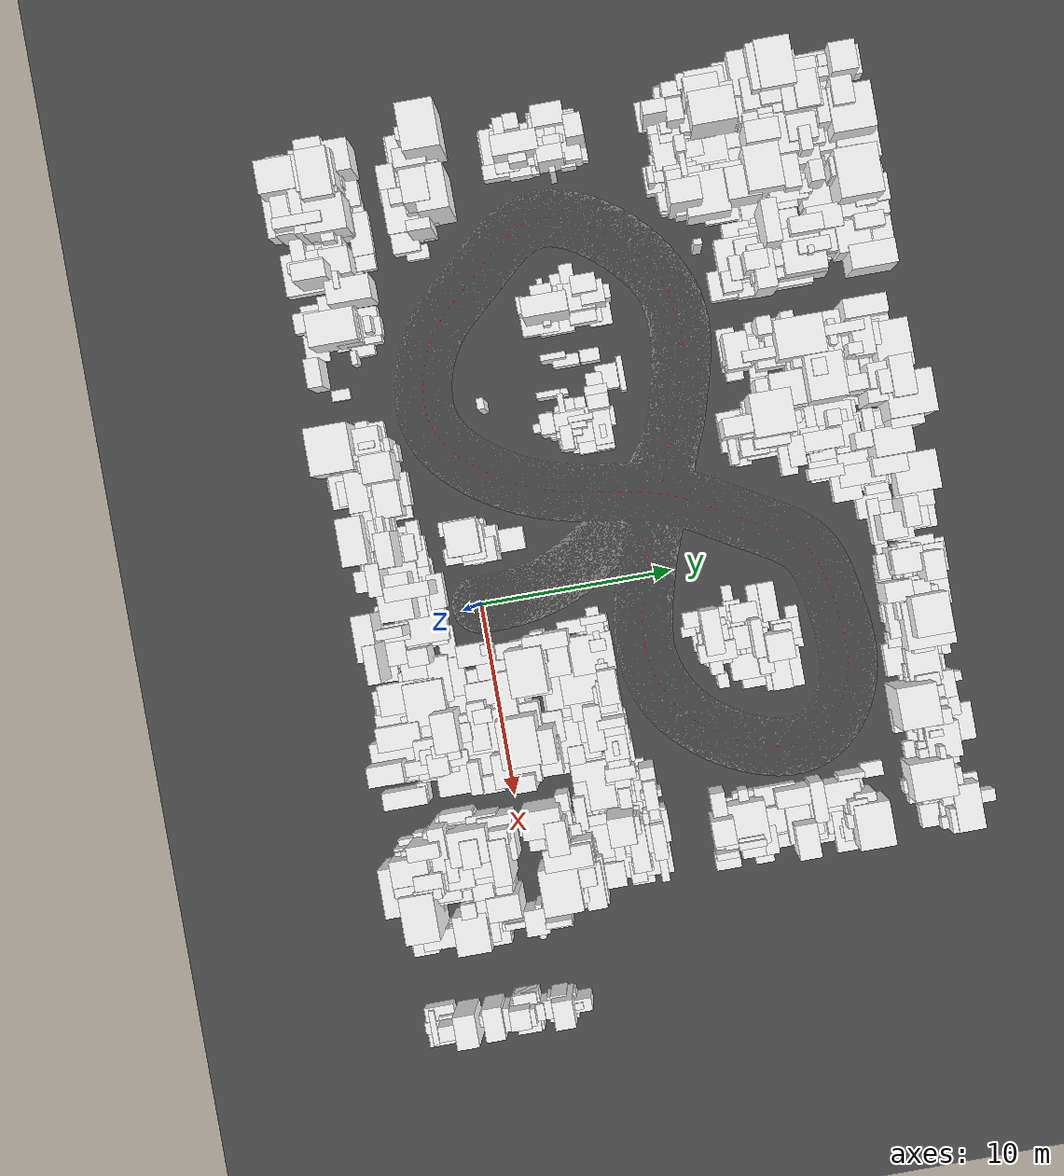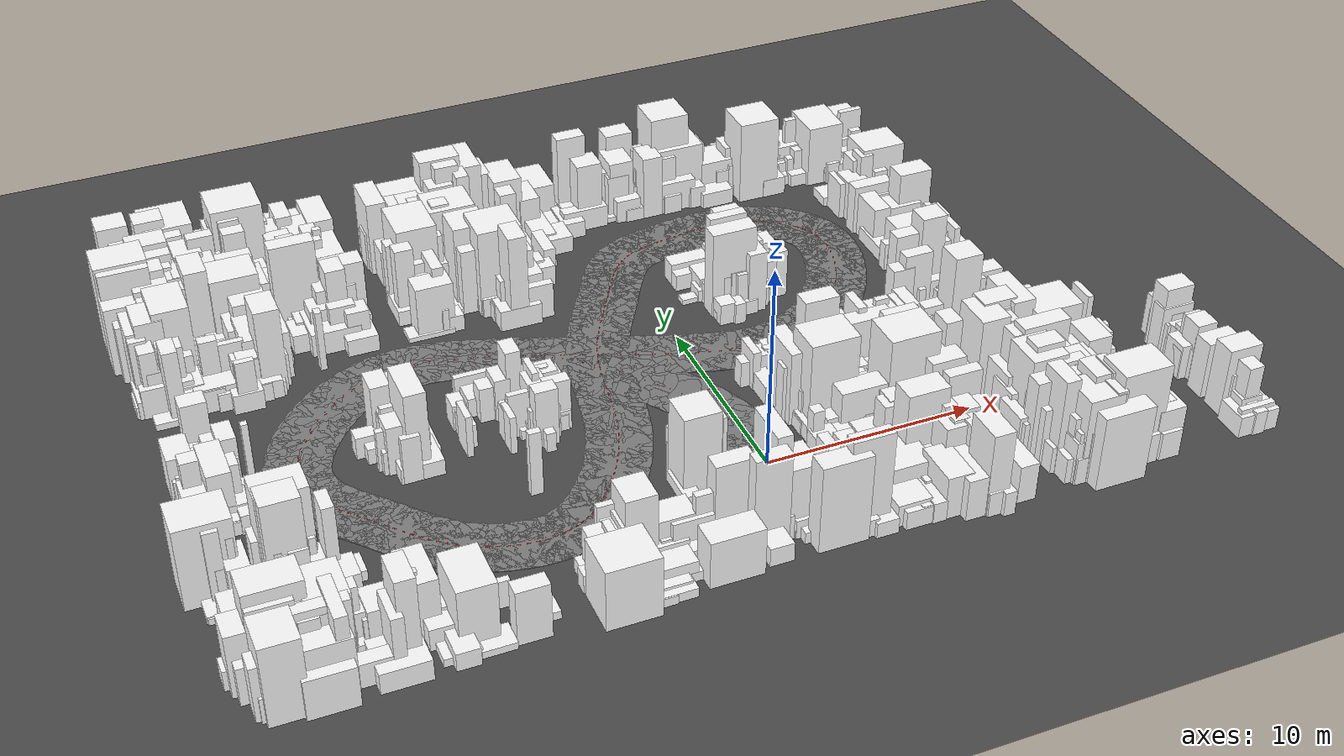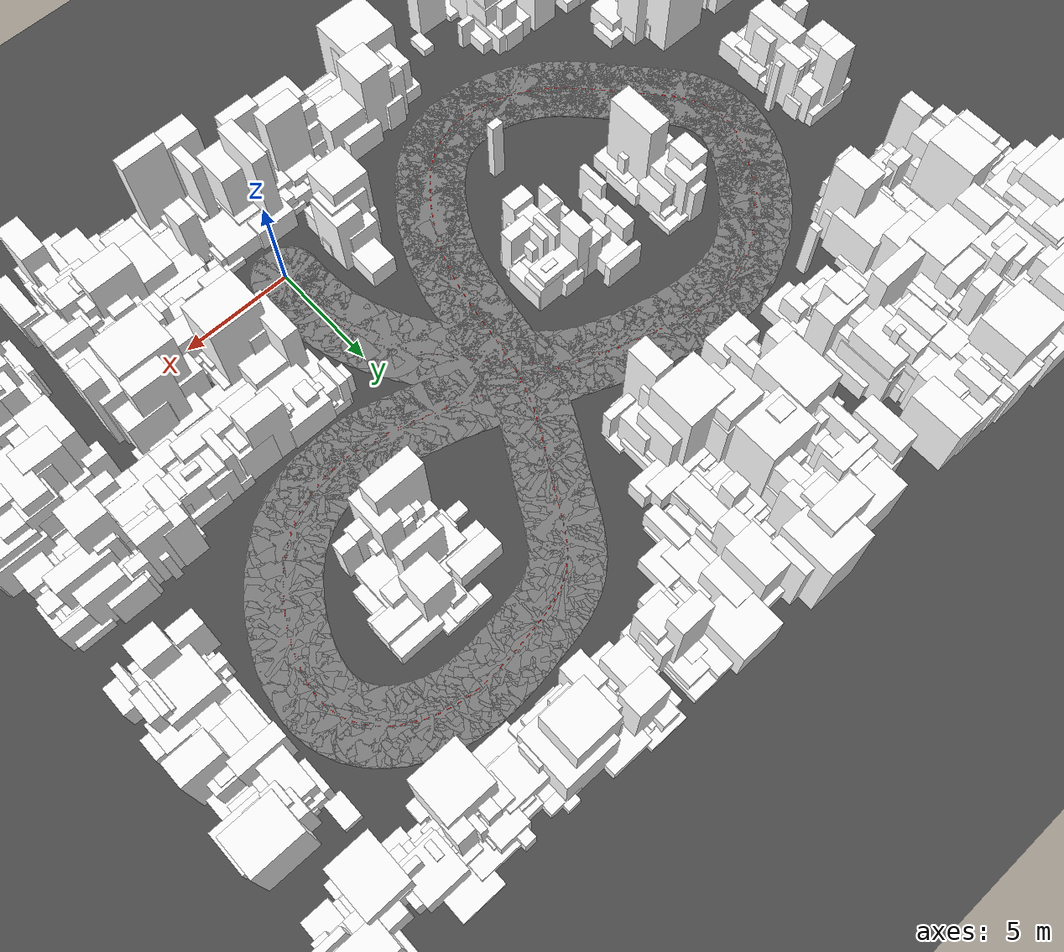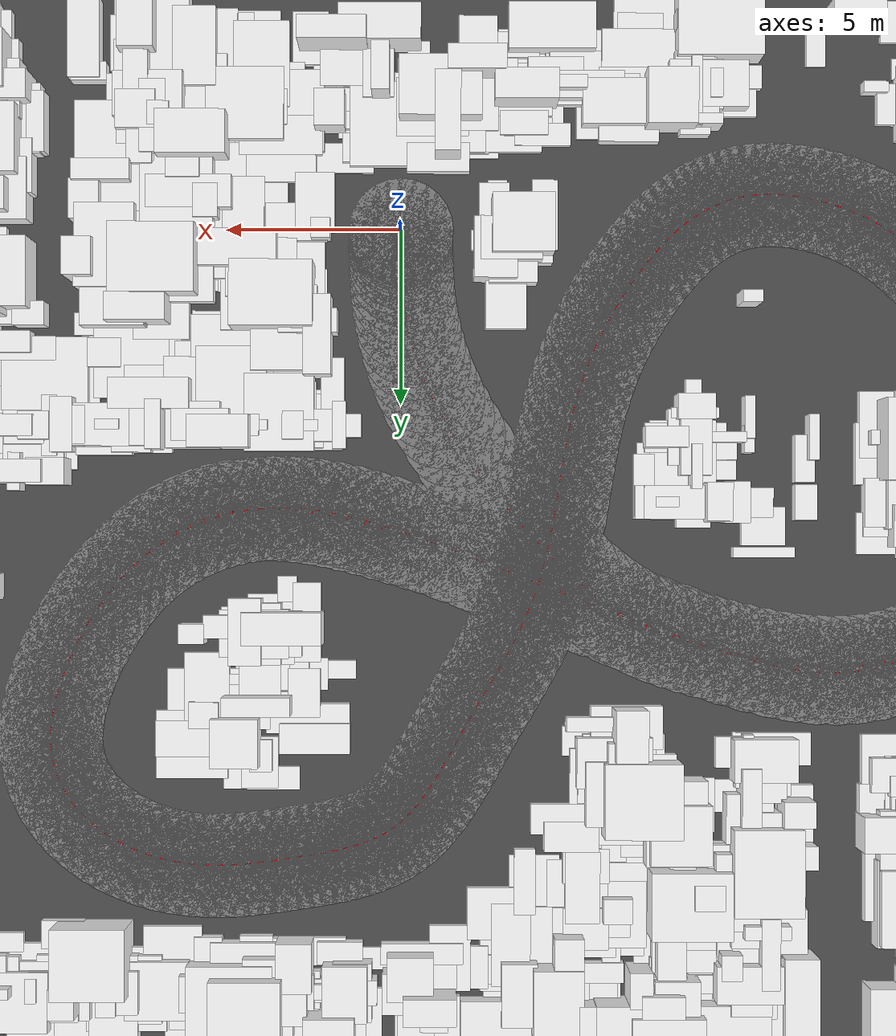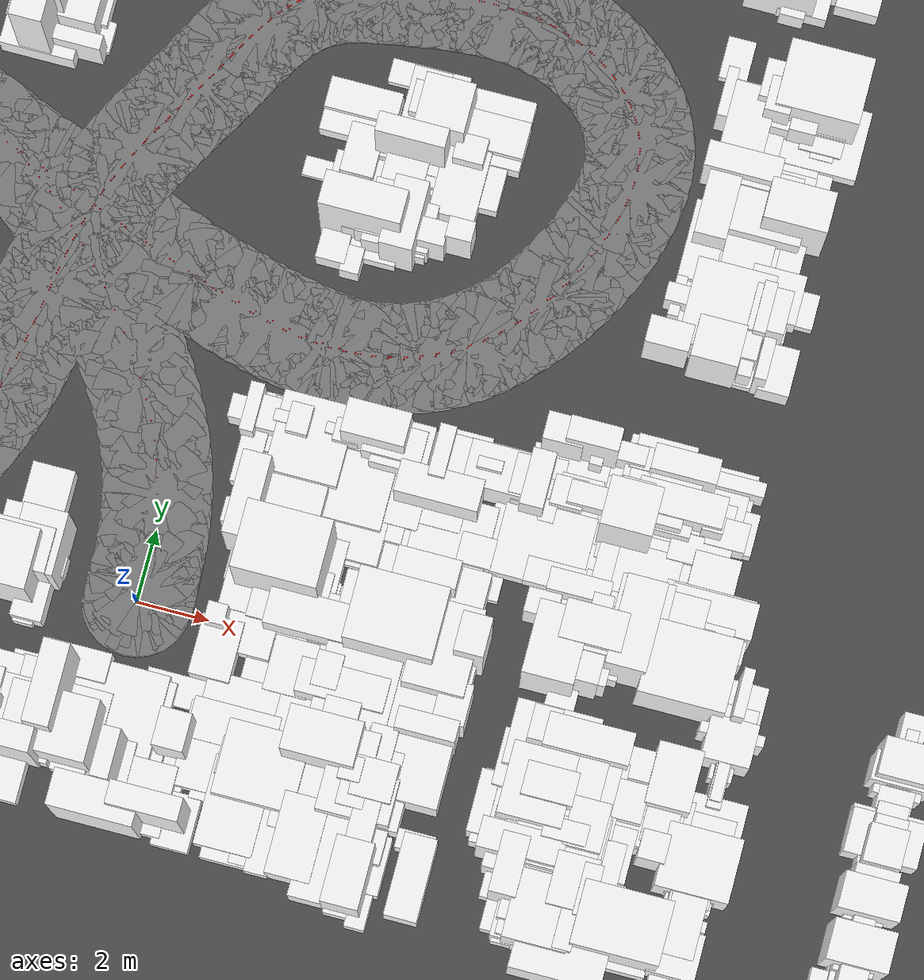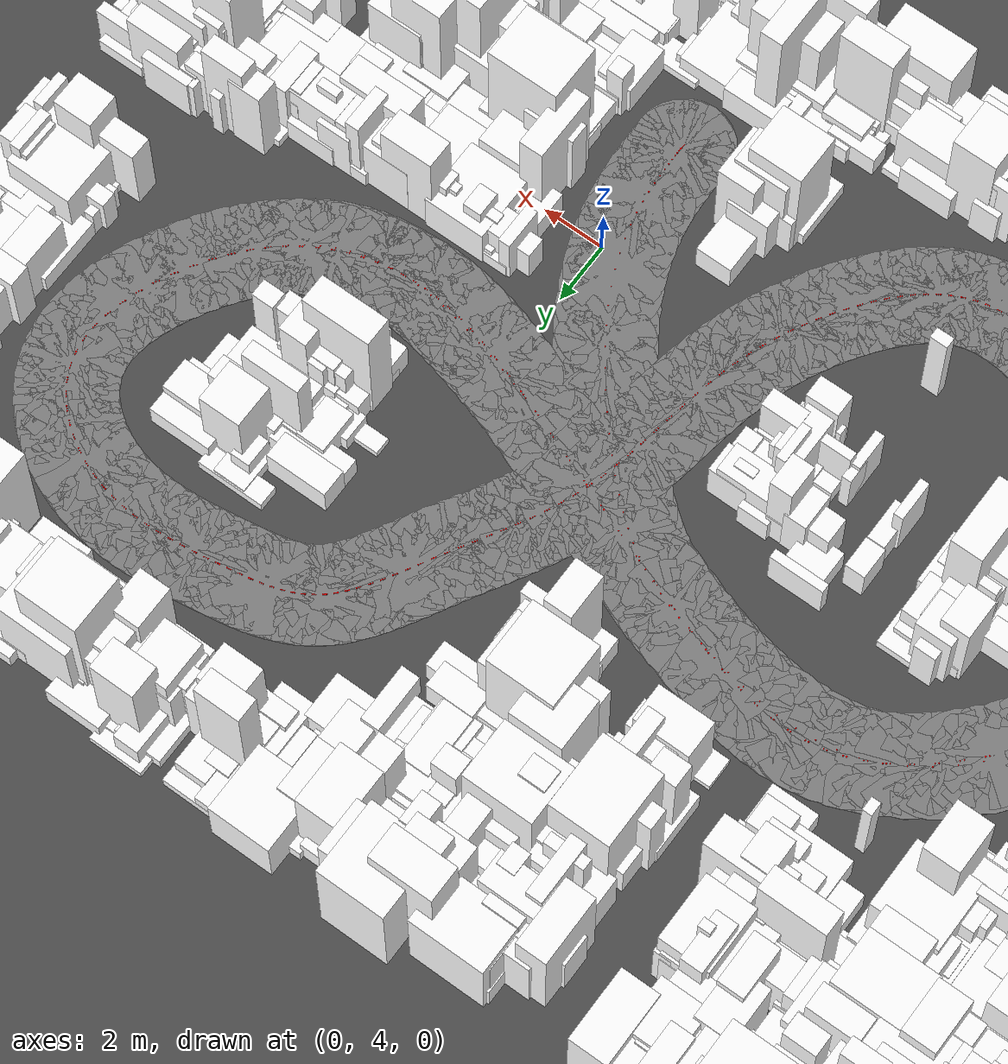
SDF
<?xml version="1.0" ?>
<sdf version="1.6">
  <world name="mirror_edge_world">

  <light name="sun" type="directional">
    <pose>0 0 10 0 0 0</pose>
    <diffuse>1 1 1 1</diffuse>
    <specular>0.9 0.9 0.9 1</specular>
    <direction>-0.5 0.5 -1</direction>
    <cast_shadows>true</cast_shadows>
  </light>

  <model name="ground_plane">
    <static>true</static>
    <link name="link">
      <collision name="collision">
        <geometry>
          <plane>
            <normal>0 0 1</normal>
            <size>100 100</size>
          </plane>
        </geometry>
      </collision>
      <visual name="visual">
        <geometry>
          <plane>
            <normal>0 0 1</normal>
            <size>100 100</size>
          </plane>
        </geometry>
        <material>
          <ambient>0.3 0.3 0.3 1</ambient>
          <diffuse>0.3 0.3 0.3 1</diffuse>
          <specular>0.5 0.5 0.5 1</specular>
          <emissive>0 0 0 1</emissive>
        </material>
      </visual>
    </link>
  </model>

        <model name="corridor_hex_0_0">
          <static>true</static>
          <link name="link">
            <pose>0.0 0.0 0.005 0 0 0</pose>
            <visual name="visual">
              <geometry>
                <cylinder>
                  <radius>1.5</radius>
                  <length>0.01</length>
                  <segments>6</segments>
                </cylinder>
              </geometry>
              <material>
                <ambient>0.5 0.5 0.5 1</ambient>
                <diffuse>0.5 0.5 0.5 1</diffuse>
                <specular>0.3 0.3 0.3 1</specular>
                <emissive>0 0 0 1</emissive>
              </material>
            </visual>
          </link>
        </model>

        <model name="corridor_hex_1_0">
          <static>true</static>
          <link name="link">
            <pose>0.004 0.032 0.005 0 0 0</pose>
            <visual name="visual">
              <geometry>
                <cylinder>
                  <radius>1.5</radius>
                  <length>0.01</length>
                  <segments>6</segments>
                </cylinder>
              </geometry>
              <material>
                <ambient>0.5 0.5 0.5 1</ambient>
                <diffuse>0.5 0.5 0.5 1</diffuse>
                <specular>0.3 0.3 0.3 1</specular>
                <emissive>0 0 0 1</emissive>
              </material>
            </visual>
          </link>
        </model>

        <model name="corridor_hex_2_0">
          <static>true</static>
          <link name="link">
            <pose>0.008 0.069 0.005 0 0 0</pose>
            <visual name="visual">
              <geometry>
                <cylinder>
                  <radius>1.5</radius>
                  <length>0.01</length>
                  <segments>6</segments>
                </cylinder>
              </geometry>
              <material>
                <ambient>0.5 0.5 0.5 1</ambient>
                <diffuse>0.5 0.5 0.5 1</diffuse>
                <specular>0.3 0.3 0.3 1</specular>
                <emissive>0 0 0 1</emissive>
              </material>
            </visual>
          </link>
        </model>

        <model name="corridor_hex_3_0">
          <static>true</static>
          <link name="link">
            <pose>0.011 0.113 0.005 0 0 0</pose>
            <visual name="visual">
              <geometry>
                <cylinder>
                  <radius>1.5</radius>
                  <length>0.01</length>
                  <segments>6</segments>
                </cylinder>
              </geometry>
              <material>
                <ambient>0.5 0.5 0.5 1</ambient>
                <diffuse>0.5 0.5 0.5 1</diffuse>
                <specular>0.3 0.3 0.3 1</specular>
                <emissive>0 0 0 1</emissive>
              </material>
            </visual>
          </link>
        </model>

        <model name="corridor_hex_4_0">
          <static>true</static>
          <link name="link">
            <pose>0.014 0.168 0.005 0 0 0</pose>
            <visual name="visual">
              <geometry>
                <cylinder>
                  <radius>1.5</radius>
                  <length>0.01</length>
                  <segments>6</segments>
                </cylinder>
              </geometry>
              <material>
                <ambient>0.5 0.5 0.5 1</ambient>
                <diffuse>0.5 0.5 0.5 1</diffuse>
                <specular>0.3 0.3 0.3 1</specular>
                <emissive>0 0 0 1</emissive>
              </material>
            </visual>
          </link>
        </model>

        <model name="corridor_hex_5_0">
          <static>true</static>
          <link name="link">
            <pose>0.016 0.239 0.005 0 0 0</pose>
            <visual name="visual">
              <geometry>
                <cylinder>
                  <radius>1.5</radius>
                  <length>0.01</length>
                  <segments>6</segments>
                </cylinder>
              </geometry>
              <material>
                <ambient>0.5 0.5 0.5 1</ambient>
                <diffuse>0.5 0.5 0.5 1</diffuse>
                <specular>0.3 0.3 0.3 1</specular>
                <emissive>0 0 0 1</emissive>
              </material>
            </visual>
          </link>
        </model>

        <model name="corridor_hex_6_0">
          <static>true</static>
          <link name="link">
            <pose>0.016 0.33 0.005 0 0 0</pose>
            <visual name="visual">
              <geometry>
                <cylinder>
                  <radius>1.5</radius>
                  <length>0.01</length>
                  <segments>6</segments>
                </cylinder>
              </geometry>
              <material>
                <ambient>0.5 0.5 0.5 1</ambient>
                <diffuse>0.5 0.5 0.5 1</diffuse>
                <specular>0.3 0.3 0.3 1</specular>
                <emissive>0 0 0 1</emissive>
              </material>
            </visual>
          </link>
        </model>

        <model name="corridor_hex_7_0">
          <static>true</static>
          <link name="link">
            <pose>0.015 0.443 0.005 0 0 0</pose>
            <visual name="visual">
              <geometry>
                <cylinder>
                  <radius>1.5</radius>
                  <length>0.01</length>
                  <segments>6</segments>
                </cylinder>
              </geometry>
              <material>
                <ambient>0.5 0.5 0.5 1</ambient>
                <diffuse>0.5 0.5 0.5 1</diffuse>
                <specular>0.3 0.3 0.3 1</specular>
                <emissive>0 0 0 1</emissive>
              </material>
            </visual>
          </link>
        </model>

        <model name="corridor_hex_8_0">
          <static>true</static>
          <link name="link">
            <pose>0.012 0.584 0.005 0 0 0</pose>
            <visual name="visual">
              <geometry>
                <cylinder>
                  <radius>1.5</radius>
                  <length>0.01</length>
                  <segments>6</segments>
                </cylinder>
              </geometry>
              <material>
                <ambient>0.5 0.5 0.5 1</ambient>
                <diffuse>0.5 0.5 0.5 1</diffuse>
                <specular>0.3 0.3 0.3 1</specular>
                <emissive>0 0 0 1</emissive>
              </material>
            </visual>
          </link>
        </model>

        <model name="corridor_hex_9_0">
          <static>true</static>
          <link name="link">
            <pose>0.008 0.756 0.005 0 0 0</pose>
            <visual name="visual">
              <geometry>
                <cylinder>
                  <radius>1.5</radius>
                  <length>0.01</length>
                  <segments>6</segments>
                </cylinder>
              </geometry>
              <material>
                <ambient>0.5 0.5 0.5 1</ambient>
                <diffuse>0.5 0.5 0.5 1</diffuse>
                <specular>0.3 0.3 0.3 1</specular>
                <emissive>0 0 0 1</emissive>
              </material>
            </visual>
          </link>
        </model>

        <model name="corridor_hex_10_0">
          <static>true</static>
          <link name="link">
            <pose>0.001 0.962 0.005 0 0 0</pose>
            <visual name="visual">
              <geometry>
                <cylinder>
                  <radius>1.5</radius>
                  <length>0.01</length>
                  <segments>6</segments>
                </cylinder>
              </geometry>
              <material>
                <ambient>0.5 0.5 0.5 1</ambient>
                <diffuse>0.5 0.5 0.5 1</diffuse>
                <specular>0.3 0.3 0.3 1</specular>
                <emissive>0 0 0 1</emissive>
              </material>
            </visual>
          </link>
        </model>

        <model name="corridor_hex_11_0">
          <static>true</static>
          <link name="link">
            <pose>-0.008 1.206 0.005 0 0 0</pose>
            <visual name="visual">
              <geometry>
                <cylinder>
                  <radius>1.5</radius>
                  <length>0.01</length>
                  <segments>6</segments>
                </cylinder>
              </geometry>
              <material>
                <ambient>0.5 0.5 0.5 1</ambient>
                <diffuse>0.5 0.5 0.5 1</diffuse>
                <specular>0.3 0.3 0.3 1</specular>
                <emissive>0 0 0 1</emissive>
              </material>
            </visual>
          </link>
        </model>

        <model name="corridor_hex_12_0">
          <static>true</static>
          <link name="link">
            <pose>-0.024 1.488 0.005 0 0 0</pose>
            <visual name="visual">
              <geometry>
                <cylinder>
                  <radius>1.5</radius>
                  <length>0.01</length>
                  <segments>6</segments>
                </cylinder>
              </geometry>
              <material>
                <ambient>0.5 0.5 0.5 1</ambient>
                <diffuse>0.5 0.5 0.5 1</diffuse>
                <specular>0.3 0.3 0.3 1</specular>
                <emissive>0 0 0 1</emissive>
              </material>
            </visual>
          </link>
        </model>

        <model name="corridor_hex_13_0">
          <static>true</static>
          <link name="link">
            <pose>-0.05 1.806 0.005 0 0 0</pose>
            <visual name="visual">
              <geometry>
                <cylinder>
                  <radius>1.5</radius>
                  <length>0.01</length>
                  <segments>6</segments>
                </cylinder>
              </geometry>
              <material>
                <ambient>0.5 0.5 0.5 1</ambient>
                <diffuse>0.5 0.5 0.5 1</diffuse>
                <specular>0.3 0.3 0.3 1</specular>
                <emissive>0 0 0 1</emissive>
              </material>
            </visual>
          </link>
        </model>

        <model name="corridor_hex_14_0">
          <static>true</static>
          <link name="link">
            <pose>-0.092 2.156 0.005 0 0 0</pose>
            <visual name="visual">
              <geometry>
                <cylinder>
                  <radius>1.5</radius>
                  <length>0.01</length>
                  <segments>6</segments>
                </cylinder>
              </geometry>
              <material>
                <ambient>0.5 0.5 0.5 1</ambient>
                <diffuse>0.5 0.5 0.5 1</diffuse>
                <specular>0.3 0.3 0.3 1</specular>
                <emissive>0 0 0 1</emissive>
              </material>
            </visual>
          </link>
        </model>

        <model name="corridor_hex_15_0">
          <static>true</static>
          <link name="link">
            <pose>-0.153 2.537 0.005 0 0 0</pose>
            <visual name="visual">
              <geometry>
                <cylinder>
                  <radius>1.5</radius>
                  <length>0.01</length>
                  <segments>6</segments>
                </cylinder>
              </geometry>
              <material>
                <ambient>0.5 0.5 0.5 1</ambient>
                <diffuse>0.5 0.5 0.5 1</diffuse>
                <specular>0.3 0.3 0.3 1</specular>
                <emissive>0 0 0 1</emissive>
              </material>
            </visual>
          </link>
        </model>

        <model name="corridor_hex_16_0">
          <static>true</static>
          <link name="link">
            <pose>-0.238 2.947 0.005 0 0 0</pose>
            <visual name="visual">
              <geometry>
                <cylinder>
                  <radius>1.5</radius>
                  <length>0.01</length>
                  <segments>6</segments>
                </cylinder>
              </geometry>
              <material>
                <ambient>0.5 0.5 0.5 1</ambient>
                <diffuse>0.5 0.5 0.5 1</diffuse>
                <specular>0.3 0.3 0.3 1</specular>
                <emissive>0 0 0 1</emissive>
              </material>
            </visual>
          </link>
        </model>

        <model name="corridor_hex_17_0">
          <static>true</static>
          <link name="link">
            <pose>-0.353 3.383 0.005 0 0 0</pose>
            <visual name="visual">
              <geometry>
                <cylinder>
                  <radius>1.5</radius>
                  <length>0.01</length>
                  <segments>6</segments>
                </cylinder>
              </geometry>
              <material>
                <ambient>0.5 0.5 0.5 1</ambient>
                <diffuse>0.5 0.5 0.5 1</diffuse>
                <specular>0.3 0.3 0.3 1</specular>
                <emissive>0 0 0 1</emissive>
              </material>
            </visual>
          </link>
        </model>

        <model name="corridor_hex_18_0">
          <static>true</static>
          <link name="link">
            <pose>-0.501 3.844 0.005 0 0 0</pose>
            <visual name="visual">
              <geometry>
                <cylinder>
                  <radius>1.5</radius>
                  <length>0.01</length>
                  <segments>6</segments>
                </cylinder>
              </geometry>
              <material>
                <ambient>0.5 0.5 0.5 1</ambient>
                <diffuse>0.5 0.5 0.5 1</diffuse>
                <specular>0.3 0.3 0.3 1</specular>
                <emissive>0 0 0 1</emissive>
              </material>
            </visual>
          </link>
        </model>

        <model name="corridor_hex_19_0">
          <static>true</static>
          <link name="link">
            <pose>-0.686 4.326 0.005 0 0 0</pose>
            <visual name="visual">
              <geometry>
                <cylinder>
                  <radius>1.5</radius>
                  <length>0.01</length>
                  <segments>6</segments>
                </cylinder>
              </geometry>
              <material>
                <ambient>0.5 0.5 0.5 1</ambient>
                <diffuse>0.5 0.5 0.5 1</diffuse>
                <specular>0.3 0.3 0.3 1</specular>
                <emissive>0 0 0 1</emissive>
              </material>
            </visual>
          </link>
        </model>

        <model name="corridor_hex_20_0">
          <static>true</static>
          <link name="link">
            <pose>-0.914 4.829 0.005 0 0 0</pose>
            <visual name="visual">
              <geometry>
                <cylinder>
                  <radius>1.5</radius>
                  <length>0.01</length>
                  <segments>6</segments>
                </cylinder>
              </geometry>
              <material>
                <ambient>0.5 0.5 0.5 1</ambient>
                <diffuse>0.5 0.5 0.5 1</diffuse>
                <specular>0.3 0.3 0.3 1</specular>
                <emissive>0 0 0 1</emissive>
              </material>
            </visual>
          </link>
        </model>

        <model name="corridor_hex_21_0">
          <static>true</static>
          <link name="link">
            <pose>-1.188 5.348 0.005 0 0 0</pose>
            <visual name="visual">
              <geometry>
                <cylinder>
                  <radius>1.5</radius>
                  <length>0.01</length>
                  <segments>6</segments>
                </cylinder>
              </geometry>
              <material>
                <ambient>0.5 0.5 0.5 1</ambient>
                <diffuse>0.5 0.5 0.5 1</diffuse>
                <specular>0.3 0.3 0.3 1</specular>
                <emissive>0 0 0 1</emissive>
              </material>
            </visual>
          </link>
        </model>

        <model name="corridor_hex_22_0">
          <static>true</static>
          <link name="link">
            <pose>-1.506 5.88 0.005 0 0 0</pose>
            <visual name="visual">
              <geometry>
                <cylinder>
                  <radius>1.5</radius>
                  <length>0.01</length>
                  <segments>6</segments>
                </cylinder>
              </geometry>
              <material>
                <ambient>0.5 0.5 0.5 1</ambient>
                <diffuse>0.5 0.5 0.5 1</diffuse>
                <specular>0.3 0.3 0.3 1</specular>
                <emissive>0 0 0 1</emissive>
              </material>
            </visual>
          </link>
        </model>

        <model name="corridor_hex_23_0">
          <static>true</static>
          <link name="link">
            <pose>-1.861 6.419 0.005 0 0 0</pose>
            <visual name="visual">
              <geometry>
                <cylinder>
                  <radius>1.5</radius>
                  <length>0.01</length>
                  <segments>6</segments>
                </cylinder>
              </geometry>
              <material>
                <ambient>0.5 0.5 0.5 1</ambient>
                <diffuse>0.5 0.5 0.5 1</diffuse>
                <specular>0.3 0.3 0.3 1</specular>
                <emissive>0 0 0 1</emissive>
              </material>
            </visual>
          </link>
        </model>

        <model name="corridor_hex_24_0">
          <static>true</static>
          <link name="link">
            <pose>-2.245 6.957 0.005 0 0 0</pose>
            <visual name="visual">
              <geometry>
                <cylinder>
                  <radius>1.5</radius>
                  <length>0.01</length>
                  <segments>6</segments>
                </cylinder>
              </geometry>
              <material>
                <ambient>0.5 0.5 0.5 1</ambient>
                <diffuse>0.5 0.5 0.5 1</diffuse>
                <specular>0.3 0.3 0.3 1</specular>
                <emissive>0 0 0 1</emissive>
              </material>
            </visual>
          </link>
        </model>

        <model name="corridor_hex_25_0">
          <static>true</static>
          <link name="link">
            <pose>-2.653 7.488 0.005 0 0 0</pose>
            <visual name="visual">
              <geometry>
                <cylinder>
                  <radius>1.5</radius>
                  <length>0.01</length>
                  <segments>6</segments>
                </cylinder>
              </geometry>
              <material>
                <ambient>0.5 0.5 0.5 1</ambient>
                <diffuse>0.5 0.5 0.5 1</diffuse>
                <specular>0.3 0.3 0.3 1</specular>
                <emissive>0 0 0 1</emissive>
              </material>
            </visual>
          </link>
        </model>

        <model name="corridor_hex_26_0">
          <static>true</static>
          <link name="link">
            <pose>-3.077 8.006 0.005 0 0 0</pose>
            <visual name="visual">
              <geometry>
                <cylinder>
                  <radius>1.5</radius>
                  <length>0.01</length>
                  <segments>6</segments>
                </cylinder>
              </geometry>
              <material>
                <ambient>0.5 0.5 0.5 1</ambient>
                <diffuse>0.5 0.5 0.5 1</diffuse>
                <specular>0.3 0.3 0.3 1</specular>
                <emissive>0 0 0 1</emissive>
              </material>
            </visual>
          </link>
        </model>

        <model name="corridor_hex_27_0">
          <static>true</static>
          <link name="link">
            <pose>-3.51 8.504 0.005 0 0 0</pose>
            <visual name="visual">
              <geometry>
                <cylinder>
                  <radius>1.5</radius>
                  <length>0.01</length>
                  <segments>6</segments>
                </cylinder>
              </geometry>
              <material>
                <ambient>0.5 0.5 0.5 1</ambient>
                <diffuse>0.5 0.5 0.5 1</diffuse>
                <specular>0.3 0.3 0.3 1</specular>
                <emissive>0 0 0 1</emissive>
              </material>
            </visual>
          </link>
        </model>

        <model name="corridor_hex_28_0">
          <static>true</static>
          <link name="link">
            <pose>-3.946 8.976 0.005 0 0 0</pose>
            <visual name="visual">
              <geometry>
                <cylinder>
                  <radius>1.5</radius>
                  <length>0.01</length>
                  <segments>6</segments>
                </cylinder>
              </geometry>
              <material>
                <ambient>0.5 0.5 0.5 1</ambient>
                <diffuse>0.5 0.5 0.5 1</diffuse>
                <specular>0.3 0.3 0.3 1</specular>
                <emissive>0 0 0 1</emissive>
              </material>
            </visual>
          </link>
        </model>

        <model name="corridor_hex_29_0">
          <static>true</static>
          <link name="link">
            <pose>-4.377 9.416 0.005 0 0 0</pose>
            <visual name="visual">
              <geometry>
                <cylinder>
                  <radius>1.5</radius>
                  <length>0.01</length>
                  <segments>6</segments>
                </cylinder>
              </geometry>
              <material>
                <ambient>0.5 0.5 0.5 1</ambient>
                <diffuse>0.5 0.5 0.5 1</diffuse>
                <specular>0.3 0.3 0.3 1</specular>
                <emissive>0 0 0 1</emissive>
              </material>
            </visual>
          </link>
        </model>

        <model name="corridor_hex_30_0">
          <static>true</static>
          <link name="link">
            <pose>-4.797 9.816 0.005 0 0 0</pose>
            <visual name="visual">
              <geometry>
                <cylinder>
                  <radius>1.5</radius>
                  <length>0.01</length>
                  <segments>6</segments>
                </cylinder>
              </geometry>
              <material>
                <ambient>0.5 0.5 0.5 1</ambient>
                <diffuse>0.5 0.5 0.5 1</diffuse>
                <specular>0.3 0.3 0.3 1</specular>
                <emissive>0 0 0 1</emissive>
              </material>
            </visual>
          </link>
        </model>

        <model name="corridor_hex_31_0">
          <static>true</static>
          <link name="link">
            <pose>-5.198 10.172 0.005 0 0 0</pose>
            <visual name="visual">
              <geometry>
                <cylinder>
                  <radius>1.5</radius>
                  <length>0.01</length>
                  <segments>6</segments>
                </cylinder>
              </geometry>
              <material>
                <ambient>0.5 0.5 0.5 1</ambient>
                <diffuse>0.5 0.5 0.5 1</diffuse>
                <specular>0.3 0.3 0.3 1</specular>
                <emissive>0 0 0 1</emissive>
              </material>
            </visual>
          </link>
        </model>

        <model name="corridor_hex_32_0">
          <static>true</static>
          <link name="link">
            <pose>-5.581 10.481 0.005 0 0 0</pose>
            <visual name="visual">
              <geometry>
                <cylinder>
                  <radius>1.5</radius>
                  <length>0.01</length>
                  <segments>6</segments>
                </cylinder>
              </geometry>
              <material>
                <ambient>0.5 0.5 0.5 1</ambient>
                <diffuse>0.5 0.5 0.5 1</diffuse>
                <specular>0.3 0.3 0.3 1</specular>
                <emissive>0 0 0 1</emissive>
              </material>
            </visual>
          </link>
        </model>

        <model name="corridor_hex_33_0">
          <static>true</static>
          <link name="link">
            <pose>-5.951 10.75 0.005 0 0 0</pose>
            <visual name="visual">
              <geometry>
                <cylinder>
                  <radius>1.5</radius>
                  <length>0.01</length>
                  <segments>6</segments>
                </cylinder>
              </geometry>
              <material>
                <ambient>0.5 0.5 0.5 1</ambient>
                <diffuse>0.5 0.5 0.5 1</diffuse>
                <specular>0.3 0.3 0.3 1</specular>
                <emissive>0 0 0 1</emissive>
              </material>
            </visual>
          </link>
        </model>

        <model name="corridor_hex_34_0">
          <static>true</static>
          <link name="link">
            <pose>-6.315 10.983 0.005 0 0 0</pose>
            <visual name="visual">
              <geometry>
                <cylinder>
                  <radius>1.5</radius>
                  <length>0.01</length>
                  <segments>6</segments>
                </cylinder>
              </geometry>
              <material>
                <ambient>0.5 0.5 0.5 1</ambient>
                <diffuse>0.5 0.5 0.5 1</diffuse>
                <specular>0.3 0.3 0.3 1</specular>
                <emissive>0 0 0 1</emissive>
              </material>
            </visual>
          </link>
        </model>

        <model name="corridor_hex_35_0">
          <static>true</static>
          <link name="link">
            <pose>-6.677 11.185 0.005 0 0 0</pose>
            <visual name="visual">
              <geometry>
                <cylinder>
                  <radius>1.5</radius>
                  <length>0.01</length>
                  <segments>6</segments>
                </cylinder>
              </geometry>
              <material>
                <ambient>0.5 0.5 0.5 1</ambient>
                <diffuse>0.5 0.5 0.5 1</diffuse>
                <specular>0.3 0.3 0.3 1</specular>
                <emissive>0 0 0 1</emissive>
              </material>
            </visual>
          </link>
        </model>

        <model name="corridor_hex_36_0">
          <static>true</static>
          <link name="link">
            <pose>-7.044 11.361 0.005 0 0 0</pose>
            <visual name="visual">
              <geometry>
                <cylinder>
                  <radius>1.5</radius>
                  <length>0.01</length>
                  <segments>6</segments>
                </cylinder>
              </geometry>
              <material>
                <ambient>0.5 0.5 0.5 1</ambient>
                <diffuse>0.5 0.5 0.5 1</diffuse>
                <specular>0.3 0.3 0.3 1</specular>
                <emissive>0 0 0 1</emissive>
              </material>
            </visual>
          </link>
        </model>

        <model name="corridor_hex_37_0">
          <static>true</static>
          <link name="link">
            <pose>-7.423 11.518 0.005 0 0 0</pose>
            <visual name="visual">
              <geometry>
                <cylinder>
                  <radius>1.5</radius>
                  <length>0.01</length>
                  <segments>6</segments>
                </cylinder>
              </geometry>
              <material>
                <ambient>0.5 0.5 0.5 1</ambient>
                <diffuse>0.5 0.5 0.5 1</diffuse>
                <specular>0.3 0.3 0.3 1</specular>
                <emissive>0 0 0 1</emissive>
              </material>
            </visual>
          </link>
        </model>

        <model name="corridor_hex_38_0">
          <static>true</static>
          <link name="link">
            <pose>-7.818 11.659 0.005 0 0 0</pose>
            <visual name="visual">
              <geometry>
                <cylinder>
                  <radius>1.5</radius>
                  <length>0.01</length>
                  <segments>6</segments>
                </cylinder>
              </geometry>
              <material>
                <ambient>0.5 0.5 0.5 1</ambient>
                <diffuse>0.5 0.5 0.5 1</diffuse>
                <specular>0.3 0.3 0.3 1</specular>
                <emissive>0 0 0 1</emissive>
              </material>
            </visual>
          </link>
        </model>

        <model name="corridor_hex_39_0">
          <static>true</static>
          <link name="link">
            <pose>-8.236 11.79 0.005 0 0 0</pose>
            <visual name="visual">
              <geometry>
                <cylinder>
                  <radius>1.5</radius>
                  <length>0.01</length>
                  <segments>6</segments>
                </cylinder>
              </geometry>
              <material>
                <ambient>0.5 0.5 0.5 1</ambient>
                <diffuse>0.5 0.5 0.5 1</diffuse>
                <specular>0.3 0.3 0.3 1</specular>
                <emissive>0 0 0 1</emissive>
              </material>
            </visual>
          </link>
        </model>

        <model name="corridor_hex_40_0">
          <static>true</static>
          <link name="link">
            <pose>-8.683 11.916 0.005 0 0 0</pose>
            <visual name="visual">
              <geometry>
                <cylinder>
                  <radius>1.5</radius>
                  <length>0.01</length>
                  <segments>6</segments>
                </cylinder>
              </geometry>
              <material>
                <ambient>0.5 0.5 0.5 1</ambient>
                <diffuse>0.5 0.5 0.5 1</diffuse>
                <specular>0.3 0.3 0.3 1</specular>
                <emissive>0 0 0 1</emissive>
              </material>
            </visual>
          </link>
        </model>

        <model name="corridor_hex_41_0">
          <static>true</static>
          <link name="link">
            <pose>-9.165 12.042 0.005 0 0 0</pose>
            <visual name="visual">
              <geometry>
                <cylinder>
                  <radius>1.5</radius>
                  <length>0.01</length>
                  <segments>6</segments>
                </cylinder>
              </geometry>
              <material>
                <ambient>0.5 0.5 0.5 1</ambient>
                <diffuse>0.5 0.5 0.5 1</diffuse>
                <specular>0.3 0.3 0.3 1</specular>
                <emissive>0 0 0 1</emissive>
              </material>
            </visual>
          </link>
        </model>

        <model name="corridor_hex_42_0">
          <static>true</static>
          <link name="link">
            <pose>-9.683 12.169 0.005 0 0 0</pose>
            <visual name="visual">
              <geometry>
                <cylinder>
                  <radius>1.5</radius>
                  <length>0.01</length>
                  <segments>6</segments>
                </cylinder>
              </geometry>
              <material>
                <ambient>0.5 0.5 0.5 1</ambient>
                <diffuse>0.5 0.5 0.5 1</diffuse>
                <specular>0.3 0.3 0.3 1</specular>
                <emissive>0 0 0 1</emissive>
              </material>
            </visual>
          </link>
        </model>

        <model name="corridor_hex_43_0">
          <static>true</static>
          <link name="link">
            <pose>-10.232 12.288 0.005 0 0 0</pose>
            <visual name="visual">
              <geometry>
                <cylinder>
                  <radius>1.5</radius>
                  <length>0.01</length>
                  <segments>6</segments>
                </cylinder>
              </geometry>
              <material>
                <ambient>0.5 0.5 0.5 1</ambient>
                <diffuse>0.5 0.5 0.5 1</diffuse>
                <specular>0.3 0.3 0.3 1</specular>
                <emissive>0 0 0 1</emissive>
              </material>
            </visual>
          </link>
        </model>

        <model name="corridor_hex_44_0">
          <static>true</static>
          <link name="link">
            <pose>-10.808 12.391 0.005 0 0 0</pose>
            <visual name="visual">
              <geometry>
                <cylinder>
                  <radius>1.5</radius>
                  <length>0.01</length>
                  <segments>6</segments>
                </cylinder>
              </geometry>
              <material>
                <ambient>0.5 0.5 0.5 1</ambient>
                <diffuse>0.5 0.5 0.5 1</diffuse>
                <specular>0.3 0.3 0.3 1</specular>
                <emissive>0 0 0 1</emissive>
              </material>
            </visual>
          </link>
        </model>

        <model name="corridor_hex_45_0">
          <static>true</static>
          <link name="link">
            <pose>-11.404 12.469 0.005 0 0 0</pose>
            <visual name="visual">
              <geometry>
                <cylinder>
                  <radius>1.5</radius>
                  <length>0.01</length>
                  <segments>6</segments>
                </cylinder>
              </geometry>
              <material>
                <ambient>0.5 0.5 0.5 1</ambient>
                <diffuse>0.5 0.5 0.5 1</diffuse>
                <specular>0.3 0.3 0.3 1</specular>
                <emissive>0 0 0 1</emissive>
              </material>
            </visual>
          </link>
        </model>

        <model name="corridor_hex_46_0">
          <static>true</static>
          <link name="link">
            <pose>-12.015 12.515 0.005 0 0 0</pose>
            <visual name="visual">
              <geometry>
                <cylinder>
                  <radius>1.5</radius>
                  <length>0.01</length>
                  <segments>6</segments>
                </cylinder>
              </geometry>
              <material>
                <ambient>0.5 0.5 0.5 1</ambient>
                <diffuse>0.5 0.5 0.5 1</diffuse>
                <specular>0.3 0.3 0.3 1</specular>
                <emissive>0 0 0 1</emissive>
              </material>
            </visual>
          </link>
        </model>

        <model name="corridor_hex_47_0">
          <static>true</static>
          <link name="link">
            <pose>-12.635 12.519 0.005 0 0 0</pose>
            <visual name="visual">
              <geometry>
                <cylinder>
                  <radius>1.5</radius>
                  <length>0.01</length>
                  <segments>6</segments>
                </cylinder>
              </geometry>
              <material>
                <ambient>0.5 0.5 0.5 1</ambient>
                <diffuse>0.5 0.5 0.5 1</diffuse>
                <specular>0.3 0.3 0.3 1</specular>
                <emissive>0 0 0 1</emissive>
              </material>
            </visual>
          </link>
        </model>

        <model name="corridor_hex_48_0">
          <static>true</static>
          <link name="link">
            <pose>-13.259 12.474 0.005 0 0 0</pose>
            <visual name="visual">
              <geometry>
                <cylinder>
                  <radius>1.5</radius>
                  <length>0.01</length>
                  <segments>6</segments>
                </cylinder>
              </geometry>
              <material>
                <ambient>0.5 0.5 0.5 1</ambient>
                <diffuse>0.5 0.5 0.5 1</diffuse>
                <specular>0.3 0.3 0.3 1</specular>
                <emissive>0 0 0 1</emissive>
              </material>
            </visual>
          </link>
        </model>

        <model name="corridor_hex_49_0">
          <static>true</static>
          <link name="link">
            <pose>-13.881 12.37 0.005 0 0 0</pose>
            <visual name="visual">
              <geometry>
                <cylinder>
                  <radius>1.5</radius>
                  <length>0.01</length>
                  <segments>6</segments>
                </cylinder>
              </geometry>
              <material>
                <ambient>0.5 0.5 0.5 1</ambient>
                <diffuse>0.5 0.5 0.5 1</diffuse>
                <specular>0.3 0.3 0.3 1</specular>
                <emissive>0 0 0 1</emissive>
              </material>
            </visual>
          </link>
        </model>

        <model name="corridor_hex_50_0">
          <static>true</static>
          <link name="link">
            <pose>-14.497 12.199 0.005 0 0 0</pose>
            <visual name="visual">
              <geometry>
                <cylinder>
                  <radius>1.5</radius>
                  <length>0.01</length>
                  <segments>6</segments>
                </cylinder>
              </geometry>
              <material>
                <ambient>0.5 0.5 0.5 1</ambient>
                <diffuse>0.5 0.5 0.5 1</diffuse>
                <specular>0.3 0.3 0.3 1</specular>
                <emissive>0 0 0 1</emissive>
              </material>
            </visual>
          </link>
        </model>

        <model name="corridor_hex_51_0">
          <static>true</static>
          <link name="link">
            <pose>-15.099 11.953 0.005 0 0 0</pose>
            <visual name="visual">
              <geometry>
                <cylinder>
                  <radius>1.5</radius>
                  <length>0.01</length>
                  <segments>6</segments>
                </cylinder>
              </geometry>
              <material>
                <ambient>0.5 0.5 0.5 1</ambient>
                <diffuse>0.5 0.5 0.5 1</diffuse>
                <specular>0.3 0.3 0.3 1</specular>
                <emissive>0 0 0 1</emissive>
              </material>
            </visual>
          </link>
        </model>

        <model name="corridor_hex_52_0">
          <static>true</static>
          <link name="link">
            <pose>-15.683 11.629 0.005 0 0 0</pose>
            <visual name="visual">
              <geometry>
                <cylinder>
                  <radius>1.5</radius>
                  <length>0.01</length>
                  <segments>6</segments>
                </cylinder>
              </geometry>
              <material>
                <ambient>0.5 0.5 0.5 1</ambient>
                <diffuse>0.5 0.5 0.5 1</diffuse>
                <specular>0.3 0.3 0.3 1</specular>
                <emissive>0 0 0 1</emissive>
              </material>
            </visual>
          </link>
        </model>

        <model name="corridor_hex_53_0">
          <static>true</static>
          <link name="link">
            <pose>-16.243 11.237 0.005 0 0 0</pose>
            <visual name="visual">
              <geometry>
                <cylinder>
                  <radius>1.5</radius>
                  <length>0.01</length>
                  <segments>6</segments>
                </cylinder>
              </geometry>
              <material>
                <ambient>0.5 0.5 0.5 1</ambient>
                <diffuse>0.5 0.5 0.5 1</diffuse>
                <specular>0.3 0.3 0.3 1</specular>
                <emissive>0 0 0 1</emissive>
              </material>
            </visual>
          </link>
        </model>

        <model name="corridor_hex_54_0">
          <static>true</static>
          <link name="link">
            <pose>-16.77 10.786 0.005 0 0 0</pose>
            <visual name="visual">
              <geometry>
                <cylinder>
                  <radius>1.5</radius>
                  <length>0.01</length>
                  <segments>6</segments>
                </cylinder>
              </geometry>
              <material>
                <ambient>0.5 0.5 0.5 1</ambient>
                <diffuse>0.5 0.5 0.5 1</diffuse>
                <specular>0.3 0.3 0.3 1</specular>
                <emissive>0 0 0 1</emissive>
              </material>
            </visual>
          </link>
        </model>

        <model name="corridor_hex_55_0">
          <static>true</static>
          <link name="link">
            <pose>-17.258 10.291 0.005 0 0 0</pose>
            <visual name="visual">
              <geometry>
                <cylinder>
                  <radius>1.5</radius>
                  <length>0.01</length>
                  <segments>6</segments>
                </cylinder>
              </geometry>
              <material>
                <ambient>0.5 0.5 0.5 1</ambient>
                <diffuse>0.5 0.5 0.5 1</diffuse>
                <specular>0.3 0.3 0.3 1</specular>
                <emissive>0 0 0 1</emissive>
              </material>
            </visual>
          </link>
        </model>

        <model name="corridor_hex_56_0">
          <static>true</static>
          <link name="link">
            <pose>-17.701 9.761 0.005 0 0 0</pose>
            <visual name="visual">
              <geometry>
                <cylinder>
                  <radius>1.5</radius>
                  <length>0.01</length>
                  <segments>6</segments>
                </cylinder>
              </geometry>
              <material>
                <ambient>0.5 0.5 0.5 1</ambient>
                <diffuse>0.5 0.5 0.5 1</diffuse>
                <specular>0.3 0.3 0.3 1</specular>
                <emissive>0 0 0 1</emissive>
              </material>
            </visual>
          </link>
        </model>

        <model name="corridor_hex_57_0">
          <static>true</static>
          <link name="link">
            <pose>-18.092 9.208 0.005 0 0 0</pose>
            <visual name="visual">
              <geometry>
                <cylinder>
                  <radius>1.5</radius>
                  <length>0.01</length>
                  <segments>6</segments>
                </cylinder>
              </geometry>
              <material>
                <ambient>0.5 0.5 0.5 1</ambient>
                <diffuse>0.5 0.5 0.5 1</diffuse>
                <specular>0.3 0.3 0.3 1</specular>
                <emissive>0 0 0 1</emissive>
              </material>
            </visual>
          </link>
        </model>

        <model name="corridor_hex_58_0">
          <static>true</static>
          <link name="link">
            <pose>-18.424 8.644 0.005 0 0 0</pose>
            <visual name="visual">
              <geometry>
                <cylinder>
                  <radius>1.5</radius>
                  <length>0.01</length>
                  <segments>6</segments>
                </cylinder>
              </geometry>
              <material>
                <ambient>0.5 0.5 0.5 1</ambient>
                <diffuse>0.5 0.5 0.5 1</diffuse>
                <specular>0.3 0.3 0.3 1</specular>
                <emissive>0 0 0 1</emissive>
              </material>
            </visual>
          </link>
        </model>

        <model name="corridor_hex_59_0">
          <static>true</static>
          <link name="link">
            <pose>-18.691 8.08 0.005 0 0 0</pose>
            <visual name="visual">
              <geometry>
                <cylinder>
                  <radius>1.5</radius>
                  <length>0.01</length>
                  <segments>6</segments>
                </cylinder>
              </geometry>
              <material>
                <ambient>0.5 0.5 0.5 1</ambient>
                <diffuse>0.5 0.5 0.5 1</diffuse>
                <specular>0.3 0.3 0.3 1</specular>
                <emissive>0 0 0 1</emissive>
              </material>
            </visual>
          </link>
        </model>

        <model name="corridor_hex_60_0">
          <static>true</static>
          <link name="link">
            <pose>-18.885 7.528 0.005 0 0 0</pose>
            <visual name="visual">
              <geometry>
                <cylinder>
                  <radius>1.5</radius>
                  <length>0.01</length>
                  <segments>6</segments>
                </cylinder>
              </geometry>
              <material>
                <ambient>0.5 0.5 0.5 1</ambient>
                <diffuse>0.5 0.5 0.5 1</diffuse>
                <specular>0.3 0.3 0.3 1</specular>
                <emissive>0 0 0 1</emissive>
              </material>
            </visual>
          </link>
        </model>

        <model name="corridor_hex_61_0">
          <static>true</static>
          <link name="link">
            <pose>-19.0 7.0 0.005 0 0 0</pose>
            <visual name="visual">
              <geometry>
                <cylinder>
                  <radius>1.5</radius>
                  <length>0.01</length>
                  <segments>6</segments>
                </cylinder>
              </geometry>
              <material>
                <ambient>0.5 0.5 0.5 1</ambient>
                <diffuse>0.5 0.5 0.5 1</diffuse>
                <specular>0.3 0.3 0.3 1</specular>
                <emissive>0 0 0 1</emissive>
              </material>
            </visual>
          </link>
        </model>

        <model name="corridor_hex_62_0">
          <static>true</static>
          <link name="link">
            <pose>-19.032 6.504 0.005 0 0 0</pose>
            <visual name="visual">
              <geometry>
                <cylinder>
                  <radius>1.5</radius>
                  <length>0.01</length>
                  <segments>6</segments>
                </cylinder>
              </geometry>
              <material>
                <ambient>0.5 0.5 0.5 1</ambient>
                <diffuse>0.5 0.5 0.5 1</diffuse>
                <specular>0.3 0.3 0.3 1</specular>
                <emissive>0 0 0 1</emissive>
              </material>
            </visual>
          </link>
        </model>

        <model name="corridor_hex_63_0">
          <static>true</static>
          <link name="link">
            <pose>-18.987 6.04 0.005 0 0 0</pose>
            <visual name="visual">
              <geometry>
                <cylinder>
                  <radius>1.5</radius>
                  <length>0.01</length>
                  <segments>6</segments>
                </cylinder>
              </geometry>
              <material>
                <ambient>0.5 0.5 0.5 1</ambient>
                <diffuse>0.5 0.5 0.5 1</diffuse>
                <specular>0.3 0.3 0.3 1</specular>
                <emissive>0 0 0 1</emissive>
              </material>
            </visual>
          </link>
        </model>

        <model name="corridor_hex_64_0">
          <static>true</static>
          <link name="link">
            <pose>-18.876 5.603 0.005 0 0 0</pose>
            <visual name="visual">
              <geometry>
                <cylinder>
                  <radius>1.5</radius>
                  <length>0.01</length>
                  <segments>6</segments>
                </cylinder>
              </geometry>
              <material>
                <ambient>0.5 0.5 0.5 1</ambient>
                <diffuse>0.5 0.5 0.5 1</diffuse>
                <specular>0.3 0.3 0.3 1</specular>
                <emissive>0 0 0 1</emissive>
              </material>
            </visual>
          </link>
        </model>

        <model name="corridor_hex_65_0">
          <static>true</static>
          <link name="link">
            <pose>-18.709 5.192 0.005 0 0 0</pose>
            <visual name="visual">
              <geometry>
                <cylinder>
                  <radius>1.5</radius>
                  <length>0.01</length>
                  <segments>6</segments>
                </cylinder>
              </geometry>
              <material>
                <ambient>0.5 0.5 0.5 1</ambient>
                <diffuse>0.5 0.5 0.5 1</diffuse>
                <specular>0.3 0.3 0.3 1</specular>
                <emissive>0 0 0 1</emissive>
              </material>
            </visual>
          </link>
        </model>

        <model name="corridor_hex_66_0">
          <static>true</static>
          <link name="link">
            <pose>-18.494 4.802 0.005 0 0 0</pose>
            <visual name="visual">
              <geometry>
                <cylinder>
                  <radius>1.5</radius>
                  <length>0.01</length>
                  <segments>6</segments>
                </cylinder>
              </geometry>
              <material>
                <ambient>0.5 0.5 0.5 1</ambient>
                <diffuse>0.5 0.5 0.5 1</diffuse>
                <specular>0.3 0.3 0.3 1</specular>
                <emissive>0 0 0 1</emissive>
              </material>
            </visual>
          </link>
        </model>

        <model name="corridor_hex_67_0">
          <static>true</static>
          <link name="link">
            <pose>-18.241 4.43 0.005 0 0 0</pose>
            <visual name="visual">
              <geometry>
                <cylinder>
                  <radius>1.5</radius>
                  <length>0.01</length>
                  <segments>6</segments>
                </cylinder>
              </geometry>
              <material>
                <ambient>0.5 0.5 0.5 1</ambient>
                <diffuse>0.5 0.5 0.5 1</diffuse>
                <specular>0.3 0.3 0.3 1</specular>
                <emissive>0 0 0 1</emissive>
              </material>
            </visual>
          </link>
        </model>

        <model name="corridor_hex_68_0">
          <static>true</static>
          <link name="link">
            <pose>-17.961 4.072 0.005 0 0 0</pose>
            <visual name="visual">
              <geometry>
                <cylinder>
                  <radius>1.5</radius>
                  <length>0.01</length>
                  <segments>6</segments>
                </cylinder>
              </geometry>
              <material>
                <ambient>0.5 0.5 0.5 1</ambient>
                <diffuse>0.5 0.5 0.5 1</diffuse>
                <specular>0.3 0.3 0.3 1</specular>
                <emissive>0 0 0 1</emissive>
              </material>
            </visual>
          </link>
        </model>

        <model name="corridor_hex_69_0">
          <static>true</static>
          <link name="link">
            <pose>-17.662 3.726 0.005 0 0 0</pose>
            <visual name="visual">
              <geometry>
                <cylinder>
                  <radius>1.5</radius>
                  <length>0.01</length>
                  <segments>6</segments>
                </cylinder>
              </geometry>
              <material>
                <ambient>0.5 0.5 0.5 1</ambient>
                <diffuse>0.5 0.5 0.5 1</diffuse>
                <specular>0.3 0.3 0.3 1</specular>
                <emissive>0 0 0 1</emissive>
              </material>
            </visual>
          </link>
        </model>

        <model name="corridor_hex_70_0">
          <static>true</static>
          <link name="link">
            <pose>-17.356 3.389 0.005 0 0 0</pose>
            <visual name="visual">
              <geometry>
                <cylinder>
                  <radius>1.5</radius>
                  <length>0.01</length>
                  <segments>6</segments>
                </cylinder>
              </geometry>
              <material>
                <ambient>0.5 0.5 0.5 1</ambient>
                <diffuse>0.5 0.5 0.5 1</diffuse>
                <specular>0.3 0.3 0.3 1</specular>
                <emissive>0 0 0 1</emissive>
              </material>
            </visual>
          </link>
        </model>

        <model name="corridor_hex_71_0">
          <static>true</static>
          <link name="link">
            <pose>-17.05 3.055 0.005 0 0 0</pose>
            <visual name="visual">
              <geometry>
                <cylinder>
                  <radius>1.5</radius>
                  <length>0.01</length>
                  <segments>6</segments>
                </cylinder>
              </geometry>
              <material>
                <ambient>0.5 0.5 0.5 1</ambient>
                <diffuse>0.5 0.5 0.5 1</diffuse>
                <specular>0.3 0.3 0.3 1</specular>
                <emissive>0 0 0 1</emissive>
              </material>
            </visual>
          </link>
        </model>

        <model name="corridor_hex_72_0">
          <static>true</static>
          <link name="link">
            <pose>-16.754 2.724 0.005 0 0 0</pose>
            <visual name="visual">
              <geometry>
                <cylinder>
                  <radius>1.5</radius>
                  <length>0.01</length>
                  <segments>6</segments>
                </cylinder>
              </geometry>
              <material>
                <ambient>0.5 0.5 0.5 1</ambient>
                <diffuse>0.5 0.5 0.5 1</diffuse>
                <specular>0.3 0.3 0.3 1</specular>
                <emissive>0 0 0 1</emissive>
              </material>
            </visual>
          </link>
        </model>

        <model name="corridor_hex_73_0">
          <static>true</static>
          <link name="link">
            <pose>-16.468 2.395 0.005 0 0 0</pose>
            <visual name="visual">
              <geometry>
                <cylinder>
                  <radius>1.5</radius>
                  <length>0.01</length>
                  <segments>6</segments>
                </cylinder>
              </geometry>
              <material>
                <ambient>0.5 0.5 0.5 1</ambient>
                <diffuse>0.5 0.5 0.5 1</diffuse>
                <specular>0.3 0.3 0.3 1</specular>
                <emissive>0 0 0 1</emissive>
              </material>
            </visual>
          </link>
        </model>

        <model name="corridor_hex_74_0">
          <static>true</static>
          <link name="link">
            <pose>-16.188 2.07 0.005 0 0 0</pose>
            <visual name="visual">
              <geometry>
                <cylinder>
                  <radius>1.5</radius>
                  <length>0.01</length>
                  <segments>6</segments>
                </cylinder>
              </geometry>
              <material>
                <ambient>0.5 0.5 0.5 1</ambient>
                <diffuse>0.5 0.5 0.5 1</diffuse>
                <specular>0.3 0.3 0.3 1</specular>
                <emissive>0 0 0 1</emissive>
              </material>
            </visual>
          </link>
        </model>

        <model name="corridor_hex_75_0">
          <static>true</static>
          <link name="link">
            <pose>-15.911 1.751 0.005 0 0 0</pose>
            <visual name="visual">
              <geometry>
                <cylinder>
                  <radius>1.5</radius>
                  <length>0.01</length>
                  <segments>6</segments>
                </cylinder>
              </geometry>
              <material>
                <ambient>0.5 0.5 0.5 1</ambient>
                <diffuse>0.5 0.5 0.5 1</diffuse>
                <specular>0.3 0.3 0.3 1</specular>
                <emissive>0 0 0 1</emissive>
              </material>
            </visual>
          </link>
        </model>

        <model name="corridor_hex_76_0">
          <static>true</static>
          <link name="link">
            <pose>-15.633 1.441 0.005 0 0 0</pose>
            <visual name="visual">
              <geometry>
                <cylinder>
                  <radius>1.5</radius>
                  <length>0.01</length>
                  <segments>6</segments>
                </cylinder>
              </geometry>
              <material>
                <ambient>0.5 0.5 0.5 1</ambient>
                <diffuse>0.5 0.5 0.5 1</diffuse>
                <specular>0.3 0.3 0.3 1</specular>
                <emissive>0 0 0 1</emissive>
              </material>
            </visual>
          </link>
        </model>

        <model name="corridor_hex_77_0">
          <static>true</static>
          <link name="link">
            <pose>-15.351 1.14 0.005 0 0 0</pose>
            <visual name="visual">
              <geometry>
                <cylinder>
                  <radius>1.5</radius>
                  <length>0.01</length>
                  <segments>6</segments>
                </cylinder>
              </geometry>
              <material>
                <ambient>0.5 0.5 0.5 1</ambient>
                <diffuse>0.5 0.5 0.5 1</diffuse>
                <specular>0.3 0.3 0.3 1</specular>
                <emissive>0 0 0 1</emissive>
              </material>
            </visual>
          </link>
        </model>

        <model name="corridor_hex_78_0">
          <static>true</static>
          <link name="link">
            <pose>-15.062 0.851 0.005 0 0 0</pose>
            <visual name="visual">
              <geometry>
                <cylinder>
                  <radius>1.5</radius>
                  <length>0.01</length>
                  <segments>6</segments>
                </cylinder>
              </geometry>
              <material>
                <ambient>0.5 0.5 0.5 1</ambient>
                <diffuse>0.5 0.5 0.5 1</diffuse>
                <specular>0.3 0.3 0.3 1</specular>
                <emissive>0 0 0 1</emissive>
              </material>
            </visual>
          </link>
        </model>

        <model name="corridor_hex_79_0">
          <static>true</static>
          <link name="link">
            <pose>-14.762 0.576 0.005 0 0 0</pose>
            <visual name="visual">
              <geometry>
                <cylinder>
                  <radius>1.5</radius>
                  <length>0.01</length>
                  <segments>6</segments>
                </cylinder>
              </geometry>
              <material>
                <ambient>0.5 0.5 0.5 1</ambient>
                <diffuse>0.5 0.5 0.5 1</diffuse>
                <specular>0.3 0.3 0.3 1</specular>
                <emissive>0 0 0 1</emissive>
              </material>
            </visual>
          </link>
        </model>

        <model name="corridor_hex_80_0">
          <static>true</static>
          <link name="link">
            <pose>-14.448 0.317 0.005 0 0 0</pose>
            <visual name="visual">
              <geometry>
                <cylinder>
                  <radius>1.5</radius>
                  <length>0.01</length>
                  <segments>6</segments>
                </cylinder>
              </geometry>
              <material>
                <ambient>0.5 0.5 0.5 1</ambient>
                <diffuse>0.5 0.5 0.5 1</diffuse>
                <specular>0.3 0.3 0.3 1</specular>
                <emissive>0 0 0 1</emissive>
              </material>
            </visual>
          </link>
        </model>

        <model name="corridor_hex_81_0">
          <static>true</static>
          <link name="link">
            <pose>-14.115 0.076 0.005 0 0 0</pose>
            <visual name="visual">
              <geometry>
                <cylinder>
                  <radius>1.5</radius>
                  <length>0.01</length>
                  <segments>6</segments>
                </cylinder>
              </geometry>
              <material>
                <ambient>0.5 0.5 0.5 1</ambient>
                <diffuse>0.5 0.5 0.5 1</diffuse>
                <specular>0.3 0.3 0.3 1</specular>
                <emissive>0 0 0 1</emissive>
              </material>
            </visual>
          </link>
        </model>

        <model name="corridor_hex_82_0">
          <static>true</static>
          <link name="link">
            <pose>-13.762 -0.146 0.005 0 0 0</pose>
            <visual name="visual">
              <geometry>
                <cylinder>
                  <radius>1.5</radius>
                  <length>0.01</length>
                  <segments>6</segments>
                </cylinder>
              </geometry>
              <material>
                <ambient>0.5 0.5 0.5 1</ambient>
                <diffuse>0.5 0.5 0.5 1</diffuse>
                <specular>0.3 0.3 0.3 1</specular>
                <emissive>0 0 0 1</emissive>
              </material>
            </visual>
          </link>
        </model>

        <model name="corridor_hex_83_0">
          <static>true</static>
          <link name="link">
            <pose>-13.389 -0.346 0.005 0 0 0</pose>
            <visual name="visual">
              <geometry>
                <cylinder>
                  <radius>1.5</radius>
                  <length>0.01</length>
                  <segments>6</segments>
                </cylinder>
              </geometry>
              <material>
                <ambient>0.5 0.5 0.5 1</ambient>
                <diffuse>0.5 0.5 0.5 1</diffuse>
                <specular>0.3 0.3 0.3 1</specular>
                <emissive>0 0 0 1</emissive>
              </material>
            </visual>
          </link>
        </model>

        <model name="corridor_hex_84_0">
          <static>true</static>
          <link name="link">
            <pose>-13.001 -0.524 0.005 0 0 0</pose>
            <visual name="visual">
              <geometry>
                <cylinder>
                  <radius>1.5</radius>
                  <length>0.01</length>
                  <segments>6</segments>
                </cylinder>
              </geometry>
              <material>
                <ambient>0.5 0.5 0.5 1</ambient>
                <diffuse>0.5 0.5 0.5 1</diffuse>
                <specular>0.3 0.3 0.3 1</specular>
                <emissive>0 0 0 1</emissive>
              </material>
            </visual>
          </link>
        </model>

        <model name="corridor_hex_85_0">
          <static>true</static>
          <link name="link">
            <pose>-12.601 -0.678 0.005 0 0 0</pose>
            <visual name="visual">
              <geometry>
                <cylinder>
                  <radius>1.5</radius>
                  <length>0.01</length>
                  <segments>6</segments>
                </cylinder>
              </geometry>
              <material>
                <ambient>0.5 0.5 0.5 1</ambient>
                <diffuse>0.5 0.5 0.5 1</diffuse>
                <specular>0.3 0.3 0.3 1</specular>
                <emissive>0 0 0 1</emissive>
              </material>
            </visual>
          </link>
        </model>

        <model name="corridor_hex_86_0">
          <static>true</static>
          <link name="link">
            <pose>-12.194 -0.807 0.005 0 0 0</pose>
            <visual name="visual">
              <geometry>
                <cylinder>
                  <radius>1.5</radius>
                  <length>0.01</length>
                  <segments>6</segments>
                </cylinder>
              </geometry>
              <material>
                <ambient>0.5 0.5 0.5 1</ambient>
                <diffuse>0.5 0.5 0.5 1</diffuse>
                <specular>0.3 0.3 0.3 1</specular>
                <emissive>0 0 0 1</emissive>
              </material>
            </visual>
          </link>
        </model>

        <model name="corridor_hex_87_0">
          <static>true</static>
          <link name="link">
            <pose>-11.783 -0.909 0.005 0 0 0</pose>
            <visual name="visual">
              <geometry>
                <cylinder>
                  <radius>1.5</radius>
                  <length>0.01</length>
                  <segments>6</segments>
                </cylinder>
              </geometry>
              <material>
                <ambient>0.5 0.5 0.5 1</ambient>
                <diffuse>0.5 0.5 0.5 1</diffuse>
                <specular>0.3 0.3 0.3 1</specular>
                <emissive>0 0 0 1</emissive>
              </material>
            </visual>
          </link>
        </model>

        <model name="corridor_hex_88_0">
          <static>true</static>
          <link name="link">
            <pose>-11.373 -0.982 0.005 0 0 0</pose>
            <visual name="visual">
              <geometry>
                <cylinder>
                  <radius>1.5</radius>
                  <length>0.01</length>
                  <segments>6</segments>
                </cylinder>
              </geometry>
              <material>
                <ambient>0.5 0.5 0.5 1</ambient>
                <diffuse>0.5 0.5 0.5 1</diffuse>
                <specular>0.3 0.3 0.3 1</specular>
                <emissive>0 0 0 1</emissive>
              </material>
            </visual>
          </link>
        </model>

        <model name="corridor_hex_89_0">
          <static>true</static>
          <link name="link">
            <pose>-10.967 -1.027 0.005 0 0 0</pose>
            <visual name="visual">
              <geometry>
                <cylinder>
                  <radius>1.5</radius>
                  <length>0.01</length>
                  <segments>6</segments>
                </cylinder>
              </geometry>
              <material>
                <ambient>0.5 0.5 0.5 1</ambient>
                <diffuse>0.5 0.5 0.5 1</diffuse>
                <specular>0.3 0.3 0.3 1</specular>
                <emissive>0 0 0 1</emissive>
              </material>
            </visual>
          </link>
        </model>

        <model name="corridor_hex_90_0">
          <static>true</static>
          <link name="link">
            <pose>-10.57 -1.04 0.005 0 0 0</pose>
            <visual name="visual">
              <geometry>
                <cylinder>
                  <radius>1.5</radius>
                  <length>0.01</length>
                  <segments>6</segments>
                </cylinder>
              </geometry>
              <material>
                <ambient>0.5 0.5 0.5 1</ambient>
                <diffuse>0.5 0.5 0.5 1</diffuse>
                <specular>0.3 0.3 0.3 1</specular>
                <emissive>0 0 0 1</emissive>
              </material>
            </visual>
          </link>
        </model>

        <model name="corridor_hex_91_0">
          <static>true</static>
          <link name="link">
            <pose>-10.186 -1.022 0.005 0 0 0</pose>
            <visual name="visual">
              <geometry>
                <cylinder>
                  <radius>1.5</radius>
                  <length>0.01</length>
                  <segments>6</segments>
                </cylinder>
              </geometry>
              <material>
                <ambient>0.5 0.5 0.5 1</ambient>
                <diffuse>0.5 0.5 0.5 1</diffuse>
                <specular>0.3 0.3 0.3 1</specular>
                <emissive>0 0 0 1</emissive>
              </material>
            </visual>
          </link>
        </model>

        <model name="corridor_hex_92_0">
          <static>true</static>
          <link name="link">
            <pose>-9.819 -0.97 0.005 0 0 0</pose>
            <visual name="visual">
              <geometry>
                <cylinder>
                  <radius>1.5</radius>
                  <length>0.01</length>
                  <segments>6</segments>
                </cylinder>
              </geometry>
              <material>
                <ambient>0.5 0.5 0.5 1</ambient>
                <diffuse>0.5 0.5 0.5 1</diffuse>
                <specular>0.3 0.3 0.3 1</specular>
                <emissive>0 0 0 1</emissive>
              </material>
            </visual>
          </link>
        </model>

        <model name="corridor_hex_93_0">
          <static>true</static>
          <link name="link">
            <pose>-9.469 -0.884 0.005 0 0 0</pose>
            <visual name="visual">
              <geometry>
                <cylinder>
                  <radius>1.5</radius>
                  <length>0.01</length>
                  <segments>6</segments>
                </cylinder>
              </geometry>
              <material>
                <ambient>0.5 0.5 0.5 1</ambient>
                <diffuse>0.5 0.5 0.5 1</diffuse>
                <specular>0.3 0.3 0.3 1</specular>
                <emissive>0 0 0 1</emissive>
              </material>
            </visual>
          </link>
        </model>

        <model name="corridor_hex_94_0">
          <static>true</static>
          <link name="link">
            <pose>-9.136 -0.767 0.005 0 0 0</pose>
            <visual name="visual">
              <geometry>
                <cylinder>
                  <radius>1.5</radius>
                  <length>0.01</length>
                  <segments>6</segments>
                </cylinder>
              </geometry>
              <material>
                <ambient>0.5 0.5 0.5 1</ambient>
                <diffuse>0.5 0.5 0.5 1</diffuse>
                <specular>0.3 0.3 0.3 1</specular>
                <emissive>0 0 0 1</emissive>
              </material>
            </visual>
          </link>
        </model>

        <model name="corridor_hex_95_0">
          <static>true</static>
          <link name="link">
            <pose>-8.819 -0.62 0.005 0 0 0</pose>
            <visual name="visual">
              <geometry>
                <cylinder>
                  <radius>1.5</radius>
                  <length>0.01</length>
                  <segments>6</segments>
                </cylinder>
              </geometry>
              <material>
                <ambient>0.5 0.5 0.5 1</ambient>
                <diffuse>0.5 0.5 0.5 1</diffuse>
                <specular>0.3 0.3 0.3 1</specular>
                <emissive>0 0 0 1</emissive>
              </material>
            </visual>
          </link>
        </model>

        <model name="corridor_hex_96_0">
          <static>true</static>
          <link name="link">
            <pose>-8.516 -0.445 0.005 0 0 0</pose>
            <visual name="visual">
              <geometry>
                <cylinder>
                  <radius>1.5</radius>
                  <length>0.01</length>
                  <segments>6</segments>
                </cylinder>
              </geometry>
              <material>
                <ambient>0.5 0.5 0.5 1</ambient>
                <diffuse>0.5 0.5 0.5 1</diffuse>
                <specular>0.3 0.3 0.3 1</specular>
                <emissive>0 0 0 1</emissive>
              </material>
            </visual>
          </link>
        </model>

        <model name="corridor_hex_97_0">
          <static>true</static>
          <link name="link">
            <pose>-8.226 -0.243 0.005 0 0 0</pose>
            <visual name="visual">
              <geometry>
                <cylinder>
                  <radius>1.5</radius>
                  <length>0.01</length>
                  <segments>6</segments>
                </cylinder>
              </geometry>
              <material>
                <ambient>0.5 0.5 0.5 1</ambient>
                <diffuse>0.5 0.5 0.5 1</diffuse>
                <specular>0.3 0.3 0.3 1</specular>
                <emissive>0 0 0 1</emissive>
              </material>
            </visual>
          </link>
        </model>

        <model name="corridor_hex_98_0">
          <static>true</static>
          <link name="link">
            <pose>-7.947 -0.016 0.005 0 0 0</pose>
            <visual name="visual">
              <geometry>
                <cylinder>
                  <radius>1.5</radius>
                  <length>0.01</length>
                  <segments>6</segments>
                </cylinder>
              </geometry>
              <material>
                <ambient>0.5 0.5 0.5 1</ambient>
                <diffuse>0.5 0.5 0.5 1</diffuse>
                <specular>0.3 0.3 0.3 1</specular>
                <emissive>0 0 0 1</emissive>
              </material>
            </visual>
          </link>
        </model>

        <model name="corridor_hex_99_0">
          <static>true</static>
          <link name="link">
            <pose>-7.678 0.234 0.005 0 0 0</pose>
            <visual name="visual">
              <geometry>
                <cylinder>
                  <radius>1.5</radius>
                  <length>0.01</length>
                  <segments>6</segments>
                </cylinder>
              </geometry>
              <material>
                <ambient>0.5 0.5 0.5 1</ambient>
                <diffuse>0.5 0.5 0.5 1</diffuse>
                <specular>0.3 0.3 0.3 1</specular>
                <emissive>0 0 0 1</emissive>
              </material>
            </visual>
          </link>
        </model>

        <model name="corridor_hex_100_0">
          <static>true</static>
          <link name="link">
            <pose>-7.418 0.505 0.005 0 0 0</pose>
            <visual name="visual">
              <geometry>
                <cylinder>
                  <radius>1.5</radius>
                  <length>0.01</length>
                  <segments>6</segments>
                </cylinder>
              </geometry>
              <material>
                <ambient>0.5 0.5 0.5 1</ambient>
                <diffuse>0.5 0.5 0.5 1</diffuse>
                <specular>0.3 0.3 0.3 1</specular>
                <emissive>0 0 0 1</emissive>
              </material>
            </visual>
          </link>
        </model>

        <model name="corridor_hex_101_0">
          <static>true</static>
          <link name="link">
            <pose>-7.165 0.796 0.005 0 0 0</pose>
            <visual name="visual">
              <geometry>
                <cylinder>
                  <radius>1.5</radius>
                  <length>0.01</length>
                  <segments>6</segments>
                </cylinder>
              </geometry>
              <material>
                <ambient>0.5 0.5 0.5 1</ambient>
                <diffuse>0.5 0.5 0.5 1</diffuse>
                <specular>0.3 0.3 0.3 1</specular>
                <emissive>0 0 0 1</emissive>
              </material>
            </visual>
          </link>
        </model>

        <model name="corridor_hex_102_0">
          <static>true</static>
          <link name="link">
            <pose>-6.918 1.105 0.005 0 0 0</pose>
            <visual name="visual">
              <geometry>
                <cylinder>
                  <radius>1.5</radius>
                  <length>0.01</length>
                  <segments>6</segments>
                </cylinder>
              </geometry>
              <material>
                <ambient>0.5 0.5 0.5 1</ambient>
                <diffuse>0.5 0.5 0.5 1</diffuse>
                <specular>0.3 0.3 0.3 1</specular>
                <emissive>0 0 0 1</emissive>
              </material>
            </visual>
          </link>
        </model>

        <model name="corridor_hex_103_0">
          <static>true</static>
          <link name="link">
            <pose>-6.678 1.43 0.005 0 0 0</pose>
            <visual name="visual">
              <geometry>
                <cylinder>
                  <radius>1.5</radius>
                  <length>0.01</length>
                  <segments>6</segments>
                </cylinder>
              </geometry>
              <material>
                <ambient>0.5 0.5 0.5 1</ambient>
                <diffuse>0.5 0.5 0.5 1</diffuse>
                <specular>0.3 0.3 0.3 1</specular>
                <emissive>0 0 0 1</emissive>
              </material>
            </visual>
          </link>
        </model>

        <model name="corridor_hex_104_0">
          <static>true</static>
          <link name="link">
            <pose>-6.444 1.773 0.005 0 0 0</pose>
            <visual name="visual">
              <geometry>
                <cylinder>
                  <radius>1.5</radius>
                  <length>0.01</length>
                  <segments>6</segments>
                </cylinder>
              </geometry>
              <material>
                <ambient>0.5 0.5 0.5 1</ambient>
                <diffuse>0.5 0.5 0.5 1</diffuse>
                <specular>0.3 0.3 0.3 1</specular>
                <emissive>0 0 0 1</emissive>
              </material>
            </visual>
          </link>
        </model>

        <model name="corridor_hex_105_0">
          <static>true</static>
          <link name="link">
            <pose>-6.218 2.131 0.005 0 0 0</pose>
            <visual name="visual">
              <geometry>
                <cylinder>
                  <radius>1.5</radius>
                  <length>0.01</length>
                  <segments>6</segments>
                </cylinder>
              </geometry>
              <material>
                <ambient>0.5 0.5 0.5 1</ambient>
                <diffuse>0.5 0.5 0.5 1</diffuse>
                <specular>0.3 0.3 0.3 1</specular>
                <emissive>0 0 0 1</emissive>
              </material>
            </visual>
          </link>
        </model>

        <model name="corridor_hex_106_0">
          <static>true</static>
          <link name="link">
            <pose>-6.002 2.505 0.005 0 0 0</pose>
            <visual name="visual">
              <geometry>
                <cylinder>
                  <radius>1.5</radius>
                  <length>0.01</length>
                  <segments>6</segments>
                </cylinder>
              </geometry>
              <material>
                <ambient>0.5 0.5 0.5 1</ambient>
                <diffuse>0.5 0.5 0.5 1</diffuse>
                <specular>0.3 0.3 0.3 1</specular>
                <emissive>0 0 0 1</emissive>
              </material>
            </visual>
          </link>
        </model>

        <model name="corridor_hex_107_0">
          <static>true</static>
          <link name="link">
            <pose>-5.796 2.896 0.005 0 0 0</pose>
            <visual name="visual">
              <geometry>
                <cylinder>
                  <radius>1.5</radius>
                  <length>0.01</length>
                  <segments>6</segments>
                </cylinder>
              </geometry>
              <material>
                <ambient>0.5 0.5 0.5 1</ambient>
                <diffuse>0.5 0.5 0.5 1</diffuse>
                <specular>0.3 0.3 0.3 1</specular>
                <emissive>0 0 0 1</emissive>
              </material>
            </visual>
          </link>
        </model>

        <model name="corridor_hex_108_0">
          <static>true</static>
          <link name="link">
            <pose>-5.603 3.302 0.005 0 0 0</pose>
            <visual name="visual">
              <geometry>
                <cylinder>
                  <radius>1.5</radius>
                  <length>0.01</length>
                  <segments>6</segments>
                </cylinder>
              </geometry>
              <material>
                <ambient>0.5 0.5 0.5 1</ambient>
                <diffuse>0.5 0.5 0.5 1</diffuse>
                <specular>0.3 0.3 0.3 1</specular>
                <emissive>0 0 0 1</emissive>
              </material>
            </visual>
          </link>
        </model>

        <model name="corridor_hex_109_0">
          <static>true</static>
          <link name="link">
            <pose>-5.424 3.723 0.005 0 0 0</pose>
            <visual name="visual">
              <geometry>
                <cylinder>
                  <radius>1.5</radius>
                  <length>0.01</length>
                  <segments>6</segments>
                </cylinder>
              </geometry>
              <material>
                <ambient>0.5 0.5 0.5 1</ambient>
                <diffuse>0.5 0.5 0.5 1</diffuse>
                <specular>0.3 0.3 0.3 1</specular>
                <emissive>0 0 0 1</emissive>
              </material>
            </visual>
          </link>
        </model>

        <model name="corridor_hex_110_0">
          <static>true</static>
          <link name="link">
            <pose>-5.259 4.16 0.005 0 0 0</pose>
            <visual name="visual">
              <geometry>
                <cylinder>
                  <radius>1.5</radius>
                  <length>0.01</length>
                  <segments>6</segments>
                </cylinder>
              </geometry>
              <material>
                <ambient>0.5 0.5 0.5 1</ambient>
                <diffuse>0.5 0.5 0.5 1</diffuse>
                <specular>0.3 0.3 0.3 1</specular>
                <emissive>0 0 0 1</emissive>
              </material>
            </visual>
          </link>
        </model>

        <model name="corridor_hex_111_0">
          <static>true</static>
          <link name="link">
            <pose>-5.111 4.612 0.005 0 0 0</pose>
            <visual name="visual">
              <geometry>
                <cylinder>
                  <radius>1.5</radius>
                  <length>0.01</length>
                  <segments>6</segments>
                </cylinder>
              </geometry>
              <material>
                <ambient>0.5 0.5 0.5 1</ambient>
                <diffuse>0.5 0.5 0.5 1</diffuse>
                <specular>0.3 0.3 0.3 1</specular>
                <emissive>0 0 0 1</emissive>
              </material>
            </visual>
          </link>
        </model>

        <model name="corridor_hex_112_0">
          <static>true</static>
          <link name="link">
            <pose>-4.979 5.079 0.005 0 0 0</pose>
            <visual name="visual">
              <geometry>
                <cylinder>
                  <radius>1.5</radius>
                  <length>0.01</length>
                  <segments>6</segments>
                </cylinder>
              </geometry>
              <material>
                <ambient>0.5 0.5 0.5 1</ambient>
                <diffuse>0.5 0.5 0.5 1</diffuse>
                <specular>0.3 0.3 0.3 1</specular>
                <emissive>0 0 0 1</emissive>
              </material>
            </visual>
          </link>
        </model>

        <model name="corridor_hex_113_0">
          <static>true</static>
          <link name="link">
            <pose>-4.866 5.559 0.005 0 0 0</pose>
            <visual name="visual">
              <geometry>
                <cylinder>
                  <radius>1.5</radius>
                  <length>0.01</length>
                  <segments>6</segments>
                </cylinder>
              </geometry>
              <material>
                <ambient>0.5 0.5 0.5 1</ambient>
                <diffuse>0.5 0.5 0.5 1</diffuse>
                <specular>0.3 0.3 0.3 1</specular>
                <emissive>0 0 0 1</emissive>
              </material>
            </visual>
          </link>
        </model>

        <model name="corridor_hex_114_0">
          <static>true</static>
          <link name="link">
            <pose>-4.766 6.051 0.005 0 0 0</pose>
            <visual name="visual">
              <geometry>
                <cylinder>
                  <radius>1.5</radius>
                  <length>0.01</length>
                  <segments>6</segments>
                </cylinder>
              </geometry>
              <material>
                <ambient>0.5 0.5 0.5 1</ambient>
                <diffuse>0.5 0.5 0.5 1</diffuse>
                <specular>0.3 0.3 0.3 1</specular>
                <emissive>0 0 0 1</emissive>
              </material>
            </visual>
          </link>
        </model>

        <model name="corridor_hex_115_0">
          <static>true</static>
          <link name="link">
            <pose>-4.676 6.55 0.005 0 0 0</pose>
            <visual name="visual">
              <geometry>
                <cylinder>
                  <radius>1.5</radius>
                  <length>0.01</length>
                  <segments>6</segments>
                </cylinder>
              </geometry>
              <material>
                <ambient>0.5 0.5 0.5 1</ambient>
                <diffuse>0.5 0.5 0.5 1</diffuse>
                <specular>0.3 0.3 0.3 1</specular>
                <emissive>0 0 0 1</emissive>
              </material>
            </visual>
          </link>
        </model>

        <model name="corridor_hex_116_0">
          <static>true</static>
          <link name="link">
            <pose>-4.593 7.054 0.005 0 0 0</pose>
            <visual name="visual">
              <geometry>
                <cylinder>
                  <radius>1.5</radius>
                  <length>0.01</length>
                  <segments>6</segments>
                </cylinder>
              </geometry>
              <material>
                <ambient>0.5 0.5 0.5 1</ambient>
                <diffuse>0.5 0.5 0.5 1</diffuse>
                <specular>0.3 0.3 0.3 1</specular>
                <emissive>0 0 0 1</emissive>
              </material>
            </visual>
          </link>
        </model>

        <model name="corridor_hex_117_0">
          <static>true</static>
          <link name="link">
            <pose>-4.511 7.56 0.005 0 0 0</pose>
            <visual name="visual">
              <geometry>
                <cylinder>
                  <radius>1.5</radius>
                  <length>0.01</length>
                  <segments>6</segments>
                </cylinder>
              </geometry>
              <material>
                <ambient>0.5 0.5 0.5 1</ambient>
                <diffuse>0.5 0.5 0.5 1</diffuse>
                <specular>0.3 0.3 0.3 1</specular>
                <emissive>0 0 0 1</emissive>
              </material>
            </visual>
          </link>
        </model>

        <model name="corridor_hex_118_0">
          <static>true</static>
          <link name="link">
            <pose>-4.428 8.064 0.005 0 0 0</pose>
            <visual name="visual">
              <geometry>
                <cylinder>
                  <radius>1.5</radius>
                  <length>0.01</length>
                  <segments>6</segments>
                </cylinder>
              </geometry>
              <material>
                <ambient>0.5 0.5 0.5 1</ambient>
                <diffuse>0.5 0.5 0.5 1</diffuse>
                <specular>0.3 0.3 0.3 1</specular>
                <emissive>0 0 0 1</emissive>
              </material>
            </visual>
          </link>
        </model>

        <model name="corridor_hex_119_0">
          <static>true</static>
          <link name="link">
            <pose>-4.339 8.563 0.005 0 0 0</pose>
            <visual name="visual">
              <geometry>
                <cylinder>
                  <radius>1.5</radius>
                  <length>0.01</length>
                  <segments>6</segments>
                </cylinder>
              </geometry>
              <material>
                <ambient>0.5 0.5 0.5 1</ambient>
                <diffuse>0.5 0.5 0.5 1</diffuse>
                <specular>0.3 0.3 0.3 1</specular>
                <emissive>0 0 0 1</emissive>
              </material>
            </visual>
          </link>
        </model>

        <model name="corridor_hex_120_0">
          <static>true</static>
          <link name="link">
            <pose>-4.241 9.054 0.005 0 0 0</pose>
            <visual name="visual">
              <geometry>
                <cylinder>
                  <radius>1.5</radius>
                  <length>0.01</length>
                  <segments>6</segments>
                </cylinder>
              </geometry>
              <material>
                <ambient>0.5 0.5 0.5 1</ambient>
                <diffuse>0.5 0.5 0.5 1</diffuse>
                <specular>0.3 0.3 0.3 1</specular>
                <emissive>0 0 0 1</emissive>
              </material>
            </visual>
          </link>
        </model>

        <model name="corridor_hex_121_0">
          <static>true</static>
          <link name="link">
            <pose>-4.129 9.534 0.005 0 0 0</pose>
            <visual name="visual">
              <geometry>
                <cylinder>
                  <radius>1.5</radius>
                  <length>0.01</length>
                  <segments>6</segments>
                </cylinder>
              </geometry>
              <material>
                <ambient>0.5 0.5 0.5 1</ambient>
                <diffuse>0.5 0.5 0.5 1</diffuse>
                <specular>0.3 0.3 0.3 1</specular>
                <emissive>0 0 0 1</emissive>
              </material>
            </visual>
          </link>
        </model>

        <model name="corridor_hex_122_0">
          <static>true</static>
          <link name="link">
            <pose>-4.0 10.0 0.005 0 0 0</pose>
            <visual name="visual">
              <geometry>
                <cylinder>
                  <radius>1.5</radius>
                  <length>0.01</length>
                  <segments>6</segments>
                </cylinder>
              </geometry>
              <material>
                <ambient>0.5 0.5 0.5 1</ambient>
                <diffuse>0.5 0.5 0.5 1</diffuse>
                <specular>0.3 0.3 0.3 1</specular>
                <emissive>0 0 0 1</emissive>
              </material>
            </visual>
          </link>
        </model>

        <model name="corridor_hex_123_0">
          <static>true</static>
          <link name="link">
            <pose>-3.851 10.449 0.005 0 0 0</pose>
            <visual name="visual">
              <geometry>
                <cylinder>
                  <radius>1.5</radius>
                  <length>0.01</length>
                  <segments>6</segments>
                </cylinder>
              </geometry>
              <material>
                <ambient>0.5 0.5 0.5 1</ambient>
                <diffuse>0.5 0.5 0.5 1</diffuse>
                <specular>0.3 0.3 0.3 1</specular>
                <emissive>0 0 0 1</emissive>
              </material>
            </visual>
          </link>
        </model>

        <model name="corridor_hex_124_0">
          <static>true</static>
          <link name="link">
            <pose>-3.683 10.882 0.005 0 0 0</pose>
            <visual name="visual">
              <geometry>
                <cylinder>
                  <radius>1.5</radius>
                  <length>0.01</length>
                  <segments>6</segments>
                </cylinder>
              </geometry>
              <material>
                <ambient>0.5 0.5 0.5 1</ambient>
                <diffuse>0.5 0.5 0.5 1</diffuse>
                <specular>0.3 0.3 0.3 1</specular>
                <emissive>0 0 0 1</emissive>
              </material>
            </visual>
          </link>
        </model>

        <model name="corridor_hex_125_0">
          <static>true</static>
          <link name="link">
            <pose>-3.499 11.301 0.005 0 0 0</pose>
            <visual name="visual">
              <geometry>
                <cylinder>
                  <radius>1.5</radius>
                  <length>0.01</length>
                  <segments>6</segments>
                </cylinder>
              </geometry>
              <material>
                <ambient>0.5 0.5 0.5 1</ambient>
                <diffuse>0.5 0.5 0.5 1</diffuse>
                <specular>0.3 0.3 0.3 1</specular>
                <emissive>0 0 0 1</emissive>
              </material>
            </visual>
          </link>
        </model>

        <model name="corridor_hex_126_0">
          <static>true</static>
          <link name="link">
            <pose>-3.304 11.706 0.005 0 0 0</pose>
            <visual name="visual">
              <geometry>
                <cylinder>
                  <radius>1.5</radius>
                  <length>0.01</length>
                  <segments>6</segments>
                </cylinder>
              </geometry>
              <material>
                <ambient>0.5 0.5 0.5 1</ambient>
                <diffuse>0.5 0.5 0.5 1</diffuse>
                <specular>0.3 0.3 0.3 1</specular>
                <emissive>0 0 0 1</emissive>
              </material>
            </visual>
          </link>
        </model>

        <model name="corridor_hex_127_0">
          <static>true</static>
          <link name="link">
            <pose>-3.098 12.1 0.005 0 0 0</pose>
            <visual name="visual">
              <geometry>
                <cylinder>
                  <radius>1.5</radius>
                  <length>0.01</length>
                  <segments>6</segments>
                </cylinder>
              </geometry>
              <material>
                <ambient>0.5 0.5 0.5 1</ambient>
                <diffuse>0.5 0.5 0.5 1</diffuse>
                <specular>0.3 0.3 0.3 1</specular>
                <emissive>0 0 0 1</emissive>
              </material>
            </visual>
          </link>
        </model>

        <model name="corridor_hex_128_0">
          <static>true</static>
          <link name="link">
            <pose>-2.887 12.483 0.005 0 0 0</pose>
            <visual name="visual">
              <geometry>
                <cylinder>
                  <radius>1.5</radius>
                  <length>0.01</length>
                  <segments>6</segments>
                </cylinder>
              </geometry>
              <material>
                <ambient>0.5 0.5 0.5 1</ambient>
                <diffuse>0.5 0.5 0.5 1</diffuse>
                <specular>0.3 0.3 0.3 1</specular>
                <emissive>0 0 0 1</emissive>
              </material>
            </visual>
          </link>
        </model>

        <model name="corridor_hex_129_0">
          <static>true</static>
          <link name="link">
            <pose>-2.671 12.857 0.005 0 0 0</pose>
            <visual name="visual">
              <geometry>
                <cylinder>
                  <radius>1.5</radius>
                  <length>0.01</length>
                  <segments>6</segments>
                </cylinder>
              </geometry>
              <material>
                <ambient>0.5 0.5 0.5 1</ambient>
                <diffuse>0.5 0.5 0.5 1</diffuse>
                <specular>0.3 0.3 0.3 1</specular>
                <emissive>0 0 0 1</emissive>
              </material>
            </visual>
          </link>
        </model>

        <model name="corridor_hex_130_0">
          <static>true</static>
          <link name="link">
            <pose>-2.455 13.224 0.005 0 0 0</pose>
            <visual name="visual">
              <geometry>
                <cylinder>
                  <radius>1.5</radius>
                  <length>0.01</length>
                  <segments>6</segments>
                </cylinder>
              </geometry>
              <material>
                <ambient>0.5 0.5 0.5 1</ambient>
                <diffuse>0.5 0.5 0.5 1</diffuse>
                <specular>0.3 0.3 0.3 1</specular>
                <emissive>0 0 0 1</emissive>
              </material>
            </visual>
          </link>
        </model>

        <model name="corridor_hex_131_0">
          <static>true</static>
          <link name="link">
            <pose>-2.242 13.585 0.005 0 0 0</pose>
            <visual name="visual">
              <geometry>
                <cylinder>
                  <radius>1.5</radius>
                  <length>0.01</length>
                  <segments>6</segments>
                </cylinder>
              </geometry>
              <material>
                <ambient>0.5 0.5 0.5 1</ambient>
                <diffuse>0.5 0.5 0.5 1</diffuse>
                <specular>0.3 0.3 0.3 1</specular>
                <emissive>0 0 0 1</emissive>
              </material>
            </visual>
          </link>
        </model>

        <model name="corridor_hex_132_0">
          <static>true</static>
          <link name="link">
            <pose>-2.034 13.941 0.005 0 0 0</pose>
            <visual name="visual">
              <geometry>
                <cylinder>
                  <radius>1.5</radius>
                  <length>0.01</length>
                  <segments>6</segments>
                </cylinder>
              </geometry>
              <material>
                <ambient>0.5 0.5 0.5 1</ambient>
                <diffuse>0.5 0.5 0.5 1</diffuse>
                <specular>0.3 0.3 0.3 1</specular>
                <emissive>0 0 0 1</emissive>
              </material>
            </visual>
          </link>
        </model>

        <model name="corridor_hex_133_0">
          <static>true</static>
          <link name="link">
            <pose>-1.834 14.294 0.005 0 0 0</pose>
            <visual name="visual">
              <geometry>
                <cylinder>
                  <radius>1.5</radius>
                  <length>0.01</length>
                  <segments>6</segments>
                </cylinder>
              </geometry>
              <material>
                <ambient>0.5 0.5 0.5 1</ambient>
                <diffuse>0.5 0.5 0.5 1</diffuse>
                <specular>0.3 0.3 0.3 1</specular>
                <emissive>0 0 0 1</emissive>
              </material>
            </visual>
          </link>
        </model>

        <model name="corridor_hex_134_0">
          <static>true</static>
          <link name="link">
            <pose>-1.64 14.641 0.005 0 0 0</pose>
            <visual name="visual">
              <geometry>
                <cylinder>
                  <radius>1.5</radius>
                  <length>0.01</length>
                  <segments>6</segments>
                </cylinder>
              </geometry>
              <material>
                <ambient>0.5 0.5 0.5 1</ambient>
                <diffuse>0.5 0.5 0.5 1</diffuse>
                <specular>0.3 0.3 0.3 1</specular>
                <emissive>0 0 0 1</emissive>
              </material>
            </visual>
          </link>
        </model>

        <model name="corridor_hex_135_0">
          <static>true</static>
          <link name="link">
            <pose>-1.452 14.981 0.005 0 0 0</pose>
            <visual name="visual">
              <geometry>
                <cylinder>
                  <radius>1.5</radius>
                  <length>0.01</length>
                  <segments>6</segments>
                </cylinder>
              </geometry>
              <material>
                <ambient>0.5 0.5 0.5 1</ambient>
                <diffuse>0.5 0.5 0.5 1</diffuse>
                <specular>0.3 0.3 0.3 1</specular>
                <emissive>0 0 0 1</emissive>
              </material>
            </visual>
          </link>
        </model>

        <model name="corridor_hex_136_0">
          <static>true</static>
          <link name="link">
            <pose>-1.266 15.311 0.005 0 0 0</pose>
            <visual name="visual">
              <geometry>
                <cylinder>
                  <radius>1.5</radius>
                  <length>0.01</length>
                  <segments>6</segments>
                </cylinder>
              </geometry>
              <material>
                <ambient>0.5 0.5 0.5 1</ambient>
                <diffuse>0.5 0.5 0.5 1</diffuse>
                <specular>0.3 0.3 0.3 1</specular>
                <emissive>0 0 0 1</emissive>
              </material>
            </visual>
          </link>
        </model>

        <model name="corridor_hex_137_0">
          <static>true</static>
          <link name="link">
            <pose>-1.08 15.628 0.005 0 0 0</pose>
            <visual name="visual">
              <geometry>
                <cylinder>
                  <radius>1.5</radius>
                  <length>0.01</length>
                  <segments>6</segments>
                </cylinder>
              </geometry>
              <material>
                <ambient>0.5 0.5 0.5 1</ambient>
                <diffuse>0.5 0.5 0.5 1</diffuse>
                <specular>0.3 0.3 0.3 1</specular>
                <emissive>0 0 0 1</emissive>
              </material>
            </visual>
          </link>
        </model>

        <model name="corridor_hex_138_0">
          <static>true</static>
          <link name="link">
            <pose>-0.892 15.93 0.005 0 0 0</pose>
            <visual name="visual">
              <geometry>
                <cylinder>
                  <radius>1.5</radius>
                  <length>0.01</length>
                  <segments>6</segments>
                </cylinder>
              </geometry>
              <material>
                <ambient>0.5 0.5 0.5 1</ambient>
                <diffuse>0.5 0.5 0.5 1</diffuse>
                <specular>0.3 0.3 0.3 1</specular>
                <emissive>0 0 0 1</emissive>
              </material>
            </visual>
          </link>
        </model>

        <model name="corridor_hex_139_0">
          <static>true</static>
          <link name="link">
            <pose>-0.7 16.214 0.005 0 0 0</pose>
            <visual name="visual">
              <geometry>
                <cylinder>
                  <radius>1.5</radius>
                  <length>0.01</length>
                  <segments>6</segments>
                </cylinder>
              </geometry>
              <material>
                <ambient>0.5 0.5 0.5 1</ambient>
                <diffuse>0.5 0.5 0.5 1</diffuse>
                <specular>0.3 0.3 0.3 1</specular>
                <emissive>0 0 0 1</emissive>
              </material>
            </visual>
          </link>
        </model>

        <model name="corridor_hex_140_0">
          <static>true</static>
          <link name="link">
            <pose>-0.501 16.477 0.005 0 0 0</pose>
            <visual name="visual">
              <geometry>
                <cylinder>
                  <radius>1.5</radius>
                  <length>0.01</length>
                  <segments>6</segments>
                </cylinder>
              </geometry>
              <material>
                <ambient>0.5 0.5 0.5 1</ambient>
                <diffuse>0.5 0.5 0.5 1</diffuse>
                <specular>0.3 0.3 0.3 1</specular>
                <emissive>0 0 0 1</emissive>
              </material>
            </visual>
          </link>
        </model>

        <model name="corridor_hex_141_0">
          <static>true</static>
          <link name="link">
            <pose>-0.294 16.718 0.005 0 0 0</pose>
            <visual name="visual">
              <geometry>
                <cylinder>
                  <radius>1.5</radius>
                  <length>0.01</length>
                  <segments>6</segments>
                </cylinder>
              </geometry>
              <material>
                <ambient>0.5 0.5 0.5 1</ambient>
                <diffuse>0.5 0.5 0.5 1</diffuse>
                <specular>0.3 0.3 0.3 1</specular>
                <emissive>0 0 0 1</emissive>
              </material>
            </visual>
          </link>
        </model>

        <model name="corridor_hex_142_0">
          <static>true</static>
          <link name="link">
            <pose>-0.076 16.934 0.005 0 0 0</pose>
            <visual name="visual">
              <geometry>
                <cylinder>
                  <radius>1.5</radius>
                  <length>0.01</length>
                  <segments>6</segments>
                </cylinder>
              </geometry>
              <material>
                <ambient>0.5 0.5 0.5 1</ambient>
                <diffuse>0.5 0.5 0.5 1</diffuse>
                <specular>0.3 0.3 0.3 1</specular>
                <emissive>0 0 0 1</emissive>
              </material>
            </visual>
          </link>
        </model>

        <model name="corridor_hex_143_0">
          <static>true</static>
          <link name="link">
            <pose>0.156 17.122 0.005 0 0 0</pose>
            <visual name="visual">
              <geometry>
                <cylinder>
                  <radius>1.5</radius>
                  <length>0.01</length>
                  <segments>6</segments>
                </cylinder>
              </geometry>
              <material>
                <ambient>0.5 0.5 0.5 1</ambient>
                <diffuse>0.5 0.5 0.5 1</diffuse>
                <specular>0.3 0.3 0.3 1</specular>
                <emissive>0 0 0 1</emissive>
              </material>
            </visual>
          </link>
        </model>

        <model name="corridor_hex_144_0">
          <static>true</static>
          <link name="link">
            <pose>0.401 17.284 0.005 0 0 0</pose>
            <visual name="visual">
              <geometry>
                <cylinder>
                  <radius>1.5</radius>
                  <length>0.01</length>
                  <segments>6</segments>
                </cylinder>
              </geometry>
              <material>
                <ambient>0.5 0.5 0.5 1</ambient>
                <diffuse>0.5 0.5 0.5 1</diffuse>
                <specular>0.3 0.3 0.3 1</specular>
                <emissive>0 0 0 1</emissive>
              </material>
            </visual>
          </link>
        </model>

        <model name="corridor_hex_145_0">
          <static>true</static>
          <link name="link">
            <pose>0.66 17.421 0.005 0 0 0</pose>
            <visual name="visual">
              <geometry>
                <cylinder>
                  <radius>1.5</radius>
                  <length>0.01</length>
                  <segments>6</segments>
                </cylinder>
              </geometry>
              <material>
                <ambient>0.5 0.5 0.5 1</ambient>
                <diffuse>0.5 0.5 0.5 1</diffuse>
                <specular>0.3 0.3 0.3 1</specular>
                <emissive>0 0 0 1</emissive>
              </material>
            </visual>
          </link>
        </model>

        <model name="corridor_hex_146_0">
          <static>true</static>
          <link name="link">
            <pose>0.932 17.538 0.005 0 0 0</pose>
            <visual name="visual">
              <geometry>
                <cylinder>
                  <radius>1.5</radius>
                  <length>0.01</length>
                  <segments>6</segments>
                </cylinder>
              </geometry>
              <material>
                <ambient>0.5 0.5 0.5 1</ambient>
                <diffuse>0.5 0.5 0.5 1</diffuse>
                <specular>0.3 0.3 0.3 1</specular>
                <emissive>0 0 0 1</emissive>
              </material>
            </visual>
          </link>
        </model>

        <model name="corridor_hex_147_0">
          <static>true</static>
          <link name="link">
            <pose>1.216 17.638 0.005 0 0 0</pose>
            <visual name="visual">
              <geometry>
                <cylinder>
                  <radius>1.5</radius>
                  <length>0.01</length>
                  <segments>6</segments>
                </cylinder>
              </geometry>
              <material>
                <ambient>0.5 0.5 0.5 1</ambient>
                <diffuse>0.5 0.5 0.5 1</diffuse>
                <specular>0.3 0.3 0.3 1</specular>
                <emissive>0 0 0 1</emissive>
              </material>
            </visual>
          </link>
        </model>

        <model name="corridor_hex_148_0">
          <static>true</static>
          <link name="link">
            <pose>1.514 17.722 0.005 0 0 0</pose>
            <visual name="visual">
              <geometry>
                <cylinder>
                  <radius>1.5</radius>
                  <length>0.01</length>
                  <segments>6</segments>
                </cylinder>
              </geometry>
              <material>
                <ambient>0.5 0.5 0.5 1</ambient>
                <diffuse>0.5 0.5 0.5 1</diffuse>
                <specular>0.3 0.3 0.3 1</specular>
                <emissive>0 0 0 1</emissive>
              </material>
            </visual>
          </link>
        </model>

        <model name="corridor_hex_149_0">
          <static>true</static>
          <link name="link">
            <pose>1.823 17.795 0.005 0 0 0</pose>
            <visual name="visual">
              <geometry>
                <cylinder>
                  <radius>1.5</radius>
                  <length>0.01</length>
                  <segments>6</segments>
                </cylinder>
              </geometry>
              <material>
                <ambient>0.5 0.5 0.5 1</ambient>
                <diffuse>0.5 0.5 0.5 1</diffuse>
                <specular>0.3 0.3 0.3 1</specular>
                <emissive>0 0 0 1</emissive>
              </material>
            </visual>
          </link>
        </model>

        <model name="corridor_hex_150_0">
          <static>true</static>
          <link name="link">
            <pose>2.145 17.859 0.005 0 0 0</pose>
            <visual name="visual">
              <geometry>
                <cylinder>
                  <radius>1.5</radius>
                  <length>0.01</length>
                  <segments>6</segments>
                </cylinder>
              </geometry>
              <material>
                <ambient>0.5 0.5 0.5 1</ambient>
                <diffuse>0.5 0.5 0.5 1</diffuse>
                <specular>0.3 0.3 0.3 1</specular>
                <emissive>0 0 0 1</emissive>
              </material>
            </visual>
          </link>
        </model>

        <model name="corridor_hex_151_0">
          <static>true</static>
          <link name="link">
            <pose>2.479 17.917 0.005 0 0 0</pose>
            <visual name="visual">
              <geometry>
                <cylinder>
                  <radius>1.5</radius>
                  <length>0.01</length>
                  <segments>6</segments>
                </cylinder>
              </geometry>
              <material>
                <ambient>0.5 0.5 0.5 1</ambient>
                <diffuse>0.5 0.5 0.5 1</diffuse>
                <specular>0.3 0.3 0.3 1</specular>
                <emissive>0 0 0 1</emissive>
              </material>
            </visual>
          </link>
        </model>

        <model name="corridor_hex_152_0">
          <static>true</static>
          <link name="link">
            <pose>2.823 17.972 0.005 0 0 0</pose>
            <visual name="visual">
              <geometry>
                <cylinder>
                  <radius>1.5</radius>
                  <length>0.01</length>
                  <segments>6</segments>
                </cylinder>
              </geometry>
              <material>
                <ambient>0.5 0.5 0.5 1</ambient>
                <diffuse>0.5 0.5 0.5 1</diffuse>
                <specular>0.3 0.3 0.3 1</specular>
                <emissive>0 0 0 1</emissive>
              </material>
            </visual>
          </link>
        </model>

        <model name="corridor_hex_153_0">
          <static>true</static>
          <link name="link">
            <pose>3.179 18.028 0.005 0 0 0</pose>
            <visual name="visual">
              <geometry>
                <cylinder>
                  <radius>1.5</radius>
                  <length>0.01</length>
                  <segments>6</segments>
                </cylinder>
              </geometry>
              <material>
                <ambient>0.5 0.5 0.5 1</ambient>
                <diffuse>0.5 0.5 0.5 1</diffuse>
                <specular>0.3 0.3 0.3 1</specular>
                <emissive>0 0 0 1</emissive>
              </material>
            </visual>
          </link>
        </model>

        <model name="corridor_hex_154_0">
          <static>true</static>
          <link name="link">
            <pose>3.546 18.083 0.005 0 0 0</pose>
            <visual name="visual">
              <geometry>
                <cylinder>
                  <radius>1.5</radius>
                  <length>0.01</length>
                  <segments>6</segments>
                </cylinder>
              </geometry>
              <material>
                <ambient>0.5 0.5 0.5 1</ambient>
                <diffuse>0.5 0.5 0.5 1</diffuse>
                <specular>0.3 0.3 0.3 1</specular>
                <emissive>0 0 0 1</emissive>
              </material>
            </visual>
          </link>
        </model>

        <model name="corridor_hex_155_0">
          <static>true</static>
          <link name="link">
            <pose>3.922 18.134 0.005 0 0 0</pose>
            <visual name="visual">
              <geometry>
                <cylinder>
                  <radius>1.5</radius>
                  <length>0.01</length>
                  <segments>6</segments>
                </cylinder>
              </geometry>
              <material>
                <ambient>0.5 0.5 0.5 1</ambient>
                <diffuse>0.5 0.5 0.5 1</diffuse>
                <specular>0.3 0.3 0.3 1</specular>
                <emissive>0 0 0 1</emissive>
              </material>
            </visual>
          </link>
        </model>

        <model name="corridor_hex_156_0">
          <static>true</static>
          <link name="link">
            <pose>4.306 18.178 0.005 0 0 0</pose>
            <visual name="visual">
              <geometry>
                <cylinder>
                  <radius>1.5</radius>
                  <length>0.01</length>
                  <segments>6</segments>
                </cylinder>
              </geometry>
              <material>
                <ambient>0.5 0.5 0.5 1</ambient>
                <diffuse>0.5 0.5 0.5 1</diffuse>
                <specular>0.3 0.3 0.3 1</specular>
                <emissive>0 0 0 1</emissive>
              </material>
            </visual>
          </link>
        </model>

        <model name="corridor_hex_157_0">
          <static>true</static>
          <link name="link">
            <pose>4.697 18.21 0.005 0 0 0</pose>
            <visual name="visual">
              <geometry>
                <cylinder>
                  <radius>1.5</radius>
                  <length>0.01</length>
                  <segments>6</segments>
                </cylinder>
              </geometry>
              <material>
                <ambient>0.5 0.5 0.5 1</ambient>
                <diffuse>0.5 0.5 0.5 1</diffuse>
                <specular>0.3 0.3 0.3 1</specular>
                <emissive>0 0 0 1</emissive>
              </material>
            </visual>
          </link>
        </model>

        <model name="corridor_hex_158_0">
          <static>true</static>
          <link name="link">
            <pose>5.095 18.228 0.005 0 0 0</pose>
            <visual name="visual">
              <geometry>
                <cylinder>
                  <radius>1.5</radius>
                  <length>0.01</length>
                  <segments>6</segments>
                </cylinder>
              </geometry>
              <material>
                <ambient>0.5 0.5 0.5 1</ambient>
                <diffuse>0.5 0.5 0.5 1</diffuse>
                <specular>0.3 0.3 0.3 1</specular>
                <emissive>0 0 0 1</emissive>
              </material>
            </visual>
          </link>
        </model>

        <model name="corridor_hex_159_0">
          <static>true</static>
          <link name="link">
            <pose>5.497 18.226 0.005 0 0 0</pose>
            <visual name="visual">
              <geometry>
                <cylinder>
                  <radius>1.5</radius>
                  <length>0.01</length>
                  <segments>6</segments>
                </cylinder>
              </geometry>
              <material>
                <ambient>0.5 0.5 0.5 1</ambient>
                <diffuse>0.5 0.5 0.5 1</diffuse>
                <specular>0.3 0.3 0.3 1</specular>
                <emissive>0 0 0 1</emissive>
              </material>
            </visual>
          </link>
        </model>

        <model name="corridor_hex_160_0">
          <static>true</static>
          <link name="link">
            <pose>5.904 18.202 0.005 0 0 0</pose>
            <visual name="visual">
              <geometry>
                <cylinder>
                  <radius>1.5</radius>
                  <length>0.01</length>
                  <segments>6</segments>
                </cylinder>
              </geometry>
              <material>
                <ambient>0.5 0.5 0.5 1</ambient>
                <diffuse>0.5 0.5 0.5 1</diffuse>
                <specular>0.3 0.3 0.3 1</specular>
                <emissive>0 0 0 1</emissive>
              </material>
            </visual>
          </link>
        </model>

        <model name="corridor_hex_161_0">
          <static>true</static>
          <link name="link">
            <pose>6.314 18.152 0.005 0 0 0</pose>
            <visual name="visual">
              <geometry>
                <cylinder>
                  <radius>1.5</radius>
                  <length>0.01</length>
                  <segments>6</segments>
                </cylinder>
              </geometry>
              <material>
                <ambient>0.5 0.5 0.5 1</ambient>
                <diffuse>0.5 0.5 0.5 1</diffuse>
                <specular>0.3 0.3 0.3 1</specular>
                <emissive>0 0 0 1</emissive>
              </material>
            </visual>
          </link>
        </model>

        <model name="corridor_hex_162_0">
          <static>true</static>
          <link name="link">
            <pose>6.725 18.072 0.005 0 0 0</pose>
            <visual name="visual">
              <geometry>
                <cylinder>
                  <radius>1.5</radius>
                  <length>0.01</length>
                  <segments>6</segments>
                </cylinder>
              </geometry>
              <material>
                <ambient>0.5 0.5 0.5 1</ambient>
                <diffuse>0.5 0.5 0.5 1</diffuse>
                <specular>0.3 0.3 0.3 1</specular>
                <emissive>0 0 0 1</emissive>
              </material>
            </visual>
          </link>
        </model>

        <model name="corridor_hex_163_0">
          <static>true</static>
          <link name="link">
            <pose>7.137 17.958 0.005 0 0 0</pose>
            <visual name="visual">
              <geometry>
                <cylinder>
                  <radius>1.5</radius>
                  <length>0.01</length>
                  <segments>6</segments>
                </cylinder>
              </geometry>
              <material>
                <ambient>0.5 0.5 0.5 1</ambient>
                <diffuse>0.5 0.5 0.5 1</diffuse>
                <specular>0.3 0.3 0.3 1</specular>
                <emissive>0 0 0 1</emissive>
              </material>
            </visual>
          </link>
        </model>

        <model name="corridor_hex_164_0">
          <static>true</static>
          <link name="link">
            <pose>7.547 17.809 0.005 0 0 0</pose>
            <visual name="visual">
              <geometry>
                <cylinder>
                  <radius>1.5</radius>
                  <length>0.01</length>
                  <segments>6</segments>
                </cylinder>
              </geometry>
              <material>
                <ambient>0.5 0.5 0.5 1</ambient>
                <diffuse>0.5 0.5 0.5 1</diffuse>
                <specular>0.3 0.3 0.3 1</specular>
                <emissive>0 0 0 1</emissive>
              </material>
            </visual>
          </link>
        </model>

        <model name="corridor_hex_165_0">
          <static>true</static>
          <link name="link">
            <pose>7.948 17.624 0.005 0 0 0</pose>
            <visual name="visual">
              <geometry>
                <cylinder>
                  <radius>1.5</radius>
                  <length>0.01</length>
                  <segments>6</segments>
                </cylinder>
              </geometry>
              <material>
                <ambient>0.5 0.5 0.5 1</ambient>
                <diffuse>0.5 0.5 0.5 1</diffuse>
                <specular>0.3 0.3 0.3 1</specular>
                <emissive>0 0 0 1</emissive>
              </material>
            </visual>
          </link>
        </model>

        <model name="corridor_hex_166_0">
          <static>true</static>
          <link name="link">
            <pose>8.333 17.404 0.005 0 0 0</pose>
            <visual name="visual">
              <geometry>
                <cylinder>
                  <radius>1.5</radius>
                  <length>0.01</length>
                  <segments>6</segments>
                </cylinder>
              </geometry>
              <material>
                <ambient>0.5 0.5 0.5 1</ambient>
                <diffuse>0.5 0.5 0.5 1</diffuse>
                <specular>0.3 0.3 0.3 1</specular>
                <emissive>0 0 0 1</emissive>
              </material>
            </visual>
          </link>
        </model>

        <model name="corridor_hex_167_0">
          <static>true</static>
          <link name="link">
            <pose>8.696 17.149 0.005 0 0 0</pose>
            <visual name="visual">
              <geometry>
                <cylinder>
                  <radius>1.5</radius>
                  <length>0.01</length>
                  <segments>6</segments>
                </cylinder>
              </geometry>
              <material>
                <ambient>0.5 0.5 0.5 1</ambient>
                <diffuse>0.5 0.5 0.5 1</diffuse>
                <specular>0.3 0.3 0.3 1</specular>
                <emissive>0 0 0 1</emissive>
              </material>
            </visual>
          </link>
        </model>

        <model name="corridor_hex_168_0">
          <static>true</static>
          <link name="link">
            <pose>9.028 16.86 0.005 0 0 0</pose>
            <visual name="visual">
              <geometry>
                <cylinder>
                  <radius>1.5</radius>
                  <length>0.01</length>
                  <segments>6</segments>
                </cylinder>
              </geometry>
              <material>
                <ambient>0.5 0.5 0.5 1</ambient>
                <diffuse>0.5 0.5 0.5 1</diffuse>
                <specular>0.3 0.3 0.3 1</specular>
                <emissive>0 0 0 1</emissive>
              </material>
            </visual>
          </link>
        </model>

        <model name="corridor_hex_169_0">
          <static>true</static>
          <link name="link">
            <pose>9.325 16.538 0.005 0 0 0</pose>
            <visual name="visual">
              <geometry>
                <cylinder>
                  <radius>1.5</radius>
                  <length>0.01</length>
                  <segments>6</segments>
                </cylinder>
              </geometry>
              <material>
                <ambient>0.5 0.5 0.5 1</ambient>
                <diffuse>0.5 0.5 0.5 1</diffuse>
                <specular>0.3 0.3 0.3 1</specular>
                <emissive>0 0 0 1</emissive>
              </material>
            </visual>
          </link>
        </model>

        <model name="corridor_hex_170_0">
          <static>true</static>
          <link name="link">
            <pose>9.578 16.183 0.005 0 0 0</pose>
            <visual name="visual">
              <geometry>
                <cylinder>
                  <radius>1.5</radius>
                  <length>0.01</length>
                  <segments>6</segments>
                </cylinder>
              </geometry>
              <material>
                <ambient>0.5 0.5 0.5 1</ambient>
                <diffuse>0.5 0.5 0.5 1</diffuse>
                <specular>0.3 0.3 0.3 1</specular>
                <emissive>0 0 0 1</emissive>
              </material>
            </visual>
          </link>
        </model>

        <model name="corridor_hex_171_0">
          <static>true</static>
          <link name="link">
            <pose>9.781 15.795 0.005 0 0 0</pose>
            <visual name="visual">
              <geometry>
                <cylinder>
                  <radius>1.5</radius>
                  <length>0.01</length>
                  <segments>6</segments>
                </cylinder>
              </geometry>
              <material>
                <ambient>0.5 0.5 0.5 1</ambient>
                <diffuse>0.5 0.5 0.5 1</diffuse>
                <specular>0.3 0.3 0.3 1</specular>
                <emissive>0 0 0 1</emissive>
              </material>
            </visual>
          </link>
        </model>

        <model name="corridor_hex_172_0">
          <static>true</static>
          <link name="link">
            <pose>9.927 15.374 0.005 0 0 0</pose>
            <visual name="visual">
              <geometry>
                <cylinder>
                  <radius>1.5</radius>
                  <length>0.01</length>
                  <segments>6</segments>
                </cylinder>
              </geometry>
              <material>
                <ambient>0.5 0.5 0.5 1</ambient>
                <diffuse>0.5 0.5 0.5 1</diffuse>
                <specular>0.3 0.3 0.3 1</specular>
                <emissive>0 0 0 1</emissive>
              </material>
            </visual>
          </link>
        </model>

        <model name="corridor_hex_173_0">
          <static>true</static>
          <link name="link">
            <pose>10.009 14.923 0.005 0 0 0</pose>
            <visual name="visual">
              <geometry>
                <cylinder>
                  <radius>1.5</radius>
                  <length>0.01</length>
                  <segments>6</segments>
                </cylinder>
              </geometry>
              <material>
                <ambient>0.5 0.5 0.5 1</ambient>
                <diffuse>0.5 0.5 0.5 1</diffuse>
                <specular>0.3 0.3 0.3 1</specular>
                <emissive>0 0 0 1</emissive>
              </material>
            </visual>
          </link>
        </model>

        <model name="corridor_hex_174_0">
          <static>true</static>
          <link name="link">
            <pose>10.024 14.441 0.005 0 0 0</pose>
            <visual name="visual">
              <geometry>
                <cylinder>
                  <radius>1.5</radius>
                  <length>0.01</length>
                  <segments>6</segments>
                </cylinder>
              </geometry>
              <material>
                <ambient>0.5 0.5 0.5 1</ambient>
                <diffuse>0.5 0.5 0.5 1</diffuse>
                <specular>0.3 0.3 0.3 1</specular>
                <emissive>0 0 0 1</emissive>
              </material>
            </visual>
          </link>
        </model>

        <model name="corridor_hex_175_0">
          <static>true</static>
          <link name="link">
            <pose>9.976 13.937 0.005 0 0 0</pose>
            <visual name="visual">
              <geometry>
                <cylinder>
                  <radius>1.5</radius>
                  <length>0.01</length>
                  <segments>6</segments>
                </cylinder>
              </geometry>
              <material>
                <ambient>0.5 0.5 0.5 1</ambient>
                <diffuse>0.5 0.5 0.5 1</diffuse>
                <specular>0.3 0.3 0.3 1</specular>
                <emissive>0 0 0 1</emissive>
              </material>
            </visual>
          </link>
        </model>

        <model name="corridor_hex_176_0">
          <static>true</static>
          <link name="link">
            <pose>9.87 13.419 0.005 0 0 0</pose>
            <visual name="visual">
              <geometry>
                <cylinder>
                  <radius>1.5</radius>
                  <length>0.01</length>
                  <segments>6</segments>
                </cylinder>
              </geometry>
              <material>
                <ambient>0.5 0.5 0.5 1</ambient>
                <diffuse>0.5 0.5 0.5 1</diffuse>
                <specular>0.3 0.3 0.3 1</specular>
                <emissive>0 0 0 1</emissive>
              </material>
            </visual>
          </link>
        </model>

        <model name="corridor_hex_177_0">
          <static>true</static>
          <link name="link">
            <pose>9.713 12.892 0.005 0 0 0</pose>
            <visual name="visual">
              <geometry>
                <cylinder>
                  <radius>1.5</radius>
                  <length>0.01</length>
                  <segments>6</segments>
                </cylinder>
              </geometry>
              <material>
                <ambient>0.5 0.5 0.5 1</ambient>
                <diffuse>0.5 0.5 0.5 1</diffuse>
                <specular>0.3 0.3 0.3 1</specular>
                <emissive>0 0 0 1</emissive>
              </material>
            </visual>
          </link>
        </model>

        <model name="corridor_hex_178_0">
          <static>true</static>
          <link name="link">
            <pose>9.51 12.366 0.005 0 0 0</pose>
            <visual name="visual">
              <geometry>
                <cylinder>
                  <radius>1.5</radius>
                  <length>0.01</length>
                  <segments>6</segments>
                </cylinder>
              </geometry>
              <material>
                <ambient>0.5 0.5 0.5 1</ambient>
                <diffuse>0.5 0.5 0.5 1</diffuse>
                <specular>0.3 0.3 0.3 1</specular>
                <emissive>0 0 0 1</emissive>
              </material>
            </visual>
          </link>
        </model>

        <model name="corridor_hex_179_0">
          <static>true</static>
          <link name="link">
            <pose>9.266 11.848 0.005 0 0 0</pose>
            <visual name="visual">
              <geometry>
                <cylinder>
                  <radius>1.5</radius>
                  <length>0.01</length>
                  <segments>6</segments>
                </cylinder>
              </geometry>
              <material>
                <ambient>0.5 0.5 0.5 1</ambient>
                <diffuse>0.5 0.5 0.5 1</diffuse>
                <specular>0.3 0.3 0.3 1</specular>
                <emissive>0 0 0 1</emissive>
              </material>
            </visual>
          </link>
        </model>

        <model name="corridor_hex_180_0">
          <static>true</static>
          <link name="link">
            <pose>8.988 11.344 0.005 0 0 0</pose>
            <visual name="visual">
              <geometry>
                <cylinder>
                  <radius>1.5</radius>
                  <length>0.01</length>
                  <segments>6</segments>
                </cylinder>
              </geometry>
              <material>
                <ambient>0.5 0.5 0.5 1</ambient>
                <diffuse>0.5 0.5 0.5 1</diffuse>
                <specular>0.3 0.3 0.3 1</specular>
                <emissive>0 0 0 1</emissive>
              </material>
            </visual>
          </link>
        </model>

        <model name="corridor_hex_181_0">
          <static>true</static>
          <link name="link">
            <pose>8.68 10.863 0.005 0 0 0</pose>
            <visual name="visual">
              <geometry>
                <cylinder>
                  <radius>1.5</radius>
                  <length>0.01</length>
                  <segments>6</segments>
                </cylinder>
              </geometry>
              <material>
                <ambient>0.5 0.5 0.5 1</ambient>
                <diffuse>0.5 0.5 0.5 1</diffuse>
                <specular>0.3 0.3 0.3 1</specular>
                <emissive>0 0 0 1</emissive>
              </material>
            </visual>
          </link>
        </model>

        <model name="corridor_hex_182_0">
          <static>true</static>
          <link name="link">
            <pose>8.349 10.413 0.005 0 0 0</pose>
            <visual name="visual">
              <geometry>
                <cylinder>
                  <radius>1.5</radius>
                  <length>0.01</length>
                  <segments>6</segments>
                </cylinder>
              </geometry>
              <material>
                <ambient>0.5 0.5 0.5 1</ambient>
                <diffuse>0.5 0.5 0.5 1</diffuse>
                <specular>0.3 0.3 0.3 1</specular>
                <emissive>0 0 0 1</emissive>
              </material>
            </visual>
          </link>
        </model>

        <model name="corridor_hex_183_0">
          <static>true</static>
          <link name="link">
            <pose>8.0 10.0 0.005 0 0 0</pose>
            <visual name="visual">
              <geometry>
                <cylinder>
                  <radius>1.5</radius>
                  <length>0.01</length>
                  <segments>6</segments>
                </cylinder>
              </geometry>
              <material>
                <ambient>0.5 0.5 0.5 1</ambient>
                <diffuse>0.5 0.5 0.5 1</diffuse>
                <specular>0.3 0.3 0.3 1</specular>
                <emissive>0 0 0 1</emissive>
              </material>
            </visual>
          </link>
        </model>

        <model name="corridor_hex_184_0">
          <static>true</static>
          <link name="link">
            <pose>7.638 9.631 0.005 0 0 0</pose>
            <visual name="visual">
              <geometry>
                <cylinder>
                  <radius>1.5</radius>
                  <length>0.01</length>
                  <segments>6</segments>
                </cylinder>
              </geometry>
              <material>
                <ambient>0.5 0.5 0.5 1</ambient>
                <diffuse>0.5 0.5 0.5 1</diffuse>
                <specular>0.3 0.3 0.3 1</specular>
                <emissive>0 0 0 1</emissive>
              </material>
            </visual>
          </link>
        </model>

        <model name="corridor_hex_185_0">
          <static>true</static>
          <link name="link">
            <pose>7.266 9.305 0.005 0 0 0</pose>
            <visual name="visual">
              <geometry>
                <cylinder>
                  <radius>1.5</radius>
                  <length>0.01</length>
                  <segments>6</segments>
                </cylinder>
              </geometry>
              <material>
                <ambient>0.5 0.5 0.5 1</ambient>
                <diffuse>0.5 0.5 0.5 1</diffuse>
                <specular>0.3 0.3 0.3 1</specular>
                <emissive>0 0 0 1</emissive>
              </material>
            </visual>
          </link>
        </model>

        <model name="corridor_hex_186_0">
          <static>true</static>
          <link name="link">
            <pose>6.884 9.02 0.005 0 0 0</pose>
            <visual name="visual">
              <geometry>
                <cylinder>
                  <radius>1.5</radius>
                  <length>0.01</length>
                  <segments>6</segments>
                </cylinder>
              </geometry>
              <material>
                <ambient>0.5 0.5 0.5 1</ambient>
                <diffuse>0.5 0.5 0.5 1</diffuse>
                <specular>0.3 0.3 0.3 1</specular>
                <emissive>0 0 0 1</emissive>
              </material>
            </visual>
          </link>
        </model>

        <model name="corridor_hex_187_0">
          <static>true</static>
          <link name="link">
            <pose>6.494 8.774 0.005 0 0 0</pose>
            <visual name="visual">
              <geometry>
                <cylinder>
                  <radius>1.5</radius>
                  <length>0.01</length>
                  <segments>6</segments>
                </cylinder>
              </geometry>
              <material>
                <ambient>0.5 0.5 0.5 1</ambient>
                <diffuse>0.5 0.5 0.5 1</diffuse>
                <specular>0.3 0.3 0.3 1</specular>
                <emissive>0 0 0 1</emissive>
              </material>
            </visual>
          </link>
        </model>

        <model name="corridor_hex_188_0">
          <static>true</static>
          <link name="link">
            <pose>6.097 8.566 0.005 0 0 0</pose>
            <visual name="visual">
              <geometry>
                <cylinder>
                  <radius>1.5</radius>
                  <length>0.01</length>
                  <segments>6</segments>
                </cylinder>
              </geometry>
              <material>
                <ambient>0.5 0.5 0.5 1</ambient>
                <diffuse>0.5 0.5 0.5 1</diffuse>
                <specular>0.3 0.3 0.3 1</specular>
                <emissive>0 0 0 1</emissive>
              </material>
            </visual>
          </link>
        </model>

        <model name="corridor_hex_189_0">
          <static>true</static>
          <link name="link">
            <pose>5.696 8.392 0.005 0 0 0</pose>
            <visual name="visual">
              <geometry>
                <cylinder>
                  <radius>1.5</radius>
                  <length>0.01</length>
                  <segments>6</segments>
                </cylinder>
              </geometry>
              <material>
                <ambient>0.5 0.5 0.5 1</ambient>
                <diffuse>0.5 0.5 0.5 1</diffuse>
                <specular>0.3 0.3 0.3 1</specular>
                <emissive>0 0 0 1</emissive>
              </material>
            </visual>
          </link>
        </model>

        <model name="corridor_hex_190_0">
          <static>true</static>
          <link name="link">
            <pose>5.291 8.251 0.005 0 0 0</pose>
            <visual name="visual">
              <geometry>
                <cylinder>
                  <radius>1.5</radius>
                  <length>0.01</length>
                  <segments>6</segments>
                </cylinder>
              </geometry>
              <material>
                <ambient>0.5 0.5 0.5 1</ambient>
                <diffuse>0.5 0.5 0.5 1</diffuse>
                <specular>0.3 0.3 0.3 1</specular>
                <emissive>0 0 0 1</emissive>
              </material>
            </visual>
          </link>
        </model>

        <model name="corridor_hex_191_0">
          <static>true</static>
          <link name="link">
            <pose>4.883 8.142 0.005 0 0 0</pose>
            <visual name="visual">
              <geometry>
                <cylinder>
                  <radius>1.5</radius>
                  <length>0.01</length>
                  <segments>6</segments>
                </cylinder>
              </geometry>
              <material>
                <ambient>0.5 0.5 0.5 1</ambient>
                <diffuse>0.5 0.5 0.5 1</diffuse>
                <specular>0.3 0.3 0.3 1</specular>
                <emissive>0 0 0 1</emissive>
              </material>
            </visual>
          </link>
        </model>

        <model name="corridor_hex_192_0">
          <static>true</static>
          <link name="link">
            <pose>4.475 8.061 0.005 0 0 0</pose>
            <visual name="visual">
              <geometry>
                <cylinder>
                  <radius>1.5</radius>
                  <length>0.01</length>
                  <segments>6</segments>
                </cylinder>
              </geometry>
              <material>
                <ambient>0.5 0.5 0.5 1</ambient>
                <diffuse>0.5 0.5 0.5 1</diffuse>
                <specular>0.3 0.3 0.3 1</specular>
                <emissive>0 0 0 1</emissive>
              </material>
            </visual>
          </link>
        </model>

        <model name="corridor_hex_193_0">
          <static>true</static>
          <link name="link">
            <pose>4.068 8.007 0.005 0 0 0</pose>
            <visual name="visual">
              <geometry>
                <cylinder>
                  <radius>1.5</radius>
                  <length>0.01</length>
                  <segments>6</segments>
                </cylinder>
              </geometry>
              <material>
                <ambient>0.5 0.5 0.5 1</ambient>
                <diffuse>0.5 0.5 0.5 1</diffuse>
                <specular>0.3 0.3 0.3 1</specular>
                <emissive>0 0 0 1</emissive>
              </material>
            </visual>
          </link>
        </model>

        <model name="corridor_hex_194_0">
          <static>true</static>
          <link name="link">
            <pose>3.662 7.977 0.005 0 0 0</pose>
            <visual name="visual">
              <geometry>
                <cylinder>
                  <radius>1.5</radius>
                  <length>0.01</length>
                  <segments>6</segments>
                </cylinder>
              </geometry>
              <material>
                <ambient>0.5 0.5 0.5 1</ambient>
                <diffuse>0.5 0.5 0.5 1</diffuse>
                <specular>0.3 0.3 0.3 1</specular>
                <emissive>0 0 0 1</emissive>
              </material>
            </visual>
          </link>
        </model>

        <model name="corridor_hex_195_0">
          <static>true</static>
          <link name="link">
            <pose>3.253 7.973 0.005 0 0 0</pose>
            <visual name="visual">
              <geometry>
                <cylinder>
                  <radius>1.5</radius>
                  <length>0.01</length>
                  <segments>6</segments>
                </cylinder>
              </geometry>
              <material>
                <ambient>0.5 0.5 0.5 1</ambient>
                <diffuse>0.5 0.5 0.5 1</diffuse>
                <specular>0.3 0.3 0.3 1</specular>
                <emissive>0 0 0 1</emissive>
              </material>
            </visual>
          </link>
        </model>

        <model name="corridor_hex_196_0">
          <static>true</static>
          <link name="link">
            <pose>2.837 7.995 0.005 0 0 0</pose>
            <visual name="visual">
              <geometry>
                <cylinder>
                  <radius>1.5</radius>
                  <length>0.01</length>
                  <segments>6</segments>
                </cylinder>
              </geometry>
              <material>
                <ambient>0.5 0.5 0.5 1</ambient>
                <diffuse>0.5 0.5 0.5 1</diffuse>
                <specular>0.3 0.3 0.3 1</specular>
                <emissive>0 0 0 1</emissive>
              </material>
            </visual>
          </link>
        </model>

        <model name="corridor_hex_197_0">
          <static>true</static>
          <link name="link">
            <pose>2.407 8.043 0.005 0 0 0</pose>
            <visual name="visual">
              <geometry>
                <cylinder>
                  <radius>1.5</radius>
                  <length>0.01</length>
                  <segments>6</segments>
                </cylinder>
              </geometry>
              <material>
                <ambient>0.5 0.5 0.5 1</ambient>
                <diffuse>0.5 0.5 0.5 1</diffuse>
                <specular>0.3 0.3 0.3 1</specular>
                <emissive>0 0 0 1</emissive>
              </material>
            </visual>
          </link>
        </model>

        <model name="corridor_hex_198_0">
          <static>true</static>
          <link name="link">
            <pose>1.957 8.117 0.005 0 0 0</pose>
            <visual name="visual">
              <geometry>
                <cylinder>
                  <radius>1.5</radius>
                  <length>0.01</length>
                  <segments>6</segments>
                </cylinder>
              </geometry>
              <material>
                <ambient>0.5 0.5 0.5 1</ambient>
                <diffuse>0.5 0.5 0.5 1</diffuse>
                <specular>0.3 0.3 0.3 1</specular>
                <emissive>0 0 0 1</emissive>
              </material>
            </visual>
          </link>
        </model>

        <model name="corridor_hex_199_0">
          <static>true</static>
          <link name="link">
            <pose>1.483 8.22 0.005 0 0 0</pose>
            <visual name="visual">
              <geometry>
                <cylinder>
                  <radius>1.5</radius>
                  <length>0.01</length>
                  <segments>6</segments>
                </cylinder>
              </geometry>
              <material>
                <ambient>0.5 0.5 0.5 1</ambient>
                <diffuse>0.5 0.5 0.5 1</diffuse>
                <specular>0.3 0.3 0.3 1</specular>
                <emissive>0 0 0 1</emissive>
              </material>
            </visual>
          </link>
        </model>

        <model name="corridor_hex_200_0">
          <static>true</static>
          <link name="link">
            <pose>0.978 8.351 0.005 0 0 0</pose>
            <visual name="visual">
              <geometry>
                <cylinder>
                  <radius>1.5</radius>
                  <length>0.01</length>
                  <segments>6</segments>
                </cylinder>
              </geometry>
              <material>
                <ambient>0.5 0.5 0.5 1</ambient>
                <diffuse>0.5 0.5 0.5 1</diffuse>
                <specular>0.3 0.3 0.3 1</specular>
                <emissive>0 0 0 1</emissive>
              </material>
            </visual>
          </link>
        </model>

        <model name="corridor_hex_201_0">
          <static>true</static>
          <link name="link">
            <pose>0.436 8.511 0.005 0 0 0</pose>
            <visual name="visual">
              <geometry>
                <cylinder>
                  <radius>1.5</radius>
                  <length>0.01</length>
                  <segments>6</segments>
                </cylinder>
              </geometry>
              <material>
                <ambient>0.5 0.5 0.5 1</ambient>
                <diffuse>0.5 0.5 0.5 1</diffuse>
                <specular>0.3 0.3 0.3 1</specular>
                <emissive>0 0 0 1</emissive>
              </material>
            </visual>
          </link>
        </model>

        <model name="corridor_hex_202_0">
          <static>true</static>
          <link name="link">
            <pose>-0.147 8.7 0.005 0 0 0</pose>
            <visual name="visual">
              <geometry>
                <cylinder>
                  <radius>1.5</radius>
                  <length>0.01</length>
                  <segments>6</segments>
                </cylinder>
              </geometry>
              <material>
                <ambient>0.5 0.5 0.5 1</ambient>
                <diffuse>0.5 0.5 0.5 1</diffuse>
                <specular>0.3 0.3 0.3 1</specular>
                <emissive>0 0 0 1</emissive>
              </material>
            </visual>
          </link>
        </model>

        <model name="corridor_hex_203_0">
          <static>true</static>
          <link name="link">
            <pose>-0.778 8.92 0.005 0 0 0</pose>
            <visual name="visual">
              <geometry>
                <cylinder>
                  <radius>1.5</radius>
                  <length>0.01</length>
                  <segments>6</segments>
                </cylinder>
              </geometry>
              <material>
                <ambient>0.5 0.5 0.5 1</ambient>
                <diffuse>0.5 0.5 0.5 1</diffuse>
                <specular>0.3 0.3 0.3 1</specular>
                <emissive>0 0 0 1</emissive>
              </material>
            </visual>
          </link>
        </model>

        <model name="corridor_hex_204_0">
          <static>true</static>
          <link name="link">
            <pose>-1.462 9.17 0.005 0 0 0</pose>
            <visual name="visual">
              <geometry>
                <cylinder>
                  <radius>1.5</radius>
                  <length>0.01</length>
                  <segments>6</segments>
                </cylinder>
              </geometry>
              <material>
                <ambient>0.5 0.5 0.5 1</ambient>
                <diffuse>0.5 0.5 0.5 1</diffuse>
                <specular>0.3 0.3 0.3 1</specular>
                <emissive>0 0 0 1</emissive>
              </material>
            </visual>
          </link>
        </model>

        <model name="corridor_hex_205_0">
          <static>true</static>
          <link name="link">
            <pose>-2.194 9.448 0.005 0 0 0</pose>
            <visual name="visual">
              <geometry>
                <cylinder>
                  <radius>1.5</radius>
                  <length>0.01</length>
                  <segments>6</segments>
                </cylinder>
              </geometry>
              <material>
                <ambient>0.5 0.5 0.5 1</ambient>
                <diffuse>0.5 0.5 0.5 1</diffuse>
                <specular>0.3 0.3 0.3 1</specular>
                <emissive>0 0 0 1</emissive>
              </material>
            </visual>
          </link>
        </model>

        <model name="corridor_hex_206_0">
          <static>true</static>
          <link name="link">
            <pose>-2.964 9.746 0.005 0 0 0</pose>
            <visual name="visual">
              <geometry>
                <cylinder>
                  <radius>1.5</radius>
                  <length>0.01</length>
                  <segments>6</segments>
                </cylinder>
              </geometry>
              <material>
                <ambient>0.5 0.5 0.5 1</ambient>
                <diffuse>0.5 0.5 0.5 1</diffuse>
                <specular>0.3 0.3 0.3 1</specular>
                <emissive>0 0 0 1</emissive>
              </material>
            </visual>
          </link>
        </model>

        <model name="corridor_hex_207_0">
          <static>true</static>
          <link name="link">
            <pose>-3.764 10.058 0.005 0 0 0</pose>
            <visual name="visual">
              <geometry>
                <cylinder>
                  <radius>1.5</radius>
                  <length>0.01</length>
                  <segments>6</segments>
                </cylinder>
              </geometry>
              <material>
                <ambient>0.5 0.5 0.5 1</ambient>
                <diffuse>0.5 0.5 0.5 1</diffuse>
                <specular>0.3 0.3 0.3 1</specular>
                <emissive>0 0 0 1</emissive>
              </material>
            </visual>
          </link>
        </model>

        <model name="corridor_hex_208_0">
          <static>true</static>
          <link name="link">
            <pose>-4.584 10.379 0.005 0 0 0</pose>
            <visual name="visual">
              <geometry>
                <cylinder>
                  <radius>1.5</radius>
                  <length>0.01</length>
                  <segments>6</segments>
                </cylinder>
              </geometry>
              <material>
                <ambient>0.5 0.5 0.5 1</ambient>
                <diffuse>0.5 0.5 0.5 1</diffuse>
                <specular>0.3 0.3 0.3 1</specular>
                <emissive>0 0 0 1</emissive>
              </material>
            </visual>
          </link>
        </model>

        <model name="corridor_hex_209_0">
          <static>true</static>
          <link name="link">
            <pose>-5.413 10.701 0.005 0 0 0</pose>
            <visual name="visual">
              <geometry>
                <cylinder>
                  <radius>1.5</radius>
                  <length>0.01</length>
                  <segments>6</segments>
                </cylinder>
              </geometry>
              <material>
                <ambient>0.5 0.5 0.5 1</ambient>
                <diffuse>0.5 0.5 0.5 1</diffuse>
                <specular>0.3 0.3 0.3 1</specular>
                <emissive>0 0 0 1</emissive>
              </material>
            </visual>
          </link>
        </model>

        <model name="corridor_hex_210_0">
          <static>true</static>
          <link name="link">
            <pose>-6.241 11.018 0.005 0 0 0</pose>
            <visual name="visual">
              <geometry>
                <cylinder>
                  <radius>1.5</radius>
                  <length>0.01</length>
                  <segments>6</segments>
                </cylinder>
              </geometry>
              <material>
                <ambient>0.5 0.5 0.5 1</ambient>
                <diffuse>0.5 0.5 0.5 1</diffuse>
                <specular>0.3 0.3 0.3 1</specular>
                <emissive>0 0 0 1</emissive>
              </material>
            </visual>
          </link>
        </model>

        <model name="corridor_hex_211_0">
          <static>true</static>
          <link name="link">
            <pose>-7.06 11.324 0.005 0 0 0</pose>
            <visual name="visual">
              <geometry>
                <cylinder>
                  <radius>1.5</radius>
                  <length>0.01</length>
                  <segments>6</segments>
                </cylinder>
              </geometry>
              <material>
                <ambient>0.5 0.5 0.5 1</ambient>
                <diffuse>0.5 0.5 0.5 1</diffuse>
                <specular>0.3 0.3 0.3 1</specular>
                <emissive>0 0 0 1</emissive>
              </material>
            </visual>
          </link>
        </model>

        <model name="corridor_hex_212_0">
          <static>true</static>
          <link name="link">
            <pose>-7.859 11.613 0.005 0 0 0</pose>
            <visual name="visual">
              <geometry>
                <cylinder>
                  <radius>1.5</radius>
                  <length>0.01</length>
                  <segments>6</segments>
                </cylinder>
              </geometry>
              <material>
                <ambient>0.5 0.5 0.5 1</ambient>
                <diffuse>0.5 0.5 0.5 1</diffuse>
                <specular>0.3 0.3 0.3 1</specular>
                <emissive>0 0 0 1</emissive>
              </material>
            </visual>
          </link>
        </model>

        <model name="corridor_hex_213_0">
          <static>true</static>
          <link name="link">
            <pose>-8.629 11.878 0.005 0 0 0</pose>
            <visual name="visual">
              <geometry>
                <cylinder>
                  <radius>1.5</radius>
                  <length>0.01</length>
                  <segments>6</segments>
                </cylinder>
              </geometry>
              <material>
                <ambient>0.5 0.5 0.5 1</ambient>
                <diffuse>0.5 0.5 0.5 1</diffuse>
                <specular>0.3 0.3 0.3 1</specular>
                <emissive>0 0 0 1</emissive>
              </material>
            </visual>
          </link>
        </model>

        <model name="corridor_hex_214_0">
          <static>true</static>
          <link name="link">
            <pose>-9.36 12.113 0.005 0 0 0</pose>
            <visual name="visual">
              <geometry>
                <cylinder>
                  <radius>1.5</radius>
                  <length>0.01</length>
                  <segments>6</segments>
                </cylinder>
              </geometry>
              <material>
                <ambient>0.5 0.5 0.5 1</ambient>
                <diffuse>0.5 0.5 0.5 1</diffuse>
                <specular>0.3 0.3 0.3 1</specular>
                <emissive>0 0 0 1</emissive>
              </material>
            </visual>
          </link>
        </model>

        <model name="corridor_hex_215_0">
          <static>true</static>
          <link name="link">
            <pose>-10.05 12.313 0.005 0 0 0</pose>
            <visual name="visual">
              <geometry>
                <cylinder>
                  <radius>1.5</radius>
                  <length>0.01</length>
                  <segments>6</segments>
                </cylinder>
              </geometry>
              <material>
                <ambient>0.5 0.5 0.5 1</ambient>
                <diffuse>0.5 0.5 0.5 1</diffuse>
                <specular>0.3 0.3 0.3 1</specular>
                <emissive>0 0 0 1</emissive>
              </material>
            </visual>
          </link>
        </model>

        <model name="corridor_hex_216_0">
          <static>true</static>
          <link name="link">
            <pose>-10.703 12.474 0.005 0 0 0</pose>
            <visual name="visual">
              <geometry>
                <cylinder>
                  <radius>1.5</radius>
                  <length>0.01</length>
                  <segments>6</segments>
                </cylinder>
              </geometry>
              <material>
                <ambient>0.5 0.5 0.5 1</ambient>
                <diffuse>0.5 0.5 0.5 1</diffuse>
                <specular>0.3 0.3 0.3 1</specular>
                <emissive>0 0 0 1</emissive>
              </material>
            </visual>
          </link>
        </model>

        <model name="corridor_hex_217_0">
          <static>true</static>
          <link name="link">
            <pose>-11.323 12.592 0.005 0 0 0</pose>
            <visual name="visual">
              <geometry>
                <cylinder>
                  <radius>1.5</radius>
                  <length>0.01</length>
                  <segments>6</segments>
                </cylinder>
              </geometry>
              <material>
                <ambient>0.5 0.5 0.5 1</ambient>
                <diffuse>0.5 0.5 0.5 1</diffuse>
                <specular>0.3 0.3 0.3 1</specular>
                <emissive>0 0 0 1</emissive>
              </material>
            </visual>
          </link>
        </model>

        <model name="corridor_hex_218_0">
          <static>true</static>
          <link name="link">
            <pose>-11.917 12.664 0.005 0 0 0</pose>
            <visual name="visual">
              <geometry>
                <cylinder>
                  <radius>1.5</radius>
                  <length>0.01</length>
                  <segments>6</segments>
                </cylinder>
              </geometry>
              <material>
                <ambient>0.5 0.5 0.5 1</ambient>
                <diffuse>0.5 0.5 0.5 1</diffuse>
                <specular>0.3 0.3 0.3 1</specular>
                <emissive>0 0 0 1</emissive>
              </material>
            </visual>
          </link>
        </model>

        <model name="corridor_hex_219_0">
          <static>true</static>
          <link name="link">
            <pose>-12.488 12.684 0.005 0 0 0</pose>
            <visual name="visual">
              <geometry>
                <cylinder>
                  <radius>1.5</radius>
                  <length>0.01</length>
                  <segments>6</segments>
                </cylinder>
              </geometry>
              <material>
                <ambient>0.5 0.5 0.5 1</ambient>
                <diffuse>0.5 0.5 0.5 1</diffuse>
                <specular>0.3 0.3 0.3 1</specular>
                <emissive>0 0 0 1</emissive>
              </material>
            </visual>
          </link>
        </model>

        <model name="corridor_hex_220_0">
          <static>true</static>
          <link name="link">
            <pose>-13.042 12.651 0.005 0 0 0</pose>
            <visual name="visual">
              <geometry>
                <cylinder>
                  <radius>1.5</radius>
                  <length>0.01</length>
                  <segments>6</segments>
                </cylinder>
              </geometry>
              <material>
                <ambient>0.5 0.5 0.5 1</ambient>
                <diffuse>0.5 0.5 0.5 1</diffuse>
                <specular>0.3 0.3 0.3 1</specular>
                <emissive>0 0 0 1</emissive>
              </material>
            </visual>
          </link>
        </model>

        <model name="corridor_hex_221_0">
          <static>true</static>
          <link name="link">
            <pose>-13.583 12.559 0.005 0 0 0</pose>
            <visual name="visual">
              <geometry>
                <cylinder>
                  <radius>1.5</radius>
                  <length>0.01</length>
                  <segments>6</segments>
                </cylinder>
              </geometry>
              <material>
                <ambient>0.5 0.5 0.5 1</ambient>
                <diffuse>0.5 0.5 0.5 1</diffuse>
                <specular>0.3 0.3 0.3 1</specular>
                <emissive>0 0 0 1</emissive>
              </material>
            </visual>
          </link>
        </model>

        <model name="corridor_hex_222_0">
          <static>true</static>
          <link name="link">
            <pose>-14.116 12.405 0.005 0 0 0</pose>
            <visual name="visual">
              <geometry>
                <cylinder>
                  <radius>1.5</radius>
                  <length>0.01</length>
                  <segments>6</segments>
                </cylinder>
              </geometry>
              <material>
                <ambient>0.5 0.5 0.5 1</ambient>
                <diffuse>0.5 0.5 0.5 1</diffuse>
                <specular>0.3 0.3 0.3 1</specular>
                <emissive>0 0 0 1</emissive>
              </material>
            </visual>
          </link>
        </model>

        <model name="corridor_hex_223_0">
          <static>true</static>
          <link name="link">
            <pose>-14.646 12.185 0.005 0 0 0</pose>
            <visual name="visual">
              <geometry>
                <cylinder>
                  <radius>1.5</radius>
                  <length>0.01</length>
                  <segments>6</segments>
                </cylinder>
              </geometry>
              <material>
                <ambient>0.5 0.5 0.5 1</ambient>
                <diffuse>0.5 0.5 0.5 1</diffuse>
                <specular>0.3 0.3 0.3 1</specular>
                <emissive>0 0 0 1</emissive>
              </material>
            </visual>
          </link>
        </model>

        <model name="corridor_hex_224_0">
          <static>true</static>
          <link name="link">
            <pose>-15.178 11.896 0.005 0 0 0</pose>
            <visual name="visual">
              <geometry>
                <cylinder>
                  <radius>1.5</radius>
                  <length>0.01</length>
                  <segments>6</segments>
                </cylinder>
              </geometry>
              <material>
                <ambient>0.5 0.5 0.5 1</ambient>
                <diffuse>0.5 0.5 0.5 1</diffuse>
                <specular>0.3 0.3 0.3 1</specular>
                <emissive>0 0 0 1</emissive>
              </material>
            </visual>
          </link>
        </model>

        <model name="corridor_hex_225_0">
          <static>true</static>
          <link name="link">
            <pose>-15.71 11.538 0.005 0 0 0</pose>
            <visual name="visual">
              <geometry>
                <cylinder>
                  <radius>1.5</radius>
                  <length>0.01</length>
                  <segments>6</segments>
                </cylinder>
              </geometry>
              <material>
                <ambient>0.5 0.5 0.5 1</ambient>
                <diffuse>0.5 0.5 0.5 1</diffuse>
                <specular>0.3 0.3 0.3 1</specular>
                <emissive>0 0 0 1</emissive>
              </material>
            </visual>
          </link>
        </model>

        <model name="corridor_hex_226_0">
          <static>true</static>
          <link name="link">
            <pose>-16.235 11.122 0.005 0 0 0</pose>
            <visual name="visual">
              <geometry>
                <cylinder>
                  <radius>1.5</radius>
                  <length>0.01</length>
                  <segments>6</segments>
                </cylinder>
              </geometry>
              <material>
                <ambient>0.5 0.5 0.5 1</ambient>
                <diffuse>0.5 0.5 0.5 1</diffuse>
                <specular>0.3 0.3 0.3 1</specular>
                <emissive>0 0 0 1</emissive>
              </material>
            </visual>
          </link>
        </model>

        <model name="corridor_hex_227_0">
          <static>true</static>
          <link name="link">
            <pose>-16.743 10.657 0.005 0 0 0</pose>
            <visual name="visual">
              <geometry>
                <cylinder>
                  <radius>1.5</radius>
                  <length>0.01</length>
                  <segments>6</segments>
                </cylinder>
              </geometry>
              <material>
                <ambient>0.5 0.5 0.5 1</ambient>
                <diffuse>0.5 0.5 0.5 1</diffuse>
                <specular>0.3 0.3 0.3 1</specular>
                <emissive>0 0 0 1</emissive>
              </material>
            </visual>
          </link>
        </model>

        <model name="corridor_hex_228_0">
          <static>true</static>
          <link name="link">
            <pose>-17.224 10.155 0.005 0 0 0</pose>
            <visual name="visual">
              <geometry>
                <cylinder>
                  <radius>1.5</radius>
                  <length>0.01</length>
                  <segments>6</segments>
                </cylinder>
              </geometry>
              <material>
                <ambient>0.5 0.5 0.5 1</ambient>
                <diffuse>0.5 0.5 0.5 1</diffuse>
                <specular>0.3 0.3 0.3 1</specular>
                <emissive>0 0 0 1</emissive>
              </material>
            </visual>
          </link>
        </model>

        <model name="corridor_hex_229_0">
          <static>true</static>
          <link name="link">
            <pose>-17.669 9.624 0.005 0 0 0</pose>
            <visual name="visual">
              <geometry>
                <cylinder>
                  <radius>1.5</radius>
                  <length>0.01</length>
                  <segments>6</segments>
                </cylinder>
              </geometry>
              <material>
                <ambient>0.5 0.5 0.5 1</ambient>
                <diffuse>0.5 0.5 0.5 1</diffuse>
                <specular>0.3 0.3 0.3 1</specular>
                <emissive>0 0 0 1</emissive>
              </material>
            </visual>
          </link>
        </model>

        <model name="corridor_hex_230_0">
          <static>true</static>
          <link name="link">
            <pose>-18.067 9.076 0.005 0 0 0</pose>
            <visual name="visual">
              <geometry>
                <cylinder>
                  <radius>1.5</radius>
                  <length>0.01</length>
                  <segments>6</segments>
                </cylinder>
              </geometry>
              <material>
                <ambient>0.5 0.5 0.5 1</ambient>
                <diffuse>0.5 0.5 0.5 1</diffuse>
                <specular>0.3 0.3 0.3 1</specular>
                <emissive>0 0 0 1</emissive>
              </material>
            </visual>
          </link>
        </model>

        <model name="corridor_hex_231_0">
          <static>true</static>
          <link name="link">
            <pose>-18.411 8.521 0.005 0 0 0</pose>
            <visual name="visual">
              <geometry>
                <cylinder>
                  <radius>1.5</radius>
                  <length>0.01</length>
                  <segments>6</segments>
                </cylinder>
              </geometry>
              <material>
                <ambient>0.5 0.5 0.5 1</ambient>
                <diffuse>0.5 0.5 0.5 1</diffuse>
                <specular>0.3 0.3 0.3 1</specular>
                <emissive>0 0 0 1</emissive>
              </material>
            </visual>
          </link>
        </model>

        <model name="corridor_hex_232_0">
          <static>true</static>
          <link name="link">
            <pose>-18.689 7.97 0.005 0 0 0</pose>
            <visual name="visual">
              <geometry>
                <cylinder>
                  <radius>1.5</radius>
                  <length>0.01</length>
                  <segments>6</segments>
                </cylinder>
              </geometry>
              <material>
                <ambient>0.5 0.5 0.5 1</ambient>
                <diffuse>0.5 0.5 0.5 1</diffuse>
                <specular>0.3 0.3 0.3 1</specular>
                <emissive>0 0 0 1</emissive>
              </material>
            </visual>
          </link>
        </model>

        <model name="corridor_hex_233_0">
          <static>true</static>
          <link name="link">
            <pose>-18.894 7.431 0.005 0 0 0</pose>
            <visual name="visual">
              <geometry>
                <cylinder>
                  <radius>1.5</radius>
                  <length>0.01</length>
                  <segments>6</segments>
                </cylinder>
              </geometry>
              <material>
                <ambient>0.5 0.5 0.5 1</ambient>
                <diffuse>0.5 0.5 0.5 1</diffuse>
                <specular>0.3 0.3 0.3 1</specular>
                <emissive>0 0 0 1</emissive>
              </material>
            </visual>
          </link>
        </model>

        <model name="corridor_hex_234_0">
          <static>true</static>
          <link name="link">
            <pose>-19.014 6.916 0.005 0 0 0</pose>
            <visual name="visual">
              <geometry>
                <cylinder>
                  <radius>1.5</radius>
                  <length>0.01</length>
                  <segments>6</segments>
                </cylinder>
              </geometry>
              <material>
                <ambient>0.5 0.5 0.5 1</ambient>
                <diffuse>0.5 0.5 0.5 1</diffuse>
                <specular>0.3 0.3 0.3 1</specular>
                <emissive>0 0 0 1</emissive>
              </material>
            </visual>
          </link>
        </model>

        <model name="corridor_hex_235_0">
          <static>true</static>
          <link name="link">
            <pose>-19.046 6.432 0.005 0 0 0</pose>
            <visual name="visual">
              <geometry>
                <cylinder>
                  <radius>1.5</radius>
                  <length>0.01</length>
                  <segments>6</segments>
                </cylinder>
              </geometry>
              <material>
                <ambient>0.5 0.5 0.5 1</ambient>
                <diffuse>0.5 0.5 0.5 1</diffuse>
                <specular>0.3 0.3 0.3 1</specular>
                <emissive>0 0 0 1</emissive>
              </material>
            </visual>
          </link>
        </model>

        <model name="corridor_hex_236_0">
          <static>true</static>
          <link name="link">
            <pose>-18.998 5.976 0.005 0 0 0</pose>
            <visual name="visual">
              <geometry>
                <cylinder>
                  <radius>1.5</radius>
                  <length>0.01</length>
                  <segments>6</segments>
                </cylinder>
              </geometry>
              <material>
                <ambient>0.5 0.5 0.5 1</ambient>
                <diffuse>0.5 0.5 0.5 1</diffuse>
                <specular>0.3 0.3 0.3 1</specular>
                <emissive>0 0 0 1</emissive>
              </material>
            </visual>
          </link>
        </model>

        <model name="corridor_hex_237_0">
          <static>true</static>
          <link name="link">
            <pose>-18.881 5.546 0.005 0 0 0</pose>
            <visual name="visual">
              <geometry>
                <cylinder>
                  <radius>1.5</radius>
                  <length>0.01</length>
                  <segments>6</segments>
                </cylinder>
              </geometry>
              <material>
                <ambient>0.5 0.5 0.5 1</ambient>
                <diffuse>0.5 0.5 0.5 1</diffuse>
                <specular>0.3 0.3 0.3 1</specular>
                <emissive>0 0 0 1</emissive>
              </material>
            </visual>
          </link>
        </model>

        <model name="corridor_hex_238_0">
          <static>true</static>
          <link name="link">
            <pose>-18.706 5.139 0.005 0 0 0</pose>
            <visual name="visual">
              <geometry>
                <cylinder>
                  <radius>1.5</radius>
                  <length>0.01</length>
                  <segments>6</segments>
                </cylinder>
              </geometry>
              <material>
                <ambient>0.5 0.5 0.5 1</ambient>
                <diffuse>0.5 0.5 0.5 1</diffuse>
                <specular>0.3 0.3 0.3 1</specular>
                <emissive>0 0 0 1</emissive>
              </material>
            </visual>
          </link>
        </model>

        <model name="corridor_hex_239_0">
          <static>true</static>
          <link name="link">
            <pose>-18.482 4.751 0.005 0 0 0</pose>
            <visual name="visual">
              <geometry>
                <cylinder>
                  <radius>1.5</radius>
                  <length>0.01</length>
                  <segments>6</segments>
                </cylinder>
              </geometry>
              <material>
                <ambient>0.5 0.5 0.5 1</ambient>
                <diffuse>0.5 0.5 0.5 1</diffuse>
                <specular>0.3 0.3 0.3 1</specular>
                <emissive>0 0 0 1</emissive>
              </material>
            </visual>
          </link>
        </model>

        <model name="corridor_hex_240_0">
          <static>true</static>
          <link name="link">
            <pose>-18.22 4.38 0.005 0 0 0</pose>
            <visual name="visual">
              <geometry>
                <cylinder>
                  <radius>1.5</radius>
                  <length>0.01</length>
                  <segments>6</segments>
                </cylinder>
              </geometry>
              <material>
                <ambient>0.5 0.5 0.5 1</ambient>
                <diffuse>0.5 0.5 0.5 1</diffuse>
                <specular>0.3 0.3 0.3 1</specular>
                <emissive>0 0 0 1</emissive>
              </material>
            </visual>
          </link>
        </model>

        <model name="corridor_hex_241_0">
          <static>true</static>
          <link name="link">
            <pose>-17.93 4.022 0.005 0 0 0</pose>
            <visual name="visual">
              <geometry>
                <cylinder>
                  <radius>1.5</radius>
                  <length>0.01</length>
                  <segments>6</segments>
                </cylinder>
              </geometry>
              <material>
                <ambient>0.5 0.5 0.5 1</ambient>
                <diffuse>0.5 0.5 0.5 1</diffuse>
                <specular>0.3 0.3 0.3 1</specular>
                <emissive>0 0 0 1</emissive>
              </material>
            </visual>
          </link>
        </model>

        <model name="corridor_hex_242_0">
          <static>true</static>
          <link name="link">
            <pose>-17.623 3.675 0.005 0 0 0</pose>
            <visual name="visual">
              <geometry>
                <cylinder>
                  <radius>1.5</radius>
                  <length>0.01</length>
                  <segments>6</segments>
                </cylinder>
              </geometry>
              <material>
                <ambient>0.5 0.5 0.5 1</ambient>
                <diffuse>0.5 0.5 0.5 1</diffuse>
                <specular>0.3 0.3 0.3 1</specular>
                <emissive>0 0 0 1</emissive>
              </material>
            </visual>
          </link>
        </model>

        <model name="corridor_hex_243_0">
          <static>true</static>
          <link name="link">
            <pose>-17.31 3.335 0.005 0 0 0</pose>
            <visual name="visual">
              <geometry>
                <cylinder>
                  <radius>1.5</radius>
                  <length>0.01</length>
                  <segments>6</segments>
                </cylinder>
              </geometry>
              <material>
                <ambient>0.5 0.5 0.5 1</ambient>
                <diffuse>0.5 0.5 0.5 1</diffuse>
                <specular>0.3 0.3 0.3 1</specular>
                <emissive>0 0 0 1</emissive>
              </material>
            </visual>
          </link>
        </model>

        <model name="corridor_hex_244_0">
          <static>true</static>
          <link name="link">
            <pose>-17.0 3.0 0.005 0 0 0</pose>
            <visual name="visual">
              <geometry>
                <cylinder>
                  <radius>1.5</radius>
                  <length>0.01</length>
                  <segments>6</segments>
                </cylinder>
              </geometry>
              <material>
                <ambient>0.5 0.5 0.5 1</ambient>
                <diffuse>0.5 0.5 0.5 1</diffuse>
                <specular>0.3 0.3 0.3 1</specular>
                <emissive>0 0 0 1</emissive>
              </material>
            </visual>
          </link>
        </model>

        <model name="corridor_hex_245_0">
          <static>true</static>
          <link name="link">
            <pose>-16.702 2.667 0.005 0 0 0</pose>
            <visual name="visual">
              <geometry>
                <cylinder>
                  <radius>1.5</radius>
                  <length>0.01</length>
                  <segments>6</segments>
                </cylinder>
              </geometry>
              <material>
                <ambient>0.5 0.5 0.5 1</ambient>
                <diffuse>0.5 0.5 0.5 1</diffuse>
                <specular>0.3 0.3 0.3 1</specular>
                <emissive>0 0 0 1</emissive>
              </material>
            </visual>
          </link>
        </model>

        <model name="corridor_hex_246_0">
          <static>true</static>
          <link name="link">
            <pose>-16.415 2.337 0.005 0 0 0</pose>
            <visual name="visual">
              <geometry>
                <cylinder>
                  <radius>1.5</radius>
                  <length>0.01</length>
                  <segments>6</segments>
                </cylinder>
              </geometry>
              <material>
                <ambient>0.5 0.5 0.5 1</ambient>
                <diffuse>0.5 0.5 0.5 1</diffuse>
                <specular>0.3 0.3 0.3 1</specular>
                <emissive>0 0 0 1</emissive>
              </material>
            </visual>
          </link>
        </model>

        <model name="corridor_hex_247_0">
          <static>true</static>
          <link name="link">
            <pose>-16.134 2.013 0.005 0 0 0</pose>
            <visual name="visual">
              <geometry>
                <cylinder>
                  <radius>1.5</radius>
                  <length>0.01</length>
                  <segments>6</segments>
                </cylinder>
              </geometry>
              <material>
                <ambient>0.5 0.5 0.5 1</ambient>
                <diffuse>0.5 0.5 0.5 1</diffuse>
                <specular>0.3 0.3 0.3 1</specular>
                <emissive>0 0 0 1</emissive>
              </material>
            </visual>
          </link>
        </model>

        <model name="corridor_hex_248_0">
          <static>true</static>
          <link name="link">
            <pose>-15.857 1.695 0.005 0 0 0</pose>
            <visual name="visual">
              <geometry>
                <cylinder>
                  <radius>1.5</radius>
                  <length>0.01</length>
                  <segments>6</segments>
                </cylinder>
              </geometry>
              <material>
                <ambient>0.5 0.5 0.5 1</ambient>
                <diffuse>0.5 0.5 0.5 1</diffuse>
                <specular>0.3 0.3 0.3 1</specular>
                <emissive>0 0 0 1</emissive>
              </material>
            </visual>
          </link>
        </model>

        <model name="corridor_hex_249_0">
          <static>true</static>
          <link name="link">
            <pose>-15.579 1.386 0.005 0 0 0</pose>
            <visual name="visual">
              <geometry>
                <cylinder>
                  <radius>1.5</radius>
                  <length>0.01</length>
                  <segments>6</segments>
                </cylinder>
              </geometry>
              <material>
                <ambient>0.5 0.5 0.5 1</ambient>
                <diffuse>0.5 0.5 0.5 1</diffuse>
                <specular>0.3 0.3 0.3 1</specular>
                <emissive>0 0 0 1</emissive>
              </material>
            </visual>
          </link>
        </model>

        <model name="corridor_hex_250_0">
          <static>true</static>
          <link name="link">
            <pose>-15.297 1.088 0.005 0 0 0</pose>
            <visual name="visual">
              <geometry>
                <cylinder>
                  <radius>1.5</radius>
                  <length>0.01</length>
                  <segments>6</segments>
                </cylinder>
              </geometry>
              <material>
                <ambient>0.5 0.5 0.5 1</ambient>
                <diffuse>0.5 0.5 0.5 1</diffuse>
                <specular>0.3 0.3 0.3 1</specular>
                <emissive>0 0 0 1</emissive>
              </material>
            </visual>
          </link>
        </model>

        <model name="corridor_hex_251_0">
          <static>true</static>
          <link name="link">
            <pose>-15.008 0.802 0.005 0 0 0</pose>
            <visual name="visual">
              <geometry>
                <cylinder>
                  <radius>1.5</radius>
                  <length>0.01</length>
                  <segments>6</segments>
                </cylinder>
              </geometry>
              <material>
                <ambient>0.5 0.5 0.5 1</ambient>
                <diffuse>0.5 0.5 0.5 1</diffuse>
                <specular>0.3 0.3 0.3 1</specular>
                <emissive>0 0 0 1</emissive>
              </material>
            </visual>
          </link>
        </model>

        <model name="corridor_hex_252_0">
          <static>true</static>
          <link name="link">
            <pose>-14.707 0.531 0.005 0 0 0</pose>
            <visual name="visual">
              <geometry>
                <cylinder>
                  <radius>1.5</radius>
                  <length>0.01</length>
                  <segments>6</segments>
                </cylinder>
              </geometry>
              <material>
                <ambient>0.5 0.5 0.5 1</ambient>
                <diffuse>0.5 0.5 0.5 1</diffuse>
                <specular>0.3 0.3 0.3 1</specular>
                <emissive>0 0 0 1</emissive>
              </material>
            </visual>
          </link>
        </model>

        <model name="corridor_hex_253_0">
          <static>true</static>
          <link name="link">
            <pose>-14.392 0.275 0.005 0 0 0</pose>
            <visual name="visual">
              <geometry>
                <cylinder>
                  <radius>1.5</radius>
                  <length>0.01</length>
                  <segments>6</segments>
                </cylinder>
              </geometry>
              <material>
                <ambient>0.5 0.5 0.5 1</ambient>
                <diffuse>0.5 0.5 0.5 1</diffuse>
                <specular>0.3 0.3 0.3 1</specular>
                <emissive>0 0 0 1</emissive>
              </material>
            </visual>
          </link>
        </model>

        <model name="corridor_hex_254_0">
          <static>true</static>
          <link name="link">
            <pose>-14.058 0.038 0.005 0 0 0</pose>
            <visual name="visual">
              <geometry>
                <cylinder>
                  <radius>1.5</radius>
                  <length>0.01</length>
                  <segments>6</segments>
                </cylinder>
              </geometry>
              <material>
                <ambient>0.5 0.5 0.5 1</ambient>
                <diffuse>0.5 0.5 0.5 1</diffuse>
                <specular>0.3 0.3 0.3 1</specular>
                <emissive>0 0 0 1</emissive>
              </material>
            </visual>
          </link>
        </model>

        <model name="corridor_hex_255_0">
          <static>true</static>
          <link name="link">
            <pose>-13.702 -0.18 0.005 0 0 0</pose>
            <visual name="visual">
              <geometry>
                <cylinder>
                  <radius>1.5</radius>
                  <length>0.01</length>
                  <segments>6</segments>
                </cylinder>
              </geometry>
              <material>
                <ambient>0.5 0.5 0.5 1</ambient>
                <diffuse>0.5 0.5 0.5 1</diffuse>
                <specular>0.3 0.3 0.3 1</specular>
                <emissive>0 0 0 1</emissive>
              </material>
            </visual>
          </link>
        </model>

        <model name="corridor_hex_256_0">
          <static>true</static>
          <link name="link">
            <pose>-13.327 -0.377 0.005 0 0 0</pose>
            <visual name="visual">
              <geometry>
                <cylinder>
                  <radius>1.5</radius>
                  <length>0.01</length>
                  <segments>6</segments>
                </cylinder>
              </geometry>
              <material>
                <ambient>0.5 0.5 0.5 1</ambient>
                <diffuse>0.5 0.5 0.5 1</diffuse>
                <specular>0.3 0.3 0.3 1</specular>
                <emissive>0 0 0 1</emissive>
              </material>
            </visual>
          </link>
        </model>

        <model name="corridor_hex_257_0">
          <static>true</static>
          <link name="link">
            <pose>-12.937 -0.55 0.005 0 0 0</pose>
            <visual name="visual">
              <geometry>
                <cylinder>
                  <radius>1.5</radius>
                  <length>0.01</length>
                  <segments>6</segments>
                </cylinder>
              </geometry>
              <material>
                <ambient>0.5 0.5 0.5 1</ambient>
                <diffuse>0.5 0.5 0.5 1</diffuse>
                <specular>0.3 0.3 0.3 1</specular>
                <emissive>0 0 0 1</emissive>
              </material>
            </visual>
          </link>
        </model>

        <model name="corridor_hex_258_0">
          <static>true</static>
          <link name="link">
            <pose>-12.536 -0.7 0.005 0 0 0</pose>
            <visual name="visual">
              <geometry>
                <cylinder>
                  <radius>1.5</radius>
                  <length>0.01</length>
                  <segments>6</segments>
                </cylinder>
              </geometry>
              <material>
                <ambient>0.5 0.5 0.5 1</ambient>
                <diffuse>0.5 0.5 0.5 1</diffuse>
                <specular>0.3 0.3 0.3 1</specular>
                <emissive>0 0 0 1</emissive>
              </material>
            </visual>
          </link>
        </model>

        <model name="corridor_hex_259_0">
          <static>true</static>
          <link name="link">
            <pose>-12.128 -0.825 0.005 0 0 0</pose>
            <visual name="visual">
              <geometry>
                <cylinder>
                  <radius>1.5</radius>
                  <length>0.01</length>
                  <segments>6</segments>
                </cylinder>
              </geometry>
              <material>
                <ambient>0.5 0.5 0.5 1</ambient>
                <diffuse>0.5 0.5 0.5 1</diffuse>
                <specular>0.3 0.3 0.3 1</specular>
                <emissive>0 0 0 1</emissive>
              </material>
            </visual>
          </link>
        </model>

        <model name="corridor_hex_260_0">
          <static>true</static>
          <link name="link">
            <pose>-11.716 -0.922 0.005 0 0 0</pose>
            <visual name="visual">
              <geometry>
                <cylinder>
                  <radius>1.5</radius>
                  <length>0.01</length>
                  <segments>6</segments>
                </cylinder>
              </geometry>
              <material>
                <ambient>0.5 0.5 0.5 1</ambient>
                <diffuse>0.5 0.5 0.5 1</diffuse>
                <specular>0.3 0.3 0.3 1</specular>
                <emissive>0 0 0 1</emissive>
              </material>
            </visual>
          </link>
        </model>

        <model name="corridor_hex_261_0">
          <static>true</static>
          <link name="link">
            <pose>-11.306 -0.991 0.005 0 0 0</pose>
            <visual name="visual">
              <geometry>
                <cylinder>
                  <radius>1.5</radius>
                  <length>0.01</length>
                  <segments>6</segments>
                </cylinder>
              </geometry>
              <material>
                <ambient>0.5 0.5 0.5 1</ambient>
                <diffuse>0.5 0.5 0.5 1</diffuse>
                <specular>0.3 0.3 0.3 1</specular>
                <emissive>0 0 0 1</emissive>
              </material>
            </visual>
          </link>
        </model>

        <model name="corridor_hex_262_0">
          <static>true</static>
          <link name="link">
            <pose>-10.901 -1.031 0.005 0 0 0</pose>
            <visual name="visual">
              <geometry>
                <cylinder>
                  <radius>1.5</radius>
                  <length>0.01</length>
                  <segments>6</segments>
                </cylinder>
              </geometry>
              <material>
                <ambient>0.5 0.5 0.5 1</ambient>
                <diffuse>0.5 0.5 0.5 1</diffuse>
                <specular>0.3 0.3 0.3 1</specular>
                <emissive>0 0 0 1</emissive>
              </material>
            </visual>
          </link>
        </model>

        <model name="corridor_hex_263_0">
          <static>true</static>
          <link name="link">
            <pose>-10.506 -1.039 0.005 0 0 0</pose>
            <visual name="visual">
              <geometry>
                <cylinder>
                  <radius>1.5</radius>
                  <length>0.01</length>
                  <segments>6</segments>
                </cylinder>
              </geometry>
              <material>
                <ambient>0.5 0.5 0.5 1</ambient>
                <diffuse>0.5 0.5 0.5 1</diffuse>
                <specular>0.3 0.3 0.3 1</specular>
                <emissive>0 0 0 1</emissive>
              </material>
            </visual>
          </link>
        </model>

        <model name="corridor_hex_264_0">
          <static>true</static>
          <link name="link">
            <pose>-10.124 -1.015 0.005 0 0 0</pose>
            <visual name="visual">
              <geometry>
                <cylinder>
                  <radius>1.5</radius>
                  <length>0.01</length>
                  <segments>6</segments>
                </cylinder>
              </geometry>
              <material>
                <ambient>0.5 0.5 0.5 1</ambient>
                <diffuse>0.5 0.5 0.5 1</diffuse>
                <specular>0.3 0.3 0.3 1</specular>
                <emissive>0 0 0 1</emissive>
              </material>
            </visual>
          </link>
        </model>

        <model name="corridor_hex_265_0">
          <static>true</static>
          <link name="link">
            <pose>-9.759 -0.958 0.005 0 0 0</pose>
            <visual name="visual">
              <geometry>
                <cylinder>
                  <radius>1.5</radius>
                  <length>0.01</length>
                  <segments>6</segments>
                </cylinder>
              </geometry>
              <material>
                <ambient>0.5 0.5 0.5 1</ambient>
                <diffuse>0.5 0.5 0.5 1</diffuse>
                <specular>0.3 0.3 0.3 1</specular>
                <emissive>0 0 0 1</emissive>
              </material>
            </visual>
          </link>
        </model>

        <model name="corridor_hex_266_0">
          <static>true</static>
          <link name="link">
            <pose>-9.412 -0.867 0.005 0 0 0</pose>
            <visual name="visual">
              <geometry>
                <cylinder>
                  <radius>1.5</radius>
                  <length>0.01</length>
                  <segments>6</segments>
                </cylinder>
              </geometry>
              <material>
                <ambient>0.5 0.5 0.5 1</ambient>
                <diffuse>0.5 0.5 0.5 1</diffuse>
                <specular>0.3 0.3 0.3 1</specular>
                <emissive>0 0 0 1</emissive>
              </material>
            </visual>
          </link>
        </model>

        <model name="corridor_hex_267_0">
          <static>true</static>
          <link name="link">
            <pose>-9.082 -0.745 0.005 0 0 0</pose>
            <visual name="visual">
              <geometry>
                <cylinder>
                  <radius>1.5</radius>
                  <length>0.01</length>
                  <segments>6</segments>
                </cylinder>
              </geometry>
              <material>
                <ambient>0.5 0.5 0.5 1</ambient>
                <diffuse>0.5 0.5 0.5 1</diffuse>
                <specular>0.3 0.3 0.3 1</specular>
                <emissive>0 0 0 1</emissive>
              </material>
            </visual>
          </link>
        </model>

        <model name="corridor_hex_268_0">
          <static>true</static>
          <link name="link">
            <pose>-8.767 -0.593 0.005 0 0 0</pose>
            <visual name="visual">
              <geometry>
                <cylinder>
                  <radius>1.5</radius>
                  <length>0.01</length>
                  <segments>6</segments>
                </cylinder>
              </geometry>
              <material>
                <ambient>0.5 0.5 0.5 1</ambient>
                <diffuse>0.5 0.5 0.5 1</diffuse>
                <specular>0.3 0.3 0.3 1</specular>
                <emissive>0 0 0 1</emissive>
              </material>
            </visual>
          </link>
        </model>

        <model name="corridor_hex_269_0">
          <static>true</static>
          <link name="link">
            <pose>-8.466 -0.413 0.005 0 0 0</pose>
            <visual name="visual">
              <geometry>
                <cylinder>
                  <radius>1.5</radius>
                  <length>0.01</length>
                  <segments>6</segments>
                </cylinder>
              </geometry>
              <material>
                <ambient>0.5 0.5 0.5 1</ambient>
                <diffuse>0.5 0.5 0.5 1</diffuse>
                <specular>0.3 0.3 0.3 1</specular>
                <emissive>0 0 0 1</emissive>
              </material>
            </visual>
          </link>
        </model>

        <model name="corridor_hex_270_0">
          <static>true</static>
          <link name="link">
            <pose>-8.178 -0.207 0.005 0 0 0</pose>
            <visual name="visual">
              <geometry>
                <cylinder>
                  <radius>1.5</radius>
                  <length>0.01</length>
                  <segments>6</segments>
                </cylinder>
              </geometry>
              <material>
                <ambient>0.5 0.5 0.5 1</ambient>
                <diffuse>0.5 0.5 0.5 1</diffuse>
                <specular>0.3 0.3 0.3 1</specular>
                <emissive>0 0 0 1</emissive>
              </material>
            </visual>
          </link>
        </model>

        <model name="corridor_hex_271_0">
          <static>true</static>
          <link name="link">
            <pose>-7.901 0.024 0.005 0 0 0</pose>
            <visual name="visual">
              <geometry>
                <cylinder>
                  <radius>1.5</radius>
                  <length>0.01</length>
                  <segments>6</segments>
                </cylinder>
              </geometry>
              <material>
                <ambient>0.5 0.5 0.5 1</ambient>
                <diffuse>0.5 0.5 0.5 1</diffuse>
                <specular>0.3 0.3 0.3 1</specular>
                <emissive>0 0 0 1</emissive>
              </material>
            </visual>
          </link>
        </model>

        <model name="corridor_hex_272_0">
          <static>true</static>
          <link name="link">
            <pose>-7.634 0.278 0.005 0 0 0</pose>
            <visual name="visual">
              <geometry>
                <cylinder>
                  <radius>1.5</radius>
                  <length>0.01</length>
                  <segments>6</segments>
                </cylinder>
              </geometry>
              <material>
                <ambient>0.5 0.5 0.5 1</ambient>
                <diffuse>0.5 0.5 0.5 1</diffuse>
                <specular>0.3 0.3 0.3 1</specular>
                <emissive>0 0 0 1</emissive>
              </material>
            </visual>
          </link>
        </model>

        <model name="corridor_hex_273_0">
          <static>true</static>
          <link name="link">
            <pose>-7.375 0.552 0.005 0 0 0</pose>
            <visual name="visual">
              <geometry>
                <cylinder>
                  <radius>1.5</radius>
                  <length>0.01</length>
                  <segments>6</segments>
                </cylinder>
              </geometry>
              <material>
                <ambient>0.5 0.5 0.5 1</ambient>
                <diffuse>0.5 0.5 0.5 1</diffuse>
                <specular>0.3 0.3 0.3 1</specular>
                <emissive>0 0 0 1</emissive>
              </material>
            </visual>
          </link>
        </model>

        <model name="corridor_hex_274_0">
          <static>true</static>
          <link name="link">
            <pose>-7.123 0.846 0.005 0 0 0</pose>
            <visual name="visual">
              <geometry>
                <cylinder>
                  <radius>1.5</radius>
                  <length>0.01</length>
                  <segments>6</segments>
                </cylinder>
              </geometry>
              <material>
                <ambient>0.5 0.5 0.5 1</ambient>
                <diffuse>0.5 0.5 0.5 1</diffuse>
                <specular>0.3 0.3 0.3 1</specular>
                <emissive>0 0 0 1</emissive>
              </material>
            </visual>
          </link>
        </model>

        <model name="corridor_hex_275_0">
          <static>true</static>
          <link name="link">
            <pose>-6.878 1.158 0.005 0 0 0</pose>
            <visual name="visual">
              <geometry>
                <cylinder>
                  <radius>1.5</radius>
                  <length>0.01</length>
                  <segments>6</segments>
                </cylinder>
              </geometry>
              <material>
                <ambient>0.5 0.5 0.5 1</ambient>
                <diffuse>0.5 0.5 0.5 1</diffuse>
                <specular>0.3 0.3 0.3 1</specular>
                <emissive>0 0 0 1</emissive>
              </material>
            </visual>
          </link>
        </model>

        <model name="corridor_hex_276_0">
          <static>true</static>
          <link name="link">
            <pose>-6.638 1.486 0.005 0 0 0</pose>
            <visual name="visual">
              <geometry>
                <cylinder>
                  <radius>1.5</radius>
                  <length>0.01</length>
                  <segments>6</segments>
                </cylinder>
              </geometry>
              <material>
                <ambient>0.5 0.5 0.5 1</ambient>
                <diffuse>0.5 0.5 0.5 1</diffuse>
                <specular>0.3 0.3 0.3 1</specular>
                <emissive>0 0 0 1</emissive>
              </material>
            </visual>
          </link>
        </model>

        <model name="corridor_hex_277_0">
          <static>true</static>
          <link name="link">
            <pose>-6.405 1.831 0.005 0 0 0</pose>
            <visual name="visual">
              <geometry>
                <cylinder>
                  <radius>1.5</radius>
                  <length>0.01</length>
                  <segments>6</segments>
                </cylinder>
              </geometry>
              <material>
                <ambient>0.5 0.5 0.5 1</ambient>
                <diffuse>0.5 0.5 0.5 1</diffuse>
                <specular>0.3 0.3 0.3 1</specular>
                <emissive>0 0 0 1</emissive>
              </material>
            </visual>
          </link>
        </model>

        <model name="corridor_hex_278_0">
          <static>true</static>
          <link name="link">
            <pose>-6.181 2.192 0.005 0 0 0</pose>
            <visual name="visual">
              <geometry>
                <cylinder>
                  <radius>1.5</radius>
                  <length>0.01</length>
                  <segments>6</segments>
                </cylinder>
              </geometry>
              <material>
                <ambient>0.5 0.5 0.5 1</ambient>
                <diffuse>0.5 0.5 0.5 1</diffuse>
                <specular>0.3 0.3 0.3 1</specular>
                <emissive>0 0 0 1</emissive>
              </material>
            </visual>
          </link>
        </model>

        <model name="corridor_hex_279_0">
          <static>true</static>
          <link name="link">
            <pose>-5.967 2.569 0.005 0 0 0</pose>
            <visual name="visual">
              <geometry>
                <cylinder>
                  <radius>1.5</radius>
                  <length>0.01</length>
                  <segments>6</segments>
                </cylinder>
              </geometry>
              <material>
                <ambient>0.5 0.5 0.5 1</ambient>
                <diffuse>0.5 0.5 0.5 1</diffuse>
                <specular>0.3 0.3 0.3 1</specular>
                <emissive>0 0 0 1</emissive>
              </material>
            </visual>
          </link>
        </model>

        <model name="corridor_hex_280_0">
          <static>true</static>
          <link name="link">
            <pose>-5.764 2.962 0.005 0 0 0</pose>
            <visual name="visual">
              <geometry>
                <cylinder>
                  <radius>1.5</radius>
                  <length>0.01</length>
                  <segments>6</segments>
                </cylinder>
              </geometry>
              <material>
                <ambient>0.5 0.5 0.5 1</ambient>
                <diffuse>0.5 0.5 0.5 1</diffuse>
                <specular>0.3 0.3 0.3 1</specular>
                <emissive>0 0 0 1</emissive>
              </material>
            </visual>
          </link>
        </model>

        <model name="corridor_hex_281_0">
          <static>true</static>
          <link name="link">
            <pose>-5.573 3.371 0.005 0 0 0</pose>
            <visual name="visual">
              <geometry>
                <cylinder>
                  <radius>1.5</radius>
                  <length>0.01</length>
                  <segments>6</segments>
                </cylinder>
              </geometry>
              <material>
                <ambient>0.5 0.5 0.5 1</ambient>
                <diffuse>0.5 0.5 0.5 1</diffuse>
                <specular>0.3 0.3 0.3 1</specular>
                <emissive>0 0 0 1</emissive>
              </material>
            </visual>
          </link>
        </model>

        <model name="corridor_hex_282_0">
          <static>true</static>
          <link name="link">
            <pose>-5.395 3.795 0.005 0 0 0</pose>
            <visual name="visual">
              <geometry>
                <cylinder>
                  <radius>1.5</radius>
                  <length>0.01</length>
                  <segments>6</segments>
                </cylinder>
              </geometry>
              <material>
                <ambient>0.5 0.5 0.5 1</ambient>
                <diffuse>0.5 0.5 0.5 1</diffuse>
                <specular>0.3 0.3 0.3 1</specular>
                <emissive>0 0 0 1</emissive>
              </material>
            </visual>
          </link>
        </model>

        <model name="corridor_hex_283_0">
          <static>true</static>
          <link name="link">
            <pose>-5.233 4.235 0.005 0 0 0</pose>
            <visual name="visual">
              <geometry>
                <cylinder>
                  <radius>1.5</radius>
                  <length>0.01</length>
                  <segments>6</segments>
                </cylinder>
              </geometry>
              <material>
                <ambient>0.5 0.5 0.5 1</ambient>
                <diffuse>0.5 0.5 0.5 1</diffuse>
                <specular>0.3 0.3 0.3 1</specular>
                <emissive>0 0 0 1</emissive>
              </material>
            </visual>
          </link>
        </model>

        <model name="corridor_hex_284_0">
          <static>true</static>
          <link name="link">
            <pose>-5.087 4.689 0.005 0 0 0</pose>
            <visual name="visual">
              <geometry>
                <cylinder>
                  <radius>1.5</radius>
                  <length>0.01</length>
                  <segments>6</segments>
                </cylinder>
              </geometry>
              <material>
                <ambient>0.5 0.5 0.5 1</ambient>
                <diffuse>0.5 0.5 0.5 1</diffuse>
                <specular>0.3 0.3 0.3 1</specular>
                <emissive>0 0 0 1</emissive>
              </material>
            </visual>
          </link>
        </model>

        <model name="corridor_hex_285_0">
          <static>true</static>
          <link name="link">
            <pose>-4.959 5.158 0.005 0 0 0</pose>
            <visual name="visual">
              <geometry>
                <cylinder>
                  <radius>1.5</radius>
                  <length>0.01</length>
                  <segments>6</segments>
                </cylinder>
              </geometry>
              <material>
                <ambient>0.5 0.5 0.5 1</ambient>
                <diffuse>0.5 0.5 0.5 1</diffuse>
                <specular>0.3 0.3 0.3 1</specular>
                <emissive>0 0 0 1</emissive>
              </material>
            </visual>
          </link>
        </model>

        <model name="corridor_hex_286_0">
          <static>true</static>
          <link name="link">
            <pose>-4.848 5.641 0.005 0 0 0</pose>
            <visual name="visual">
              <geometry>
                <cylinder>
                  <radius>1.5</radius>
                  <length>0.01</length>
                  <segments>6</segments>
                </cylinder>
              </geometry>
              <material>
                <ambient>0.5 0.5 0.5 1</ambient>
                <diffuse>0.5 0.5 0.5 1</diffuse>
                <specular>0.3 0.3 0.3 1</specular>
                <emissive>0 0 0 1</emissive>
              </material>
            </visual>
          </link>
        </model>

        <model name="corridor_hex_287_0">
          <static>true</static>
          <link name="link">
            <pose>-4.75 6.134 0.005 0 0 0</pose>
            <visual name="visual">
              <geometry>
                <cylinder>
                  <radius>1.5</radius>
                  <length>0.01</length>
                  <segments>6</segments>
                </cylinder>
              </geometry>
              <material>
                <ambient>0.5 0.5 0.5 1</ambient>
                <diffuse>0.5 0.5 0.5 1</diffuse>
                <specular>0.3 0.3 0.3 1</specular>
                <emissive>0 0 0 1</emissive>
              </material>
            </visual>
          </link>
        </model>

        <model name="corridor_hex_288_0">
          <static>true</static>
          <link name="link">
            <pose>-4.662 6.634 0.005 0 0 0</pose>
            <visual name="visual">
              <geometry>
                <cylinder>
                  <radius>1.5</radius>
                  <length>0.01</length>
                  <segments>6</segments>
                </cylinder>
              </geometry>
              <material>
                <ambient>0.5 0.5 0.5 1</ambient>
                <diffuse>0.5 0.5 0.5 1</diffuse>
                <specular>0.3 0.3 0.3 1</specular>
                <emissive>0 0 0 1</emissive>
              </material>
            </visual>
          </link>
        </model>

        <model name="corridor_hex_289_0">
          <static>true</static>
          <link name="link">
            <pose>-4.579 7.139 0.005 0 0 0</pose>
            <visual name="visual">
              <geometry>
                <cylinder>
                  <radius>1.5</radius>
                  <length>0.01</length>
                  <segments>6</segments>
                </cylinder>
              </geometry>
              <material>
                <ambient>0.5 0.5 0.5 1</ambient>
                <diffuse>0.5 0.5 0.5 1</diffuse>
                <specular>0.3 0.3 0.3 1</specular>
                <emissive>0 0 0 1</emissive>
              </material>
            </visual>
          </link>
        </model>

        <model name="corridor_hex_290_0">
          <static>true</static>
          <link name="link">
            <pose>-4.498 7.644 0.005 0 0 0</pose>
            <visual name="visual">
              <geometry>
                <cylinder>
                  <radius>1.5</radius>
                  <length>0.01</length>
                  <segments>6</segments>
                </cylinder>
              </geometry>
              <material>
                <ambient>0.5 0.5 0.5 1</ambient>
                <diffuse>0.5 0.5 0.5 1</diffuse>
                <specular>0.3 0.3 0.3 1</specular>
                <emissive>0 0 0 1</emissive>
              </material>
            </visual>
          </link>
        </model>

        <model name="corridor_hex_291_0">
          <static>true</static>
          <link name="link">
            <pose>-4.414 8.147 0.005 0 0 0</pose>
            <visual name="visual">
              <geometry>
                <cylinder>
                  <radius>1.5</radius>
                  <length>0.01</length>
                  <segments>6</segments>
                </cylinder>
              </geometry>
              <material>
                <ambient>0.5 0.5 0.5 1</ambient>
                <diffuse>0.5 0.5 0.5 1</diffuse>
                <specular>0.3 0.3 0.3 1</specular>
                <emissive>0 0 0 1</emissive>
              </material>
            </visual>
          </link>
        </model>

        <model name="corridor_hex_292_0">
          <static>true</static>
          <link name="link">
            <pose>-4.324 8.646 0.005 0 0 0</pose>
            <visual name="visual">
              <geometry>
                <cylinder>
                  <radius>1.5</radius>
                  <length>0.01</length>
                  <segments>6</segments>
                </cylinder>
              </geometry>
              <material>
                <ambient>0.5 0.5 0.5 1</ambient>
                <diffuse>0.5 0.5 0.5 1</diffuse>
                <specular>0.3 0.3 0.3 1</specular>
                <emissive>0 0 0 1</emissive>
              </material>
            </visual>
          </link>
        </model>

        <model name="corridor_hex_293_0">
          <static>true</static>
          <link name="link">
            <pose>-4.224 9.135 0.005 0 0 0</pose>
            <visual name="visual">
              <geometry>
                <cylinder>
                  <radius>1.5</radius>
                  <length>0.01</length>
                  <segments>6</segments>
                </cylinder>
              </geometry>
              <material>
                <ambient>0.5 0.5 0.5 1</ambient>
                <diffuse>0.5 0.5 0.5 1</diffuse>
                <specular>0.3 0.3 0.3 1</specular>
                <emissive>0 0 0 1</emissive>
              </material>
            </visual>
          </link>
        </model>

        <model name="corridor_hex_294_0">
          <static>true</static>
          <link name="link">
            <pose>-4.109 9.613 0.005 0 0 0</pose>
            <visual name="visual">
              <geometry>
                <cylinder>
                  <radius>1.5</radius>
                  <length>0.01</length>
                  <segments>6</segments>
                </cylinder>
              </geometry>
              <material>
                <ambient>0.5 0.5 0.5 1</ambient>
                <diffuse>0.5 0.5 0.5 1</diffuse>
                <specular>0.3 0.3 0.3 1</specular>
                <emissive>0 0 0 1</emissive>
              </material>
            </visual>
          </link>
        </model>

        <model name="corridor_hex_295_0">
          <static>true</static>
          <link name="link">
            <pose>-3.976 10.076 0.005 0 0 0</pose>
            <visual name="visual">
              <geometry>
                <cylinder>
                  <radius>1.5</radius>
                  <length>0.01</length>
                  <segments>6</segments>
                </cylinder>
              </geometry>
              <material>
                <ambient>0.5 0.5 0.5 1</ambient>
                <diffuse>0.5 0.5 0.5 1</diffuse>
                <specular>0.3 0.3 0.3 1</specular>
                <emissive>0 0 0 1</emissive>
              </material>
            </visual>
          </link>
        </model>

        <model name="corridor_hex_296_0">
          <static>true</static>
          <link name="link">
            <pose>-3.824 10.522 0.005 0 0 0</pose>
            <visual name="visual">
              <geometry>
                <cylinder>
                  <radius>1.5</radius>
                  <length>0.01</length>
                  <segments>6</segments>
                </cylinder>
              </geometry>
              <material>
                <ambient>0.5 0.5 0.5 1</ambient>
                <diffuse>0.5 0.5 0.5 1</diffuse>
                <specular>0.3 0.3 0.3 1</specular>
                <emissive>0 0 0 1</emissive>
              </material>
            </visual>
          </link>
        </model>

        <model name="corridor_hex_297_0">
          <static>true</static>
          <link name="link">
            <pose>-3.653 10.953 0.005 0 0 0</pose>
            <visual name="visual">
              <geometry>
                <cylinder>
                  <radius>1.5</radius>
                  <length>0.01</length>
                  <segments>6</segments>
                </cylinder>
              </geometry>
              <material>
                <ambient>0.5 0.5 0.5 1</ambient>
                <diffuse>0.5 0.5 0.5 1</diffuse>
                <specular>0.3 0.3 0.3 1</specular>
                <emissive>0 0 0 1</emissive>
              </material>
            </visual>
          </link>
        </model>

        <model name="corridor_hex_298_0">
          <static>true</static>
          <link name="link">
            <pose>-3.468 11.369 0.005 0 0 0</pose>
            <visual name="visual">
              <geometry>
                <cylinder>
                  <radius>1.5</radius>
                  <length>0.01</length>
                  <segments>6</segments>
                </cylinder>
              </geometry>
              <material>
                <ambient>0.5 0.5 0.5 1</ambient>
                <diffuse>0.5 0.5 0.5 1</diffuse>
                <specular>0.3 0.3 0.3 1</specular>
                <emissive>0 0 0 1</emissive>
              </material>
            </visual>
          </link>
        </model>

        <model name="corridor_hex_299_0">
          <static>true</static>
          <link name="link">
            <pose>-3.27 11.772 0.005 0 0 0</pose>
            <visual name="visual">
              <geometry>
                <cylinder>
                  <radius>1.5</radius>
                  <length>0.01</length>
                  <segments>6</segments>
                </cylinder>
              </geometry>
              <material>
                <ambient>0.5 0.5 0.5 1</ambient>
                <diffuse>0.5 0.5 0.5 1</diffuse>
                <specular>0.3 0.3 0.3 1</specular>
                <emissive>0 0 0 1</emissive>
              </material>
            </visual>
          </link>
        </model>

        <model name="corridor_hex_300_0">
          <static>true</static>
          <link name="link">
            <pose>-3.063 12.164 0.005 0 0 0</pose>
            <visual name="visual">
              <geometry>
                <cylinder>
                  <radius>1.5</radius>
                  <length>0.01</length>
                  <segments>6</segments>
                </cylinder>
              </geometry>
              <material>
                <ambient>0.5 0.5 0.5 1</ambient>
                <diffuse>0.5 0.5 0.5 1</diffuse>
                <specular>0.3 0.3 0.3 1</specular>
                <emissive>0 0 0 1</emissive>
              </material>
            </visual>
          </link>
        </model>

        <model name="corridor_hex_301_0">
          <static>true</static>
          <link name="link">
            <pose>-2.851 12.546 0.005 0 0 0</pose>
            <visual name="visual">
              <geometry>
                <cylinder>
                  <radius>1.5</radius>
                  <length>0.01</length>
                  <segments>6</segments>
                </cylinder>
              </geometry>
              <material>
                <ambient>0.5 0.5 0.5 1</ambient>
                <diffuse>0.5 0.5 0.5 1</diffuse>
                <specular>0.3 0.3 0.3 1</specular>
                <emissive>0 0 0 1</emissive>
              </material>
            </visual>
          </link>
        </model>

        <model name="corridor_hex_302_0">
          <static>true</static>
          <link name="link">
            <pose>-2.635 12.919 0.005 0 0 0</pose>
            <visual name="visual">
              <geometry>
                <cylinder>
                  <radius>1.5</radius>
                  <length>0.01</length>
                  <segments>6</segments>
                </cylinder>
              </geometry>
              <material>
                <ambient>0.5 0.5 0.5 1</ambient>
                <diffuse>0.5 0.5 0.5 1</diffuse>
                <specular>0.3 0.3 0.3 1</specular>
                <emissive>0 0 0 1</emissive>
              </material>
            </visual>
          </link>
        </model>

        <model name="corridor_hex_303_0">
          <static>true</static>
          <link name="link">
            <pose>-2.42 13.285 0.005 0 0 0</pose>
            <visual name="visual">
              <geometry>
                <cylinder>
                  <radius>1.5</radius>
                  <length>0.01</length>
                  <segments>6</segments>
                </cylinder>
              </geometry>
              <material>
                <ambient>0.5 0.5 0.5 1</ambient>
                <diffuse>0.5 0.5 0.5 1</diffuse>
                <specular>0.3 0.3 0.3 1</specular>
                <emissive>0 0 0 1</emissive>
              </material>
            </visual>
          </link>
        </model>

        <model name="corridor_hex_304_0">
          <static>true</static>
          <link name="link">
            <pose>-2.207 13.644 0.005 0 0 0</pose>
            <visual name="visual">
              <geometry>
                <cylinder>
                  <radius>1.5</radius>
                  <length>0.01</length>
                  <segments>6</segments>
                </cylinder>
              </geometry>
              <material>
                <ambient>0.5 0.5 0.5 1</ambient>
                <diffuse>0.5 0.5 0.5 1</diffuse>
                <specular>0.3 0.3 0.3 1</specular>
                <emissive>0 0 0 1</emissive>
              </material>
            </visual>
          </link>
        </model>

        <model name="corridor_hex_305_0">
          <static>true</static>
          <link name="link">
            <pose>-2.0 14.0 0.005 0 0 0</pose>
            <visual name="visual">
              <geometry>
                <cylinder>
                  <radius>1.5</radius>
                  <length>0.01</length>
                  <segments>6</segments>
                </cylinder>
              </geometry>
              <material>
                <ambient>0.5 0.5 0.5 1</ambient>
                <diffuse>0.5 0.5 0.5 1</diffuse>
                <specular>0.3 0.3 0.3 1</specular>
                <emissive>0 0 0 1</emissive>
              </material>
            </visual>
          </link>
        </model>

        <model name="corridor_hex_306_0">
          <static>true</static>
          <link name="link">
            <pose>-1.801 14.352 0.005 0 0 0</pose>
            <visual name="visual">
              <geometry>
                <cylinder>
                  <radius>1.5</radius>
                  <length>0.01</length>
                  <segments>6</segments>
                </cylinder>
              </geometry>
              <material>
                <ambient>0.5 0.5 0.5 1</ambient>
                <diffuse>0.5 0.5 0.5 1</diffuse>
                <specular>0.3 0.3 0.3 1</specular>
                <emissive>0 0 0 1</emissive>
              </material>
            </visual>
          </link>
        </model>

        <model name="corridor_hex_307_0">
          <static>true</static>
          <link name="link">
            <pose>-1.609 14.698 0.005 0 0 0</pose>
            <visual name="visual">
              <geometry>
                <cylinder>
                  <radius>1.5</radius>
                  <length>0.01</length>
                  <segments>6</segments>
                </cylinder>
              </geometry>
              <material>
                <ambient>0.5 0.5 0.5 1</ambient>
                <diffuse>0.5 0.5 0.5 1</diffuse>
                <specular>0.3 0.3 0.3 1</specular>
                <emissive>0 0 0 1</emissive>
              </material>
            </visual>
          </link>
        </model>

        <model name="corridor_hex_308_0">
          <static>true</static>
          <link name="link">
            <pose>-1.421 15.037 0.005 0 0 0</pose>
            <visual name="visual">
              <geometry>
                <cylinder>
                  <radius>1.5</radius>
                  <length>0.01</length>
                  <segments>6</segments>
                </cylinder>
              </geometry>
              <material>
                <ambient>0.5 0.5 0.5 1</ambient>
                <diffuse>0.5 0.5 0.5 1</diffuse>
                <specular>0.3 0.3 0.3 1</specular>
                <emissive>0 0 0 1</emissive>
              </material>
            </visual>
          </link>
        </model>

        <model name="corridor_hex_309_0">
          <static>true</static>
          <link name="link">
            <pose>-1.235 15.364 0.005 0 0 0</pose>
            <visual name="visual">
              <geometry>
                <cylinder>
                  <radius>1.5</radius>
                  <length>0.01</length>
                  <segments>6</segments>
                </cylinder>
              </geometry>
              <material>
                <ambient>0.5 0.5 0.5 1</ambient>
                <diffuse>0.5 0.5 0.5 1</diffuse>
                <specular>0.3 0.3 0.3 1</specular>
                <emissive>0 0 0 1</emissive>
              </material>
            </visual>
          </link>
        </model>

        <model name="corridor_hex_310_0">
          <static>true</static>
          <link name="link">
            <pose>-1.049 15.679 0.005 0 0 0</pose>
            <visual name="visual">
              <geometry>
                <cylinder>
                  <radius>1.5</radius>
                  <length>0.01</length>
                  <segments>6</segments>
                </cylinder>
              </geometry>
              <material>
                <ambient>0.5 0.5 0.5 1</ambient>
                <diffuse>0.5 0.5 0.5 1</diffuse>
                <specular>0.3 0.3 0.3 1</specular>
                <emissive>0 0 0 1</emissive>
              </material>
            </visual>
          </link>
        </model>

        <model name="corridor_hex_311_0">
          <static>true</static>
          <link name="link">
            <pose>-0.86 15.978 0.005 0 0 0</pose>
            <visual name="visual">
              <geometry>
                <cylinder>
                  <radius>1.5</radius>
                  <length>0.01</length>
                  <segments>6</segments>
                </cylinder>
              </geometry>
              <material>
                <ambient>0.5 0.5 0.5 1</ambient>
                <diffuse>0.5 0.5 0.5 1</diffuse>
                <specular>0.3 0.3 0.3 1</specular>
                <emissive>0 0 0 1</emissive>
              </material>
            </visual>
          </link>
        </model>

        <model name="corridor_hex_312_0">
          <static>true</static>
          <link name="link">
            <pose>-0.667 16.259 0.005 0 0 0</pose>
            <visual name="visual">
              <geometry>
                <cylinder>
                  <radius>1.5</radius>
                  <length>0.01</length>
                  <segments>6</segments>
                </cylinder>
              </geometry>
              <material>
                <ambient>0.5 0.5 0.5 1</ambient>
                <diffuse>0.5 0.5 0.5 1</diffuse>
                <specular>0.3 0.3 0.3 1</specular>
                <emissive>0 0 0 1</emissive>
              </material>
            </visual>
          </link>
        </model>

        <model name="corridor_hex_313_0">
          <static>true</static>
          <link name="link">
            <pose>-0.467 16.519 0.005 0 0 0</pose>
            <visual name="visual">
              <geometry>
                <cylinder>
                  <radius>1.5</radius>
                  <length>0.01</length>
                  <segments>6</segments>
                </cylinder>
              </geometry>
              <material>
                <ambient>0.5 0.5 0.5 1</ambient>
                <diffuse>0.5 0.5 0.5 1</diffuse>
                <specular>0.3 0.3 0.3 1</specular>
                <emissive>0 0 0 1</emissive>
              </material>
            </visual>
          </link>
        </model>

        <model name="corridor_hex_314_0">
          <static>true</static>
          <link name="link">
            <pose>-0.258 16.756 0.005 0 0 0</pose>
            <visual name="visual">
              <geometry>
                <cylinder>
                  <radius>1.5</radius>
                  <length>0.01</length>
                  <segments>6</segments>
                </cylinder>
              </geometry>
              <material>
                <ambient>0.5 0.5 0.5 1</ambient>
                <diffuse>0.5 0.5 0.5 1</diffuse>
                <specular>0.3 0.3 0.3 1</specular>
                <emissive>0 0 0 1</emissive>
              </material>
            </visual>
          </link>
        </model>

        <model name="corridor_hex_315_0">
          <static>true</static>
          <link name="link">
            <pose>-0.038 16.967 0.005 0 0 0</pose>
            <visual name="visual">
              <geometry>
                <cylinder>
                  <radius>1.5</radius>
                  <length>0.01</length>
                  <segments>6</segments>
                </cylinder>
              </geometry>
              <material>
                <ambient>0.5 0.5 0.5 1</ambient>
                <diffuse>0.5 0.5 0.5 1</diffuse>
                <specular>0.3 0.3 0.3 1</specular>
                <emissive>0 0 0 1</emissive>
              </material>
            </visual>
          </link>
        </model>

        <model name="corridor_hex_316_0">
          <static>true</static>
          <link name="link">
            <pose>0.196 17.151 0.005 0 0 0</pose>
            <visual name="visual">
              <geometry>
                <cylinder>
                  <radius>1.5</radius>
                  <length>0.01</length>
                  <segments>6</segments>
                </cylinder>
              </geometry>
              <material>
                <ambient>0.5 0.5 0.5 1</ambient>
                <diffuse>0.5 0.5 0.5 1</diffuse>
                <specular>0.3 0.3 0.3 1</specular>
                <emissive>0 0 0 1</emissive>
              </material>
            </visual>
          </link>
        </model>

        <model name="corridor_hex_317_0">
          <static>true</static>
          <link name="link">
            <pose>0.443 17.308 0.005 0 0 0</pose>
            <visual name="visual">
              <geometry>
                <cylinder>
                  <radius>1.5</radius>
                  <length>0.01</length>
                  <segments>6</segments>
                </cylinder>
              </geometry>
              <material>
                <ambient>0.5 0.5 0.5 1</ambient>
                <diffuse>0.5 0.5 0.5 1</diffuse>
                <specular>0.3 0.3 0.3 1</specular>
                <emissive>0 0 0 1</emissive>
              </material>
            </visual>
          </link>
        </model>

        <model name="corridor_hex_318_0">
          <static>true</static>
          <link name="link">
            <pose>0.704 17.442 0.005 0 0 0</pose>
            <visual name="visual">
              <geometry>
                <cylinder>
                  <radius>1.5</radius>
                  <length>0.01</length>
                  <segments>6</segments>
                </cylinder>
              </geometry>
              <material>
                <ambient>0.5 0.5 0.5 1</ambient>
                <diffuse>0.5 0.5 0.5 1</diffuse>
                <specular>0.3 0.3 0.3 1</specular>
                <emissive>0 0 0 1</emissive>
              </material>
            </visual>
          </link>
        </model>

        <model name="corridor_hex_319_0">
          <static>true</static>
          <link name="link">
            <pose>0.978 17.556 0.005 0 0 0</pose>
            <visual name="visual">
              <geometry>
                <cylinder>
                  <radius>1.5</radius>
                  <length>0.01</length>
                  <segments>6</segments>
                </cylinder>
              </geometry>
              <material>
                <ambient>0.5 0.5 0.5 1</ambient>
                <diffuse>0.5 0.5 0.5 1</diffuse>
                <specular>0.3 0.3 0.3 1</specular>
                <emissive>0 0 0 1</emissive>
              </material>
            </visual>
          </link>
        </model>

        <model name="corridor_hex_320_0">
          <static>true</static>
          <link name="link">
            <pose>1.265 17.653 0.005 0 0 0</pose>
            <visual name="visual">
              <geometry>
                <cylinder>
                  <radius>1.5</radius>
                  <length>0.01</length>
                  <segments>6</segments>
                </cylinder>
              </geometry>
              <material>
                <ambient>0.5 0.5 0.5 1</ambient>
                <diffuse>0.5 0.5 0.5 1</diffuse>
                <specular>0.3 0.3 0.3 1</specular>
                <emissive>0 0 0 1</emissive>
              </material>
            </visual>
          </link>
        </model>

        <model name="corridor_hex_321_0">
          <static>true</static>
          <link name="link">
            <pose>1.564 17.735 0.005 0 0 0</pose>
            <visual name="visual">
              <geometry>
                <cylinder>
                  <radius>1.5</radius>
                  <length>0.01</length>
                  <segments>6</segments>
                </cylinder>
              </geometry>
              <material>
                <ambient>0.5 0.5 0.5 1</ambient>
                <diffuse>0.5 0.5 0.5 1</diffuse>
                <specular>0.3 0.3 0.3 1</specular>
                <emissive>0 0 0 1</emissive>
              </material>
            </visual>
          </link>
        </model>

        <model name="corridor_hex_322_0">
          <static>true</static>
          <link name="link">
            <pose>1.876 17.806 0.005 0 0 0</pose>
            <visual name="visual">
              <geometry>
                <cylinder>
                  <radius>1.5</radius>
                  <length>0.01</length>
                  <segments>6</segments>
                </cylinder>
              </geometry>
              <material>
                <ambient>0.5 0.5 0.5 1</ambient>
                <diffuse>0.5 0.5 0.5 1</diffuse>
                <specular>0.3 0.3 0.3 1</specular>
                <emissive>0 0 0 1</emissive>
              </material>
            </visual>
          </link>
        </model>

        <model name="corridor_hex_323_0">
          <static>true</static>
          <link name="link">
            <pose>2.2 17.869 0.005 0 0 0</pose>
            <visual name="visual">
              <geometry>
                <cylinder>
                  <radius>1.5</radius>
                  <length>0.01</length>
                  <segments>6</segments>
                </cylinder>
              </geometry>
              <material>
                <ambient>0.5 0.5 0.5 1</ambient>
                <diffuse>0.5 0.5 0.5 1</diffuse>
                <specular>0.3 0.3 0.3 1</specular>
                <emissive>0 0 0 1</emissive>
              </material>
            </visual>
          </link>
        </model>

        <model name="corridor_hex_324_0">
          <static>true</static>
          <link name="link">
            <pose>2.535 17.926 0.005 0 0 0</pose>
            <visual name="visual">
              <geometry>
                <cylinder>
                  <radius>1.5</radius>
                  <length>0.01</length>
                  <segments>6</segments>
                </cylinder>
              </geometry>
              <material>
                <ambient>0.5 0.5 0.5 1</ambient>
                <diffuse>0.5 0.5 0.5 1</diffuse>
                <specular>0.3 0.3 0.3 1</specular>
                <emissive>0 0 0 1</emissive>
              </material>
            </visual>
          </link>
        </model>

        <model name="corridor_hex_325_0">
          <static>true</static>
          <link name="link">
            <pose>2.882 17.982 0.005 0 0 0</pose>
            <visual name="visual">
              <geometry>
                <cylinder>
                  <radius>1.5</radius>
                  <length>0.01</length>
                  <segments>6</segments>
                </cylinder>
              </geometry>
              <material>
                <ambient>0.5 0.5 0.5 1</ambient>
                <diffuse>0.5 0.5 0.5 1</diffuse>
                <specular>0.3 0.3 0.3 1</specular>
                <emissive>0 0 0 1</emissive>
              </material>
            </visual>
          </link>
        </model>

        <model name="corridor_hex_326_0">
          <static>true</static>
          <link name="link">
            <pose>3.24 18.037 0.005 0 0 0</pose>
            <visual name="visual">
              <geometry>
                <cylinder>
                  <radius>1.5</radius>
                  <length>0.01</length>
                  <segments>6</segments>
                </cylinder>
              </geometry>
              <material>
                <ambient>0.5 0.5 0.5 1</ambient>
                <diffuse>0.5 0.5 0.5 1</diffuse>
                <specular>0.3 0.3 0.3 1</specular>
                <emissive>0 0 0 1</emissive>
              </material>
            </visual>
          </link>
        </model>

        <model name="corridor_hex_327_0">
          <static>true</static>
          <link name="link">
            <pose>3.608 18.092 0.005 0 0 0</pose>
            <visual name="visual">
              <geometry>
                <cylinder>
                  <radius>1.5</radius>
                  <length>0.01</length>
                  <segments>6</segments>
                </cylinder>
              </geometry>
              <material>
                <ambient>0.5 0.5 0.5 1</ambient>
                <diffuse>0.5 0.5 0.5 1</diffuse>
                <specular>0.3 0.3 0.3 1</specular>
                <emissive>0 0 0 1</emissive>
              </material>
            </visual>
          </link>
        </model>

        <model name="corridor_hex_328_0">
          <static>true</static>
          <link name="link">
            <pose>3.985 18.142 0.005 0 0 0</pose>
            <visual name="visual">
              <geometry>
                <cylinder>
                  <radius>1.5</radius>
                  <length>0.01</length>
                  <segments>6</segments>
                </cylinder>
              </geometry>
              <material>
                <ambient>0.5 0.5 0.5 1</ambient>
                <diffuse>0.5 0.5 0.5 1</diffuse>
                <specular>0.3 0.3 0.3 1</specular>
                <emissive>0 0 0 1</emissive>
              </material>
            </visual>
          </link>
        </model>

        <model name="corridor_hex_329_0">
          <static>true</static>
          <link name="link">
            <pose>4.37 18.184 0.005 0 0 0</pose>
            <visual name="visual">
              <geometry>
                <cylinder>
                  <radius>1.5</radius>
                  <length>0.01</length>
                  <segments>6</segments>
                </cylinder>
              </geometry>
              <material>
                <ambient>0.5 0.5 0.5 1</ambient>
                <diffuse>0.5 0.5 0.5 1</diffuse>
                <specular>0.3 0.3 0.3 1</specular>
                <emissive>0 0 0 1</emissive>
              </material>
            </visual>
          </link>
        </model>

        <model name="corridor_hex_330_0">
          <static>true</static>
          <link name="link">
            <pose>4.763 18.214 0.005 0 0 0</pose>
            <visual name="visual">
              <geometry>
                <cylinder>
                  <radius>1.5</radius>
                  <length>0.01</length>
                  <segments>6</segments>
                </cylinder>
              </geometry>
              <material>
                <ambient>0.5 0.5 0.5 1</ambient>
                <diffuse>0.5 0.5 0.5 1</diffuse>
                <specular>0.3 0.3 0.3 1</specular>
                <emissive>0 0 0 1</emissive>
              </material>
            </visual>
          </link>
        </model>

        <model name="corridor_hex_331_0">
          <static>true</static>
          <link name="link">
            <pose>5.161 18.229 0.005 0 0 0</pose>
            <visual name="visual">
              <geometry>
                <cylinder>
                  <radius>1.5</radius>
                  <length>0.01</length>
                  <segments>6</segments>
                </cylinder>
              </geometry>
              <material>
                <ambient>0.5 0.5 0.5 1</ambient>
                <diffuse>0.5 0.5 0.5 1</diffuse>
                <specular>0.3 0.3 0.3 1</specular>
                <emissive>0 0 0 1</emissive>
              </material>
            </visual>
          </link>
        </model>

        <model name="corridor_hex_332_0">
          <static>true</static>
          <link name="link">
            <pose>5.565 18.224 0.005 0 0 0</pose>
            <visual name="visual">
              <geometry>
                <cylinder>
                  <radius>1.5</radius>
                  <length>0.01</length>
                  <segments>6</segments>
                </cylinder>
              </geometry>
              <material>
                <ambient>0.5 0.5 0.5 1</ambient>
                <diffuse>0.5 0.5 0.5 1</diffuse>
                <specular>0.3 0.3 0.3 1</specular>
                <emissive>0 0 0 1</emissive>
              </material>
            </visual>
          </link>
        </model>

        <model name="corridor_hex_333_0">
          <static>true</static>
          <link name="link">
            <pose>5.972 18.196 0.005 0 0 0</pose>
            <visual name="visual">
              <geometry>
                <cylinder>
                  <radius>1.5</radius>
                  <length>0.01</length>
                  <segments>6</segments>
                </cylinder>
              </geometry>
              <material>
                <ambient>0.5 0.5 0.5 1</ambient>
                <diffuse>0.5 0.5 0.5 1</diffuse>
                <specular>0.3 0.3 0.3 1</specular>
                <emissive>0 0 0 1</emissive>
              </material>
            </visual>
          </link>
        </model>

        <model name="corridor_hex_334_0">
          <static>true</static>
          <link name="link">
            <pose>6.382 18.141 0.005 0 0 0</pose>
            <visual name="visual">
              <geometry>
                <cylinder>
                  <radius>1.5</radius>
                  <length>0.01</length>
                  <segments>6</segments>
                </cylinder>
              </geometry>
              <material>
                <ambient>0.5 0.5 0.5 1</ambient>
                <diffuse>0.5 0.5 0.5 1</diffuse>
                <specular>0.3 0.3 0.3 1</specular>
                <emissive>0 0 0 1</emissive>
              </material>
            </visual>
          </link>
        </model>

        <model name="corridor_hex_335_0">
          <static>true</static>
          <link name="link">
            <pose>6.794 18.055 0.005 0 0 0</pose>
            <visual name="visual">
              <geometry>
                <cylinder>
                  <radius>1.5</radius>
                  <length>0.01</length>
                  <segments>6</segments>
                </cylinder>
              </geometry>
              <material>
                <ambient>0.5 0.5 0.5 1</ambient>
                <diffuse>0.5 0.5 0.5 1</diffuse>
                <specular>0.3 0.3 0.3 1</specular>
                <emissive>0 0 0 1</emissive>
              </material>
            </visual>
          </link>
        </model>

        <model name="corridor_hex_336_0">
          <static>true</static>
          <link name="link">
            <pose>7.206 17.936 0.005 0 0 0</pose>
            <visual name="visual">
              <geometry>
                <cylinder>
                  <radius>1.5</radius>
                  <length>0.01</length>
                  <segments>6</segments>
                </cylinder>
              </geometry>
              <material>
                <ambient>0.5 0.5 0.5 1</ambient>
                <diffuse>0.5 0.5 0.5 1</diffuse>
                <specular>0.3 0.3 0.3 1</specular>
                <emissive>0 0 0 1</emissive>
              </material>
            </visual>
          </link>
        </model>

        <model name="corridor_hex_337_0">
          <static>true</static>
          <link name="link">
            <pose>7.615 17.78 0.005 0 0 0</pose>
            <visual name="visual">
              <geometry>
                <cylinder>
                  <radius>1.5</radius>
                  <length>0.01</length>
                  <segments>6</segments>
                </cylinder>
              </geometry>
              <material>
                <ambient>0.5 0.5 0.5 1</ambient>
                <diffuse>0.5 0.5 0.5 1</diffuse>
                <specular>0.3 0.3 0.3 1</specular>
                <emissive>0 0 0 1</emissive>
              </material>
            </visual>
          </link>
        </model>

        <model name="corridor_hex_338_0">
          <static>true</static>
          <link name="link">
            <pose>8.014 17.589 0.005 0 0 0</pose>
            <visual name="visual">
              <geometry>
                <cylinder>
                  <radius>1.5</radius>
                  <length>0.01</length>
                  <segments>6</segments>
                </cylinder>
              </geometry>
              <material>
                <ambient>0.5 0.5 0.5 1</ambient>
                <diffuse>0.5 0.5 0.5 1</diffuse>
                <specular>0.3 0.3 0.3 1</specular>
                <emissive>0 0 0 1</emissive>
              </material>
            </visual>
          </link>
        </model>

        <model name="corridor_hex_339_0">
          <static>true</static>
          <link name="link">
            <pose>8.395 17.364 0.005 0 0 0</pose>
            <visual name="visual">
              <geometry>
                <cylinder>
                  <radius>1.5</radius>
                  <length>0.01</length>
                  <segments>6</segments>
                </cylinder>
              </geometry>
              <material>
                <ambient>0.5 0.5 0.5 1</ambient>
                <diffuse>0.5 0.5 0.5 1</diffuse>
                <specular>0.3 0.3 0.3 1</specular>
                <emissive>0 0 0 1</emissive>
              </material>
            </visual>
          </link>
        </model>

        <model name="corridor_hex_340_0">
          <static>true</static>
          <link name="link">
            <pose>8.753 17.103 0.005 0 0 0</pose>
            <visual name="visual">
              <geometry>
                <cylinder>
                  <radius>1.5</radius>
                  <length>0.01</length>
                  <segments>6</segments>
                </cylinder>
              </geometry>
              <material>
                <ambient>0.5 0.5 0.5 1</ambient>
                <diffuse>0.5 0.5 0.5 1</diffuse>
                <specular>0.3 0.3 0.3 1</specular>
                <emissive>0 0 0 1</emissive>
              </material>
            </visual>
          </link>
        </model>

        <model name="corridor_hex_341_0">
          <static>true</static>
          <link name="link">
            <pose>9.081 16.809 0.005 0 0 0</pose>
            <visual name="visual">
              <geometry>
                <cylinder>
                  <radius>1.5</radius>
                  <length>0.01</length>
                  <segments>6</segments>
                </cylinder>
              </geometry>
              <material>
                <ambient>0.5 0.5 0.5 1</ambient>
                <diffuse>0.5 0.5 0.5 1</diffuse>
                <specular>0.3 0.3 0.3 1</specular>
                <emissive>0 0 0 1</emissive>
              </material>
            </visual>
          </link>
        </model>

        <model name="corridor_hex_342_0">
          <static>true</static>
          <link name="link">
            <pose>9.37 16.481 0.005 0 0 0</pose>
            <visual name="visual">
              <geometry>
                <cylinder>
                  <radius>1.5</radius>
                  <length>0.01</length>
                  <segments>6</segments>
                </cylinder>
              </geometry>
              <material>
                <ambient>0.5 0.5 0.5 1</ambient>
                <diffuse>0.5 0.5 0.5 1</diffuse>
                <specular>0.3 0.3 0.3 1</specular>
                <emissive>0 0 0 1</emissive>
              </material>
            </visual>
          </link>
        </model>

        <model name="corridor_hex_343_0">
          <static>true</static>
          <link name="link">
            <pose>9.615 16.12 0.005 0 0 0</pose>
            <visual name="visual">
              <geometry>
                <cylinder>
                  <radius>1.5</radius>
                  <length>0.01</length>
                  <segments>6</segments>
                </cylinder>
              </geometry>
              <material>
                <ambient>0.5 0.5 0.5 1</ambient>
                <diffuse>0.5 0.5 0.5 1</diffuse>
                <specular>0.3 0.3 0.3 1</specular>
                <emissive>0 0 0 1</emissive>
              </material>
            </visual>
          </link>
        </model>

        <model name="corridor_hex_344_0">
          <static>true</static>
          <link name="link">
            <pose>9.809 15.727 0.005 0 0 0</pose>
            <visual name="visual">
              <geometry>
                <cylinder>
                  <radius>1.5</radius>
                  <length>0.01</length>
                  <segments>6</segments>
                </cylinder>
              </geometry>
              <material>
                <ambient>0.5 0.5 0.5 1</ambient>
                <diffuse>0.5 0.5 0.5 1</diffuse>
                <specular>0.3 0.3 0.3 1</specular>
                <emissive>0 0 0 1</emissive>
              </material>
            </visual>
          </link>
        </model>

        <model name="corridor_hex_345_0">
          <static>true</static>
          <link name="link">
            <pose>9.945 15.301 0.005 0 0 0</pose>
            <visual name="visual">
              <geometry>
                <cylinder>
                  <radius>1.5</radius>
                  <length>0.01</length>
                  <segments>6</segments>
                </cylinder>
              </geometry>
              <material>
                <ambient>0.5 0.5 0.5 1</ambient>
                <diffuse>0.5 0.5 0.5 1</diffuse>
                <specular>0.3 0.3 0.3 1</specular>
                <emissive>0 0 0 1</emissive>
              </material>
            </visual>
          </link>
        </model>

        <model name="corridor_hex_346_0">
          <static>true</static>
          <link name="link">
            <pose>10.016 14.844 0.005 0 0 0</pose>
            <visual name="visual">
              <geometry>
                <cylinder>
                  <radius>1.5</radius>
                  <length>0.01</length>
                  <segments>6</segments>
                </cylinder>
              </geometry>
              <material>
                <ambient>0.5 0.5 0.5 1</ambient>
                <diffuse>0.5 0.5 0.5 1</diffuse>
                <specular>0.3 0.3 0.3 1</specular>
                <emissive>0 0 0 1</emissive>
              </material>
            </visual>
          </link>
        </model>

        <model name="corridor_hex_347_0">
          <static>true</static>
          <link name="link">
            <pose>10.02 14.359 0.005 0 0 0</pose>
            <visual name="visual">
              <geometry>
                <cylinder>
                  <radius>1.5</radius>
                  <length>0.01</length>
                  <segments>6</segments>
                </cylinder>
              </geometry>
              <material>
                <ambient>0.5 0.5 0.5 1</ambient>
                <diffuse>0.5 0.5 0.5 1</diffuse>
                <specular>0.3 0.3 0.3 1</specular>
                <emissive>0 0 0 1</emissive>
              </material>
            </visual>
          </link>
        </model>

        <model name="corridor_hex_348_0">
          <static>true</static>
          <link name="link">
            <pose>9.962 13.852 0.005 0 0 0</pose>
            <visual name="visual">
              <geometry>
                <cylinder>
                  <radius>1.5</radius>
                  <length>0.01</length>
                  <segments>6</segments>
                </cylinder>
              </geometry>
              <material>
                <ambient>0.5 0.5 0.5 1</ambient>
                <diffuse>0.5 0.5 0.5 1</diffuse>
                <specular>0.3 0.3 0.3 1</specular>
                <emissive>0 0 0 1</emissive>
              </material>
            </visual>
          </link>
        </model>

        <model name="corridor_hex_349_0">
          <static>true</static>
          <link name="link">
            <pose>9.847 13.331 0.005 0 0 0</pose>
            <visual name="visual">
              <geometry>
                <cylinder>
                  <radius>1.5</radius>
                  <length>0.01</length>
                  <segments>6</segments>
                </cylinder>
              </geometry>
              <material>
                <ambient>0.5 0.5 0.5 1</ambient>
                <diffuse>0.5 0.5 0.5 1</diffuse>
                <specular>0.3 0.3 0.3 1</specular>
                <emissive>0 0 0 1</emissive>
              </material>
            </visual>
          </link>
        </model>

        <model name="corridor_hex_350_0">
          <static>true</static>
          <link name="link">
            <pose>9.682 12.804 0.005 0 0 0</pose>
            <visual name="visual">
              <geometry>
                <cylinder>
                  <radius>1.5</radius>
                  <length>0.01</length>
                  <segments>6</segments>
                </cylinder>
              </geometry>
              <material>
                <ambient>0.5 0.5 0.5 1</ambient>
                <diffuse>0.5 0.5 0.5 1</diffuse>
                <specular>0.3 0.3 0.3 1</specular>
                <emissive>0 0 0 1</emissive>
              </material>
            </visual>
          </link>
        </model>

        <model name="corridor_hex_351_0">
          <static>true</static>
          <link name="link">
            <pose>9.472 12.279 0.005 0 0 0</pose>
            <visual name="visual">
              <geometry>
                <cylinder>
                  <radius>1.5</radius>
                  <length>0.01</length>
                  <segments>6</segments>
                </cylinder>
              </geometry>
              <material>
                <ambient>0.5 0.5 0.5 1</ambient>
                <diffuse>0.5 0.5 0.5 1</diffuse>
                <specular>0.3 0.3 0.3 1</specular>
                <emissive>0 0 0 1</emissive>
              </material>
            </visual>
          </link>
        </model>

        <model name="corridor_hex_352_0">
          <static>true</static>
          <link name="link">
            <pose>9.222 11.762 0.005 0 0 0</pose>
            <visual name="visual">
              <geometry>
                <cylinder>
                  <radius>1.5</radius>
                  <length>0.01</length>
                  <segments>6</segments>
                </cylinder>
              </geometry>
              <material>
                <ambient>0.5 0.5 0.5 1</ambient>
                <diffuse>0.5 0.5 0.5 1</diffuse>
                <specular>0.3 0.3 0.3 1</specular>
                <emissive>0 0 0 1</emissive>
              </material>
            </visual>
          </link>
        </model>

        <model name="corridor_hex_353_0">
          <static>true</static>
          <link name="link">
            <pose>8.938 11.262 0.005 0 0 0</pose>
            <visual name="visual">
              <geometry>
                <cylinder>
                  <radius>1.5</radius>
                  <length>0.01</length>
                  <segments>6</segments>
                </cylinder>
              </geometry>
              <material>
                <ambient>0.5 0.5 0.5 1</ambient>
                <diffuse>0.5 0.5 0.5 1</diffuse>
                <specular>0.3 0.3 0.3 1</specular>
                <emissive>0 0 0 1</emissive>
              </material>
            </visual>
          </link>
        </model>

        <model name="corridor_hex_354_0">
          <static>true</static>
          <link name="link">
            <pose>8.626 10.786 0.005 0 0 0</pose>
            <visual name="visual">
              <geometry>
                <cylinder>
                  <radius>1.5</radius>
                  <length>0.01</length>
                  <segments>6</segments>
                </cylinder>
              </geometry>
              <material>
                <ambient>0.5 0.5 0.5 1</ambient>
                <diffuse>0.5 0.5 0.5 1</diffuse>
                <specular>0.3 0.3 0.3 1</specular>
                <emissive>0 0 0 1</emissive>
              </material>
            </visual>
          </link>
        </model>

        <model name="corridor_hex_355_0">
          <static>true</static>
          <link name="link">
            <pose>8.292 10.341 0.005 0 0 0</pose>
            <visual name="visual">
              <geometry>
                <cylinder>
                  <radius>1.5</radius>
                  <length>0.01</length>
                  <segments>6</segments>
                </cylinder>
              </geometry>
              <material>
                <ambient>0.5 0.5 0.5 1</ambient>
                <diffuse>0.5 0.5 0.5 1</diffuse>
                <specular>0.3 0.3 0.3 1</specular>
                <emissive>0 0 0 1</emissive>
              </material>
            </visual>
          </link>
        </model>

        <model name="corridor_hex_356_0">
          <static>true</static>
          <link name="link">
            <pose>7.941 9.935 0.005 0 0 0</pose>
            <visual name="visual">
              <geometry>
                <cylinder>
                  <radius>1.5</radius>
                  <length>0.01</length>
                  <segments>6</segments>
                </cylinder>
              </geometry>
              <material>
                <ambient>0.5 0.5 0.5 1</ambient>
                <diffuse>0.5 0.5 0.5 1</diffuse>
                <specular>0.3 0.3 0.3 1</specular>
                <emissive>0 0 0 1</emissive>
              </material>
            </visual>
          </link>
        </model>

        <model name="corridor_hex_357_0">
          <static>true</static>
          <link name="link">
            <pose>7.577 9.574 0.005 0 0 0</pose>
            <visual name="visual">
              <geometry>
                <cylinder>
                  <radius>1.5</radius>
                  <length>0.01</length>
                  <segments>6</segments>
                </cylinder>
              </geometry>
              <material>
                <ambient>0.5 0.5 0.5 1</ambient>
                <diffuse>0.5 0.5 0.5 1</diffuse>
                <specular>0.3 0.3 0.3 1</specular>
                <emissive>0 0 0 1</emissive>
              </material>
            </visual>
          </link>
        </model>

        <model name="corridor_hex_358_0">
          <static>true</static>
          <link name="link">
            <pose>7.202 9.255 0.005 0 0 0</pose>
            <visual name="visual">
              <geometry>
                <cylinder>
                  <radius>1.5</radius>
                  <length>0.01</length>
                  <segments>6</segments>
                </cylinder>
              </geometry>
              <material>
                <ambient>0.5 0.5 0.5 1</ambient>
                <diffuse>0.5 0.5 0.5 1</diffuse>
                <specular>0.3 0.3 0.3 1</specular>
                <emissive>0 0 0 1</emissive>
              </material>
            </visual>
          </link>
        </model>

        <model name="corridor_hex_359_0">
          <static>true</static>
          <link name="link">
            <pose>6.819 8.976 0.005 0 0 0</pose>
            <visual name="visual">
              <geometry>
                <cylinder>
                  <radius>1.5</radius>
                  <length>0.01</length>
                  <segments>6</segments>
                </cylinder>
              </geometry>
              <material>
                <ambient>0.5 0.5 0.5 1</ambient>
                <diffuse>0.5 0.5 0.5 1</diffuse>
                <specular>0.3 0.3 0.3 1</specular>
                <emissive>0 0 0 1</emissive>
              </material>
            </visual>
          </link>
        </model>

        <model name="corridor_hex_360_0">
          <static>true</static>
          <link name="link">
            <pose>6.428 8.737 0.005 0 0 0</pose>
            <visual name="visual">
              <geometry>
                <cylinder>
                  <radius>1.5</radius>
                  <length>0.01</length>
                  <segments>6</segments>
                </cylinder>
              </geometry>
              <material>
                <ambient>0.5 0.5 0.5 1</ambient>
                <diffuse>0.5 0.5 0.5 1</diffuse>
                <specular>0.3 0.3 0.3 1</specular>
                <emissive>0 0 0 1</emissive>
              </material>
            </visual>
          </link>
        </model>

        <model name="corridor_hex_361_0">
          <static>true</static>
          <link name="link">
            <pose>6.031 8.534 0.005 0 0 0</pose>
            <visual name="visual">
              <geometry>
                <cylinder>
                  <radius>1.5</radius>
                  <length>0.01</length>
                  <segments>6</segments>
                </cylinder>
              </geometry>
              <material>
                <ambient>0.5 0.5 0.5 1</ambient>
                <diffuse>0.5 0.5 0.5 1</diffuse>
                <specular>0.3 0.3 0.3 1</specular>
                <emissive>0 0 0 1</emissive>
              </material>
            </visual>
          </link>
        </model>

        <model name="corridor_hex_362_0">
          <static>true</static>
          <link name="link">
            <pose>5.628 8.366 0.005 0 0 0</pose>
            <visual name="visual">
              <geometry>
                <cylinder>
                  <radius>1.5</radius>
                  <length>0.01</length>
                  <segments>6</segments>
                </cylinder>
              </geometry>
              <material>
                <ambient>0.5 0.5 0.5 1</ambient>
                <diffuse>0.5 0.5 0.5 1</diffuse>
                <specular>0.3 0.3 0.3 1</specular>
                <emissive>0 0 0 1</emissive>
              </material>
            </visual>
          </link>
        </model>

        <model name="corridor_hex_363_0">
          <static>true</static>
          <link name="link">
            <pose>5.223 8.231 0.005 0 0 0</pose>
            <visual name="visual">
              <geometry>
                <cylinder>
                  <radius>1.5</radius>
                  <length>0.01</length>
                  <segments>6</segments>
                </cylinder>
              </geometry>
              <material>
                <ambient>0.5 0.5 0.5 1</ambient>
                <diffuse>0.5 0.5 0.5 1</diffuse>
                <specular>0.3 0.3 0.3 1</specular>
                <emissive>0 0 0 1</emissive>
              </material>
            </visual>
          </link>
        </model>

        <model name="corridor_hex_364_0">
          <static>true</static>
          <link name="link">
            <pose>4.815 8.126 0.005 0 0 0</pose>
            <visual name="visual">
              <geometry>
                <cylinder>
                  <radius>1.5</radius>
                  <length>0.01</length>
                  <segments>6</segments>
                </cylinder>
              </geometry>
              <material>
                <ambient>0.5 0.5 0.5 1</ambient>
                <diffuse>0.5 0.5 0.5 1</diffuse>
                <specular>0.3 0.3 0.3 1</specular>
                <emissive>0 0 0 1</emissive>
              </material>
            </visual>
          </link>
        </model>

        <model name="corridor_hex_365_0">
          <static>true</static>
          <link name="link">
            <pose>4.407 8.05 0.005 0 0 0</pose>
            <visual name="visual">
              <geometry>
                <cylinder>
                  <radius>1.5</radius>
                  <length>0.01</length>
                  <segments>6</segments>
                </cylinder>
              </geometry>
              <material>
                <ambient>0.5 0.5 0.5 1</ambient>
                <diffuse>0.5 0.5 0.5 1</diffuse>
                <specular>0.3 0.3 0.3 1</specular>
                <emissive>0 0 0 1</emissive>
              </material>
            </visual>
          </link>
        </model>

        <model name="corridor_hex_366_0">
          <static>true</static>
          <link name="link">
            <pose>4.0 8.0 0.005 0 0 0</pose>
            <visual name="visual">
              <geometry>
                <cylinder>
                  <radius>1.5</radius>
                  <length>0.01</length>
                  <segments>6</segments>
                </cylinder>
              </geometry>
              <material>
                <ambient>0.5 0.5 0.5 1</ambient>
                <diffuse>0.5 0.5 0.5 1</diffuse>
                <specular>0.3 0.3 0.3 1</specular>
                <emissive>0 0 0 1</emissive>
              </material>
            </visual>
          </link>
        </model>

        <model name="corridor_hex_367_0">
          <static>true</static>
          <link name="link">
            <pose>3.594 7.975 0.005 0 0 0</pose>
            <visual name="visual">
              <geometry>
                <cylinder>
                  <radius>1.5</radius>
                  <length>0.01</length>
                  <segments>6</segments>
                </cylinder>
              </geometry>
              <material>
                <ambient>0.5 0.5 0.5 1</ambient>
                <diffuse>0.5 0.5 0.5 1</diffuse>
                <specular>0.3 0.3 0.3 1</specular>
                <emissive>0 0 0 1</emissive>
              </material>
            </visual>
          </link>
        </model>

        <model name="corridor_hex_368_0">
          <static>true</static>
          <link name="link">
            <pose>3.185 7.975 0.005 0 0 0</pose>
            <visual name="visual">
              <geometry>
                <cylinder>
                  <radius>1.5</radius>
                  <length>0.01</length>
                  <segments>6</segments>
                </cylinder>
              </geometry>
              <material>
                <ambient>0.5 0.5 0.5 1</ambient>
                <diffuse>0.5 0.5 0.5 1</diffuse>
                <specular>0.3 0.3 0.3 1</specular>
                <emissive>0 0 0 1</emissive>
              </material>
            </visual>
          </link>
        </model>

        <model name="corridor_hex_369_0">
          <static>true</static>
          <link name="link">
            <pose>2.766 8.001 0.005 0 0 0</pose>
            <visual name="visual">
              <geometry>
                <cylinder>
                  <radius>1.5</radius>
                  <length>0.01</length>
                  <segments>6</segments>
                </cylinder>
              </geometry>
              <material>
                <ambient>0.5 0.5 0.5 1</ambient>
                <diffuse>0.5 0.5 0.5 1</diffuse>
                <specular>0.3 0.3 0.3 1</specular>
                <emissive>0 0 0 1</emissive>
              </material>
            </visual>
          </link>
        </model>

        <model name="corridor_hex_370_0">
          <static>true</static>
          <link name="link">
            <pose>2.333 8.053 0.005 0 0 0</pose>
            <visual name="visual">
              <geometry>
                <cylinder>
                  <radius>1.5</radius>
                  <length>0.01</length>
                  <segments>6</segments>
                </cylinder>
              </geometry>
              <material>
                <ambient>0.5 0.5 0.5 1</ambient>
                <diffuse>0.5 0.5 0.5 1</diffuse>
                <specular>0.3 0.3 0.3 1</specular>
                <emissive>0 0 0 1</emissive>
              </material>
            </visual>
          </link>
        </model>

        <model name="corridor_hex_371_0">
          <static>true</static>
          <link name="link">
            <pose>1.88 8.133 0.005 0 0 0</pose>
            <visual name="visual">
              <geometry>
                <cylinder>
                  <radius>1.5</radius>
                  <length>0.01</length>
                  <segments>6</segments>
                </cylinder>
              </geometry>
              <material>
                <ambient>0.5 0.5 0.5 1</ambient>
                <diffuse>0.5 0.5 0.5 1</diffuse>
                <specular>0.3 0.3 0.3 1</specular>
                <emissive>0 0 0 1</emissive>
              </material>
            </visual>
          </link>
        </model>

        <model name="corridor_hex_372_0">
          <static>true</static>
          <link name="link">
            <pose>1.401 8.24 0.005 0 0 0</pose>
            <visual name="visual">
              <geometry>
                <cylinder>
                  <radius>1.5</radius>
                  <length>0.01</length>
                  <segments>6</segments>
                </cylinder>
              </geometry>
              <material>
                <ambient>0.5 0.5 0.5 1</ambient>
                <diffuse>0.5 0.5 0.5 1</diffuse>
                <specular>0.3 0.3 0.3 1</specular>
                <emissive>0 0 0 1</emissive>
              </material>
            </visual>
          </link>
        </model>

        <model name="corridor_hex_373_0">
          <static>true</static>
          <link name="link">
            <pose>0.89 8.375 0.005 0 0 0</pose>
            <visual name="visual">
              <geometry>
                <cylinder>
                  <radius>1.5</radius>
                  <length>0.01</length>
                  <segments>6</segments>
                </cylinder>
              </geometry>
              <material>
                <ambient>0.5 0.5 0.5 1</ambient>
                <diffuse>0.5 0.5 0.5 1</diffuse>
                <specular>0.3 0.3 0.3 1</specular>
                <emissive>0 0 0 1</emissive>
              </material>
            </visual>
          </link>
        </model>

        <model name="corridor_hex_374_0">
          <static>true</static>
          <link name="link">
            <pose>0.342 8.54 0.005 0 0 0</pose>
            <visual name="visual">
              <geometry>
                <cylinder>
                  <radius>1.5</radius>
                  <length>0.01</length>
                  <segments>6</segments>
                </cylinder>
              </geometry>
              <material>
                <ambient>0.5 0.5 0.5 1</ambient>
                <diffuse>0.5 0.5 0.5 1</diffuse>
                <specular>0.3 0.3 0.3 1</specular>
                <emissive>0 0 0 1</emissive>
              </material>
            </visual>
          </link>
        </model>

        <model name="corridor_hex_375_0">
          <static>true</static>
          <link name="link">
            <pose>-0.249 8.735 0.005 0 0 0</pose>
            <visual name="visual">
              <geometry>
                <cylinder>
                  <radius>1.5</radius>
                  <length>0.01</length>
                  <segments>6</segments>
                </cylinder>
              </geometry>
              <material>
                <ambient>0.5 0.5 0.5 1</ambient>
                <diffuse>0.5 0.5 0.5 1</diffuse>
                <specular>0.3 0.3 0.3 1</specular>
                <emissive>0 0 0 1</emissive>
              </material>
            </visual>
          </link>
        </model>

        <model name="corridor_hex_376_0">
          <static>true</static>
          <link name="link">
            <pose>-0.888 8.96 0.005 0 0 0</pose>
            <visual name="visual">
              <geometry>
                <cylinder>
                  <radius>1.5</radius>
                  <length>0.01</length>
                  <segments>6</segments>
                </cylinder>
              </geometry>
              <material>
                <ambient>0.5 0.5 0.5 1</ambient>
                <diffuse>0.5 0.5 0.5 1</diffuse>
                <specular>0.3 0.3 0.3 1</specular>
                <emissive>0 0 0 1</emissive>
              </material>
            </visual>
          </link>
        </model>

        <model name="corridor_hex_377_0">
          <static>true</static>
          <link name="link">
            <pose>-1.58 9.215 0.005 0 0 0</pose>
            <visual name="visual">
              <geometry>
                <cylinder>
                  <radius>1.5</radius>
                  <length>0.01</length>
                  <segments>6</segments>
                </cylinder>
              </geometry>
              <material>
                <ambient>0.5 0.5 0.5 1</ambient>
                <diffuse>0.5 0.5 0.5 1</diffuse>
                <specular>0.3 0.3 0.3 1</specular>
                <emissive>0 0 0 1</emissive>
              </material>
            </visual>
          </link>
        </model>

        <model name="corridor_hex_378_0">
          <static>true</static>
          <link name="link">
            <pose>-2.32 9.496 0.005 0 0 0</pose>
            <visual name="visual">
              <geometry>
                <cylinder>
                  <radius>1.5</radius>
                  <length>0.01</length>
                  <segments>6</segments>
                </cylinder>
              </geometry>
              <material>
                <ambient>0.5 0.5 0.5 1</ambient>
                <diffuse>0.5 0.5 0.5 1</diffuse>
                <specular>0.3 0.3 0.3 1</specular>
                <emissive>0 0 0 1</emissive>
              </material>
            </visual>
          </link>
        </model>

        <model name="corridor_hex_379_0">
          <static>true</static>
          <link name="link">
            <pose>-3.096 9.797 0.005 0 0 0</pose>
            <visual name="visual">
              <geometry>
                <cylinder>
                  <radius>1.5</radius>
                  <length>0.01</length>
                  <segments>6</segments>
                </cylinder>
              </geometry>
              <material>
                <ambient>0.5 0.5 0.5 1</ambient>
                <diffuse>0.5 0.5 0.5 1</diffuse>
                <specular>0.3 0.3 0.3 1</specular>
                <emissive>0 0 0 1</emissive>
              </material>
            </visual>
          </link>
        </model>

        <model name="corridor_hex_380_0">
          <static>true</static>
          <link name="link">
            <pose>-3.9 10.111 0.005 0 0 0</pose>
            <visual name="visual">
              <geometry>
                <cylinder>
                  <radius>1.5</radius>
                  <length>0.01</length>
                  <segments>6</segments>
                </cylinder>
              </geometry>
              <material>
                <ambient>0.5 0.5 0.5 1</ambient>
                <diffuse>0.5 0.5 0.5 1</diffuse>
                <specular>0.3 0.3 0.3 1</specular>
                <emissive>0 0 0 1</emissive>
              </material>
            </visual>
          </link>
        </model>

        <model name="corridor_hex_381_0">
          <static>true</static>
          <link name="link">
            <pose>-4.721 10.433 0.005 0 0 0</pose>
            <visual name="visual">
              <geometry>
                <cylinder>
                  <radius>1.5</radius>
                  <length>0.01</length>
                  <segments>6</segments>
                </cylinder>
              </geometry>
              <material>
                <ambient>0.5 0.5 0.5 1</ambient>
                <diffuse>0.5 0.5 0.5 1</diffuse>
                <specular>0.3 0.3 0.3 1</specular>
                <emissive>0 0 0 1</emissive>
              </material>
            </visual>
          </link>
        </model>

        <model name="corridor_hex_382_0">
          <static>true</static>
          <link name="link">
            <pose>-5.551 10.754 0.005 0 0 0</pose>
            <visual name="visual">
              <geometry>
                <cylinder>
                  <radius>1.5</radius>
                  <length>0.01</length>
                  <segments>6</segments>
                </cylinder>
              </geometry>
              <material>
                <ambient>0.5 0.5 0.5 1</ambient>
                <diffuse>0.5 0.5 0.5 1</diffuse>
                <specular>0.3 0.3 0.3 1</specular>
                <emissive>0 0 0 1</emissive>
              </material>
            </visual>
          </link>
        </model>

        <model name="corridor_hex_383_0">
          <static>true</static>
          <link name="link">
            <pose>-6.379 11.07 0.005 0 0 0</pose>
            <visual name="visual">
              <geometry>
                <cylinder>
                  <radius>1.5</radius>
                  <length>0.01</length>
                  <segments>6</segments>
                </cylinder>
              </geometry>
              <material>
                <ambient>0.5 0.5 0.5 1</ambient>
                <diffuse>0.5 0.5 0.5 1</diffuse>
                <specular>0.3 0.3 0.3 1</specular>
                <emissive>0 0 0 1</emissive>
              </material>
            </visual>
          </link>
        </model>

        <model name="corridor_hex_384_0">
          <static>true</static>
          <link name="link">
            <pose>-7.195 11.374 0.005 0 0 0</pose>
            <visual name="visual">
              <geometry>
                <cylinder>
                  <radius>1.5</radius>
                  <length>0.01</length>
                  <segments>6</segments>
                </cylinder>
              </geometry>
              <material>
                <ambient>0.5 0.5 0.5 1</ambient>
                <diffuse>0.5 0.5 0.5 1</diffuse>
                <specular>0.3 0.3 0.3 1</specular>
                <emissive>0 0 0 1</emissive>
              </material>
            </visual>
          </link>
        </model>

        <model name="corridor_hex_385_0">
          <static>true</static>
          <link name="link">
            <pose>-7.99 11.659 0.005 0 0 0</pose>
            <visual name="visual">
              <geometry>
                <cylinder>
                  <radius>1.5</radius>
                  <length>0.01</length>
                  <segments>6</segments>
                </cylinder>
              </geometry>
              <material>
                <ambient>0.5 0.5 0.5 1</ambient>
                <diffuse>0.5 0.5 0.5 1</diffuse>
                <specular>0.3 0.3 0.3 1</specular>
                <emissive>0 0 0 1</emissive>
              </material>
            </visual>
          </link>
        </model>

        <model name="corridor_hex_386_0">
          <static>true</static>
          <link name="link">
            <pose>-8.754 11.92 0.005 0 0 0</pose>
            <visual name="visual">
              <geometry>
                <cylinder>
                  <radius>1.5</radius>
                  <length>0.01</length>
                  <segments>6</segments>
                </cylinder>
              </geometry>
              <material>
                <ambient>0.5 0.5 0.5 1</ambient>
                <diffuse>0.5 0.5 0.5 1</diffuse>
                <specular>0.3 0.3 0.3 1</specular>
                <emissive>0 0 0 1</emissive>
              </material>
            </visual>
          </link>
        </model>

        <model name="corridor_hex_387_0">
          <static>true</static>
          <link name="link">
            <pose>-9.478 12.149 0.005 0 0 0</pose>
            <visual name="visual">
              <geometry>
                <cylinder>
                  <radius>1.5</radius>
                  <length>0.01</length>
                  <segments>6</segments>
                </cylinder>
              </geometry>
              <material>
                <ambient>0.5 0.5 0.5 1</ambient>
                <diffuse>0.5 0.5 0.5 1</diffuse>
                <specular>0.3 0.3 0.3 1</specular>
                <emissive>0 0 0 1</emissive>
              </material>
            </visual>
          </link>
        </model>

        <model name="corridor_hex_388_0">
          <static>true</static>
          <link name="link">
            <pose>-10.161 12.343 0.005 0 0 0</pose>
            <visual name="visual">
              <geometry>
                <cylinder>
                  <radius>1.5</radius>
                  <length>0.01</length>
                  <segments>6</segments>
                </cylinder>
              </geometry>
              <material>
                <ambient>0.5 0.5 0.5 1</ambient>
                <diffuse>0.5 0.5 0.5 1</diffuse>
                <specular>0.3 0.3 0.3 1</specular>
                <emissive>0 0 0 1</emissive>
              </material>
            </visual>
          </link>
        </model>

        <model name="corridor_hex_389_0">
          <static>true</static>
          <link name="link">
            <pose>-10.808 12.497 0.005 0 0 0</pose>
            <visual name="visual">
              <geometry>
                <cylinder>
                  <radius>1.5</radius>
                  <length>0.01</length>
                  <segments>6</segments>
                </cylinder>
              </geometry>
              <material>
                <ambient>0.5 0.5 0.5 1</ambient>
                <diffuse>0.5 0.5 0.5 1</diffuse>
                <specular>0.3 0.3 0.3 1</specular>
                <emissive>0 0 0 1</emissive>
              </material>
            </visual>
          </link>
        </model>

        <model name="corridor_hex_390_0">
          <static>true</static>
          <link name="link">
            <pose>-11.424 12.607 0.005 0 0 0</pose>
            <visual name="visual">
              <geometry>
                <cylinder>
                  <radius>1.5</radius>
                  <length>0.01</length>
                  <segments>6</segments>
                </cylinder>
              </geometry>
              <material>
                <ambient>0.5 0.5 0.5 1</ambient>
                <diffuse>0.5 0.5 0.5 1</diffuse>
                <specular>0.3 0.3 0.3 1</specular>
                <emissive>0 0 0 1</emissive>
              </material>
            </visual>
          </link>
        </model>

        <model name="corridor_hex_391_0">
          <static>true</static>
          <link name="link">
            <pose>-12.014 12.671 0.005 0 0 0</pose>
            <visual name="visual">
              <geometry>
                <cylinder>
                  <radius>1.5</radius>
                  <length>0.01</length>
                  <segments>6</segments>
                </cylinder>
              </geometry>
              <material>
                <ambient>0.5 0.5 0.5 1</ambient>
                <diffuse>0.5 0.5 0.5 1</diffuse>
                <specular>0.3 0.3 0.3 1</specular>
                <emissive>0 0 0 1</emissive>
              </material>
            </visual>
          </link>
        </model>

        <model name="corridor_hex_392_0">
          <static>true</static>
          <link name="link">
            <pose>-12.582 12.683 0.005 0 0 0</pose>
            <visual name="visual">
              <geometry>
                <cylinder>
                  <radius>1.5</radius>
                  <length>0.01</length>
                  <segments>6</segments>
                </cylinder>
              </geometry>
              <material>
                <ambient>0.5 0.5 0.5 1</ambient>
                <diffuse>0.5 0.5 0.5 1</diffuse>
                <specular>0.3 0.3 0.3 1</specular>
                <emissive>0 0 0 1</emissive>
              </material>
            </visual>
          </link>
        </model>

        <model name="corridor_hex_393_0">
          <static>true</static>
          <link name="link">
            <pose>-13.133 12.639 0.005 0 0 0</pose>
            <visual name="visual">
              <geometry>
                <cylinder>
                  <radius>1.5</radius>
                  <length>0.01</length>
                  <segments>6</segments>
                </cylinder>
              </geometry>
              <material>
                <ambient>0.5 0.5 0.5 1</ambient>
                <diffuse>0.5 0.5 0.5 1</diffuse>
                <specular>0.3 0.3 0.3 1</specular>
                <emissive>0 0 0 1</emissive>
              </material>
            </visual>
          </link>
        </model>

        <model name="corridor_hex_394_0">
          <static>true</static>
          <link name="link">
            <pose>-13.672 12.538 0.005 0 0 0</pose>
            <visual name="visual">
              <geometry>
                <cylinder>
                  <radius>1.5</radius>
                  <length>0.01</length>
                  <segments>6</segments>
                </cylinder>
              </geometry>
              <material>
                <ambient>0.5 0.5 0.5 1</ambient>
                <diffuse>0.5 0.5 0.5 1</diffuse>
                <specular>0.3 0.3 0.3 1</specular>
                <emissive>0 0 0 1</emissive>
              </material>
            </visual>
          </link>
        </model>

        <model name="corridor_hex_395_0">
          <static>true</static>
          <link name="link">
            <pose>-14.204 12.373 0.005 0 0 0</pose>
            <visual name="visual">
              <geometry>
                <cylinder>
                  <radius>1.5</radius>
                  <length>0.01</length>
                  <segments>6</segments>
                </cylinder>
              </geometry>
              <material>
                <ambient>0.5 0.5 0.5 1</ambient>
                <diffuse>0.5 0.5 0.5 1</diffuse>
                <specular>0.3 0.3 0.3 1</specular>
                <emissive>0 0 0 1</emissive>
              </material>
            </visual>
          </link>
        </model>

        <model name="corridor_hex_396_0">
          <static>true</static>
          <link name="link">
            <pose>-14.734 12.142 0.005 0 0 0</pose>
            <visual name="visual">
              <geometry>
                <cylinder>
                  <radius>1.5</radius>
                  <length>0.01</length>
                  <segments>6</segments>
                </cylinder>
              </geometry>
              <material>
                <ambient>0.5 0.5 0.5 1</ambient>
                <diffuse>0.5 0.5 0.5 1</diffuse>
                <specular>0.3 0.3 0.3 1</specular>
                <emissive>0 0 0 1</emissive>
              </material>
            </visual>
          </link>
        </model>

        <model name="corridor_hex_397_0">
          <static>true</static>
          <link name="link">
            <pose>-15.267 11.84 0.005 0 0 0</pose>
            <visual name="visual">
              <geometry>
                <cylinder>
                  <radius>1.5</radius>
                  <length>0.01</length>
                  <segments>6</segments>
                </cylinder>
              </geometry>
              <material>
                <ambient>0.5 0.5 0.5 1</ambient>
                <diffuse>0.5 0.5 0.5 1</diffuse>
                <specular>0.3 0.3 0.3 1</specular>
                <emissive>0 0 0 1</emissive>
              </material>
            </visual>
          </link>
        </model>

        <model name="corridor_hex_398_0">
          <static>true</static>
          <link name="link">
            <pose>-15.799 11.472 0.005 0 0 0</pose>
            <visual name="visual">
              <geometry>
                <cylinder>
                  <radius>1.5</radius>
                  <length>0.01</length>
                  <segments>6</segments>
                </cylinder>
              </geometry>
              <material>
                <ambient>0.5 0.5 0.5 1</ambient>
                <diffuse>0.5 0.5 0.5 1</diffuse>
                <specular>0.3 0.3 0.3 1</specular>
                <emissive>0 0 0 1</emissive>
              </material>
            </visual>
          </link>
        </model>

        <model name="corridor_hex_399_0">
          <static>true</static>
          <link name="link">
            <pose>-16.321 11.047 0.005 0 0 0</pose>
            <visual name="visual">
              <geometry>
                <cylinder>
                  <radius>1.5</radius>
                  <length>0.01</length>
                  <segments>6</segments>
                </cylinder>
              </geometry>
              <material>
                <ambient>0.5 0.5 0.5 1</ambient>
                <diffuse>0.5 0.5 0.5 1</diffuse>
                <specular>0.3 0.3 0.3 1</specular>
                <emissive>0 0 0 1</emissive>
              </material>
            </visual>
          </link>
        </model>

        <model name="corridor_hex_400_0">
          <static>true</static>
          <link name="link">
            <pose>-16.825 10.576 0.005 0 0 0</pose>
            <visual name="visual">
              <geometry>
                <cylinder>
                  <radius>1.5</radius>
                  <length>0.01</length>
                  <segments>6</segments>
                </cylinder>
              </geometry>
              <material>
                <ambient>0.5 0.5 0.5 1</ambient>
                <diffuse>0.5 0.5 0.5 1</diffuse>
                <specular>0.3 0.3 0.3 1</specular>
                <emissive>0 0 0 1</emissive>
              </material>
            </visual>
          </link>
        </model>

        <model name="corridor_hex_401_0">
          <static>true</static>
          <link name="link">
            <pose>-17.301 10.068 0.005 0 0 0</pose>
            <visual name="visual">
              <geometry>
                <cylinder>
                  <radius>1.5</radius>
                  <length>0.01</length>
                  <segments>6</segments>
                </cylinder>
              </geometry>
              <material>
                <ambient>0.5 0.5 0.5 1</ambient>
                <diffuse>0.5 0.5 0.5 1</diffuse>
                <specular>0.3 0.3 0.3 1</specular>
                <emissive>0 0 0 1</emissive>
              </material>
            </visual>
          </link>
        </model>

        <model name="corridor_hex_402_0">
          <static>true</static>
          <link name="link">
            <pose>-17.739 9.534 0.005 0 0 0</pose>
            <visual name="visual">
              <geometry>
                <cylinder>
                  <radius>1.5</radius>
                  <length>0.01</length>
                  <segments>6</segments>
                </cylinder>
              </geometry>
              <material>
                <ambient>0.5 0.5 0.5 1</ambient>
                <diffuse>0.5 0.5 0.5 1</diffuse>
                <specular>0.3 0.3 0.3 1</specular>
                <emissive>0 0 0 1</emissive>
              </material>
            </visual>
          </link>
        </model>

        <model name="corridor_hex_403_0">
          <static>true</static>
          <link name="link">
            <pose>-18.129 8.984 0.005 0 0 0</pose>
            <visual name="visual">
              <geometry>
                <cylinder>
                  <radius>1.5</radius>
                  <length>0.01</length>
                  <segments>6</segments>
                </cylinder>
              </geometry>
              <material>
                <ambient>0.5 0.5 0.5 1</ambient>
                <diffuse>0.5 0.5 0.5 1</diffuse>
                <specular>0.3 0.3 0.3 1</specular>
                <emissive>0 0 0 1</emissive>
              </material>
            </visual>
          </link>
        </model>

        <model name="corridor_hex_404_0">
          <static>true</static>
          <link name="link">
            <pose>-18.462 8.429 0.005 0 0 0</pose>
            <visual name="visual">
              <geometry>
                <cylinder>
                  <radius>1.5</radius>
                  <length>0.01</length>
                  <segments>6</segments>
                </cylinder>
              </geometry>
              <material>
                <ambient>0.5 0.5 0.5 1</ambient>
                <diffuse>0.5 0.5 0.5 1</diffuse>
                <specular>0.3 0.3 0.3 1</specular>
                <emissive>0 0 0 1</emissive>
              </material>
            </visual>
          </link>
        </model>

        <model name="corridor_hex_405_0">
          <static>true</static>
          <link name="link">
            <pose>-18.729 7.879 0.005 0 0 0</pose>
            <visual name="visual">
              <geometry>
                <cylinder>
                  <radius>1.5</radius>
                  <length>0.01</length>
                  <segments>6</segments>
                </cylinder>
              </geometry>
              <material>
                <ambient>0.5 0.5 0.5 1</ambient>
                <diffuse>0.5 0.5 0.5 1</diffuse>
                <specular>0.3 0.3 0.3 1</specular>
                <emissive>0 0 0 1</emissive>
              </material>
            </visual>
          </link>
        </model>

        <model name="corridor_hex_406_0">
          <static>true</static>
          <link name="link">
            <pose>-18.92 7.343 0.005 0 0 0</pose>
            <visual name="visual">
              <geometry>
                <cylinder>
                  <radius>1.5</radius>
                  <length>0.01</length>
                  <segments>6</segments>
                </cylinder>
              </geometry>
              <material>
                <ambient>0.5 0.5 0.5 1</ambient>
                <diffuse>0.5 0.5 0.5 1</diffuse>
                <specular>0.3 0.3 0.3 1</specular>
                <emissive>0 0 0 1</emissive>
              </material>
            </visual>
          </link>
        </model>

        <model name="corridor_hex_407_0">
          <static>true</static>
          <link name="link">
            <pose>-19.025 6.833 0.005 0 0 0</pose>
            <visual name="visual">
              <geometry>
                <cylinder>
                  <radius>1.5</radius>
                  <length>0.01</length>
                  <segments>6</segments>
                </cylinder>
              </geometry>
              <material>
                <ambient>0.5 0.5 0.5 1</ambient>
                <diffuse>0.5 0.5 0.5 1</diffuse>
                <specular>0.3 0.3 0.3 1</specular>
                <emissive>0 0 0 1</emissive>
              </material>
            </visual>
          </link>
        </model>

        <model name="corridor_hex_408_0">
          <static>true</static>
          <link name="link">
            <pose>-19.043 6.354 0.005 0 0 0</pose>
            <visual name="visual">
              <geometry>
                <cylinder>
                  <radius>1.5</radius>
                  <length>0.01</length>
                  <segments>6</segments>
                </cylinder>
              </geometry>
              <material>
                <ambient>0.5 0.5 0.5 1</ambient>
                <diffuse>0.5 0.5 0.5 1</diffuse>
                <specular>0.3 0.3 0.3 1</specular>
                <emissive>0 0 0 1</emissive>
              </material>
            </visual>
          </link>
        </model>

        <model name="corridor_hex_409_0">
          <static>true</static>
          <link name="link">
            <pose>-18.983 5.903 0.005 0 0 0</pose>
            <visual name="visual">
              <geometry>
                <cylinder>
                  <radius>1.5</radius>
                  <length>0.01</length>
                  <segments>6</segments>
                </cylinder>
              </geometry>
              <material>
                <ambient>0.5 0.5 0.5 1</ambient>
                <diffuse>0.5 0.5 0.5 1</diffuse>
                <specular>0.3 0.3 0.3 1</specular>
                <emissive>0 0 0 1</emissive>
              </material>
            </visual>
          </link>
        </model>

        <model name="corridor_hex_410_0">
          <static>true</static>
          <link name="link">
            <pose>-18.856 5.477 0.005 0 0 0</pose>
            <visual name="visual">
              <geometry>
                <cylinder>
                  <radius>1.5</radius>
                  <length>0.01</length>
                  <segments>6</segments>
                </cylinder>
              </geometry>
              <material>
                <ambient>0.5 0.5 0.5 1</ambient>
                <diffuse>0.5 0.5 0.5 1</diffuse>
                <specular>0.3 0.3 0.3 1</specular>
                <emissive>0 0 0 1</emissive>
              </material>
            </visual>
          </link>
        </model>

        <model name="corridor_hex_411_0">
          <static>true</static>
          <link name="link">
            <pose>-18.672 5.073 0.005 0 0 0</pose>
            <visual name="visual">
              <geometry>
                <cylinder>
                  <radius>1.5</radius>
                  <length>0.01</length>
                  <segments>6</segments>
                </cylinder>
              </geometry>
              <material>
                <ambient>0.5 0.5 0.5 1</ambient>
                <diffuse>0.5 0.5 0.5 1</diffuse>
                <specular>0.3 0.3 0.3 1</specular>
                <emissive>0 0 0 1</emissive>
              </material>
            </visual>
          </link>
        </model>

        <model name="corridor_hex_412_0">
          <static>true</static>
          <link name="link">
            <pose>-18.44 4.688 0.005 0 0 0</pose>
            <visual name="visual">
              <geometry>
                <cylinder>
                  <radius>1.5</radius>
                  <length>0.01</length>
                  <segments>6</segments>
                </cylinder>
              </geometry>
              <material>
                <ambient>0.5 0.5 0.5 1</ambient>
                <diffuse>0.5 0.5 0.5 1</diffuse>
                <specular>0.3 0.3 0.3 1</specular>
                <emissive>0 0 0 1</emissive>
              </material>
            </visual>
          </link>
        </model>

        <model name="corridor_hex_413_0">
          <static>true</static>
          <link name="link">
            <pose>-18.173 4.319 0.005 0 0 0</pose>
            <visual name="visual">
              <geometry>
                <cylinder>
                  <radius>1.5</radius>
                  <length>0.01</length>
                  <segments>6</segments>
                </cylinder>
              </geometry>
              <material>
                <ambient>0.5 0.5 0.5 1</ambient>
                <diffuse>0.5 0.5 0.5 1</diffuse>
                <specular>0.3 0.3 0.3 1</specular>
                <emissive>0 0 0 1</emissive>
              </material>
            </visual>
          </link>
        </model>

        <model name="corridor_hex_414_0">
          <static>true</static>
          <link name="link">
            <pose>-17.88 3.963 0.005 0 0 0</pose>
            <visual name="visual">
              <geometry>
                <cylinder>
                  <radius>1.5</radius>
                  <length>0.01</length>
                  <segments>6</segments>
                </cylinder>
              </geometry>
              <material>
                <ambient>0.5 0.5 0.5 1</ambient>
                <diffuse>0.5 0.5 0.5 1</diffuse>
                <specular>0.3 0.3 0.3 1</specular>
                <emissive>0 0 0 1</emissive>
              </material>
            </visual>
          </link>
        </model>

        <model name="corridor_hex_415_0">
          <static>true</static>
          <link name="link">
            <pose>-17.571 3.618 0.005 0 0 0</pose>
            <visual name="visual">
              <geometry>
                <cylinder>
                  <radius>1.5</radius>
                  <length>0.01</length>
                  <segments>6</segments>
                </cylinder>
              </geometry>
              <material>
                <ambient>0.5 0.5 0.5 1</ambient>
                <diffuse>0.5 0.5 0.5 1</diffuse>
                <specular>0.3 0.3 0.3 1</specular>
                <emissive>0 0 0 1</emissive>
              </material>
            </visual>
          </link>
        </model>

        <model name="corridor_hex_416_0">
          <static>true</static>
          <link name="link">
            <pose>-17.258 3.279 0.005 0 0 0</pose>
            <visual name="visual">
              <geometry>
                <cylinder>
                  <radius>1.5</radius>
                  <length>0.01</length>
                  <segments>6</segments>
                </cylinder>
              </geometry>
              <material>
                <ambient>0.5 0.5 0.5 1</ambient>
                <diffuse>0.5 0.5 0.5 1</diffuse>
                <specular>0.3 0.3 0.3 1</specular>
                <emissive>0 0 0 1</emissive>
              </material>
            </visual>
          </link>
        </model>

        <model name="corridor_hex_417_0">
          <static>true</static>
          <link name="link">
            <pose>-16.949 2.944 0.005 0 0 0</pose>
            <visual name="visual">
              <geometry>
                <cylinder>
                  <radius>1.5</radius>
                  <length>0.01</length>
                  <segments>6</segments>
                </cylinder>
              </geometry>
              <material>
                <ambient>0.5 0.5 0.5 1</ambient>
                <diffuse>0.5 0.5 0.5 1</diffuse>
                <specular>0.3 0.3 0.3 1</specular>
                <emissive>0 0 0 1</emissive>
              </material>
            </visual>
          </link>
        </model>

        <model name="corridor_hex_418_0">
          <static>true</static>
          <link name="link">
            <pose>-16.654 2.612 0.005 0 0 0</pose>
            <visual name="visual">
              <geometry>
                <cylinder>
                  <radius>1.5</radius>
                  <length>0.01</length>
                  <segments>6</segments>
                </cylinder>
              </geometry>
              <material>
                <ambient>0.5 0.5 0.5 1</ambient>
                <diffuse>0.5 0.5 0.5 1</diffuse>
                <specular>0.3 0.3 0.3 1</specular>
                <emissive>0 0 0 1</emissive>
              </material>
            </visual>
          </link>
        </model>

        <model name="corridor_hex_419_0">
          <static>true</static>
          <link name="link">
            <pose>-16.367 2.283 0.005 0 0 0</pose>
            <visual name="visual">
              <geometry>
                <cylinder>
                  <radius>1.5</radius>
                  <length>0.01</length>
                  <segments>6</segments>
                </cylinder>
              </geometry>
              <material>
                <ambient>0.5 0.5 0.5 1</ambient>
                <diffuse>0.5 0.5 0.5 1</diffuse>
                <specular>0.3 0.3 0.3 1</specular>
                <emissive>0 0 0 1</emissive>
              </material>
            </visual>
          </link>
        </model>

        <model name="corridor_hex_420_0">
          <static>true</static>
          <link name="link">
            <pose>-16.088 1.959 0.005 0 0 0</pose>
            <visual name="visual">
              <geometry>
                <cylinder>
                  <radius>1.5</radius>
                  <length>0.01</length>
                  <segments>6</segments>
                </cylinder>
              </geometry>
              <material>
                <ambient>0.5 0.5 0.5 1</ambient>
                <diffuse>0.5 0.5 0.5 1</diffuse>
                <specular>0.3 0.3 0.3 1</specular>
                <emissive>0 0 0 1</emissive>
              </material>
            </visual>
          </link>
        </model>

        <model name="corridor_hex_421_0">
          <static>true</static>
          <link name="link">
            <pose>-15.811 1.643 0.005 0 0 0</pose>
            <visual name="visual">
              <geometry>
                <cylinder>
                  <radius>1.5</radius>
                  <length>0.01</length>
                  <segments>6</segments>
                </cylinder>
              </geometry>
              <material>
                <ambient>0.5 0.5 0.5 1</ambient>
                <diffuse>0.5 0.5 0.5 1</diffuse>
                <specular>0.3 0.3 0.3 1</specular>
                <emissive>0 0 0 1</emissive>
              </material>
            </visual>
          </link>
        </model>

        <model name="corridor_hex_422_0">
          <static>true</static>
          <link name="link">
            <pose>-15.532 1.336 0.005 0 0 0</pose>
            <visual name="visual">
              <geometry>
                <cylinder>
                  <radius>1.5</radius>
                  <length>0.01</length>
                  <segments>6</segments>
                </cylinder>
              </geometry>
              <material>
                <ambient>0.5 0.5 0.5 1</ambient>
                <diffuse>0.5 0.5 0.5 1</diffuse>
                <specular>0.3 0.3 0.3 1</specular>
                <emissive>0 0 0 1</emissive>
              </material>
            </visual>
          </link>
        </model>

        <model name="corridor_hex_423_0">
          <static>true</static>
          <link name="link">
            <pose>-15.25 1.039 0.005 0 0 0</pose>
            <visual name="visual">
              <geometry>
                <cylinder>
                  <radius>1.5</radius>
                  <length>0.01</length>
                  <segments>6</segments>
                </cylinder>
              </geometry>
              <material>
                <ambient>0.5 0.5 0.5 1</ambient>
                <diffuse>0.5 0.5 0.5 1</diffuse>
                <specular>0.3 0.3 0.3 1</specular>
                <emissive>0 0 0 1</emissive>
              </material>
            </visual>
          </link>
        </model>

        <model name="corridor_hex_424_0">
          <static>true</static>
          <link name="link">
            <pose>-14.959 0.756 0.005 0 0 0</pose>
            <visual name="visual">
              <geometry>
                <cylinder>
                  <radius>1.5</radius>
                  <length>0.01</length>
                  <segments>6</segments>
                </cylinder>
              </geometry>
              <material>
                <ambient>0.5 0.5 0.5 1</ambient>
                <diffuse>0.5 0.5 0.5 1</diffuse>
                <specular>0.3 0.3 0.3 1</specular>
                <emissive>0 0 0 1</emissive>
              </material>
            </visual>
          </link>
        </model>

        <model name="corridor_hex_425_0">
          <static>true</static>
          <link name="link">
            <pose>-14.656 0.487 0.005 0 0 0</pose>
            <visual name="visual">
              <geometry>
                <cylinder>
                  <radius>1.5</radius>
                  <length>0.01</length>
                  <segments>6</segments>
                </cylinder>
              </geometry>
              <material>
                <ambient>0.5 0.5 0.5 1</ambient>
                <diffuse>0.5 0.5 0.5 1</diffuse>
                <specular>0.3 0.3 0.3 1</specular>
                <emissive>0 0 0 1</emissive>
              </material>
            </visual>
          </link>
        </model>

        <model name="corridor_hex_426_0">
          <static>true</static>
          <link name="link">
            <pose>-14.338 0.234 0.005 0 0 0</pose>
            <visual name="visual">
              <geometry>
                <cylinder>
                  <radius>1.5</radius>
                  <length>0.01</length>
                  <segments>6</segments>
                </cylinder>
              </geometry>
              <material>
                <ambient>0.5 0.5 0.5 1</ambient>
                <diffuse>0.5 0.5 0.5 1</diffuse>
                <specular>0.3 0.3 0.3 1</specular>
                <emissive>0 0 0 1</emissive>
              </material>
            </visual>
          </link>
        </model>

        <model name="corridor_hex_427_0">
          <static>true</static>
          <link name="link">
            <pose>-14.0 0.0 0.005 0 0 0</pose>
            <visual name="visual">
              <geometry>
                <cylinder>
                  <radius>1.5</radius>
                  <length>0.01</length>
                  <segments>6</segments>
                </cylinder>
              </geometry>
              <material>
                <ambient>0.5 0.5 0.5 1</ambient>
                <diffuse>0.5 0.5 0.5 1</diffuse>
                <specular>0.3 0.3 0.3 1</specular>
                <emissive>0 0 0 1</emissive>
              </material>
            </visual>
          </link>
        </model>

        <model name="corridor_hex_428_0">
          <static>true</static>
          <link name="link">
            <pose>-13.641 -0.214 0.005 0 0 0</pose>
            <visual name="visual">
              <geometry>
                <cylinder>
                  <radius>1.5</radius>
                  <length>0.01</length>
                  <segments>6</segments>
                </cylinder>
              </geometry>
              <material>
                <ambient>0.5 0.5 0.5 1</ambient>
                <diffuse>0.5 0.5 0.5 1</diffuse>
                <specular>0.3 0.3 0.3 1</specular>
                <emissive>0 0 0 1</emissive>
              </material>
            </visual>
          </link>
        </model>

        <model name="corridor_hex_429_0">
          <static>true</static>
          <link name="link">
            <pose>-13.263 -0.407 0.005 0 0 0</pose>
            <visual name="visual">
              <geometry>
                <cylinder>
                  <radius>1.5</radius>
                  <length>0.01</length>
                  <segments>6</segments>
                </cylinder>
              </geometry>
              <material>
                <ambient>0.5 0.5 0.5 1</ambient>
                <diffuse>0.5 0.5 0.5 1</diffuse>
                <specular>0.3 0.3 0.3 1</specular>
                <emissive>0 0 0 1</emissive>
              </material>
            </visual>
          </link>
        </model>

        <model name="corridor_hex_430_0">
          <static>true</static>
          <link name="link">
            <pose>-12.871 -0.577 0.005 0 0 0</pose>
            <visual name="visual">
              <geometry>
                <cylinder>
                  <radius>1.5</radius>
                  <length>0.01</length>
                  <segments>6</segments>
                </cylinder>
              </geometry>
              <material>
                <ambient>0.5 0.5 0.5 1</ambient>
                <diffuse>0.5 0.5 0.5 1</diffuse>
                <specular>0.3 0.3 0.3 1</specular>
                <emissive>0 0 0 1</emissive>
              </material>
            </visual>
          </link>
        </model>

        <model name="corridor_hex_431_0">
          <static>true</static>
          <link name="link">
            <pose>-12.468 -0.723 0.005 0 0 0</pose>
            <visual name="visual">
              <geometry>
                <cylinder>
                  <radius>1.5</radius>
                  <length>0.01</length>
                  <segments>6</segments>
                </cylinder>
              </geometry>
              <material>
                <ambient>0.5 0.5 0.5 1</ambient>
                <diffuse>0.5 0.5 0.5 1</diffuse>
                <specular>0.3 0.3 0.3 1</specular>
                <emissive>0 0 0 1</emissive>
              </material>
            </visual>
          </link>
        </model>

        <model name="corridor_hex_432_0">
          <static>true</static>
          <link name="link">
            <pose>-12.059 -0.843 0.005 0 0 0</pose>
            <visual name="visual">
              <geometry>
                <cylinder>
                  <radius>1.5</radius>
                  <length>0.01</length>
                  <segments>6</segments>
                </cylinder>
              </geometry>
              <material>
                <ambient>0.5 0.5 0.5 1</ambient>
                <diffuse>0.5 0.5 0.5 1</diffuse>
                <specular>0.3 0.3 0.3 1</specular>
                <emissive>0 0 0 1</emissive>
              </material>
            </visual>
          </link>
        </model>

        <model name="corridor_hex_433_0">
          <static>true</static>
          <link name="link">
            <pose>-11.648 -0.936 0.005 0 0 0</pose>
            <visual name="visual">
              <geometry>
                <cylinder>
                  <radius>1.5</radius>
                  <length>0.01</length>
                  <segments>6</segments>
                </cylinder>
              </geometry>
              <material>
                <ambient>0.5 0.5 0.5 1</ambient>
                <diffuse>0.5 0.5 0.5 1</diffuse>
                <specular>0.3 0.3 0.3 1</specular>
                <emissive>0 0 0 1</emissive>
              </material>
            </visual>
          </link>
        </model>

        <model name="corridor_hex_434_0">
          <static>true</static>
          <link name="link">
            <pose>-11.238 -1.0 0.005 0 0 0</pose>
            <visual name="visual">
              <geometry>
                <cylinder>
                  <radius>1.5</radius>
                  <length>0.01</length>
                  <segments>6</segments>
                </cylinder>
              </geometry>
              <material>
                <ambient>0.5 0.5 0.5 1</ambient>
                <diffuse>0.5 0.5 0.5 1</diffuse>
                <specular>0.3 0.3 0.3 1</specular>
                <emissive>0 0 0 1</emissive>
              </material>
            </visual>
          </link>
        </model>

        <model name="corridor_hex_435_0">
          <static>true</static>
          <link name="link">
            <pose>-10.835 -1.034 0.005 0 0 0</pose>
            <visual name="visual">
              <geometry>
                <cylinder>
                  <radius>1.5</radius>
                  <length>0.01</length>
                  <segments>6</segments>
                </cylinder>
              </geometry>
              <material>
                <ambient>0.5 0.5 0.5 1</ambient>
                <diffuse>0.5 0.5 0.5 1</diffuse>
                <specular>0.3 0.3 0.3 1</specular>
                <emissive>0 0 0 1</emissive>
              </material>
            </visual>
          </link>
        </model>

        <model name="corridor_hex_436_0">
          <static>true</static>
          <link name="link">
            <pose>-10.441 -1.038 0.005 0 0 0</pose>
            <visual name="visual">
              <geometry>
                <cylinder>
                  <radius>1.5</radius>
                  <length>0.01</length>
                  <segments>6</segments>
                </cylinder>
              </geometry>
              <material>
                <ambient>0.5 0.5 0.5 1</ambient>
                <diffuse>0.5 0.5 0.5 1</diffuse>
                <specular>0.3 0.3 0.3 1</specular>
                <emissive>0 0 0 1</emissive>
              </material>
            </visual>
          </link>
        </model>

        <model name="corridor_hex_437_0">
          <static>true</static>
          <link name="link">
            <pose>-10.062 -1.008 0.005 0 0 0</pose>
            <visual name="visual">
              <geometry>
                <cylinder>
                  <radius>1.5</radius>
                  <length>0.01</length>
                  <segments>6</segments>
                </cylinder>
              </geometry>
              <material>
                <ambient>0.5 0.5 0.5 1</ambient>
                <diffuse>0.5 0.5 0.5 1</diffuse>
                <specular>0.3 0.3 0.3 1</specular>
                <emissive>0 0 0 1</emissive>
              </material>
            </visual>
          </link>
        </model>

        <model name="corridor_hex_438_0">
          <static>true</static>
          <link name="link">
            <pose>-9.7 -0.945 0.005 0 0 0</pose>
            <visual name="visual">
              <geometry>
                <cylinder>
                  <radius>1.5</radius>
                  <length>0.01</length>
                  <segments>6</segments>
                </cylinder>
              </geometry>
              <material>
                <ambient>0.5 0.5 0.5 1</ambient>
                <diffuse>0.5 0.5 0.5 1</diffuse>
                <specular>0.3 0.3 0.3 1</specular>
                <emissive>0 0 0 1</emissive>
              </material>
            </visual>
          </link>
        </model>

        <model name="corridor_hex_439_0">
          <static>true</static>
          <link name="link">
            <pose>-9.356 -0.849 0.005 0 0 0</pose>
            <visual name="visual">
              <geometry>
                <cylinder>
                  <radius>1.5</radius>
                  <length>0.01</length>
                  <segments>6</segments>
                </cylinder>
              </geometry>
              <material>
                <ambient>0.5 0.5 0.5 1</ambient>
                <diffuse>0.5 0.5 0.5 1</diffuse>
                <specular>0.3 0.3 0.3 1</specular>
                <emissive>0 0 0 1</emissive>
              </material>
            </visual>
          </link>
        </model>

        <model name="corridor_hex_440_0">
          <static>true</static>
          <link name="link">
            <pose>-9.028 -0.721 0.005 0 0 0</pose>
            <visual name="visual">
              <geometry>
                <cylinder>
                  <radius>1.5</radius>
                  <length>0.01</length>
                  <segments>6</segments>
                </cylinder>
              </geometry>
              <material>
                <ambient>0.5 0.5 0.5 1</ambient>
                <diffuse>0.5 0.5 0.5 1</diffuse>
                <specular>0.3 0.3 0.3 1</specular>
                <emissive>0 0 0 1</emissive>
              </material>
            </visual>
          </link>
        </model>

        <model name="corridor_hex_441_0">
          <static>true</static>
          <link name="link">
            <pose>-8.716 -0.565 0.005 0 0 0</pose>
            <visual name="visual">
              <geometry>
                <cylinder>
                  <radius>1.5</radius>
                  <length>0.01</length>
                  <segments>6</segments>
                </cylinder>
              </geometry>
              <material>
                <ambient>0.5 0.5 0.5 1</ambient>
                <diffuse>0.5 0.5 0.5 1</diffuse>
                <specular>0.3 0.3 0.3 1</specular>
                <emissive>0 0 0 1</emissive>
              </material>
            </visual>
          </link>
        </model>

        <model name="corridor_hex_442_0">
          <static>true</static>
          <link name="link">
            <pose>-8.417 -0.38 0.005 0 0 0</pose>
            <visual name="visual">
              <geometry>
                <cylinder>
                  <radius>1.5</radius>
                  <length>0.01</length>
                  <segments>6</segments>
                </cylinder>
              </geometry>
              <material>
                <ambient>0.5 0.5 0.5 1</ambient>
                <diffuse>0.5 0.5 0.5 1</diffuse>
                <specular>0.3 0.3 0.3 1</specular>
                <emissive>0 0 0 1</emissive>
              </material>
            </visual>
          </link>
        </model>

        <model name="corridor_hex_443_0">
          <static>true</static>
          <link name="link">
            <pose>-8.131 -0.17 0.005 0 0 0</pose>
            <visual name="visual">
              <geometry>
                <cylinder>
                  <radius>1.5</radius>
                  <length>0.01</length>
                  <segments>6</segments>
                </cylinder>
              </geometry>
              <material>
                <ambient>0.5 0.5 0.5 1</ambient>
                <diffuse>0.5 0.5 0.5 1</diffuse>
                <specular>0.3 0.3 0.3 1</specular>
                <emissive>0 0 0 1</emissive>
              </material>
            </visual>
          </link>
        </model>

        <model name="corridor_hex_444_0">
          <static>true</static>
          <link name="link">
            <pose>-7.856 0.065 0.005 0 0 0</pose>
            <visual name="visual">
              <geometry>
                <cylinder>
                  <radius>1.5</radius>
                  <length>0.01</length>
                  <segments>6</segments>
                </cylinder>
              </geometry>
              <material>
                <ambient>0.5 0.5 0.5 1</ambient>
                <diffuse>0.5 0.5 0.5 1</diffuse>
                <specular>0.3 0.3 0.3 1</specular>
                <emissive>0 0 0 1</emissive>
              </material>
            </visual>
          </link>
        </model>

        <model name="corridor_hex_445_0">
          <static>true</static>
          <link name="link">
            <pose>-7.59 0.322 0.005 0 0 0</pose>
            <visual name="visual">
              <geometry>
                <cylinder>
                  <radius>1.5</radius>
                  <length>0.01</length>
                  <segments>6</segments>
                </cylinder>
              </geometry>
              <material>
                <ambient>0.5 0.5 0.5 1</ambient>
                <diffuse>0.5 0.5 0.5 1</diffuse>
                <specular>0.3 0.3 0.3 1</specular>
                <emissive>0 0 0 1</emissive>
              </material>
            </visual>
          </link>
        </model>

        <model name="corridor_hex_446_0">
          <static>true</static>
          <link name="link">
            <pose>-7.333 0.6 0.005 0 0 0</pose>
            <visual name="visual">
              <geometry>
                <cylinder>
                  <radius>1.5</radius>
                  <length>0.01</length>
                  <segments>6</segments>
                </cylinder>
              </geometry>
              <material>
                <ambient>0.5 0.5 0.5 1</ambient>
                <diffuse>0.5 0.5 0.5 1</diffuse>
                <specular>0.3 0.3 0.3 1</specular>
                <emissive>0 0 0 1</emissive>
              </material>
            </visual>
          </link>
        </model>

        <model name="corridor_hex_447_0">
          <static>true</static>
          <link name="link">
            <pose>-7.082 0.897 0.005 0 0 0</pose>
            <visual name="visual">
              <geometry>
                <cylinder>
                  <radius>1.5</radius>
                  <length>0.01</length>
                  <segments>6</segments>
                </cylinder>
              </geometry>
              <material>
                <ambient>0.5 0.5 0.5 1</ambient>
                <diffuse>0.5 0.5 0.5 1</diffuse>
                <specular>0.3 0.3 0.3 1</specular>
                <emissive>0 0 0 1</emissive>
              </material>
            </visual>
          </link>
        </model>

        <model name="corridor_hex_448_0">
          <static>true</static>
          <link name="link">
            <pose>-6.837 1.212 0.005 0 0 0</pose>
            <visual name="visual">
              <geometry>
                <cylinder>
                  <radius>1.5</radius>
                  <length>0.01</length>
                  <segments>6</segments>
                </cylinder>
              </geometry>
              <material>
                <ambient>0.5 0.5 0.5 1</ambient>
                <diffuse>0.5 0.5 0.5 1</diffuse>
                <specular>0.3 0.3 0.3 1</specular>
                <emissive>0 0 0 1</emissive>
              </material>
            </visual>
          </link>
        </model>

        <model name="corridor_hex_449_0">
          <static>true</static>
          <link name="link">
            <pose>-6.599 1.543 0.005 0 0 0</pose>
            <visual name="visual">
              <geometry>
                <cylinder>
                  <radius>1.5</radius>
                  <length>0.01</length>
                  <segments>6</segments>
                </cylinder>
              </geometry>
              <material>
                <ambient>0.5 0.5 0.5 1</ambient>
                <diffuse>0.5 0.5 0.5 1</diffuse>
                <specular>0.3 0.3 0.3 1</specular>
                <emissive>0 0 0 1</emissive>
              </material>
            </visual>
          </link>
        </model>

        <model name="corridor_hex_450_0">
          <static>true</static>
          <link name="link">
            <pose>-6.368 1.89 0.005 0 0 0</pose>
            <visual name="visual">
              <geometry>
                <cylinder>
                  <radius>1.5</radius>
                  <length>0.01</length>
                  <segments>6</segments>
                </cylinder>
              </geometry>
              <material>
                <ambient>0.5 0.5 0.5 1</ambient>
                <diffuse>0.5 0.5 0.5 1</diffuse>
                <specular>0.3 0.3 0.3 1</specular>
                <emissive>0 0 0 1</emissive>
              </material>
            </visual>
          </link>
        </model>

        <model name="corridor_hex_451_0">
          <static>true</static>
          <link name="link">
            <pose>-6.145 2.254 0.005 0 0 0</pose>
            <visual name="visual">
              <geometry>
                <cylinder>
                  <radius>1.5</radius>
                  <length>0.01</length>
                  <segments>6</segments>
                </cylinder>
              </geometry>
              <material>
                <ambient>0.5 0.5 0.5 1</ambient>
                <diffuse>0.5 0.5 0.5 1</diffuse>
                <specular>0.3 0.3 0.3 1</specular>
                <emissive>0 0 0 1</emissive>
              </material>
            </visual>
          </link>
        </model>

        <model name="corridor_hex_452_0">
          <static>true</static>
          <link name="link">
            <pose>-5.932 2.634 0.005 0 0 0</pose>
            <visual name="visual">
              <geometry>
                <cylinder>
                  <radius>1.5</radius>
                  <length>0.01</length>
                  <segments>6</segments>
                </cylinder>
              </geometry>
              <material>
                <ambient>0.5 0.5 0.5 1</ambient>
                <diffuse>0.5 0.5 0.5 1</diffuse>
                <specular>0.3 0.3 0.3 1</specular>
                <emissive>0 0 0 1</emissive>
              </material>
            </visual>
          </link>
        </model>

        <model name="corridor_hex_453_0">
          <static>true</static>
          <link name="link">
            <pose>-5.731 3.03 0.005 0 0 0</pose>
            <visual name="visual">
              <geometry>
                <cylinder>
                  <radius>1.5</radius>
                  <length>0.01</length>
                  <segments>6</segments>
                </cylinder>
              </geometry>
              <material>
                <ambient>0.5 0.5 0.5 1</ambient>
                <diffuse>0.5 0.5 0.5 1</diffuse>
                <specular>0.3 0.3 0.3 1</specular>
                <emissive>0 0 0 1</emissive>
              </material>
            </visual>
          </link>
        </model>

        <model name="corridor_hex_454_0">
          <static>true</static>
          <link name="link">
            <pose>-5.542 3.441 0.005 0 0 0</pose>
            <visual name="visual">
              <geometry>
                <cylinder>
                  <radius>1.5</radius>
                  <length>0.01</length>
                  <segments>6</segments>
                </cylinder>
              </geometry>
              <material>
                <ambient>0.5 0.5 0.5 1</ambient>
                <diffuse>0.5 0.5 0.5 1</diffuse>
                <specular>0.3 0.3 0.3 1</specular>
                <emissive>0 0 0 1</emissive>
              </material>
            </visual>
          </link>
        </model>

        <model name="corridor_hex_455_0">
          <static>true</static>
          <link name="link">
            <pose>-5.367 3.867 0.005 0 0 0</pose>
            <visual name="visual">
              <geometry>
                <cylinder>
                  <radius>1.5</radius>
                  <length>0.01</length>
                  <segments>6</segments>
                </cylinder>
              </geometry>
              <material>
                <ambient>0.5 0.5 0.5 1</ambient>
                <diffuse>0.5 0.5 0.5 1</diffuse>
                <specular>0.3 0.3 0.3 1</specular>
                <emissive>0 0 0 1</emissive>
              </material>
            </visual>
          </link>
        </model>

        <model name="corridor_hex_456_0">
          <static>true</static>
          <link name="link">
            <pose>-5.208 4.309 0.005 0 0 0</pose>
            <visual name="visual">
              <geometry>
                <cylinder>
                  <radius>1.5</radius>
                  <length>0.01</length>
                  <segments>6</segments>
                </cylinder>
              </geometry>
              <material>
                <ambient>0.5 0.5 0.5 1</ambient>
                <diffuse>0.5 0.5 0.5 1</diffuse>
                <specular>0.3 0.3 0.3 1</specular>
                <emissive>0 0 0 1</emissive>
              </material>
            </visual>
          </link>
        </model>

        <model name="corridor_hex_457_0">
          <static>true</static>
          <link name="link">
            <pose>-5.065 4.766 0.005 0 0 0</pose>
            <visual name="visual">
              <geometry>
                <cylinder>
                  <radius>1.5</radius>
                  <length>0.01</length>
                  <segments>6</segments>
                </cylinder>
              </geometry>
              <material>
                <ambient>0.5 0.5 0.5 1</ambient>
                <diffuse>0.5 0.5 0.5 1</diffuse>
                <specular>0.3 0.3 0.3 1</specular>
                <emissive>0 0 0 1</emissive>
              </material>
            </visual>
          </link>
        </model>

        <model name="corridor_hex_458_0">
          <static>true</static>
          <link name="link">
            <pose>-4.94 5.238 0.005 0 0 0</pose>
            <visual name="visual">
              <geometry>
                <cylinder>
                  <radius>1.5</radius>
                  <length>0.01</length>
                  <segments>6</segments>
                </cylinder>
              </geometry>
              <material>
                <ambient>0.5 0.5 0.5 1</ambient>
                <diffuse>0.5 0.5 0.5 1</diffuse>
                <specular>0.3 0.3 0.3 1</specular>
                <emissive>0 0 0 1</emissive>
              </material>
            </visual>
          </link>
        </model>

        <model name="corridor_hex_459_0">
          <static>true</static>
          <link name="link">
            <pose>-4.831 5.722 0.005 0 0 0</pose>
            <visual name="visual">
              <geometry>
                <cylinder>
                  <radius>1.5</radius>
                  <length>0.01</length>
                  <segments>6</segments>
                </cylinder>
              </geometry>
              <material>
                <ambient>0.5 0.5 0.5 1</ambient>
                <diffuse>0.5 0.5 0.5 1</diffuse>
                <specular>0.3 0.3 0.3 1</specular>
                <emissive>0 0 0 1</emissive>
              </material>
            </visual>
          </link>
        </model>

        <model name="corridor_hex_460_0">
          <static>true</static>
          <link name="link">
            <pose>-4.735 6.217 0.005 0 0 0</pose>
            <visual name="visual">
              <geometry>
                <cylinder>
                  <radius>1.5</radius>
                  <length>0.01</length>
                  <segments>6</segments>
                </cylinder>
              </geometry>
              <material>
                <ambient>0.5 0.5 0.5 1</ambient>
                <diffuse>0.5 0.5 0.5 1</diffuse>
                <specular>0.3 0.3 0.3 1</specular>
                <emissive>0 0 0 1</emissive>
              </material>
            </visual>
          </link>
        </model>

        <model name="corridor_hex_461_0">
          <static>true</static>
          <link name="link">
            <pose>-4.648 6.718 0.005 0 0 0</pose>
            <visual name="visual">
              <geometry>
                <cylinder>
                  <radius>1.5</radius>
                  <length>0.01</length>
                  <segments>6</segments>
                </cylinder>
              </geometry>
              <material>
                <ambient>0.5 0.5 0.5 1</ambient>
                <diffuse>0.5 0.5 0.5 1</diffuse>
                <specular>0.3 0.3 0.3 1</specular>
                <emissive>0 0 0 1</emissive>
              </material>
            </visual>
          </link>
        </model>

        <model name="corridor_hex_462_0">
          <static>true</static>
          <link name="link">
            <pose>-4.565 7.223 0.005 0 0 0</pose>
            <visual name="visual">
              <geometry>
                <cylinder>
                  <radius>1.5</radius>
                  <length>0.01</length>
                  <segments>6</segments>
                </cylinder>
              </geometry>
              <material>
                <ambient>0.5 0.5 0.5 1</ambient>
                <diffuse>0.5 0.5 0.5 1</diffuse>
                <specular>0.3 0.3 0.3 1</specular>
                <emissive>0 0 0 1</emissive>
              </material>
            </visual>
          </link>
        </model>

        <model name="corridor_hex_463_0">
          <static>true</static>
          <link name="link">
            <pose>-4.484 7.728 0.005 0 0 0</pose>
            <visual name="visual">
              <geometry>
                <cylinder>
                  <radius>1.5</radius>
                  <length>0.01</length>
                  <segments>6</segments>
                </cylinder>
              </geometry>
              <material>
                <ambient>0.5 0.5 0.5 1</ambient>
                <diffuse>0.5 0.5 0.5 1</diffuse>
                <specular>0.3 0.3 0.3 1</specular>
                <emissive>0 0 0 1</emissive>
              </material>
            </visual>
          </link>
        </model>

        <model name="corridor_hex_464_0">
          <static>true</static>
          <link name="link">
            <pose>-4.399 8.231 0.005 0 0 0</pose>
            <visual name="visual">
              <geometry>
                <cylinder>
                  <radius>1.5</radius>
                  <length>0.01</length>
                  <segments>6</segments>
                </cylinder>
              </geometry>
              <material>
                <ambient>0.5 0.5 0.5 1</ambient>
                <diffuse>0.5 0.5 0.5 1</diffuse>
                <specular>0.3 0.3 0.3 1</specular>
                <emissive>0 0 0 1</emissive>
              </material>
            </visual>
          </link>
        </model>

        <model name="corridor_hex_465_0">
          <static>true</static>
          <link name="link">
            <pose>-4.308 8.728 0.005 0 0 0</pose>
            <visual name="visual">
              <geometry>
                <cylinder>
                  <radius>1.5</radius>
                  <length>0.01</length>
                  <segments>6</segments>
                </cylinder>
              </geometry>
              <material>
                <ambient>0.5 0.5 0.5 1</ambient>
                <diffuse>0.5 0.5 0.5 1</diffuse>
                <specular>0.3 0.3 0.3 1</specular>
                <emissive>0 0 0 1</emissive>
              </material>
            </visual>
          </link>
        </model>

        <model name="corridor_hex_466_0">
          <static>true</static>
          <link name="link">
            <pose>-4.206 9.216 0.005 0 0 0</pose>
            <visual name="visual">
              <geometry>
                <cylinder>
                  <radius>1.5</radius>
                  <length>0.01</length>
                  <segments>6</segments>
                </cylinder>
              </geometry>
              <material>
                <ambient>0.5 0.5 0.5 1</ambient>
                <diffuse>0.5 0.5 0.5 1</diffuse>
                <specular>0.3 0.3 0.3 1</specular>
                <emissive>0 0 0 1</emissive>
              </material>
            </visual>
          </link>
        </model>

        <model name="corridor_hex_467_0">
          <static>true</static>
          <link name="link">
            <pose>-4.088 9.691 0.005 0 0 0</pose>
            <visual name="visual">
              <geometry>
                <cylinder>
                  <radius>1.5</radius>
                  <length>0.01</length>
                  <segments>6</segments>
                </cylinder>
              </geometry>
              <material>
                <ambient>0.5 0.5 0.5 1</ambient>
                <diffuse>0.5 0.5 0.5 1</diffuse>
                <specular>0.3 0.3 0.3 1</specular>
                <emissive>0 0 0 1</emissive>
              </material>
            </visual>
          </link>
        </model>

        <model name="corridor_hex_468_0">
          <static>true</static>
          <link name="link">
            <pose>-3.952 10.152 0.005 0 0 0</pose>
            <visual name="visual">
              <geometry>
                <cylinder>
                  <radius>1.5</radius>
                  <length>0.01</length>
                  <segments>6</segments>
                </cylinder>
              </geometry>
              <material>
                <ambient>0.5 0.5 0.5 1</ambient>
                <diffuse>0.5 0.5 0.5 1</diffuse>
                <specular>0.3 0.3 0.3 1</specular>
                <emissive>0 0 0 1</emissive>
              </material>
            </visual>
          </link>
        </model>

        <model name="corridor_hex_469_0">
          <static>true</static>
          <link name="link">
            <pose>-3.796 10.595 0.005 0 0 0</pose>
            <visual name="visual">
              <geometry>
                <cylinder>
                  <radius>1.5</radius>
                  <length>0.01</length>
                  <segments>6</segments>
                </cylinder>
              </geometry>
              <material>
                <ambient>0.5 0.5 0.5 1</ambient>
                <diffuse>0.5 0.5 0.5 1</diffuse>
                <specular>0.3 0.3 0.3 1</specular>
                <emissive>0 0 0 1</emissive>
              </material>
            </visual>
          </link>
        </model>

        <model name="corridor_hex_470_0">
          <static>true</static>
          <link name="link">
            <pose>-3.623 11.023 0.005 0 0 0</pose>
            <visual name="visual">
              <geometry>
                <cylinder>
                  <radius>1.5</radius>
                  <length>0.01</length>
                  <segments>6</segments>
                </cylinder>
              </geometry>
              <material>
                <ambient>0.5 0.5 0.5 1</ambient>
                <diffuse>0.5 0.5 0.5 1</diffuse>
                <specular>0.3 0.3 0.3 1</specular>
                <emissive>0 0 0 1</emissive>
              </material>
            </visual>
          </link>
        </model>

        <model name="corridor_hex_471_0">
          <static>true</static>
          <link name="link">
            <pose>-3.435 11.437 0.005 0 0 0</pose>
            <visual name="visual">
              <geometry>
                <cylinder>
                  <radius>1.5</radius>
                  <length>0.01</length>
                  <segments>6</segments>
                </cylinder>
              </geometry>
              <material>
                <ambient>0.5 0.5 0.5 1</ambient>
                <diffuse>0.5 0.5 0.5 1</diffuse>
                <specular>0.3 0.3 0.3 1</specular>
                <emissive>0 0 0 1</emissive>
              </material>
            </visual>
          </link>
        </model>

        <model name="corridor_hex_472_0">
          <static>true</static>
          <link name="link">
            <pose>-3.236 11.838 0.005 0 0 0</pose>
            <visual name="visual">
              <geometry>
                <cylinder>
                  <radius>1.5</radius>
                  <length>0.01</length>
                  <segments>6</segments>
                </cylinder>
              </geometry>
              <material>
                <ambient>0.5 0.5 0.5 1</ambient>
                <diffuse>0.5 0.5 0.5 1</diffuse>
                <specular>0.3 0.3 0.3 1</specular>
                <emissive>0 0 0 1</emissive>
              </material>
            </visual>
          </link>
        </model>

        <model name="corridor_hex_473_0">
          <static>true</static>
          <link name="link">
            <pose>-3.028 12.228 0.005 0 0 0</pose>
            <visual name="visual">
              <geometry>
                <cylinder>
                  <radius>1.5</radius>
                  <length>0.01</length>
                  <segments>6</segments>
                </cylinder>
              </geometry>
              <material>
                <ambient>0.5 0.5 0.5 1</ambient>
                <diffuse>0.5 0.5 0.5 1</diffuse>
                <specular>0.3 0.3 0.3 1</specular>
                <emissive>0 0 0 1</emissive>
              </material>
            </visual>
          </link>
        </model>

        <model name="corridor_hex_474_0">
          <static>true</static>
          <link name="link">
            <pose>-2.815 12.608 0.005 0 0 0</pose>
            <visual name="visual">
              <geometry>
                <cylinder>
                  <radius>1.5</radius>
                  <length>0.01</length>
                  <segments>6</segments>
                </cylinder>
              </geometry>
              <material>
                <ambient>0.5 0.5 0.5 1</ambient>
                <diffuse>0.5 0.5 0.5 1</diffuse>
                <specular>0.3 0.3 0.3 1</specular>
                <emissive>0 0 0 1</emissive>
              </material>
            </visual>
          </link>
        </model>

        <model name="corridor_hex_475_0">
          <static>true</static>
          <link name="link">
            <pose>-2.599 12.98 0.005 0 0 0</pose>
            <visual name="visual">
              <geometry>
                <cylinder>
                  <radius>1.5</radius>
                  <length>0.01</length>
                  <segments>6</segments>
                </cylinder>
              </geometry>
              <material>
                <ambient>0.5 0.5 0.5 1</ambient>
                <diffuse>0.5 0.5 0.5 1</diffuse>
                <specular>0.3 0.3 0.3 1</specular>
                <emissive>0 0 0 1</emissive>
              </material>
            </visual>
          </link>
        </model>

        <model name="corridor_hex_476_0">
          <static>true</static>
          <link name="link">
            <pose>-2.384 13.345 0.005 0 0 0</pose>
            <visual name="visual">
              <geometry>
                <cylinder>
                  <radius>1.5</radius>
                  <length>0.01</length>
                  <segments>6</segments>
                </cylinder>
              </geometry>
              <material>
                <ambient>0.5 0.5 0.5 1</ambient>
                <diffuse>0.5 0.5 0.5 1</diffuse>
                <specular>0.3 0.3 0.3 1</specular>
                <emissive>0 0 0 1</emissive>
              </material>
            </visual>
          </link>
        </model>

        <model name="corridor_hex_477_0">
          <static>true</static>
          <link name="link">
            <pose>-2.172 13.704 0.005 0 0 0</pose>
            <visual name="visual">
              <geometry>
                <cylinder>
                  <radius>1.5</radius>
                  <length>0.01</length>
                  <segments>6</segments>
                </cylinder>
              </geometry>
              <material>
                <ambient>0.5 0.5 0.5 1</ambient>
                <diffuse>0.5 0.5 0.5 1</diffuse>
                <specular>0.3 0.3 0.3 1</specular>
                <emissive>0 0 0 1</emissive>
              </material>
            </visual>
          </link>
        </model>

        <model name="corridor_hex_478_0">
          <static>true</static>
          <link name="link">
            <pose>-1.966 14.059 0.005 0 0 0</pose>
            <visual name="visual">
              <geometry>
                <cylinder>
                  <radius>1.5</radius>
                  <length>0.01</length>
                  <segments>6</segments>
                </cylinder>
              </geometry>
              <material>
                <ambient>0.5 0.5 0.5 1</ambient>
                <diffuse>0.5 0.5 0.5 1</diffuse>
                <specular>0.3 0.3 0.3 1</specular>
                <emissive>0 0 0 1</emissive>
              </material>
            </visual>
          </link>
        </model>

        <model name="corridor_hex_479_0">
          <static>true</static>
          <link name="link">
            <pose>-1.769 14.41 0.005 0 0 0</pose>
            <visual name="visual">
              <geometry>
                <cylinder>
                  <radius>1.5</radius>
                  <length>0.01</length>
                  <segments>6</segments>
                </cylinder>
              </geometry>
              <material>
                <ambient>0.5 0.5 0.5 1</ambient>
                <diffuse>0.5 0.5 0.5 1</diffuse>
                <specular>0.3 0.3 0.3 1</specular>
                <emissive>0 0 0 1</emissive>
              </material>
            </visual>
          </link>
        </model>

        <model name="corridor_hex_480_0">
          <static>true</static>
          <link name="link">
            <pose>-1.577 14.755 0.005 0 0 0</pose>
            <visual name="visual">
              <geometry>
                <cylinder>
                  <radius>1.5</radius>
                  <length>0.01</length>
                  <segments>6</segments>
                </cylinder>
              </geometry>
              <material>
                <ambient>0.5 0.5 0.5 1</ambient>
                <diffuse>0.5 0.5 0.5 1</diffuse>
                <specular>0.3 0.3 0.3 1</specular>
                <emissive>0 0 0 1</emissive>
              </material>
            </visual>
          </link>
        </model>

        <model name="corridor_hex_481_0">
          <static>true</static>
          <link name="link">
            <pose>-1.39 15.092 0.005 0 0 0</pose>
            <visual name="visual">
              <geometry>
                <cylinder>
                  <radius>1.5</radius>
                  <length>0.01</length>
                  <segments>6</segments>
                </cylinder>
              </geometry>
              <material>
                <ambient>0.5 0.5 0.5 1</ambient>
                <diffuse>0.5 0.5 0.5 1</diffuse>
                <specular>0.3 0.3 0.3 1</specular>
                <emissive>0 0 0 1</emissive>
              </material>
            </visual>
          </link>
        </model>

        <model name="corridor_hex_482_0">
          <static>true</static>
          <link name="link">
            <pose>-1.204 15.418 0.005 0 0 0</pose>
            <visual name="visual">
              <geometry>
                <cylinder>
                  <radius>1.5</radius>
                  <length>0.01</length>
                  <segments>6</segments>
                </cylinder>
              </geometry>
              <material>
                <ambient>0.5 0.5 0.5 1</ambient>
                <diffuse>0.5 0.5 0.5 1</diffuse>
                <specular>0.3 0.3 0.3 1</specular>
                <emissive>0 0 0 1</emissive>
              </material>
            </visual>
          </link>
        </model>

        <model name="corridor_hex_483_0">
          <static>true</static>
          <link name="link">
            <pose>-1.018 15.73 0.005 0 0 0</pose>
            <visual name="visual">
              <geometry>
                <cylinder>
                  <radius>1.5</radius>
                  <length>0.01</length>
                  <segments>6</segments>
                </cylinder>
              </geometry>
              <material>
                <ambient>0.5 0.5 0.5 1</ambient>
                <diffuse>0.5 0.5 0.5 1</diffuse>
                <specular>0.3 0.3 0.3 1</specular>
                <emissive>0 0 0 1</emissive>
              </material>
            </visual>
          </link>
        </model>

        <model name="corridor_hex_484_0">
          <static>true</static>
          <link name="link">
            <pose>-0.829 16.026 0.005 0 0 0</pose>
            <visual name="visual">
              <geometry>
                <cylinder>
                  <radius>1.5</radius>
                  <length>0.01</length>
                  <segments>6</segments>
                </cylinder>
              </geometry>
              <material>
                <ambient>0.5 0.5 0.5 1</ambient>
                <diffuse>0.5 0.5 0.5 1</diffuse>
                <specular>0.3 0.3 0.3 1</specular>
                <emissive>0 0 0 1</emissive>
              </material>
            </visual>
          </link>
        </model>

        <model name="corridor_hex_485_0">
          <static>true</static>
          <link name="link">
            <pose>-0.635 16.304 0.005 0 0 0</pose>
            <visual name="visual">
              <geometry>
                <cylinder>
                  <radius>1.5</radius>
                  <length>0.01</length>
                  <segments>6</segments>
                </cylinder>
              </geometry>
              <material>
                <ambient>0.5 0.5 0.5 1</ambient>
                <diffuse>0.5 0.5 0.5 1</diffuse>
                <specular>0.3 0.3 0.3 1</specular>
                <emissive>0 0 0 1</emissive>
              </material>
            </visual>
          </link>
        </model>

        <model name="corridor_hex_486_0">
          <static>true</static>
          <link name="link">
            <pose>-0.433 16.56 0.005 0 0 0</pose>
            <visual name="visual">
              <geometry>
                <cylinder>
                  <radius>1.5</radius>
                  <length>0.01</length>
                  <segments>6</segments>
                </cylinder>
              </geometry>
              <material>
                <ambient>0.5 0.5 0.5 1</ambient>
                <diffuse>0.5 0.5 0.5 1</diffuse>
                <specular>0.3 0.3 0.3 1</specular>
                <emissive>0 0 0 1</emissive>
              </material>
            </visual>
          </link>
        </model>

        <model name="corridor_hex_487_0">
          <static>true</static>
          <link name="link">
            <pose>-0.223 16.793 0.005 0 0 0</pose>
            <visual name="visual">
              <geometry>
                <cylinder>
                  <radius>1.5</radius>
                  <length>0.01</length>
                  <segments>6</segments>
                </cylinder>
              </geometry>
              <material>
                <ambient>0.5 0.5 0.5 1</ambient>
                <diffuse>0.5 0.5 0.5 1</diffuse>
                <specular>0.3 0.3 0.3 1</specular>
                <emissive>0 0 0 1</emissive>
              </material>
            </visual>
          </link>
        </model>

        <model name="corridor_hex_488_0">
          <static>true</static>
          <link name="link">
            <pose>0.0 17.0 0.005 0 0 0</pose>
            <visual name="visual">
              <geometry>
                <cylinder>
                  <radius>1.5</radius>
                  <length>0.01</length>
                  <segments>6</segments>
                </cylinder>
              </geometry>
              <material>
                <ambient>0.5 0.5 0.5 1</ambient>
                <diffuse>0.5 0.5 0.5 1</diffuse>
                <specular>0.3 0.3 0.3 1</specular>
                <emissive>0 0 0 1</emissive>
              </material>
            </visual>
          </link>
        </model>

        <model name="corridor_hex_489_0">
          <static>true</static>
          <link name="link">
            <pose>0.236 17.179 0.005 0 0 0</pose>
            <visual name="visual">
              <geometry>
                <cylinder>
                  <radius>1.5</radius>
                  <length>0.01</length>
                  <segments>6</segments>
                </cylinder>
              </geometry>
              <material>
                <ambient>0.5 0.5 0.5 1</ambient>
                <diffuse>0.5 0.5 0.5 1</diffuse>
                <specular>0.3 0.3 0.3 1</specular>
                <emissive>0 0 0 1</emissive>
              </material>
            </visual>
          </link>
        </model>

        <model name="corridor_hex_490_0">
          <static>true</static>
          <link name="link">
            <pose>0.486 17.332 0.005 0 0 0</pose>
            <visual name="visual">
              <geometry>
                <cylinder>
                  <radius>1.5</radius>
                  <length>0.01</length>
                  <segments>6</segments>
                </cylinder>
              </geometry>
              <material>
                <ambient>0.5 0.5 0.5 1</ambient>
                <diffuse>0.5 0.5 0.5 1</diffuse>
                <specular>0.3 0.3 0.3 1</specular>
                <emissive>0 0 0 1</emissive>
              </material>
            </visual>
          </link>
        </model>

        <model name="corridor_hex_491_0">
          <static>true</static>
          <link name="link">
            <pose>0.749 17.462 0.005 0 0 0</pose>
            <visual name="visual">
              <geometry>
                <cylinder>
                  <radius>1.5</radius>
                  <length>0.01</length>
                  <segments>6</segments>
                </cylinder>
              </geometry>
              <material>
                <ambient>0.5 0.5 0.5 1</ambient>
                <diffuse>0.5 0.5 0.5 1</diffuse>
                <specular>0.3 0.3 0.3 1</specular>
                <emissive>0 0 0 1</emissive>
              </material>
            </visual>
          </link>
        </model>

        <model name="corridor_hex_492_0">
          <static>true</static>
          <link name="link">
            <pose>1.025 17.573 0.005 0 0 0</pose>
            <visual name="visual">
              <geometry>
                <cylinder>
                  <radius>1.5</radius>
                  <length>0.01</length>
                  <segments>6</segments>
                </cylinder>
              </geometry>
              <material>
                <ambient>0.5 0.5 0.5 1</ambient>
                <diffuse>0.5 0.5 0.5 1</diffuse>
                <specular>0.3 0.3 0.3 1</specular>
                <emissive>0 0 0 1</emissive>
              </material>
            </visual>
          </link>
        </model>

        <model name="corridor_hex_493_0">
          <static>true</static>
          <link name="link">
            <pose>1.314 17.667 0.005 0 0 0</pose>
            <visual name="visual">
              <geometry>
                <cylinder>
                  <radius>1.5</radius>
                  <length>0.01</length>
                  <segments>6</segments>
                </cylinder>
              </geometry>
              <material>
                <ambient>0.5 0.5 0.5 1</ambient>
                <diffuse>0.5 0.5 0.5 1</diffuse>
                <specular>0.3 0.3 0.3 1</specular>
                <emissive>0 0 0 1</emissive>
              </material>
            </visual>
          </link>
        </model>

        <model name="corridor_hex_494_0">
          <static>true</static>
          <link name="link">
            <pose>1.616 17.747 0.005 0 0 0</pose>
            <visual name="visual">
              <geometry>
                <cylinder>
                  <radius>1.5</radius>
                  <length>0.01</length>
                  <segments>6</segments>
                </cylinder>
              </geometry>
              <material>
                <ambient>0.5 0.5 0.5 1</ambient>
                <diffuse>0.5 0.5 0.5 1</diffuse>
                <specular>0.3 0.3 0.3 1</specular>
                <emissive>0 0 0 1</emissive>
              </material>
            </visual>
          </link>
        </model>

        <model name="corridor_hex_495_0">
          <static>true</static>
          <link name="link">
            <pose>1.93 17.817 0.005 0 0 0</pose>
            <visual name="visual">
              <geometry>
                <cylinder>
                  <radius>1.5</radius>
                  <length>0.01</length>
                  <segments>6</segments>
                </cylinder>
              </geometry>
              <material>
                <ambient>0.5 0.5 0.5 1</ambient>
                <diffuse>0.5 0.5 0.5 1</diffuse>
                <specular>0.3 0.3 0.3 1</specular>
                <emissive>0 0 0 1</emissive>
              </material>
            </visual>
          </link>
        </model>

        <model name="corridor_hex_496_0">
          <static>true</static>
          <link name="link">
            <pose>2.255 17.879 0.005 0 0 0</pose>
            <visual name="visual">
              <geometry>
                <cylinder>
                  <radius>1.5</radius>
                  <length>0.01</length>
                  <segments>6</segments>
                </cylinder>
              </geometry>
              <material>
                <ambient>0.5 0.5 0.5 1</ambient>
                <diffuse>0.5 0.5 0.5 1</diffuse>
                <specular>0.3 0.3 0.3 1</specular>
                <emissive>0 0 0 1</emissive>
              </material>
            </visual>
          </link>
        </model>

        <model name="corridor_hex_497_0">
          <static>true</static>
          <link name="link">
            <pose>2.592 17.936 0.005 0 0 0</pose>
            <visual name="visual">
              <geometry>
                <cylinder>
                  <radius>1.5</radius>
                  <length>0.01</length>
                  <segments>6</segments>
                </cylinder>
              </geometry>
              <material>
                <ambient>0.5 0.5 0.5 1</ambient>
                <diffuse>0.5 0.5 0.5 1</diffuse>
                <specular>0.3 0.3 0.3 1</specular>
                <emissive>0 0 0 1</emissive>
              </material>
            </visual>
          </link>
        </model>

        <model name="corridor_hex_498_0">
          <static>true</static>
          <link name="link">
            <pose>2.941 17.991 0.005 0 0 0</pose>
            <visual name="visual">
              <geometry>
                <cylinder>
                  <radius>1.5</radius>
                  <length>0.01</length>
                  <segments>6</segments>
                </cylinder>
              </geometry>
              <material>
                <ambient>0.5 0.5 0.5 1</ambient>
                <diffuse>0.5 0.5 0.5 1</diffuse>
                <specular>0.3 0.3 0.3 1</specular>
                <emissive>0 0 0 1</emissive>
              </material>
            </visual>
          </link>
        </model>

        <model name="corridor_hex_499_0">
          <static>true</static>
          <link name="link">
            <pose>3.3 18.047 0.005 0 0 0</pose>
            <visual name="visual">
              <geometry>
                <cylinder>
                  <radius>1.5</radius>
                  <length>0.01</length>
                  <segments>6</segments>
                </cylinder>
              </geometry>
              <material>
                <ambient>0.5 0.5 0.5 1</ambient>
                <diffuse>0.5 0.5 0.5 1</diffuse>
                <specular>0.3 0.3 0.3 1</specular>
                <emissive>0 0 0 1</emissive>
              </material>
            </visual>
          </link>
        </model>

        <model name="corridor_hex_500_0">
          <static>true</static>
          <link name="link">
            <pose>3.67 18.101 0.005 0 0 0</pose>
            <visual name="visual">
              <geometry>
                <cylinder>
                  <radius>1.5</radius>
                  <length>0.01</length>
                  <segments>6</segments>
                </cylinder>
              </geometry>
              <material>
                <ambient>0.5 0.5 0.5 1</ambient>
                <diffuse>0.5 0.5 0.5 1</diffuse>
                <specular>0.3 0.3 0.3 1</specular>
                <emissive>0 0 0 1</emissive>
              </material>
            </visual>
          </link>
        </model>

        <model name="corridor_hex_501_0">
          <static>true</static>
          <link name="link">
            <pose>4.048 18.15 0.005 0 0 0</pose>
            <visual name="visual">
              <geometry>
                <cylinder>
                  <radius>1.5</radius>
                  <length>0.01</length>
                  <segments>6</segments>
                </cylinder>
              </geometry>
              <material>
                <ambient>0.5 0.5 0.5 1</ambient>
                <diffuse>0.5 0.5 0.5 1</diffuse>
                <specular>0.3 0.3 0.3 1</specular>
                <emissive>0 0 0 1</emissive>
              </material>
            </visual>
          </link>
        </model>

        <model name="corridor_hex_502_0">
          <static>true</static>
          <link name="link">
            <pose>4.434 18.191 0.005 0 0 0</pose>
            <visual name="visual">
              <geometry>
                <cylinder>
                  <radius>1.5</radius>
                  <length>0.01</length>
                  <segments>6</segments>
                </cylinder>
              </geometry>
              <material>
                <ambient>0.5 0.5 0.5 1</ambient>
                <diffuse>0.5 0.5 0.5 1</diffuse>
                <specular>0.3 0.3 0.3 1</specular>
                <emissive>0 0 0 1</emissive>
              </material>
            </visual>
          </link>
        </model>

        <model name="corridor_hex_503_0">
          <static>true</static>
          <link name="link">
            <pose>4.828 18.219 0.005 0 0 0</pose>
            <visual name="visual">
              <geometry>
                <cylinder>
                  <radius>1.5</radius>
                  <length>0.01</length>
                  <segments>6</segments>
                </cylinder>
              </geometry>
              <material>
                <ambient>0.5 0.5 0.5 1</ambient>
                <diffuse>0.5 0.5 0.5 1</diffuse>
                <specular>0.3 0.3 0.3 1</specular>
                <emissive>0 0 0 1</emissive>
              </material>
            </visual>
          </link>
        </model>

        <model name="corridor_hex_504_0">
          <static>true</static>
          <link name="link">
            <pose>5.227 18.23 0.005 0 0 0</pose>
            <visual name="visual">
              <geometry>
                <cylinder>
                  <radius>1.5</radius>
                  <length>0.01</length>
                  <segments>6</segments>
                </cylinder>
              </geometry>
              <material>
                <ambient>0.5 0.5 0.5 1</ambient>
                <diffuse>0.5 0.5 0.5 1</diffuse>
                <specular>0.3 0.3 0.3 1</specular>
                <emissive>0 0 0 1</emissive>
              </material>
            </visual>
          </link>
        </model>

        <model name="corridor_hex_505_0">
          <static>true</static>
          <link name="link">
            <pose>5.631 18.222 0.005 0 0 0</pose>
            <visual name="visual">
              <geometry>
                <cylinder>
                  <radius>1.5</radius>
                  <length>0.01</length>
                  <segments>6</segments>
                </cylinder>
              </geometry>
              <material>
                <ambient>0.5 0.5 0.5 1</ambient>
                <diffuse>0.5 0.5 0.5 1</diffuse>
                <specular>0.3 0.3 0.3 1</specular>
                <emissive>0 0 0 1</emissive>
              </material>
            </visual>
          </link>
        </model>

        <model name="corridor_hex_506_0">
          <static>true</static>
          <link name="link">
            <pose>6.039 18.189 0.005 0 0 0</pose>
            <visual name="visual">
              <geometry>
                <cylinder>
                  <radius>1.5</radius>
                  <length>0.01</length>
                  <segments>6</segments>
                </cylinder>
              </geometry>
              <material>
                <ambient>0.5 0.5 0.5 1</ambient>
                <diffuse>0.5 0.5 0.5 1</diffuse>
                <specular>0.3 0.3 0.3 1</specular>
                <emissive>0 0 0 1</emissive>
              </material>
            </visual>
          </link>
        </model>

        <model name="corridor_hex_507_0">
          <static>true</static>
          <link name="link">
            <pose>6.45 18.129 0.005 0 0 0</pose>
            <visual name="visual">
              <geometry>
                <cylinder>
                  <radius>1.5</radius>
                  <length>0.01</length>
                  <segments>6</segments>
                </cylinder>
              </geometry>
              <material>
                <ambient>0.5 0.5 0.5 1</ambient>
                <diffuse>0.5 0.5 0.5 1</diffuse>
                <specular>0.3 0.3 0.3 1</specular>
                <emissive>0 0 0 1</emissive>
              </material>
            </visual>
          </link>
        </model>

        <model name="corridor_hex_508_0">
          <static>true</static>
          <link name="link">
            <pose>6.862 18.038 0.005 0 0 0</pose>
            <visual name="visual">
              <geometry>
                <cylinder>
                  <radius>1.5</radius>
                  <length>0.01</length>
                  <segments>6</segments>
                </cylinder>
              </geometry>
              <material>
                <ambient>0.5 0.5 0.5 1</ambient>
                <diffuse>0.5 0.5 0.5 1</diffuse>
                <specular>0.3 0.3 0.3 1</specular>
                <emissive>0 0 0 1</emissive>
              </material>
            </visual>
          </link>
        </model>

        <model name="corridor_hex_509_0">
          <static>true</static>
          <link name="link">
            <pose>7.275 17.912 0.005 0 0 0</pose>
            <visual name="visual">
              <geometry>
                <cylinder>
                  <radius>1.5</radius>
                  <length>0.01</length>
                  <segments>6</segments>
                </cylinder>
              </geometry>
              <material>
                <ambient>0.5 0.5 0.5 1</ambient>
                <diffuse>0.5 0.5 0.5 1</diffuse>
                <specular>0.3 0.3 0.3 1</specular>
                <emissive>0 0 0 1</emissive>
              </material>
            </visual>
          </link>
        </model>

        <model name="corridor_hex_510_0">
          <static>true</static>
          <link name="link">
            <pose>7.684 17.75 0.005 0 0 0</pose>
            <visual name="visual">
              <geometry>
                <cylinder>
                  <radius>1.5</radius>
                  <length>0.01</length>
                  <segments>6</segments>
                </cylinder>
              </geometry>
              <material>
                <ambient>0.5 0.5 0.5 1</ambient>
                <diffuse>0.5 0.5 0.5 1</diffuse>
                <specular>0.3 0.3 0.3 1</specular>
                <emissive>0 0 0 1</emissive>
              </material>
            </visual>
          </link>
        </model>

        <model name="corridor_hex_511_0">
          <static>true</static>
          <link name="link">
            <pose>8.082 17.553 0.005 0 0 0</pose>
            <visual name="visual">
              <geometry>
                <cylinder>
                  <radius>1.5</radius>
                  <length>0.01</length>
                  <segments>6</segments>
                </cylinder>
              </geometry>
              <material>
                <ambient>0.5 0.5 0.5 1</ambient>
                <diffuse>0.5 0.5 0.5 1</diffuse>
                <specular>0.3 0.3 0.3 1</specular>
                <emissive>0 0 0 1</emissive>
              </material>
            </visual>
          </link>
        </model>

        <model name="corridor_hex_512_0">
          <static>true</static>
          <link name="link">
            <pose>8.461 17.32 0.005 0 0 0</pose>
            <visual name="visual">
              <geometry>
                <cylinder>
                  <radius>1.5</radius>
                  <length>0.01</length>
                  <segments>6</segments>
                </cylinder>
              </geometry>
              <material>
                <ambient>0.5 0.5 0.5 1</ambient>
                <diffuse>0.5 0.5 0.5 1</diffuse>
                <specular>0.3 0.3 0.3 1</specular>
                <emissive>0 0 0 1</emissive>
              </material>
            </visual>
          </link>
        </model>

        <model name="corridor_hex_513_0">
          <static>true</static>
          <link name="link">
            <pose>8.815 17.054 0.005 0 0 0</pose>
            <visual name="visual">
              <geometry>
                <cylinder>
                  <radius>1.5</radius>
                  <length>0.01</length>
                  <segments>6</segments>
                </cylinder>
              </geometry>
              <material>
                <ambient>0.5 0.5 0.5 1</ambient>
                <diffuse>0.5 0.5 0.5 1</diffuse>
                <specular>0.3 0.3 0.3 1</specular>
                <emissive>0 0 0 1</emissive>
              </material>
            </visual>
          </link>
        </model>

        <model name="corridor_hex_514_0">
          <static>true</static>
          <link name="link">
            <pose>9.137 16.754 0.005 0 0 0</pose>
            <visual name="visual">
              <geometry>
                <cylinder>
                  <radius>1.5</radius>
                  <length>0.01</length>
                  <segments>6</segments>
                </cylinder>
              </geometry>
              <material>
                <ambient>0.5 0.5 0.5 1</ambient>
                <diffuse>0.5 0.5 0.5 1</diffuse>
                <specular>0.3 0.3 0.3 1</specular>
                <emissive>0 0 0 1</emissive>
              </material>
            </visual>
          </link>
        </model>

        <model name="corridor_hex_515_0">
          <static>true</static>
          <link name="link">
            <pose>9.42 16.42 0.005 0 0 0</pose>
            <visual name="visual">
              <geometry>
                <cylinder>
                  <radius>1.5</radius>
                  <length>0.01</length>
                  <segments>6</segments>
                </cylinder>
              </geometry>
              <material>
                <ambient>0.5 0.5 0.5 1</ambient>
                <diffuse>0.5 0.5 0.5 1</diffuse>
                <specular>0.3 0.3 0.3 1</specular>
                <emissive>0 0 0 1</emissive>
              </material>
            </visual>
          </link>
        </model>

        <model name="corridor_hex_516_0">
          <static>true</static>
          <link name="link">
            <pose>9.656 16.054 0.005 0 0 0</pose>
            <visual name="visual">
              <geometry>
                <cylinder>
                  <radius>1.5</radius>
                  <length>0.01</length>
                  <segments>6</segments>
                </cylinder>
              </geometry>
              <material>
                <ambient>0.5 0.5 0.5 1</ambient>
                <diffuse>0.5 0.5 0.5 1</diffuse>
                <specular>0.3 0.3 0.3 1</specular>
                <emissive>0 0 0 1</emissive>
              </material>
            </visual>
          </link>
        </model>

        <model name="corridor_hex_517_0">
          <static>true</static>
          <link name="link">
            <pose>9.84 15.656 0.005 0 0 0</pose>
            <visual name="visual">
              <geometry>
                <cylinder>
                  <radius>1.5</radius>
                  <length>0.01</length>
                  <segments>6</segments>
                </cylinder>
              </geometry>
              <material>
                <ambient>0.5 0.5 0.5 1</ambient>
                <diffuse>0.5 0.5 0.5 1</diffuse>
                <specular>0.3 0.3 0.3 1</specular>
                <emissive>0 0 0 1</emissive>
              </material>
            </visual>
          </link>
        </model>

        <model name="corridor_hex_518_0">
          <static>true</static>
          <link name="link">
            <pose>9.963 15.226 0.005 0 0 0</pose>
            <visual name="visual">
              <geometry>
                <cylinder>
                  <radius>1.5</radius>
                  <length>0.01</length>
                  <segments>6</segments>
                </cylinder>
              </geometry>
              <material>
                <ambient>0.5 0.5 0.5 1</ambient>
                <diffuse>0.5 0.5 0.5 1</diffuse>
                <specular>0.3 0.3 0.3 1</specular>
                <emissive>0 0 0 1</emissive>
              </material>
            </visual>
          </link>
        </model>

        <model name="corridor_hex_519_0">
          <static>true</static>
          <link name="link">
            <pose>10.02 14.766 0.005 0 0 0</pose>
            <visual name="visual">
              <geometry>
                <cylinder>
                  <radius>1.5</radius>
                  <length>0.01</length>
                  <segments>6</segments>
                </cylinder>
              </geometry>
              <material>
                <ambient>0.5 0.5 0.5 1</ambient>
                <diffuse>0.5 0.5 0.5 1</diffuse>
                <specular>0.3 0.3 0.3 1</specular>
                <emissive>0 0 0 1</emissive>
              </material>
            </visual>
          </link>
        </model>

        <model name="corridor_hex_520_0">
          <static>true</static>
          <link name="link">
            <pose>10.009 14.279 0.005 0 0 0</pose>
            <visual name="visual">
              <geometry>
                <cylinder>
                  <radius>1.5</radius>
                  <length>0.01</length>
                  <segments>6</segments>
                </cylinder>
              </geometry>
              <material>
                <ambient>0.5 0.5 0.5 1</ambient>
                <diffuse>0.5 0.5 0.5 1</diffuse>
                <specular>0.3 0.3 0.3 1</specular>
                <emissive>0 0 0 1</emissive>
              </material>
            </visual>
          </link>
        </model>

        <model name="corridor_hex_521_0">
          <static>true</static>
          <link name="link">
            <pose>9.937 13.771 0.005 0 0 0</pose>
            <visual name="visual">
              <geometry>
                <cylinder>
                  <radius>1.5</radius>
                  <length>0.01</length>
                  <segments>6</segments>
                </cylinder>
              </geometry>
              <material>
                <ambient>0.5 0.5 0.5 1</ambient>
                <diffuse>0.5 0.5 0.5 1</diffuse>
                <specular>0.3 0.3 0.3 1</specular>
                <emissive>0 0 0 1</emissive>
              </material>
            </visual>
          </link>
        </model>

        <model name="corridor_hex_522_0">
          <static>true</static>
          <link name="link">
            <pose>9.809 13.252 0.005 0 0 0</pose>
            <visual name="visual">
              <geometry>
                <cylinder>
                  <radius>1.5</radius>
                  <length>0.01</length>
                  <segments>6</segments>
                </cylinder>
              </geometry>
              <material>
                <ambient>0.5 0.5 0.5 1</ambient>
                <diffuse>0.5 0.5 0.5 1</diffuse>
                <specular>0.3 0.3 0.3 1</specular>
                <emissive>0 0 0 1</emissive>
              </material>
            </visual>
          </link>
        </model>

        <model name="corridor_hex_523_0">
          <static>true</static>
          <link name="link">
            <pose>9.633 12.726 0.005 0 0 0</pose>
            <visual name="visual">
              <geometry>
                <cylinder>
                  <radius>1.5</radius>
                  <length>0.01</length>
                  <segments>6</segments>
                </cylinder>
              </geometry>
              <material>
                <ambient>0.5 0.5 0.5 1</ambient>
                <diffuse>0.5 0.5 0.5 1</diffuse>
                <specular>0.3 0.3 0.3 1</specular>
                <emissive>0 0 0 1</emissive>
              </material>
            </visual>
          </link>
        </model>

        <model name="corridor_hex_524_0">
          <static>true</static>
          <link name="link">
            <pose>9.413 12.203 0.005 0 0 0</pose>
            <visual name="visual">
              <geometry>
                <cylinder>
                  <radius>1.5</radius>
                  <length>0.01</length>
                  <segments>6</segments>
                </cylinder>
              </geometry>
              <material>
                <ambient>0.5 0.5 0.5 1</ambient>
                <diffuse>0.5 0.5 0.5 1</diffuse>
                <specular>0.3 0.3 0.3 1</specular>
                <emissive>0 0 0 1</emissive>
              </material>
            </visual>
          </link>
        </model>

        <model name="corridor_hex_525_0">
          <static>true</static>
          <link name="link">
            <pose>9.157 11.689 0.005 0 0 0</pose>
            <visual name="visual">
              <geometry>
                <cylinder>
                  <radius>1.5</radius>
                  <length>0.01</length>
                  <segments>6</segments>
                </cylinder>
              </geometry>
              <material>
                <ambient>0.5 0.5 0.5 1</ambient>
                <diffuse>0.5 0.5 0.5 1</diffuse>
                <specular>0.3 0.3 0.3 1</specular>
                <emissive>0 0 0 1</emissive>
              </material>
            </visual>
          </link>
        </model>

        <model name="corridor_hex_526_0">
          <static>true</static>
          <link name="link">
            <pose>8.87 11.191 0.005 0 0 0</pose>
            <visual name="visual">
              <geometry>
                <cylinder>
                  <radius>1.5</radius>
                  <length>0.01</length>
                  <segments>6</segments>
                </cylinder>
              </geometry>
              <material>
                <ambient>0.5 0.5 0.5 1</ambient>
                <diffuse>0.5 0.5 0.5 1</diffuse>
                <specular>0.3 0.3 0.3 1</specular>
                <emissive>0 0 0 1</emissive>
              </material>
            </visual>
          </link>
        </model>

        <model name="corridor_hex_527_0">
          <static>true</static>
          <link name="link">
            <pose>8.558 10.718 0.005 0 0 0</pose>
            <visual name="visual">
              <geometry>
                <cylinder>
                  <radius>1.5</radius>
                  <length>0.01</length>
                  <segments>6</segments>
                </cylinder>
              </geometry>
              <material>
                <ambient>0.5 0.5 0.5 1</ambient>
                <diffuse>0.5 0.5 0.5 1</diffuse>
                <specular>0.3 0.3 0.3 1</specular>
                <emissive>0 0 0 1</emissive>
              </material>
            </visual>
          </link>
        </model>

        <model name="corridor_hex_528_0">
          <static>true</static>
          <link name="link">
            <pose>8.227 10.275 0.005 0 0 0</pose>
            <visual name="visual">
              <geometry>
                <cylinder>
                  <radius>1.5</radius>
                  <length>0.01</length>
                  <segments>6</segments>
                </cylinder>
              </geometry>
              <material>
                <ambient>0.5 0.5 0.5 1</ambient>
                <diffuse>0.5 0.5 0.5 1</diffuse>
                <specular>0.3 0.3 0.3 1</specular>
                <emissive>0 0 0 1</emissive>
              </material>
            </visual>
          </link>
        </model>

        <model name="corridor_hex_529_0">
          <static>true</static>
          <link name="link">
            <pose>7.885 9.87 0.005 0 0 0</pose>
            <visual name="visual">
              <geometry>
                <cylinder>
                  <radius>1.5</radius>
                  <length>0.01</length>
                  <segments>6</segments>
                </cylinder>
              </geometry>
              <material>
                <ambient>0.5 0.5 0.5 1</ambient>
                <diffuse>0.5 0.5 0.5 1</diffuse>
                <specular>0.3 0.3 0.3 1</specular>
                <emissive>0 0 0 1</emissive>
              </material>
            </visual>
          </link>
        </model>

        <model name="corridor_hex_530_0">
          <static>true</static>
          <link name="link">
            <pose>7.533 9.507 0.005 0 0 0</pose>
            <visual name="visual">
              <geometry>
                <cylinder>
                  <radius>1.5</radius>
                  <length>0.01</length>
                  <segments>6</segments>
                </cylinder>
              </geometry>
              <material>
                <ambient>0.5 0.5 0.5 1</ambient>
                <diffuse>0.5 0.5 0.5 1</diffuse>
                <specular>0.3 0.3 0.3 1</specular>
                <emissive>0 0 0 1</emissive>
              </material>
            </visual>
          </link>
        </model>

        <model name="corridor_hex_531_0">
          <static>true</static>
          <link name="link">
            <pose>7.173 9.186 0.005 0 0 0</pose>
            <visual name="visual">
              <geometry>
                <cylinder>
                  <radius>1.5</radius>
                  <length>0.01</length>
                  <segments>6</segments>
                </cylinder>
              </geometry>
              <material>
                <ambient>0.5 0.5 0.5 1</ambient>
                <diffuse>0.5 0.5 0.5 1</diffuse>
                <specular>0.3 0.3 0.3 1</specular>
                <emissive>0 0 0 1</emissive>
              </material>
            </visual>
          </link>
        </model>

        <model name="corridor_hex_532_0">
          <static>true</static>
          <link name="link">
            <pose>6.804 8.906 0.005 0 0 0</pose>
            <visual name="visual">
              <geometry>
                <cylinder>
                  <radius>1.5</radius>
                  <length>0.01</length>
                  <segments>6</segments>
                </cylinder>
              </geometry>
              <material>
                <ambient>0.5 0.5 0.5 1</ambient>
                <diffuse>0.5 0.5 0.5 1</diffuse>
                <specular>0.3 0.3 0.3 1</specular>
                <emissive>0 0 0 1</emissive>
              </material>
            </visual>
          </link>
        </model>

        <model name="corridor_hex_533_0">
          <static>true</static>
          <link name="link">
            <pose>6.425 8.665 0.005 0 0 0</pose>
            <visual name="visual">
              <geometry>
                <cylinder>
                  <radius>1.5</radius>
                  <length>0.01</length>
                  <segments>6</segments>
                </cylinder>
              </geometry>
              <material>
                <ambient>0.5 0.5 0.5 1</ambient>
                <diffuse>0.5 0.5 0.5 1</diffuse>
                <specular>0.3 0.3 0.3 1</specular>
                <emissive>0 0 0 1</emissive>
              </material>
            </visual>
          </link>
        </model>

        <model name="corridor_hex_534_0">
          <static>true</static>
          <link name="link">
            <pose>6.036 8.463 0.005 0 0 0</pose>
            <visual name="visual">
              <geometry>
                <cylinder>
                  <radius>1.5</radius>
                  <length>0.01</length>
                  <segments>6</segments>
                </cylinder>
              </geometry>
              <material>
                <ambient>0.5 0.5 0.5 1</ambient>
                <diffuse>0.5 0.5 0.5 1</diffuse>
                <specular>0.3 0.3 0.3 1</specular>
                <emissive>0 0 0 1</emissive>
              </material>
            </visual>
          </link>
        </model>

        <model name="corridor_hex_535_0">
          <static>true</static>
          <link name="link">
            <pose>5.636 8.299 0.005 0 0 0</pose>
            <visual name="visual">
              <geometry>
                <cylinder>
                  <radius>1.5</radius>
                  <length>0.01</length>
                  <segments>6</segments>
                </cylinder>
              </geometry>
              <material>
                <ambient>0.5 0.5 0.5 1</ambient>
                <diffuse>0.5 0.5 0.5 1</diffuse>
                <specular>0.3 0.3 0.3 1</specular>
                <emissive>0 0 0 1</emissive>
              </material>
            </visual>
          </link>
        </model>

        <model name="corridor_hex_536_0">
          <static>true</static>
          <link name="link">
            <pose>5.226 8.171 0.005 0 0 0</pose>
            <visual name="visual">
              <geometry>
                <cylinder>
                  <radius>1.5</radius>
                  <length>0.01</length>
                  <segments>6</segments>
                </cylinder>
              </geometry>
              <material>
                <ambient>0.5 0.5 0.5 1</ambient>
                <diffuse>0.5 0.5 0.5 1</diffuse>
                <specular>0.3 0.3 0.3 1</specular>
                <emissive>0 0 0 1</emissive>
              </material>
            </visual>
          </link>
        </model>

        <model name="corridor_hex_537_0">
          <static>true</static>
          <link name="link">
            <pose>4.804 8.079 0.005 0 0 0</pose>
            <visual name="visual">
              <geometry>
                <cylinder>
                  <radius>1.5</radius>
                  <length>0.01</length>
                  <segments>6</segments>
                </cylinder>
              </geometry>
              <material>
                <ambient>0.5 0.5 0.5 1</ambient>
                <diffuse>0.5 0.5 0.5 1</diffuse>
                <specular>0.3 0.3 0.3 1</specular>
                <emissive>0 0 0 1</emissive>
              </material>
            </visual>
          </link>
        </model>

        <model name="corridor_hex_538_0">
          <static>true</static>
          <link name="link">
            <pose>4.37 8.022 0.005 0 0 0</pose>
            <visual name="visual">
              <geometry>
                <cylinder>
                  <radius>1.5</radius>
                  <length>0.01</length>
                  <segments>6</segments>
                </cylinder>
              </geometry>
              <material>
                <ambient>0.5 0.5 0.5 1</ambient>
                <diffuse>0.5 0.5 0.5 1</diffuse>
                <specular>0.3 0.3 0.3 1</specular>
                <emissive>0 0 0 1</emissive>
              </material>
            </visual>
          </link>
        </model>

        <model name="corridor_hex_539_0">
          <static>true</static>
          <link name="link">
            <pose>3.925 7.998 0.005 0 0 0</pose>
            <visual name="visual">
              <geometry>
                <cylinder>
                  <radius>1.5</radius>
                  <length>0.01</length>
                  <segments>6</segments>
                </cylinder>
              </geometry>
              <material>
                <ambient>0.5 0.5 0.5 1</ambient>
                <diffuse>0.5 0.5 0.5 1</diffuse>
                <specular>0.3 0.3 0.3 1</specular>
                <emissive>0 0 0 1</emissive>
              </material>
            </visual>
          </link>
        </model>

        <model name="corridor_hex_540_0">
          <static>true</static>
          <link name="link">
            <pose>3.467 8.007 0.005 0 0 0</pose>
            <visual name="visual">
              <geometry>
                <cylinder>
                  <radius>1.5</radius>
                  <length>0.01</length>
                  <segments>6</segments>
                </cylinder>
              </geometry>
              <material>
                <ambient>0.5 0.5 0.5 1</ambient>
                <diffuse>0.5 0.5 0.5 1</diffuse>
                <specular>0.3 0.3 0.3 1</specular>
                <emissive>0 0 0 1</emissive>
              </material>
            </visual>
          </link>
        </model>

        <model name="corridor_hex_541_0">
          <static>true</static>
          <link name="link">
            <pose>2.999 8.044 0.005 0 0 0</pose>
            <visual name="visual">
              <geometry>
                <cylinder>
                  <radius>1.5</radius>
                  <length>0.01</length>
                  <segments>6</segments>
                </cylinder>
              </geometry>
              <material>
                <ambient>0.5 0.5 0.5 1</ambient>
                <diffuse>0.5 0.5 0.5 1</diffuse>
                <specular>0.3 0.3 0.3 1</specular>
                <emissive>0 0 0 1</emissive>
              </material>
            </visual>
          </link>
        </model>

        <model name="corridor_hex_542_0">
          <static>true</static>
          <link name="link">
            <pose>2.52 8.107 0.005 0 0 0</pose>
            <visual name="visual">
              <geometry>
                <cylinder>
                  <radius>1.5</radius>
                  <length>0.01</length>
                  <segments>6</segments>
                </cylinder>
              </geometry>
              <material>
                <ambient>0.5 0.5 0.5 1</ambient>
                <diffuse>0.5 0.5 0.5 1</diffuse>
                <specular>0.3 0.3 0.3 1</specular>
                <emissive>0 0 0 1</emissive>
              </material>
            </visual>
          </link>
        </model>

        <model name="corridor_hex_543_0">
          <static>true</static>
          <link name="link">
            <pose>2.033 8.193 0.005 0 0 0</pose>
            <visual name="visual">
              <geometry>
                <cylinder>
                  <radius>1.5</radius>
                  <length>0.01</length>
                  <segments>6</segments>
                </cylinder>
              </geometry>
              <material>
                <ambient>0.5 0.5 0.5 1</ambient>
                <diffuse>0.5 0.5 0.5 1</diffuse>
                <specular>0.3 0.3 0.3 1</specular>
                <emissive>0 0 0 1</emissive>
              </material>
            </visual>
          </link>
        </model>

        <model name="corridor_hex_544_0">
          <static>true</static>
          <link name="link">
            <pose>1.539 8.298 0.005 0 0 0</pose>
            <visual name="visual">
              <geometry>
                <cylinder>
                  <radius>1.5</radius>
                  <length>0.01</length>
                  <segments>6</segments>
                </cylinder>
              </geometry>
              <material>
                <ambient>0.5 0.5 0.5 1</ambient>
                <diffuse>0.5 0.5 0.5 1</diffuse>
                <specular>0.3 0.3 0.3 1</specular>
                <emissive>0 0 0 1</emissive>
              </material>
            </visual>
          </link>
        </model>

        <model name="corridor_hex_545_0">
          <static>true</static>
          <link name="link">
            <pose>1.039 8.419 0.005 0 0 0</pose>
            <visual name="visual">
              <geometry>
                <cylinder>
                  <radius>1.5</radius>
                  <length>0.01</length>
                  <segments>6</segments>
                </cylinder>
              </geometry>
              <material>
                <ambient>0.5 0.5 0.5 1</ambient>
                <diffuse>0.5 0.5 0.5 1</diffuse>
                <specular>0.3 0.3 0.3 1</specular>
                <emissive>0 0 0 1</emissive>
              </material>
            </visual>
          </link>
        </model>

        <model name="corridor_hex_546_0">
          <static>true</static>
          <link name="link">
            <pose>0.533 8.553 0.005 0 0 0</pose>
            <visual name="visual">
              <geometry>
                <cylinder>
                  <radius>1.5</radius>
                  <length>0.01</length>
                  <segments>6</segments>
                </cylinder>
              </geometry>
              <material>
                <ambient>0.5 0.5 0.5 1</ambient>
                <diffuse>0.5 0.5 0.5 1</diffuse>
                <specular>0.3 0.3 0.3 1</specular>
                <emissive>0 0 0 1</emissive>
              </material>
            </visual>
          </link>
        </model>

        <model name="corridor_hex_547_0">
          <static>true</static>
          <link name="link">
            <pose>0.024 8.696 0.005 0 0 0</pose>
            <visual name="visual">
              <geometry>
                <cylinder>
                  <radius>1.5</radius>
                  <length>0.01</length>
                  <segments>6</segments>
                </cylinder>
              </geometry>
              <material>
                <ambient>0.5 0.5 0.5 1</ambient>
                <diffuse>0.5 0.5 0.5 1</diffuse>
                <specular>0.3 0.3 0.3 1</specular>
                <emissive>0 0 0 1</emissive>
              </material>
            </visual>
          </link>
        </model>

        <model name="corridor_hex_548_0">
          <static>true</static>
          <link name="link">
            <pose>-0.487 8.847 0.005 0 0 0</pose>
            <visual name="visual">
              <geometry>
                <cylinder>
                  <radius>1.5</radius>
                  <length>0.01</length>
                  <segments>6</segments>
                </cylinder>
              </geometry>
              <material>
                <ambient>0.5 0.5 0.5 1</ambient>
                <diffuse>0.5 0.5 0.5 1</diffuse>
                <specular>0.3 0.3 0.3 1</specular>
                <emissive>0 0 0 1</emissive>
              </material>
            </visual>
          </link>
        </model>

    <model name="highlighted_corridor_hex_0">
      <static>true</static>
      <link name="link">
        <pose>0.0 0.0 0.015 0 0 0</pose>
        <visual name="visual">
          <geometry>
            <cylinder>
              <radius>0.02</radius>
              <length>0.03</length>
              <segments>6</segments>
            </cylinder>
          </geometry>
          <material>
            <ambient>1 0 0 1</ambient>
            <diffuse>1 0 0 1</diffuse>
            <specular>0.3 0.3 0.3 1</specular>
            <emissive>0 0 0 1</emissive>
          </material>
        </visual>
      </link>
    </model>

    <model name="highlighted_corridor_hex_1">
      <static>true</static>
      <link name="link">
        <pose>0.004 0.032 0.015 0 0 0</pose>
        <visual name="visual">
          <geometry>
            <cylinder>
              <radius>0.02</radius>
              <length>0.03</length>
              <segments>6</segments>
            </cylinder>
          </geometry>
          <material>
            <ambient>1 0 0 1</ambient>
            <diffuse>1 0 0 1</diffuse>
            <specular>0.3 0.3 0.3 1</specular>
            <emissive>0 0 0 1</emissive>
          </material>
        </visual>
      </link>
    </model>

    <model name="highlighted_corridor_hex_2">
      <static>true</static>
      <link name="link">
        <pose>0.008 0.069 0.015 0 0 0</pose>
        <visual name="visual">
          <geometry>
            <cylinder>
              <radius>0.02</radius>
              <length>0.03</length>
              <segments>6</segments>
            </cylinder>
          </geometry>
          <material>
            <ambient>1 0 0 1</ambient>
            <diffuse>1 0 0 1</diffuse>
            <specular>0.3 0.3 0.3 1</specular>
            <emissive>0 0 0 1</emissive>
          </material>
        </visual>
      </link>
    </model>

    <model name="highlighted_corridor_hex_3">
      <static>true</static>
      <link name="link">
        <pose>0.011 0.113 0.015 0 0 0</pose>
        <visual name="visual">
          <geometry>
            <cylinder>
              <radius>0.02</radius>
              <length>0.03</length>
              <segments>6</segments>
            </cylinder>
          </geometry>
          <material>
            <ambient>1 0 0 1</ambient>
            <diffuse>1 0 0 1</diffuse>
            <specular>0.3 0.3 0.3 1</specular>
            <emissive>0 0 0 1</emissive>
          </material>
        </visual>
      </link>
    </model>

    <model name="highlighted_corridor_hex_4">
      <static>true</static>
      <link name="link">
        <pose>0.014 0.168 0.015 0 0 0</pose>
        <visual name="visual">
          <geometry>
            <cylinder>
              <radius>0.02</radius>
              <length>0.03</length>
              <segments>6</segments>
            </cylinder>
          </geometry>
          <material>
            <ambient>1 0 0 1</ambient>
            <diffuse>1 0 0 1</diffuse>
            <specular>0.3 0.3 0.3 1</specular>
            <emissive>0 0 0 1</emissive>
          </material>
        </visual>
      </link>
    </model>

    <model name="highlighted_corridor_hex_5">
      <static>true</static>
      <link name="link">
        <pose>0.016 0.239 0.015 0 0 0</pose>
        <visual name="visual">
          <geometry>
            <cylinder>
              <radius>0.02</radius>
              <length>0.03</length>
              <segments>6</segments>
            </cylinder>
          </geometry>
          <material>
            <ambient>1 0 0 1</ambient>
            <diffuse>1 0 0 1</diffuse>
            <specular>0.3 0.3 0.3 1</specular>
            <emissive>0 0 0 1</emissive>
          </material>
        </visual>
      </link>
    </model>

    <model name="highlighted_corridor_hex_6">
      <static>true</static>
      <link name="link">
        <pose>0.016 0.33 0.015 0 0 0</pose>
        <visual name="visual">
          <geometry>
            <cylinder>
              <radius>0.02</radius>
              <length>0.03</length>
              <segments>6</segments>
            </cylinder>
          </geometry>
          <material>
            <ambient>1 0 0 1</ambient>
            <diffuse>1 0 0 1</diffuse>
            <specular>0.3 0.3 0.3 1</specular>
            <emissive>0 0 0 1</emissive>
          </material>
        </visual>
      </link>
    </model>

    <model name="highlighted_corridor_hex_7">
      <static>true</static>
      <link name="link">
        <pose>0.015 0.443 0.015 0 0 0</pose>
        <visual name="visual">
          <geometry>
            <cylinder>
              <radius>0.02</radius>
              <length>0.03</length>
              <segments>6</segments>
            </cylinder>
          </geometry>
          <material>
            <ambient>1 0 0 1</ambient>
            <diffuse>1 0 0 1</diffuse>
            <specular>0.3 0.3 0.3 1</specular>
            <emissive>0 0 0 1</emissive>
          </material>
        </visual>
      </link>
    </model>

    <model name="highlighted_corridor_hex_8">
      <static>true</static>
      <link name="link">
        <pose>0.012 0.584 0.015 0 0 0</pose>
        <visual name="visual">
          <geometry>
            <cylinder>
              <radius>0.02</radius>
              <length>0.03</length>
              <segments>6</segments>
            </cylinder>
          </geometry>
          <material>
            <ambient>1 0 0 1</ambient>
            <diffuse>1 0 0 1</diffuse>
            <specular>0.3 0.3 0.3 1</specular>
            <emissive>0 0 0 1</emissive>
          </material>
        </visual>
      </link>
    </model>

    <model name="highlighted_corridor_hex_9">
      <static>true</static>
      <link name="link">
        <pose>0.008 0.756 0.015 0 0 0</pose>
        <visual name="visual">
          <geometry>
            <cylinder>
              <radius>0.02</radius>
              <length>0.03</length>
              <segments>6</segments>
            </cylinder>
          </geometry>
          <material>
            <ambient>1 0 0 1</ambient>
            <diffuse>1 0 0 1</diffuse>
            <specular>0.3 0.3 0.3 1</specular>
            <emissive>0 0 0 1</emissive>
          </material>
        </visual>
      </link>
    </model>

    <model name="highlighted_corridor_hex_10">
      <static>true</static>
      <link name="link">
        <pose>0.001 0.962 0.015 0 0 0</pose>
        <visual name="visual">
          <geometry>
            <cylinder>
              <radius>0.02</radius>
              <length>0.03</length>
              <segments>6</segments>
            </cylinder>
          </geometry>
          <material>
            <ambient>1 0 0 1</ambient>
            <diffuse>1 0 0 1</diffuse>
            <specular>0.3 0.3 0.3 1</specular>
            <emissive>0 0 0 1</emissive>
          </material>
        </visual>
      </link>
    </model>

    <model name="highlighted_corridor_hex_11">
      <static>true</static>
      <link name="link">
        <pose>-0.008 1.206 0.015 0 0 0</pose>
        <visual name="visual">
          <geometry>
            <cylinder>
              <radius>0.02</radius>
              <length>0.03</length>
              <segments>6</segments>
            </cylinder>
          </geometry>
          <material>
            <ambient>1 0 0 1</ambient>
            <diffuse>1 0 0 1</diffuse>
            <specular>0.3 0.3 0.3 1</specular>
            <emissive>0 0 0 1</emissive>
          </material>
        </visual>
      </link>
    </model>

    <model name="highlighted_corridor_hex_12">
      <static>true</static>
      <link name="link">
        <pose>-0.024 1.488 0.015 0 0 0</pose>
        <visual name="visual">
          <geometry>
            <cylinder>
              <radius>0.02</radius>
              <length>0.03</length>
              <segments>6</segments>
            </cylinder>
          </geometry>
          <material>
            <ambient>1 0 0 1</ambient>
            <diffuse>1 0 0 1</diffuse>
            <specular>0.3 0.3 0.3 1</specular>
            <emissive>0 0 0 1</emissive>
          </material>
        </visual>
      </link>
    </model>

    <model name="highlighted_corridor_hex_13">
      <static>true</static>
      <link name="link">
        <pose>-0.05 1.806 0.015 0 0 0</pose>
        <visual name="visual">
          <geometry>
            <cylinder>
              <radius>0.02</radius>
              <length>0.03</length>
              <segments>6</segments>
            </cylinder>
          </geometry>
          <material>
            <ambient>1 0 0 1</ambient>
            <diffuse>1 0 0 1</diffuse>
            <specular>0.3 0.3 0.3 1</specular>
            <emissive>0 0 0 1</emissive>
          </material>
        </visual>
      </link>
    </model>

    <model name="highlighted_corridor_hex_14">
      <static>true</static>
      <link name="link">
        <pose>-0.092 2.156 0.015 0 0 0</pose>
        <visual name="visual">
          <geometry>
            <cylinder>
              <radius>0.02</radius>
              <length>0.03</length>
              <segments>6</segments>
            </cylinder>
          </geometry>
          <material>
            <ambient>1 0 0 1</ambient>
            <diffuse>1 0 0 1</diffuse>
            <specular>0.3 0.3 0.3 1</specular>
            <emissive>0 0 0 1</emissive>
          </material>
        </visual>
      </link>
    </model>

    <model name="highlighted_corridor_hex_15">
      <static>true</static>
      <link name="link">
        <pose>-0.153 2.537 0.015 0 0 0</pose>
        <visual name="visual">
          <geometry>
            <cylinder>
              <radius>0.02</radius>
              <length>0.03</length>
              <segments>6</segments>
            </cylinder>
          </geometry>
          <material>
            <ambient>1 0 0 1</ambient>
            <diffuse>1 0 0 1</diffuse>
            <specular>0.3 0.3 0.3 1</specular>
            <emissive>0 0 0 1</emissive>
          </material>
        </visual>
      </link>
    </model>

    <model name="highlighted_corridor_hex_16">
      <static>true</static>
      <link name="link">
        <pose>-0.238 2.947 0.015 0 0 0</pose>
        <visual name="visual">
          <geometry>
            <cylinder>
              <radius>0.02</radius>
              <length>0.03</length>
              <segments>6</segments>
            </cylinder>
          </geometry>
          <material>
            <ambient>1 0 0 1</ambient>
            <diffuse>1 0 0 1</diffuse>
            <specular>0.3 0.3 0.3 1</specular>
            <emissive>0 0 0 1</emissive>
          </material>
        </visual>
      </link>
    </model>

    <model name="highlighted_corridor_hex_17">
      <static>true</static>
      <link name="link">
        <pose>-0.353 3.383 0.015 0 0 0</pose>
        <visual name="visual">
          <geometry>
            <cylinder>
              <radius>0.02</radius>
              <length>0.03</length>
              <segments>6</segments>
            </cylinder>
          </geometry>
          <material>
            <ambient>1 0 0 1</ambient>
            <diffuse>1 0 0 1</diffuse>
            <specular>0.3 0.3 0.3 1</specular>
            <emissive>0 0 0 1</emissive>
          </material>
        </visual>
      </link>
    </model>

    <model name="highlighted_corridor_hex_18">
      <static>true</static>
      <link name="link">
        <pose>-0.501 3.844 0.015 0 0 0</pose>
        <visual name="visual">
          <geometry>
            <cylinder>
              <radius>0.02</radius>
              <length>0.03</length>
              <segments>6</segments>
            </cylinder>
          </geometry>
          <material>
            <ambient>1 0 0 1</ambient>
            <diffuse>1 0 0 1</diffuse>
            <specular>0.3 0.3 0.3 1</specular>
            <emissive>0 0 0 1</emissive>
          </material>
        </visual>
      </link>
    </model>

    <model name="highlighted_corridor_hex_19">
      <static>true</static>
      <link name="link">
        <pose>-0.686 4.326 0.015 0 0 0</pose>
        <visual name="visual">
          <geometry>
            <cylinder>
              <radius>0.02</radius>
              <length>0.03</length>
              <segments>6</segments>
            </cylinder>
          </geometry>
          <material>
            <ambient>1 0 0 1</ambient>
            <diffuse>1 0 0 1</diffuse>
            <specular>0.3 0.3 0.3 1</specular>
            <emissive>0 0 0 1</emissive>
          </material>
        </visual>
      </link>
    </model>

    <model name="highlighted_corridor_hex_20">
      <static>true</static>
      <link name="link">
        <pose>-0.914 4.829 0.015 0 0 0</pose>
        <visual name="visual">
          <geometry>
            <cylinder>
              <radius>0.02</radius>
              <length>0.03</length>
              <segments>6</segments>
            </cylinder>
          </geometry>
          <material>
            <ambient>1 0 0 1</ambient>
            <diffuse>1 0 0 1</diffuse>
            <specular>0.3 0.3 0.3 1</specular>
            <emissive>0 0 0 1</emissive>
          </material>
        </visual>
      </link>
    </model>

    <model name="highlighted_corridor_hex_21">
      <static>true</static>
      <link name="link">
        <pose>-1.188 5.348 0.015 0 0 0</pose>
        <visual name="visual">
          <geometry>
            <cylinder>
              <radius>0.02</radius>
              <length>0.03</length>
              <segments>6</segments>
            </cylinder>
          </geometry>
          <material>
            <ambient>1 0 0 1</ambient>
            <diffuse>1 0 0 1</diffuse>
            <specular>0.3 0.3 0.3 1</specular>
            <emissive>0 0 0 1</emissive>
          </material>
        </visual>
      </link>
    </model>

    <model name="highlighted_corridor_hex_22">
      <static>true</static>
      <link name="link">
        <pose>-1.506 5.88 0.015 0 0 0</pose>
        <visual name="visual">
          <geometry>
            <cylinder>
              <radius>0.02</radius>
              <length>0.03</length>
              <segments>6</segments>
            </cylinder>
          </geometry>
          <material>
            <ambient>1 0 0 1</ambient>
            <diffuse>1 0 0 1</diffuse>
            <specular>0.3 0.3 0.3 1</specular>
            <emissive>0 0 0 1</emissive>
          </material>
        </visual>
      </link>
    </model>

    <model name="highlighted_corridor_hex_23">
      <static>true</static>
      <link name="link">
        <pose>-1.861 6.419 0.015 0 0 0</pose>
        <visual name="visual">
          <geometry>
            <cylinder>
              <radius>0.02</radius>
              <length>0.03</length>
              <segments>6</segments>
            </cylinder>
          </geometry>
          <material>
            <ambient>1 0 0 1</ambient>
            <diffuse>1 0 0 1</diffuse>
            <specular>0.3 0.3 0.3 1</specular>
            <emissive>0 0 0 1</emissive>
          </material>
        </visual>
      </link>
    </model>

    <model name="highlighted_corridor_hex_24">
      <static>true</static>
      <link name="link">
        <pose>-2.245 6.957 0.015 0 0 0</pose>
        <visual name="visual">
          <geometry>
            <cylinder>
              <radius>0.02</radius>
              <length>0.03</length>
              <segments>6</segments>
            </cylinder>
          </geometry>
          <material>
            <ambient>1 0 0 1</ambient>
            <diffuse>1 0 0 1</diffuse>
            <specular>0.3 0.3 0.3 1</specular>
            <emissive>0 0 0 1</emissive>
          </material>
        </visual>
      </link>
    </model>

    <model name="highlighted_corridor_hex_25">
      <static>true</static>
      <link name="link">
        <pose>-2.653 7.488 0.015 0 0 0</pose>
        <visual name="visual">
          <geometry>
            <cylinder>
              <radius>0.02</radius>
              <length>0.03</length>
              <segments>6</segments>
            </cylinder>
          </geometry>
          <material>
            <ambient>1 0 0 1</ambient>
            <diffuse>1 0 0 1</diffuse>
            <specular>0.3 0.3 0.3 1</specular>
            <emissive>0 0 0 1</emissive>
          </material>
        </visual>
      </link>
    </model>

    <model name="highlighted_corridor_hex_26">
      <static>true</static>
      <link name="link">
        <pose>-3.077 8.006 0.015 0 0 0</pose>
        <visual name="visual">
          <geometry>
            <cylinder>
              <radius>0.02</radius>
              <length>0.03</length>
              <segments>6</segments>
            </cylinder>
          </geometry>
          <material>
            <ambient>1 0 0 1</ambient>
            <diffuse>1 0 0 1</diffuse>
            <specular>0.3 0.3 0.3 1</specular>
            <emissive>0 0 0 1</emissive>
          </material>
        </visual>
      </link>
    </model>

    <model name="highlighted_corridor_hex_27">
      <static>true</static>
      <link name="link">
        <pose>-3.51 8.504 0.015 0 0 0</pose>
        <visual name="visual">
          <geometry>
            <cylinder>
              <radius>0.02</radius>
              <length>0.03</length>
              <segments>6</segments>
            </cylinder>
          </geometry>
          <material>
            <ambient>1 0 0 1</ambient>
            <diffuse>1 0 0 1</diffuse>
            <specular>0.3 0.3 0.3 1</specular>
            <emissive>0 0 0 1</emissive>
          </material>
        </visual>
      </link>
    </model>

    <model name="highlighted_corridor_hex_28">
      <static>true</static>
      <link name="link">
        <pose>-3.946 8.976 0.015 0 0 0</pose>
        <visual name="visual">
          <geometry>
            <cylinder>
              <radius>0.02</radius>
              <length>0.03</length>
              <segments>6</segments>
            </cylinder>
          </geometry>
          <material>
            <ambient>1 0 0 1</ambient>
            <diffuse>1 0 0 1</diffuse>
            <specular>0.3 0.3 0.3 1</specular>
            <emissive>0 0 0 1</emissive>
          </material>
        </visual>
      </link>
    </model>

    <model name="highlighted_corridor_hex_29">
      <static>true</static>
      <link name="link">
        <pose>-4.377 9.416 0.015 0 0 0</pose>
        <visual name="visual">
          <geometry>
            <cylinder>
              <radius>0.02</radius>
              <length>0.03</length>
              <segments>6</segments>
            </cylinder>
          </geometry>
          <material>
            <ambient>1 0 0 1</ambient>
            <diffuse>1 0 0 1</diffuse>
            <specular>0.3 0.3 0.3 1</specular>
            <emissive>0 0 0 1</emissive>
          </material>
        </visual>
      </link>
    </model>

    <model name="highlighted_corridor_hex_30">
      <static>true</static>
      <link name="link">
        <pose>-4.797 9.816 0.015 0 0 0</pose>
        <visual name="visual">
          <geometry>
            <cylinder>
              <radius>0.02</radius>
              <length>0.03</length>
              <segments>6</segments>
            </cylinder>
          </geometry>
          <material>
            <ambient>1 0 0 1</ambient>
            <diffuse>1 0 0 1</diffuse>
            <specular>0.3 0.3 0.3 1</specular>
            <emissive>0 0 0 1</emissive>
          </material>
        </visual>
      </link>
    </model>

    <model name="highlighted_corridor_hex_31">
      <static>true</static>
      <link name="link">
        <pose>-5.198 10.172 0.015 0 0 0</pose>
        <visual name="visual">
          <geometry>
            <cylinder>
              <radius>0.02</radius>
              <length>0.03</length>
              <segments>6</segments>
            </cylinder>
          </geometry>
          <material>
            <ambient>1 0 0 1</ambient>
            <diffuse>1 0 0 1</diffuse>
            <specular>0.3 0.3 0.3 1</specular>
            <emissive>0 0 0 1</emissive>
          </material>
        </visual>
      </link>
    </model>

    <model name="highlighted_corridor_hex_32">
      <static>true</static>
      <link name="link">
        <pose>-5.581 10.481 0.015 0 0 0</pose>
        <visual name="visual">
          <geometry>
            <cylinder>
              <radius>0.02</radius>
              <length>0.03</length>
              <segments>6</segments>
            </cylinder>
          </geometry>
          <material>
            <ambient>1 0 0 1</ambient>
            <diffuse>1 0 0 1</diffuse>
            <specular>0.3 0.3 0.3 1</specular>
            <emissive>0 0 0 1</emissive>
          </material>
        </visual>
      </link>
    </model>

    <model name="highlighted_corridor_hex_33">
      <static>true</static>
      <link name="link">
        <pose>-5.951 10.75 0.015 0 0 0</pose>
        <visual name="visual">
          <geometry>
            <cylinder>
              <radius>0.02</radius>
              <length>0.03</length>
              <segments>6</segments>
            </cylinder>
          </geometry>
          <material>
            <ambient>1 0 0 1</ambient>
            <diffuse>1 0 0 1</diffuse>
            <specular>0.3 0.3 0.3 1</specular>
            <emissive>0 0 0 1</emissive>
          </material>
        </visual>
      </link>
    </model>

    <model name="highlighted_corridor_hex_34">
      <static>true</static>
      <link name="link">
        <pose>-6.315 10.983 0.015 0 0 0</pose>
        <visual name="visual">
          <geometry>
            <cylinder>
              <radius>0.02</radius>
              <length>0.03</length>
              <segments>6</segments>
            </cylinder>
          </geometry>
          <material>
            <ambient>1 0 0 1</ambient>
            <diffuse>1 0 0 1</diffuse>
            <specular>0.3 0.3 0.3 1</specular>
            <emissive>0 0 0 1</emissive>
          </material>
        </visual>
      </link>
    </model>

    <model name="highlighted_corridor_hex_35">
      <static>true</static>
      <link name="link">
        <pose>-6.677 11.185 0.015 0 0 0</pose>
        <visual name="visual">
          <geometry>
            <cylinder>
              <radius>0.02</radius>
              <length>0.03</length>
              <segments>6</segments>
            </cylinder>
          </geometry>
          <material>
            <ambient>1 0 0 1</ambient>
            <diffuse>1 0 0 1</diffuse>
            <specular>0.3 0.3 0.3 1</specular>
            <emissive>0 0 0 1</emissive>
          </material>
        </visual>
      </link>
    </model>

    <model name="highlighted_corridor_hex_36">
      <static>true</static>
      <link name="link">
        <pose>-7.044 11.361 0.015 0 0 0</pose>
        <visual name="visual">
          <geometry>
            <cylinder>
              <radius>0.02</radius>
              <length>0.03</length>
              <segments>6</segments>
            </cylinder>
          </geometry>
          <material>
            <ambient>1 0 0 1</ambient>
            <diffuse>1 0 0 1</diffuse>
            <specular>0.3 0.3 0.3 1</specular>
            <emissive>0 0 0 1</emissive>
          </material>
        </visual>
      </link>
    </model>

    <model name="highlighted_corridor_hex_37">
      <static>true</static>
      <link name="link">
        <pose>-7.423 11.518 0.015 0 0 0</pose>
        <visual name="visual">
          <geometry>
            <cylinder>
              <radius>0.02</radius>
              <length>0.03</length>
              <segments>6</segments>
            </cylinder>
          </geometry>
          <material>
            <ambient>1 0 0 1</ambient>
            <diffuse>1 0 0 1</diffuse>
            <specular>0.3 0.3 0.3 1</specular>
            <emissive>0 0 0 1</emissive>
          </material>
        </visual>
      </link>
    </model>

    <model name="highlighted_corridor_hex_38">
      <static>true</static>
      <link name="link">
        <pose>-7.818 11.659 0.015 0 0 0</pose>
        <visual name="visual">
          <geometry>
            <cylinder>
              <radius>0.02</radius>
              <length>0.03</length>
              <segments>6</segments>
            </cylinder>
          </geometry>
          <material>
            <ambient>1 0 0 1</ambient>
            <diffuse>1 0 0 1</diffuse>
            <specular>0.3 0.3 0.3 1</specular>
            <emissive>0 0 0 1</emissive>
          </material>
        </visual>
      </link>
    </model>

    <model name="highlighted_corridor_hex_39">
      <static>true</static>
      <link name="link">
        <pose>-8.236 11.79 0.015 0 0 0</pose>
        <visual name="visual">
          <geometry>
            <cylinder>
              <radius>0.02</radius>
              <length>0.03</length>
              <segments>6</segments>
            </cylinder>
          </geometry>
          <material>
            <ambient>1 0 0 1</ambient>
            <diffuse>1 0 0 1</diffuse>
            <specular>0.3 0.3 0.3 1</specular>
            <emissive>0 0 0 1</emissive>
          </material>
        </visual>
      </link>
    </model>

    <model name="highlighted_corridor_hex_40">
      <static>true</static>
      <link name="link">
        <pose>-8.683 11.916 0.015 0 0 0</pose>
        <visual name="visual">
          <geometry>
            <cylinder>
              <radius>0.02</radius>
              <length>0.03</length>
              <segments>6</segments>
            </cylinder>
          </geometry>
          <material>
            <ambient>1 0 0 1</ambient>
            <diffuse>1 0 0 1</diffuse>
            <specular>0.3 0.3 0.3 1</specular>
            <emissive>0 0 0 1</emissive>
          </material>
        </visual>
      </link>
    </model>

    <model name="highlighted_corridor_hex_41">
      <static>true</static>
      <link name="link">
        <pose>-9.165 12.042 0.015 0 0 0</pose>
        <visual name="visual">
          <geometry>
            <cylinder>
              <radius>0.02</radius>
              <length>0.03</length>
              <segments>6</segments>
            </cylinder>
          </geometry>
          <material>
            <ambient>1 0 0 1</ambient>
            <diffuse>1 0 0 1</diffuse>
            <specular>0.3 0.3 0.3 1</specular>
            <emissive>0 0 0 1</emissive>
          </material>
        </visual>
      </link>
    </model>

    <model name="highlighted_corridor_hex_42">
      <static>true</static>
      <link name="link">
        <pose>-9.683 12.169 0.015 0 0 0</pose>
        <visual name="visual">
          <geometry>
            <cylinder>
              <radius>0.02</radius>
              <length>0.03</length>
              <segments>6</segments>
            </cylinder>
          </geometry>
          <material>
            <ambient>1 0 0 1</ambient>
            <diffuse>1 0 0 1</diffuse>
            <specular>0.3 0.3 0.3 1</specular>
            <emissive>0 0 0 1</emissive>
          </material>
        </visual>
      </link>
    </model>

    <model name="highlighted_corridor_hex_43">
      <static>true</static>
      <link name="link">
        <pose>-10.232 12.288 0.015 0 0 0</pose>
        <visual name="visual">
          <geometry>
            <cylinder>
              <radius>0.02</radius>
              <length>0.03</length>
              <segments>6</segments>
            </cylinder>
          </geometry>
          <material>
            <ambient>1 0 0 1</ambient>
            <diffuse>1 0 0 1</diffuse>
            <specular>0.3 0.3 0.3 1</specular>
            <emissive>0 0 0 1</emissive>
          </material>
        </visual>
      </link>
    </model>

    <model name="highlighted_corridor_hex_44">
      <static>true</static>
      <link name="link">
        <pose>-10.808 12.391 0.015 0 0 0</pose>
        <visual name="visual">
          <geometry>
            <cylinder>
              <radius>0.02</radius>
              <length>0.03</length>
              <segments>6</segments>
            </cylinder>
          </geometry>
          <material>
            <ambient>1 0 0 1</ambient>
            <diffuse>1 0 0 1</diffuse>
            <specular>0.3 0.3 0.3 1</specular>
            <emissive>0 0 0 1</emissive>
          </material>
        </visual>
      </link>
    </model>

    <model name="highlighted_corridor_hex_45">
      <static>true</static>
      <link name="link">
        <pose>-11.404 12.469 0.015 0 0 0</pose>
        <visual name="visual">
          <geometry>
            <cylinder>
              <radius>0.02</radius>
              <length>0.03</length>
              <segments>6</segments>
            </cylinder>
          </geometry>
          <material>
            <ambient>1 0 0 1</ambient>
            <diffuse>1 0 0 1</diffuse>
            <specular>0.3 0.3 0.3 1</specular>
            <emissive>0 0 0 1</emissive>
          </material>
        </visual>
      </link>
    </model>

    <model name="highlighted_corridor_hex_46">
      <static>true</static>
      <link name="link">
        <pose>-12.015 12.515 0.015 0 0 0</pose>
        <visual name="visual">
          <geometry>
            <cylinder>
              <radius>0.02</radius>
              <length>0.03</length>
              <segments>6</segments>
            </cylinder>
          </geometry>
          <material>
            <ambient>1 0 0 1</ambient>
            <diffuse>1 0 0 1</diffuse>
            <specular>0.3 0.3 0.3 1</specular>
            <emissive>0 0 0 1</emissive>
          </material>
        </visual>
      </link>
    </model>

    <model name="highlighted_corridor_hex_47">
      <static>true</static>
      <link name="link">
        <pose>-12.635 12.519 0.015 0 0 0</pose>
        <visual name="visual">
          <geometry>
            <cylinder>
              <radius>0.02</radius>
              <length>0.03</length>
              <segments>6</segments>
            </cylinder>
          </geometry>
          <material>
            <ambient>1 0 0 1</ambient>
            <diffuse>1 0 0 1</diffuse>
            <specular>0.3 0.3 0.3 1</specular>
            <emissive>0 0 0 1</emissive>
          </material>
        </visual>
      </link>
    </model>

    <model name="highlighted_corridor_hex_48">
      <static>true</static>
      <link name="link">
        <pose>-13.259 12.474 0.015 0 0 0</pose>
        <visual name="visual">
          <geometry>
            <cylinder>
              <radius>0.02</radius>
              <length>0.03</length>
              <segments>6</segments>
            </cylinder>
          </geometry>
          <material>
            <ambient>1 0 0 1</ambient>
            <diffuse>1 0 0 1</diffuse>
            <specular>0.3 0.3 0.3 1</specular>
            <emissive>0 0 0 1</emissive>
          </material>
        </visual>
      </link>
    </model>

    <model name="highlighted_corridor_hex_49">
      <static>true</static>
      <link name="link">
        <pose>-13.881 12.37 0.015 0 0 0</pose>
        <visual name="visual">
          <geometry>
            <cylinder>
              <radius>0.02</radius>
              <length>0.03</length>
              <segments>6</segments>
            </cylinder>
          </geometry>
          <material>
            <ambient>1 0 0 1</ambient>
            <diffuse>1 0 0 1</diffuse>
            <specular>0.3 0.3 0.3 1</specular>
            <emissive>0 0 0 1</emissive>
          </material>
        </visual>
      </link>
    </model>

    <model name="highlighted_corridor_hex_50">
      <static>true</static>
      <link name="link">
        <pose>-14.497 12.199 0.015 0 0 0</pose>
        <visual name="visual">
          <geometry>
            <cylinder>
              <radius>0.02</radius>
              <length>0.03</length>
              <segments>6</segments>
            </cylinder>
          </geometry>
          <material>
            <ambient>1 0 0 1</ambient>
            <diffuse>1 0 0 1</diffuse>
            <specular>0.3 0.3 0.3 1</specular>
            <emissive>0 0 0 1</emissive>
          </material>
        </visual>
      </link>
    </model>

    <model name="highlighted_corridor_hex_51">
      <static>true</static>
      <link name="link">
        <pose>-15.099 11.953 0.015 0 0 0</pose>
        <visual name="visual">
          <geometry>
            <cylinder>
              <radius>0.02</radius>
              <length>0.03</length>
              <segments>6</segments>
            </cylinder>
          </geometry>
          <material>
            <ambient>1 0 0 1</ambient>
            <diffuse>1 0 0 1</diffuse>
            <specular>0.3 0.3 0.3 1</specular>
            <emissive>0 0 0 1</emissive>
          </material>
        </visual>
      </link>
    </model>

    <model name="highlighted_corridor_hex_52">
      <static>true</static>
      <link name="link">
        <pose>-15.683 11.629 0.015 0 0 0</pose>
        <visual name="visual">
          <geometry>
            <cylinder>
              <radius>0.02</radius>
              <length>0.03</length>
              <segments>6</segments>
            </cylinder>
          </geometry>
          <material>
            <ambient>1 0 0 1</ambient>
            <diffuse>1 0 0 1</diffuse>
            <specular>0.3 0.3 0.3 1</specular>
            <emissive>0 0 0 1</emissive>
          </material>
        </visual>
      </link>
    </model>

    <model name="highlighted_corridor_hex_53">
      <static>true</static>
      <link name="link">
        <pose>-16.243 11.237 0.015 0 0 0</pose>
        <visual name="visual">
          <geometry>
            <cylinder>
              <radius>0.02</radius>
              <length>0.03</length>
              <segments>6</segments>
            </cylinder>
          </geometry>
          <material>
            <ambient>1 0 0 1</ambient>
            <diffuse>1 0 0 1</diffuse>
            <specular>0.3 0.3 0.3 1</specular>
            <emissive>0 0 0 1</emissive>
          </material>
        </visual>
      </link>
    </model>

    <model name="highlighted_corridor_hex_54">
      <static>true</static>
      <link name="link">
        <pose>-16.77 10.786 0.015 0 0 0</pose>
        <visual name="visual">
          <geometry>
            <cylinder>
              <radius>0.02</radius>
              <length>0.03</length>
              <segments>6</segments>
            </cylinder>
          </geometry>
          <material>
            <ambient>1 0 0 1</ambient>
            <diffuse>1 0 0 1</diffuse>
            <specular>0.3 0.3 0.3 1</specular>
            <emissive>0 0 0 1</emissive>
          </material>
        </visual>
      </link>
    </model>

    <model name="highlighted_corridor_hex_55">
      <static>true</static>
      <link name="link">
        <pose>-17.258 10.291 0.015 0 0 0</pose>
        <visual name="visual">
          <geometry>
            <cylinder>
              <radius>0.02</radius>
              <length>0.03</length>
              <segments>6</segments>
            </cylinder>
          </geometry>
          <material>
            <ambient>1 0 0 1</ambient>
            <diffuse>1 0 0 1</diffuse>
            <specular>0.3 0.3 0.3 1</specular>
            <emissive>0 0 0 1</emissive>
          </material>
        </visual>
      </link>
    </model>

    <model name="highlighted_corridor_hex_56">
      <static>true</static>
      <link name="link">
        <pose>-17.701 9.761 0.015 0 0 0</pose>
        <visual name="visual">
          <geometry>
            <cylinder>
              <radius>0.02</radius>
              <length>0.03</length>
              <segments>6</segments>
            </cylinder>
          </geometry>
          <material>
            <ambient>1 0 0 1</ambient>
            <diffuse>1 0 0 1</diffuse>
            <specular>0.3 0.3 0.3 1</specular>
            <emissive>0 0 0 1</emissive>
          </material>
        </visual>
      </link>
    </model>

    <model name="highlighted_corridor_hex_57">
      <static>true</static>
      <link name="link">
        <pose>-18.092 9.208 0.015 0 0 0</pose>
        <visual name="visual">
          <geometry>
            <cylinder>
              <radius>0.02</radius>
              <length>0.03</length>
              <segments>6</segments>
            </cylinder>
          </geometry>
          <material>
            <ambient>1 0 0 1</ambient>
            <diffuse>1 0 0 1</diffuse>
            <specular>0.3 0.3 0.3 1</specular>
            <emissive>0 0 0 1</emissive>
          </material>
        </visual>
      </link>
    </model>

    <model name="highlighted_corridor_hex_58">
      <static>true</static>
      <link name="link">
        <pose>-18.424 8.644 0.015 0 0 0</pose>
        <visual name="visual">
          <geometry>
            <cylinder>
              <radius>0.02</radius>
              <length>0.03</length>
              <segments>6</segments>
            </cylinder>
          </geometry>
          <material>
            <ambient>1 0 0 1</ambient>
            <diffuse>1 0 0 1</diffuse>
            <specular>0.3 0.3 0.3 1</specular>
            <emissive>0 0 0 1</emissive>
          </material>
        </visual>
      </link>
    </model>

    <model name="highlighted_corridor_hex_59">
      <static>true</static>
      <link name="link">
        <pose>-18.691 8.08 0.015 0 0 0</pose>
        <visual name="visual">
          <geometry>
            <cylinder>
              <radius>0.02</radius>
              <length>0.03</length>
              <segments>6</segments>
            </cylinder>
          </geometry>
          <material>
            <ambient>1 0 0 1</ambient>
            <diffuse>1 0 0 1</diffuse>
            <specular>0.3 0.3 0.3 1</specular>
            <emissive>0 0 0 1</emissive>
          </material>
        </visual>
      </link>
    </model>

    <model name="highlighted_corridor_hex_60">
      <static>true</static>
      <link name="link">
        <pose>-18.885 7.528 0.015 0 0 0</pose>
        <visual name="visual">
          <geometry>
            <cylinder>
              <radius>0.02</radius>
              <length>0.03</length>
              <segments>6</segments>
            </cylinder>
          </geometry>
          <material>
            <ambient>1 0 0 1</ambient>
            <diffuse>1 0 0 1</diffuse>
            <specular>0.3 0.3 0.3 1</specular>
            <emissive>0 0 0 1</emissive>
          </material>
        </visual>
      </link>
    </model>

    <model name="highlighted_corridor_hex_61">
      <static>true</static>
      <link name="link">
        <pose>-19.0 7.0 0.015 0 0 0</pose>
        <visual name="visual">
          <geometry>
            <cylinder>
              <radius>0.02</radius>
              <length>0.03</length>
              <segments>6</segments>
            </cylinder>
          </geometry>
          <material>
            <ambient>1 0 0 1</ambient>
            <diffuse>1 0 0 1</diffuse>
            <specular>0.3 0.3 0.3 1</specular>
            <emissive>0 0 0 1</emissive>
          </material>
        </visual>
      </link>
    </model>

    <model name="highlighted_corridor_hex_62">
      <static>true</static>
      <link name="link">
        <pose>-19.032 6.504 0.015 0 0 0</pose>
        <visual name="visual">
          <geometry>
            <cylinder>
              <radius>0.02</radius>
              <length>0.03</length>
              <segments>6</segments>
            </cylinder>
          </geometry>
          <material>
            <ambient>1 0 0 1</ambient>
            <diffuse>1 0 0 1</diffuse>
            <specular>0.3 0.3 0.3 1</specular>
            <emissive>0 0 0 1</emissive>
          </material>
        </visual>
      </link>
    </model>

    <model name="highlighted_corridor_hex_63">
      <static>true</static>
      <link name="link">
        <pose>-18.987 6.04 0.015 0 0 0</pose>
        <visual name="visual">
          <geometry>
            <cylinder>
              <radius>0.02</radius>
              <length>0.03</length>
              <segments>6</segments>
            </cylinder>
          </geometry>
          <material>
            <ambient>1 0 0 1</ambient>
            <diffuse>1 0 0 1</diffuse>
            <specular>0.3 0.3 0.3 1</specular>
            <emissive>0 0 0 1</emissive>
          </material>
        </visual>
      </link>
    </model>

    <model name="highlighted_corridor_hex_64">
      <static>true</static>
      <link name="link">
        <pose>-18.876 5.603 0.015 0 0 0</pose>
        <visual name="visual">
          <geometry>
            <cylinder>
              <radius>0.02</radius>
              <length>0.03</length>
              <segments>6</segments>
            </cylinder>
          </geometry>
          <material>
            <ambient>1 0 0 1</ambient>
            <diffuse>1 0 0 1</diffuse>
            <specular>0.3 0.3 0.3 1</specular>
            <emissive>0 0 0 1</emissive>
          </material>
        </visual>
      </link>
    </model>

    <model name="highlighted_corridor_hex_65">
      <static>true</static>
      <link name="link">
        <pose>-18.709 5.192 0.015 0 0 0</pose>
        <visual name="visual">
          <geometry>
            <cylinder>
              <radius>0.02</radius>
              <length>0.03</length>
              <segments>6</segments>
            </cylinder>
          </geometry>
          <material>
            <ambient>1 0 0 1</ambient>
            <diffuse>1 0 0 1</diffuse>
            <specular>0.3 0.3 0.3 1</specular>
            <emissive>0 0 0 1</emissive>
          </material>
        </visual>
      </link>
    </model>

    <model name="highlighted_corridor_hex_66">
      <static>true</static>
      <link name="link">
        <pose>-18.494 4.802 0.015 0 0 0</pose>
        <visual name="visual">
          <geometry>
            <cylinder>
              <radius>0.02</radius>
              <length>0.03</length>
              <segments>6</segments>
            </cylinder>
          </geometry>
          <material>
            <ambient>1 0 0 1</ambient>
            <diffuse>1 0 0 1</diffuse>
            <specular>0.3 0.3 0.3 1</specular>
            <emissive>0 0 0 1</emissive>
          </material>
        </visual>
      </link>
    </model>

    <model name="highlighted_corridor_hex_67">
      <static>true</static>
      <link name="link">
        <pose>-18.241 4.43 0.015 0 0 0</pose>
        <visual name="visual">
          <geometry>
            <cylinder>
              <radius>0.02</radius>
              <length>0.03</length>
              <segments>6</segments>
            </cylinder>
          </geometry>
          <material>
            <ambient>1 0 0 1</ambient>
            <diffuse>1 0 0 1</diffuse>
            <specular>0.3 0.3 0.3 1</specular>
            <emissive>0 0 0 1</emissive>
          </material>
        </visual>
      </link>
    </model>

    <model name="highlighted_corridor_hex_68">
      <static>true</static>
      <link name="link">
        <pose>-17.961 4.072 0.015 0 0 0</pose>
        <visual name="visual">
          <geometry>
            <cylinder>
              <radius>0.02</radius>
              <length>0.03</length>
              <segments>6</segments>
            </cylinder>
          </geometry>
          <material>
            <ambient>1 0 0 1</ambient>
            <diffuse>1 0 0 1</diffuse>
            <specular>0.3 0.3 0.3 1</specular>
            <emissive>0 0 0 1</emissive>
          </material>
        </visual>
      </link>
    </model>

    <model name="highlighted_corridor_hex_69">
      <static>true</static>
      <link name="link">
        <pose>-17.662 3.726 0.015 0 0 0</pose>
        <visual name="visual">
          <geometry>
            <cylinder>
              <radius>0.02</radius>
              <length>0.03</length>
              <segments>6</segments>
            </cylinder>
          </geometry>
          <material>
            <ambient>1 0 0 1</ambient>
            <diffuse>1 0 0 1</diffuse>
            <specular>0.3 0.3 0.3 1</specular>
            <emissive>0 0 0 1</emissive>
          </material>
        </visual>
      </link>
    </model>

    <model name="highlighted_corridor_hex_70">
      <static>true</static>
      <link name="link">
        <pose>-17.356 3.389 0.015 0 0 0</pose>
        <visual name="visual">
          <geometry>
            <cylinder>
              <radius>0.02</radius>
              <length>0.03</length>
              <segments>6</segments>
            </cylinder>
          </geometry>
          <material>
            <ambient>1 0 0 1</ambient>
            <diffuse>1 0 0 1</diffuse>
            <specular>0.3 0.3 0.3 1</specular>
            <emissive>0 0 0 1</emissive>
          </material>
        </visual>
      </link>
    </model>

    <model name="highlighted_corridor_hex_71">
      <static>true</static>
      <link name="link">
        <pose>-17.05 3.055 0.015 0 0 0</pose>
        <visual name="visual">
          <geometry>
            <cylinder>
              <radius>0.02</radius>
              <length>0.03</length>
              <segments>6</segments>
            </cylinder>
          </geometry>
          <material>
            <ambient>1 0 0 1</ambient>
            <diffuse>1 0 0 1</diffuse>
            <specular>0.3 0.3 0.3 1</specular>
            <emissive>0 0 0 1</emissive>
          </material>
        </visual>
      </link>
    </model>

    <model name="highlighted_corridor_hex_72">
      <static>true</static>
      <link name="link">
        <pose>-16.754 2.724 0.015 0 0 0</pose>
        <visual name="visual">
          <geometry>
            <cylinder>
              <radius>0.02</radius>
              <length>0.03</length>
              <segments>6</segments>
            </cylinder>
          </geometry>
          <material>
            <ambient>1 0 0 1</ambient>
            <diffuse>1 0 0 1</diffuse>
            <specular>0.3 0.3 0.3 1</specular>
            <emissive>0 0 0 1</emissive>
          </material>
        </visual>
      </link>
    </model>

    <model name="highlighted_corridor_hex_73">
      <static>true</static>
      <link name="link">
        <pose>-16.468 2.395 0.015 0 0 0</pose>
        <visual name="visual">
          <geometry>
            <cylinder>
              <radius>0.02</radius>
              <length>0.03</length>
              <segments>6</segments>
            </cylinder>
          </geometry>
          <material>
            <ambient>1 0 0 1</ambient>
            <diffuse>1 0 0 1</diffuse>
            <specular>0.3 0.3 0.3 1</specular>
            <emissive>0 0 0 1</emissive>
          </material>
        </visual>
      </link>
    </model>

    <model name="highlighted_corridor_hex_74">
      <static>true</static>
      <link name="link">
        <pose>-16.188 2.07 0.015 0 0 0</pose>
        <visual name="visual">
          <geometry>
            <cylinder>
              <radius>0.02</radius>
              <length>0.03</length>
              <segments>6</segments>
            </cylinder>
          </geometry>
          <material>
            <ambient>1 0 0 1</ambient>
            <diffuse>1 0 0 1</diffuse>
            <specular>0.3 0.3 0.3 1</specular>
            <emissive>0 0 0 1</emissive>
          </material>
        </visual>
      </link>
    </model>

    <model name="highlighted_corridor_hex_75">
      <static>true</static>
      <link name="link">
        <pose>-15.911 1.751 0.015 0 0 0</pose>
        <visual name="visual">
          <geometry>
            <cylinder>
              <radius>0.02</radius>
              <length>0.03</length>
              <segments>6</segments>
            </cylinder>
          </geometry>
          <material>
            <ambient>1 0 0 1</ambient>
            <diffuse>1 0 0 1</diffuse>
            <specular>0.3 0.3 0.3 1</specular>
            <emissive>0 0 0 1</emissive>
          </material>
        </visual>
      </link>
    </model>

    <model name="highlighted_corridor_hex_76">
      <static>true</static>
      <link name="link">
        <pose>-15.633 1.441 0.015 0 0 0</pose>
        <visual name="visual">
          <geometry>
            <cylinder>
              <radius>0.02</radius>
              <length>0.03</length>
              <segments>6</segments>
            </cylinder>
          </geometry>
          <material>
            <ambient>1 0 0 1</ambient>
            <diffuse>1 0 0 1</diffuse>
            <specular>0.3 0.3 0.3 1</specular>
            <emissive>0 0 0 1</emissive>
          </material>
        </visual>
      </link>
    </model>

    <model name="highlighted_corridor_hex_77">
      <static>true</static>
      <link name="link">
        <pose>-15.351 1.14 0.015 0 0 0</pose>
        <visual name="visual">
          <geometry>
            <cylinder>
              <radius>0.02</radius>
              <length>0.03</length>
              <segments>6</segments>
            </cylinder>
          </geometry>
          <material>
            <ambient>1 0 0 1</ambient>
            <diffuse>1 0 0 1</diffuse>
            <specular>0.3 0.3 0.3 1</specular>
            <emissive>0 0 0 1</emissive>
          </material>
        </visual>
      </link>
    </model>

    <model name="highlighted_corridor_hex_78">
      <static>true</static>
      <link name="link">
        <pose>-15.062 0.851 0.015 0 0 0</pose>
        <visual name="visual">
          <geometry>
            <cylinder>
              <radius>0.02</radius>
              <length>0.03</length>
              <segments>6</segments>
            </cylinder>
          </geometry>
          <material>
            <ambient>1 0 0 1</ambient>
            <diffuse>1 0 0 1</diffuse>
            <specular>0.3 0.3 0.3 1</specular>
            <emissive>0 0 0 1</emissive>
          </material>
        </visual>
      </link>
    </model>

    <model name="highlighted_corridor_hex_79">
      <static>true</static>
      <link name="link">
        <pose>-14.762 0.576 0.015 0 0 0</pose>
        <visual name="visual">
          <geometry>
            <cylinder>
              <radius>0.02</radius>
              <length>0.03</length>
              <segments>6</segments>
            </cylinder>
          </geometry>
          <material>
            <ambient>1 0 0 1</ambient>
            <diffuse>1 0 0 1</diffuse>
            <specular>0.3 0.3 0.3 1</specular>
            <emissive>0 0 0 1</emissive>
          </material>
        </visual>
      </link>
    </model>

    <model name="highlighted_corridor_hex_80">
      <static>true</static>
      <link name="link">
        <pose>-14.448 0.317 0.015 0 0 0</pose>
        <visual name="visual">
          <geometry>
            <cylinder>
              <radius>0.02</radius>
              <length>0.03</length>
              <segments>6</segments>
            </cylinder>
          </geometry>
          <material>
            <ambient>1 0 0 1</ambient>
            <diffuse>1 0 0 1</diffuse>
            <specular>0.3 0.3 0.3 1</specular>
            <emissive>0 0 0 1</emissive>
          </material>
        </visual>
      </link>
    </model>

    <model name="highlighted_corridor_hex_81">
      <static>true</static>
      <link name="link">
        <pose>-14.115 0.076 0.015 0 0 0</pose>
        <visual name="visual">
          <geometry>
            <cylinder>
              <radius>0.02</radius>
              <length>0.03</length>
              <segments>6</segments>
            </cylinder>
          </geometry>
          <material>
            <ambient>1 0 0 1</ambient>
            <diffuse>1 0 0 1</diffuse>
            <specular>0.3 0.3 0.3 1</specular>
            <emissive>0 0 0 1</emissive>
          </material>
        </visual>
      </link>
    </model>

    <model name="highlighted_corridor_hex_82">
      <static>true</static>
      <link name="link">
        <pose>-13.762 -0.146 0.015 0 0 0</pose>
        <visual name="visual">
          <geometry>
            <cylinder>
              <radius>0.02</radius>
              <length>0.03</length>
              <segments>6</segments>
            </cylinder>
          </geometry>
          <material>
            <ambient>1 0 0 1</ambient>
            <diffuse>1 0 0 1</diffuse>
            <specular>0.3 0.3 0.3 1</specular>
            <emissive>0 0 0 1</emissive>
          </material>
        </visual>
      </link>
    </model>

    <model name="highlighted_corridor_hex_83">
      <static>true</static>
      <link name="link">
        <pose>-13.389 -0.346 0.015 0 0 0</pose>
        <visual name="visual">
          <geometry>
            <cylinder>
              <radius>0.02</radius>
              <length>0.03</length>
              <segments>6</segments>
            </cylinder>
          </geometry>
          <material>
            <ambient>1 0 0 1</ambient>
            <diffuse>1 0 0 1</diffuse>
            <specular>0.3 0.3 0.3 1</specular>
            <emissive>0 0 0 1</emissive>
          </material>
        </visual>
      </link>
    </model>

    <model name="highlighted_corridor_hex_84">
      <static>true</static>
      <link name="link">
        <pose>-13.001 -0.524 0.015 0 0 0</pose>
        <visual name="visual">
          <geometry>
            <cylinder>
              <radius>0.02</radius>
              <length>0.03</length>
              <segments>6</segments>
            </cylinder>
          </geometry>
          <material>
            <ambient>1 0 0 1</ambient>
            <diffuse>1 0 0 1</diffuse>
            <specular>0.3 0.3 0.3 1</specular>
            <emissive>0 0 0 1</emissive>
          </material>
        </visual>
      </link>
    </model>

    <model name="highlighted_corridor_hex_85">
      <static>true</static>
      <link name="link">
        <pose>-12.601 -0.678 0.015 0 0 0</pose>
        <visual name="visual">
          <geometry>
            <cylinder>
              <radius>0.02</radius>
              <length>0.03</length>
              <segments>6</segments>
            </cylinder>
          </geometry>
          <material>
            <ambient>1 0 0 1</ambient>
            <diffuse>1 0 0 1</diffuse>
            <specular>0.3 0.3 0.3 1</specular>
            <emissive>0 0 0 1</emissive>
          </material>
        </visual>
      </link>
    </model>

    <model name="highlighted_corridor_hex_86">
      <static>true</static>
      <link name="link">
        <pose>-12.194 -0.807 0.015 0 0 0</pose>
        <visual name="visual">
          <geometry>
            <cylinder>
              <radius>0.02</radius>
              <length>0.03</length>
              <segments>6</segments>
            </cylinder>
          </geometry>
          <material>
            <ambient>1 0 0 1</ambient>
            <diffuse>1 0 0 1</diffuse>
            <specular>0.3 0.3 0.3 1</specular>
            <emissive>0 0 0 1</emissive>
          </material>
        </visual>
      </link>
    </model>

    <model name="highlighted_corridor_hex_87">
      <static>true</static>
      <link name="link">
        <pose>-11.783 -0.909 0.015 0 0 0</pose>
        <visual name="visual">
          <geometry>
            <cylinder>
              <radius>0.02</radius>
              <length>0.03</length>
              <segments>6</segments>
            </cylinder>
          </geometry>
          <material>
            <ambient>1 0 0 1</ambient>
            <diffuse>1 0 0 1</diffuse>
            <specular>0.3 0.3 0.3 1</specular>
            <emissive>0 0 0 1</emissive>
          </material>
        </visual>
      </link>
    </model>

    <model name="highlighted_corridor_hex_88">
      <static>true</static>
      <link name="link">
        <pose>-11.373 -0.982 0.015 0 0 0</pose>
        <visual name="visual">
          <geometry>
            <cylinder>
              <radius>0.02</radius>
              <length>0.03</length>
              <segments>6</segments>
            </cylinder>
          </geometry>
          <material>
            <ambient>1 0 0 1</ambient>
            <diffuse>1 0 0 1</diffuse>
            <specular>0.3 0.3 0.3 1</specular>
            <emissive>0 0 0 1</emissive>
          </material>
        </visual>
      </link>
    </model>

    <model name="highlighted_corridor_hex_89">
      <static>true</static>
      <link name="link">
        <pose>-10.967 -1.027 0.015 0 0 0</pose>
        <visual name="visual">
          <geometry>
            <cylinder>
              <radius>0.02</radius>
              <length>0.03</length>
              <segments>6</segments>
            </cylinder>
          </geometry>
          <material>
            <ambient>1 0 0 1</ambient>
            <diffuse>1 0 0 1</diffuse>
            <specular>0.3 0.3 0.3 1</specular>
            <emissive>0 0 0 1</emissive>
          </material>
        </visual>
      </link>
    </model>

    <model name="highlighted_corridor_hex_90">
      <static>true</static>
      <link name="link">
        <pose>-10.57 -1.04 0.015 0 0 0</pose>
        <visual name="visual">
          <geometry>
            <cylinder>
              <radius>0.02</radius>
              <length>0.03</length>
              <segments>6</segments>
            </cylinder>
          </geometry>
          <material>
            <ambient>1 0 0 1</ambient>
            <diffuse>1 0 0 1</diffuse>
            <specular>0.3 0.3 0.3 1</specular>
            <emissive>0 0 0 1</emissive>
          </material>
        </visual>
      </link>
    </model>

    <model name="highlighted_corridor_hex_91">
      <static>true</static>
      <link name="link">
        <pose>-10.186 -1.022 0.015 0 0 0</pose>
        <visual name="visual">
          <geometry>
            <cylinder>
              <radius>0.02</radius>
              <length>0.03</length>
              <segments>6</segments>
            </cylinder>
          </geometry>
          <material>
            <ambient>1 0 0 1</ambient>
            <diffuse>1 0 0 1</diffuse>
            <specular>0.3 0.3 0.3 1</specular>
            <emissive>0 0 0 1</emissive>
          </material>
        </visual>
      </link>
    </model>

    <model name="highlighted_corridor_hex_92">
      <static>true</static>
      <link name="link">
        <pose>-9.819 -0.97 0.015 0 0 0</pose>
        <visual name="visual">
          <geometry>
            <cylinder>
              <radius>0.02</radius>
              <length>0.03</length>
              <segments>6</segments>
            </cylinder>
          </geometry>
          <material>
            <ambient>1 0 0 1</ambient>
            <diffuse>1 0 0 1</diffuse>
            <specular>0.3 0.3 0.3 1</specular>
            <emissive>0 0 0 1</emissive>
          </material>
        </visual>
      </link>
    </model>

    <model name="highlighted_corridor_hex_93">
      <static>true</static>
      <link name="link">
        <pose>-9.469 -0.884 0.015 0 0 0</pose>
        <visual name="visual">
          <geometry>
            <cylinder>
              <radius>0.02</radius>
              <length>0.03</length>
              <segments>6</segments>
            </cylinder>
          </geometry>
          <material>
            <ambient>1 0 0 1</ambient>
            <diffuse>1 0 0 1</diffuse>
            <specular>0.3 0.3 0.3 1</specular>
            <emissive>0 0 0 1</emissive>
          </material>
        </visual>
      </link>
    </model>

    <model name="highlighted_corridor_hex_94">
      <static>true</static>
      <link name="link">
        <pose>-9.136 -0.767 0.015 0 0 0</pose>
        <visual name="visual">
          <geometry>
            <cylinder>
              <radius>0.02</radius>
              <length>0.03</length>
              <segments>6</segments>
            </cylinder>
          </geometry>
          <material>
            <ambient>1 0 0 1</ambient>
            <diffuse>1 0 0 1</diffuse>
            <specular>0.3 0.3 0.3 1</specular>
            <emissive>0 0 0 1</emissive>
          </material>
        </visual>
      </link>
    </model>

    <model name="highlighted_corridor_hex_95">
      <static>true</static>
      <link name="link">
        <pose>-8.819 -0.62 0.015 0 0 0</pose>
        <visual name="visual">
          <geometry>
            <cylinder>
              <radius>0.02</radius>
              <length>0.03</length>
              <segments>6</segments>
            </cylinder>
          </geometry>
          <material>
            <ambient>1 0 0 1</ambient>
            <diffuse>1 0 0 1</diffuse>
            <specular>0.3 0.3 0.3 1</specular>
            <emissive>0 0 0 1</emissive>
          </material>
        </visual>
      </link>
    </model>

    <model name="highlighted_corridor_hex_96">
      <static>true</static>
      <link name="link">
        <pose>-8.516 -0.445 0.015 0 0 0</pose>
        <visual name="visual">
          <geometry>
            <cylinder>
              <radius>0.02</radius>
              <length>0.03</length>
              <segments>6</segments>
            </cylinder>
          </geometry>
          <material>
            <ambient>1 0 0 1</ambient>
            <diffuse>1 0 0 1</diffuse>
            <specular>0.3 0.3 0.3 1</specular>
            <emissive>0 0 0 1</emissive>
          </material>
        </visual>
      </link>
    </model>

    <model name="highlighted_corridor_hex_97">
      <static>true</static>
      <link name="link">
        <pose>-8.226 -0.243 0.015 0 0 0</pose>
        <visual name="visual">
          <geometry>
            <cylinder>
              <radius>0.02</radius>
              <length>0.03</length>
              <segments>6</segments>
            </cylinder>
          </geometry>
          <material>
            <ambient>1 0 0 1</ambient>
            <diffuse>1 0 0 1</diffuse>
            <specular>0.3 0.3 0.3 1</specular>
            <emissive>0 0 0 1</emissive>
          </material>
        </visual>
      </link>
    </model>

    <model name="highlighted_corridor_hex_98">
      <static>true</static>
      <link name="link">
        <pose>-7.947 -0.016 0.015 0 0 0</pose>
        <visual name="visual">
          <geometry>
            <cylinder>
              <radius>0.02</radius>
              <length>0.03</length>
              <segments>6</segments>
            </cylinder>
          </geometry>
          <material>
            <ambient>1 0 0 1</ambient>
            <diffuse>1 0 0 1</diffuse>
            <specular>0.3 0.3 0.3 1</specular>
            <emissive>0 0 0 1</emissive>
          </material>
        </visual>
      </link>
    </model>

    <model name="highlighted_corridor_hex_99">
      <static>true</static>
      <link name="link">
        <pose>-7.678 0.234 0.015 0 0 0</pose>
        <visual name="visual">
          <geometry>
            <cylinder>
              <radius>0.02</radius>
              <length>0.03</length>
              <segments>6</segments>
            </cylinder>
          </geometry>
          <material>
            <ambient>1 0 0 1</ambient>
            <diffuse>1 0 0 1</diffuse>
            <specular>0.3 0.3 0.3 1</specular>
            <emissive>0 0 0 1</emissive>
          </material>
        </visual>
      </link>
    </model>

    <model name="highlighted_corridor_hex_100">
      <static>true</static>
      <link name="link">
        <pose>-7.418 0.505 0.015 0 0 0</pose>
        <visual name="visual">
          <geometry>
            <cylinder>
              <radius>0.02</radius>
              <length>0.03</length>
              <segments>6</segments>
            </cylinder>
          </geometry>
          <material>
            <ambient>1 0 0 1</ambient>
            <diffuse>1 0 0 1</diffuse>
            <specular>0.3 0.3 0.3 1</specular>
            <emissive>0 0 0 1</emissive>
          </material>
        </visual>
      </link>
    </model>

    <model name="highlighted_corridor_hex_101">
      <static>true</static>
      <link name="link">
        <pose>-7.165 0.796 0.015 0 0 0</pose>
        <visual name="visual">
          <geometry>
            <cylinder>
              <radius>0.02</radius>
              <length>0.03</length>
              <segments>6</segments>
            </cylinder>
          </geometry>
          <material>
            <ambient>1 0 0 1</ambient>
            <diffuse>1 0 0 1</diffuse>
            <specular>0.3 0.3 0.3 1</specular>
            <emissive>0 0 0 1</emissive>
          </material>
        </visual>
      </link>
    </model>

    <model name="highlighted_corridor_hex_102">
      <static>true</static>
      <link name="link">
        <pose>-6.918 1.105 0.015 0 0 0</pose>
        <visual name="visual">
          <geometry>
            <cylinder>
              <radius>0.02</radius>
              <length>0.03</length>
              <segments>6</segments>
            </cylinder>
          </geometry>
          <material>
            <ambient>1 0 0 1</ambient>
            <diffuse>1 0 0 1</diffuse>
            <specular>0.3 0.3 0.3 1</specular>
            <emissive>0 0 0 1</emissive>
          </material>
        </visual>
      </link>
    </model>

    <model name="highlighted_corridor_hex_103">
      <static>true</static>
      <link name="link">
        <pose>-6.678 1.43 0.015 0 0 0</pose>
        <visual name="visual">
          <geometry>
            <cylinder>
              <radius>0.02</radius>
              <length>0.03</length>
              <segments>6</segments>
            </cylinder>
          </geometry>
          <material>
            <ambient>1 0 0 1</ambient>
            <diffuse>1 0 0 1</diffuse>
            <specular>0.3 0.3 0.3 1</specular>
            <emissive>0 0 0 1</emissive>
          </material>
        </visual>
      </link>
    </model>

    <model name="highlighted_corridor_hex_104">
      <static>true</static>
      <link name="link">
        <pose>-6.444 1.773 0.015 0 0 0</pose>
        <visual name="visual">
          <geometry>
            <cylinder>
              <radius>0.02</radius>
              <length>0.03</length>
              <segments>6</segments>
            </cylinder>
          </geometry>
          <material>
            <ambient>1 0 0 1</ambient>
            <diffuse>1 0 0 1</diffuse>
            <specular>0.3 0.3 0.3 1</specular>
            <emissive>0 0 0 1</emissive>
          </material>
        </visual>
      </link>
    </model>

    <model name="highlighted_corridor_hex_105">
      <static>true</static>
      <link name="link">
        <pose>-6.218 2.131 0.015 0 0 0</pose>
        <visual name="visual">
          <geometry>
            <cylinder>
              <radius>0.02</radius>
              <length>0.03</length>
              <segments>6</segments>
            </cylinder>
          </geometry>
          <material>
            <ambient>1 0 0 1</ambient>
            <diffuse>1 0 0 1</diffuse>
            <specular>0.3 0.3 0.3 1</specular>
            <emissive>0 0 0 1</emissive>
          </material>
        </visual>
      </link>
    </model>

    <model name="highlighted_corridor_hex_106">
      <static>true</static>
      <link name="link">
        <pose>-6.002 2.505 0.015 0 0 0</pose>
        <visual name="visual">
          <geometry>
            <cylinder>
              <radius>0.02</radius>
              <length>0.03</length>
              <segments>6</segments>
            </cylinder>
          </geometry>
          <material>
            <ambient>1 0 0 1</ambient>
            <diffuse>1 0 0 1</diffuse>
            <specular>0.3 0.3 0.3 1</specular>
            <emissive>0 0 0 1</emissive>
          </material>
        </visual>
      </link>
    </model>

    <model name="highlighted_corridor_hex_107">
      <static>true</static>
      <link name="link">
        <pose>-5.796 2.896 0.015 0 0 0</pose>
        <visual name="visual">
          <geometry>
            <cylinder>
              <radius>0.02</radius>
              <length>0.03</length>
              <segments>6</segments>
            </cylinder>
          </geometry>
          <material>
            <ambient>1 0 0 1</ambient>
            <diffuse>1 0 0 1</diffuse>
            <specular>0.3 0.3 0.3 1</specular>
            <emissive>0 0 0 1</emissive>
          </material>
        </visual>
      </link>
    </model>

    <model name="highlighted_corridor_hex_108">
      <static>true</static>
      <link name="link">
        <pose>-5.603 3.302 0.015 0 0 0</pose>
        <visual name="visual">
          <geometry>
            <cylinder>
              <radius>0.02</radius>
              <length>0.03</length>
              <segments>6</segments>
            </cylinder>
          </geometry>
          <material>
            <ambient>1 0 0 1</ambient>
            <diffuse>1 0 0 1</diffuse>
            <specular>0.3 0.3 0.3 1</specular>
            <emissive>0 0 0 1</emissive>
          </material>
        </visual>
      </link>
    </model>

    <model name="highlighted_corridor_hex_109">
      <static>true</static>
      <link name="link">
        <pose>-5.424 3.723 0.015 0 0 0</pose>
        <visual name="visual">
          <geometry>
            <cylinder>
              <radius>0.02</radius>
              <length>0.03</length>
              <segments>6</segments>
            </cylinder>
          </geometry>
          <material>
            <ambient>1 0 0 1</ambient>
            <diffuse>1 0 0 1</diffuse>
            <specular>0.3 0.3 0.3 1</specular>
            <emissive>0 0 0 1</emissive>
          </material>
        </visual>
      </link>
    </model>

    <model name="highlighted_corridor_hex_110">
      <static>true</static>
      <link name="link">
        <pose>-5.259 4.16 0.015 0 0 0</pose>
        <visual name="visual">
          <geometry>
            <cylinder>
              <radius>0.02</radius>
              <length>0.03</length>
              <segments>6</segments>
            </cylinder>
          </geometry>
          <material>
            <ambient>1 0 0 1</ambient>
            <diffuse>1 0 0 1</diffuse>
            <specular>0.3 0.3 0.3 1</specular>
            <emissive>0 0 0 1</emissive>
          </material>
        </visual>
      </link>
    </model>

    <model name="highlighted_corridor_hex_111">
      <static>true</static>
      <link name="link">
        <pose>-5.111 4.612 0.015 0 0 0</pose>
        <visual name="visual">
          <geometry>
            <cylinder>
              <radius>0.02</radius>
              <length>0.03</length>
              <segments>6</segments>
            </cylinder>
          </geometry>
          <material>
            <ambient>1 0 0 1</ambient>
            <diffuse>1 0 0 1</diffuse>
            <specular>0.3 0.3 0.3 1</specular>
            <emissive>0 0 0 1</emissive>
          </material>
        </visual>
      </link>
    </model>

    <model name="highlighted_corridor_hex_112">
      <static>true</static>
      <link name="link">
        <pose>-4.979 5.079 0.015 0 0 0</pose>
        <visual name="visual">
          <geometry>
            <cylinder>
              <radius>0.02</radius>
              <length>0.03</length>
              <segments>6</segments>
            </cylinder>
          </geometry>
          <material>
            <ambient>1 0 0 1</ambient>
            <diffuse>1 0 0 1</diffuse>
            <specular>0.3 0.3 0.3 1</specular>
            <emissive>0 0 0 1</emissive>
          </material>
        </visual>
      </link>
    </model>

    <model name="highlighted_corridor_hex_113">
      <static>true</static>
      <link name="link">
        <pose>-4.866 5.559 0.015 0 0 0</pose>
        <visual name="visual">
          <geometry>
            <cylinder>
              <radius>0.02</radius>
              <length>0.03</length>
              <segments>6</segments>
            </cylinder>
          </geometry>
          <material>
            <ambient>1 0 0 1</ambient>
            <diffuse>1 0 0 1</diffuse>
            <specular>0.3 0.3 0.3 1</specular>
            <emissive>0 0 0 1</emissive>
          </material>
        </visual>
      </link>
    </model>

    <model name="highlighted_corridor_hex_114">
      <static>true</static>
      <link name="link">
        <pose>-4.766 6.051 0.015 0 0 0</pose>
        <visual name="visual">
          <geometry>
            <cylinder>
              <radius>0.02</radius>
              <length>0.03</length>
              <segments>6</segments>
            </cylinder>
          </geometry>
          <material>
            <ambient>1 0 0 1</ambient>
            <diffuse>1 0 0 1</diffuse>
            <specular>0.3 0.3 0.3 1</specular>
            <emissive>0 0 0 1</emissive>
          </material>
        </visual>
      </link>
    </model>

    <model name="highlighted_corridor_hex_115">
      <static>true</static>
      <link name="link">
        <pose>-4.676 6.55 0.015 0 0 0</pose>
        <visual name="visual">
          <geometry>
            <cylinder>
              <radius>0.02</radius>
              <length>0.03</length>
              <segments>6</segments>
            </cylinder>
          </geometry>
          <material>
            <ambient>1 0 0 1</ambient>
            <diffuse>1 0 0 1</diffuse>
            <specular>0.3 0.3 0.3 1</specular>
            <emissive>0 0 0 1</emissive>
          </material>
        </visual>
      </link>
    </model>

    <model name="highlighted_corridor_hex_116">
      <static>true</static>
      <link name="link">
        <pose>-4.593 7.054 0.015 0 0 0</pose>
        <visual name="visual">
          <geometry>
            <cylinder>
              <radius>0.02</radius>
              <length>0.03</length>
              <segments>6</segments>
            </cylinder>
          </geometry>
          <material>
            <ambient>1 0 0 1</ambient>
            <diffuse>1 0 0 1</diffuse>
            <specular>0.3 0.3 0.3 1</specular>
            <emissive>0 0 0 1</emissive>
          </material>
        </visual>
      </link>
    </model>

    <model name="highlighted_corridor_hex_117">
      <static>true</static>
      <link name="link">
        <pose>-4.511 7.56 0.015 0 0 0</pose>
        <visual name="visual">
          <geometry>
            <cylinder>
              <radius>0.02</radius>
              <length>0.03</length>
              <segments>6</segments>
            </cylinder>
          </geometry>
          <material>
            <ambient>1 0 0 1</ambient>
            <diffuse>1 0 0 1</diffuse>
            <specular>0.3 0.3 0.3 1</specular>
            <emissive>0 0 0 1</emissive>
          </material>
        </visual>
      </link>
    </model>

    <model name="highlighted_corridor_hex_118">
      <static>true</static>
      <link name="link">
        <pose>-4.428 8.064 0.015 0 0 0</pose>
        <visual name="visual">
          <geometry>
            <cylinder>
              <radius>0.02</radius>
              <length>0.03</length>
              <segments>6</segments>
            </cylinder>
          </geometry>
          <material>
            <ambient>1 0 0 1</ambient>
            <diffuse>1 0 0 1</diffuse>
            <specular>0.3 0.3 0.3 1</specular>
            <emissive>0 0 0 1</emissive>
          </material>
        </visual>
      </link>
    </model>

    <model name="highlighted_corridor_hex_119">
      <static>true</static>
      <link name="link">
        <pose>-4.339 8.563 0.015 0 0 0</pose>
        <visual name="visual">
          <geometry>
            <cylinder>
              <radius>0.02</radius>
              <length>0.03</length>
              <segments>6</segments>
            </cylinder>
          </geometry>
          <material>
            <ambient>1 0 0 1</ambient>
            <diffuse>1 0 0 1</diffuse>
            <specular>0.3 0.3 0.3 1</specular>
            <emissive>0 0 0 1</emissive>
          </material>
        </visual>
      </link>
    </model>

    <model name="highlighted_corridor_hex_120">
      <static>true</static>
      <link name="link">
        <pose>-4.241 9.054 0.015 0 0 0</pose>
        <visual name="visual">
          <geometry>
            <cylinder>
              <radius>0.02</radius>
              <length>0.03</length>
              <segments>6</segments>
            </cylinder>
          </geometry>
          <material>
            <ambient>1 0 0 1</ambient>
            <diffuse>1 0 0 1</diffuse>
            <specular>0.3 0.3 0.3 1</specular>
            <emissive>0 0 0 1</emissive>
          </material>
        </visual>
      </link>
    </model>

    <model name="highlighted_corridor_hex_121">
      <static>true</static>
      <link name="link">
        <pose>-4.129 9.534 0.015 0 0 0</pose>
        <visual name="visual">
          <geometry>
            <cylinder>
              <radius>0.02</radius>
              <length>0.03</length>
              <segments>6</segments>
            </cylinder>
          </geometry>
          <material>
            <ambient>1 0 0 1</ambient>
            <diffuse>1 0 0 1</diffuse>
            <specular>0.3 0.3 0.3 1</specular>
            <emissive>0 0 0 1</emissive>
          </material>
        </visual>
      </link>
    </model>

    <model name="highlighted_corridor_hex_122">
      <static>true</static>
      <link name="link">
        <pose>-4.0 10.0 0.015 0 0 0</pose>
        <visual name="visual">
          <geometry>
            <cylinder>
              <radius>0.02</radius>
              <length>0.03</length>
              <segments>6</segments>
            </cylinder>
          </geometry>
          <material>
            <ambient>1 0 0 1</ambient>
            <diffuse>1 0 0 1</diffuse>
            <specular>0.3 0.3 0.3 1</specular>
            <emissive>0 0 0 1</emissive>
          </material>
        </visual>
      </link>
    </model>

    <model name="highlighted_corridor_hex_123">
      <static>true</static>
      <link name="link">
        <pose>-3.851 10.449 0.015 0 0 0</pose>
        <visual name="visual">
          <geometry>
            <cylinder>
              <radius>0.02</radius>
              <length>0.03</length>
              <segments>6</segments>
            </cylinder>
          </geometry>
          <material>
            <ambient>1 0 0 1</ambient>
            <diffuse>1 0 0 1</diffuse>
            <specular>0.3 0.3 0.3 1</specular>
            <emissive>0 0 0 1</emissive>
          </material>
        </visual>
      </link>
    </model>

    <model name="highlighted_corridor_hex_124">
      <static>true</static>
      <link name="link">
        <pose>-3.683 10.882 0.015 0 0 0</pose>
        <visual name="visual">
          <geometry>
            <cylinder>
              <radius>0.02</radius>
              <length>0.03</length>
              <segments>6</segments>
            </cylinder>
          </geometry>
          <material>
            <ambient>1 0 0 1</ambient>
            <diffuse>1 0 0 1</diffuse>
            <specular>0.3 0.3 0.3 1</specular>
            <emissive>0 0 0 1</emissive>
          </material>
        </visual>
      </link>
    </model>

    <model name="highlighted_corridor_hex_125">
      <static>true</static>
      <link name="link">
        <pose>-3.499 11.301 0.015 0 0 0</pose>
        <visual name="visual">
          <geometry>
            <cylinder>
              <radius>0.02</radius>
              <length>0.03</length>
              <segments>6</segments>
            </cylinder>
          </geometry>
          <material>
            <ambient>1 0 0 1</ambient>
            <diffuse>1 0 0 1</diffuse>
            <specular>0.3 0.3 0.3 1</specular>
            <emissive>0 0 0 1</emissive>
          </material>
        </visual>
      </link>
    </model>

    <model name="highlighted_corridor_hex_126">
      <static>true</static>
      <link name="link">
        <pose>-3.304 11.706 0.015 0 0 0</pose>
        <visual name="visual">
          <geometry>
            <cylinder>
              <radius>0.02</radius>
              <length>0.03</length>
              <segments>6</segments>
            </cylinder>
          </geometry>
          <material>
            <ambient>1 0 0 1</ambient>
            <diffuse>1 0 0 1</diffuse>
            <specular>0.3 0.3 0.3 1</specular>
            <emissive>0 0 0 1</emissive>
          </material>
        </visual>
      </link>
    </model>

    <model name="highlighted_corridor_hex_127">
      <static>true</static>
      <link name="link">
        <pose>-3.098 12.1 0.015 0 0 0</pose>
        <visual name="visual">
          <geometry>
            <cylinder>
              <radius>0.02</radius>
              <length>0.03</length>
              <segments>6</segments>
            </cylinder>
          </geometry>
          <material>
            <ambient>1 0 0 1</ambient>
            <diffuse>1 0 0 1</diffuse>
            <specular>0.3 0.3 0.3 1</specular>
            <emissive>0 0 0 1</emissive>
          </material>
        </visual>
      </link>
    </model>

    <model name="highlighted_corridor_hex_128">
      <static>true</static>
      <link name="link">
        <pose>-2.887 12.483 0.015 0 0 0</pose>
        <visual name="visual">
          <geometry>
            <cylinder>
              <radius>0.02</radius>
              <length>0.03</length>
              <segments>6</segments>
            </cylinder>
          </geometry>
          <material>
            <ambient>1 0 0 1</ambient>
            <diffuse>1 0 0 1</diffuse>
            <specular>0.3 0.3 0.3 1</specular>
            <emissive>0 0 0 1</emissive>
          </material>
        </visual>
      </link>
    </model>

    <model name="highlighted_corridor_hex_129">
      <static>true</static>
      <link name="link">
        <pose>-2.671 12.857 0.015 0 0 0</pose>
        <visual name="visual">
          <geometry>
            <cylinder>
              <radius>0.02</radius>
              <length>0.03</length>
              <segments>6</segments>
            </cylinder>
          </geometry>
          <material>
            <ambient>1 0 0 1</ambient>
            <diffuse>1 0 0 1</diffuse>
            <specular>0.3 0.3 0.3 1</specular>
            <emissive>0 0 0 1</emissive>
          </material>
        </visual>
      </link>
    </model>

    <model name="highlighted_corridor_hex_130">
      <static>true</static>
      <link name="link">
        <pose>-2.455 13.224 0.015 0 0 0</pose>
        <visual name="visual">
          <geometry>
            <cylinder>
              <radius>0.02</radius>
              <length>0.03</length>
              <segments>6</segments>
            </cylinder>
          </geometry>
          <material>
            <ambient>1 0 0 1</ambient>
            <diffuse>1 0 0 1</diffuse>
            <specular>0.3 0.3 0.3 1</specular>
            <emissive>0 0 0 1</emissive>
          </material>
        </visual>
      </link>
    </model>

    <model name="highlighted_corridor_hex_131">
      <static>true</static>
      <link name="link">
        <pose>-2.242 13.585 0.015 0 0 0</pose>
        <visual name="visual">
          <geometry>
            <cylinder>
              <radius>0.02</radius>
              <length>0.03</length>
              <segments>6</segments>
            </cylinder>
          </geometry>
          <material>
            <ambient>1 0 0 1</ambient>
            <diffuse>1 0 0 1</diffuse>
            <specular>0.3 0.3 0.3 1</specular>
            <emissive>0 0 0 1</emissive>
          </material>
        </visual>
      </link>
    </model>

    <model name="highlighted_corridor_hex_132">
      <static>true</static>
      <link name="link">
        <pose>-2.034 13.941 0.015 0 0 0</pose>
        <visual name="visual">
          <geometry>
            <cylinder>
              <radius>0.02</radius>
              <length>0.03</length>
              <segments>6</segments>
            </cylinder>
          </geometry>
          <material>
            <ambient>1 0 0 1</ambient>
            <diffuse>1 0 0 1</diffuse>
            <specular>0.3 0.3 0.3 1</specular>
            <emissive>0 0 0 1</emissive>
          </material>
        </visual>
      </link>
    </model>

    <model name="highlighted_corridor_hex_133">
      <static>true</static>
      <link name="link">
        <pose>-1.834 14.294 0.015 0 0 0</pose>
        <visual name="visual">
          <geometry>
            <cylinder>
              <radius>0.02</radius>
              <length>0.03</length>
              <segments>6</segments>
            </cylinder>
          </geometry>
          <material>
            <ambient>1 0 0 1</ambient>
            <diffuse>1 0 0 1</diffuse>
            <specular>0.3 0.3 0.3 1</specular>
            <emissive>0 0 0 1</emissive>
          </material>
        </visual>
      </link>
    </model>

    <model name="highlighted_corridor_hex_134">
      <static>true</static>
      <link name="link">
        <pose>-1.64 14.641 0.015 0 0 0</pose>
        <visual name="visual">
          <geometry>
            <cylinder>
              <radius>0.02</radius>
              <length>0.03</length>
              <segments>6</segments>
            </cylinder>
          </geometry>
          <material>
            <ambient>1 0 0 1</ambient>
            <diffuse>1 0 0 1</diffuse>
            <specular>0.3 0.3 0.3 1</specular>
            <emissive>0 0 0 1</emissive>
          </material>
        </visual>
      </link>
    </model>

    <model name="highlighted_corridor_hex_135">
      <static>true</static>
      <link name="link">
        <pose>-1.452 14.981 0.015 0 0 0</pose>
        <visual name="visual">
          <geometry>
            <cylinder>
              <radius>0.02</radius>
              <length>0.03</length>
              <segments>6</segments>
            </cylinder>
          </geometry>
          <material>
            <ambient>1 0 0 1</ambient>
            <diffuse>1 0 0 1</diffuse>
            <specular>0.3 0.3 0.3 1</specular>
            <emissive>0 0 0 1</emissive>
          </material>
        </visual>
      </link>
    </model>

    <model name="highlighted_corridor_hex_136">
      <static>true</static>
      <link name="link">
        <pose>-1.266 15.311 0.015 0 0 0</pose>
        <visual name="visual">
          <geometry>
            <cylinder>
              <radius>0.02</radius>
              <length>0.03</length>
              <segments>6</segments>
            </cylinder>
          </geometry>
          <material>
            <ambient>1 0 0 1</ambient>
            <diffuse>1 0 0 1</diffuse>
            <specular>0.3 0.3 0.3 1</specular>
            <emissive>0 0 0 1</emissive>
          </material>
        </visual>
      </link>
    </model>

    <model name="highlighted_corridor_hex_137">
      <static>true</static>
      <link name="link">
        <pose>-1.08 15.628 0.015 0 0 0</pose>
        <visual name="visual">
          <geometry>
            <cylinder>
              <radius>0.02</radius>
              <length>0.03</length>
              <segments>6</segments>
            </cylinder>
          </geometry>
          <material>
            <ambient>1 0 0 1</ambient>
            <diffuse>1 0 0 1</diffuse>
            <specular>0.3 0.3 0.3 1</specular>
            <emissive>0 0 0 1</emissive>
          </material>
        </visual>
      </link>
    </model>

    <model name="highlighted_corridor_hex_138">
      <static>true</static>
      <link name="link">
        <pose>-0.892 15.93 0.015 0 0 0</pose>
        <visual name="visual">
          <geometry>
            <cylinder>
              <radius>0.02</radius>
              <length>0.03</length>
              <segments>6</segments>
            </cylinder>
          </geometry>
          <material>
            <ambient>1 0 0 1</ambient>
            <diffuse>1 0 0 1</diffuse>
            <specular>0.3 0.3 0.3 1</specular>
            <emissive>0 0 0 1</emissive>
          </material>
        </visual>
      </link>
    </model>

    <model name="highlighted_corridor_hex_139">
      <static>true</static>
      <link name="link">
        <pose>-0.7 16.214 0.015 0 0 0</pose>
        <visual name="visual">
          <geometry>
            <cylinder>
              <radius>0.02</radius>
              <length>0.03</length>
              <segments>6</segments>
            </cylinder>
          </geometry>
          <material>
            <ambient>1 0 0 1</ambient>
            <diffuse>1 0 0 1</diffuse>
            <specular>0.3 0.3 0.3 1</specular>
            <emissive>0 0 0 1</emissive>
          </material>
        </visual>
      </link>
    </model>

    <model name="highlighted_corridor_hex_140">
      <static>true</static>
      <link name="link">
        <pose>-0.501 16.477 0.015 0 0 0</pose>
        <visual name="visual">
          <geometry>
            <cylinder>
              <radius>0.02</radius>
              <length>0.03</length>
              <segments>6</segments>
            </cylinder>
          </geometry>
          <material>
            <ambient>1 0 0 1</ambient>
            <diffuse>1 0 0 1</diffuse>
            <specular>0.3 0.3 0.3 1</specular>
            <emissive>0 0 0 1</emissive>
          </material>
        </visual>
      </link>
    </model>

    <model name="highlighted_corridor_hex_141">
      <static>true</static>
      <link name="link">
        <pose>-0.294 16.718 0.015 0 0 0</pose>
        <visual name="visual">
          <geometry>
            <cylinder>
              <radius>0.02</radius>
              <length>0.03</length>
              <segments>6</segments>
            </cylinder>
          </geometry>
          <material>
            <ambient>1 0 0 1</ambient>
            <diffuse>1 0 0 1</diffuse>
            <specular>0.3 0.3 0.3 1</specular>
            <emissive>0 0 0 1</emissive>
          </material>
        </visual>
      </link>
    </model>

    <model name="highlighted_corridor_hex_142">
      <static>true</static>
      <link name="link">
        <pose>-0.076 16.934 0.015 0 0 0</pose>
        <visual name="visual">
          <geometry>
            <cylinder>
              <radius>0.02</radius>
              <length>0.03</length>
              <segments>6</segments>
            </cylinder>
          </geometry>
          <material>
            <ambient>1 0 0 1</ambient>
            <diffuse>1 0 0 1</diffuse>
            <specular>0.3 0.3 0.3 1</specular>
            <emissive>0 0 0 1</emissive>
          </material>
        </visual>
      </link>
    </model>

    <model name="highlighted_corridor_hex_143">
      <static>true</static>
      <link name="link">
        <pose>0.156 17.122 0.015 0 0 0</pose>
        <visual name="visual">
          <geometry>
            <cylinder>
              <radius>0.02</radius>
              <length>0.03</length>
              <segments>6</segments>
            </cylinder>
          </geometry>
          <material>
            <ambient>1 0 0 1</ambient>
            <diffuse>1 0 0 1</diffuse>
            <specular>0.3 0.3 0.3 1</specular>
            <emissive>0 0 0 1</emissive>
          </material>
        </visual>
      </link>
    </model>

    <model name="highlighted_corridor_hex_144">
      <static>true</static>
      <link name="link">
        <pose>0.401 17.284 0.015 0 0 0</pose>
        <visual name="visual">
          <geometry>
            <cylinder>
              <radius>0.02</radius>
              <length>0.03</length>
              <segments>6</segments>
            </cylinder>
          </geometry>
          <material>
            <ambient>1 0 0 1</ambient>
            <diffuse>1 0 0 1</diffuse>
            <specular>0.3 0.3 0.3 1</specular>
            <emissive>0 0 0 1</emissive>
          </material>
        </visual>
      </link>
    </model>

    <model name="highlighted_corridor_hex_145">
      <static>true</static>
      <link name="link">
        <pose>0.66 17.421 0.015 0 0 0</pose>
        <visual name="visual">
          <geometry>
            <cylinder>
              <radius>0.02</radius>
              <length>0.03</length>
              <segments>6</segments>
            </cylinder>
          </geometry>
          <material>
            <ambient>1 0 0 1</ambient>
            <diffuse>1 0 0 1</diffuse>
            <specular>0.3 0.3 0.3 1</specular>
            <emissive>0 0 0 1</emissive>
          </material>
        </visual>
      </link>
    </model>

    <model name="highlighted_corridor_hex_146">
      <static>true</static>
      <link name="link">
        <pose>0.932 17.538 0.015 0 0 0</pose>
        <visual name="visual">
          <geometry>
            <cylinder>
              <radius>0.02</radius>
              <length>0.03</length>
              <segments>6</segments>
            </cylinder>
          </geometry>
          <material>
            <ambient>1 0 0 1</ambient>
            <diffuse>1 0 0 1</diffuse>
            <specular>0.3 0.3 0.3 1</specular>
            <emissive>0 0 0 1</emissive>
          </material>
        </visual>
      </link>
    </model>

    <model name="highlighted_corridor_hex_147">
      <static>true</static>
      <link name="link">
        <pose>1.216 17.638 0.015 0 0 0</pose>
        <visual name="visual">
          <geometry>
            <cylinder>
              <radius>0.02</radius>
              <length>0.03</length>
              <segments>6</segments>
            </cylinder>
          </geometry>
          <material>
            <ambient>1 0 0 1</ambient>
            <diffuse>1 0 0 1</diffuse>
            <specular>0.3 0.3 0.3 1</specular>
            <emissive>0 0 0 1</emissive>
          </material>
        </visual>
      </link>
    </model>

    <model name="highlighted_corridor_hex_148">
      <static>true</static>
      <link name="link">
        <pose>1.514 17.722 0.015 0 0 0</pose>
        <visual name="visual">
          <geometry>
            <cylinder>
              <radius>0.02</radius>
              <length>0.03</length>
              <segments>6</segments>
            </cylinder>
          </geometry>
          <material>
            <ambient>1 0 0 1</ambient>
            <diffuse>1 0 0 1</diffuse>
            <specular>0.3 0.3 0.3 1</specular>
            <emissive>0 0 0 1</emissive>
          </material>
        </visual>
      </link>
    </model>

    <model name="highlighted_corridor_hex_149">
      <static>true</static>
      <link name="link">
        <pose>1.823 17.795 0.015 0 0 0</pose>
        <visual name="visual">
          <geometry>
            <cylinder>
              <radius>0.02</radius>
              <length>0.03</length>
              <segments>6</segments>
            </cylinder>
          </geometry>
          <material>
            <ambient>1 0 0 1</ambient>
            <diffuse>1 0 0 1</diffuse>
            <specular>0.3 0.3 0.3 1</specular>
            <emissive>0 0 0 1</emissive>
          </material>
        </visual>
      </link>
    </model>

    <model name="highlighted_corridor_hex_150">
      <static>true</static>
      <link name="link">
        <pose>2.145 17.859 0.015 0 0 0</pose>
        <visual name="visual">
          <geometry>
            <cylinder>
              <radius>0.02</radius>
              <length>0.03</length>
              <segments>6</segments>
            </cylinder>
          </geometry>
          <material>
            <ambient>1 0 0 1</ambient>
            <diffuse>1 0 0 1</diffuse>
            <specular>0.3 0.3 0.3 1</specular>
            <emissive>0 0 0 1</emissive>
          </material>
        </visual>
      </link>
    </model>

    <model name="highlighted_corridor_hex_151">
      <static>true</static>
      <link name="link">
        <pose>2.479 17.917 0.015 0 0 0</pose>
        <visual name="visual">
          <geometry>
            <cylinder>
              <radius>0.02</radius>
              <length>0.03</length>
              <segments>6</segments>
            </cylinder>
          </geometry>
          <material>
            <ambient>1 0 0 1</ambient>
            <diffuse>1 0 0 1</diffuse>
            <specular>0.3 0.3 0.3 1</specular>
            <emissive>0 0 0 1</emissive>
          </material>
        </visual>
      </link>
    </model>

    <model name="highlighted_corridor_hex_152">
      <static>true</static>
      <link name="link">
        <pose>2.823 17.972 0.015 0 0 0</pose>
        <visual name="visual">
          <geometry>
            <cylinder>
              <radius>0.02</radius>
              <length>0.03</length>
              <segments>6</segments>
            </cylinder>
          </geometry>
          <material>
            <ambient>1 0 0 1</ambient>
            <diffuse>1 0 0 1</diffuse>
            <specular>0.3 0.3 0.3 1</specular>
            <emissive>0 0 0 1</emissive>
          </material>
        </visual>
      </link>
    </model>

    <model name="highlighted_corridor_hex_153">
      <static>true</static>
      <link name="link">
        <pose>3.179 18.028 0.015 0 0 0</pose>
        <visual name="visual">
          <geometry>
            <cylinder>
              <radius>0.02</radius>
              <length>0.03</length>
              <segments>6</segments>
            </cylinder>
          </geometry>
          <material>
            <ambient>1 0 0 1</ambient>
            <diffuse>1 0 0 1</diffuse>
            <specular>0.3 0.3 0.3 1</specular>
            <emissive>0 0 0 1</emissive>
          </material>
        </visual>
      </link>
    </model>

    <model name="highlighted_corridor_hex_154">
      <static>true</static>
      <link name="link">
        <pose>3.546 18.083 0.015 0 0 0</pose>
        <visual name="visual">
          <geometry>
            <cylinder>
              <radius>0.02</radius>
              <length>0.03</length>
              <segments>6</segments>
            </cylinder>
          </geometry>
          <material>
            <ambient>1 0 0 1</ambient>
            <diffuse>1 0 0 1</diffuse>
            <specular>0.3 0.3 0.3 1</specular>
            <emissive>0 0 0 1</emissive>
          </material>
        </visual>
      </link>
    </model>

    <model name="highlighted_corridor_hex_155">
      <static>true</static>
      <link name="link">
        <pose>3.922 18.134 0.015 0 0 0</pose>
        <visual name="visual">
          <geometry>
            <cylinder>
              <radius>0.02</radius>
              <length>0.03</length>
              <segments>6</segments>
            </cylinder>
          </geometry>
          <material>
            <ambient>1 0 0 1</ambient>
            <diffuse>1 0 0 1</diffuse>
            <specular>0.3 0.3 0.3 1</specular>
            <emissive>0 0 0 1</emissive>
          </material>
        </visual>
      </link>
    </model>

    <model name="highlighted_corridor_hex_156">
      <static>true</static>
      <link name="link">
        <pose>4.306 18.178 0.015 0 0 0</pose>
        <visual name="visual">
          <geometry>
            <cylinder>
              <radius>0.02</radius>
              <length>0.03</length>
              <segments>6</segments>
            </cylinder>
          </geometry>
          <material>
            <ambient>1 0 0 1</ambient>
            <diffuse>1 0 0 1</diffuse>
            <specular>0.3 0.3 0.3 1</specular>
            <emissive>0 0 0 1</emissive>
          </material>
        </visual>
      </link>
    </model>

    <model name="highlighted_corridor_hex_157">
      <static>true</static>
      <link name="link">
        <pose>4.697 18.21 0.015 0 0 0</pose>
        <visual name="visual">
          <geometry>
            <cylinder>
              <radius>0.02</radius>
              <length>0.03</length>
              <segments>6</segments>
            </cylinder>
          </geometry>
          <material>
            <ambient>1 0 0 1</ambient>
            <diffuse>1 0 0 1</diffuse>
            <specular>0.3 0.3 0.3 1</specular>
            <emissive>0 0 0 1</emissive>
          </material>
        </visual>
      </link>
    </model>

    <model name="highlighted_corridor_hex_158">
      <static>true</static>
      <link name="link">
        <pose>5.095 18.228 0.015 0 0 0</pose>
        <visual name="visual">
          <geometry>
            <cylinder>
              <radius>0.02</radius>
              <length>0.03</length>
              <segments>6</segments>
            </cylinder>
          </geometry>
          <material>
            <ambient>1 0 0 1</ambient>
            <diffuse>1 0 0 1</diffuse>
            <specular>0.3 0.3 0.3 1</specular>
            <emissive>0 0 0 1</emissive>
          </material>
        </visual>
      </link>
    </model>

    <model name="highlighted_corridor_hex_159">
      <static>true</static>
      <link name="link">
        <pose>5.497 18.226 0.015 0 0 0</pose>
        <visual name="visual">
          <geometry>
            <cylinder>
              <radius>0.02</radius>
              <length>0.03</length>
              <segments>6</segments>
            </cylinder>
          </geometry>
          <material>
            <ambient>1 0 0 1</ambient>
            <diffuse>1 0 0 1</diffuse>
            <specular>0.3 0.3 0.3 1</specular>
            <emissive>0 0 0 1</emissive>
          </material>
        </visual>
      </link>
    </model>

    <model name="highlighted_corridor_hex_160">
      <static>true</static>
      <link name="link">
        <pose>5.904 18.202 0.015 0 0 0</pose>
        <visual name="visual">
          <geometry>
            <cylinder>
              <radius>0.02</radius>
              <length>0.03</length>
              <segments>6</segments>
            </cylinder>
          </geometry>
          <material>
            <ambient>1 0 0 1</ambient>
            <diffuse>1 0 0 1</diffuse>
            <specular>0.3 0.3 0.3 1</specular>
            <emissive>0 0 0 1</emissive>
          </material>
        </visual>
      </link>
    </model>

    <model name="highlighted_corridor_hex_161">
      <static>true</static>
      <link name="link">
        <pose>6.314 18.152 0.015 0 0 0</pose>
        <visual name="visual">
          <geometry>
            <cylinder>
              <radius>0.02</radius>
              <length>0.03</length>
              <segments>6</segments>
            </cylinder>
          </geometry>
          <material>
            <ambient>1 0 0 1</ambient>
            <diffuse>1 0 0 1</diffuse>
            <specular>0.3 0.3 0.3 1</specular>
            <emissive>0 0 0 1</emissive>
          </material>
        </visual>
      </link>
    </model>

    <model name="highlighted_corridor_hex_162">
      <static>true</static>
      <link name="link">
        <pose>6.725 18.072 0.015 0 0 0</pose>
        <visual name="visual">
          <geometry>
            <cylinder>
              <radius>0.02</radius>
              <length>0.03</length>
              <segments>6</segments>
            </cylinder>
          </geometry>
          <material>
            <ambient>1 0 0 1</ambient>
            <diffuse>1 0 0 1</diffuse>
            <specular>0.3 0.3 0.3 1</specular>
            <emissive>0 0 0 1</emissive>
          </material>
        </visual>
      </link>
    </model>

    <model name="highlighted_corridor_hex_163">
      <static>true</static>
      <link name="link">
        <pose>7.137 17.958 0.015 0 0 0</pose>
        <visual name="visual">
          <geometry>
            <cylinder>
              <radius>0.02</radius>
              <length>0.03</length>
              <segments>6</segments>
            </cylinder>
          </geometry>
          <material>
            <ambient>1 0 0 1</ambient>
            <diffuse>1 0 0 1</diffuse>
            <specular>0.3 0.3 0.3 1</specular>
            <emissive>0 0 0 1</emissive>
          </material>
        </visual>
      </link>
    </model>

    <model name="highlighted_corridor_hex_164">
      <static>true</static>
      <link name="link">
        <pose>7.547 17.809 0.015 0 0 0</pose>
        <visual name="visual">
          <geometry>
            <cylinder>
              <radius>0.02</radius>
              <length>0.03</length>
              <segments>6</segments>
            </cylinder>
          </geometry>
          <material>
            <ambient>1 0 0 1</ambient>
            <diffuse>1 0 0 1</diffuse>
            <specular>0.3 0.3 0.3 1</specular>
            <emissive>0 0 0 1</emissive>
          </material>
        </visual>
      </link>
    </model>

    <model name="highlighted_corridor_hex_165">
      <static>true</static>
      <link name="link">
        <pose>7.948 17.624 0.015 0 0 0</pose>
        <visual name="visual">
          <geometry>
            <cylinder>
              <radius>0.02</radius>
              <length>0.03</length>
              <segments>6</segments>
            </cylinder>
          </geometry>
          <material>
            <ambient>1 0 0 1</ambient>
            <diffuse>1 0 0 1</diffuse>
            <specular>0.3 0.3 0.3 1</specular>
            <emissive>0 0 0 1</emissive>
          </material>
        </visual>
      </link>
    </model>

    <model name="highlighted_corridor_hex_166">
      <static>true</static>
      <link name="link">
        <pose>8.333 17.404 0.015 0 0 0</pose>
        <visual name="visual">
          <geometry>
            <cylinder>
              <radius>0.02</radius>
              <length>0.03</length>
              <segments>6</segments>
            </cylinder>
          </geometry>
          <material>
            <ambient>1 0 0 1</ambient>
            <diffuse>1 0 0 1</diffuse>
            <specular>0.3 0.3 0.3 1</specular>
            <emissive>0 0 0 1</emissive>
          </material>
        </visual>
      </link>
    </model>

    <model name="highlighted_corridor_hex_167">
      <static>true</static>
      <link name="link">
        <pose>8.696 17.149 0.015 0 0 0</pose>
        <visual name="visual">
          <geometry>
            <cylinder>
              <radius>0.02</radius>
              <length>0.03</length>
              <segments>6</segments>
            </cylinder>
          </geometry>
          <material>
            <ambient>1 0 0 1</ambient>
            <diffuse>1 0 0 1</diffuse>
            <specular>0.3 0.3 0.3 1</specular>
            <emissive>0 0 0 1</emissive>
          </material>
        </visual>
      </link>
    </model>

    <model name="highlighted_corridor_hex_168">
      <static>true</static>
      <link name="link">
        <pose>9.028 16.86 0.015 0 0 0</pose>
        <visual name="visual">
          <geometry>
            <cylinder>
              <radius>0.02</radius>
              <length>0.03</length>
              <segments>6</segments>
            </cylinder>
          </geometry>
          <material>
            <ambient>1 0 0 1</ambient>
            <diffuse>1 0 0 1</diffuse>
            <specular>0.3 0.3 0.3 1</specular>
            <emissive>0 0 0 1</emissive>
          </material>
        </visual>
      </link>
    </model>

    <model name="highlighted_corridor_hex_169">
      <static>true</static>
      <link name="link">
        <pose>9.325 16.538 0.015 0 0 0</pose>
        <visual name="visual">
          <geometry>
            <cylinder>
              <radius>0.02</radius>
              <length>0.03</length>
              <segments>6</segments>
            </cylinder>
          </geometry>
          <material>
            <ambient>1 0 0 1</ambient>
            <diffuse>1 0 0 1</diffuse>
            <specular>0.3 0.3 0.3 1</specular>
            <emissive>0 0 0 1</emissive>
          </material>
        </visual>
      </link>
    </model>

    <model name="highlighted_corridor_hex_170">
      <static>true</static>
      <link name="link">
        <pose>9.578 16.183 0.015 0 0 0</pose>
        <visual name="visual">
          <geometry>
            <cylinder>
              <radius>0.02</radius>
              <length>0.03</length>
              <segments>6</segments>
            </cylinder>
          </geometry>
          <material>
            <ambient>1 0 0 1</ambient>
            <diffuse>1 0 0 1</diffuse>
            <specular>0.3 0.3 0.3 1</specular>
            <emissive>0 0 0 1</emissive>
          </material>
        </visual>
      </link>
    </model>

    <model name="highlighted_corridor_hex_171">
      <static>true</static>
      <link name="link">
        <pose>9.781 15.795 0.015 0 0 0</pose>
        <visual name="visual">
          <geometry>
            <cylinder>
              <radius>0.02</radius>
              <length>0.03</length>
              <segments>6</segments>
            </cylinder>
          </geometry>
          <material>
            <ambient>1 0 0 1</ambient>
            <diffuse>1 0 0 1</diffuse>
            <specular>0.3 0.3 0.3 1</specular>
            <emissive>0 0 0 1</emissive>
          </material>
        </visual>
      </link>
    </model>

    <model name="highlighted_corridor_hex_172">
      <static>true</static>
      <link name="link">
        <pose>9.927 15.374 0.015 0 0 0</pose>
        <visual name="visual">
          <geometry>
            <cylinder>
              <radius>0.02</radius>
              <length>0.03</length>
              <segments>6</segments>
            </cylinder>
          </geometry>
          <material>
            <ambient>1 0 0 1</ambient>
            <diffuse>1 0 0 1</diffuse>
            <specular>0.3 0.3 0.3 1</specular>
            <emissive>0 0 0 1</emissive>
          </material>
        </visual>
      </link>
    </model>

    <model name="highlighted_corridor_hex_173">
      <static>true</static>
      <link name="link">
        <pose>10.009 14.923 0.015 0 0 0</pose>
        <visual name="visual">
          <geometry>
            <cylinder>
              <radius>0.02</radius>
              <length>0.03</length>
              <segments>6</segments>
            </cylinder>
          </geometry>
          <material>
            <ambient>1 0 0 1</ambient>
            <diffuse>1 0 0 1</diffuse>
            <specular>0.3 0.3 0.3 1</specular>
            <emissive>0 0 0 1</emissive>
          </material>
        </visual>
      </link>
    </model>

    <model name="highlighted_corridor_hex_174">
      <static>true</static>
      <link name="link">
        <pose>10.024 14.441 0.015 0 0 0</pose>
        <visual name="visual">
          <geometry>
            <cylinder>
              <radius>0.02</radius>
              <length>0.03</length>
              <segments>6</segments>
            </cylinder>
          </geometry>
          <material>
            <ambient>1 0 0 1</ambient>
            <diffuse>1 0 0 1</diffuse>
            <specular>0.3 0.3 0.3 1</specular>
            <emissive>0 0 0 1</emissive>
          </material>
        </visual>
      </link>
    </model>

    <model name="highlighted_corridor_hex_175">
      <static>true</static>
      <link name="link">
        <pose>9.976 13.937 0.015 0 0 0</pose>
        <visual name="visual">
          <geometry>
            <cylinder>
              <radius>0.02</radius>
              <length>0.03</length>
              <segments>6</segments>
            </cylinder>
          </geometry>
          <material>
            <ambient>1 0 0 1</ambient>
            <diffuse>1 0 0 1</diffuse>
            <specular>0.3 0.3 0.3 1</specular>
            <emissive>0 0 0 1</emissive>
          </material>
        </visual>
      </link>
    </model>

    <model name="highlighted_corridor_hex_176">
      <static>true</static>
      <link name="link">
        <pose>9.87 13.419 0.015 0 0 0</pose>
        <visual name="visual">
          <geometry>
            <cylinder>
              <radius>0.02</radius>
              <length>0.03</length>
              <segments>6</segments>
            </cylinder>
          </geometry>
          <material>
            <ambient>1 0 0 1</ambient>
            <diffuse>1 0 0 1</diffuse>
            <specular>0.3 0.3 0.3 1</specular>
            <emissive>0 0 0 1</emissive>
          </material>
        </visual>
      </link>
    </model>

    <model name="highlighted_corridor_hex_177">
      <static>true</static>
      <link name="link">
        <pose>9.713 12.892 0.015 0 0 0</pose>
        <visual name="visual">
          <geometry>
            <cylinder>
              <radius>0.02</radius>
              <length>0.03</length>
              <segments>6</segments>
            </cylinder>
          </geometry>
          <material>
            <ambient>1 0 0 1</ambient>
            <diffuse>1 0 0 1</diffuse>
            <specular>0.3 0.3 0.3 1</specular>
            <emissive>0 0 0 1</emissive>
          </material>
        </visual>
      </link>
    </model>

    <model name="highlighted_corridor_hex_178">
      <static>true</static>
      <link name="link">
        <pose>9.51 12.366 0.015 0 0 0</pose>
        <visual name="visual">
          <geometry>
            <cylinder>
              <radius>0.02</radius>
              <length>0.03</length>
              <segments>6</segments>
            </cylinder>
          </geometry>
          <material>
            <ambient>1 0 0 1</ambient>
            <diffuse>1 0 0 1</diffuse>
            <specular>0.3 0.3 0.3 1</specular>
            <emissive>0 0 0 1</emissive>
          </material>
        </visual>
      </link>
    </model>

    <model name="highlighted_corridor_hex_179">
      <static>true</static>
      <link name="link">
        <pose>9.266 11.848 0.015 0 0 0</pose>
        <visual name="visual">
          <geometry>
            <cylinder>
              <radius>0.02</radius>
              <length>0.03</length>
              <segments>6</segments>
            </cylinder>
          </geometry>
          <material>
            <ambient>1 0 0 1</ambient>
            <diffuse>1 0 0 1</diffuse>
            <specular>0.3 0.3 0.3 1</specular>
            <emissive>0 0 0 1</emissive>
          </material>
        </visual>
      </link>
    </model>

    <model name="highlighted_corridor_hex_180">
      <static>true</static>
      <link name="link">
        <pose>8.988 11.344 0.015 0 0 0</pose>
        <visual name="visual">
          <geometry>
            <cylinder>
              <radius>0.02</radius>
              <length>0.03</length>
              <segments>6</segments>
            </cylinder>
          </geometry>
          <material>
            <ambient>1 0 0 1</ambient>
            <diffuse>1 0 0 1</diffuse>
            <specular>0.3 0.3 0.3 1</specular>
            <emissive>0 0 0 1</emissive>
          </material>
        </visual>
      </link>
    </model>

    <model name="highlighted_corridor_hex_181">
      <static>true</static>
      <link name="link">
        <pose>8.68 10.863 0.015 0 0 0</pose>
        <visual name="visual">
          <geometry>
            <cylinder>
              <radius>0.02</radius>
              <length>0.03</length>
              <segments>6</segments>
            </cylinder>
          </geometry>
          <material>
            <ambient>1 0 0 1</ambient>
            <diffuse>1 0 0 1</diffuse>
            <specular>0.3 0.3 0.3 1</specular>
            <emissive>0 0 0 1</emissive>
          </material>
        </visual>
      </link>
    </model>

    <model name="highlighted_corridor_hex_182">
      <static>true</static>
      <link name="link">
        <pose>8.349 10.413 0.015 0 0 0</pose>
        <visual name="visual">
          <geometry>
            <cylinder>
              <radius>0.02</radius>
              <length>0.03</length>
              <segments>6</segments>
            </cylinder>
          </geometry>
          <material>
            <ambient>1 0 0 1</ambient>
            <diffuse>1 0 0 1</diffuse>
            <specular>0.3 0.3 0.3 1</specular>
            <emissive>0 0 0 1</emissive>
          </material>
        </visual>
      </link>
    </model>

    <model name="highlighted_corridor_hex_183">
      <static>true</static>
      <link name="link">
        <pose>8.0 10.0 0.015 0 0 0</pose>
        <visual name="visual">
          <geometry>
            <cylinder>
              <radius>0.02</radius>
              <length>0.03</length>
              <segments>6</segments>
            </cylinder>
          </geometry>
          <material>
            <ambient>1 0 0 1</ambient>
            <diffuse>1 0 0 1</diffuse>
            <specular>0.3 0.3 0.3 1</specular>
            <emissive>0 0 0 1</emissive>
          </material>
        </visual>
      </link>
    </model>

    <model name="highlighted_corridor_hex_184">
      <static>true</static>
      <link name="link">
        <pose>7.638 9.631 0.015 0 0 0</pose>
        <visual name="visual">
          <geometry>
            <cylinder>
              <radius>0.02</radius>
              <length>0.03</length>
              <segments>6</segments>
            </cylinder>
          </geometry>
          <material>
            <ambient>1 0 0 1</ambient>
            <diffuse>1 0 0 1</diffuse>
            <specular>0.3 0.3 0.3 1</specular>
            <emissive>0 0 0 1</emissive>
          </material>
        </visual>
      </link>
    </model>

    <model name="highlighted_corridor_hex_185">
      <static>true</static>
      <link name="link">
        <pose>7.266 9.305 0.015 0 0 0</pose>
        <visual name="visual">
          <geometry>
            <cylinder>
              <radius>0.02</radius>
              <length>0.03</length>
              <segments>6</segments>
            </cylinder>
          </geometry>
          <material>
            <ambient>1 0 0 1</ambient>
            <diffuse>1 0 0 1</diffuse>
            <specular>0.3 0.3 0.3 1</specular>
            <emissive>0 0 0 1</emissive>
          </material>
        </visual>
      </link>
    </model>

    <model name="highlighted_corridor_hex_186">
      <static>true</static>
      <link name="link">
        <pose>6.884 9.02 0.015 0 0 0</pose>
        <visual name="visual">
          <geometry>
            <cylinder>
              <radius>0.02</radius>
              <length>0.03</length>
              <segments>6</segments>
            </cylinder>
          </geometry>
          <material>
            <ambient>1 0 0 1</ambient>
            <diffuse>1 0 0 1</diffuse>
            <specular>0.3 0.3 0.3 1</specular>
            <emissive>0 0 0 1</emissive>
          </material>
        </visual>
      </link>
    </model>

    <model name="highlighted_corridor_hex_187">
      <static>true</static>
      <link name="link">
        <pose>6.494 8.774 0.015 0 0 0</pose>
        <visual name="visual">
          <geometry>
            <cylinder>
              <radius>0.02</radius>
              <length>0.03</length>
              <segments>6</segments>
            </cylinder>
          </geometry>
          <material>
            <ambient>1 0 0 1</ambient>
            <diffuse>1 0 0 1</diffuse>
            <specular>0.3 0.3 0.3 1</specular>
            <emissive>0 0 0 1</emissive>
          </material>
        </visual>
      </link>
    </model>

    <model name="highlighted_corridor_hex_188">
      <static>true</static>
      <link name="link">
        <pose>6.097 8.566 0.015 0 0 0</pose>
        <visual name="visual">
          <geometry>
            <cylinder>
              <radius>0.02</radius>
              <length>0.03</length>
              <segments>6</segments>
            </cylinder>
          </geometry>
          <material>
            <ambient>1 0 0 1</ambient>
            <diffuse>1 0 0 1</diffuse>
            <specular>0.3 0.3 0.3 1</specular>
            <emissive>0 0 0 1</emissive>
          </material>
        </visual>
      </link>
    </model>

    <model name="highlighted_corridor_hex_189">
      <static>true</static>
      <link name="link">
        <pose>5.696 8.392 0.015 0 0 0</pose>
        <visual name="visual">
          <geometry>
            <cylinder>
              <radius>0.02</radius>
              <length>0.03</length>
              <segments>6</segments>
            </cylinder>
          </geometry>
          <material>
            <ambient>1 0 0 1</ambient>
            <diffuse>1 0 0 1</diffuse>
            <specular>0.3 0.3 0.3 1</specular>
            <emissive>0 0 0 1</emissive>
          </material>
        </visual>
      </link>
    </model>

    <model name="highlighted_corridor_hex_190">
      <static>true</static>
      <link name="link">
        <pose>5.291 8.251 0.015 0 0 0</pose>
        <visual name="visual">
          <geometry>
            <cylinder>
              <radius>0.02</radius>
              <length>0.03</length>
              <segments>6</segments>
            </cylinder>
          </geometry>
          <material>
            <ambient>1 0 0 1</ambient>
            <diffuse>1 0 0 1</diffuse>
            <specular>0.3 0.3 0.3 1</specular>
            <emissive>0 0 0 1</emissive>
          </material>
        </visual>
      </link>
    </model>

    <model name="highlighted_corridor_hex_191">
      <static>true</static>
      <link name="link">
        <pose>4.883 8.142 0.015 0 0 0</pose>
        <visual name="visual">
          <geometry>
            <cylinder>
              <radius>0.02</radius>
              <length>0.03</length>
              <segments>6</segments>
            </cylinder>
          </geometry>
          <material>
            <ambient>1 0 0 1</ambient>
            <diffuse>1 0 0 1</diffuse>
            <specular>0.3 0.3 0.3 1</specular>
            <emissive>0 0 0 1</emissive>
          </material>
        </visual>
      </link>
    </model>

    <model name="highlighted_corridor_hex_192">
      <static>true</static>
      <link name="link">
        <pose>4.475 8.061 0.015 0 0 0</pose>
        <visual name="visual">
          <geometry>
            <cylinder>
              <radius>0.02</radius>
              <length>0.03</length>
              <segments>6</segments>
            </cylinder>
          </geometry>
          <material>
            <ambient>1 0 0 1</ambient>
            <diffuse>1 0 0 1</diffuse>
            <specular>0.3 0.3 0.3 1</specular>
            <emissive>0 0 0 1</emissive>
          </material>
        </visual>
      </link>
    </model>

    <model name="highlighted_corridor_hex_193">
      <static>true</static>
      <link name="link">
        <pose>4.068 8.007 0.015 0 0 0</pose>
        <visual name="visual">
          <geometry>
            <cylinder>
              <radius>0.02</radius>
              <length>0.03</length>
              <segments>6</segments>
            </cylinder>
          </geometry>
          <material>
            <ambient>1 0 0 1</ambient>
            <diffuse>1 0 0 1</diffuse>
            <specular>0.3 0.3 0.3 1</specular>
            <emissive>0 0 0 1</emissive>
          </material>
        </visual>
      </link>
    </model>

    <model name="highlighted_corridor_hex_194">
      <static>true</static>
      <link name="link">
        <pose>3.662 7.977 0.015 0 0 0</pose>
        <visual name="visual">
          <geometry>
            <cylinder>
              <radius>0.02</radius>
              <length>0.03</length>
              <segments>6</segments>
            </cylinder>
          </geometry>
          <material>
            <ambient>1 0 0 1</ambient>
            <diffuse>1 0 0 1</diffuse>
            <specular>0.3 0.3 0.3 1</specular>
            <emissive>0 0 0 1</emissive>
          </material>
        </visual>
      </link>
    </model>

    <model name="highlighted_corridor_hex_195">
      <static>true</static>
      <link name="link">
        <pose>3.253 7.973 0.015 0 0 0</pose>
        <visual name="visual">
          <geometry>
            <cylinder>
              <radius>0.02</radius>
              <length>0.03</length>
              <segments>6</segments>
            </cylinder>
          </geometry>
          <material>
            <ambient>1 0 0 1</ambient>
            <diffuse>1 0 0 1</diffuse>
            <specular>0.3 0.3 0.3 1</specular>
            <emissive>0 0 0 1</emissive>
          </material>
        </visual>
      </link>
    </model>

    <model name="highlighted_corridor_hex_196">
      <static>true</static>
      <link name="link">
        <pose>2.837 7.995 0.015 0 0 0</pose>
        <visual name="visual">
          <geometry>
            <cylinder>
              <radius>0.02</radius>
              <length>0.03</length>
              <segments>6</segments>
            </cylinder>
          </geometry>
          <material>
            <ambient>1 0 0 1</ambient>
            <diffuse>1 0 0 1</diffuse>
            <specular>0.3 0.3 0.3 1</specular>
            <emissive>0 0 0 1</emissive>
          </material>
        </visual>
      </link>
    </model>

    <model name="highlighted_corridor_hex_197">
      <static>true</static>
      <link name="link">
        <pose>2.407 8.043 0.015 0 0 0</pose>
        <visual name="visual">
          <geometry>
            <cylinder>
              <radius>0.02</radius>
              <length>0.03</length>
              <segments>6</segments>
            </cylinder>
          </geometry>
          <material>
            <ambient>1 0 0 1</ambient>
            <diffuse>1 0 0 1</diffuse>
            <specular>0.3 0.3 0.3 1</specular>
            <emissive>0 0 0 1</emissive>
          </material>
        </visual>
      </link>
    </model>

    <model name="highlighted_corridor_hex_198">
      <static>true</static>
      <link name="link">
        <pose>1.957 8.117 0.015 0 0 0</pose>
        <visual name="visual">
          <geometry>
            <cylinder>
              <radius>0.02</radius>
              <length>0.03</length>
              <segments>6</segments>
            </cylinder>
          </geometry>
          <material>
            <ambient>1 0 0 1</ambient>
            <diffuse>1 0 0 1</diffuse>
            <specular>0.3 0.3 0.3 1</specular>
            <emissive>0 0 0 1</emissive>
          </material>
        </visual>
      </link>
    </model>

    <model name="highlighted_corridor_hex_199">
      <static>true</static>
      <link name="link">
        <pose>1.483 8.22 0.015 0 0 0</pose>
        <visual name="visual">
          <geometry>
            <cylinder>
              <radius>0.02</radius>
              <length>0.03</length>
              <segments>6</segments>
            </cylinder>
          </geometry>
          <material>
            <ambient>1 0 0 1</ambient>
            <diffuse>1 0 0 1</diffuse>
            <specular>0.3 0.3 0.3 1</specular>
            <emissive>0 0 0 1</emissive>
          </material>
        </visual>
      </link>
    </model>

    <model name="highlighted_corridor_hex_200">
      <static>true</static>
      <link name="link">
        <pose>0.978 8.351 0.015 0 0 0</pose>
        <visual name="visual">
          <geometry>
            <cylinder>
              <radius>0.02</radius>
              <length>0.03</length>
              <segments>6</segments>
            </cylinder>
          </geometry>
          <material>
            <ambient>1 0 0 1</ambient>
            <diffuse>1 0 0 1</diffuse>
            <specular>0.3 0.3 0.3 1</specular>
            <emissive>0 0 0 1</emissive>
          </material>
        </visual>
      </link>
    </model>

    <model name="highlighted_corridor_hex_201">
      <static>true</static>
      <link name="link">
        <pose>0.436 8.511 0.015 0 0 0</pose>
        <visual name="visual">
          <geometry>
            <cylinder>
              <radius>0.02</radius>
              <length>0.03</length>
              <segments>6</segments>
            </cylinder>
          </geometry>
          <material>
            <ambient>1 0 0 1</ambient>
            <diffuse>1 0 0 1</diffuse>
            <specular>0.3 0.3 0.3 1</specular>
            <emissive>0 0 0 1</emissive>
          </material>
        </visual>
      </link>
    </model>

    <model name="highlighted_corridor_hex_202">
      <static>true</static>
      <link name="link">
        <pose>-0.147 8.7 0.015 0 0 0</pose>
        <visual name="visual">
          <geometry>
            <cylinder>
              <radius>0.02</radius>
              <length>0.03</length>
              <segments>6</segments>
            </cylinder>
          </geometry>
          <material>
            <ambient>1 0 0 1</ambient>
            <diffuse>1 0 0 1</diffuse>
            <specular>0.3 0.3 0.3 1</specular>
            <emissive>0 0 0 1</emissive>
          </material>
        </visual>
      </link>
    </model>

    <model name="highlighted_corridor_hex_203">
      <static>true</static>
      <link name="link">
        <pose>-0.778 8.92 0.015 0 0 0</pose>
        <visual name="visual">
          <geometry>
            <cylinder>
              <radius>0.02</radius>
              <length>0.03</length>
              <segments>6</segments>
            </cylinder>
          </geometry>
          <material>
            <ambient>1 0 0 1</ambient>
            <diffuse>1 0 0 1</diffuse>
            <specular>0.3 0.3 0.3 1</specular>
            <emissive>0 0 0 1</emissive>
          </material>
        </visual>
      </link>
    </model>

    <model name="highlighted_corridor_hex_204">
      <static>true</static>
      <link name="link">
        <pose>-1.462 9.17 0.015 0 0 0</pose>
        <visual name="visual">
          <geometry>
            <cylinder>
              <radius>0.02</radius>
              <length>0.03</length>
              <segments>6</segments>
            </cylinder>
          </geometry>
          <material>
            <ambient>1 0 0 1</ambient>
            <diffuse>1 0 0 1</diffuse>
            <specular>0.3 0.3 0.3 1</specular>
            <emissive>0 0 0 1</emissive>
          </material>
        </visual>
      </link>
    </model>

    <model name="highlighted_corridor_hex_205">
      <static>true</static>
      <link name="link">
        <pose>-2.194 9.448 0.015 0 0 0</pose>
        <visual name="visual">
          <geometry>
            <cylinder>
              <radius>0.02</radius>
              <length>0.03</length>
              <segments>6</segments>
            </cylinder>
          </geometry>
          <material>
            <ambient>1 0 0 1</ambient>
            <diffuse>1 0 0 1</diffuse>
            <specular>0.3 0.3 0.3 1</specular>
            <emissive>0 0 0 1</emissive>
          </material>
        </visual>
      </link>
    </model>

    <model name="highlighted_corridor_hex_206">
      <static>true</static>
      <link name="link">
        <pose>-2.964 9.746 0.015 0 0 0</pose>
        <visual name="visual">
          <geometry>
            <cylinder>
              <radius>0.02</radius>
              <length>0.03</length>
              <segments>6</segments>
            </cylinder>
          </geometry>
          <material>
            <ambient>1 0 0 1</ambient>
            <diffuse>1 0 0 1</diffuse>
            <specular>0.3 0.3 0.3 1</specular>
            <emissive>0 0 0 1</emissive>
          </material>
        </visual>
      </link>
    </model>

    <model name="highlighted_corridor_hex_207">
      <static>true</static>
      <link name="link">
        <pose>-3.764 10.058 0.015 0 0 0</pose>
        <visual name="visual">
          <geometry>
            <cylinder>
              <radius>0.02</radius>
              <length>0.03</length>
              <segments>6</segments>
            </cylinder>
          </geometry>
          <material>
            <ambient>1 0 0 1</ambient>
            <diffuse>1 0 0 1</diffuse>
            <specular>0.3 0.3 0.3 1</specular>
            <emissive>0 0 0 1</emissive>
          </material>
        </visual>
      </link>
    </model>

    <model name="highlighted_corridor_hex_208">
      <static>true</static>
      <link name="link">
        <pose>-4.584 10.379 0.015 0 0 0</pose>
        <visual name="visual">
          <geometry>
            <cylinder>
              <radius>0.02</radius>
              <length>0.03</length>
              <segments>6</segments>
            </cylinder>
          </geometry>
          <material>
            <ambient>1 0 0 1</ambient>
            <diffuse>1 0 0 1</diffuse>
            <specular>0.3 0.3 0.3 1</specular>
            <emissive>0 0 0 1</emissive>
          </material>
        </visual>
      </link>
    </model>

    <model name="highlighted_corridor_hex_209">
      <static>true</static>
      <link name="link">
        <pose>-5.413 10.701 0.015 0 0 0</pose>
        <visual name="visual">
          <geometry>
            <cylinder>
              <radius>0.02</radius>
              <length>0.03</length>
              <segments>6</segments>
            </cylinder>
          </geometry>
          <material>
            <ambient>1 0 0 1</ambient>
            <diffuse>1 0 0 1</diffuse>
            <specular>0.3 0.3 0.3 1</specular>
            <emissive>0 0 0 1</emissive>
          </material>
        </visual>
      </link>
    </model>

    <model name="highlighted_corridor_hex_210">
      <static>true</static>
      <link name="link">
        <pose>-6.241 11.018 0.015 0 0 0</pose>
        <visual name="visual">
          <geometry>
            <cylinder>
              <radius>0.02</radius>
              <length>0.03</length>
              <segments>6</segments>
            </cylinder>
          </geometry>
          <material>
            <ambient>1 0 0 1</ambient>
            <diffuse>1 0 0 1</diffuse>
            <specular>0.3 0.3 0.3 1</specular>
            <emissive>0 0 0 1</emissive>
          </material>
        </visual>
      </link>
    </model>

    <model name="highlighted_corridor_hex_211">
      <static>true</static>
      <link name="link">
        <pose>-7.06 11.324 0.015 0 0 0</pose>
        <visual name="visual">
          <geometry>
            <cylinder>
              <radius>0.02</radius>
              <length>0.03</length>
              <segments>6</segments>
            </cylinder>
          </geometry>
          <material>
            <ambient>1 0 0 1</ambient>
            <diffuse>1 0 0 1</diffuse>
            <specular>0.3 0.3 0.3 1</specular>
            <emissive>0 0 0 1</emissive>
          </material>
        </visual>
      </link>
    </model>

    <model name="highlighted_corridor_hex_212">
      <static>true</static>
      <link name="link">
        <pose>-7.859 11.613 0.015 0 0 0</pose>
        <visual name="visual">
          <geometry>
            <cylinder>
              <radius>0.02</radius>
              <length>0.03</length>
              <segments>6</segments>
            </cylinder>
          </geometry>
          <material>
            <ambient>1 0 0 1</ambient>
            <diffuse>1 0 0 1</diffuse>
            <specular>0.3 0.3 0.3 1</specular>
            <emissive>0 0 0 1</emissive>
          </material>
        </visual>
      </link>
    </model>

    <model name="highlighted_corridor_hex_213">
      <static>true</static>
      <link name="link">
        <pose>-8.629 11.878 0.015 0 0 0</pose>
        <visual name="visual">
          <geometry>
            <cylinder>
              <radius>0.02</radius>
              <length>0.03</length>
              <segments>6</segments>
            </cylinder>
          </geometry>
          <material>
            <ambient>1 0 0 1</ambient>
            <diffuse>1 0 0 1</diffuse>
            <specular>0.3 0.3 0.3 1</specular>
            <emissive>0 0 0 1</emissive>
          </material>
        </visual>
      </link>
    </model>

    <model name="highlighted_corridor_hex_214">
      <static>true</static>
      <link name="link">
        <pose>-9.36 12.113 0.015 0 0 0</pose>
        <visual name="visual">
          <geometry>
            <cylinder>
              <radius>0.02</radius>
              <length>0.03</length>
              <segments>6</segments>
            </cylinder>
          </geometry>
          <material>
            <ambient>1 0 0 1</ambient>
            <diffuse>1 0 0 1</diffuse>
            <specular>0.3 0.3 0.3 1</specular>
            <emissive>0 0 0 1</emissive>
          </material>
        </visual>
      </link>
    </model>

    <model name="highlighted_corridor_hex_215">
      <static>true</static>
      <link name="link">
        <pose>-10.05 12.313 0.015 0 0 0</pose>
        <visual name="visual">
          <geometry>
            <cylinder>
              <radius>0.02</radius>
              <length>0.03</length>
              <segments>6</segments>
            </cylinder>
          </geometry>
          <material>
            <ambient>1 0 0 1</ambient>
            <diffuse>1 0 0 1</diffuse>
            <specular>0.3 0.3 0.3 1</specular>
            <emissive>0 0 0 1</emissive>
          </material>
        </visual>
      </link>
    </model>

    <model name="highlighted_corridor_hex_216">
      <static>true</static>
      <link name="link">
        <pose>-10.703 12.474 0.015 0 0 0</pose>
        <visual name="visual">
          <geometry>
            <cylinder>
              <radius>0.02</radius>
              <length>0.03</length>
              <segments>6</segments>
            </cylinder>
          </geometry>
          <material>
            <ambient>1 0 0 1</ambient>
            <diffuse>1 0 0 1</diffuse>
            <specular>0.3 0.3 0.3 1</specular>
            <emissive>0 0 0 1</emissive>
          </material>
        </visual>
      </link>
    </model>

    <model name="highlighted_corridor_hex_217">
      <static>true</static>
      <link name="link">
        <pose>-11.323 12.592 0.015 0 0 0</pose>
        <visual name="visual">
          <geometry>
            <cylinder>
              <radius>0.02</radius>
              <length>0.03</length>
              <segments>6</segments>
            </cylinder>
          </geometry>
          <material>
            <ambient>1 0 0 1</ambient>
            <diffuse>1 0 0 1</diffuse>
            <specular>0.3 0.3 0.3 1</specular>
            <emissive>0 0 0 1</emissive>
          </material>
        </visual>
      </link>
    </model>

    <model name="highlighted_corridor_hex_218">
      <static>true</static>
      <link name="link">
        <pose>-11.917 12.664 0.015 0 0 0</pose>
        <visual name="visual">
          <geometry>
            <cylinder>
              <radius>0.02</radius>
              <length>0.03</length>
              <segments>6</segments>
            </cylinder>
          </geometry>
          <material>
            <ambient>1 0 0 1</ambient>
            <diffuse>1 0 0 1</diffuse>
            <specular>0.3 0.3 0.3 1</specular>
            <emissive>0 0 0 1</emissive>
          </material>
        </visual>
      </link>
    </model>

    <model name="highlighted_corridor_hex_219">
      <static>true</static>
      <link name="link">
        <pose>-12.488 12.684 0.015 0 0 0</pose>
        <visual name="visual">
          <geometry>
            <cylinder>
              <radius>0.02</radius>
              <length>0.03</length>
              <segments>6</segments>
            </cylinder>
          </geometry>
          <material>
            <ambient>1 0 0 1</ambient>
            <diffuse>1 0 0 1</diffuse>
            <specular>0.3 0.3 0.3 1</specular>
            <emissive>0 0 0 1</emissive>
          </material>
        </visual>
      </link>
    </model>

    <model name="highlighted_corridor_hex_220">
      <static>true</static>
      <link name="link">
        <pose>-13.042 12.651 0.015 0 0 0</pose>
        <visual name="visual">
          <geometry>
            <cylinder>
              <radius>0.02</radius>
              <length>0.03</length>
              <segments>6</segments>
            </cylinder>
          </geometry>
          <material>
            <ambient>1 0 0 1</ambient>
            <diffuse>1 0 0 1</diffuse>
            <specular>0.3 0.3 0.3 1</specular>
            <emissive>0 0 0 1</emissive>
          </material>
        </visual>
      </link>
    </model>

    <model name="highlighted_corridor_hex_221">
      <static>true</static>
      <link name="link">
        <pose>-13.583 12.559 0.015 0 0 0</pose>
        <visual name="visual">
          <geometry>
            <cylinder>
              <radius>0.02</radius>
              <length>0.03</length>
              <segments>6</segments>
            </cylinder>
          </geometry>
          <material>
            <ambient>1 0 0 1</ambient>
            <diffuse>1 0 0 1</diffuse>
            <specular>0.3 0.3 0.3 1</specular>
            <emissive>0 0 0 1</emissive>
          </material>
        </visual>
      </link>
    </model>

    <model name="highlighted_corridor_hex_222">
      <static>true</static>
      <link name="link">
        <pose>-14.116 12.405 0.015 0 0 0</pose>
        <visual name="visual">
          <geometry>
            <cylinder>
              <radius>0.02</radius>
              <length>0.03</length>
              <segments>6</segments>
            </cylinder>
          </geometry>
          <material>
            <ambient>1 0 0 1</ambient>
            <diffuse>1 0 0 1</diffuse>
            <specular>0.3 0.3 0.3 1</specular>
            <emissive>0 0 0 1</emissive>
          </material>
        </visual>
      </link>
    </model>

    <model name="highlighted_corridor_hex_223">
      <static>true</static>
      <link name="link">
        <pose>-14.646 12.185 0.015 0 0 0</pose>
        <visual name="visual">
          <geometry>
            <cylinder>
              <radius>0.02</radius>
              <length>0.03</length>
              <segments>6</segments>
            </cylinder>
          </geometry>
          <material>
            <ambient>1 0 0 1</ambient>
            <diffuse>1 0 0 1</diffuse>
            <specular>0.3 0.3 0.3 1</specular>
            <emissive>0 0 0 1</emissive>
          </material>
        </visual>
      </link>
    </model>

    <model name="highlighted_corridor_hex_224">
      <static>true</static>
      <link name="link">
        <pose>-15.178 11.896 0.015 0 0 0</pose>
        <visual name="visual">
          <geometry>
            <cylinder>
              <radius>0.02</radius>
              <length>0.03</length>
              <segments>6</segments>
            </cylinder>
          </geometry>
          <material>
            <ambient>1 0 0 1</ambient>
            <diffuse>1 0 0 1</diffuse>
            <specular>0.3 0.3 0.3 1</specular>
            <emissive>0 0 0 1</emissive>
          </material>
        </visual>
      </link>
    </model>

    <model name="highlighted_corridor_hex_225">
      <static>true</static>
      <link name="link">
        <pose>-15.71 11.538 0.015 0 0 0</pose>
        <visual name="visual">
          <geometry>
            <cylinder>
              <radius>0.02</radius>
              <length>0.03</length>
              <segments>6</segments>
            </cylinder>
          </geometry>
          <material>
            <ambient>1 0 0 1</ambient>
            <diffuse>1 0 0 1</diffuse>
            <specular>0.3 0.3 0.3 1</specular>
            <emissive>0 0 0 1</emissive>
          </material>
        </visual>
      </link>
    </model>

    <model name="highlighted_corridor_hex_226">
      <static>true</static>
      <link name="link">
        <pose>-16.235 11.122 0.015 0 0 0</pose>
        <visual name="visual">
          <geometry>
            <cylinder>
              <radius>0.02</radius>
              <length>0.03</length>
              <segments>6</segments>
            </cylinder>
          </geometry>
          <material>
            <ambient>1 0 0 1</ambient>
            <diffuse>1 0 0 1</diffuse>
            <specular>0.3 0.3 0.3 1</specular>
            <emissive>0 0 0 1</emissive>
          </material>
        </visual>
      </link>
    </model>

    <model name="highlighted_corridor_hex_227">
      <static>true</static>
      <link name="link">
        <pose>-16.743 10.657 0.015 0 0 0</pose>
        <visual name="visual">
          <geometry>
            <cylinder>
              <radius>0.02</radius>
              <length>0.03</length>
              <segments>6</segments>
            </cylinder>
          </geometry>
          <material>
            <ambient>1 0 0 1</ambient>
            <diffuse>1 0 0 1</diffuse>
            <specular>0.3 0.3 0.3 1</specular>
            <emissive>0 0 0 1</emissive>
          </material>
        </visual>
      </link>
    </model>

    <model name="highlighted_corridor_hex_228">
      <static>true</static>
      <link name="link">
        <pose>-17.224 10.155 0.015 0 0 0</pose>
        <visual name="visual">
          <geometry>
            <cylinder>
              <radius>0.02</radius>
              <length>0.03</length>
              <segments>6</segments>
            </cylinder>
          </geometry>
          <material>
            <ambient>1 0 0 1</ambient>
            <diffuse>1 0 0 1</diffuse>
            <specular>0.3 0.3 0.3 1</specular>
            <emissive>0 0 0 1</emissive>
          </material>
        </visual>
      </link>
    </model>

    <model name="highlighted_corridor_hex_229">
      <static>true</static>
      <link name="link">
        <pose>-17.669 9.624 0.015 0 0 0</pose>
        <visual name="visual">
          <geometry>
            <cylinder>
              <radius>0.02</radius>
              <length>0.03</length>
              <segments>6</segments>
            </cylinder>
          </geometry>
          <material>
            <ambient>1 0 0 1</ambient>
            <diffuse>1 0 0 1</diffuse>
            <specular>0.3 0.3 0.3 1</specular>
            <emissive>0 0 0 1</emissive>
          </material>
        </visual>
      </link>
    </model>

    <model name="highlighted_corridor_hex_230">
      <static>true</static>
      <link name="link">
        <pose>-18.067 9.076 0.015 0 0 0</pose>
        <visual name="visual">
          <geometry>
            <cylinder>
              <radius>0.02</radius>
              <length>0.03</length>
              <segments>6</segments>
            </cylinder>
          </geometry>
          <material>
            <ambient>1 0 0 1</ambient>
            <diffuse>1 0 0 1</diffuse>
            <specular>0.3 0.3 0.3 1</specular>
            <emissive>0 0 0 1</emissive>
          </material>
        </visual>
      </link>
    </model>

    <model name="highlighted_corridor_hex_231">
      <static>true</static>
      <link name="link">
        <pose>-18.411 8.521 0.015 0 0 0</pose>
        <visual name="visual">
          <geometry>
            <cylinder>
              <radius>0.02</radius>
              <length>0.03</length>
              <segments>6</segments>
            </cylinder>
          </geometry>
          <material>
            <ambient>1 0 0 1</ambient>
            <diffuse>1 0 0 1</diffuse>
            <specular>0.3 0.3 0.3 1</specular>
            <emissive>0 0 0 1</emissive>
          </material>
        </visual>
      </link>
    </model>

    <model name="highlighted_corridor_hex_232">
      <static>true</static>
      <link name="link">
        <pose>-18.689 7.97 0.015 0 0 0</pose>
        <visual name="visual">
          <geometry>
            <cylinder>
              <radius>0.02</radius>
              <length>0.03</length>
              <segments>6</segments>
            </cylinder>
          </geometry>
          <material>
            <ambient>1 0 0 1</ambient>
            <diffuse>1 0 0 1</diffuse>
            <specular>0.3 0.3 0.3 1</specular>
            <emissive>0 0 0 1</emissive>
          </material>
        </visual>
      </link>
    </model>

    <model name="highlighted_corridor_hex_233">
      <static>true</static>
      <link name="link">
        <pose>-18.894 7.431 0.015 0 0 0</pose>
        <visual name="visual">
          <geometry>
            <cylinder>
              <radius>0.02</radius>
              <length>0.03</length>
              <segments>6</segments>
            </cylinder>
          </geometry>
          <material>
            <ambient>1 0 0 1</ambient>
            <diffuse>1 0 0 1</diffuse>
            <specular>0.3 0.3 0.3 1</specular>
            <emissive>0 0 0 1</emissive>
          </material>
        </visual>
      </link>
    </model>

    <model name="highlighted_corridor_hex_234">
      <static>true</static>
      <link name="link">
        <pose>-19.014 6.916 0.015 0 0 0</pose>
        <visual name="visual">
          <geometry>
            <cylinder>
              <radius>0.02</radius>
              <length>0.03</length>
              <segments>6</segments>
            </cylinder>
          </geometry>
          <material>
            <ambient>1 0 0 1</ambient>
            <diffuse>1 0 0 1</diffuse>
            <specular>0.3 0.3 0.3 1</specular>
            <emissive>0 0 0 1</emissive>
          </material>
        </visual>
      </link>
    </model>

    <model name="highlighted_corridor_hex_235">
      <static>true</static>
      <link name="link">
        <pose>-19.046 6.432 0.015 0 0 0</pose>
        <visual name="visual">
          <geometry>
            <cylinder>
              <radius>0.02</radius>
              <length>0.03</length>
              <segments>6</segments>
            </cylinder>
          </geometry>
          <material>
            <ambient>1 0 0 1</ambient>
            <diffuse>1 0 0 1</diffuse>
            <specular>0.3 0.3 0.3 1</specular>
            <emissive>0 0 0 1</emissive>
          </material>
        </visual>
      </link>
    </model>

    <model name="highlighted_corridor_hex_236">
      <static>true</static>
      <link name="link">
        <pose>-18.998 5.976 0.015 0 0 0</pose>
        <visual name="visual">
          <geometry>
            <cylinder>
              <radius>0.02</radius>
              <length>0.03</length>
              <segments>6</segments>
            </cylinder>
          </geometry>
          <material>
            <ambient>1 0 0 1</ambient>
            <diffuse>1 0 0 1</diffuse>
            <specular>0.3 0.3 0.3 1</specular>
            <emissive>0 0 0 1</emissive>
          </material>
        </visual>
      </link>
    </model>

    <model name="highlighted_corridor_hex_237">
      <static>true</static>
      <link name="link">
        <pose>-18.881 5.546 0.015 0 0 0</pose>
        <visual name="visual">
          <geometry>
            <cylinder>
              <radius>0.02</radius>
              <length>0.03</length>
              <segments>6</segments>
            </cylinder>
          </geometry>
          <material>
            <ambient>1 0 0 1</ambient>
            <diffuse>1 0 0 1</diffuse>
            <specular>0.3 0.3 0.3 1</specular>
            <emissive>0 0 0 1</emissive>
          </material>
        </visual>
      </link>
    </model>

    <model name="highlighted_corridor_hex_238">
      <static>true</static>
      <link name="link">
        <pose>-18.706 5.139 0.015 0 0 0</pose>
        <visual name="visual">
          <geometry>
            <cylinder>
              <radius>0.02</radius>
              <length>0.03</length>
              <segments>6</segments>
            </cylinder>
          </geometry>
          <material>
            <ambient>1 0 0 1</ambient>
            <diffuse>1 0 0 1</diffuse>
            <specular>0.3 0.3 0.3 1</specular>
            <emissive>0 0 0 1</emissive>
          </material>
        </visual>
      </link>
    </model>

    <model name="highlighted_corridor_hex_239">
      <static>true</static>
      <link name="link">
        <pose>-18.482 4.751 0.015 0 0 0</pose>
        <visual name="visual">
          <geometry>
            <cylinder>
              <radius>0.02</radius>
              <length>0.03</length>
              <segments>6</segments>
            </cylinder>
          </geometry>
          <material>
            <ambient>1 0 0 1</ambient>
            <diffuse>1 0 0 1</diffuse>
            <specular>0.3 0.3 0.3 1</specular>
            <emissive>0 0 0 1</emissive>
          </material>
        </visual>
      </link>
    </model>

    <model name="highlighted_corridor_hex_240">
      <static>true</static>
      <link name="link">
        <pose>-18.22 4.38 0.015 0 0 0</pose>
        <visual name="visual">
          <geometry>
            <cylinder>
              <radius>0.02</radius>
              <length>0.03</length>
              <segments>6</segments>
            </cylinder>
          </geometry>
          <material>
            <ambient>1 0 0 1</ambient>
            <diffuse>1 0 0 1</diffuse>
            <specular>0.3 0.3 0.3 1</specular>
            <emissive>0 0 0 1</emissive>
          </material>
        </visual>
      </link>
    </model>

    <model name="highlighted_corridor_hex_241">
      <static>true</static>
      <link name="link">
        <pose>-17.93 4.022 0.015 0 0 0</pose>
        <visual name="visual">
          <geometry>
            <cylinder>
              <radius>0.02</radius>
              <length>0.03</length>
              <segments>6</segments>
            </cylinder>
          </geometry>
          <material>
            <ambient>1 0 0 1</ambient>
            <diffuse>1 0 0 1</diffuse>
            <specular>0.3 0.3 0.3 1</specular>
            <emissive>0 0 0 1</emissive>
          </material>
        </visual>
      </link>
    </model>

    <model name="highlighted_corridor_hex_242">
      <static>true</static>
      <link name="link">
        <pose>-17.623 3.675 0.015 0 0 0</pose>
        <visual name="visual">
          <geometry>
            <cylinder>
              <radius>0.02</radius>
              <length>0.03</length>
              <segments>6</segments>
            </cylinder>
          </geometry>
          <material>
            <ambient>1 0 0 1</ambient>
            <diffuse>1 0 0 1</diffuse>
            <specular>0.3 0.3 0.3 1</specular>
            <emissive>0 0 0 1</emissive>
          </material>
        </visual>
      </link>
    </model>

    <model name="highlighted_corridor_hex_243">
      <static>true</static>
      <link name="link">
        <pose>-17.31 3.335 0.015 0 0 0</pose>
        <visual name="visual">
          <geometry>
            <cylinder>
              <radius>0.02</radius>
              <length>0.03</length>
              <segments>6</segments>
            </cylinder>
          </geometry>
          <material>
            <ambient>1 0 0 1</ambient>
            <diffuse>1 0 0 1</diffuse>
            <specular>0.3 0.3 0.3 1</specular>
            <emissive>0 0 0 1</emissive>
          </material>
        </visual>
      </link>
    </model>

    <model name="highlighted_corridor_hex_244">
      <static>true</static>
      <link name="link">
        <pose>-17.0 3.0 0.015 0 0 0</pose>
        <visual name="visual">
          <geometry>
            <cylinder>
              <radius>0.02</radius>
              <length>0.03</length>
              <segments>6</segments>
            </cylinder>
          </geometry>
          <material>
            <ambient>1 0 0 1</ambient>
            <diffuse>1 0 0 1</diffuse>
            <specular>0.3 0.3 0.3 1</specular>
            <emissive>0 0 0 1</emissive>
          </material>
        </visual>
      </link>
    </model>

    <model name="highlighted_corridor_hex_245">
      <static>true</static>
      <link name="link">
        <pose>-16.702 2.667 0.015 0 0 0</pose>
        <visual name="visual">
          <geometry>
            <cylinder>
              <radius>0.02</radius>
              <length>0.03</length>
              <segments>6</segments>
            </cylinder>
          </geometry>
          <material>
            <ambient>1 0 0 1</ambient>
            <diffuse>1 0 0 1</diffuse>
            <specular>0.3 0.3 0.3 1</specular>
            <emissive>0 0 0 1</emissive>
          </material>
        </visual>
      </link>
    </model>

    <model name="highlighted_corridor_hex_246">
      <static>true</static>
      <link name="link">
        <pose>-16.415 2.337 0.015 0 0 0</pose>
        <visual name="visual">
          <geometry>
            <cylinder>
              <radius>0.02</radius>
              <length>0.03</length>
              <segments>6</segments>
            </cylinder>
          </geometry>
          <material>
            <ambient>1 0 0 1</ambient>
            <diffuse>1 0 0 1</diffuse>
            <specular>0.3 0.3 0.3 1</specular>
            <emissive>0 0 0 1</emissive>
          </material>
        </visual>
      </link>
    </model>

    <model name="highlighted_corridor_hex_247">
      <static>true</static>
      <link name="link">
        <pose>-16.134 2.013 0.015 0 0 0</pose>
        <visual name="visual">
          <geometry>
            <cylinder>
              <radius>0.02</radius>
              <length>0.03</length>
              <segments>6</segments>
            </cylinder>
          </geometry>
          <material>
            <ambient>1 0 0 1</ambient>
            <diffuse>1 0 0 1</diffuse>
            <specular>0.3 0.3 0.3 1</specular>
            <emissive>0 0 0 1</emissive>
          </material>
        </visual>
      </link>
    </model>

    <model name="highlighted_corridor_hex_248">
      <static>true</static>
      <link name="link">
        <pose>-15.857 1.695 0.015 0 0 0</pose>
        <visual name="visual">
          <geometry>
            <cylinder>
              <radius>0.02</radius>
              <length>0.03</length>
              <segments>6</segments>
            </cylinder>
          </geometry>
          <material>
            <ambient>1 0 0 1</ambient>
            <diffuse>1 0 0 1</diffuse>
            <specular>0.3 0.3 0.3 1</specular>
            <emissive>0 0 0 1</emissive>
          </material>
        </visual>
      </link>
    </model>

    <model name="highlighted_corridor_hex_249">
      <static>true</static>
      <link name="link">
        <pose>-15.579 1.386 0.015 0 0 0</pose>
        <visual name="visual">
          <geometry>
            <cylinder>
              <radius>0.02</radius>
              <length>0.03</length>
              <segments>6</segments>
            </cylinder>
          </geometry>
          <material>
            <ambient>1 0 0 1</ambient>
            <diffuse>1 0 0 1</diffuse>
            <specular>0.3 0.3 0.3 1</specular>
            <emissive>0 0 0 1</emissive>
          </material>
        </visual>
      </link>
    </model>

    <model name="highlighted_corridor_hex_250">
      <static>true</static>
      <link name="link">
        <pose>-15.297 1.088 0.015 0 0 0</pose>
        <visual name="visual">
          <geometry>
            <cylinder>
              <radius>0.02</radius>
              <length>0.03</length>
              <segments>6</segments>
            </cylinder>
          </geometry>
          <material>
            <ambient>1 0 0 1</ambient>
            <diffuse>1 0 0 1</diffuse>
            <specular>0.3 0.3 0.3 1</specular>
            <emissive>0 0 0 1</emissive>
          </material>
        </visual>
      </link>
    </model>

    <model name="highlighted_corridor_hex_251">
      <static>true</static>
      <link name="link">
        <pose>-15.008 0.802 0.015 0 0 0</pose>
        <visual name="visual">
          <geometry>
            <cylinder>
              <radius>0.02</radius>
              <length>0.03</length>
              <segments>6</segments>
            </cylinder>
          </geometry>
          <material>
            <ambient>1 0 0 1</ambient>
            <diffuse>1 0 0 1</diffuse>
            <specular>0.3 0.3 0.3 1</specular>
            <emissive>0 0 0 1</emissive>
          </material>
        </visual>
      </link>
    </model>

    <model name="highlighted_corridor_hex_252">
      <static>true</static>
      <link name="link">
        <pose>-14.707 0.531 0.015 0 0 0</pose>
        <visual name="visual">
          <geometry>
            <cylinder>
              <radius>0.02</radius>
              <length>0.03</length>
              <segments>6</segments>
            </cylinder>
          </geometry>
          <material>
            <ambient>1 0 0 1</ambient>
            <diffuse>1 0 0 1</diffuse>
            <specular>0.3 0.3 0.3 1</specular>
            <emissive>0 0 0 1</emissive>
          </material>
        </visual>
      </link>
    </model>

    <model name="highlighted_corridor_hex_253">
      <static>true</static>
      <link name="link">
        <pose>-14.392 0.275 0.015 0 0 0</pose>
        <visual name="visual">
          <geometry>
            <cylinder>
              <radius>0.02</radius>
              <length>0.03</length>
              <segments>6</segments>
            </cylinder>
          </geometry>
          <material>
            <ambient>1 0 0 1</ambient>
            <diffuse>1 0 0 1</diffuse>
            <specular>0.3 0.3 0.3 1</specular>
            <emissive>0 0 0 1</emissive>
          </material>
        </visual>
      </link>
    </model>

    <model name="highlighted_corridor_hex_254">
      <static>true</static>
      <link name="link">
        <pose>-14.058 0.038 0.015 0 0 0</pose>
        <visual name="visual">
          <geometry>
            <cylinder>
              <radius>0.02</radius>
              <length>0.03</length>
              <segments>6</segments>
            </cylinder>
          </geometry>
          <material>
            <ambient>1 0 0 1</ambient>
            <diffuse>1 0 0 1</diffuse>
            <specular>0.3 0.3 0.3 1</specular>
            <emissive>0 0 0 1</emissive>
          </material>
        </visual>
      </link>
    </model>

    <model name="highlighted_corridor_hex_255">
      <static>true</static>
      <link name="link">
        <pose>-13.702 -0.18 0.015 0 0 0</pose>
        <visual name="visual">
          <geometry>
            <cylinder>
              <radius>0.02</radius>
              <length>0.03</length>
              <segments>6</segments>
            </cylinder>
          </geometry>
          <material>
            <ambient>1 0 0 1</ambient>
            <diffuse>1 0 0 1</diffuse>
            <specular>0.3 0.3 0.3 1</specular>
            <emissive>0 0 0 1</emissive>
          </material>
        </visual>
      </link>
    </model>

    <model name="highlighted_corridor_hex_256">
      <static>true</static>
      <link name="link">
        <pose>-13.327 -0.377 0.015 0 0 0</pose>
        <visual name="visual">
          <geometry>
            <cylinder>
              <radius>0.02</radius>
              <length>0.03</length>
              <segments>6</segments>
            </cylinder>
          </geometry>
          <material>
            <ambient>1 0 0 1</ambient>
            <diffuse>1 0 0 1</diffuse>
            <specular>0.3 0.3 0.3 1</specular>
            <emissive>0 0 0 1</emissive>
          </material>
        </visual>
      </link>
    </model>

    <model name="highlighted_corridor_hex_257">
      <static>true</static>
      <link name="link">
        <pose>-12.937 -0.55 0.015 0 0 0</pose>
        <visual name="visual">
          <geometry>
            <cylinder>
              <radius>0.02</radius>
              <length>0.03</length>
              <segments>6</segments>
            </cylinder>
          </geometry>
          <material>
            <ambient>1 0 0 1</ambient>
            <diffuse>1 0 0 1</diffuse>
            <specular>0.3 0.3 0.3 1</specular>
            <emissive>0 0 0 1</emissive>
          </material>
        </visual>
      </link>
    </model>

    <model name="highlighted_corridor_hex_258">
      <static>true</static>
      <link name="link">
        <pose>-12.536 -0.7 0.015 0 0 0</pose>
        <visual name="visual">
          <geometry>
            <cylinder>
              <radius>0.02</radius>
              <length>0.03</length>
              <segments>6</segments>
            </cylinder>
          </geometry>
          <material>
            <ambient>1 0 0 1</ambient>
            <diffuse>1 0 0 1</diffuse>
            <specular>0.3 0.3 0.3 1</specular>
            <emissive>0 0 0 1</emissive>
          </material>
        </visual>
      </link>
    </model>

    <model name="highlighted_corridor_hex_259">
      <static>true</static>
      <link name="link">
        <pose>-12.128 -0.825 0.015 0 0 0</pose>
        <visual name="visual">
          <geometry>
            <cylinder>
              <radius>0.02</radius>
              <length>0.03</length>
              <segments>6</segments>
            </cylinder>
          </geometry>
          <material>
            <ambient>1 0 0 1</ambient>
            <diffuse>1 0 0 1</diffuse>
            <specular>0.3 0.3 0.3 1</specular>
            <emissive>0 0 0 1</emissive>
          </material>
        </visual>
      </link>
    </model>

    <model name="highlighted_corridor_hex_260">
      <static>true</static>
      <link name="link">
        <pose>-11.716 -0.922 0.015 0 0 0</pose>
        <visual name="visual">
          <geometry>
            <cylinder>
              <radius>0.02</radius>
              <length>0.03</length>
              <segments>6</segments>
            </cylinder>
          </geometry>
          <material>
            <ambient>1 0 0 1</ambient>
            <diffuse>1 0 0 1</diffuse>
            <specular>0.3 0.3 0.3 1</specular>
            <emissive>0 0 0 1</emissive>
          </material>
        </visual>
      </link>
    </model>

    <model name="highlighted_corridor_hex_261">
      <static>true</static>
      <link name="link">
        <pose>-11.306 -0.991 0.015 0 0 0</pose>
        <visual name="visual">
          <geometry>
            <cylinder>
              <radius>0.02</radius>
              <length>0.03</length>
              <segments>6</segments>
            </cylinder>
          </geometry>
          <material>
            <ambient>1 0 0 1</ambient>
            <diffuse>1 0 0 1</diffuse>
            <specular>0.3 0.3 0.3 1</specular>
            <emissive>0 0 0 1</emissive>
          </material>
        </visual>
      </link>
    </model>

    <model name="highlighted_corridor_hex_262">
      <static>true</static>
      <link name="link">
        <pose>-10.901 -1.031 0.015 0 0 0</pose>
        <visual name="visual">
          <geometry>
            <cylinder>
              <radius>0.02</radius>
              <length>0.03</length>
              <segments>6</segments>
            </cylinder>
          </geometry>
          <material>
            <ambient>1 0 0 1</ambient>
            <diffuse>1 0 0 1</diffuse>
            <specular>0.3 0.3 0.3 1</specular>
            <emissive>0 0 0 1</emissive>
          </material>
        </visual>
      </link>
    </model>

    <model name="highlighted_corridor_hex_263">
      <static>true</static>
      <link name="link">
        <pose>-10.506 -1.039 0.015 0 0 0</pose>
        <visual name="visual">
          <geometry>
            <cylinder>
              <radius>0.02</radius>
              <length>0.03</length>
              <segments>6</segments>
            </cylinder>
          </geometry>
          <material>
            <ambient>1 0 0 1</ambient>
            <diffuse>1 0 0 1</diffuse>
            <specular>0.3 0.3 0.3 1</specular>
            <emissive>0 0 0 1</emissive>
          </material>
        </visual>
      </link>
    </model>

    <model name="highlighted_corridor_hex_264">
      <static>true</static>
      <link name="link">
        <pose>-10.124 -1.015 0.015 0 0 0</pose>
        <visual name="visual">
          <geometry>
            <cylinder>
              <radius>0.02</radius>
              <length>0.03</length>
              <segments>6</segments>
            </cylinder>
          </geometry>
          <material>
            <ambient>1 0 0 1</ambient>
            <diffuse>1 0 0 1</diffuse>
            <specular>0.3 0.3 0.3 1</specular>
            <emissive>0 0 0 1</emissive>
          </material>
        </visual>
      </link>
    </model>

    <model name="highlighted_corridor_hex_265">
      <static>true</static>
      <link name="link">
        <pose>-9.759 -0.958 0.015 0 0 0</pose>
        <visual name="visual">
          <geometry>
            <cylinder>
              <radius>0.02</radius>
              <length>0.03</length>
              <segments>6</segments>
            </cylinder>
          </geometry>
          <material>
            <ambient>1 0 0 1</ambient>
            <diffuse>1 0 0 1</diffuse>
            <specular>0.3 0.3 0.3 1</specular>
            <emissive>0 0 0 1</emissive>
          </material>
        </visual>
      </link>
    </model>

    <model name="highlighted_corridor_hex_266">
      <static>true</static>
      <link name="link">
        <pose>-9.412 -0.867 0.015 0 0 0</pose>
        <visual name="visual">
          <geometry>
            <cylinder>
              <radius>0.02</radius>
              <length>0.03</length>
              <segments>6</segments>
            </cylinder>
          </geometry>
          <material>
            <ambient>1 0 0 1</ambient>
            <diffuse>1 0 0 1</diffuse>
            <specular>0.3 0.3 0.3 1</specular>
            <emissive>0 0 0 1</emissive>
          </material>
        </visual>
      </link>
    </model>

    <model name="highlighted_corridor_hex_267">
      <static>true</static>
      <link name="link">
        <pose>-9.082 -0.745 0.015 0 0 0</pose>
        <visual name="visual">
          <geometry>
            <cylinder>
              <radius>0.02</radius>
              <length>0.03</length>
              <segments>6</segments>
            </cylinder>
          </geometry>
          <material>
            <ambient>1 0 0 1</ambient>
            <diffuse>1 0 0 1</diffuse>
            <specular>0.3 0.3 0.3 1</specular>
            <emissive>0 0 0 1</emissive>
          </material>
        </visual>
      </link>
    </model>

    <model name="highlighted_corridor_hex_268">
      <static>true</static>
      <link name="link">
        <pose>-8.767 -0.593 0.015 0 0 0</pose>
        <visual name="visual">
          <geometry>
            <cylinder>
              <radius>0.02</radius>
              <length>0.03</length>
              <segments>6</segments>
            </cylinder>
          </geometry>
          <material>
            <ambient>1 0 0 1</ambient>
            <diffuse>1 0 0 1</diffuse>
            <specular>0.3 0.3 0.3 1</specular>
            <emissive>0 0 0 1</emissive>
          </material>
        </visual>
      </link>
    </model>

    <model name="highlighted_corridor_hex_269">
      <static>true</static>
      <link name="link">
        <pose>-8.466 -0.413 0.015 0 0 0</pose>
        <visual name="visual">
          <geometry>
            <cylinder>
              <radius>0.02</radius>
              <length>0.03</length>
              <segments>6</segments>
            </cylinder>
          </geometry>
          <material>
            <ambient>1 0 0 1</ambient>
            <diffuse>1 0 0 1</diffuse>
            <specular>0.3 0.3 0.3 1</specular>
            <emissive>0 0 0 1</emissive>
          </material>
        </visual>
      </link>
    </model>

    <model name="highlighted_corridor_hex_270">
      <static>true</static>
      <link name="link">
        <pose>-8.178 -0.207 0.015 0 0 0</pose>
        <visual name="visual">
          <geometry>
            <cylinder>
              <radius>0.02</radius>
              <length>0.03</length>
              <segments>6</segments>
            </cylinder>
          </geometry>
          <material>
            <ambient>1 0 0 1</ambient>
            <diffuse>1 0 0 1</diffuse>
            <specular>0.3 0.3 0.3 1</specular>
            <emissive>0 0 0 1</emissive>
          </material>
        </visual>
      </link>
    </model>

    <model name="highlighted_corridor_hex_271">
      <static>true</static>
      <link name="link">
        <pose>-7.901 0.024 0.015 0 0 0</pose>
        <visual name="visual">
          <geometry>
            <cylinder>
              <radius>0.02</radius>
              <length>0.03</length>
              <segments>6</segments>
            </cylinder>
          </geometry>
          <material>
            <ambient>1 0 0 1</ambient>
            <diffuse>1 0 0 1</diffuse>
            <specular>0.3 0.3 0.3 1</specular>
            <emissive>0 0 0 1</emissive>
          </material>
        </visual>
      </link>
    </model>

    <model name="highlighted_corridor_hex_272">
      <static>true</static>
      <link name="link">
        <pose>-7.634 0.278 0.015 0 0 0</pose>
        <visual name="visual">
          <geometry>
            <cylinder>
              <radius>0.02</radius>
              <length>0.03</length>
              <segments>6</segments>
            </cylinder>
          </geometry>
          <material>
            <ambient>1 0 0 1</ambient>
            <diffuse>1 0 0 1</diffuse>
            <specular>0.3 0.3 0.3 1</specular>
            <emissive>0 0 0 1</emissive>
          </material>
        </visual>
      </link>
    </model>

    <model name="highlighted_corridor_hex_273">
      <static>true</static>
      <link name="link">
        <pose>-7.375 0.552 0.015 0 0 0</pose>
        <visual name="visual">
          <geometry>
            <cylinder>
              <radius>0.02</radius>
              <length>0.03</length>
              <segments>6</segments>
            </cylinder>
          </geometry>
          <material>
            <ambient>1 0 0 1</ambient>
            <diffuse>1 0 0 1</diffuse>
            <specular>0.3 0.3 0.3 1</specular>
            <emissive>0 0 0 1</emissive>
          </material>
        </visual>
      </link>
    </model>

    <model name="highlighted_corridor_hex_274">
      <static>true</static>
      <link name="link">
        <pose>-7.123 0.846 0.015 0 0 0</pose>
        <visual name="visual">
          <geometry>
            <cylinder>
              <radius>0.02</radius>
              <length>0.03</length>
              <segments>6</segments>
            </cylinder>
          </geometry>
          <material>
            <ambient>1 0 0 1</ambient>
            <diffuse>1 0 0 1</diffuse>
            <specular>0.3 0.3 0.3 1</specular>
            <emissive>0 0 0 1</emissive>
          </material>
        </visual>
      </link>
    </model>

    <model name="highlighted_corridor_hex_275">
      <static>true</static>
      <link name="link">
        <pose>-6.878 1.158 0.015 0 0 0</pose>
        <visual name="visual">
          <geometry>
            <cylinder>
              <radius>0.02</radius>
              <length>0.03</length>
              <segments>6</segments>
            </cylinder>
          </geometry>
          <material>
            <ambient>1 0 0 1</ambient>
            <diffuse>1 0 0 1</diffuse>
            <specular>0.3 0.3 0.3 1</specular>
            <emissive>0 0 0 1</emissive>
          </material>
        </visual>
      </link>
    </model>

    <model name="highlighted_corridor_hex_276">
      <static>true</static>
      <link name="link">
        <pose>-6.638 1.486 0.015 0 0 0</pose>
        <visual name="visual">
          <geometry>
            <cylinder>
              <radius>0.02</radius>
              <length>0.03</length>
              <segments>6</segments>
            </cylinder>
          </geometry>
          <material>
            <ambient>1 0 0 1</ambient>
            <diffuse>1 0 0 1</diffuse>
            <specular>0.3 0.3 0.3 1</specular>
            <emissive>0 0 0 1</emissive>
          </material>
        </visual>
      </link>
    </model>

    <model name="highlighted_corridor_hex_277">
      <static>true</static>
      <link name="link">
        <pose>-6.405 1.831 0.015 0 0 0</pose>
        <visual name="visual">
          <geometry>
            <cylinder>
              <radius>0.02</radius>
              <length>0.03</length>
              <segments>6</segments>
            </cylinder>
          </geometry>
          <material>
            <ambient>1 0 0 1</ambient>
            <diffuse>1 0 0 1</diffuse>
            <specular>0.3 0.3 0.3 1</specular>
            <emissive>0 0 0 1</emissive>
          </material>
        </visual>
      </link>
    </model>

    <model name="highlighted_corridor_hex_278">
      <static>true</static>
      <link name="link">
        <pose>-6.181 2.192 0.015 0 0 0</pose>
        <visual name="visual">
          <geometry>
            <cylinder>
              <radius>0.02</radius>
              <length>0.03</length>
              <segments>6</segments>
            </cylinder>
          </geometry>
          <material>
            <ambient>1 0 0 1</ambient>
            <diffuse>1 0 0 1</diffuse>
            <specular>0.3 0.3 0.3 1</specular>
            <emissive>0 0 0 1</emissive>
          </material>
        </visual>
      </link>
    </model>

    <model name="highlighted_corridor_hex_279">
      <static>true</static>
      <link name="link">
        <pose>-5.967 2.569 0.015 0 0 0</pose>
        <visual name="visual">
          <geometry>
            <cylinder>
              <radius>0.02</radius>
              <length>0.03</length>
              <segments>6</segments>
            </cylinder>
          </geometry>
          <material>
            <ambient>1 0 0 1</ambient>
            <diffuse>1 0 0 1</diffuse>
            <specular>0.3 0.3 0.3 1</specular>
            <emissive>0 0 0 1</emissive>
          </material>
        </visual>
      </link>
    </model>

    <model name="highlighted_corridor_hex_280">
      <static>true</static>
      <link name="link">
        <pose>-5.764 2.962 0.015 0 0 0</pose>
        <visual name="visual">
          <geometry>
            <cylinder>
              <radius>0.02</radius>
              <length>0.03</length>
              <segments>6</segments>
            </cylinder>
          </geometry>
          <material>
            <ambient>1 0 0 1</ambient>
            <diffuse>1 0 0 1</diffuse>
            <specular>0.3 0.3 0.3 1</specular>
            <emissive>0 0 0 1</emissive>
          </material>
        </visual>
      </link>
    </model>

    <model name="highlighted_corridor_hex_281">
      <static>true</static>
      <link name="link">
        <pose>-5.573 3.371 0.015 0 0 0</pose>
        <visual name="visual">
          <geometry>
            <cylinder>
              <radius>0.02</radius>
              <length>0.03</length>
              <segments>6</segments>
            </cylinder>
          </geometry>
          <material>
            <ambient>1 0 0 1</ambient>
            <diffuse>1 0 0 1</diffuse>
            <specular>0.3 0.3 0.3 1</specular>
            <emissive>0 0 0 1</emissive>
          </material>
        </visual>
      </link>
    </model>

    <model name="highlighted_corridor_hex_282">
      <static>true</static>
      <link name="link">
        <pose>-5.395 3.795 0.015 0 0 0</pose>
        <visual name="visual">
          <geometry>
            <cylinder>
              <radius>0.02</radius>
              <length>0.03</length>
              <segments>6</segments>
            </cylinder>
          </geometry>
          <material>
            <ambient>1 0 0 1</ambient>
            <diffuse>1 0 0 1</diffuse>
            <specular>0.3 0.3 0.3 1</specular>
            <emissive>0 0 0 1</emissive>
          </material>
        </visual>
      </link>
    </model>

    <model name="highlighted_corridor_hex_283">
      <static>true</static>
      <link name="link">
        <pose>-5.233 4.235 0.015 0 0 0</pose>
        <visual name="visual">
          <geometry>
            <cylinder>
              <radius>0.02</radius>
              <length>0.03</length>
              <segments>6</segments>
            </cylinder>
          </geometry>
          <material>
            <ambient>1 0 0 1</ambient>
            <diffuse>1 0 0 1</diffuse>
            <specular>0.3 0.3 0.3 1</specular>
            <emissive>0 0 0 1</emissive>
          </material>
        </visual>
      </link>
    </model>

    <model name="highlighted_corridor_hex_284">
      <static>true</static>
      <link name="link">
        <pose>-5.087 4.689 0.015 0 0 0</pose>
        <visual name="visual">
          <geometry>
            <cylinder>
              <radius>0.02</radius>
              <length>0.03</length>
              <segments>6</segments>
            </cylinder>
          </geometry>
          <material>
            <ambient>1 0 0 1</ambient>
            <diffuse>1 0 0 1</diffuse>
            <specular>0.3 0.3 0.3 1</specular>
            <emissive>0 0 0 1</emissive>
          </material>
        </visual>
      </link>
    </model>

    <model name="highlighted_corridor_hex_285">
      <static>true</static>
      <link name="link">
        <pose>-4.959 5.158 0.015 0 0 0</pose>
        <visual name="visual">
          <geometry>
            <cylinder>
              <radius>0.02</radius>
              <length>0.03</length>
              <segments>6</segments>
            </cylinder>
          </geometry>
          <material>
            <ambient>1 0 0 1</ambient>
            <diffuse>1 0 0 1</diffuse>
            <specular>0.3 0.3 0.3 1</specular>
            <emissive>0 0 0 1</emissive>
          </material>
        </visual>
      </link>
    </model>

    <model name="highlighted_corridor_hex_286">
      <static>true</static>
      <link name="link">
        <pose>-4.848 5.641 0.015 0 0 0</pose>
        <visual name="visual">
          <geometry>
            <cylinder>
              <radius>0.02</radius>
              <length>0.03</length>
              <segments>6</segments>
            </cylinder>
          </geometry>
          <material>
            <ambient>1 0 0 1</ambient>
            <diffuse>1 0 0 1</diffuse>
            <specular>0.3 0.3 0.3 1</specular>
            <emissive>0 0 0 1</emissive>
          </material>
        </visual>
      </link>
    </model>

    <model name="highlighted_corridor_hex_287">
      <static>true</static>
      <link name="link">
        <pose>-4.75 6.134 0.015 0 0 0</pose>
        <visual name="visual">
          <geometry>
            <cylinder>
              <radius>0.02</radius>
              <length>0.03</length>
              <segments>6</segments>
            </cylinder>
          </geometry>
          <material>
            <ambient>1 0 0 1</ambient>
            <diffuse>1 0 0 1</diffuse>
            <specular>0.3 0.3 0.3 1</specular>
            <emissive>0 0 0 1</emissive>
          </material>
        </visual>
      </link>
    </model>

    <model name="highlighted_corridor_hex_288">
      <static>true</static>
      <link name="link">
        <pose>-4.662 6.634 0.015 0 0 0</pose>
        <visual name="visual">
          <geometry>
            <cylinder>
              <radius>0.02</radius>
              <length>0.03</length>
              <segments>6</segments>
            </cylinder>
          </geometry>
          <material>
            <ambient>1 0 0 1</ambient>
            <diffuse>1 0 0 1</diffuse>
            <specular>0.3 0.3 0.3 1</specular>
            <emissive>0 0 0 1</emissive>
          </material>
        </visual>
      </link>
    </model>

    <model name="highlighted_corridor_hex_289">
      <static>true</static>
      <link name="link">
        <pose>-4.579 7.139 0.015 0 0 0</pose>
        <visual name="visual">
          <geometry>
            <cylinder>
              <radius>0.02</radius>
              <length>0.03</length>
              <segments>6</segments>
            </cylinder>
          </geometry>
          <material>
            <ambient>1 0 0 1</ambient>
            <diffuse>1 0 0 1</diffuse>
            <specular>0.3 0.3 0.3 1</specular>
            <emissive>0 0 0 1</emissive>
          </material>
        </visual>
      </link>
    </model>

    <model name="highlighted_corridor_hex_290">
      <static>true</static>
      <link name="link">
        <pose>-4.498 7.644 0.015 0 0 0</pose>
        <visual name="visual">
          <geometry>
            <cylinder>
              <radius>0.02</radius>
              <length>0.03</length>
              <segments>6</segments>
            </cylinder>
          </geometry>
          <material>
            <ambient>1 0 0 1</ambient>
            <diffuse>1 0 0 1</diffuse>
            <specular>0.3 0.3 0.3 1</specular>
            <emissive>0 0 0 1</emissive>
          </material>
        </visual>
      </link>
    </model>

    <model name="highlighted_corridor_hex_291">
      <static>true</static>
      <link name="link">
        <pose>-4.414 8.147 0.015 0 0 0</pose>
        <visual name="visual">
          <geometry>
            <cylinder>
              <radius>0.02</radius>
              <length>0.03</length>
              <segments>6</segments>
            </cylinder>
          </geometry>
          <material>
            <ambient>1 0 0 1</ambient>
            <diffuse>1 0 0 1</diffuse>
            <specular>0.3 0.3 0.3 1</specular>
            <emissive>0 0 0 1</emissive>
          </material>
        </visual>
      </link>
    </model>

    <model name="highlighted_corridor_hex_292">
      <static>true</static>
      <link name="link">
        <pose>-4.324 8.646 0.015 0 0 0</pose>
        <visual name="visual">
          <geometry>
            <cylinder>
              <radius>0.02</radius>
              <length>0.03</length>
              <segments>6</segments>
            </cylinder>
          </geometry>
          <material>
            <ambient>1 0 0 1</ambient>
            <diffuse>1 0 0 1</diffuse>
            <specular>0.3 0.3 0.3 1</specular>
            <emissive>0 0 0 1</emissive>
          </material>
        </visual>
      </link>
    </model>

    <model name="highlighted_corridor_hex_293">
      <static>true</static>
      <link name="link">
        <pose>-4.224 9.135 0.015 0 0 0</pose>
        <visual name="visual">
          <geometry>
            <cylinder>
              <radius>0.02</radius>
              <length>0.03</length>
              <segments>6</segments>
            </cylinder>
          </geometry>
          <material>
            <ambient>1 0 0 1</ambient>
            <diffuse>1 0 0 1</diffuse>
            <specular>0.3 0.3 0.3 1</specular>
            <emissive>0 0 0 1</emissive>
          </material>
        </visual>
      </link>
    </model>

    <model name="highlighted_corridor_hex_294">
      <static>true</static>
      <link name="link">
        <pose>-4.109 9.613 0.015 0 0 0</pose>
        <visual name="visual">
          <geometry>
            <cylinder>
              <radius>0.02</radius>
              <length>0.03</length>
              <segments>6</segments>
            </cylinder>
          </geometry>
          <material>
            <ambient>1 0 0 1</ambient>
            <diffuse>1 0 0 1</diffuse>
            <specular>0.3 0.3 0.3 1</specular>
            <emissive>0 0 0 1</emissive>
          </material>
        </visual>
      </link>
    </model>

    <model name="highlighted_corridor_hex_295">
      <static>true</static>
      <link name="link">
        <pose>-3.976 10.076 0.015 0 0 0</pose>
        <visual name="visual">
          <geometry>
            <cylinder>
              <radius>0.02</radius>
              <length>0.03</length>
              <segments>6</segments>
            </cylinder>
          </geometry>
          <material>
            <ambient>1 0 0 1</ambient>
            <diffuse>1 0 0 1</diffuse>
            <specular>0.3 0.3 0.3 1</specular>
            <emissive>0 0 0 1</emissive>
          </material>
        </visual>
      </link>
    </model>

    <model name="highlighted_corridor_hex_296">
      <static>true</static>
      <link name="link">
        <pose>-3.824 10.522 0.015 0 0 0</pose>
        <visual name="visual">
          <geometry>
            <cylinder>
              <radius>0.02</radius>
              <length>0.03</length>
              <segments>6</segments>
            </cylinder>
          </geometry>
          <material>
            <ambient>1 0 0 1</ambient>
            <diffuse>1 0 0 1</diffuse>
            <specular>0.3 0.3 0.3 1</specular>
            <emissive>0 0 0 1</emissive>
          </material>
        </visual>
      </link>
    </model>

    <model name="highlighted_corridor_hex_297">
      <static>true</static>
      <link name="link">
        <pose>-3.653 10.953 0.015 0 0 0</pose>
        <visual name="visual">
          <geometry>
            <cylinder>
              <radius>0.02</radius>
              <length>0.03</length>
              <segments>6</segments>
            </cylinder>
          </geometry>
          <material>
            <ambient>1 0 0 1</ambient>
            <diffuse>1 0 0 1</diffuse>
            <specular>0.3 0.3 0.3 1</specular>
            <emissive>0 0 0 1</emissive>
          </material>
        </visual>
      </link>
    </model>

    <model name="highlighted_corridor_hex_298">
      <static>true</static>
      <link name="link">
        <pose>-3.468 11.369 0.015 0 0 0</pose>
        <visual name="visual">
          <geometry>
            <cylinder>
              <radius>0.02</radius>
              <length>0.03</length>
              <segments>6</segments>
            </cylinder>
          </geometry>
          <material>
            <ambient>1 0 0 1</ambient>
            <diffuse>1 0 0 1</diffuse>
            <specular>0.3 0.3 0.3 1</specular>
            <emissive>0 0 0 1</emissive>
          </material>
        </visual>
      </link>
    </model>

    <model name="highlighted_corridor_hex_299">
      <static>true</static>
      <link name="link">
        <pose>-3.27 11.772 0.015 0 0 0</pose>
        <visual name="visual">
          <geometry>
            <cylinder>
              <radius>0.02</radius>
              <length>0.03</length>
              <segments>6</segments>
            </cylinder>
          </geometry>
          <material>
            <ambient>1 0 0 1</ambient>
            <diffuse>1 0 0 1</diffuse>
            <specular>0.3 0.3 0.3 1</specular>
            <emissive>0 0 0 1</emissive>
          </material>
        </visual>
      </link>
    </model>

    <model name="highlighted_corridor_hex_300">
      <static>true</static>
      <link name="link">
        <pose>-3.063 12.164 0.015 0 0 0</pose>
        <visual name="visual">
          <geometry>
            <cylinder>
              <radius>0.02</radius>
              <length>0.03</length>
              <segments>6</segments>
            </cylinder>
          </geometry>
          <material>
            <ambient>1 0 0 1</ambient>
            <diffuse>1 0 0 1</diffuse>
            <specular>0.3 0.3 0.3 1</specular>
            <emissive>0 0 0 1</emissive>
          </material>
        </visual>
      </link>
    </model>

    <model name="highlighted_corridor_hex_301">
      <static>true</static>
      <link name="link">
        <pose>-2.851 12.546 0.015 0 0 0</pose>
        <visual name="visual">
          <geometry>
            <cylinder>
              <radius>0.02</radius>
              <length>0.03</length>
              <segments>6</segments>
            </cylinder>
          </geometry>
          <material>
            <ambient>1 0 0 1</ambient>
            <diffuse>1 0 0 1</diffuse>
            <specular>0.3 0.3 0.3 1</specular>
            <emissive>0 0 0 1</emissive>
          </material>
        </visual>
      </link>
    </model>

    <model name="highlighted_corridor_hex_302">
      <static>true</static>
      <link name="link">
        <pose>-2.635 12.919 0.015 0 0 0</pose>
        <visual name="visual">
          <geometry>
            <cylinder>
              <radius>0.02</radius>
              <length>0.03</length>
              <segments>6</segments>
            </cylinder>
          </geometry>
          <material>
            <ambient>1 0 0 1</ambient>
            <diffuse>1 0 0 1</diffuse>
            <specular>0.3 0.3 0.3 1</specular>
            <emissive>0 0 0 1</emissive>
          </material>
        </visual>
      </link>
    </model>

    <model name="highlighted_corridor_hex_303">
      <static>true</static>
      <link name="link">
        <pose>-2.42 13.285 0.015 0 0 0</pose>
        <visual name="visual">
          <geometry>
            <cylinder>
              <radius>0.02</radius>
              <length>0.03</length>
              <segments>6</segments>
            </cylinder>
          </geometry>
          <material>
            <ambient>1 0 0 1</ambient>
            <diffuse>1 0 0 1</diffuse>
            <specular>0.3 0.3 0.3 1</specular>
            <emissive>0 0 0 1</emissive>
          </material>
        </visual>
      </link>
    </model>

    <model name="highlighted_corridor_hex_304">
      <static>true</static>
      <link name="link">
        <pose>-2.207 13.644 0.015 0 0 0</pose>
        <visual name="visual">
          <geometry>
            <cylinder>
              <radius>0.02</radius>
              <length>0.03</length>
              <segments>6</segments>
            </cylinder>
          </geometry>
          <material>
            <ambient>1 0 0 1</ambient>
            <diffuse>1 0 0 1</diffuse>
            <specular>0.3 0.3 0.3 1</specular>
            <emissive>0 0 0 1</emissive>
          </material>
        </visual>
      </link>
    </model>

    <model name="highlighted_corridor_hex_305">
      <static>true</static>
      <link name="link">
        <pose>-2.0 14.0 0.015 0 0 0</pose>
        <visual name="visual">
          <geometry>
            <cylinder>
              <radius>0.02</radius>
              <length>0.03</length>
              <segments>6</segments>
            </cylinder>
          </geometry>
          <material>
            <ambient>1 0 0 1</ambient>
            <diffuse>1 0 0 1</diffuse>
            <specular>0.3 0.3 0.3 1</specular>
            <emissive>0 0 0 1</emissive>
          </material>
        </visual>
      </link>
    </model>

    <model name="highlighted_corridor_hex_306">
      <static>true</static>
      <link name="link">
        <pose>-1.801 14.352 0.015 0 0 0</pose>
        <visual name="visual">
          <geometry>
            <cylinder>
              <radius>0.02</radius>
              <length>0.03</length>
              <segments>6</segments>
            </cylinder>
          </geometry>
          <material>
            <ambient>1 0 0 1</ambient>
            <diffuse>1 0 0 1</diffuse>
            <specular>0.3 0.3 0.3 1</specular>
            <emissive>0 0 0 1</emissive>
          </material>
        </visual>
      </link>
    </model>

    <model name="highlighted_corridor_hex_307">
      <static>true</static>
      <link name="link">
        <pose>-1.609 14.698 0.015 0 0 0</pose>
        <visual name="visual">
          <geometry>
            <cylinder>
              <radius>0.02</radius>
              <length>0.03</length>
              <segments>6</segments>
            </cylinder>
          </geometry>
          <material>
            <ambient>1 0 0 1</ambient>
            <diffuse>1 0 0 1</diffuse>
            <specular>0.3 0.3 0.3 1</specular>
            <emissive>0 0 0 1</emissive>
          </material>
        </visual>
      </link>
    </model>

    <model name="highlighted_corridor_hex_308">
      <static>true</static>
      <link name="link">
        <pose>-1.421 15.037 0.015 0 0 0</pose>
        <visual name="visual">
          <geometry>
            <cylinder>
              <radius>0.02</radius>
              <length>0.03</length>
              <segments>6</segments>
            </cylinder>
          </geometry>
          <material>
            <ambient>1 0 0 1</ambient>
            <diffuse>1 0 0 1</diffuse>
            <specular>0.3 0.3 0.3 1</specular>
            <emissive>0 0 0 1</emissive>
          </material>
        </visual>
      </link>
    </model>

    <model name="highlighted_corridor_hex_309">
      <static>true</static>
      <link name="link">
        <pose>-1.235 15.364 0.015 0 0 0</pose>
        <visual name="visual">
          <geometry>
            <cylinder>
              <radius>0.02</radius>
              <length>0.03</length>
              <segments>6</segments>
            </cylinder>
          </geometry>
          <material>
            <ambient>1 0 0 1</ambient>
            <diffuse>1 0 0 1</diffuse>
            <specular>0.3 0.3 0.3 1</specular>
            <emissive>0 0 0 1</emissive>
          </material>
        </visual>
      </link>
    </model>

    <model name="highlighted_corridor_hex_310">
      <static>true</static>
      <link name="link">
        <pose>-1.049 15.679 0.015 0 0 0</pose>
        <visual name="visual">
          <geometry>
            <cylinder>
              <radius>0.02</radius>
              <length>0.03</length>
              <segments>6</segments>
            </cylinder>
          </geometry>
          <material>
            <ambient>1 0 0 1</ambient>
            <diffuse>1 0 0 1</diffuse>
            <specular>0.3 0.3 0.3 1</specular>
            <emissive>0 0 0 1</emissive>
          </material>
        </visual>
      </link>
    </model>

    <model name="highlighted_corridor_hex_311">
      <static>true</static>
      <link name="link">
        <pose>-0.86 15.978 0.015 0 0 0</pose>
        <visual name="visual">
          <geometry>
            <cylinder>
              <radius>0.02</radius>
              <length>0.03</length>
              <segments>6</segments>
            </cylinder>
          </geometry>
          <material>
            <ambient>1 0 0 1</ambient>
            <diffuse>1 0 0 1</diffuse>
            <specular>0.3 0.3 0.3 1</specular>
            <emissive>0 0 0 1</emissive>
          </material>
        </visual>
      </link>
    </model>

    <model name="highlighted_corridor_hex_312">
      <static>true</static>
      <link name="link">
        <pose>-0.667 16.259 0.015 0 0 0</pose>
        <visual name="visual">
          <geometry>
            <cylinder>
              <radius>0.02</radius>
              <length>0.03</length>
              <segments>6</segments>
            </cylinder>
          </geometry>
          <material>
            <ambient>1 0 0 1</ambient>
            <diffuse>1 0 0 1</diffuse>
            <specular>0.3 0.3 0.3 1</specular>
            <emissive>0 0 0 1</emissive>
          </material>
        </visual>
      </link>
    </model>

    <model name="highlighted_corridor_hex_313">
      <static>true</static>
      <link name="link">
        <pose>-0.467 16.519 0.015 0 0 0</pose>
        <visual name="visual">
          <geometry>
            <cylinder>
              <radius>0.02</radius>
              <length>0.03</length>
              <segments>6</segments>
            </cylinder>
          </geometry>
          <material>
            <ambient>1 0 0 1</ambient>
            <diffuse>1 0 0 1</diffuse>
            <specular>0.3 0.3 0.3 1</specular>
            <emissive>0 0 0 1</emissive>
          </material>
        </visual>
      </link>
    </model>

    <model name="highlighted_corridor_hex_314">
      <static>true</static>
      <link name="link">
        <pose>-0.258 16.756 0.015 0 0 0</pose>
        <visual name="visual">
          <geometry>
            <cylinder>
              <radius>0.02</radius>
              <length>0.03</length>
              <segments>6</segments>
            </cylinder>
          </geometry>
          <material>
            <ambient>1 0 0 1</ambient>
            <diffuse>1 0 0 1</diffuse>
            <specular>0.3 0.3 0.3 1</specular>
            <emissive>0 0 0 1</emissive>
          </material>
        </visual>
      </link>
    </model>

    <model name="highlighted_corridor_hex_315">
      <static>true</static>
      <link name="link">
        <pose>-0.038 16.967 0.015 0 0 0</pose>
        <visual name="visual">
          <geometry>
            <cylinder>
              <radius>0.02</radius>
              <length>0.03</length>
              <segments>6</segments>
            </cylinder>
          </geometry>
          <material>
            <ambient>1 0 0 1</ambient>
            <diffuse>1 0 0 1</diffuse>
            <specular>0.3 0.3 0.3 1</specular>
            <emissive>0 0 0 1</emissive>
          </material>
        </visual>
      </link>
    </model>

    <model name="highlighted_corridor_hex_316">
      <static>true</static>
      <link name="link">
        <pose>0.196 17.151 0.015 0 0 0</pose>
        <visual name="visual">
          <geometry>
            <cylinder>
              <radius>0.02</radius>
              <length>0.03</length>
              <segments>6</segments>
            </cylinder>
          </geometry>
          <material>
            <ambient>1 0 0 1</ambient>
            <diffuse>1 0 0 1</diffuse>
            <specular>0.3 0.3 0.3 1</specular>
            <emissive>0 0 0 1</emissive>
          </material>
        </visual>
      </link>
    </model>

    <model name="highlighted_corridor_hex_317">
      <static>true</static>
      <link name="link">
        <pose>0.443 17.308 0.015 0 0 0</pose>
        <visual name="visual">
          <geometry>
            <cylinder>
              <radius>0.02</radius>
              <length>0.03</length>
              <segments>6</segments>
            </cylinder>
          </geometry>
          <material>
            <ambient>1 0 0 1</ambient>
            <diffuse>1 0 0 1</diffuse>
            <specular>0.3 0.3 0.3 1</specular>
            <emissive>0 0 0 1</emissive>
          </material>
        </visual>
      </link>
    </model>

    <model name="highlighted_corridor_hex_318">
      <static>true</static>
      <link name="link">
        <pose>0.704 17.442 0.015 0 0 0</pose>
        <visual name="visual">
          <geometry>
            <cylinder>
              <radius>0.02</radius>
              <length>0.03</length>
              <segments>6</segments>
            </cylinder>
          </geometry>
          <material>
            <ambient>1 0 0 1</ambient>
            <diffuse>1 0 0 1</diffuse>
            <specular>0.3 0.3 0.3 1</specular>
            <emissive>0 0 0 1</emissive>
          </material>
        </visual>
      </link>
    </model>

    <model name="highlighted_corridor_hex_319">
      <static>true</static>
      <link name="link">
        <pose>0.978 17.556 0.015 0 0 0</pose>
        <visual name="visual">
          <geometry>
            <cylinder>
              <radius>0.02</radius>
              <length>0.03</length>
              <segments>6</segments>
            </cylinder>
          </geometry>
          <material>
            <ambient>1 0 0 1</ambient>
            <diffuse>1 0 0 1</diffuse>
            <specular>0.3 0.3 0.3 1</specular>
            <emissive>0 0 0 1</emissive>
          </material>
        </visual>
      </link>
    </model>

    <model name="highlighted_corridor_hex_320">
      <static>true</static>
      <link name="link">
        <pose>1.265 17.653 0.015 0 0 0</pose>
        <visual name="visual">
          <geometry>
            <cylinder>
              <radius>0.02</radius>
              <length>0.03</length>
              <segments>6</segments>
            </cylinder>
          </geometry>
          <material>
            <ambient>1 0 0 1</ambient>
            <diffuse>1 0 0 1</diffuse>
            <specular>0.3 0.3 0.3 1</specular>
            <emissive>0 0 0 1</emissive>
          </material>
        </visual>
      </link>
    </model>

    <model name="highlighted_corridor_hex_321">
      <static>true</static>
      <link name="link">
        <pose>1.564 17.735 0.015 0 0 0</pose>
        <visual name="visual">
          <geometry>
            <cylinder>
              <radius>0.02</radius>
              <length>0.03</length>
              <segments>6</segments>
            </cylinder>
          </geometry>
          <material>
            <ambient>1 0 0 1</ambient>
            <diffuse>1 0 0 1</diffuse>
            <specular>0.3 0.3 0.3 1</specular>
            <emissive>0 0 0 1</emissive>
          </material>
        </visual>
      </link>
    </model>

    <model name="highlighted_corridor_hex_322">
      <static>true</static>
      <link name="link">
        <pose>1.876 17.806 0.015 0 0 0</pose>
        <visual name="visual">
          <geometry>
            <cylinder>
              <radius>0.02</radius>
              <length>0.03</length>
              <segments>6</segments>
            </cylinder>
          </geometry>
          <material>
            <ambient>1 0 0 1</ambient>
            <diffuse>1 0 0 1</diffuse>
            <specular>0.3 0.3 0.3 1</specular>
            <emissive>0 0 0 1</emissive>
          </material>
        </visual>
      </link>
    </model>

    <model name="highlighted_corridor_hex_323">
      <static>true</static>
      <link name="link">
        <pose>2.2 17.869 0.015 0 0 0</pose>
        <visual name="visual">
          <geometry>
            <cylinder>
              <radius>0.02</radius>
              <length>0.03</length>
              <segments>6</segments>
            </cylinder>
          </geometry>
          <material>
            <ambient>1 0 0 1</ambient>
            <diffuse>1 0 0 1</diffuse>
            <specular>0.3 0.3 0.3 1</specular>
            <emissive>0 0 0 1</emissive>
          </material>
        </visual>
      </link>
    </model>

    <model name="highlighted_corridor_hex_324">
      <static>true</static>
      <link name="link">
        <pose>2.535 17.926 0.015 0 0 0</pose>
        <visual name="visual">
          <geometry>
            <cylinder>
              <radius>0.02</radius>
              <length>0.03</length>
              <segments>6</segments>
            </cylinder>
          </geometry>
          <material>
            <ambient>1 0 0 1</ambient>
            <diffuse>1 0 0 1</diffuse>
            <specular>0.3 0.3 0.3 1</specular>
            <emissive>0 0 0 1</emissive>
          </material>
        </visual>
      </link>
    </model>

    <model name="highlighted_corridor_hex_325">
      <static>true</static>
      <link name="link">
        <pose>2.882 17.982 0.015 0 0 0</pose>
        <visual name="visual">
          <geometry>
            <cylinder>
              <radius>0.02</radius>
              <length>0.03</length>
              <segments>6</segments>
            </cylinder>
          </geometry>
          <material>
            <ambient>1 0 0 1</ambient>
            <diffuse>1 0 0 1</diffuse>
            <specular>0.3 0.3 0.3 1</specular>
            <emissive>0 0 0 1</emissive>
          </material>
        </visual>
      </link>
    </model>

    <model name="highlighted_corridor_hex_326">
      <static>true</static>
      <link name="link">
        <pose>3.24 18.037 0.015 0 0 0</pose>
        <visual name="visual">
          <geometry>
            <cylinder>
              <radius>0.02</radius>
              <length>0.03</length>
              <segments>6</segments>
            </cylinder>
          </geometry>
          <material>
            <ambient>1 0 0 1</ambient>
            <diffuse>1 0 0 1</diffuse>
            <specular>0.3 0.3 0.3 1</specular>
            <emissive>0 0 0 1</emissive>
          </material>
        </visual>
      </link>
    </model>

    <model name="highlighted_corridor_hex_327">
      <static>true</static>
      <link name="link">
        <pose>3.608 18.092 0.015 0 0 0</pose>
        <visual name="visual">
          <geometry>
            <cylinder>
              <radius>0.02</radius>
              <length>0.03</length>
              <segments>6</segments>
            </cylinder>
          </geometry>
          <material>
            <ambient>1 0 0 1</ambient>
            <diffuse>1 0 0 1</diffuse>
            <specular>0.3 0.3 0.3 1</specular>
            <emissive>0 0 0 1</emissive>
          </material>
        </visual>
      </link>
    </model>

    <model name="highlighted_corridor_hex_328">
      <static>true</static>
      <link name="link">
        <pose>3.985 18.142 0.015 0 0 0</pose>
        <visual name="visual">
          <geometry>
            <cylinder>
              <radius>0.02</radius>
              <length>0.03</length>
              <segments>6</segments>
            </cylinder>
          </geometry>
          <material>
            <ambient>1 0 0 1</ambient>
            <diffuse>1 0 0 1</diffuse>
            <specular>0.3 0.3 0.3 1</specular>
            <emissive>0 0 0 1</emissive>
          </material>
        </visual>
      </link>
    </model>

    <model name="highlighted_corridor_hex_329">
      <static>true</static>
      <link name="link">
        <pose>4.37 18.184 0.015 0 0 0</pose>
        <visual name="visual">
          <geometry>
            <cylinder>
              <radius>0.02</radius>
              <length>0.03</length>
              <segments>6</segments>
            </cylinder>
          </geometry>
          <material>
            <ambient>1 0 0 1</ambient>
            <diffuse>1 0 0 1</diffuse>
            <specular>0.3 0.3 0.3 1</specular>
            <emissive>0 0 0 1</emissive>
          </material>
        </visual>
      </link>
    </model>

    <model name="highlighted_corridor_hex_330">
      <static>true</static>
      <link name="link">
        <pose>4.763 18.214 0.015 0 0 0</pose>
        <visual name="visual">
          <geometry>
            <cylinder>
              <radius>0.02</radius>
              <length>0.03</length>
              <segments>6</segments>
            </cylinder>
          </geometry>
          <material>
            <ambient>1 0 0 1</ambient>
            <diffuse>1 0 0 1</diffuse>
            <specular>0.3 0.3 0.3 1</specular>
            <emissive>0 0 0 1</emissive>
          </material>
        </visual>
      </link>
    </model>

    <model name="highlighted_corridor_hex_331">
      <static>true</static>
      <link name="link">
        <pose>5.161 18.229 0.015 0 0 0</pose>
        <visual name="visual">
          <geometry>
            <cylinder>
              <radius>0.02</radius>
              <length>0.03</length>
              <segments>6</segments>
            </cylinder>
          </geometry>
          <material>
            <ambient>1 0 0 1</ambient>
            <diffuse>1 0 0 1</diffuse>
            <specular>0.3 0.3 0.3 1</specular>
            <emissive>0 0 0 1</emissive>
          </material>
        </visual>
      </link>
    </model>

    <model name="highlighted_corridor_hex_332">
      <static>true</static>
      <link name="link">
        <pose>5.565 18.224 0.015 0 0 0</pose>
        <visual name="visual">
          <geometry>
            <cylinder>
              <radius>0.02</radius>
              <length>0.03</length>
              <segments>6</segments>
            </cylinder>
          </geometry>
          <material>
            <ambient>1 0 0 1</ambient>
            <diffuse>1 0 0 1</diffuse>
            <specular>0.3 0.3 0.3 1</specular>
            <emissive>0 0 0 1</emissive>
          </material>
        </visual>
      </link>
    </model>

    <model name="highlighted_corridor_hex_333">
      <static>true</static>
      <link name="link">
        <pose>5.972 18.196 0.015 0 0 0</pose>
        <visual name="visual">
          <geometry>
            <cylinder>
              <radius>0.02</radius>
              <length>0.03</length>
              <segments>6</segments>
            </cylinder>
          </geometry>
          <material>
            <ambient>1 0 0 1</ambient>
            <diffuse>1 0 0 1</diffuse>
            <specular>0.3 0.3 0.3 1</specular>
            <emissive>0 0 0 1</emissive>
          </material>
        </visual>
      </link>
    </model>

    <model name="highlighted_corridor_hex_334">
      <static>true</static>
      <link name="link">
        <pose>6.382 18.141 0.015 0 0 0</pose>
        <visual name="visual">
          <geometry>
            <cylinder>
              <radius>0.02</radius>
              <length>0.03</length>
              <segments>6</segments>
            </cylinder>
          </geometry>
          <material>
            <ambient>1 0 0 1</ambient>
            <diffuse>1 0 0 1</diffuse>
            <specular>0.3 0.3 0.3 1</specular>
            <emissive>0 0 0 1</emissive>
          </material>
        </visual>
      </link>
    </model>

    <model name="highlighted_corridor_hex_335">
      <static>true</static>
      <link name="link">
        <pose>6.794 18.055 0.015 0 0 0</pose>
        <visual name="visual">
          <geometry>
            <cylinder>
              <radius>0.02</radius>
              <length>0.03</length>
              <segments>6</segments>
            </cylinder>
          </geometry>
          <material>
            <ambient>1 0 0 1</ambient>
            <diffuse>1 0 0 1</diffuse>
            <specular>0.3 0.3 0.3 1</specular>
            <emissive>0 0 0 1</emissive>
          </material>
        </visual>
      </link>
    </model>

    <model name="highlighted_corridor_hex_336">
      <static>true</static>
      <link name="link">
        <pose>7.206 17.936 0.015 0 0 0</pose>
        <visual name="visual">
          <geometry>
            <cylinder>
              <radius>0.02</radius>
              <length>0.03</length>
              <segments>6</segments>
            </cylinder>
          </geometry>
          <material>
            <ambient>1 0 0 1</ambient>
            <diffuse>1 0 0 1</diffuse>
            <specular>0.3 0.3 0.3 1</specular>
            <emissive>0 0 0 1</emissive>
          </material>
        </visual>
      </link>
    </model>

    <model name="highlighted_corridor_hex_337">
      <static>true</static>
      <link name="link">
        <pose>7.615 17.78 0.015 0 0 0</pose>
        <visual name="visual">
          <geometry>
            <cylinder>
              <radius>0.02</radius>
              <length>0.03</length>
              <segments>6</segments>
            </cylinder>
          </geometry>
          <material>
            <ambient>1 0 0 1</ambient>
            <diffuse>1 0 0 1</diffuse>
            <specular>0.3 0.3 0.3 1</specular>
            <emissive>0 0 0 1</emissive>
          </material>
        </visual>
      </link>
    </model>

    <model name="highlighted_corridor_hex_338">
      <static>true</static>
      <link name="link">
        <pose>8.014 17.589 0.015 0 0 0</pose>
        <visual name="visual">
          <geometry>
            <cylinder>
              <radius>0.02</radius>
              <length>0.03</length>
              <segments>6</segments>
            </cylinder>
          </geometry>
          <material>
            <ambient>1 0 0 1</ambient>
            <diffuse>1 0 0 1</diffuse>
            <specular>0.3 0.3 0.3 1</specular>
            <emissive>0 0 0 1</emissive>
          </material>
        </visual>
      </link>
    </model>

    <model name="highlighted_corridor_hex_339">
      <static>true</static>
      <link name="link">
        <pose>8.395 17.364 0.015 0 0 0</pose>
        <visual name="visual">
          <geometry>
            <cylinder>
              <radius>0.02</radius>
              <length>0.03</length>
              <segments>6</segments>
            </cylinder>
          </geometry>
          <material>
            <ambient>1 0 0 1</ambient>
            <diffuse>1 0 0 1</diffuse>
            <specular>0.3 0.3 0.3 1</specular>
            <emissive>0 0 0 1</emissive>
          </material>
        </visual>
      </link>
    </model>

    <model name="highlighted_corridor_hex_340">
      <static>true</static>
      <link name="link">
        <pose>8.753 17.103 0.015 0 0 0</pose>
        <visual name="visual">
          <geometry>
            <cylinder>
              <radius>0.02</radius>
              <length>0.03</length>
              <segments>6</segments>
            </cylinder>
          </geometry>
          <material>
            <ambient>1 0 0 1</ambient>
            <diffuse>1 0 0 1</diffuse>
            <specular>0.3 0.3 0.3 1</specular>
            <emissive>0 0 0 1</emissive>
          </material>
        </visual>
      </link>
    </model>

    <model name="highlighted_corridor_hex_341">
      <static>true</static>
      <link name="link">
        <pose>9.081 16.809 0.015 0 0 0</pose>
        <visual name="visual">
          <geometry>
            <cylinder>
              <radius>0.02</radius>
              <length>0.03</length>
              <segments>6</segments>
            </cylinder>
          </geometry>
          <material>
            <ambient>1 0 0 1</ambient>
            <diffuse>1 0 0 1</diffuse>
            <specular>0.3 0.3 0.3 1</specular>
            <emissive>0 0 0 1</emissive>
          </material>
        </visual>
      </link>
    </model>

    <model name="highlighted_corridor_hex_342">
      <static>true</static>
      <link name="link">
        <pose>9.37 16.481 0.015 0 0 0</pose>
        <visual name="visual">
          <geometry>
            <cylinder>
              <radius>0.02</radius>
              <length>0.03</length>
              <segments>6</segments>
            </cylinder>
          </geometry>
          <material>
            <ambient>1 0 0 1</ambient>
            <diffuse>1 0 0 1</diffuse>
            <specular>0.3 0.3 0.3 1</specular>
            <emissive>0 0 0 1</emissive>
          </material>
        </visual>
      </link>
    </model>

    <model name="highlighted_corridor_hex_343">
      <static>true</static>
      <link name="link">
        <pose>9.615 16.12 0.015 0 0 0</pose>
        <visual name="visual">
          <geometry>
            <cylinder>
              <radius>0.02</radius>
              <length>0.03</length>
              <segments>6</segments>
            </cylinder>
          </geometry>
          <material>
            <ambient>1 0 0 1</ambient>
            <diffuse>1 0 0 1</diffuse>
            <specular>0.3 0.3 0.3 1</specular>
            <emissive>0 0 0 1</emissive>
          </material>
        </visual>
      </link>
    </model>

    <model name="highlighted_corridor_hex_344">
      <static>true</static>
      <link name="link">
        <pose>9.809 15.727 0.015 0 0 0</pose>
        <visual name="visual">
          <geometry>
            <cylinder>
              <radius>0.02</radius>
              <length>0.03</length>
              <segments>6</segments>
            </cylinder>
          </geometry>
          <material>
            <ambient>1 0 0 1</ambient>
            <diffuse>1 0 0 1</diffuse>
            <specular>0.3 0.3 0.3 1</specular>
            <emissive>0 0 0 1</emissive>
          </material>
        </visual>
      </link>
    </model>

    <model name="highlighted_corridor_hex_345">
      <static>true</static>
      <link name="link">
        <pose>9.945 15.301 0.015 0 0 0</pose>
        <visual name="visual">
          <geometry>
            <cylinder>
              <radius>0.02</radius>
              <length>0.03</length>
              <segments>6</segments>
            </cylinder>
          </geometry>
          <material>
            <ambient>1 0 0 1</ambient>
            <diffuse>1 0 0 1</diffuse>
            <specular>0.3 0.3 0.3 1</specular>
            <emissive>0 0 0 1</emissive>
          </material>
        </visual>
      </link>
    </model>

    <model name="highlighted_corridor_hex_346">
      <static>true</static>
      <link name="link">
        <pose>10.016 14.844 0.015 0 0 0</pose>
        <visual name="visual">
          <geometry>
            <cylinder>
              <radius>0.02</radius>
              <length>0.03</length>
              <segments>6</segments>
            </cylinder>
          </geometry>
          <material>
            <ambient>1 0 0 1</ambient>
            <diffuse>1 0 0 1</diffuse>
            <specular>0.3 0.3 0.3 1</specular>
            <emissive>0 0 0 1</emissive>
          </material>
        </visual>
      </link>
    </model>

    <model name="highlighted_corridor_hex_347">
      <static>true</static>
      <link name="link">
        <pose>10.02 14.359 0.015 0 0 0</pose>
        <visual name="visual">
          <geometry>
            <cylinder>
              <radius>0.02</radius>
              <length>0.03</length>
              <segments>6</segments>
            </cylinder>
          </geometry>
          <material>
            <ambient>1 0 0 1</ambient>
            <diffuse>1 0 0 1</diffuse>
            <specular>0.3 0.3 0.3 1</specular>
            <emissive>0 0 0 1</emissive>
          </material>
        </visual>
      </link>
    </model>

    <model name="highlighted_corridor_hex_348">
      <static>true</static>
      <link name="link">
        <pose>9.962 13.852 0.015 0 0 0</pose>
        <visual name="visual">
          <geometry>
            <cylinder>
              <radius>0.02</radius>
              <length>0.03</length>
              <segments>6</segments>
            </cylinder>
          </geometry>
          <material>
            <ambient>1 0 0 1</ambient>
            <diffuse>1 0 0 1</diffuse>
            <specular>0.3 0.3 0.3 1</specular>
            <emissive>0 0 0 1</emissive>
          </material>
        </visual>
      </link>
    </model>

    <model name="highlighted_corridor_hex_349">
      <static>true</static>
      <link name="link">
        <pose>9.847 13.331 0.015 0 0 0</pose>
        <visual name="visual">
          <geometry>
            <cylinder>
              <radius>0.02</radius>
              <length>0.03</length>
              <segments>6</segments>
            </cylinder>
          </geometry>
          <material>
            <ambient>1 0 0 1</ambient>
            <diffuse>1 0 0 1</diffuse>
            <specular>0.3 0.3 0.3 1</specular>
            <emissive>0 0 0 1</emissive>
          </material>
        </visual>
      </link>
    </model>

    <model name="highlighted_corridor_hex_350">
      <static>true</static>
      <link name="link">
        <pose>9.682 12.804 0.015 0 0 0</pose>
        <visual name="visual">
          <geometry>
            <cylinder>
              <radius>0.02</radius>
              <length>0.03</length>
              <segments>6</segments>
            </cylinder>
          </geometry>
          <material>
            <ambient>1 0 0 1</ambient>
            <diffuse>1 0 0 1</diffuse>
            <specular>0.3 0.3 0.3 1</specular>
            <emissive>0 0 0 1</emissive>
          </material>
        </visual>
      </link>
    </model>

    <model name="highlighted_corridor_hex_351">
      <static>true</static>
      <link name="link">
        <pose>9.472 12.279 0.015 0 0 0</pose>
        <visual name="visual">
          <geometry>
            <cylinder>
              <radius>0.02</radius>
              <length>0.03</length>
              <segments>6</segments>
            </cylinder>
          </geometry>
          <material>
            <ambient>1 0 0 1</ambient>
            <diffuse>1 0 0 1</diffuse>
            <specular>0.3 0.3 0.3 1</specular>
            <emissive>0 0 0 1</emissive>
          </material>
        </visual>
      </link>
    </model>

    <model name="highlighted_corridor_hex_352">
      <static>true</static>
      <link name="link">
        <pose>9.222 11.762 0.015 0 0 0</pose>
        <visual name="visual">
          <geometry>
            <cylinder>
              <radius>0.02</radius>
              <length>0.03</length>
              <segments>6</segments>
            </cylinder>
          </geometry>
          <material>
            <ambient>1 0 0 1</ambient>
            <diffuse>1 0 0 1</diffuse>
            <specular>0.3 0.3 0.3 1</specular>
            <emissive>0 0 0 1</emissive>
          </material>
        </visual>
      </link>
    </model>

    <model name="highlighted_corridor_hex_353">
      <static>true</static>
      <link name="link">
        <pose>8.938 11.262 0.015 0 0 0</pose>
        <visual name="visual">
          <geometry>
            <cylinder>
              <radius>0.02</radius>
              <length>0.03</length>
              <segments>6</segments>
            </cylinder>
          </geometry>
          <material>
            <ambient>1 0 0 1</ambient>
            <diffuse>1 0 0 1</diffuse>
            <specular>0.3 0.3 0.3 1</specular>
            <emissive>0 0 0 1</emissive>
          </material>
        </visual>
      </link>
    </model>

    <model name="highlighted_corridor_hex_354">
      <static>true</static>
      <link name="link">
        <pose>8.626 10.786 0.015 0 0 0</pose>
        <visual name="visual">
          <geometry>
            <cylinder>
              <radius>0.02</radius>
              <length>0.03</length>
              <segments>6</segments>
            </cylinder>
          </geometry>
          <material>
            <ambient>1 0 0 1</ambient>
            <diffuse>1 0 0 1</diffuse>
            <specular>0.3 0.3 0.3 1</specular>
            <emissive>0 0 0 1</emissive>
          </material>
        </visual>
      </link>
    </model>

    <model name="highlighted_corridor_hex_355">
      <static>true</static>
      <link name="link">
        <pose>8.292 10.341 0.015 0 0 0</pose>
        <visual name="visual">
          <geometry>
            <cylinder>
              <radius>0.02</radius>
              <length>0.03</length>
              <segments>6</segments>
            </cylinder>
          </geometry>
          <material>
            <ambient>1 0 0 1</ambient>
            <diffuse>1 0 0 1</diffuse>
            <specular>0.3 0.3 0.3 1</specular>
            <emissive>0 0 0 1</emissive>
          </material>
        </visual>
      </link>
    </model>

    <model name="highlighted_corridor_hex_356">
      <static>true</static>
      <link name="link">
        <pose>7.941 9.935 0.015 0 0 0</pose>
        <visual name="visual">
          <geometry>
            <cylinder>
              <radius>0.02</radius>
              <length>0.03</length>
              <segments>6</segments>
            </cylinder>
          </geometry>
          <material>
            <ambient>1 0 0 1</ambient>
            <diffuse>1 0 0 1</diffuse>
            <specular>0.3 0.3 0.3 1</specular>
            <emissive>0 0 0 1</emissive>
          </material>
        </visual>
      </link>
    </model>

    <model name="highlighted_corridor_hex_357">
      <static>true</static>
      <link name="link">
        <pose>7.577 9.574 0.015 0 0 0</pose>
        <visual name="visual">
          <geometry>
            <cylinder>
              <radius>0.02</radius>
              <length>0.03</length>
              <segments>6</segments>
            </cylinder>
          </geometry>
          <material>
            <ambient>1 0 0 1</ambient>
            <diffuse>1 0 0 1</diffuse>
            <specular>0.3 0.3 0.3 1</specular>
            <emissive>0 0 0 1</emissive>
          </material>
        </visual>
      </link>
    </model>

    <model name="highlighted_corridor_hex_358">
      <static>true</static>
      <link name="link">
        <pose>7.202 9.255 0.015 0 0 0</pose>
        <visual name="visual">
          <geometry>
            <cylinder>
              <radius>0.02</radius>
              <length>0.03</length>
              <segments>6</segments>
            </cylinder>
          </geometry>
          <material>
            <ambient>1 0 0 1</ambient>
            <diffuse>1 0 0 1</diffuse>
            <specular>0.3 0.3 0.3 1</specular>
            <emissive>0 0 0 1</emissive>
          </material>
        </visual>
      </link>
    </model>

    <model name="highlighted_corridor_hex_359">
      <static>true</static>
      <link name="link">
        <pose>6.819 8.976 0.015 0 0 0</pose>
        <visual name="visual">
          <geometry>
            <cylinder>
              <radius>0.02</radius>
              <length>0.03</length>
              <segments>6</segments>
            </cylinder>
          </geometry>
          <material>
            <ambient>1 0 0 1</ambient>
            <diffuse>1 0 0 1</diffuse>
            <specular>0.3 0.3 0.3 1</specular>
            <emissive>0 0 0 1</emissive>
          </material>
        </visual>
      </link>
    </model>

    <model name="highlighted_corridor_hex_360">
      <static>true</static>
      <link name="link">
        <pose>6.428 8.737 0.015 0 0 0</pose>
        <visual name="visual">
          <geometry>
            <cylinder>
              <radius>0.02</radius>
              <length>0.03</length>
              <segments>6</segments>
            </cylinder>
          </geometry>
          <material>
            <ambient>1 0 0 1</ambient>
            <diffuse>1 0 0 1</diffuse>
            <specular>0.3 0.3 0.3 1</specular>
            <emissive>0 0 0 1</emissive>
          </material>
        </visual>
      </link>
    </model>

    <model name="highlighted_corridor_hex_361">
      <static>true</static>
      <link name="link">
        <pose>6.031 8.534 0.015 0 0 0</pose>
        <visual name="visual">
          <geometry>
            <cylinder>
              <radius>0.02</radius>
              <length>0.03</length>
              <segments>6</segments>
            </cylinder>
          </geometry>
          <material>
            <ambient>1 0 0 1</ambient>
            <diffuse>1 0 0 1</diffuse>
            <specular>0.3 0.3 0.3 1</specular>
            <emissive>0 0 0 1</emissive>
          </material>
        </visual>
      </link>
    </model>

    <model name="highlighted_corridor_hex_362">
      <static>true</static>
      <link name="link">
        <pose>5.628 8.366 0.015 0 0 0</pose>
        <visual name="visual">
          <geometry>
            <cylinder>
              <radius>0.02</radius>
              <length>0.03</length>
              <segments>6</segments>
            </cylinder>
          </geometry>
          <material>
            <ambient>1 0 0 1</ambient>
            <diffuse>1 0 0 1</diffuse>
            <specular>0.3 0.3 0.3 1</specular>
            <emissive>0 0 0 1</emissive>
          </material>
        </visual>
      </link>
    </model>

    <model name="highlighted_corridor_hex_363">
      <static>true</static>
      <link name="link">
        <pose>5.223 8.231 0.015 0 0 0</pose>
        <visual name="visual">
          <geometry>
            <cylinder>
              <radius>0.02</radius>
              <length>0.03</length>
              <segments>6</segments>
            </cylinder>
          </geometry>
          <material>
            <ambient>1 0 0 1</ambient>
            <diffuse>1 0 0 1</diffuse>
            <specular>0.3 0.3 0.3 1</specular>
            <emissive>0 0 0 1</emissive>
          </material>
        </visual>
      </link>
    </model>

    <model name="highlighted_corridor_hex_364">
      <static>true</static>
      <link name="link">
        <pose>4.815 8.126 0.015 0 0 0</pose>
        <visual name="visual">
          <geometry>
            <cylinder>
              <radius>0.02</radius>
              <length>0.03</length>
              <segments>6</segments>
            </cylinder>
          </geometry>
          <material>
            <ambient>1 0 0 1</ambient>
            <diffuse>1 0 0 1</diffuse>
            <specular>0.3 0.3 0.3 1</specular>
            <emissive>0 0 0 1</emissive>
          </material>
        </visual>
      </link>
    </model>

    <model name="highlighted_corridor_hex_365">
      <static>true</static>
      <link name="link">
        <pose>4.407 8.05 0.015 0 0 0</pose>
        <visual name="visual">
          <geometry>
            <cylinder>
              <radius>0.02</radius>
              <length>0.03</length>
              <segments>6</segments>
            </cylinder>
          </geometry>
          <material>
            <ambient>1 0 0 1</ambient>
            <diffuse>1 0 0 1</diffuse>
            <specular>0.3 0.3 0.3 1</specular>
            <emissive>0 0 0 1</emissive>
          </material>
        </visual>
      </link>
    </model>

    <model name="highlighted_corridor_hex_366">
      <static>true</static>
      <link name="link">
        <pose>4.0 8.0 0.015 0 0 0</pose>
        <visual name="visual">
          <geometry>
            <cylinder>
              <radius>0.02</radius>
              <length>0.03</length>
              <segments>6</segments>
            </cylinder>
          </geometry>
          <material>
            <ambient>1 0 0 1</ambient>
            <diffuse>1 0 0 1</diffuse>
            <specular>0.3 0.3 0.3 1</specular>
            <emissive>0 0 0 1</emissive>
          </material>
        </visual>
      </link>
    </model>

    <model name="highlighted_corridor_hex_367">
      <static>true</static>
      <link name="link">
        <pose>3.594 7.975 0.015 0 0 0</pose>
        <visual name="visual">
          <geometry>
            <cylinder>
              <radius>0.02</radius>
              <length>0.03</length>
              <segments>6</segments>
            </cylinder>
          </geometry>
          <material>
            <ambient>1 0 0 1</ambient>
            <diffuse>1 0 0 1</diffuse>
            <specular>0.3 0.3 0.3 1</specular>
            <emissive>0 0 0 1</emissive>
          </material>
        </visual>
      </link>
    </model>

    <model name="highlighted_corridor_hex_368">
      <static>true</static>
      <link name="link">
        <pose>3.185 7.975 0.015 0 0 0</pose>
        <visual name="visual">
          <geometry>
            <cylinder>
              <radius>0.02</radius>
              <length>0.03</length>
              <segments>6</segments>
            </cylinder>
          </geometry>
          <material>
            <ambient>1 0 0 1</ambient>
            <diffuse>1 0 0 1</diffuse>
            <specular>0.3 0.3 0.3 1</specular>
            <emissive>0 0 0 1</emissive>
          </material>
        </visual>
      </link>
    </model>

    <model name="highlighted_corridor_hex_369">
      <static>true</static>
      <link name="link">
        <pose>2.766 8.001 0.015 0 0 0</pose>
        <visual name="visual">
          <geometry>
            <cylinder>
              <radius>0.02</radius>
              <length>0.03</length>
              <segments>6</segments>
            </cylinder>
          </geometry>
          <material>
            <ambient>1 0 0 1</ambient>
            <diffuse>1 0 0 1</diffuse>
            <specular>0.3 0.3 0.3 1</specular>
            <emissive>0 0 0 1</emissive>
          </material>
        </visual>
      </link>
    </model>

    <model name="highlighted_corridor_hex_370">
      <static>true</static>
      <link name="link">
        <pose>2.333 8.053 0.015 0 0 0</pose>
        <visual name="visual">
          <geometry>
            <cylinder>
              <radius>0.02</radius>
              <length>0.03</length>
              <segments>6</segments>
            </cylinder>
          </geometry>
          <material>
            <ambient>1 0 0 1</ambient>
            <diffuse>1 0 0 1</diffuse>
            <specular>0.3 0.3 0.3 1</specular>
            <emissive>0 0 0 1</emissive>
          </material>
        </visual>
      </link>
    </model>

    <model name="highlighted_corridor_hex_371">
      <static>true</static>
      <link name="link">
        <pose>1.88 8.133 0.015 0 0 0</pose>
        <visual name="visual">
          <geometry>
            <cylinder>
              <radius>0.02</radius>
              <length>0.03</length>
              <segments>6</segments>
            </cylinder>
          </geometry>
          <material>
            <ambient>1 0 0 1</ambient>
            <diffuse>1 0 0 1</diffuse>
            <specular>0.3 0.3 0.3 1</specular>
            <emissive>0 0 0 1</emissive>
          </material>
        </visual>
      </link>
    </model>

    <model name="highlighted_corridor_hex_372">
      <static>true</static>
      <link name="link">
        <pose>1.401 8.24 0.015 0 0 0</pose>
        <visual name="visual">
          <geometry>
            <cylinder>
              <radius>0.02</radius>
              <length>0.03</length>
              <segments>6</segments>
            </cylinder>
          </geometry>
          <material>
            <ambient>1 0 0 1</ambient>
            <diffuse>1 0 0 1</diffuse>
            <specular>0.3 0.3 0.3 1</specular>
            <emissive>0 0 0 1</emissive>
          </material>
        </visual>
      </link>
    </model>

    <model name="highlighted_corridor_hex_373">
      <static>true</static>
      <link name="link">
        <pose>0.89 8.375 0.015 0 0 0</pose>
        <visual name="visual">
          <geometry>
            <cylinder>
              <radius>0.02</radius>
              <length>0.03</length>
              <segments>6</segments>
            </cylinder>
          </geometry>
          <material>
            <ambient>1 0 0 1</ambient>
            <diffuse>1 0 0 1</diffuse>
            <specular>0.3 0.3 0.3 1</specular>
            <emissive>0 0 0 1</emissive>
          </material>
        </visual>
      </link>
    </model>

    <model name="highlighted_corridor_hex_374">
      <static>true</static>
      <link name="link">
        <pose>0.342 8.54 0.015 0 0 0</pose>
        <visual name="visual">
          <geometry>
            <cylinder>
              <radius>0.02</radius>
              <length>0.03</length>
              <segments>6</segments>
            </cylinder>
          </geometry>
          <material>
            <ambient>1 0 0 1</ambient>
            <diffuse>1 0 0 1</diffuse>
            <specular>0.3 0.3 0.3 1</specular>
            <emissive>0 0 0 1</emissive>
          </material>
        </visual>
      </link>
    </model>

    <model name="highlighted_corridor_hex_375">
      <static>true</static>
      <link name="link">
        <pose>-0.249 8.735 0.015 0 0 0</pose>
        <visual name="visual">
          <geometry>
            <cylinder>
              <radius>0.02</radius>
              <length>0.03</length>
              <segments>6</segments>
            </cylinder>
          </geometry>
          <material>
            <ambient>1 0 0 1</ambient>
            <diffuse>1 0 0 1</diffuse>
            <specular>0.3 0.3 0.3 1</specular>
            <emissive>0 0 0 1</emissive>
          </material>
        </visual>
      </link>
    </model>

    <model name="highlighted_corridor_hex_376">
      <static>true</static>
      <link name="link">
        <pose>-0.888 8.96 0.015 0 0 0</pose>
        <visual name="visual">
          <geometry>
            <cylinder>
              <radius>0.02</radius>
              <length>0.03</length>
              <segments>6</segments>
            </cylinder>
          </geometry>
          <material>
            <ambient>1 0 0 1</ambient>
            <diffuse>1 0 0 1</diffuse>
            <specular>0.3 0.3 0.3 1</specular>
            <emissive>0 0 0 1</emissive>
          </material>
        </visual>
      </link>
    </model>

    <model name="highlighted_corridor_hex_377">
      <static>true</static>
      <link name="link">
        <pose>-1.58 9.215 0.015 0 0 0</pose>
        <visual name="visual">
          <geometry>
            <cylinder>
              <radius>0.02</radius>
              <length>0.03</length>
              <segments>6</segments>
            </cylinder>
          </geometry>
          <material>
            <ambient>1 0 0 1</ambient>
            <diffuse>1 0 0 1</diffuse>
            <specular>0.3 0.3 0.3 1</specular>
            <emissive>0 0 0 1</emissive>
          </material>
        </visual>
      </link>
    </model>

    <model name="highlighted_corridor_hex_378">
      <static>true</static>
      <link name="link">
        <pose>-2.32 9.496 0.015 0 0 0</pose>
        <visual name="visual">
          <geometry>
            <cylinder>
              <radius>0.02</radius>
              <length>0.03</length>
              <segments>6</segments>
            </cylinder>
          </geometry>
          <material>
            <ambient>1 0 0 1</ambient>
            <diffuse>1 0 0 1</diffuse>
            <specular>0.3 0.3 0.3 1</specular>
            <emissive>0 0 0 1</emissive>
          </material>
        </visual>
      </link>
    </model>

    <model name="highlighted_corridor_hex_379">
      <static>true</static>
      <link name="link">
        <pose>-3.096 9.797 0.015 0 0 0</pose>
        <visual name="visual">
          <geometry>
            <cylinder>
              <radius>0.02</radius>
              <length>0.03</length>
              <segments>6</segments>
            </cylinder>
          </geometry>
          <material>
            <ambient>1 0 0 1</ambient>
            <diffuse>1 0 0 1</diffuse>
            <specular>0.3 0.3 0.3 1</specular>
            <emissive>0 0 0 1</emissive>
          </material>
        </visual>
      </link>
    </model>

    <model name="highlighted_corridor_hex_380">
      <static>true</static>
      <link name="link">
        <pose>-3.9 10.111 0.015 0 0 0</pose>
        <visual name="visual">
          <geometry>
            <cylinder>
              <radius>0.02</radius>
              <length>0.03</length>
              <segments>6</segments>
            </cylinder>
          </geometry>
          <material>
            <ambient>1 0 0 1</ambient>
            <diffuse>1 0 0 1</diffuse>
            <specular>0.3 0.3 0.3 1</specular>
            <emissive>0 0 0 1</emissive>
          </material>
        </visual>
      </link>
    </model>

    <model name="highlighted_corridor_hex_381">
      <static>true</static>
      <link name="link">
        <pose>-4.721 10.433 0.015 0 0 0</pose>
        <visual name="visual">
          <geometry>
            <cylinder>
              <radius>0.02</radius>
              <length>0.03</length>
              <segments>6</segments>
            </cylinder>
          </geometry>
          <material>
            <ambient>1 0 0 1</ambient>
            <diffuse>1 0 0 1</diffuse>
            <specular>0.3 0.3 0.3 1</specular>
            <emissive>0 0 0 1</emissive>
          </material>
        </visual>
      </link>
    </model>

    <model name="highlighted_corridor_hex_382">
      <static>true</static>
      <link name="link">
        <pose>-5.551 10.754 0.015 0 0 0</pose>
        <visual name="visual">
          <geometry>
            <cylinder>
              <radius>0.02</radius>
              <length>0.03</length>
              <segments>6</segments>
            </cylinder>
          </geometry>
          <material>
            <ambient>1 0 0 1</ambient>
            <diffuse>1 0 0 1</diffuse>
            <specular>0.3 0.3 0.3 1</specular>
            <emissive>0 0 0 1</emissive>
          </material>
        </visual>
      </link>
    </model>

    <model name="highlighted_corridor_hex_383">
      <static>true</static>
      <link name="link">
        <pose>-6.379 11.07 0.015 0 0 0</pose>
        <visual name="visual">
          <geometry>
            <cylinder>
              <radius>0.02</radius>
              <length>0.03</length>
              <segments>6</segments>
            </cylinder>
          </geometry>
          <material>
            <ambient>1 0 0 1</ambient>
            <diffuse>1 0 0 1</diffuse>
            <specular>0.3 0.3 0.3 1</specular>
            <emissive>0 0 0 1</emissive>
          </material>
        </visual>
      </link>
    </model>

    <model name="highlighted_corridor_hex_384">
      <static>true</static>
      <link name="link">
        <pose>-7.195 11.374 0.015 0 0 0</pose>
        <visual name="visual">
          <geometry>
            <cylinder>
              <radius>0.02</radius>
              <length>0.03</length>
              <segments>6</segments>
            </cylinder>
          </geometry>
          <material>
            <ambient>1 0 0 1</ambient>
            <diffuse>1 0 0 1</diffuse>
            <specular>0.3 0.3 0.3 1</specular>
            <emissive>0 0 0 1</emissive>
          </material>
        </visual>
      </link>
    </model>

    <model name="highlighted_corridor_hex_385">
      <static>true</static>
      <link name="link">
        <pose>-7.99 11.659 0.015 0 0 0</pose>
        <visual name="visual">
          <geometry>
            <cylinder>
              <radius>0.02</radius>
              <length>0.03</length>
              <segments>6</segments>
            </cylinder>
          </geometry>
          <material>
            <ambient>1 0 0 1</ambient>
            <diffuse>1 0 0 1</diffuse>
            <specular>0.3 0.3 0.3 1</specular>
            <emissive>0 0 0 1</emissive>
          </material>
        </visual>
      </link>
    </model>

    <model name="highlighted_corridor_hex_386">
      <static>true</static>
      <link name="link">
        <pose>-8.754 11.92 0.015 0 0 0</pose>
        <visual name="visual">
          <geometry>
            <cylinder>
              <radius>0.02</radius>
              <length>0.03</length>
              <segments>6</segments>
            </cylinder>
          </geometry>
          <material>
            <ambient>1 0 0 1</ambient>
            <diffuse>1 0 0 1</diffuse>
            <specular>0.3 0.3 0.3 1</specular>
            <emissive>0 0 0 1</emissive>
          </material>
        </visual>
      </link>
    </model>

    <model name="highlighted_corridor_hex_387">
      <static>true</static>
      <link name="link">
        <pose>-9.478 12.149 0.015 0 0 0</pose>
        <visual name="visual">
          <geometry>
            <cylinder>
              <radius>0.02</radius>
              <length>0.03</length>
              <segments>6</segments>
            </cylinder>
          </geometry>
          <material>
            <ambient>1 0 0 1</ambient>
            <diffuse>1 0 0 1</diffuse>
            <specular>0.3 0.3 0.3 1</specular>
            <emissive>0 0 0 1</emissive>
          </material>
        </visual>
      </link>
    </model>

    <model name="highlighted_corridor_hex_388">
      <static>true</static>
      <link name="link">
        <pose>-10.161 12.343 0.015 0 0 0</pose>
        <visual name="visual">
          <geometry>
            <cylinder>
              <radius>0.02</radius>
              <length>0.03</length>
              <segments>6</segments>
            </cylinder>
          </geometry>
          <material>
            <ambient>1 0 0 1</ambient>
            <diffuse>1 0 0 1</diffuse>
            <specular>0.3 0.3 0.3 1</specular>
            <emissive>0 0 0 1</emissive>
          </material>
        </visual>
      </link>
    </model>

    <model name="highlighted_corridor_hex_389">
      <static>true</static>
      <link name="link">
        <pose>-10.808 12.497 0.015 0 0 0</pose>
        <visual name="visual">
          <geometry>
            <cylinder>
              <radius>0.02</radius>
              <length>0.03</length>
              <segments>6</segments>
            </cylinder>
          </geometry>
          <material>
            <ambient>1 0 0 1</ambient>
            <diffuse>1 0 0 1</diffuse>
            <specular>0.3 0.3 0.3 1</specular>
            <emissive>0 0 0 1</emissive>
          </material>
        </visual>
      </link>
    </model>

    <model name="highlighted_corridor_hex_390">
      <static>true</static>
      <link name="link">
        <pose>-11.424 12.607 0.015 0 0 0</pose>
        <visual name="visual">
          <geometry>
            <cylinder>
              <radius>0.02</radius>
              <length>0.03</length>
              <segments>6</segments>
            </cylinder>
          </geometry>
          <material>
            <ambient>1 0 0 1</ambient>
            <diffuse>1 0 0 1</diffuse>
            <specular>0.3 0.3 0.3 1</specular>
            <emissive>0 0 0 1</emissive>
          </material>
        </visual>
      </link>
    </model>

    <model name="highlighted_corridor_hex_391">
      <static>true</static>
      <link name="link">
        <pose>-12.014 12.671 0.015 0 0 0</pose>
        <visual name="visual">
          <geometry>
            <cylinder>
              <radius>0.02</radius>
              <length>0.03</length>
              <segments>6</segments>
            </cylinder>
          </geometry>
          <material>
            <ambient>1 0 0 1</ambient>
            <diffuse>1 0 0 1</diffuse>
            <specular>0.3 0.3 0.3 1</specular>
            <emissive>0 0 0 1</emissive>
          </material>
        </visual>
      </link>
    </model>

    <model name="highlighted_corridor_hex_392">
      <static>true</static>
      <link name="link">
        <pose>-12.582 12.683 0.015 0 0 0</pose>
        <visual name="visual">
          <geometry>
            <cylinder>
              <radius>0.02</radius>
              <length>0.03</length>
              <segments>6</segments>
            </cylinder>
          </geometry>
          <material>
            <ambient>1 0 0 1</ambient>
            <diffuse>1 0 0 1</diffuse>
            <specular>0.3 0.3 0.3 1</specular>
            <emissive>0 0 0 1</emissive>
          </material>
        </visual>
      </link>
    </model>

    <model name="highlighted_corridor_hex_393">
      <static>true</static>
      <link name="link">
        <pose>-13.133 12.639 0.015 0 0 0</pose>
        <visual name="visual">
          <geometry>
            <cylinder>
              <radius>0.02</radius>
              <length>0.03</length>
              <segments>6</segments>
            </cylinder>
          </geometry>
          <material>
            <ambient>1 0 0 1</ambient>
            <diffuse>1 0 0 1</diffuse>
            <specular>0.3 0.3 0.3 1</specular>
            <emissive>0 0 0 1</emissive>
          </material>
        </visual>
      </link>
    </model>

    <model name="highlighted_corridor_hex_394">
      <static>true</static>
      <link name="link">
        <pose>-13.672 12.538 0.015 0 0 0</pose>
        <visual name="visual">
          <geometry>
            <cylinder>
              <radius>0.02</radius>
              <length>0.03</length>
              <segments>6</segments>
            </cylinder>
          </geometry>
          <material>
            <ambient>1 0 0 1</ambient>
            <diffuse>1 0 0 1</diffuse>
            <specular>0.3 0.3 0.3 1</specular>
            <emissive>0 0 0 1</emissive>
          </material>
        </visual>
      </link>
    </model>

    <model name="highlighted_corridor_hex_395">
      <static>true</static>
      <link name="link">
        <pose>-14.204 12.373 0.015 0 0 0</pose>
        <visual name="visual">
          <geometry>
            <cylinder>
              <radius>0.02</radius>
              <length>0.03</length>
              <segments>6</segments>
            </cylinder>
          </geometry>
          <material>
            <ambient>1 0 0 1</ambient>
            <diffuse>1 0 0 1</diffuse>
            <specular>0.3 0.3 0.3 1</specular>
            <emissive>0 0 0 1</emissive>
          </material>
        </visual>
      </link>
    </model>

    <model name="highlighted_corridor_hex_396">
      <static>true</static>
      <link name="link">
        <pose>-14.734 12.142 0.015 0 0 0</pose>
        <visual name="visual">
          <geometry>
            <cylinder>
              <radius>0.02</radius>
              <length>0.03</length>
              <segments>6</segments>
            </cylinder>
          </geometry>
          <material>
            <ambient>1 0 0 1</ambient>
            <diffuse>1 0 0 1</diffuse>
            <specular>0.3 0.3 0.3 1</specular>
            <emissive>0 0 0 1</emissive>
          </material>
        </visual>
      </link>
    </model>

    <model name="highlighted_corridor_hex_397">
      <static>true</static>
      <link name="link">
        <pose>-15.267 11.84 0.015 0 0 0</pose>
        <visual name="visual">
          <geometry>
            <cylinder>
              <radius>0.02</radius>
              <length>0.03</length>
              <segments>6</segments>
            </cylinder>
          </geometry>
          <material>
            <ambient>1 0 0 1</ambient>
            <diffuse>1 0 0 1</diffuse>
            <specular>0.3 0.3 0.3 1</specular>
            <emissive>0 0 0 1</emissive>
          </material>
        </visual>
      </link>
    </model>

    <model name="highlighted_corridor_hex_398">
      <static>true</static>
      <link name="link">
        <pose>-15.799 11.472 0.015 0 0 0</pose>
        <visual name="visual">
          <geometry>
            <cylinder>
              <radius>0.02</radius>
              <length>0.03</length>
              <segments>6</segments>
            </cylinder>
          </geometry>
          <material>
            <ambient>1 0 0 1</ambient>
            <diffuse>1 0 0 1</diffuse>
            <specular>0.3 0.3 0.3 1</specular>
            <emissive>0 0 0 1</emissive>
          </material>
        </visual>
      </link>
    </model>

    <model name="highlighted_corridor_hex_399">
      <static>true</static>
      <link name="link">
        <pose>-16.321 11.047 0.015 0 0 0</pose>
        <visual name="visual">
          <geometry>
            <cylinder>
              <radius>0.02</radius>
              <length>0.03</length>
              <segments>6</segments>
            </cylinder>
          </geometry>
          <material>
            <ambient>1 0 0 1</ambient>
            <diffuse>1 0 0 1</diffuse>
            <specular>0.3 0.3 0.3 1</specular>
            <emissive>0 0 0 1</emissive>
          </material>
        </visual>
      </link>
    </model>

    <model name="highlighted_corridor_hex_400">
      <static>true</static>
      <link name="link">
        <pose>-16.825 10.576 0.015 0 0 0</pose>
        <visual name="visual">
          <geometry>
            <cylinder>
              <radius>0.02</radius>
              <length>0.03</length>
              <segments>6</segments>
            </cylinder>
          </geometry>
          <material>
            <ambient>1 0 0 1</ambient>
            <diffuse>1 0 0 1</diffuse>
            <specular>0.3 0.3 0.3 1</specular>
            <emissive>0 0 0 1</emissive>
          </material>
        </visual>
      </link>
    </model>

    <model name="highlighted_corridor_hex_401">
      <static>true</static>
      <link name="link">
        <pose>-17.301 10.068 0.015 0 0 0</pose>
        <visual name="visual">
          <geometry>
            <cylinder>
              <radius>0.02</radius>
              <length>0.03</length>
              <segments>6</segments>
            </cylinder>
          </geometry>
          <material>
            <ambient>1 0 0 1</ambient>
            <diffuse>1 0 0 1</diffuse>
            <specular>0.3 0.3 0.3 1</specular>
            <emissive>0 0 0 1</emissive>
          </material>
        </visual>
      </link>
    </model>

    <model name="highlighted_corridor_hex_402">
      <static>true</static>
      <link name="link">
        <pose>-17.739 9.534 0.015 0 0 0</pose>
        <visual name="visual">
          <geometry>
            <cylinder>
              <radius>0.02</radius>
              <length>0.03</length>
              <segments>6</segments>
            </cylinder>
          </geometry>
          <material>
            <ambient>1 0 0 1</ambient>
            <diffuse>1 0 0 1</diffuse>
            <specular>0.3 0.3 0.3 1</specular>
            <emissive>0 0 0 1</emissive>
          </material>
        </visual>
      </link>
    </model>

    <model name="highlighted_corridor_hex_403">
      <static>true</static>
      <link name="link">
        <pose>-18.129 8.984 0.015 0 0 0</pose>
        <visual name="visual">
          <geometry>
            <cylinder>
              <radius>0.02</radius>
              <length>0.03</length>
              <segments>6</segments>
            </cylinder>
          </geometry>
          <material>
            <ambient>1 0 0 1</ambient>
            <diffuse>1 0 0 1</diffuse>
            <specular>0.3 0.3 0.3 1</specular>
            <emissive>0 0 0 1</emissive>
          </material>
        </visual>
      </link>
    </model>

    <model name="highlighted_corridor_hex_404">
      <static>true</static>
      <link name="link">
        <pose>-18.462 8.429 0.015 0 0 0</pose>
        <visual name="visual">
          <geometry>
            <cylinder>
              <radius>0.02</radius>
              <length>0.03</length>
              <segments>6</segments>
            </cylinder>
          </geometry>
          <material>
            <ambient>1 0 0 1</ambient>
            <diffuse>1 0 0 1</diffuse>
            <specular>0.3 0.3 0.3 1</specular>
            <emissive>0 0 0 1</emissive>
          </material>
        </visual>
      </link>
    </model>

    <model name="highlighted_corridor_hex_405">
      <static>true</static>
      <link name="link">
        <pose>-18.729 7.879 0.015 0 0 0</pose>
        <visual name="visual">
          <geometry>
            <cylinder>
              <radius>0.02</radius>
              <length>0.03</length>
              <segments>6</segments>
            </cylinder>
          </geometry>
          <material>
            <ambient>1 0 0 1</ambient>
            <diffuse>1 0 0 1</diffuse>
            <specular>0.3 0.3 0.3 1</specular>
            <emissive>0 0 0 1</emissive>
          </material>
        </visual>
      </link>
    </model>

    <model name="highlighted_corridor_hex_406">
      <static>true</static>
      <link name="link">
        <pose>-18.92 7.343 0.015 0 0 0</pose>
        <visual name="visual">
          <geometry>
            <cylinder>
              <radius>0.02</radius>
              <length>0.03</length>
              <segments>6</segments>
            </cylinder>
          </geometry>
          <material>
            <ambient>1 0 0 1</ambient>
            <diffuse>1 0 0 1</diffuse>
            <specular>0.3 0.3 0.3 1</specular>
            <emissive>0 0 0 1</emissive>
          </material>
        </visual>
      </link>
    </model>

    <model name="highlighted_corridor_hex_407">
      <static>true</static>
      <link name="link">
        <pose>-19.025 6.833 0.015 0 0 0</pose>
        <visual name="visual">
          <geometry>
            <cylinder>
              <radius>0.02</radius>
              <length>0.03</length>
              <segments>6</segments>
            </cylinder>
          </geometry>
          <material>
            <ambient>1 0 0 1</ambient>
            <diffuse>1 0 0 1</diffuse>
            <specular>0.3 0.3 0.3 1</specular>
            <emissive>0 0 0 1</emissive>
          </material>
        </visual>
      </link>
    </model>

    <model name="highlighted_corridor_hex_408">
      <static>true</static>
      <link name="link">
        <pose>-19.043 6.354 0.015 0 0 0</pose>
        <visual name="visual">
          <geometry>
            <cylinder>
              <radius>0.02</radius>
              <length>0.03</length>
              <segments>6</segments>
            </cylinder>
          </geometry>
          <material>
            <ambient>1 0 0 1</ambient>
            <diffuse>1 0 0 1</diffuse>
            <specular>0.3 0.3 0.3 1</specular>
            <emissive>0 0 0 1</emissive>
          </material>
        </visual>
      </link>
    </model>

    <model name="highlighted_corridor_hex_409">
      <static>true</static>
      <link name="link">
        <pose>-18.983 5.903 0.015 0 0 0</pose>
        <visual name="visual">
          <geometry>
            <cylinder>
              <radius>0.02</radius>
              <length>0.03</length>
              <segments>6</segments>
            </cylinder>
          </geometry>
          <material>
            <ambient>1 0 0 1</ambient>
            <diffuse>1 0 0 1</diffuse>
            <specular>0.3 0.3 0.3 1</specular>
            <emissive>0 0 0 1</emissive>
          </material>
        </visual>
      </link>
    </model>

    <model name="highlighted_corridor_hex_410">
      <static>true</static>
      <link name="link">
        <pose>-18.856 5.477 0.015 0 0 0</pose>
        <visual name="visual">
          <geometry>
            <cylinder>
              <radius>0.02</radius>
              <length>0.03</length>
              <segments>6</segments>
            </cylinder>
          </geometry>
          <material>
            <ambient>1 0 0 1</ambient>
            <diffuse>1 0 0 1</diffuse>
            <specular>0.3 0.3 0.3 1</specular>
            <emissive>0 0 0 1</emissive>
          </material>
        </visual>
      </link>
    </model>

    <model name="highlighted_corridor_hex_411">
      <static>true</static>
      <link name="link">
        <pose>-18.672 5.073 0.015 0 0 0</pose>
        <visual name="visual">
          <geometry>
            <cylinder>
              <radius>0.02</radius>
              <length>0.03</length>
              <segments>6</segments>
            </cylinder>
          </geometry>
          <material>
            <ambient>1 0 0 1</ambient>
            <diffuse>1 0 0 1</diffuse>
            <specular>0.3 0.3 0.3 1</specular>
            <emissive>0 0 0 1</emissive>
          </material>
        </visual>
      </link>
    </model>

    <model name="highlighted_corridor_hex_412">
      <static>true</static>
      <link name="link">
        <pose>-18.44 4.688 0.015 0 0 0</pose>
        <visual name="visual">
          <geometry>
            <cylinder>
              <radius>0.02</radius>
              <length>0.03</length>
              <segments>6</segments>
            </cylinder>
          </geometry>
          <material>
            <ambient>1 0 0 1</ambient>
            <diffuse>1 0 0 1</diffuse>
            <specular>0.3 0.3 0.3 1</specular>
            <emissive>0 0 0 1</emissive>
          </material>
        </visual>
      </link>
    </model>

    <model name="highlighted_corridor_hex_413">
      <static>true</static>
      <link name="link">
        <pose>-18.173 4.319 0.015 0 0 0</pose>
        <visual name="visual">
          <geometry>
            <cylinder>
              <radius>0.02</radius>
              <length>0.03</length>
              <segments>6</segments>
            </cylinder>
          </geometry>
          <material>
            <ambient>1 0 0 1</ambient>
            <diffuse>1 0 0 1</diffuse>
            <specular>0.3 0.3 0.3 1</specular>
            <emissive>0 0 0 1</emissive>
          </material>
        </visual>
      </link>
    </model>

    <model name="highlighted_corridor_hex_414">
      <static>true</static>
      <link name="link">
        <pose>-17.88 3.963 0.015 0 0 0</pose>
        <visual name="visual">
          <geometry>
            <cylinder>
              <radius>0.02</radius>
              <length>0.03</length>
              <segments>6</segments>
            </cylinder>
          </geometry>
          <material>
            <ambient>1 0 0 1</ambient>
            <diffuse>1 0 0 1</diffuse>
            <specular>0.3 0.3 0.3 1</specular>
            <emissive>0 0 0 1</emissive>
          </material>
        </visual>
      </link>
    </model>

    <model name="highlighted_corridor_hex_415">
      <static>true</static>
      <link name="link">
        <pose>-17.571 3.618 0.015 0 0 0</pose>
        <visual name="visual">
          <geometry>
            <cylinder>
              <radius>0.02</radius>
              <length>0.03</length>
              <segments>6</segments>
            </cylinder>
          </geometry>
          <material>
            <ambient>1 0 0 1</ambient>
            <diffuse>1 0 0 1</diffuse>
            <specular>0.3 0.3 0.3 1</specular>
            <emissive>0 0 0 1</emissive>
          </material>
        </visual>
      </link>
    </model>

    <model name="highlighted_corridor_hex_416">
      <static>true</static>
      <link name="link">
        <pose>-17.258 3.279 0.015 0 0 0</pose>
        <visual name="visual">
          <geometry>
            <cylinder>
              <radius>0.02</radius>
              <length>0.03</length>
              <segments>6</segments>
            </cylinder>
          </geometry>
          <material>
            <ambient>1 0 0 1</ambient>
            <diffuse>1 0 0 1</diffuse>
            <specular>0.3 0.3 0.3 1</specular>
            <emissive>0 0 0 1</emissive>
          </material>
        </visual>
      </link>
    </model>

    <model name="highlighted_corridor_hex_417">
      <static>true</static>
      <link name="link">
        <pose>-16.949 2.944 0.015 0 0 0</pose>
        <visual name="visual">
          <geometry>
            <cylinder>
              <radius>0.02</radius>
              <length>0.03</length>
              <segments>6</segments>
            </cylinder>
          </geometry>
          <material>
            <ambient>1 0 0 1</ambient>
            <diffuse>1 0 0 1</diffuse>
            <specular>0.3 0.3 0.3 1</specular>
            <emissive>0 0 0 1</emissive>
          </material>
        </visual>
      </link>
    </model>

    <model name="highlighted_corridor_hex_418">
      <static>true</static>
      <link name="link">
        <pose>-16.654 2.612 0.015 0 0 0</pose>
        <visual name="visual">
          <geometry>
            <cylinder>
              <radius>0.02</radius>
              <length>0.03</length>
              <segments>6</segments>
            </cylinder>
          </geometry>
          <material>
            <ambient>1 0 0 1</ambient>
            <diffuse>1 0 0 1</diffuse>
            <specular>0.3 0.3 0.3 1</specular>
            <emissive>0 0 0 1</emissive>
          </material>
        </visual>
      </link>
    </model>

    <model name="highlighted_corridor_hex_419">
      <static>true</static>
      <link name="link">
        <pose>-16.367 2.283 0.015 0 0 0</pose>
        <visual name="visual">
          <geometry>
            <cylinder>
              <radius>0.02</radius>
              <length>0.03</length>
              <segments>6</segments>
            </cylinder>
          </geometry>
          <material>
            <ambient>1 0 0 1</ambient>
            <diffuse>1 0 0 1</diffuse>
            <specular>0.3 0.3 0.3 1</specular>
            <emissive>0 0 0 1</emissive>
          </material>
        </visual>
      </link>
    </model>

    <model name="highlighted_corridor_hex_420">
      <static>true</static>
      <link name="link">
        <pose>-16.088 1.959 0.015 0 0 0</pose>
        <visual name="visual">
          <geometry>
            <cylinder>
              <radius>0.02</radius>
              <length>0.03</length>
              <segments>6</segments>
            </cylinder>
          </geometry>
          <material>
            <ambient>1 0 0 1</ambient>
            <diffuse>1 0 0 1</diffuse>
            <specular>0.3 0.3 0.3 1</specular>
            <emissive>0 0 0 1</emissive>
          </material>
        </visual>
      </link>
    </model>

    <model name="highlighted_corridor_hex_421">
      <static>true</static>
      <link name="link">
        <pose>-15.811 1.643 0.015 0 0 0</pose>
        <visual name="visual">
          <geometry>
            <cylinder>
              <radius>0.02</radius>
              <length>0.03</length>
              <segments>6</segments>
            </cylinder>
          </geometry>
          <material>
            <ambient>1 0 0 1</ambient>
            <diffuse>1 0 0 1</diffuse>
            <specular>0.3 0.3 0.3 1</specular>
            <emissive>0 0 0 1</emissive>
          </material>
        </visual>
      </link>
    </model>

    <model name="highlighted_corridor_hex_422">
      <static>true</static>
      <link name="link">
        <pose>-15.532 1.336 0.015 0 0 0</pose>
        <visual name="visual">
          <geometry>
            <cylinder>
              <radius>0.02</radius>
              <length>0.03</length>
              <segments>6</segments>
            </cylinder>
          </geometry>
          <material>
            <ambient>1 0 0 1</ambient>
            <diffuse>1 0 0 1</diffuse>
            <specular>0.3 0.3 0.3 1</specular>
            <emissive>0 0 0 1</emissive>
          </material>
        </visual>
      </link>
    </model>

    <model name="highlighted_corridor_hex_423">
      <static>true</static>
      <link name="link">
        <pose>-15.25 1.039 0.015 0 0 0</pose>
        <visual name="visual">
          <geometry>
            <cylinder>
              <radius>0.02</radius>
              <length>0.03</length>
              <segments>6</segments>
            </cylinder>
          </geometry>
          <material>
            <ambient>1 0 0 1</ambient>
            <diffuse>1 0 0 1</diffuse>
            <specular>0.3 0.3 0.3 1</specular>
            <emissive>0 0 0 1</emissive>
          </material>
        </visual>
      </link>
    </model>

    <model name="highlighted_corridor_hex_424">
      <static>true</static>
      <link name="link">
        <pose>-14.959 0.756 0.015 0 0 0</pose>
        <visual name="visual">
          <geometry>
            <cylinder>
              <radius>0.02</radius>
              <length>0.03</length>
              <segments>6</segments>
            </cylinder>
          </geometry>
          <material>
            <ambient>1 0 0 1</ambient>
            <diffuse>1 0 0 1</diffuse>
            <specular>0.3 0.3 0.3 1</specular>
            <emissive>0 0 0 1</emissive>
          </material>
        </visual>
      </link>
    </model>

    <model name="highlighted_corridor_hex_425">
      <static>true</static>
      <link name="link">
        <pose>-14.656 0.487 0.015 0 0 0</pose>
        <visual name="visual">
          <geometry>
            <cylinder>
              <radius>0.02</radius>
              <length>0.03</length>
              <segments>6</segments>
            </cylinder>
          </geometry>
          <material>
            <ambient>1 0 0 1</ambient>
            <diffuse>1 0 0 1</diffuse>
            <specular>0.3 0.3 0.3 1</specular>
            <emissive>0 0 0 1</emissive>
          </material>
        </visual>
      </link>
    </model>

    <model name="highlighted_corridor_hex_426">
      <static>true</static>
      <link name="link">
        <pose>-14.338 0.234 0.015 0 0 0</pose>
        <visual name="visual">
          <geometry>
            <cylinder>
              <radius>0.02</radius>
              <length>0.03</length>
              <segments>6</segments>
            </cylinder>
          </geometry>
          <material>
            <ambient>1 0 0 1</ambient>
            <diffuse>1 0 0 1</diffuse>
            <specular>0.3 0.3 0.3 1</specular>
            <emissive>0 0 0 1</emissive>
          </material>
        </visual>
      </link>
    </model>

    <model name="highlighted_corridor_hex_427">
      <static>true</static>
      <link name="link">
        <pose>-14.0 0.0 0.015 0 0 0</pose>
        <visual name="visual">
          <geometry>
            <cylinder>
              <radius>0.02</radius>
              <length>0.03</length>
              <segments>6</segments>
            </cylinder>
          </geometry>
          <material>
            <ambient>1 0 0 1</ambient>
            <diffuse>1 0 0 1</diffuse>
            <specular>0.3 0.3 0.3 1</specular>
            <emissive>0 0 0 1</emissive>
          </material>
        </visual>
      </link>
    </model>

    <model name="highlighted_corridor_hex_428">
      <static>true</static>
      <link name="link">
        <pose>-13.641 -0.214 0.015 0 0 0</pose>
        <visual name="visual">
          <geometry>
            <cylinder>
              <radius>0.02</radius>
              <length>0.03</length>
              <segments>6</segments>
            </cylinder>
          </geometry>
          <material>
            <ambient>1 0 0 1</ambient>
            <diffuse>1 0 0 1</diffuse>
            <specular>0.3 0.3 0.3 1</specular>
            <emissive>0 0 0 1</emissive>
          </material>
        </visual>
      </link>
    </model>

    <model name="highlighted_corridor_hex_429">
      <static>true</static>
      <link name="link">
        <pose>-13.263 -0.407 0.015 0 0 0</pose>
        <visual name="visual">
          <geometry>
            <cylinder>
              <radius>0.02</radius>
              <length>0.03</length>
              <segments>6</segments>
            </cylinder>
          </geometry>
          <material>
            <ambient>1 0 0 1</ambient>
            <diffuse>1 0 0 1</diffuse>
            <specular>0.3 0.3 0.3 1</specular>
            <emissive>0 0 0 1</emissive>
          </material>
        </visual>
      </link>
    </model>

    <model name="highlighted_corridor_hex_430">
      <static>true</static>
      <link name="link">
        <pose>-12.871 -0.577 0.015 0 0 0</pose>
        <visual name="visual">
          <geometry>
            <cylinder>
              <radius>0.02</radius>
              <length>0.03</length>
              <segments>6</segments>
            </cylinder>
          </geometry>
          <material>
            <ambient>1 0 0 1</ambient>
            <diffuse>1 0 0 1</diffuse>
            <specular>0.3 0.3 0.3 1</specular>
            <emissive>0 0 0 1</emissive>
          </material>
        </visual>
      </link>
    </model>

    <model name="highlighted_corridor_hex_431">
      <static>true</static>
      <link name="link">
        <pose>-12.468 -0.723 0.015 0 0 0</pose>
        <visual name="visual">
          <geometry>
            <cylinder>
              <radius>0.02</radius>
              <length>0.03</length>
              <segments>6</segments>
            </cylinder>
          </geometry>
          <material>
            <ambient>1 0 0 1</ambient>
            <diffuse>1 0 0 1</diffuse>
            <specular>0.3 0.3 0.3 1</specular>
            <emissive>0 0 0 1</emissive>
          </material>
        </visual>
      </link>
    </model>

    <model name="highlighted_corridor_hex_432">
      <static>true</static>
      <link name="link">
        <pose>-12.059 -0.843 0.015 0 0 0</pose>
        <visual name="visual">
          <geometry>
            <cylinder>
              <radius>0.02</radius>
              <length>0.03</length>
              <segments>6</segments>
            </cylinder>
          </geometry>
          <material>
            <ambient>1 0 0 1</ambient>
            <diffuse>1 0 0 1</diffuse>
            <specular>0.3 0.3 0.3 1</specular>
            <emissive>0 0 0 1</emissive>
          </material>
        </visual>
      </link>
    </model>

    <model name="highlighted_corridor_hex_433">
      <static>true</static>
      <link name="link">
        <pose>-11.648 -0.936 0.015 0 0 0</pose>
        <visual name="visual">
          <geometry>
            <cylinder>
              <radius>0.02</radius>
              <length>0.03</length>
              <segments>6</segments>
            </cylinder>
          </geometry>
          <material>
            <ambient>1 0 0 1</ambient>
            <diffuse>1 0 0 1</diffuse>
            <specular>0.3 0.3 0.3 1</specular>
            <emissive>0 0 0 1</emissive>
          </material>
        </visual>
      </link>
    </model>

    <model name="highlighted_corridor_hex_434">
      <static>true</static>
      <link name="link">
        <pose>-11.238 -1.0 0.015 0 0 0</pose>
        <visual name="visual">
          <geometry>
            <cylinder>
              <radius>0.02</radius>
              <length>0.03</length>
              <segments>6</segments>
            </cylinder>
          </geometry>
          <material>
            <ambient>1 0 0 1</ambient>
            <diffuse>1 0 0 1</diffuse>
            <specular>0.3 0.3 0.3 1</specular>
            <emissive>0 0 0 1</emissive>
          </material>
        </visual>
      </link>
    </model>

    <model name="highlighted_corridor_hex_435">
      <static>true</static>
      <link name="link">
        <pose>-10.835 -1.034 0.015 0 0 0</pose>
        <visual name="visual">
          <geometry>
            <cylinder>
              <radius>0.02</radius>
              <length>0.03</length>
              <segments>6</segments>
            </cylinder>
          </geometry>
          <material>
            <ambient>1 0 0 1</ambient>
            <diffuse>1 0 0 1</diffuse>
            <specular>0.3 0.3 0.3 1</specular>
            <emissive>0 0 0 1</emissive>
          </material>
        </visual>
      </link>
    </model>

    <model name="highlighted_corridor_hex_436">
      <static>true</static>
      <link name="link">
        <pose>-10.441 -1.038 0.015 0 0 0</pose>
        <visual name="visual">
          <geometry>
            <cylinder>
              <radius>0.02</radius>
              <length>0.03</length>
              <segments>6</segments>
            </cylinder>
          </geometry>
          <material>
            <ambient>1 0 0 1</ambient>
            <diffuse>1 0 0 1</diffuse>
            <specular>0.3 0.3 0.3 1</specular>
            <emissive>0 0 0 1</emissive>
          </material>
        </visual>
      </link>
    </model>

    <model name="highlighted_corridor_hex_437">
      <static>true</static>
      <link name="link">
        <pose>-10.062 -1.008 0.015 0 0 0</pose>
        <visual name="visual">
          <geometry>
            <cylinder>
              <radius>0.02</radius>
              <length>0.03</length>
              <segments>6</segments>
            </cylinder>
          </geometry>
          <material>
            <ambient>1 0 0 1</ambient>
            <diffuse>1 0 0 1</diffuse>
            <specular>0.3 0.3 0.3 1</specular>
            <emissive>0 0 0 1</emissive>
          </material>
        </visual>
      </link>
    </model>

    <model name="highlighted_corridor_hex_438">
      <static>true</static>
      <link name="link">
        <pose>-9.7 -0.945 0.015 0 0 0</pose>
        <visual name="visual">
          <geometry>
            <cylinder>
              <radius>0.02</radius>
              <length>0.03</length>
              <segments>6</segments>
            </cylinder>
          </geometry>
          <material>
            <ambient>1 0 0 1</ambient>
            <diffuse>1 0 0 1</diffuse>
            <specular>0.3 0.3 0.3 1</specular>
            <emissive>0 0 0 1</emissive>
          </material>
        </visual>
      </link>
    </model>

    <model name="highlighted_corridor_hex_439">
      <static>true</static>
      <link name="link">
        <pose>-9.356 -0.849 0.015 0 0 0</pose>
        <visual name="visual">
          <geometry>
            <cylinder>
              <radius>0.02</radius>
              <length>0.03</length>
              <segments>6</segments>
            </cylinder>
          </geometry>
          <material>
            <ambient>1 0 0 1</ambient>
            <diffuse>1 0 0 1</diffuse>
            <specular>0.3 0.3 0.3 1</specular>
            <emissive>0 0 0 1</emissive>
          </material>
        </visual>
      </link>
    </model>

    <model name="highlighted_corridor_hex_440">
      <static>true</static>
      <link name="link">
        <pose>-9.028 -0.721 0.015 0 0 0</pose>
        <visual name="visual">
          <geometry>
            <cylinder>
              <radius>0.02</radius>
              <length>0.03</length>
              <segments>6</segments>
            </cylinder>
          </geometry>
          <material>
            <ambient>1 0 0 1</ambient>
            <diffuse>1 0 0 1</diffuse>
            <specular>0.3 0.3 0.3 1</specular>
            <emissive>0 0 0 1</emissive>
          </material>
        </visual>
      </link>
    </model>

    <model name="highlighted_corridor_hex_441">
      <static>true</static>
      <link name="link">
        <pose>-8.716 -0.565 0.015 0 0 0</pose>
        <visual name="visual">
          <geometry>
            <cylinder>
              <radius>0.02</radius>
              <length>0.03</length>
              <segments>6</segments>
            </cylinder>
          </geometry>
          <material>
            <ambient>1 0 0 1</ambient>
            <diffuse>1 0 0 1</diffuse>
            <specular>0.3 0.3 0.3 1</specular>
            <emissive>0 0 0 1</emissive>
          </material>
        </visual>
      </link>
    </model>

    <model name="highlighted_corridor_hex_442">
      <static>true</static>
      <link name="link">
        <pose>-8.417 -0.38 0.015 0 0 0</pose>
        <visual name="visual">
          <geometry>
            <cylinder>
              <radius>0.02</radius>
              <length>0.03</length>
              <segments>6</segments>
            </cylinder>
          </geometry>
          <material>
            <ambient>1 0 0 1</ambient>
            <diffuse>1 0 0 1</diffuse>
            <specular>0.3 0.3 0.3 1</specular>
            <emissive>0 0 0 1</emissive>
          </material>
        </visual>
      </link>
    </model>

    <model name="highlighted_corridor_hex_443">
      <static>true</static>
      <link name="link">
        <pose>-8.131 -0.17 0.015 0 0 0</pose>
        <visual name="visual">
          <geometry>
            <cylinder>
              <radius>0.02</radius>
              <length>0.03</length>
              <segments>6</segments>
            </cylinder>
          </geometry>
          <material>
            <ambient>1 0 0 1</ambient>
            <diffuse>1 0 0 1</diffuse>
            <specular>0.3 0.3 0.3 1</specular>
            <emissive>0 0 0 1</emissive>
          </material>
        </visual>
      </link>
    </model>

    <model name="highlighted_corridor_hex_444">
      <static>true</static>
      <link name="link">
        <pose>-7.856 0.065 0.015 0 0 0</pose>
        <visual name="visual">
          <geometry>
            <cylinder>
              <radius>0.02</radius>
              <length>0.03</length>
              <segments>6</segments>
            </cylinder>
          </geometry>
          <material>
            <ambient>1 0 0 1</ambient>
            <diffuse>1 0 0 1</diffuse>
            <specular>0.3 0.3 0.3 1</specular>
            <emissive>0 0 0 1</emissive>
          </material>
        </visual>
      </link>
    </model>

    <model name="highlighted_corridor_hex_445">
      <static>true</static>
      <link name="link">
        <pose>-7.59 0.322 0.015 0 0 0</pose>
        <visual name="visual">
          <geometry>
            <cylinder>
              <radius>0.02</radius>
              <length>0.03</length>
              <segments>6</segments>
            </cylinder>
          </geometry>
          <material>
            <ambient>1 0 0 1</ambient>
            <diffuse>1 0 0 1</diffuse>
            <specular>0.3 0.3 0.3 1</specular>
            <emissive>0 0 0 1</emissive>
          </material>
        </visual>
      </link>
    </model>

    <model name="highlighted_corridor_hex_446">
      <static>true</static>
      <link name="link">
        <pose>-7.333 0.6 0.015 0 0 0</pose>
        <visual name="visual">
          <geometry>
            <cylinder>
              <radius>0.02</radius>
              <length>0.03</length>
              <segments>6</segments>
            </cylinder>
          </geometry>
          <material>
            <ambient>1 0 0 1</ambient>
            <diffuse>1 0 0 1</diffuse>
            <specular>0.3 0.3 0.3 1</specular>
            <emissive>0 0 0 1</emissive>
          </material>
        </visual>
      </link>
    </model>

    <model name="highlighted_corridor_hex_447">
      <static>true</static>
      <link name="link">
        <pose>-7.082 0.897 0.015 0 0 0</pose>
        <visual name="visual">
          <geometry>
            <cylinder>
              <radius>0.02</radius>
              <length>0.03</length>
              <segments>6</segments>
            </cylinder>
          </geometry>
          <material>
            <ambient>1 0 0 1</ambient>
            <diffuse>1 0 0 1</diffuse>
            <specular>0.3 0.3 0.3 1</specular>
            <emissive>0 0 0 1</emissive>
          </material>
        </visual>
      </link>
    </model>

    <model name="highlighted_corridor_hex_448">
      <static>true</static>
      <link name="link">
        <pose>-6.837 1.212 0.015 0 0 0</pose>
        <visual name="visual">
          <geometry>
            <cylinder>
              <radius>0.02</radius>
              <length>0.03</length>
              <segments>6</segments>
            </cylinder>
          </geometry>
          <material>
            <ambient>1 0 0 1</ambient>
            <diffuse>1 0 0 1</diffuse>
            <specular>0.3 0.3 0.3 1</specular>
            <emissive>0 0 0 1</emissive>
          </material>
        </visual>
      </link>
    </model>

    <model name="highlighted_corridor_hex_449">
      <static>true</static>
      <link name="link">
        <pose>-6.599 1.543 0.015 0 0 0</pose>
        <visual name="visual">
          <geometry>
            <cylinder>
              <radius>0.02</radius>
              <length>0.03</length>
              <segments>6</segments>
            </cylinder>
          </geometry>
          <material>
            <ambient>1 0 0 1</ambient>
            <diffuse>1 0 0 1</diffuse>
            <specular>0.3 0.3 0.3 1</specular>
            <emissive>0 0 0 1</emissive>
          </material>
        </visual>
      </link>
    </model>

    <model name="highlighted_corridor_hex_450">
      <static>true</static>
      <link name="link">
        <pose>-6.368 1.89 0.015 0 0 0</pose>
        <visual name="visual">
          <geometry>
            <cylinder>
              <radius>0.02</radius>
              <length>0.03</length>
              <segments>6</segments>
            </cylinder>
          </geometry>
          <material>
            <ambient>1 0 0 1</ambient>
            <diffuse>1 0 0 1</diffuse>
            <specular>0.3 0.3 0.3 1</specular>
            <emissive>0 0 0 1</emissive>
          </material>
        </visual>
      </link>
    </model>

    <model name="highlighted_corridor_hex_451">
      <static>true</static>
      <link name="link">
        <pose>-6.145 2.254 0.015 0 0 0</pose>
        <visual name="visual">
          <geometry>
            <cylinder>
              <radius>0.02</radius>
              <length>0.03</length>
              <segments>6</segments>
            </cylinder>
          </geometry>
          <material>
            <ambient>1 0 0 1</ambient>
            <diffuse>1 0 0 1</diffuse>
            <specular>0.3 0.3 0.3 1</specular>
            <emissive>0 0 0 1</emissive>
          </material>
        </visual>
      </link>
    </model>

    <model name="highlighted_corridor_hex_452">
      <static>true</static>
      <link name="link">
        <pose>-5.932 2.634 0.015 0 0 0</pose>
        <visual name="visual">
          <geometry>
            <cylinder>
              <radius>0.02</radius>
              <length>0.03</length>
              <segments>6</segments>
            </cylinder>
          </geometry>
          <material>
            <ambient>1 0 0 1</ambient>
            <diffuse>1 0 0 1</diffuse>
            <specular>0.3 0.3 0.3 1</specular>
            <emissive>0 0 0 1</emissive>
          </material>
        </visual>
      </link>
    </model>

    <model name="highlighted_corridor_hex_453">
      <static>true</static>
      <link name="link">
        <pose>-5.731 3.03 0.015 0 0 0</pose>
        <visual name="visual">
          <geometry>
            <cylinder>
              <radius>0.02</radius>
              <length>0.03</length>
              <segments>6</segments>
            </cylinder>
          </geometry>
          <material>
            <ambient>1 0 0 1</ambient>
            <diffuse>1 0 0 1</diffuse>
            <specular>0.3 0.3 0.3 1</specular>
            <emissive>0 0 0 1</emissive>
          </material>
        </visual>
      </link>
    </model>

    <model name="highlighted_corridor_hex_454">
      <static>true</static>
      <link name="link">
        <pose>-5.542 3.441 0.015 0 0 0</pose>
        <visual name="visual">
          <geometry>
            <cylinder>
              <radius>0.02</radius>
              <length>0.03</length>
              <segments>6</segments>
            </cylinder>
          </geometry>
          <material>
            <ambient>1 0 0 1</ambient>
            <diffuse>1 0 0 1</diffuse>
            <specular>0.3 0.3 0.3 1</specular>
            <emissive>0 0 0 1</emissive>
          </material>
        </visual>
      </link>
    </model>

    <model name="highlighted_corridor_hex_455">
      <static>true</static>
      <link name="link">
        <pose>-5.367 3.867 0.015 0 0 0</pose>
        <visual name="visual">
          <geometry>
            <cylinder>
              <radius>0.02</radius>
              <length>0.03</length>
              <segments>6</segments>
            </cylinder>
          </geometry>
          <material>
            <ambient>1 0 0 1</ambient>
            <diffuse>1 0 0 1</diffuse>
            <specular>0.3 0.3 0.3 1</specular>
            <emissive>0 0 0 1</emissive>
          </material>
        </visual>
      </link>
    </model>

    <model name="highlighted_corridor_hex_456">
      <static>true</static>
      <link name="link">
        <pose>-5.208 4.309 0.015 0 0 0</pose>
        <visual name="visual">
          <geometry>
            <cylinder>
              <radius>0.02</radius>
              <length>0.03</length>
              <segments>6</segments>
            </cylinder>
          </geometry>
          <material>
            <ambient>1 0 0 1</ambient>
            <diffuse>1 0 0 1</diffuse>
            <specular>0.3 0.3 0.3 1</specular>
            <emissive>0 0 0 1</emissive>
          </material>
        </visual>
      </link>
    </model>

    <model name="highlighted_corridor_hex_457">
      <static>true</static>
      <link name="link">
        <pose>-5.065 4.766 0.015 0 0 0</pose>
        <visual name="visual">
          <geometry>
            <cylinder>
              <radius>0.02</radius>
              <length>0.03</length>
              <segments>6</segments>
            </cylinder>
          </geometry>
          <material>
            <ambient>1 0 0 1</ambient>
            <diffuse>1 0 0 1</diffuse>
            <specular>0.3 0.3 0.3 1</specular>
            <emissive>0 0 0 1</emissive>
          </material>
        </visual>
      </link>
    </model>

    <model name="highlighted_corridor_hex_458">
      <static>true</static>
      <link name="link">
        <pose>-4.94 5.238 0.015 0 0 0</pose>
        <visual name="visual">
          <geometry>
            <cylinder>
              <radius>0.02</radius>
              <length>0.03</length>
              <segments>6</segments>
            </cylinder>
          </geometry>
          <material>
            <ambient>1 0 0 1</ambient>
            <diffuse>1 0 0 1</diffuse>
            <specular>0.3 0.3 0.3 1</specular>
            <emissive>0 0 0 1</emissive>
          </material>
        </visual>
      </link>
    </model>

    <model name="highlighted_corridor_hex_459">
      <static>true</static>
      <link name="link">
        <pose>-4.831 5.722 0.015 0 0 0</pose>
        <visual name="visual">
          <geometry>
            <cylinder>
              <radius>0.02</radius>
              <length>0.03</length>
              <segments>6</segments>
            </cylinder>
          </geometry>
          <material>
            <ambient>1 0 0 1</ambient>
            <diffuse>1 0 0 1</diffuse>
            <specular>0.3 0.3 0.3 1</specular>
            <emissive>0 0 0 1</emissive>
          </material>
        </visual>
      </link>
    </model>

    <model name="highlighted_corridor_hex_460">
      <static>true</static>
      <link name="link">
        <pose>-4.735 6.217 0.015 0 0 0</pose>
        <visual name="visual">
          <geometry>
            <cylinder>
              <radius>0.02</radius>
              <length>0.03</length>
              <segments>6</segments>
            </cylinder>
          </geometry>
          <material>
            <ambient>1 0 0 1</ambient>
            <diffuse>1 0 0 1</diffuse>
            <specular>0.3 0.3 0.3 1</specular>
            <emissive>0 0 0 1</emissive>
          </material>
        </visual>
      </link>
    </model>

    <model name="highlighted_corridor_hex_461">
      <static>true</static>
      <link name="link">
        <pose>-4.648 6.718 0.015 0 0 0</pose>
        <visual name="visual">
          <geometry>
            <cylinder>
              <radius>0.02</radius>
              <length>0.03</length>
              <segments>6</segments>
            </cylinder>
          </geometry>
          <material>
            <ambient>1 0 0 1</ambient>
            <diffuse>1 0 0 1</diffuse>
            <specular>0.3 0.3 0.3 1</specular>
            <emissive>0 0 0 1</emissive>
          </material>
        </visual>
      </link>
    </model>

    <model name="highlighted_corridor_hex_462">
      <static>true</static>
      <link name="link">
        <pose>-4.565 7.223 0.015 0 0 0</pose>
        <visual name="visual">
          <geometry>
            <cylinder>
              <radius>0.02</radius>
              <length>0.03</length>
              <segments>6</segments>
            </cylinder>
          </geometry>
          <material>
            <ambient>1 0 0 1</ambient>
            <diffuse>1 0 0 1</diffuse>
            <specular>0.3 0.3 0.3 1</specular>
            <emissive>0 0 0 1</emissive>
          </material>
        </visual>
      </link>
    </model>

    <model name="highlighted_corridor_hex_463">
      <static>true</static>
      <link name="link">
        <pose>-4.484 7.728 0.015 0 0 0</pose>
        <visual name="visual">
          <geometry>
            <cylinder>
              <radius>0.02</radius>
              <length>0.03</length>
              <segments>6</segments>
            </cylinder>
          </geometry>
          <material>
            <ambient>1 0 0 1</ambient>
            <diffuse>1 0 0 1</diffuse>
            <specular>0.3 0.3 0.3 1</specular>
            <emissive>0 0 0 1</emissive>
          </material>
        </visual>
      </link>
    </model>

    <model name="highlighted_corridor_hex_464">
      <static>true</static>
      <link name="link">
        <pose>-4.399 8.231 0.015 0 0 0</pose>
        <visual name="visual">
          <geometry>
            <cylinder>
              <radius>0.02</radius>
              <length>0.03</length>
              <segments>6</segments>
            </cylinder>
          </geometry>
          <material>
            <ambient>1 0 0 1</ambient>
            <diffuse>1 0 0 1</diffuse>
            <specular>0.3 0.3 0.3 1</specular>
            <emissive>0 0 0 1</emissive>
          </material>
        </visual>
      </link>
    </model>

    <model name="highlighted_corridor_hex_465">
      <static>true</static>
      <link name="link">
        <pose>-4.308 8.728 0.015 0 0 0</pose>
        <visual name="visual">
          <geometry>
            <cylinder>
              <radius>0.02</radius>
              <length>0.03</length>
              <segments>6</segments>
            </cylinder>
          </geometry>
          <material>
            <ambient>1 0 0 1</ambient>
            <diffuse>1 0 0 1</diffuse>
            <specular>0.3 0.3 0.3 1</specular>
            <emissive>0 0 0 1</emissive>
          </material>
        </visual>
      </link>
    </model>

    <model name="highlighted_corridor_hex_466">
      <static>true</static>
      <link name="link">
        <pose>-4.206 9.216 0.015 0 0 0</pose>
        <visual name="visual">
          <geometry>
            <cylinder>
              <radius>0.02</radius>
              <length>0.03</length>
              <segments>6</segments>
            </cylinder>
          </geometry>
          <material>
            <ambient>1 0 0 1</ambient>
            <diffuse>1 0 0 1</diffuse>
            <specular>0.3 0.3 0.3 1</specular>
            <emissive>0 0 0 1</emissive>
          </material>
        </visual>
      </link>
    </model>

    <model name="highlighted_corridor_hex_467">
      <static>true</static>
      <link name="link">
        <pose>-4.088 9.691 0.015 0 0 0</pose>
        <visual name="visual">
          <geometry>
            <cylinder>
              <radius>0.02</radius>
              <length>0.03</length>
              <segments>6</segments>
            </cylinder>
          </geometry>
          <material>
            <ambient>1 0 0 1</ambient>
            <diffuse>1 0 0 1</diffuse>
            <specular>0.3 0.3 0.3 1</specular>
            <emissive>0 0 0 1</emissive>
          </material>
        </visual>
      </link>
    </model>

    <model name="highlighted_corridor_hex_468">
      <static>true</static>
      <link name="link">
        <pose>-3.952 10.152 0.015 0 0 0</pose>
        <visual name="visual">
          <geometry>
            <cylinder>
              <radius>0.02</radius>
              <length>0.03</length>
              <segments>6</segments>
            </cylinder>
          </geometry>
          <material>
            <ambient>1 0 0 1</ambient>
            <diffuse>1 0 0 1</diffuse>
            <specular>0.3 0.3 0.3 1</specular>
            <emissive>0 0 0 1</emissive>
          </material>
        </visual>
      </link>
    </model>

    <model name="highlighted_corridor_hex_469">
      <static>true</static>
      <link name="link">
        <pose>-3.796 10.595 0.015 0 0 0</pose>
        <visual name="visual">
          <geometry>
            <cylinder>
              <radius>0.02</radius>
              <length>0.03</length>
              <segments>6</segments>
            </cylinder>
          </geometry>
          <material>
            <ambient>1 0 0 1</ambient>
            <diffuse>1 0 0 1</diffuse>
            <specular>0.3 0.3 0.3 1</specular>
            <emissive>0 0 0 1</emissive>
          </material>
        </visual>
      </link>
    </model>

    <model name="highlighted_corridor_hex_470">
      <static>true</static>
      <link name="link">
        <pose>-3.623 11.023 0.015 0 0 0</pose>
        <visual name="visual">
          <geometry>
            <cylinder>
              <radius>0.02</radius>
              <length>0.03</length>
              <segments>6</segments>
            </cylinder>
          </geometry>
          <material>
            <ambient>1 0 0 1</ambient>
            <diffuse>1 0 0 1</diffuse>
            <specular>0.3 0.3 0.3 1</specular>
            <emissive>0 0 0 1</emissive>
          </material>
        </visual>
      </link>
    </model>

    <model name="highlighted_corridor_hex_471">
      <static>true</static>
      <link name="link">
        <pose>-3.435 11.437 0.015 0 0 0</pose>
        <visual name="visual">
          <geometry>
            <cylinder>
              <radius>0.02</radius>
              <length>0.03</length>
              <segments>6</segments>
            </cylinder>
          </geometry>
          <material>
            <ambient>1 0 0 1</ambient>
            <diffuse>1 0 0 1</diffuse>
            <specular>0.3 0.3 0.3 1</specular>
            <emissive>0 0 0 1</emissive>
          </material>
        </visual>
      </link>
    </model>

    <model name="highlighted_corridor_hex_472">
      <static>true</static>
      <link name="link">
        <pose>-3.236 11.838 0.015 0 0 0</pose>
        <visual name="visual">
          <geometry>
            <cylinder>
              <radius>0.02</radius>
              <length>0.03</length>
              <segments>6</segments>
            </cylinder>
          </geometry>
          <material>
            <ambient>1 0 0 1</ambient>
            <diffuse>1 0 0 1</diffuse>
            <specular>0.3 0.3 0.3 1</specular>
            <emissive>0 0 0 1</emissive>
          </material>
        </visual>
      </link>
    </model>

    <model name="highlighted_corridor_hex_473">
      <static>true</static>
      <link name="link">
        <pose>-3.028 12.228 0.015 0 0 0</pose>
        <visual name="visual">
          <geometry>
            <cylinder>
              <radius>0.02</radius>
              <length>0.03</length>
              <segments>6</segments>
            </cylinder>
          </geometry>
          <material>
            <ambient>1 0 0 1</ambient>
            <diffuse>1 0 0 1</diffuse>
            <specular>0.3 0.3 0.3 1</specular>
            <emissive>0 0 0 1</emissive>
          </material>
        </visual>
      </link>
    </model>

    <model name="highlighted_corridor_hex_474">
      <static>true</static>
      <link name="link">
        <pose>-2.815 12.608 0.015 0 0 0</pose>
        <visual name="visual">
          <geometry>
            <cylinder>
              <radius>0.02</radius>
              <length>0.03</length>
              <segments>6</segments>
            </cylinder>
          </geometry>
          <material>
            <ambient>1 0 0 1</ambient>
            <diffuse>1 0 0 1</diffuse>
            <specular>0.3 0.3 0.3 1</specular>
            <emissive>0 0 0 1</emissive>
          </material>
        </visual>
      </link>
    </model>

    <model name="highlighted_corridor_hex_475">
      <static>true</static>
      <link name="link">
        <pose>-2.599 12.98 0.015 0 0 0</pose>
        <visual name="visual">
          <geometry>
            <cylinder>
              <radius>0.02</radius>
              <length>0.03</length>
              <segments>6</segments>
            </cylinder>
          </geometry>
          <material>
            <ambient>1 0 0 1</ambient>
            <diffuse>1 0 0 1</diffuse>
            <specular>0.3 0.3 0.3 1</specular>
            <emissive>0 0 0 1</emissive>
          </material>
        </visual>
      </link>
    </model>

    <model name="highlighted_corridor_hex_476">
      <static>true</static>
      <link name="link">
        <pose>-2.384 13.345 0.015 0 0 0</pose>
        <visual name="visual">
          <geometry>
            <cylinder>
              <radius>0.02</radius>
              <length>0.03</length>
              <segments>6</segments>
            </cylinder>
          </geometry>
          <material>
            <ambient>1 0 0 1</ambient>
            <diffuse>1 0 0 1</diffuse>
            <specular>0.3 0.3 0.3 1</specular>
            <emissive>0 0 0 1</emissive>
          </material>
        </visual>
      </link>
    </model>

    <model name="highlighted_corridor_hex_477">
      <static>true</static>
      <link name="link">
        <pose>-2.172 13.704 0.015 0 0 0</pose>
        <visual name="visual">
          <geometry>
            <cylinder>
              <radius>0.02</radius>
              <length>0.03</length>
              <segments>6</segments>
            </cylinder>
          </geometry>
          <material>
            <ambient>1 0 0 1</ambient>
            <diffuse>1 0 0 1</diffuse>
            <specular>0.3 0.3 0.3 1</specular>
            <emissive>0 0 0 1</emissive>
          </material>
        </visual>
      </link>
    </model>

    <model name="highlighted_corridor_hex_478">
      <static>true</static>
      <link name="link">
        <pose>-1.966 14.059 0.015 0 0 0</pose>
        <visual name="visual">
          <geometry>
            <cylinder>
              <radius>0.02</radius>
              <length>0.03</length>
              <segments>6</segments>
            </cylinder>
          </geometry>
          <material>
            <ambient>1 0 0 1</ambient>
            <diffuse>1 0 0 1</diffuse>
            <specular>0.3 0.3 0.3 1</specular>
            <emissive>0 0 0 1</emissive>
          </material>
        </visual>
      </link>
    </model>

    <model name="highlighted_corridor_hex_479">
      <static>true</static>
      <link name="link">
        <pose>-1.769 14.41 0.015 0 0 0</pose>
        <visual name="visual">
          <geometry>
            <cylinder>
              <radius>0.02</radius>
              <length>0.03</length>
              <segments>6</segments>
            </cylinder>
          </geometry>
          <material>
            <ambient>1 0 0 1</ambient>
            <diffuse>1 0 0 1</diffuse>
            <specular>0.3 0.3 0.3 1</specular>
            <emissive>0 0 0 1</emissive>
          </material>
        </visual>
      </link>
    </model>

    <model name="highlighted_corridor_hex_480">
      <static>true</static>
      <link name="link">
        <pose>-1.577 14.755 0.015 0 0 0</pose>
        <visual name="visual">
          <geometry>
            <cylinder>
              <radius>0.02</radius>
              <length>0.03</length>
              <segments>6</segments>
            </cylinder>
          </geometry>
          <material>
            <ambient>1 0 0 1</ambient>
            <diffuse>1 0 0 1</diffuse>
            <specular>0.3 0.3 0.3 1</specular>
            <emissive>0 0 0 1</emissive>
          </material>
        </visual>
      </link>
    </model>

    <model name="highlighted_corridor_hex_481">
      <static>true</static>
      <link name="link">
        <pose>-1.39 15.092 0.015 0 0 0</pose>
        <visual name="visual">
          <geometry>
            <cylinder>
              <radius>0.02</radius>
              <length>0.03</length>
              <segments>6</segments>
            </cylinder>
          </geometry>
          <material>
            <ambient>1 0 0 1</ambient>
            <diffuse>1 0 0 1</diffuse>
            <specular>0.3 0.3 0.3 1</specular>
            <emissive>0 0 0 1</emissive>
          </material>
        </visual>
      </link>
    </model>

    <model name="highlighted_corridor_hex_482">
      <static>true</static>
      <link name="link">
        <pose>-1.204 15.418 0.015 0 0 0</pose>
        <visual name="visual">
          <geometry>
            <cylinder>
              <radius>0.02</radius>
              <length>0.03</length>
              <segments>6</segments>
            </cylinder>
          </geometry>
          <material>
            <ambient>1 0 0 1</ambient>
            <diffuse>1 0 0 1</diffuse>
            <specular>0.3 0.3 0.3 1</specular>
            <emissive>0 0 0 1</emissive>
          </material>
        </visual>
      </link>
    </model>

    <model name="highlighted_corridor_hex_483">
      <static>true</static>
      <link name="link">
        <pose>-1.018 15.73 0.015 0 0 0</pose>
        <visual name="visual">
          <geometry>
            <cylinder>
              <radius>0.02</radius>
              <length>0.03</length>
              <segments>6</segments>
            </cylinder>
          </geometry>
          <material>
            <ambient>1 0 0 1</ambient>
            <diffuse>1 0 0 1</diffuse>
            <specular>0.3 0.3 0.3 1</specular>
            <emissive>0 0 0 1</emissive>
          </material>
        </visual>
      </link>
    </model>

    <model name="highlighted_corridor_hex_484">
      <static>true</static>
      <link name="link">
        <pose>-0.829 16.026 0.015 0 0 0</pose>
        <visual name="visual">
          <geometry>
            <cylinder>
              <radius>0.02</radius>
              <length>0.03</length>
              <segments>6</segments>
            </cylinder>
          </geometry>
          <material>
            <ambient>1 0 0 1</ambient>
            <diffuse>1 0 0 1</diffuse>
            <specular>0.3 0.3 0.3 1</specular>
            <emissive>0 0 0 1</emissive>
          </material>
        </visual>
      </link>
    </model>

    <model name="highlighted_corridor_hex_485">
      <static>true</static>
      <link name="link">
        <pose>-0.635 16.304 0.015 0 0 0</pose>
        <visual name="visual">
          <geometry>
            <cylinder>
              <radius>0.02</radius>
              <length>0.03</length>
              <segments>6</segments>
            </cylinder>
          </geometry>
          <material>
            <ambient>1 0 0 1</ambient>
            <diffuse>1 0 0 1</diffuse>
            <specular>0.3 0.3 0.3 1</specular>
            <emissive>0 0 0 1</emissive>
          </material>
        </visual>
      </link>
    </model>

    <model name="highlighted_corridor_hex_486">
      <static>true</static>
      <link name="link">
        <pose>-0.433 16.56 0.015 0 0 0</pose>
        <visual name="visual">
          <geometry>
            <cylinder>
              <radius>0.02</radius>
              <length>0.03</length>
              <segments>6</segments>
            </cylinder>
          </geometry>
          <material>
            <ambient>1 0 0 1</ambient>
            <diffuse>1 0 0 1</diffuse>
            <specular>0.3 0.3 0.3 1</specular>
            <emissive>0 0 0 1</emissive>
          </material>
        </visual>
      </link>
    </model>

    <model name="highlighted_corridor_hex_487">
      <static>true</static>
      <link name="link">
        <pose>-0.223 16.793 0.015 0 0 0</pose>
        <visual name="visual">
          <geometry>
            <cylinder>
              <radius>0.02</radius>
              <length>0.03</length>
              <segments>6</segments>
            </cylinder>
          </geometry>
          <material>
            <ambient>1 0 0 1</ambient>
            <diffuse>1 0 0 1</diffuse>
            <specular>0.3 0.3 0.3 1</specular>
            <emissive>0 0 0 1</emissive>
          </material>
        </visual>
      </link>
    </model>

    <model name="highlighted_corridor_hex_488">
      <static>true</static>
      <link name="link">
        <pose>0.0 17.0 0.015 0 0 0</pose>
        <visual name="visual">
          <geometry>
            <cylinder>
              <radius>0.02</radius>
              <length>0.03</length>
              <segments>6</segments>
            </cylinder>
          </geometry>
          <material>
            <ambient>1 0 0 1</ambient>
            <diffuse>1 0 0 1</diffuse>
            <specular>0.3 0.3 0.3 1</specular>
            <emissive>0 0 0 1</emissive>
          </material>
        </visual>
      </link>
    </model>

    <model name="highlighted_corridor_hex_489">
      <static>true</static>
      <link name="link">
        <pose>0.236 17.179 0.015 0 0 0</pose>
        <visual name="visual">
          <geometry>
            <cylinder>
              <radius>0.02</radius>
              <length>0.03</length>
              <segments>6</segments>
            </cylinder>
          </geometry>
          <material>
            <ambient>1 0 0 1</ambient>
            <diffuse>1 0 0 1</diffuse>
            <specular>0.3 0.3 0.3 1</specular>
            <emissive>0 0 0 1</emissive>
          </material>
        </visual>
      </link>
    </model>

    <model name="highlighted_corridor_hex_490">
      <static>true</static>
      <link name="link">
        <pose>0.486 17.332 0.015 0 0 0</pose>
        <visual name="visual">
          <geometry>
            <cylinder>
              <radius>0.02</radius>
              <length>0.03</length>
              <segments>6</segments>
            </cylinder>
          </geometry>
          <material>
            <ambient>1 0 0 1</ambient>
            <diffuse>1 0 0 1</diffuse>
            <specular>0.3 0.3 0.3 1</specular>
            <emissive>0 0 0 1</emissive>
          </material>
        </visual>
      </link>
    </model>

    <model name="highlighted_corridor_hex_491">
      <static>true</static>
      <link name="link">
        <pose>0.749 17.462 0.015 0 0 0</pose>
        <visual name="visual">
          <geometry>
            <cylinder>
              <radius>0.02</radius>
              <length>0.03</length>
              <segments>6</segments>
            </cylinder>
          </geometry>
          <material>
            <ambient>1 0 0 1</ambient>
            <diffuse>1 0 0 1</diffuse>
            <specular>0.3 0.3 0.3 1</specular>
            <emissive>0 0 0 1</emissive>
          </material>
        </visual>
      </link>
    </model>

    <model name="highlighted_corridor_hex_492">
      <static>true</static>
      <link name="link">
        <pose>1.025 17.573 0.015 0 0 0</pose>
        <visual name="visual">
          <geometry>
            <cylinder>
              <radius>0.02</radius>
              <length>0.03</length>
              <segments>6</segments>
            </cylinder>
          </geometry>
          <material>
            <ambient>1 0 0 1</ambient>
            <diffuse>1 0 0 1</diffuse>
            <specular>0.3 0.3 0.3 1</specular>
            <emissive>0 0 0 1</emissive>
          </material>
        </visual>
      </link>
    </model>

    <model name="highlighted_corridor_hex_493">
      <static>true</static>
      <link name="link">
        <pose>1.314 17.667 0.015 0 0 0</pose>
        <visual name="visual">
          <geometry>
            <cylinder>
              <radius>0.02</radius>
              <length>0.03</length>
              <segments>6</segments>
            </cylinder>
          </geometry>
          <material>
            <ambient>1 0 0 1</ambient>
            <diffuse>1 0 0 1</diffuse>
            <specular>0.3 0.3 0.3 1</specular>
            <emissive>0 0 0 1</emissive>
          </material>
        </visual>
      </link>
    </model>

    <model name="highlighted_corridor_hex_494">
      <static>true</static>
      <link name="link">
        <pose>1.616 17.747 0.015 0 0 0</pose>
        <visual name="visual">
          <geometry>
            <cylinder>
              <radius>0.02</radius>
              <length>0.03</length>
              <segments>6</segments>
            </cylinder>
          </geometry>
          <material>
            <ambient>1 0 0 1</ambient>
            <diffuse>1 0 0 1</diffuse>
            <specular>0.3 0.3 0.3 1</specular>
            <emissive>0 0 0 1</emissive>
          </material>
        </visual>
      </link>
    </model>

    <model name="highlighted_corridor_hex_495">
      <static>true</static>
      <link name="link">
        <pose>1.93 17.817 0.015 0 0 0</pose>
        <visual name="visual">
          <geometry>
            <cylinder>
              <radius>0.02</radius>
              <length>0.03</length>
              <segments>6</segments>
            </cylinder>
          </geometry>
          <material>
            <ambient>1 0 0 1</ambient>
            <diffuse>1 0 0 1</diffuse>
            <specular>0.3 0.3 0.3 1</specular>
            <emissive>0 0 0 1</emissive>
          </material>
        </visual>
      </link>
    </model>

    <model name="highlighted_corridor_hex_496">
      <static>true</static>
      <link name="link">
        <pose>2.255 17.879 0.015 0 0 0</pose>
        <visual name="visual">
          <geometry>
            <cylinder>
              <radius>0.02</radius>
              <length>0.03</length>
              <segments>6</segments>
            </cylinder>
          </geometry>
          <material>
            <ambient>1 0 0 1</ambient>
            <diffuse>1 0 0 1</diffuse>
            <specular>0.3 0.3 0.3 1</specular>
            <emissive>0 0 0 1</emissive>
          </material>
        </visual>
      </link>
    </model>

    <model name="highlighted_corridor_hex_497">
      <static>true</static>
      <link name="link">
        <pose>2.592 17.936 0.015 0 0 0</pose>
        <visual name="visual">
          <geometry>
            <cylinder>
              <radius>0.02</radius>
              <length>0.03</length>
              <segments>6</segments>
            </cylinder>
          </geometry>
          <material>
            <ambient>1 0 0 1</ambient>
            <diffuse>1 0 0 1</diffuse>
            <specular>0.3 0.3 0.3 1</specular>
            <emissive>0 0 0 1</emissive>
          </material>
        </visual>
      </link>
    </model>

    <model name="highlighted_corridor_hex_498">
      <static>true</static>
      <link name="link">
        <pose>2.941 17.991 0.015 0 0 0</pose>
        <visual name="visual">
          <geometry>
            <cylinder>
              <radius>0.02</radius>
              <length>0.03</length>
              <segments>6</segments>
            </cylinder>
          </geometry>
          <material>
            <ambient>1 0 0 1</ambient>
            <diffuse>1 0 0 1</diffuse>
            <specular>0.3 0.3 0.3 1</specular>
            <emissive>0 0 0 1</emissive>
          </material>
        </visual>
      </link>
    </model>

    <model name="highlighted_corridor_hex_499">
      <static>true</static>
      <link name="link">
        <pose>3.3 18.047 0.015 0 0 0</pose>
        <visual name="visual">
          <geometry>
            <cylinder>
              <radius>0.02</radius>
              <length>0.03</length>
              <segments>6</segments>
            </cylinder>
          </geometry>
          <material>
            <ambient>1 0 0 1</ambient>
            <diffuse>1 0 0 1</diffuse>
            <specular>0.3 0.3 0.3 1</specular>
            <emissive>0 0 0 1</emissive>
          </material>
        </visual>
      </link>
    </model>

    <model name="highlighted_corridor_hex_500">
      <static>true</static>
      <link name="link">
        <pose>3.67 18.101 0.015 0 0 0</pose>
        <visual name="visual">
          <geometry>
            <cylinder>
              <radius>0.02</radius>
              <length>0.03</length>
              <segments>6</segments>
            </cylinder>
          </geometry>
          <material>
            <ambient>1 0 0 1</ambient>
            <diffuse>1 0 0 1</diffuse>
            <specular>0.3 0.3 0.3 1</specular>
            <emissive>0 0 0 1</emissive>
          </material>
        </visual>
      </link>
    </model>

    <model name="highlighted_corridor_hex_501">
      <static>true</static>
      <link name="link">
        <pose>4.048 18.15 0.015 0 0 0</pose>
        <visual name="visual">
          <geometry>
            <cylinder>
              <radius>0.02</radius>
              <length>0.03</length>
              <segments>6</segments>
            </cylinder>
          </geometry>
          <material>
            <ambient>1 0 0 1</ambient>
            <diffuse>1 0 0 1</diffuse>
            <specular>0.3 0.3 0.3 1</specular>
            <emissive>0 0 0 1</emissive>
          </material>
        </visual>
      </link>
    </model>

    <model name="highlighted_corridor_hex_502">
      <static>true</static>
      <link name="link">
        <pose>4.434 18.191 0.015 0 0 0</pose>
        <visual name="visual">
          <geometry>
            <cylinder>
              <radius>0.02</radius>
              <length>0.03</length>
              <segments>6</segments>
            </cylinder>
          </geometry>
          <material>
            <ambient>1 0 0 1</ambient>
            <diffuse>1 0 0 1</diffuse>
            <specular>0.3 0.3 0.3 1</specular>
            <emissive>0 0 0 1</emissive>
          </material>
        </visual>
      </link>
    </model>

    <model name="highlighted_corridor_hex_503">
      <static>true</static>
      <link name="link">
        <pose>4.828 18.219 0.015 0 0 0</pose>
        <visual name="visual">
          <geometry>
            <cylinder>
              <radius>0.02</radius>
              <length>0.03</length>
              <segments>6</segments>
            </cylinder>
          </geometry>
          <material>
            <ambient>1 0 0 1</ambient>
            <diffuse>1 0 0 1</diffuse>
            <specular>0.3 0.3 0.3 1</specular>
            <emissive>0 0 0 1</emissive>
          </material>
        </visual>
      </link>
    </model>

    <model name="highlighted_corridor_hex_504">
      <static>true</static>
      <link name="link">
        <pose>5.227 18.23 0.015 0 0 0</pose>
        <visual name="visual">
          <geometry>
            <cylinder>
              <radius>0.02</radius>
              <length>0.03</length>
              <segments>6</segments>
            </cylinder>
          </geometry>
          <material>
            <ambient>1 0 0 1</ambient>
            <diffuse>1 0 0 1</diffuse>
            <specular>0.3 0.3 0.3 1</specular>
            <emissive>0 0 0 1</emissive>
          </material>
        </visual>
      </link>
    </model>

    <model name="highlighted_corridor_hex_505">
      <static>true</static>
      <link name="link">
        <pose>5.631 18.222 0.015 0 0 0</pose>
        <visual name="visual">
          <geometry>
            <cylinder>
              <radius>0.02</radius>
              <length>0.03</length>
              <segments>6</segments>
            </cylinder>
          </geometry>
          <material>
            <ambient>1 0 0 1</ambient>
            <diffuse>1 0 0 1</diffuse>
            <specular>0.3 0.3 0.3 1</specular>
            <emissive>0 0 0 1</emissive>
          </material>
        </visual>
      </link>
    </model>

    <model name="highlighted_corridor_hex_506">
      <static>true</static>
      <link name="link">
        <pose>6.039 18.189 0.015 0 0 0</pose>
        <visual name="visual">
          <geometry>
            <cylinder>
              <radius>0.02</radius>
              <length>0.03</length>
              <segments>6</segments>
            </cylinder>
          </geometry>
          <material>
            <ambient>1 0 0 1</ambient>
            <diffuse>1 0 0 1</diffuse>
            <specular>0.3 0.3 0.3 1</specular>
            <emissive>0 0 0 1</emissive>
          </material>
        </visual>
      </link>
    </model>

    <model name="highlighted_corridor_hex_507">
      <static>true</static>
      <link name="link">
        <pose>6.45 18.129 0.015 0 0 0</pose>
        <visual name="visual">
          <geometry>
            <cylinder>
              <radius>0.02</radius>
              <length>0.03</length>
              <segments>6</segments>
            </cylinder>
          </geometry>
          <material>
            <ambient>1 0 0 1</ambient>
            <diffuse>1 0 0 1</diffuse>
            <specular>0.3 0.3 0.3 1</specular>
            <emissive>0 0 0 1</emissive>
          </material>
        </visual>
      </link>
    </model>

    <model name="highlighted_corridor_hex_508">
      <static>true</static>
      <link name="link">
        <pose>6.862 18.038 0.015 0 0 0</pose>
        <visual name="visual">
          <geometry>
            <cylinder>
              <radius>0.02</radius>
              <length>0.03</length>
              <segments>6</segments>
            </cylinder>
          </geometry>
          <material>
            <ambient>1 0 0 1</ambient>
            <diffuse>1 0 0 1</diffuse>
            <specular>0.3 0.3 0.3 1</specular>
            <emissive>0 0 0 1</emissive>
          </material>
        </visual>
      </link>
    </model>

    <model name="highlighted_corridor_hex_509">
      <static>true</static>
      <link name="link">
        <pose>7.275 17.912 0.015 0 0 0</pose>
        <visual name="visual">
          <geometry>
            <cylinder>
              <radius>0.02</radius>
              <length>0.03</length>
              <segments>6</segments>
            </cylinder>
          </geometry>
          <material>
            <ambient>1 0 0 1</ambient>
            <diffuse>1 0 0 1</diffuse>
            <specular>0.3 0.3 0.3 1</specular>
            <emissive>0 0 0 1</emissive>
          </material>
        </visual>
      </link>
    </model>

    <model name="highlighted_corridor_hex_510">
      <static>true</static>
      <link name="link">
        <pose>7.684 17.75 0.015 0 0 0</pose>
        <visual name="visual">
          <geometry>
            <cylinder>
              <radius>0.02</radius>
              <length>0.03</length>
              <segments>6</segments>
            </cylinder>
          </geometry>
          <material>
            <ambient>1 0 0 1</ambient>
            <diffuse>1 0 0 1</diffuse>
            <specular>0.3 0.3 0.3 1</specular>
            <emissive>0 0 0 1</emissive>
          </material>
        </visual>
      </link>
    </model>

    <model name="highlighted_corridor_hex_511">
      <static>true</static>
      <link name="link">
        <pose>8.082 17.553 0.015 0 0 0</pose>
        <visual name="visual">
          <geometry>
            <cylinder>
              <radius>0.02</radius>
              <length>0.03</length>
              <segments>6</segments>
            </cylinder>
          </geometry>
          <material>
            <ambient>1 0 0 1</ambient>
            <diffuse>1 0 0 1</diffuse>
            <specular>0.3 0.3 0.3 1</specular>
            <emissive>0 0 0 1</emissive>
          </material>
        </visual>
      </link>
    </model>

    <model name="highlighted_corridor_hex_512">
      <static>true</static>
      <link name="link">
        <pose>8.461 17.32 0.015 0 0 0</pose>
        <visual name="visual">
          <geometry>
            <cylinder>
              <radius>0.02</radius>
              <length>0.03</length>
              <segments>6</segments>
            </cylinder>
          </geometry>
          <material>
            <ambient>1 0 0 1</ambient>
            <diffuse>1 0 0 1</diffuse>
            <specular>0.3 0.3 0.3 1</specular>
            <emissive>0 0 0 1</emissive>
          </material>
        </visual>
      </link>
    </model>

    <model name="highlighted_corridor_hex_513">
      <static>true</static>
      <link name="link">
        <pose>8.815 17.054 0.015 0 0 0</pose>
        <visual name="visual">
          <geometry>
            <cylinder>
              <radius>0.02</radius>
              <length>0.03</length>
              <segments>6</segments>
            </cylinder>
          </geometry>
          <material>
            <ambient>1 0 0 1</ambient>
            <diffuse>1 0 0 1</diffuse>
            <specular>0.3 0.3 0.3 1</specular>
            <emissive>0 0 0 1</emissive>
          </material>
        </visual>
      </link>
    </model>

    <model name="highlighted_corridor_hex_514">
      <static>true</static>
      <link name="link">
        <pose>9.137 16.754 0.015 0 0 0</pose>
        <visual name="visual">
          <geometry>
            <cylinder>
              <radius>0.02</radius>
              <length>0.03</length>
              <segments>6</segments>
            </cylinder>
          </geometry>
          <material>
            <ambient>1 0 0 1</ambient>
            <diffuse>1 0 0 1</diffuse>
            <specular>0.3 0.3 0.3 1</specular>
            <emissive>0 0 0 1</emissive>
          </material>
        </visual>
      </link>
    </model>

    <model name="highlighted_corridor_hex_515">
      <static>true</static>
      <link name="link">
        <pose>9.42 16.42 0.015 0 0 0</pose>
        <visual name="visual">
          <geometry>
            <cylinder>
              <radius>0.02</radius>
              <length>0.03</length>
              <segments>6</segments>
            </cylinder>
          </geometry>
          <material>
            <ambient>1 0 0 1</ambient>
            <diffuse>1 0 0 1</diffuse>
            <specular>0.3 0.3 0.3 1</specular>
            <emissive>0 0 0 1</emissive>
          </material>
        </visual>
      </link>
    </model>

    <model name="highlighted_corridor_hex_516">
      <static>true</static>
      <link name="link">
        <pose>9.656 16.054 0.015 0 0 0</pose>
        <visual name="visual">
          <geometry>
            <cylinder>
              <radius>0.02</radius>
              <length>0.03</length>
              <segments>6</segments>
            </cylinder>
          </geometry>
          <material>
            <ambient>1 0 0 1</ambient>
            <diffuse>1 0 0 1</diffuse>
            <specular>0.3 0.3 0.3 1</specular>
            <emissive>0 0 0 1</emissive>
          </material>
        </visual>
      </link>
    </model>

    <model name="highlighted_corridor_hex_517">
      <static>true</static>
      <link name="link">
        <pose>9.84 15.656 0.015 0 0 0</pose>
        <visual name="visual">
          <geometry>
            <cylinder>
              <radius>0.02</radius>
              <length>0.03</length>
              <segments>6</segments>
            </cylinder>
          </geometry>
          <material>
            <ambient>1 0 0 1</ambient>
            <diffuse>1 0 0 1</diffuse>
            <specular>0.3 0.3 0.3 1</specular>
            <emissive>0 0 0 1</emissive>
          </material>
        </visual>
      </link>
    </model>

    <model name="highlighted_corridor_hex_518">
      <static>true</static>
      <link name="link">
        <pose>9.963 15.226 0.015 0 0 0</pose>
        <visual name="visual">
          <geometry>
            <cylinder>
              <radius>0.02</radius>
              <length>0.03</length>
              <segments>6</segments>
            </cylinder>
          </geometry>
          <material>
            <ambient>1 0 0 1</ambient>
            <diffuse>1 0 0 1</diffuse>
            <specular>0.3 0.3 0.3 1</specular>
            <emissive>0 0 0 1</emissive>
          </material>
        </visual>
      </link>
    </model>

    <model name="highlighted_corridor_hex_519">
      <static>true</static>
      <link name="link">
        <pose>10.02 14.766 0.015 0 0 0</pose>
        <visual name="visual">
          <geometry>
            <cylinder>
              <radius>0.02</radius>
              <length>0.03</length>
              <segments>6</segments>
            </cylinder>
          </geometry>
          <material>
            <ambient>1 0 0 1</ambient>
            <diffuse>1 0 0 1</diffuse>
            <specular>0.3 0.3 0.3 1</specular>
            <emissive>0 0 0 1</emissive>
          </material>
        </visual>
      </link>
    </model>

    <model name="highlighted_corridor_hex_520">
      <static>true</static>
      <link name="link">
        <pose>10.009 14.279 0.015 0 0 0</pose>
        <visual name="visual">
          <geometry>
            <cylinder>
              <radius>0.02</radius>
              <length>0.03</length>
              <segments>6</segments>
            </cylinder>
          </geometry>
          <material>
            <ambient>1 0 0 1</ambient>
            <diffuse>1 0 0 1</diffuse>
            <specular>0.3 0.3 0.3 1</specular>
            <emissive>0 0 0 1</emissive>
          </material>
        </visual>
      </link>
    </model>

    <model name="highlighted_corridor_hex_521">
      <static>true</static>
      <link name="link">
        <pose>9.937 13.771 0.015 0 0 0</pose>
        <visual name="visual">
          <geometry>
            <cylinder>
              <radius>0.02</radius>
              <length>0.03</length>
              <segments>6</segments>
            </cylinder>
          </geometry>
          <material>
            <ambient>1 0 0 1</ambient>
            <diffuse>1 0 0 1</diffuse>
            <specular>0.3 0.3 0.3 1</specular>
            <emissive>0 0 0 1</emissive>
          </material>
        </visual>
      </link>
    </model>

    <model name="highlighted_corridor_hex_522">
      <static>true</static>
      <link name="link">
        <pose>9.809 13.252 0.015 0 0 0</pose>
        <visual name="visual">
          <geometry>
            <cylinder>
              <radius>0.02</radius>
              <length>0.03</length>
              <segments>6</segments>
            </cylinder>
          </geometry>
          <material>
            <ambient>1 0 0 1</ambient>
            <diffuse>1 0 0 1</diffuse>
            <specular>0.3 0.3 0.3 1</specular>
            <emissive>0 0 0 1</emissive>
          </material>
        </visual>
      </link>
    </model>

    <model name="highlighted_corridor_hex_523">
      <static>true</static>
      <link name="link">
        <pose>9.633 12.726 0.015 0 0 0</pose>
        <visual name="visual">
          <geometry>
            <cylinder>
              <radius>0.02</radius>
              <length>0.03</length>
              <segments>6</segments>
            </cylinder>
          </geometry>
          <material>
            <ambient>1 0 0 1</ambient>
            <diffuse>1 0 0 1</diffuse>
            <specular>0.3 0.3 0.3 1</specular>
            <emissive>0 0 0 1</emissive>
          </material>
        </visual>
      </link>
    </model>

    <model name="highlighted_corridor_hex_524">
      <static>true</static>
      <link name="link">
        <pose>9.413 12.203 0.015 0 0 0</pose>
        <visual name="visual">
          <geometry>
            <cylinder>
              <radius>0.02</radius>
              <length>0.03</length>
              <segments>6</segments>
            </cylinder>
          </geometry>
          <material>
            <ambient>1 0 0 1</ambient>
            <diffuse>1 0 0 1</diffuse>
            <specular>0.3 0.3 0.3 1</specular>
            <emissive>0 0 0 1</emissive>
          </material>
        </visual>
      </link>
    </model>

    <model name="highlighted_corridor_hex_525">
      <static>true</static>
      <link name="link">
        <pose>9.157 11.689 0.015 0 0 0</pose>
        <visual name="visual">
          <geometry>
            <cylinder>
              <radius>0.02</radius>
              <length>0.03</length>
              <segments>6</segments>
            </cylinder>
          </geometry>
          <material>
            <ambient>1 0 0 1</ambient>
            <diffuse>1 0 0 1</diffuse>
            <specular>0.3 0.3 0.3 1</specular>
            <emissive>0 0 0 1</emissive>
          </material>
        </visual>
      </link>
    </model>

    <model name="highlighted_corridor_hex_526">
      <static>true</static>
      <link name="link">
        <pose>8.87 11.191 0.015 0 0 0</pose>
        <visual name="visual">
          <geometry>
            <cylinder>
              <radius>0.02</radius>
              <length>0.03</length>
              <segments>6</segments>
            </cylinder>
          </geometry>
          <material>
            <ambient>1 0 0 1</ambient>
            <diffuse>1 0 0 1</diffuse>
            <specular>0.3 0.3 0.3 1</specular>
            <emissive>0 0 0 1</emissive>
          </material>
        </visual>
      </link>
    </model>

    <model name="highlighted_corridor_hex_527">
      <static>true</static>
      <link name="link">
        <pose>8.558 10.718 0.015 0 0 0</pose>
        <visual name="visual">
          <geometry>
            <cylinder>
              <radius>0.02</radius>
              <length>0.03</length>
              <segments>6</segments>
            </cylinder>
          </geometry>
          <material>
            <ambient>1 0 0 1</ambient>
            <diffuse>1 0 0 1</diffuse>
            <specular>0.3 0.3 0.3 1</specular>
            <emissive>0 0 0 1</emissive>
          </material>
        </visual>
      </link>
    </model>

    <model name="highlighted_corridor_hex_528">
      <static>true</static>
      <link name="link">
        <pose>8.227 10.275 0.015 0 0 0</pose>
        <visual name="visual">
          <geometry>
            <cylinder>
              <radius>0.02</radius>
              <length>0.03</length>
              <segments>6</segments>
            </cylinder>
          </geometry>
          <material>
            <ambient>1 0 0 1</ambient>
            <diffuse>1 0 0 1</diffuse>
            <specular>0.3 0.3 0.3 1</specular>
            <emissive>0 0 0 1</emissive>
          </material>
        </visual>
      </link>
    </model>

    <model name="highlighted_corridor_hex_529">
      <static>true</static>
      <link name="link">
        <pose>7.885 9.87 0.015 0 0 0</pose>
        <visual name="visual">
          <geometry>
            <cylinder>
              <radius>0.02</radius>
              <length>0.03</length>
              <segments>6</segments>
            </cylinder>
          </geometry>
          <material>
            <ambient>1 0 0 1</ambient>
            <diffuse>1 0 0 1</diffuse>
            <specular>0.3 0.3 0.3 1</specular>
            <emissive>0 0 0 1</emissive>
          </material>
        </visual>
      </link>
    </model>

    <model name="highlighted_corridor_hex_530">
      <static>true</static>
      <link name="link">
        <pose>7.533 9.507 0.015 0 0 0</pose>
        <visual name="visual">
          <geometry>
            <cylinder>
              <radius>0.02</radius>
              <length>0.03</length>
              <segments>6</segments>
            </cylinder>
          </geometry>
          <material>
            <ambient>1 0 0 1</ambient>
            <diffuse>1 0 0 1</diffuse>
            <specular>0.3 0.3 0.3 1</specular>
            <emissive>0 0 0 1</emissive>
          </material>
        </visual>
      </link>
    </model>

    <model name="highlighted_corridor_hex_531">
      <static>true</static>
      <link name="link">
        <pose>7.173 9.186 0.015 0 0 0</pose>
        <visual name="visual">
          <geometry>
            <cylinder>
              <radius>0.02</radius>
              <length>0.03</length>
              <segments>6</segments>
            </cylinder>
          </geometry>
          <material>
            <ambient>1 0 0 1</ambient>
            <diffuse>1 0 0 1</diffuse>
            <specular>0.3 0.3 0.3 1</specular>
            <emissive>0 0 0 1</emissive>
          </material>
        </visual>
      </link>
    </model>

    <model name="highlighted_corridor_hex_532">
      <static>true</static>
      <link name="link">
        <pose>6.804 8.906 0.015 0 0 0</pose>
        <visual name="visual">
          <geometry>
            <cylinder>
              <radius>0.02</radius>
              <length>0.03</length>
              <segments>6</segments>
            </cylinder>
          </geometry>
          <material>
            <ambient>1 0 0 1</ambient>
            <diffuse>1 0 0 1</diffuse>
            <specular>0.3 0.3 0.3 1</specular>
            <emissive>0 0 0 1</emissive>
          </material>
        </visual>
      </link>
    </model>

    <model name="highlighted_corridor_hex_533">
      <static>true</static>
      <link name="link">
        <pose>6.425 8.665 0.015 0 0 0</pose>
        <visual name="visual">
          <geometry>
            <cylinder>
              <radius>0.02</radius>
              <length>0.03</length>
              <segments>6</segments>
            </cylinder>
          </geometry>
          <material>
            <ambient>1 0 0 1</ambient>
            <diffuse>1 0 0 1</diffuse>
            <specular>0.3 0.3 0.3 1</specular>
            <emissive>0 0 0 1</emissive>
          </material>
        </visual>
      </link>
    </model>

    <model name="highlighted_corridor_hex_534">
      <static>true</static>
      <link name="link">
        <pose>6.036 8.463 0.015 0 0 0</pose>
        <visual name="visual">
          <geometry>
            <cylinder>
              <radius>0.02</radius>
              <length>0.03</length>
              <segments>6</segments>
            </cylinder>
          </geometry>
          <material>
            <ambient>1 0 0 1</ambient>
            <diffuse>1 0 0 1</diffuse>
            <specular>0.3 0.3 0.3 1</specular>
            <emissive>0 0 0 1</emissive>
          </material>
        </visual>
      </link>
    </model>

    <model name="highlighted_corridor_hex_535">
      <static>true</static>
      <link name="link">
        <pose>5.636 8.299 0.015 0 0 0</pose>
        <visual name="visual">
          <geometry>
            <cylinder>
              <radius>0.02</radius>
              <length>0.03</length>
              <segments>6</segments>
            </cylinder>
          </geometry>
          <material>
            <ambient>1 0 0 1</ambient>
            <diffuse>1 0 0 1</diffuse>
            <specular>0.3 0.3 0.3 1</specular>
            <emissive>0 0 0 1</emissive>
          </material>
        </visual>
      </link>
    </model>

    <model name="highlighted_corridor_hex_536">
      <static>true</static>
      <link name="link">
        <pose>5.226 8.171 0.015 0 0 0</pose>
        <visual name="visual">
          <geometry>
            <cylinder>
              <radius>0.02</radius>
              <length>0.03</length>
              <segments>6</segments>
            </cylinder>
          </geometry>
          <material>
            <ambient>1 0 0 1</ambient>
            <diffuse>1 0 0 1</diffuse>
            <specular>0.3 0.3 0.3 1</specular>
            <emissive>0 0 0 1</emissive>
          </material>
        </visual>
      </link>
    </model>

    <model name="highlighted_corridor_hex_537">
      <static>true</static>
      <link name="link">
        <pose>4.804 8.079 0.015 0 0 0</pose>
        <visual name="visual">
          <geometry>
            <cylinder>
              <radius>0.02</radius>
              <length>0.03</length>
              <segments>6</segments>
            </cylinder>
          </geometry>
          <material>
            <ambient>1 0 0 1</ambient>
            <diffuse>1 0 0 1</diffuse>
            <specular>0.3 0.3 0.3 1</specular>
            <emissive>0 0 0 1</emissive>
          </material>
        </visual>
      </link>
    </model>

    <model name="highlighted_corridor_hex_538">
      <static>true</static>
      <link name="link">
        <pose>4.37 8.022 0.015 0 0 0</pose>
        <visual name="visual">
          <geometry>
            <cylinder>
              <radius>0.02</radius>
              <length>0.03</length>
              <segments>6</segments>
            </cylinder>
          </geometry>
          <material>
            <ambient>1 0 0 1</ambient>
            <diffuse>1 0 0 1</diffuse>
            <specular>0.3 0.3 0.3 1</specular>
            <emissive>0 0 0 1</emissive>
          </material>
        </visual>
      </link>
    </model>

    <model name="highlighted_corridor_hex_539">
      <static>true</static>
      <link name="link">
        <pose>3.925 7.998 0.015 0 0 0</pose>
        <visual name="visual">
          <geometry>
            <cylinder>
              <radius>0.02</radius>
              <length>0.03</length>
              <segments>6</segments>
            </cylinder>
          </geometry>
          <material>
            <ambient>1 0 0 1</ambient>
            <diffuse>1 0 0 1</diffuse>
            <specular>0.3 0.3 0.3 1</specular>
            <emissive>0 0 0 1</emissive>
          </material>
        </visual>
      </link>
    </model>

    <model name="highlighted_corridor_hex_540">
      <static>true</static>
      <link name="link">
        <pose>3.467 8.007 0.015 0 0 0</pose>
        <visual name="visual">
          <geometry>
            <cylinder>
              <radius>0.02</radius>
              <length>0.03</length>
              <segments>6</segments>
            </cylinder>
          </geometry>
          <material>
            <ambient>1 0 0 1</ambient>
            <diffuse>1 0 0 1</diffuse>
            <specular>0.3 0.3 0.3 1</specular>
            <emissive>0 0 0 1</emissive>
          </material>
        </visual>
      </link>
    </model>

    <model name="highlighted_corridor_hex_541">
      <static>true</static>
      <link name="link">
        <pose>2.999 8.044 0.015 0 0 0</pose>
        <visual name="visual">
          <geometry>
            <cylinder>
              <radius>0.02</radius>
              <length>0.03</length>
              <segments>6</segments>
            </cylinder>
          </geometry>
          <material>
            <ambient>1 0 0 1</ambient>
            <diffuse>1 0 0 1</diffuse>
            <specular>0.3 0.3 0.3 1</specular>
            <emissive>0 0 0 1</emissive>
          </material>
        </visual>
      </link>
    </model>

    <model name="highlighted_corridor_hex_542">
      <static>true</static>
      <link name="link">
        <pose>2.52 8.107 0.015 0 0 0</pose>
        <visual name="visual">
          <geometry>
            <cylinder>
              <radius>0.02</radius>
              <length>0.03</length>
              <segments>6</segments>
            </cylinder>
          </geometry>
          <material>
            <ambient>1 0 0 1</ambient>
            <diffuse>1 0 0 1</diffuse>
            <specular>0.3 0.3 0.3 1</specular>
            <emissive>0 0 0 1</emissive>
          </material>
        </visual>
      </link>
    </model>

    <model name="highlighted_corridor_hex_543">
      <static>true</static>
      <link name="link">
        <pose>2.033 8.193 0.015 0 0 0</pose>
        <visual name="visual">
          <geometry>
            <cylinder>
              <radius>0.02</radius>
              <length>0.03</length>
              <segments>6</segments>
            </cylinder>
          </geometry>
          <material>
            <ambient>1 0 0 1</ambient>
            <diffuse>1 0 0 1</diffuse>
            <specular>0.3 0.3 0.3 1</specular>
            <emissive>0 0 0 1</emissive>
          </material>
        </visual>
      </link>
    </model>

    <model name="highlighted_corridor_hex_544">
      <static>true</static>
      <link name="link">
        <pose>1.539 8.298 0.015 0 0 0</pose>
        <visual name="visual">
          <geometry>
            <cylinder>
              <radius>0.02</radius>
              <length>0.03</length>
              <segments>6</segments>
            </cylinder>
          </geometry>
          <material>
            <ambient>1 0 0 1</ambient>
            <diffuse>1 0 0 1</diffuse>
            <specular>0.3 0.3 0.3 1</specular>
            <emissive>0 0 0 1</emissive>
          </material>
        </visual>
      </link>
    </model>

    <model name="highlighted_corridor_hex_545">
      <static>true</static>
      <link name="link">
        <pose>1.039 8.419 0.015 0 0 0</pose>
        <visual name="visual">
          <geometry>
            <cylinder>
              <radius>0.02</radius>
              <length>0.03</length>
              <segments>6</segments>
            </cylinder>
          </geometry>
          <material>
            <ambient>1 0 0 1</ambient>
            <diffuse>1 0 0 1</diffuse>
            <specular>0.3 0.3 0.3 1</specular>
            <emissive>0 0 0 1</emissive>
          </material>
        </visual>
      </link>
    </model>

    <model name="highlighted_corridor_hex_546">
      <static>true</static>
      <link name="link">
        <pose>0.533 8.553 0.015 0 0 0</pose>
        <visual name="visual">
          <geometry>
            <cylinder>
              <radius>0.02</radius>
              <length>0.03</length>
              <segments>6</segments>
            </cylinder>
          </geometry>
          <material>
            <ambient>1 0 0 1</ambient>
            <diffuse>1 0 0 1</diffuse>
            <specular>0.3 0.3 0.3 1</specular>
            <emissive>0 0 0 1</emissive>
          </material>
        </visual>
      </link>
    </model>

    <model name="highlighted_corridor_hex_547">
      <static>true</static>
      <link name="link">
        <pose>0.024 8.696 0.015 0 0 0</pose>
        <visual name="visual">
          <geometry>
            <cylinder>
              <radius>0.02</radius>
              <length>0.03</length>
              <segments>6</segments>
            </cylinder>
          </geometry>
          <material>
            <ambient>1 0 0 1</ambient>
            <diffuse>1 0 0 1</diffuse>
            <specular>0.3 0.3 0.3 1</specular>
            <emissive>0 0 0 1</emissive>
          </material>
        </visual>
      </link>
    </model>

    <model name="highlighted_corridor_hex_548">
      <static>true</static>
      <link name="link">
        <pose>-0.487 8.847 0.015 0 0 0</pose>
        <visual name="visual">
          <geometry>
            <cylinder>
              <radius>0.02</radius>
              <length>0.03</length>
              <segments>6</segments>
            </cylinder>
          </geometry>
          <material>
            <ambient>1 0 0 1</ambient>
            <diffuse>1 0 0 1</diffuse>
            <specular>0.3 0.3 0.3 1</specular>
            <emissive>0 0 0 1</emissive>
          </material>
        </visual>
      </link>
    </model>

    <model name="highlighted_corridor_hex_549">
      <static>true</static>
      <link name="link">
        <pose>-1.0 9.0 0.015 0 0 0</pose>
        <visual name="visual">
          <geometry>
            <cylinder>
              <radius>0.02</radius>
              <length>0.03</length>
              <segments>6</segments>
            </cylinder>
          </geometry>
          <material>
            <ambient>1 0 0 1</ambient>
            <diffuse>1 0 0 1</diffuse>
            <specular>0.3 0.3 0.3 1</specular>
            <emissive>0 0 0 1</emissive>
          </material>
        </visual>
      </link>
    </model>

          <model name="block_0_1">
            <static>true</static>
            <link name="link">
              <pose>2.629444513336491 13.981315160203227 0.4269476987803491 0 0 0</pose>
              <collision name="collision">
                <geometry>
                  <box>
                    <size>2.3701532690823557 0.8626031007636439 0.8538953975606982</size>
                  </box>
                </geometry>
              </collision>
              <visual name="visual">
                <geometry>
                  <box>
                    <size>2.3701532690823557 0.8626031007636439 0.8538953975606982</size>
                  </box>
                </geometry>
                <material>
                  <ambient>1 1 1 1</ambient>
                  <diffuse>1 1 1 1</diffuse>
                  <specular>0.9 0.9 0.9 1</specular>
                  <emissive>0.05 0.05 0.05 1</emissive>
                </material>
              </visual>
            </link>
          </model>

          <model name="block_0_3">
            <static>true</static>
            <link name="link">
              <pose>-18.273868006949378 -5.4173685859005545 1.5274202341797292 0 0 0</pose>
              <visual name="visual">
                <geometry>
                  <box>
                    <size>0.5406038320486868 1.8089959335746422 3.0548404683594583</size>
                  </box>
                </geometry>
                <material>
                  <ambient>1 1 1 1</ambient>
                  <diffuse>1 1 1 1</diffuse>
                  <specular>0.9 0.9 0.9 1</specular>
                  <emissive>0.05 0.05 0.05 1</emissive>
                </material>
              </visual>
            </link>
          </model>

          <model name="block_0_5">
            <static>true</static>
            <link name="link">
              <pose>-3.8352184328321 18.96808512698276 0.12516735218964414 0 0 0</pose>
              <collision name="collision">
                <geometry>
                  <box>
                    <size>1.4496706448813697 2.1323757690983705 0.2503347043792883</size>
                  </box>
                </geometry>
              </collision>
              <visual name="visual">
                <geometry>
                  <box>
                    <size>1.4496706448813697 2.1323757690983705 0.2503347043792883</size>
                  </box>
                </geometry>
                <material>
                  <ambient>1 1 1 1</ambient>
                  <diffuse>1 1 1 1</diffuse>
                  <specular>0.9 0.9 0.9 1</specular>
                  <emissive>0.05 0.05 0.05 1</emissive>
                </material>
              </visual>
            </link>
          </model>

          <model name="block_0_7">
            <static>true</static>
            <link name="link">
              <pose>9.480284427950288 21.92573647014885 1.9576652897797775 0 0 0</pose>
              <visual name="visual">
                <geometry>
                  <box>
                    <size>0.751335079702804 0.8666775056876104 3.915330579559555</size>
                  </box>
                </geometry>
                <material>
                  <ambient>1 1 1 1</ambient>
                  <diffuse>1 1 1 1</diffuse>
                  <specular>0.9 0.9 0.9 1</specular>
                  <emissive>0.05 0.05 0.05 1</emissive>
                </material>
              </visual>
            </link>
          </model>

          <model name="block_0_13">
            <static>true</static>
            <link name="link">
              <pose>-7.522504332136052 22.814257885947693 2.339742844086078 0 0 0</pose>
              <visual name="visual">
                <geometry>
                  <box>
                    <size>2.0579455697241 1.152048496870761 4.679485688172156</size>
                  </box>
                </geometry>
                <material>
                  <ambient>1 1 1 1</ambient>
                  <diffuse>1 1 1 1</diffuse>
                  <specular>0.9 0.9 0.9 1</specular>
                  <emissive>0.05 0.05 0.05 1</emissive>
                </material>
              </visual>
            </link>
          </model>

          <model name="block_0_14">
            <static>true</static>
            <link name="link">
              <pose>-21.109602233800054 13.335540294057918 0.6138343270782778 0 0 0</pose>
              <collision name="collision">
                <geometry>
                  <box>
                    <size>1.895913555698115 1.1050259542681802 1.2276686541565556</size>
                  </box>
                </geometry>
              </collision>
              <visual name="visual">
                <geometry>
                  <box>
                    <size>1.895913555698115 1.1050259542681802 1.2276686541565556</size>
                  </box>
                </geometry>
                <material>
                  <ambient>1 1 1 1</ambient>
                  <diffuse>1 1 1 1</diffuse>
                  <specular>0.9 0.9 0.9 1</specular>
                  <emissive>0.05 0.05 0.05 1</emissive>
                </material>
              </visual>
            </link>
          </model>

          <model name="block_0_16">
            <static>true</static>
            <link name="link">
              <pose>6.755678615682477 3.7517630676425453 0.21268586845512416 0 0 0</pose>
              <collision name="collision">
                <geometry>
                  <box>
                    <size>0.7675708202989666 0.5496086750619544 0.4253717369102483</size>
                  </box>
                </geometry>
              </collision>
              <visual name="visual">
                <geometry>
                  <box>
                    <size>0.7675708202989666 0.5496086750619544 0.4253717369102483</size>
                  </box>
                </geometry>
                <material>
                  <ambient>1 1 1 1</ambient>
                  <diffuse>1 1 1 1</diffuse>
                  <specular>0.9 0.9 0.9 1</specular>
                  <emissive>0.05 0.05 0.05 1</emissive>
                </material>
              </visual>
            </link>
          </model>

          <model name="block_0_18">
            <static>true</static>
            <link name="link">
              <pose>-23.71762395589862 20.303737631425747 0.5513021663933786 0 0 0</pose>
              <visual name="visual">
                <geometry>
                  <box>
                    <size>1.513216198312841 1.6086247681420796 1.1026043327867572</size>
                  </box>
                </geometry>
                <material>
                  <ambient>1 1 1 1</ambient>
                  <diffuse>1 1 1 1</diffuse>
                  <specular>0.9 0.9 0.9 1</specular>
                  <emissive>0.05 0.05 0.05 1</emissive>
                </material>
              </visual>
            </link>
          </model>

          <model name="block_0_20">
            <static>true</static>
            <link name="link">
              <pose>-19.37108987945101 15.834262061965447 0.3560634926517705 0 0 0</pose>
              <collision name="collision">
                <geometry>
                  <box>
                    <size>1.853156588282586 1.8919106253806988 0.712126985303541</size>
                  </box>
                </geometry>
              </collision>
              <visual name="visual">
                <geometry>
                  <box>
                    <size>1.853156588282586 1.8919106253806988 0.712126985303541</size>
                  </box>
                </geometry>
                <material>
                  <ambient>1 1 1 1</ambient>
                  <diffuse>1 1 1 1</diffuse>
                  <specular>0.9 0.9 0.9 1</specular>
                  <emissive>0.05 0.05 0.05 1</emissive>
                </material>
              </visual>
            </link>
          </model>

          <model name="block_0_21">
            <static>true</static>
            <link name="link">
              <pose>-20.856737984555473 -5.245145179782628 1.9544610133703997 0 0 0</pose>
              <visual name="visual">
                <geometry>
                  <box>
                    <size>2.2417564655710596 0.5783738479369185 3.9089220267407994</size>
                  </box>
                </geometry>
                <material>
                  <ambient>1 1 1 1</ambient>
                  <diffuse>1 1 1 1</diffuse>
                  <specular>0.9 0.9 0.9 1</specular>
                  <emissive>0.05 0.05 0.05 1</emissive>
                </material>
              </visual>
            </link>
          </model>

          <model name="block_0_23">
            <static>true</static>
            <link name="link">
              <pose>-6.413144364087131 15.416412024783103 0.1950194207174974 0 0 0</pose>
              <collision name="collision">
                <geometry>
                  <box>
                    <size>2.062364448417422 2.4881167213685345 0.3900388414349948</size>
                  </box>
                </geometry>
              </collision>
              <visual name="visual">
                <geometry>
                  <box>
                    <size>2.062364448417422 2.4881167213685345 0.3900388414349948</size>
                  </box>
                </geometry>
                <material>
                  <ambient>1 1 1 1</ambient>
                  <diffuse>1 1 1 1</diffuse>
                  <specular>0.9 0.9 0.9 1</specular>
                  <emissive>0.05 0.05 0.05 1</emissive>
                </material>
              </visual>
            </link>
          </model>

          <model name="block_0_28">
            <static>true</static>
            <link name="link">
              <pose>-21.839530540577137 -2.9065588741655066 0.46345977891683054 0 0 0</pose>
              <collision name="collision">
                <geometry>
                  <box>
                    <size>1.3049100902056885 1.0682382346519728 0.9269195578336611</size>
                  </box>
                </geometry>
              </collision>
              <visual name="visual">
                <geometry>
                  <box>
                    <size>1.3049100902056885 1.0682382346519728 0.9269195578336611</size>
                  </box>
                </geometry>
                <material>
                  <ambient>1 1 1 1</ambient>
                  <diffuse>1 1 1 1</diffuse>
                  <specular>0.9 0.9 0.9 1</specular>
                  <emissive>0.05 0.05 0.05 1</emissive>
                </material>
              </visual>
            </link>
          </model>

          <model name="block_0_31">
            <static>true</static>
            <link name="link">
              <pose>-23.703693338204445 18.986134512960607 2.42406714559323 0 0 0</pose>
              <visual name="visual">
                <geometry>
                  <box>
                    <size>2.315108026896314 2.02937166579087 4.84813429118646</size>
                  </box>
                </geometry>
                <material>
                  <ambient>1 1 1 1</ambient>
                  <diffuse>1 1 1 1</diffuse>
                  <specular>0.9 0.9 0.9 1</specular>
                  <emissive>0.05 0.05 0.05 1</emissive>
                </material>
              </visual>
            </link>
          </model>

          <model name="block_0_32">
            <static>true</static>
            <link name="link">
              <pose>7.698962368049095 3.769381362437355 0.3718673924456554 0 0 0</pose>
              <collision name="collision">
                <geometry>
                  <box>
                    <size>2.1429566818489416 2.126988929909519 0.7437347848913108</size>
                  </box>
                </geometry>
              </collision>
              <visual name="visual">
                <geometry>
                  <box>
                    <size>2.1429566818489416 2.126988929909519 0.7437347848913108</size>
                  </box>
                </geometry>
                <material>
                  <ambient>1 1 1 1</ambient>
                  <diffuse>1 1 1 1</diffuse>
                  <specular>0.9 0.9 0.9 1</specular>
                  <emissive>0.05 0.05 0.05 1</emissive>
                </material>
              </visual>
            </link>
          </model>

          <model name="block_0_33">
            <static>true</static>
            <link name="link">
              <pose>5.367450124069432 0.9660401321900238 0.22560128084921166 0 0 0</pose>
              <collision name="collision">
                <geometry>
                  <box>
                    <size>1.3599452753188017 0.8900022095706712 0.4512025616984233</size>
                  </box>
                </geometry>
              </collision>
              <visual name="visual">
                <geometry>
                  <box>
                    <size>1.3599452753188017 0.8900022095706712 0.4512025616984233</size>
                  </box>
                </geometry>
                <material>
                  <ambient>1 1 1 1</ambient>
                  <diffuse>1 1 1 1</diffuse>
                  <specular>0.9 0.9 0.9 1</specular>
                  <emissive>0.05 0.05 0.05 1</emissive>
                </material>
              </visual>
            </link>
          </model>

          <model name="block_0_36">
            <static>true</static>
            <link name="link">
              <pose>-21.42127790640174 -4.358917305977949 0.8458310567495615 0 0 0</pose>
              <visual name="visual">
                <geometry>
                  <box>
                    <size>1.6201014993000642 0.7743602277613992 1.691662113499123</size>
                  </box>
                </geometry>
                <material>
                  <ambient>1 1 1 1</ambient>
                  <diffuse>1 1 1 1</diffuse>
                  <specular>0.9 0.9 0.9 1</specular>
                  <emissive>0.05 0.05 0.05 1</emissive>
                </material>
              </visual>
            </link>
          </model>

          <model name="block_0_41">
            <static>true</static>
            <link name="link">
              <pose>-3.4793820392597823 -3.7263772785713614 0.48616672487868307 0 0 0</pose>
              <collision name="collision">
                <geometry>
                  <box>
                    <size>1.653894337966383 1.0089899510909628 0.9723334497573661</size>
                  </box>
                </geometry>
              </collision>
              <visual name="visual">
                <geometry>
                  <box>
                    <size>1.653894337966383 1.0089899510909628 0.9723334497573661</size>
                  </box>
                </geometry>
                <material>
                  <ambient>1 1 1 1</ambient>
                  <diffuse>1 1 1 1</diffuse>
                  <specular>0.9 0.9 0.9 1</specular>
                  <emissive>0.05 0.05 0.05 1</emissive>
                </material>
              </visual>
            </link>
          </model>

          <model name="block_0_42">
            <static>true</static>
            <link name="link">
              <pose>-7.406578529971302 18.57170572120448 0.13677045470906196 0 0 0</pose>
              <collision name="collision">
                <geometry>
                  <box>
                    <size>1.6328084682620279 1.8653019584591002 0.2735409094181239</size>
                  </box>
                </geometry>
              </collision>
              <visual name="visual">
                <geometry>
                  <box>
                    <size>1.6328084682620279 1.8653019584591002 0.2735409094181239</size>
                  </box>
                </geometry>
                <material>
                  <ambient>1 1 1 1</ambient>
                  <diffuse>1 1 1 1</diffuse>
                  <specular>0.9 0.9 0.9 1</specular>
                  <emissive>0.05 0.05 0.05 1</emissive>
                </material>
              </visual>
            </link>
          </model>

          <model name="block_0_43">
            <static>true</static>
            <link name="link">
              <pose>4.643851952008163 -4.876867942431691 0.16879219770917786 0 0 0</pose>
              <collision name="collision">
                <geometry>
                  <box>
                    <size>0.9598692796326942 2.4956226432378505 0.3375843954183557</size>
                  </box>
                </geometry>
              </collision>
              <visual name="visual">
                <geometry>
                  <box>
                    <size>0.9598692796326942 2.4956226432378505 0.3375843954183557</size>
                  </box>
                </geometry>
                <material>
                  <ambient>1 1 1 1</ambient>
                  <diffuse>1 1 1 1</diffuse>
                  <specular>0.9 0.9 0.9 1</specular>
                  <emissive>0.05 0.05 0.05 1</emissive>
                </material>
              </visual>
            </link>
          </model>

          <model name="block_0_45">
            <static>true</static>
            <link name="link">
              <pose>-19.28074984160375 20.231629219767814 1.5053115837664646 0 0 0</pose>
              <visual name="visual">
                <geometry>
                  <box>
                    <size>0.7983353302962468 1.4119111531609847 3.010623167532929</size>
                  </box>
                </geometry>
                <material>
                  <ambient>1 1 1 1</ambient>
                  <diffuse>1 1 1 1</diffuse>
                  <specular>0.9 0.9 0.9 1</specular>
                  <emissive>0.05 0.05 0.05 1</emissive>
                </material>
              </visual>
            </link>
          </model>

          <model name="block_0_48">
            <static>true</static>
            <link name="link">
              <pose>-23.565720476234148 21.08714716693098 1.7139107302081764 0 0 0</pose>
              <visual name="visual">
                <geometry>
                  <box>
                    <size>1.2669333502445381 2.127053407528151 3.427821460416353</size>
                  </box>
                </geometry>
                <material>
                  <ambient>1 1 1 1</ambient>
                  <diffuse>1 1 1 1</diffuse>
                  <specular>0.9 0.9 0.9 1</specular>
                  <emissive>0.05 0.05 0.05 1</emissive>
                </material>
              </visual>
            </link>
          </model>

          <model name="block_0_49">
            <static>true</static>
            <link name="link">
              <pose>12.495422146052576 5.194693032887604 0.5214726340098346 0 0 0</pose>
              <visual name="visual">
                <geometry>
                  <box>
                    <size>1.9661904336053282 2.0338894365308784 1.0429452680196691</size>
                  </box>
                </geometry>
                <material>
                  <ambient>1 1 1 1</ambient>
                  <diffuse>1 1 1 1</diffuse>
                  <specular>0.9 0.9 0.9 1</specular>
                  <emissive>0.05 0.05 0.05 1</emissive>
                </material>
              </visual>
            </link>
          </model>

          <model name="block_0_50">
            <static>true</static>
            <link name="link">
              <pose>14.624827529963788 -5.286655872249478 2.4849495876334755 0 0 0</pose>
              <visual name="visual">
                <geometry>
                  <box>
                    <size>2.3690260256833104 1.7209152380778632 4.969899175266951</size>
                  </box>
                </geometry>
                <material>
                  <ambient>1 1 1 1</ambient>
                  <diffuse>1 1 1 1</diffuse>
                  <specular>0.9 0.9 0.9 1</specular>
                  <emissive>0.05 0.05 0.05 1</emissive>
                </material>
              </visual>
            </link>
          </model>

          <model name="block_0_52">
            <static>true</static>
            <link name="link">
              <pose>-2.9017386907661233 -3.074098491872549 0.38654898876220134 0 0 0</pose>
              <collision name="collision">
                <geometry>
                  <box>
                    <size>2.205480444679205 1.7390335458004285 0.7730979775244027</size>
                  </box>
                </geometry>
              </collision>
              <visual name="visual">
                <geometry>
                  <box>
                    <size>2.205480444679205 1.7390335458004285 0.7730979775244027</size>
                  </box>
                </geometry>
                <material>
                  <ambient>1 1 1 1</ambient>
                  <diffuse>1 1 1 1</diffuse>
                  <specular>0.9 0.9 0.9 1</specular>
                  <emissive>0.05 0.05 0.05 1</emissive>
                </material>
              </visual>
            </link>
          </model>

          <model name="block_0_53">
            <static>true</static>
            <link name="link">
              <pose>3.4270410552564137 -2.6563073322089035 0.49906583283253253 0 0 0</pose>
              <collision name="collision">
                <geometry>
                  <box>
                    <size>2.3679812661802457 1.125164629689853 0.9981316656650651</size>
                  </box>
                </geometry>
              </collision>
              <visual name="visual">
                <geometry>
                  <box>
                    <size>2.3679812661802457 1.125164629689853 0.9981316656650651</size>
                  </box>
                </geometry>
                <material>
                  <ambient>1 1 1 1</ambient>
                  <diffuse>1 1 1 1</diffuse>
                  <specular>0.9 0.9 0.9 1</specular>
                  <emissive>0.05 0.05 0.05 1</emissive>
                </material>
              </visual>
            </link>
          </model>

          <model name="block_0_54">
            <static>true</static>
            <link name="link">
              <pose>-22.24149848192369 21.37847639963477 1.261527958747312 0 0 0</pose>
              <visual name="visual">
                <geometry>
                  <box>
                    <size>1.3001545962151229 1.8091949695556868 2.523055917494624</size>
                  </box>
                </geometry>
                <material>
                  <ambient>1 1 1 1</ambient>
                  <diffuse>1 1 1 1</diffuse>
                  <specular>0.9 0.9 0.9 1</specular>
                  <emissive>0.05 0.05 0.05 1</emissive>
                </material>
              </visual>
            </link>
          </model>

          <model name="block_0_56">
            <static>true</static>
            <link name="link">
              <pose>11.9433464176469 20.385797163674933 0.3385297522512108 0 0 0</pose>
              <collision name="collision">
                <geometry>
                  <box>
                    <size>2.384854056991715 0.5508524773355725 0.6770595045024216</size>
                  </box>
                </geometry>
              </collision>
              <visual name="visual">
                <geometry>
                  <box>
                    <size>2.384854056991715 0.5508524773355725 0.6770595045024216</size>
                  </box>
                </geometry>
                <material>
                  <ambient>1 1 1 1</ambient>
                  <diffuse>1 1 1 1</diffuse>
                  <specular>0.9 0.9 0.9 1</specular>
                  <emissive>0.05 0.05 0.05 1</emissive>
                </material>
              </visual>
            </link>
          </model>

          <model name="block_0_58">
            <static>true</static>
            <link name="link">
              <pose>1.9912580201610908 22.845832839678657 1.9519743382782802 0 0 0</pose>
              <visual name="visual">
                <geometry>
                  <box>
                    <size>1.446916084502937 1.0459190653577304 3.9039486765565603</size>
                  </box>
                </geometry>
                <material>
                  <ambient>1 1 1 1</ambient>
                  <diffuse>1 1 1 1</diffuse>
                  <specular>0.9 0.9 0.9 1</specular>
                  <emissive>0.05 0.05 0.05 1</emissive>
                </material>
              </visual>
            </link>
          </model>

          <model name="block_0_65">
            <static>true</static>
            <link name="link">
              <pose>-14.49853010107496 18.039107482353177 0.4883631403128049 0 0 0</pose>
              <collision name="collision">
                <geometry>
                  <box>
                    <size>0.6945020475818915 1.5757758818101648 0.9767262806256098</size>
                  </box>
                </geometry>
              </collision>
              <visual name="visual">
                <geometry>
                  <box>
                    <size>0.6945020475818915 1.5757758818101648 0.9767262806256098</size>
                  </box>
                </geometry>
                <material>
                  <ambient>1 1 1 1</ambient>
                  <diffuse>1 1 1 1</diffuse>
                  <specular>0.9 0.9 0.9 1</specular>
                  <emissive>0.05 0.05 0.05 1</emissive>
                </material>
              </visual>
            </link>
          </model>

          <model name="block_0_66">
            <static>true</static>
            <link name="link">
              <pose>-8.400671071945288 6.052286329398913 0.24929776146395155 0 0 0</pose>
              <collision name="collision">
                <geometry>
                  <box>
                    <size>1.8422506774499918 1.074176008124148 0.4985955229279031</size>
                  </box>
                </geometry>
              </collision>
              <visual name="visual">
                <geometry>
                  <box>
                    <size>1.8422506774499918 1.074176008124148 0.4985955229279031</size>
                  </box>
                </geometry>
                <material>
                  <ambient>1 1 1 1</ambient>
                  <diffuse>1 1 1 1</diffuse>
                  <specular>0.9 0.9 0.9 1</specular>
                  <emissive>0.05 0.05 0.05 1</emissive>
                </material>
              </visual>
            </link>
          </model>

          <model name="block_0_67">
            <static>true</static>
            <link name="link">
              <pose>12.62508989323895 -3.330745463682743 2.1777966595249643 0 0 0</pose>
              <visual name="visual">
                <geometry>
                  <box>
                    <size>1.1871718024264302 0.5721815843821825 4.3555933190499285</size>
                  </box>
                </geometry>
                <material>
                  <ambient>1 1 1 1</ambient>
                  <diffuse>1 1 1 1</diffuse>
                  <specular>0.9 0.9 0.9 1</specular>
                  <emissive>0.05 0.05 0.05 1</emissive>
                </material>
              </visual>
            </link>
          </model>

          <model name="block_1_1">
            <static>true</static>
            <link name="link">
              <pose>-23.996591118951777 14.080130138798122 0.31013549173174104 0 0 0</pose>
              <collision name="collision">
                <geometry>
                  <box>
                    <size>1.1995651236787712 1.2419921461193266 0.6202709834634821</size>
                  </box>
                </geometry>
              </collision>
              <visual name="visual">
                <geometry>
                  <box>
                    <size>1.1995651236787712 1.2419921461193266 0.6202709834634821</size>
                  </box>
                </geometry>
                <material>
                  <ambient>1 1 1 1</ambient>
                  <diffuse>1 1 1 1</diffuse>
                  <specular>0.9 0.9 0.9 1</specular>
                  <emissive>0.05 0.05 0.05 1</emissive>
                </material>
              </visual>
            </link>
          </model>

          <model name="block_1_3">
            <static>true</static>
            <link name="link">
              <pose>-20.67270229569463 15.418844965602378 0.548886509817033 0 0 0</pose>
              <visual name="visual">
                <geometry>
                  <box>
                    <size>2.2329226408507274 2.2964705875090985 1.097773019634066</size>
                  </box>
                </geometry>
                <material>
                  <ambient>1 1 1 1</ambient>
                  <diffuse>1 1 1 1</diffuse>
                  <specular>0.9 0.9 0.9 1</specular>
                  <emissive>0.05 0.05 0.05 1</emissive>
                </material>
              </visual>
            </link>
          </model>

          <model name="block_1_7">
            <static>true</static>
            <link name="link">
              <pose>-18.681572058848502 13.571074400856126 0.47995678192979313 0 0 0</pose>
              <collision name="collision">
                <geometry>
                  <box>
                    <size>1.105224794810614 1.8836158707953992 0.9599135638595863</size>
                  </box>
                </geometry>
              </collision>
              <visual name="visual">
                <geometry>
                  <box>
                    <size>1.105224794810614 1.8836158707953992 0.9599135638595863</size>
                  </box>
                </geometry>
                <material>
                  <ambient>1 1 1 1</ambient>
                  <diffuse>1 1 1 1</diffuse>
                  <specular>0.9 0.9 0.9 1</specular>
                  <emissive>0.05 0.05 0.05 1</emissive>
                </material>
              </visual>
            </link>
          </model>

          <model name="block_1_10">
            <static>true</static>
            <link name="link">
              <pose>-7.789768321775842 16.85820155292157 1.736157896754126 0 0 0</pose>
              <visual name="visual">
                <geometry>
                  <box>
                    <size>1.7293843462898204 2.410631189251779 3.472315793508252</size>
                  </box>
                </geometry>
                <material>
                  <ambient>1 1 1 1</ambient>
                  <diffuse>1 1 1 1</diffuse>
                  <specular>0.9 0.9 0.9 1</specular>
                  <emissive>0.05 0.05 0.05 1</emissive>
                </material>
              </visual>
            </link>
          </model>

          <model name="block_1_11">
            <static>true</static>
            <link name="link">
              <pose>-11.499437916183552 6.549853693440727 0.6082840659264529 0 0 0</pose>
              <collision name="collision">
                <geometry>
                  <box>
                    <size>0.564934390722093 1.3615767898200373 1.2165681318529058</size>
                  </box>
                </geometry>
              </collision>
              <visual name="visual">
                <geometry>
                  <box>
                    <size>0.564934390722093 1.3615767898200373 1.2165681318529058</size>
                  </box>
                </geometry>
                <material>
                  <ambient>1 1 1 1</ambient>
                  <diffuse>1 1 1 1</diffuse>
                  <specular>0.9 0.9 0.9 1</specular>
                  <emissive>0.05 0.05 0.05 1</emissive>
                </material>
              </visual>
            </link>
          </model>

          <model name="block_1_14">
            <static>true</static>
            <link name="link">
              <pose>10.871346085913082 21.279167339518793 0.13368172636693965 0 0 0</pose>
              <collision name="collision">
                <geometry>
                  <box>
                    <size>0.6630004812755352 1.1135532611240513 0.2673634527338793</size>
                  </box>
                </geometry>
              </collision>
              <visual name="visual">
                <geometry>
                  <box>
                    <size>0.6630004812755352 1.1135532611240513 0.2673634527338793</size>
                  </box>
                </geometry>
                <material>
                  <ambient>1 1 1 1</ambient>
                  <diffuse>1 1 1 1</diffuse>
                  <specular>0.9 0.9 0.9 1</specular>
                  <emissive>0.05 0.05 0.05 1</emissive>
                </material>
              </visual>
            </link>
          </model>

          <model name="block_1_16">
            <static>true</static>
            <link name="link">
              <pose>11.709721149926558 -1.0243684717145376 1.4373108790838298 0 0 0</pose>
              <visual name="visual">
                <geometry>
                  <box>
                    <size>2.311394147516197 1.7515218412176905 2.8746217581676596</size>
                  </box>
                </geometry>
                <material>
                  <ambient>1 1 1 1</ambient>
                  <diffuse>1 1 1 1</diffuse>
                  <specular>0.9 0.9 0.9 1</specular>
                  <emissive>0.05 0.05 0.05 1</emissive>
                </material>
              </visual>
            </link>
          </model>

          <model name="block_1_18">
            <static>true</static>
            <link name="link">
              <pose>-22.41166076357768 8.615046499795437 0.37055608547858065 0 0 0</pose>
              <collision name="collision">
                <geometry>
                  <box>
                    <size>1.9802369601095118 1.7702593418495576 0.7411121709571613</size>
                  </box>
                </geometry>
              </collision>
              <visual name="visual">
                <geometry>
                  <box>
                    <size>1.9802369601095118 1.7702593418495576 0.7411121709571613</size>
                  </box>
                </geometry>
                <material>
                  <ambient>1 1 1 1</ambient>
                  <diffuse>1 1 1 1</diffuse>
                  <specular>0.9 0.9 0.9 1</specular>
                  <emissive>0.05 0.05 0.05 1</emissive>
                </material>
              </visual>
            </link>
          </model>

          <model name="block_1_20">
            <static>true</static>
            <link name="link">
              <pose>-22.115563770494244 -4.223029042418254 1.9017977120916332 0 0 0</pose>
              <visual name="visual">
                <geometry>
                  <box>
                    <size>1.2906029649706958 2.2968445982548618 3.8035954241832663</size>
                  </box>
                </geometry>
                <material>
                  <ambient>1 1 1 1</ambient>
                  <diffuse>1 1 1 1</diffuse>
                  <specular>0.9 0.9 0.9 1</specular>
                  <emissive>0.05 0.05 0.05 1</emissive>
                </material>
              </visual>
            </link>
          </model>

          <model name="block_1_26">
            <static>true</static>
            <link name="link">
              <pose>14.213701324948957 5.042983742585776 0.646047609427207 0 0 0</pose>
              <visual name="visual">
                <geometry>
                  <box>
                    <size>1.6569587933766257 0.8956356283868563 1.292095218854414</size>
                  </box>
                </geometry>
                <material>
                  <ambient>1 1 1 1</ambient>
                  <diffuse>1 1 1 1</diffuse>
                  <specular>0.9 0.9 0.9 1</specular>
                  <emissive>0.05 0.05 0.05 1</emissive>
                </material>
              </visual>
            </link>
          </model>

          <model name="block_1_29">
            <static>true</static>
            <link name="link">
              <pose>-22.891715956063592 -3.688284922354036 2.0511497218501487 0 0 0</pose>
              <visual name="visual">
                <geometry>
                  <box>
                    <size>1.2972639435842999 1.2216080200055859 4.102299443700297</size>
                  </box>
                </geometry>
                <material>
                  <ambient>1 1 1 1</ambient>
                  <diffuse>1 1 1 1</diffuse>
                  <specular>0.9 0.9 0.9 1</specular>
                  <emissive>0.05 0.05 0.05 1</emissive>
                </material>
              </visual>
            </link>
          </model>

          <model name="block_1_31">
            <static>true</static>
            <link name="link">
              <pose>12.638004833948258 2.0637438273320035 1.9131439175529716 0 0 0</pose>
              <visual name="visual">
                <geometry>
                  <box>
                    <size>1.5469200426190246 1.1100366738948544 3.8262878351059433</size>
                  </box>
                </geometry>
                <material>
                  <ambient>1 1 1 1</ambient>
                  <diffuse>1 1 1 1</diffuse>
                  <specular>0.9 0.9 0.9 1</specular>
                  <emissive>0.05 0.05 0.05 1</emissive>
                </material>
              </visual>
            </link>
          </model>

          <model name="block_1_32">
            <static>true</static>
            <link name="link">
              <pose>5.088066297430366 -0.4506466897997763 0.3574355079418666 0 0 0</pose>
              <collision name="collision">
                <geometry>
                  <box>
                    <size>2.0401307124265595 0.606362487570371 0.7148710158837333</size>
                  </box>
                </geometry>
              </collision>
              <visual name="visual">
                <geometry>
                  <box>
                    <size>2.0401307124265595 0.606362487570371 0.7148710158837333</size>
                  </box>
                </geometry>
                <material>
                  <ambient>1 1 1 1</ambient>
                  <diffuse>1 1 1 1</diffuse>
                  <specular>0.9 0.9 0.9 1</specular>
                  <emissive>0.05 0.05 0.05 1</emissive>
                </material>
              </visual>
            </link>
          </model>

          <model name="block_1_34">
            <static>true</static>
            <link name="link">
              <pose>1.9267001363707656 -5.399263894140973 2.4986315387311167 0 0 0</pose>
              <visual name="visual">
                <geometry>
                  <box>
                    <size>1.9476947776372144 0.6416287581053726 4.997263077462233</size>
                  </box>
                </geometry>
                <material>
                  <ambient>1 1 1 1</ambient>
                  <diffuse>1 1 1 1</diffuse>
                  <specular>0.9 0.9 0.9 1</specular>
                  <emissive>0.05 0.05 0.05 1</emissive>
                </material>
              </visual>
            </link>
          </model>

          <model name="block_1_36">
            <static>true</static>
            <link name="link">
              <pose>14.962415400164957 -3.041885832910059 1.5979104589280004 0 0 0</pose>
              <visual name="visual">
                <geometry>
                  <box>
                    <size>0.7409545632335175 0.7787663961692544 3.195820917856001</size>
                  </box>
                </geometry>
                <material>
                  <ambient>1 1 1 1</ambient>
                  <diffuse>1 1 1 1</diffuse>
                  <specular>0.9 0.9 0.9 1</specular>
                  <emissive>0.05 0.05 0.05 1</emissive>
                </material>
              </visual>
            </link>
          </model>

          <model name="block_1_39">
            <static>true</static>
            <link name="link">
              <pose>9.029376267873964 0.9628551569336876 2.3595639955608814 0 0 0</pose>
              <visual name="visual">
                <geometry>
                  <box>
                    <size>0.8079612985124851 1.0744561228839276 4.719127991121763</size>
                  </box>
                </geometry>
                <material>
                  <ambient>1 1 1 1</ambient>
                  <diffuse>1 1 1 1</diffuse>
                  <specular>0.9 0.9 0.9 1</specular>
                  <emissive>0.05 0.05 0.05 1</emissive>
                </material>
              </visual>
            </link>
          </model>

          <model name="block_1_40">
            <static>true</static>
            <link name="link">
              <pose>-6.1946121788369375 19.62426852716283 0.309794988875328 0 0 0</pose>
              <collision name="collision">
                <geometry>
                  <box>
                    <size>1.5392224633511473 2.2834477757273626 0.619589977750656</size>
                  </box>
                </geometry>
              </collision>
              <visual name="visual">
                <geometry>
                  <box>
                    <size>1.5392224633511473 2.2834477757273626 0.619589977750656</size>
                  </box>
                </geometry>
                <material>
                  <ambient>1 1 1 1</ambient>
                  <diffuse>1 1 1 1</diffuse>
                  <specular>0.9 0.9 0.9 1</specular>
                  <emissive>0.05 0.05 0.05 1</emissive>
                </material>
              </visual>
            </link>
          </model>

          <model name="block_1_41">
            <static>true</static>
            <link name="link">
              <pose>-3.1281731917563 0.38101199631752714 1.7270313494007348 0 0 0</pose>
              <visual name="visual">
                <geometry>
                  <box>
                    <size>1.736108202462924 1.2259116838539548 3.4540626988014695</size>
                  </box>
                </geometry>
                <material>
                  <ambient>1 1 1 1</ambient>
                  <diffuse>1 1 1 1</diffuse>
                  <specular>0.9 0.9 0.9 1</specular>
                  <emissive>0.05 0.05 0.05 1</emissive>
                </material>
              </visual>
            </link>
          </model>

          <model name="block_1_43">
            <static>true</static>
            <link name="link">
              <pose>-10.416903634427939 20.51118314706002 1.8565651835776171 0 0 0</pose>
              <visual name="visual">
                <geometry>
                  <box>
                    <size>0.52004038210548 2.0020981656002705 3.7131303671552343</size>
                  </box>
                </geometry>
                <material>
                  <ambient>1 1 1 1</ambient>
                  <diffuse>1 1 1 1</diffuse>
                  <specular>0.9 0.9 0.9 1</specular>
                  <emissive>0.05 0.05 0.05 1</emissive>
                </material>
              </visual>
            </link>
          </model>

          <model name="block_1_44">
            <static>true</static>
            <link name="link">
              <pose>-3.1829462978478027 0.9107829406466754 1.0156985101495437 0 0 0</pose>
              <visual name="visual">
                <geometry>
                  <box>
                    <size>1.3750172643781804 1.3534222595278589 2.0313970202990874</size>
                  </box>
                </geometry>
                <material>
                  <ambient>1 1 1 1</ambient>
                  <diffuse>1 1 1 1</diffuse>
                  <specular>0.9 0.9 0.9 1</specular>
                  <emissive>0.05 0.05 0.05 1</emissive>
                </material>
              </visual>
            </link>
          </model>

          <model name="block_1_46">
            <static>true</static>
            <link name="link">
              <pose>11.426204332537147 -0.7973311082426822 2.2496180496602207 0 0 0</pose>
              <visual name="visual">
                <geometry>
                  <box>
                    <size>0.7682921523180308 0.9313028206920195 4.499236099320441</size>
                  </box>
                </geometry>
                <material>
                  <ambient>1 1 1 1</ambient>
                  <diffuse>1 1 1 1</diffuse>
                  <specular>0.9 0.9 0.9 1</specular>
                  <emissive>0.05 0.05 0.05 1</emissive>
                </material>
              </visual>
            </link>
          </model>

          <model name="block_1_47">
            <static>true</static>
            <link name="link">
              <pose>1.230962178614945 -5.063889858814828 0.3492336775525117 0 0 0</pose>
              <collision name="collision">
                <geometry>
                  <box>
                    <size>0.840198938275567 2.017972633859448 0.6984673551050234</size>
                  </box>
                </geometry>
              </collision>
              <visual name="visual">
                <geometry>
                  <box>
                    <size>0.840198938275567 2.017972633859448 0.6984673551050234</size>
                  </box>
                </geometry>
                <material>
                  <ambient>1 1 1 1</ambient>
                  <diffuse>1 1 1 1</diffuse>
                  <specular>0.9 0.9 0.9 1</specular>
                  <emissive>0.05 0.05 0.05 1</emissive>
                </material>
              </visual>
            </link>
          </model>

          <model name="block_1_48">
            <static>true</static>
            <link name="link">
              <pose>10.15396993840951 4.140382816513546 0.4911931143094457 0 0 0</pose>
              <collision name="collision">
                <geometry>
                  <box>
                    <size>2.4800251484667957 2.0803916049980975 0.9823862286188914</size>
                  </box>
                </geometry>
              </collision>
              <visual name="visual">
                <geometry>
                  <box>
                    <size>2.4800251484667957 2.0803916049980975 0.9823862286188914</size>
                  </box>
                </geometry>
                <material>
                  <ambient>1 1 1 1</ambient>
                  <diffuse>1 1 1 1</diffuse>
                  <specular>0.9 0.9 0.9 1</specular>
                  <emissive>0.05 0.05 0.05 1</emissive>
                </material>
              </visual>
            </link>
          </model>

          <model name="block_1_56">
            <static>true</static>
            <link name="link">
              <pose>-14.361645135748427 19.261265471896802 1.618040204227366 0 0 0</pose>
              <visual name="visual">
                <geometry>
                  <box>
                    <size>1.6314641460721797 2.1690659820234477 3.236080408454732</size>
                  </box>
                </geometry>
                <material>
                  <ambient>1 1 1 1</ambient>
                  <diffuse>1 1 1 1</diffuse>
                  <specular>0.9 0.9 0.9 1</specular>
                  <emissive>0.05 0.05 0.05 1</emissive>
                </material>
              </visual>
            </link>
          </model>

          <model name="block_1_57">
            <static>true</static>
            <link name="link">
              <pose>13.732842904357724 10.844747575411272 0.25831963320444784 0 0 0</pose>
              <collision name="collision">
                <geometry>
                  <box>
                    <size>1.399594594685642 1.2844108787234834 0.5166392664088957</size>
                  </box>
                </geometry>
              </collision>
              <visual name="visual">
                <geometry>
                  <box>
                    <size>1.399594594685642 1.2844108787234834 0.5166392664088957</size>
                  </box>
                </geometry>
                <material>
                  <ambient>1 1 1 1</ambient>
                  <diffuse>1 1 1 1</diffuse>
                  <specular>0.9 0.9 0.9 1</specular>
                  <emissive>0.05 0.05 0.05 1</emissive>
                </material>
              </visual>
            </link>
          </model>

          <model name="block_1_63">
            <static>true</static>
            <link name="link">
              <pose>-3.0863987485508133 0.3295613517911269 0.4710132750613483 0 0 0</pose>
              <collision name="collision">
                <geometry>
                  <box>
                    <size>2.1539550453142233 0.5651891597059295 0.9420265501226966</size>
                  </box>
                </geometry>
              </collision>
              <visual name="visual">
                <geometry>
                  <box>
                    <size>2.1539550453142233 0.5651891597059295 0.9420265501226966</size>
                  </box>
                </geometry>
                <material>
                  <ambient>1 1 1 1</ambient>
                  <diffuse>1 1 1 1</diffuse>
                  <specular>0.9 0.9 0.9 1</specular>
                  <emissive>0.05 0.05 0.05 1</emissive>
                </material>
              </visual>
            </link>
          </model>

          <model name="block_1_65">
            <static>true</static>
            <link name="link">
              <pose>-19.394776112546094 16.56109995044536 1.0703002404098647 0 0 0</pose>
              <visual name="visual">
                <geometry>
                  <box>
                    <size>0.8865690374110793 2.231600726168433 2.1406004808197294</size>
                  </box>
                </geometry>
                <material>
                  <ambient>1 1 1 1</ambient>
                  <diffuse>1 1 1 1</diffuse>
                  <specular>0.9 0.9 0.9 1</specular>
                  <emissive>0.05 0.05 0.05 1</emissive>
                </material>
              </visual>
            </link>
          </model>

          <model name="block_1_67">
            <static>true</static>
            <link name="link">
              <pose>-8.40511343283238 7.5079933551453975 0.36597102170587426 0 0 0</pose>
              <collision name="collision">
                <geometry>
                  <box>
                    <size>0.5475842081450679 0.7220824582776573 0.7319420434117485</size>
                  </box>
                </geometry>
              </collision>
              <visual name="visual">
                <geometry>
                  <box>
                    <size>0.5475842081450679 0.7220824582776573 0.7319420434117485</size>
                  </box>
                </geometry>
                <material>
                  <ambient>1 1 1 1</ambient>
                  <diffuse>1 1 1 1</diffuse>
                  <specular>0.9 0.9 0.9 1</specular>
                  <emissive>0.05 0.05 0.05 1</emissive>
                </material>
              </visual>
            </link>
          </model>

          <model name="block_2_1">
            <static>true</static>
            <link name="link">
              <pose>-6.489470957508754 -3.300974075441825 0.26262672456088093 0 0 0</pose>
              <collision name="collision">
                <geometry>
                  <box>
                    <size>1.6865170280731165 1.0550452812811713 0.5252534491217619</size>
                  </box>
                </geometry>
              </collision>
              <visual name="visual">
                <geometry>
                  <box>
                    <size>1.6865170280731165 1.0550452812811713 0.5252534491217619</size>
                  </box>
                </geometry>
                <material>
                  <ambient>1 1 1 1</ambient>
                  <diffuse>1 1 1 1</diffuse>
                  <specular>0.9 0.9 0.9 1</specular>
                  <emissive>0.05 0.05 0.05 1</emissive>
                </material>
              </visual>
            </link>
          </model>

          <model name="block_2_3">
            <static>true</static>
            <link name="link">
              <pose>12.950889018348064 12.331922810647328 0.33293234468900973 0 0 0</pose>
              <collision name="collision">
                <geometry>
                  <box>
                    <size>0.7646444617516395 1.8144079985074593 0.6658646893780195</size>
                  </box>
                </geometry>
              </collision>
              <visual name="visual">
                <geometry>
                  <box>
                    <size>0.7646444617516395 1.8144079985074593 0.6658646893780195</size>
                  </box>
                </geometry>
                <material>
                  <ambient>1 1 1 1</ambient>
                  <diffuse>1 1 1 1</diffuse>
                  <specular>0.9 0.9 0.9 1</specular>
                  <emissive>0.05 0.05 0.05 1</emissive>
                </material>
              </visual>
            </link>
          </model>

          <model name="block_2_11">
            <static>true</static>
            <link name="link">
              <pose>-20.292655079035512 19.13903215203452 1.108248446206975 0 0 0</pose>
              <visual name="visual">
                <geometry>
                  <box>
                    <size>1.4500698155241334 2.158900582396358 2.21649689241395</size>
                  </box>
                </geometry>
                <material>
                  <ambient>1 1 1 1</ambient>
                  <diffuse>1 1 1 1</diffuse>
                  <specular>0.9 0.9 0.9 1</specular>
                  <emissive>0.05 0.05 0.05 1</emissive>
                </material>
              </visual>
            </link>
          </model>

          <model name="block_2_14">
            <static>true</static>
            <link name="link">
              <pose>-13.907730911790331 16.265660009262596 0.5476152897481485 0 0 0</pose>
              <collision name="collision">
                <geometry>
                  <box>
                    <size>1.6727349534811748 0.8869064988442894 1.095230579496297</size>
                  </box>
                </geometry>
              </collision>
              <visual name="visual">
                <geometry>
                  <box>
                    <size>1.6727349534811748 0.8869064988442894 1.095230579496297</size>
                  </box>
                </geometry>
                <material>
                  <ambient>1 1 1 1</ambient>
                  <diffuse>1 1 1 1</diffuse>
                  <specular>0.9 0.9 0.9 1</specular>
                  <emissive>0.05 0.05 0.05 1</emissive>
                </material>
              </visual>
            </link>
          </model>

          <model name="block_2_15">
            <static>true</static>
            <link name="link">
              <pose>4.762873629288187 4.6213213138632065 0.16806991965984036 0 0 0</pose>
              <collision name="collision">
                <geometry>
                  <box>
                    <size>2.4243406941798717 0.84244315074207 0.3361398393196807</size>
                  </box>
                </geometry>
              </collision>
              <visual name="visual">
                <geometry>
                  <box>
                    <size>2.4243406941798717 0.84244315074207 0.3361398393196807</size>
                  </box>
                </geometry>
                <material>
                  <ambient>1 1 1 1</ambient>
                  <diffuse>1 1 1 1</diffuse>
                  <specular>0.9 0.9 0.9 1</specular>
                  <emissive>0.05 0.05 0.05 1</emissive>
                </material>
              </visual>
            </link>
          </model>

          <model name="block_2_17">
            <static>true</static>
            <link name="link">
              <pose>14.210426235708425 3.1087088047237126 1.627983063995315 0 0 0</pose>
              <visual name="visual">
                <geometry>
                  <box>
                    <size>1.171717399699058 0.8749968592188864 3.25596612799063</size>
                  </box>
                </geometry>
                <material>
                  <ambient>1 1 1 1</ambient>
                  <diffuse>1 1 1 1</diffuse>
                  <specular>0.9 0.9 0.9 1</specular>
                  <emissive>0.05 0.05 0.05 1</emissive>
                </material>
              </visual>
            </link>
          </model>

          <model name="block_2_19">
            <static>true</static>
            <link name="link">
              <pose>-22.700834677034102 -5.243611528903661 0.5009423109398221 0 0 0</pose>
              <visual name="visual">
                <geometry>
                  <box>
                    <size>1.7672811802209452 1.6629863219197691 1.0018846218796442</size>
                  </box>
                </geometry>
                <material>
                  <ambient>1 1 1 1</ambient>
                  <diffuse>1 1 1 1</diffuse>
                  <specular>0.9 0.9 0.9 1</specular>
                  <emissive>0.05 0.05 0.05 1</emissive>
                </material>
              </visual>
            </link>
          </model>

          <model name="block_2_21">
            <static>true</static>
            <link name="link">
              <pose>12.542350393017628 -3.7025913377603095 1.3007665177924317 0 0 0</pose>
              <visual name="visual">
                <geometry>
                  <box>
                    <size>2.177656140439481 0.6964266355024482 2.6015330355848634</size>
                  </box>
                </geometry>
                <material>
                  <ambient>1 1 1 1</ambient>
                  <diffuse>1 1 1 1</diffuse>
                  <specular>0.9 0.9 0.9 1</specular>
                  <emissive>0.05 0.05 0.05 1</emissive>
                </material>
              </visual>
            </link>
          </model>

          <model name="block_2_22">
            <static>true</static>
            <link name="link">
              <pose>-6.1815181995574875 19.69775695983269 0.5364985692861566 0 0 0</pose>
              <visual name="visual">
                <geometry>
                  <box>
                    <size>0.7373139425827107 1.0140259561959375 1.0729971385723132</size>
                  </box>
                </geometry>
                <material>
                  <ambient>1 1 1 1</ambient>
                  <diffuse>1 1 1 1</diffuse>
                  <specular>0.9 0.9 0.9 1</specular>
                  <emissive>0.05 0.05 0.05 1</emissive>
                </material>
              </visual>
            </link>
          </model>

          <model name="block_2_26">
            <static>true</static>
            <link name="link">
              <pose>-4.877386484011716 19.910738675954526 0.48228530141425 0 0 0</pose>
              <collision name="collision">
                <geometry>
                  <box>
                    <size>1.06114844351267 1.0744406968777336 0.9645706028285</size>
                  </box>
                </geometry>
              </collision>
              <visual name="visual">
                <geometry>
                  <box>
                    <size>1.06114844351267 1.0744406968777336 0.9645706028285</size>
                  </box>
                </geometry>
                <material>
                  <ambient>1 1 1 1</ambient>
                  <diffuse>1 1 1 1</diffuse>
                  <specular>0.9 0.9 0.9 1</specular>
                  <emissive>0.05 0.05 0.05 1</emissive>
                </material>
              </visual>
            </link>
          </model>

          <model name="block_2_29">
            <static>true</static>
            <link name="link">
              <pose>-3.1594442136931065 20.432778771071984 0.4861732779752293 0 0 0</pose>
              <collision name="collision">
                <geometry>
                  <box>
                    <size>1.1027524905099333 2.3652559093447634 0.9723465559504586</size>
                  </box>
                </geometry>
              </collision>
              <visual name="visual">
                <geometry>
                  <box>
                    <size>1.1027524905099333 2.3652559093447634 0.9723465559504586</size>
                  </box>
                </geometry>
                <material>
                  <ambient>1 1 1 1</ambient>
                  <diffuse>1 1 1 1</diffuse>
                  <specular>0.9 0.9 0.9 1</specular>
                  <emissive>0.05 0.05 0.05 1</emissive>
                </material>
              </visual>
            </link>
          </model>

          <model name="block_2_30">
            <static>true</static>
            <link name="link">
              <pose>-14.953466777478468 21.888198590632364 1.4688620483892978 0 0 0</pose>
              <visual name="visual">
                <geometry>
                  <box>
                    <size>1.5751176976927594 1.7095588204765388 2.9377240967785956</size>
                  </box>
                </geometry>
                <material>
                  <ambient>1 1 1 1</ambient>
                  <diffuse>1 1 1 1</diffuse>
                  <specular>0.9 0.9 0.9 1</specular>
                  <emissive>0.05 0.05 0.05 1</emissive>
                </material>
              </visual>
            </link>
          </model>

          <model name="block_2_32">
            <static>true</static>
            <link name="link">
              <pose>-5.335648562962291 15.34220541885956 0.19166820548289615 0 0 0</pose>
              <collision name="collision">
                <geometry>
                  <box>
                    <size>0.6992846518440625 0.9032747150937879 0.3833364109657923</size>
                  </box>
                </geometry>
              </collision>
              <visual name="visual">
                <geometry>
                  <box>
                    <size>0.6992846518440625 0.9032747150937879 0.3833364109657923</size>
                  </box>
                </geometry>
                <material>
                  <ambient>1 1 1 1</ambient>
                  <diffuse>1 1 1 1</diffuse>
                  <specular>0.9 0.9 0.9 1</specular>
                  <emissive>0.05 0.05 0.05 1</emissive>
                </material>
              </visual>
            </link>
          </model>

          <model name="block_2_36">
            <static>true</static>
            <link name="link">
              <pose>11.444860561096952 -4.555123944745194 2.4076128856204226 0 0 0</pose>
              <visual name="visual">
                <geometry>
                  <box>
                    <size>0.7300067367430689 1.6186284867110978 4.815225771240845</size>
                  </box>
                </geometry>
                <material>
                  <ambient>1 1 1 1</ambient>
                  <diffuse>1 1 1 1</diffuse>
                  <specular>0.9 0.9 0.9 1</specular>
                  <emissive>0.05 0.05 0.05 1</emissive>
                </material>
              </visual>
            </link>
          </model>

          <model name="block_2_37">
            <static>true</static>
            <link name="link">
              <pose>-5.105800082343649 22.361561998917626 0.4361938720486182 0 0 0</pose>
              <collision name="collision">
                <geometry>
                  <box>
                    <size>2.1743076387968503 1.8223117602751924 0.8723877440972364</size>
                  </box>
                </geometry>
              </collision>
              <visual name="visual">
                <geometry>
                  <box>
                    <size>2.1743076387968503 1.8223117602751924 0.8723877440972364</size>
                  </box>
                </geometry>
                <material>
                  <ambient>1 1 1 1</ambient>
                  <diffuse>1 1 1 1</diffuse>
                  <specular>0.9 0.9 0.9 1</specular>
                  <emissive>0.05 0.05 0.05 1</emissive>
                </material>
              </visual>
            </link>
          </model>

          <model name="block_2_39">
            <static>true</static>
            <link name="link">
              <pose>-9.043228261730736 21.50468124098039 0.710965673183813 0 0 0</pose>
              <visual name="visual">
                <geometry>
                  <box>
                    <size>1.277362458227435 0.5119405801915258 1.421931346367626</size>
                  </box>
                </geometry>
                <material>
                  <ambient>1 1 1 1</ambient>
                  <diffuse>1 1 1 1</diffuse>
                  <specular>0.9 0.9 0.9 1</specular>
                  <emissive>0.05 0.05 0.05 1</emissive>
                </material>
              </visual>
            </link>
          </model>

          <model name="block_2_40">
            <static>true</static>
            <link name="link">
              <pose>5.268714159477671 21.68565119326237 0.38227594889128075 0 0 0</pose>
              <collision name="collision">
                <geometry>
                  <box>
                    <size>2.3522204282084527 1.0256604782123189 0.7645518977825615</size>
                  </box>
                </geometry>
              </collision>
              <visual name="visual">
                <geometry>
                  <box>
                    <size>2.3522204282084527 1.0256604782123189 0.7645518977825615</size>
                  </box>
                </geometry>
                <material>
                  <ambient>1 1 1 1</ambient>
                  <diffuse>1 1 1 1</diffuse>
                  <specular>0.9 0.9 0.9 1</specular>
                  <emissive>0.05 0.05 0.05 1</emissive>
                </material>
              </visual>
            </link>
          </model>

          <model name="block_2_43">
            <static>true</static>
            <link name="link">
              <pose>5.079074578419117 13.837731567330042 0.5244786263734791 0 0 0</pose>
              <collision name="collision">
                <geometry>
                  <box>
                    <size>2.0722046454720306 2.2482088685227293 1.0489572527469582</size>
                  </box>
                </geometry>
              </collision>
              <visual name="visual">
                <geometry>
                  <box>
                    <size>2.0722046454720306 2.2482088685227293 1.0489572527469582</size>
                  </box>
                </geometry>
                <material>
                  <ambient>1 1 1 1</ambient>
                  <diffuse>1 1 1 1</diffuse>
                  <specular>0.9 0.9 0.9 1</specular>
                  <emissive>0.05 0.05 0.05 1</emissive>
                </material>
              </visual>
            </link>
          </model>

          <model name="block_2_46">
            <static>true</static>
            <link name="link">
              <pose>4.499112721451684 -0.7301170448465015 0.5341084844394065 0 0 0</pose>
              <collision name="collision">
                <geometry>
                  <box>
                    <size>1.2065100441266063 1.508299515204005 1.068216968878813</size>
                  </box>
                </geometry>
              </collision>
              <visual name="visual">
                <geometry>
                  <box>
                    <size>1.2065100441266063 1.508299515204005 1.068216968878813</size>
                  </box>
                </geometry>
                <material>
                  <ambient>1 1 1 1</ambient>
                  <diffuse>1 1 1 1</diffuse>
                  <specular>0.9 0.9 0.9 1</specular>
                  <emissive>0.05 0.05 0.05 1</emissive>
                </material>
              </visual>
            </link>
          </model>

          <model name="block_2_47">
            <static>true</static>
            <link name="link">
              <pose>8.937114499147505 4.851413716075368 0.21084154627537316 0 0 0</pose>
              <collision name="collision">
                <geometry>
                  <box>
                    <size>0.6404139300736458 2.4534034513729557 0.4216830925507463</size>
                  </box>
                </geometry>
              </collision>
              <visual name="visual">
                <geometry>
                  <box>
                    <size>0.6404139300736458 2.4534034513729557 0.4216830925507463</size>
                  </box>
                </geometry>
                <material>
                  <ambient>1 1 1 1</ambient>
                  <diffuse>1 1 1 1</diffuse>
                  <specular>0.9 0.9 0.9 1</specular>
                  <emissive>0.05 0.05 0.05 1</emissive>
                </material>
              </visual>
            </link>
          </model>

          <model name="block_2_50">
            <static>true</static>
            <link name="link">
              <pose>0.8098829669846737 -3.090572331355331 0.481720318853926 0 0 0</pose>
              <collision name="collision">
                <geometry>
                  <box>
                    <size>1.527366387723425 0.5042161812538453 0.963440637707852</size>
                  </box>
                </geometry>
              </collision>
              <visual name="visual">
                <geometry>
                  <box>
                    <size>1.527366387723425 0.5042161812538453 0.963440637707852</size>
                  </box>
                </geometry>
                <material>
                  <ambient>1 1 1 1</ambient>
                  <diffuse>1 1 1 1</diffuse>
                  <specular>0.9 0.9 0.9 1</specular>
                  <emissive>0.05 0.05 0.05 1</emissive>
                </material>
              </visual>
            </link>
          </model>

          <model name="block_2_51">
            <static>true</static>
            <link name="link">
              <pose>14.65995122079105 -5.948064546465821 0.7537979952017388 0 0 0</pose>
              <visual name="visual">
                <geometry>
                  <box>
                    <size>1.880618389340572 0.8043495900918085 1.5075959904034777</size>
                  </box>
                </geometry>
                <material>
                  <ambient>1 1 1 1</ambient>
                  <diffuse>1 1 1 1</diffuse>
                  <specular>0.9 0.9 0.9 1</specular>
                  <emissive>0.05 0.05 0.05 1</emissive>
                </material>
              </visual>
            </link>
          </model>

          <model name="block_2_54">
            <static>true</static>
            <link name="link">
              <pose>4.706253490817126 22.193586879557895 0.2004369189255712 0 0 0</pose>
              <collision name="collision">
                <geometry>
                  <box>
                    <size>1.4615097763915963 2.0584305917626997 0.4008738378511424</size>
                  </box>
                </geometry>
              </collision>
              <visual name="visual">
                <geometry>
                  <box>
                    <size>1.4615097763915963 2.0584305917626997 0.4008738378511424</size>
                  </box>
                </geometry>
                <material>
                  <ambient>1 1 1 1</ambient>
                  <diffuse>1 1 1 1</diffuse>
                  <specular>0.9 0.9 0.9 1</specular>
                  <emissive>0.05 0.05 0.05 1</emissive>
                </material>
              </visual>
            </link>
          </model>

          <model name="block_2_55">
            <static>true</static>
            <link name="link">
              <pose>-15.893200475135684 19.60190934968109 1.7274161127464103 0 0 0</pose>
              <visual name="visual">
                <geometry>
                  <box>
                    <size>0.8445776882741067 1.6799346331303522 3.4548322254928205</size>
                  </box>
                </geometry>
                <material>
                  <ambient>1 1 1 1</ambient>
                  <diffuse>1 1 1 1</diffuse>
                  <specular>0.9 0.9 0.9 1</specular>
                  <emissive>0.05 0.05 0.05 1</emissive>
                </material>
              </visual>
            </link>
          </model>

          <model name="block_2_57">
            <static>true</static>
            <link name="link">
              <pose>-2.8447255773969715 1.209892568164463 0.4179290024858638 0 0 0</pose>
              <collision name="collision">
                <geometry>
                  <box>
                    <size>0.8676730318564452 1.4567778469290456 0.8358580049717276</size>
                  </box>
                </geometry>
              </collision>
              <visual name="visual">
                <geometry>
                  <box>
                    <size>0.8676730318564452 1.4567778469290456 0.8358580049717276</size>
                  </box>
                </geometry>
                <material>
                  <ambient>1 1 1 1</ambient>
                  <diffuse>1 1 1 1</diffuse>
                  <specular>0.9 0.9 0.9 1</specular>
                  <emissive>0.05 0.05 0.05 1</emissive>
                </material>
              </visual>
            </link>
          </model>

          <model name="block_2_62">
            <static>true</static>
            <link name="link">
              <pose>1.641529449509271 22.889843387219027 0.14126826278776594 0 0 0</pose>
              <collision name="collision">
                <geometry>
                  <box>
                    <size>1.7457525363676685 2.396860174804657 0.2825365255755319</size>
                  </box>
                </geometry>
              </collision>
              <visual name="visual">
                <geometry>
                  <box>
                    <size>1.7457525363676685 2.396860174804657 0.2825365255755319</size>
                  </box>
                </geometry>
                <material>
                  <ambient>1 1 1 1</ambient>
                  <diffuse>1 1 1 1</diffuse>
                  <specular>0.9 0.9 0.9 1</specular>
                  <emissive>0.05 0.05 0.05 1</emissive>
                </material>
              </visual>
            </link>
          </model>

          <model name="block_2_63">
            <static>true</static>
            <link name="link">
              <pose>2.0145521736727687 -3.3013396557126606 1.6191750365461166 0 0 0</pose>
              <visual name="visual">
                <geometry>
                  <box>
                    <size>0.8516244945422202 1.0458215020954742 3.238350073092233</size>
                  </box>
                </geometry>
                <material>
                  <ambient>1 1 1 1</ambient>
                  <diffuse>1 1 1 1</diffuse>
                  <specular>0.9 0.9 0.9 1</specular>
                  <emissive>0.05 0.05 0.05 1</emissive>
                </material>
              </visual>
            </link>
          </model>

          <model name="block_2_64">
            <static>true</static>
            <link name="link">
              <pose>-21.663844325425057 4.9622825317071575 0.49135844997342504 0 0 0</pose>
              <collision name="collision">
                <geometry>
                  <box>
                    <size>0.7457801157521629 1.8277754293282034 0.9827168999468501</size>
                  </box>
                </geometry>
              </collision>
              <visual name="visual">
                <geometry>
                  <box>
                    <size>0.7457801157521629 1.8277754293282034 0.9827168999468501</size>
                  </box>
                </geometry>
                <material>
                  <ambient>1 1 1 1</ambient>
                  <diffuse>1 1 1 1</diffuse>
                  <specular>0.9 0.9 0.9 1</specular>
                  <emissive>0.05 0.05 0.05 1</emissive>
                </material>
              </visual>
            </link>
          </model>

          <model name="block_2_65">
            <static>true</static>
            <link name="link">
              <pose>3.268858557038616 -3.3633220146153104 0.49202847868242827 0 0 0</pose>
              <collision name="collision">
                <geometry>
                  <box>
                    <size>2.1648311377084957 2.340755523515999 0.9840569573648565</size>
                  </box>
                </geometry>
              </collision>
              <visual name="visual">
                <geometry>
                  <box>
                    <size>2.1648311377084957 2.340755523515999 0.9840569573648565</size>
                  </box>
                </geometry>
                <material>
                  <ambient>1 1 1 1</ambient>
                  <diffuse>1 1 1 1</diffuse>
                  <specular>0.9 0.9 0.9 1</specular>
                  <emissive>0.05 0.05 0.05 1</emissive>
                </material>
              </visual>
            </link>
          </model>

          <model name="block_3_0">
            <static>true</static>
            <link name="link">
              <pose>-17.678618433667992 -3.818225260669403 0.23840527973943298 0 0 0</pose>
              <collision name="collision">
                <geometry>
                  <box>
                    <size>0.5652995485660002 1.8227127415712698 0.47681055947886597</size>
                  </box>
                </geometry>
              </collision>
              <visual name="visual">
                <geometry>
                  <box>
                    <size>0.5652995485660002 1.8227127415712698 0.47681055947886597</size>
                  </box>
                </geometry>
                <material>
                  <ambient>1 1 1 1</ambient>
                  <diffuse>1 1 1 1</diffuse>
                  <specular>0.9 0.9 0.9 1</specular>
                  <emissive>0.05 0.05 0.05 1</emissive>
                </material>
              </visual>
            </link>
          </model>

          <model name="block_3_2">
            <static>true</static>
            <link name="link">
              <pose>-5.559152264632264 19.728543940450283 0.4523970038517947 0 0 0</pose>
              <collision name="collision">
                <geometry>
                  <box>
                    <size>1.198668174628761 2.0973826185861872 0.9047940077035894</size>
                  </box>
                </geometry>
              </collision>
              <visual name="visual">
                <geometry>
                  <box>
                    <size>1.198668174628761 2.0973826185861872 0.9047940077035894</size>
                  </box>
                </geometry>
                <material>
                  <ambient>1 1 1 1</ambient>
                  <diffuse>1 1 1 1</diffuse>
                  <specular>0.9 0.9 0.9 1</specular>
                  <emissive>0.05 0.05 0.05 1</emissive>
                </material>
              </visual>
            </link>
          </model>

          <model name="block_3_4">
            <static>true</static>
            <link name="link">
              <pose>10.488309410969151 5.83637029855593 0.42055144941603273 0 0 0</pose>
              <collision name="collision">
                <geometry>
                  <box>
                    <size>1.7388635734597684 2.031938803802169 0.8411028988320655</size>
                  </box>
                </geometry>
              </collision>
              <visual name="visual">
                <geometry>
                  <box>
                    <size>1.7388635734597684 2.031938803802169 0.8411028988320655</size>
                  </box>
                </geometry>
                <material>
                  <ambient>1 1 1 1</ambient>
                  <diffuse>1 1 1 1</diffuse>
                  <specular>0.9 0.9 0.9 1</specular>
                  <emissive>0.05 0.05 0.05 1</emissive>
                </material>
              </visual>
            </link>
          </model>

          <model name="block_3_5">
            <static>true</static>
            <link name="link">
              <pose>-23.82729101570601 17.828806424396195 1.7910947486039832 0 0 0</pose>
              <visual name="visual">
                <geometry>
                  <box>
                    <size>2.2365818321069577 1.4448735672219761 3.5821894972079664</size>
                  </box>
                </geometry>
                <material>
                  <ambient>1 1 1 1</ambient>
                  <diffuse>1 1 1 1</diffuse>
                  <specular>0.9 0.9 0.9 1</specular>
                  <emissive>0.05 0.05 0.05 1</emissive>
                </material>
              </visual>
            </link>
          </model>

          <model name="block_3_6">
            <static>true</static>
            <link name="link">
              <pose>-23.113054188972207 13.620665459440477 0.7677556339869382 0 0 0</pose>
              <visual name="visual">
                <geometry>
                  <box>
                    <size>2.3789722471768635 0.567301659499867 1.5355112679738765</size>
                  </box>
                </geometry>
                <material>
                  <ambient>1 1 1 1</ambient>
                  <diffuse>1 1 1 1</diffuse>
                  <specular>0.9 0.9 0.9 1</specular>
                  <emissive>0.05 0.05 0.05 1</emissive>
                </material>
              </visual>
            </link>
          </model>

          <model name="block_3_8">
            <static>true</static>
            <link name="link">
              <pose>-9.329365104186014 20.897088310910963 1.7469880395212145 0 0 0</pose>
              <visual name="visual">
                <geometry>
                  <box>
                    <size>0.5765625660582252 0.73872362770506 3.493976079042429</size>
                  </box>
                </geometry>
                <material>
                  <ambient>1 1 1 1</ambient>
                  <diffuse>1 1 1 1</diffuse>
                  <specular>0.9 0.9 0.9 1</specular>
                  <emissive>0.05 0.05 0.05 1</emissive>
                </material>
              </visual>
            </link>
          </model>

          <model name="block_3_11">
            <static>true</static>
            <link name="link">
              <pose>-4.427450971296487 21.819563758112736 0.5957560891254922 0 0 0</pose>
              <collision name="collision">
                <geometry>
                  <box>
                    <size>1.1053702533272185 0.6700244231894366 1.1915121782509843</size>
                  </box>
                </geometry>
              </collision>
              <visual name="visual">
                <geometry>
                  <box>
                    <size>1.1053702533272185 0.6700244231894366 1.1915121782509843</size>
                  </box>
                </geometry>
                <material>
                  <ambient>1 1 1 1</ambient>
                  <diffuse>1 1 1 1</diffuse>
                  <specular>0.9 0.9 0.9 1</specular>
                  <emissive>0.05 0.05 0.05 1</emissive>
                </material>
              </visual>
            </link>
          </model>

          <model name="block_3_14">
            <static>true</static>
            <link name="link">
              <pose>-6.806416801041145 -3.20506378054507 0.13659756402188572 0 0 0</pose>
              <collision name="collision">
                <geometry>
                  <box>
                    <size>2.4600979030579366 0.6906162012204522 0.27319512804377144</size>
                  </box>
                </geometry>
              </collision>
              <visual name="visual">
                <geometry>
                  <box>
                    <size>2.4600979030579366 0.6906162012204522 0.27319512804377144</size>
                  </box>
                </geometry>
                <material>
                  <ambient>1 1 1 1</ambient>
                  <diffuse>1 1 1 1</diffuse>
                  <specular>0.9 0.9 0.9 1</specular>
                  <emissive>0.05 0.05 0.05 1</emissive>
                </material>
              </visual>
            </link>
          </model>

          <model name="block_3_15">
            <static>true</static>
            <link name="link">
              <pose>-20.614851195202288 -3.8390956445144413 0.5617584832291174 0 0 0</pose>
              <visual name="visual">
                <geometry>
                  <box>
                    <size>1.8252486822543141 1.8307164405987868 1.1235169664582347</size>
                  </box>
                </geometry>
                <material>
                  <ambient>1 1 1 1</ambient>
                  <diffuse>1 1 1 1</diffuse>
                  <specular>0.9 0.9 0.9 1</specular>
                  <emissive>0.05 0.05 0.05 1</emissive>
                </material>
              </visual>
            </link>
          </model>

          <model name="block_3_21">
            <static>true</static>
            <link name="link">
              <pose>4.599235130145267 -5.39109628485463 0.4608091937582092 0 0 0</pose>
              <collision name="collision">
                <geometry>
                  <box>
                    <size>2.3268720427107192 1.6447738401725842 0.9216183875164184</size>
                  </box>
                </geometry>
              </collision>
              <visual name="visual">
                <geometry>
                  <box>
                    <size>2.3268720427107192 1.6447738401725842 0.9216183875164184</size>
                  </box>
                </geometry>
                <material>
                  <ambient>1 1 1 1</ambient>
                  <diffuse>1 1 1 1</diffuse>
                  <specular>0.9 0.9 0.9 1</specular>
                  <emissive>0.05 0.05 0.05 1</emissive>
                </material>
              </visual>
            </link>
          </model>

          <model name="block_3_22">
            <static>true</static>
            <link name="link">
              <pose>12.489389746060262 -5.316953222595925 1.269465802872953 0 0 0</pose>
              <visual name="visual">
                <geometry>
                  <box>
                    <size>1.5894571518314256 1.8743698255175414 2.538931605745906</size>
                  </box>
                </geometry>
                <material>
                  <ambient>1 1 1 1</ambient>
                  <diffuse>1 1 1 1</diffuse>
                  <specular>0.9 0.9 0.9 1</specular>
                  <emissive>0.05 0.05 0.05 1</emissive>
                </material>
              </visual>
            </link>
          </model>

          <model name="block_3_26">
            <static>true</static>
            <link name="link">
              <pose>-24.01220210047378 1.3947223854216428 2.0540346727078016 0 0 0</pose>
              <visual name="visual">
                <geometry>
                  <box>
                    <size>2.4186065509065657 1.9163637495268995 4.108069345415603</size>
                  </box>
                </geometry>
                <material>
                  <ambient>1 1 1 1</ambient>
                  <diffuse>1 1 1 1</diffuse>
                  <specular>0.9 0.9 0.9 1</specular>
                  <emissive>0.05 0.05 0.05 1</emissive>
                </material>
              </visual>
            </link>
          </model>

          <model name="block_3_27">
            <static>true</static>
            <link name="link">
              <pose>-19.17699905642565 16.736216090673096 0.3878704375916674 0 0 0</pose>
              <collision name="collision">
                <geometry>
                  <box>
                    <size>0.9213955631657709 0.864323186631677 0.7757408751833348</size>
                  </box>
                </geometry>
              </collision>
              <visual name="visual">
                <geometry>
                  <box>
                    <size>0.9213955631657709 0.864323186631677 0.7757408751833348</size>
                  </box>
                </geometry>
                <material>
                  <ambient>1 1 1 1</ambient>
                  <diffuse>1 1 1 1</diffuse>
                  <specular>0.9 0.9 0.9 1</specular>
                  <emissive>0.05 0.05 0.05 1</emissive>
                </material>
              </visual>
            </link>
          </model>

          <model name="block_3_28">
            <static>true</static>
            <link name="link">
              <pose>-5.2880123984372815 19.97588873595822 0.5425511569635673 0 0 0</pose>
              <collision name="collision">
                <geometry>
                  <box>
                    <size>1.30971327690931 1.199999492709777 1.0851023139271345</size>
                  </box>
                </geometry>
              </collision>
              <visual name="visual">
                <geometry>
                  <box>
                    <size>1.30971327690931 1.199999492709777 1.0851023139271345</size>
                  </box>
                </geometry>
                <material>
                  <ambient>1 1 1 1</ambient>
                  <diffuse>1 1 1 1</diffuse>
                  <specular>0.9 0.9 0.9 1</specular>
                  <emissive>0.05 0.05 0.05 1</emissive>
                </material>
              </visual>
            </link>
          </model>

          <model name="block_3_29">
            <static>true</static>
            <link name="link">
              <pose>-22.299922130330675 15.93632875825972 2.1993840061522785 0 0 0</pose>
              <visual name="visual">
                <geometry>
                  <box>
                    <size>1.6821207041183064 2.280590790671895 4.398768012304557</size>
                  </box>
                </geometry>
                <material>
                  <ambient>1 1 1 1</ambient>
                  <diffuse>1 1 1 1</diffuse>
                  <specular>0.9 0.9 0.9 1</specular>
                  <emissive>0.05 0.05 0.05 1</emissive>
                </material>
              </visual>
            </link>
          </model>

          <model name="block_3_32">
            <static>true</static>
            <link name="link">
              <pose>-4.787786191822594 19.10375545109262 0.18697165160218404 0 0 0</pose>
              <collision name="collision">
                <geometry>
                  <box>
                    <size>1.1947662860048567 2.1511046608327913 0.3739433032043681</size>
                  </box>
                </geometry>
              </collision>
              <visual name="visual">
                <geometry>
                  <box>
                    <size>1.1947662860048567 2.1511046608327913 0.3739433032043681</size>
                  </box>
                </geometry>
                <material>
                  <ambient>1 1 1 1</ambient>
                  <diffuse>1 1 1 1</diffuse>
                  <specular>0.9 0.9 0.9 1</specular>
                  <emissive>0.05 0.05 0.05 1</emissive>
                </material>
              </visual>
            </link>
          </model>

          <model name="block_3_33">
            <static>true</static>
            <link name="link">
              <pose>-3.6136994138803793 -5.1402424249953835 0.1457082553472635 0 0 0</pose>
              <collision name="collision">
                <geometry>
                  <box>
                    <size>1.6649279633648149 1.232973522667332 0.291416510694527</size>
                  </box>
                </geometry>
              </collision>
              <visual name="visual">
                <geometry>
                  <box>
                    <size>1.6649279633648149 1.232973522667332 0.291416510694527</size>
                  </box>
                </geometry>
                <material>
                  <ambient>1 1 1 1</ambient>
                  <diffuse>1 1 1 1</diffuse>
                  <specular>0.9 0.9 0.9 1</specular>
                  <emissive>0.05 0.05 0.05 1</emissive>
                </material>
              </visual>
            </link>
          </model>

          <model name="block_3_36">
            <static>true</static>
            <link name="link">
              <pose>-14.389935838404863 19.91886613520759 0.9345903192161729 0 0 0</pose>
              <visual name="visual">
                <geometry>
                  <box>
                    <size>1.391254050660013 1.0555381043232972 1.8691806384323457</size>
                  </box>
                </geometry>
                <material>
                  <ambient>1 1 1 1</ambient>
                  <diffuse>1 1 1 1</diffuse>
                  <specular>0.9 0.9 0.9 1</specular>
                  <emissive>0.05 0.05 0.05 1</emissive>
                </material>
              </visual>
            </link>
          </model>

          <model name="block_3_39">
            <static>true</static>
            <link name="link">
              <pose>-13.950487314068766 17.711800657902405 0.25088671875252716 0 0 0</pose>
              <collision name="collision">
                <geometry>
                  <box>
                    <size>1.3562402530085742 0.9232346859863068 0.5017734375050543</size>
                  </box>
                </geometry>
              </collision>
              <visual name="visual">
                <geometry>
                  <box>
                    <size>1.3562402530085742 0.9232346859863068 0.5017734375050543</size>
                  </box>
                </geometry>
                <material>
                  <ambient>1 1 1 1</ambient>
                  <diffuse>1 1 1 1</diffuse>
                  <specular>0.9 0.9 0.9 1</specular>
                  <emissive>0.05 0.05 0.05 1</emissive>
                </material>
              </visual>
            </link>
          </model>

          <model name="block_3_41">
            <static>true</static>
            <link name="link">
              <pose>-19.335124057042677 -4.830594351923744 0.19438882041676547 0 0 0</pose>
              <collision name="collision">
                <geometry>
                  <box>
                    <size>1.5795126460652469 2.480301300457571 0.38877764083353095</size>
                  </box>
                </geometry>
              </collision>
              <visual name="visual">
                <geometry>
                  <box>
                    <size>1.5795126460652469 2.480301300457571 0.38877764083353095</size>
                  </box>
                </geometry>
                <material>
                  <ambient>1 1 1 1</ambient>
                  <diffuse>1 1 1 1</diffuse>
                  <specular>0.9 0.9 0.9 1</specular>
                  <emissive>0.05 0.05 0.05 1</emissive>
                </material>
              </visual>
            </link>
          </model>

          <model name="block_3_44">
            <static>true</static>
            <link name="link">
              <pose>-0.6240966570873319 20.679350614665218 0.5818526635430461 0 0 0</pose>
              <collision name="collision">
                <geometry>
                  <box>
                    <size>2.341663736232398 0.606216704751956 1.1637053270860922</size>
                  </box>
                </geometry>
              </collision>
              <visual name="visual">
                <geometry>
                  <box>
                    <size>2.341663736232398 0.606216704751956 1.1637053270860922</size>
                  </box>
                </geometry>
                <material>
                  <ambient>1 1 1 1</ambient>
                  <diffuse>1 1 1 1</diffuse>
                  <specular>0.9 0.9 0.9 1</specular>
                  <emissive>0.05 0.05 0.05 1</emissive>
                </material>
              </visual>
            </link>
          </model>

          <model name="block_3_45">
            <static>true</static>
            <link name="link">
              <pose>-20.345870320604273 20.784767978077934 1.000580283556703 0 0 0</pose>
              <visual name="visual">
                <geometry>
                  <box>
                    <size>0.5221799277947858 2.4859688360877863 2.001160567113406</size>
                  </box>
                </geometry>
                <material>
                  <ambient>1 1 1 1</ambient>
                  <diffuse>1 1 1 1</diffuse>
                  <specular>0.9 0.9 0.9 1</specular>
                  <emissive>0.05 0.05 0.05 1</emissive>
                </material>
              </visual>
            </link>
          </model>

          <model name="block_3_46">
            <static>true</static>
            <link name="link">
              <pose>-23.449723249737744 -3.372375382668074 1.515937649669945 0 0 0</pose>
              <visual name="visual">
                <geometry>
                  <box>
                    <size>1.6036389210812487 2.1409017691855765 3.03187529933989</size>
                  </box>
                </geometry>
                <material>
                  <ambient>1 1 1 1</ambient>
                  <diffuse>1 1 1 1</diffuse>
                  <specular>0.9 0.9 0.9 1</specular>
                  <emissive>0.05 0.05 0.05 1</emissive>
                </material>
              </visual>
            </link>
          </model>

          <model name="block_3_48">
            <static>true</static>
            <link name="link">
              <pose>4.584115155636976 0.6638440111039383 0.4609561723214917 0 0 0</pose>
              <collision name="collision">
                <geometry>
                  <box>
                    <size>1.8948994896270983 1.4778505514884361 0.9219123446429834</size>
                  </box>
                </geometry>
              </collision>
              <visual name="visual">
                <geometry>
                  <box>
                    <size>1.8948994896270983 1.4778505514884361 0.9219123446429834</size>
                  </box>
                </geometry>
                <material>
                  <ambient>1 1 1 1</ambient>
                  <diffuse>1 1 1 1</diffuse>
                  <specular>0.9 0.9 0.9 1</specular>
                  <emissive>0.05 0.05 0.05 1</emissive>
                </material>
              </visual>
            </link>
          </model>

          <model name="block_3_52">
            <static>true</static>
            <link name="link">
              <pose>-16.710666003160007 -4.05376979150947 0.6190394588765147 0 0 0</pose>
              <collision name="collision">
                <geometry>
                  <box>
                    <size>2.470540930218527 0.93682249959349 1.2380789177530294</size>
                  </box>
                </geometry>
              </collision>
              <visual name="visual">
                <geometry>
                  <box>
                    <size>2.470540930218527 0.93682249959349 1.2380789177530294</size>
                  </box>
                </geometry>
                <material>
                  <ambient>1 1 1 1</ambient>
                  <diffuse>1 1 1 1</diffuse>
                  <specular>0.9 0.9 0.9 1</specular>
                  <emissive>0.05 0.05 0.05 1</emissive>
                </material>
              </visual>
            </link>
          </model>

          <model name="block_3_54">
            <static>true</static>
            <link name="link">
              <pose>-3.12263079453885 -5.259540406356683 0.44463219674048843 0 0 0</pose>
              <collision name="collision">
                <geometry>
                  <box>
                    <size>1.6108693574863857 0.7291104625494234 0.8892643934809769</size>
                  </box>
                </geometry>
              </collision>
              <visual name="visual">
                <geometry>
                  <box>
                    <size>1.6108693574863857 0.7291104625494234 0.8892643934809769</size>
                  </box>
                </geometry>
                <material>
                  <ambient>1 1 1 1</ambient>
                  <diffuse>1 1 1 1</diffuse>
                  <specular>0.9 0.9 0.9 1</specular>
                  <emissive>0.05 0.05 0.05 1</emissive>
                </material>
              </visual>
            </link>
          </model>

          <model name="block_3_55">
            <static>true</static>
            <link name="link">
              <pose>-16.62835846240875 23.00831244853206 0.5956395444750415 0 0 0</pose>
              <visual name="visual">
                <geometry>
                  <box>
                    <size>1.3753750493145045 1.2585089104197782 1.191279088950083</size>
                  </box>
                </geometry>
                <material>
                  <ambient>1 1 1 1</ambient>
                  <diffuse>1 1 1 1</diffuse>
                  <specular>0.9 0.9 0.9 1</specular>
                  <emissive>0.05 0.05 0.05 1</emissive>
                </material>
              </visual>
            </link>
          </model>

          <model name="block_3_56">
            <static>true</static>
            <link name="link">
              <pose>-20.99482086241567 19.322734907399123 1.9158604122476925 0 0 0</pose>
              <visual name="visual">
                <geometry>
                  <box>
                    <size>2.209318720765015 2.4055974836543195 3.831720824495385</size>
                  </box>
                </geometry>
                <material>
                  <ambient>1 1 1 1</ambient>
                  <diffuse>1 1 1 1</diffuse>
                  <specular>0.9 0.9 0.9 1</specular>
                  <emissive>0.05 0.05 0.05 1</emissive>
                </material>
              </visual>
            </link>
          </model>

          <model name="block_3_58">
            <static>true</static>
            <link name="link">
              <pose>7.29328703368795 -5.711572143771798 0.6174784933838062 0 0 0</pose>
              <visual name="visual">
                <geometry>
                  <box>
                    <size>0.652084839138672 2.1886430355759723 1.2349569867676125</size>
                  </box>
                </geometry>
                <material>
                  <ambient>1 1 1 1</ambient>
                  <diffuse>1 1 1 1</diffuse>
                  <specular>0.9 0.9 0.9 1</specular>
                  <emissive>0.05 0.05 0.05 1</emissive>
                </material>
              </visual>
            </link>
          </model>

          <model name="block_3_64">
            <static>true</static>
            <link name="link">
              <pose>14.440054477032021 -0.9995303406931386 0.5865687456592605 0 0 0</pose>
              <visual name="visual">
                <geometry>
                  <box>
                    <size>1.7779119395727678 0.7867081372145359 1.173137491318521</size>
                  </box>
                </geometry>
                <material>
                  <ambient>1 1 1 1</ambient>
                  <diffuse>1 1 1 1</diffuse>
                  <specular>0.9 0.9 0.9 1</specular>
                  <emissive>0.05 0.05 0.05 1</emissive>
                </material>
              </visual>
            </link>
          </model>

          <model name="block_3_66">
            <static>true</static>
            <link name="link">
              <pose>6.493798119535519 21.10593010398495 0.4177619426295089 0 0 0</pose>
              <collision name="collision">
                <geometry>
                  <box>
                    <size>1.6793311523722991 2.3691556410084234 0.8355238852590178</size>
                  </box>
                </geometry>
              </collision>
              <visual name="visual">
                <geometry>
                  <box>
                    <size>1.6793311523722991 2.3691556410084234 0.8355238852590178</size>
                  </box>
                </geometry>
                <material>
                  <ambient>1 1 1 1</ambient>
                  <diffuse>1 1 1 1</diffuse>
                  <specular>0.9 0.9 0.9 1</specular>
                  <emissive>0.05 0.05 0.05 1</emissive>
                </material>
              </visual>
            </link>
          </model>

          <model name="block_3_67">
            <static>true</static>
            <link name="link">
              <pose>4.098920634151625 20.906884910798617 0.5037334811662708 0 0 0</pose>
              <collision name="collision">
                <geometry>
                  <box>
                    <size>0.9382666399772972 1.4621086548240207 1.0074669623325416</size>
                  </box>
                </geometry>
              </collision>
              <visual name="visual">
                <geometry>
                  <box>
                    <size>0.9382666399772972 1.4621086548240207 1.0074669623325416</size>
                  </box>
                </geometry>
                <material>
                  <ambient>1 1 1 1</ambient>
                  <diffuse>1 1 1 1</diffuse>
                  <specular>0.9 0.9 0.9 1</specular>
                  <emissive>0.05 0.05 0.05 1</emissive>
                </material>
              </visual>
            </link>
          </model>

          <model name="block_4_0">
            <static>true</static>
            <link name="link">
              <pose>-0.291527567740701 21.232677924342227 1.7825481258970677 0 0 0</pose>
              <visual name="visual">
                <geometry>
                  <box>
                    <size>1.3035352727284595 1.23304141795613 3.5650962517941354</size>
                  </box>
                </geometry>
                <material>
                  <ambient>1 1 1 1</ambient>
                  <diffuse>1 1 1 1</diffuse>
                  <specular>0.9 0.9 0.9 1</specular>
                  <emissive>0.05 0.05 0.05 1</emissive>
                </material>
              </visual>
            </link>
          </model>

          <model name="block_4_1">
            <static>true</static>
            <link name="link">
              <pose>11.680179086547675 -4.216382206495198 0.6900238753579493 0 0 0</pose>
              <visual name="visual">
                <geometry>
                  <box>
                    <size>1.6385386221292662 2.2597123348339396 1.3800477507158986</size>
                  </box>
                </geometry>
                <material>
                  <ambient>1 1 1 1</ambient>
                  <diffuse>1 1 1 1</diffuse>
                  <specular>0.9 0.9 0.9 1</specular>
                  <emissive>0.05 0.05 0.05 1</emissive>
                </material>
              </visual>
            </link>
          </model>

          <model name="block_4_2">
            <static>true</static>
            <link name="link">
              <pose>-18.53510789284232 22.680122606924186 1.2813376006154251 0 0 0</pose>
              <visual name="visual">
                <geometry>
                  <box>
                    <size>1.2591971974794816 2.2617674012606797 2.5626752012308502</size>
                  </box>
                </geometry>
                <material>
                  <ambient>1 1 1 1</ambient>
                  <diffuse>1 1 1 1</diffuse>
                  <specular>0.9 0.9 0.9 1</specular>
                  <emissive>0.05 0.05 0.05 1</emissive>
                </material>
              </visual>
            </link>
          </model>

          <model name="block_4_3">
            <static>true</static>
            <link name="link">
              <pose>-8.747303003452867 6.687648181367979 0.16777394951465974 0 0 0</pose>
              <collision name="collision">
                <geometry>
                  <box>
                    <size>1.7256344558709165 0.9324349077428391 0.3355478990293195</size>
                  </box>
                </geometry>
              </collision>
              <visual name="visual">
                <geometry>
                  <box>
                    <size>1.7256344558709165 0.9324349077428391 0.3355478990293195</size>
                  </box>
                </geometry>
                <material>
                  <ambient>1 1 1 1</ambient>
                  <diffuse>1 1 1 1</diffuse>
                  <specular>0.9 0.9 0.9 1</specular>
                  <emissive>0.05 0.05 0.05 1</emissive>
                </material>
              </visual>
            </link>
          </model>

          <model name="block_4_4">
            <static>true</static>
            <link name="link">
              <pose>-23.470459658061408 20.449544781769223 0.5193113298767471 0 0 0</pose>
              <visual name="visual">
                <geometry>
                  <box>
                    <size>1.8936784975008736 2.203997251660374 1.0386226597534942</size>
                  </box>
                </geometry>
                <material>
                  <ambient>1 1 1 1</ambient>
                  <diffuse>1 1 1 1</diffuse>
                  <specular>0.9 0.9 0.9 1</specular>
                  <emissive>0.05 0.05 0.05 1</emissive>
                </material>
              </visual>
            </link>
          </model>

          <model name="block_4_6">
            <static>true</static>
            <link name="link">
              <pose>5.93850341324006 14.729190646428417 0.4366589772857981 0 0 0</pose>
              <collision name="collision">
                <geometry>
                  <box>
                    <size>2.0382463085094926 1.951429313062743 0.8733179545715962</size>
                  </box>
                </geometry>
              </collision>
              <visual name="visual">
                <geometry>
                  <box>
                    <size>2.0382463085094926 1.951429313062743 0.8733179545715962</size>
                  </box>
                </geometry>
                <material>
                  <ambient>1 1 1 1</ambient>
                  <diffuse>1 1 1 1</diffuse>
                  <specular>0.9 0.9 0.9 1</specular>
                  <emissive>0.05 0.05 0.05 1</emissive>
                </material>
              </visual>
            </link>
          </model>

          <model name="block_4_11">
            <static>true</static>
            <link name="link">
              <pose>5.285045801057571 -1.558105572246677 0.48362431581206083 0 0 0</pose>
              <collision name="collision">
                <geometry>
                  <box>
                    <size>1.7516041435572645 1.765951833253634 0.9672486316241217</size>
                  </box>
                </geometry>
              </collision>
              <visual name="visual">
                <geometry>
                  <box>
                    <size>1.7516041435572645 1.765951833253634 0.9672486316241217</size>
                  </box>
                </geometry>
                <material>
                  <ambient>1 1 1 1</ambient>
                  <diffuse>1 1 1 1</diffuse>
                  <specular>0.9 0.9 0.9 1</specular>
                  <emissive>0.05 0.05 0.05 1</emissive>
                </material>
              </visual>
            </link>
          </model>

          <model name="block_4_14">
            <static>true</static>
            <link name="link">
              <pose>9.762922595515562 21.69061160376417 0.5030120836426473 0 0 0</pose>
              <collision name="collision">
                <geometry>
                  <box>
                    <size>1.1826217729918251 1.9189205005260705 1.0060241672852945</size>
                  </box>
                </geometry>
              </collision>
              <visual name="visual">
                <geometry>
                  <box>
                    <size>1.1826217729918251 1.9189205005260705 1.0060241672852945</size>
                  </box>
                </geometry>
                <material>
                  <ambient>1 1 1 1</ambient>
                  <diffuse>1 1 1 1</diffuse>
                  <specular>0.9 0.9 0.9 1</specular>
                  <emissive>0.05 0.05 0.05 1</emissive>
                </material>
              </visual>
            </link>
          </model>

          <model name="block_4_15">
            <static>true</static>
            <link name="link">
              <pose>11.642856139996702 0.9099835659514728 0.5445520707446849 0 0 0</pose>
              <visual name="visual">
                <geometry>
                  <box>
                    <size>0.8100555499704454 1.8488022715447434 1.0891041414893698</size>
                  </box>
                </geometry>
                <material>
                  <ambient>1 1 1 1</ambient>
                  <diffuse>1 1 1 1</diffuse>
                  <specular>0.9 0.9 0.9 1</specular>
                  <emissive>0.05 0.05 0.05 1</emissive>
                </material>
              </visual>
            </link>
          </model>

          <model name="block_4_16">
            <static>true</static>
            <link name="link">
              <pose>4.947664694223086 21.65773564333228 0.2606018858741667 0 0 0</pose>
              <collision name="collision">
                <geometry>
                  <box>
                    <size>1.7164012757897016 2.4711021593285043 0.5212037717483334</size>
                  </box>
                </geometry>
              </collision>
              <visual name="visual">
                <geometry>
                  <box>
                    <size>1.7164012757897016 2.4711021593285043 0.5212037717483334</size>
                  </box>
                </geometry>
                <material>
                  <ambient>1 1 1 1</ambient>
                  <diffuse>1 1 1 1</diffuse>
                  <specular>0.9 0.9 0.9 1</specular>
                  <emissive>0.05 0.05 0.05 1</emissive>
                </material>
              </visual>
            </link>
          </model>

          <model name="block_4_17">
            <static>true</static>
            <link name="link">
              <pose>12.556514700956093 -5.448036320177266 2.162986059818586 0 0 0</pose>
              <visual name="visual">
                <geometry>
                  <box>
                    <size>1.713623032307893 1.873895508713006 4.325972119637172</size>
                  </box>
                </geometry>
                <material>
                  <ambient>1 1 1 1</ambient>
                  <diffuse>1 1 1 1</diffuse>
                  <specular>0.9 0.9 0.9 1</specular>
                  <emissive>0.05 0.05 0.05 1</emissive>
                </material>
              </visual>
            </link>
          </model>

          <model name="block_4_18">
            <static>true</static>
            <link name="link">
              <pose>-17.94751026313538 -5.273301537920428 0.3602964760355253 0 0 0</pose>
              <collision name="collision">
                <geometry>
                  <box>
                    <size>1.0420914125676484 2.47115020778267 0.7205929520710506</size>
                  </box>
                </geometry>
              </collision>
              <visual name="visual">
                <geometry>
                  <box>
                    <size>1.0420914125676484 2.47115020778267 0.7205929520710506</size>
                  </box>
                </geometry>
                <material>
                  <ambient>1 1 1 1</ambient>
                  <diffuse>1 1 1 1</diffuse>
                  <specular>0.9 0.9 0.9 1</specular>
                  <emissive>0.05 0.05 0.05 1</emissive>
                </material>
              </visual>
            </link>
          </model>

          <model name="block_4_19">
            <static>true</static>
            <link name="link">
              <pose>-10.862604516383145 17.817834833384225 1.7454139915007068 0 0 0</pose>
              <visual name="visual">
                <geometry>
                  <box>
                    <size>1.774353533040465 0.673313042894016 3.4908279830014135</size>
                  </box>
                </geometry>
                <material>
                  <ambient>1 1 1 1</ambient>
                  <diffuse>1 1 1 1</diffuse>
                  <specular>0.9 0.9 0.9 1</specular>
                  <emissive>0.05 0.05 0.05 1</emissive>
                </material>
              </visual>
            </link>
          </model>

          <model name="block_4_28">
            <static>true</static>
            <link name="link">
              <pose>-7.875948151737553 17.153393381750003 2.173977523735158 0 0 0</pose>
              <visual name="visual">
                <geometry>
                  <box>
                    <size>1.7376731739875746 1.682172478890383 4.347955047470316</size>
                  </box>
                </geometry>
                <material>
                  <ambient>1 1 1 1</ambient>
                  <diffuse>1 1 1 1</diffuse>
                  <specular>0.9 0.9 0.9 1</specular>
                  <emissive>0.05 0.05 0.05 1</emissive>
                </material>
              </visual>
            </link>
          </model>

          <model name="block_4_31">
            <static>true</static>
            <link name="link">
              <pose>13.155686884720886 11.889430839743973 0.249694895117209 0 0 0</pose>
              <collision name="collision">
                <geometry>
                  <box>
                    <size>1.0572874037888442 2.0361703424181217 0.499389790234418</size>
                  </box>
                </geometry>
              </collision>
              <visual name="visual">
                <geometry>
                  <box>
                    <size>1.0572874037888442 2.0361703424181217 0.499389790234418</size>
                  </box>
                </geometry>
                <material>
                  <ambient>1 1 1 1</ambient>
                  <diffuse>1 1 1 1</diffuse>
                  <specular>0.9 0.9 0.9 1</specular>
                  <emissive>0.05 0.05 0.05 1</emissive>
                </material>
              </visual>
            </link>
          </model>

          <model name="block_4_32">
            <static>true</static>
            <link name="link">
              <pose>-15.77907864940025 -5.967561538892318 0.4414089684920487 0 0 0</pose>
              <collision name="collision">
                <geometry>
                  <box>
                    <size>1.0322072069946817 1.7354423614975298 0.8828179369840974</size>
                  </box>
                </geometry>
              </collision>
              <visual name="visual">
                <geometry>
                  <box>
                    <size>1.0322072069946817 1.7354423614975298 0.8828179369840974</size>
                  </box>
                </geometry>
                <material>
                  <ambient>1 1 1 1</ambient>
                  <diffuse>1 1 1 1</diffuse>
                  <specular>0.9 0.9 0.9 1</specular>
                  <emissive>0.05 0.05 0.05 1</emissive>
                </material>
              </visual>
            </link>
          </model>

          <model name="block_4_34">
            <static>true</static>
            <link name="link">
              <pose>-17.088772870346666 22.794920171694148 1.483645541375808 0 0 0</pose>
              <visual name="visual">
                <geometry>
                  <box>
                    <size>1.349471727773 2.498947453598647 2.967291082751616</size>
                  </box>
                </geometry>
                <material>
                  <ambient>1 1 1 1</ambient>
                  <diffuse>1 1 1 1</diffuse>
                  <specular>0.9 0.9 0.9 1</specular>
                  <emissive>0.05 0.05 0.05 1</emissive>
                </material>
              </visual>
            </link>
          </model>

          <model name="block_4_35">
            <static>true</static>
            <link name="link">
              <pose>-3.5155879760859783 22.434143353619426 0.2609566471580142 0 0 0</pose>
              <collision name="collision">
                <geometry>
                  <box>
                    <size>1.1868009521414784 1.9479535447823195 0.5219132943160284</size>
                  </box>
                </geometry>
              </collision>
              <visual name="visual">
                <geometry>
                  <box>
                    <size>1.1868009521414784 1.9479535447823195 0.5219132943160284</size>
                  </box>
                </geometry>
                <material>
                  <ambient>1 1 1 1</ambient>
                  <diffuse>1 1 1 1</diffuse>
                  <specular>0.9 0.9 0.9 1</specular>
                  <emissive>0.05 0.05 0.05 1</emissive>
                </material>
              </visual>
            </link>
          </model>

          <model name="block_4_40">
            <static>true</static>
            <link name="link">
              <pose>-14.516212261969633 16.803710843021094 1.8243831338866816 0 0 0</pose>
              <visual name="visual">
                <geometry>
                  <box>
                    <size>0.9544640741066472 1.1833361288366142 3.648766267773363</size>
                  </box>
                </geometry>
                <material>
                  <ambient>1 1 1 1</ambient>
                  <diffuse>1 1 1 1</diffuse>
                  <specular>0.9 0.9 0.9 1</specular>
                  <emissive>0.05 0.05 0.05 1</emissive>
                </material>
              </visual>
            </link>
          </model>

          <model name="block_4_41">
            <static>true</static>
            <link name="link">
              <pose>8.644642225719892 2.925991955470166 0.1976473025892554 0 0 0</pose>
              <collision name="collision">
                <geometry>
                  <box>
                    <size>0.6402273969920218 2.1019078331079686 0.3952946051785108</size>
                  </box>
                </geometry>
              </collision>
              <visual name="visual">
                <geometry>
                  <box>
                    <size>0.6402273969920218 2.1019078331079686 0.3952946051785108</size>
                  </box>
                </geometry>
                <material>
                  <ambient>1 1 1 1</ambient>
                  <diffuse>1 1 1 1</diffuse>
                  <specular>0.9 0.9 0.9 1</specular>
                  <emissive>0.05 0.05 0.05 1</emissive>
                </material>
              </visual>
            </link>
          </model>

          <model name="block_4_43">
            <static>true</static>
            <link name="link">
              <pose>-5.731274790304742 -5.206019517767787 0.2362357663774673 0 0 0</pose>
              <collision name="collision">
                <geometry>
                  <box>
                    <size>2.024302580743387 1.0070454918157574 0.4724715327549346</size>
                  </box>
                </geometry>
              </collision>
              <visual name="visual">
                <geometry>
                  <box>
                    <size>2.024302580743387 1.0070454918157574 0.4724715327549346</size>
                  </box>
                </geometry>
                <material>
                  <ambient>1 1 1 1</ambient>
                  <diffuse>1 1 1 1</diffuse>
                  <specular>0.9 0.9 0.9 1</specular>
                  <emissive>0.05 0.05 0.05 1</emissive>
                </material>
              </visual>
            </link>
          </model>

          <model name="block_4_45">
            <static>true</static>
            <link name="link">
              <pose>14.28493678404179 17.714485902177287 1.7002101089507897 0 0 0</pose>
              <visual name="visual">
                <geometry>
                  <box>
                    <size>2.2861793210954753 1.835944882662739 3.4004202179015794</size>
                  </box>
                </geometry>
                <material>
                  <ambient>1 1 1 1</ambient>
                  <diffuse>1 1 1 1</diffuse>
                  <specular>0.9 0.9 0.9 1</specular>
                  <emissive>0.05 0.05 0.05 1</emissive>
                </material>
              </visual>
            </link>
          </model>

          <model name="block_4_47">
            <static>true</static>
            <link name="link">
              <pose>13.421392109581653 5.790841023047155 0.2448580712134742 0 0 0</pose>
              <collision name="collision">
                <geometry>
                  <box>
                    <size>0.6774962278294994 1.3726417181818902 0.4897161424269484</size>
                  </box>
                </geometry>
              </collision>
              <visual name="visual">
                <geometry>
                  <box>
                    <size>0.6774962278294994 1.3726417181818902 0.4897161424269484</size>
                  </box>
                </geometry>
                <material>
                  <ambient>1 1 1 1</ambient>
                  <diffuse>1 1 1 1</diffuse>
                  <specular>0.9 0.9 0.9 1</specular>
                  <emissive>0.05 0.05 0.05 1</emissive>
                </material>
              </visual>
            </link>
          </model>

          <model name="block_4_48">
            <static>true</static>
            <link name="link">
              <pose>-21.971663202865596 15.606052965564263 0.3611313930941176 0 0 0</pose>
              <collision name="collision">
                <geometry>
                  <box>
                    <size>1.1084586695374854 0.5698746547707003 0.7222627861882353</size>
                  </box>
                </geometry>
              </collision>
              <visual name="visual">
                <geometry>
                  <box>
                    <size>1.1084586695374854 0.5698746547707003 0.7222627861882353</size>
                  </box>
                </geometry>
                <material>
                  <ambient>1 1 1 1</ambient>
                  <diffuse>1 1 1 1</diffuse>
                  <specular>0.9 0.9 0.9 1</specular>
                  <emissive>0.05 0.05 0.05 1</emissive>
                </material>
              </visual>
            </link>
          </model>

          <model name="block_4_49">
            <static>true</static>
            <link name="link">
              <pose>12.578805710799735 16.41141826158789 1.0821547051511435 0 0 0</pose>
              <visual name="visual">
                <geometry>
                  <box>
                    <size>1.1865828919539447 2.033663054791502 2.164309410302287</size>
                  </box>
                </geometry>
                <material>
                  <ambient>1 1 1 1</ambient>
                  <diffuse>1 1 1 1</diffuse>
                  <specular>0.9 0.9 0.9 1</specular>
                  <emissive>0.05 0.05 0.05 1</emissive>
                </material>
              </visual>
            </link>
          </model>

          <model name="block_4_52">
            <static>true</static>
            <link name="link">
              <pose>-2.1888146811758915 -5.421950137399131 0.4663072228591282 0 0 0</pose>
              <collision name="collision">
                <geometry>
                  <box>
                    <size>1.1043630425318793 1.3310345464808775 0.9326144457182564</size>
                  </box>
                </geometry>
              </collision>
              <visual name="visual">
                <geometry>
                  <box>
                    <size>1.1043630425318793 1.3310345464808775 0.9326144457182564</size>
                  </box>
                </geometry>
                <material>
                  <ambient>1 1 1 1</ambient>
                  <diffuse>1 1 1 1</diffuse>
                  <specular>0.9 0.9 0.9 1</specular>
                  <emissive>0.05 0.05 0.05 1</emissive>
                </material>
              </visual>
            </link>
          </model>

          <model name="block_4_59">
            <static>true</static>
            <link name="link">
              <pose>13.197165387499581 2.5255914405199738 0.7155654690787212 0 0 0</pose>
              <visual name="visual">
                <geometry>
                  <box>
                    <size>0.9341761299674256 2.445464575176108 1.4311309381574424</size>
                  </box>
                </geometry>
                <material>
                  <ambient>1 1 1 1</ambient>
                  <diffuse>1 1 1 1</diffuse>
                  <specular>0.9 0.9 0.9 1</specular>
                  <emissive>0.05 0.05 0.05 1</emissive>
                </material>
              </visual>
            </link>
          </model>

          <model name="block_4_60">
            <static>true</static>
            <link name="link">
              <pose>14.992507008711016 2.406915473785573 0.7162389551186186 0 0 0</pose>
              <visual name="visual">
                <geometry>
                  <box>
                    <size>0.7870668770181284 0.6821671395228415 1.4324779102372371</size>
                  </box>
                </geometry>
                <material>
                  <ambient>1 1 1 1</ambient>
                  <diffuse>1 1 1 1</diffuse>
                  <specular>0.9 0.9 0.9 1</specular>
                  <emissive>0.05 0.05 0.05 1</emissive>
                </material>
              </visual>
            </link>
          </model>

          <model name="block_4_61">
            <static>true</static>
            <link name="link">
              <pose>4.843167324557335 13.973134461425992 0.13349380596877192 0 0 0</pose>
              <collision name="collision">
                <geometry>
                  <box>
                    <size>1.4206168373577648 1.3358988241734786 0.26698761193754383</size>
                  </box>
                </geometry>
              </collision>
              <visual name="visual">
                <geometry>
                  <box>
                    <size>1.4206168373577648 1.3358988241734786 0.26698761193754383</size>
                  </box>
                </geometry>
                <material>
                  <ambient>1 1 1 1</ambient>
                  <diffuse>1 1 1 1</diffuse>
                  <specular>0.9 0.9 0.9 1</specular>
                  <emissive>0.05 0.05 0.05 1</emissive>
                </material>
              </visual>
            </link>
          </model>

          <model name="block_4_62">
            <static>true</static>
            <link name="link">
              <pose>0.5709337383346629 -4.3889480428198535 2.112117913828345 0 0 0</pose>
              <visual name="visual">
                <geometry>
                  <box>
                    <size>0.5054569381156002 1.363626390048481 4.22423582765669</size>
                  </box>
                </geometry>
                <material>
                  <ambient>1 1 1 1</ambient>
                  <diffuse>1 1 1 1</diffuse>
                  <specular>0.9 0.9 0.9 1</specular>
                  <emissive>0.05 0.05 0.05 1</emissive>
                </material>
              </visual>
            </link>
          </model>

          <model name="block_4_64">
            <static>true</static>
            <link name="link">
              <pose>8.436955780600513 -1.5125688910108988 1.828887368470525 0 0 0</pose>
              <visual name="visual">
                <geometry>
                  <box>
                    <size>1.6453438894624943 0.5841519957583625 3.65777473694105</size>
                  </box>
                </geometry>
                <material>
                  <ambient>1 1 1 1</ambient>
                  <diffuse>1 1 1 1</diffuse>
                  <specular>0.9 0.9 0.9 1</specular>
                  <emissive>0.05 0.05 0.05 1</emissive>
                </material>
              </visual>
            </link>
          </model>

          <model name="block_4_65">
            <static>true</static>
            <link name="link">
              <pose>-6.340080908639479 14.95054146730714 1.8102693688913323 0 0 0</pose>
              <visual name="visual">
                <geometry>
                  <box>
                    <size>0.9723608011159992 0.7317160179356885 3.6205387377826646</size>
                  </box>
                </geometry>
                <material>
                  <ambient>1 1 1 1</ambient>
                  <diffuse>1 1 1 1</diffuse>
                  <specular>0.9 0.9 0.9 1</specular>
                  <emissive>0.05 0.05 0.05 1</emissive>
                </material>
              </visual>
            </link>
          </model>

          <model name="block_4_67">
            <static>true</static>
            <link name="link">
              <pose>4.512007192950183 -3.078681087818909 0.4691322297882079 0 0 0</pose>
              <collision name="collision">
                <geometry>
                  <box>
                    <size>1.8436627656551714 1.4853936901960754 0.9382644595764158</size>
                  </box>
                </geometry>
              </collision>
              <visual name="visual">
                <geometry>
                  <box>
                    <size>1.8436627656551714 1.4853936901960754 0.9382644595764158</size>
                  </box>
                </geometry>
                <material>
                  <ambient>1 1 1 1</ambient>
                  <diffuse>1 1 1 1</diffuse>
                  <specular>0.9 0.9 0.9 1</specular>
                  <emissive>0.05 0.05 0.05 1</emissive>
                </material>
              </visual>
            </link>
          </model>

          <model name="block_5_0">
            <static>true</static>
            <link name="link">
              <pose>-4.818592863355384 21.751990312580322 0.5574306504976985 0 0 0</pose>
              <collision name="collision">
                <geometry>
                  <box>
                    <size>1.163143421364313 1.417232800706699 1.114861300995397</size>
                  </box>
                </geometry>
              </collision>
              <visual name="visual">
                <geometry>
                  <box>
                    <size>1.163143421364313 1.417232800706699 1.114861300995397</size>
                  </box>
                </geometry>
                <material>
                  <ambient>1 1 1 1</ambient>
                  <diffuse>1 1 1 1</diffuse>
                  <specular>0.9 0.9 0.9 1</specular>
                  <emissive>0.05 0.05 0.05 1</emissive>
                </material>
              </visual>
            </link>
          </model>

          <model name="block_5_1">
            <static>true</static>
            <link name="link">
              <pose>-3.5025157500818658 -3.014998779959516 0.5793322474180029 0 0 0</pose>
              <collision name="collision">
                <geometry>
                  <box>
                    <size>1.3675193135949046 0.6749766162699711 1.1586644948360059</size>
                  </box>
                </geometry>
              </collision>
              <visual name="visual">
                <geometry>
                  <box>
                    <size>1.3675193135949046 0.6749766162699711 1.1586644948360059</size>
                  </box>
                </geometry>
                <material>
                  <ambient>1 1 1 1</ambient>
                  <diffuse>1 1 1 1</diffuse>
                  <specular>0.9 0.9 0.9 1</specular>
                  <emissive>0.05 0.05 0.05 1</emissive>
                </material>
              </visual>
            </link>
          </model>

          <model name="block_5_5">
            <static>true</static>
            <link name="link">
              <pose>2.663053427998701 11.231404312841239 0.5603359915325488 0 0 0</pose>
              <collision name="collision">
                <geometry>
                  <box>
                    <size>0.8007624676264715 2.2665020420568007 1.1206719830650975</size>
                  </box>
                </geometry>
              </collision>
              <visual name="visual">
                <geometry>
                  <box>
                    <size>0.8007624676264715 2.2665020420568007 1.1206719830650975</size>
                  </box>
                </geometry>
                <material>
                  <ambient>1 1 1 1</ambient>
                  <diffuse>1 1 1 1</diffuse>
                  <specular>0.9 0.9 0.9 1</specular>
                  <emissive>0.05 0.05 0.05 1</emissive>
                </material>
              </visual>
            </link>
          </model>

          <model name="block_5_6">
            <static>true</static>
            <link name="link">
              <pose>14.863937289861873 -2.3768599062654765 1.1044042837692822 0 0 0</pose>
              <visual name="visual">
                <geometry>
                  <box>
                    <size>1.8046147722670147 1.5643961939553321 2.2088085675385645</size>
                  </box>
                </geometry>
                <material>
                  <ambient>1 1 1 1</ambient>
                  <diffuse>1 1 1 1</diffuse>
                  <specular>0.9 0.9 0.9 1</specular>
                  <emissive>0.05 0.05 0.05 1</emissive>
                </material>
              </visual>
            </link>
          </model>

          <model name="block_5_7">
            <static>true</static>
            <link name="link">
              <pose>-17.519428639669147 17.74140415609585 0.28811167939677035 0 0 0</pose>
              <collision name="collision">
                <geometry>
                  <box>
                    <size>1.7286963532995991 2.0273452702192625 0.5762233587935407</size>
                  </box>
                </geometry>
              </collision>
              <visual name="visual">
                <geometry>
                  <box>
                    <size>1.7286963532995991 2.0273452702192625 0.5762233587935407</size>
                  </box>
                </geometry>
                <material>
                  <ambient>1 1 1 1</ambient>
                  <diffuse>1 1 1 1</diffuse>
                  <specular>0.9 0.9 0.9 1</specular>
                  <emissive>0.05 0.05 0.05 1</emissive>
                </material>
              </visual>
            </link>
          </model>

          <model name="block_5_12">
            <static>true</static>
            <link name="link">
              <pose>-10.628298567464508 14.85755641538664 0.12551190608009066 0 0 0</pose>
              <collision name="collision">
                <geometry>
                  <box>
                    <size>2.2562827323824144 0.9575205316105919 0.2510238121601813</size>
                  </box>
                </geometry>
              </collision>
              <visual name="visual">
                <geometry>
                  <box>
                    <size>2.2562827323824144 0.9575205316105919 0.2510238121601813</size>
                  </box>
                </geometry>
                <material>
                  <ambient>1 1 1 1</ambient>
                  <diffuse>1 1 1 1</diffuse>
                  <specular>0.9 0.9 0.9 1</specular>
                  <emissive>0.05 0.05 0.05 1</emissive>
                </material>
              </visual>
            </link>
          </model>

          <model name="block_5_13">
            <static>true</static>
            <link name="link">
              <pose>3.838981537372007 20.998558180083474 0.15050726476713566 0 0 0</pose>
              <collision name="collision">
                <geometry>
                  <box>
                    <size>1.0493211041476551 1.1766096401472044 0.3010145295342713</size>
                  </box>
                </geometry>
              </collision>
              <visual name="visual">
                <geometry>
                  <box>
                    <size>1.0493211041476551 1.1766096401472044 0.3010145295342713</size>
                  </box>
                </geometry>
                <material>
                  <ambient>1 1 1 1</ambient>
                  <diffuse>1 1 1 1</diffuse>
                  <specular>0.9 0.9 0.9 1</specular>
                  <emissive>0.05 0.05 0.05 1</emissive>
                </material>
              </visual>
            </link>
          </model>

          <model name="block_5_14">
            <static>true</static>
            <link name="link">
              <pose>-15.917238250033337 -4.956429099837492 0.5423257794872385 0 0 0</pose>
              <collision name="collision">
                <geometry>
                  <box>
                    <size>1.9749668268119964 0.9112826215340482 1.084651558974477</size>
                  </box>
                </geometry>
              </collision>
              <visual name="visual">
                <geometry>
                  <box>
                    <size>1.9749668268119964 0.9112826215340482 1.084651558974477</size>
                  </box>
                </geometry>
                <material>
                  <ambient>1 1 1 1</ambient>
                  <diffuse>1 1 1 1</diffuse>
                  <specular>0.9 0.9 0.9 1</specular>
                  <emissive>0.05 0.05 0.05 1</emissive>
                </material>
              </visual>
            </link>
          </model>

          <model name="block_5_16">
            <static>true</static>
            <link name="link">
              <pose>-23.491141968591112 22.671869514893196 2.3640952502613852 0 0 0</pose>
              <visual name="visual">
                <geometry>
                  <box>
                    <size>1.4648948011584344 1.3251803041514882 4.7281905005227705</size>
                  </box>
                </geometry>
                <material>
                  <ambient>1 1 1 1</ambient>
                  <diffuse>1 1 1 1</diffuse>
                  <specular>0.9 0.9 0.9 1</specular>
                  <emissive>0.05 0.05 0.05 1</emissive>
                </material>
              </visual>
            </link>
          </model>

          <model name="block_5_18">
            <static>true</static>
            <link name="link">
              <pose>-7.313569092465531 7.492787176944208 0.3692666784234066 0 0 0</pose>
              <collision name="collision">
                <geometry>
                  <box>
                    <size>0.7918338357722503 1.1133182943568682 0.7385333568468132</size>
                  </box>
                </geometry>
              </collision>
              <visual name="visual">
                <geometry>
                  <box>
                    <size>0.7918338357722503 1.1133182943568682 0.7385333568468132</size>
                  </box>
                </geometry>
                <material>
                  <ambient>1 1 1 1</ambient>
                  <diffuse>1 1 1 1</diffuse>
                  <specular>0.9 0.9 0.9 1</specular>
                  <emissive>0.05 0.05 0.05 1</emissive>
                </material>
              </visual>
            </link>
          </model>

          <model name="block_5_22">
            <static>true</static>
            <link name="link">
              <pose>3.615861639897883 4.548811013800472 0.232802934241281 0 0 0</pose>
              <collision name="collision">
                <geometry>
                  <box>
                    <size>1.6739125095529401 2.438285539869783 0.465605868482562</size>
                  </box>
                </geometry>
              </collision>
              <visual name="visual">
                <geometry>
                  <box>
                    <size>1.6739125095529401 2.438285539869783 0.465605868482562</size>
                  </box>
                </geometry>
                <material>
                  <ambient>1 1 1 1</ambient>
                  <diffuse>1 1 1 1</diffuse>
                  <specular>0.9 0.9 0.9 1</specular>
                  <emissive>0.05 0.05 0.05 1</emissive>
                </material>
              </visual>
            </link>
          </model>

          <model name="block_5_23">
            <static>true</static>
            <link name="link">
              <pose>6.62316292652234 -5.491243682433662 1.046759554094003 0 0 0</pose>
              <visual name="visual">
                <geometry>
                  <box>
                    <size>1.2645972734618283 2.3397156822050924 2.093519108188006</size>
                  </box>
                </geometry>
                <material>
                  <ambient>1 1 1 1</ambient>
                  <diffuse>1 1 1 1</diffuse>
                  <specular>0.9 0.9 0.9 1</specular>
                  <emissive>0.05 0.05 0.05 1</emissive>
                </material>
              </visual>
            </link>
          </model>

          <model name="block_5_25">
            <static>true</static>
            <link name="link">
              <pose>5.861553515088865 22.974653182310654 0.30034088473914056 0 0 0</pose>
              <collision name="collision">
                <geometry>
                  <box>
                    <size>0.5818810882679286 1.3881890311540381 0.6006817694782811</size>
                  </box>
                </geometry>
              </collision>
              <visual name="visual">
                <geometry>
                  <box>
                    <size>0.5818810882679286 1.3881890311540381 0.6006817694782811</size>
                  </box>
                </geometry>
                <material>
                  <ambient>1 1 1 1</ambient>
                  <diffuse>1 1 1 1</diffuse>
                  <specular>0.9 0.9 0.9 1</specular>
                  <emissive>0.05 0.05 0.05 1</emissive>
                </material>
              </visual>
            </link>
          </model>

          <model name="block_5_26">
            <static>true</static>
            <link name="link">
              <pose>-15.924075525758779 17.431183514968993 0.5560593656284815 0 0 0</pose>
              <collision name="collision">
                <geometry>
                  <box>
                    <size>1.2238955736386536 2.0762164489710044 1.112118731256963</size>
                  </box>
                </geometry>
              </collision>
              <visual name="visual">
                <geometry>
                  <box>
                    <size>1.2238955736386536 2.0762164489710044 1.112118731256963</size>
                  </box>
                </geometry>
                <material>
                  <ambient>1 1 1 1</ambient>
                  <diffuse>1 1 1 1</diffuse>
                  <specular>0.9 0.9 0.9 1</specular>
                  <emissive>0.05 0.05 0.05 1</emissive>
                </material>
              </visual>
            </link>
          </model>

          <model name="block_5_28">
            <static>true</static>
            <link name="link">
              <pose>-6.674170345726491 15.555363011311186 0.35911914562952457 0 0 0</pose>
              <collision name="collision">
                <geometry>
                  <box>
                    <size>1.3325737183460413 1.4423733346995364 0.7182382912590491</size>
                  </box>
                </geometry>
              </collision>
              <visual name="visual">
                <geometry>
                  <box>
                    <size>1.3325737183460413 1.4423733346995364 0.7182382912590491</size>
                  </box>
                </geometry>
                <material>
                  <ambient>1 1 1 1</ambient>
                  <diffuse>1 1 1 1</diffuse>
                  <specular>0.9 0.9 0.9 1</specular>
                  <emissive>0.05 0.05 0.05 1</emissive>
                </material>
              </visual>
            </link>
          </model>

          <model name="block_5_32">
            <static>true</static>
            <link name="link">
              <pose>6.958474729123175 0.9936938653876792 2.3816490051069685 0 0 0</pose>
              <visual name="visual">
                <geometry>
                  <box>
                    <size>2.420805791954826 1.9519587133625358 4.763298010213937</size>
                  </box>
                </geometry>
                <material>
                  <ambient>1 1 1 1</ambient>
                  <diffuse>1 1 1 1</diffuse>
                  <specular>0.9 0.9 0.9 1</specular>
                  <emissive>0.05 0.05 0.05 1</emissive>
                </material>
              </visual>
            </link>
          </model>

          <model name="block_5_38">
            <static>true</static>
            <link name="link">
              <pose>13.29215899107821 11.348682397429751 1.1172958712457783 0 0 0</pose>
              <visual name="visual">
                <geometry>
                  <box>
                    <size>2.176195344029188 2.355807993595384 2.2345917424915567</size>
                  </box>
                </geometry>
                <material>
                  <ambient>1 1 1 1</ambient>
                  <diffuse>1 1 1 1</diffuse>
                  <specular>0.9 0.9 0.9 1</specular>
                  <emissive>0.05 0.05 0.05 1</emissive>
                </material>
              </visual>
            </link>
          </model>

          <model name="block_5_40">
            <static>true</static>
            <link name="link">
              <pose>-18.68660997281137 15.032824227670485 1.11350851349098 0 0 0</pose>
              <visual name="visual">
                <geometry>
                  <box>
                    <size>1.25951489194154 1.586833586937883 2.22701702698196</size>
                  </box>
                </geometry>
                <material>
                  <ambient>1 1 1 1</ambient>
                  <diffuse>1 1 1 1</diffuse>
                  <specular>0.9 0.9 0.9 1</specular>
                  <emissive>0.05 0.05 0.05 1</emissive>
                </material>
              </visual>
            </link>
          </model>

          <model name="block_5_44">
            <static>true</static>
            <link name="link">
              <pose>-1.3366342636558564 22.891523352092666 0.4300783547255611 0 0 0</pose>
              <collision name="collision">
                <geometry>
                  <box>
                    <size>0.7606745630888005 2.001658056247339 0.8601567094511222</size>
                  </box>
                </geometry>
              </collision>
              <visual name="visual">
                <geometry>
                  <box>
                    <size>0.7606745630888005 2.001658056247339 0.8601567094511222</size>
                  </box>
                </geometry>
                <material>
                  <ambient>1 1 1 1</ambient>
                  <diffuse>1 1 1 1</diffuse>
                  <specular>0.9 0.9 0.9 1</specular>
                  <emissive>0.05 0.05 0.05 1</emissive>
                </material>
              </visual>
            </link>
          </model>

          <model name="block_5_46">
            <static>true</static>
            <link name="link">
              <pose>12.165267995494162 5.2524953994915835 2.3751740529628824 0 0 0</pose>
              <visual name="visual">
                <geometry>
                  <box>
                    <size>1.4084447623091922 1.3220078782719658 4.750348105925765</size>
                  </box>
                </geometry>
                <material>
                  <ambient>1 1 1 1</ambient>
                  <diffuse>1 1 1 1</diffuse>
                  <specular>0.9 0.9 0.9 1</specular>
                  <emissive>0.05 0.05 0.05 1</emissive>
                </material>
              </visual>
            </link>
          </model>

          <model name="block_5_47">
            <static>true</static>
            <link name="link">
              <pose>2.985029207196888 -0.18281561170345828 0.4984508349501157 0 0 0</pose>
              <collision name="collision">
                <geometry>
                  <box>
                    <size>1.7503253886382255 1.0703476468457644 0.9969016699002314</size>
                  </box>
                </geometry>
              </collision>
              <visual name="visual">
                <geometry>
                  <box>
                    <size>1.7503253886382255 1.0703476468457644 0.9969016699002314</size>
                  </box>
                </geometry>
                <material>
                  <ambient>1 1 1 1</ambient>
                  <diffuse>1 1 1 1</diffuse>
                  <specular>0.9 0.9 0.9 1</specular>
                  <emissive>0.05 0.05 0.05 1</emissive>
                </material>
              </visual>
            </link>
          </model>

          <model name="block_5_48">
            <static>true</static>
            <link name="link">
              <pose>-13.982547609245161 18.637530578433516 0.5207748891168482 0 0 0</pose>
              <collision name="collision">
                <geometry>
                  <box>
                    <size>1.5036318336570618 2.216913527953066 1.0415497782336964</size>
                  </box>
                </geometry>
              </collision>
              <visual name="visual">
                <geometry>
                  <box>
                    <size>1.5036318336570618 2.216913527953066 1.0415497782336964</size>
                  </box>
                </geometry>
                <material>
                  <ambient>1 1 1 1</ambient>
                  <diffuse>1 1 1 1</diffuse>
                  <specular>0.9 0.9 0.9 1</specular>
                  <emissive>0.05 0.05 0.05 1</emissive>
                </material>
              </visual>
            </link>
          </model>

          <model name="block_5_50">
            <static>true</static>
            <link name="link">
              <pose>2.867176005140667 13.500686539890467 0.23646237961618355 0 0 0</pose>
              <collision name="collision">
                <geometry>
                  <box>
                    <size>0.7987239925441207 1.8289139149710587 0.4729247592323671</size>
                  </box>
                </geometry>
              </collision>
              <visual name="visual">
                <geometry>
                  <box>
                    <size>0.7987239925441207 1.8289139149710587 0.4729247592323671</size>
                  </box>
                </geometry>
                <material>
                  <ambient>1 1 1 1</ambient>
                  <diffuse>1 1 1 1</diffuse>
                  <specular>0.9 0.9 0.9 1</specular>
                  <emissive>0.05 0.05 0.05 1</emissive>
                </material>
              </visual>
            </link>
          </model>

          <model name="block_5_51">
            <static>true</static>
            <link name="link">
              <pose>-6.226506568951319 19.355677297719293 0.1325451653230983 0 0 0</pose>
              <collision name="collision">
                <geometry>
                  <box>
                    <size>1.617051814724297 1.6475824843612203 0.2650903306461966</size>
                  </box>
                </geometry>
              </collision>
              <visual name="visual">
                <geometry>
                  <box>
                    <size>1.617051814724297 1.6475824843612203 0.2650903306461966</size>
                  </box>
                </geometry>
                <material>
                  <ambient>1 1 1 1</ambient>
                  <diffuse>1 1 1 1</diffuse>
                  <specular>0.9 0.9 0.9 1</specular>
                  <emissive>0.05 0.05 0.05 1</emissive>
                </material>
              </visual>
            </link>
          </model>

          <model name="block_5_54">
            <static>true</static>
            <link name="link">
              <pose>-16.248710713457733 18.370600242034296 0.9367200094905348 0 0 0</pose>
              <visual name="visual">
                <geometry>
                  <box>
                    <size>1.1679600806620842 0.5307379248201078 1.8734400189810696</size>
                  </box>
                </geometry>
                <material>
                  <ambient>1 1 1 1</ambient>
                  <diffuse>1 1 1 1</diffuse>
                  <specular>0.9 0.9 0.9 1</specular>
                  <emissive>0.05 0.05 0.05 1</emissive>
                </material>
              </visual>
            </link>
          </model>

          <model name="block_5_57">
            <static>true</static>
            <link name="link">
              <pose>3.7636611927391677 13.572543435520362 0.4916349561813663 0 0 0</pose>
              <collision name="collision">
                <geometry>
                  <box>
                    <size>2.3301300170269155 0.7272216203473816 0.9832699123627326</size>
                  </box>
                </geometry>
              </collision>
              <visual name="visual">
                <geometry>
                  <box>
                    <size>2.3301300170269155 0.7272216203473816 0.9832699123627326</size>
                  </box>
                </geometry>
                <material>
                  <ambient>1 1 1 1</ambient>
                  <diffuse>1 1 1 1</diffuse>
                  <specular>0.9 0.9 0.9 1</specular>
                  <emissive>0.05 0.05 0.05 1</emissive>
                </material>
              </visual>
            </link>
          </model>

          <model name="block_5_58">
            <static>true</static>
            <link name="link">
              <pose>-4.532499026920615 16.83897066337831 0.5345690982604312 0 0 0</pose>
              <collision name="collision">
                <geometry>
                  <box>
                    <size>1.6222646974736876 0.8524424423827315 1.0691381965208624</size>
                  </box>
                </geometry>
              </collision>
              <visual name="visual">
                <geometry>
                  <box>
                    <size>1.6222646974736876 0.8524424423827315 1.0691381965208624</size>
                  </box>
                </geometry>
                <material>
                  <ambient>1 1 1 1</ambient>
                  <diffuse>1 1 1 1</diffuse>
                  <specular>0.9 0.9 0.9 1</specular>
                  <emissive>0.05 0.05 0.05 1</emissive>
                </material>
              </visual>
            </link>
          </model>

          <model name="block_5_62">
            <static>true</static>
            <link name="link">
              <pose>-20.75166234353866 18.560135618040242 1.127039508987646 0 0 0</pose>
              <visual name="visual">
                <geometry>
                  <box>
                    <size>1.237376527674543 1.316728602171071 2.254079017975292</size>
                  </box>
                </geometry>
                <material>
                  <ambient>1 1 1 1</ambient>
                  <diffuse>1 1 1 1</diffuse>
                  <specular>0.9 0.9 0.9 1</specular>
                  <emissive>0.05 0.05 0.05 1</emissive>
                </material>
              </visual>
            </link>
          </model>

          <model name="block_5_64">
            <static>true</static>
            <link name="link">
              <pose>-11.001371718843453 21.595217428561885 1.0149672532931626 0 0 0</pose>
              <visual name="visual">
                <geometry>
                  <box>
                    <size>1.723630391307076 1.003841706258513 2.0299345065863252</size>
                  </box>
                </geometry>
                <material>
                  <ambient>1 1 1 1</ambient>
                  <diffuse>1 1 1 1</diffuse>
                  <specular>0.9 0.9 0.9 1</specular>
                  <emissive>0.05 0.05 0.05 1</emissive>
                </material>
              </visual>
            </link>
          </model>

          <model name="block_5_65">
            <static>true</static>
            <link name="link">
              <pose>5.886658119134626 -2.34740584889664 0.16107708675829552 0 0 0</pose>
              <collision name="collision">
                <geometry>
                  <box>
                    <size>2.0750890655191476 1.5937221525515946 0.32215417351659104</size>
                  </box>
                </geometry>
              </collision>
              <visual name="visual">
                <geometry>
                  <box>
                    <size>2.0750890655191476 1.5937221525515946 0.32215417351659104</size>
                  </box>
                </geometry>
                <material>
                  <ambient>1 1 1 1</ambient>
                  <diffuse>1 1 1 1</diffuse>
                  <specular>0.9 0.9 0.9 1</specular>
                  <emissive>0.05 0.05 0.05 1</emissive>
                </material>
              </visual>
            </link>
          </model>

          <model name="block_5_67">
            <static>true</static>
            <link name="link">
              <pose>-7.804391601042099 21.787152912587537 1.8638963719036659 0 0 0</pose>
              <visual name="visual">
                <geometry>
                  <box>
                    <size>1.2750669088418356 1.0491164719622694 3.7277927438073317</size>
                  </box>
                </geometry>
                <material>
                  <ambient>1 1 1 1</ambient>
                  <diffuse>1 1 1 1</diffuse>
                  <specular>0.9 0.9 0.9 1</specular>
                  <emissive>0.05 0.05 0.05 1</emissive>
                </material>
              </visual>
            </link>
          </model>

          <model name="block_6_1">
            <static>true</static>
            <link name="link">
              <pose>-9.41447701005281 16.198444837449888 0.13493444091534268 0 0 0</pose>
              <collision name="collision">
                <geometry>
                  <box>
                    <size>1.1718240070536727 0.9376186232176378 0.26986888183068536</size>
                  </box>
                </geometry>
              </collision>
              <visual name="visual">
                <geometry>
                  <box>
                    <size>1.1718240070536727 0.9376186232176378 0.26986888183068536</size>
                  </box>
                </geometry>
                <material>
                  <ambient>1 1 1 1</ambient>
                  <diffuse>1 1 1 1</diffuse>
                  <specular>0.9 0.9 0.9 1</specular>
                  <emissive>0.05 0.05 0.05 1</emissive>
                </material>
              </visual>
            </link>
          </model>

          <model name="block_6_2">
            <static>true</static>
            <link name="link">
              <pose>-7.583831510758706 20.250656563025476 0.22913963686121303 0 0 0</pose>
              <collision name="collision">
                <geometry>
                  <box>
                    <size>1.8082864273299903 2.191042836145567 0.45827927372242605</size>
                  </box>
                </geometry>
              </collision>
              <visual name="visual">
                <geometry>
                  <box>
                    <size>1.8082864273299903 2.191042836145567 0.45827927372242605</size>
                  </box>
                </geometry>
                <material>
                  <ambient>1 1 1 1</ambient>
                  <diffuse>1 1 1 1</diffuse>
                  <specular>0.9 0.9 0.9 1</specular>
                  <emissive>0.05 0.05 0.05 1</emissive>
                </material>
              </visual>
            </link>
          </model>

          <model name="block_6_4">
            <static>true</static>
            <link name="link">
              <pose>4.322204897605303 22.1429980138784 2.476292145245208 0 0 0</pose>
              <visual name="visual">
                <geometry>
                  <box>
                    <size>2.026559609296995 1.8674488833776282 4.952584290490416</size>
                  </box>
                </geometry>
                <material>
                  <ambient>1 1 1 1</ambient>
                  <diffuse>1 1 1 1</diffuse>
                  <specular>0.9 0.9 0.9 1</specular>
                  <emissive>0.05 0.05 0.05 1</emissive>
                </material>
              </visual>
            </link>
          </model>

          <model name="block_6_6">
            <static>true</static>
            <link name="link">
              <pose>4.015529305981644 15.250619000253124 0.23432607246990972 0 0 0</pose>
              <collision name="collision">
                <geometry>
                  <box>
                    <size>1.0663599697867585 1.4705413692811957 0.46865214493981944</size>
                  </box>
                </geometry>
              </collision>
              <visual name="visual">
                <geometry>
                  <box>
                    <size>1.0663599697867585 1.4705413692811957 0.46865214493981944</size>
                  </box>
                </geometry>
                <material>
                  <ambient>1 1 1 1</ambient>
                  <diffuse>1 1 1 1</diffuse>
                  <specular>0.9 0.9 0.9 1</specular>
                  <emissive>0.05 0.05 0.05 1</emissive>
                </material>
              </visual>
            </link>
          </model>

          <model name="block_6_9">
            <static>true</static>
            <link name="link">
              <pose>-23.805084880334206 19.19860779548564 1.7106155806381986 0 0 0</pose>
              <visual name="visual">
                <geometry>
                  <box>
                    <size>1.3005877058258764 1.5438367451241009 3.4212311612763973</size>
                  </box>
                </geometry>
                <material>
                  <ambient>1 1 1 1</ambient>
                  <diffuse>1 1 1 1</diffuse>
                  <specular>0.9 0.9 0.9 1</specular>
                  <emissive>0.05 0.05 0.05 1</emissive>
                </material>
              </visual>
            </link>
          </model>

          <model name="block_6_10">
            <static>true</static>
            <link name="link">
              <pose>4.838967363236073 4.406924382771154 0.5707244810147849 0 0 0</pose>
              <collision name="collision">
                <geometry>
                  <box>
                    <size>2.01798066091974 2.08571297365656 1.1414489620295698</size>
                  </box>
                </geometry>
              </collision>
              <visual name="visual">
                <geometry>
                  <box>
                    <size>2.01798066091974 2.08571297365656 1.1414489620295698</size>
                  </box>
                </geometry>
                <material>
                  <ambient>1 1 1 1</ambient>
                  <diffuse>1 1 1 1</diffuse>
                  <specular>0.9 0.9 0.9 1</specular>
                  <emissive>0.05 0.05 0.05 1</emissive>
                </material>
              </visual>
            </link>
          </model>

          <model name="block_6_14">
            <static>true</static>
            <link name="link">
              <pose>-7.374060582291463 22.056382729543376 2.279919543232875 0 0 0</pose>
              <visual name="visual">
                <geometry>
                  <box>
                    <size>1.198424621410166 0.8876495035138414 4.55983908646575</size>
                  </box>
                </geometry>
                <material>
                  <ambient>1 1 1 1</ambient>
                  <diffuse>1 1 1 1</diffuse>
                  <specular>0.9 0.9 0.9 1</specular>
                  <emissive>0.05 0.05 0.05 1</emissive>
                </material>
              </visual>
            </link>
          </model>

          <model name="block_6_22">
            <static>true</static>
            <link name="link">
              <pose>10.739016899635388 5.747627640750713 0.5643330187659711 0 0 0</pose>
              <collision name="collision">
                <geometry>
                  <box>
                    <size>1.1551643449347677 0.8274996691329335 1.1286660375319422</size>
                  </box>
                </geometry>
              </collision>
              <visual name="visual">
                <geometry>
                  <box>
                    <size>1.1551643449347677 0.8274996691329335 1.1286660375319422</size>
                  </box>
                </geometry>
                <material>
                  <ambient>1 1 1 1</ambient>
                  <diffuse>1 1 1 1</diffuse>
                  <specular>0.9 0.9 0.9 1</specular>
                  <emissive>0.05 0.05 0.05 1</emissive>
                </material>
              </visual>
            </link>
          </model>

          <model name="block_6_25">
            <static>true</static>
            <link name="link">
              <pose>12.820647491827657 -2.1994685501252005 1.7312398807299751 0 0 0</pose>
              <visual name="visual">
                <geometry>
                  <box>
                    <size>2.028708682137093 2.0350588107206597 3.4624797614599503</size>
                  </box>
                </geometry>
                <material>
                  <ambient>1 1 1 1</ambient>
                  <diffuse>1 1 1 1</diffuse>
                  <specular>0.9 0.9 0.9 1</specular>
                  <emissive>0.05 0.05 0.05 1</emissive>
                </material>
              </visual>
            </link>
          </model>

          <model name="block_6_28">
            <static>true</static>
            <link name="link">
              <pose>-22.715920428212222 6.093022077935799 0.5194571310408118 0 0 0</pose>
              <collision name="collision">
                <geometry>
                  <box>
                    <size>2.211329191130703 1.9680660392504585 1.0389142620816236</size>
                  </box>
                </geometry>
              </collision>
              <visual name="visual">
                <geometry>
                  <box>
                    <size>2.211329191130703 1.9680660392504585 1.0389142620816236</size>
                  </box>
                </geometry>
                <material>
                  <ambient>1 1 1 1</ambient>
                  <diffuse>1 1 1 1</diffuse>
                  <specular>0.9 0.9 0.9 1</specular>
                  <emissive>0.05 0.05 0.05 1</emissive>
                </material>
              </visual>
            </link>
          </model>

          <model name="block_6_29">
            <static>true</static>
            <link name="link">
              <pose>3.451690119893456 5.255427677532803 0.8162525013734183 0 0 0</pose>
              <visual name="visual">
                <geometry>
                  <box>
                    <size>1.9859167684618042 2.2087280679184635 1.6325050027468366</size>
                  </box>
                </geometry>
                <material>
                  <ambient>1 1 1 1</ambient>
                  <diffuse>1 1 1 1</diffuse>
                  <specular>0.9 0.9 0.9 1</specular>
                  <emissive>0.05 0.05 0.05 1</emissive>
                </material>
              </visual>
            </link>
          </model>

          <model name="block_6_32">
            <static>true</static>
            <link name="link">
              <pose>4.9810427577684635 -5.103444942388501 0.5182004292665228 0 0 0</pose>
              <collision name="collision">
                <geometry>
                  <box>
                    <size>0.6420677387738718 2.336511666668568 1.0364008585330455</size>
                  </box>
                </geometry>
              </collision>
              <visual name="visual">
                <geometry>
                  <box>
                    <size>0.6420677387738718 2.336511666668568 1.0364008585330455</size>
                  </box>
                </geometry>
                <material>
                  <ambient>1 1 1 1</ambient>
                  <diffuse>1 1 1 1</diffuse>
                  <specular>0.9 0.9 0.9 1</specular>
                  <emissive>0.05 0.05 0.05 1</emissive>
                </material>
              </visual>
            </link>
          </model>

          <model name="block_6_34">
            <static>true</static>
            <link name="link">
              <pose>10.905284560099723 22.0441493000151 0.9091606457798385 0 0 0</pose>
              <visual name="visual">
                <geometry>
                  <box>
                    <size>1.8331734142015745 1.7373770729530709 1.818321291559677</size>
                  </box>
                </geometry>
                <material>
                  <ambient>1 1 1 1</ambient>
                  <diffuse>1 1 1 1</diffuse>
                  <specular>0.9 0.9 0.9 1</specular>
                  <emissive>0.05 0.05 0.05 1</emissive>
                </material>
              </visual>
            </link>
          </model>

          <model name="block_6_35">
            <static>true</static>
            <link name="link">
              <pose>9.71761291048059 6.080779465655312 0.17297757974627131 0 0 0</pose>
              <collision name="collision">
                <geometry>
                  <box>
                    <size>0.9469485790057861 1.6000299350933636 0.34595515949254263</size>
                  </box>
                </geometry>
              </collision>
              <visual name="visual">
                <geometry>
                  <box>
                    <size>0.9469485790057861 1.6000299350933636 0.34595515949254263</size>
                  </box>
                </geometry>
                <material>
                  <ambient>1 1 1 1</ambient>
                  <diffuse>1 1 1 1</diffuse>
                  <specular>0.9 0.9 0.9 1</specular>
                  <emissive>0.05 0.05 0.05 1</emissive>
                </material>
              </visual>
            </link>
          </model>

          <model name="block_6_36">
            <static>true</static>
            <link name="link">
              <pose>-23.158807626965846 20.433821576945746 0.8672326287643182 0 0 0</pose>
              <visual name="visual">
                <geometry>
                  <box>
                    <size>1.5742017536859794 0.7496531986823776 1.7344652575286363</size>
                  </box>
                </geometry>
                <material>
                  <ambient>1 1 1 1</ambient>
                  <diffuse>1 1 1 1</diffuse>
                  <specular>0.9 0.9 0.9 1</specular>
                  <emissive>0.05 0.05 0.05 1</emissive>
                </material>
              </visual>
            </link>
          </model>

          <model name="block_6_38">
            <static>true</static>
            <link name="link">
              <pose>0.5971662998336882 -5.608133096275856 2.2162670239145457 0 0 0</pose>
              <visual name="visual">
                <geometry>
                  <box>
                    <size>2.3271763303437867 1.0052781407908515 4.432534047829091</size>
                  </box>
                </geometry>
                <material>
                  <ambient>1 1 1 1</ambient>
                  <diffuse>1 1 1 1</diffuse>
                  <specular>0.9 0.9 0.9 1</specular>
                  <emissive>0.05 0.05 0.05 1</emissive>
                </material>
              </visual>
            </link>
          </model>

          <model name="block_6_40">
            <static>true</static>
            <link name="link">
              <pose>11.195217236133622 6.000094238005629 0.28739905398507576 0 0 0</pose>
              <collision name="collision">
                <geometry>
                  <box>
                    <size>0.8918686087369574 1.2326152024253074 0.5747981079701515</size>
                  </box>
                </geometry>
              </collision>
              <visual name="visual">
                <geometry>
                  <box>
                    <size>0.8918686087369574 1.2326152024253074 0.5747981079701515</size>
                  </box>
                </geometry>
                <material>
                  <ambient>1 1 1 1</ambient>
                  <diffuse>1 1 1 1</diffuse>
                  <specular>0.9 0.9 0.9 1</specular>
                  <emissive>0.05 0.05 0.05 1</emissive>
                </material>
              </visual>
            </link>
          </model>

          <model name="block_6_46">
            <static>true</static>
            <link name="link">
              <pose>6.8403085908592836 4.816759785253519 0.16404614218990898 0 0 0</pose>
              <collision name="collision">
                <geometry>
                  <box>
                    <size>1.1670901919372536 0.8710452150400043 0.32809228437981797</size>
                  </box>
                </geometry>
              </collision>
              <visual name="visual">
                <geometry>
                  <box>
                    <size>1.1670901919372536 0.8710452150400043 0.32809228437981797</size>
                  </box>
                </geometry>
                <material>
                  <ambient>1 1 1 1</ambient>
                  <diffuse>1 1 1 1</diffuse>
                  <specular>0.9 0.9 0.9 1</specular>
                  <emissive>0.05 0.05 0.05 1</emissive>
                </material>
              </visual>
            </link>
          </model>

          <model name="block_6_48">
            <static>true</static>
            <link name="link">
              <pose>6.763240218402171 4.156781225892433 0.39246618303165615 0 0 0</pose>
              <collision name="collision">
                <geometry>
                  <box>
                    <size>2.2679726172472883 0.5393860916760558 0.7849323660633123</size>
                  </box>
                </geometry>
              </collision>
              <visual name="visual">
                <geometry>
                  <box>
                    <size>2.2679726172472883 0.5393860916760558 0.7849323660633123</size>
                  </box>
                </geometry>
                <material>
                  <ambient>1 1 1 1</ambient>
                  <diffuse>1 1 1 1</diffuse>
                  <specular>0.9 0.9 0.9 1</specular>
                  <emissive>0.05 0.05 0.05 1</emissive>
                </material>
              </visual>
            </link>
          </model>

          <model name="block_6_50">
            <static>true</static>
            <link name="link">
              <pose>-3.5463586082538505 18.62273638840002 0.582667340993771 0 0 0</pose>
              <collision name="collision">
                <geometry>
                  <box>
                    <size>0.6008350057313132 1.861517766761506 1.165334681987542</size>
                  </box>
                </geometry>
              </collision>
              <visual name="visual">
                <geometry>
                  <box>
                    <size>0.6008350057313132 1.861517766761506 1.165334681987542</size>
                  </box>
                </geometry>
                <material>
                  <ambient>1 1 1 1</ambient>
                  <diffuse>1 1 1 1</diffuse>
                  <specular>0.9 0.9 0.9 1</specular>
                  <emissive>0.05 0.05 0.05 1</emissive>
                </material>
              </visual>
            </link>
          </model>

          <model name="block_6_52">
            <static>true</static>
            <link name="link">
              <pose>11.595283030967423 -3.8745483126636464 2.0820522754550677 0 0 0</pose>
              <visual name="visual">
                <geometry>
                  <box>
                    <size>2.2572255427669283 0.8201906155412846 4.164104550910135</size>
                  </box>
                </geometry>
                <material>
                  <ambient>1 1 1 1</ambient>
                  <diffuse>1 1 1 1</diffuse>
                  <specular>0.9 0.9 0.9 1</specular>
                  <emissive>0.05 0.05 0.05 1</emissive>
                </material>
              </visual>
            </link>
          </model>

          <model name="block_6_54">
            <static>true</static>
            <link name="link">
              <pose>-23.56294356825317 14.588723445856424 0.3323249927597343 0 0 0</pose>
              <collision name="collision">
                <geometry>
                  <box>
                    <size>0.6549584269069468 2.290463651601889 0.6646499855194686</size>
                  </box>
                </geometry>
              </collision>
              <visual name="visual">
                <geometry>
                  <box>
                    <size>0.6549584269069468 2.290463651601889 0.6646499855194686</size>
                  </box>
                </geometry>
                <material>
                  <ambient>1 1 1 1</ambient>
                  <diffuse>1 1 1 1</diffuse>
                  <specular>0.9 0.9 0.9 1</specular>
                  <emissive>0.05 0.05 0.05 1</emissive>
                </material>
              </visual>
            </link>
          </model>

          <model name="block_6_55">
            <static>true</static>
            <link name="link">
              <pose>-18.270781380257386 22.247785001523496 2.187812309950746 0 0 0</pose>
              <visual name="visual">
                <geometry>
                  <box>
                    <size>0.9859112495598883 2.2367359198248407 4.375624619901492</size>
                  </box>
                </geometry>
                <material>
                  <ambient>1 1 1 1</ambient>
                  <diffuse>1 1 1 1</diffuse>
                  <specular>0.9 0.9 0.9 1</specular>
                  <emissive>0.05 0.05 0.05 1</emissive>
                </material>
              </visual>
            </link>
          </model>

          <model name="block_6_57">
            <static>true</static>
            <link name="link">
              <pose>-23.331819072840254 15.586131529451656 2.0396585845116455 0 0 0</pose>
              <visual name="visual">
                <geometry>
                  <box>
                    <size>1.2595766912495028 1.753697864054242 4.079317169023291</size>
                  </box>
                </geometry>
                <material>
                  <ambient>1 1 1 1</ambient>
                  <diffuse>1 1 1 1</diffuse>
                  <specular>0.9 0.9 0.9 1</specular>
                  <emissive>0.05 0.05 0.05 1</emissive>
                </material>
              </visual>
            </link>
          </model>

          <model name="block_6_58">
            <static>true</static>
            <link name="link">
              <pose>8.707369967961696 20.783265776816044 2.2456819694670096 0 0 0</pose>
              <visual name="visual">
                <geometry>
                  <box>
                    <size>2.1069588295138826 2.0069765349905007 4.491363938934019</size>
                  </box>
                </geometry>
                <material>
                  <ambient>1 1 1 1</ambient>
                  <diffuse>1 1 1 1</diffuse>
                  <specular>0.9 0.9 0.9 1</specular>
                  <emissive>0.05 0.05 0.05 1</emissive>
                </material>
              </visual>
            </link>
          </model>

          <model name="block_6_59">
            <static>true</static>
            <link name="link">
              <pose>-14.28106410036295 7.07805058166372 0.13145057297304202 0 0 0</pose>
              <collision name="collision">
                <geometry>
                  <box>
                    <size>2.0613882245127297 1.1172907740485014 0.26290114594608405</size>
                  </box>
                </geometry>
              </collision>
              <visual name="visual">
                <geometry>
                  <box>
                    <size>2.0613882245127297 1.1172907740485014 0.26290114594608405</size>
                  </box>
                </geometry>
                <material>
                  <ambient>1 1 1 1</ambient>
                  <diffuse>1 1 1 1</diffuse>
                  <specular>0.9 0.9 0.9 1</specular>
                  <emissive>0.05 0.05 0.05 1</emissive>
                </material>
              </visual>
            </link>
          </model>

          <model name="block_6_62">
            <static>true</static>
            <link name="link">
              <pose>2.881735512882045 12.556596757381165 0.4318977290879354 0 0 0</pose>
              <collision name="collision">
                <geometry>
                  <box>
                    <size>0.5544895674599979 1.9085328354506654 0.8637954581758708</size>
                  </box>
                </geometry>
              </collision>
              <visual name="visual">
                <geometry>
                  <box>
                    <size>0.5544895674599979 1.9085328354506654 0.8637954581758708</size>
                  </box>
                </geometry>
                <material>
                  <ambient>1 1 1 1</ambient>
                  <diffuse>1 1 1 1</diffuse>
                  <specular>0.9 0.9 0.9 1</specular>
                  <emissive>0.05 0.05 0.05 1</emissive>
                </material>
              </visual>
            </link>
          </model>

          <model name="block_6_65">
            <static>true</static>
            <link name="link">
              <pose>8.635481177991956 0.6027122114620003 0.9965561112450401 0 0 0</pose>
              <visual name="visual">
                <geometry>
                  <box>
                    <size>1.268287088075094 1.6372259089522985 1.9931122224900801</size>
                  </box>
                </geometry>
                <material>
                  <ambient>1 1 1 1</ambient>
                  <diffuse>1 1 1 1</diffuse>
                  <specular>0.9 0.9 0.9 1</specular>
                  <emissive>0.05 0.05 0.05 1</emissive>
                </material>
              </visual>
            </link>
          </model>

          <model name="block_6_67">
            <static>true</static>
            <link name="link">
              <pose>-6.032337896524812 21.027257908650466 0.4308081155380701 0 0 0</pose>
              <collision name="collision">
                <geometry>
                  <box>
                    <size>0.5342081234468061 2.288244106311126 0.8616162310761402</size>
                  </box>
                </geometry>
              </collision>
              <visual name="visual">
                <geometry>
                  <box>
                    <size>0.5342081234468061 2.288244106311126 0.8616162310761402</size>
                  </box>
                </geometry>
                <material>
                  <ambient>1 1 1 1</ambient>
                  <diffuse>1 1 1 1</diffuse>
                  <specular>0.9 0.9 0.9 1</specular>
                  <emissive>0.05 0.05 0.05 1</emissive>
                </material>
              </visual>
            </link>
          </model>

          <model name="block_7_4">
            <static>true</static>
            <link name="link">
              <pose>-1.748432891634451 21.102199253378668 0.3672416108447148 0 0 0</pose>
              <collision name="collision">
                <geometry>
                  <box>
                    <size>1.5228627894244047 1.2141621978415464 0.7344832216894296</size>
                  </box>
                </geometry>
              </collision>
              <visual name="visual">
                <geometry>
                  <box>
                    <size>1.5228627894244047 1.2141621978415464 0.7344832216894296</size>
                  </box>
                </geometry>
                <material>
                  <ambient>1 1 1 1</ambient>
                  <diffuse>1 1 1 1</diffuse>
                  <specular>0.9 0.9 0.9 1</specular>
                  <emissive>0.05 0.05 0.05 1</emissive>
                </material>
              </visual>
            </link>
          </model>

          <model name="block_7_5">
            <static>true</static>
            <link name="link">
              <pose>5.187839803689599 -5.361830428451009 0.47545848022375525 0 0 0</pose>
              <collision name="collision">
                <geometry>
                  <box>
                    <size>1.9837951775505018 1.5850798583393066 0.9509169604475105</size>
                  </box>
                </geometry>
              </collision>
              <visual name="visual">
                <geometry>
                  <box>
                    <size>1.9837951775505018 1.5850798583393066 0.9509169604475105</size>
                  </box>
                </geometry>
                <material>
                  <ambient>1 1 1 1</ambient>
                  <diffuse>1 1 1 1</diffuse>
                  <specular>0.9 0.9 0.9 1</specular>
                  <emissive>0.05 0.05 0.05 1</emissive>
                </material>
              </visual>
            </link>
          </model>

          <model name="block_7_8">
            <static>true</static>
            <link name="link">
              <pose>-9.0859487703034 18.429391825568597 0.918242332257341 0 0 0</pose>
              <visual name="visual">
                <geometry>
                  <box>
                    <size>0.7120708836536822 1.8179261036631418 1.836484664514682</size>
                  </box>
                </geometry>
                <material>
                  <ambient>1 1 1 1</ambient>
                  <diffuse>1 1 1 1</diffuse>
                  <specular>0.9 0.9 0.9 1</specular>
                  <emissive>0.05 0.05 0.05 1</emissive>
                </material>
              </visual>
            </link>
          </model>

          <model name="block_7_9">
            <static>true</static>
            <link name="link">
              <pose>5.5817809593395005 13.868827562811813 0.9201576071979178 0 0 0</pose>
              <visual name="visual">
                <geometry>
                  <box>
                    <size>0.8440818700428989 0.734371786129068 1.8403152143958357</size>
                  </box>
                </geometry>
                <material>
                  <ambient>1 1 1 1</ambient>
                  <diffuse>1 1 1 1</diffuse>
                  <specular>0.9 0.9 0.9 1</specular>
                  <emissive>0.05 0.05 0.05 1</emissive>
                </material>
              </visual>
            </link>
          </model>

          <model name="block_7_11">
            <static>true</static>
            <link name="link">
              <pose>-3.2860145045969418 21.794593636878798 0.1590639459018745 0 0 0</pose>
              <collision name="collision">
                <geometry>
                  <box>
                    <size>0.7334653789790431 1.9237860867614476 0.318127891803749</size>
                  </box>
                </geometry>
              </collision>
              <visual name="visual">
                <geometry>
                  <box>
                    <size>0.7334653789790431 1.9237860867614476 0.318127891803749</size>
                  </box>
                </geometry>
                <material>
                  <ambient>1 1 1 1</ambient>
                  <diffuse>1 1 1 1</diffuse>
                  <specular>0.9 0.9 0.9 1</specular>
                  <emissive>0.05 0.05 0.05 1</emissive>
                </material>
              </visual>
            </link>
          </model>

          <model name="block_7_12">
            <static>true</static>
            <link name="link">
              <pose>-20.022306246300097 1.0941854022803863 0.24257157624041598 0 0 0</pose>
              <collision name="collision">
                <geometry>
                  <box>
                    <size>0.503959359251223 2.379762688880959 0.48514315248083195</size>
                  </box>
                </geometry>
              </collision>
              <visual name="visual">
                <geometry>
                  <box>
                    <size>0.503959359251223 2.379762688880959 0.48514315248083195</size>
                  </box>
                </geometry>
                <material>
                  <ambient>1 1 1 1</ambient>
                  <diffuse>1 1 1 1</diffuse>
                  <specular>0.9 0.9 0.9 1</specular>
                  <emissive>0.05 0.05 0.05 1</emissive>
                </material>
              </visual>
            </link>
          </model>

          <model name="block_7_15">
            <static>true</static>
            <link name="link">
              <pose>-18.173632597525394 22.358991607412477 1.7688451256788134 0 0 0</pose>
              <visual name="visual">
                <geometry>
                  <box>
                    <size>2.2323533004978717 1.5535630100702513 3.5376902513576267</size>
                  </box>
                </geometry>
                <material>
                  <ambient>1 1 1 1</ambient>
                  <diffuse>1 1 1 1</diffuse>
                  <specular>0.9 0.9 0.9 1</specular>
                  <emissive>0.05 0.05 0.05 1</emissive>
                </material>
              </visual>
            </link>
          </model>

          <model name="block_7_17">
            <static>true</static>
            <link name="link">
              <pose>12.003689025198042 2.026013669820755 2.176983280813585 0 0 0</pose>
              <visual name="visual">
                <geometry>
                  <box>
                    <size>1.68776483973312 1.0597345129333389 4.35396656162717</size>
                  </box>
                </geometry>
                <material>
                  <ambient>1 1 1 1</ambient>
                  <diffuse>1 1 1 1</diffuse>
                  <specular>0.9 0.9 0.9 1</specular>
                  <emissive>0.05 0.05 0.05 1</emissive>
                </material>
              </visual>
            </link>
          </model>

          <model name="block_7_22">
            <static>true</static>
            <link name="link">
              <pose>-15.103427039160053 -3.3665539930372024 0.14610179213782093 0 0 0</pose>
              <collision name="collision">
                <geometry>
                  <box>
                    <size>1.5255753421080334 0.8491746281600503 0.29220358427564186</size>
                  </box>
                </geometry>
              </collision>
              <visual name="visual">
                <geometry>
                  <box>
                    <size>1.5255753421080334 0.8491746281600503 0.29220358427564186</size>
                  </box>
                </geometry>
                <material>
                  <ambient>1 1 1 1</ambient>
                  <diffuse>1 1 1 1</diffuse>
                  <specular>0.9 0.9 0.9 1</specular>
                  <emissive>0.05 0.05 0.05 1</emissive>
                </material>
              </visual>
            </link>
          </model>

          <model name="block_7_26">
            <static>true</static>
            <link name="link">
              <pose>-2.663402385135928 -0.20221523924744922 0.6210864173312012 0 0 0</pose>
              <collision name="collision">
                <geometry>
                  <box>
                    <size>0.8649292820830454 2.1905223671608285 1.2421728346624024</size>
                  </box>
                </geometry>
              </collision>
              <visual name="visual">
                <geometry>
                  <box>
                    <size>0.8649292820830454 2.1905223671608285 1.2421728346624024</size>
                  </box>
                </geometry>
                <material>
                  <ambient>1 1 1 1</ambient>
                  <diffuse>1 1 1 1</diffuse>
                  <specular>0.9 0.9 0.9 1</specular>
                  <emissive>0.05 0.05 0.05 1</emissive>
                </material>
              </visual>
            </link>
          </model>

          <model name="block_7_27">
            <static>true</static>
            <link name="link">
              <pose>-22.114481326079314 15.125270584002592 1.0806452006580152 0 0 0</pose>
              <visual name="visual">
                <geometry>
                  <box>
                    <size>0.897434136136745 1.622449890394982 2.1612904013160303</size>
                  </box>
                </geometry>
                <material>
                  <ambient>1 1 1 1</ambient>
                  <diffuse>1 1 1 1</diffuse>
                  <specular>0.9 0.9 0.9 1</specular>
                  <emissive>0.05 0.05 0.05 1</emissive>
                </material>
              </visual>
            </link>
          </model>

          <model name="block_7_28">
            <static>true</static>
            <link name="link">
              <pose>6.991284035863334 -3.0536621607393166 1.6144387821264456 0 0 0</pose>
              <visual name="visual">
                <geometry>
                  <box>
                    <size>0.7340670054312382 2.0470633799046305 3.2288775642528913</size>
                  </box>
                </geometry>
                <material>
                  <ambient>1 1 1 1</ambient>
                  <diffuse>1 1 1 1</diffuse>
                  <specular>0.9 0.9 0.9 1</specular>
                  <emissive>0.05 0.05 0.05 1</emissive>
                </material>
              </visual>
            </link>
          </model>

          <model name="block_7_29">
            <static>true</static>
            <link name="link">
              <pose>-4.118150612128769 -0.41658125185445005 0.2798913453805397 0 0 0</pose>
              <collision name="collision">
                <geometry>
                  <box>
                    <size>0.7446243333699059 2.0085880308124695 0.5597826907610794</size>
                  </box>
                </geometry>
              </collision>
              <visual name="visual">
                <geometry>
                  <box>
                    <size>0.7446243333699059 2.0085880308124695 0.5597826907610794</size>
                  </box>
                </geometry>
                <material>
                  <ambient>1 1 1 1</ambient>
                  <diffuse>1 1 1 1</diffuse>
                  <specular>0.9 0.9 0.9 1</specular>
                  <emissive>0.05 0.05 0.05 1</emissive>
                </material>
              </visual>
            </link>
          </model>

          <model name="block_7_30">
            <static>true</static>
            <link name="link">
              <pose>4.887529824097236 3.1101542805393025 0.4169127530275024 0 0 0</pose>
              <collision name="collision">
                <geometry>
                  <box>
                    <size>2.2142034021829993 1.3071255177557566 0.8338255060550048</size>
                  </box>
                </geometry>
              </collision>
              <visual name="visual">
                <geometry>
                  <box>
                    <size>2.2142034021829993 1.3071255177557566 0.8338255060550048</size>
                  </box>
                </geometry>
                <material>
                  <ambient>1 1 1 1</ambient>
                  <diffuse>1 1 1 1</diffuse>
                  <specular>0.9 0.9 0.9 1</specular>
                  <emissive>0.05 0.05 0.05 1</emissive>
                </material>
              </visual>
            </link>
          </model>

          <model name="block_7_31">
            <static>true</static>
            <link name="link">
              <pose>5.692047081219346 -2.433963310272195 0.2437905877301279 0 0 0</pose>
              <collision name="collision">
                <geometry>
                  <box>
                    <size>1.4722683951285647 2.0920676712164723 0.4875811754602558</size>
                  </box>
                </geometry>
              </collision>
              <visual name="visual">
                <geometry>
                  <box>
                    <size>1.4722683951285647 2.0920676712164723 0.4875811754602558</size>
                  </box>
                </geometry>
                <material>
                  <ambient>1 1 1 1</ambient>
                  <diffuse>1 1 1 1</diffuse>
                  <specular>0.9 0.9 0.9 1</specular>
                  <emissive>0.05 0.05 0.05 1</emissive>
                </material>
              </visual>
            </link>
          </model>

          <model name="block_7_32">
            <static>true</static>
            <link name="link">
              <pose>-8.06001549436459 20.360826316685948 0.8707272461600448 0 0 0</pose>
              <visual name="visual">
                <geometry>
                  <box>
                    <size>1.8095678379596842 1.5806296815756653 1.7414544923200896</size>
                  </box>
                </geometry>
                <material>
                  <ambient>1 1 1 1</ambient>
                  <diffuse>1 1 1 1</diffuse>
                  <specular>0.9 0.9 0.9 1</specular>
                  <emissive>0.05 0.05 0.05 1</emissive>
                </material>
              </visual>
            </link>
          </model>

          <model name="block_7_33">
            <static>true</static>
            <link name="link">
              <pose>5.897979120625038 -2.968750608861228 0.19954800468505346 0 0 0</pose>
              <collision name="collision">
                <geometry>
                  <box>
                    <size>2.391794229382863 2.3144825579500328 0.3990960093701069</size>
                  </box>
                </geometry>
              </collision>
              <visual name="visual">
                <geometry>
                  <box>
                    <size>2.391794229382863 2.3144825579500328 0.3990960093701069</size>
                  </box>
                </geometry>
                <material>
                  <ambient>1 1 1 1</ambient>
                  <diffuse>1 1 1 1</diffuse>
                  <specular>0.9 0.9 0.9 1</specular>
                  <emissive>0.05 0.05 0.05 1</emissive>
                </material>
              </visual>
            </link>
          </model>

          <model name="block_7_36">
            <static>true</static>
            <link name="link">
              <pose>3.4034041062227267 3.694643343851781 0.3710325741772196 0 0 0</pose>
              <collision name="collision">
                <geometry>
                  <box>
                    <size>1.992047012131926 0.5779210295683974 0.7420651483544392</size>
                  </box>
                </geometry>
              </collision>
              <visual name="visual">
                <geometry>
                  <box>
                    <size>1.992047012131926 0.5779210295683974 0.7420651483544392</size>
                  </box>
                </geometry>
                <material>
                  <ambient>1 1 1 1</ambient>
                  <diffuse>1 1 1 1</diffuse>
                  <specular>0.9 0.9 0.9 1</specular>
                  <emissive>0.05 0.05 0.05 1</emissive>
                </material>
              </visual>
            </link>
          </model>

          <model name="block_7_37">
            <static>true</static>
            <link name="link">
              <pose>-11.84554417333668 -5.150495363318885 0.2007033269320913 0 0 0</pose>
              <collision name="collision">
                <geometry>
                  <box>
                    <size>0.5531691052951173 0.955857573132963 0.4014066538641826</size>
                  </box>
                </geometry>
              </collision>
              <visual name="visual">
                <geometry>
                  <box>
                    <size>0.5531691052951173 0.955857573132963 0.4014066538641826</size>
                  </box>
                </geometry>
                <material>
                  <ambient>1 1 1 1</ambient>
                  <diffuse>1 1 1 1</diffuse>
                  <specular>0.9 0.9 0.9 1</specular>
                  <emissive>0.05 0.05 0.05 1</emissive>
                </material>
              </visual>
            </link>
          </model>

          <model name="block_7_40">
            <static>true</static>
            <link name="link">
              <pose>7.120542719893336 4.744639087441649 1.4172501332213605 0 0 0</pose>
              <visual name="visual">
                <geometry>
                  <box>
                    <size>2.2871364816378104 0.8783701696368142 2.834500266442721</size>
                  </box>
                </geometry>
                <material>
                  <ambient>1 1 1 1</ambient>
                  <diffuse>1 1 1 1</diffuse>
                  <specular>0.9 0.9 0.9 1</specular>
                  <emissive>0.05 0.05 0.05 1</emissive>
                </material>
              </visual>
            </link>
          </model>

          <model name="block_7_41">
            <static>true</static>
            <link name="link">
              <pose>5.701686491619721 -2.3654720414657047 0.19651271787676583 0 0 0</pose>
              <collision name="collision">
                <geometry>
                  <box>
                    <size>1.9182491310078387 1.7658477244626856 0.39302543575353166</size>
                  </box>
                </geometry>
              </collision>
              <visual name="visual">
                <geometry>
                  <box>
                    <size>1.9182491310078387 1.7658477244626856 0.39302543575353166</size>
                  </box>
                </geometry>
                <material>
                  <ambient>1 1 1 1</ambient>
                  <diffuse>1 1 1 1</diffuse>
                  <specular>0.9 0.9 0.9 1</specular>
                  <emissive>0.05 0.05 0.05 1</emissive>
                </material>
              </visual>
            </link>
          </model>

          <model name="block_7_42">
            <static>true</static>
            <link name="link">
              <pose>-22.58216991024391 22.162349410377 1.0142439223267674 0 0 0</pose>
              <visual name="visual">
                <geometry>
                  <box>
                    <size>2.0081710596982543 1.4206071788732761 2.028487844653535</size>
                  </box>
                </geometry>
                <material>
                  <ambient>1 1 1 1</ambient>
                  <diffuse>1 1 1 1</diffuse>
                  <specular>0.9 0.9 0.9 1</specular>
                  <emissive>0.05 0.05 0.05 1</emissive>
                </material>
              </visual>
            </link>
          </model>

          <model name="block_7_44">
            <static>true</static>
            <link name="link">
              <pose>-13.89886546034017 15.548157102931068 0.9564948994273421 0 0 0</pose>
              <visual name="visual">
                <geometry>
                  <box>
                    <size>1.0799304833379042 0.9811433716813762 1.9129897988546842</size>
                  </box>
                </geometry>
                <material>
                  <ambient>1 1 1 1</ambient>
                  <diffuse>1 1 1 1</diffuse>
                  <specular>0.9 0.9 0.9 1</specular>
                  <emissive>0.05 0.05 0.05 1</emissive>
                </material>
              </visual>
            </link>
          </model>

          <model name="block_7_47">
            <static>true</static>
            <link name="link">
              <pose>5.377627187940373 22.586963174355347 0.3821629679834085 0 0 0</pose>
              <collision name="collision">
                <geometry>
                  <box>
                    <size>2.438914869424267 0.5893360973219453 0.764325935966817</size>
                  </box>
                </geometry>
              </collision>
              <visual name="visual">
                <geometry>
                  <box>
                    <size>2.438914869424267 0.5893360973219453 0.764325935966817</size>
                  </box>
                </geometry>
                <material>
                  <ambient>1 1 1 1</ambient>
                  <diffuse>1 1 1 1</diffuse>
                  <specular>0.9 0.9 0.9 1</specular>
                  <emissive>0.05 0.05 0.05 1</emissive>
                </material>
              </visual>
            </link>
          </model>

          <model name="block_7_50">
            <static>true</static>
            <link name="link">
              <pose>8.125882583048352 21.927100703870696 0.8614663942872549 0 0 0</pose>
              <visual name="visual">
                <geometry>
                  <box>
                    <size>1.3714748813123558 2.457922116197615 1.7229327885745098</size>
                  </box>
                </geometry>
                <material>
                  <ambient>1 1 1 1</ambient>
                  <diffuse>1 1 1 1</diffuse>
                  <specular>0.9 0.9 0.9 1</specular>
                  <emissive>0.05 0.05 0.05 1</emissive>
                </material>
              </visual>
            </link>
          </model>

          <model name="block_7_52">
            <static>true</static>
            <link name="link">
              <pose>0.9105557947728116 -4.264268770476944 0.4363206072834094 0 0 0</pose>
              <collision name="collision">
                <geometry>
                  <box>
                    <size>0.8359455246150387 2.214063478395796 0.8726412145668188</size>
                  </box>
                </geometry>
              </collision>
              <visual name="visual">
                <geometry>
                  <box>
                    <size>0.8359455246150387 2.214063478395796 0.8726412145668188</size>
                  </box>
                </geometry>
                <material>
                  <ambient>1 1 1 1</ambient>
                  <diffuse>1 1 1 1</diffuse>
                  <specular>0.9 0.9 0.9 1</specular>
                  <emissive>0.05 0.05 0.05 1</emissive>
                </material>
              </visual>
            </link>
          </model>

          <model name="block_7_53">
            <static>true</static>
            <link name="link">
              <pose>-7.339784637504138 -3.8500682230384826 0.5928477976605183 0 0 0</pose>
              <collision name="collision">
                <geometry>
                  <box>
                    <size>2.06635314601152 1.3958922238779847 1.1856955953210366</size>
                  </box>
                </geometry>
              </collision>
              <visual name="visual">
                <geometry>
                  <box>
                    <size>2.06635314601152 1.3958922238779847 1.1856955953210366</size>
                  </box>
                </geometry>
                <material>
                  <ambient>1 1 1 1</ambient>
                  <diffuse>1 1 1 1</diffuse>
                  <specular>0.9 0.9 0.9 1</specular>
                  <emissive>0.05 0.05 0.05 1</emissive>
                </material>
              </visual>
            </link>
          </model>

          <model name="block_7_58">
            <static>true</static>
            <link name="link">
              <pose>-21.06033015444244 17.538761978867644 0.30326687604345337 0 0 0</pose>
              <collision name="collision">
                <geometry>
                  <box>
                    <size>1.625759995244621 2.465322731743232 0.6065337520869067</size>
                  </box>
                </geometry>
              </collision>
              <visual name="visual">
                <geometry>
                  <box>
                    <size>1.625759995244621 2.465322731743232 0.6065337520869067</size>
                  </box>
                </geometry>
                <material>
                  <ambient>1 1 1 1</ambient>
                  <diffuse>1 1 1 1</diffuse>
                  <specular>0.9 0.9 0.9 1</specular>
                  <emissive>0.05 0.05 0.05 1</emissive>
                </material>
              </visual>
            </link>
          </model>

          <model name="block_7_59">
            <static>true</static>
            <link name="link">
              <pose>-17.54556980583513 16.778838221154363 0.16070350677983264 0 0 0</pose>
              <collision name="collision">
                <geometry>
                  <box>
                    <size>1.9770694206053288 0.587388655172201 0.3214070135596653</size>
                  </box>
                </geometry>
              </collision>
              <visual name="visual">
                <geometry>
                  <box>
                    <size>1.9770694206053288 0.587388655172201 0.3214070135596653</size>
                  </box>
                </geometry>
                <material>
                  <ambient>1 1 1 1</ambient>
                  <diffuse>1 1 1 1</diffuse>
                  <specular>0.9 0.9 0.9 1</specular>
                  <emissive>0.05 0.05 0.05 1</emissive>
                </material>
              </visual>
            </link>
          </model>

          <model name="block_7_60">
            <static>true</static>
            <link name="link">
              <pose>-7.669405933741203 15.940293748282553 0.35034346247233045 0 0 0</pose>
              <collision name="collision">
                <geometry>
                  <box>
                    <size>0.5889284305780462 0.6428876410037321 0.7006869249446609</size>
                  </box>
                </geometry>
              </collision>
              <visual name="visual">
                <geometry>
                  <box>
                    <size>0.5889284305780462 0.6428876410037321 0.7006869249446609</size>
                  </box>
                </geometry>
                <material>
                  <ambient>1 1 1 1</ambient>
                  <diffuse>1 1 1 1</diffuse>
                  <specular>0.9 0.9 0.9 1</specular>
                  <emissive>0.05 0.05 0.05 1</emissive>
                </material>
              </visual>
            </link>
          </model>

          <model name="block_7_63">
            <static>true</static>
            <link name="link">
              <pose>2.1642172536936606 -4.45934224629622 0.2755101531138549 0 0 0</pose>
              <collision name="collision">
                <geometry>
                  <box>
                    <size>0.6607351352444912 2.1154882367631944 0.5510203062277098</size>
                  </box>
                </geometry>
              </collision>
              <visual name="visual">
                <geometry>
                  <box>
                    <size>0.6607351352444912 2.1154882367631944 0.5510203062277098</size>
                  </box>
                </geometry>
                <material>
                  <ambient>1 1 1 1</ambient>
                  <diffuse>1 1 1 1</diffuse>
                  <specular>0.9 0.9 0.9 1</specular>
                  <emissive>0.05 0.05 0.05 1</emissive>
                </material>
              </visual>
            </link>
          </model>

          <model name="block_7_67">
            <static>true</static>
            <link name="link">
              <pose>-22.706257825958794 5.064450942348505 0.3625480376320364 0 0 0</pose>
              <collision name="collision">
                <geometry>
                  <box>
                    <size>2.4138749498047227 1.7877520135115028 0.7250960752640728</size>
                  </box>
                </geometry>
              </collision>
              <visual name="visual">
                <geometry>
                  <box>
                    <size>2.4138749498047227 1.7877520135115028 0.7250960752640728</size>
                  </box>
                </geometry>
                <material>
                  <ambient>1 1 1 1</ambient>
                  <diffuse>1 1 1 1</diffuse>
                  <specular>0.9 0.9 0.9 1</specular>
                  <emissive>0.05 0.05 0.05 1</emissive>
                </material>
              </visual>
            </link>
          </model>

          <model name="block_8_0">
            <static>true</static>
            <link name="link">
              <pose>-5.485888372541005 21.215658091720208 0.6108630066761713 0 0 0</pose>
              <collision name="collision">
                <geometry>
                  <box>
                    <size>1.7844493487869804 0.5661374900316696 1.2217260133523427</size>
                  </box>
                </geometry>
              </collision>
              <visual name="visual">
                <geometry>
                  <box>
                    <size>1.7844493487869804 0.5661374900316696 1.2217260133523427</size>
                  </box>
                </geometry>
                <material>
                  <ambient>1 1 1 1</ambient>
                  <diffuse>1 1 1 1</diffuse>
                  <specular>0.9 0.9 0.9 1</specular>
                  <emissive>0.05 0.05 0.05 1</emissive>
                </material>
              </visual>
            </link>
          </model>

          <model name="block_8_1">
            <static>true</static>
            <link name="link">
              <pose>-21.649493365372386 0.4020498165986348 0.5749776957854156 0 0 0</pose>
              <collision name="collision">
                <geometry>
                  <box>
                    <size>0.87913171793895 0.5190295024334055 1.1499553915708312</size>
                  </box>
                </geometry>
              </collision>
              <visual name="visual">
                <geometry>
                  <box>
                    <size>0.87913171793895 0.5190295024334055 1.1499553915708312</size>
                  </box>
                </geometry>
                <material>
                  <ambient>1 1 1 1</ambient>
                  <diffuse>1 1 1 1</diffuse>
                  <specular>0.9 0.9 0.9 1</specular>
                  <emissive>0.05 0.05 0.05 1</emissive>
                </material>
              </visual>
            </link>
          </model>

          <model name="block_8_3">
            <static>true</static>
            <link name="link">
              <pose>-1.8960455958263935 -2.6005982305035884 0.5403726390003059 0 0 0</pose>
              <visual name="visual">
                <geometry>
                  <box>
                    <size>1.0254777180060313 0.8351032950524118 1.0807452780006117</size>
                  </box>
                </geometry>
                <material>
                  <ambient>1 1 1 1</ambient>
                  <diffuse>1 1 1 1</diffuse>
                  <specular>0.9 0.9 0.9 1</specular>
                  <emissive>0.05 0.05 0.05 1</emissive>
                </material>
              </visual>
            </link>
          </model>

          <model name="block_8_4">
            <static>true</static>
            <link name="link">
              <pose>-21.643161435269956 -3.7111936031332102 0.32862811347240045 0 0 0</pose>
              <collision name="collision">
                <geometry>
                  <box>
                    <size>1.8483887764964249 0.9818259915492058 0.6572562269448009</size>
                  </box>
                </geometry>
              </collision>
              <visual name="visual">
                <geometry>
                  <box>
                    <size>1.8483887764964249 0.9818259915492058 0.6572562269448009</size>
                  </box>
                </geometry>
                <material>
                  <ambient>1 1 1 1</ambient>
                  <diffuse>1 1 1 1</diffuse>
                  <specular>0.9 0.9 0.9 1</specular>
                  <emissive>0.05 0.05 0.05 1</emissive>
                </material>
              </visual>
            </link>
          </model>

          <model name="block_8_5">
            <static>true</static>
            <link name="link">
              <pose>-19.252084735899473 18.21147990374171 1.5005602533736642 0 0 0</pose>
              <visual name="visual">
                <geometry>
                  <box>
                    <size>0.8143111147488564 1.5664697118280084 3.0011205067473283</size>
                  </box>
                </geometry>
                <material>
                  <ambient>1 1 1 1</ambient>
                  <diffuse>1 1 1 1</diffuse>
                  <specular>0.9 0.9 0.9 1</specular>
                  <emissive>0.05 0.05 0.05 1</emissive>
                </material>
              </visual>
            </link>
          </model>

          <model name="block_8_8">
            <static>true</static>
            <link name="link">
              <pose>13.690819968363108 12.394343897673966 0.48807796789400304 0 0 0</pose>
              <collision name="collision">
                <geometry>
                  <box>
                    <size>0.8806580749273953 2.1317734749460695 0.9761559357880061</size>
                  </box>
                </geometry>
              </collision>
              <visual name="visual">
                <geometry>
                  <box>
                    <size>0.8806580749273953 2.1317734749460695 0.9761559357880061</size>
                  </box>
                </geometry>
                <material>
                  <ambient>1 1 1 1</ambient>
                  <diffuse>1 1 1 1</diffuse>
                  <specular>0.9 0.9 0.9 1</specular>
                  <emissive>0.05 0.05 0.05 1</emissive>
                </material>
              </visual>
            </link>
          </model>

          <model name="block_8_10">
            <static>true</static>
            <link name="link">
              <pose>-18.24826291678652 -5.878224167834446 0.5172888985266836 0 0 0</pose>
              <collision name="collision">
                <geometry>
                  <box>
                    <size>2.148880079933841 2.037355667564259 1.0345777970533672</size>
                  </box>
                </geometry>
              </collision>
              <visual name="visual">
                <geometry>
                  <box>
                    <size>2.148880079933841 2.037355667564259 1.0345777970533672</size>
                  </box>
                </geometry>
                <material>
                  <ambient>1 1 1 1</ambient>
                  <diffuse>1 1 1 1</diffuse>
                  <specular>0.9 0.9 0.9 1</specular>
                  <emissive>0.05 0.05 0.05 1</emissive>
                </material>
              </visual>
            </link>
          </model>

          <model name="block_8_11">
            <static>true</static>
            <link name="link">
              <pose>1.9451715587201655 4.449499501191025 0.4916832636157151 0 0 0</pose>
              <collision name="collision">
                <geometry>
                  <box>
                    <size>0.6833057593792504 1.5071934225685681 0.9833665272314303</size>
                  </box>
                </geometry>
              </collision>
              <visual name="visual">
                <geometry>
                  <box>
                    <size>0.6833057593792504 1.5071934225685681 0.9833665272314303</size>
                  </box>
                </geometry>
                <material>
                  <ambient>1 1 1 1</ambient>
                  <diffuse>1 1 1 1</diffuse>
                  <specular>0.9 0.9 0.9 1</specular>
                  <emissive>0.05 0.05 0.05 1</emissive>
                </material>
              </visual>
            </link>
          </model>

          <model name="block_8_15">
            <static>true</static>
            <link name="link">
              <pose>11.632121085247498 -2.66321434282354 1.5192065809641735 0 0 0</pose>
              <visual name="visual">
                <geometry>
                  <box>
                    <size>1.4592254457904492 0.5979256075772408 3.038413161928347</size>
                  </box>
                </geometry>
                <material>
                  <ambient>1 1 1 1</ambient>
                  <diffuse>1 1 1 1</diffuse>
                  <specular>0.9 0.9 0.9 1</specular>
                  <emissive>0.05 0.05 0.05 1</emissive>
                </material>
              </visual>
            </link>
          </model>

          <model name="block_8_17">
            <static>true</static>
            <link name="link">
              <pose>9.012475234084398 20.690138188811236 0.45767277984421556 0 0 0</pose>
              <collision name="collision">
                <geometry>
                  <box>
                    <size>1.6594881844428953 1.6644331855509857 0.9153455596884311</size>
                  </box>
                </geometry>
              </collision>
              <visual name="visual">
                <geometry>
                  <box>
                    <size>1.6594881844428953 1.6644331855509857 0.9153455596884311</size>
                  </box>
                </geometry>
                <material>
                  <ambient>1 1 1 1</ambient>
                  <diffuse>1 1 1 1</diffuse>
                  <specular>0.9 0.9 0.9 1</specular>
                  <emissive>0.05 0.05 0.05 1</emissive>
                </material>
              </visual>
            </link>
          </model>

          <model name="block_8_23">
            <static>true</static>
            <link name="link">
              <pose>5.8938863468807945 -2.541279151656743 2.1555441233243493 0 0 0</pose>
              <visual name="visual">
                <geometry>
                  <box>
                    <size>1.9798583183179086 1.2147518033663975 4.311088246648699</size>
                  </box>
                </geometry>
                <material>
                  <ambient>1 1 1 1</ambient>
                  <diffuse>1 1 1 1</diffuse>
                  <specular>0.9 0.9 0.9 1</specular>
                  <emissive>0.05 0.05 0.05 1</emissive>
                </material>
              </visual>
            </link>
          </model>

          <model name="block_8_27">
            <static>true</static>
            <link name="link">
              <pose>-14.432502479720927 -5.9673783320563185 0.1745769628918153 0 0 0</pose>
              <collision name="collision">
                <geometry>
                  <box>
                    <size>1.4811945962077728 1.2058707055097988 0.3491539257836306</size>
                  </box>
                </geometry>
              </collision>
              <visual name="visual">
                <geometry>
                  <box>
                    <size>1.4811945962077728 1.2058707055097988 0.3491539257836306</size>
                  </box>
                </geometry>
                <material>
                  <ambient>1 1 1 1</ambient>
                  <diffuse>1 1 1 1</diffuse>
                  <specular>0.9 0.9 0.9 1</specular>
                  <emissive>0.05 0.05 0.05 1</emissive>
                </material>
              </visual>
            </link>
          </model>

          <model name="block_8_28">
            <static>true</static>
            <link name="link">
              <pose>-19.2467030944887 22.20087099062626 0.6251450495342434 0 0 0</pose>
              <visual name="visual">
                <geometry>
                  <box>
                    <size>1.2963307791894223 1.6930579849886667 1.2502900990684869</size>
                  </box>
                </geometry>
                <material>
                  <ambient>1 1 1 1</ambient>
                  <diffuse>1 1 1 1</diffuse>
                  <specular>0.9 0.9 0.9 1</specular>
                  <emissive>0.05 0.05 0.05 1</emissive>
                </material>
              </visual>
            </link>
          </model>

          <model name="block_8_29">
            <static>true</static>
            <link name="link">
              <pose>7.784164892695522 21.926548429066408 0.5044337039867912 0 0 0</pose>
              <collision name="collision">
                <geometry>
                  <box>
                    <size>2.280004355772046 1.9751167446071713 1.0088674079735824</size>
                  </box>
                </geometry>
              </collision>
              <visual name="visual">
                <geometry>
                  <box>
                    <size>2.280004355772046 1.9751167446071713 1.0088674079735824</size>
                  </box>
                </geometry>
                <material>
                  <ambient>1 1 1 1</ambient>
                  <diffuse>1 1 1 1</diffuse>
                  <specular>0.9 0.9 0.9 1</specular>
                  <emissive>0.05 0.05 0.05 1</emissive>
                </material>
              </visual>
            </link>
          </model>

          <model name="block_8_30">
            <static>true</static>
            <link name="link">
              <pose>-11.069714582900877 20.406546609452754 0.9891097047203592 0 0 0</pose>
              <visual name="visual">
                <geometry>
                  <box>
                    <size>0.9796224567633678 2.117654472166089 1.9782194094407184</size>
                  </box>
                </geometry>
                <material>
                  <ambient>1 1 1 1</ambient>
                  <diffuse>1 1 1 1</diffuse>
                  <specular>0.9 0.9 0.9 1</specular>
                  <emissive>0.05 0.05 0.05 1</emissive>
                </material>
              </visual>
            </link>
          </model>

          <model name="block_8_34">
            <static>true</static>
            <link name="link">
              <pose>-7.509873199890368 -4.207662219200295 0.5540104491527843 0 0 0</pose>
              <collision name="collision">
                <geometry>
                  <box>
                    <size>1.6396552518474417 0.7114151318447643 1.1080208983055686</size>
                  </box>
                </geometry>
              </collision>
              <visual name="visual">
                <geometry>
                  <box>
                    <size>1.6396552518474417 0.7114151318447643 1.1080208983055686</size>
                  </box>
                </geometry>
                <material>
                  <ambient>1 1 1 1</ambient>
                  <diffuse>1 1 1 1</diffuse>
                  <specular>0.9 0.9 0.9 1</specular>
                  <emissive>0.05 0.05 0.05 1</emissive>
                </material>
              </visual>
            </link>
          </model>

          <model name="block_8_35">
            <static>true</static>
            <link name="link">
              <pose>-8.122387738784232 19.637903710030205 1.277889011438748 0 0 0</pose>
              <visual name="visual">
                <geometry>
                  <box>
                    <size>1.5923638940581095 1.6093378728764394 2.555778022877496</size>
                  </box>
                </geometry>
                <material>
                  <ambient>1 1 1 1</ambient>
                  <diffuse>1 1 1 1</diffuse>
                  <specular>0.9 0.9 0.9 1</specular>
                  <emissive>0.05 0.05 0.05 1</emissive>
                </material>
              </visual>
            </link>
          </model>

          <model name="block_8_36">
            <static>true</static>
            <link name="link">
              <pose>12.568926084111695 21.006934392753006 1.666573284462865 0 0 0</pose>
              <visual name="visual">
                <geometry>
                  <box>
                    <size>1.8944820660966828 2.2121701912064107 3.33314656892573</size>
                  </box>
                </geometry>
                <material>
                  <ambient>1 1 1 1</ambient>
                  <diffuse>1 1 1 1</diffuse>
                  <specular>0.9 0.9 0.9 1</specular>
                  <emissive>0.05 0.05 0.05 1</emissive>
                </material>
              </visual>
            </link>
          </model>

          <model name="block_8_41">
            <static>true</static>
            <link name="link">
              <pose>5.6245105619244775 13.456336522306419 0.38488391330447835 0 0 0</pose>
              <collision name="collision">
                <geometry>
                  <box>
                    <size>2.039627520463922 1.7941435145136047 0.7697678266089567</size>
                  </box>
                </geometry>
              </collision>
              <visual name="visual">
                <geometry>
                  <box>
                    <size>2.039627520463922 1.7941435145136047 0.7697678266089567</size>
                  </box>
                </geometry>
                <material>
                  <ambient>1 1 1 1</ambient>
                  <diffuse>1 1 1 1</diffuse>
                  <specular>0.9 0.9 0.9 1</specular>
                  <emissive>0.05 0.05 0.05 1</emissive>
                </material>
              </visual>
            </link>
          </model>

          <model name="block_8_42">
            <static>true</static>
            <link name="link">
              <pose>-20.25944231408279 14.710194722609511 0.43335585468428806 0 0 0</pose>
              <collision name="collision">
                <geometry>
                  <box>
                    <size>1.1963487594479827 1.046161536967404 0.8667117093685761</size>
                  </box>
                </geometry>
              </collision>
              <visual name="visual">
                <geometry>
                  <box>
                    <size>1.1963487594479827 1.046161536967404 0.8667117093685761</size>
                  </box>
                </geometry>
                <material>
                  <ambient>1 1 1 1</ambient>
                  <diffuse>1 1 1 1</diffuse>
                  <specular>0.9 0.9 0.9 1</specular>
                  <emissive>0.05 0.05 0.05 1</emissive>
                </material>
              </visual>
            </link>
          </model>

          <model name="block_8_45">
            <static>true</static>
            <link name="link">
              <pose>-23.40757959066265 15.855775784747127 1.7762809573178322 0 0 0</pose>
              <visual name="visual">
                <geometry>
                  <box>
                    <size>1.9178841146537429 1.975500494224201 3.5525619146356644</size>
                  </box>
                </geometry>
                <material>
                  <ambient>1 1 1 1</ambient>
                  <diffuse>1 1 1 1</diffuse>
                  <specular>0.9 0.9 0.9 1</specular>
                  <emissive>0.05 0.05 0.05 1</emissive>
                </material>
              </visual>
            </link>
          </model>

          <model name="block_8_48">
            <static>true</static>
            <link name="link">
              <pose>-10.210310827539596 21.944628525498466 1.3626621839237925 0 0 0</pose>
              <visual name="visual">
                <geometry>
                  <box>
                    <size>2.187808467181866 1.9532263401332095 2.725324367847585</size>
                  </box>
                </geometry>
                <material>
                  <ambient>1 1 1 1</ambient>
                  <diffuse>1 1 1 1</diffuse>
                  <specular>0.9 0.9 0.9 1</specular>
                  <emissive>0.05 0.05 0.05 1</emissive>
                </material>
              </visual>
            </link>
          </model>

          <model name="block_8_49">
            <static>true</static>
            <link name="link">
              <pose>12.493530303949143 -3.4262609333491274 1.8390410464955023 0 0 0</pose>
              <visual name="visual">
                <geometry>
                  <box>
                    <size>2.255088863141582 1.0362016002893404 3.6780820929910045</size>
                  </box>
                </geometry>
                <material>
                  <ambient>1 1 1 1</ambient>
                  <diffuse>1 1 1 1</diffuse>
                  <specular>0.9 0.9 0.9 1</specular>
                  <emissive>0.05 0.05 0.05 1</emissive>
                </material>
              </visual>
            </link>
          </model>

          <model name="block_8_53">
            <static>true</static>
            <link name="link">
              <pose>-22.37256495231459 7.712657714453813 0.45137555928786166 0 0 0</pose>
              <collision name="collision">
                <geometry>
                  <box>
                    <size>1.6561676868941337 1.0074526232026475 0.9027511185757233</size>
                  </box>
                </geometry>
              </collision>
              <visual name="visual">
                <geometry>
                  <box>
                    <size>1.6561676868941337 1.0074526232026475 0.9027511185757233</size>
                  </box>
                </geometry>
                <material>
                  <ambient>1 1 1 1</ambient>
                  <diffuse>1 1 1 1</diffuse>
                  <specular>0.9 0.9 0.9 1</specular>
                  <emissive>0.05 0.05 0.05 1</emissive>
                </material>
              </visual>
            </link>
          </model>

          <model name="block_8_60">
            <static>true</static>
            <link name="link">
              <pose>-19.853715996721387 20.16666092623289 2.30588062812018 0 0 0</pose>
              <visual name="visual">
                <geometry>
                  <box>
                    <size>1.2196905358201713 0.5900951832285746 4.61176125624036</size>
                  </box>
                </geometry>
                <material>
                  <ambient>1 1 1 1</ambient>
                  <diffuse>1 1 1 1</diffuse>
                  <specular>0.9 0.9 0.9 1</specular>
                  <emissive>0.05 0.05 0.05 1</emissive>
                </material>
              </visual>
            </link>
          </model>

          <model name="block_8_62">
            <static>true</static>
            <link name="link">
              <pose>-15.824314411174466 21.832036897695044 1.2054966897933517 0 0 0</pose>
              <visual name="visual">
                <geometry>
                  <box>
                    <size>1.9921573680789155 0.8953136790336251 2.4109933795867033</size>
                  </box>
                </geometry>
                <material>
                  <ambient>1 1 1 1</ambient>
                  <diffuse>1 1 1 1</diffuse>
                  <specular>0.9 0.9 0.9 1</specular>
                  <emissive>0.05 0.05 0.05 1</emissive>
                </material>
              </visual>
            </link>
          </model>

          <model name="block_8_63">
            <static>true</static>
            <link name="link">
              <pose>6.161341260333337 -1.620307948218234 1.464227837142192 0 0 0</pose>
              <visual name="visual">
                <geometry>
                  <box>
                    <size>0.9551283524774847 0.529516989538271 2.928455674284384</size>
                  </box>
                </geometry>
                <material>
                  <ambient>1 1 1 1</ambient>
                  <diffuse>1 1 1 1</diffuse>
                  <specular>0.9 0.9 0.9 1</specular>
                  <emissive>0.05 0.05 0.05 1</emissive>
                </material>
              </visual>
            </link>
          </model>

          <model name="block_8_66">
            <static>true</static>
            <link name="link">
              <pose>0.7990621981908781 -3.5550628798473354 0.1971436708561477 0 0 0</pose>
              <collision name="collision">
                <geometry>
                  <box>
                    <size>1.9810359583652444 1.8982526127127957 0.3942873417122954</size>
                  </box>
                </geometry>
              </collision>
              <visual name="visual">
                <geometry>
                  <box>
                    <size>1.9810359583652444 1.8982526127127957 0.3942873417122954</size>
                  </box>
                </geometry>
                <material>
                  <ambient>1 1 1 1</ambient>
                  <diffuse>1 1 1 1</diffuse>
                  <specular>0.9 0.9 0.9 1</specular>
                  <emissive>0.05 0.05 0.05 1</emissive>
                </material>
              </visual>
            </link>
          </model>

          <model name="block_9_1">
            <static>true</static>
            <link name="link">
              <pose>8.795254319494255 22.344705648686606 0.26311993233901715 0 0 0</pose>
              <collision name="collision">
                <geometry>
                  <box>
                    <size>1.5526728795404912 1.0999526453556976 0.5262398646780343</size>
                  </box>
                </geometry>
              </collision>
              <visual name="visual">
                <geometry>
                  <box>
                    <size>1.5526728795404912 1.0999526453556976 0.5262398646780343</size>
                  </box>
                </geometry>
                <material>
                  <ambient>1 1 1 1</ambient>
                  <diffuse>1 1 1 1</diffuse>
                  <specular>0.9 0.9 0.9 1</specular>
                  <emissive>0.05 0.05 0.05 1</emissive>
                </material>
              </visual>
            </link>
          </model>

          <model name="block_9_2">
            <static>true</static>
            <link name="link">
              <pose>-3.3882118832635726 21.793114301444533 1.0802110427314515 0 0 0</pose>
              <visual name="visual">
                <geometry>
                  <box>
                    <size>1.0270024517886305 1.7884358004863228 2.160422085462903</size>
                  </box>
                </geometry>
                <material>
                  <ambient>1 1 1 1</ambient>
                  <diffuse>1 1 1 1</diffuse>
                  <specular>0.9 0.9 0.9 1</specular>
                  <emissive>0.05 0.05 0.05 1</emissive>
                </material>
              </visual>
            </link>
          </model>

          <model name="block_9_3">
            <static>true</static>
            <link name="link">
              <pose>-17.52145422042461 18.787748832034644 1.2560201559063626 0 0 0</pose>
              <visual name="visual">
                <geometry>
                  <box>
                    <size>1.1796933117631705 1.3603213886051768 2.5120403118127252</size>
                  </box>
                </geometry>
                <material>
                  <ambient>1 1 1 1</ambient>
                  <diffuse>1 1 1 1</diffuse>
                  <specular>0.9 0.9 0.9 1</specular>
                  <emissive>0.05 0.05 0.05 1</emissive>
                </material>
              </visual>
            </link>
          </model>

          <model name="block_9_4">
            <static>true</static>
            <link name="link">
              <pose>3.0287375114962067 10.791498620200255 0.2188547062758095 0 0 0</pose>
              <collision name="collision">
                <geometry>
                  <box>
                    <size>1.5329954732136497 0.5483082149359799 0.437709412551619</size>
                  </box>
                </geometry>
              </collision>
              <visual name="visual">
                <geometry>
                  <box>
                    <size>1.5329954732136497 0.5483082149359799 0.437709412551619</size>
                  </box>
                </geometry>
                <material>
                  <ambient>1 1 1 1</ambient>
                  <diffuse>1 1 1 1</diffuse>
                  <specular>0.9 0.9 0.9 1</specular>
                  <emissive>0.05 0.05 0.05 1</emissive>
                </material>
              </visual>
            </link>
          </model>

          <model name="block_9_6">
            <static>true</static>
            <link name="link">
              <pose>9.607822337478865 20.157454848177434 0.4820802304409663 0 0 0</pose>
              <collision name="collision">
                <geometry>
                  <box>
                    <size>1.2185851811822306 0.80195119882457 0.9641604608819326</size>
                  </box>
                </geometry>
              </collision>
              <visual name="visual">
                <geometry>
                  <box>
                    <size>1.2185851811822306 0.80195119882457 0.9641604608819326</size>
                  </box>
                </geometry>
                <material>
                  <ambient>1 1 1 1</ambient>
                  <diffuse>1 1 1 1</diffuse>
                  <specular>0.9 0.9 0.9 1</specular>
                  <emissive>0.05 0.05 0.05 1</emissive>
                </material>
              </visual>
            </link>
          </model>

          <model name="block_9_8">
            <static>true</static>
            <link name="link">
              <pose>4.131260424484395 -3.461636628111319 0.598156865108531 0 0 0</pose>
              <collision name="collision">
                <geometry>
                  <box>
                    <size>1.7581399634797068 1.0240579549167776 1.196313730217062</size>
                  </box>
                </geometry>
              </collision>
              <visual name="visual">
                <geometry>
                  <box>
                    <size>1.7581399634797068 1.0240579549167776 1.196313730217062</size>
                  </box>
                </geometry>
                <material>
                  <ambient>1 1 1 1</ambient>
                  <diffuse>1 1 1 1</diffuse>
                  <specular>0.9 0.9 0.9 1</specular>
                  <emissive>0.05 0.05 0.05 1</emissive>
                </material>
              </visual>
            </link>
          </model>

          <model name="block_9_9">
            <static>true</static>
            <link name="link">
              <pose>11.310014054059344 -1.701297496351314 1.1815333082605606 0 0 0</pose>
              <visual name="visual">
                <geometry>
                  <box>
                    <size>1.758399737030829 1.5531738718242403 2.363066616521121</size>
                  </box>
                </geometry>
                <material>
                  <ambient>1 1 1 1</ambient>
                  <diffuse>1 1 1 1</diffuse>
                  <specular>0.9 0.9 0.9 1</specular>
                  <emissive>0.05 0.05 0.05 1</emissive>
                </material>
              </visual>
            </link>
          </model>

          <model name="block_9_11">
            <static>true</static>
            <link name="link">
              <pose>13.42125117115836 15.006154935286645 1.0220380379475553 0 0 0</pose>
              <visual name="visual">
                <geometry>
                  <box>
                    <size>2.0018365439113883 0.5570361147849576 2.0440760758951106</size>
                  </box>
                </geometry>
                <material>
                  <ambient>1 1 1 1</ambient>
                  <diffuse>1 1 1 1</diffuse>
                  <specular>0.9 0.9 0.9 1</specular>
                  <emissive>0.05 0.05 0.05 1</emissive>
                </material>
              </visual>
            </link>
          </model>

          <model name="block_9_12">
            <static>true</static>
            <link name="link">
              <pose>3.607031637748239 -2.806227222405933 0.2265351247145031 0 0 0</pose>
              <collision name="collision">
                <geometry>
                  <box>
                    <size>1.9409853458749977 1.7193061883850638 0.4530702494290062</size>
                  </box>
                </geometry>
              </collision>
              <visual name="visual">
                <geometry>
                  <box>
                    <size>1.9409853458749977 1.7193061883850638 0.4530702494290062</size>
                  </box>
                </geometry>
                <material>
                  <ambient>1 1 1 1</ambient>
                  <diffuse>1 1 1 1</diffuse>
                  <specular>0.9 0.9 0.9 1</specular>
                  <emissive>0.05 0.05 0.05 1</emissive>
                </material>
              </visual>
            </link>
          </model>

          <model name="block_9_16">
            <static>true</static>
            <link name="link">
              <pose>10.42796012242291 4.975568418643287 0.3373067340246085 0 0 0</pose>
              <collision name="collision">
                <geometry>
                  <box>
                    <size>0.7793622430589353 1.375968392509453 0.674613468049217</size>
                  </box>
                </geometry>
              </collision>
              <visual name="visual">
                <geometry>
                  <box>
                    <size>0.7793622430589353 1.375968392509453 0.674613468049217</size>
                  </box>
                </geometry>
                <material>
                  <ambient>1 1 1 1</ambient>
                  <diffuse>1 1 1 1</diffuse>
                  <specular>0.9 0.9 0.9 1</specular>
                  <emissive>0.05 0.05 0.05 1</emissive>
                </material>
              </visual>
            </link>
          </model>

          <model name="block_9_17">
            <static>true</static>
            <link name="link">
              <pose>-15.137925842787146 17.418121971931747 0.3910273339716834 0 0 0</pose>
              <collision name="collision">
                <geometry>
                  <box>
                    <size>0.5022441353853986 1.8788751604698428 0.7820546679433668</size>
                  </box>
                </geometry>
              </collision>
              <visual name="visual">
                <geometry>
                  <box>
                    <size>0.5022441353853986 1.8788751604698428 0.7820546679433668</size>
                  </box>
                </geometry>
                <material>
                  <ambient>1 1 1 1</ambient>
                  <diffuse>1 1 1 1</diffuse>
                  <specular>0.9 0.9 0.9 1</specular>
                  <emissive>0.05 0.05 0.05 1</emissive>
                </material>
              </visual>
            </link>
          </model>

          <model name="block_9_18">
            <static>true</static>
            <link name="link">
              <pose>-9.873070284891702 21.01416827600062 0.6125335355239034 0 0 0</pose>
              <visual name="visual">
                <geometry>
                  <box>
                    <size>1.969837307322758 1.979350065324397 1.2250670710478069</size>
                  </box>
                </geometry>
                <material>
                  <ambient>1 1 1 1</ambient>
                  <diffuse>1 1 1 1</diffuse>
                  <specular>0.9 0.9 0.9 1</specular>
                  <emissive>0.05 0.05 0.05 1</emissive>
                </material>
              </visual>
            </link>
          </model>

          <model name="block_9_19">
            <static>true</static>
            <link name="link">
              <pose>-6.264836219509611 16.490591567970768 0.47191625793849384 0 0 0</pose>
              <collision name="collision">
                <geometry>
                  <box>
                    <size>1.3038861287787042 2.187035359496642 0.9438325158769877</size>
                  </box>
                </geometry>
              </collision>
              <visual name="visual">
                <geometry>
                  <box>
                    <size>1.3038861287787042 2.187035359496642 0.9438325158769877</size>
                  </box>
                </geometry>
                <material>
                  <ambient>1 1 1 1</ambient>
                  <diffuse>1 1 1 1</diffuse>
                  <specular>0.9 0.9 0.9 1</specular>
                  <emissive>0.05 0.05 0.05 1</emissive>
                </material>
              </visual>
            </link>
          </model>

          <model name="block_9_20">
            <static>true</static>
            <link name="link">
              <pose>-15.521768147254223 22.730552641283328 1.7094919713556151 0 0 0</pose>
              <visual name="visual">
                <geometry>
                  <box>
                    <size>0.7742803238661544 1.5091738898433862 3.4189839427112303</size>
                  </box>
                </geometry>
                <material>
                  <ambient>1 1 1 1</ambient>
                  <diffuse>1 1 1 1</diffuse>
                  <specular>0.9 0.9 0.9 1</specular>
                  <emissive>0.05 0.05 0.05 1</emissive>
                </material>
              </visual>
            </link>
          </model>

          <model name="block_9_23">
            <static>true</static>
            <link name="link">
              <pose>-21.183281076222734 -4.652267140651511 1.634179649603723 0 0 0</pose>
              <visual name="visual">
                <geometry>
                  <box>
                    <size>1.3336786722270448 0.9081226071462458 3.268359299207446</size>
                  </box>
                </geometry>
                <material>
                  <ambient>1 1 1 1</ambient>
                  <diffuse>1 1 1 1</diffuse>
                  <specular>0.9 0.9 0.9 1</specular>
                  <emissive>0.05 0.05 0.05 1</emissive>
                </material>
              </visual>
            </link>
          </model>

          <model name="block_9_25">
            <static>true</static>
            <link name="link">
              <pose>-16.6359442566167 20.712320791522025 0.6931138287130623 0 0 0</pose>
              <visual name="visual">
                <geometry>
                  <box>
                    <size>1.0320343413101511 0.6099758105790254 1.3862276574261245</size>
                  </box>
                </geometry>
                <material>
                  <ambient>1 1 1 1</ambient>
                  <diffuse>1 1 1 1</diffuse>
                  <specular>0.9 0.9 0.9 1</specular>
                  <emissive>0.05 0.05 0.05 1</emissive>
                </material>
              </visual>
            </link>
          </model>

          <model name="block_9_26">
            <static>true</static>
            <link name="link">
              <pose>-3.515579175528771 -0.035194600354244265 1.6305052402019573 0 0 0</pose>
              <visual name="visual">
                <geometry>
                  <box>
                    <size>0.7856101348092082 0.7525402903346319 3.2610104804039146</size>
                  </box>
                </geometry>
                <material>
                  <ambient>1 1 1 1</ambient>
                  <diffuse>1 1 1 1</diffuse>
                  <specular>0.9 0.9 0.9 1</specular>
                  <emissive>0.05 0.05 0.05 1</emissive>
                </material>
              </visual>
            </link>
          </model>

          <model name="block_9_31">
            <static>true</static>
            <link name="link">
              <pose>-7.210479835047547 17.596881758478986 0.4332396528929936 0 0 0</pose>
              <collision name="collision">
                <geometry>
                  <box>
                    <size>1.838683469953285 0.6650242362247101 0.8664793057859872</size>
                  </box>
                </geometry>
              </collision>
              <visual name="visual">
                <geometry>
                  <box>
                    <size>1.838683469953285 0.6650242362247101 0.8664793057859872</size>
                  </box>
                </geometry>
                <material>
                  <ambient>1 1 1 1</ambient>
                  <diffuse>1 1 1 1</diffuse>
                  <specular>0.9 0.9 0.9 1</specular>
                  <emissive>0.05 0.05 0.05 1</emissive>
                </material>
              </visual>
            </link>
          </model>

          <model name="block_9_39">
            <static>true</static>
            <link name="link">
              <pose>14.600523855733755 12.146823756390447 0.4034995961836166 0 0 0</pose>
              <collision name="collision">
                <geometry>
                  <box>
                    <size>0.6541241839590402 0.9554132637175576 0.8069991923672332</size>
                  </box>
                </geometry>
              </collision>
              <visual name="visual">
                <geometry>
                  <box>
                    <size>0.6541241839590402 0.9554132637175576 0.8069991923672332</size>
                  </box>
                </geometry>
                <material>
                  <ambient>1 1 1 1</ambient>
                  <diffuse>1 1 1 1</diffuse>
                  <specular>0.9 0.9 0.9 1</specular>
                  <emissive>0.05 0.05 0.05 1</emissive>
                </material>
              </visual>
            </link>
          </model>

          <model name="block_9_43">
            <static>true</static>
            <link name="link">
              <pose>7.519573473795742 3.6432126618486036 0.36950287126486314 0 0 0</pose>
              <collision name="collision">
                <geometry>
                  <box>
                    <size>0.8927130136467349 1.5492962127882008 0.7390057425297263</size>
                  </box>
                </geometry>
              </collision>
              <visual name="visual">
                <geometry>
                  <box>
                    <size>0.8927130136467349 1.5492962127882008 0.7390057425297263</size>
                  </box>
                </geometry>
                <material>
                  <ambient>1 1 1 1</ambient>
                  <diffuse>1 1 1 1</diffuse>
                  <specular>0.9 0.9 0.9 1</specular>
                  <emissive>0.05 0.05 0.05 1</emissive>
                </material>
              </visual>
            </link>
          </model>

          <model name="block_9_45">
            <static>true</static>
            <link name="link">
              <pose>11.480206617954813 0.9875199901165486 1.9183245093487022 0 0 0</pose>
              <visual name="visual">
                <geometry>
                  <box>
                    <size>1.9976383233372508 0.8084483507447058 3.8366490186974045</size>
                  </box>
                </geometry>
                <material>
                  <ambient>1 1 1 1</ambient>
                  <diffuse>1 1 1 1</diffuse>
                  <specular>0.9 0.9 0.9 1</specular>
                  <emissive>0.05 0.05 0.05 1</emissive>
                </material>
              </visual>
            </link>
          </model>

          <model name="block_9_46">
            <static>true</static>
            <link name="link">
              <pose>-20.554784742295432 -0.048110401876945375 0.571192246685492 0 0 0</pose>
              <collision name="collision">
                <geometry>
                  <box>
                    <size>2.3235435227680896 2.3992145959284623 1.142384493370984</size>
                  </box>
                </geometry>
              </collision>
              <visual name="visual">
                <geometry>
                  <box>
                    <size>2.3235435227680896 2.3992145959284623 1.142384493370984</size>
                  </box>
                </geometry>
                <material>
                  <ambient>1 1 1 1</ambient>
                  <diffuse>1 1 1 1</diffuse>
                  <specular>0.9 0.9 0.9 1</specular>
                  <emissive>0.05 0.05 0.05 1</emissive>
                </material>
              </visual>
            </link>
          </model>

          <model name="block_9_47">
            <static>true</static>
            <link name="link">
              <pose>-4.479799058185865 21.996065161255427 1.7299983748076209 0 0 0</pose>
              <visual name="visual">
                <geometry>
                  <box>
                    <size>1.4295452730473013 1.9986904757580486 3.4599967496152417</size>
                  </box>
                </geometry>
                <material>
                  <ambient>1 1 1 1</ambient>
                  <diffuse>1 1 1 1</diffuse>
                  <specular>0.9 0.9 0.9 1</specular>
                  <emissive>0.05 0.05 0.05 1</emissive>
                </material>
              </visual>
            </link>
          </model>

          <model name="block_9_48">
            <static>true</static>
            <link name="link">
              <pose>-11.280322984374346 21.713202600656544 1.9676354703717864 0 0 0</pose>
              <visual name="visual">
                <geometry>
                  <box>
                    <size>0.9776061621950891 2.2110988144272063 3.935270940743573</size>
                  </box>
                </geometry>
                <material>
                  <ambient>1 1 1 1</ambient>
                  <diffuse>1 1 1 1</diffuse>
                  <specular>0.9 0.9 0.9 1</specular>
                  <emissive>0.05 0.05 0.05 1</emissive>
                </material>
              </visual>
            </link>
          </model>

          <model name="block_9_49">
            <static>true</static>
            <link name="link">
              <pose>-10.848242758506963 18.52179452491212 0.7366471097539999 0 0 0</pose>
              <visual name="visual">
                <geometry>
                  <box>
                    <size>1.3809879726836196 1.0182876663370026 1.4732942195079999</size>
                  </box>
                </geometry>
                <material>
                  <ambient>1 1 1 1</ambient>
                  <diffuse>1 1 1 1</diffuse>
                  <specular>0.9 0.9 0.9 1</specular>
                  <emissive>0.05 0.05 0.05 1</emissive>
                </material>
              </visual>
            </link>
          </model>

          <model name="block_9_51">
            <static>true</static>
            <link name="link">
              <pose>3.3613601787938627 5.057611019185454 0.47720885695656734 0 0 0</pose>
              <collision name="collision">
                <geometry>
                  <box>
                    <size>1.895801885033239 1.348735789313494 0.9544177139131347</size>
                  </box>
                </geometry>
              </collision>
              <visual name="visual">
                <geometry>
                  <box>
                    <size>1.895801885033239 1.348735789313494 0.9544177139131347</size>
                  </box>
                </geometry>
                <material>
                  <ambient>1 1 1 1</ambient>
                  <diffuse>1 1 1 1</diffuse>
                  <specular>0.9 0.9 0.9 1</specular>
                  <emissive>0.05 0.05 0.05 1</emissive>
                </material>
              </visual>
            </link>
          </model>

          <model name="block_9_52">
            <static>true</static>
            <link name="link">
              <pose>8.087632498454589 3.163861858974843 0.28567187527578797 0 0 0</pose>
              <collision name="collision">
                <geometry>
                  <box>
                    <size>1.0105778761085167 2.3945890017674563 0.5713437505515759</size>
                  </box>
                </geometry>
              </collision>
              <visual name="visual">
                <geometry>
                  <box>
                    <size>1.0105778761085167 2.3945890017674563 0.5713437505515759</size>
                  </box>
                </geometry>
                <material>
                  <ambient>1 1 1 1</ambient>
                  <diffuse>1 1 1 1</diffuse>
                  <specular>0.9 0.9 0.9 1</specular>
                  <emissive>0.05 0.05 0.05 1</emissive>
                </material>
              </visual>
            </link>
          </model>

          <model name="block_9_53">
            <static>true</static>
            <link name="link">
              <pose>-17.413208919834723 18.819186812713316 1.1638073886984615 0 0 0</pose>
              <visual name="visual">
                <geometry>
                  <box>
                    <size>0.6526697448986674 0.6679946581366991 2.327614777396923</size>
                  </box>
                </geometry>
                <material>
                  <ambient>1 1 1 1</ambient>
                  <diffuse>1 1 1 1</diffuse>
                  <specular>0.9 0.9 0.9 1</specular>
                  <emissive>0.05 0.05 0.05 1</emissive>
                </material>
              </visual>
            </link>
          </model>

          <model name="block_9_57">
            <static>true</static>
            <link name="link">
              <pose>1.2785887543536276 22.63427472430037 0.24382504004347821 0 0 0</pose>
              <collision name="collision">
                <geometry>
                  <box>
                    <size>1.5395474466914532 1.865247604073735 0.48765008008695643</size>
                  </box>
                </geometry>
              </collision>
              <visual name="visual">
                <geometry>
                  <box>
                    <size>1.5395474466914532 1.865247604073735 0.48765008008695643</size>
                  </box>
                </geometry>
                <material>
                  <ambient>1 1 1 1</ambient>
                  <diffuse>1 1 1 1</diffuse>
                  <specular>0.9 0.9 0.9 1</specular>
                  <emissive>0.05 0.05 0.05 1</emissive>
                </material>
              </visual>
            </link>
          </model>

          <model name="block_9_60">
            <static>true</static>
            <link name="link">
              <pose>-6.820401854950269 -5.277298304805146 0.2908105334496619 0 0 0</pose>
              <collision name="collision">
                <geometry>
                  <box>
                    <size>1.3077707439794806 1.8407435978605646 0.5816210668993238</size>
                  </box>
                </geometry>
              </collision>
              <visual name="visual">
                <geometry>
                  <box>
                    <size>1.3077707439794806 1.8407435978605646 0.5816210668993238</size>
                  </box>
                </geometry>
                <material>
                  <ambient>1 1 1 1</ambient>
                  <diffuse>1 1 1 1</diffuse>
                  <specular>0.9 0.9 0.9 1</specular>
                  <emissive>0.05 0.05 0.05 1</emissive>
                </material>
              </visual>
            </link>
          </model>

          <model name="block_9_64">
            <static>true</static>
            <link name="link">
              <pose>-15.233936077261575 17.54576682072748 0.4730124987868212 0 0 0</pose>
              <collision name="collision">
                <geometry>
                  <box>
                    <size>2.169103737133418 0.5014093862955706 0.9460249975736424</size>
                  </box>
                </geometry>
              </collision>
              <visual name="visual">
                <geometry>
                  <box>
                    <size>2.169103737133418 0.5014093862955706 0.9460249975736424</size>
                  </box>
                </geometry>
                <material>
                  <ambient>1 1 1 1</ambient>
                  <diffuse>1 1 1 1</diffuse>
                  <specular>0.9 0.9 0.9 1</specular>
                  <emissive>0.05 0.05 0.05 1</emissive>
                </material>
              </visual>
            </link>
          </model>

          <model name="block_9_66">
            <static>true</static>
            <link name="link">
              <pose>13.120023327937552 -3.0166084248961518 2.08848325698992 0 0 0</pose>
              <visual name="visual">
                <geometry>
                  <box>
                    <size>1.026500909814485 1.3205570725040954 4.17696651397984</size>
                  </box>
                </geometry>
                <material>
                  <ambient>1 1 1 1</ambient>
                  <diffuse>1 1 1 1</diffuse>
                  <specular>0.9 0.9 0.9 1</specular>
                  <emissive>0.05 0.05 0.05 1</emissive>
                </material>
              </visual>
            </link>
          </model>

          <model name="block_9_67">
            <static>true</static>
            <link name="link">
              <pose>-23.433398088149755 18.25683515679576 0.7433193249861456 0 0 0</pose>
              <visual name="visual">
                <geometry>
                  <box>
                    <size>1.9750138689111767 2.2447318717807647 1.4866386499722912</size>
                  </box>
                </geometry>
                <material>
                  <ambient>1 1 1 1</ambient>
                  <diffuse>1 1 1 1</diffuse>
                  <specular>0.9 0.9 0.9 1</specular>
                  <emissive>0.05 0.05 0.05 1</emissive>
                </material>
              </visual>
            </link>
          </model>

          <model name="block_10_0">
            <static>true</static>
            <link name="link">
              <pose>-6.933118662103926 7.321476179693836 0.5224771049995847 0 0 0</pose>
              <collision name="collision">
                <geometry>
                  <box>
                    <size>0.5865618187954877 1.7838261385601972 1.0449542099991693</size>
                  </box>
                </geometry>
              </collision>
              <visual name="visual">
                <geometry>
                  <box>
                    <size>0.5865618187954877 1.7838261385601972 1.0449542099991693</size>
                  </box>
                </geometry>
                <material>
                  <ambient>1 1 1 1</ambient>
                  <diffuse>1 1 1 1</diffuse>
                  <specular>0.9 0.9 0.9 1</specular>
                  <emissive>0.05 0.05 0.05 1</emissive>
                </material>
              </visual>
            </link>
          </model>

          <model name="block_10_1">
            <static>true</static>
            <link name="link">
              <pose>-18.30700416979798 13.858029359596802 0.3772750958284555 0 0 0</pose>
              <collision name="collision">
                <geometry>
                  <box>
                    <size>0.6515566849238654 2.297161419741868 0.754550191656911</size>
                  </box>
                </geometry>
              </collision>
              <visual name="visual">
                <geometry>
                  <box>
                    <size>0.6515566849238654 2.297161419741868 0.754550191656911</size>
                  </box>
                </geometry>
                <material>
                  <ambient>1 1 1 1</ambient>
                  <diffuse>1 1 1 1</diffuse>
                  <specular>0.9 0.9 0.9 1</specular>
                  <emissive>0.05 0.05 0.05 1</emissive>
                </material>
              </visual>
            </link>
          </model>

          <model name="block_10_2">
            <static>true</static>
            <link name="link">
              <pose>-2.679560915562508 19.55126793939116 0.4426204993111804 0 0 0</pose>
              <collision name="collision">
                <geometry>
                  <box>
                    <size>1.5533718158153507 1.488305011738782 0.8852409986223608</size>
                  </box>
                </geometry>
              </collision>
              <visual name="visual">
                <geometry>
                  <box>
                    <size>1.5533718158153507 1.488305011738782 0.8852409986223608</size>
                  </box>
                </geometry>
                <material>
                  <ambient>1 1 1 1</ambient>
                  <diffuse>1 1 1 1</diffuse>
                  <specular>0.9 0.9 0.9 1</specular>
                  <emissive>0.05 0.05 0.05 1</emissive>
                </material>
              </visual>
            </link>
          </model>

          <model name="block_10_4">
            <static>true</static>
            <link name="link">
              <pose>13.149422028860982 -4.57756233246575 2.3269798223813853 0 0 0</pose>
              <visual name="visual">
                <geometry>
                  <box>
                    <size>1.140010173724463 1.4182326387448185 4.653959644762771</size>
                  </box>
                </geometry>
                <material>
                  <ambient>1 1 1 1</ambient>
                  <diffuse>1 1 1 1</diffuse>
                  <specular>0.9 0.9 0.9 1</specular>
                  <emissive>0.05 0.05 0.05 1</emissive>
                </material>
              </visual>
            </link>
          </model>

          <model name="block_10_5">
            <static>true</static>
            <link name="link">
              <pose>14.602515551152372 13.235204572565188 0.4894600107340804 0 0 0</pose>
              <collision name="collision">
                <geometry>
                  <box>
                    <size>0.6702144432259565 1.639316682946633 0.9789200214681608</size>
                  </box>
                </geometry>
              </collision>
              <visual name="visual">
                <geometry>
                  <box>
                    <size>0.6702144432259565 1.639316682946633 0.9789200214681608</size>
                  </box>
                </geometry>
                <material>
                  <ambient>1 1 1 1</ambient>
                  <diffuse>1 1 1 1</diffuse>
                  <specular>0.9 0.9 0.9 1</specular>
                  <emissive>0.05 0.05 0.05 1</emissive>
                </material>
              </visual>
            </link>
          </model>

          <model name="block_10_7">
            <static>true</static>
            <link name="link">
              <pose>14.124542829231366 23.125837520507307 0.21327110398762655 0 0 0</pose>
              <collision name="collision">
                <geometry>
                  <box>
                    <size>2.355304816389843 1.0083732643664984 0.4265422079752531</size>
                  </box>
                </geometry>
              </collision>
              <visual name="visual">
                <geometry>
                  <box>
                    <size>2.355304816389843 1.0083732643664984 0.4265422079752531</size>
                  </box>
                </geometry>
                <material>
                  <ambient>1 1 1 1</ambient>
                  <diffuse>1 1 1 1</diffuse>
                  <specular>0.9 0.9 0.9 1</specular>
                  <emissive>0.05 0.05 0.05 1</emissive>
                </material>
              </visual>
            </link>
          </model>

          <model name="block_10_8">
            <static>true</static>
            <link name="link">
              <pose>2.265862091886749 23.130609465423852 0.19051930382303195 0 0 0</pose>
              <collision name="collision">
                <geometry>
                  <box>
                    <size>0.6997764935900033 0.9649743653741663 0.3810386076460639</size>
                  </box>
                </geometry>
              </collision>
              <visual name="visual">
                <geometry>
                  <box>
                    <size>0.6997764935900033 0.9649743653741663 0.3810386076460639</size>
                  </box>
                </geometry>
                <material>
                  <ambient>1 1 1 1</ambient>
                  <diffuse>1 1 1 1</diffuse>
                  <specular>0.9 0.9 0.9 1</specular>
                  <emissive>0.05 0.05 0.05 1</emissive>
                </material>
              </visual>
            </link>
          </model>

          <model name="block_10_10">
            <static>true</static>
            <link name="link">
              <pose>-20.91197178952646 20.218514881233176 0.8441895934073715 0 0 0</pose>
              <visual name="visual">
                <geometry>
                  <box>
                    <size>1.6136609022615278 1.7645836845157368 1.688379186814743</size>
                  </box>
                </geometry>
                <material>
                  <ambient>1 1 1 1</ambient>
                  <diffuse>1 1 1 1</diffuse>
                  <specular>0.9 0.9 0.9 1</specular>
                  <emissive>0.05 0.05 0.05 1</emissive>
                </material>
              </visual>
            </link>
          </model>

          <model name="block_10_13">
            <static>true</static>
            <link name="link">
              <pose>3.9975639229726703 12.676468611746579 0.6098244410612927 0 0 0</pose>
              <collision name="collision">
                <geometry>
                  <box>
                    <size>1.1699280479083485 1.6402397057015508 1.2196488821225855</size>
                  </box>
                </geometry>
              </collision>
              <visual name="visual">
                <geometry>
                  <box>
                    <size>1.1699280479083485 1.6402397057015508 1.2196488821225855</size>
                  </box>
                </geometry>
                <material>
                  <ambient>1 1 1 1</ambient>
                  <diffuse>1 1 1 1</diffuse>
                  <specular>0.9 0.9 0.9 1</specular>
                  <emissive>0.05 0.05 0.05 1</emissive>
                </material>
              </visual>
            </link>
          </model>

          <model name="block_10_17">
            <static>true</static>
            <link name="link">
              <pose>-20.673769223647447 14.389073799039554 0.5510446722873259 0 0 0</pose>
              <collision name="collision">
                <geometry>
                  <box>
                    <size>2.172107073801343 0.5911708401117473 1.1020893445746518</size>
                  </box>
                </geometry>
              </collision>
              <visual name="visual">
                <geometry>
                  <box>
                    <size>2.172107073801343 0.5911708401117473 1.1020893445746518</size>
                  </box>
                </geometry>
                <material>
                  <ambient>1 1 1 1</ambient>
                  <diffuse>1 1 1 1</diffuse>
                  <specular>0.9 0.9 0.9 1</specular>
                  <emissive>0.05 0.05 0.05 1</emissive>
                </material>
              </visual>
            </link>
          </model>

          <model name="block_10_25">
            <static>true</static>
            <link name="link">
              <pose>6.3834718353021955 3.3742663113782987 0.2144018009000837 0 0 0</pose>
              <collision name="collision">
                <geometry>
                  <box>
                    <size>2.245648290470601 0.9256771594481545 0.4288036018001674</size>
                  </box>
                </geometry>
              </collision>
              <visual name="visual">
                <geometry>
                  <box>
                    <size>2.245648290470601 0.9256771594481545 0.4288036018001674</size>
                  </box>
                </geometry>
                <material>
                  <ambient>1 1 1 1</ambient>
                  <diffuse>1 1 1 1</diffuse>
                  <specular>0.9 0.9 0.9 1</specular>
                  <emissive>0.05 0.05 0.05 1</emissive>
                </material>
              </visual>
            </link>
          </model>

          <model name="block_10_30">
            <static>true</static>
            <link name="link">
              <pose>-21.666917961848153 16.706066972060945 0.5165610918901057 0 0 0</pose>
              <collision name="collision">
                <geometry>
                  <box>
                    <size>1.9388919014661934 1.787228012095379 1.0331221837802114</size>
                  </box>
                </geometry>
              </collision>
              <visual name="visual">
                <geometry>
                  <box>
                    <size>1.9388919014661934 1.787228012095379 1.0331221837802114</size>
                  </box>
                </geometry>
                <material>
                  <ambient>1 1 1 1</ambient>
                  <diffuse>1 1 1 1</diffuse>
                  <specular>0.9 0.9 0.9 1</specular>
                  <emissive>0.05 0.05 0.05 1</emissive>
                </material>
              </visual>
            </link>
          </model>

          <model name="block_10_32">
            <static>true</static>
            <link name="link">
              <pose>7.614350025862102 3.3782310020487403 0.19826778664265204 0 0 0</pose>
              <collision name="collision">
                <geometry>
                  <box>
                    <size>1.077928007508475 1.3933474981237812 0.3965355732853041</size>
                  </box>
                </geometry>
              </collision>
              <visual name="visual">
                <geometry>
                  <box>
                    <size>1.077928007508475 1.3933474981237812 0.3965355732853041</size>
                  </box>
                </geometry>
                <material>
                  <ambient>1 1 1 1</ambient>
                  <diffuse>1 1 1 1</diffuse>
                  <specular>0.9 0.9 0.9 1</specular>
                  <emissive>0.05 0.05 0.05 1</emissive>
                </material>
              </visual>
            </link>
          </model>

          <model name="block_10_35">
            <static>true</static>
            <link name="link">
              <pose>13.611012342639306 14.440639790636883 0.9705005454182345 0 0 0</pose>
              <visual name="visual">
                <geometry>
                  <box>
                    <size>2.2473269334434014 1.9098692980013225 1.941001090836469</size>
                  </box>
                </geometry>
                <material>
                  <ambient>1 1 1 1</ambient>
                  <diffuse>1 1 1 1</diffuse>
                  <specular>0.9 0.9 0.9 1</specular>
                  <emissive>0.05 0.05 0.05 1</emissive>
                </material>
              </visual>
            </link>
          </model>

          <model name="block_10_36">
            <static>true</static>
            <link name="link">
              <pose>13.14398396899653 5.932154925168475 1.022013443884161 0 0 0</pose>
              <visual name="visual">
                <geometry>
                  <box>
                    <size>1.4062274205631344 1.5603947967494347 2.044026887768322</size>
                  </box>
                </geometry>
                <material>
                  <ambient>1 1 1 1</ambient>
                  <diffuse>1 1 1 1</diffuse>
                  <specular>0.9 0.9 0.9 1</specular>
                  <emissive>0.05 0.05 0.05 1</emissive>
                </material>
              </visual>
            </link>
          </model>

          <model name="block_10_39">
            <static>true</static>
            <link name="link">
              <pose>-23.719673926924457 21.985306734665333 1.770845181758036 0 0 0</pose>
              <visual name="visual">
                <geometry>
                  <box>
                    <size>0.5934019425355255 0.855660733695859 3.541690363516072</size>
                  </box>
                </geometry>
                <material>
                  <ambient>1 1 1 1</ambient>
                  <diffuse>1 1 1 1</diffuse>
                  <specular>0.9 0.9 0.9 1</specular>
                  <emissive>0.05 0.05 0.05 1</emissive>
                </material>
              </visual>
            </link>
          </model>

          <model name="block_10_44">
            <static>true</static>
            <link name="link">
              <pose>7.360546333873977 -4.828575610701538 1.0065703546509264 0 0 0</pose>
              <visual name="visual">
                <geometry>
                  <box>
                    <size>1.5447068966338313 0.9139194485366942 2.0131407093018527</size>
                  </box>
                </geometry>
                <material>
                  <ambient>1 1 1 1</ambient>
                  <diffuse>1 1 1 1</diffuse>
                  <specular>0.9 0.9 0.9 1</specular>
                  <emissive>0.05 0.05 0.05 1</emissive>
                </material>
              </visual>
            </link>
          </model>

          <model name="block_10_45">
            <static>true</static>
            <link name="link">
              <pose>-15.839575758059079 7.353125209314778 0.5637914186778874 0 0 0</pose>
              <collision name="collision">
                <geometry>
                  <box>
                    <size>1.017265040462063 0.7210265243921623 1.1275828373557748</size>
                  </box>
                </geometry>
              </collision>
              <visual name="visual">
                <geometry>
                  <box>
                    <size>1.017265040462063 0.7210265243921623 1.1275828373557748</size>
                  </box>
                </geometry>
                <material>
                  <ambient>1 1 1 1</ambient>
                  <diffuse>1 1 1 1</diffuse>
                  <specular>0.9 0.9 0.9 1</specular>
                  <emissive>0.05 0.05 0.05 1</emissive>
                </material>
              </visual>
            </link>
          </model>

          <model name="block_10_46">
            <static>true</static>
            <link name="link">
              <pose>10.48898502338087 3.9034998790266533 0.2940860554523627 0 0 0</pose>
              <collision name="collision">
                <geometry>
                  <box>
                    <size>2.323407507187122 1.5603860755770764 0.5881721109047254</size>
                  </box>
                </geometry>
              </collision>
              <visual name="visual">
                <geometry>
                  <box>
                    <size>2.323407507187122 1.5603860755770764 0.5881721109047254</size>
                  </box>
                </geometry>
                <material>
                  <ambient>1 1 1 1</ambient>
                  <diffuse>1 1 1 1</diffuse>
                  <specular>0.9 0.9 0.9 1</specular>
                  <emissive>0.05 0.05 0.05 1</emissive>
                </material>
              </visual>
            </link>
          </model>

          <model name="block_10_47">
            <static>true</static>
            <link name="link">
              <pose>-5.72112464324708 -3.6082091533548692 0.18246351834590763 0 0 0</pose>
              <collision name="collision">
                <geometry>
                  <box>
                    <size>1.4403357732990603 2.0277170170143766 0.36492703669181525</size>
                  </box>
                </geometry>
              </collision>
              <visual name="visual">
                <geometry>
                  <box>
                    <size>1.4403357732990603 2.0277170170143766 0.36492703669181525</size>
                  </box>
                </geometry>
                <material>
                  <ambient>1 1 1 1</ambient>
                  <diffuse>1 1 1 1</diffuse>
                  <specular>0.9 0.9 0.9 1</specular>
                  <emissive>0.05 0.05 0.05 1</emissive>
                </material>
              </visual>
            </link>
          </model>

          <model name="block_10_48">
            <static>true</static>
            <link name="link">
              <pose>0.2810482344472227 20.862907026773684 0.13949705946904145 0 0 0</pose>
              <collision name="collision">
                <geometry>
                  <box>
                    <size>1.6884487499459087 0.6494085556909421 0.2789941189380829</size>
                  </box>
                </geometry>
              </collision>
              <visual name="visual">
                <geometry>
                  <box>
                    <size>1.6884487499459087 0.6494085556909421 0.2789941189380829</size>
                  </box>
                </geometry>
                <material>
                  <ambient>1 1 1 1</ambient>
                  <diffuse>1 1 1 1</diffuse>
                  <specular>0.9 0.9 0.9 1</specular>
                  <emissive>0.05 0.05 0.05 1</emissive>
                </material>
              </visual>
            </link>
          </model>

          <model name="block_10_52">
            <static>true</static>
            <link name="link">
              <pose>3.1643194363562124 22.18768458143067 0.3115563000027671 0 0 0</pose>
              <collision name="collision">
                <geometry>
                  <box>
                    <size>1.9522807097277013 1.1299898943811022 0.6231126000055341</size>
                  </box>
                </geometry>
              </collision>
              <visual name="visual">
                <geometry>
                  <box>
                    <size>1.9522807097277013 1.1299898943811022 0.6231126000055341</size>
                  </box>
                </geometry>
                <material>
                  <ambient>1 1 1 1</ambient>
                  <diffuse>1 1 1 1</diffuse>
                  <specular>0.9 0.9 0.9 1</specular>
                  <emissive>0.05 0.05 0.05 1</emissive>
                </material>
              </visual>
            </link>
          </model>

          <model name="block_10_53">
            <static>true</static>
            <link name="link">
              <pose>14.690262102213012 1.7146418022751693 1.8657009960301596 0 0 0</pose>
              <visual name="visual">
                <geometry>
                  <box>
                    <size>2.363625511586188 1.9873620562468064 3.731401992060319</size>
                  </box>
                </geometry>
                <material>
                  <ambient>1 1 1 1</ambient>
                  <diffuse>1 1 1 1</diffuse>
                  <specular>0.9 0.9 0.9 1</specular>
                  <emissive>0.05 0.05 0.05 1</emissive>
                </material>
              </visual>
            </link>
          </model>

          <model name="block_10_56">
            <static>true</static>
            <link name="link">
              <pose>-11.14343626819747 21.043633217978954 1.5038853410179565 0 0 0</pose>
              <visual name="visual">
                <geometry>
                  <box>
                    <size>0.7641052566713302 0.7913520050208096 3.007770682035913</size>
                  </box>
                </geometry>
                <material>
                  <ambient>1 1 1 1</ambient>
                  <diffuse>1 1 1 1</diffuse>
                  <specular>0.9 0.9 0.9 1</specular>
                  <emissive>0.05 0.05 0.05 1</emissive>
                </material>
              </visual>
            </link>
          </model>

          <model name="block_10_59">
            <static>true</static>
            <link name="link">
              <pose>10.390578861977815 4.495327098001437 0.47488278004322965 0 0 0</pose>
              <collision name="collision">
                <geometry>
                  <box>
                    <size>0.6082894664843825 1.1199350834160051 0.9497655600864593</size>
                  </box>
                </geometry>
              </collision>
              <visual name="visual">
                <geometry>
                  <box>
                    <size>0.6082894664843825 1.1199350834160051 0.9497655600864593</size>
                  </box>
                </geometry>
                <material>
                  <ambient>1 1 1 1</ambient>
                  <diffuse>1 1 1 1</diffuse>
                  <specular>0.9 0.9 0.9 1</specular>
                  <emissive>0.05 0.05 0.05 1</emissive>
                </material>
              </visual>
            </link>
          </model>

          <model name="block_10_60">
            <static>true</static>
            <link name="link">
              <pose>11.168878389780367 1.3717405584177191 2.137899018583286 0 0 0</pose>
              <visual name="visual">
                <geometry>
                  <box>
                    <size>1.3998180333235046 1.9829453416426635 4.275798037166572</size>
                  </box>
                </geometry>
                <material>
                  <ambient>1 1 1 1</ambient>
                  <diffuse>1 1 1 1</diffuse>
                  <specular>0.9 0.9 0.9 1</specular>
                  <emissive>0.05 0.05 0.05 1</emissive>
                </material>
              </visual>
            </link>
          </model>

          <model name="block_10_62">
            <static>true</static>
            <link name="link">
              <pose>-23.130551316403892 18.96393941651243 0.8671967395397819 0 0 0</pose>
              <visual name="visual">
                <geometry>
                  <box>
                    <size>1.9477650666660105 2.0626600229176226 1.7343934790795639</size>
                  </box>
                </geometry>
                <material>
                  <ambient>1 1 1 1</ambient>
                  <diffuse>1 1 1 1</diffuse>
                  <specular>0.9 0.9 0.9 1</specular>
                  <emissive>0.05 0.05 0.05 1</emissive>
                </material>
              </visual>
            </link>
          </model>

          <model name="block_10_64">
            <static>true</static>
            <link name="link">
              <pose>3.690911395373785 -3.7301240194693586 0.43594860938139485 0 0 0</pose>
              <collision name="collision">
                <geometry>
                  <box>
                    <size>1.8978971156321893 2.0483993641014586 0.8718972187627897</size>
                  </box>
                </geometry>
              </collision>
              <visual name="visual">
                <geometry>
                  <box>
                    <size>1.8978971156321893 2.0483993641014586 0.8718972187627897</size>
                  </box>
                </geometry>
                <material>
                  <ambient>1 1 1 1</ambient>
                  <diffuse>1 1 1 1</diffuse>
                  <specular>0.9 0.9 0.9 1</specular>
                  <emissive>0.05 0.05 0.05 1</emissive>
                </material>
              </visual>
            </link>
          </model>

          <model name="block_10_67">
            <static>true</static>
            <link name="link">
              <pose>-20.722909921975457 0.7607966268274522 0.4299927545267635 0 0 0</pose>
              <collision name="collision">
                <geometry>
                  <box>
                    <size>2.2739997098499964 1.2126106399910992 0.859985509053527</size>
                  </box>
                </geometry>
              </collision>
              <visual name="visual">
                <geometry>
                  <box>
                    <size>2.2739997098499964 1.2126106399910992 0.859985509053527</size>
                  </box>
                </geometry>
                <material>
                  <ambient>1 1 1 1</ambient>
                  <diffuse>1 1 1 1</diffuse>
                  <specular>0.9 0.9 0.9 1</specular>
                  <emissive>0.05 0.05 0.05 1</emissive>
                </material>
              </visual>
            </link>
          </model>

          <model name="block_11_0">
            <static>true</static>
            <link name="link">
              <pose>-22.88524268246519 15.932406507634877 0.895745612841071 0 0 0</pose>
              <visual name="visual">
                <geometry>
                  <box>
                    <size>2.403761875140228 1.1200065324880848 1.791491225682142</size>
                  </box>
                </geometry>
                <material>
                  <ambient>1 1 1 1</ambient>
                  <diffuse>1 1 1 1</diffuse>
                  <specular>0.9 0.9 0.9 1</specular>
                  <emissive>0.05 0.05 0.05 1</emissive>
                </material>
              </visual>
            </link>
          </model>

          <model name="block_11_2">
            <static>true</static>
            <link name="link">
              <pose>-7.141831109437067 16.117844287125045 0.6060853999581335 0 0 0</pose>
              <visual name="visual">
                <geometry>
                  <box>
                    <size>0.6206438179427527 0.5793317187404519 1.212170799916267</size>
                  </box>
                </geometry>
                <material>
                  <ambient>1 1 1 1</ambient>
                  <diffuse>1 1 1 1</diffuse>
                  <specular>0.9 0.9 0.9 1</specular>
                  <emissive>0.05 0.05 0.05 1</emissive>
                </material>
              </visual>
            </link>
          </model>

          <model name="block_11_3">
            <static>true</static>
            <link name="link">
              <pose>14.426582454925885 12.21971588629421 0.6189555330078333 0 0 0</pose>
              <collision name="collision">
                <geometry>
                  <box>
                    <size>1.4656414743136656 1.3748484489824404 1.2379110660156667</size>
                  </box>
                </geometry>
              </collision>
              <visual name="visual">
                <geometry>
                  <box>
                    <size>1.4656414743136656 1.3748484489824404 1.2379110660156667</size>
                  </box>
                </geometry>
                <material>
                  <ambient>1 1 1 1</ambient>
                  <diffuse>1 1 1 1</diffuse>
                  <specular>0.9 0.9 0.9 1</specular>
                  <emissive>0.05 0.05 0.05 1</emissive>
                </material>
              </visual>
            </link>
          </model>

          <model name="block_11_4">
            <static>true</static>
            <link name="link">
              <pose>-6.64063393572258 17.485346357170314 0.3231620537967594 0 0 0</pose>
              <collision name="collision">
                <geometry>
                  <box>
                    <size>1.8104963373769178 2.428725796269382 0.6463241075935188</size>
                  </box>
                </geometry>
              </collision>
              <visual name="visual">
                <geometry>
                  <box>
                    <size>1.8104963373769178 2.428725796269382 0.6463241075935188</size>
                  </box>
                </geometry>
                <material>
                  <ambient>1 1 1 1</ambient>
                  <diffuse>1 1 1 1</diffuse>
                  <specular>0.9 0.9 0.9 1</specular>
                  <emissive>0.05 0.05 0.05 1</emissive>
                </material>
              </visual>
            </link>
          </model>

          <model name="block_11_9">
            <static>true</static>
            <link name="link">
              <pose>-0.73911984909628 23.072457922440748 0.20239345267973735 0 0 0</pose>
              <collision name="collision">
                <geometry>
                  <box>
                    <size>1.79166487440829 1.643205542984609 0.4047869053594747</size>
                  </box>
                </geometry>
              </collision>
              <visual name="visual">
                <geometry>
                  <box>
                    <size>1.79166487440829 1.643205542984609 0.4047869053594747</size>
                  </box>
                </geometry>
                <material>
                  <ambient>1 1 1 1</ambient>
                  <diffuse>1 1 1 1</diffuse>
                  <specular>0.9 0.9 0.9 1</specular>
                  <emissive>0.05 0.05 0.05 1</emissive>
                </material>
              </visual>
            </link>
          </model>

          <model name="block_11_13">
            <static>true</static>
            <link name="link">
              <pose>-20.13137412236901 -0.6475013786940114 0.5105938764906168 0 0 0</pose>
              <collision name="collision">
                <geometry>
                  <box>
                    <size>1.2166819569290062 1.1187875733813217 1.0211877529812337</size>
                  </box>
                </geometry>
              </collision>
              <visual name="visual">
                <geometry>
                  <box>
                    <size>1.2166819569290062 1.1187875733813217 1.0211877529812337</size>
                  </box>
                </geometry>
                <material>
                  <ambient>1 1 1 1</ambient>
                  <diffuse>1 1 1 1</diffuse>
                  <specular>0.9 0.9 0.9 1</specular>
                  <emissive>0.05 0.05 0.05 1</emissive>
                </material>
              </visual>
            </link>
          </model>

          <model name="block_11_14">
            <static>true</static>
            <link name="link">
              <pose>-23.96427520771062 22.806162378564505 0.6937701049093288 0 0 0</pose>
              <visual name="visual">
                <geometry>
                  <box>
                    <size>1.514727674243278 2.4354961125367645 1.3875402098186576</size>
                  </box>
                </geometry>
                <material>
                  <ambient>1 1 1 1</ambient>
                  <diffuse>1 1 1 1</diffuse>
                  <specular>0.9 0.9 0.9 1</specular>
                  <emissive>0.05 0.05 0.05 1</emissive>
                </material>
              </visual>
            </link>
          </model>

          <model name="block_11_17">
            <static>true</static>
            <link name="link">
              <pose>-22.666091150015724 -4.0511061864706805 2.0823466095999565 0 0 0</pose>
              <visual name="visual">
                <geometry>
                  <box>
                    <size>1.8722027414350537 1.9752301778030144 4.164693219199913</size>
                  </box>
                </geometry>
                <material>
                  <ambient>1 1 1 1</ambient>
                  <diffuse>1 1 1 1</diffuse>
                  <specular>0.9 0.9 0.9 1</specular>
                  <emissive>0.05 0.05 0.05 1</emissive>
                </material>
              </visual>
            </link>
          </model>

          <model name="block_11_19">
            <static>true</static>
            <link name="link">
              <pose>-8.185757298008028 19.139252008429082 2.1701992765522666 0 0 0</pose>
              <visual name="visual">
                <geometry>
                  <box>
                    <size>2.27429194293656 1.9155800381555814 4.340398553104533</size>
                  </box>
                </geometry>
                <material>
                  <ambient>1 1 1 1</ambient>
                  <diffuse>1 1 1 1</diffuse>
                  <specular>0.9 0.9 0.9 1</specular>
                  <emissive>0.05 0.05 0.05 1</emissive>
                </material>
              </visual>
            </link>
          </model>

          <model name="block_11_22">
            <static>true</static>
            <link name="link">
              <pose>12.475341262061825 4.601288098594913 0.2384032103170613 0 0 0</pose>
              <collision name="collision">
                <geometry>
                  <box>
                    <size>0.8880955289223214 2.4301790528074303 0.4768064206341226</size>
                  </box>
                </geometry>
              </collision>
              <visual name="visual">
                <geometry>
                  <box>
                    <size>0.8880955289223214 2.4301790528074303 0.4768064206341226</size>
                  </box>
                </geometry>
                <material>
                  <ambient>1 1 1 1</ambient>
                  <diffuse>1 1 1 1</diffuse>
                  <specular>0.9 0.9 0.9 1</specular>
                  <emissive>0.05 0.05 0.05 1</emissive>
                </material>
              </visual>
            </link>
          </model>

          <model name="block_11_23">
            <static>true</static>
            <link name="link">
              <pose>14.658263200183804 17.423861104060325 0.5300622002242055 0 0 0</pose>
              <collision name="collision">
                <geometry>
                  <box>
                    <size>1.121836637344087 1.339192898808405 1.060124400448411</size>
                  </box>
                </geometry>
              </collision>
              <visual name="visual">
                <geometry>
                  <box>
                    <size>1.121836637344087 1.339192898808405 1.060124400448411</size>
                  </box>
                </geometry>
                <material>
                  <ambient>1 1 1 1</ambient>
                  <diffuse>1 1 1 1</diffuse>
                  <specular>0.9 0.9 0.9 1</specular>
                  <emissive>0.05 0.05 0.05 1</emissive>
                </material>
              </visual>
            </link>
          </model>

          <model name="block_11_25">
            <static>true</static>
            <link name="link">
              <pose>4.877644653521944 1.4041627576769953 0.37300122545366876 0 0 0</pose>
              <collision name="collision">
                <geometry>
                  <box>
                    <size>0.6738179490028751 0.7902784643743668 0.7460024509073375</size>
                  </box>
                </geometry>
              </collision>
              <visual name="visual">
                <geometry>
                  <box>
                    <size>0.6738179490028751 0.7902784643743668 0.7460024509073375</size>
                  </box>
                </geometry>
                <material>
                  <ambient>1 1 1 1</ambient>
                  <diffuse>1 1 1 1</diffuse>
                  <specular>0.9 0.9 0.9 1</specular>
                  <emissive>0.05 0.05 0.05 1</emissive>
                </material>
              </visual>
            </link>
          </model>

          <model name="block_11_27">
            <static>true</static>
            <link name="link">
              <pose>-21.603167708245632 -3.051509174233982 0.23822872738962375 0 0 0</pose>
              <collision name="collision">
                <geometry>
                  <box>
                    <size>1.6390352961548613 0.985571215870674 0.4764574547792475</size>
                  </box>
                </geometry>
              </collision>
              <visual name="visual">
                <geometry>
                  <box>
                    <size>1.6390352961548613 0.985571215870674 0.4764574547792475</size>
                  </box>
                </geometry>
                <material>
                  <ambient>1 1 1 1</ambient>
                  <diffuse>1 1 1 1</diffuse>
                  <specular>0.9 0.9 0.9 1</specular>
                  <emissive>0.05 0.05 0.05 1</emissive>
                </material>
              </visual>
            </link>
          </model>

          <model name="block_11_30">
            <static>true</static>
            <link name="link">
              <pose>14.731894822202293 2.303005918449771 1.4588367961730682 0 0 0</pose>
              <visual name="visual">
                <geometry>
                  <box>
                    <size>1.7769494114376576 1.396564480820891 2.9176735923461363</size>
                  </box>
                </geometry>
                <material>
                  <ambient>1 1 1 1</ambient>
                  <diffuse>1 1 1 1</diffuse>
                  <specular>0.9 0.9 0.9 1</specular>
                  <emissive>0.05 0.05 0.05 1</emissive>
                </material>
              </visual>
            </link>
          </model>

          <model name="block_11_33">
            <static>true</static>
            <link name="link">
              <pose>-23.54383104812269 16.696705798025278 1.5132464822302278 0 0 0</pose>
              <visual name="visual">
                <geometry>
                  <box>
                    <size>2.182977431988924 0.6978457244431107 3.0264929644604557</size>
                  </box>
                </geometry>
                <material>
                  <ambient>1 1 1 1</ambient>
                  <diffuse>1 1 1 1</diffuse>
                  <specular>0.9 0.9 0.9 1</specular>
                  <emissive>0.05 0.05 0.05 1</emissive>
                </material>
              </visual>
            </link>
          </model>

          <model name="block_11_38">
            <static>true</static>
            <link name="link">
              <pose>-23.08926548702857 19.354109070942947 2.1664165106262963 0 0 0</pose>
              <visual name="visual">
                <geometry>
                  <box>
                    <size>2.4252941860799098 2.036594770720454 4.3328330212525925</size>
                  </box>
                </geometry>
                <material>
                  <ambient>1 1 1 1</ambient>
                  <diffuse>1 1 1 1</diffuse>
                  <specular>0.9 0.9 0.9 1</specular>
                  <emissive>0.05 0.05 0.05 1</emissive>
                </material>
              </visual>
            </link>
          </model>

          <model name="block_11_41">
            <static>true</static>
            <link name="link">
              <pose>-22.134422205460524 19.35649535047142 1.836431570803652 0 0 0</pose>
              <visual name="visual">
                <geometry>
                  <box>
                    <size>1.0229245878920994 1.900424543935949 3.672863141607304</size>
                  </box>
                </geometry>
                <material>
                  <ambient>1 1 1 1</ambient>
                  <diffuse>1 1 1 1</diffuse>
                  <specular>0.9 0.9 0.9 1</specular>
                  <emissive>0.05 0.05 0.05 1</emissive>
                </material>
              </visual>
            </link>
          </model>

          <model name="block_11_44">
            <static>true</static>
            <link name="link">
              <pose>13.508310498981366 16.22738005906973 0.20850270008440303 0 0 0</pose>
              <collision name="collision">
                <geometry>
                  <box>
                    <size>0.9655844731512682 0.6307362469491182 0.41700540016880605</size>
                  </box>
                </geometry>
              </collision>
              <visual name="visual">
                <geometry>
                  <box>
                    <size>0.9655844731512682 0.6307362469491182 0.41700540016880605</size>
                  </box>
                </geometry>
                <material>
                  <ambient>1 1 1 1</ambient>
                  <diffuse>1 1 1 1</diffuse>
                  <specular>0.9 0.9 0.9 1</specular>
                  <emissive>0.05 0.05 0.05 1</emissive>
                </material>
              </visual>
            </link>
          </model>

          <model name="block_11_46">
            <static>true</static>
            <link name="link">
              <pose>-6.489548633455442 17.08269936182798 0.13720731698665073 0 0 0</pose>
              <collision name="collision">
                <geometry>
                  <box>
                    <size>1.39521695156091 1.8814704069005284 0.27441463397330146</size>
                  </box>
                </geometry>
              </collision>
              <visual name="visual">
                <geometry>
                  <box>
                    <size>1.39521695156091 1.8814704069005284 0.27441463397330146</size>
                  </box>
                </geometry>
                <material>
                  <ambient>1 1 1 1</ambient>
                  <diffuse>1 1 1 1</diffuse>
                  <specular>0.9 0.9 0.9 1</specular>
                  <emissive>0.05 0.05 0.05 1</emissive>
                </material>
              </visual>
            </link>
          </model>

          <model name="block_11_47">
            <static>true</static>
            <link name="link">
              <pose>7.902257804576092 3.1589569032782263 0.19383607003008596 0 0 0</pose>
              <collision name="collision">
                <geometry>
                  <box>
                    <size>2.448371442313409 1.0382628543442094 0.3876721400601719</size>
                  </box>
                </geometry>
              </collision>
              <visual name="visual">
                <geometry>
                  <box>
                    <size>2.448371442313409 1.0382628543442094 0.3876721400601719</size>
                  </box>
                </geometry>
                <material>
                  <ambient>1 1 1 1</ambient>
                  <diffuse>1 1 1 1</diffuse>
                  <specular>0.9 0.9 0.9 1</specular>
                  <emissive>0.05 0.05 0.05 1</emissive>
                </material>
              </visual>
            </link>
          </model>

          <model name="block_11_48">
            <static>true</static>
            <link name="link">
              <pose>-5.294820061120976 18.183737514682807 0.49411337037019637 0 0 0</pose>
              <collision name="collision">
                <geometry>
                  <box>
                    <size>1.3325880567881294 0.9717154019499692 0.9882267407403927</size>
                  </box>
                </geometry>
              </collision>
              <visual name="visual">
                <geometry>
                  <box>
                    <size>1.3325880567881294 0.9717154019499692 0.9882267407403927</size>
                  </box>
                </geometry>
                <material>
                  <ambient>1 1 1 1</ambient>
                  <diffuse>1 1 1 1</diffuse>
                  <specular>0.9 0.9 0.9 1</specular>
                  <emissive>0.05 0.05 0.05 1</emissive>
                </material>
              </visual>
            </link>
          </model>

          <model name="block_11_49">
            <static>true</static>
            <link name="link">
              <pose>-4.358609397390822 -3.589603649538404 0.23353823405959245 0 0 0</pose>
              <collision name="collision">
                <geometry>
                  <box>
                    <size>0.5732034479825519 2.1038873562565668 0.4670764681191849</size>
                  </box>
                </geometry>
              </collision>
              <visual name="visual">
                <geometry>
                  <box>
                    <size>0.5732034479825519 2.1038873562565668 0.4670764681191849</size>
                  </box>
                </geometry>
                <material>
                  <ambient>1 1 1 1</ambient>
                  <diffuse>1 1 1 1</diffuse>
                  <specular>0.9 0.9 0.9 1</specular>
                  <emissive>0.05 0.05 0.05 1</emissive>
                </material>
              </visual>
            </link>
          </model>

          <model name="block_11_50">
            <static>true</static>
            <link name="link">
              <pose>14.239186526412972 6.37612262854022 0.5702077448445912 0 0 0</pose>
              <collision name="collision">
                <geometry>
                  <box>
                    <size>1.7892691731105912 1.0301128810286582 1.1404154896891825</size>
                  </box>
                </geometry>
              </collision>
              <visual name="visual">
                <geometry>
                  <box>
                    <size>1.7892691731105912 1.0301128810286582 1.1404154896891825</size>
                  </box>
                </geometry>
                <material>
                  <ambient>1 1 1 1</ambient>
                  <diffuse>1 1 1 1</diffuse>
                  <specular>0.9 0.9 0.9 1</specular>
                  <emissive>0.05 0.05 0.05 1</emissive>
                </material>
              </visual>
            </link>
          </model>

          <model name="block_11_51">
            <static>true</static>
            <link name="link">
              <pose>-23.21556603035931 12.704552088255664 0.16687852035683381 0 0 0</pose>
              <collision name="collision">
                <geometry>
                  <box>
                    <size>1.5602519765836145 0.8042015313872881 0.33375704071366763</size>
                  </box>
                </geometry>
              </collision>
              <visual name="visual">
                <geometry>
                  <box>
                    <size>1.5602519765836145 0.8042015313872881 0.33375704071366763</size>
                  </box>
                </geometry>
                <material>
                  <ambient>1 1 1 1</ambient>
                  <diffuse>1 1 1 1</diffuse>
                  <specular>0.9 0.9 0.9 1</specular>
                  <emissive>0.05 0.05 0.05 1</emissive>
                </material>
              </visual>
            </link>
          </model>

          <model name="block_11_56">
            <static>true</static>
            <link name="link">
              <pose>-1.3231170514820114 -3.085655207010039 2.479503654834387 0 0 0</pose>
              <visual name="visual">
                <geometry>
                  <box>
                    <size>0.7241367336137603 2.243104825586128 4.959007309668774</size>
                  </box>
                </geometry>
                <material>
                  <ambient>1 1 1 1</ambient>
                  <diffuse>1 1 1 1</diffuse>
                  <specular>0.9 0.9 0.9 1</specular>
                  <emissive>0.05 0.05 0.05 1</emissive>
                </material>
              </visual>
            </link>
          </model>

          <model name="block_11_57">
            <static>true</static>
            <link name="link">
              <pose>-3.44936612478482 -0.0188264304780823 2.091180691952593 0 0 0</pose>
              <visual name="visual">
                <geometry>
                  <box>
                    <size>1.7442946952088474 1.6496933931218067 4.182361383905186</size>
                  </box>
                </geometry>
                <material>
                  <ambient>1 1 1 1</ambient>
                  <diffuse>1 1 1 1</diffuse>
                  <specular>0.9 0.9 0.9 1</specular>
                  <emissive>0.05 0.05 0.05 1</emissive>
                </material>
              </visual>
            </link>
          </model>

          <model name="block_11_59">
            <static>true</static>
            <link name="link">
              <pose>12.848022647858407 -2.8647549276055893 0.9703083221773829 0 0 0</pose>
              <visual name="visual">
                <geometry>
                  <box>
                    <size>1.2002439417478414 1.8361789149943173 1.9406166443547659</size>
                  </box>
                </geometry>
                <material>
                  <ambient>1 1 1 1</ambient>
                  <diffuse>1 1 1 1</diffuse>
                  <specular>0.9 0.9 0.9 1</specular>
                  <emissive>0.05 0.05 0.05 1</emissive>
                </material>
              </visual>
            </link>
          </model>

          <model name="block_11_60">
            <static>true</static>
            <link name="link">
              <pose>14.556641982788946 12.126378412668117 0.28480849390018886 0 0 0</pose>
              <collision name="collision">
                <geometry>
                  <box>
                    <size>2.159238114983294 0.9792030921480808 0.5696169878003777</size>
                  </box>
                </geometry>
              </collision>
              <visual name="visual">
                <geometry>
                  <box>
                    <size>2.159238114983294 0.9792030921480808 0.5696169878003777</size>
                  </box>
                </geometry>
                <material>
                  <ambient>1 1 1 1</ambient>
                  <diffuse>1 1 1 1</diffuse>
                  <specular>0.9 0.9 0.9 1</specular>
                  <emissive>0.05 0.05 0.05 1</emissive>
                </material>
              </visual>
            </link>
          </model>

          <model name="block_11_61">
            <static>true</static>
            <link name="link">
              <pose>-23.23926830315827 18.940315072578276 0.9491579192005195 0 0 0</pose>
              <visual name="visual">
                <geometry>
                  <box>
                    <size>0.6600693032135252 0.6656675419594849 1.898315838401039</size>
                  </box>
                </geometry>
                <material>
                  <ambient>1 1 1 1</ambient>
                  <diffuse>1 1 1 1</diffuse>
                  <specular>0.9 0.9 0.9 1</specular>
                  <emissive>0.05 0.05 0.05 1</emissive>
                </material>
              </visual>
            </link>
          </model>

          <model name="block_11_67">
            <static>true</static>
            <link name="link">
              <pose>-16.941147871422157 22.763019557438135 1.635095927948267 0 0 0</pose>
              <visual name="visual">
                <geometry>
                  <box>
                    <size>1.3201072010340167 1.0805460718936393 3.270191855896534</size>
                  </box>
                </geometry>
                <material>
                  <ambient>1 1 1 1</ambient>
                  <diffuse>1 1 1 1</diffuse>
                  <specular>0.9 0.9 0.9 1</specular>
                  <emissive>0.05 0.05 0.05 1</emissive>
                </material>
              </visual>
            </link>
          </model>

          <model name="block_12_2">
            <static>true</static>
            <link name="link">
              <pose>-6.785640454890078 14.465373223440547 0.1956483328937132 0 0 0</pose>
              <collision name="collision">
                <geometry>
                  <box>
                    <size>1.0939652862319087 1.255961734825119 0.3912966657874264</size>
                  </box>
                </geometry>
              </collision>
              <visual name="visual">
                <geometry>
                  <box>
                    <size>1.0939652862319087 1.255961734825119 0.3912966657874264</size>
                  </box>
                </geometry>
                <material>
                  <ambient>1 1 1 1</ambient>
                  <diffuse>1 1 1 1</diffuse>
                  <specular>0.9 0.9 0.9 1</specular>
                  <emissive>0.05 0.05 0.05 1</emissive>
                </material>
              </visual>
            </link>
          </model>

          <model name="block_12_4">
            <static>true</static>
            <link name="link">
              <pose>-16.73870093632295 17.45992179880123 0.3451156235245346 0 0 0</pose>
              <collision name="collision">
                <geometry>
                  <box>
                    <size>0.5905843772608965 0.703885868639978 0.6902312470490692</size>
                  </box>
                </geometry>
              </collision>
              <visual name="visual">
                <geometry>
                  <box>
                    <size>0.5905843772608965 0.703885868639978 0.6902312470490692</size>
                  </box>
                </geometry>
                <material>
                  <ambient>1 1 1 1</ambient>
                  <diffuse>1 1 1 1</diffuse>
                  <specular>0.9 0.9 0.9 1</specular>
                  <emissive>0.05 0.05 0.05 1</emissive>
                </material>
              </visual>
            </link>
          </model>

          <model name="block_12_7">
            <static>true</static>
            <link name="link">
              <pose>14.718911534042384 16.71457262029195 0.38057702414226896 0 0 0</pose>
              <collision name="collision">
                <geometry>
                  <box>
                    <size>0.6451803685658148 1.1166020638786258 0.7611540482845379</size>
                  </box>
                </geometry>
              </collision>
              <visual name="visual">
                <geometry>
                  <box>
                    <size>0.6451803685658148 1.1166020638786258 0.7611540482845379</size>
                  </box>
                </geometry>
                <material>
                  <ambient>1 1 1 1</ambient>
                  <diffuse>1 1 1 1</diffuse>
                  <specular>0.9 0.9 0.9 1</specular>
                  <emissive>0.05 0.05 0.05 1</emissive>
                </material>
              </visual>
            </link>
          </model>

          <model name="block_12_12">
            <static>true</static>
            <link name="link">
              <pose>-8.522265221409294 5.307035293339589 0.2492417485561701 0 0 0</pose>
              <collision name="collision">
                <geometry>
                  <box>
                    <size>0.5175760122162731 1.1026015877520146 0.4984834971123402</size>
                  </box>
                </geometry>
              </collision>
              <visual name="visual">
                <geometry>
                  <box>
                    <size>0.5175760122162731 1.1026015877520146 0.4984834971123402</size>
                  </box>
                </geometry>
                <material>
                  <ambient>1 1 1 1</ambient>
                  <diffuse>1 1 1 1</diffuse>
                  <specular>0.9 0.9 0.9 1</specular>
                  <emissive>0.05 0.05 0.05 1</emissive>
                </material>
              </visual>
            </link>
          </model>

          <model name="block_12_13">
            <static>true</static>
            <link name="link">
              <pose>-17.796304714722098 22.441356144325027 2.4057661551646254 0 0 0</pose>
              <visual name="visual">
                <geometry>
                  <box>
                    <size>2.463802354964498 2.1714828183406154 4.811532310329251</size>
                  </box>
                </geometry>
                <material>
                  <ambient>1 1 1 1</ambient>
                  <diffuse>1 1 1 1</diffuse>
                  <specular>0.9 0.9 0.9 1</specular>
                  <emissive>0.05 0.05 0.05 1</emissive>
                </material>
              </visual>
            </link>
          </model>

          <model name="block_12_15">
            <static>true</static>
            <link name="link">
              <pose>13.69936316000804 -4.020067729006074 1.646823071887743 0 0 0</pose>
              <visual name="visual">
                <geometry>
                  <box>
                    <size>1.1659492938746456 1.6415476835354692 3.293646143775486</size>
                  </box>
                </geometry>
                <material>
                  <ambient>1 1 1 1</ambient>
                  <diffuse>1 1 1 1</diffuse>
                  <specular>0.9 0.9 0.9 1</specular>
                  <emissive>0.05 0.05 0.05 1</emissive>
                </material>
              </visual>
            </link>
          </model>

          <model name="block_12_24">
            <static>true</static>
            <link name="link">
              <pose>-9.492633538292598 -3.950282101216307 0.3617559780393137 0 0 0</pose>
              <collision name="collision">
                <geometry>
                  <box>
                    <size>1.2891153301655254 1.4593457326800519 0.7235119560786274</size>
                  </box>
                </geometry>
              </collision>
              <visual name="visual">
                <geometry>
                  <box>
                    <size>1.2891153301655254 1.4593457326800519 0.7235119560786274</size>
                  </box>
                </geometry>
                <material>
                  <ambient>1 1 1 1</ambient>
                  <diffuse>1 1 1 1</diffuse>
                  <specular>0.9 0.9 0.9 1</specular>
                  <emissive>0.05 0.05 0.05 1</emissive>
                </material>
              </visual>
            </link>
          </model>

          <model name="block_12_26">
            <static>true</static>
            <link name="link">
              <pose>12.98610027050912 20.741489018411166 0.5795704846359343 0 0 0</pose>
              <collision name="collision">
                <geometry>
                  <box>
                    <size>0.6745315845256041 2.098544615545205 1.1591409692718686</size>
                  </box>
                </geometry>
              </collision>
              <visual name="visual">
                <geometry>
                  <box>
                    <size>0.6745315845256041 2.098544615545205 1.1591409692718686</size>
                  </box>
                </geometry>
                <material>
                  <ambient>1 1 1 1</ambient>
                  <diffuse>1 1 1 1</diffuse>
                  <specular>0.9 0.9 0.9 1</specular>
                  <emissive>0.05 0.05 0.05 1</emissive>
                </material>
              </visual>
            </link>
          </model>

          <model name="block_12_27">
            <static>true</static>
            <link name="link">
              <pose>-9.995745516662446 17.92087277389219 0.3961539183877817 0 0 0</pose>
              <collision name="collision">
                <geometry>
                  <box>
                    <size>0.887068157393442 1.8594253615209628 0.7923078367755634</size>
                  </box>
                </geometry>
              </collision>
              <visual name="visual">
                <geometry>
                  <box>
                    <size>0.887068157393442 1.8594253615209628 0.7923078367755634</size>
                  </box>
                </geometry>
                <material>
                  <ambient>1 1 1 1</ambient>
                  <diffuse>1 1 1 1</diffuse>
                  <specular>0.9 0.9 0.9 1</specular>
                  <emissive>0.05 0.05 0.05 1</emissive>
                </material>
              </visual>
            </link>
          </model>

          <model name="block_12_28">
            <static>true</static>
            <link name="link">
              <pose>2.8598247388796345 5.486729575407584 0.38495539950648683 0 0 0</pose>
              <collision name="collision">
                <geometry>
                  <box>
                    <size>1.3045147380543454 1.547627153284238 0.7699107990129737</size>
                  </box>
                </geometry>
              </collision>
              <visual name="visual">
                <geometry>
                  <box>
                    <size>1.3045147380543454 1.547627153284238 0.7699107990129737</size>
                  </box>
                </geometry>
                <material>
                  <ambient>1 1 1 1</ambient>
                  <diffuse>1 1 1 1</diffuse>
                  <specular>0.9 0.9 0.9 1</specular>
                  <emissive>0.05 0.05 0.05 1</emissive>
                </material>
              </visual>
            </link>
          </model>

          <model name="block_12_37">
            <static>true</static>
            <link name="link">
              <pose>-11.20906511263454 16.582376772398383 1.9582702878355727 0 0 0</pose>
              <visual name="visual">
                <geometry>
                  <box>
                    <size>0.9035594601245509 0.7557321209991261 3.9165405756711453</size>
                  </box>
                </geometry>
                <material>
                  <ambient>1 1 1 1</ambient>
                  <diffuse>1 1 1 1</diffuse>
                  <specular>0.9 0.9 0.9 1</specular>
                  <emissive>0.05 0.05 0.05 1</emissive>
                </material>
              </visual>
            </link>
          </model>

          <model name="block_12_38">
            <static>true</static>
            <link name="link">
              <pose>-22.682537964417296 8.984202138624436 1.8952229868813362 0 0 0</pose>
              <visual name="visual">
                <geometry>
                  <box>
                    <size>1.167199926094526 0.9076926092934254 3.7904459737626723</size>
                  </box>
                </geometry>
                <material>
                  <ambient>1 1 1 1</ambient>
                  <diffuse>1 1 1 1</diffuse>
                  <specular>0.9 0.9 0.9 1</specular>
                  <emissive>0.05 0.05 0.05 1</emissive>
                </material>
              </visual>
            </link>
          </model>

          <model name="block_12_40">
            <static>true</static>
            <link name="link">
              <pose>-19.00004100227679 16.099884337490543 0.3733752613367117 0 0 0</pose>
              <collision name="collision">
                <geometry>
                  <box>
                    <size>1.352974516589402 1.49926133148462 0.7467505226734233</size>
                  </box>
                </geometry>
              </collision>
              <visual name="visual">
                <geometry>
                  <box>
                    <size>1.352974516589402 1.49926133148462 0.7467505226734233</size>
                  </box>
                </geometry>
                <material>
                  <ambient>1 1 1 1</ambient>
                  <diffuse>1 1 1 1</diffuse>
                  <specular>0.9 0.9 0.9 1</specular>
                  <emissive>0.05 0.05 0.05 1</emissive>
                </material>
              </visual>
            </link>
          </model>

          <model name="block_12_41">
            <static>true</static>
            <link name="link">
              <pose>-18.99081363269893 -2.69149041335014 0.31775285715905827 0 0 0</pose>
              <collision name="collision">
                <geometry>
                  <box>
                    <size>2.1974536078930678 1.0259346707485029 0.6355057143181165</size>
                  </box>
                </geometry>
              </collision>
              <visual name="visual">
                <geometry>
                  <box>
                    <size>2.1974536078930678 1.0259346707485029 0.6355057143181165</size>
                  </box>
                </geometry>
                <material>
                  <ambient>1 1 1 1</ambient>
                  <diffuse>1 1 1 1</diffuse>
                  <specular>0.9 0.9 0.9 1</specular>
                  <emissive>0.05 0.05 0.05 1</emissive>
                </material>
              </visual>
            </link>
          </model>

          <model name="block_12_42">
            <static>true</static>
            <link name="link">
              <pose>-5.1166256876237455 -4.29500206038158 0.5041498200142835 0 0 0</pose>
              <collision name="collision">
                <geometry>
                  <box>
                    <size>1.785569512467136 1.5438525727183579 1.008299640028567</size>
                  </box>
                </geometry>
              </collision>
              <visual name="visual">
                <geometry>
                  <box>
                    <size>1.785569512467136 1.5438525727183579 1.008299640028567</size>
                  </box>
                </geometry>
                <material>
                  <ambient>1 1 1 1</ambient>
                  <diffuse>1 1 1 1</diffuse>
                  <specular>0.9 0.9 0.9 1</specular>
                  <emissive>0.05 0.05 0.05 1</emissive>
                </material>
              </visual>
            </link>
          </model>

          <model name="block_12_44">
            <static>true</static>
            <link name="link">
              <pose>-23.732069703114625 19.286733021109015 2.4959952390111093 0 0 0</pose>
              <visual name="visual">
                <geometry>
                  <box>
                    <size>2.421925013937617 1.7919614338329652 4.991990478022219</size>
                  </box>
                </geometry>
                <material>
                  <ambient>1 1 1 1</ambient>
                  <diffuse>1 1 1 1</diffuse>
                  <specular>0.9 0.9 0.9 1</specular>
                  <emissive>0.05 0.05 0.05 1</emissive>
                </material>
              </visual>
            </link>
          </model>

          <model name="block_12_45">
            <static>true</static>
            <link name="link">
              <pose>-22.255918440328752 20.42938086015579 1.022197033852433 0 0 0</pose>
              <visual name="visual">
                <geometry>
                  <box>
                    <size>1.8670285772204251 1.1340266291904073 2.044394067704866</size>
                  </box>
                </geometry>
                <material>
                  <ambient>1 1 1 1</ambient>
                  <diffuse>1 1 1 1</diffuse>
                  <specular>0.9 0.9 0.9 1</specular>
                  <emissive>0.05 0.05 0.05 1</emissive>
                </material>
              </visual>
            </link>
          </model>

          <model name="block_12_46">
            <static>true</static>
            <link name="link">
              <pose>-15.208209440013622 -4.621631799153272 0.14027543050887176 0 0 0</pose>
              <collision name="collision">
                <geometry>
                  <box>
                    <size>2.350692261327549 0.607796374565337 0.2805508610177435</size>
                  </box>
                </geometry>
              </collision>
              <visual name="visual">
                <geometry>
                  <box>
                    <size>2.350692261327549 0.607796374565337 0.2805508610177435</size>
                  </box>
                </geometry>
                <material>
                  <ambient>1 1 1 1</ambient>
                  <diffuse>1 1 1 1</diffuse>
                  <specular>0.9 0.9 0.9 1</specular>
                  <emissive>0.05 0.05 0.05 1</emissive>
                </material>
              </visual>
            </link>
          </model>

          <model name="block_12_50">
            <static>true</static>
            <link name="link">
              <pose>6.750605631584332 -3.476044275013966 1.5382947233508903 0 0 0</pose>
              <visual name="visual">
                <geometry>
                  <box>
                    <size>1.2119416489366415 1.7258210996904566 3.0765894467017807</size>
                  </box>
                </geometry>
                <material>
                  <ambient>1 1 1 1</ambient>
                  <diffuse>1 1 1 1</diffuse>
                  <specular>0.9 0.9 0.9 1</specular>
                  <emissive>0.05 0.05 0.05 1</emissive>
                </material>
              </visual>
            </link>
          </model>

          <model name="block_12_51">
            <static>true</static>
            <link name="link">
              <pose>8.3322931159081 0.592459238092494 1.7629259267281727 0 0 0</pose>
              <visual name="visual">
                <geometry>
                  <box>
                    <size>1.6894795114147494 2.3669267791641375 3.5258518534563454</size>
                  </box>
                </geometry>
                <material>
                  <ambient>1 1 1 1</ambient>
                  <diffuse>1 1 1 1</diffuse>
                  <specular>0.9 0.9 0.9 1</specular>
                  <emissive>0.05 0.05 0.05 1</emissive>
                </material>
              </visual>
            </link>
          </model>

          <model name="block_12_52">
            <static>true</static>
            <link name="link">
              <pose>-1.8730456993517066 -2.596780604797327 0.2722918297359431 0 0 0</pose>
              <collision name="collision">
                <geometry>
                  <box>
                    <size>0.9353415437178418 0.8705289153759153 0.5445836594718863</size>
                  </box>
                </geometry>
              </collision>
              <visual name="visual">
                <geometry>
                  <box>
                    <size>0.9353415437178418 0.8705289153759153 0.5445836594718863</size>
                  </box>
                </geometry>
                <material>
                  <ambient>1 1 1 1</ambient>
                  <diffuse>1 1 1 1</diffuse>
                  <specular>0.9 0.9 0.9 1</specular>
                  <emissive>0.05 0.05 0.05 1</emissive>
                </material>
              </visual>
            </link>
          </model>

          <model name="block_12_55">
            <static>true</static>
            <link name="link">
              <pose>-23.146129398868922 7.986246514431756 0.26173175908896307 0 0 0</pose>
              <collision name="collision">
                <geometry>
                  <box>
                    <size>2.1894089594982846 2.4788485484835805 0.5234635181779261</size>
                  </box>
                </geometry>
              </collision>
              <visual name="visual">
                <geometry>
                  <box>
                    <size>2.1894089594982846 2.4788485484835805 0.5234635181779261</size>
                  </box>
                </geometry>
                <material>
                  <ambient>1 1 1 1</ambient>
                  <diffuse>1 1 1 1</diffuse>
                  <specular>0.9 0.9 0.9 1</specular>
                  <emissive>0.05 0.05 0.05 1</emissive>
                </material>
              </visual>
            </link>
          </model>

          <model name="block_12_57">
            <static>true</static>
            <link name="link">
              <pose>13.400642958671796 5.91051468717403 1.4995741621337775 0 0 0</pose>
              <visual name="visual">
                <geometry>
                  <box>
                    <size>2.394315139439656 0.8700550253828165 2.999148324267555</size>
                  </box>
                </geometry>
                <material>
                  <ambient>1 1 1 1</ambient>
                  <diffuse>1 1 1 1</diffuse>
                  <specular>0.9 0.9 0.9 1</specular>
                  <emissive>0.05 0.05 0.05 1</emissive>
                </material>
              </visual>
            </link>
          </model>

          <model name="block_12_60">
            <static>true</static>
            <link name="link">
              <pose>-1.894826867859706 21.14806225719593 0.33011143585161473 0 0 0</pose>
              <collision name="collision">
                <geometry>
                  <box>
                    <size>2.3289378762837476 0.8213668883466889 0.6602228717032295</size>
                  </box>
                </geometry>
              </collision>
              <visual name="visual">
                <geometry>
                  <box>
                    <size>2.3289378762837476 0.8213668883466889 0.6602228717032295</size>
                  </box>
                </geometry>
                <material>
                  <ambient>1 1 1 1</ambient>
                  <diffuse>1 1 1 1</diffuse>
                  <specular>0.9 0.9 0.9 1</specular>
                  <emissive>0.05 0.05 0.05 1</emissive>
                </material>
              </visual>
            </link>
          </model>

          <model name="block_12_63">
            <static>true</static>
            <link name="link">
              <pose>-18.554721011187453 19.29758047185351 1.827303398188518 0 0 0</pose>
              <visual name="visual">
                <geometry>
                  <box>
                    <size>1.6688020286980616 0.8352241463823222 3.654606796377036</size>
                  </box>
                </geometry>
                <material>
                  <ambient>1 1 1 1</ambient>
                  <diffuse>1 1 1 1</diffuse>
                  <specular>0.9 0.9 0.9 1</specular>
                  <emissive>0.05 0.05 0.05 1</emissive>
                </material>
              </visual>
            </link>
          </model>

          <model name="block_12_65">
            <static>true</static>
            <link name="link">
              <pose>-22.313699593624424 22.0534634761411 0.6523441593168171 0 0 0</pose>
              <visual name="visual">
                <geometry>
                  <box>
                    <size>1.6268582278683685 2.0516082357618104 1.3046883186336342</size>
                  </box>
                </geometry>
                <material>
                  <ambient>1 1 1 1</ambient>
                  <diffuse>1 1 1 1</diffuse>
                  <specular>0.9 0.9 0.9 1</specular>
                  <emissive>0.05 0.05 0.05 1</emissive>
                </material>
              </visual>
            </link>
          </model>

          <model name="block_12_67">
            <static>true</static>
            <link name="link">
              <pose>7.448212189733567 20.87228809743057 0.290315454088002 0 0 0</pose>
              <collision name="collision">
                <geometry>
                  <box>
                    <size>1.4322121218629698 0.6851181173425982 0.580630908176004</size>
                  </box>
                </geometry>
              </collision>
              <visual name="visual">
                <geometry>
                  <box>
                    <size>1.4322121218629698 0.6851181173425982 0.580630908176004</size>
                  </box>
                </geometry>
                <material>
                  <ambient>1 1 1 1</ambient>
                  <diffuse>1 1 1 1</diffuse>
                  <specular>0.9 0.9 0.9 1</specular>
                  <emissive>0.05 0.05 0.05 1</emissive>
                </material>
              </visual>
            </link>
          </model>

          <model name="block_13_4">
            <static>true</static>
            <link name="link">
              <pose>-4.874511103297188 17.340703767672004 0.5913186196071003 0 0 0</pose>
              <collision name="collision">
                <geometry>
                  <box>
                    <size>1.5651399530276915 0.8607064887376925 1.1826372392142006</size>
                  </box>
                </geometry>
              </collision>
              <visual name="visual">
                <geometry>
                  <box>
                    <size>1.5651399530276915 0.8607064887376925 1.1826372392142006</size>
                  </box>
                </geometry>
                <material>
                  <ambient>1 1 1 1</ambient>
                  <diffuse>1 1 1 1</diffuse>
                  <specular>0.9 0.9 0.9 1</specular>
                  <emissive>0.05 0.05 0.05 1</emissive>
                </material>
              </visual>
            </link>
          </model>

          <model name="block_13_5">
            <static>true</static>
            <link name="link">
              <pose>-23.18679505758878 5.596372315297461 0.9612115639360175 0 0 0</pose>
              <visual name="visual">
                <geometry>
                  <box>
                    <size>1.9100736647497156 1.1874180660166394 1.922423127872035</size>
                  </box>
                </geometry>
                <material>
                  <ambient>1 1 1 1</ambient>
                  <diffuse>1 1 1 1</diffuse>
                  <specular>0.9 0.9 0.9 1</specular>
                  <emissive>0.05 0.05 0.05 1</emissive>
                </material>
              </visual>
            </link>
          </model>

          <model name="block_13_6">
            <static>true</static>
            <link name="link">
              <pose>1.711808044037543 20.652762047163336 0.6113278109406675 0 0 0</pose>
              <collision name="collision">
                <geometry>
                  <box>
                    <size>1.2942713451008858 0.6357297280253478 1.222655621881335</size>
                  </box>
                </geometry>
              </collision>
              <visual name="visual">
                <geometry>
                  <box>
                    <size>1.2942713451008858 0.6357297280253478 1.222655621881335</size>
                  </box>
                </geometry>
                <material>
                  <ambient>1 1 1 1</ambient>
                  <diffuse>1 1 1 1</diffuse>
                  <specular>0.9 0.9 0.9 1</specular>
                  <emissive>0.05 0.05 0.05 1</emissive>
                </material>
              </visual>
            </link>
          </model>

          <model name="block_13_7">
            <static>true</static>
            <link name="link">
              <pose>5.521805337226642 -0.7034688610130111 1.3157282086736384 0 0 0</pose>
              <visual name="visual">
                <geometry>
                  <box>
                    <size>0.7031586343054625 0.954715822315582 2.6314564173472768</size>
                  </box>
                </geometry>
                <material>
                  <ambient>1 1 1 1</ambient>
                  <diffuse>1 1 1 1</diffuse>
                  <specular>0.9 0.9 0.9 1</specular>
                  <emissive>0.05 0.05 0.05 1</emissive>
                </material>
              </visual>
            </link>
          </model>

          <model name="block_13_10">
            <static>true</static>
            <link name="link">
              <pose>11.629563627029526 -2.364406333702645 2.28209245066573 0 0 0</pose>
              <visual name="visual">
                <geometry>
                  <box>
                    <size>1.7312551269135439 1.9439827945645405 4.56418490133146</size>
                  </box>
                </geometry>
                <material>
                  <ambient>1 1 1 1</ambient>
                  <diffuse>1 1 1 1</diffuse>
                  <specular>0.9 0.9 0.9 1</specular>
                  <emissive>0.05 0.05 0.05 1</emissive>
                </material>
              </visual>
            </link>
          </model>

          <model name="block_13_11">
            <static>true</static>
            <link name="link">
              <pose>-3.1166681279760162 22.895054718020198 0.4554694441762402 0 0 0</pose>
              <collision name="collision">
                <geometry>
                  <box>
                    <size>0.7627284926656452 1.7214116208986936 0.9109388883524804</size>
                  </box>
                </geometry>
              </collision>
              <visual name="visual">
                <geometry>
                  <box>
                    <size>0.7627284926656452 1.7214116208986936 0.9109388883524804</size>
                  </box>
                </geometry>
                <material>
                  <ambient>1 1 1 1</ambient>
                  <diffuse>1 1 1 1</diffuse>
                  <specular>0.9 0.9 0.9 1</specular>
                  <emissive>0.05 0.05 0.05 1</emissive>
                </material>
              </visual>
            </link>
          </model>

          <model name="block_13_12">
            <static>true</static>
            <link name="link">
              <pose>-21.054175356341073 14.172884081524959 0.5560988903467288 0 0 0</pose>
              <collision name="collision">
                <geometry>
                  <box>
                    <size>0.9480744558753389 2.3815229635556463 1.1121977806934575</size>
                  </box>
                </geometry>
              </collision>
              <visual name="visual">
                <geometry>
                  <box>
                    <size>0.9480744558753389 2.3815229635556463 1.1121977806934575</size>
                  </box>
                </geometry>
                <material>
                  <ambient>1 1 1 1</ambient>
                  <diffuse>1 1 1 1</diffuse>
                  <specular>0.9 0.9 0.9 1</specular>
                  <emissive>0.05 0.05 0.05 1</emissive>
                </material>
              </visual>
            </link>
          </model>

          <model name="block_13_14">
            <static>true</static>
            <link name="link">
              <pose>12.370429975581118 11.746527719253258 0.18633282610344082 0 0 0</pose>
              <collision name="collision">
                <geometry>
                  <box>
                    <size>0.6407121648687026 2.4886587476328335 0.37266565220688164</size>
                  </box>
                </geometry>
              </collision>
              <visual name="visual">
                <geometry>
                  <box>
                    <size>0.6407121648687026 2.4886587476328335 0.37266565220688164</size>
                  </box>
                </geometry>
                <material>
                  <ambient>1 1 1 1</ambient>
                  <diffuse>1 1 1 1</diffuse>
                  <specular>0.9 0.9 0.9 1</specular>
                  <emissive>0.05 0.05 0.05 1</emissive>
                </material>
              </visual>
            </link>
          </model>

          <model name="block_13_18">
            <static>true</static>
            <link name="link">
              <pose>10.487129065805483 -3.057924497340639 0.9482249293463831 0 0 0</pose>
              <visual name="visual">
                <geometry>
                  <box>
                    <size>0.5272210038724012 1.9909553987450106 1.8964498586927663</size>
                  </box>
                </geometry>
                <material>
                  <ambient>1 1 1 1</ambient>
                  <diffuse>1 1 1 1</diffuse>
                  <specular>0.9 0.9 0.9 1</specular>
                  <emissive>0.05 0.05 0.05 1</emissive>
                </material>
              </visual>
            </link>
          </model>

          <model name="block_13_22">
            <static>true</static>
            <link name="link">
              <pose>4.802886377432639 22.130166051637776 1.629273458973543 0 0 0</pose>
              <visual name="visual">
                <geometry>
                  <box>
                    <size>2.4265361013867563 2.464404111170375 3.258546917947086</size>
                  </box>
                </geometry>
                <material>
                  <ambient>1 1 1 1</ambient>
                  <diffuse>1 1 1 1</diffuse>
                  <specular>0.9 0.9 0.9 1</specular>
                  <emissive>0.05 0.05 0.05 1</emissive>
                </material>
              </visual>
            </link>
          </model>

          <model name="block_13_25">
            <static>true</static>
            <link name="link">
              <pose>-3.5347261602961524 -3.8883678359652385 2.186226596602356 0 0 0</pose>
              <visual name="visual">
                <geometry>
                  <box>
                    <size>1.7814680519391284 0.8538851199706008 4.372453193204712</size>
                  </box>
                </geometry>
                <material>
                  <ambient>1 1 1 1</ambient>
                  <diffuse>1 1 1 1</diffuse>
                  <specular>0.9 0.9 0.9 1</specular>
                  <emissive>0.05 0.05 0.05 1</emissive>
                </material>
              </visual>
            </link>
          </model>

          <model name="block_13_26">
            <static>true</static>
            <link name="link">
              <pose>13.347224263716718 11.418604378397465 0.3897700186176803 0 0 0</pose>
              <collision name="collision">
                <geometry>
                  <box>
                    <size>1.0596894457926846 2.128671230000208 0.7795400372353606</size>
                  </box>
                </geometry>
              </collision>
              <visual name="visual">
                <geometry>
                  <box>
                    <size>1.0596894457926846 2.128671230000208 0.7795400372353606</size>
                  </box>
                </geometry>
                <material>
                  <ambient>1 1 1 1</ambient>
                  <diffuse>1 1 1 1</diffuse>
                  <specular>0.9 0.9 0.9 1</specular>
                  <emissive>0.05 0.05 0.05 1</emissive>
                </material>
              </visual>
            </link>
          </model>

          <model name="block_13_27">
            <static>true</static>
            <link name="link">
              <pose>-3.4332618519597276 20.58624436864243 0.19409173965066356 0 0 0</pose>
              <collision name="collision">
                <geometry>
                  <box>
                    <size>2.316476942068282 2.4197820741229012 0.38818347930132713</size>
                  </box>
                </geometry>
              </collision>
              <visual name="visual">
                <geometry>
                  <box>
                    <size>2.316476942068282 2.4197820741229012 0.38818347930132713</size>
                  </box>
                </geometry>
                <material>
                  <ambient>1 1 1 1</ambient>
                  <diffuse>1 1 1 1</diffuse>
                  <specular>0.9 0.9 0.9 1</specular>
                  <emissive>0.05 0.05 0.05 1</emissive>
                </material>
              </visual>
            </link>
          </model>

          <model name="block_13_37">
            <static>true</static>
            <link name="link">
              <pose>12.741703810310938 6.377152138402239 0.5125765211415966 0 0 0</pose>
              <collision name="collision">
                <geometry>
                  <box>
                    <size>1.5964678312690368 2.3696966784389373 1.0251530422831931</size>
                  </box>
                </geometry>
              </collision>
              <visual name="visual">
                <geometry>
                  <box>
                    <size>1.5964678312690368 2.3696966784389373 1.0251530422831931</size>
                  </box>
                </geometry>
                <material>
                  <ambient>1 1 1 1</ambient>
                  <diffuse>1 1 1 1</diffuse>
                  <specular>0.9 0.9 0.9 1</specular>
                  <emissive>0.05 0.05 0.05 1</emissive>
                </material>
              </visual>
            </link>
          </model>

          <model name="block_13_38">
            <static>true</static>
            <link name="link">
              <pose>-0.9614083044577626 22.597788607933662 0.48104453277165005 0 0 0</pose>
              <collision name="collision">
                <geometry>
                  <box>
                    <size>0.8028449219992302 0.6664906877554768 0.9620890655433001</size>
                  </box>
                </geometry>
              </collision>
              <visual name="visual">
                <geometry>
                  <box>
                    <size>0.8028449219992302 0.6664906877554768 0.9620890655433001</size>
                  </box>
                </geometry>
                <material>
                  <ambient>1 1 1 1</ambient>
                  <diffuse>1 1 1 1</diffuse>
                  <specular>0.9 0.9 0.9 1</specular>
                  <emissive>0.05 0.05 0.05 1</emissive>
                </material>
              </visual>
            </link>
          </model>

          <model name="block_13_39">
            <static>true</static>
            <link name="link">
              <pose>4.477514333618405 13.64779409189143 0.5415826231895932 0 0 0</pose>
              <collision name="collision">
                <geometry>
                  <box>
                    <size>1.5432336134487539 1.270050566878784 1.0831652463791863</size>
                  </box>
                </geometry>
              </collision>
              <visual name="visual">
                <geometry>
                  <box>
                    <size>1.5432336134487539 1.270050566878784 1.0831652463791863</size>
                  </box>
                </geometry>
                <material>
                  <ambient>1 1 1 1</ambient>
                  <diffuse>1 1 1 1</diffuse>
                  <specular>0.9 0.9 0.9 1</specular>
                  <emissive>0.05 0.05 0.05 1</emissive>
                </material>
              </visual>
            </link>
          </model>

          <model name="block_13_42">
            <static>true</static>
            <link name="link">
              <pose>-6.074371771575954 15.19791912146864 1.0917284993364396 0 0 0</pose>
              <visual name="visual">
                <geometry>
                  <box>
                    <size>2.1508211346242634 1.4194720122193467 2.183456998672879</size>
                  </box>
                </geometry>
                <material>
                  <ambient>1 1 1 1</ambient>
                  <diffuse>1 1 1 1</diffuse>
                  <specular>0.9 0.9 0.9 1</specular>
                  <emissive>0.05 0.05 0.05 1</emissive>
                </material>
              </visual>
            </link>
          </model>

          <model name="block_13_44">
            <static>true</static>
            <link name="link">
              <pose>14.639185523052419 16.82144382006406 0.4281751161016098 0 0 0</pose>
              <collision name="collision">
                <geometry>
                  <box>
                    <size>1.1710046909045824 1.0304812800691767 0.8563502322032196</size>
                  </box>
                </geometry>
              </collision>
              <visual name="visual">
                <geometry>
                  <box>
                    <size>1.1710046909045824 1.0304812800691767 0.8563502322032196</size>
                  </box>
                </geometry>
                <material>
                  <ambient>1 1 1 1</ambient>
                  <diffuse>1 1 1 1</diffuse>
                  <specular>0.9 0.9 0.9 1</specular>
                  <emissive>0.05 0.05 0.05 1</emissive>
                </material>
              </visual>
            </link>
          </model>

          <model name="block_13_45">
            <static>true</static>
            <link name="link">
              <pose>5.515202533118227 3.61241212877552 0.13018730298122577 0 0 0</pose>
              <collision name="collision">
                <geometry>
                  <box>
                    <size>2.140902086587973 2.2291208324836917 0.26037460596245154</size>
                  </box>
                </geometry>
              </collision>
              <visual name="visual">
                <geometry>
                  <box>
                    <size>2.140902086587973 2.2291208324836917 0.26037460596245154</size>
                  </box>
                </geometry>
                <material>
                  <ambient>1 1 1 1</ambient>
                  <diffuse>1 1 1 1</diffuse>
                  <specular>0.9 0.9 0.9 1</specular>
                  <emissive>0.05 0.05 0.05 1</emissive>
                </material>
              </visual>
            </link>
          </model>

          <model name="block_13_46">
            <static>true</static>
            <link name="link">
              <pose>11.748171362711801 -3.8348486149523793 1.4670776445069063 0 0 0</pose>
              <visual name="visual">
                <geometry>
                  <box>
                    <size>2.0321841206257627 1.6551600098957349 2.9341552890138125</size>
                  </box>
                </geometry>
                <material>
                  <ambient>1 1 1 1</ambient>
                  <diffuse>1 1 1 1</diffuse>
                  <specular>0.9 0.9 0.9 1</specular>
                  <emissive>0.05 0.05 0.05 1</emissive>
                </material>
              </visual>
            </link>
          </model>

          <model name="block_13_48">
            <static>true</static>
            <link name="link">
              <pose>-19.859103996359863 19.414748919960584 1.8324639464357986 0 0 0</pose>
              <visual name="visual">
                <geometry>
                  <box>
                    <size>0.8306620607632611 0.7622492284397788 3.664927892871597</size>
                  </box>
                </geometry>
                <material>
                  <ambient>1 1 1 1</ambient>
                  <diffuse>1 1 1 1</diffuse>
                  <specular>0.9 0.9 0.9 1</specular>
                  <emissive>0.05 0.05 0.05 1</emissive>
                </material>
              </visual>
            </link>
          </model>

          <model name="block_13_50">
            <static>true</static>
            <link name="link">
              <pose>14.448396424150147 5.825688850412873 0.42594148405917454 0 0 0</pose>
              <collision name="collision">
                <geometry>
                  <box>
                    <size>2.212001617706015 1.1648211164075177 0.8518829681183491</size>
                  </box>
                </geometry>
              </collision>
              <visual name="visual">
                <geometry>
                  <box>
                    <size>2.212001617706015 1.1648211164075177 0.8518829681183491</size>
                  </box>
                </geometry>
                <material>
                  <ambient>1 1 1 1</ambient>
                  <diffuse>1 1 1 1</diffuse>
                  <specular>0.9 0.9 0.9 1</specular>
                  <emissive>0.05 0.05 0.05 1</emissive>
                </material>
              </visual>
            </link>
          </model>

          <model name="block_13_51">
            <static>true</static>
            <link name="link">
              <pose>9.90750855569933 6.59223469434511 0.17332525953890004 0 0 0</pose>
              <collision name="collision">
                <geometry>
                  <box>
                    <size>0.6482395583204206 0.5113994349599567 0.3466505190778001</size>
                  </box>
                </geometry>
              </collision>
              <visual name="visual">
                <geometry>
                  <box>
                    <size>0.6482395583204206 0.5113994349599567 0.3466505190778001</size>
                  </box>
                </geometry>
                <material>
                  <ambient>1 1 1 1</ambient>
                  <diffuse>1 1 1 1</diffuse>
                  <specular>0.9 0.9 0.9 1</specular>
                  <emissive>0.05 0.05 0.05 1</emissive>
                </material>
              </visual>
            </link>
          </model>

          <model name="block_13_52">
            <static>true</static>
            <link name="link">
              <pose>5.642928605898351 15.19931181954523 0.3164790339575603 0 0 0</pose>
              <collision name="collision">
                <geometry>
                  <box>
                    <size>0.652289572129717 0.7470863645880503 0.6329580679151205</size>
                  </box>
                </geometry>
              </collision>
              <visual name="visual">
                <geometry>
                  <box>
                    <size>0.652289572129717 0.7470863645880503 0.6329580679151205</size>
                  </box>
                </geometry>
                <material>
                  <ambient>1 1 1 1</ambient>
                  <diffuse>1 1 1 1</diffuse>
                  <specular>0.9 0.9 0.9 1</specular>
                  <emissive>0.05 0.05 0.05 1</emissive>
                </material>
              </visual>
            </link>
          </model>

          <model name="block_13_53">
            <static>true</static>
            <link name="link">
              <pose>-23.94707372075017 15.137665636836907 1.7051332428519175 0 0 0</pose>
              <visual name="visual">
                <geometry>
                  <box>
                    <size>0.7990171092513736 1.3815118097248413 3.410266485703835</size>
                  </box>
                </geometry>
                <material>
                  <ambient>1 1 1 1</ambient>
                  <diffuse>1 1 1 1</diffuse>
                  <specular>0.9 0.9 0.9 1</specular>
                  <emissive>0.05 0.05 0.05 1</emissive>
                </material>
              </visual>
            </link>
          </model>

          <model name="block_13_59">
            <static>true</static>
            <link name="link">
              <pose>-20.97364919639511 0.7572670615895642 2.2802976197385956 0 0 0</pose>
              <visual name="visual">
                <geometry>
                  <box>
                    <size>1.691457847793279 1.3415627131068104 4.560595239477191</size>
                  </box>
                </geometry>
                <material>
                  <ambient>1 1 1 1</ambient>
                  <diffuse>1 1 1 1</diffuse>
                  <specular>0.9 0.9 0.9 1</specular>
                  <emissive>0.05 0.05 0.05 1</emissive>
                </material>
              </visual>
            </link>
          </model>

          <model name="block_13_60">
            <static>true</static>
            <link name="link">
              <pose>-22.99265740549938 15.814046714301064 1.020261587283405 0 0 0</pose>
              <visual name="visual">
                <geometry>
                  <box>
                    <size>1.3216520874677777 1.7258064625416691 2.04052317456681</size>
                  </box>
                </geometry>
                <material>
                  <ambient>1 1 1 1</ambient>
                  <diffuse>1 1 1 1</diffuse>
                  <specular>0.9 0.9 0.9 1</specular>
                  <emissive>0.05 0.05 0.05 1</emissive>
                </material>
              </visual>
            </link>
          </model>

          <model name="block_13_62">
            <static>true</static>
            <link name="link">
              <pose>0.014667282758086486 -2.4076154843114193 0.2721834176171426 0 0 0</pose>
              <collision name="collision">
                <geometry>
                  <box>
                    <size>0.86463001206432 0.8859106995395463 0.5443668352342852</size>
                  </box>
                </geometry>
              </collision>
              <visual name="visual">
                <geometry>
                  <box>
                    <size>0.86463001206432 0.8859106995395463 0.5443668352342852</size>
                  </box>
                </geometry>
                <material>
                  <ambient>1 1 1 1</ambient>
                  <diffuse>1 1 1 1</diffuse>
                  <specular>0.9 0.9 0.9 1</specular>
                  <emissive>0.05 0.05 0.05 1</emissive>
                </material>
              </visual>
            </link>
          </model>

          <model name="block_13_66">
            <static>true</static>
            <link name="link">
              <pose>6.127900345869236 1.1778050931836468 0.595203525630843 0 0 0</pose>
              <visual name="visual">
                <geometry>
                  <box>
                    <size>0.7275735965186017 0.8914207131132419 1.190407051261686</size>
                  </box>
                </geometry>
                <material>
                  <ambient>1 1 1 1</ambient>
                  <diffuse>1 1 1 1</diffuse>
                  <specular>0.9 0.9 0.9 1</specular>
                  <emissive>0.05 0.05 0.05 1</emissive>
                </material>
              </visual>
            </link>
          </model>

          <model name="block_14_2">
            <static>true</static>
            <link name="link">
              <pose>13.962765803260133 4.480527503155499 0.5011640337249881 0 0 0</pose>
              <collision name="collision">
                <geometry>
                  <box>
                    <size>1.278043719399678 1.8699116963610358 1.0023280674499762</size>
                  </box>
                </geometry>
              </collision>
              <visual name="visual">
                <geometry>
                  <box>
                    <size>1.278043719399678 1.8699116963610358 1.0023280674499762</size>
                  </box>
                </geometry>
                <material>
                  <ambient>1 1 1 1</ambient>
                  <diffuse>1 1 1 1</diffuse>
                  <specular>0.9 0.9 0.9 1</specular>
                  <emissive>0.05 0.05 0.05 1</emissive>
                </material>
              </visual>
            </link>
          </model>

          <model name="block_14_3">
            <static>true</static>
            <link name="link">
              <pose>6.835737008848067 1.9705262496137026 0.41566323289990514 0 0 0</pose>
              <collision name="collision">
                <geometry>
                  <box>
                    <size>1.6015353167421578 2.37555659850039 0.8313264657998103</size>
                  </box>
                </geometry>
              </collision>
              <visual name="visual">
                <geometry>
                  <box>
                    <size>1.6015353167421578 2.37555659850039 0.8313264657998103</size>
                  </box>
                </geometry>
                <material>
                  <ambient>1 1 1 1</ambient>
                  <diffuse>1 1 1 1</diffuse>
                  <specular>0.9 0.9 0.9 1</specular>
                  <emissive>0.05 0.05 0.05 1</emissive>
                </material>
              </visual>
            </link>
          </model>

          <model name="block_14_4">
            <static>true</static>
            <link name="link">
              <pose>14.057643732520923 10.109156398002153 0.28021665737836315 0 0 0</pose>
              <collision name="collision">
                <geometry>
                  <box>
                    <size>0.774184454504864 0.858885879928599 0.5604333147567263</size>
                  </box>
                </geometry>
              </collision>
              <visual name="visual">
                <geometry>
                  <box>
                    <size>0.774184454504864 0.858885879928599 0.5604333147567263</size>
                  </box>
                </geometry>
                <material>
                  <ambient>1 1 1 1</ambient>
                  <diffuse>1 1 1 1</diffuse>
                  <specular>0.9 0.9 0.9 1</specular>
                  <emissive>0.05 0.05 0.05 1</emissive>
                </material>
              </visual>
            </link>
          </model>

          <model name="block_14_12">
            <static>true</static>
            <link name="link">
              <pose>11.456769672830156 4.448508865527255 0.15262072766027945 0 0 0</pose>
              <collision name="collision">
                <geometry>
                  <box>
                    <size>2.247187102049118 1.7159689928351636 0.3052414553205589</size>
                  </box>
                </geometry>
              </collision>
              <visual name="visual">
                <geometry>
                  <box>
                    <size>2.247187102049118 1.7159689928351636 0.3052414553205589</size>
                  </box>
                </geometry>
                <material>
                  <ambient>1 1 1 1</ambient>
                  <diffuse>1 1 1 1</diffuse>
                  <specular>0.9 0.9 0.9 1</specular>
                  <emissive>0.05 0.05 0.05 1</emissive>
                </material>
              </visual>
            </link>
          </model>

          <model name="block_14_13">
            <static>true</static>
            <link name="link">
              <pose>-22.558237402896797 5.925179399697304 1.4251321566281157 0 0 0</pose>
              <visual name="visual">
                <geometry>
                  <box>
                    <size>1.0646524672377267 2.344278083755642 2.8502643132562313</size>
                  </box>
                </geometry>
                <material>
                  <ambient>1 1 1 1</ambient>
                  <diffuse>1 1 1 1</diffuse>
                  <specular>0.9 0.9 0.9 1</specular>
                  <emissive>0.05 0.05 0.05 1</emissive>
                </material>
              </visual>
            </link>
          </model>

          <model name="block_14_14">
            <static>true</static>
            <link name="link">
              <pose>4.046683612412554 13.581538816527043 1.9049634741556685 0 0 0</pose>
              <visual name="visual">
                <geometry>
                  <box>
                    <size>1.9162616528552945 0.5409567863028868 3.809926948311337</size>
                  </box>
                </geometry>
                <material>
                  <ambient>1 1 1 1</ambient>
                  <diffuse>1 1 1 1</diffuse>
                  <specular>0.9 0.9 0.9 1</specular>
                  <emissive>0.05 0.05 0.05 1</emissive>
                </material>
              </visual>
            </link>
          </model>

          <model name="block_14_15">
            <static>true</static>
            <link name="link">
              <pose>1.3885294801698507 23.189698170276436 0.5573639202047234 0 0 0</pose>
              <collision name="collision">
                <geometry>
                  <box>
                    <size>0.8235660976095254 1.350610979631631 1.1147278404094467</size>
                  </box>
                </geometry>
              </collision>
              <visual name="visual">
                <geometry>
                  <box>
                    <size>0.8235660976095254 1.350610979631631 1.1147278404094467</size>
                  </box>
                </geometry>
                <material>
                  <ambient>1 1 1 1</ambient>
                  <diffuse>1 1 1 1</diffuse>
                  <specular>0.9 0.9 0.9 1</specular>
                  <emissive>0.05 0.05 0.05 1</emissive>
                </material>
              </visual>
            </link>
          </model>

          <model name="block_14_18">
            <static>true</static>
            <link name="link">
              <pose>4.7388472906389545 3.179769156637568 0.27114532767709126 0 0 0</pose>
              <collision name="collision">
                <geometry>
                  <box>
                    <size>2.4482341095503792 1.688832008954729 0.5422906553541825</size>
                  </box>
                </geometry>
              </collision>
              <visual name="visual">
                <geometry>
                  <box>
                    <size>2.4482341095503792 1.688832008954729 0.5422906553541825</size>
                  </box>
                </geometry>
                <material>
                  <ambient>1 1 1 1</ambient>
                  <diffuse>1 1 1 1</diffuse>
                  <specular>0.9 0.9 0.9 1</specular>
                  <emissive>0.05 0.05 0.05 1</emissive>
                </material>
              </visual>
            </link>
          </model>

          <model name="block_14_23">
            <static>true</static>
            <link name="link">
              <pose>-18.708186702249378 19.2509986830788 0.6910282966061743 0 0 0</pose>
              <visual name="visual">
                <geometry>
                  <box>
                    <size>0.7879605644981105 1.9778118177785016 1.3820565932123485</size>
                  </box>
                </geometry>
                <material>
                  <ambient>1 1 1 1</ambient>
                  <diffuse>1 1 1 1</diffuse>
                  <specular>0.9 0.9 0.9 1</specular>
                  <emissive>0.05 0.05 0.05 1</emissive>
                </material>
              </visual>
            </link>
          </model>

          <model name="block_14_24">
            <static>true</static>
            <link name="link">
              <pose>4.655034841223426 0.601715833159453 1.2853488181766326 0 0 0</pose>
              <visual name="visual">
                <geometry>
                  <box>
                    <size>2.2720798695161433 1.0348011650785147 2.570697636353265</size>
                  </box>
                </geometry>
                <material>
                  <ambient>1 1 1 1</ambient>
                  <diffuse>1 1 1 1</diffuse>
                  <specular>0.9 0.9 0.9 1</specular>
                  <emissive>0.05 0.05 0.05 1</emissive>
                </material>
              </visual>
            </link>
          </model>

          <model name="block_14_27">
            <static>true</static>
            <link name="link">
              <pose>14.425492997645435 5.871201195087461 0.5745066592288264 0 0 0</pose>
              <visual name="visual">
                <geometry>
                  <box>
                    <size>0.9450124014511778 1.0952902022613602 1.1490133184576528</size>
                  </box>
                </geometry>
                <material>
                  <ambient>1 1 1 1</ambient>
                  <diffuse>1 1 1 1</diffuse>
                  <specular>0.9 0.9 0.9 1</specular>
                  <emissive>0.05 0.05 0.05 1</emissive>
                </material>
              </visual>
            </link>
          </model>

          <model name="block_14_28">
            <static>true</static>
            <link name="link">
              <pose>4.9824974084510245 -4.40749493742767 0.4400801458451514 0 0 0</pose>
              <collision name="collision">
                <geometry>
                  <box>
                    <size>2.1208135725552975 1.2912079906074068 0.8801602916903029</size>
                  </box>
                </geometry>
              </collision>
              <visual name="visual">
                <geometry>
                  <box>
                    <size>2.1208135725552975 1.2912079906074068 0.8801602916903029</size>
                  </box>
                </geometry>
                <material>
                  <ambient>1 1 1 1</ambient>
                  <diffuse>1 1 1 1</diffuse>
                  <specular>0.9 0.9 0.9 1</specular>
                  <emissive>0.05 0.05 0.05 1</emissive>
                </material>
              </visual>
            </link>
          </model>

          <model name="block_14_29">
            <static>true</static>
            <link name="link">
              <pose>6.15062906594212 4.383214997125978 0.4259400160450953 0 0 0</pose>
              <collision name="collision">
                <geometry>
                  <box>
                    <size>1.2560725696235988 1.4561859521331586 0.8518800320901906</size>
                  </box>
                </geometry>
              </collision>
              <visual name="visual">
                <geometry>
                  <box>
                    <size>1.2560725696235988 1.4561859521331586 0.8518800320901906</size>
                  </box>
                </geometry>
                <material>
                  <ambient>1 1 1 1</ambient>
                  <diffuse>1 1 1 1</diffuse>
                  <specular>0.9 0.9 0.9 1</specular>
                  <emissive>0.05 0.05 0.05 1</emissive>
                </material>
              </visual>
            </link>
          </model>

          <model name="block_14_32">
            <static>true</static>
            <link name="link">
              <pose>-7.633431188518699 -3.5981442787654454 1.9512626466033791 0 0 0</pose>
              <visual name="visual">
                <geometry>
                  <box>
                    <size>1.4131538461068252 1.5719666817943743 3.9025252932067582</size>
                  </box>
                </geometry>
                <material>
                  <ambient>1 1 1 1</ambient>
                  <diffuse>1 1 1 1</diffuse>
                  <specular>0.9 0.9 0.9 1</specular>
                  <emissive>0.05 0.05 0.05 1</emissive>
                </material>
              </visual>
            </link>
          </model>

          <model name="block_14_43">
            <static>true</static>
            <link name="link">
              <pose>3.9823130349681755 -4.684667365462058 0.5578641141974439 0 0 0</pose>
              <collision name="collision">
                <geometry>
                  <box>
                    <size>1.5912174923130815 2.452352666094687 1.1157282283948877</size>
                  </box>
                </geometry>
              </collision>
              <visual name="visual">
                <geometry>
                  <box>
                    <size>1.5912174923130815 2.452352666094687 1.1157282283948877</size>
                  </box>
                </geometry>
                <material>
                  <ambient>1 1 1 1</ambient>
                  <diffuse>1 1 1 1</diffuse>
                  <specular>0.9 0.9 0.9 1</specular>
                  <emissive>0.05 0.05 0.05 1</emissive>
                </material>
              </visual>
            </link>
          </model>

          <model name="block_14_44">
            <static>true</static>
            <link name="link">
              <pose>4.259439779740866 22.843919787190366 0.4700722579133421 0 0 0</pose>
              <collision name="collision">
                <geometry>
                  <box>
                    <size>1.7037723523643238 0.6011671611772664 0.9401445158266842</size>
                  </box>
                </geometry>
              </collision>
              <visual name="visual">
                <geometry>
                  <box>
                    <size>1.7037723523643238 0.6011671611772664 0.9401445158266842</size>
                  </box>
                </geometry>
                <material>
                  <ambient>1 1 1 1</ambient>
                  <diffuse>1 1 1 1</diffuse>
                  <specular>0.9 0.9 0.9 1</specular>
                  <emissive>0.05 0.05 0.05 1</emissive>
                </material>
              </visual>
            </link>
          </model>

          <model name="block_14_47">
            <static>true</static>
            <link name="link">
              <pose>7.619227709919162 -1.6125021096303813 1.0793620992557769 0 0 0</pose>
              <visual name="visual">
                <geometry>
                  <box>
                    <size>2.0005374280214703 2.3594313791643895 2.1587241985115537</size>
                  </box>
                </geometry>
                <material>
                  <ambient>1 1 1 1</ambient>
                  <diffuse>1 1 1 1</diffuse>
                  <specular>0.9 0.9 0.9 1</specular>
                  <emissive>0.05 0.05 0.05 1</emissive>
                </material>
              </visual>
            </link>
          </model>

          <model name="block_14_50">
            <static>true</static>
            <link name="link">
              <pose>-17.711823269681528 20.490917971166656 0.9723474042854967 0 0 0</pose>
              <visual name="visual">
                <geometry>
                  <box>
                    <size>1.7016482815590195 1.4913472131761123 1.9446948085709934</size>
                  </box>
                </geometry>
                <material>
                  <ambient>1 1 1 1</ambient>
                  <diffuse>1 1 1 1</diffuse>
                  <specular>0.9 0.9 0.9 1</specular>
                  <emissive>0.05 0.05 0.05 1</emissive>
                </material>
              </visual>
            </link>
          </model>

          <model name="block_14_53">
            <static>true</static>
            <link name="link">
              <pose>5.569434388744838 4.0145883188974105 0.25448279921925726 0 0 0</pose>
              <collision name="collision">
                <geometry>
                  <box>
                    <size>0.5212830363456278 1.321619653917908 0.5089655984385145</size>
                  </box>
                </geometry>
              </collision>
              <visual name="visual">
                <geometry>
                  <box>
                    <size>0.5212830363456278 1.321619653917908 0.5089655984385145</size>
                  </box>
                </geometry>
                <material>
                  <ambient>1 1 1 1</ambient>
                  <diffuse>1 1 1 1</diffuse>
                  <specular>0.9 0.9 0.9 1</specular>
                  <emissive>0.05 0.05 0.05 1</emissive>
                </material>
              </visual>
            </link>
          </model>

          <model name="block_14_57">
            <static>true</static>
            <link name="link">
              <pose>14.78450234880188 3.0738865404191644 1.1192878445076835 0 0 0</pose>
              <visual name="visual">
                <geometry>
                  <box>
                    <size>2.431865125908066 1.7582050521052515 2.238575689015367</size>
                  </box>
                </geometry>
                <material>
                  <ambient>1 1 1 1</ambient>
                  <diffuse>1 1 1 1</diffuse>
                  <specular>0.9 0.9 0.9 1</specular>
                  <emissive>0.05 0.05 0.05 1</emissive>
                </material>
              </visual>
            </link>
          </model>

          <model name="block_14_60">
            <static>true</static>
            <link name="link">
              <pose>13.928928118562993 -4.933224470752004 0.8008324255146693 0 0 0</pose>
              <visual name="visual">
                <geometry>
                  <box>
                    <size>2.1573496906297907 1.0534218627146705 1.6016648510293385</size>
                  </box>
                </geometry>
                <material>
                  <ambient>1 1 1 1</ambient>
                  <diffuse>1 1 1 1</diffuse>
                  <specular>0.9 0.9 0.9 1</specular>
                  <emissive>0.05 0.05 0.05 1</emissive>
                </material>
              </visual>
            </link>
          </model>

          <model name="block_14_61">
            <static>true</static>
            <link name="link">
              <pose>-14.253890660230118 8.30418332140965 0.32450960696209213 0 0 0</pose>
              <collision name="collision">
                <geometry>
                  <box>
                    <size>2.0934778918674435 0.9500949108337366 0.6490192139241843</size>
                  </box>
                </geometry>
              </collision>
              <visual name="visual">
                <geometry>
                  <box>
                    <size>2.0934778918674435 0.9500949108337366 0.6490192139241843</size>
                  </box>
                </geometry>
                <material>
                  <ambient>1 1 1 1</ambient>
                  <diffuse>1 1 1 1</diffuse>
                  <specular>0.9 0.9 0.9 1</specular>
                  <emissive>0.05 0.05 0.05 1</emissive>
                </material>
              </visual>
            </link>
          </model>

          <model name="block_14_64">
            <static>true</static>
            <link name="link">
              <pose>4.535654942340063 2.0057689489339703 0.48783612842736895 0 0 0</pose>
              <collision name="collision">
                <geometry>
                  <box>
                    <size>1.1996149518356591 1.7855548288090917 0.9756722568547379</size>
                  </box>
                </geometry>
              </collision>
              <visual name="visual">
                <geometry>
                  <box>
                    <size>1.1996149518356591 1.7855548288090917 0.9756722568547379</size>
                  </box>
                </geometry>
                <material>
                  <ambient>1 1 1 1</ambient>
                  <diffuse>1 1 1 1</diffuse>
                  <specular>0.9 0.9 0.9 1</specular>
                  <emissive>0.05 0.05 0.05 1</emissive>
                </material>
              </visual>
            </link>
          </model>

          <model name="block_14_66">
            <static>true</static>
            <link name="link">
              <pose>-22.58855298627694 7.982133874879897 0.9244057505931305 0 0 0</pose>
              <visual name="visual">
                <geometry>
                  <box>
                    <size>2.4671406652876966 2.40275201761881 1.848811501186261</size>
                  </box>
                </geometry>
                <material>
                  <ambient>1 1 1 1</ambient>
                  <diffuse>1 1 1 1</diffuse>
                  <specular>0.9 0.9 0.9 1</specular>
                  <emissive>0.05 0.05 0.05 1</emissive>
                </material>
              </visual>
            </link>
          </model>

          <model name="block_15_1">
            <static>true</static>
            <link name="link">
              <pose>12.74005530941534 15.226012155631707 1.3194618870641306 0 0 0</pose>
              <visual name="visual">
                <geometry>
                  <box>
                    <size>2.055380080276606 0.705581174850592 2.638923774128261</size>
                  </box>
                </geometry>
                <material>
                  <ambient>1 1 1 1</ambient>
                  <diffuse>1 1 1 1</diffuse>
                  <specular>0.9 0.9 0.9 1</specular>
                  <emissive>0.05 0.05 0.05 1</emissive>
                </material>
              </visual>
            </link>
          </model>

          <model name="block_15_2">
            <static>true</static>
            <link name="link">
              <pose>-23.966752725037157 -4.257583043115331 1.5681745225085821 0 0 0</pose>
              <visual name="visual">
                <geometry>
                  <box>
                    <size>1.1129878667691848 1.3799508062986205 3.1363490450171643</size>
                  </box>
                </geometry>
                <material>
                  <ambient>1 1 1 1</ambient>
                  <diffuse>1 1 1 1</diffuse>
                  <specular>0.9 0.9 0.9 1</specular>
                  <emissive>0.05 0.05 0.05 1</emissive>
                </material>
              </visual>
            </link>
          </model>

          <model name="block_15_3">
            <static>true</static>
            <link name="link">
              <pose>-5.931430066466689 18.18570018208424 0.20919674200886623 0 0 0</pose>
              <collision name="collision">
                <geometry>
                  <box>
                    <size>1.8919534066244312 0.633813811904574 0.41839348401773246</size>
                  </box>
                </geometry>
              </collision>
              <visual name="visual">
                <geometry>
                  <box>
                    <size>1.8919534066244312 0.633813811904574 0.41839348401773246</size>
                  </box>
                </geometry>
                <material>
                  <ambient>1 1 1 1</ambient>
                  <diffuse>1 1 1 1</diffuse>
                  <specular>0.9 0.9 0.9 1</specular>
                  <emissive>0.05 0.05 0.05 1</emissive>
                </material>
              </visual>
            </link>
          </model>

          <model name="block_15_5">
            <static>true</static>
            <link name="link">
              <pose>13.71449981694662 2.425952131207155 0.7177441252532413 0 0 0</pose>
              <visual name="visual">
                <geometry>
                  <box>
                    <size>2.030956897987899 1.2348278388322045 1.4354882505064825</size>
                  </box>
                </geometry>
                <material>
                  <ambient>1 1 1 1</ambient>
                  <diffuse>1 1 1 1</diffuse>
                  <specular>0.9 0.9 0.9 1</specular>
                  <emissive>0.05 0.05 0.05 1</emissive>
                </material>
              </visual>
            </link>
          </model>

          <model name="block_15_6">
            <static>true</static>
            <link name="link">
              <pose>-18.24234755468718 21.50828466549529 2.023048903773639 0 0 0</pose>
              <visual name="visual">
                <geometry>
                  <box>
                    <size>0.7807602891122347 0.7892993115836309 4.046097807547278</size>
                  </box>
                </geometry>
                <material>
                  <ambient>1 1 1 1</ambient>
                  <diffuse>1 1 1 1</diffuse>
                  <specular>0.9 0.9 0.9 1</specular>
                  <emissive>0.05 0.05 0.05 1</emissive>
                </material>
              </visual>
            </link>
          </model>

          <model name="block_15_8">
            <static>true</static>
            <link name="link">
              <pose>-19.211488288490113 -5.9496181915060555 0.6045241536626644 0 0 0</pose>
              <visual name="visual">
                <geometry>
                  <box>
                    <size>1.5905483046414708 0.7087653566802654 1.2090483073253289</size>
                  </box>
                </geometry>
                <material>
                  <ambient>1 1 1 1</ambient>
                  <diffuse>1 1 1 1</diffuse>
                  <specular>0.9 0.9 0.9 1</specular>
                  <emissive>0.05 0.05 0.05 1</emissive>
                </material>
              </visual>
            </link>
          </model>

          <model name="block_15_14">
            <static>true</static>
            <link name="link">
              <pose>-21.065774730884847 -0.030076357318964853 0.20623360241374022 0 0 0</pose>
              <collision name="collision">
                <geometry>
                  <box>
                    <size>1.572756612259531 1.7502347981720798 0.41246720482748045</size>
                  </box>
                </geometry>
              </collision>
              <visual name="visual">
                <geometry>
                  <box>
                    <size>1.572756612259531 1.7502347981720798 0.41246720482748045</size>
                  </box>
                </geometry>
                <material>
                  <ambient>1 1 1 1</ambient>
                  <diffuse>1 1 1 1</diffuse>
                  <specular>0.9 0.9 0.9 1</specular>
                  <emissive>0.05 0.05 0.05 1</emissive>
                </material>
              </visual>
            </link>
          </model>

          <model name="block_15_15">
            <static>true</static>
            <link name="link">
              <pose>-4.770426892991786 21.173707886108996 1.6099773530028059 0 0 0</pose>
              <visual name="visual">
                <geometry>
                  <box>
                    <size>0.826637655144759 2.1346264852258043 3.2199547060056117</size>
                  </box>
                </geometry>
                <material>
                  <ambient>1 1 1 1</ambient>
                  <diffuse>1 1 1 1</diffuse>
                  <specular>0.9 0.9 0.9 1</specular>
                  <emissive>0.05 0.05 0.05 1</emissive>
                </material>
              </visual>
            </link>
          </model>

          <model name="block_15_20">
            <static>true</static>
            <link name="link">
              <pose>6.395366868379504 1.254590349480285 0.9242830998306879 0 0 0</pose>
              <visual name="visual">
                <geometry>
                  <box>
                    <size>2.158742301437347 1.7329006371123081 1.8485661996613758</size>
                  </box>
                </geometry>
                <material>
                  <ambient>1 1 1 1</ambient>
                  <diffuse>1 1 1 1</diffuse>
                  <specular>0.9 0.9 0.9 1</specular>
                  <emissive>0.05 0.05 0.05 1</emissive>
                </material>
              </visual>
            </link>
          </model>

          <model name="block_15_21">
            <static>true</static>
            <link name="link">
              <pose>11.937006986876412 -2.288493913013477 2.4224131824104287 0 0 0</pose>
              <visual name="visual">
                <geometry>
                  <box>
                    <size>1.3805025059083231 0.8999835042274476 4.844826364820857</size>
                  </box>
                </geometry>
                <material>
                  <ambient>1 1 1 1</ambient>
                  <diffuse>1 1 1 1</diffuse>
                  <specular>0.9 0.9 0.9 1</specular>
                  <emissive>0.05 0.05 0.05 1</emissive>
                </material>
              </visual>
            </link>
          </model>

          <model name="block_15_22">
            <static>true</static>
            <link name="link">
              <pose>6.43291282789011 21.806992391070708 0.5650923724907958 0 0 0</pose>
              <collision name="collision">
                <geometry>
                  <box>
                    <size>1.5660535771242878 0.7152576463821978 1.1301847449815916</size>
                  </box>
                </geometry>
              </collision>
              <visual name="visual">
                <geometry>
                  <box>
                    <size>1.5660535771242878 0.7152576463821978 1.1301847449815916</size>
                  </box>
                </geometry>
                <material>
                  <ambient>1 1 1 1</ambient>
                  <diffuse>1 1 1 1</diffuse>
                  <specular>0.9 0.9 0.9 1</specular>
                  <emissive>0.05 0.05 0.05 1</emissive>
                </material>
              </visual>
            </link>
          </model>

          <model name="block_15_23">
            <static>true</static>
            <link name="link">
              <pose>12.563983749676034 21.257171141659114 0.15186701805176012 0 0 0</pose>
              <collision name="collision">
                <geometry>
                  <box>
                    <size>2.079134179173143 1.1840013011110797 0.30373403610352023</size>
                  </box>
                </geometry>
              </collision>
              <visual name="visual">
                <geometry>
                  <box>
                    <size>2.079134179173143 1.1840013011110797 0.30373403610352023</size>
                  </box>
                </geometry>
                <material>
                  <ambient>1 1 1 1</ambient>
                  <diffuse>1 1 1 1</diffuse>
                  <specular>0.9 0.9 0.9 1</specular>
                  <emissive>0.05 0.05 0.05 1</emissive>
                </material>
              </visual>
            </link>
          </model>

          <model name="block_15_24">
            <static>true</static>
            <link name="link">
              <pose>-16.100747484388766 20.59563646648454 1.5645090112991107 0 0 0</pose>
              <visual name="visual">
                <geometry>
                  <box>
                    <size>1.2099035200942319 1.7686952892500643 3.1290180225982214</size>
                  </box>
                </geometry>
                <material>
                  <ambient>1 1 1 1</ambient>
                  <diffuse>1 1 1 1</diffuse>
                  <specular>0.9 0.9 0.9 1</specular>
                  <emissive>0.05 0.05 0.05 1</emissive>
                </material>
              </visual>
            </link>
          </model>

          <model name="block_15_25">
            <static>true</static>
            <link name="link">
              <pose>-7.581432820813085 21.96731074234101 0.5047217735965406 0 0 0</pose>
              <visual name="visual">
                <geometry>
                  <box>
                    <size>0.9513170561670903 2.3949921894617034 1.0094435471930812</size>
                  </box>
                </geometry>
                <material>
                  <ambient>1 1 1 1</ambient>
                  <diffuse>1 1 1 1</diffuse>
                  <specular>0.9 0.9 0.9 1</specular>
                  <emissive>0.05 0.05 0.05 1</emissive>
                </material>
              </visual>
            </link>
          </model>

          <model name="block_15_29">
            <static>true</static>
            <link name="link">
              <pose>-23.316944530047156 0.18832515817328144 0.15867516253714042 0 0 0</pose>
              <collision name="collision">
                <geometry>
                  <box>
                    <size>2.356412384391716 1.814740391793624 0.31735032507428085</size>
                  </box>
                </geometry>
              </collision>
              <visual name="visual">
                <geometry>
                  <box>
                    <size>2.356412384391716 1.814740391793624 0.31735032507428085</size>
                  </box>
                </geometry>
                <material>
                  <ambient>1 1 1 1</ambient>
                  <diffuse>1 1 1 1</diffuse>
                  <specular>0.9 0.9 0.9 1</specular>
                  <emissive>0.05 0.05 0.05 1</emissive>
                </material>
              </visual>
            </link>
          </model>

          <model name="block_15_31">
            <static>true</static>
            <link name="link">
              <pose>-8.504705492223593 -5.8477493167453956 0.19950263509787763 0 0 0</pose>
              <collision name="collision">
                <geometry>
                  <box>
                    <size>2.33840514045405 1.252843278455696 0.39900527019575527</size>
                  </box>
                </geometry>
              </collision>
              <visual name="visual">
                <geometry>
                  <box>
                    <size>2.33840514045405 1.252843278455696 0.39900527019575527</size>
                  </box>
                </geometry>
                <material>
                  <ambient>1 1 1 1</ambient>
                  <diffuse>1 1 1 1</diffuse>
                  <specular>0.9 0.9 0.9 1</specular>
                  <emissive>0.05 0.05 0.05 1</emissive>
                </material>
              </visual>
            </link>
          </model>

          <model name="block_15_33">
            <static>true</static>
            <link name="link">
              <pose>-20.48864031829102 19.058991053976566 1.9241353480372656 0 0 0</pose>
              <visual name="visual">
                <geometry>
                  <box>
                    <size>2.0951086712383153 1.8225491228449182 3.848270696074531</size>
                  </box>
                </geometry>
                <material>
                  <ambient>1 1 1 1</ambient>
                  <diffuse>1 1 1 1</diffuse>
                  <specular>0.9 0.9 0.9 1</specular>
                  <emissive>0.05 0.05 0.05 1</emissive>
                </material>
              </visual>
            </link>
          </model>

          <model name="block_15_35">
            <static>true</static>
            <link name="link">
              <pose>5.650214231985501 14.634172771200266 0.2304824816214479 0 0 0</pose>
              <collision name="collision">
                <geometry>
                  <box>
                    <size>2.3124876730514563 0.606640562881519 0.4609649632428958</size>
                  </box>
                </geometry>
              </collision>
              <visual name="visual">
                <geometry>
                  <box>
                    <size>2.3124876730514563 0.606640562881519 0.4609649632428958</size>
                  </box>
                </geometry>
                <material>
                  <ambient>1 1 1 1</ambient>
                  <diffuse>1 1 1 1</diffuse>
                  <specular>0.9 0.9 0.9 1</specular>
                  <emissive>0.05 0.05 0.05 1</emissive>
                </material>
              </visual>
            </link>
          </model>

          <model name="block_15_38">
            <static>true</static>
            <link name="link">
              <pose>-3.621209130046985 -2.927180334851516 0.41210839036783725 0 0 0</pose>
              <collision name="collision">
                <geometry>
                  <box>
                    <size>1.3668201751744316 0.52647496714994 0.8242167807356745</size>
                  </box>
                </geometry>
              </collision>
              <visual name="visual">
                <geometry>
                  <box>
                    <size>1.3668201751744316 0.52647496714994 0.8242167807356745</size>
                  </box>
                </geometry>
                <material>
                  <ambient>1 1 1 1</ambient>
                  <diffuse>1 1 1 1</diffuse>
                  <specular>0.9 0.9 0.9 1</specular>
                  <emissive>0.05 0.05 0.05 1</emissive>
                </material>
              </visual>
            </link>
          </model>

          <model name="block_15_39">
            <static>true</static>
            <link name="link">
              <pose>3.5199460948553494 21.642849944924986 1.479869267466787 0 0 0</pose>
              <visual name="visual">
                <geometry>
                  <box>
                    <size>1.8211187956511627 1.883554984725443 2.959738534933574</size>
                  </box>
                </geometry>
                <material>
                  <ambient>1 1 1 1</ambient>
                  <diffuse>1 1 1 1</diffuse>
                  <specular>0.9 0.9 0.9 1</specular>
                  <emissive>0.05 0.05 0.05 1</emissive>
                </material>
              </visual>
            </link>
          </model>

          <model name="block_15_41">
            <static>true</static>
            <link name="link">
              <pose>-6.4903256300015535 -3.5278325855038646 0.6228553280105615 0 0 0</pose>
              <collision name="collision">
                <geometry>
                  <box>
                    <size>1.7151282949004947 2.107067770655868 1.245710656021123</size>
                  </box>
                </geometry>
              </collision>
              <visual name="visual">
                <geometry>
                  <box>
                    <size>1.7151282949004947 2.107067770655868 1.245710656021123</size>
                  </box>
                </geometry>
                <material>
                  <ambient>1 1 1 1</ambient>
                  <diffuse>1 1 1 1</diffuse>
                  <specular>0.9 0.9 0.9 1</specular>
                  <emissive>0.05 0.05 0.05 1</emissive>
                </material>
              </visual>
            </link>
          </model>

          <model name="block_15_46">
            <static>true</static>
            <link name="link">
              <pose>2.274778929159112 0.03837270187679742 1.135131094820627 0 0 0</pose>
              <visual name="visual">
                <geometry>
                  <box>
                    <size>0.5419032994034749 0.5603581215676212 2.270262189641254</size>
                  </box>
                </geometry>
                <material>
                  <ambient>1 1 1 1</ambient>
                  <diffuse>1 1 1 1</diffuse>
                  <specular>0.9 0.9 0.9 1</specular>
                  <emissive>0.05 0.05 0.05 1</emissive>
                </material>
              </visual>
            </link>
          </model>

          <model name="block_15_49">
            <static>true</static>
            <link name="link">
              <pose>13.02133313023355 10.625985041946123 0.2749897121611304 0 0 0</pose>
              <collision name="collision">
                <geometry>
                  <box>
                    <size>0.7336343090422921 0.6134504799426757 0.5499794243222608</size>
                  </box>
                </geometry>
              </collision>
              <visual name="visual">
                <geometry>
                  <box>
                    <size>0.7336343090422921 0.6134504799426757 0.5499794243222608</size>
                  </box>
                </geometry>
                <material>
                  <ambient>1 1 1 1</ambient>
                  <diffuse>1 1 1 1</diffuse>
                  <specular>0.9 0.9 0.9 1</specular>
                  <emissive>0.05 0.05 0.05 1</emissive>
                </material>
              </visual>
            </link>
          </model>

          <model name="block_15_51">
            <static>true</static>
            <link name="link">
              <pose>-6.853518890727393 15.835313076758087 0.5100735764993892 0 0 0</pose>
              <collision name="collision">
                <geometry>
                  <box>
                    <size>2.046704899631158 1.7070321167041778 1.0201471529987785</size>
                  </box>
                </geometry>
              </collision>
              <visual name="visual">
                <geometry>
                  <box>
                    <size>2.046704899631158 1.7070321167041778 1.0201471529987785</size>
                  </box>
                </geometry>
                <material>
                  <ambient>1 1 1 1</ambient>
                  <diffuse>1 1 1 1</diffuse>
                  <specular>0.9 0.9 0.9 1</specular>
                  <emissive>0.05 0.05 0.05 1</emissive>
                </material>
              </visual>
            </link>
          </model>

          <model name="block_15_52">
            <static>true</static>
            <link name="link">
              <pose>1.5748822939465192 -5.499875063971868 0.43691807102037267 0 0 0</pose>
              <collision name="collision">
                <geometry>
                  <box>
                    <size>1.404769166779562 1.0235907428095599 0.8738361420407453</size>
                  </box>
                </geometry>
              </collision>
              <visual name="visual">
                <geometry>
                  <box>
                    <size>1.404769166779562 1.0235907428095599 0.8738361420407453</size>
                  </box>
                </geometry>
                <material>
                  <ambient>1 1 1 1</ambient>
                  <diffuse>1 1 1 1</diffuse>
                  <specular>0.9 0.9 0.9 1</specular>
                  <emissive>0.05 0.05 0.05 1</emissive>
                </material>
              </visual>
            </link>
          </model>

          <model name="block_15_55">
            <static>true</static>
            <link name="link">
              <pose>0.6423534686341519 -4.529437728452282 0.6001493167798353 0 0 0</pose>
              <collision name="collision">
                <geometry>
                  <box>
                    <size>0.894982987291389 1.5959915113243268 1.2002986335596706</size>
                  </box>
                </geometry>
              </collision>
              <visual name="visual">
                <geometry>
                  <box>
                    <size>0.894982987291389 1.5959915113243268 1.2002986335596706</size>
                  </box>
                </geometry>
                <material>
                  <ambient>1 1 1 1</ambient>
                  <diffuse>1 1 1 1</diffuse>
                  <specular>0.9 0.9 0.9 1</specular>
                  <emissive>0.05 0.05 0.05 1</emissive>
                </material>
              </visual>
            </link>
          </model>

          <model name="block_15_58">
            <static>true</static>
            <link name="link">
              <pose>-13.690669494683407 8.680474445580789 0.18868589139035535 0 0 0</pose>
              <collision name="collision">
                <geometry>
                  <box>
                    <size>1.334853495397509 1.183886852077223 0.3773717827807107</size>
                  </box>
                </geometry>
              </collision>
              <visual name="visual">
                <geometry>
                  <box>
                    <size>1.334853495397509 1.183886852077223 0.3773717827807107</size>
                  </box>
                </geometry>
                <material>
                  <ambient>1 1 1 1</ambient>
                  <diffuse>1 1 1 1</diffuse>
                  <specular>0.9 0.9 0.9 1</specular>
                  <emissive>0.05 0.05 0.05 1</emissive>
                </material>
              </visual>
            </link>
          </model>

          <model name="block_15_59">
            <static>true</static>
            <link name="link">
              <pose>12.266565835650368 2.6468375676482614 0.5121306845657306 0 0 0</pose>
              <collision name="collision">
                <geometry>
                  <box>
                    <size>1.6388996615878708 2.3485540028646996 1.0242613691314613</size>
                  </box>
                </geometry>
              </collision>
              <visual name="visual">
                <geometry>
                  <box>
                    <size>1.6388996615878708 2.3485540028646996 1.0242613691314613</size>
                  </box>
                </geometry>
                <material>
                  <ambient>1 1 1 1</ambient>
                  <diffuse>1 1 1 1</diffuse>
                  <specular>0.9 0.9 0.9 1</specular>
                  <emissive>0.05 0.05 0.05 1</emissive>
                </material>
              </visual>
            </link>
          </model>

          <model name="block_15_64">
            <static>true</static>
            <link name="link">
              <pose>2.4464223103627276 12.59504322194612 0.1370093008228111 0 0 0</pose>
              <collision name="collision">
                <geometry>
                  <box>
                    <size>2.34812847878107 0.5411202570961229 0.2740186016456222</size>
                  </box>
                </geometry>
              </collision>
              <visual name="visual">
                <geometry>
                  <box>
                    <size>2.34812847878107 0.5411202570961229 0.2740186016456222</size>
                  </box>
                </geometry>
                <material>
                  <ambient>1 1 1 1</ambient>
                  <diffuse>1 1 1 1</diffuse>
                  <specular>0.9 0.9 0.9 1</specular>
                  <emissive>0.05 0.05 0.05 1</emissive>
                </material>
              </visual>
            </link>
          </model>

          <model name="block_15_66">
            <static>true</static>
            <link name="link">
              <pose>0.23245354853579414 -2.985144546691887 0.48178541232019423 0 0 0</pose>
              <collision name="collision">
                <geometry>
                  <box>
                    <size>2.4781279698074874 2.3994955483506946 0.9635708246403885</size>
                  </box>
                </geometry>
              </collision>
              <visual name="visual">
                <geometry>
                  <box>
                    <size>2.4781279698074874 2.3994955483506946 0.9635708246403885</size>
                  </box>
                </geometry>
                <material>
                  <ambient>1 1 1 1</ambient>
                  <diffuse>1 1 1 1</diffuse>
                  <specular>0.9 0.9 0.9 1</specular>
                  <emissive>0.05 0.05 0.05 1</emissive>
                </material>
              </visual>
            </link>
          </model>

          <model name="block_15_67">
            <static>true</static>
            <link name="link">
              <pose>-21.711304512373395 -4.364180260656605 1.0172311768095166 0 0 0</pose>
              <visual name="visual">
                <geometry>
                  <box>
                    <size>1.5941046357286017 1.8315074750525595 2.034462353619033</size>
                  </box>
                </geometry>
                <material>
                  <ambient>1 1 1 1</ambient>
                  <diffuse>1 1 1 1</diffuse>
                  <specular>0.9 0.9 0.9 1</specular>
                  <emissive>0.05 0.05 0.05 1</emissive>
                </material>
              </visual>
            </link>
          </model>

          <model name="block_16_4">
            <static>true</static>
            <link name="link">
              <pose>-19.812078513610473 12.543390336429741 0.49862548106498694 0 0 0</pose>
              <collision name="collision">
                <geometry>
                  <box>
                    <size>1.395810081906827 0.8358023068266012 0.9972509621299739</size>
                  </box>
                </geometry>
              </collision>
              <visual name="visual">
                <geometry>
                  <box>
                    <size>1.395810081906827 0.8358023068266012 0.9972509621299739</size>
                  </box>
                </geometry>
                <material>
                  <ambient>1 1 1 1</ambient>
                  <diffuse>1 1 1 1</diffuse>
                  <specular>0.9 0.9 0.9 1</specular>
                  <emissive>0.05 0.05 0.05 1</emissive>
                </material>
              </visual>
            </link>
          </model>

          <model name="block_16_5">
            <static>true</static>
            <link name="link">
              <pose>13.574941658292332 -4.695656175753147 2.362946484847204 0 0 0</pose>
              <visual name="visual">
                <geometry>
                  <box>
                    <size>0.5010662704841751 1.3935841479855133 4.725892969694408</size>
                  </box>
                </geometry>
                <material>
                  <ambient>1 1 1 1</ambient>
                  <diffuse>1 1 1 1</diffuse>
                  <specular>0.9 0.9 0.9 1</specular>
                  <emissive>0.05 0.05 0.05 1</emissive>
                </material>
              </visual>
            </link>
          </model>

          <model name="block_16_6">
            <static>true</static>
            <link name="link">
              <pose>13.291743375407222 -5.855467321836406 1.915196782840643 0 0 0</pose>
              <visual name="visual">
                <geometry>
                  <box>
                    <size>2.4675438917955663 2.4468846731143876 3.830393565681286</size>
                  </box>
                </geometry>
                <material>
                  <ambient>1 1 1 1</ambient>
                  <diffuse>1 1 1 1</diffuse>
                  <specular>0.9 0.9 0.9 1</specular>
                  <emissive>0.05 0.05 0.05 1</emissive>
                </material>
              </visual>
            </link>
          </model>

          <model name="block_16_9">
            <static>true</static>
            <link name="link">
              <pose>11.877985101096044 18.323866081652646 0.24831986277929619 0 0 0</pose>
              <collision name="collision">
                <geometry>
                  <box>
                    <size>0.7738203273524198 1.167239775785602 0.49663972555859237</size>
                  </box>
                </geometry>
              </collision>
              <visual name="visual">
                <geometry>
                  <box>
                    <size>0.7738203273524198 1.167239775785602 0.49663972555859237</size>
                  </box>
                </geometry>
                <material>
                  <ambient>1 1 1 1</ambient>
                  <diffuse>1 1 1 1</diffuse>
                  <specular>0.9 0.9 0.9 1</specular>
                  <emissive>0.05 0.05 0.05 1</emissive>
                </material>
              </visual>
            </link>
          </model>

          <model name="block_16_13">
            <static>true</static>
            <link name="link">
              <pose>3.9576068543675795 22.454884622785837 1.3434498403690744 0 0 0</pose>
              <visual name="visual">
                <geometry>
                  <box>
                    <size>1.902625522663748 1.0451762176620183 2.686899680738149</size>
                  </box>
                </geometry>
                <material>
                  <ambient>1 1 1 1</ambient>
                  <diffuse>1 1 1 1</diffuse>
                  <specular>0.9 0.9 0.9 1</specular>
                  <emissive>0.05 0.05 0.05 1</emissive>
                </material>
              </visual>
            </link>
          </model>

          <model name="block_16_15">
            <static>true</static>
            <link name="link">
              <pose>10.60680300904761 4.253954704058631 0.48737348046383155 0 0 0</pose>
              <collision name="collision">
                <geometry>
                  <box>
                    <size>1.2362170252489266 1.8318640593925672 0.9747469609276631</size>
                  </box>
                </geometry>
              </collision>
              <visual name="visual">
                <geometry>
                  <box>
                    <size>1.2362170252489266 1.8318640593925672 0.9747469609276631</size>
                  </box>
                </geometry>
                <material>
                  <ambient>1 1 1 1</ambient>
                  <diffuse>1 1 1 1</diffuse>
                  <specular>0.9 0.9 0.9 1</specular>
                  <emissive>0.05 0.05 0.05 1</emissive>
                </material>
              </visual>
            </link>
          </model>

          <model name="block_16_16">
            <static>true</static>
            <link name="link">
              <pose>8.152492013038938 2.140665543428951 1.3701416853446395 0 0 0</pose>
              <visual name="visual">
                <geometry>
                  <box>
                    <size>1.8294850647079515 1.3851379074053733 2.740283370689279</size>
                  </box>
                </geometry>
                <material>
                  <ambient>1 1 1 1</ambient>
                  <diffuse>1 1 1 1</diffuse>
                  <specular>0.9 0.9 0.9 1</specular>
                  <emissive>0.05 0.05 0.05 1</emissive>
                </material>
              </visual>
            </link>
          </model>

          <model name="block_16_21">
            <static>true</static>
            <link name="link">
              <pose>14.383438117937438 22.63478517235284 1.181222614870145 0 0 0</pose>
              <visual name="visual">
                <geometry>
                  <box>
                    <size>2.3629910736015107 1.3848962910642337 2.36244522974029</size>
                  </box>
                </geometry>
                <material>
                  <ambient>1 1 1 1</ambient>
                  <diffuse>1 1 1 1</diffuse>
                  <specular>0.9 0.9 0.9 1</specular>
                  <emissive>0.05 0.05 0.05 1</emissive>
                </material>
              </visual>
            </link>
          </model>

          <model name="block_16_25">
            <static>true</static>
            <link name="link">
              <pose>-6.479327336800992 14.366456534328854 2.492709139142411 0 0 0</pose>
              <visual name="visual">
                <geometry>
                  <box>
                    <size>0.8995200699036976 1.4621052842064886 4.985418278284822</size>
                  </box>
                </geometry>
                <material>
                  <ambient>1 1 1 1</ambient>
                  <diffuse>1 1 1 1</diffuse>
                  <specular>0.9 0.9 0.9 1</specular>
                  <emissive>0.05 0.05 0.05 1</emissive>
                </material>
              </visual>
            </link>
          </model>

          <model name="block_16_27">
            <static>true</static>
            <link name="link">
              <pose>12.68412638743223 -3.486897821413717 1.8247596370596895 0 0 0</pose>
              <visual name="visual">
                <geometry>
                  <box>
                    <size>2.0406663440571804 1.7393909513297257 3.649519274119379</size>
                  </box>
                </geometry>
                <material>
                  <ambient>1 1 1 1</ambient>
                  <diffuse>1 1 1 1</diffuse>
                  <specular>0.9 0.9 0.9 1</specular>
                  <emissive>0.05 0.05 0.05 1</emissive>
                </material>
              </visual>
            </link>
          </model>

          <model name="block_16_28">
            <static>true</static>
            <link name="link">
              <pose>3.2487058534615514 22.932809695395832 0.3937187125042042 0 0 0</pose>
              <collision name="collision">
                <geometry>
                  <box>
                    <size>1.8293687147715465 1.8589836387294427 0.7874374250084084</size>
                  </box>
                </geometry>
              </collision>
              <visual name="visual">
                <geometry>
                  <box>
                    <size>1.8293687147715465 1.8589836387294427 0.7874374250084084</size>
                  </box>
                </geometry>
                <material>
                  <ambient>1 1 1 1</ambient>
                  <diffuse>1 1 1 1</diffuse>
                  <specular>0.9 0.9 0.9 1</specular>
                  <emissive>0.05 0.05 0.05 1</emissive>
                </material>
              </visual>
            </link>
          </model>

          <model name="block_16_30">
            <static>true</static>
            <link name="link">
              <pose>3.9625480884374014 15.69350157442485 0.19558836458015905 0 0 0</pose>
              <collision name="collision">
                <geometry>
                  <box>
                    <size>2.1804666114208837 0.6643099556258909 0.3911767291603181</size>
                  </box>
                </geometry>
              </collision>
              <visual name="visual">
                <geometry>
                  <box>
                    <size>2.1804666114208837 0.6643099556258909 0.3911767291603181</size>
                  </box>
                </geometry>
                <material>
                  <ambient>1 1 1 1</ambient>
                  <diffuse>1 1 1 1</diffuse>
                  <specular>0.9 0.9 0.9 1</specular>
                  <emissive>0.05 0.05 0.05 1</emissive>
                </material>
              </visual>
            </link>
          </model>

          <model name="block_16_31">
            <static>true</static>
            <link name="link">
              <pose>-6.857349820752393 18.729869946543165 0.41784185897636467 0 0 0</pose>
              <collision name="collision">
                <geometry>
                  <box>
                    <size>1.8538486562343703 1.2875983953602164 0.8356837179527293</size>
                  </box>
                </geometry>
              </collision>
              <visual name="visual">
                <geometry>
                  <box>
                    <size>1.8538486562343703 1.2875983953602164 0.8356837179527293</size>
                  </box>
                </geometry>
                <material>
                  <ambient>1 1 1 1</ambient>
                  <diffuse>1 1 1 1</diffuse>
                  <specular>0.9 0.9 0.9 1</specular>
                  <emissive>0.05 0.05 0.05 1</emissive>
                </material>
              </visual>
            </link>
          </model>

          <model name="block_16_32">
            <static>true</static>
            <link name="link">
              <pose>-16.48964198146281 16.27023425403659 0.49858401864804963 0 0 0</pose>
              <collision name="collision">
                <geometry>
                  <box>
                    <size>0.88661779954687 1.4045801947078236 0.9971680372960993</size>
                  </box>
                </geometry>
              </collision>
              <visual name="visual">
                <geometry>
                  <box>
                    <size>0.88661779954687 1.4045801947078236 0.9971680372960993</size>
                  </box>
                </geometry>
                <material>
                  <ambient>1 1 1 1</ambient>
                  <diffuse>1 1 1 1</diffuse>
                  <specular>0.9 0.9 0.9 1</specular>
                  <emissive>0.05 0.05 0.05 1</emissive>
                </material>
              </visual>
            </link>
          </model>

          <model name="block_16_36">
            <static>true</static>
            <link name="link">
              <pose>-7.177186473654107 22.153139827089905 1.5006482379512605 0 0 0</pose>
              <visual name="visual">
                <geometry>
                  <box>
                    <size>0.7115266340665434 1.4525655523428782 3.001296475902521</size>
                  </box>
                </geometry>
                <material>
                  <ambient>1 1 1 1</ambient>
                  <diffuse>1 1 1 1</diffuse>
                  <specular>0.9 0.9 0.9 1</specular>
                  <emissive>0.05 0.05 0.05 1</emissive>
                </material>
              </visual>
            </link>
          </model>

          <model name="block_16_37">
            <static>true</static>
            <link name="link">
              <pose>-23.086602717206784 16.40277508355353 1.9508421666329467 0 0 0</pose>
              <visual name="visual">
                <geometry>
                  <box>
                    <size>0.7196498132384697 1.4936853932499037 3.9016843332658935</size>
                  </box>
                </geometry>
                <material>
                  <ambient>1 1 1 1</ambient>
                  <diffuse>1 1 1 1</diffuse>
                  <specular>0.9 0.9 0.9 1</specular>
                  <emissive>0.05 0.05 0.05 1</emissive>
                </material>
              </visual>
            </link>
          </model>

          <model name="block_16_38">
            <static>true</static>
            <link name="link">
              <pose>4.460256474084467 -0.7052945222107017 0.23694149319139873 0 0 0</pose>
              <collision name="collision">
                <geometry>
                  <box>
                    <size>2.451346175321403 1.9147957224112764 0.47388298638279747</size>
                  </box>
                </geometry>
              </collision>
              <visual name="visual">
                <geometry>
                  <box>
                    <size>2.451346175321403 1.9147957224112764 0.47388298638279747</size>
                  </box>
                </geometry>
                <material>
                  <ambient>1 1 1 1</ambient>
                  <diffuse>1 1 1 1</diffuse>
                  <specular>0.9 0.9 0.9 1</specular>
                  <emissive>0.05 0.05 0.05 1</emissive>
                </material>
              </visual>
            </link>
          </model>

          <model name="block_16_40">
            <static>true</static>
            <link name="link">
              <pose>2.584494343865824 -5.4457207628401925 0.38590140207485457 0 0 0</pose>
              <collision name="collision">
                <geometry>
                  <box>
                    <size>1.0287822856091555 1.5100125126353934 0.7718028041497091</size>
                  </box>
                </geometry>
              </collision>
              <visual name="visual">
                <geometry>
                  <box>
                    <size>1.0287822856091555 1.5100125126353934 0.7718028041497091</size>
                  </box>
                </geometry>
                <material>
                  <ambient>1 1 1 1</ambient>
                  <diffuse>1 1 1 1</diffuse>
                  <specular>0.9 0.9 0.9 1</specular>
                  <emissive>0.05 0.05 0.05 1</emissive>
                </material>
              </visual>
            </link>
          </model>

          <model name="block_16_55">
            <static>true</static>
            <link name="link">
              <pose>-8.34754153425206 18.657628881646954 0.2953964976471717 0 0 0</pose>
              <collision name="collision">
                <geometry>
                  <box>
                    <size>1.7882005073111058 2.3589913952948605 0.5907929952943434</size>
                  </box>
                </geometry>
              </collision>
              <visual name="visual">
                <geometry>
                  <box>
                    <size>1.7882005073111058 2.3589913952948605 0.5907929952943434</size>
                  </box>
                </geometry>
                <material>
                  <ambient>1 1 1 1</ambient>
                  <diffuse>1 1 1 1</diffuse>
                  <specular>0.9 0.9 0.9 1</specular>
                  <emissive>0.05 0.05 0.05 1</emissive>
                </material>
              </visual>
            </link>
          </model>

          <model name="block_16_58">
            <static>true</static>
            <link name="link">
              <pose>-5.59612327696556 14.628753932327228 0.15430989359184616 0 0 0</pose>
              <collision name="collision">
                <geometry>
                  <box>
                    <size>1.9436226893709945 0.8522997271160611 0.3086197871836923</size>
                  </box>
                </geometry>
              </collision>
              <visual name="visual">
                <geometry>
                  <box>
                    <size>1.9436226893709945 0.8522997271160611 0.3086197871836923</size>
                  </box>
                </geometry>
                <material>
                  <ambient>1 1 1 1</ambient>
                  <diffuse>1 1 1 1</diffuse>
                  <specular>0.9 0.9 0.9 1</specular>
                  <emissive>0.05 0.05 0.05 1</emissive>
                </material>
              </visual>
            </link>
          </model>

          <model name="block_16_59">
            <static>true</static>
            <link name="link">
              <pose>-9.532092516113913 18.56859509702213 1.654524022115124 0 0 0</pose>
              <visual name="visual">
                <geometry>
                  <box>
                    <size>1.2776046659386486 1.7126544394311727 3.309048044230248</size>
                  </box>
                </geometry>
                <material>
                  <ambient>1 1 1 1</ambient>
                  <diffuse>1 1 1 1</diffuse>
                  <specular>0.9 0.9 0.9 1</specular>
                  <emissive>0.05 0.05 0.05 1</emissive>
                </material>
              </visual>
            </link>
          </model>

          <model name="block_16_62">
            <static>true</static>
            <link name="link">
              <pose>3.3077100009449225 11.3796503513843 2.2754285838249446 0 0 0</pose>
              <visual name="visual">
                <geometry>
                  <box>
                    <size>2.2404639399507302 0.924833363711018 4.550857167649889</size>
                  </box>
                </geometry>
                <material>
                  <ambient>1 1 1 1</ambient>
                  <diffuse>1 1 1 1</diffuse>
                  <specular>0.9 0.9 0.9 1</specular>
                  <emissive>0.05 0.05 0.05 1</emissive>
                </material>
              </visual>
            </link>
          </model>

          <model name="block_16_63">
            <static>true</static>
            <link name="link">
              <pose>3.97962676789529 1.1141234856190678 0.614330979188199 0 0 0</pose>
              <collision name="collision">
                <geometry>
                  <box>
                    <size>2.0213186192918533 1.6664932842196263 1.228661958376398</size>
                  </box>
                </geometry>
              </collision>
              <visual name="visual">
                <geometry>
                  <box>
                    <size>2.0213186192918533 1.6664932842196263 1.228661958376398</size>
                  </box>
                </geometry>
                <material>
                  <ambient>1 1 1 1</ambient>
                  <diffuse>1 1 1 1</diffuse>
                  <specular>0.9 0.9 0.9 1</specular>
                  <emissive>0.05 0.05 0.05 1</emissive>
                </material>
              </visual>
            </link>
          </model>

          <model name="block_16_67">
            <static>true</static>
            <link name="link">
              <pose>-22.594127873419534 19.547164861820747 2.00855062168382 0 0 0</pose>
              <visual name="visual">
                <geometry>
                  <box>
                    <size>2.2949297599158047 1.3356480777156872 4.01710124336764</size>
                  </box>
                </geometry>
                <material>
                  <ambient>1 1 1 1</ambient>
                  <diffuse>1 1 1 1</diffuse>
                  <specular>0.9 0.9 0.9 1</specular>
                  <emissive>0.05 0.05 0.05 1</emissive>
                </material>
              </visual>
            </link>
          </model>

          <model name="block_17_1">
            <static>true</static>
            <link name="link">
              <pose>-18.408277009665543 13.857647197554328 2.2313905490598414 0 0 0</pose>
              <visual name="visual">
                <geometry>
                  <box>
                    <size>1.1762979080407614 1.622447132347078 4.462781098119683</size>
                  </box>
                </geometry>
                <material>
                  <ambient>1 1 1 1</ambient>
                  <diffuse>1 1 1 1</diffuse>
                  <specular>0.9 0.9 0.9 1</specular>
                  <emissive>0.05 0.05 0.05 1</emissive>
                </material>
              </visual>
            </link>
          </model>

          <model name="block_17_4">
            <static>true</static>
            <link name="link">
              <pose>-3.0583281511300022 -3.8646006344378696 0.31725518705487743 0 0 0</pose>
              <collision name="collision">
                <geometry>
                  <box>
                    <size>1.5439161340832168 0.5870396014186297 0.6345103741097549</size>
                  </box>
                </geometry>
              </collision>
              <visual name="visual">
                <geometry>
                  <box>
                    <size>1.5439161340832168 0.5870396014186297 0.6345103741097549</size>
                  </box>
                </geometry>
                <material>
                  <ambient>1 1 1 1</ambient>
                  <diffuse>1 1 1 1</diffuse>
                  <specular>0.9 0.9 0.9 1</specular>
                  <emissive>0.05 0.05 0.05 1</emissive>
                </material>
              </visual>
            </link>
          </model>

          <model name="block_17_5">
            <static>true</static>
            <link name="link">
              <pose>-7.993053481034423 19.039281485453575 1.2301678631994932 0 0 0</pose>
              <visual name="visual">
                <geometry>
                  <box>
                    <size>0.741038745070669 1.8133743695384188 2.4603357263989865</size>
                  </box>
                </geometry>
                <material>
                  <ambient>1 1 1 1</ambient>
                  <diffuse>1 1 1 1</diffuse>
                  <specular>0.9 0.9 0.9 1</specular>
                  <emissive>0.05 0.05 0.05 1</emissive>
                </material>
              </visual>
            </link>
          </model>

          <model name="block_17_6">
            <static>true</static>
            <link name="link">
              <pose>-7.233680062619005 6.905024084219746 0.24198801521335644 0 0 0</pose>
              <collision name="collision">
                <geometry>
                  <box>
                    <size>0.9601669552207783 1.607861918525651 0.4839760304267129</size>
                  </box>
                </geometry>
              </collision>
              <visual name="visual">
                <geometry>
                  <box>
                    <size>0.9601669552207783 1.607861918525651 0.4839760304267129</size>
                  </box>
                </geometry>
                <material>
                  <ambient>1 1 1 1</ambient>
                  <diffuse>1 1 1 1</diffuse>
                  <specular>0.9 0.9 0.9 1</specular>
                  <emissive>0.05 0.05 0.05 1</emissive>
                </material>
              </visual>
            </link>
          </model>

          <model name="block_17_8">
            <static>true</static>
            <link name="link">
              <pose>-19.997725468412593 0.7477390791368608 0.3466257781386881 0 0 0</pose>
              <collision name="collision">
                <geometry>
                  <box>
                    <size>2.1879506771008987 0.5675949688570257 0.6932515562773762</size>
                  </box>
                </geometry>
              </collision>
              <visual name="visual">
                <geometry>
                  <box>
                    <size>2.1879506771008987 0.5675949688570257 0.6932515562773762</size>
                  </box>
                </geometry>
                <material>
                  <ambient>1 1 1 1</ambient>
                  <diffuse>1 1 1 1</diffuse>
                  <specular>0.9 0.9 0.9 1</specular>
                  <emissive>0.05 0.05 0.05 1</emissive>
                </material>
              </visual>
            </link>
          </model>

          <model name="block_17_10">
            <static>true</static>
            <link name="link">
              <pose>-9.242949335365443 22.881235702504593 1.5457876053433572 0 0 0</pose>
              <visual name="visual">
                <geometry>
                  <box>
                    <size>2.4301118320235924 1.7923349290172381 3.0915752106867145</size>
                  </box>
                </geometry>
                <material>
                  <ambient>1 1 1 1</ambient>
                  <diffuse>1 1 1 1</diffuse>
                  <specular>0.9 0.9 0.9 1</specular>
                  <emissive>0.05 0.05 0.05 1</emissive>
                </material>
              </visual>
            </link>
          </model>

          <model name="block_17_11">
            <static>true</static>
            <link name="link">
              <pose>-8.666359236405812 18.872526083582365 2.233151618897614 0 0 0</pose>
              <visual name="visual">
                <geometry>
                  <box>
                    <size>0.8577906829673361 0.7139495354801761 4.466303237795228</size>
                  </box>
                </geometry>
                <material>
                  <ambient>1 1 1 1</ambient>
                  <diffuse>1 1 1 1</diffuse>
                  <specular>0.9 0.9 0.9 1</specular>
                  <emissive>0.05 0.05 0.05 1</emissive>
                </material>
              </visual>
            </link>
          </model>

          <model name="block_17_12">
            <static>true</static>
            <link name="link">
              <pose>-20.88976112300361 0.6564531759169219 0.34195639604146155 0 0 0</pose>
              <collision name="collision">
                <geometry>
                  <box>
                    <size>1.1487272645364954 1.1251889502827324 0.6839127920829231</size>
                  </box>
                </geometry>
              </collision>
              <visual name="visual">
                <geometry>
                  <box>
                    <size>1.1487272645364954 1.1251889502827324 0.6839127920829231</size>
                  </box>
                </geometry>
                <material>
                  <ambient>1 1 1 1</ambient>
                  <diffuse>1 1 1 1</diffuse>
                  <specular>0.9 0.9 0.9 1</specular>
                  <emissive>0.05 0.05 0.05 1</emissive>
                </material>
              </visual>
            </link>
          </model>

          <model name="block_17_15">
            <static>true</static>
            <link name="link">
              <pose>-2.35764097786916 -3.747068373880152 0.353721123156718 0 0 0</pose>
              <collision name="collision">
                <geometry>
                  <box>
                    <size>1.912486553938439 2.307775879071629 0.707442246313436</size>
                  </box>
                </geometry>
              </collision>
              <visual name="visual">
                <geometry>
                  <box>
                    <size>1.912486553938439 2.307775879071629 0.707442246313436</size>
                  </box>
                </geometry>
                <material>
                  <ambient>1 1 1 1</ambient>
                  <diffuse>1 1 1 1</diffuse>
                  <specular>0.9 0.9 0.9 1</specular>
                  <emissive>0.05 0.05 0.05 1</emissive>
                </material>
              </visual>
            </link>
          </model>

          <model name="block_17_17">
            <static>true</static>
            <link name="link">
              <pose>-22.466711447539765 22.981471273687227 0.607091647871294 0 0 0</pose>
              <visual name="visual">
                <geometry>
                  <box>
                    <size>0.5085982541593239 1.5984140041267572 1.214183295742588</size>
                  </box>
                </geometry>
                <material>
                  <ambient>1 1 1 1</ambient>
                  <diffuse>1 1 1 1</diffuse>
                  <specular>0.9 0.9 0.9 1</specular>
                  <emissive>0.05 0.05 0.05 1</emissive>
                </material>
              </visual>
            </link>
          </model>

          <model name="block_17_20">
            <static>true</static>
            <link name="link">
              <pose>-9.146875087874255 -4.337634818165107 0.4680558698369665 0 0 0</pose>
              <collision name="collision">
                <geometry>
                  <box>
                    <size>2.2623072480356985 0.6568166772282029 0.936111739673933</size>
                  </box>
                </geometry>
              </collision>
              <visual name="visual">
                <geometry>
                  <box>
                    <size>2.2623072480356985 0.6568166772282029 0.936111739673933</size>
                  </box>
                </geometry>
                <material>
                  <ambient>1 1 1 1</ambient>
                  <diffuse>1 1 1 1</diffuse>
                  <specular>0.9 0.9 0.9 1</specular>
                  <emissive>0.05 0.05 0.05 1</emissive>
                </material>
              </visual>
            </link>
          </model>

          <model name="block_17_21">
            <static>true</static>
            <link name="link">
              <pose>7.849912941523009 22.882768893929082 0.6227993431111103 0 0 0</pose>
              <collision name="collision">
                <geometry>
                  <box>
                    <size>0.5084084568887315 1.4314948493215807 1.2455986862222206</size>
                  </box>
                </geometry>
              </collision>
              <visual name="visual">
                <geometry>
                  <box>
                    <size>0.5084084568887315 1.4314948493215807 1.2455986862222206</size>
                  </box>
                </geometry>
                <material>
                  <ambient>1 1 1 1</ambient>
                  <diffuse>1 1 1 1</diffuse>
                  <specular>0.9 0.9 0.9 1</specular>
                  <emissive>0.05 0.05 0.05 1</emissive>
                </material>
              </visual>
            </link>
          </model>

          <model name="block_17_22">
            <static>true</static>
            <link name="link">
              <pose>6.586946669478834 -3.5506794972075437 0.7650659597397842 0 0 0</pose>
              <visual name="visual">
                <geometry>
                  <box>
                    <size>2.3616495029355473 2.0567641596774537 1.5301319194795684</size>
                  </box>
                </geometry>
                <material>
                  <ambient>1 1 1 1</ambient>
                  <diffuse>1 1 1 1</diffuse>
                  <specular>0.9 0.9 0.9 1</specular>
                  <emissive>0.05 0.05 0.05 1</emissive>
                </material>
              </visual>
            </link>
          </model>

          <model name="block_17_23">
            <static>true</static>
            <link name="link">
              <pose>-15.351705054930296 20.959484456593387 1.0532232359902471 0 0 0</pose>
              <visual name="visual">
                <geometry>
                  <box>
                    <size>2.0101339960791353 1.8416721443259736 2.1064464719804943</size>
                  </box>
                </geometry>
                <material>
                  <ambient>1 1 1 1</ambient>
                  <diffuse>1 1 1 1</diffuse>
                  <specular>0.9 0.9 0.9 1</specular>
                  <emissive>0.05 0.05 0.05 1</emissive>
                </material>
              </visual>
            </link>
          </model>

          <model name="block_17_26">
            <static>true</static>
            <link name="link">
              <pose>3.351699463197914 11.801970769277606 0.5754489134640244 0 0 0</pose>
              <collision name="collision">
                <geometry>
                  <box>
                    <size>0.881005787962837 0.6253713514013217 1.1508978269280488</size>
                  </box>
                </geometry>
              </collision>
              <visual name="visual">
                <geometry>
                  <box>
                    <size>0.881005787962837 0.6253713514013217 1.1508978269280488</size>
                  </box>
                </geometry>
                <material>
                  <ambient>1 1 1 1</ambient>
                  <diffuse>1 1 1 1</diffuse>
                  <specular>0.9 0.9 0.9 1</specular>
                  <emissive>0.05 0.05 0.05 1</emissive>
                </material>
              </visual>
            </link>
          </model>

          <model name="block_17_32">
            <static>true</static>
            <link name="link">
              <pose>-19.772018243414436 -2.6950721769667743 0.36952916458563967 0 0 0</pose>
              <collision name="collision">
                <geometry>
                  <box>
                    <size>2.2135543388187413 1.1015990620553822 0.7390583291712793</size>
                  </box>
                </geometry>
              </collision>
              <visual name="visual">
                <geometry>
                  <box>
                    <size>2.2135543388187413 1.1015990620553822 0.7390583291712793</size>
                  </box>
                </geometry>
                <material>
                  <ambient>1 1 1 1</ambient>
                  <diffuse>1 1 1 1</diffuse>
                  <specular>0.9 0.9 0.9 1</specular>
                  <emissive>0.05 0.05 0.05 1</emissive>
                </material>
              </visual>
            </link>
          </model>

          <model name="block_17_35">
            <static>true</static>
            <link name="link">
              <pose>12.614347723190235 1.8343686685334495 0.7777052087939718 0 0 0</pose>
              <visual name="visual">
                <geometry>
                  <box>
                    <size>0.6490016786472887 1.6009096603917505 1.5554104175879435</size>
                  </box>
                </geometry>
                <material>
                  <ambient>1 1 1 1</ambient>
                  <diffuse>1 1 1 1</diffuse>
                  <specular>0.9 0.9 0.9 1</specular>
                  <emissive>0.05 0.05 0.05 1</emissive>
                </material>
              </visual>
            </link>
          </model>

          <model name="block_17_36">
            <static>true</static>
            <link name="link">
              <pose>2.4914089215841138 1.883791035259872 0.3525395082611141 0 0 0</pose>
              <collision name="collision">
                <geometry>
                  <box>
                    <size>0.7553075379930503 1.4641049785015015 0.7050790165222282</size>
                  </box>
                </geometry>
              </collision>
              <visual name="visual">
                <geometry>
                  <box>
                    <size>0.7553075379930503 1.4641049785015015 0.7050790165222282</size>
                  </box>
                </geometry>
                <material>
                  <ambient>1 1 1 1</ambient>
                  <diffuse>1 1 1 1</diffuse>
                  <specular>0.9 0.9 0.9 1</specular>
                  <emissive>0.05 0.05 0.05 1</emissive>
                </material>
              </visual>
            </link>
          </model>

          <model name="block_17_37">
            <static>true</static>
            <link name="link">
              <pose>-18.85976364071899 -0.18408901894396923 0.18522607285955583 0 0 0</pose>
              <collision name="collision">
                <geometry>
                  <box>
                    <size>1.0945773692031426 0.7143580026102438 0.37045214571911167</size>
                  </box>
                </geometry>
              </collision>
              <visual name="visual">
                <geometry>
                  <box>
                    <size>1.0945773692031426 0.7143580026102438 0.37045214571911167</size>
                  </box>
                </geometry>
                <material>
                  <ambient>1 1 1 1</ambient>
                  <diffuse>1 1 1 1</diffuse>
                  <specular>0.9 0.9 0.9 1</specular>
                  <emissive>0.05 0.05 0.05 1</emissive>
                </material>
              </visual>
            </link>
          </model>

          <model name="block_17_38">
            <static>true</static>
            <link name="link">
              <pose>-23.604146436578784 7.857216159601614 0.8140217620009385 0 0 0</pose>
              <visual name="visual">
                <geometry>
                  <box>
                    <size>0.9456981775080164 0.5592879451206925 1.628043524001877</size>
                  </box>
                </geometry>
                <material>
                  <ambient>1 1 1 1</ambient>
                  <diffuse>1 1 1 1</diffuse>
                  <specular>0.9 0.9 0.9 1</specular>
                  <emissive>0.05 0.05 0.05 1</emissive>
                </material>
              </visual>
            </link>
          </model>

          <model name="block_17_39">
            <static>true</static>
            <link name="link">
              <pose>5.131255853432027 5.8173226410921 1.8794979459907273 0 0 0</pose>
              <visual name="visual">
                <geometry>
                  <box>
                    <size>1.7304994930214916 0.930752364500983 3.7589958919814546</size>
                  </box>
                </geometry>
                <material>
                  <ambient>1 1 1 1</ambient>
                  <diffuse>1 1 1 1</diffuse>
                  <specular>0.9 0.9 0.9 1</specular>
                  <emissive>0.05 0.05 0.05 1</emissive>
                </material>
              </visual>
            </link>
          </model>

          <model name="block_17_41">
            <static>true</static>
            <link name="link">
              <pose>12.378840314425545 -2.7456105012455128 0.8693230061812187 0 0 0</pose>
              <visual name="visual">
                <geometry>
                  <box>
                    <size>1.979493991370343 1.8955794081530493 1.7386460123624374</size>
                  </box>
                </geometry>
                <material>
                  <ambient>1 1 1 1</ambient>
                  <diffuse>1 1 1 1</diffuse>
                  <specular>0.9 0.9 0.9 1</specular>
                  <emissive>0.05 0.05 0.05 1</emissive>
                </material>
              </visual>
            </link>
          </model>

          <model name="block_17_45">
            <static>true</static>
            <link name="link">
              <pose>-14.83157617791308 19.2986484539632 1.202468939755702 0 0 0</pose>
              <visual name="visual">
                <geometry>
                  <box>
                    <size>2.259564329900974 2.272672495157928 2.404937879511404</size>
                  </box>
                </geometry>
                <material>
                  <ambient>1 1 1 1</ambient>
                  <diffuse>1 1 1 1</diffuse>
                  <specular>0.9 0.9 0.9 1</specular>
                  <emissive>0.05 0.05 0.05 1</emissive>
                </material>
              </visual>
            </link>
          </model>

          <model name="block_17_46">
            <static>true</static>
            <link name="link">
              <pose>-20.041441581613256 16.793990532632215 0.5384627229349109 0 0 0</pose>
              <collision name="collision">
                <geometry>
                  <box>
                    <size>1.2044187001421913 2.056023656409508 1.0769254458698219</size>
                  </box>
                </geometry>
              </collision>
              <visual name="visual">
                <geometry>
                  <box>
                    <size>1.2044187001421913 2.056023656409508 1.0769254458698219</size>
                  </box>
                </geometry>
                <material>
                  <ambient>1 1 1 1</ambient>
                  <diffuse>1 1 1 1</diffuse>
                  <specular>0.9 0.9 0.9 1</specular>
                  <emissive>0.05 0.05 0.05 1</emissive>
                </material>
              </visual>
            </link>
          </model>

          <model name="block_17_50">
            <static>true</static>
            <link name="link">
              <pose>13.47006834684062 11.824837719589581 0.4711961646514751 0 0 0</pose>
              <collision name="collision">
                <geometry>
                  <box>
                    <size>1.048641483284718 2.266793446364818 0.9423923293029502</size>
                  </box>
                </geometry>
              </collision>
              <visual name="visual">
                <geometry>
                  <box>
                    <size>1.048641483284718 2.266793446364818 0.9423923293029502</size>
                  </box>
                </geometry>
                <material>
                  <ambient>1 1 1 1</ambient>
                  <diffuse>1 1 1 1</diffuse>
                  <specular>0.9 0.9 0.9 1</specular>
                  <emissive>0.05 0.05 0.05 1</emissive>
                </material>
              </visual>
            </link>
          </model>

          <model name="block_17_53">
            <static>true</static>
            <link name="link">
              <pose>-20.55487658143695 20.155962020148536 2.052439718938346 0 0 0</pose>
              <visual name="visual">
                <geometry>
                  <box>
                    <size>1.3268251233789365 1.4747503396686135 4.104879437876692</size>
                  </box>
                </geometry>
                <material>
                  <ambient>1 1 1 1</ambient>
                  <diffuse>1 1 1 1</diffuse>
                  <specular>0.9 0.9 0.9 1</specular>
                  <emissive>0.05 0.05 0.05 1</emissive>
                </material>
              </visual>
            </link>
          </model>

          <model name="block_17_55">
            <static>true</static>
            <link name="link">
              <pose>-18.43641993089639 15.032102302185002 1.252410745560056 0 0 0</pose>
              <visual name="visual">
                <geometry>
                  <box>
                    <size>2.180636903048022 2.219618855459766 2.504821491120112</size>
                  </box>
                </geometry>
                <material>
                  <ambient>1 1 1 1</ambient>
                  <diffuse>1 1 1 1</diffuse>
                  <specular>0.9 0.9 0.9 1</specular>
                  <emissive>0.05 0.05 0.05 1</emissive>
                </material>
              </visual>
            </link>
          </model>

          <model name="block_17_59">
            <static>true</static>
            <link name="link">
              <pose>-21.407588892735227 -4.488601985075637 1.7735091991605658 0 0 0</pose>
              <visual name="visual">
                <geometry>
                  <box>
                    <size>0.8511889785170652 2.365145881865373 3.5470183983211316</size>
                  </box>
                </geometry>
                <material>
                  <ambient>1 1 1 1</ambient>
                  <diffuse>1 1 1 1</diffuse>
                  <specular>0.9 0.9 0.9 1</specular>
                  <emissive>0.05 0.05 0.05 1</emissive>
                </material>
              </visual>
            </link>
          </model>

          <model name="block_17_64">
            <static>true</static>
            <link name="link">
              <pose>13.296174169659992 -5.305955687161733 1.3144693561702374 0 0 0</pose>
              <visual name="visual">
                <geometry>
                  <box>
                    <size>2.4543546980190003 2.167417037965644 2.628938712340475</size>
                  </box>
                </geometry>
                <material>
                  <ambient>1 1 1 1</ambient>
                  <diffuse>1 1 1 1</diffuse>
                  <specular>0.9 0.9 0.9 1</specular>
                  <emissive>0.05 0.05 0.05 1</emissive>
                </material>
              </visual>
            </link>
          </model>

          <model name="block_18_0">
            <static>true</static>
            <link name="link">
              <pose>-18.421214742691888 -4.62631382488877 0.2899829295596249 0 0 0</pose>
              <collision name="collision">
                <geometry>
                  <box>
                    <size>0.996296989103082 2.1625450335697844 0.5799658591192498</size>
                  </box>
                </geometry>
              </collision>
              <visual name="visual">
                <geometry>
                  <box>
                    <size>0.996296989103082 2.1625450335697844 0.5799658591192498</size>
                  </box>
                </geometry>
                <material>
                  <ambient>1 1 1 1</ambient>
                  <diffuse>1 1 1 1</diffuse>
                  <specular>0.9 0.9 0.9 1</specular>
                  <emissive>0.05 0.05 0.05 1</emissive>
                </material>
              </visual>
            </link>
          </model>

          <model name="block_18_4">
            <static>true</static>
            <link name="link">
              <pose>14.017258658999268 -3.4712311769804973 1.470062252985782 0 0 0</pose>
              <visual name="visual">
                <geometry>
                  <box>
                    <size>0.8995281741307786 1.470200678224472 2.940124505971564</size>
                  </box>
                </geometry>
                <material>
                  <ambient>1 1 1 1</ambient>
                  <diffuse>1 1 1 1</diffuse>
                  <specular>0.9 0.9 0.9 1</specular>
                  <emissive>0.05 0.05 0.05 1</emissive>
                </material>
              </visual>
            </link>
          </model>

          <model name="block_18_7">
            <static>true</static>
            <link name="link">
              <pose>13.278682122238038 -5.487601334451748 2.2055358918739847 0 0 0</pose>
              <visual name="visual">
                <geometry>
                  <box>
                    <size>0.5100498254138621 1.6981531222361674 4.411071783747969</size>
                  </box>
                </geometry>
                <material>
                  <ambient>1 1 1 1</ambient>
                  <diffuse>1 1 1 1</diffuse>
                  <specular>0.9 0.9 0.9 1</specular>
                  <emissive>0.05 0.05 0.05 1</emissive>
                </material>
              </visual>
            </link>
          </model>

          <model name="block_18_8">
            <static>true</static>
            <link name="link">
              <pose>-15.032044791118226 -3.4190202477545633 0.5302772152260771 0 0 0</pose>
              <visual name="visual">
                <geometry>
                  <box>
                    <size>1.857360868671411 1.8126009093193562 1.0605544304521541</size>
                  </box>
                </geometry>
                <material>
                  <ambient>1 1 1 1</ambient>
                  <diffuse>1 1 1 1</diffuse>
                  <specular>0.9 0.9 0.9 1</specular>
                  <emissive>0.05 0.05 0.05 1</emissive>
                </material>
              </visual>
            </link>
          </model>

          <model name="block_18_12">
            <static>true</static>
            <link name="link">
              <pose>11.356476577575954 3.2596869207185444 0.8668146355271114 0 0 0</pose>
              <visual name="visual">
                <geometry>
                  <box>
                    <size>1.6924702858085936 0.6025662093265285 1.7336292710542227</size>
                  </box>
                </geometry>
                <material>
                  <ambient>1 1 1 1</ambient>
                  <diffuse>1 1 1 1</diffuse>
                  <specular>0.9 0.9 0.9 1</specular>
                  <emissive>0.05 0.05 0.05 1</emissive>
                </material>
              </visual>
            </link>
          </model>

          <model name="block_18_13">
            <static>true</static>
            <link name="link">
              <pose>12.986845558625944 2.488867020387926 0.5604733523140011 0 0 0</pose>
              <visual name="visual">
                <geometry>
                  <box>
                    <size>1.117192757599642 2.3222339838943835 1.1209467046280022</size>
                  </box>
                </geometry>
                <material>
                  <ambient>1 1 1 1</ambient>
                  <diffuse>1 1 1 1</diffuse>
                  <specular>0.9 0.9 0.9 1</specular>
                  <emissive>0.05 0.05 0.05 1</emissive>
                </material>
              </visual>
            </link>
          </model>

          <model name="block_18_16">
            <static>true</static>
            <link name="link">
              <pose>-21.666361460355656 6.950234388974047 0.2921476383616722 0 0 0</pose>
              <collision name="collision">
                <geometry>
                  <box>
                    <size>0.6485469653739651 1.2428312099882908 0.5842952767233444</size>
                  </box>
                </geometry>
              </collision>
              <visual name="visual">
                <geometry>
                  <box>
                    <size>0.6485469653739651 1.2428312099882908 0.5842952767233444</size>
                  </box>
                </geometry>
                <material>
                  <ambient>1 1 1 1</ambient>
                  <diffuse>1 1 1 1</diffuse>
                  <specular>0.9 0.9 0.9 1</specular>
                  <emissive>0.05 0.05 0.05 1</emissive>
                </material>
              </visual>
            </link>
          </model>

          <model name="block_18_20">
            <static>true</static>
            <link name="link">
              <pose>-22.146613405576836 15.394792812340512 0.5224026196374334 0 0 0</pose>
              <collision name="collision">
                <geometry>
                  <box>
                    <size>0.8598031727698161 2.223983943784267 1.0448052392748668</size>
                  </box>
                </geometry>
              </collision>
              <visual name="visual">
                <geometry>
                  <box>
                    <size>0.8598031727698161 2.223983943784267 1.0448052392748668</size>
                  </box>
                </geometry>
                <material>
                  <ambient>1 1 1 1</ambient>
                  <diffuse>1 1 1 1</diffuse>
                  <specular>0.9 0.9 0.9 1</specular>
                  <emissive>0.05 0.05 0.05 1</emissive>
                </material>
              </visual>
            </link>
          </model>

          <model name="block_18_21">
            <static>true</static>
            <link name="link">
              <pose>-23.859177767853367 14.25993344563739 0.4627978696348933 0 0 0</pose>
              <collision name="collision">
                <geometry>
                  <box>
                    <size>1.252582330338801 1.8056679498932175 0.9255957392697866</size>
                  </box>
                </geometry>
              </collision>
              <visual name="visual">
                <geometry>
                  <box>
                    <size>1.252582330338801 1.8056679498932175 0.9255957392697866</size>
                  </box>
                </geometry>
                <material>
                  <ambient>1 1 1 1</ambient>
                  <diffuse>1 1 1 1</diffuse>
                  <specular>0.9 0.9 0.9 1</specular>
                  <emissive>0.05 0.05 0.05 1</emissive>
                </material>
              </visual>
            </link>
          </model>

          <model name="block_18_22">
            <static>true</static>
            <link name="link">
              <pose>4.335931959807954 11.35738635920626 1.1500461785807181 0 0 0</pose>
              <visual name="visual">
                <geometry>
                  <box>
                    <size>2.4796150091795264 0.6668489622917846 2.3000923571614362</size>
                  </box>
                </geometry>
                <material>
                  <ambient>1 1 1 1</ambient>
                  <diffuse>1 1 1 1</diffuse>
                  <specular>0.9 0.9 0.9 1</specular>
                  <emissive>0.05 0.05 0.05 1</emissive>
                </material>
              </visual>
            </link>
          </model>

          <model name="block_18_28">
            <static>true</static>
            <link name="link">
              <pose>1.2380207603433462 -4.574201913940705 0.17869513898986278 0 0 0</pose>
              <collision name="collision">
                <geometry>
                  <box>
                    <size>1.7325601442012029 0.5600721711907131 0.35739027797972556</size>
                  </box>
                </geometry>
              </collision>
              <visual name="visual">
                <geometry>
                  <box>
                    <size>1.7325601442012029 0.5600721711907131 0.35739027797972556</size>
                  </box>
                </geometry>
                <material>
                  <ambient>1 1 1 1</ambient>
                  <diffuse>1 1 1 1</diffuse>
                  <specular>0.9 0.9 0.9 1</specular>
                  <emissive>0.05 0.05 0.05 1</emissive>
                </material>
              </visual>
            </link>
          </model>

          <model name="block_18_33">
            <static>true</static>
            <link name="link">
              <pose>-13.857457918661332 22.686545508052312 1.5419050046144822 0 0 0</pose>
              <visual name="visual">
                <geometry>
                  <box>
                    <size>1.239816914975837 2.3679703692664527 3.0838100092289644</size>
                  </box>
                </geometry>
                <material>
                  <ambient>1 1 1 1</ambient>
                  <diffuse>1 1 1 1</diffuse>
                  <specular>0.9 0.9 0.9 1</specular>
                  <emissive>0.05 0.05 0.05 1</emissive>
                </material>
              </visual>
            </link>
          </model>

          <model name="block_18_34">
            <static>true</static>
            <link name="link">
              <pose>7.389901285885205 -2.7054760208765667 1.3598077484742284 0 0 0</pose>
              <visual name="visual">
                <geometry>
                  <box>
                    <size>0.7321333336982441 1.927276731316452 2.7196154969484567</size>
                  </box>
                </geometry>
                <material>
                  <ambient>1 1 1 1</ambient>
                  <diffuse>1 1 1 1</diffuse>
                  <specular>0.9 0.9 0.9 1</specular>
                  <emissive>0.05 0.05 0.05 1</emissive>
                </material>
              </visual>
            </link>
          </model>

          <model name="block_18_36">
            <static>true</static>
            <link name="link">
              <pose>-19.639407663669324 16.153857567674507 0.22615767500995326 0 0 0</pose>
              <collision name="collision">
                <geometry>
                  <box>
                    <size>1.2577521175059088 2.152145712593269 0.4523153500199065</size>
                  </box>
                </geometry>
              </collision>
              <visual name="visual">
                <geometry>
                  <box>
                    <size>1.2577521175059088 2.152145712593269 0.4523153500199065</size>
                  </box>
                </geometry>
                <material>
                  <ambient>1 1 1 1</ambient>
                  <diffuse>1 1 1 1</diffuse>
                  <specular>0.9 0.9 0.9 1</specular>
                  <emissive>0.05 0.05 0.05 1</emissive>
                </material>
              </visual>
            </link>
          </model>

          <model name="block_18_37">
            <static>true</static>
            <link name="link">
              <pose>-18.72835054388961 22.538790925499445 1.8312838979771293 0 0 0</pose>
              <visual name="visual">
                <geometry>
                  <box>
                    <size>0.7372925545322704 0.8380535344718565 3.6625677959542586</size>
                  </box>
                </geometry>
                <material>
                  <ambient>1 1 1 1</ambient>
                  <diffuse>1 1 1 1</diffuse>
                  <specular>0.9 0.9 0.9 1</specular>
                  <emissive>0.05 0.05 0.05 1</emissive>
                </material>
              </visual>
            </link>
          </model>

          <model name="block_18_40">
            <static>true</static>
            <link name="link">
              <pose>7.165922020089379 3.4902607817220295 0.3420472199456542 0 0 0</pose>
              <collision name="collision">
                <geometry>
                  <box>
                    <size>1.5434147963136375 1.913208286667665 0.6840944398913084</size>
                  </box>
                </geometry>
              </collision>
              <visual name="visual">
                <geometry>
                  <box>
                    <size>1.5434147963136375 1.913208286667665 0.6840944398913084</size>
                  </box>
                </geometry>
                <material>
                  <ambient>1 1 1 1</ambient>
                  <diffuse>1 1 1 1</diffuse>
                  <specular>0.9 0.9 0.9 1</specular>
                  <emissive>0.05 0.05 0.05 1</emissive>
                </material>
              </visual>
            </link>
          </model>

          <model name="block_18_41">
            <static>true</static>
            <link name="link">
              <pose>-14.510571345671945 20.164464621454126 0.5037213417122117 0 0 0</pose>
              <visual name="visual">
                <geometry>
                  <box>
                    <size>0.6122643384936117 1.3404345199607737 1.0074426834244234</size>
                  </box>
                </geometry>
                <material>
                  <ambient>1 1 1 1</ambient>
                  <diffuse>1 1 1 1</diffuse>
                  <specular>0.9 0.9 0.9 1</specular>
                  <emissive>0.05 0.05 0.05 1</emissive>
                </material>
              </visual>
            </link>
          </model>

          <model name="block_18_42">
            <static>true</static>
            <link name="link">
              <pose>-15.436641455683176 6.949792788320992 0.4026556766491699 0 0 0</pose>
              <collision name="collision">
                <geometry>
                  <box>
                    <size>1.0919559501219258 0.9991950087791839 0.8053113532983398</size>
                  </box>
                </geometry>
              </collision>
              <visual name="visual">
                <geometry>
                  <box>
                    <size>1.0919559501219258 0.9991950087791839 0.8053113532983398</size>
                  </box>
                </geometry>
                <material>
                  <ambient>1 1 1 1</ambient>
                  <diffuse>1 1 1 1</diffuse>
                  <specular>0.9 0.9 0.9 1</specular>
                  <emissive>0.05 0.05 0.05 1</emissive>
                </material>
              </visual>
            </link>
          </model>

          <model name="block_18_44">
            <static>true</static>
            <link name="link">
              <pose>-4.284355492624005 -5.689517516768701 1.1869593776250202 0 0 0</pose>
              <visual name="visual">
                <geometry>
                  <box>
                    <size>2.4662211905948483 1.3134335240949975 2.3739187552500405</size>
                  </box>
                </geometry>
                <material>
                  <ambient>1 1 1 1</ambient>
                  <diffuse>1 1 1 1</diffuse>
                  <specular>0.9 0.9 0.9 1</specular>
                  <emissive>0.05 0.05 0.05 1</emissive>
                </material>
              </visual>
            </link>
          </model>

          <model name="block_18_46">
            <static>true</static>
            <link name="link">
              <pose>-19.078765946042243 13.96308696773048 1.0253080170952422 0 0 0</pose>
              <visual name="visual">
                <geometry>
                  <box>
                    <size>2.1945467314683933 1.6822108960724467 2.0506160341904844</size>
                  </box>
                </geometry>
                <material>
                  <ambient>1 1 1 1</ambient>
                  <diffuse>1 1 1 1</diffuse>
                  <specular>0.9 0.9 0.9 1</specular>
                  <emissive>0.05 0.05 0.05 1</emissive>
                </material>
              </visual>
            </link>
          </model>

          <model name="block_18_48">
            <static>true</static>
            <link name="link">
              <pose>11.49222697387976 4.636392689644826 0.418212655705453 0 0 0</pose>
              <collision name="collision">
                <geometry>
                  <box>
                    <size>1.7196992798520727 2.4148021802599766 0.836425311410906</size>
                  </box>
                </geometry>
              </collision>
              <visual name="visual">
                <geometry>
                  <box>
                    <size>1.7196992798520727 2.4148021802599766 0.836425311410906</size>
                  </box>
                </geometry>
                <material>
                  <ambient>1 1 1 1</ambient>
                  <diffuse>1 1 1 1</diffuse>
                  <specular>0.9 0.9 0.9 1</specular>
                  <emissive>0.05 0.05 0.05 1</emissive>
                </material>
              </visual>
            </link>
          </model>

          <model name="block_18_49">
            <static>true</static>
            <link name="link">
              <pose>-6.8264500483407495 16.19580774891239 2.3089082444618185 0 0 0</pose>
              <visual name="visual">
                <geometry>
                  <box>
                    <size>2.1996841683028325 2.103739599987528 4.617816488923637</size>
                  </box>
                </geometry>
                <material>
                  <ambient>1 1 1 1</ambient>
                  <diffuse>1 1 1 1</diffuse>
                  <specular>0.9 0.9 0.9 1</specular>
                  <emissive>0.05 0.05 0.05 1</emissive>
                </material>
              </visual>
            </link>
          </model>

          <model name="block_18_54">
            <static>true</static>
            <link name="link">
              <pose>5.223337402980562 0.03286789997760575 0.280745920435812 0 0 0</pose>
              <collision name="collision">
                <geometry>
                  <box>
                    <size>1.0025949070738551 2.468190568811945 0.561491840871624</size>
                  </box>
                </geometry>
              </collision>
              <visual name="visual">
                <geometry>
                  <box>
                    <size>1.0025949070738551 2.468190568811945 0.561491840871624</size>
                  </box>
                </geometry>
                <material>
                  <ambient>1 1 1 1</ambient>
                  <diffuse>1 1 1 1</diffuse>
                  <specular>0.9 0.9 0.9 1</specular>
                  <emissive>0.05 0.05 0.05 1</emissive>
                </material>
              </visual>
            </link>
          </model>

          <model name="block_18_58">
            <static>true</static>
            <link name="link">
              <pose>-20.755957779055823 1.4908195529198753 2.24223824631756 0 0 0</pose>
              <visual name="visual">
                <geometry>
                  <box>
                    <size>2.257464635197083 1.6068414982734793 4.48447649263512</size>
                  </box>
                </geometry>
                <material>
                  <ambient>1 1 1 1</ambient>
                  <diffuse>1 1 1 1</diffuse>
                  <specular>0.9 0.9 0.9 1</specular>
                  <emissive>0.05 0.05 0.05 1</emissive>
                </material>
              </visual>
            </link>
          </model>

          <model name="block_18_60">
            <static>true</static>
            <link name="link">
              <pose>10.536774742417116 2.474984561729733 1.2023105338510105 0 0 0</pose>
              <visual name="visual">
                <geometry>
                  <box>
                    <size>0.8987722422222619 0.671832266568869 2.404621067702021</size>
                  </box>
                </geometry>
                <material>
                  <ambient>1 1 1 1</ambient>
                  <diffuse>1 1 1 1</diffuse>
                  <specular>0.9 0.9 0.9 1</specular>
                  <emissive>0.05 0.05 0.05 1</emissive>
                </material>
              </visual>
            </link>
          </model>

          <model name="block_18_61">
            <static>true</static>
            <link name="link">
              <pose>-20.97755299353643 -5.639766613506738 1.497378229350845 0 0 0</pose>
              <visual name="visual">
                <geometry>
                  <box>
                    <size>2.0004865283929316 1.9573005380954407 2.99475645870169</size>
                  </box>
                </geometry>
                <material>
                  <ambient>1 1 1 1</ambient>
                  <diffuse>1 1 1 1</diffuse>
                  <specular>0.9 0.9 0.9 1</specular>
                  <emissive>0.05 0.05 0.05 1</emissive>
                </material>
              </visual>
            </link>
          </model>

          <model name="block_18_62">
            <static>true</static>
            <link name="link">
              <pose>12.47175718134909 5.988991344372596 0.5541276648776337 0 0 0</pose>
              <collision name="collision">
                <geometry>
                  <box>
                    <size>0.6767674174930138 2.3242363213974198 1.1082553297552673</size>
                  </box>
                </geometry>
              </collision>
              <visual name="visual">
                <geometry>
                  <box>
                    <size>0.6767674174930138 2.3242363213974198 1.1082553297552673</size>
                  </box>
                </geometry>
                <material>
                  <ambient>1 1 1 1</ambient>
                  <diffuse>1 1 1 1</diffuse>
                  <specular>0.9 0.9 0.9 1</specular>
                  <emissive>0.05 0.05 0.05 1</emissive>
                </material>
              </visual>
            </link>
          </model>

          <model name="block_18_65">
            <static>true</static>
            <link name="link">
              <pose>12.022584885431144 -2.400341272480022 1.4965786712777185 0 0 0</pose>
              <visual name="visual">
                <geometry>
                  <box>
                    <size>1.918018468556593 2.031930941480004 2.993157342555437</size>
                  </box>
                </geometry>
                <material>
                  <ambient>1 1 1 1</ambient>
                  <diffuse>1 1 1 1</diffuse>
                  <specular>0.9 0.9 0.9 1</specular>
                  <emissive>0.05 0.05 0.05 1</emissive>
                </material>
              </visual>
            </link>
          </model>

          <model name="block_18_67">
            <static>true</static>
            <link name="link">
              <pose>6.017067735885828 -1.9282430848534995 0.24086377929467329 0 0 0</pose>
              <collision name="collision">
                <geometry>
                  <box>
                    <size>2.2640379920342486 1.4205626437570598 0.48172755858934657</size>
                  </box>
                </geometry>
              </collision>
              <visual name="visual">
                <geometry>
                  <box>
                    <size>2.2640379920342486 1.4205626437570598 0.48172755858934657</size>
                  </box>
                </geometry>
                <material>
                  <ambient>1 1 1 1</ambient>
                  <diffuse>1 1 1 1</diffuse>
                  <specular>0.9 0.9 0.9 1</specular>
                  <emissive>0.05 0.05 0.05 1</emissive>
                </material>
              </visual>
            </link>
          </model>

          <model name="block_19_1">
            <static>true</static>
            <link name="link">
              <pose>3.232203185528732 10.282766406520217 0.5536419642142931 0 0 0</pose>
              <collision name="collision">
                <geometry>
                  <box>
                    <size>0.5360199703779398 0.7380872210330562 1.1072839284285863</size>
                  </box>
                </geometry>
              </collision>
              <visual name="visual">
                <geometry>
                  <box>
                    <size>0.5360199703779398 0.7380872210330562 1.1072839284285863</size>
                  </box>
                </geometry>
                <material>
                  <ambient>1 1 1 1</ambient>
                  <diffuse>1 1 1 1</diffuse>
                  <specular>0.9 0.9 0.9 1</specular>
                  <emissive>0.05 0.05 0.05 1</emissive>
                </material>
              </visual>
            </link>
          </model>

          <model name="block_19_2">
            <static>true</static>
            <link name="link">
              <pose>5.98351227862743 22.136899708237962 0.37994692123590434 0 0 0</pose>
              <collision name="collision">
                <geometry>
                  <box>
                    <size>1.4319623089529516 2.4731657347397893 0.7598938424718087</size>
                  </box>
                </geometry>
              </collision>
              <visual name="visual">
                <geometry>
                  <box>
                    <size>1.4319623089529516 2.4731657347397893 0.7598938424718087</size>
                  </box>
                </geometry>
                <material>
                  <ambient>1 1 1 1</ambient>
                  <diffuse>1 1 1 1</diffuse>
                  <specular>0.9 0.9 0.9 1</specular>
                  <emissive>0.05 0.05 0.05 1</emissive>
                </material>
              </visual>
            </link>
          </model>

          <model name="block_19_3">
            <static>true</static>
            <link name="link">
              <pose>-17.650584936903037 18.56786306362965 0.6601043547537071 0 0 0</pose>
              <visual name="visual">
                <geometry>
                  <box>
                    <size>1.86306556592547 1.8644885537196736 1.3202087095074142</size>
                  </box>
                </geometry>
                <material>
                  <ambient>1 1 1 1</ambient>
                  <diffuse>1 1 1 1</diffuse>
                  <specular>0.9 0.9 0.9 1</specular>
                  <emissive>0.05 0.05 0.05 1</emissive>
                </material>
              </visual>
            </link>
          </model>

          <model name="block_19_4">
            <static>true</static>
            <link name="link">
              <pose>5.610475371555278 -0.2720071007402165 0.5181176991213492 0 0 0</pose>
              <collision name="collision">
                <geometry>
                  <box>
                    <size>2.377516155696489 2.1620872131125433 1.0362353982426984</size>
                  </box>
                </geometry>
              </collision>
              <visual name="visual">
                <geometry>
                  <box>
                    <size>2.377516155696489 2.1620872131125433 1.0362353982426984</size>
                  </box>
                </geometry>
                <material>
                  <ambient>1 1 1 1</ambient>
                  <diffuse>1 1 1 1</diffuse>
                  <specular>0.9 0.9 0.9 1</specular>
                  <emissive>0.05 0.05 0.05 1</emissive>
                </material>
              </visual>
            </link>
          </model>

          <model name="block_19_9">
            <static>true</static>
            <link name="link">
              <pose>2.34036977603326 3.114660717361118 1.9199793117188204 0 0 0</pose>
              <visual name="visual">
                <geometry>
                  <box>
                    <size>0.7760176082307431 2.259039833665118 3.839958623437641</size>
                  </box>
                </geometry>
                <material>
                  <ambient>1 1 1 1</ambient>
                  <diffuse>1 1 1 1</diffuse>
                  <specular>0.9 0.9 0.9 1</specular>
                  <emissive>0.05 0.05 0.05 1</emissive>
                </material>
              </visual>
            </link>
          </model>

          <model name="block_19_12">
            <static>true</static>
            <link name="link">
              <pose>-20.890482336990864 17.08226066805726 0.47053795517914004 0 0 0</pose>
              <collision name="collision">
                <geometry>
                  <box>
                    <size>1.990354255881948 2.3136197567686017 0.9410759103582801</size>
                  </box>
                </geometry>
              </collision>
              <visual name="visual">
                <geometry>
                  <box>
                    <size>1.990354255881948 2.3136197567686017 0.9410759103582801</size>
                  </box>
                </geometry>
                <material>
                  <ambient>1 1 1 1</ambient>
                  <diffuse>1 1 1 1</diffuse>
                  <specular>0.9 0.9 0.9 1</specular>
                  <emissive>0.05 0.05 0.05 1</emissive>
                </material>
              </visual>
            </link>
          </model>

          <model name="block_19_13">
            <static>true</static>
            <link name="link">
              <pose>-16.202012975402017 21.838599542866685 1.5408518312215616 0 0 0</pose>
              <visual name="visual">
                <geometry>
                  <box>
                    <size>0.6343054884045327 1.8376066959994222 3.081703662443123</size>
                  </box>
                </geometry>
                <material>
                  <ambient>1 1 1 1</ambient>
                  <diffuse>1 1 1 1</diffuse>
                  <specular>0.9 0.9 0.9 1</specular>
                  <emissive>0.05 0.05 0.05 1</emissive>
                </material>
              </visual>
            </link>
          </model>

          <model name="block_19_14">
            <static>true</static>
            <link name="link">
              <pose>-22.99239313099075 -5.80346864161111 0.6404910453006516 0 0 0</pose>
              <visual name="visual">
                <geometry>
                  <box>
                    <size>1.6046553902521452 1.711579544830917 1.2809820906013032</size>
                  </box>
                </geometry>
                <material>
                  <ambient>1 1 1 1</ambient>
                  <diffuse>1 1 1 1</diffuse>
                  <specular>0.9 0.9 0.9 1</specular>
                  <emissive>0.05 0.05 0.05 1</emissive>
                </material>
              </visual>
            </link>
          </model>

          <model name="block_19_18">
            <static>true</static>
            <link name="link">
              <pose>-23.54805574424907 15.969230801843974 1.4976649399642463 0 0 0</pose>
              <visual name="visual">
                <geometry>
                  <box>
                    <size>0.6708027269664167 1.053155784695749 2.9953298799284926</size>
                  </box>
                </geometry>
                <material>
                  <ambient>1 1 1 1</ambient>
                  <diffuse>1 1 1 1</diffuse>
                  <specular>0.9 0.9 0.9 1</specular>
                  <emissive>0.05 0.05 0.05 1</emissive>
                </material>
              </visual>
            </link>
          </model>

          <model name="block_19_22">
            <static>true</static>
            <link name="link">
              <pose>4.375840806940101 11.490374755172805 1.6289961203168895 0 0 0</pose>
              <visual name="visual">
                <geometry>
                  <box>
                    <size>0.9164208010323647 1.9040976968150582 3.257992240633779</size>
                  </box>
                </geometry>
                <material>
                  <ambient>1 1 1 1</ambient>
                  <diffuse>1 1 1 1</diffuse>
                  <specular>0.9 0.9 0.9 1</specular>
                  <emissive>0.05 0.05 0.05 1</emissive>
                </material>
              </visual>
            </link>
          </model>

          <model name="block_19_24">
            <static>true</static>
            <link name="link">
              <pose>-23.713552080973734 7.532042911151415 0.6981833328591058 0 0 0</pose>
              <visual name="visual">
                <geometry>
                  <box>
                    <size>0.9779484929861988 1.6204673549570643 1.3963666657182117</size>
                  </box>
                </geometry>
                <material>
                  <ambient>1 1 1 1</ambient>
                  <diffuse>1 1 1 1</diffuse>
                  <specular>0.9 0.9 0.9 1</specular>
                  <emissive>0.05 0.05 0.05 1</emissive>
                </material>
              </visual>
            </link>
          </model>

          <model name="block_19_26">
            <static>true</static>
            <link name="link">
              <pose>-2.4872864471279996 -4.451877402213051 0.33875965882530135 0 0 0</pose>
              <collision name="collision">
                <geometry>
                  <box>
                    <size>2.414343872940468 0.609315285404834 0.6775193176506027</size>
                  </box>
                </geometry>
              </collision>
              <visual name="visual">
                <geometry>
                  <box>
                    <size>2.414343872940468 0.609315285404834 0.6775193176506027</size>
                  </box>
                </geometry>
                <material>
                  <ambient>1 1 1 1</ambient>
                  <diffuse>1 1 1 1</diffuse>
                  <specular>0.9 0.9 0.9 1</specular>
                  <emissive>0.05 0.05 0.05 1</emissive>
                </material>
              </visual>
            </link>
          </model>

          <model name="block_19_28">
            <static>true</static>
            <link name="link">
              <pose>-21.67083288677545 21.120226441842657 1.9616895174650588 0 0 0</pose>
              <visual name="visual">
                <geometry>
                  <box>
                    <size>1.3478220588731091 0.7842292086402103 3.9233790349301176</size>
                  </box>
                </geometry>
                <material>
                  <ambient>1 1 1 1</ambient>
                  <diffuse>1 1 1 1</diffuse>
                  <specular>0.9 0.9 0.9 1</specular>
                  <emissive>0.05 0.05 0.05 1</emissive>
                </material>
              </visual>
            </link>
          </model>

          <model name="block_19_29">
            <static>true</static>
            <link name="link">
              <pose>13.993946501029065 -1.086576167034873 1.6726531310662562 0 0 0</pose>
              <visual name="visual">
                <geometry>
                  <box>
                    <size>2.436493143973526 0.8450977755387321 3.3453062621325125</size>
                  </box>
                </geometry>
                <material>
                  <ambient>1 1 1 1</ambient>
                  <diffuse>1 1 1 1</diffuse>
                  <specular>0.9 0.9 0.9 1</specular>
                  <emissive>0.05 0.05 0.05 1</emissive>
                </material>
              </visual>
            </link>
          </model>

          <model name="block_19_30">
            <static>true</static>
            <link name="link">
              <pose>10.93249461358026 3.4338071876281218 0.4953330977453381 0 0 0</pose>
              <collision name="collision">
                <geometry>
                  <box>
                    <size>2.1888908577413226 0.6889161656684251 0.9906661954906762</size>
                  </box>
                </geometry>
              </collision>
              <visual name="visual">
                <geometry>
                  <box>
                    <size>2.1888908577413226 0.6889161656684251 0.9906661954906762</size>
                  </box>
                </geometry>
                <material>
                  <ambient>1 1 1 1</ambient>
                  <diffuse>1 1 1 1</diffuse>
                  <specular>0.9 0.9 0.9 1</specular>
                  <emissive>0.05 0.05 0.05 1</emissive>
                </material>
              </visual>
            </link>
          </model>

          <model name="block_19_32">
            <static>true</static>
            <link name="link">
              <pose>-17.008376293989528 23.176902993205086 1.3234841582794954 0 0 0</pose>
              <visual name="visual">
                <geometry>
                  <box>
                    <size>2.423970059439636 1.5696388986902523 2.646968316558991</size>
                  </box>
                </geometry>
                <material>
                  <ambient>1 1 1 1</ambient>
                  <diffuse>1 1 1 1</diffuse>
                  <specular>0.9 0.9 0.9 1</specular>
                  <emissive>0.05 0.05 0.05 1</emissive>
                </material>
              </visual>
            </link>
          </model>

          <model name="block_19_34">
            <static>true</static>
            <link name="link">
              <pose>-19.25454404328935 13.19127751036152 0.47205638281876877 0 0 0</pose>
              <collision name="collision">
                <geometry>
                  <box>
                    <size>1.256835924824992 1.2451387083487018 0.9441127656375375</size>
                  </box>
                </geometry>
              </collision>
              <visual name="visual">
                <geometry>
                  <box>
                    <size>1.256835924824992 1.2451387083487018 0.9441127656375375</size>
                  </box>
                </geometry>
                <material>
                  <ambient>1 1 1 1</ambient>
                  <diffuse>1 1 1 1</diffuse>
                  <specular>0.9 0.9 0.9 1</specular>
                  <emissive>0.05 0.05 0.05 1</emissive>
                </material>
              </visual>
            </link>
          </model>

          <model name="block_19_35">
            <static>true</static>
            <link name="link">
              <pose>-23.325469400484696 21.759755115301328 1.2050807940757193 0 0 0</pose>
              <visual name="visual">
                <geometry>
                  <box>
                    <size>1.926816132929814 1.8125715195272165 2.4101615881514387</size>
                  </box>
                </geometry>
                <material>
                  <ambient>1 1 1 1</ambient>
                  <diffuse>1 1 1 1</diffuse>
                  <specular>0.9 0.9 0.9 1</specular>
                  <emissive>0.05 0.05 0.05 1</emissive>
                </material>
              </visual>
            </link>
          </model>

          <model name="block_19_41">
            <static>true</static>
            <link name="link">
              <pose>13.924683789574473 21.87801823984593 0.24282756466232763 0 0 0</pose>
              <collision name="collision">
                <geometry>
                  <box>
                    <size>1.4194749413200944 1.067243132483708 0.48565512932465527</size>
                  </box>
                </geometry>
              </collision>
              <visual name="visual">
                <geometry>
                  <box>
                    <size>1.4194749413200944 1.067243132483708 0.48565512932465527</size>
                  </box>
                </geometry>
                <material>
                  <ambient>1 1 1 1</ambient>
                  <diffuse>1 1 1 1</diffuse>
                  <specular>0.9 0.9 0.9 1</specular>
                  <emissive>0.05 0.05 0.05 1</emissive>
                </material>
              </visual>
            </link>
          </model>

          <model name="block_19_45">
            <static>true</static>
            <link name="link">
              <pose>-22.64495845726883 18.165379572806778 1.967237534056349 0 0 0</pose>
              <visual name="visual">
                <geometry>
                  <box>
                    <size>1.609588836853626 1.340435634357934 3.934475068112698</size>
                  </box>
                </geometry>
                <material>
                  <ambient>1 1 1 1</ambient>
                  <diffuse>1 1 1 1</diffuse>
                  <specular>0.9 0.9 0.9 1</specular>
                  <emissive>0.05 0.05 0.05 1</emissive>
                </material>
              </visual>
            </link>
          </model>

          <model name="block_19_47">
            <static>true</static>
            <link name="link">
              <pose>-5.200457969969815 18.787895366056 0.5765862929522821 0 0 0</pose>
              <collision name="collision">
                <geometry>
                  <box>
                    <size>0.9871429165947216 2.0208804708235633 1.1531725859045643</size>
                  </box>
                </geometry>
              </collision>
              <visual name="visual">
                <geometry>
                  <box>
                    <size>0.9871429165947216 2.0208804708235633 1.1531725859045643</size>
                  </box>
                </geometry>
                <material>
                  <ambient>1 1 1 1</ambient>
                  <diffuse>1 1 1 1</diffuse>
                  <specular>0.9 0.9 0.9 1</specular>
                  <emissive>0.05 0.05 0.05 1</emissive>
                </material>
              </visual>
            </link>
          </model>

          <model name="block_19_49">
            <static>true</static>
            <link name="link">
              <pose>14.31598940149938 13.103567996774142 0.462033321916186 0 0 0</pose>
              <collision name="collision">
                <geometry>
                  <box>
                    <size>0.9634874807768259 1.2177237019371345 0.924066643832372</size>
                  </box>
                </geometry>
              </collision>
              <visual name="visual">
                <geometry>
                  <box>
                    <size>0.9634874807768259 1.2177237019371345 0.924066643832372</size>
                  </box>
                </geometry>
                <material>
                  <ambient>1 1 1 1</ambient>
                  <diffuse>1 1 1 1</diffuse>
                  <specular>0.9 0.9 0.9 1</specular>
                  <emissive>0.05 0.05 0.05 1</emissive>
                </material>
              </visual>
            </link>
          </model>

          <model name="block_19_53">
            <static>true</static>
            <link name="link">
              <pose>13.441570357564864 17.550260153822133 1.4108766145460854 0 0 0</pose>
              <visual name="visual">
                <geometry>
                  <box>
                    <size>1.548782621272523 1.0586597525765162 2.8217532290921707</size>
                  </box>
                </geometry>
                <material>
                  <ambient>1 1 1 1</ambient>
                  <diffuse>1 1 1 1</diffuse>
                  <specular>0.9 0.9 0.9 1</specular>
                  <emissive>0.05 0.05 0.05 1</emissive>
                </material>
              </visual>
            </link>
          </model>

          <model name="block_19_56">
            <static>true</static>
            <link name="link">
              <pose>-18.58845085652321 16.902385963001844 1.5128566076144738 0 0 0</pose>
              <visual name="visual">
                <geometry>
                  <box>
                    <size>1.638329995806198 1.7031578032777934 3.0257132152289477</size>
                  </box>
                </geometry>
                <material>
                  <ambient>1 1 1 1</ambient>
                  <diffuse>1 1 1 1</diffuse>
                  <specular>0.9 0.9 0.9 1</specular>
                  <emissive>0.05 0.05 0.05 1</emissive>
                </material>
              </visual>
            </link>
          </model>

          <model name="block_19_57">
            <static>true</static>
            <link name="link">
              <pose>-9.528119491338682 14.935015286920297 0.41440752895412947 0 0 0</pose>
              <collision name="collision">
                <geometry>
                  <box>
                    <size>1.0675423214260138 0.9050835372433081 0.8288150579082589</size>
                  </box>
                </geometry>
              </collision>
              <visual name="visual">
                <geometry>
                  <box>
                    <size>1.0675423214260138 0.9050835372433081 0.8288150579082589</size>
                  </box>
                </geometry>
                <material>
                  <ambient>1 1 1 1</ambient>
                  <diffuse>1 1 1 1</diffuse>
                  <specular>0.9 0.9 0.9 1</specular>
                  <emissive>0.05 0.05 0.05 1</emissive>
                </material>
              </visual>
            </link>
          </model>

          <model name="block_19_63">
            <static>true</static>
            <link name="link">
              <pose>1.3137147874009116 -2.3204394190903286 0.389432252879417 0 0 0</pose>
              <collision name="collision">
                <geometry>
                  <box>
                    <size>0.7351925549029068 0.8275360300387296 0.778864505758834</size>
                  </box>
                </geometry>
              </collision>
              <visual name="visual">
                <geometry>
                  <box>
                    <size>0.7351925549029068 0.8275360300387296 0.778864505758834</size>
                  </box>
                </geometry>
                <material>
                  <ambient>1 1 1 1</ambient>
                  <diffuse>1 1 1 1</diffuse>
                  <specular>0.9 0.9 0.9 1</specular>
                  <emissive>0.05 0.05 0.05 1</emissive>
                </material>
              </visual>
            </link>
          </model>

          <model name="block_19_67">
            <static>true</static>
            <link name="link">
              <pose>12.747843569083699 -1.7454135941089506 2.0591905707783225 0 0 0</pose>
              <visual name="visual">
                <geometry>
                  <box>
                    <size>1.0901834121532892 1.7640521122079742 4.118381141556645</size>
                  </box>
                </geometry>
                <material>
                  <ambient>1 1 1 1</ambient>
                  <diffuse>1 1 1 1</diffuse>
                  <specular>0.9 0.9 0.9 1</specular>
                  <emissive>0.05 0.05 0.05 1</emissive>
                </material>
              </visual>
            </link>
          </model>

          <model name="block_20_0">
            <static>true</static>
            <link name="link">
              <pose>4.514685467571358 1.1004397896064972 0.14420947527800637 0 0 0</pose>
              <collision name="collision">
                <geometry>
                  <box>
                    <size>2.4716219411072418 0.6765629143730663 0.28841895055601274</size>
                  </box>
                </geometry>
              </collision>
              <visual name="visual">
                <geometry>
                  <box>
                    <size>2.4716219411072418 0.6765629143730663 0.28841895055601274</size>
                  </box>
                </geometry>
                <material>
                  <ambient>1 1 1 1</ambient>
                  <diffuse>1 1 1 1</diffuse>
                  <specular>0.9 0.9 0.9 1</specular>
                  <emissive>0.05 0.05 0.05 1</emissive>
                </material>
              </visual>
            </link>
          </model>

          <model name="block_20_2">
            <static>true</static>
            <link name="link">
              <pose>5.74312214442185 -4.1243834242203326 0.5750770237253855 0 0 0</pose>
              <collision name="collision">
                <geometry>
                  <box>
                    <size>1.5781493618633786 1.6722874134998942 1.150154047450771</size>
                  </box>
                </geometry>
              </collision>
              <visual name="visual">
                <geometry>
                  <box>
                    <size>1.5781493618633786 1.6722874134998942 1.150154047450771</size>
                  </box>
                </geometry>
                <material>
                  <ambient>1 1 1 1</ambient>
                  <diffuse>1 1 1 1</diffuse>
                  <specular>0.9 0.9 0.9 1</specular>
                  <emissive>0.05 0.05 0.05 1</emissive>
                </material>
              </visual>
            </link>
          </model>

          <model name="block_20_3">
            <static>true</static>
            <link name="link">
              <pose>-2.7582406256418146 -0.24901939799833706 0.36740333589804863 0 0 0</pose>
              <collision name="collision">
                <geometry>
                  <box>
                    <size>0.558053115725889 2.2786463860914177 0.7348066717960973</size>
                  </box>
                </geometry>
              </collision>
              <visual name="visual">
                <geometry>
                  <box>
                    <size>0.558053115725889 2.2786463860914177 0.7348066717960973</size>
                  </box>
                </geometry>
                <material>
                  <ambient>1 1 1 1</ambient>
                  <diffuse>1 1 1 1</diffuse>
                  <specular>0.9 0.9 0.9 1</specular>
                  <emissive>0.05 0.05 0.05 1</emissive>
                </material>
              </visual>
            </link>
          </model>

          <model name="block_20_4">
            <static>true</static>
            <link name="link">
              <pose>-15.023052368820412 16.65996293347571 0.5646603142682598 0 0 0</pose>
              <collision name="collision">
                <geometry>
                  <box>
                    <size>1.7970187254844157 2.3229163708879845 1.1293206285365196</size>
                  </box>
                </geometry>
              </collision>
              <visual name="visual">
                <geometry>
                  <box>
                    <size>1.7970187254844157 2.3229163708879845 1.1293206285365196</size>
                  </box>
                </geometry>
                <material>
                  <ambient>1 1 1 1</ambient>
                  <diffuse>1 1 1 1</diffuse>
                  <specular>0.9 0.9 0.9 1</specular>
                  <emissive>0.05 0.05 0.05 1</emissive>
                </material>
              </visual>
            </link>
          </model>

          <model name="block_20_5">
            <static>true</static>
            <link name="link">
              <pose>-18.8862873155913 22.601100376216795 1.2095349943545393 0 0 0</pose>
              <visual name="visual">
                <geometry>
                  <box>
                    <size>1.3423358383189348 1.4254736673652841 2.4190699887090785</size>
                  </box>
                </geometry>
                <material>
                  <ambient>1 1 1 1</ambient>
                  <diffuse>1 1 1 1</diffuse>
                  <specular>0.9 0.9 0.9 1</specular>
                  <emissive>0.05 0.05 0.05 1</emissive>
                </material>
              </visual>
            </link>
          </model>

          <model name="block_20_6">
            <static>true</static>
            <link name="link">
              <pose>-20.21742931815342 21.668937022031585 1.0355552330330824 0 0 0</pose>
              <visual name="visual">
                <geometry>
                  <box>
                    <size>1.3879272158803506 1.839511161518585 2.071110466066165</size>
                  </box>
                </geometry>
                <material>
                  <ambient>1 1 1 1</ambient>
                  <diffuse>1 1 1 1</diffuse>
                  <specular>0.9 0.9 0.9 1</specular>
                  <emissive>0.05 0.05 0.05 1</emissive>
                </material>
              </visual>
            </link>
          </model>

          <model name="block_20_7">
            <static>true</static>
            <link name="link">
              <pose>-23.638514806317765 20.200768184528464 1.2363916588414665 0 0 0</pose>
              <visual name="visual">
                <geometry>
                  <box>
                    <size>1.9506910186835318 0.6981169399702842 2.472783317682933</size>
                  </box>
                </geometry>
                <material>
                  <ambient>1 1 1 1</ambient>
                  <diffuse>1 1 1 1</diffuse>
                  <specular>0.9 0.9 0.9 1</specular>
                  <emissive>0.05 0.05 0.05 1</emissive>
                </material>
              </visual>
            </link>
          </model>

          <model name="block_20_8">
            <static>true</static>
            <link name="link">
              <pose>-22.35807815963217 16.196293190533336 0.5004770172826828 0 0 0</pose>
              <collision name="collision">
                <geometry>
                  <box>
                    <size>2.115366435512655 0.5583014288438126 1.0009540345653656</size>
                  </box>
                </geometry>
              </collision>
              <visual name="visual">
                <geometry>
                  <box>
                    <size>2.115366435512655 0.5583014288438126 1.0009540345653656</size>
                  </box>
                </geometry>
                <material>
                  <ambient>1 1 1 1</ambient>
                  <diffuse>1 1 1 1</diffuse>
                  <specular>0.9 0.9 0.9 1</specular>
                  <emissive>0.05 0.05 0.05 1</emissive>
                </material>
              </visual>
            </link>
          </model>

          <model name="block_20_9">
            <static>true</static>
            <link name="link">
              <pose>-14.02021431619535 -3.5843261667409245 0.3354737305644835 0 0 0</pose>
              <collision name="collision">
                <geometry>
                  <box>
                    <size>0.8892479556614801 1.182342209391757 0.670947461128967</size>
                  </box>
                </geometry>
              </collision>
              <visual name="visual">
                <geometry>
                  <box>
                    <size>0.8892479556614801 1.182342209391757 0.670947461128967</size>
                  </box>
                </geometry>
                <material>
                  <ambient>1 1 1 1</ambient>
                  <diffuse>1 1 1 1</diffuse>
                  <specular>0.9 0.9 0.9 1</specular>
                  <emissive>0.05 0.05 0.05 1</emissive>
                </material>
              </visual>
            </link>
          </model>

          <model name="block_20_10">
            <static>true</static>
            <link name="link">
              <pose>14.140621452771938 23.14329614194077 0.6200746623098288 0 0 0</pose>
              <visual name="visual">
                <geometry>
                  <box>
                    <size>0.6352259347299771 2.1947776680835136 1.2401493246196575</size>
                  </box>
                </geometry>
                <material>
                  <ambient>1 1 1 1</ambient>
                  <diffuse>1 1 1 1</diffuse>
                  <specular>0.9 0.9 0.9 1</specular>
                  <emissive>0.05 0.05 0.05 1</emissive>
                </material>
              </visual>
            </link>
          </model>

          <model name="block_20_11">
            <static>true</static>
            <link name="link">
              <pose>-21.010054189777687 22.711896327424288 2.1904076846107663 0 0 0</pose>
              <visual name="visual">
                <geometry>
                  <box>
                    <size>2.2849046581249253 2.2092181107679396 4.380815369221533</size>
                  </box>
                </geometry>
                <material>
                  <ambient>1 1 1 1</ambient>
                  <diffuse>1 1 1 1</diffuse>
                  <specular>0.9 0.9 0.9 1</specular>
                  <emissive>0.05 0.05 0.05 1</emissive>
                </material>
              </visual>
            </link>
          </model>

          <model name="block_20_14">
            <static>true</static>
            <link name="link">
              <pose>-10.324368994010733 18.208256445400437 2.211540487920637 0 0 0</pose>
              <visual name="visual">
                <geometry>
                  <box>
                    <size>1.9659173787390865 2.4547655425847745 4.423080975841274</size>
                  </box>
                </geometry>
                <material>
                  <ambient>1 1 1 1</ambient>
                  <diffuse>1 1 1 1</diffuse>
                  <specular>0.9 0.9 0.9 1</specular>
                  <emissive>0.05 0.05 0.05 1</emissive>
                </material>
              </visual>
            </link>
          </model>

          <model name="block_20_15">
            <static>true</static>
            <link name="link">
              <pose>-8.159386392739254 16.467924520763976 0.1466601775332672 0 0 0</pose>
              <collision name="collision">
                <geometry>
                  <box>
                    <size>1.675547463246875 1.5580469568018858 0.2933203550665344</size>
                  </box>
                </geometry>
              </collision>
              <visual name="visual">
                <geometry>
                  <box>
                    <size>1.675547463246875 1.5580469568018858 0.2933203550665344</size>
                  </box>
                </geometry>
                <material>
                  <ambient>1 1 1 1</ambient>
                  <diffuse>1 1 1 1</diffuse>
                  <specular>0.9 0.9 0.9 1</specular>
                  <emissive>0.05 0.05 0.05 1</emissive>
                </material>
              </visual>
            </link>
          </model>

          <model name="block_20_17">
            <static>true</static>
            <link name="link">
              <pose>-20.7757009487461 21.268625548313153 0.5835475438792082 0 0 0</pose>
              <visual name="visual">
                <geometry>
                  <box>
                    <size>1.3701247612981056 1.1344508390813388 1.1670950877584163</size>
                  </box>
                </geometry>
                <material>
                  <ambient>1 1 1 1</ambient>
                  <diffuse>1 1 1 1</diffuse>
                  <specular>0.9 0.9 0.9 1</specular>
                  <emissive>0.05 0.05 0.05 1</emissive>
                </material>
              </visual>
            </link>
          </model>

          <model name="block_20_19">
            <static>true</static>
            <link name="link">
              <pose>3.9754902940628973 15.039701778538 0.5347346233053891 0 0 0</pose>
              <collision name="collision">
                <geometry>
                  <box>
                    <size>0.6356142812768761 0.9165442230109544 1.0694692466107782</size>
                  </box>
                </geometry>
              </collision>
              <visual name="visual">
                <geometry>
                  <box>
                    <size>0.6356142812768761 0.9165442230109544 1.0694692466107782</size>
                  </box>
                </geometry>
                <material>
                  <ambient>1 1 1 1</ambient>
                  <diffuse>1 1 1 1</diffuse>
                  <specular>0.9 0.9 0.9 1</specular>
                  <emissive>0.05 0.05 0.05 1</emissive>
                </material>
              </visual>
            </link>
          </model>

          <model name="block_20_22">
            <static>true</static>
            <link name="link">
              <pose>5.922416416103918 -1.509002882392652 0.1306949976550948 0 0 0</pose>
              <collision name="collision">
                <geometry>
                  <box>
                    <size>2.1191479432773264 1.2815381755729247 0.2613899953101896</size>
                  </box>
                </geometry>
              </collision>
              <visual name="visual">
                <geometry>
                  <box>
                    <size>2.1191479432773264 1.2815381755729247 0.2613899953101896</size>
                  </box>
                </geometry>
                <material>
                  <ambient>1 1 1 1</ambient>
                  <diffuse>1 1 1 1</diffuse>
                  <specular>0.9 0.9 0.9 1</specular>
                  <emissive>0.05 0.05 0.05 1</emissive>
                </material>
              </visual>
            </link>
          </model>

          <model name="block_20_23">
            <static>true</static>
            <link name="link">
              <pose>-20.258988562885197 0.31642292921929194 0.1673360314386203 0 0 0</pose>
              <collision name="collision">
                <geometry>
                  <box>
                    <size>1.4543165337358583 0.8377993631528355 0.3346720628772406</size>
                  </box>
                </geometry>
              </collision>
              <visual name="visual">
                <geometry>
                  <box>
                    <size>1.4543165337358583 0.8377993631528355 0.3346720628772406</size>
                  </box>
                </geometry>
                <material>
                  <ambient>1 1 1 1</ambient>
                  <diffuse>1 1 1 1</diffuse>
                  <specular>0.9 0.9 0.9 1</specular>
                  <emissive>0.05 0.05 0.05 1</emissive>
                </material>
              </visual>
            </link>
          </model>

          <model name="block_20_24">
            <static>true</static>
            <link name="link">
              <pose>13.60997325490753 21.19936058505832 0.48889977364060994 0 0 0</pose>
              <collision name="collision">
                <geometry>
                  <box>
                    <size>1.6076365882352517 1.3133949028524263 0.9777995472812199</size>
                  </box>
                </geometry>
              </collision>
              <visual name="visual">
                <geometry>
                  <box>
                    <size>1.6076365882352517 1.3133949028524263 0.9777995472812199</size>
                  </box>
                </geometry>
                <material>
                  <ambient>1 1 1 1</ambient>
                  <diffuse>1 1 1 1</diffuse>
                  <specular>0.9 0.9 0.9 1</specular>
                  <emissive>0.05 0.05 0.05 1</emissive>
                </material>
              </visual>
            </link>
          </model>

          <model name="block_20_25">
            <static>true</static>
            <link name="link">
              <pose>-7.311158792072753 -5.533203838803569 0.22030398388301886 0 0 0</pose>
              <collision name="collision">
                <geometry>
                  <box>
                    <size>0.6600468773254267 2.1952085420127108 0.4406079677660377</size>
                  </box>
                </geometry>
              </collision>
              <visual name="visual">
                <geometry>
                  <box>
                    <size>0.6600468773254267 2.1952085420127108 0.4406079677660377</size>
                  </box>
                </geometry>
                <material>
                  <ambient>1 1 1 1</ambient>
                  <diffuse>1 1 1 1</diffuse>
                  <specular>0.9 0.9 0.9 1</specular>
                  <emissive>0.05 0.05 0.05 1</emissive>
                </material>
              </visual>
            </link>
          </model>

          <model name="block_20_27">
            <static>true</static>
            <link name="link">
              <pose>11.48834070653502 -3.717106982282688 1.3203269491472256 0 0 0</pose>
              <visual name="visual">
                <geometry>
                  <box>
                    <size>1.0822689884720356 1.1535513651715597 2.640653898294451</size>
                  </box>
                </geometry>
                <material>
                  <ambient>1 1 1 1</ambient>
                  <diffuse>1 1 1 1</diffuse>
                  <specular>0.9 0.9 0.9 1</specular>
                  <emissive>0.05 0.05 0.05 1</emissive>
                </material>
              </visual>
            </link>
          </model>

          <model name="block_20_28">
            <static>true</static>
            <link name="link">
              <pose>11.278266595225233 4.649528182146377 0.18858520977755505 0 0 0</pose>
              <collision name="collision">
                <geometry>
                  <box>
                    <size>0.8707110186513995 1.882669683419009 0.3771704195551101</size>
                  </box>
                </geometry>
              </collision>
              <visual name="visual">
                <geometry>
                  <box>
                    <size>0.8707110186513995 1.882669683419009 0.3771704195551101</size>
                  </box>
                </geometry>
                <material>
                  <ambient>1 1 1 1</ambient>
                  <diffuse>1 1 1 1</diffuse>
                  <specular>0.9 0.9 0.9 1</specular>
                  <emissive>0.05 0.05 0.05 1</emissive>
                </material>
              </visual>
            </link>
          </model>

          <model name="block_20_33">
            <static>true</static>
            <link name="link">
              <pose>-21.309935254936946 21.978356717819864 2.111866766577193 0 0 0</pose>
              <visual name="visual">
                <geometry>
                  <box>
                    <size>1.6241174836194356 1.9291565462707485 4.223733533154386</size>
                  </box>
                </geometry>
                <material>
                  <ambient>1 1 1 1</ambient>
                  <diffuse>1 1 1 1</diffuse>
                  <specular>0.9 0.9 0.9 1</specular>
                  <emissive>0.05 0.05 0.05 1</emissive>
                </material>
              </visual>
            </link>
          </model>

          <model name="block_20_35">
            <static>true</static>
            <link name="link">
              <pose>-2.128342998182905 -2.941607457997855 0.33741745019521946 0 0 0</pose>
              <collision name="collision">
                <geometry>
                  <box>
                    <size>0.7270849338332304 1.5784389128484244 0.6748349003904389</size>
                  </box>
                </geometry>
              </collision>
              <visual name="visual">
                <geometry>
                  <box>
                    <size>0.7270849338332304 1.5784389128484244 0.6748349003904389</size>
                  </box>
                </geometry>
                <material>
                  <ambient>1 1 1 1</ambient>
                  <diffuse>1 1 1 1</diffuse>
                  <specular>0.9 0.9 0.9 1</specular>
                  <emissive>0.05 0.05 0.05 1</emissive>
                </material>
              </visual>
            </link>
          </model>

          <model name="block_20_37">
            <static>true</static>
            <link name="link">
              <pose>-11.265635845930037 16.842911931068063 0.4041629352459363 0 0 0</pose>
              <collision name="collision">
                <geometry>
                  <box>
                    <size>1.0591226053810914 1.973845498801236 0.8083258704918725</size>
                  </box>
                </geometry>
              </collision>
              <visual name="visual">
                <geometry>
                  <box>
                    <size>1.0591226053810914 1.973845498801236 0.8083258704918725</size>
                  </box>
                </geometry>
                <material>
                  <ambient>1 1 1 1</ambient>
                  <diffuse>1 1 1 1</diffuse>
                  <specular>0.9 0.9 0.9 1</specular>
                  <emissive>0.05 0.05 0.05 1</emissive>
                </material>
              </visual>
            </link>
          </model>

          <model name="block_20_38">
            <static>true</static>
            <link name="link">
              <pose>-22.016859906607465 15.221524832780418 0.2012446240531679 0 0 0</pose>
              <collision name="collision">
                <geometry>
                  <box>
                    <size>1.772987107209672 1.5049434919532538 0.4024892481063358</size>
                  </box>
                </geometry>
              </collision>
              <visual name="visual">
                <geometry>
                  <box>
                    <size>1.772987107209672 1.5049434919532538 0.4024892481063358</size>
                  </box>
                </geometry>
                <material>
                  <ambient>1 1 1 1</ambient>
                  <diffuse>1 1 1 1</diffuse>
                  <specular>0.9 0.9 0.9 1</specular>
                  <emissive>0.05 0.05 0.05 1</emissive>
                </material>
              </visual>
            </link>
          </model>

          <model name="block_20_40">
            <static>true</static>
            <link name="link">
              <pose>6.811068293358009 -3.105010854695983 1.7565495913933535 0 0 0</pose>
              <visual name="visual">
                <geometry>
                  <box>
                    <size>0.6047296140721241 0.6617556659811232 3.513099182786707</size>
                  </box>
                </geometry>
                <material>
                  <ambient>1 1 1 1</ambient>
                  <diffuse>1 1 1 1</diffuse>
                  <specular>0.9 0.9 0.9 1</specular>
                  <emissive>0.05 0.05 0.05 1</emissive>
                </material>
              </visual>
            </link>
          </model>

          <model name="block_20_46">
            <static>true</static>
            <link name="link">
              <pose>-22.7959200620067 5.153923107289056 0.3452382690954469 0 0 0</pose>
              <collision name="collision">
                <geometry>
                  <box>
                    <size>2.01477267343245 2.112515861414345 0.6904765381908938</size>
                  </box>
                </geometry>
              </collision>
              <visual name="visual">
                <geometry>
                  <box>
                    <size>2.01477267343245 2.112515861414345 0.6904765381908938</size>
                  </box>
                </geometry>
                <material>
                  <ambient>1 1 1 1</ambient>
                  <diffuse>1 1 1 1</diffuse>
                  <specular>0.9 0.9 0.9 1</specular>
                  <emissive>0.05 0.05 0.05 1</emissive>
                </material>
              </visual>
            </link>
          </model>

          <model name="block_20_47">
            <static>true</static>
            <link name="link">
              <pose>-0.8813949430676686 22.930514993534892 0.42248885549876014 0 0 0</pose>
              <collision name="collision">
                <geometry>
                  <box>
                    <size>1.0110766446209998 0.5653425774665299 0.8449777109975203</size>
                  </box>
                </geometry>
              </collision>
              <visual name="visual">
                <geometry>
                  <box>
                    <size>1.0110766446209998 0.5653425774665299 0.8449777109975203</size>
                  </box>
                </geometry>
                <material>
                  <ambient>1 1 1 1</ambient>
                  <diffuse>1 1 1 1</diffuse>
                  <specular>0.9 0.9 0.9 1</specular>
                  <emissive>0.05 0.05 0.05 1</emissive>
                </material>
              </visual>
            </link>
          </model>

          <model name="block_20_48">
            <static>true</static>
            <link name="link">
              <pose>2.8959762626153953 11.95976441922432 0.45532090703873346 0 0 0</pose>
              <collision name="collision">
                <geometry>
                  <box>
                    <size>1.2113013343902468 0.5076728593304756 0.9106418140774669</size>
                  </box>
                </geometry>
              </collision>
              <visual name="visual">
                <geometry>
                  <box>
                    <size>1.2113013343902468 0.5076728593304756 0.9106418140774669</size>
                  </box>
                </geometry>
                <material>
                  <ambient>1 1 1 1</ambient>
                  <diffuse>1 1 1 1</diffuse>
                  <specular>0.9 0.9 0.9 1</specular>
                  <emissive>0.05 0.05 0.05 1</emissive>
                </material>
              </visual>
            </link>
          </model>

          <model name="block_20_53">
            <static>true</static>
            <link name="link">
              <pose>8.927615829653568 2.719924807601683 0.28731999895102844 0 0 0</pose>
              <collision name="collision">
                <geometry>
                  <box>
                    <size>0.8191181859266701 0.6567810741552746 0.5746399979020569</size>
                  </box>
                </geometry>
              </collision>
              <visual name="visual">
                <geometry>
                  <box>
                    <size>0.8191181859266701 0.6567810741552746 0.5746399979020569</size>
                  </box>
                </geometry>
                <material>
                  <ambient>1 1 1 1</ambient>
                  <diffuse>1 1 1 1</diffuse>
                  <specular>0.9 0.9 0.9 1</specular>
                  <emissive>0.05 0.05 0.05 1</emissive>
                </material>
              </visual>
            </link>
          </model>

          <model name="block_20_54">
            <static>true</static>
            <link name="link">
              <pose>12.023016362059465 -3.2810231418574887 0.8796753266290436 0 0 0</pose>
              <visual name="visual">
                <geometry>
                  <box>
                    <size>1.9273093866652051 1.5567823876192282 1.7593506532580871</size>
                  </box>
                </geometry>
                <material>
                  <ambient>1 1 1 1</ambient>
                  <diffuse>1 1 1 1</diffuse>
                  <specular>0.9 0.9 0.9 1</specular>
                  <emissive>0.05 0.05 0.05 1</emissive>
                </material>
              </visual>
            </link>
          </model>

          <model name="block_20_59">
            <static>true</static>
            <link name="link">
              <pose>-3.598091007590213 21.99930941845901 0.900321620526205 0 0 0</pose>
              <visual name="visual">
                <geometry>
                  <box>
                    <size>0.9528436212376776 0.6816030731861713 1.80064324105241</size>
                  </box>
                </geometry>
                <material>
                  <ambient>1 1 1 1</ambient>
                  <diffuse>1 1 1 1</diffuse>
                  <specular>0.9 0.9 0.9 1</specular>
                  <emissive>0.05 0.05 0.05 1</emissive>
                </material>
              </visual>
            </link>
          </model>

          <model name="block_20_61">
            <static>true</static>
            <link name="link">
              <pose>10.059242852762495 20.947968855445634 0.13326687723425706 0 0 0</pose>
              <collision name="collision">
                <geometry>
                  <box>
                    <size>1.8321950832559482 0.7428606286662078 0.26653375446851413</size>
                  </box>
                </geometry>
              </collision>
              <visual name="visual">
                <geometry>
                  <box>
                    <size>1.8321950832559482 0.7428606286662078 0.26653375446851413</size>
                  </box>
                </geometry>
                <material>
                  <ambient>1 1 1 1</ambient>
                  <diffuse>1 1 1 1</diffuse>
                  <specular>0.9 0.9 0.9 1</specular>
                  <emissive>0.05 0.05 0.05 1</emissive>
                </material>
              </visual>
            </link>
          </model>

          <model name="block_21_0">
            <static>true</static>
            <link name="link">
              <pose>-14.101294522981723 6.024883513748388 2.1968181666185522 0 0 0</pose>
              <visual name="visual">
                <geometry>
                  <box>
                    <size>1.0155392355265096 2.3049458475249542 4.3936363332371045</size>
                  </box>
                </geometry>
                <material>
                  <ambient>1 1 1 1</ambient>
                  <diffuse>1 1 1 1</diffuse>
                  <specular>0.9 0.9 0.9 1</specular>
                  <emissive>0.05 0.05 0.05 1</emissive>
                </material>
              </visual>
            </link>
          </model>

          <model name="block_21_1">
            <static>true</static>
            <link name="link">
              <pose>-19.77761916076524 23.00317301045095 1.2172856058458104 0 0 0</pose>
              <visual name="visual">
                <geometry>
                  <box>
                    <size>2.1006635716929156 2.157712954308236 2.4345712116916207</size>
                  </box>
                </geometry>
                <material>
                  <ambient>1 1 1 1</ambient>
                  <diffuse>1 1 1 1</diffuse>
                  <specular>0.9 0.9 0.9 1</specular>
                  <emissive>0.05 0.05 0.05 1</emissive>
                </material>
              </visual>
            </link>
          </model>

          <model name="block_21_5">
            <static>true</static>
            <link name="link">
              <pose>8.723491352862055 22.791519913982466 0.2954303559382512 0 0 0</pose>
              <collision name="collision">
                <geometry>
                  <box>
                    <size>2.3140660123157217 1.1345983486356481 0.5908607118765024</size>
                  </box>
                </geometry>
              </collision>
              <visual name="visual">
                <geometry>
                  <box>
                    <size>2.3140660123157217 1.1345983486356481 0.5908607118765024</size>
                  </box>
                </geometry>
                <material>
                  <ambient>1 1 1 1</ambient>
                  <diffuse>1 1 1 1</diffuse>
                  <specular>0.9 0.9 0.9 1</specular>
                  <emissive>0.05 0.05 0.05 1</emissive>
                </material>
              </visual>
            </link>
          </model>

          <model name="block_21_7">
            <static>true</static>
            <link name="link">
              <pose>2.2211999005029277 20.640622595753943 0.34174492728129274 0 0 0</pose>
              <collision name="collision">
                <geometry>
                  <box>
                    <size>1.3597124876264688 0.7933034455490942 0.6834898545625855</size>
                  </box>
                </geometry>
              </collision>
              <visual name="visual">
                <geometry>
                  <box>
                    <size>1.3597124876264688 0.7933034455490942 0.6834898545625855</size>
                  </box>
                </geometry>
                <material>
                  <ambient>1 1 1 1</ambient>
                  <diffuse>1 1 1 1</diffuse>
                  <specular>0.9 0.9 0.9 1</specular>
                  <emissive>0.05 0.05 0.05 1</emissive>
                </material>
              </visual>
            </link>
          </model>

          <model name="block_21_8">
            <static>true</static>
            <link name="link">
              <pose>-22.573190911271013 20.353836298391546 2.202893613711683 0 0 0</pose>
              <visual name="visual">
                <geometry>
                  <box>
                    <size>2.4965198513434816 1.9593332774000605 4.405787227423366</size>
                  </box>
                </geometry>
                <material>
                  <ambient>1 1 1 1</ambient>
                  <diffuse>1 1 1 1</diffuse>
                  <specular>0.9 0.9 0.9 1</specular>
                  <emissive>0.05 0.05 0.05 1</emissive>
                </material>
              </visual>
            </link>
          </model>

          <model name="block_21_9">
            <static>true</static>
            <link name="link">
              <pose>6.413681446553419 22.236232855383943 0.34153701783284357 0 0 0</pose>
              <collision name="collision">
                <geometry>
                  <box>
                    <size>2.397396448763181 1.313287378943796 0.6830740356656871</size>
                  </box>
                </geometry>
              </collision>
              <visual name="visual">
                <geometry>
                  <box>
                    <size>2.397396448763181 1.313287378943796 0.6830740356656871</size>
                  </box>
                </geometry>
                <material>
                  <ambient>1 1 1 1</ambient>
                  <diffuse>1 1 1 1</diffuse>
                  <specular>0.9 0.9 0.9 1</specular>
                  <emissive>0.05 0.05 0.05 1</emissive>
                </material>
              </visual>
            </link>
          </model>

          <model name="block_21_11">
            <static>true</static>
            <link name="link">
              <pose>-7.069711181052288 18.114165642956316 0.3544659022309604 0 0 0</pose>
              <collision name="collision">
                <geometry>
                  <box>
                    <size>1.2206208860649743 0.7779248468110778 0.7089318044619208</size>
                  </box>
                </geometry>
              </collision>
              <visual name="visual">
                <geometry>
                  <box>
                    <size>1.2206208860649743 0.7779248468110778 0.7089318044619208</size>
                  </box>
                </geometry>
                <material>
                  <ambient>1 1 1 1</ambient>
                  <diffuse>1 1 1 1</diffuse>
                  <specular>0.9 0.9 0.9 1</specular>
                  <emissive>0.05 0.05 0.05 1</emissive>
                </material>
              </visual>
            </link>
          </model>

          <model name="block_21_12">
            <static>true</static>
            <link name="link">
              <pose>-1.4291917642221357 20.81677030272166 0.4381439032353136 0 0 0</pose>
              <collision name="collision">
                <geometry>
                  <box>
                    <size>1.1746886545293884 1.8621728606756836 0.8762878064706272</size>
                  </box>
                </geometry>
              </collision>
              <visual name="visual">
                <geometry>
                  <box>
                    <size>1.1746886545293884 1.8621728606756836 0.8762878064706272</size>
                  </box>
                </geometry>
                <material>
                  <ambient>1 1 1 1</ambient>
                  <diffuse>1 1 1 1</diffuse>
                  <specular>0.9 0.9 0.9 1</specular>
                  <emissive>0.05 0.05 0.05 1</emissive>
                </material>
              </visual>
            </link>
          </model>

          <model name="block_21_13">
            <static>true</static>
            <link name="link">
              <pose>-4.404666734272968 -4.541597813634063 0.6154838360006717 0 0 0</pose>
              <collision name="collision">
                <geometry>
                  <box>
                    <size>1.5931583719651257 0.6979644636488587 1.2309676720013434</size>
                  </box>
                </geometry>
              </collision>
              <visual name="visual">
                <geometry>
                  <box>
                    <size>1.5931583719651257 0.6979644636488587 1.2309676720013434</size>
                  </box>
                </geometry>
                <material>
                  <ambient>1 1 1 1</ambient>
                  <diffuse>1 1 1 1</diffuse>
                  <specular>0.9 0.9 0.9 1</specular>
                  <emissive>0.05 0.05 0.05 1</emissive>
                </material>
              </visual>
            </link>
          </model>

          <model name="block_21_23">
            <static>true</static>
            <link name="link">
              <pose>-15.879165787596513 -5.937832311616445 0.1980576922972061 0 0 0</pose>
              <collision name="collision">
                <geometry>
                  <box>
                    <size>1.597056396192772 1.0125197062627078 0.3961153845944122</size>
                  </box>
                </geometry>
              </collision>
              <visual name="visual">
                <geometry>
                  <box>
                    <size>1.597056396192772 1.0125197062627078 0.3961153845944122</size>
                  </box>
                </geometry>
                <material>
                  <ambient>1 1 1 1</ambient>
                  <diffuse>1 1 1 1</diffuse>
                  <specular>0.9 0.9 0.9 1</specular>
                  <emissive>0.05 0.05 0.05 1</emissive>
                </material>
              </visual>
            </link>
          </model>

          <model name="block_21_28">
            <static>true</static>
            <link name="link">
              <pose>-23.31868286314023 22.225748589059457 1.6173883492211387 0 0 0</pose>
              <visual name="visual">
                <geometry>
                  <box>
                    <size>1.3157366970601805 0.5294056361760271 3.2347766984422774</size>
                  </box>
                </geometry>
                <material>
                  <ambient>1 1 1 1</ambient>
                  <diffuse>1 1 1 1</diffuse>
                  <specular>0.9 0.9 0.9 1</specular>
                  <emissive>0.05 0.05 0.05 1</emissive>
                </material>
              </visual>
            </link>
          </model>

          <model name="block_21_30">
            <static>true</static>
            <link name="link">
              <pose>13.804492577341321 -2.00748050865434 1.371654315191859 0 0 0</pose>
              <visual name="visual">
                <geometry>
                  <box>
                    <size>2.07832350052284 2.2626828310413014 2.743308630383718</size>
                  </box>
                </geometry>
                <material>
                  <ambient>1 1 1 1</ambient>
                  <diffuse>1 1 1 1</diffuse>
                  <specular>0.9 0.9 0.9 1</specular>
                  <emissive>0.05 0.05 0.05 1</emissive>
                </material>
              </visual>
            </link>
          </model>

          <model name="block_21_35">
            <static>true</static>
            <link name="link">
              <pose>4.994097717102218 4.896131420074922 0.5191223141912091 0 0 0</pose>
              <collision name="collision">
                <geometry>
                  <box>
                    <size>1.5236868326988766 2.1201979622517397 1.0382446283824183</size>
                  </box>
                </geometry>
              </collision>
              <visual name="visual">
                <geometry>
                  <box>
                    <size>1.5236868326988766 2.1201979622517397 1.0382446283824183</size>
                  </box>
                </geometry>
                <material>
                  <ambient>1 1 1 1</ambient>
                  <diffuse>1 1 1 1</diffuse>
                  <specular>0.9 0.9 0.9 1</specular>
                  <emissive>0.05 0.05 0.05 1</emissive>
                </material>
              </visual>
            </link>
          </model>

          <model name="block_21_36">
            <static>true</static>
            <link name="link">
              <pose>-22.776894803156978 -5.927900825430617 1.0649229588556144 0 0 0</pose>
              <visual name="visual">
                <geometry>
                  <box>
                    <size>0.7492053261539457 1.2393501379556169 2.1298459177112288</size>
                  </box>
                </geometry>
                <material>
                  <ambient>1 1 1 1</ambient>
                  <diffuse>1 1 1 1</diffuse>
                  <specular>0.9 0.9 0.9 1</specular>
                  <emissive>0.05 0.05 0.05 1</emissive>
                </material>
              </visual>
            </link>
          </model>

          <model name="block_21_37">
            <static>true</static>
            <link name="link">
              <pose>14.183750473599254 -2.170702760997169 1.2071409706469893 0 0 0</pose>
              <visual name="visual">
                <geometry>
                  <box>
                    <size>1.3163577211442796 1.6429075234553951 2.4142819412939787</size>
                  </box>
                </geometry>
                <material>
                  <ambient>1 1 1 1</ambient>
                  <diffuse>1 1 1 1</diffuse>
                  <specular>0.9 0.9 0.9 1</specular>
                  <emissive>0.05 0.05 0.05 1</emissive>
                </material>
              </visual>
            </link>
          </model>

          <model name="block_21_44">
            <static>true</static>
            <link name="link">
              <pose>-2.141305358236334 -4.610683294821877 2.3325229078745253 0 0 0</pose>
              <visual name="visual">
                <geometry>
                  <box>
                    <size>1.6410611261448638 0.687157584448272 4.665045815749051</size>
                  </box>
                </geometry>
                <material>
                  <ambient>1 1 1 1</ambient>
                  <diffuse>1 1 1 1</diffuse>
                  <specular>0.9 0.9 0.9 1</specular>
                  <emissive>0.05 0.05 0.05 1</emissive>
                </material>
              </visual>
            </link>
          </model>

          <model name="block_21_49">
            <static>true</static>
            <link name="link">
              <pose>-13.781402721481241 19.187578090689573 1.1049109268265358 0 0 0</pose>
              <visual name="visual">
                <geometry>
                  <box>
                    <size>0.5609836254339222 2.4961403580708725 2.2098218536530716</size>
                  </box>
                </geometry>
                <material>
                  <ambient>1 1 1 1</ambient>
                  <diffuse>1 1 1 1</diffuse>
                  <specular>0.9 0.9 0.9 1</specular>
                  <emissive>0.05 0.05 0.05 1</emissive>
                </material>
              </visual>
            </link>
          </model>

          <model name="block_21_50">
            <static>true</static>
            <link name="link">
              <pose>-18.720883209464592 14.759411273728276 0.32869425651119294 0 0 0</pose>
              <collision name="collision">
                <geometry>
                  <box>
                    <size>0.7451828183855809 1.6374516437631053 0.6573885130223859</size>
                  </box>
                </geometry>
              </collision>
              <visual name="visual">
                <geometry>
                  <box>
                    <size>0.7451828183855809 1.6374516437631053 0.6573885130223859</size>
                  </box>
                </geometry>
                <material>
                  <ambient>1 1 1 1</ambient>
                  <diffuse>1 1 1 1</diffuse>
                  <specular>0.9 0.9 0.9 1</specular>
                  <emissive>0.05 0.05 0.05 1</emissive>
                </material>
              </visual>
            </link>
          </model>

          <model name="block_21_51">
            <static>true</static>
            <link name="link">
              <pose>-13.949174432339762 6.405646610784182 0.3753171996510287 0 0 0</pose>
              <collision name="collision">
                <geometry>
                  <box>
                    <size>1.9752945375148625 1.7706816084837973 0.7506343993020574</size>
                  </box>
                </geometry>
              </collision>
              <visual name="visual">
                <geometry>
                  <box>
                    <size>1.9752945375148625 1.7706816084837973 0.7506343993020574</size>
                  </box>
                </geometry>
                <material>
                  <ambient>1 1 1 1</ambient>
                  <diffuse>1 1 1 1</diffuse>
                  <specular>0.9 0.9 0.9 1</specular>
                  <emissive>0.05 0.05 0.05 1</emissive>
                </material>
              </visual>
            </link>
          </model>

          <model name="block_21_55">
            <static>true</static>
            <link name="link">
              <pose>14.626292616407667 16.81317589616472 0.3629381285156321 0 0 0</pose>
              <collision name="collision">
                <geometry>
                  <box>
                    <size>2.275008341360894 1.92317207023942 0.7258762570312642</size>
                  </box>
                </geometry>
              </collision>
              <visual name="visual">
                <geometry>
                  <box>
                    <size>2.275008341360894 1.92317207023942 0.7258762570312642</size>
                  </box>
                </geometry>
                <material>
                  <ambient>1 1 1 1</ambient>
                  <diffuse>1 1 1 1</diffuse>
                  <specular>0.9 0.9 0.9 1</specular>
                  <emissive>0.05 0.05 0.05 1</emissive>
                </material>
              </visual>
            </link>
          </model>

          <model name="block_21_60">
            <static>true</static>
            <link name="link">
              <pose>-20.765225960122258 21.14553245791586 0.8460063084245717 0 0 0</pose>
              <visual name="visual">
                <geometry>
                  <box>
                    <size>0.6252697133135838 1.5047269302922608 1.6920126168491434</size>
                  </box>
                </geometry>
                <material>
                  <ambient>1 1 1 1</ambient>
                  <diffuse>1 1 1 1</diffuse>
                  <specular>0.9 0.9 0.9 1</specular>
                  <emissive>0.05 0.05 0.05 1</emissive>
                </material>
              </visual>
            </link>
          </model>

          <model name="block_21_63">
            <static>true</static>
            <link name="link">
              <pose>-2.6761420174648407 0.6326785275434803 1.6384799038084024 0 0 0</pose>
              <visual name="visual">
                <geometry>
                  <box>
                    <size>1.223049547730895 1.7223811858038685 3.2769598076168047</size>
                  </box>
                </geometry>
                <material>
                  <ambient>1 1 1 1</ambient>
                  <diffuse>1 1 1 1</diffuse>
                  <specular>0.9 0.9 0.9 1</specular>
                  <emissive>0.05 0.05 0.05 1</emissive>
                </material>
              </visual>
            </link>
          </model>

          <model name="block_22_3">
            <static>true</static>
            <link name="link">
              <pose>13.585655555830407 2.6715768033917007 1.1756607270175794 0 0 0</pose>
              <visual name="visual">
                <geometry>
                  <box>
                    <size>1.1431951423289441 0.9307273564615239 2.351321454035159</size>
                  </box>
                </geometry>
                <material>
                  <ambient>1 1 1 1</ambient>
                  <diffuse>1 1 1 1</diffuse>
                  <specular>0.9 0.9 0.9 1</specular>
                  <emissive>0.05 0.05 0.05 1</emissive>
                </material>
              </visual>
            </link>
          </model>

          <model name="block_22_8">
            <static>true</static>
            <link name="link">
              <pose>-19.646305732447484 15.724157012841786 0.6144079187472877 0 0 0</pose>
              <collision name="collision">
                <geometry>
                  <box>
                    <size>0.7582244085763663 0.9809607176335711 1.2288158374945755</size>
                  </box>
                </geometry>
              </collision>
              <visual name="visual">
                <geometry>
                  <box>
                    <size>0.7582244085763663 0.9809607176335711 1.2288158374945755</size>
                  </box>
                </geometry>
                <material>
                  <ambient>1 1 1 1</ambient>
                  <diffuse>1 1 1 1</diffuse>
                  <specular>0.9 0.9 0.9 1</specular>
                  <emissive>0.05 0.05 0.05 1</emissive>
                </material>
              </visual>
            </link>
          </model>

          <model name="block_22_9">
            <static>true</static>
            <link name="link">
              <pose>-8.82719691341305 21.497144708799848 0.5138358242982739 0 0 0</pose>
              <visual name="visual">
                <geometry>
                  <box>
                    <size>1.2255413024968551 1.4386013710951715 1.0276716485965478</size>
                  </box>
                </geometry>
                <material>
                  <ambient>1 1 1 1</ambient>
                  <diffuse>1 1 1 1</diffuse>
                  <specular>0.9 0.9 0.9 1</specular>
                  <emissive>0.05 0.05 0.05 1</emissive>
                </material>
              </visual>
            </link>
          </model>

          <model name="block_22_11">
            <static>true</static>
            <link name="link">
              <pose>5.503327586776109 13.1964350504506 0.5475276417022839 0 0 0</pose>
              <collision name="collision">
                <geometry>
                  <box>
                    <size>1.2790130024689923 2.222103620159895 1.0950552834045677</size>
                  </box>
                </geometry>
              </collision>
              <visual name="visual">
                <geometry>
                  <box>
                    <size>1.2790130024689923 2.222103620159895 1.0950552834045677</size>
                  </box>
                </geometry>
                <material>
                  <ambient>1 1 1 1</ambient>
                  <diffuse>1 1 1 1</diffuse>
                  <specular>0.9 0.9 0.9 1</specular>
                  <emissive>0.05 0.05 0.05 1</emissive>
                </material>
              </visual>
            </link>
          </model>

          <model name="block_22_13">
            <static>true</static>
            <link name="link">
              <pose>7.877900418215155 -5.830974095693271 0.6098755772762758 0 0 0</pose>
              <visual name="visual">
                <geometry>
                  <box>
                    <size>0.5499892255830408 2.3592923568017383 1.2197511545525517</size>
                  </box>
                </geometry>
                <material>
                  <ambient>1 1 1 1</ambient>
                  <diffuse>1 1 1 1</diffuse>
                  <specular>0.9 0.9 0.9 1</specular>
                  <emissive>0.05 0.05 0.05 1</emissive>
                </material>
              </visual>
            </link>
          </model>

          <model name="block_22_15">
            <static>true</static>
            <link name="link">
              <pose>-17.000234005314002 23.151503655592727 0.8291976811710926 0 0 0</pose>
              <visual name="visual">
                <geometry>
                  <box>
                    <size>2.1081253737532113 0.5332935228737214 1.6583953623421852</size>
                  </box>
                </geometry>
                <material>
                  <ambient>1 1 1 1</ambient>
                  <diffuse>1 1 1 1</diffuse>
                  <specular>0.9 0.9 0.9 1</specular>
                  <emissive>0.05 0.05 0.05 1</emissive>
                </material>
              </visual>
            </link>
          </model>

          <model name="block_22_17">
            <static>true</static>
            <link name="link">
              <pose>8.929823135290668 -0.7346215140282037 1.5350440436905122 0 0 0</pose>
              <visual name="visual">
                <geometry>
                  <box>
                    <size>0.8731957604798097 1.1311284359588543 3.0700880873810243</size>
                  </box>
                </geometry>
                <material>
                  <ambient>1 1 1 1</ambient>
                  <diffuse>1 1 1 1</diffuse>
                  <specular>0.9 0.9 0.9 1</specular>
                  <emissive>0.05 0.05 0.05 1</emissive>
                </material>
              </visual>
            </link>
          </model>

          <model name="block_22_19">
            <static>true</static>
            <link name="link">
              <pose>-15.93862999866603 17.135351204477825 0.4428532323656151 0 0 0</pose>
              <collision name="collision">
                <geometry>
                  <box>
                    <size>1.6153236331393863 0.6498136035347926 0.8857064647312302</size>
                  </box>
                </geometry>
              </collision>
              <visual name="visual">
                <geometry>
                  <box>
                    <size>1.6153236331393863 0.6498136035347926 0.8857064647312302</size>
                  </box>
                </geometry>
                <material>
                  <ambient>1 1 1 1</ambient>
                  <diffuse>1 1 1 1</diffuse>
                  <specular>0.9 0.9 0.9 1</specular>
                  <emissive>0.05 0.05 0.05 1</emissive>
                </material>
              </visual>
            </link>
          </model>

          <model name="block_22_21">
            <static>true</static>
            <link name="link">
              <pose>-21.843544677904646 20.14916607554263 1.2106739626028207 0 0 0</pose>
              <visual name="visual">
                <geometry>
                  <box>
                    <size>1.5672150394631863 1.0250472538898132 2.4213479252056413</size>
                  </box>
                </geometry>
                <material>
                  <ambient>1 1 1 1</ambient>
                  <diffuse>1 1 1 1</diffuse>
                  <specular>0.9 0.9 0.9 1</specular>
                  <emissive>0.05 0.05 0.05 1</emissive>
                </material>
              </visual>
            </link>
          </model>

          <model name="block_22_22">
            <static>true</static>
            <link name="link">
              <pose>-22.64348056393818 17.87246046536137 1.5644742862348897 0 0 0</pose>
              <visual name="visual">
                <geometry>
                  <box>
                    <size>2.462194385708914 1.2963764707835144 3.1289485724697794</size>
                  </box>
                </geometry>
                <material>
                  <ambient>1 1 1 1</ambient>
                  <diffuse>1 1 1 1</diffuse>
                  <specular>0.9 0.9 0.9 1</specular>
                  <emissive>0.05 0.05 0.05 1</emissive>
                </material>
              </visual>
            </link>
          </model>

          <model name="block_22_23">
            <static>true</static>
            <link name="link">
              <pose>-8.328093363064037 8.003436486961313 0.5330275454225023 0 0 0</pose>
              <collision name="collision">
                <geometry>
                  <box>
                    <size>0.9833024399908594 1.0585299187271155 1.0660550908450046</size>
                  </box>
                </geometry>
              </collision>
              <visual name="visual">
                <geometry>
                  <box>
                    <size>0.9833024399908594 1.0585299187271155 1.0660550908450046</size>
                  </box>
                </geometry>
                <material>
                  <ambient>1 1 1 1</ambient>
                  <diffuse>1 1 1 1</diffuse>
                  <specular>0.9 0.9 0.9 1</specular>
                  <emissive>0.05 0.05 0.05 1</emissive>
                </material>
              </visual>
            </link>
          </model>

          <model name="block_22_25">
            <static>true</static>
            <link name="link">
              <pose>-0.8925508427760995 -3.4618450347601395 0.5419465382859462 0 0 0</pose>
              <collision name="collision">
                <geometry>
                  <box>
                    <size>2.0434800334901304 1.6659194180426233 1.0838930765718924</size>
                  </box>
                </geometry>
              </collision>
              <visual name="visual">
                <geometry>
                  <box>
                    <size>2.0434800334901304 1.6659194180426233 1.0838930765718924</size>
                  </box>
                </geometry>
                <material>
                  <ambient>1 1 1 1</ambient>
                  <diffuse>1 1 1 1</diffuse>
                  <specular>0.9 0.9 0.9 1</specular>
                  <emissive>0.05 0.05 0.05 1</emissive>
                </material>
              </visual>
            </link>
          </model>

          <model name="block_22_26">
            <static>true</static>
            <link name="link">
              <pose>-0.8496635851406786 22.06602640856944 2.3534396287958836 0 0 0</pose>
              <visual name="visual">
                <geometry>
                  <box>
                    <size>1.4958335658438076 0.7745230680056694 4.706879257591767</size>
                  </box>
                </geometry>
                <material>
                  <ambient>1 1 1 1</ambient>
                  <diffuse>1 1 1 1</diffuse>
                  <specular>0.9 0.9 0.9 1</specular>
                  <emissive>0.05 0.05 0.05 1</emissive>
                </material>
              </visual>
            </link>
          </model>

          <model name="block_22_28">
            <static>true</static>
            <link name="link">
              <pose>-7.647182800005197 20.590743466802042 1.6566008447092133 0 0 0</pose>
              <visual name="visual">
                <geometry>
                  <box>
                    <size>0.8026211653399886 2.191883970873061 3.3132016894184266</size>
                  </box>
                </geometry>
                <material>
                  <ambient>1 1 1 1</ambient>
                  <diffuse>1 1 1 1</diffuse>
                  <specular>0.9 0.9 0.9 1</specular>
                  <emissive>0.05 0.05 0.05 1</emissive>
                </material>
              </visual>
            </link>
          </model>

          <model name="block_22_30">
            <static>true</static>
            <link name="link">
              <pose>-18.350507225957326 0.02275497186014963 0.2632655990112833 0 0 0</pose>
              <collision name="collision">
                <geometry>
                  <box>
                    <size>0.7142455852179146 1.1684648181235442 0.5265311980225666</size>
                  </box>
                </geometry>
              </collision>
              <visual name="visual">
                <geometry>
                  <box>
                    <size>0.7142455852179146 1.1684648181235442 0.5265311980225666</size>
                  </box>
                </geometry>
                <material>
                  <ambient>1 1 1 1</ambient>
                  <diffuse>1 1 1 1</diffuse>
                  <specular>0.9 0.9 0.9 1</specular>
                  <emissive>0.05 0.05 0.05 1</emissive>
                </material>
              </visual>
            </link>
          </model>

          <model name="block_22_35">
            <static>true</static>
            <link name="link">
              <pose>-15.024641903932089 -4.709595337536841 1.564188024645019 0 0 0</pose>
              <visual name="visual">
                <geometry>
                  <box>
                    <size>1.6839800793992639 2.4764968950045505 3.128376049290038</size>
                  </box>
                </geometry>
                <material>
                  <ambient>1 1 1 1</ambient>
                  <diffuse>1 1 1 1</diffuse>
                  <specular>0.9 0.9 0.9 1</specular>
                  <emissive>0.05 0.05 0.05 1</emissive>
                </material>
              </visual>
            </link>
          </model>

          <model name="block_22_36">
            <static>true</static>
            <link name="link">
              <pose>-5.7750880602620995 16.052617336425623 1.5689275248770598 0 0 0</pose>
              <visual name="visual">
                <geometry>
                  <box>
                    <size>1.0708895241608742 1.8267220241673692 3.1378550497541196</size>
                  </box>
                </geometry>
                <material>
                  <ambient>1 1 1 1</ambient>
                  <diffuse>1 1 1 1</diffuse>
                  <specular>0.9 0.9 0.9 1</specular>
                  <emissive>0.05 0.05 0.05 1</emissive>
                </material>
              </visual>
            </link>
          </model>

          <model name="block_22_38">
            <static>true</static>
            <link name="link">
              <pose>13.236804835776205 20.30453709354527 0.4512909101846954 0 0 0</pose>
              <collision name="collision">
                <geometry>
                  <box>
                    <size>1.3643853348768828 0.8567791760035446 0.9025818203693908</size>
                  </box>
                </geometry>
              </collision>
              <visual name="visual">
                <geometry>
                  <box>
                    <size>1.3643853348768828 0.8567791760035446 0.9025818203693908</size>
                  </box>
                </geometry>
                <material>
                  <ambient>1 1 1 1</ambient>
                  <diffuse>1 1 1 1</diffuse>
                  <specular>0.9 0.9 0.9 1</specular>
                  <emissive>0.05 0.05 0.05 1</emissive>
                </material>
              </visual>
            </link>
          </model>

          <model name="block_22_39">
            <static>true</static>
            <link name="link">
              <pose>-18.75826527438164 17.687866649953136 0.30002169895415737 0 0 0</pose>
              <collision name="collision">
                <geometry>
                  <box>
                    <size>0.6781452835375466 1.873353465759891 0.6000433979083147</size>
                  </box>
                </geometry>
              </collision>
              <visual name="visual">
                <geometry>
                  <box>
                    <size>0.6781452835375466 1.873353465759891 0.6000433979083147</size>
                  </box>
                </geometry>
                <material>
                  <ambient>1 1 1 1</ambient>
                  <diffuse>1 1 1 1</diffuse>
                  <specular>0.9 0.9 0.9 1</specular>
                  <emissive>0.05 0.05 0.05 1</emissive>
                </material>
              </visual>
            </link>
          </model>

          <model name="block_22_40">
            <static>true</static>
            <link name="link">
              <pose>-20.818517922348953 1.1912946461847138 0.5382991693496486 0 0 0</pose>
              <collision name="collision">
                <geometry>
                  <box>
                    <size>2.29716130727563 1.1516442796876392 1.0765983386992972</size>
                  </box>
                </geometry>
              </collision>
              <visual name="visual">
                <geometry>
                  <box>
                    <size>2.29716130727563 1.1516442796876392 1.0765983386992972</size>
                  </box>
                </geometry>
                <material>
                  <ambient>1 1 1 1</ambient>
                  <diffuse>1 1 1 1</diffuse>
                  <specular>0.9 0.9 0.9 1</specular>
                  <emissive>0.05 0.05 0.05 1</emissive>
                </material>
              </visual>
            </link>
          </model>

          <model name="block_22_41">
            <static>true</static>
            <link name="link">
              <pose>6.191400846187118 -4.785770294530913 0.2578104254933151 0 0 0</pose>
              <collision name="collision">
                <geometry>
                  <box>
                    <size>2.4266096442871024 1.2365595490808343 0.5156208509866302</size>
                  </box>
                </geometry>
              </collision>
              <visual name="visual">
                <geometry>
                  <box>
                    <size>2.4266096442871024 1.2365595490808343 0.5156208509866302</size>
                  </box>
                </geometry>
                <material>
                  <ambient>1 1 1 1</ambient>
                  <diffuse>1 1 1 1</diffuse>
                  <specular>0.9 0.9 0.9 1</specular>
                  <emissive>0.05 0.05 0.05 1</emissive>
                </material>
              </visual>
            </link>
          </model>

          <model name="block_22_48">
            <static>true</static>
            <link name="link">
              <pose>-6.766043212063472 21.483906034129046 2.1061594983537337 0 0 0</pose>
              <visual name="visual">
                <geometry>
                  <box>
                    <size>0.643334658704996 1.0118557282227623 4.2123189967074675</size>
                  </box>
                </geometry>
                <material>
                  <ambient>1 1 1 1</ambient>
                  <diffuse>1 1 1 1</diffuse>
                  <specular>0.9 0.9 0.9 1</specular>
                  <emissive>0.05 0.05 0.05 1</emissive>
                </material>
              </visual>
            </link>
          </model>

          <model name="block_22_51">
            <static>true</static>
            <link name="link">
              <pose>-6.472140873873997 19.565524889428584 0.4584609084882674 0 0 0</pose>
              <collision name="collision">
                <geometry>
                  <box>
                    <size>1.0845054863842325 1.9096257418806577 0.9169218169765349</size>
                  </box>
                </geometry>
              </collision>
              <visual name="visual">
                <geometry>
                  <box>
                    <size>1.0845054863842325 1.9096257418806577 0.9169218169765349</size>
                  </box>
                </geometry>
                <material>
                  <ambient>1 1 1 1</ambient>
                  <diffuse>1 1 1 1</diffuse>
                  <specular>0.9 0.9 0.9 1</specular>
                  <emissive>0.05 0.05 0.05 1</emissive>
                </material>
              </visual>
            </link>
          </model>

          <model name="block_22_54">
            <static>true</static>
            <link name="link">
              <pose>-20.218501857559882 20.649050348204295 1.5117332322280095 0 0 0</pose>
              <visual name="visual">
                <geometry>
                  <box>
                    <size>0.8849673531268611 1.3532489394996594 3.023466464456019</size>
                  </box>
                </geometry>
                <material>
                  <ambient>1 1 1 1</ambient>
                  <diffuse>1 1 1 1</diffuse>
                  <specular>0.9 0.9 0.9 1</specular>
                  <emissive>0.05 0.05 0.05 1</emissive>
                </material>
              </visual>
            </link>
          </model>

          <model name="block_22_55">
            <static>true</static>
            <link name="link">
              <pose>-19.240809249943247 -0.45671272172578004 0.5000218207108804 0 0 0</pose>
              <visual name="visual">
                <geometry>
                  <box>
                    <size>1.7454724467498697 1.411799317731535 1.0000436414217608</size>
                  </box>
                </geometry>
                <material>
                  <ambient>1 1 1 1</ambient>
                  <diffuse>1 1 1 1</diffuse>
                  <specular>0.9 0.9 0.9 1</specular>
                  <emissive>0.05 0.05 0.05 1</emissive>
                </material>
              </visual>
            </link>
          </model>

          <model name="block_22_57">
            <static>true</static>
            <link name="link">
              <pose>-8.05568887673745 6.706339004211443 0.4115748227998906 0 0 0</pose>
              <collision name="collision">
                <geometry>
                  <box>
                    <size>1.9036529005885172 2.4846210266897097 0.8231496455997812</size>
                  </box>
                </geometry>
              </collision>
              <visual name="visual">
                <geometry>
                  <box>
                    <size>1.9036529005885172 2.4846210266897097 0.8231496455997812</size>
                  </box>
                </geometry>
                <material>
                  <ambient>1 1 1 1</ambient>
                  <diffuse>1 1 1 1</diffuse>
                  <specular>0.9 0.9 0.9 1</specular>
                  <emissive>0.05 0.05 0.05 1</emissive>
                </material>
              </visual>
            </link>
          </model>

          <model name="block_22_59">
            <static>true</static>
            <link name="link">
              <pose>4.8276143278347945 3.5502489096451972 0.3009992216690628 0 0 0</pose>
              <collision name="collision">
                <geometry>
                  <box>
                    <size>2.38236684214409 1.2839924231989783 0.6019984433381256</size>
                  </box>
                </geometry>
              </collision>
              <visual name="visual">
                <geometry>
                  <box>
                    <size>2.38236684214409 1.2839924231989783 0.6019984433381256</size>
                  </box>
                </geometry>
                <material>
                  <ambient>1 1 1 1</ambient>
                  <diffuse>1 1 1 1</diffuse>
                  <specular>0.9 0.9 0.9 1</specular>
                  <emissive>0.05 0.05 0.05 1</emissive>
                </material>
              </visual>
            </link>
          </model>

          <model name="block_22_60">
            <static>true</static>
            <link name="link">
              <pose>4.675404943080892 14.64516064141878 1.5510533394284112 0 0 0</pose>
              <visual name="visual">
                <geometry>
                  <box>
                    <size>1.3649034362786985 1.383448371381654 3.1021066788568223</size>
                  </box>
                </geometry>
                <material>
                  <ambient>1 1 1 1</ambient>
                  <diffuse>1 1 1 1</diffuse>
                  <specular>0.9 0.9 0.9 1</specular>
                  <emissive>0.05 0.05 0.05 1</emissive>
                </material>
              </visual>
            </link>
          </model>

          <model name="block_22_61">
            <static>true</static>
            <link name="link">
              <pose>-21.605561472953077 8.434349587030962 0.5131581377539682 0 0 0</pose>
              <collision name="collision">
                <geometry>
                  <box>
                    <size>0.8216472086989302 0.7923148250442 1.0263162755079365</size>
                  </box>
                </geometry>
              </collision>
              <visual name="visual">
                <geometry>
                  <box>
                    <size>0.8216472086989302 0.7923148250442 1.0263162755079365</size>
                  </box>
                </geometry>
                <material>
                  <ambient>1 1 1 1</ambient>
                  <diffuse>1 1 1 1</diffuse>
                  <specular>0.9 0.9 0.9 1</specular>
                  <emissive>0.05 0.05 0.05 1</emissive>
                </material>
              </visual>
            </link>
          </model>

          <model name="block_22_63">
            <static>true</static>
            <link name="link">
              <pose>-22.579469372061762 17.276765629977145 0.5709187094488384 0 0 0</pose>
              <visual name="visual">
                <geometry>
                  <box>
                    <size>2.1973928382070764 1.308899670762785 1.1418374188976768</size>
                  </box>
                </geometry>
                <material>
                  <ambient>1 1 1 1</ambient>
                  <diffuse>1 1 1 1</diffuse>
                  <specular>0.9 0.9 0.9 1</specular>
                  <emissive>0.05 0.05 0.05 1</emissive>
                </material>
              </visual>
            </link>
          </model>

          <model name="block_22_64">
            <static>true</static>
            <link name="link">
              <pose>13.081695450578671 2.597744093056316 1.3970260148181197 0 0 0</pose>
              <visual name="visual">
                <geometry>
                  <box>
                    <size>1.007919280714147 2.1552144270034415 2.7940520296362394</size>
                  </box>
                </geometry>
                <material>
                  <ambient>1 1 1 1</ambient>
                  <diffuse>1 1 1 1</diffuse>
                  <specular>0.9 0.9 0.9 1</specular>
                  <emissive>0.05 0.05 0.05 1</emissive>
                </material>
              </visual>
            </link>
          </model>

          <model name="block_22_65">
            <static>true</static>
            <link name="link">
              <pose>-0.456181306174841 22.448035728683372 0.46651754602988615 0 0 0</pose>
              <collision name="collision">
                <geometry>
                  <box>
                    <size>1.045367142561087 1.9812650053070189 0.9330350920597723</size>
                  </box>
                </geometry>
              </collision>
              <visual name="visual">
                <geometry>
                  <box>
                    <size>1.045367142561087 1.9812650053070189 0.9330350920597723</size>
                  </box>
                </geometry>
                <material>
                  <ambient>1 1 1 1</ambient>
                  <diffuse>1 1 1 1</diffuse>
                  <specular>0.9 0.9 0.9 1</specular>
                  <emissive>0.05 0.05 0.05 1</emissive>
                </material>
              </visual>
            </link>
          </model>

          <model name="block_23_0">
            <static>true</static>
            <link name="link">
              <pose>-14.015464459498707 17.163469232135203 1.7820553699140058 0 0 0</pose>
              <visual name="visual">
                <geometry>
                  <box>
                    <size>1.948100029908079 1.0177017978049798 3.5641107398280116</size>
                  </box>
                </geometry>
                <material>
                  <ambient>1 1 1 1</ambient>
                  <diffuse>1 1 1 1</diffuse>
                  <specular>0.9 0.9 0.9 1</specular>
                  <emissive>0.05 0.05 0.05 1</emissive>
                </material>
              </visual>
            </link>
          </model>

          <model name="block_23_1">
            <static>true</static>
            <link name="link">
              <pose>-20.656592037979554 18.133253136462713 2.2312030416786235 0 0 0</pose>
              <visual name="visual">
                <geometry>
                  <box>
                    <size>1.076337487844803 1.7249178683879753 4.462406083357247</size>
                  </box>
                </geometry>
                <material>
                  <ambient>1 1 1 1</ambient>
                  <diffuse>1 1 1 1</diffuse>
                  <specular>0.9 0.9 0.9 1</specular>
                  <emissive>0.05 0.05 0.05 1</emissive>
                </material>
              </visual>
            </link>
          </model>

          <model name="block_23_5">
            <static>true</static>
            <link name="link">
              <pose>11.088158263672504 21.82186820460847 0.4859775302198316 0 0 0</pose>
              <collision name="collision">
                <geometry>
                  <box>
                    <size>0.6176570113009354 0.8930886383661172 0.9719550604396632</size>
                  </box>
                </geometry>
              </collision>
              <visual name="visual">
                <geometry>
                  <box>
                    <size>0.6176570113009354 0.8930886383661172 0.9719550604396632</size>
                  </box>
                </geometry>
                <material>
                  <ambient>1 1 1 1</ambient>
                  <diffuse>1 1 1 1</diffuse>
                  <specular>0.9 0.9 0.9 1</specular>
                  <emissive>0.05 0.05 0.05 1</emissive>
                </material>
              </visual>
            </link>
          </model>

          <model name="block_23_6">
            <static>true</static>
            <link name="link">
              <pose>-19.863547800143262 13.458338002693985 0.5941954074495939 0 0 0</pose>
              <collision name="collision">
                <geometry>
                  <box>
                    <size>0.573146718350213 2.0643392455595535 1.1883908148991877</size>
                  </box>
                </geometry>
              </collision>
              <visual name="visual">
                <geometry>
                  <box>
                    <size>0.573146718350213 2.0643392455595535 1.1883908148991877</size>
                  </box>
                </geometry>
                <material>
                  <ambient>1 1 1 1</ambient>
                  <diffuse>1 1 1 1</diffuse>
                  <specular>0.9 0.9 0.9 1</specular>
                  <emissive>0.05 0.05 0.05 1</emissive>
                </material>
              </visual>
            </link>
          </model>

          <model name="block_23_8">
            <static>true</static>
            <link name="link">
              <pose>4.800437768148051 14.29712897859223 0.5913674944365421 0 0 0</pose>
              <collision name="collision">
                <geometry>
                  <box>
                    <size>0.7557320185252028 0.6103232135028718 1.1827349888730843</size>
                  </box>
                </geometry>
              </collision>
              <visual name="visual">
                <geometry>
                  <box>
                    <size>0.7557320185252028 0.6103232135028718 1.1827349888730843</size>
                  </box>
                </geometry>
                <material>
                  <ambient>1 1 1 1</ambient>
                  <diffuse>1 1 1 1</diffuse>
                  <specular>0.9 0.9 0.9 1</specular>
                  <emissive>0.05 0.05 0.05 1</emissive>
                </material>
              </visual>
            </link>
          </model>

          <model name="block_23_9">
            <static>true</static>
            <link name="link">
              <pose>-2.0570469535750746 -3.1329856949663983 0.24667355671066682 0 0 0</pose>
              <collision name="collision">
                <geometry>
                  <box>
                    <size>0.7644283390961051 1.6153249072419167 0.49334711342133364</size>
                  </box>
                </geometry>
              </collision>
              <visual name="visual">
                <geometry>
                  <box>
                    <size>0.7644283390961051 1.6153249072419167 0.49334711342133364</size>
                  </box>
                </geometry>
                <material>
                  <ambient>1 1 1 1</ambient>
                  <diffuse>1 1 1 1</diffuse>
                  <specular>0.9 0.9 0.9 1</specular>
                  <emissive>0.05 0.05 0.05 1</emissive>
                </material>
              </visual>
            </link>
          </model>

          <model name="block_23_12">
            <static>true</static>
            <link name="link">
              <pose>-9.795415245919536 21.758974138465277 1.211655233935592 0 0 0</pose>
              <visual name="visual">
                <geometry>
                  <box>
                    <size>0.6631234790393878 1.377676256495267 2.423310467871184</size>
                  </box>
                </geometry>
                <material>
                  <ambient>1 1 1 1</ambient>
                  <diffuse>1 1 1 1</diffuse>
                  <specular>0.9 0.9 0.9 1</specular>
                  <emissive>0.05 0.05 0.05 1</emissive>
                </material>
              </visual>
            </link>
          </model>

          <model name="block_23_13">
            <static>true</static>
            <link name="link">
              <pose>-16.28324859383941 18.8806069047481 1.1867411544370061 0 0 0</pose>
              <visual name="visual">
                <geometry>
                  <box>
                    <size>1.4557059414431701 1.016152219807863 2.3734823088740122</size>
                  </box>
                </geometry>
                <material>
                  <ambient>1 1 1 1</ambient>
                  <diffuse>1 1 1 1</diffuse>
                  <specular>0.9 0.9 0.9 1</specular>
                  <emissive>0.05 0.05 0.05 1</emissive>
                </material>
              </visual>
            </link>
          </model>

          <model name="block_23_17">
            <static>true</static>
            <link name="link">
              <pose>-6.935643530448516 -4.736055111415524 0.5242083380881772 0 0 0</pose>
              <collision name="collision">
                <geometry>
                  <box>
                    <size>2.451017681744493 1.918097508944762 1.0484166761763545</size>
                  </box>
                </geometry>
              </collision>
              <visual name="visual">
                <geometry>
                  <box>
                    <size>2.451017681744493 1.918097508944762 1.0484166761763545</size>
                  </box>
                </geometry>
                <material>
                  <ambient>1 1 1 1</ambient>
                  <diffuse>1 1 1 1</diffuse>
                  <specular>0.9 0.9 0.9 1</specular>
                  <emissive>0.05 0.05 0.05 1</emissive>
                </material>
              </visual>
            </link>
          </model>

          <model name="block_23_18">
            <static>true</static>
            <link name="link">
              <pose>-1.1256112647734895 -3.9151071410197074 1.7670080264445567 0 0 0</pose>
              <visual name="visual">
                <geometry>
                  <box>
                    <size>2.3455979890117984 1.7071481576778824 3.5340160528891134</size>
                  </box>
                </geometry>
                <material>
                  <ambient>1 1 1 1</ambient>
                  <diffuse>1 1 1 1</diffuse>
                  <specular>0.9 0.9 0.9 1</specular>
                  <emissive>0.05 0.05 0.05 1</emissive>
                </material>
              </visual>
            </link>
          </model>

          <model name="block_23_20">
            <static>true</static>
            <link name="link">
              <pose>2.439762722728549 14.55163029500575 0.5726351383816564 0 0 0</pose>
              <collision name="collision">
                <geometry>
                  <box>
                    <size>2.000138759565127 0.8652535220200308 1.1452702767633127</size>
                  </box>
                </geometry>
              </collision>
              <visual name="visual">
                <geometry>
                  <box>
                    <size>2.000138759565127 0.8652535220200308 1.1452702767633127</size>
                  </box>
                </geometry>
                <material>
                  <ambient>1 1 1 1</ambient>
                  <diffuse>1 1 1 1</diffuse>
                  <specular>0.9 0.9 0.9 1</specular>
                  <emissive>0.05 0.05 0.05 1</emissive>
                </material>
              </visual>
            </link>
          </model>

          <model name="block_23_22">
            <static>true</static>
            <link name="link">
              <pose>-22.242996858572333 20.616036300524332 2.3391263338352077 0 0 0</pose>
              <visual name="visual">
                <geometry>
                  <box>
                    <size>1.820074386296676 1.1667413450130737 4.6782526676704155</size>
                  </box>
                </geometry>
                <material>
                  <ambient>1 1 1 1</ambient>
                  <diffuse>1 1 1 1</diffuse>
                  <specular>0.9 0.9 0.9 1</specular>
                  <emissive>0.05 0.05 0.05 1</emissive>
                </material>
              </visual>
            </link>
          </model>

          <model name="block_23_25">
            <static>true</static>
            <link name="link">
              <pose>4.999905655071295 0.5653381143522047 0.2729887742222651 0 0 0</pose>
              <collision name="collision">
                <geometry>
                  <box>
                    <size>0.973325900653355 0.994726292635205 0.5459775484445302</size>
                  </box>
                </geometry>
              </collision>
              <visual name="visual">
                <geometry>
                  <box>
                    <size>0.973325900653355 0.994726292635205 0.5459775484445302</size>
                  </box>
                </geometry>
                <material>
                  <ambient>1 1 1 1</ambient>
                  <diffuse>1 1 1 1</diffuse>
                  <specular>0.9 0.9 0.9 1</specular>
                  <emissive>0.05 0.05 0.05 1</emissive>
                </material>
              </visual>
            </link>
          </model>

          <model name="block_23_26">
            <static>true</static>
            <link name="link">
              <pose>8.447384683402007 5.923438932733853 0.502741983072199 0 0 0</pose>
              <collision name="collision">
                <geometry>
                  <box>
                    <size>1.5984683441291325 1.085529438213787 1.005483966144398</size>
                  </box>
                </geometry>
              </collision>
              <visual name="visual">
                <geometry>
                  <box>
                    <size>1.5984683441291325 1.085529438213787 1.005483966144398</size>
                  </box>
                </geometry>
                <material>
                  <ambient>1 1 1 1</ambient>
                  <diffuse>1 1 1 1</diffuse>
                  <specular>0.9 0.9 0.9 1</specular>
                  <emissive>0.05 0.05 0.05 1</emissive>
                </material>
              </visual>
            </link>
          </model>

          <model name="block_23_27">
            <static>true</static>
            <link name="link">
              <pose>-21.158757028655018 -5.964724360653608 1.0086970827723332 0 0 0</pose>
              <visual name="visual">
                <geometry>
                  <box>
                    <size>2.128364193853981 2.368373551903538 2.0173941655446663</size>
                  </box>
                </geometry>
                <material>
                  <ambient>1 1 1 1</ambient>
                  <diffuse>1 1 1 1</diffuse>
                  <specular>0.9 0.9 0.9 1</specular>
                  <emissive>0.05 0.05 0.05 1</emissive>
                </material>
              </visual>
            </link>
          </model>

          <model name="block_23_33">
            <static>true</static>
            <link name="link">
              <pose>13.592665783605476 -3.822629772059053 0.6096975895320262 0 0 0</pose>
              <visual name="visual">
                <geometry>
                  <box>
                    <size>1.4751271855683366 1.9491888655089564 1.2193951790640525</size>
                  </box>
                </geometry>
                <material>
                  <ambient>1 1 1 1</ambient>
                  <diffuse>1 1 1 1</diffuse>
                  <specular>0.9 0.9 0.9 1</specular>
                  <emissive>0.05 0.05 0.05 1</emissive>
                </material>
              </visual>
            </link>
          </model>

          <model name="block_23_34">
            <static>true</static>
            <link name="link">
              <pose>-22.471016279331703 18.700802252942125 1.231193562337165 0 0 0</pose>
              <visual name="visual">
                <geometry>
                  <box>
                    <size>2.1485420312011634 1.5092288581458255 2.46238712467433</size>
                  </box>
                </geometry>
                <material>
                  <ambient>1 1 1 1</ambient>
                  <diffuse>1 1 1 1</diffuse>
                  <specular>0.9 0.9 0.9 1</specular>
                  <emissive>0.05 0.05 0.05 1</emissive>
                </material>
              </visual>
            </link>
          </model>

          <model name="block_23_35">
            <static>true</static>
            <link name="link">
              <pose>11.863428941938835 6.034507453346973 0.4028168333732716 0 0 0</pose>
              <collision name="collision">
                <geometry>
                  <box>
                    <size>1.2383942720324863 0.782803636157237 0.8056336667465432</size>
                  </box>
                </geometry>
              </collision>
              <visual name="visual">
                <geometry>
                  <box>
                    <size>1.2383942720324863 0.782803636157237 0.8056336667465432</size>
                  </box>
                </geometry>
                <material>
                  <ambient>1 1 1 1</ambient>
                  <diffuse>1 1 1 1</diffuse>
                  <specular>0.9 0.9 0.9 1</specular>
                  <emissive>0.05 0.05 0.05 1</emissive>
                </material>
              </visual>
            </link>
          </model>

          <model name="block_23_37">
            <static>true</static>
            <link name="link">
              <pose>6.981715861300987 5.252454787831 0.33370475964791385 0 0 0</pose>
              <collision name="collision">
                <geometry>
                  <box>
                    <size>0.9175770225888724 2.303026604035254 0.6674095192958277</size>
                  </box>
                </geometry>
              </collision>
              <visual name="visual">
                <geometry>
                  <box>
                    <size>0.9175770225888724 2.303026604035254 0.6674095192958277</size>
                  </box>
                </geometry>
                <material>
                  <ambient>1 1 1 1</ambient>
                  <diffuse>1 1 1 1</diffuse>
                  <specular>0.9 0.9 0.9 1</specular>
                  <emissive>0.05 0.05 0.05 1</emissive>
                </material>
              </visual>
            </link>
          </model>

          <model name="block_23_41">
            <static>true</static>
            <link name="link">
              <pose>14.065105564563595 11.791268914291745 0.2186040836923493 0 0 0</pose>
              <collision name="collision">
                <geometry>
                  <box>
                    <size>1.8392236603474834 1.380914900031973 0.4372081673846986</size>
                  </box>
                </geometry>
              </collision>
              <visual name="visual">
                <geometry>
                  <box>
                    <size>1.8392236603474834 1.380914900031973 0.4372081673846986</size>
                  </box>
                </geometry>
                <material>
                  <ambient>1 1 1 1</ambient>
                  <diffuse>1 1 1 1</diffuse>
                  <specular>0.9 0.9 0.9 1</specular>
                  <emissive>0.05 0.05 0.05 1</emissive>
                </material>
              </visual>
            </link>
          </model>

          <model name="block_23_47">
            <static>true</static>
            <link name="link">
              <pose>2.7459976855011448 12.720783258231101 0.322009754036798 0 0 0</pose>
              <collision name="collision">
                <geometry>
                  <box>
                    <size>1.3594382433018604 0.913524030574409 0.644019508073596</size>
                  </box>
                </geometry>
              </collision>
              <visual name="visual">
                <geometry>
                  <box>
                    <size>1.3594382433018604 0.913524030574409 0.644019508073596</size>
                  </box>
                </geometry>
                <material>
                  <ambient>1 1 1 1</ambient>
                  <diffuse>1 1 1 1</diffuse>
                  <specular>0.9 0.9 0.9 1</specular>
                  <emissive>0.05 0.05 0.05 1</emissive>
                </material>
              </visual>
            </link>
          </model>

          <model name="block_23_51">
            <static>true</static>
            <link name="link">
              <pose>-15.73072470934771 -5.25961099699636 0.20886380446722802 0 0 0</pose>
              <collision name="collision">
                <geometry>
                  <box>
                    <size>1.125416380127507 1.8580957272311405 0.41772760893445604</size>
                  </box>
                </geometry>
              </collision>
              <visual name="visual">
                <geometry>
                  <box>
                    <size>1.125416380127507 1.8580957272311405 0.41772760893445604</size>
                  </box>
                </geometry>
                <material>
                  <ambient>1 1 1 1</ambient>
                  <diffuse>1 1 1 1</diffuse>
                  <specular>0.9 0.9 0.9 1</specular>
                  <emissive>0.05 0.05 0.05 1</emissive>
                </material>
              </visual>
            </link>
          </model>

          <model name="block_23_53">
            <static>true</static>
            <link name="link">
              <pose>-22.80300700358569 -5.796282326282243 2.0094575808904604 0 0 0</pose>
              <visual name="visual">
                <geometry>
                  <box>
                    <size>1.6734800139349428 2.304906544928648 4.018915161780921</size>
                  </box>
                </geometry>
                <material>
                  <ambient>1 1 1 1</ambient>
                  <diffuse>1 1 1 1</diffuse>
                  <specular>0.9 0.9 0.9 1</specular>
                  <emissive>0.05 0.05 0.05 1</emissive>
                </material>
              </visual>
            </link>
          </model>

          <model name="block_23_54">
            <static>true</static>
            <link name="link">
              <pose>-16.14991549217732 17.775625871690636 2.3845869756656444 0 0 0</pose>
              <visual name="visual">
                <geometry>
                  <box>
                    <size>2.1620375516640262 0.7907372227758014 4.769173951331289</size>
                  </box>
                </geometry>
                <material>
                  <ambient>1 1 1 1</ambient>
                  <diffuse>1 1 1 1</diffuse>
                  <specular>0.9 0.9 0.9 1</specular>
                  <emissive>0.05 0.05 0.05 1</emissive>
                </material>
              </visual>
            </link>
          </model>

          <model name="block_23_56">
            <static>true</static>
            <link name="link">
              <pose>7.884919242570337 -0.646020087013996 0.6248348661011349 0 0 0</pose>
              <visual name="visual">
                <geometry>
                  <box>
                    <size>0.6354666772787183 0.6352702688847587 1.2496697322022698</size>
                  </box>
                </geometry>
                <material>
                  <ambient>1 1 1 1</ambient>
                  <diffuse>1 1 1 1</diffuse>
                  <specular>0.9 0.9 0.9 1</specular>
                  <emissive>0.05 0.05 0.05 1</emissive>
                </material>
              </visual>
            </link>
          </model>

          <model name="block_23_59">
            <static>true</static>
            <link name="link">
              <pose>14.512402608223177 6.693027400641085 0.28905650678810907 0 0 0</pose>
              <collision name="collision">
                <geometry>
                  <box>
                    <size>1.5258267510735015 1.4935348104473014 0.5781130135762181</size>
                  </box>
                </geometry>
              </collision>
              <visual name="visual">
                <geometry>
                  <box>
                    <size>1.5258267510735015 1.4935348104473014 0.5781130135762181</size>
                  </box>
                </geometry>
                <material>
                  <ambient>1 1 1 1</ambient>
                  <diffuse>1 1 1 1</diffuse>
                  <specular>0.9 0.9 0.9 1</specular>
                  <emissive>0.05 0.05 0.05 1</emissive>
                </material>
              </visual>
            </link>
          </model>

          <model name="block_23_60">
            <static>true</static>
            <link name="link">
              <pose>3.5348726399470713 12.933995396972296 0.24188977557412428 0 0 0</pose>
              <collision name="collision">
                <geometry>
                  <box>
                    <size>2.356904855537839 0.9101904225910806 0.48377955114824855</size>
                  </box>
                </geometry>
              </collision>
              <visual name="visual">
                <geometry>
                  <box>
                    <size>2.356904855537839 0.9101904225910806 0.48377955114824855</size>
                  </box>
                </geometry>
                <material>
                  <ambient>1 1 1 1</ambient>
                  <diffuse>1 1 1 1</diffuse>
                  <specular>0.9 0.9 0.9 1</specular>
                  <emissive>0.05 0.05 0.05 1</emissive>
                </material>
              </visual>
            </link>
          </model>

          <model name="block_23_61">
            <static>true</static>
            <link name="link">
              <pose>-13.915084874462938 15.275548501049677 0.43477131211643816 0 0 0</pose>
              <collision name="collision">
                <geometry>
                  <box>
                    <size>1.5060745829001518 1.7139786697183779 0.8695426242328763</size>
                  </box>
                </geometry>
              </collision>
              <visual name="visual">
                <geometry>
                  <box>
                    <size>1.5060745829001518 1.7139786697183779 0.8695426242328763</size>
                  </box>
                </geometry>
                <material>
                  <ambient>1 1 1 1</ambient>
                  <diffuse>1 1 1 1</diffuse>
                  <specular>0.9 0.9 0.9 1</specular>
                  <emissive>0.05 0.05 0.05 1</emissive>
                </material>
              </visual>
            </link>
          </model>

          <model name="block_23_62">
            <static>true</static>
            <link name="link">
              <pose>-18.254163878531607 20.460907058557243 2.1527672868640675 0 0 0</pose>
              <visual name="visual">
                <geometry>
                  <box>
                    <size>1.0451399130379566 0.7017316912761387 4.305534573728135</size>
                  </box>
                </geometry>
                <material>
                  <ambient>1 1 1 1</ambient>
                  <diffuse>1 1 1 1</diffuse>
                  <specular>0.9 0.9 0.9 1</specular>
                  <emissive>0.05 0.05 0.05 1</emissive>
                </material>
              </visual>
            </link>
          </model>

          <model name="block_23_63">
            <static>true</static>
            <link name="link">
              <pose>4.715652403370186 0.9572432207698505 0.2916405176160963 0 0 0</pose>
              <collision name="collision">
                <geometry>
                  <box>
                    <size>2.165379753673678 1.621990674318613 0.5832810352321925</size>
                  </box>
                </geometry>
              </collision>
              <visual name="visual">
                <geometry>
                  <box>
                    <size>2.165379753673678 1.621990674318613 0.5832810352321925</size>
                  </box>
                </geometry>
                <material>
                  <ambient>1 1 1 1</ambient>
                  <diffuse>1 1 1 1</diffuse>
                  <specular>0.9 0.9 0.9 1</specular>
                  <emissive>0.05 0.05 0.05 1</emissive>
                </material>
              </visual>
            </link>
          </model>

          <model name="block_23_65">
            <static>true</static>
            <link name="link">
              <pose>3.5807330400035724 -2.3341948523273675 0.48301526128645084 0 0 0</pose>
              <collision name="collision">
                <geometry>
                  <box>
                    <size>2.3211810050875115 2.0005860934200763 0.9660305225729017</size>
                  </box>
                </geometry>
              </collision>
              <visual name="visual">
                <geometry>
                  <box>
                    <size>2.3211810050875115 2.0005860934200763 0.9660305225729017</size>
                  </box>
                </geometry>
                <material>
                  <ambient>1 1 1 1</ambient>
                  <diffuse>1 1 1 1</diffuse>
                  <specular>0.9 0.9 0.9 1</specular>
                  <emissive>0.05 0.05 0.05 1</emissive>
                </material>
              </visual>
            </link>
          </model>

          <model name="block_23_67">
            <static>true</static>
            <link name="link">
              <pose>-5.846712606082374 16.174091878589113 0.301547936676074 0 0 0</pose>
              <collision name="collision">
                <geometry>
                  <box>
                    <size>1.6868660183530286 1.1952224086770205 0.603095873352148</size>
                  </box>
                </geometry>
              </collision>
              <visual name="visual">
                <geometry>
                  <box>
                    <size>1.6868660183530286 1.1952224086770205 0.603095873352148</size>
                  </box>
                </geometry>
                <material>
                  <ambient>1 1 1 1</ambient>
                  <diffuse>1 1 1 1</diffuse>
                  <specular>0.9 0.9 0.9 1</specular>
                  <emissive>0.05 0.05 0.05 1</emissive>
                </material>
              </visual>
            </link>
          </model>

          <model name="block_24_0">
            <static>true</static>
            <link name="link">
              <pose>-22.076824938837543 15.11001624692215 0.5778559433233406 0 0 0</pose>
              <collision name="collision">
                <geometry>
                  <box>
                    <size>1.3137051301091274 1.9186388764363977 1.1557118866466811</size>
                  </box>
                </geometry>
              </collision>
              <visual name="visual">
                <geometry>
                  <box>
                    <size>1.3137051301091274 1.9186388764363977 1.1557118866466811</size>
                  </box>
                </geometry>
                <material>
                  <ambient>1 1 1 1</ambient>
                  <diffuse>1 1 1 1</diffuse>
                  <specular>0.9 0.9 0.9 1</specular>
                  <emissive>0.05 0.05 0.05 1</emissive>
                </material>
              </visual>
            </link>
          </model>

          <model name="block_24_1">
            <static>true</static>
            <link name="link">
              <pose>4.20007725041701 21.108954954738902 0.825240589075078 0 0 0</pose>
              <visual name="visual">
                <geometry>
                  <box>
                    <size>2.3703047200244503 1.5382818501396829 1.650481178150156</size>
                  </box>
                </geometry>
                <material>
                  <ambient>1 1 1 1</ambient>
                  <diffuse>1 1 1 1</diffuse>
                  <specular>0.9 0.9 0.9 1</specular>
                  <emissive>0.05 0.05 0.05 1</emissive>
                </material>
              </visual>
            </link>
          </model>

          <model name="block_24_2">
            <static>true</static>
            <link name="link">
              <pose>-14.745316839927817 19.76904884113609 1.8516829867187268 0 0 0</pose>
              <visual name="visual">
                <geometry>
                  <box>
                    <size>0.7051513403734759 1.6254089073448943 3.7033659734374536</size>
                  </box>
                </geometry>
                <material>
                  <ambient>1 1 1 1</ambient>
                  <diffuse>1 1 1 1</diffuse>
                  <specular>0.9 0.9 0.9 1</specular>
                  <emissive>0.05 0.05 0.05 1</emissive>
                </material>
              </visual>
            </link>
          </model>

          <model name="block_24_4">
            <static>true</static>
            <link name="link">
              <pose>-22.583194395216484 5.350757576471547 0.5357696256921629 0 0 0</pose>
              <collision name="collision">
                <geometry>
                  <box>
                    <size>2.2288031794795136 1.248956136431881 1.0715392513843258</size>
                  </box>
                </geometry>
              </collision>
              <visual name="visual">
                <geometry>
                  <box>
                    <size>2.2288031794795136 1.248956136431881 1.0715392513843258</size>
                  </box>
                </geometry>
                <material>
                  <ambient>1 1 1 1</ambient>
                  <diffuse>1 1 1 1</diffuse>
                  <specular>0.9 0.9 0.9 1</specular>
                  <emissive>0.05 0.05 0.05 1</emissive>
                </material>
              </visual>
            </link>
          </model>

          <model name="block_24_5">
            <static>true</static>
            <link name="link">
              <pose>-21.486189826023892 20.01331244290986 1.8336622126450017 0 0 0</pose>
              <visual name="visual">
                <geometry>
                  <box>
                    <size>0.8912909402135043 1.418049494418165 3.6673244252900035</size>
                  </box>
                </geometry>
                <material>
                  <ambient>1 1 1 1</ambient>
                  <diffuse>1 1 1 1</diffuse>
                  <specular>0.9 0.9 0.9 1</specular>
                  <emissive>0.05 0.05 0.05 1</emissive>
                </material>
              </visual>
            </link>
          </model>

          <model name="block_24_8">
            <static>true</static>
            <link name="link">
              <pose>5.4686092669768165 21.330577609484564 0.5861293309145248 0 0 0</pose>
              <collision name="collision">
                <geometry>
                  <box>
                    <size>0.7966676465627995 2.24769610451232 1.1722586618290496</size>
                  </box>
                </geometry>
              </collision>
              <visual name="visual">
                <geometry>
                  <box>
                    <size>0.7966676465627995 2.24769610451232 1.1722586618290496</size>
                  </box>
                </geometry>
                <material>
                  <ambient>1 1 1 1</ambient>
                  <diffuse>1 1 1 1</diffuse>
                  <specular>0.9 0.9 0.9 1</specular>
                  <emissive>0.05 0.05 0.05 1</emissive>
                </material>
              </visual>
            </link>
          </model>

          <model name="block_24_9">
            <static>true</static>
            <link name="link">
              <pose>5.432595881613356 3.7547390519176274 0.40069394024302657 0 0 0</pose>
              <collision name="collision">
                <geometry>
                  <box>
                    <size>2.0434784609031027 1.104572205247396 0.8013878804860531</size>
                  </box>
                </geometry>
              </collision>
              <visual name="visual">
                <geometry>
                  <box>
                    <size>2.0434784609031027 1.104572205247396 0.8013878804860531</size>
                  </box>
                </geometry>
                <material>
                  <ambient>1 1 1 1</ambient>
                  <diffuse>1 1 1 1</diffuse>
                  <specular>0.9 0.9 0.9 1</specular>
                  <emissive>0.05 0.05 0.05 1</emissive>
                </material>
              </visual>
            </link>
          </model>

          <model name="block_24_10">
            <static>true</static>
            <link name="link">
              <pose>-0.48289964646122385 -4.614488300321958 0.18993840972562903 0 0 0</pose>
              <collision name="collision">
                <geometry>
                  <box>
                    <size>1.1448354061572272 0.569773009788549 0.37987681945125806</size>
                  </box>
                </geometry>
              </collision>
              <visual name="visual">
                <geometry>
                  <box>
                    <size>1.1448354061572272 0.569773009788549 0.37987681945125806</size>
                  </box>
                </geometry>
                <material>
                  <ambient>1 1 1 1</ambient>
                  <diffuse>1 1 1 1</diffuse>
                  <specular>0.9 0.9 0.9 1</specular>
                  <emissive>0.05 0.05 0.05 1</emissive>
                </material>
              </visual>
            </link>
          </model>

          <model name="block_24_11">
            <static>true</static>
            <link name="link">
              <pose>-22.01235759795902 -0.8820093299271168 0.44559098135371905 0 0 0</pose>
              <collision name="collision">
                <geometry>
                  <box>
                    <size>2.0276540157233995 0.8965583936614807 0.8911819627074381</size>
                  </box>
                </geometry>
              </collision>
              <visual name="visual">
                <geometry>
                  <box>
                    <size>2.0276540157233995 0.8965583936614807 0.8911819627074381</size>
                  </box>
                </geometry>
                <material>
                  <ambient>1 1 1 1</ambient>
                  <diffuse>1 1 1 1</diffuse>
                  <specular>0.9 0.9 0.9 1</specular>
                  <emissive>0.05 0.05 0.05 1</emissive>
                </material>
              </visual>
            </link>
          </model>

          <model name="block_24_12">
            <static>true</static>
            <link name="link">
              <pose>7.439656982075871 -5.801252702344604 2.103728173175584 0 0 0</pose>
              <visual name="visual">
                <geometry>
                  <box>
                    <size>1.0202612526493153 1.7946475550569634 4.207456346351168</size>
                  </box>
                </geometry>
                <material>
                  <ambient>1 1 1 1</ambient>
                  <diffuse>1 1 1 1</diffuse>
                  <specular>0.9 0.9 0.9 1</specular>
                  <emissive>0.05 0.05 0.05 1</emissive>
                </material>
              </visual>
            </link>
          </model>

          <model name="block_24_13">
            <static>true</static>
            <link name="link">
              <pose>-9.02112124310331 -5.906910111672169 1.5301695586404163 0 0 0</pose>
              <visual name="visual">
                <geometry>
                  <box>
                    <size>2.4284276380588543 2.2120416786247734 3.0603391172808325</size>
                  </box>
                </geometry>
                <material>
                  <ambient>1 1 1 1</ambient>
                  <diffuse>1 1 1 1</diffuse>
                  <specular>0.9 0.9 0.9 1</specular>
                  <emissive>0.05 0.05 0.05 1</emissive>
                </material>
              </visual>
            </link>
          </model>

          <model name="block_24_14">
            <static>true</static>
            <link name="link">
              <pose>-1.0501379185524051 21.14031553442666 0.5217518102390992 0 0 0</pose>
              <visual name="visual">
                <geometry>
                  <box>
                    <size>1.1418411756746465 1.1209606480903918 1.0435036204781984</size>
                  </box>
                </geometry>
                <material>
                  <ambient>1 1 1 1</ambient>
                  <diffuse>1 1 1 1</diffuse>
                  <specular>0.9 0.9 0.9 1</specular>
                  <emissive>0.05 0.05 0.05 1</emissive>
                </material>
              </visual>
            </link>
          </model>

          <model name="block_24_18">
            <static>true</static>
            <link name="link">
              <pose>-22.868027094581 13.104924679028553 1.9048158690699215 0 0 0</pose>
              <visual name="visual">
                <geometry>
                  <box>
                    <size>0.6967783489164476 1.1952367951513865 3.809631738139843</size>
                  </box>
                </geometry>
                <material>
                  <ambient>1 1 1 1</ambient>
                  <diffuse>1 1 1 1</diffuse>
                  <specular>0.9 0.9 0.9 1</specular>
                  <emissive>0.05 0.05 0.05 1</emissive>
                </material>
              </visual>
            </link>
          </model>

          <model name="block_24_21">
            <static>true</static>
            <link name="link">
              <pose>-3.2431696344730696 -3.5543550334216354 0.25974545245972347 0 0 0</pose>
              <collision name="collision">
                <geometry>
                  <box>
                    <size>1.3165287182584144 1.7307046118225897 0.5194909049194469</size>
                  </box>
                </geometry>
              </collision>
              <visual name="visual">
                <geometry>
                  <box>
                    <size>1.3165287182584144 1.7307046118225897 0.5194909049194469</size>
                  </box>
                </geometry>
                <material>
                  <ambient>1 1 1 1</ambient>
                  <diffuse>1 1 1 1</diffuse>
                  <specular>0.9 0.9 0.9 1</specular>
                  <emissive>0.05 0.05 0.05 1</emissive>
                </material>
              </visual>
            </link>
          </model>

          <model name="block_24_23">
            <static>true</static>
            <link name="link">
              <pose>-23.261575022455485 -6.031213588718497 1.380738515303505 0 0 0</pose>
              <visual name="visual">
                <geometry>
                  <box>
                    <size>1.4658528898442853 0.9573084657652304 2.76147703060701</size>
                  </box>
                </geometry>
                <material>
                  <ambient>1 1 1 1</ambient>
                  <diffuse>1 1 1 1</diffuse>
                  <specular>0.9 0.9 0.9 1</specular>
                  <emissive>0.05 0.05 0.05 1</emissive>
                </material>
              </visual>
            </link>
          </model>

          <model name="block_24_25">
            <static>true</static>
            <link name="link">
              <pose>4.857145418251413 15.120443920956369 0.188876164575829 0 0 0</pose>
              <collision name="collision">
                <geometry>
                  <box>
                    <size>1.0672443290304723 0.5829129789522753 0.377752329151658</size>
                  </box>
                </geometry>
              </collision>
              <visual name="visual">
                <geometry>
                  <box>
                    <size>1.0672443290304723 0.5829129789522753 0.377752329151658</size>
                  </box>
                </geometry>
                <material>
                  <ambient>1 1 1 1</ambient>
                  <diffuse>1 1 1 1</diffuse>
                  <specular>0.9 0.9 0.9 1</specular>
                  <emissive>0.05 0.05 0.05 1</emissive>
                </material>
              </visual>
            </link>
          </model>

          <model name="block_24_26">
            <static>true</static>
            <link name="link">
              <pose>7.138039808006329 4.126221845669151 0.3104510541187908 0 0 0</pose>
              <collision name="collision">
                <geometry>
                  <box>
                    <size>1.2463836851891894 1.3914404052712932 0.6209021082375816</size>
                  </box>
                </geometry>
              </collision>
              <visual name="visual">
                <geometry>
                  <box>
                    <size>1.2463836851891894 1.3914404052712932 0.6209021082375816</size>
                  </box>
                </geometry>
                <material>
                  <ambient>1 1 1 1</ambient>
                  <diffuse>1 1 1 1</diffuse>
                  <specular>0.9 0.9 0.9 1</specular>
                  <emissive>0.05 0.05 0.05 1</emissive>
                </material>
              </visual>
            </link>
          </model>

          <model name="block_24_27">
            <static>true</static>
            <link name="link">
              <pose>5.863863475080322 -5.116379306244917 1.080981955599172 0 0 0</pose>
              <visual name="visual">
                <geometry>
                  <box>
                    <size>1.2284202035361647 2.230861634978966 2.161963911198344</size>
                  </box>
                </geometry>
                <material>
                  <ambient>1 1 1 1</ambient>
                  <diffuse>1 1 1 1</diffuse>
                  <specular>0.9 0.9 0.9 1</specular>
                  <emissive>0.05 0.05 0.05 1</emissive>
                </material>
              </visual>
            </link>
          </model>

          <model name="block_24_29">
            <static>true</static>
            <link name="link">
              <pose>-20.25590210705752 22.688027880838533 0.9353182951159411 0 0 0</pose>
              <visual name="visual">
                <geometry>
                  <box>
                    <size>1.0644072558779762 0.9794233473806364 1.8706365902318822</size>
                  </box>
                </geometry>
                <material>
                  <ambient>1 1 1 1</ambient>
                  <diffuse>1 1 1 1</diffuse>
                  <specular>0.9 0.9 0.9 1</specular>
                  <emissive>0.05 0.05 0.05 1</emissive>
                </material>
              </visual>
            </link>
          </model>

          <model name="block_24_30">
            <static>true</static>
            <link name="link">
              <pose>-22.719710064764264 17.710546392979214 1.109061271989336 0 0 0</pose>
              <visual name="visual">
                <geometry>
                  <box>
                    <size>2.2824074404953554 1.3883787441411715 2.218122543978672</size>
                  </box>
                </geometry>
                <material>
                  <ambient>1 1 1 1</ambient>
                  <diffuse>1 1 1 1</diffuse>
                  <specular>0.9 0.9 0.9 1</specular>
                  <emissive>0.05 0.05 0.05 1</emissive>
                </material>
              </visual>
            </link>
          </model>

          <model name="block_24_37">
            <static>true</static>
            <link name="link">
              <pose>-6.175533996206056 19.399958732547518 1.1477320398007256 0 0 0</pose>
              <visual name="visual">
                <geometry>
                  <box>
                    <size>0.8289353557321391 0.7138390642285561 2.295464079601451</size>
                  </box>
                </geometry>
                <material>
                  <ambient>1 1 1 1</ambient>
                  <diffuse>1 1 1 1</diffuse>
                  <specular>0.9 0.9 0.9 1</specular>
                  <emissive>0.05 0.05 0.05 1</emissive>
                </material>
              </visual>
            </link>
          </model>

          <model name="block_24_38">
            <static>true</static>
            <link name="link">
              <pose>14.158437479628262 5.184026827018902 0.19359489625312765 0 0 0</pose>
              <collision name="collision">
                <geometry>
                  <box>
                    <size>1.7863372146563854 2.425971765911818 0.3871897925062553</size>
                  </box>
                </geometry>
              </collision>
              <visual name="visual">
                <geometry>
                  <box>
                    <size>1.7863372146563854 2.425971765911818 0.3871897925062553</size>
                  </box>
                </geometry>
                <material>
                  <ambient>1 1 1 1</ambient>
                  <diffuse>1 1 1 1</diffuse>
                  <specular>0.9 0.9 0.9 1</specular>
                  <emissive>0.05 0.05 0.05 1</emissive>
                </material>
              </visual>
            </link>
          </model>

          <model name="block_24_39">
            <static>true</static>
            <link name="link">
              <pose>-0.5483019030718665 -4.433742410189387 0.4715276611534394 0 0 0</pose>
              <collision name="collision">
                <geometry>
                  <box>
                    <size>0.9631364210987192 1.0516606573875218 0.9430553223068788</size>
                  </box>
                </geometry>
              </collision>
              <visual name="visual">
                <geometry>
                  <box>
                    <size>0.9631364210987192 1.0516606573875218 0.9430553223068788</size>
                  </box>
                </geometry>
                <material>
                  <ambient>1 1 1 1</ambient>
                  <diffuse>1 1 1 1</diffuse>
                  <specular>0.9 0.9 0.9 1</specular>
                  <emissive>0.05 0.05 0.05 1</emissive>
                </material>
              </visual>
            </link>
          </model>

          <model name="block_24_43">
            <static>true</static>
            <link name="link">
              <pose>-22.111431980746595 -0.6781245666542137 0.12893454532417004 0 0 0</pose>
              <collision name="collision">
                <geometry>
                  <box>
                    <size>0.7645795045085322 1.3623135326032354 0.25786909064834007</size>
                  </box>
                </geometry>
              </collision>
              <visual name="visual">
                <geometry>
                  <box>
                    <size>0.7645795045085322 1.3623135326032354 0.25786909064834007</size>
                  </box>
                </geometry>
                <material>
                  <ambient>1 1 1 1</ambient>
                  <diffuse>1 1 1 1</diffuse>
                  <specular>0.9 0.9 0.9 1</specular>
                  <emissive>0.05 0.05 0.05 1</emissive>
                </material>
              </visual>
            </link>
          </model>

          <model name="block_24_45">
            <static>true</static>
            <link name="link">
              <pose>-7.330822405540825 21.678996533170732 1.2878165623321165 0 0 0</pose>
              <visual name="visual">
                <geometry>
                  <box>
                    <size>1.5835878947664115 0.9059060111382067 2.575633124664233</size>
                  </box>
                </geometry>
                <material>
                  <ambient>1 1 1 1</ambient>
                  <diffuse>1 1 1 1</diffuse>
                  <specular>0.9 0.9 0.9 1</specular>
                  <emissive>0.05 0.05 0.05 1</emissive>
                </material>
              </visual>
            </link>
          </model>

          <model name="block_24_47">
            <static>true</static>
            <link name="link">
              <pose>10.295506687736193 22.844440925632973 0.1661462504093411 0 0 0</pose>
              <collision name="collision">
                <geometry>
                  <box>
                    <size>1.9382771656961324 2.2151188059214513 0.3322925008186822</size>
                  </box>
                </geometry>
              </collision>
              <visual name="visual">
                <geometry>
                  <box>
                    <size>1.9382771656961324 2.2151188059214513 0.3322925008186822</size>
                  </box>
                </geometry>
                <material>
                  <ambient>1 1 1 1</ambient>
                  <diffuse>1 1 1 1</diffuse>
                  <specular>0.9 0.9 0.9 1</specular>
                  <emissive>0.05 0.05 0.05 1</emissive>
                </material>
              </visual>
            </link>
          </model>

          <model name="block_24_49">
            <static>true</static>
            <link name="link">
              <pose>10.236248124377482 21.659404242176688 0.5969831430839176 0 0 0</pose>
              <collision name="collision">
                <geometry>
                  <box>
                    <size>2.3328943849778834 1.0076401576341583 1.1939662861678353</size>
                  </box>
                </geometry>
              </collision>
              <visual name="visual">
                <geometry>
                  <box>
                    <size>2.3328943849778834 1.0076401576341583 1.1939662861678353</size>
                  </box>
                </geometry>
                <material>
                  <ambient>1 1 1 1</ambient>
                  <diffuse>1 1 1 1</diffuse>
                  <specular>0.9 0.9 0.9 1</specular>
                  <emissive>0.05 0.05 0.05 1</emissive>
                </material>
              </visual>
            </link>
          </model>

          <model name="block_24_51">
            <static>true</static>
            <link name="link">
              <pose>-22.42478475036368 -3.9924064033143982 2.3703552530027334 0 0 0</pose>
              <visual name="visual">
                <geometry>
                  <box>
                    <size>2.438677252007907 1.5572029306155546 4.740710506005467</size>
                  </box>
                </geometry>
                <material>
                  <ambient>1 1 1 1</ambient>
                  <diffuse>1 1 1 1</diffuse>
                  <specular>0.9 0.9 0.9 1</specular>
                  <emissive>0.05 0.05 0.05 1</emissive>
                </material>
              </visual>
            </link>
          </model>

          <model name="block_24_54">
            <static>true</static>
            <link name="link">
              <pose>-21.81275165942029 13.381824847416318 0.5862840792766637 0 0 0</pose>
              <collision name="collision">
                <geometry>
                  <box>
                    <size>2.255825086784151 1.3438954812731545 1.1725681585533274</size>
                  </box>
                </geometry>
              </collision>
              <visual name="visual">
                <geometry>
                  <box>
                    <size>2.255825086784151 1.3438954812731545 1.1725681585533274</size>
                  </box>
                </geometry>
                <material>
                  <ambient>1 1 1 1</ambient>
                  <diffuse>1 1 1 1</diffuse>
                  <specular>0.9 0.9 0.9 1</specular>
                  <emissive>0.05 0.05 0.05 1</emissive>
                </material>
              </visual>
            </link>
          </model>

          <model name="block_24_56">
            <static>true</static>
            <link name="link">
              <pose>12.35058054863294 14.023666386773478 1.1509414264550408 0 0 0</pose>
              <visual name="visual">
                <geometry>
                  <box>
                    <size>0.879662310030012 1.8120026863700258 2.3018828529100817</size>
                  </box>
                </geometry>
                <material>
                  <ambient>1 1 1 1</ambient>
                  <diffuse>1 1 1 1</diffuse>
                  <specular>0.9 0.9 0.9 1</specular>
                  <emissive>0.05 0.05 0.05 1</emissive>
                </material>
              </visual>
            </link>
          </model>

          <model name="block_24_57">
            <static>true</static>
            <link name="link">
              <pose>2.981526165542263 20.936115372606253 1.7187601958734413 0 0 0</pose>
              <visual name="visual">
                <geometry>
                  <box>
                    <size>1.017706862617422 1.3911029368404302 3.4375203917468826</size>
                  </box>
                </geometry>
                <material>
                  <ambient>1 1 1 1</ambient>
                  <diffuse>1 1 1 1</diffuse>
                  <specular>0.9 0.9 0.9 1</specular>
                  <emissive>0.05 0.05 0.05 1</emissive>
                </material>
              </visual>
            </link>
          </model>

          <model name="block_24_60">
            <static>true</static>
            <link name="link">
              <pose>-14.064880891367002 5.567907877040512 0.3976343910647365 0 0 0</pose>
              <collision name="collision">
                <geometry>
                  <box>
                    <size>1.9705227585512592 1.9075109755404707 0.795268782129473</size>
                  </box>
                </geometry>
              </collision>
              <visual name="visual">
                <geometry>
                  <box>
                    <size>1.9705227585512592 1.9075109755404707 0.795268782129473</size>
                  </box>
                </geometry>
                <material>
                  <ambient>1 1 1 1</ambient>
                  <diffuse>1 1 1 1</diffuse>
                  <specular>0.9 0.9 0.9 1</specular>
                  <emissive>0.05 0.05 0.05 1</emissive>
                </material>
              </visual>
            </link>
          </model>

          <model name="block_24_61">
            <static>true</static>
            <link name="link">
              <pose>-14.989219486562058 16.15097467190004 0.5940687872953603 0 0 0</pose>
              <collision name="collision">
                <geometry>
                  <box>
                    <size>2.3938469131333173 2.2507552314944634 1.1881375745907206</size>
                  </box>
                </geometry>
              </collision>
              <visual name="visual">
                <geometry>
                  <box>
                    <size>2.3938469131333173 2.2507552314944634 1.1881375745907206</size>
                  </box>
                </geometry>
                <material>
                  <ambient>1 1 1 1</ambient>
                  <diffuse>1 1 1 1</diffuse>
                  <specular>0.9 0.9 0.9 1</specular>
                  <emissive>0.05 0.05 0.05 1</emissive>
                </material>
              </visual>
            </link>
          </model>

          <model name="block_24_62">
            <static>true</static>
            <link name="link">
              <pose>6.020773925949143 14.556648172805808 0.6213787932346575 0 0 0</pose>
              <collision name="collision">
                <geometry>
                  <box>
                    <size>1.9027477177895453 1.0226149715155275 1.242757586469315</size>
                  </box>
                </geometry>
              </collision>
              <visual name="visual">
                <geometry>
                  <box>
                    <size>1.9027477177895453 1.0226149715155275 1.242757586469315</size>
                  </box>
                </geometry>
                <material>
                  <ambient>1 1 1 1</ambient>
                  <diffuse>1 1 1 1</diffuse>
                  <specular>0.9 0.9 0.9 1</specular>
                  <emissive>0.05 0.05 0.05 1</emissive>
                </material>
              </visual>
            </link>
          </model>

          <model name="block_24_63">
            <static>true</static>
            <link name="link">
              <pose>6.5084253365036595 0.89827150522341 2.2635293529143556 0 0 0</pose>
              <visual name="visual">
                <geometry>
                  <box>
                    <size>0.5397802281236954 1.7120142613309528 4.527058705828711</size>
                  </box>
                </geometry>
                <material>
                  <ambient>1 1 1 1</ambient>
                  <diffuse>1 1 1 1</diffuse>
                  <specular>0.9 0.9 0.9 1</specular>
                  <emissive>0.05 0.05 0.05 1</emissive>
                </material>
              </visual>
            </link>
          </model>

          <model name="block_24_64">
            <static>true</static>
            <link name="link">
              <pose>11.87996664811142 -5.701547448499019 0.6595695297798323 0 0 0</pose>
              <visual name="visual">
                <geometry>
                  <box>
                    <size>1.5929360654028717 0.9399440493563329 1.3191390595596646</size>
                  </box>
                </geometry>
                <material>
                  <ambient>1 1 1 1</ambient>
                  <diffuse>1 1 1 1</diffuse>
                  <specular>0.9 0.9 0.9 1</specular>
                  <emissive>0.05 0.05 0.05 1</emissive>
                </material>
              </visual>
            </link>
          </model>

          <model name="block_24_65">
            <static>true</static>
            <link name="link">
              <pose>14.40995446030287 15.989814114176276 0.21789146718415864 0 0 0</pose>
              <collision name="collision">
                <geometry>
                  <box>
                    <size>1.5202721474067566 2.3851021775182777 0.4357829343683173</size>
                  </box>
                </geometry>
              </collision>
              <visual name="visual">
                <geometry>
                  <box>
                    <size>1.5202721474067566 2.3851021775182777 0.4357829343683173</size>
                  </box>
                </geometry>
                <material>
                  <ambient>1 1 1 1</ambient>
                  <diffuse>1 1 1 1</diffuse>
                  <specular>0.9 0.9 0.9 1</specular>
                  <emissive>0.05 0.05 0.05 1</emissive>
                </material>
              </visual>
            </link>
          </model>

          <model name="block_24_66">
            <static>true</static>
            <link name="link">
              <pose>2.620971588597193 2.6911077639451806 1.469998240959174 0 0 0</pose>
              <visual name="visual">
                <geometry>
                  <box>
                    <size>1.676589531221674 0.6725529959420886 2.939996481918348</size>
                  </box>
                </geometry>
                <material>
                  <ambient>1 1 1 1</ambient>
                  <diffuse>1 1 1 1</diffuse>
                  <specular>0.9 0.9 0.9 1</specular>
                  <emissive>0.05 0.05 0.05 1</emissive>
                </material>
              </visual>
            </link>
          </model>

          <model name="block_25_1">
            <static>true</static>
            <link name="link">
              <pose>1.7357084971754553 -2.040794878211074 0.1779815128472627 0 0 0</pose>
              <collision name="collision">
                <geometry>
                  <box>
                    <size>1.8918981933608334 0.8574482315093066 0.3559630256945254</size>
                  </box>
                </geometry>
              </collision>
              <visual name="visual">
                <geometry>
                  <box>
                    <size>1.8918981933608334 0.8574482315093066 0.3559630256945254</size>
                  </box>
                </geometry>
                <material>
                  <ambient>1 1 1 1</ambient>
                  <diffuse>1 1 1 1</diffuse>
                  <specular>0.9 0.9 0.9 1</specular>
                  <emissive>0.05 0.05 0.05 1</emissive>
                </material>
              </visual>
            </link>
          </model>

          <model name="block_25_3">
            <static>true</static>
            <link name="link">
              <pose>-20.821076725661023 -2.5880503329725997 0.25054258732205514 0 0 0</pose>
              <collision name="collision">
                <geometry>
                  <box>
                    <size>1.3269371279065296 0.5506498402709623 0.5010851746441103</size>
                  </box>
                </geometry>
              </collision>
              <visual name="visual">
                <geometry>
                  <box>
                    <size>1.3269371279065296 0.5506498402709623 0.5010851746441103</size>
                  </box>
                </geometry>
                <material>
                  <ambient>1 1 1 1</ambient>
                  <diffuse>1 1 1 1</diffuse>
                  <specular>0.9 0.9 0.9 1</specular>
                  <emissive>0.05 0.05 0.05 1</emissive>
                </material>
              </visual>
            </link>
          </model>

          <model name="block_25_6">
            <static>true</static>
            <link name="link">
              <pose>10.151799483669024 4.9152310254408365 0.15242686959031015 0 0 0</pose>
              <collision name="collision">
                <geometry>
                  <box>
                    <size>0.8570277168645182 1.27056049326983 0.3048537391806203</size>
                  </box>
                </geometry>
              </collision>
              <visual name="visual">
                <geometry>
                  <box>
                    <size>0.8570277168645182 1.27056049326983 0.3048537391806203</size>
                  </box>
                </geometry>
                <material>
                  <ambient>1 1 1 1</ambient>
                  <diffuse>1 1 1 1</diffuse>
                  <specular>0.9 0.9 0.9 1</specular>
                  <emissive>0.05 0.05 0.05 1</emissive>
                </material>
              </visual>
            </link>
          </model>

          <model name="block_25_8">
            <static>true</static>
            <link name="link">
              <pose>12.407475191885595 -5.610352761620801 1.3184683285478058 0 0 0</pose>
              <visual name="visual">
                <geometry>
                  <box>
                    <size>0.852928312469118 1.6532879426433706 2.6369366570956116</size>
                  </box>
                </geometry>
                <material>
                  <ambient>1 1 1 1</ambient>
                  <diffuse>1 1 1 1</diffuse>
                  <specular>0.9 0.9 0.9 1</specular>
                  <emissive>0.05 0.05 0.05 1</emissive>
                </material>
              </visual>
            </link>
          </model>

          <model name="block_25_9">
            <static>true</static>
            <link name="link">
              <pose>7.460266337063658 0.250032546343423 0.9696157775281007 0 0 0</pose>
              <visual name="visual">
                <geometry>
                  <box>
                    <size>2.1662339677656677 2.05395203990978 1.9392315550562014</size>
                  </box>
                </geometry>
                <material>
                  <ambient>1 1 1 1</ambient>
                  <diffuse>1 1 1 1</diffuse>
                  <specular>0.9 0.9 0.9 1</specular>
                  <emissive>0.05 0.05 0.05 1</emissive>
                </material>
              </visual>
            </link>
          </model>

          <model name="block_25_10">
            <static>true</static>
            <link name="link">
              <pose>-6.428473716828396 -3.836061034162638 0.1984273855637591 0 0 0</pose>
              <collision name="collision">
                <geometry>
                  <box>
                    <size>1.0437269854940285 1.3365362078359757 0.3968547711275182</size>
                  </box>
                </geometry>
              </collision>
              <visual name="visual">
                <geometry>
                  <box>
                    <size>1.0437269854940285 1.3365362078359757 0.3968547711275182</size>
                  </box>
                </geometry>
                <material>
                  <ambient>1 1 1 1</ambient>
                  <diffuse>1 1 1 1</diffuse>
                  <specular>0.9 0.9 0.9 1</specular>
                  <emissive>0.05 0.05 0.05 1</emissive>
                </material>
              </visual>
            </link>
          </model>

          <model name="block_25_15">
            <static>true</static>
            <link name="link">
              <pose>-22.630685134689315 18.828530312593077 1.7206947362801106 0 0 0</pose>
              <visual name="visual">
                <geometry>
                  <box>
                    <size>1.2455378589989918 1.8934772881937685 3.441389472560221</size>
                  </box>
                </geometry>
                <material>
                  <ambient>1 1 1 1</ambient>
                  <diffuse>1 1 1 1</diffuse>
                  <specular>0.9 0.9 0.9 1</specular>
                  <emissive>0.05 0.05 0.05 1</emissive>
                </material>
              </visual>
            </link>
          </model>

          <model name="block_25_17">
            <static>true</static>
            <link name="link">
              <pose>3.979038801703041 20.59192485711921 0.4416876783477914 0 0 0</pose>
              <collision name="collision">
                <geometry>
                  <box>
                    <size>1.0670144690868082 0.6698972768198812 0.8833753566955828</size>
                  </box>
                </geometry>
              </collision>
              <visual name="visual">
                <geometry>
                  <box>
                    <size>1.0670144690868082 0.6698972768198812 0.8833753566955828</size>
                  </box>
                </geometry>
                <material>
                  <ambient>1 1 1 1</ambient>
                  <diffuse>1 1 1 1</diffuse>
                  <specular>0.9 0.9 0.9 1</specular>
                  <emissive>0.05 0.05 0.05 1</emissive>
                </material>
              </visual>
            </link>
          </model>

          <model name="block_25_19">
            <static>true</static>
            <link name="link">
              <pose>3.404949252246322 11.29122009738461 0.37783281755673376 0 0 0</pose>
              <collision name="collision">
                <geometry>
                  <box>
                    <size>1.9284317952821959 1.7293062282621556 0.7556656351134675</size>
                  </box>
                </geometry>
              </collision>
              <visual name="visual">
                <geometry>
                  <box>
                    <size>1.9284317952821959 1.7293062282621556 0.7556656351134675</size>
                  </box>
                </geometry>
                <material>
                  <ambient>1 1 1 1</ambient>
                  <diffuse>1 1 1 1</diffuse>
                  <specular>0.9 0.9 0.9 1</specular>
                  <emissive>0.05 0.05 0.05 1</emissive>
                </material>
              </visual>
            </link>
          </model>

          <model name="block_25_23">
            <static>true</static>
            <link name="link">
              <pose>12.74740489644983 5.085227385258951 0.2713736911982402 0 0 0</pose>
              <collision name="collision">
                <geometry>
                  <box>
                    <size>1.2787528917050142 1.0315860616031938 0.5427473823964803</size>
                  </box>
                </geometry>
              </collision>
              <visual name="visual">
                <geometry>
                  <box>
                    <size>1.2787528917050142 1.0315860616031938 0.5427473823964803</size>
                  </box>
                </geometry>
                <material>
                  <ambient>1 1 1 1</ambient>
                  <diffuse>1 1 1 1</diffuse>
                  <specular>0.9 0.9 0.9 1</specular>
                  <emissive>0.05 0.05 0.05 1</emissive>
                </material>
              </visual>
            </link>
          </model>

          <model name="block_25_25">
            <static>true</static>
            <link name="link">
              <pose>14.910244961260034 3.34100252543825 1.3836391422503824 0 0 0</pose>
              <visual name="visual">
                <geometry>
                  <box>
                    <size>2.339080627966889 1.0000781955348466 2.767278284500765</size>
                  </box>
                </geometry>
                <material>
                  <ambient>1 1 1 1</ambient>
                  <diffuse>1 1 1 1</diffuse>
                  <specular>0.9 0.9 0.9 1</specular>
                  <emissive>0.05 0.05 0.05 1</emissive>
                </material>
              </visual>
            </link>
          </model>

          <model name="block_25_26">
            <static>true</static>
            <link name="link">
              <pose>-20.39081823616387 12.885885095126199 0.4636842203233005 0 0 0</pose>
              <collision name="collision">
                <geometry>
                  <box>
                    <size>1.3870781245811592 0.6522022616820264 0.927368440646601</size>
                  </box>
                </geometry>
              </collision>
              <visual name="visual">
                <geometry>
                  <box>
                    <size>1.3870781245811592 0.6522022616820264 0.927368440646601</size>
                  </box>
                </geometry>
                <material>
                  <ambient>1 1 1 1</ambient>
                  <diffuse>1 1 1 1</diffuse>
                  <specular>0.9 0.9 0.9 1</specular>
                  <emissive>0.05 0.05 0.05 1</emissive>
                </material>
              </visual>
            </link>
          </model>

          <model name="block_25_28">
            <static>true</static>
            <link name="link">
              <pose>-17.911298424353294 19.0875161842848 1.259462988338256 0 0 0</pose>
              <visual name="visual">
                <geometry>
                  <box>
                    <size>1.269836780670968 1.9455258647663263 2.518925976676512</size>
                  </box>
                </geometry>
                <material>
                  <ambient>1 1 1 1</ambient>
                  <diffuse>1 1 1 1</diffuse>
                  <specular>0.9 0.9 0.9 1</specular>
                  <emissive>0.05 0.05 0.05 1</emissive>
                </material>
              </visual>
            </link>
          </model>

          <model name="block_25_30">
            <static>true</static>
            <link name="link">
              <pose>1.6080865066342795 -4.577084435476754 0.5707216457873523 0 0 0</pose>
              <collision name="collision">
                <geometry>
                  <box>
                    <size>1.397888591184996 1.0151518783165063 1.1414432915747046</size>
                  </box>
                </geometry>
              </collision>
              <visual name="visual">
                <geometry>
                  <box>
                    <size>1.397888591184996 1.0151518783165063 1.1414432915747046</size>
                  </box>
                </geometry>
                <material>
                  <ambient>1 1 1 1</ambient>
                  <diffuse>1 1 1 1</diffuse>
                  <specular>0.9 0.9 0.9 1</specular>
                  <emissive>0.05 0.05 0.05 1</emissive>
                </material>
              </visual>
            </link>
          </model>

          <model name="block_25_32">
            <static>true</static>
            <link name="link">
              <pose>2.4515386642756276 5.45904051023643 0.2827547524598423 0 0 0</pose>
              <collision name="collision">
                <geometry>
                  <box>
                    <size>1.573469669649757 1.719670349018059 0.5655095049196845</size>
                  </box>
                </geometry>
              </collision>
              <visual name="visual">
                <geometry>
                  <box>
                    <size>1.573469669649757 1.719670349018059 0.5655095049196845</size>
                  </box>
                </geometry>
                <material>
                  <ambient>1 1 1 1</ambient>
                  <diffuse>1 1 1 1</diffuse>
                  <specular>0.9 0.9 0.9 1</specular>
                  <emissive>0.05 0.05 0.05 1</emissive>
                </material>
              </visual>
            </link>
          </model>

          <model name="block_25_36">
            <static>true</static>
            <link name="link">
              <pose>12.161040975310769 -5.235773374355414 1.0537153746625936 0 0 0</pose>
              <visual name="visual">
                <geometry>
                  <box>
                    <size>1.4347596030214806 1.8224539136342928 2.107430749325187</size>
                  </box>
                </geometry>
                <material>
                  <ambient>1 1 1 1</ambient>
                  <diffuse>1 1 1 1</diffuse>
                  <specular>0.9 0.9 0.9 1</specular>
                  <emissive>0.05 0.05 0.05 1</emissive>
                </material>
              </visual>
            </link>
          </model>

          <model name="block_25_38">
            <static>true</static>
            <link name="link">
              <pose>3.1674674450411793 21.693761984668104 0.13569294400024073 0 0 0</pose>
              <collision name="collision">
                <geometry>
                  <box>
                    <size>1.783106869256764 0.9286568016588439 0.27138588800048147</size>
                  </box>
                </geometry>
              </collision>
              <visual name="visual">
                <geometry>
                  <box>
                    <size>1.783106869256764 0.9286568016588439 0.27138588800048147</size>
                  </box>
                </geometry>
                <material>
                  <ambient>1 1 1 1</ambient>
                  <diffuse>1 1 1 1</diffuse>
                  <specular>0.9 0.9 0.9 1</specular>
                  <emissive>0.05 0.05 0.05 1</emissive>
                </material>
              </visual>
            </link>
          </model>

          <model name="block_25_39">
            <static>true</static>
            <link name="link">
              <pose>-19.000079718401118 17.95204272647758 1.9346929496242413 0 0 0</pose>
              <visual name="visual">
                <geometry>
                  <box>
                    <size>2.2663307706572726 1.8146666362294457 3.8693858992484826</size>
                  </box>
                </geometry>
                <material>
                  <ambient>1 1 1 1</ambient>
                  <diffuse>1 1 1 1</diffuse>
                  <specular>0.9 0.9 0.9 1</specular>
                  <emissive>0.05 0.05 0.05 1</emissive>
                </material>
              </visual>
            </link>
          </model>

          <model name="block_25_40">
            <static>true</static>
            <link name="link">
              <pose>6.207648548750679 13.342035406402125 0.25389344457543683 0 0 0</pose>
              <collision name="collision">
                <geometry>
                  <box>
                    <size>0.7306886006261037 0.8370194928194943 0.5077868891508737</size>
                  </box>
                </geometry>
              </collision>
              <visual name="visual">
                <geometry>
                  <box>
                    <size>0.7306886006261037 0.8370194928194943 0.5077868891508737</size>
                  </box>
                </geometry>
                <material>
                  <ambient>1 1 1 1</ambient>
                  <diffuse>1 1 1 1</diffuse>
                  <specular>0.9 0.9 0.9 1</specular>
                  <emissive>0.05 0.05 0.05 1</emissive>
                </material>
              </visual>
            </link>
          </model>

          <model name="block_25_41">
            <static>true</static>
            <link name="link">
              <pose>-1.9315268806558912 -3.8397851686808924 0.6224134098040806 0 0 0</pose>
              <collision name="collision">
                <geometry>
                  <box>
                    <size>1.6767313783814788 2.1037492794336305 1.244826819608161</size>
                  </box>
                </geometry>
              </collision>
              <visual name="visual">
                <geometry>
                  <box>
                    <size>1.6767313783814788 2.1037492794336305 1.244826819608161</size>
                  </box>
                </geometry>
                <material>
                  <ambient>1 1 1 1</ambient>
                  <diffuse>1 1 1 1</diffuse>
                  <specular>0.9 0.9 0.9 1</specular>
                  <emissive>0.05 0.05 0.05 1</emissive>
                </material>
              </visual>
            </link>
          </model>

          <model name="block_25_43">
            <static>true</static>
            <link name="link">
              <pose>-16.761376559597775 -3.558823860945207 1.4573076751854526 0 0 0</pose>
              <visual name="visual">
                <geometry>
                  <box>
                    <size>1.2329262529619789 2.2528939806065624 2.914615350370905</size>
                  </box>
                </geometry>
                <material>
                  <ambient>1 1 1 1</ambient>
                  <diffuse>1 1 1 1</diffuse>
                  <specular>0.9 0.9 0.9 1</specular>
                  <emissive>0.05 0.05 0.05 1</emissive>
                </material>
              </visual>
            </link>
          </model>

          <model name="block_25_46">
            <static>true</static>
            <link name="link">
              <pose>-2.728559815286964 23.07378869150968 1.02608004674955 0 0 0</pose>
              <visual name="visual">
                <geometry>
                  <box>
                    <size>2.020849265770765 2.2334475911362883 2.0521600934991</size>
                  </box>
                </geometry>
                <material>
                  <ambient>1 1 1 1</ambient>
                  <diffuse>1 1 1 1</diffuse>
                  <specular>0.9 0.9 0.9 1</specular>
                  <emissive>0.05 0.05 0.05 1</emissive>
                </material>
              </visual>
            </link>
          </model>

          <model name="block_25_52">
            <static>true</static>
            <link name="link">
              <pose>-0.49523176710263783 -4.443633593755584 0.29266690595359723 0 0 0</pose>
              <collision name="collision">
                <geometry>
                  <box>
                    <size>0.6414330623461881 1.882622669398445 0.5853338119071945</size>
                  </box>
                </geometry>
              </collision>
              <visual name="visual">
                <geometry>
                  <box>
                    <size>0.6414330623461881 1.882622669398445 0.5853338119071945</size>
                  </box>
                </geometry>
                <material>
                  <ambient>1 1 1 1</ambient>
                  <diffuse>1 1 1 1</diffuse>
                  <specular>0.9 0.9 0.9 1</specular>
                  <emissive>0.05 0.05 0.05 1</emissive>
                </material>
              </visual>
            </link>
          </model>

          <model name="block_25_53">
            <static>true</static>
            <link name="link">
              <pose>14.740641662131488 4.320035076321182 0.7942180793820508 0 0 0</pose>
              <visual name="visual">
                <geometry>
                  <box>
                    <size>1.2718428138564428 1.321561809254281 1.5884361587641016</size>
                  </box>
                </geometry>
                <material>
                  <ambient>1 1 1 1</ambient>
                  <diffuse>1 1 1 1</diffuse>
                  <specular>0.9 0.9 0.9 1</specular>
                  <emissive>0.05 0.05 0.05 1</emissive>
                </material>
              </visual>
            </link>
          </model>

          <model name="block_25_55">
            <static>true</static>
            <link name="link">
              <pose>-20.477257873554926 14.440429131253527 0.5313825781327215 0 0 0</pose>
              <collision name="collision">
                <geometry>
                  <box>
                    <size>1.060056570614312 1.8530054667015625 1.062765156265443</size>
                  </box>
                </geometry>
              </collision>
              <visual name="visual">
                <geometry>
                  <box>
                    <size>1.060056570614312 1.8530054667015625 1.062765156265443</size>
                  </box>
                </geometry>
                <material>
                  <ambient>1 1 1 1</ambient>
                  <diffuse>1 1 1 1</diffuse>
                  <specular>0.9 0.9 0.9 1</specular>
                  <emissive>0.05 0.05 0.05 1</emissive>
                </material>
              </visual>
            </link>
          </model>

          <model name="block_25_58">
            <static>true</static>
            <link name="link">
              <pose>-2.158332848563912 -4.434362080468148 0.4225371926567228 0 0 0</pose>
              <collision name="collision">
                <geometry>
                  <box>
                    <size>0.8756661843130316 0.8408257581877492 0.8450743853134456</size>
                  </box>
                </geometry>
              </collision>
              <visual name="visual">
                <geometry>
                  <box>
                    <size>0.8756661843130316 0.8408257581877492 0.8450743853134456</size>
                  </box>
                </geometry>
                <material>
                  <ambient>1 1 1 1</ambient>
                  <diffuse>1 1 1 1</diffuse>
                  <specular>0.9 0.9 0.9 1</specular>
                  <emissive>0.05 0.05 0.05 1</emissive>
                </material>
              </visual>
            </link>
          </model>

          <model name="block_25_60">
            <static>true</static>
            <link name="link">
              <pose>-6.448296226474842 14.228652370730828 0.5444186010676564 0 0 0</pose>
              <collision name="collision">
                <geometry>
                  <box>
                    <size>2.059950329583649 1.249293132174325 1.0888372021353128</size>
                  </box>
                </geometry>
              </collision>
              <visual name="visual">
                <geometry>
                  <box>
                    <size>2.059950329583649 1.249293132174325 1.0888372021353128</size>
                  </box>
                </geometry>
                <material>
                  <ambient>1 1 1 1</ambient>
                  <diffuse>1 1 1 1</diffuse>
                  <specular>0.9 0.9 0.9 1</specular>
                  <emissive>0.05 0.05 0.05 1</emissive>
                </material>
              </visual>
            </link>
          </model>

          <model name="block_25_61">
            <static>true</static>
            <link name="link">
              <pose>-22.401572057941642 20.271517188990806 1.000823919880319 0 0 0</pose>
              <visual name="visual">
                <geometry>
                  <box>
                    <size>1.7383711252532377 1.6544826710625646 2.001647839760638</size>
                  </box>
                </geometry>
                <material>
                  <ambient>1 1 1 1</ambient>
                  <diffuse>1 1 1 1</diffuse>
                  <specular>0.9 0.9 0.9 1</specular>
                  <emissive>0.05 0.05 0.05 1</emissive>
                </material>
              </visual>
            </link>
          </model>

          <model name="block_25_62">
            <static>true</static>
            <link name="link">
              <pose>12.617090883864769 -0.9091353549473542 2.3946811128558654 0 0 0</pose>
              <visual name="visual">
                <geometry>
                  <box>
                    <size>2.305300334227296 0.8791955395026481 4.789362225711731</size>
                  </box>
                </geometry>
                <material>
                  <ambient>1 1 1 1</ambient>
                  <diffuse>1 1 1 1</diffuse>
                  <specular>0.9 0.9 0.9 1</specular>
                  <emissive>0.05 0.05 0.05 1</emissive>
                </material>
              </visual>
            </link>
          </model>

          <model name="block_25_63">
            <static>true</static>
            <link name="link">
              <pose>9.56347408187554 4.076873007624704 0.16010051835162376 0 0 0</pose>
              <collision name="collision">
                <geometry>
                  <box>
                    <size>2.013443033198575 1.3639265811912282 0.3202010367032475</size>
                  </box>
                </geometry>
              </collision>
              <visual name="visual">
                <geometry>
                  <box>
                    <size>2.013443033198575 1.3639265811912282 0.3202010367032475</size>
                  </box>
                </geometry>
                <material>
                  <ambient>1 1 1 1</ambient>
                  <diffuse>1 1 1 1</diffuse>
                  <specular>0.9 0.9 0.9 1</specular>
                  <emissive>0.05 0.05 0.05 1</emissive>
                </material>
              </visual>
            </link>
          </model>

          <model name="block_26_0">
            <static>true</static>
            <link name="link">
              <pose>5.727207935777173 0.7487301954057548 0.5706840484323862 0 0 0</pose>
              <collision name="collision">
                <geometry>
                  <box>
                    <size>2.0397434903734917 1.3873173934846084 1.1413680968647724</size>
                  </box>
                </geometry>
              </collision>
              <visual name="visual">
                <geometry>
                  <box>
                    <size>2.0397434903734917 1.3873173934846084 1.1413680968647724</size>
                  </box>
                </geometry>
                <material>
                  <ambient>1 1 1 1</ambient>
                  <diffuse>1 1 1 1</diffuse>
                  <specular>0.9 0.9 0.9 1</specular>
                  <emissive>0.05 0.05 0.05 1</emissive>
                </material>
              </visual>
            </link>
          </model>

          <model name="block_26_5">
            <static>true</static>
            <link name="link">
              <pose>-6.361889179252735 15.080911586440685 0.45873706572439865 0 0 0</pose>
              <collision name="collision">
                <geometry>
                  <box>
                    <size>2.3364090412891914 1.3255561674698253 0.9174741314487973</size>
                  </box>
                </geometry>
              </collision>
              <visual name="visual">
                <geometry>
                  <box>
                    <size>2.3364090412891914 1.3255561674698253 0.9174741314487973</size>
                  </box>
                </geometry>
                <material>
                  <ambient>1 1 1 1</ambient>
                  <diffuse>1 1 1 1</diffuse>
                  <specular>0.9 0.9 0.9 1</specular>
                  <emissive>0.05 0.05 0.05 1</emissive>
                </material>
              </visual>
            </link>
          </model>

          <model name="block_26_6">
            <static>true</static>
            <link name="link">
              <pose>-23.480492174174504 0.4419158109838932 0.1813988485745095 0 0 0</pose>
              <collision name="collision">
                <geometry>
                  <box>
                    <size>2.1228561676461317 2.1563874277549306 0.362797697149019</size>
                  </box>
                </geometry>
              </collision>
              <visual name="visual">
                <geometry>
                  <box>
                    <size>2.1228561676461317 2.1563874277549306 0.362797697149019</size>
                  </box>
                </geometry>
                <material>
                  <ambient>1 1 1 1</ambient>
                  <diffuse>1 1 1 1</diffuse>
                  <specular>0.9 0.9 0.9 1</specular>
                  <emissive>0.05 0.05 0.05 1</emissive>
                </material>
              </visual>
            </link>
          </model>

          <model name="block_26_7">
            <static>true</static>
            <link name="link">
              <pose>2.451875040350494 -0.757096607691345 0.6246798176818169 0 0 0</pose>
              <collision name="collision">
                <geometry>
                  <box>
                    <size>1.1210814025554448 1.656810080629237 1.2493596353636338</size>
                  </box>
                </geometry>
              </collision>
              <visual name="visual">
                <geometry>
                  <box>
                    <size>1.1210814025554448 1.656810080629237 1.2493596353636338</size>
                  </box>
                </geometry>
                <material>
                  <ambient>1 1 1 1</ambient>
                  <diffuse>1 1 1 1</diffuse>
                  <specular>0.9 0.9 0.9 1</specular>
                  <emissive>0.05 0.05 0.05 1</emissive>
                </material>
              </visual>
            </link>
          </model>

          <model name="block_26_10">
            <static>true</static>
            <link name="link">
              <pose>-20.524745985012427 -4.029156626791522 1.9269419136742294 0 0 0</pose>
              <visual name="visual">
                <geometry>
                  <box>
                    <size>1.798809241302541 2.2092771896041086 3.853883827348459</size>
                  </box>
                </geometry>
                <material>
                  <ambient>1 1 1 1</ambient>
                  <diffuse>1 1 1 1</diffuse>
                  <specular>0.9 0.9 0.9 1</specular>
                  <emissive>0.05 0.05 0.05 1</emissive>
                </material>
              </visual>
            </link>
          </model>

          <model name="block_26_14">
            <static>true</static>
            <link name="link">
              <pose>-21.131168804776607 -0.31990267562046704 0.9369895793468181 0 0 0</pose>
              <visual name="visual">
                <geometry>
                  <box>
                    <size>0.7860858449543868 0.9764423154427941 1.8739791586936363</size>
                  </box>
                </geometry>
                <material>
                  <ambient>1 1 1 1</ambient>
                  <diffuse>1 1 1 1</diffuse>
                  <specular>0.9 0.9 0.9 1</specular>
                  <emissive>0.05 0.05 0.05 1</emissive>
                </material>
              </visual>
            </link>
          </model>

          <model name="block_26_18">
            <static>true</static>
            <link name="link">
              <pose>-14.365772408344677 7.032009993553513 0.4485488604756178 0 0 0</pose>
              <collision name="collision">
                <geometry>
                  <box>
                    <size>1.198628277564478 1.0405518803339342 0.8970977209512356</size>
                  </box>
                </geometry>
              </collision>
              <visual name="visual">
                <geometry>
                  <box>
                    <size>1.198628277564478 1.0405518803339342 0.8970977209512356</size>
                  </box>
                </geometry>
                <material>
                  <ambient>1 1 1 1</ambient>
                  <diffuse>1 1 1 1</diffuse>
                  <specular>0.9 0.9 0.9 1</specular>
                  <emissive>0.05 0.05 0.05 1</emissive>
                </material>
              </visual>
            </link>
          </model>

          <model name="block_26_20">
            <static>true</static>
            <link name="link">
              <pose>5.00033550024737 5.062900284478618 0.12586610045928637 0 0 0</pose>
              <collision name="collision">
                <geometry>
                  <box>
                    <size>1.0838792380954794 0.750932978140622 0.25173220091857273</size>
                  </box>
                </geometry>
              </collision>
              <visual name="visual">
                <geometry>
                  <box>
                    <size>1.0838792380954794 0.750932978140622 0.25173220091857273</size>
                  </box>
                </geometry>
                <material>
                  <ambient>1 1 1 1</ambient>
                  <diffuse>1 1 1 1</diffuse>
                  <specular>0.9 0.9 0.9 1</specular>
                  <emissive>0.05 0.05 0.05 1</emissive>
                </material>
              </visual>
            </link>
          </model>

          <model name="block_26_24">
            <static>true</static>
            <link name="link">
              <pose>-9.138430792591077 6.204991950854958 0.3379106154025715 0 0 0</pose>
              <collision name="collision">
                <geometry>
                  <box>
                    <size>0.9459783258858425 0.7540600211524515 0.675821230805143</size>
                  </box>
                </geometry>
              </collision>
              <visual name="visual">
                <geometry>
                  <box>
                    <size>0.9459783258858425 0.7540600211524515 0.675821230805143</size>
                  </box>
                </geometry>
                <material>
                  <ambient>1 1 1 1</ambient>
                  <diffuse>1 1 1 1</diffuse>
                  <specular>0.9 0.9 0.9 1</specular>
                  <emissive>0.05 0.05 0.05 1</emissive>
                </material>
              </visual>
            </link>
          </model>

          <model name="block_26_25">
            <static>true</static>
            <link name="link">
              <pose>-18.002880108078468 15.743276178642894 0.2462045491077458 0 0 0</pose>
              <collision name="collision">
                <geometry>
                  <box>
                    <size>1.751016649508953 1.7856149696878385 0.4924090982154916</size>
                  </box>
                </geometry>
              </collision>
              <visual name="visual">
                <geometry>
                  <box>
                    <size>1.751016649508953 1.7856149696878385 0.4924090982154916</size>
                  </box>
                </geometry>
                <material>
                  <ambient>1 1 1 1</ambient>
                  <diffuse>1 1 1 1</diffuse>
                  <specular>0.9 0.9 0.9 1</specular>
                  <emissive>0.05 0.05 0.05 1</emissive>
                </material>
              </visual>
            </link>
          </model>

          <model name="block_26_26">
            <static>true</static>
            <link name="link">
              <pose>-22.847275361924122 6.700474293665896 0.2625571480417777 0 0 0</pose>
              <collision name="collision">
                <geometry>
                  <box>
                    <size>1.6560942751358028 2.4079364080161065 0.5251142960835554</size>
                  </box>
                </geometry>
              </collision>
              <visual name="visual">
                <geometry>
                  <box>
                    <size>1.6560942751358028 2.4079364080161065 0.5251142960835554</size>
                  </box>
                </geometry>
                <material>
                  <ambient>1 1 1 1</ambient>
                  <diffuse>1 1 1 1</diffuse>
                  <specular>0.9 0.9 0.9 1</specular>
                  <emissive>0.05 0.05 0.05 1</emissive>
                </material>
              </visual>
            </link>
          </model>

          <model name="block_26_27">
            <static>true</static>
            <link name="link">
              <pose>-6.613378455296317 23.148300179171407 2.049787102248707 0 0 0</pose>
              <visual name="visual">
                <geometry>
                  <box>
                    <size>2.1920117103595746 2.4135067984445975 4.099574204497414</size>
                  </box>
                </geometry>
                <material>
                  <ambient>1 1 1 1</ambient>
                  <diffuse>1 1 1 1</diffuse>
                  <specular>0.9 0.9 0.9 1</specular>
                  <emissive>0.05 0.05 0.05 1</emissive>
                </material>
              </visual>
            </link>
          </model>

          <model name="block_26_29">
            <static>true</static>
            <link name="link">
              <pose>-2.992548616772389 1.7733292230762823 0.5266778457345586 0 0 0</pose>
              <collision name="collision">
                <geometry>
                  <box>
                    <size>1.16773715141792 2.1784040772270674 1.0533556914691171</size>
                  </box>
                </geometry>
              </collision>
              <visual name="visual">
                <geometry>
                  <box>
                    <size>1.16773715141792 2.1784040772270674 1.0533556914691171</size>
                  </box>
                </geometry>
                <material>
                  <ambient>1 1 1 1</ambient>
                  <diffuse>1 1 1 1</diffuse>
                  <specular>0.9 0.9 0.9 1</specular>
                  <emissive>0.05 0.05 0.05 1</emissive>
                </material>
              </visual>
            </link>
          </model>

          <model name="block_26_32">
            <static>true</static>
            <link name="link">
              <pose>-20.602224842404738 18.28444493418716 1.5733844575065414 0 0 0</pose>
              <visual name="visual">
                <geometry>
                  <box>
                    <size>2.0113924376079755 1.6122949905705166 3.146768915013083</size>
                  </box>
                </geometry>
                <material>
                  <ambient>1 1 1 1</ambient>
                  <diffuse>1 1 1 1</diffuse>
                  <specular>0.9 0.9 0.9 1</specular>
                  <emissive>0.05 0.05 0.05 1</emissive>
                </material>
              </visual>
            </link>
          </model>

          <model name="block_26_36">
            <static>true</static>
            <link name="link">
              <pose>-5.788548616579249 16.0619160061394 0.35156366320802435 0 0 0</pose>
              <collision name="collision">
                <geometry>
                  <box>
                    <size>1.9123818470236846 2.4589429802661718 0.7031273264160487</size>
                  </box>
                </geometry>
              </collision>
              <visual name="visual">
                <geometry>
                  <box>
                    <size>1.9123818470236846 2.4589429802661718 0.7031273264160487</size>
                  </box>
                </geometry>
                <material>
                  <ambient>1 1 1 1</ambient>
                  <diffuse>1 1 1 1</diffuse>
                  <specular>0.9 0.9 0.9 1</specular>
                  <emissive>0.05 0.05 0.05 1</emissive>
                </material>
              </visual>
            </link>
          </model>

          <model name="block_26_37">
            <static>true</static>
            <link name="link">
              <pose>-1.916971643339778 -2.8073383646159673 0.19946753362740338 0 0 0</pose>
              <collision name="collision">
                <geometry>
                  <box>
                    <size>1.7259247029175349 1.5185652875624893 0.39893506725480676</size>
                  </box>
                </geometry>
              </collision>
              <visual name="visual">
                <geometry>
                  <box>
                    <size>1.7259247029175349 1.5185652875624893 0.39893506725480676</size>
                  </box>
                </geometry>
                <material>
                  <ambient>1 1 1 1</ambient>
                  <diffuse>1 1 1 1</diffuse>
                  <specular>0.9 0.9 0.9 1</specular>
                  <emissive>0.05 0.05 0.05 1</emissive>
                </material>
              </visual>
            </link>
          </model>

          <model name="block_26_38">
            <static>true</static>
            <link name="link">
              <pose>11.883761049898396 6.244767360835453 0.38566856179765896 0 0 0</pose>
              <collision name="collision">
                <geometry>
                  <box>
                    <size>2.0596228515770068 1.115317250642206 0.7713371235953179</size>
                  </box>
                </geometry>
              </collision>
              <visual name="visual">
                <geometry>
                  <box>
                    <size>2.0596228515770068 1.115317250642206 0.7713371235953179</size>
                  </box>
                </geometry>
                <material>
                  <ambient>1 1 1 1</ambient>
                  <diffuse>1 1 1 1</diffuse>
                  <specular>0.9 0.9 0.9 1</specular>
                  <emissive>0.05 0.05 0.05 1</emissive>
                </material>
              </visual>
            </link>
          </model>

          <model name="block_26_40">
            <static>true</static>
            <link name="link">
              <pose>8.4592951878995 3.541685485994731 0.5077871193926727 0 0 0</pose>
              <collision name="collision">
                <geometry>
                  <box>
                    <size>0.9516915842951934 0.8386529866986367 1.0155742387853455</size>
                  </box>
                </geometry>
              </collision>
              <visual name="visual">
                <geometry>
                  <box>
                    <size>0.9516915842951934 0.8386529866986367 1.0155742387853455</size>
                  </box>
                </geometry>
                <material>
                  <ambient>1 1 1 1</ambient>
                  <diffuse>1 1 1 1</diffuse>
                  <specular>0.9 0.9 0.9 1</specular>
                  <emissive>0.05 0.05 0.05 1</emissive>
                </material>
              </visual>
            </link>
          </model>

          <model name="block_26_43">
            <static>true</static>
            <link name="link">
              <pose>-20.385885397102154 -5.308444878627389 2.054513196535656 0 0 0</pose>
              <visual name="visual">
                <geometry>
                  <box>
                    <size>0.5556383707581549 2.4571456496314465 4.109026393071312</size>
                  </box>
                </geometry>
                <material>
                  <ambient>1 1 1 1</ambient>
                  <diffuse>1 1 1 1</diffuse>
                  <specular>0.9 0.9 0.9 1</specular>
                  <emissive>0.05 0.05 0.05 1</emissive>
                </material>
              </visual>
            </link>
          </model>

          <model name="block_26_49">
            <static>true</static>
            <link name="link">
              <pose>12.58904167730713 5.161522700649731 0.2057742155433776 0 0 0</pose>
              <collision name="collision">
                <geometry>
                  <box>
                    <size>2.202747762291495 1.512271867596016 0.4115484310867552</size>
                  </box>
                </geometry>
              </collision>
              <visual name="visual">
                <geometry>
                  <box>
                    <size>2.202747762291495 1.512271867596016 0.4115484310867552</size>
                  </box>
                </geometry>
                <material>
                  <ambient>1 1 1 1</ambient>
                  <diffuse>1 1 1 1</diffuse>
                  <specular>0.9 0.9 0.9 1</specular>
                  <emissive>0.05 0.05 0.05 1</emissive>
                </material>
              </visual>
            </link>
          </model>

          <model name="block_26_50">
            <static>true</static>
            <link name="link">
              <pose>10.41920926296374 5.777872491524723 0.4819544363735448 0 0 0</pose>
              <collision name="collision">
                <geometry>
                  <box>
                    <size>1.843471288743165 0.6027638800093629 0.9639088727470896</size>
                  </box>
                </geometry>
              </collision>
              <visual name="visual">
                <geometry>
                  <box>
                    <size>1.843471288743165 0.6027638800093629 0.9639088727470896</size>
                  </box>
                </geometry>
                <material>
                  <ambient>1 1 1 1</ambient>
                  <diffuse>1 1 1 1</diffuse>
                  <specular>0.9 0.9 0.9 1</specular>
                  <emissive>0.05 0.05 0.05 1</emissive>
                </material>
              </visual>
            </link>
          </model>

          <model name="block_26_52">
            <static>true</static>
            <link name="link">
              <pose>7.2270293764600595 1.2190923452482698 1.2411091754317267 0 0 0</pose>
              <visual name="visual">
                <geometry>
                  <box>
                    <size>1.4066386136749454 0.9330173715220307 2.4822183508634534</size>
                  </box>
                </geometry>
                <material>
                  <ambient>1 1 1 1</ambient>
                  <diffuse>1 1 1 1</diffuse>
                  <specular>0.9 0.9 0.9 1</specular>
                  <emissive>0.05 0.05 0.05 1</emissive>
                </material>
              </visual>
            </link>
          </model>

          <model name="block_26_55">
            <static>true</static>
            <link name="link">
              <pose>3.3180434891822728 2.8656006954123816 0.9562352473797204 0 0 0</pose>
              <visual name="visual">
                <geometry>
                  <box>
                    <size>1.8816402356258437 2.409388523213875 1.9124704947594409</size>
                  </box>
                </geometry>
                <material>
                  <ambient>1 1 1 1</ambient>
                  <diffuse>1 1 1 1</diffuse>
                  <specular>0.9 0.9 0.9 1</specular>
                  <emissive>0.05 0.05 0.05 1</emissive>
                </material>
              </visual>
            </link>
          </model>

          <model name="block_26_58">
            <static>true</static>
            <link name="link">
              <pose>13.030811542916048 16.416452661909872 0.49973676118196736 0 0 0</pose>
              <collision name="collision">
                <geometry>
                  <box>
                    <size>1.1500639741717231 2.0367044608474276 0.9994735223639347</size>
                  </box>
                </geometry>
              </collision>
              <visual name="visual">
                <geometry>
                  <box>
                    <size>1.1500639741717231 2.0367044608474276 0.9994735223639347</size>
                  </box>
                </geometry>
                <material>
                  <ambient>1 1 1 1</ambient>
                  <diffuse>1 1 1 1</diffuse>
                  <specular>0.9 0.9 0.9 1</specular>
                  <emissive>0.05 0.05 0.05 1</emissive>
                </material>
              </visual>
            </link>
          </model>

          <model name="block_26_60">
            <static>true</static>
            <link name="link">
              <pose>9.005291139957478 -5.36792090534929 0.9614583972021264 0 0 0</pose>
              <visual name="visual">
                <geometry>
                  <box>
                    <size>0.9017093797119504 2.258028102824809 1.922916794404253</size>
                  </box>
                </geometry>
                <material>
                  <ambient>1 1 1 1</ambient>
                  <diffuse>1 1 1 1</diffuse>
                  <specular>0.9 0.9 0.9 1</specular>
                  <emissive>0.05 0.05 0.05 1</emissive>
                </material>
              </visual>
            </link>
          </model>

          <model name="block_26_63">
            <static>true</static>
            <link name="link">
              <pose>-20.413978791150512 13.952595042999267 0.20652152768257598 0 0 0</pose>
              <collision name="collision">
                <geometry>
                  <box>
                    <size>2.482693079591625 2.260679496332872 0.41304305536515196</size>
                  </box>
                </geometry>
              </collision>
              <visual name="visual">
                <geometry>
                  <box>
                    <size>2.482693079591625 2.260679496332872 0.41304305536515196</size>
                  </box>
                </geometry>
                <material>
                  <ambient>1 1 1 1</ambient>
                  <diffuse>1 1 1 1</diffuse>
                  <specular>0.9 0.9 0.9 1</specular>
                  <emissive>0.05 0.05 0.05 1</emissive>
                </material>
              </visual>
            </link>
          </model>

          <model name="block_26_64">
            <static>true</static>
            <link name="link">
              <pose>-5.942899405414455 18.38717122134943 0.3116869208696498 0 0 0</pose>
              <collision name="collision">
                <geometry>
                  <box>
                    <size>2.4734126692318297 2.2594786672186045 0.6233738417392996</size>
                  </box>
                </geometry>
              </collision>
              <visual name="visual">
                <geometry>
                  <box>
                    <size>2.4734126692318297 2.2594786672186045 0.6233738417392996</size>
                  </box>
                </geometry>
                <material>
                  <ambient>1 1 1 1</ambient>
                  <diffuse>1 1 1 1</diffuse>
                  <specular>0.9 0.9 0.9 1</specular>
                  <emissive>0.05 0.05 0.05 1</emissive>
                </material>
              </visual>
            </link>
          </model>

          <model name="block_26_65">
            <static>true</static>
            <link name="link">
              <pose>4.786878917835615 22.27117828046142 0.18716354660720003 0 0 0</pose>
              <collision name="collision">
                <geometry>
                  <box>
                    <size>2.0911080992520956 1.5938725814610666 0.37432709321440005</size>
                  </box>
                </geometry>
              </collision>
              <visual name="visual">
                <geometry>
                  <box>
                    <size>2.0911080992520956 1.5938725814610666 0.37432709321440005</size>
                  </box>
                </geometry>
                <material>
                  <ambient>1 1 1 1</ambient>
                  <diffuse>1 1 1 1</diffuse>
                  <specular>0.9 0.9 0.9 1</specular>
                  <emissive>0.05 0.05 0.05 1</emissive>
                </material>
              </visual>
            </link>
          </model>

          <model name="block_27_3">
            <static>true</static>
            <link name="link">
              <pose>-20.162177487171487 18.495788086153855 1.065961749262131 0 0 0</pose>
              <visual name="visual">
                <geometry>
                  <box>
                    <size>1.9779130933995046 2.1081570090741 2.131923498524262</size>
                  </box>
                </geometry>
                <material>
                  <ambient>1 1 1 1</ambient>
                  <diffuse>1 1 1 1</diffuse>
                  <specular>0.9 0.9 0.9 1</specular>
                  <emissive>0.05 0.05 0.05 1</emissive>
                </material>
              </visual>
            </link>
          </model>

          <model name="block_27_5">
            <static>true</static>
            <link name="link">
              <pose>-10.659514623532871 18.176460752518192 0.2221113009525572 0 0 0</pose>
              <collision name="collision">
                <geometry>
                  <box>
                    <size>1.4063204010910109 1.4380206466836893 0.4442226019051144</size>
                  </box>
                </geometry>
              </collision>
              <visual name="visual">
                <geometry>
                  <box>
                    <size>1.4063204010910109 1.4380206466836893 0.4442226019051144</size>
                  </box>
                </geometry>
                <material>
                  <ambient>1 1 1 1</ambient>
                  <diffuse>1 1 1 1</diffuse>
                  <specular>0.9 0.9 0.9 1</specular>
                  <emissive>0.05 0.05 0.05 1</emissive>
                </material>
              </visual>
            </link>
          </model>

          <model name="block_27_6">
            <static>true</static>
            <link name="link">
              <pose>5.25669552482961 -2.4493094806715523 0.21324324923689175 0 0 0</pose>
              <collision name="collision">
                <geometry>
                  <box>
                    <size>0.5528087497991716 0.9613007773145381 0.4264864984737835</size>
                  </box>
                </geometry>
              </collision>
              <visual name="visual">
                <geometry>
                  <box>
                    <size>0.5528087497991716 0.9613007773145381 0.4264864984737835</size>
                  </box>
                </geometry>
                <material>
                  <ambient>1 1 1 1</ambient>
                  <diffuse>1 1 1 1</diffuse>
                  <specular>0.9 0.9 0.9 1</specular>
                  <emissive>0.05 0.05 0.05 1</emissive>
                </material>
              </visual>
            </link>
          </model>

          <model name="block_27_8">
            <static>true</static>
            <link name="link">
              <pose>11.086419381994894 20.884982743850877 0.2664427926108552 0 0 0</pose>
              <collision name="collision">
                <geometry>
                  <box>
                    <size>2.1677122467741565 0.9376870076710082 0.5328855852217104</size>
                  </box>
                </geometry>
              </collision>
              <visual name="visual">
                <geometry>
                  <box>
                    <size>2.1677122467741565 0.9376870076710082 0.5328855852217104</size>
                  </box>
                </geometry>
                <material>
                  <ambient>1 1 1 1</ambient>
                  <diffuse>1 1 1 1</diffuse>
                  <specular>0.9 0.9 0.9 1</specular>
                  <emissive>0.05 0.05 0.05 1</emissive>
                </material>
              </visual>
            </link>
          </model>

          <model name="block_27_9">
            <static>true</static>
            <link name="link">
              <pose>-20.647435619010572 18.08372516550917 1.8467497951208105 0 0 0</pose>
              <visual name="visual">
                <geometry>
                  <box>
                    <size>2.228894410354945 1.455027236049177 3.693499590241621</size>
                  </box>
                </geometry>
                <material>
                  <ambient>1 1 1 1</ambient>
                  <diffuse>1 1 1 1</diffuse>
                  <specular>0.9 0.9 0.9 1</specular>
                  <emissive>0.05 0.05 0.05 1</emissive>
                </material>
              </visual>
            </link>
          </model>

          <model name="block_27_10">
            <static>true</static>
            <link name="link">
              <pose>11.426516982387149 4.082118956831466 0.47671777899596574 0 0 0</pose>
              <collision name="collision">
                <geometry>
                  <box>
                    <size>1.3210434698055173 0.854021670051142 0.9534355579919315</size>
                  </box>
                </geometry>
              </collision>
              <visual name="visual">
                <geometry>
                  <box>
                    <size>1.3210434698055173 0.854021670051142 0.9534355579919315</size>
                  </box>
                </geometry>
                <material>
                  <ambient>1 1 1 1</ambient>
                  <diffuse>1 1 1 1</diffuse>
                  <specular>0.9 0.9 0.9 1</specular>
                  <emissive>0.05 0.05 0.05 1</emissive>
                </material>
              </visual>
            </link>
          </model>

          <model name="block_27_14">
            <static>true</static>
            <link name="link">
              <pose>13.108828726909401 2.7777747662045487 1.7708005321837 0 0 0</pose>
              <visual name="visual">
                <geometry>
                  <box>
                    <size>1.4301884966578902 1.757032545012707 3.5416010643674</size>
                  </box>
                </geometry>
                <material>
                  <ambient>1 1 1 1</ambient>
                  <diffuse>1 1 1 1</diffuse>
                  <specular>0.9 0.9 0.9 1</specular>
                  <emissive>0.05 0.05 0.05 1</emissive>
                </material>
              </visual>
            </link>
          </model>

          <model name="block_27_15">
            <static>true</static>
            <link name="link">
              <pose>-21.886552279144063 15.220352442096406 0.22221719165036846 0 0 0</pose>
              <collision name="collision">
                <geometry>
                  <box>
                    <size>1.7411276562074776 1.2764135613512766 0.4444343833007369</size>
                  </box>
                </geometry>
              </collision>
              <visual name="visual">
                <geometry>
                  <box>
                    <size>1.7411276562074776 1.2764135613512766 0.4444343833007369</size>
                  </box>
                </geometry>
                <material>
                  <ambient>1 1 1 1</ambient>
                  <diffuse>1 1 1 1</diffuse>
                  <specular>0.9 0.9 0.9 1</specular>
                  <emissive>0.05 0.05 0.05 1</emissive>
                </material>
              </visual>
            </link>
          </model>

          <model name="block_27_22">
            <static>true</static>
            <link name="link">
              <pose>-20.045397654636005 18.432199744427653 1.1438978253320722 0 0 0</pose>
              <visual name="visual">
                <geometry>
                  <box>
                    <size>2.2129965337974964 0.6387334085549263 2.2877956506641444</size>
                  </box>
                </geometry>
                <material>
                  <ambient>1 1 1 1</ambient>
                  <diffuse>1 1 1 1</diffuse>
                  <specular>0.9 0.9 0.9 1</specular>
                  <emissive>0.05 0.05 0.05 1</emissive>
                </material>
              </visual>
            </link>
          </model>

          <model name="block_27_23">
            <static>true</static>
            <link name="link">
              <pose>6.00024279196905 -0.9804390596719905 1.2921147550394192 0 0 0</pose>
              <visual name="visual">
                <geometry>
                  <box>
                    <size>2.416726713537215 0.9288800814834139 2.5842295100788384</size>
                  </box>
                </geometry>
                <material>
                  <ambient>1 1 1 1</ambient>
                  <diffuse>1 1 1 1</diffuse>
                  <specular>0.9 0.9 0.9 1</specular>
                  <emissive>0.05 0.05 0.05 1</emissive>
                </material>
              </visual>
            </link>
          </model>

          <model name="block_27_24">
            <static>true</static>
            <link name="link">
              <pose>13.387042423868223 -3.6565585900035953 1.7716536332143142 0 0 0</pose>
              <visual name="visual">
                <geometry>
                  <box>
                    <size>0.7336059995422295 1.930337880492734 3.5433072664286285</size>
                  </box>
                </geometry>
                <material>
                  <ambient>1 1 1 1</ambient>
                  <diffuse>1 1 1 1</diffuse>
                  <specular>0.9 0.9 0.9 1</specular>
                  <emissive>0.05 0.05 0.05 1</emissive>
                </material>
              </visual>
            </link>
          </model>

          <model name="block_27_25">
            <static>true</static>
            <link name="link">
              <pose>-22.97956419469096 5.119387975682126 0.2848530815421374 0 0 0</pose>
              <collision name="collision">
                <geometry>
                  <box>
                    <size>2.3379477099783266 0.6514831800235019 0.5697061630842748</size>
                  </box>
                </geometry>
              </collision>
              <visual name="visual">
                <geometry>
                  <box>
                    <size>2.3379477099783266 0.6514831800235019 0.5697061630842748</size>
                  </box>
                </geometry>
                <material>
                  <ambient>1 1 1 1</ambient>
                  <diffuse>1 1 1 1</diffuse>
                  <specular>0.9 0.9 0.9 1</specular>
                  <emissive>0.05 0.05 0.05 1</emissive>
                </material>
              </visual>
            </link>
          </model>

          <model name="block_27_27">
            <static>true</static>
            <link name="link">
              <pose>7.423462069322902 2.3612756944535347 2.247491033434116 0 0 0</pose>
              <visual name="visual">
                <geometry>
                  <box>
                    <size>1.7070734021304705 0.7808105692431715 4.494982066868232</size>
                  </box>
                </geometry>
                <material>
                  <ambient>1 1 1 1</ambient>
                  <diffuse>1 1 1 1</diffuse>
                  <specular>0.9 0.9 0.9 1</specular>
                  <emissive>0.05 0.05 0.05 1</emissive>
                </material>
              </visual>
            </link>
          </model>

          <model name="block_27_32">
            <static>true</static>
            <link name="link">
              <pose>-22.326049927471896 8.192770045158984 0.3350065924396007 0 0 0</pose>
              <collision name="collision">
                <geometry>
                  <box>
                    <size>1.120191175840115 1.5056806927850288 0.6700131848792014</size>
                  </box>
                </geometry>
              </collision>
              <visual name="visual">
                <geometry>
                  <box>
                    <size>1.120191175840115 1.5056806927850288 0.6700131848792014</size>
                  </box>
                </geometry>
                <material>
                  <ambient>1 1 1 1</ambient>
                  <diffuse>1 1 1 1</diffuse>
                  <specular>0.9 0.9 0.9 1</specular>
                  <emissive>0.05 0.05 0.05 1</emissive>
                </material>
              </visual>
            </link>
          </model>

          <model name="block_27_34">
            <static>true</static>
            <link name="link">
              <pose>-19.597969125208223 -4.765737114087452 0.48159607730210074 0 0 0</pose>
              <collision name="collision">
                <geometry>
                  <box>
                    <size>1.2099914458754961 0.5943195763736588 0.9631921546042015</size>
                  </box>
                </geometry>
              </collision>
              <visual name="visual">
                <geometry>
                  <box>
                    <size>1.2099914458754961 0.5943195763736588 0.9631921546042015</size>
                  </box>
                </geometry>
                <material>
                  <ambient>1 1 1 1</ambient>
                  <diffuse>1 1 1 1</diffuse>
                  <specular>0.9 0.9 0.9 1</specular>
                  <emissive>0.05 0.05 0.05 1</emissive>
                </material>
              </visual>
            </link>
          </model>

          <model name="block_27_35">
            <static>true</static>
            <link name="link">
              <pose>-20.7219698407586 -4.77534341426707 1.768051898256017 0 0 0</pose>
              <visual name="visual">
                <geometry>
                  <box>
                    <size>0.8578126719148231 1.549364056959704 3.536103796512034</size>
                  </box>
                </geometry>
                <material>
                  <ambient>1 1 1 1</ambient>
                  <diffuse>1 1 1 1</diffuse>
                  <specular>0.9 0.9 0.9 1</specular>
                  <emissive>0.05 0.05 0.05 1</emissive>
                </material>
              </visual>
            </link>
          </model>

          <model name="block_27_36">
            <static>true</static>
            <link name="link">
              <pose>-18.564290401947368 14.355824582366893 0.6128889574946244 0 0 0</pose>
              <collision name="collision">
                <geometry>
                  <box>
                    <size>0.5063357293712614 1.3332489790165212 1.2257779149892487</size>
                  </box>
                </geometry>
              </collision>
              <visual name="visual">
                <geometry>
                  <box>
                    <size>0.5063357293712614 1.3332489790165212 1.2257779149892487</size>
                  </box>
                </geometry>
                <material>
                  <ambient>1 1 1 1</ambient>
                  <diffuse>1 1 1 1</diffuse>
                  <specular>0.9 0.9 0.9 1</specular>
                  <emissive>0.05 0.05 0.05 1</emissive>
                </material>
              </visual>
            </link>
          </model>

          <model name="block_27_37">
            <static>true</static>
            <link name="link">
              <pose>4.441302828105691 -3.519718196007546 0.9207663940691382 0 0 0</pose>
              <visual name="visual">
                <geometry>
                  <box>
                    <size>2.223664743687416 2.041329513281842 1.8415327881382764</size>
                  </box>
                </geometry>
                <material>
                  <ambient>1 1 1 1</ambient>
                  <diffuse>1 1 1 1</diffuse>
                  <specular>0.9 0.9 0.9 1</specular>
                  <emissive>0.05 0.05 0.05 1</emissive>
                </material>
              </visual>
            </link>
          </model>

          <model name="block_27_45">
            <static>true</static>
            <link name="link">
              <pose>2.743411706130356 13.250303648615049 0.5366436297822872 0 0 0</pose>
              <collision name="collision">
                <geometry>
                  <box>
                    <size>0.9305814377927442 1.3848313937571628 1.0732872595645744</size>
                  </box>
                </geometry>
              </collision>
              <visual name="visual">
                <geometry>
                  <box>
                    <size>0.9305814377927442 1.3848313937571628 1.0732872595645744</size>
                  </box>
                </geometry>
                <material>
                  <ambient>1 1 1 1</ambient>
                  <diffuse>1 1 1 1</diffuse>
                  <specular>0.9 0.9 0.9 1</specular>
                  <emissive>0.05 0.05 0.05 1</emissive>
                </material>
              </visual>
            </link>
          </model>

          <model name="block_27_46">
            <static>true</static>
            <link name="link">
              <pose>12.49828479704206 4.1009242105887145 0.5982149394649925 0 0 0</pose>
              <collision name="collision">
                <geometry>
                  <box>
                    <size>1.80123622226925 1.8919963697947115 1.196429878929985</size>
                  </box>
                </geometry>
              </collision>
              <visual name="visual">
                <geometry>
                  <box>
                    <size>1.80123622226925 1.8919963697947115 1.196429878929985</size>
                  </box>
                </geometry>
                <material>
                  <ambient>1 1 1 1</ambient>
                  <diffuse>1 1 1 1</diffuse>
                  <specular>0.9 0.9 0.9 1</specular>
                  <emissive>0.05 0.05 0.05 1</emissive>
                </material>
              </visual>
            </link>
          </model>

          <model name="block_27_47">
            <static>true</static>
            <link name="link">
              <pose>-2.9228515500402317 -3.9600162825003418 0.4455765806284072 0 0 0</pose>
              <collision name="collision">
                <geometry>
                  <box>
                    <size>2.4995544622332657 0.7865399508177175 0.8911531612568144</size>
                  </box>
                </geometry>
              </collision>
              <visual name="visual">
                <geometry>
                  <box>
                    <size>2.4995544622332657 0.7865399508177175 0.8911531612568144</size>
                  </box>
                </geometry>
                <material>
                  <ambient>1 1 1 1</ambient>
                  <diffuse>1 1 1 1</diffuse>
                  <specular>0.9 0.9 0.9 1</specular>
                  <emissive>0.05 0.05 0.05 1</emissive>
                </material>
              </visual>
            </link>
          </model>

          <model name="block_27_48">
            <static>true</static>
            <link name="link">
              <pose>8.882546563708985 -4.424398276730714 0.8274539218239576 0 0 0</pose>
              <visual name="visual">
                <geometry>
                  <box>
                    <size>1.0191070149604557 0.5263577635093928 1.6549078436479152</size>
                  </box>
                </geometry>
                <material>
                  <ambient>1 1 1 1</ambient>
                  <diffuse>1 1 1 1</diffuse>
                  <specular>0.9 0.9 0.9 1</specular>
                  <emissive>0.05 0.05 0.05 1</emissive>
                </material>
              </visual>
            </link>
          </model>

          <model name="block_27_49">
            <static>true</static>
            <link name="link">
              <pose>-0.9305131033858949 21.632238607072573 0.13865254489559425 0 0 0</pose>
              <collision name="collision">
                <geometry>
                  <box>
                    <size>1.332669767373693 1.211457697984372 0.2773050897911885</size>
                  </box>
                </geometry>
              </collision>
              <visual name="visual">
                <geometry>
                  <box>
                    <size>1.332669767373693 1.211457697984372 0.2773050897911885</size>
                  </box>
                </geometry>
                <material>
                  <ambient>1 1 1 1</ambient>
                  <diffuse>1 1 1 1</diffuse>
                  <specular>0.9 0.9 0.9 1</specular>
                  <emissive>0.05 0.05 0.05 1</emissive>
                </material>
              </visual>
            </link>
          </model>

          <model name="block_27_51">
            <static>true</static>
            <link name="link">
              <pose>-5.5853084453650474 22.834573354087485 1.73882756687932 0 0 0</pose>
              <visual name="visual">
                <geometry>
                  <box>
                    <size>1.0667168297656098 1.705590175865354 3.47765513375864</size>
                  </box>
                </geometry>
                <material>
                  <ambient>1 1 1 1</ambient>
                  <diffuse>1 1 1 1</diffuse>
                  <specular>0.9 0.9 0.9 1</specular>
                  <emissive>0.05 0.05 0.05 1</emissive>
                </material>
              </visual>
            </link>
          </model>

          <model name="block_27_53">
            <static>true</static>
            <link name="link">
              <pose>-6.175099235422735 15.563514521444414 0.48119791124797123 0 0 0</pose>
              <collision name="collision">
                <geometry>
                  <box>
                    <size>2.239009267454184 1.6350662512953664 0.9623958224959425</size>
                  </box>
                </geometry>
              </collision>
              <visual name="visual">
                <geometry>
                  <box>
                    <size>2.239009267454184 1.6350662512953664 0.9623958224959425</size>
                  </box>
                </geometry>
                <material>
                  <ambient>1 1 1 1</ambient>
                  <diffuse>1 1 1 1</diffuse>
                  <specular>0.9 0.9 0.9 1</specular>
                  <emissive>0.05 0.05 0.05 1</emissive>
                </material>
              </visual>
            </link>
          </model>

          <model name="block_27_55">
            <static>true</static>
            <link name="link">
              <pose>-17.763731030161026 -5.135252966884733 2.2549411119128338 0 0 0</pose>
              <visual name="visual">
                <geometry>
                  <box>
                    <size>0.8711286990598905 1.6916104495410096 4.5098822238256675</size>
                  </box>
                </geometry>
                <material>
                  <ambient>1 1 1 1</ambient>
                  <diffuse>1 1 1 1</diffuse>
                  <specular>0.9 0.9 0.9 1</specular>
                  <emissive>0.05 0.05 0.05 1</emissive>
                </material>
              </visual>
            </link>
          </model>

          <model name="block_27_61">
            <static>true</static>
            <link name="link">
              <pose>-21.820647111517836 22.32864144346706 2.403448257710224 0 0 0</pose>
              <visual name="visual">
                <geometry>
                  <box>
                    <size>1.388908310776983 1.0695308792748786 4.806896515420448</size>
                  </box>
                </geometry>
                <material>
                  <ambient>1 1 1 1</ambient>
                  <diffuse>1 1 1 1</diffuse>
                  <specular>0.9 0.9 0.9 1</specular>
                  <emissive>0.05 0.05 0.05 1</emissive>
                </material>
              </visual>
            </link>
          </model>

          <model name="block_27_64">
            <static>true</static>
            <link name="link">
              <pose>-3.16338880900544 19.856881612647253 0.1857688324772352 0 0 0</pose>
              <collision name="collision">
                <geometry>
                  <box>
                    <size>1.2374117857312357 1.5410126196432852 0.3715376649544704</size>
                  </box>
                </geometry>
              </collision>
              <visual name="visual">
                <geometry>
                  <box>
                    <size>1.2374117857312357 1.5410126196432852 0.3715376649544704</size>
                  </box>
                </geometry>
                <material>
                  <ambient>1 1 1 1</ambient>
                  <diffuse>1 1 1 1</diffuse>
                  <specular>0.9 0.9 0.9 1</specular>
                  <emissive>0.05 0.05 0.05 1</emissive>
                </material>
              </visual>
            </link>
          </model>

          <model name="block_27_65">
            <static>true</static>
            <link name="link">
              <pose>-15.77394932204887 17.60414608964866 0.14506566772032642 0 0 0</pose>
              <collision name="collision">
                <geometry>
                  <box>
                    <size>2.2169891421127614 2.4662637009808277 0.29013133544065284</size>
                  </box>
                </geometry>
              </collision>
              <visual name="visual">
                <geometry>
                  <box>
                    <size>2.2169891421127614 2.4662637009808277 0.29013133544065284</size>
                  </box>
                </geometry>
                <material>
                  <ambient>1 1 1 1</ambient>
                  <diffuse>1 1 1 1</diffuse>
                  <specular>0.9 0.9 0.9 1</specular>
                  <emissive>0.05 0.05 0.05 1</emissive>
                </material>
              </visual>
            </link>
          </model>

          <model name="block_27_66">
            <static>true</static>
            <link name="link">
              <pose>12.254445575263645 13.22207047527213 0.3725899552586357 0 0 0</pose>
              <collision name="collision">
                <geometry>
                  <box>
                    <size>0.9662393823017292 2.1755848758240965 0.7451799105172714</size>
                  </box>
                </geometry>
              </collision>
              <visual name="visual">
                <geometry>
                  <box>
                    <size>0.9662393823017292 2.1755848758240965 0.7451799105172714</size>
                  </box>
                </geometry>
                <material>
                  <ambient>1 1 1 1</ambient>
                  <diffuse>1 1 1 1</diffuse>
                  <specular>0.9 0.9 0.9 1</specular>
                  <emissive>0.05 0.05 0.05 1</emissive>
                </material>
              </visual>
            </link>
          </model>

          <model name="block_28_2">
            <static>true</static>
            <link name="link">
              <pose>8.102131485303374 -2.6718057640616806 1.1892440049425907 0 0 0</pose>
              <visual name="visual">
                <geometry>
                  <box>
                    <size>2.2449952694579727 1.7139721396309124 2.3784880098851815</size>
                  </box>
                </geometry>
                <material>
                  <ambient>1 1 1 1</ambient>
                  <diffuse>1 1 1 1</diffuse>
                  <specular>0.9 0.9 0.9 1</specular>
                  <emissive>0.05 0.05 0.05 1</emissive>
                </material>
              </visual>
            </link>
          </model>

          <model name="block_28_4">
            <static>true</static>
            <link name="link">
              <pose>-3.0410265570330886 22.704079097523138 0.1851033521027573 0 0 0</pose>
              <collision name="collision">
                <geometry>
                  <box>
                    <size>1.309565460472915 2.2535741399498317 0.3702067042055146</size>
                  </box>
                </geometry>
              </collision>
              <visual name="visual">
                <geometry>
                  <box>
                    <size>1.309565460472915 2.2535741399498317 0.3702067042055146</size>
                  </box>
                </geometry>
                <material>
                  <ambient>1 1 1 1</ambient>
                  <diffuse>1 1 1 1</diffuse>
                  <specular>0.9 0.9 0.9 1</specular>
                  <emissive>0.05 0.05 0.05 1</emissive>
                </material>
              </visual>
            </link>
          </model>

          <model name="block_28_5">
            <static>true</static>
            <link name="link">
              <pose>-19.227675937570933 15.234946442321242 0.5721087898435879 0 0 0</pose>
              <visual name="visual">
                <geometry>
                  <box>
                    <size>1.8625049085033585 2.3051706260909635 1.1442175796871759</size>
                  </box>
                </geometry>
                <material>
                  <ambient>1 1 1 1</ambient>
                  <diffuse>1 1 1 1</diffuse>
                  <specular>0.9 0.9 0.9 1</specular>
                  <emissive>0.05 0.05 0.05 1</emissive>
                </material>
              </visual>
            </link>
          </model>

          <model name="block_28_6">
            <static>true</static>
            <link name="link">
              <pose>-17.866683999752706 19.9570948427886 1.3006034653807308 0 0 0</pose>
              <visual name="visual">
                <geometry>
                  <box>
                    <size>0.6908698831761277 0.6618458211397611 2.6012069307614616</size>
                  </box>
                </geometry>
                <material>
                  <ambient>1 1 1 1</ambient>
                  <diffuse>1 1 1 1</diffuse>
                  <specular>0.9 0.9 0.9 1</specular>
                  <emissive>0.05 0.05 0.05 1</emissive>
                </material>
              </visual>
            </link>
          </model>

          <model name="block_28_10">
            <static>true</static>
            <link name="link">
              <pose>15.015790697809493 -1.2125113141635868 1.909922281701603 0 0 0</pose>
              <visual name="visual">
                <geometry>
                  <box>
                    <size>1.2078201968682671 1.659022406254062 3.819844563403206</size>
                  </box>
                </geometry>
                <material>
                  <ambient>1 1 1 1</ambient>
                  <diffuse>1 1 1 1</diffuse>
                  <specular>0.9 0.9 0.9 1</specular>
                  <emissive>0.05 0.05 0.05 1</emissive>
                </material>
              </visual>
            </link>
          </model>

          <model name="block_28_11">
            <static>true</static>
            <link name="link">
              <pose>-6.055229439591226 -3.5652879506957267 1.1079467800575313 0 0 0</pose>
              <visual name="visual">
                <geometry>
                  <box>
                    <size>1.8185305492466397 1.299388505039451 2.2158935601150627</size>
                  </box>
                </geometry>
                <material>
                  <ambient>1 1 1 1</ambient>
                  <diffuse>1 1 1 1</diffuse>
                  <specular>0.9 0.9 0.9 1</specular>
                  <emissive>0.05 0.05 0.05 1</emissive>
                </material>
              </visual>
            </link>
          </model>

          <model name="block_28_13">
            <static>true</static>
            <link name="link">
              <pose>3.6104674879500145 12.09795203962473 0.6040988686244344 0 0 0</pose>
              <collision name="collision">
                <geometry>
                  <box>
                    <size>1.17200941077006 0.6793705607264429 1.2081977372488688</size>
                  </box>
                </geometry>
              </collision>
              <visual name="visual">
                <geometry>
                  <box>
                    <size>1.17200941077006 0.6793705607264429 1.2081977372488688</size>
                  </box>
                </geometry>
                <material>
                  <ambient>1 1 1 1</ambient>
                  <diffuse>1 1 1 1</diffuse>
                  <specular>0.9 0.9 0.9 1</specular>
                  <emissive>0.05 0.05 0.05 1</emissive>
                </material>
              </visual>
            </link>
          </model>

          <model name="block_28_18">
            <static>true</static>
            <link name="link">
              <pose>-4.779647543813464 -4.478065790310997 0.2968918047468101 0 0 0</pose>
              <collision name="collision">
                <geometry>
                  <box>
                    <size>1.3228511327645687 1.2927438918307446 0.5937836094936202</size>
                  </box>
                </geometry>
              </collision>
              <visual name="visual">
                <geometry>
                  <box>
                    <size>1.3228511327645687 1.2927438918307446 0.5937836094936202</size>
                  </box>
                </geometry>
                <material>
                  <ambient>1 1 1 1</ambient>
                  <diffuse>1 1 1 1</diffuse>
                  <specular>0.9 0.9 0.9 1</specular>
                  <emissive>0.05 0.05 0.05 1</emissive>
                </material>
              </visual>
            </link>
          </model>

          <model name="block_28_19">
            <static>true</static>
            <link name="link">
              <pose>13.46141615970079 13.277482658462123 0.6138463060996441 0 0 0</pose>
              <collision name="collision">
                <geometry>
                  <box>
                    <size>1.3279303348581435 2.4933409547046876 1.2276926121992882</size>
                  </box>
                </geometry>
              </collision>
              <visual name="visual">
                <geometry>
                  <box>
                    <size>1.3279303348581435 2.4933409547046876 1.2276926121992882</size>
                  </box>
                </geometry>
                <material>
                  <ambient>1 1 1 1</ambient>
                  <diffuse>1 1 1 1</diffuse>
                  <specular>0.9 0.9 0.9 1</specular>
                  <emissive>0.05 0.05 0.05 1</emissive>
                </material>
              </visual>
            </link>
          </model>

          <model name="block_28_26">
            <static>true</static>
            <link name="link">
              <pose>13.066550405658347 13.879477807082871 0.5459123548262008 0 0 0</pose>
              <collision name="collision">
                <geometry>
                  <box>
                    <size>1.9080449512266917 1.0549634968874633 1.0918247096524016</size>
                  </box>
                </geometry>
              </collision>
              <visual name="visual">
                <geometry>
                  <box>
                    <size>1.9080449512266917 1.0549634968874633 1.0918247096524016</size>
                  </box>
                </geometry>
                <material>
                  <ambient>1 1 1 1</ambient>
                  <diffuse>1 1 1 1</diffuse>
                  <specular>0.9 0.9 0.9 1</specular>
                  <emissive>0.05 0.05 0.05 1</emissive>
                </material>
              </visual>
            </link>
          </model>

          <model name="block_28_28">
            <static>true</static>
            <link name="link">
              <pose>-23.188816095542393 -4.220378371466509 0.9494353022534545 0 0 0</pose>
              <visual name="visual">
                <geometry>
                  <box>
                    <size>2.2885238099514105 2.4685848910650883 1.898870604506909</size>
                  </box>
                </geometry>
                <material>
                  <ambient>1 1 1 1</ambient>
                  <diffuse>1 1 1 1</diffuse>
                  <specular>0.9 0.9 0.9 1</specular>
                  <emissive>0.05 0.05 0.05 1</emissive>
                </material>
              </visual>
            </link>
          </model>

          <model name="block_28_29">
            <static>true</static>
            <link name="link">
              <pose>12.478216179256066 15.62952535321272 0.36027135890281364 0 0 0</pose>
              <collision name="collision">
                <geometry>
                  <box>
                    <size>0.9440105131489831 1.49326834063388 0.7205427178056273</size>
                  </box>
                </geometry>
              </collision>
              <visual name="visual">
                <geometry>
                  <box>
                    <size>0.9440105131489831 1.49326834063388 0.7205427178056273</size>
                  </box>
                </geometry>
                <material>
                  <ambient>1 1 1 1</ambient>
                  <diffuse>1 1 1 1</diffuse>
                  <specular>0.9 0.9 0.9 1</specular>
                  <emissive>0.05 0.05 0.05 1</emissive>
                </material>
              </visual>
            </link>
          </model>

          <model name="block_28_30">
            <static>true</static>
            <link name="link">
              <pose>3.620615003422877 1.984824347989723 2.3651666957234343 0 0 0</pose>
              <visual name="visual">
                <geometry>
                  <box>
                    <size>2.327783740442735 1.8488580770038114 4.730333391446869</size>
                  </box>
                </geometry>
                <material>
                  <ambient>1 1 1 1</ambient>
                  <diffuse>1 1 1 1</diffuse>
                  <specular>0.9 0.9 0.9 1</specular>
                  <emissive>0.05 0.05 0.05 1</emissive>
                </material>
              </visual>
            </link>
          </model>

          <model name="block_28_34">
            <static>true</static>
            <link name="link">
              <pose>3.1944981780613624 1.3803043138939808 0.40789432874762993 0 0 0</pose>
              <collision name="collision">
                <geometry>
                  <box>
                    <size>2.0654047439527465 2.0035370847195972 0.8157886574952599</size>
                  </box>
                </geometry>
              </collision>
              <visual name="visual">
                <geometry>
                  <box>
                    <size>2.0654047439527465 2.0035370847195972 0.8157886574952599</size>
                  </box>
                </geometry>
                <material>
                  <ambient>1 1 1 1</ambient>
                  <diffuse>1 1 1 1</diffuse>
                  <specular>0.9 0.9 0.9 1</specular>
                  <emissive>0.05 0.05 0.05 1</emissive>
                </material>
              </visual>
            </link>
          </model>

          <model name="block_28_36">
            <static>true</static>
            <link name="link">
              <pose>-1.0588497904344365 -2.02257284640634 0.596684120180826 0 0 0</pose>
              <collision name="collision">
                <geometry>
                  <box>
                    <size>1.797620634404829 0.8152097481253138 1.193368240361652</size>
                  </box>
                </geometry>
              </collision>
              <visual name="visual">
                <geometry>
                  <box>
                    <size>1.797620634404829 0.8152097481253138 1.193368240361652</size>
                  </box>
                </geometry>
                <material>
                  <ambient>1 1 1 1</ambient>
                  <diffuse>1 1 1 1</diffuse>
                  <specular>0.9 0.9 0.9 1</specular>
                  <emissive>0.05 0.05 0.05 1</emissive>
                </material>
              </visual>
            </link>
          </model>

          <model name="block_28_38">
            <static>true</static>
            <link name="link">
              <pose>6.352803931390927 -0.9244841731514652 1.1632274638382039 0 0 0</pose>
              <visual name="visual">
                <geometry>
                  <box>
                    <size>2.0753632210338178 2.4059416733367796 2.3264549276764077</size>
                  </box>
                </geometry>
                <material>
                  <ambient>1 1 1 1</ambient>
                  <diffuse>1 1 1 1</diffuse>
                  <specular>0.9 0.9 0.9 1</specular>
                  <emissive>0.05 0.05 0.05 1</emissive>
                </material>
              </visual>
            </link>
          </model>

          <model name="block_28_40">
            <static>true</static>
            <link name="link">
              <pose>14.458600080226653 14.28653025356973 1.7870535945053783 0 0 0</pose>
              <visual name="visual">
                <geometry>
                  <box>
                    <size>1.7539229823434217 1.1220933615780286 3.5741071890107565</size>
                  </box>
                </geometry>
                <material>
                  <ambient>1 1 1 1</ambient>
                  <diffuse>1 1 1 1</diffuse>
                  <specular>0.9 0.9 0.9 1</specular>
                  <emissive>0.05 0.05 0.05 1</emissive>
                </material>
              </visual>
            </link>
          </model>

          <model name="block_28_41">
            <static>true</static>
            <link name="link">
              <pose>10.357199489547916 -2.9654711718509055 1.0486597241442135 0 0 0</pose>
              <visual name="visual">
                <geometry>
                  <box>
                    <size>0.519613338093436 1.7119694839186348 2.097319448288427</size>
                  </box>
                </geometry>
                <material>
                  <ambient>1 1 1 1</ambient>
                  <diffuse>1 1 1 1</diffuse>
                  <specular>0.9 0.9 0.9 1</specular>
                  <emissive>0.05 0.05 0.05 1</emissive>
                </material>
              </visual>
            </link>
          </model>

          <model name="block_28_42">
            <static>true</static>
            <link name="link">
              <pose>5.816653843663268 -0.8526363382916093 0.3328143826234893 0 0 0</pose>
              <collision name="collision">
                <geometry>
                  <box>
                    <size>2.066563562937442 0.6211364478898813 0.6656287652469786</size>
                  </box>
                </geometry>
              </collision>
              <visual name="visual">
                <geometry>
                  <box>
                    <size>2.066563562937442 0.6211364478898813 0.6656287652469786</size>
                  </box>
                </geometry>
                <material>
                  <ambient>1 1 1 1</ambient>
                  <diffuse>1 1 1 1</diffuse>
                  <specular>0.9 0.9 0.9 1</specular>
                  <emissive>0.05 0.05 0.05 1</emissive>
                </material>
              </visual>
            </link>
          </model>

          <model name="block_28_45">
            <static>true</static>
            <link name="link">
              <pose>2.820262175634113 22.995679932144697 0.28839123183593973 0 0 0</pose>
              <collision name="collision">
                <geometry>
                  <box>
                    <size>0.7812639020123695 1.0052056603044581 0.5767824636718795</size>
                  </box>
                </geometry>
              </collision>
              <visual name="visual">
                <geometry>
                  <box>
                    <size>0.7812639020123695 1.0052056603044581 0.5767824636718795</size>
                  </box>
                </geometry>
                <material>
                  <ambient>1 1 1 1</ambient>
                  <diffuse>1 1 1 1</diffuse>
                  <specular>0.9 0.9 0.9 1</specular>
                  <emissive>0.05 0.05 0.05 1</emissive>
                </material>
              </visual>
            </link>
          </model>

          <model name="block_28_47">
            <static>true</static>
            <link name="link">
              <pose>-21.90815756387172 6.254255349520492 0.31720401504306406 0 0 0</pose>
              <collision name="collision">
                <geometry>
                  <box>
                    <size>1.3985829386678423 1.316927516470234 0.6344080300861281</size>
                  </box>
                </geometry>
              </collision>
              <visual name="visual">
                <geometry>
                  <box>
                    <size>1.3985829386678423 1.316927516470234 0.6344080300861281</size>
                  </box>
                </geometry>
                <material>
                  <ambient>1 1 1 1</ambient>
                  <diffuse>1 1 1 1</diffuse>
                  <specular>0.9 0.9 0.9 1</specular>
                  <emissive>0.05 0.05 0.05 1</emissive>
                </material>
              </visual>
            </link>
          </model>

          <model name="block_28_48">
            <static>true</static>
            <link name="link">
              <pose>13.057904870690436 2.377892097150828 2.1349073417277618 0 0 0</pose>
              <visual name="visual">
                <geometry>
                  <box>
                    <size>1.0997918664210289 2.416823800572714 4.2698146834555235</size>
                  </box>
                </geometry>
                <material>
                  <ambient>1 1 1 1</ambient>
                  <diffuse>1 1 1 1</diffuse>
                  <specular>0.9 0.9 0.9 1</specular>
                  <emissive>0.05 0.05 0.05 1</emissive>
                </material>
              </visual>
            </link>
          </model>

          <model name="block_28_51">
            <static>true</static>
            <link name="link">
              <pose>11.96830318626877 2.413500348672607 0.8898885479864229 0 0 0</pose>
              <visual name="visual">
                <geometry>
                  <box>
                    <size>1.9489019313686455 0.7321871630466346 1.7797770959728458</size>
                  </box>
                </geometry>
                <material>
                  <ambient>1 1 1 1</ambient>
                  <diffuse>1 1 1 1</diffuse>
                  <specular>0.9 0.9 0.9 1</specular>
                  <emissive>0.05 0.05 0.05 1</emissive>
                </material>
              </visual>
            </link>
          </model>

          <model name="block_28_52">
            <static>true</static>
            <link name="link">
              <pose>-7.122124195007512 -5.988932657539723 0.22935633728325516 0 0 0</pose>
              <collision name="collision">
                <geometry>
                  <box>
                    <size>2.101735518872375 1.1540408133728413 0.4587126745665103</size>
                  </box>
                </geometry>
              </collision>
              <visual name="visual">
                <geometry>
                  <box>
                    <size>2.101735518872375 1.1540408133728413 0.4587126745665103</size>
                  </box>
                </geometry>
                <material>
                  <ambient>1 1 1 1</ambient>
                  <diffuse>1 1 1 1</diffuse>
                  <specular>0.9 0.9 0.9 1</specular>
                  <emissive>0.05 0.05 0.05 1</emissive>
                </material>
              </visual>
            </link>
          </model>

          <model name="block_28_56">
            <static>true</static>
            <link name="link">
              <pose>-20.166750192065116 -0.14213603729661894 0.45889407327905596 0 0 0</pose>
              <collision name="collision">
                <geometry>
                  <box>
                    <size>1.8758670587990987 0.6820717624706762 0.9177881465581119</size>
                  </box>
                </geometry>
              </collision>
              <visual name="visual">
                <geometry>
                  <box>
                    <size>1.8758670587990987 0.6820717624706762 0.9177881465581119</size>
                  </box>
                </geometry>
                <material>
                  <ambient>1 1 1 1</ambient>
                  <diffuse>1 1 1 1</diffuse>
                  <specular>0.9 0.9 0.9 1</specular>
                  <emissive>0.05 0.05 0.05 1</emissive>
                </material>
              </visual>
            </link>
          </model>

          <model name="block_28_58">
            <static>true</static>
            <link name="link">
              <pose>12.99562588473038 3.5589537195221412 0.5983910943856567 0 0 0</pose>
              <visual name="visual">
                <geometry>
                  <box>
                    <size>1.731908515960968 2.395503380577969 1.1967821887713135</size>
                  </box>
                </geometry>
                <material>
                  <ambient>1 1 1 1</ambient>
                  <diffuse>1 1 1 1</diffuse>
                  <specular>0.9 0.9 0.9 1</specular>
                  <emissive>0.05 0.05 0.05 1</emissive>
                </material>
              </visual>
            </link>
          </model>

          <model name="block_28_60">
            <static>true</static>
            <link name="link">
              <pose>-4.029876256125547 -2.7007166695268325 0.4349730948005741 0 0 0</pose>
              <collision name="collision">
                <geometry>
                  <box>
                    <size>1.5962580288043497 0.6335229321706777 0.8699461896011482</size>
                  </box>
                </geometry>
              </collision>
              <visual name="visual">
                <geometry>
                  <box>
                    <size>1.5962580288043497 0.6335229321706777 0.8699461896011482</size>
                  </box>
                </geometry>
                <material>
                  <ambient>1 1 1 1</ambient>
                  <diffuse>1 1 1 1</diffuse>
                  <specular>0.9 0.9 0.9 1</specular>
                  <emissive>0.05 0.05 0.05 1</emissive>
                </material>
              </visual>
            </link>
          </model>

          <model name="block_28_62">
            <static>true</static>
            <link name="link">
              <pose>14.645561550042181 21.224469414401405 0.5054717666835901 0 0 0</pose>
              <collision name="collision">
                <geometry>
                  <box>
                    <size>1.1901907859193985 1.8441931077753948 1.0109435333671801</size>
                  </box>
                </geometry>
              </collision>
              <visual name="visual">
                <geometry>
                  <box>
                    <size>1.1901907859193985 1.8441931077753948 1.0109435333671801</size>
                  </box>
                </geometry>
                <material>
                  <ambient>1 1 1 1</ambient>
                  <diffuse>1 1 1 1</diffuse>
                  <specular>0.9 0.9 0.9 1</specular>
                  <emissive>0.05 0.05 0.05 1</emissive>
                </material>
              </visual>
            </link>
          </model>

          <model name="block_28_65">
            <static>true</static>
            <link name="link">
              <pose>13.595793518268351 16.667579043865274 0.3418169204113248 0 0 0</pose>
              <collision name="collision">
                <geometry>
                  <box>
                    <size>2.291426526929059 2.2084091893018796 0.6836338408226496</size>
                  </box>
                </geometry>
              </collision>
              <visual name="visual">
                <geometry>
                  <box>
                    <size>2.291426526929059 2.2084091893018796 0.6836338408226496</size>
                  </box>
                </geometry>
                <material>
                  <ambient>1 1 1 1</ambient>
                  <diffuse>1 1 1 1</diffuse>
                  <specular>0.9 0.9 0.9 1</specular>
                  <emissive>0.05 0.05 0.05 1</emissive>
                </material>
              </visual>
            </link>
          </model>

            <model name="roadside_block_0_0_0">
              <static>true</static>
              <link name="link">
                <pose>15.024 -2.1033290080100766 1.139014643743577 0 0 0</pose>
                <collision name="collision">
                  <geometry>
                    <box>
                      <size>1.0716424262160988 0.3721585083971002 2.278029287487154</size>
                    </box>
                  </geometry>
                </collision>
                <visual name="visual">
                  <geometry>
                    <box>
                      <size>1.0716424262160988 0.3721585083971002 2.278029287487154</size>
                    </box>
                  </geometry>
                  <material>
                    <ambient> 1 1 1 1</ambient>
                    <diffuse> 1 1 1 1 </diffuse>
                    <specular>0.9 0.9 0.9 1</specular>
                    <emissive>0.05 0.05 0.05 1</emissive>
                  </material>
                </visual>
              </link>
            </model>

            <model name="roadside_block_0_1_0">
              <static>true</static>
              <link name="link">
                <pose>14.994086615932726 -2.1033290080100766 1.4024352901562183 0 0 0</pose>
                <collision name="collision">
                  <geometry>
                    <box>
                      <size>0.917096691435077 1.6905999529771056 2.8048705803124365</size>
                    </box>
                  </geometry>
                </collision>
                <visual name="visual">
                  <geometry>
                    <box>
                      <size>0.917096691435077 1.6905999529771056 2.8048705803124365</size>
                    </box>
                  </geometry>
                  <material>
                    <ambient> 1 1 1 1</ambient>
                    <diffuse> 1 1 1 1 </diffuse>
                    <specular>0.9 0.9 0.9 1</specular>
                    <emissive>0.05 0.05 0.05 1</emissive>
                  </material>
                </visual>
              </link>
            </model>

            <model name="roadside_block_0_2_0">
              <static>true</static>
              <link name="link">
                <pose>14.964173231865452 -2.1033290080100766 1.081382273967498 0 0 0</pose>
                <collision name="collision">
                  <geometry>
                    <box>
                      <size>1.2198733838243871 0.6143458455346253 2.162764547934996</size>
                    </box>
                  </geometry>
                </collision>
                <visual name="visual">
                  <geometry>
                    <box>
                      <size>1.2198733838243871 0.6143458455346253 2.162764547934996</size>
                    </box>
                  </geometry>
                  <material>
                    <ambient> 1 1 1 1</ambient>
                    <diffuse> 1 1 1 1 </diffuse>
                    <specular>0.9 0.9 0.9 1</specular>
                    <emissive>0.05 0.05 0.05 1</emissive>
                  </material>
                </visual>
              </link>
            </model>

            <model name="roadside_block_0_3_0">
              <static>true</static>
              <link name="link">
                <pose>14.93425984779818 2.496670991989923 1.294386916320942 0 0 0</pose>
                <collision name="collision">
                  <geometry>
                    <box>
                      <size>1.2242419719492947 1.2678285775309825 2.588773832641884</size>
                    </box>
                  </geometry>
                </collision>
                <visual name="visual">
                  <geometry>
                    <box>
                      <size>1.2242419719492947 1.2678285775309825 2.588773832641884</size>
                    </box>
                  </geometry>
                  <material>
                    <ambient> 1 1 1 1</ambient>
                    <diffuse> 1 1 1 1 </diffuse>
                    <specular>0.9 0.9 0.9 1</specular>
                    <emissive>0.05 0.05 0.05 1</emissive>
                  </material>
                </visual>
              </link>
            </model>

            <model name="roadside_block_0_4_0">
              <static>true</static>
              <link name="link">
                <pose>14.904346463730906 -2.1033290080100766 0.779294020630733 0 0 0</pose>
                <collision name="collision">
                  <geometry>
                    <box>
                      <size>1.069171458818723 1.3116408695299444 1.558588041261466</size>
                    </box>
                  </geometry>
                </collision>
                <visual name="visual">
                  <geometry>
                    <box>
                      <size>1.069171458818723 1.3116408695299444 1.558588041261466</size>
                    </box>
                  </geometry>
                  <material>
                    <ambient> 1 1 1 1</ambient>
                    <diffuse> 1 1 1 1 </diffuse>
                    <specular>0.9 0.9 0.9 1</specular>
                    <emissive>0.05 0.05 0.05 1</emissive>
                  </material>
                </visual>
              </link>
            </model>

            <model name="roadside_block_0_5_0">
              <static>true</static>
              <link name="link">
                <pose>14.874433079663632 2.496670991989923 1.1081142884411572 0 0 0</pose>
                <collision name="collision">
                  <geometry>
                    <box>
                      <size>0.3 0.5107200636844651 2.2162285768823144</size>
                    </box>
                  </geometry>
                </collision>
                <visual name="visual">
                  <geometry>
                    <box>
                      <size>0.3 0.5107200636844651 2.2162285768823144</size>
                    </box>
                  </geometry>
                  <material>
                    <ambient> 1 1 1 1</ambient>
                    <diffuse> 1 1 1 1 </diffuse>
                    <specular>0.9 0.9 0.9 1</specular>
                    <emissive>0.05 0.05 0.05 1</emissive>
                  </material>
                </visual>
              </link>
            </model>

            <model name="roadside_block_0_6_0">
              <static>true</static>
              <link name="link">
                <pose>14.84451969559636 2.496670991989923 0.658844786924339 0 0 0</pose>
                <collision name="collision">
                  <geometry>
                    <box>
                      <size>0.4125068799058803 1.0687609332727552 1.317689573848678</size>
                    </box>
                  </geometry>
                </collision>
                <visual name="visual">
                  <geometry>
                    <box>
                      <size>0.4125068799058803 1.0687609332727552 1.317689573848678</size>
                    </box>
                  </geometry>
                  <material>
                    <ambient> 1 1 1 1</ambient>
                    <diffuse> 1 1 1 1 </diffuse>
                    <specular>0.9 0.9 0.9 1</specular>
                    <emissive>0.05 0.05 0.05 1</emissive>
                  </material>
                </visual>
              </link>
            </model>

            <model name="roadside_block_0_7_0">
              <static>true</static>
              <link name="link">
                <pose>14.814606311529086 2.496670991989923 1.1135410827101473 0 0 0</pose>
                <collision name="collision">
                  <geometry>
                    <box>
                      <size>1.7242928650788447 2.0 2.2270821654202946</size>
                    </box>
                  </geometry>
                </collision>
                <visual name="visual">
                  <geometry>
                    <box>
                      <size>1.7242928650788447 2.0 2.2270821654202946</size>
                    </box>
                  </geometry>
                  <material>
                    <ambient> 1 1 1 1</ambient>
                    <diffuse> 1 1 1 1 </diffuse>
                    <specular>0.9 0.9 0.9 1</specular>
                    <emissive>0.05 0.05 0.05 1</emissive>
                  </material>
                </visual>
              </link>
            </model>

            <model name="roadside_block_0_8_0">
              <static>true</static>
              <link name="link">
                <pose>14.784692927461812 -2.1033290080100766 1.3802095410967243 0 0 0</pose>
                <collision name="collision">
                  <geometry>
                    <box>
                      <size>1.0977768705472137 0.5004237019161382 2.7604190821934487</size>
                    </box>
                  </geometry>
                </collision>
                <visual name="visual">
                  <geometry>
                    <box>
                      <size>1.0977768705472137 0.5004237019161382 2.7604190821934487</size>
                    </box>
                  </geometry>
                  <material>
                    <ambient> 1 1 1 1</ambient>
                    <diffuse> 1 1 1 1 </diffuse>
                    <specular>0.9 0.9 0.9 1</specular>
                    <emissive>0.05 0.05 0.05 1</emissive>
                  </material>
                </visual>
              </link>
            </model>

            <model name="roadside_block_0_9_0">
              <static>true</static>
              <link name="link">
                <pose>14.75477954339454 2.496670991989923 0.7554647474900282 0 0 0</pose>
                <collision name="collision">
                  <geometry>
                    <box>
                      <size>0.3759865205156152 1.2516469865826947 1.5109294949800565</size>
                    </box>
                  </geometry>
                </collision>
                <visual name="visual">
                  <geometry>
                    <box>
                      <size>0.3759865205156152 1.2516469865826947 1.5109294949800565</size>
                    </box>
                  </geometry>
                  <material>
                    <ambient> 1 1 1 1</ambient>
                    <diffuse> 1 1 1 1 </diffuse>
                    <specular>0.9 0.9 0.9 1</specular>
                    <emissive>0.05 0.05 0.05 1</emissive>
                  </material>
                </visual>
              </link>
            </model>

            <model name="roadside_block_0_10_0">
              <static>true</static>
              <link name="link">
                <pose>14.724866159327267 -2.1033290080100766 0.5 0 0 0</pose>
                <collision name="collision">
                  <geometry>
                    <box>
                      <size>0.8274171596489014 0.6539144648898585 1.0</size>
                    </box>
                  </geometry>
                </collision>
                <visual name="visual">
                  <geometry>
                    <box>
                      <size>0.8274171596489014 0.6539144648898585 1.0</size>
                    </box>
                  </geometry>
                  <material>
                    <ambient> 1 1 1 1</ambient>
                    <diffuse> 1 1 1 1 </diffuse>
                    <specular>0.9 0.9 0.9 1</specular>
                    <emissive>0.05 0.05 0.05 1</emissive>
                  </material>
                </visual>
              </link>
            </model>

            <model name="roadside_block_0_11_0">
              <static>true</static>
              <link name="link">
                <pose>14.694952775259992 -2.1033290080100766 0.9488817189651063 0 0 0</pose>
                <collision name="collision">
                  <geometry>
                    <box>
                      <size>1.506170803037815 0.8057364875250109 1.8977634379302126</size>
                    </box>
                  </geometry>
                </collision>
                <visual name="visual">
                  <geometry>
                    <box>
                      <size>1.506170803037815 0.8057364875250109 1.8977634379302126</size>
                    </box>
                  </geometry>
                  <material>
                    <ambient> 1 1 1 1</ambient>
                    <diffuse> 1 1 1 1 </diffuse>
                    <specular>0.9 0.9 0.9 1</specular>
                    <emissive>0.05 0.05 0.05 1</emissive>
                  </material>
                </visual>
              </link>
            </model>

            <model name="roadside_block_0_12_0">
              <static>true</static>
              <link name="link">
                <pose>14.66503939119272 2.496670991989923 1.5802040666994188 0 0 0</pose>
                <collision name="collision">
                  <geometry>
                    <box>
                      <size>0.9091495660707365 0.6074727270227358 3.1604081333988376</size>
                    </box>
                  </geometry>
                </collision>
                <visual name="visual">
                  <geometry>
                    <box>
                      <size>0.9091495660707365 0.6074727270227358 3.1604081333988376</size>
                    </box>
                  </geometry>
                  <material>
                    <ambient> 1 1 1 1</ambient>
                    <diffuse> 1 1 1 1 </diffuse>
                    <specular>0.9 0.9 0.9 1</specular>
                    <emissive>0.05 0.05 0.05 1</emissive>
                  </material>
                </visual>
              </link>
            </model>

            <model name="roadside_block_0_13_0">
              <static>true</static>
              <link name="link">
                <pose>14.635126007125447 -2.1033290080100766 1.1142358352117663 0 0 0</pose>
                <collision name="collision">
                  <geometry>
                    <box>
                      <size>0.3 1.3410302757712782 2.2284716704235326</size>
                    </box>
                  </geometry>
                </collision>
                <visual name="visual">
                  <geometry>
                    <box>
                      <size>0.3 1.3410302757712782 2.2284716704235326</size>
                    </box>
                  </geometry>
                  <material>
                    <ambient> 1 1 1 1</ambient>
                    <diffuse> 1 1 1 1 </diffuse>
                    <specular>0.9 0.9 0.9 1</specular>
                    <emissive>0.05 0.05 0.05 1</emissive>
                  </material>
                </visual>
              </link>
            </model>

            <model name="roadside_block_0_14_0">
              <static>true</static>
              <link name="link">
                <pose>14.605212623058172 2.496670991989923 0.892112503636848 0 0 0</pose>
                <collision name="collision">
                  <geometry>
                    <box>
                      <size>1.1501285853507774 1.1158215048204245 1.784225007273696</size>
                    </box>
                  </geometry>
                </collision>
                <visual name="visual">
                  <geometry>
                    <box>
                      <size>1.1501285853507774 1.1158215048204245 1.784225007273696</size>
                    </box>
                  </geometry>
                  <material>
                    <ambient> 1 1 1 1</ambient>
                    <diffuse> 1 1 1 1 </diffuse>
                    <specular>0.9 0.9 0.9 1</specular>
                    <emissive>0.05 0.05 0.05 1</emissive>
                  </material>
                </visual>
              </link>
            </model>

            <model name="roadside_block_0_15_0">
              <static>true</static>
              <link name="link">
                <pose>14.5752992389909 2.496670991989923 0.6534922512422612 0 0 0</pose>
                <collision name="collision">
                  <geometry>
                    <box>
                      <size>0.6146922642868746 1.251186411604075 1.3069845024845224</size>
                    </box>
                  </geometry>
                </collision>
                <visual name="visual">
                  <geometry>
                    <box>
                      <size>0.6146922642868746 1.251186411604075 1.3069845024845224</size>
                    </box>
                  </geometry>
                  <material>
                    <ambient> 1 1 1 1</ambient>
                    <diffuse> 1 1 1 1 </diffuse>
                    <specular>0.9 0.9 0.9 1</specular>
                    <emissive>0.05 0.05 0.05 1</emissive>
                  </material>
                </visual>
              </link>
            </model>

            <model name="roadside_block_0_16_0">
              <static>true</static>
              <link name="link">
                <pose>14.545385854923627 -2.1033290080100766 1.2499632630487967 0 0 0</pose>
                <collision name="collision">
                  <geometry>
                    <box>
                      <size>1.5731588680593296 2.0 2.4999265260975934</size>
                    </box>
                  </geometry>
                </collision>
                <visual name="visual">
                  <geometry>
                    <box>
                      <size>1.5731588680593296 2.0 2.4999265260975934</size>
                    </box>
                  </geometry>
                  <material>
                    <ambient> 1 1 1 1</ambient>
                    <diffuse> 1 1 1 1 </diffuse>
                    <specular>0.9 0.9 0.9 1</specular>
                    <emissive>0.05 0.05 0.05 1</emissive>
                  </material>
                </visual>
              </link>
            </model>

            <model name="roadside_block_0_17_0">
              <static>true</static>
              <link name="link">
                <pose>14.515472470856352 2.496670991989923 0.9541281941785631 0 0 0</pose>
                <collision name="collision">
                  <geometry>
                    <box>
                      <size>0.5967924275340836 0.747006795057394 1.9082563883571262</size>
                    </box>
                  </geometry>
                </collision>
                <visual name="visual">
                  <geometry>
                    <box>
                      <size>0.5967924275340836 0.747006795057394 1.9082563883571262</size>
                    </box>
                  </geometry>
                  <material>
                    <ambient> 1 1 1 1</ambient>
                    <diffuse> 1 1 1 1 </diffuse>
                    <specular>0.9 0.9 0.9 1</specular>
                    <emissive>0.05 0.05 0.05 1</emissive>
                  </material>
                </visual>
              </link>
            </model>

            <model name="roadside_block_0_18_0">
              <static>true</static>
              <link name="link">
                <pose>14.48555908678908 2.496670991989923 0.9242487073836845 0 0 0</pose>
                <collision name="collision">
                  <geometry>
                    <box>
                      <size>1.2698482126763138 2.0 1.848497414767369</size>
                    </box>
                  </geometry>
                </collision>
                <visual name="visual">
                  <geometry>
                    <box>
                      <size>1.2698482126763138 2.0 1.848497414767369</size>
                    </box>
                  </geometry>
                  <material>
                    <ambient> 1 1 1 1</ambient>
                    <diffuse> 1 1 1 1 </diffuse>
                    <specular>0.9 0.9 0.9 1</specular>
                    <emissive>0.05 0.05 0.05 1</emissive>
                  </material>
                </visual>
              </link>
            </model>

            <model name="roadside_block_0_19_0">
              <static>true</static>
              <link name="link">
                <pose>14.455645702721807 2.496670991989923 1.0668915971814534 0 0 0</pose>
                <collision name="collision">
                  <geometry>
                    <box>
                      <size>1.5344372238192132 1.1662540414603941 2.133783194362907</size>
                    </box>
                  </geometry>
                </collision>
                <visual name="visual">
                  <geometry>
                    <box>
                      <size>1.5344372238192132 1.1662540414603941 2.133783194362907</size>
                    </box>
                  </geometry>
                  <material>
                    <ambient> 1 1 1 1</ambient>
                    <diffuse> 1 1 1 1 </diffuse>
                    <specular>0.9 0.9 0.9 1</specular>
                    <emissive>0.05 0.05 0.05 1</emissive>
                  </material>
                </visual>
              </link>
            </model>

            <model name="roadside_block_0_20_0">
              <static>true</static>
              <link name="link">
                <pose>14.425732318654532 -2.1033290080100766 1.1655997455772076 0 0 0</pose>
                <collision name="collision">
                  <geometry>
                    <box>
                      <size>1.840545953751505 0.7378860810551582 2.331199491154415</size>
                    </box>
                  </geometry>
                </collision>
                <visual name="visual">
                  <geometry>
                    <box>
                      <size>1.840545953751505 0.7378860810551582 2.331199491154415</size>
                    </box>
                  </geometry>
                  <material>
                    <ambient> 1 1 1 1</ambient>
                    <diffuse> 1 1 1 1 </diffuse>
                    <specular>0.9 0.9 0.9 1</specular>
                    <emissive>0.05 0.05 0.05 1</emissive>
                  </material>
                </visual>
              </link>
            </model>

            <model name="roadside_block_0_21_0">
              <static>true</static>
              <link name="link">
                <pose>14.39581893458726 2.496670991989923 0.9003297037043617 0 0 0</pose>
                <collision name="collision">
                  <geometry>
                    <box>
                      <size>1.4871619002871004 0.3 1.8006594074087234</size>
                    </box>
                  </geometry>
                </collision>
                <visual name="visual">
                  <geometry>
                    <box>
                      <size>1.4871619002871004 0.3 1.8006594074087234</size>
                    </box>
                  </geometry>
                  <material>
                    <ambient> 1 1 1 1</ambient>
                    <diffuse> 1 1 1 1 </diffuse>
                    <specular>0.9 0.9 0.9 1</specular>
                    <emissive>0.05 0.05 0.05 1</emissive>
                  </material>
                </visual>
              </link>
            </model>

            <model name="roadside_block_0_22_0">
              <static>true</static>
              <link name="link">
                <pose>14.365905550519987 -2.1033290080100766 1.0213748301438863 0 0 0</pose>
                <collision name="collision">
                  <geometry>
                    <box>
                      <size>1.1158066129756716 1.5340001526292655 2.0427496602877726</size>
                    </box>
                  </geometry>
                </collision>
                <visual name="visual">
                  <geometry>
                    <box>
                      <size>1.1158066129756716 1.5340001526292655 2.0427496602877726</size>
                    </box>
                  </geometry>
                  <material>
                    <ambient> 1 1 1 1</ambient>
                    <diffuse> 1 1 1 1 </diffuse>
                    <specular>0.9 0.9 0.9 1</specular>
                    <emissive>0.05 0.05 0.05 1</emissive>
                  </material>
                </visual>
              </link>
            </model>

            <model name="roadside_block_0_23_0">
              <static>true</static>
              <link name="link">
                <pose>14.335992166452712 2.496670991989923 1.4139573451332033 0 0 0</pose>
                <collision name="collision">
                  <geometry>
                    <box>
                      <size>1.114229679949627 0.3 2.8279146902664065</size>
                    </box>
                  </geometry>
                </collision>
                <visual name="visual">
                  <geometry>
                    <box>
                      <size>1.114229679949627 0.3 2.8279146902664065</size>
                    </box>
                  </geometry>
                  <material>
                    <ambient> 1 1 1 1</ambient>
                    <diffuse> 1 1 1 1 </diffuse>
                    <specular>0.9 0.9 0.9 1</specular>
                    <emissive>0.05 0.05 0.05 1</emissive>
                  </material>
                </visual>
              </link>
            </model>

            <model name="roadside_block_0_24_0">
              <static>true</static>
              <link name="link">
                <pose>14.30607878238544 2.496670991989923 1.2023040782352494 0 0 0</pose>
                <collision name="collision">
                  <geometry>
                    <box>
                      <size>0.3 0.3 2.404608156470499</size>
                    </box>
                  </geometry>
                </collision>
                <visual name="visual">
                  <geometry>
                    <box>
                      <size>0.3 0.3 2.404608156470499</size>
                    </box>
                  </geometry>
                  <material>
                    <ambient> 1 1 1 1</ambient>
                    <diffuse> 1 1 1 1 </diffuse>
                    <specular>0.9 0.9 0.9 1</specular>
                    <emissive>0.05 0.05 0.05 1</emissive>
                  </material>
                </visual>
              </link>
            </model>

            <model name="roadside_block_0_25_0">
              <static>true</static>
              <link name="link">
                <pose>14.276165398318167 2.496670991989923 0.8265926760806181 0 0 0</pose>
                <collision name="collision">
                  <geometry>
                    <box>
                      <size>1.3145666183959883 0.7069800774873227 1.6531853521612363</size>
                    </box>
                  </geometry>
                </collision>
                <visual name="visual">
                  <geometry>
                    <box>
                      <size>1.3145666183959883 0.7069800774873227 1.6531853521612363</size>
                    </box>
                  </geometry>
                  <material>
                    <ambient> 1 1 1 1</ambient>
                    <diffuse> 1 1 1 1 </diffuse>
                    <specular>0.9 0.9 0.9 1</specular>
                    <emissive>0.05 0.05 0.05 1</emissive>
                  </material>
                </visual>
              </link>
            </model>

            <model name="roadside_block_0_26_0">
              <static>true</static>
              <link name="link">
                <pose>14.246252014250892 -2.1033290080100766 1.2939243295742089 0 0 0</pose>
                <collision name="collision">
                  <geometry>
                    <box>
                      <size>0.9665113022506577 1.331867263639426 2.5878486591484178</size>
                    </box>
                  </geometry>
                </collision>
                <visual name="visual">
                  <geometry>
                    <box>
                      <size>0.9665113022506577 1.331867263639426 2.5878486591484178</size>
                    </box>
                  </geometry>
                  <material>
                    <ambient> 1 1 1 1</ambient>
                    <diffuse> 1 1 1 1 </diffuse>
                    <specular>0.9 0.9 0.9 1</specular>
                    <emissive>0.05 0.05 0.05 1</emissive>
                  </material>
                </visual>
              </link>
            </model>

            <model name="roadside_block_0_27_0">
              <static>true</static>
              <link name="link">
                <pose>14.21633863018362 -2.1033290080100766 0.7501171207513032 0 0 0</pose>
                <collision name="collision">
                  <geometry>
                    <box>
                      <size>0.9776176280934822 0.8387398818934625 1.5002342415026064</size>
                    </box>
                  </geometry>
                </collision>
                <visual name="visual">
                  <geometry>
                    <box>
                      <size>0.9776176280934822 0.8387398818934625 1.5002342415026064</size>
                    </box>
                  </geometry>
                  <material>
                    <ambient> 1 1 1 1</ambient>
                    <diffuse> 1 1 1 1 </diffuse>
                    <specular>0.9 0.9 0.9 1</specular>
                    <emissive>0.05 0.05 0.05 1</emissive>
                  </material>
                </visual>
              </link>
            </model>

            <model name="roadside_block_0_28_0">
              <static>true</static>
              <link name="link">
                <pose>14.186425246116347 -2.1033290080100766 1.201007228806644 0 0 0</pose>
                <collision name="collision">
                  <geometry>
                    <box>
                      <size>0.3 0.3 2.402014457613288</size>
                    </box>
                  </geometry>
                </collision>
                <visual name="visual">
                  <geometry>
                    <box>
                      <size>0.3 0.3 2.402014457613288</size>
                    </box>
                  </geometry>
                  <material>
                    <ambient> 1 1 1 1</ambient>
                    <diffuse> 1 1 1 1 </diffuse>
                    <specular>0.9 0.9 0.9 1</specular>
                    <emissive>0.05 0.05 0.05 1</emissive>
                  </material>
                </visual>
              </link>
            </model>

            <model name="roadside_block_0_29_0">
              <static>true</static>
              <link name="link">
                <pose>14.156511862049072 -2.1033290080100766 1.1224345638598805 0 0 0</pose>
                <collision name="collision">
                  <geometry>
                    <box>
                      <size>1.2259995835691833 1.4618036468614322 2.244869127719761</size>
                    </box>
                  </geometry>
                </collision>
                <visual name="visual">
                  <geometry>
                    <box>
                      <size>1.2259995835691833 1.4618036468614322 2.244869127719761</size>
                    </box>
                  </geometry>
                  <material>
                    <ambient> 1 1 1 1</ambient>
                    <diffuse> 1 1 1 1 </diffuse>
                    <specular>0.9 0.9 0.9 1</specular>
                    <emissive>0.05 0.05 0.05 1</emissive>
                  </material>
                </visual>
              </link>
            </model>

            <model name="roadside_block_0_30_0">
              <static>true</static>
              <link name="link">
                <pose>14.1265984779818 -2.1033290080100766 0.5 0 0 0</pose>
                <collision name="collision">
                  <geometry>
                    <box>
                      <size>1.1570505162113953 1.0023307757592297 1.0</size>
                    </box>
                  </geometry>
                </collision>
                <visual name="visual">
                  <geometry>
                    <box>
                      <size>1.1570505162113953 1.0023307757592297 1.0</size>
                    </box>
                  </geometry>
                  <material>
                    <ambient> 1 1 1 1</ambient>
                    <diffuse> 1 1 1 1 </diffuse>
                    <specular>0.9 0.9 0.9 1</specular>
                    <emissive>0.05 0.05 0.05 1</emissive>
                  </material>
                </visual>
              </link>
            </model>

            <model name="roadside_block_0_31_0">
              <static>true</static>
              <link name="link">
                <pose>14.096685093914527 -2.1033290080100766 1.0313659681486382 0 0 0</pose>
                <collision name="collision">
                  <geometry>
                    <box>
                      <size>0.8750317591905468 0.8687119490025188 2.0627319362972765</size>
                    </box>
                  </geometry>
                </collision>
                <visual name="visual">
                  <geometry>
                    <box>
                      <size>0.8750317591905468 0.8687119490025188 2.0627319362972765</size>
                    </box>
                  </geometry>
                  <material>
                    <ambient> 1 1 1 1</ambient>
                    <diffuse> 1 1 1 1 </diffuse>
                    <specular>0.9 0.9 0.9 1</specular>
                    <emissive>0.05 0.05 0.05 1</emissive>
                  </material>
                </visual>
              </link>
            </model>

            <model name="roadside_block_0_32_0">
              <static>true</static>
              <link name="link">
                <pose>14.066771709847252 -2.1033290080100766 1.3372815292691678 0 0 0</pose>
                <collision name="collision">
                  <geometry>
                    <box>
                      <size>0.8938432590983535 1.5966657777341333 2.6745630585383355</size>
                    </box>
                  </geometry>
                </collision>
                <visual name="visual">
                  <geometry>
                    <box>
                      <size>0.8938432590983535 1.5966657777341333 2.6745630585383355</size>
                    </box>
                  </geometry>
                  <material>
                    <ambient> 1 1 1 1</ambient>
                    <diffuse> 1 1 1 1 </diffuse>
                    <specular>0.9 0.9 0.9 1</specular>
                    <emissive>0.05 0.05 0.05 1</emissive>
                  </material>
                </visual>
              </link>
            </model>

            <model name="roadside_block_0_33_0">
              <static>true</static>
              <link name="link">
                <pose>14.03685832577998 2.496670991989923 1.1570486200003396 0 0 0</pose>
                <collision name="collision">
                  <geometry>
                    <box>
                      <size>0.6228385740707574 0.9255280136743667 2.314097240000679</size>
                    </box>
                  </geometry>
                </collision>
                <visual name="visual">
                  <geometry>
                    <box>
                      <size>0.6228385740707574 0.9255280136743667 2.314097240000679</size>
                    </box>
                  </geometry>
                  <material>
                    <ambient> 1 1 1 1</ambient>
                    <diffuse> 1 1 1 1 </diffuse>
                    <specular>0.9 0.9 0.9 1</specular>
                    <emissive>0.05 0.05 0.05 1</emissive>
                  </material>
                </visual>
              </link>
            </model>

            <model name="roadside_block_0_34_0">
              <static>true</static>
              <link name="link">
                <pose>14.006944941712707 2.496670991989923 1.188061935720518 0 0 0</pose>
                <collision name="collision">
                  <geometry>
                    <box>
                      <size>1.3027480677755388 0.5886401292115102 2.376123871441036</size>
                    </box>
                  </geometry>
                </collision>
                <visual name="visual">
                  <geometry>
                    <box>
                      <size>1.3027480677755388 0.5886401292115102 2.376123871441036</size>
                    </box>
                  </geometry>
                  <material>
                    <ambient> 1 1 1 1</ambient>
                    <diffuse> 1 1 1 1 </diffuse>
                    <specular>0.9 0.9 0.9 1</specular>
                    <emissive>0.05 0.05 0.05 1</emissive>
                  </material>
                </visual>
              </link>
            </model>

            <model name="roadside_block_0_35_0">
              <static>true</static>
              <link name="link">
                <pose>13.977031557645432 2.496670991989923 0.5318124189947162 0 0 0</pose>
                <collision name="collision">
                  <geometry>
                    <box>
                      <size>0.8367509380353099 1.4007082193343676 1.0636248379894324</size>
                    </box>
                  </geometry>
                </collision>
                <visual name="visual">
                  <geometry>
                    <box>
                      <size>0.8367509380353099 1.4007082193343676 1.0636248379894324</size>
                    </box>
                  </geometry>
                  <material>
                    <ambient> 1 1 1 1</ambient>
                    <diffuse> 1 1 1 1 </diffuse>
                    <specular>0.9 0.9 0.9 1</specular>
                    <emissive>0.05 0.05 0.05 1</emissive>
                  </material>
                </visual>
              </link>
            </model>

            <model name="roadside_block_0_36_0">
              <static>true</static>
              <link name="link">
                <pose>13.94711817357816 2.496670991989923 0.9497441162747324 0 0 0</pose>
                <collision name="collision">
                  <geometry>
                    <box>
                      <size>0.4918883372614281 1.615017338887788 1.8994882325494649</size>
                    </box>
                  </geometry>
                </collision>
                <visual name="visual">
                  <geometry>
                    <box>
                      <size>0.4918883372614281 1.615017338887788 1.8994882325494649</size>
                    </box>
                  </geometry>
                  <material>
                    <ambient> 1 1 1 1</ambient>
                    <diffuse> 1 1 1 1 </diffuse>
                    <specular>0.9 0.9 0.9 1</specular>
                    <emissive>0.05 0.05 0.05 1</emissive>
                  </material>
                </visual>
              </link>
            </model>

            <model name="roadside_block_0_37_0">
              <static>true</static>
              <link name="link">
                <pose>13.917204789510887 -2.1033290080100766 1.0584072953425065 0 0 0</pose>
                <collision name="collision">
                  <geometry>
                    <box>
                      <size>0.6964117318178954 0.8002208739361418 2.116814590685013</size>
                    </box>
                  </geometry>
                </collision>
                <visual name="visual">
                  <geometry>
                    <box>
                      <size>0.6964117318178954 0.8002208739361418 2.116814590685013</size>
                    </box>
                  </geometry>
                  <material>
                    <ambient> 1 1 1 1</ambient>
                    <diffuse> 1 1 1 1 </diffuse>
                    <specular>0.9 0.9 0.9 1</specular>
                    <emissive>0.05 0.05 0.05 1</emissive>
                  </material>
                </visual>
              </link>
            </model>

            <model name="roadside_block_0_38_0">
              <static>true</static>
              <link name="link">
                <pose>13.887291405443612 -2.1033290080100766 1.7632251324552053 0 0 0</pose>
                <collision name="collision">
                  <geometry>
                    <box>
                      <size>1.1709981385573196 1.040774772975726 3.5264502649104106</size>
                    </box>
                  </geometry>
                </collision>
                <visual name="visual">
                  <geometry>
                    <box>
                      <size>1.1709981385573196 1.040774772975726 3.5264502649104106</size>
                    </box>
                  </geometry>
                  <material>
                    <ambient> 1 1 1 1</ambient>
                    <diffuse> 1 1 1 1 </diffuse>
                    <specular>0.9 0.9 0.9 1</specular>
                    <emissive>0.05 0.05 0.05 1</emissive>
                  </material>
                </visual>
              </link>
            </model>

            <model name="roadside_block_0_39_0">
              <static>true</static>
              <link name="link">
                <pose>13.85737802137634 2.496670991989923 0.735019853168704 0 0 0</pose>
                <collision name="collision">
                  <geometry>
                    <box>
                      <size>0.34471243845287913 0.3 1.470039706337408</size>
                    </box>
                  </geometry>
                </collision>
                <visual name="visual">
                  <geometry>
                    <box>
                      <size>0.34471243845287913 0.3 1.470039706337408</size>
                    </box>
                  </geometry>
                  <material>
                    <ambient> 1 1 1 1</ambient>
                    <diffuse> 1 1 1 1 </diffuse>
                    <specular>0.9 0.9 0.9 1</specular>
                    <emissive>0.05 0.05 0.05 1</emissive>
                  </material>
                </visual>
              </link>
            </model>

            <model name="roadside_block_0_40_0">
              <static>true</static>
              <link name="link">
                <pose>13.827464637309067 2.496670991989923 1.2438870976620098 0 0 0</pose>
                <collision name="collision">
                  <geometry>
                    <box>
                      <size>1.2926374847787758 1.3771961713884877 2.4877741953240196</size>
                    </box>
                  </geometry>
                </collision>
                <visual name="visual">
                  <geometry>
                    <box>
                      <size>1.2926374847787758 1.3771961713884877 2.4877741953240196</size>
                    </box>
                  </geometry>
                  <material>
                    <ambient> 1 1 1 1</ambient>
                    <diffuse> 1 1 1 1 </diffuse>
                    <specular>0.9 0.9 0.9 1</specular>
                    <emissive>0.05 0.05 0.05 1</emissive>
                  </material>
                </visual>
              </link>
            </model>

            <model name="roadside_block_0_41_0">
              <static>true</static>
              <link name="link">
                <pose>13.797551253241792 -2.1033290080100766 0.65848462493064 0 0 0</pose>
                <collision name="collision">
                  <geometry>
                    <box>
                      <size>1.4435154940410753 1.098541387947478 1.31696924986128</size>
                    </box>
                  </geometry>
                </collision>
                <visual name="visual">
                  <geometry>
                    <box>
                      <size>1.4435154940410753 1.098541387947478 1.31696924986128</size>
                    </box>
                  </geometry>
                  <material>
                    <ambient> 1 1 1 1</ambient>
                    <diffuse> 1 1 1 1 </diffuse>
                    <specular>0.9 0.9 0.9 1</specular>
                    <emissive>0.05 0.05 0.05 1</emissive>
                  </material>
                </visual>
              </link>
            </model>

            <model name="roadside_block_0_42_0">
              <static>true</static>
              <link name="link">
                <pose>13.76763786917452 -2.1033290080100766 1.3803398939745606 0 0 0</pose>
                <collision name="collision">
                  <geometry>
                    <box>
                      <size>0.7788029403641517 0.7956750949372158 2.760679787949121</size>
                    </box>
                  </geometry>
                </collision>
                <visual name="visual">
                  <geometry>
                    <box>
                      <size>0.7788029403641517 0.7956750949372158 2.760679787949121</size>
                    </box>
                  </geometry>
                  <material>
                    <ambient> 1 1 1 1</ambient>
                    <diffuse> 1 1 1 1 </diffuse>
                    <specular>0.9 0.9 0.9 1</specular>
                    <emissive>0.05 0.05 0.05 1</emissive>
                  </material>
                </visual>
              </link>
            </model>

            <model name="roadside_block_0_43_0">
              <static>true</static>
              <link name="link">
                <pose>13.737724485107247 -2.1033290080100766 0.5 0 0 0</pose>
                <collision name="collision">
                  <geometry>
                    <box>
                      <size>0.3 2.0 1.0</size>
                    </box>
                  </geometry>
                </collision>
                <visual name="visual">
                  <geometry>
                    <box>
                      <size>0.3 2.0 1.0</size>
                    </box>
                  </geometry>
                  <material>
                    <ambient> 1 1 1 1</ambient>
                    <diffuse> 1 1 1 1 </diffuse>
                    <specular>0.9 0.9 0.9 1</specular>
                    <emissive>0.05 0.05 0.05 1</emissive>
                  </material>
                </visual>
              </link>
            </model>

            <model name="roadside_block_0_44_0">
              <static>true</static>
              <link name="link">
                <pose>13.707811101039972 2.496670991989923 1.0600478861862659 0 0 0</pose>
                <collision name="collision">
                  <geometry>
                    <box>
                      <size>0.40122112812187394 1.3804413422950221 2.1200957723725318</size>
                    </box>
                  </geometry>
                </collision>
                <visual name="visual">
                  <geometry>
                    <box>
                      <size>0.40122112812187394 1.3804413422950221 2.1200957723725318</size>
                    </box>
                  </geometry>
                  <material>
                    <ambient> 1 1 1 1</ambient>
                    <diffuse> 1 1 1 1 </diffuse>
                    <specular>0.9 0.9 0.9 1</specular>
                    <emissive>0.05 0.05 0.05 1</emissive>
                  </material>
                </visual>
              </link>
            </model>

            <model name="roadside_block_0_45_0">
              <static>true</static>
              <link name="link">
                <pose>13.6778977169727 2.496670991989923 0.5 0 0 0</pose>
                <collision name="collision">
                  <geometry>
                    <box>
                      <size>0.3 0.5637933193951308 1.0</size>
                    </box>
                  </geometry>
                </collision>
                <visual name="visual">
                  <geometry>
                    <box>
                      <size>0.3 0.5637933193951308 1.0</size>
                    </box>
                  </geometry>
                  <material>
                    <ambient> 1 1 1 1</ambient>
                    <diffuse> 1 1 1 1 </diffuse>
                    <specular>0.9 0.9 0.9 1</specular>
                    <emissive>0.05 0.05 0.05 1</emissive>
                  </material>
                </visual>
              </link>
            </model>

            <model name="roadside_block_0_46_0">
              <static>true</static>
              <link name="link">
                <pose>13.647984332905427 2.496670991989923 1.2294125881920335 0 0 0</pose>
                <collision name="collision">
                  <geometry>
                    <box>
                      <size>0.8181149098422523 1.1003234568358744 2.458825176384067</size>
                    </box>
                  </geometry>
                </collision>
                <visual name="visual">
                  <geometry>
                    <box>
                      <size>0.8181149098422523 1.1003234568358744 2.458825176384067</size>
                    </box>
                  </geometry>
                  <material>
                    <ambient> 1 1 1 1</ambient>
                    <diffuse> 1 1 1 1 </diffuse>
                    <specular>0.9 0.9 0.9 1</specular>
                    <emissive>0.05 0.05 0.05 1</emissive>
                  </material>
                </visual>
              </link>
            </model>

            <model name="roadside_block_0_47_0">
              <static>true</static>
              <link name="link">
                <pose>13.618070948838152 2.496670991989923 1.1638799464638891 0 0 0</pose>
                <collision name="collision">
                  <geometry>
                    <box>
                      <size>0.7916794082345031 1.400413953586316 2.3277598929277783</size>
                    </box>
                  </geometry>
                </collision>
                <visual name="visual">
                  <geometry>
                    <box>
                      <size>0.7916794082345031 1.400413953586316 2.3277598929277783</size>
                    </box>
                  </geometry>
                  <material>
                    <ambient> 1 1 1 1</ambient>
                    <diffuse> 1 1 1 1 </diffuse>
                    <specular>0.9 0.9 0.9 1</specular>
                    <emissive>0.05 0.05 0.05 1</emissive>
                  </material>
                </visual>
              </link>
            </model>

            <model name="roadside_block_0_48_0">
              <static>true</static>
              <link name="link">
                <pose>13.58815756477088 -2.1033290080100766 1.4853851885821556 0 0 0</pose>
                <collision name="collision">
                  <geometry>
                    <box>
                      <size>1.229094731846194 0.948628093215531 2.9707703771643112</size>
                    </box>
                  </geometry>
                </collision>
                <visual name="visual">
                  <geometry>
                    <box>
                      <size>1.229094731846194 0.948628093215531 2.9707703771643112</size>
                    </box>
                  </geometry>
                  <material>
                    <ambient> 1 1 1 1</ambient>
                    <diffuse> 1 1 1 1 </diffuse>
                    <specular>0.9 0.9 0.9 1</specular>
                    <emissive>0.05 0.05 0.05 1</emissive>
                  </material>
                </visual>
              </link>
            </model>

            <model name="roadside_block_0_49_0">
              <static>true</static>
              <link name="link">
                <pose>13.558244180703607 -2.1033290080100766 1.2272705775469603 0 0 0</pose>
                <collision name="collision">
                  <geometry>
                    <box>
                      <size>0.8566635081162102 1.3824336846027712 2.4545411550939207</size>
                    </box>
                  </geometry>
                </collision>
                <visual name="visual">
                  <geometry>
                    <box>
                      <size>0.8566635081162102 1.3824336846027712 2.4545411550939207</size>
                    </box>
                  </geometry>
                  <material>
                    <ambient> 1 1 1 1</ambient>
                    <diffuse> 1 1 1 1 </diffuse>
                    <specular>0.9 0.9 0.9 1</specular>
                    <emissive>0.05 0.05 0.05 1</emissive>
                  </material>
                </visual>
              </link>
            </model>

            <model name="roadside_block_0_50_0">
              <static>true</static>
              <link name="link">
                <pose>13.528330796636332 -2.1033290080100766 0.6718742228478987 0 0 0</pose>
                <collision name="collision">
                  <geometry>
                    <box>
                      <size>0.872315107051598 0.6748088709553275 1.3437484456957973</size>
                    </box>
                  </geometry>
                </collision>
                <visual name="visual">
                  <geometry>
                    <box>
                      <size>0.872315107051598 0.6748088709553275 1.3437484456957973</size>
                    </box>
                  </geometry>
                  <material>
                    <ambient> 1 1 1 1</ambient>
                    <diffuse> 1 1 1 1 </diffuse>
                    <specular>0.9 0.9 0.9 1</specular>
                    <emissive>0.05 0.05 0.05 1</emissive>
                  </material>
                </visual>
              </link>
            </model>

            <model name="roadside_block_0_51_0">
              <static>true</static>
              <link name="link">
                <pose>13.49841741256906 2.496670991989923 0.7461830587182772 0 0 0</pose>
                <collision name="collision">
                  <geometry>
                    <box>
                      <size>1.1567946021546198 1.2454959590467978 1.4923661174365543</size>
                    </box>
                  </geometry>
                </collision>
                <visual name="visual">
                  <geometry>
                    <box>
                      <size>1.1567946021546198 1.2454959590467978 1.4923661174365543</size>
                    </box>
                  </geometry>
                  <material>
                    <ambient> 1 1 1 1</ambient>
                    <diffuse> 1 1 1 1 </diffuse>
                    <specular>0.9 0.9 0.9 1</specular>
                    <emissive>0.05 0.05 0.05 1</emissive>
                  </material>
                </visual>
              </link>
            </model>

            <model name="roadside_block_0_52_0">
              <static>true</static>
              <link name="link">
                <pose>13.468504028501787 2.496670991989923 0.5 0 0 0</pose>
                <collision name="collision">
                  <geometry>
                    <box>
                      <size>1.075347550247149 1.1275048168967032 1.0</size>
                    </box>
                  </geometry>
                </collision>
                <visual name="visual">
                  <geometry>
                    <box>
                      <size>1.075347550247149 1.1275048168967032 1.0</size>
                    </box>
                  </geometry>
                  <material>
                    <ambient> 1 1 1 1</ambient>
                    <diffuse> 1 1 1 1 </diffuse>
                    <specular>0.9 0.9 0.9 1</specular>
                    <emissive>0.05 0.05 0.05 1</emissive>
                  </material>
                </visual>
              </link>
            </model>

            <model name="roadside_block_0_53_0">
              <static>true</static>
              <link name="link">
                <pose>13.438590644434512 2.496670991989923 0.9287234621015706 0 0 0</pose>
                <collision name="collision">
                  <geometry>
                    <box>
                      <size>1.4214285844566805 0.3 1.8574469242031413</size>
                    </box>
                  </geometry>
                </collision>
                <visual name="visual">
                  <geometry>
                    <box>
                      <size>1.4214285844566805 0.3 1.8574469242031413</size>
                    </box>
                  </geometry>
                  <material>
                    <ambient> 1 1 1 1</ambient>
                    <diffuse> 1 1 1 1 </diffuse>
                    <specular>0.9 0.9 0.9 1</specular>
                    <emissive>0.05 0.05 0.05 1</emissive>
                  </material>
                </visual>
              </link>
            </model>

            <model name="roadside_block_0_54_0">
              <static>true</static>
              <link name="link">
                <pose>13.40867726036724 -2.1033290080100766 0.6157507162741347 0 0 0</pose>
                <collision name="collision">
                  <geometry>
                    <box>
                      <size>0.3875785725489359 0.5110777871763589 1.2315014325482694</size>
                    </box>
                  </geometry>
                </collision>
                <visual name="visual">
                  <geometry>
                    <box>
                      <size>0.3875785725489359 0.5110777871763589 1.2315014325482694</size>
                    </box>
                  </geometry>
                  <material>
                    <ambient> 1 1 1 1</ambient>
                    <diffuse> 1 1 1 1 </diffuse>
                    <specular>0.9 0.9 0.9 1</specular>
                    <emissive>0.05 0.05 0.05 1</emissive>
                  </material>
                </visual>
              </link>
            </model>

            <model name="roadside_block_0_55_0">
              <static>true</static>
              <link name="link">
                <pose>13.378763876299965 -2.1033290080100766 1.1219398090492296 0 0 0</pose>
                <collision name="collision">
                  <geometry>
                    <box>
                      <size>1.0288513514365623 0.7184079271231449 2.2438796180984593</size>
                    </box>
                  </geometry>
                </collision>
                <visual name="visual">
                  <geometry>
                    <box>
                      <size>1.0288513514365623 0.7184079271231449 2.2438796180984593</size>
                    </box>
                  </geometry>
                  <material>
                    <ambient> 1 1 1 1</ambient>
                    <diffuse> 1 1 1 1 </diffuse>
                    <specular>0.9 0.9 0.9 1</specular>
                    <emissive>0.05 0.05 0.05 1</emissive>
                  </material>
                </visual>
              </link>
            </model>

            <model name="roadside_block_0_56_0">
              <static>true</static>
              <link name="link">
                <pose>13.348850492232692 -2.1033290080100766 0.9673626141124885 0 0 0</pose>
                <collision name="collision">
                  <geometry>
                    <box>
                      <size>0.544045321286733 1.7077680024112198 1.934725228224977</size>
                    </box>
                  </geometry>
                </collision>
                <visual name="visual">
                  <geometry>
                    <box>
                      <size>0.544045321286733 1.7077680024112198 1.934725228224977</size>
                    </box>
                  </geometry>
                  <material>
                    <ambient> 1 1 1 1</ambient>
                    <diffuse> 1 1 1 1 </diffuse>
                    <specular>0.9 0.9 0.9 1</specular>
                    <emissive>0.05 0.05 0.05 1</emissive>
                  </material>
                </visual>
              </link>
            </model>

            <model name="roadside_block_0_57_0">
              <static>true</static>
              <link name="link">
                <pose>13.31893710816542 2.496670991989923 1.2472125894326755 0 0 0</pose>
                <collision name="collision">
                  <geometry>
                    <box>
                      <size>0.9812835476834995 1.5002607174384068 2.494425178865351</size>
                    </box>
                  </geometry>
                </collision>
                <visual name="visual">
                  <geometry>
                    <box>
                      <size>0.9812835476834995 1.5002607174384068 2.494425178865351</size>
                    </box>
                  </geometry>
                  <material>
                    <ambient> 1 1 1 1</ambient>
                    <diffuse> 1 1 1 1 </diffuse>
                    <specular>0.9 0.9 0.9 1</specular>
                    <emissive>0.05 0.05 0.05 1</emissive>
                  </material>
                </visual>
              </link>
            </model>

            <model name="roadside_block_0_58_0">
              <static>true</static>
              <link name="link">
                <pose>13.289023724098145 -2.1033290080100766 0.5 0 0 0</pose>
                <collision name="collision">
                  <geometry>
                    <box>
                      <size>0.3 0.718836572577314 1.0</size>
                    </box>
                  </geometry>
                </collision>
                <visual name="visual">
                  <geometry>
                    <box>
                      <size>0.3 0.718836572577314 1.0</size>
                    </box>
                  </geometry>
                  <material>
                    <ambient> 1 1 1 1</ambient>
                    <diffuse> 1 1 1 1 </diffuse>
                    <specular>0.9 0.9 0.9 1</specular>
                    <emissive>0.05 0.05 0.05 1</emissive>
                  </material>
                </visual>
              </link>
            </model>

            <model name="roadside_block_0_59_0">
              <static>true</static>
              <link name="link">
                <pose>13.259110340030873 -2.1033290080100766 0.9219595716292718 0 0 0</pose>
                <collision name="collision">
                  <geometry>
                    <box>
                      <size>0.6395794457428746 1.0104763317127488 1.8439191432585436</size>
                    </box>
                  </geometry>
                </collision>
                <visual name="visual">
                  <geometry>
                    <box>
                      <size>0.6395794457428746 1.0104763317127488 1.8439191432585436</size>
                    </box>
                  </geometry>
                  <material>
                    <ambient> 1 1 1 1</ambient>
                    <diffuse> 1 1 1 1 </diffuse>
                    <specular>0.9 0.9 0.9 1</specular>
                    <emissive>0.05 0.05 0.05 1</emissive>
                  </material>
                </visual>
              </link>
            </model>

            <model name="roadside_block_0_60_0">
              <static>true</static>
              <link name="link">
                <pose>13.2291969559636 2.496670991989923 1.2780243821680772 0 0 0</pose>
                <collision name="collision">
                  <geometry>
                    <box>
                      <size>0.7523701492959062 0.9459473551256748 2.5560487643361545</size>
                    </box>
                  </geometry>
                </collision>
                <visual name="visual">
                  <geometry>
                    <box>
                      <size>0.7523701492959062 0.9459473551256748 2.5560487643361545</size>
                    </box>
                  </geometry>
                  <material>
                    <ambient> 1 1 1 1</ambient>
                    <diffuse> 1 1 1 1 </diffuse>
                    <specular>0.9 0.9 0.9 1</specular>
                    <emissive>0.05 0.05 0.05 1</emissive>
                  </material>
                </visual>
              </link>
            </model>

            <model name="roadside_block_0_61_0">
              <static>true</static>
              <link name="link">
                <pose>13.199283571896325 -2.1033290080100766 1.8044970207919566 0 0 0</pose>
                <collision name="collision">
                  <geometry>
                    <box>
                      <size>0.9252940617336647 1.6936333954345684 3.6089940415839132</size>
                    </box>
                  </geometry>
                </collision>
                <visual name="visual">
                  <geometry>
                    <box>
                      <size>0.9252940617336647 1.6936333954345684 3.6089940415839132</size>
                    </box>
                  </geometry>
                  <material>
                    <ambient> 1 1 1 1</ambient>
                    <diffuse> 1 1 1 1 </diffuse>
                    <specular>0.9 0.9 0.9 1</specular>
                    <emissive>0.05 0.05 0.05 1</emissive>
                  </material>
                </visual>
              </link>
            </model>

            <model name="roadside_block_0_62_0">
              <static>true</static>
              <link name="link">
                <pose>13.169370187829053 2.496670991989923 0.7141956143638712 0 0 0</pose>
                <collision name="collision">
                  <geometry>
                    <box>
                      <size>1.133888169362819 0.825111085626994 1.4283912287277425</size>
                    </box>
                  </geometry>
                </collision>
                <visual name="visual">
                  <geometry>
                    <box>
                      <size>1.133888169362819 0.825111085626994 1.4283912287277425</size>
                    </box>
                  </geometry>
                  <material>
                    <ambient> 1 1 1 1</ambient>
                    <diffuse> 1 1 1 1 </diffuse>
                    <specular>0.9 0.9 0.9 1</specular>
                    <emissive>0.05 0.05 0.05 1</emissive>
                  </material>
                </visual>
              </link>
            </model>

            <model name="roadside_block_0_63_0">
              <static>true</static>
              <link name="link">
                <pose>13.13945680376178 -2.1033290080100766 0.5408230810529004 0 0 0</pose>
                <collision name="collision">
                  <geometry>
                    <box>
                      <size>1.19172148663598 1.081447437679071 1.081646162105801</size>
                    </box>
                  </geometry>
                </collision>
                <visual name="visual">
                  <geometry>
                    <box>
                      <size>1.19172148663598 1.081447437679071 1.081646162105801</size>
                    </box>
                  </geometry>
                  <material>
                    <ambient> 1 1 1 1</ambient>
                    <diffuse> 1 1 1 1 </diffuse>
                    <specular>0.9 0.9 0.9 1</specular>
                    <emissive>0.05 0.05 0.05 1</emissive>
                  </material>
                </visual>
              </link>
            </model>

            <model name="roadside_block_0_64_0">
              <static>true</static>
              <link name="link">
                <pose>13.109543419694505 2.496670991989923 0.6460491409482583 0 0 0</pose>
                <collision name="collision">
                  <geometry>
                    <box>
                      <size>1.2808879513641809 1.216423987140057 1.2920982818965165</size>
                    </box>
                  </geometry>
                </collision>
                <visual name="visual">
                  <geometry>
                    <box>
                      <size>1.2808879513641809 1.216423987140057 1.2920982818965165</size>
                    </box>
                  </geometry>
                  <material>
                    <ambient> 1 1 1 1</ambient>
                    <diffuse> 1 1 1 1 </diffuse>
                    <specular>0.9 0.9 0.9 1</specular>
                    <emissive>0.05 0.05 0.05 1</emissive>
                  </material>
                </visual>
              </link>
            </model>

            <model name="roadside_block_0_65_0">
              <static>true</static>
              <link name="link">
                <pose>13.079630035627233 -2.1033290080100766 1.0048054624046208 0 0 0</pose>
                <collision name="collision">
                  <geometry>
                    <box>
                      <size>1.073235619474701 0.5980408562832473 2.0096109248092415</size>
                    </box>
                  </geometry>
                </collision>
                <visual name="visual">
                  <geometry>
                    <box>
                      <size>1.073235619474701 0.5980408562832473 2.0096109248092415</size>
                    </box>
                  </geometry>
                  <material>
                    <ambient> 1 1 1 1</ambient>
                    <diffuse> 1 1 1 1 </diffuse>
                    <specular>0.9 0.9 0.9 1</specular>
                    <emissive>0.05 0.05 0.05 1</emissive>
                  </material>
                </visual>
              </link>
            </model>

            <model name="roadside_block_0_66_0">
              <static>true</static>
              <link name="link">
                <pose>13.04971665155996 2.496670991989923 0.6453863133050429 0 0 0</pose>
                <collision name="collision">
                  <geometry>
                    <box>
                      <size>0.858200157639567 1.9722855353283018 1.2907726266100858</size>
                    </box>
                  </geometry>
                </collision>
                <visual name="visual">
                  <geometry>
                    <box>
                      <size>0.858200157639567 1.9722855353283018 1.2907726266100858</size>
                    </box>
                  </geometry>
                  <material>
                    <ambient> 1 1 1 1</ambient>
                    <diffuse> 1 1 1 1 </diffuse>
                    <specular>0.9 0.9 0.9 1</specular>
                    <emissive>0.05 0.05 0.05 1</emissive>
                  </material>
                </visual>
              </link>
            </model>

            <model name="roadside_block_0_67_0">
              <static>true</static>
              <link name="link">
                <pose>13.019803267492687 2.496670991989923 0.5321075928356416 0 0 0</pose>
                <collision name="collision">
                  <geometry>
                    <box>
                      <size>1.3968280106473183 0.5333233486032147 1.0642151856712831</size>
                    </box>
                  </geometry>
                </collision>
                <visual name="visual">
                  <geometry>
                    <box>
                      <size>1.3968280106473183 0.5333233486032147 1.0642151856712831</size>
                    </box>
                  </geometry>
                  <material>
                    <ambient> 1 1 1 1</ambient>
                    <diffuse> 1 1 1 1 </diffuse>
                    <specular>0.9 0.9 0.9 1</specular>
                    <emissive>0.05 0.05 0.05 1</emissive>
                  </material>
                </visual>
              </link>
            </model>

            <model name="roadside_block_0_68_0">
              <static>true</static>
              <link name="link">
                <pose>12.989889883425413 -2.1033290080100766 0.6723400544085798 0 0 0</pose>
                <collision name="collision">
                  <geometry>
                    <box>
                      <size>0.3 1.1466792959318663 1.3446801088171596</size>
                    </box>
                  </geometry>
                </collision>
                <visual name="visual">
                  <geometry>
                    <box>
                      <size>0.3 1.1466792959318663 1.3446801088171596</size>
                    </box>
                  </geometry>
                  <material>
                    <ambient> 1 1 1 1</ambient>
                    <diffuse> 1 1 1 1 </diffuse>
                    <specular>0.9 0.9 0.9 1</specular>
                    <emissive>0.05 0.05 0.05 1</emissive>
                  </material>
                </visual>
              </link>
            </model>

            <model name="roadside_block_0_69_0">
              <static>true</static>
              <link name="link">
                <pose>12.95997649935814 -2.1033290080100766 0.7117123567561049 0 0 0</pose>
                <collision name="collision">
                  <geometry>
                    <box>
                      <size>1.4474998877966594 0.5608950036808114 1.4234247135122098</size>
                    </box>
                  </geometry>
                </collision>
                <visual name="visual">
                  <geometry>
                    <box>
                      <size>1.4474998877966594 0.5608950036808114 1.4234247135122098</size>
                    </box>
                  </geometry>
                  <material>
                    <ambient> 1 1 1 1</ambient>
                    <diffuse> 1 1 1 1 </diffuse>
                    <specular>0.9 0.9 0.9 1</specular>
                    <emissive>0.05 0.05 0.05 1</emissive>
                  </material>
                </visual>
              </link>
            </model>

            <model name="roadside_block_0_70_0">
              <static>true</static>
              <link name="link">
                <pose>12.930063115290867 2.496670991989923 1.234213338710715 0 0 0</pose>
                <collision name="collision">
                  <geometry>
                    <box>
                      <size>1.0363355847285152 2.0 2.46842667742143</size>
                    </box>
                  </geometry>
                </collision>
                <visual name="visual">
                  <geometry>
                    <box>
                      <size>1.0363355847285152 2.0 2.46842667742143</size>
                    </box>
                  </geometry>
                  <material>
                    <ambient> 1 1 1 1</ambient>
                    <diffuse> 1 1 1 1 </diffuse>
                    <specular>0.9 0.9 0.9 1</specular>
                    <emissive>0.05 0.05 0.05 1</emissive>
                  </material>
                </visual>
              </link>
            </model>

            <model name="roadside_block_0_71_0">
              <static>true</static>
              <link name="link">
                <pose>12.900149731223593 -2.1033290080100766 1.1176426706234168 0 0 0</pose>
                <collision name="collision">
                  <geometry>
                    <box>
                      <size>0.9081425352860963 0.9707374124296014 2.2352853412468336</size>
                    </box>
                  </geometry>
                </collision>
                <visual name="visual">
                  <geometry>
                    <box>
                      <size>0.9081425352860963 0.9707374124296014 2.2352853412468336</size>
                    </box>
                  </geometry>
                  <material>
                    <ambient> 1 1 1 1</ambient>
                    <diffuse> 1 1 1 1 </diffuse>
                    <specular>0.9 0.9 0.9 1</specular>
                    <emissive>0.05 0.05 0.05 1</emissive>
                  </material>
                </visual>
              </link>
            </model>

            <model name="roadside_block_0_72_0">
              <static>true</static>
              <link name="link">
                <pose>12.87023634715632 -2.1033290080100766 1.6838774126578437 0 0 0</pose>
                <collision name="collision">
                  <geometry>
                    <box>
                      <size>0.641968632196994 1.016279046353737 3.3677548253156875</size>
                    </box>
                  </geometry>
                </collision>
                <visual name="visual">
                  <geometry>
                    <box>
                      <size>0.641968632196994 1.016279046353737 3.3677548253156875</size>
                    </box>
                  </geometry>
                  <material>
                    <ambient> 1 1 1 1</ambient>
                    <diffuse> 1 1 1 1 </diffuse>
                    <specular>0.9 0.9 0.9 1</specular>
                    <emissive>0.05 0.05 0.05 1</emissive>
                  </material>
                </visual>
              </link>
            </model>

            <model name="roadside_block_0_73_0">
              <static>true</static>
              <link name="link">
                <pose>12.840322963089045 2.496670991989923 1.2220399637515265 0 0 0</pose>
                <collision name="collision">
                  <geometry>
                    <box>
                      <size>0.9191916911259636 0.800502657632286 2.444079927503053</size>
                    </box>
                  </geometry>
                </collision>
                <visual name="visual">
                  <geometry>
                    <box>
                      <size>0.9191916911259636 0.800502657632286 2.444079927503053</size>
                    </box>
                  </geometry>
                  <material>
                    <ambient> 1 1 1 1</ambient>
                    <diffuse> 1 1 1 1 </diffuse>
                    <specular>0.9 0.9 0.9 1</specular>
                    <emissive>0.05 0.05 0.05 1</emissive>
                  </material>
                </visual>
              </link>
            </model>

            <model name="roadside_block_0_74_0">
              <static>true</static>
              <link name="link">
                <pose>12.810409579021773 2.496670991989923 0.5 0 0 0</pose>
                <collision name="collision">
                  <geometry>
                    <box>
                      <size>0.5436540283061269 0.3726882239082746 1.0</size>
                    </box>
                  </geometry>
                </collision>
                <visual name="visual">
                  <geometry>
                    <box>
                      <size>0.5436540283061269 0.3726882239082746 1.0</size>
                    </box>
                  </geometry>
                  <material>
                    <ambient> 1 1 1 1</ambient>
                    <diffuse> 1 1 1 1 </diffuse>
                    <specular>0.9 0.9 0.9 1</specular>
                    <emissive>0.05 0.05 0.05 1</emissive>
                  </material>
                </visual>
              </link>
            </model>

            <model name="roadside_block_0_75_0">
              <static>true</static>
              <link name="link">
                <pose>12.7804961949545 -2.1033290080100766 1.3211147076837984 0 0 0</pose>
                <collision name="collision">
                  <geometry>
                    <box>
                      <size>0.32528378882911935 1.2792277091619053 2.6422294153675967</size>
                    </box>
                  </geometry>
                </collision>
                <visual name="visual">
                  <geometry>
                    <box>
                      <size>0.32528378882911935 1.2792277091619053 2.6422294153675967</size>
                    </box>
                  </geometry>
                  <material>
                    <ambient> 1 1 1 1</ambient>
                    <diffuse> 1 1 1 1 </diffuse>
                    <specular>0.9 0.9 0.9 1</specular>
                    <emissive>0.05 0.05 0.05 1</emissive>
                  </material>
                </visual>
              </link>
            </model>

            <model name="roadside_block_0_76_0">
              <static>true</static>
              <link name="link">
                <pose>12.750582810887225 2.496670991989923 0.8447417614059305 0 0 0</pose>
                <collision name="collision">
                  <geometry>
                    <box>
                      <size>1.0721560679420052 1.6811049688401096 1.689483522811861</size>
                    </box>
                  </geometry>
                </collision>
                <visual name="visual">
                  <geometry>
                    <box>
                      <size>1.0721560679420052 1.6811049688401096 1.689483522811861</size>
                    </box>
                  </geometry>
                  <material>
                    <ambient> 1 1 1 1</ambient>
                    <diffuse> 1 1 1 1 </diffuse>
                    <specular>0.9 0.9 0.9 1</specular>
                    <emissive>0.05 0.05 0.05 1</emissive>
                  </material>
                </visual>
              </link>
            </model>

            <model name="roadside_block_1_0_0">
              <static>true</static>
              <link name="link">
                <pose>-12.952829554398544 -6.04 1.37298044220734 0 0 0</pose>
                <collision name="collision">
                  <geometry>
                    <box>
                      <size>1.4832513960398992 0.7657304818971737 2.74596088441468</size>
                    </box>
                  </geometry>
                </collision>
                <visual name="visual">
                  <geometry>
                    <box>
                      <size>1.4832513960398992 0.7657304818971737 2.74596088441468</size>
                    </box>
                  </geometry>
                  <material>
                    <ambient> 1 1 1 1</ambient>
                    <diffuse> 1 1 1 1 </diffuse>
                    <specular>0.9 0.9 0.9 1</specular>
                    <emissive>0.05 0.05 0.05 1</emissive>
                  </material>
                </visual>
              </link>
            </model>

            <model name="roadside_block_1_1_0">
              <static>true</static>
              <link name="link">
                <pose>-8.352829554398546 -5.871221412250419 1.2283679619964332 0 0 0</pose>
                <collision name="collision">
                  <geometry>
                    <box>
                      <size>1.1241115447503511 0.5582677667222311 2.4567359239928663</size>
                    </box>
                  </geometry>
                </collision>
                <visual name="visual">
                  <geometry>
                    <box>
                      <size>1.1241115447503511 0.5582677667222311 2.4567359239928663</size>
                    </box>
                  </geometry>
                  <material>
                    <ambient> 1 1 1 1</ambient>
                    <diffuse> 1 1 1 1 </diffuse>
                    <specular>0.9 0.9 0.9 1</specular>
                    <emissive>0.05 0.05 0.05 1</emissive>
                  </material>
                </visual>
              </link>
            </model>

            <model name="roadside_block_1_2_0">
              <static>true</static>
              <link name="link">
                <pose>-8.352829554398546 -5.702442824500838 0.8482425184715585 0 0 0</pose>
                <collision name="collision">
                  <geometry>
                    <box>
                      <size>0.9585015456399949 1.400383406883193 1.696485036943117</size>
                    </box>
                  </geometry>
                </collision>
                <visual name="visual">
                  <geometry>
                    <box>
                      <size>0.9585015456399949 1.400383406883193 1.696485036943117</size>
                    </box>
                  </geometry>
                  <material>
                    <ambient> 1 1 1 1</ambient>
                    <diffuse> 1 1 1 1 </diffuse>
                    <specular>0.9 0.9 0.9 1</specular>
                    <emissive>0.05 0.05 0.05 1</emissive>
                  </material>
                </visual>
              </link>
            </model>

            <model name="roadside_block_1_4_0">
              <static>true</static>
              <link name="link">
                <pose>-8.352829554398546 -5.364885649001675 0.6514513765153278 0 0 0</pose>
                <collision name="collision">
                  <geometry>
                    <box>
                      <size>0.6920847778744077 0.560019849877522 1.3029027530306556</size>
                    </box>
                  </geometry>
                </collision>
                <visual name="visual">
                  <geometry>
                    <box>
                      <size>0.6920847778744077 0.560019849877522 1.3029027530306556</size>
                    </box>
                  </geometry>
                  <material>
                    <ambient> 1 1 1 1</ambient>
                    <diffuse> 1 1 1 1 </diffuse>
                    <specular>0.9 0.9 0.9 1</specular>
                    <emissive>0.05 0.05 0.05 1</emissive>
                  </material>
                </visual>
              </link>
            </model>

            <model name="roadside_block_1_5_0">
              <static>true</static>
              <link name="link">
                <pose>-8.352829554398546 -5.196107061252094 1.0007892021257236 0 0 0</pose>
                <collision name="collision">
                  <geometry>
                    <box>
                      <size>0.3 1.2615984184606117 2.0015784042514473</size>
                    </box>
                  </geometry>
                </collision>
                <visual name="visual">
                  <geometry>
                    <box>
                      <size>0.3 1.2615984184606117 2.0015784042514473</size>
                    </box>
                  </geometry>
                  <material>
                    <ambient> 1 1 1 1</ambient>
                    <diffuse> 1 1 1 1 </diffuse>
                    <specular>0.9 0.9 0.9 1</specular>
                    <emissive>0.05 0.05 0.05 1</emissive>
                  </material>
                </visual>
              </link>
            </model>

            <model name="roadside_block_1_7_0">
              <static>true</static>
              <link name="link">
                <pose>-8.352829554398546 -4.8585498857529315 0.9099431912945705 0 0 0</pose>
                <collision name="collision">
                  <geometry>
                    <box>
                      <size>0.3 1.136711015768249 1.819886382589141</size>
                    </box>
                  </geometry>
                </collision>
                <visual name="visual">
                  <geometry>
                    <box>
                      <size>0.3 1.136711015768249 1.819886382589141</size>
                    </box>
                  </geometry>
                  <material>
                    <ambient> 1 1 1 1</ambient>
                    <diffuse> 1 1 1 1 </diffuse>
                    <specular>0.9 0.9 0.9 1</specular>
                    <emissive>0.05 0.05 0.05 1</emissive>
                  </material>
                </visual>
              </link>
            </model>

            <model name="roadside_block_1_9_0">
              <static>true</static>
              <link name="link">
                <pose>-8.352829554398546 -4.520992710253769 1.052566418460214 0 0 0</pose>
                <collision name="collision">
                  <geometry>
                    <box>
                      <size>1.1891844028356813 0.9236357371844901 2.105132836920428</size>
                    </box>
                  </geometry>
                </collision>
                <visual name="visual">
                  <geometry>
                    <box>
                      <size>1.1891844028356813 0.9236357371844901 2.105132836920428</size>
                    </box>
                  </geometry>
                  <material>
                    <ambient> 1 1 1 1</ambient>
                    <diffuse> 1 1 1 1 </diffuse>
                    <specular>0.9 0.9 0.9 1</specular>
                    <emissive>0.05 0.05 0.05 1</emissive>
                  </material>
                </visual>
              </link>
            </model>

            <model name="roadside_block_1_12_0">
              <static>true</static>
              <link name="link">
                <pose>-8.352829554398546 -4.014656947005026 1.1426712029717823 0 0 0</pose>
                <collision name="collision">
                  <geometry>
                    <box>
                      <size>1.517793857715955 1.406914735962204 2.2853424059435645</size>
                    </box>
                  </geometry>
                </collision>
                <visual name="visual">
                  <geometry>
                    <box>
                      <size>1.517793857715955 1.406914735962204 2.2853424059435645</size>
                    </box>
                  </geometry>
                  <material>
                    <ambient> 1 1 1 1</ambient>
                    <diffuse> 1 1 1 1 </diffuse>
                    <specular>0.9 0.9 0.9 1</specular>
                    <emissive>0.05 0.05 0.05 1</emissive>
                  </material>
                </visual>
              </link>
            </model>

            <model name="roadside_block_1_13_0">
              <static>true</static>
              <link name="link">
                <pose>-8.352829554398546 -3.845878359255444 1.3122621365222251 0 0 0</pose>
                <collision name="collision">
                  <geometry>
                    <box>
                      <size>0.3 2.0 2.6245242730444502</size>
                    </box>
                  </geometry>
                </collision>
                <visual name="visual">
                  <geometry>
                    <box>
                      <size>0.3 2.0 2.6245242730444502</size>
                    </box>
                  </geometry>
                  <material>
                    <ambient> 1 1 1 1</ambient>
                    <diffuse> 1 1 1 1 </diffuse>
                    <specular>0.9 0.9 0.9 1</specular>
                    <emissive>0.05 0.05 0.05 1</emissive>
                  </material>
                </visual>
              </link>
            </model>

            <model name="roadside_block_1_14_0">
              <static>true</static>
              <link name="link">
                <pose>-8.352829554398546 -3.677099771505863 1.1479794933719243 0 0 0</pose>
                <collision name="collision">
                  <geometry>
                    <box>
                      <size>1.2997083844749713 1.1020110814591895 2.2959589867438486</size>
                    </box>
                  </geometry>
                </collision>
                <visual name="visual">
                  <geometry>
                    <box>
                      <size>1.2997083844749713 1.1020110814591895 2.2959589867438486</size>
                    </box>
                  </geometry>
                  <material>
                    <ambient> 1 1 1 1</ambient>
                    <diffuse> 1 1 1 1 </diffuse>
                    <specular>0.9 0.9 0.9 1</specular>
                    <emissive>0.05 0.05 0.05 1</emissive>
                  </material>
                </visual>
              </link>
            </model>

            <model name="roadside_block_1_15_0">
              <static>true</static>
              <link name="link">
                <pose>-8.352829554398546 -3.5083211837562813 1.1318365091723097 0 0 0</pose>
                <collision name="collision">
                  <geometry>
                    <box>
                      <size>0.5994956197124495 0.9274289819017232 2.2636730183446194</size>
                    </box>
                  </geometry>
                </collision>
                <visual name="visual">
                  <geometry>
                    <box>
                      <size>0.5994956197124495 0.9274289819017232 2.2636730183446194</size>
                    </box>
                  </geometry>
                  <material>
                    <ambient> 1 1 1 1</ambient>
                    <diffuse> 1 1 1 1 </diffuse>
                    <specular>0.9 0.9 0.9 1</specular>
                    <emissive>0.05 0.05 0.05 1</emissive>
                  </material>
                </visual>
              </link>
            </model>

            <model name="roadside_block_1_16_0">
              <static>true</static>
              <link name="link">
                <pose>-8.352829554398546 -3.3395425960067002 0.7919820244379148 0 0 0</pose>
                <collision name="collision">
                  <geometry>
                    <box>
                      <size>0.8623062310948518 1.3809318458062947 1.5839640488758295</size>
                    </box>
                  </geometry>
                </collision>
                <visual name="visual">
                  <geometry>
                    <box>
                      <size>0.8623062310948518 1.3809318458062947 1.5839640488758295</size>
                    </box>
                  </geometry>
                  <material>
                    <ambient> 1 1 1 1</ambient>
                    <diffuse> 1 1 1 1 </diffuse>
                    <specular>0.9 0.9 0.9 1</specular>
                    <emissive>0.05 0.05 0.05 1</emissive>
                  </material>
                </visual>
              </link>
            </model>

            <model name="roadside_block_1_18_0">
              <static>true</static>
              <link name="link">
                <pose>-8.352829554398546 -3.001985420507538 1.4576205873503958 0 0 0</pose>
                <collision name="collision">
                  <geometry>
                    <box>
                      <size>1.4705098240515784 0.3 2.9152411747007916</size>
                    </box>
                  </geometry>
                </collision>
                <visual name="visual">
                  <geometry>
                    <box>
                      <size>1.4705098240515784 0.3 2.9152411747007916</size>
                    </box>
                  </geometry>
                  <material>
                    <ambient> 1 1 1 1</ambient>
                    <diffuse> 1 1 1 1 </diffuse>
                    <specular>0.9 0.9 0.9 1</specular>
                    <emissive>0.05 0.05 0.05 1</emissive>
                  </material>
                </visual>
              </link>
            </model>

            <model name="roadside_block_1_64_0">
              <static>true</static>
              <link name="link">
                <pose>-8.352829554398546 4.761829615973199 0.5 0 0 0</pose>
                <collision name="collision">
                  <geometry>
                    <box>
                      <size>0.44891020762682976 0.9457848896424027 1.0</size>
                    </box>
                  </geometry>
                </collision>
                <visual name="visual">
                  <geometry>
                    <box>
                      <size>0.44891020762682976 0.9457848896424027 1.0</size>
                    </box>
                  </geometry>
                  <material>
                    <ambient> 1 1 1 1</ambient>
                    <diffuse> 1 1 1 1 </diffuse>
                    <specular>0.9 0.9 0.9 1</specular>
                    <emissive>0.05 0.05 0.05 1</emissive>
                  </material>
                </visual>
              </link>
            </model>

            <model name="roadside_block_1_66_0">
              <static>true</static>
              <link name="link">
                <pose>-8.352829554398546 5.09938679147236 1.4935637189410833 0 0 0</pose>
                <collision name="collision">
                  <geometry>
                    <box>
                      <size>1.0602874573737624 0.7178266161379678 2.9871274378821666</size>
                    </box>
                  </geometry>
                </collision>
                <visual name="visual">
                  <geometry>
                    <box>
                      <size>1.0602874573737624 0.7178266161379678 2.9871274378821666</size>
                    </box>
                  </geometry>
                  <material>
                    <ambient> 1 1 1 1</ambient>
                    <diffuse> 1 1 1 1 </diffuse>
                    <specular>0.9 0.9 0.9 1</specular>
                    <emissive>0.05 0.05 0.05 1</emissive>
                  </material>
                </visual>
              </link>
            </model>

            <model name="roadside_block_1_67_0">
              <static>true</static>
              <link name="link">
                <pose>-8.352829554398546 5.268165379221942 0.8967062033959786 0 0 0</pose>
                <collision name="collision">
                  <geometry>
                    <box>
                      <size>1.3477824619368528 0.3 1.7934124067919572</size>
                    </box>
                  </geometry>
                </collision>
                <visual name="visual">
                  <geometry>
                    <box>
                      <size>1.3477824619368528 0.3 1.7934124067919572</size>
                    </box>
                  </geometry>
                  <material>
                    <ambient> 1 1 1 1</ambient>
                    <diffuse> 1 1 1 1 </diffuse>
                    <specular>0.9 0.9 0.9 1</specular>
                    <emissive>0.05 0.05 0.05 1</emissive>
                  </material>
                </visual>
              </link>
            </model>

            <model name="roadside_block_1_70_0">
              <static>true</static>
              <link name="link">
                <pose>-8.352829554398546 5.774501142470686 1.025132658726457 0 0 0</pose>
                <collision name="collision">
                  <geometry>
                    <box>
                      <size>0.8742993848067663 1.7708146227697552 2.050265317452914</size>
                    </box>
                  </geometry>
                </collision>
                <visual name="visual">
                  <geometry>
                    <box>
                      <size>0.8742993848067663 1.7708146227697552 2.050265317452914</size>
                    </box>
                  </geometry>
                  <material>
                    <ambient> 1 1 1 1</ambient>
                    <diffuse> 1 1 1 1 </diffuse>
                    <specular>0.9 0.9 0.9 1</specular>
                    <emissive>0.05 0.05 0.05 1</emissive>
                  </material>
                </visual>
              </link>
            </model>

            <model name="roadside_block_1_72_0">
              <static>true</static>
              <link name="link">
                <pose>-8.352829554398546 6.112058317969848 1.2814476129120216 0 0 0</pose>
                <collision name="collision">
                  <geometry>
                    <box>
                      <size>0.883661568622002 1.8581872525289747 2.562895225824043</size>
                    </box>
                  </geometry>
                </collision>
                <visual name="visual">
                  <geometry>
                    <box>
                      <size>0.883661568622002 1.8581872525289747 2.562895225824043</size>
                    </box>
                  </geometry>
                  <material>
                    <ambient> 1 1 1 1</ambient>
                    <diffuse> 1 1 1 1 </diffuse>
                    <specular>0.9 0.9 0.9 1</specular>
                    <emissive>0.05 0.05 0.05 1</emissive>
                  </material>
                </visual>
              </link>
            </model>

            <model name="roadside_block_1_76_0">
              <static>true</static>
              <link name="link">
                <pose>-8.352829554398546 6.787172668968172 1.4809069461274023 0 0 0</pose>
                <collision name="collision">
                  <geometry>
                    <box>
                      <size>0.3 1.2558954845030976 2.9618138922548045</size>
                    </box>
                  </geometry>
                </collision>
                <visual name="visual">
                  <geometry>
                    <box>
                      <size>0.3 1.2558954845030976 2.9618138922548045</size>
                    </box>
                  </geometry>
                  <material>
                    <ambient> 1 1 1 1</ambient>
                    <diffuse> 1 1 1 1 </diffuse>
                    <specular>0.9 0.9 0.9 1</specular>
                    <emissive>0.05 0.05 0.05 1</emissive>
                  </material>
                </visual>
              </link>
            </model>

            <model name="roadside_block_2_0_0">
              <static>true</static>
              <link name="link">
                <pose>15.024 10.225745282685848 0.7392112787471503 0 0 0</pose>
                <collision name="collision">
                  <geometry>
                    <box>
                      <size>0.875464636903629 1.2997601926188684 1.4784225574943006</size>
                    </box>
                  </geometry>
                </collision>
                <visual name="visual">
                  <geometry>
                    <box>
                      <size>0.875464636903629 1.2997601926188684 1.4784225574943006</size>
                    </box>
                  </geometry>
                  <material>
                    <ambient> 1 1 1 1</ambient>
                    <diffuse> 1 1 1 1 </diffuse>
                    <specular>0.9 0.9 0.9 1</specular>
                    <emissive>0.05 0.05 0.05 1</emissive>
                  </material>
                </visual>
              </link>
            </model>

            <model name="roadside_block_2_1_0">
              <static>true</static>
              <link name="link">
                <pose>14.806410502135428 5.625745282685848 0.6816227601099163 0 0 0</pose>
                <collision name="collision">
                  <geometry>
                    <box>
                      <size>1.0986000765713264 0.7998851724508571 1.3632455202198326</size>
                    </box>
                  </geometry>
                </collision>
                <visual name="visual">
                  <geometry>
                    <box>
                      <size>1.0986000765713264 0.7998851724508571 1.3632455202198326</size>
                    </box>
                  </geometry>
                  <material>
                    <ambient> 1 1 1 1</ambient>
                    <diffuse> 1 1 1 1 </diffuse>
                    <specular>0.9 0.9 0.9 1</specular>
                    <emissive>0.05 0.05 0.05 1</emissive>
                  </material>
                </visual>
              </link>
            </model>

            <model name="roadside_block_2_2_0">
              <static>true</static>
              <link name="link">
                <pose>14.588821004270857 10.225745282685848 1.3508811211009384 0 0 0</pose>
                <collision name="collision">
                  <geometry>
                    <box>
                      <size>0.3259141878140027 1.1376463748460983 2.7017622422018768</size>
                    </box>
                  </geometry>
                </collision>
                <visual name="visual">
                  <geometry>
                    <box>
                      <size>0.3259141878140027 1.1376463748460983 2.7017622422018768</size>
                    </box>
                  </geometry>
                  <material>
                    <ambient> 1 1 1 1</ambient>
                    <diffuse> 1 1 1 1 </diffuse>
                    <specular>0.9 0.9 0.9 1</specular>
                    <emissive>0.05 0.05 0.05 1</emissive>
                  </material>
                </visual>
              </link>
            </model>

            <model name="roadside_block_2_3_0">
              <static>true</static>
              <link name="link">
                <pose>14.371231506406284 5.625745282685848 1.3418515928122832 0 0 0</pose>
                <collision name="collision">
                  <geometry>
                    <box>
                      <size>0.5661171889919616 0.4622469377784506 2.6837031856245663</size>
                    </box>
                  </geometry>
                </collision>
                <visual name="visual">
                  <geometry>
                    <box>
                      <size>0.5661171889919616 0.4622469377784506 2.6837031856245663</size>
                    </box>
                  </geometry>
                  <material>
                    <ambient> 1 1 1 1</ambient>
                    <diffuse> 1 1 1 1 </diffuse>
                    <specular>0.9 0.9 0.9 1</specular>
                    <emissive>0.05 0.05 0.05 1</emissive>
                  </material>
                </visual>
              </link>
            </model>

            <model name="roadside_block_2_4_0">
              <static>true</static>
              <link name="link">
                <pose>14.153642008541713 10.225745282685848 1.0076449592887782 0 0 0</pose>
                <collision name="collision">
                  <geometry>
                    <box>
                      <size>0.36960306574495383 0.9781908834425072 2.0152899185775563</size>
                    </box>
                  </geometry>
                </collision>
                <visual name="visual">
                  <geometry>
                    <box>
                      <size>0.36960306574495383 0.9781908834425072 2.0152899185775563</size>
                    </box>
                  </geometry>
                  <material>
                    <ambient> 1 1 1 1</ambient>
                    <diffuse> 1 1 1 1 </diffuse>
                    <specular>0.9 0.9 0.9 1</specular>
                    <emissive>0.05 0.05 0.05 1</emissive>
                  </material>
                </visual>
              </link>
            </model>

            <model name="roadside_block_2_6_0">
              <static>true</static>
              <link name="link">
                <pose>13.71846301281257 5.625745282685848 0.684649692873863 0 0 0</pose>
                <collision name="collision">
                  <geometry>
                    <box>
                      <size>1.016758035561917 0.49040016937201014 1.369299385747726</size>
                    </box>
                  </geometry>
                </collision>
                <visual name="visual">
                  <geometry>
                    <box>
                      <size>1.016758035561917 0.49040016937201014 1.369299385747726</size>
                    </box>
                  </geometry>
                  <material>
                    <ambient> 1 1 1 1</ambient>
                    <diffuse> 1 1 1 1 </diffuse>
                    <specular>0.9 0.9 0.9 1</specular>
                    <emissive>0.05 0.05 0.05 1</emissive>
                  </material>
                </visual>
              </link>
            </model>

            <model name="roadside_block_2_7_0">
              <static>true</static>
              <link name="link">
                <pose>13.500873514947997 5.625745282685848 0.5940786670897297 0 0 0</pose>
                <collision name="collision">
                  <geometry>
                    <box>
                      <size>1.1511751146548694 0.4660216357109791 1.1881573341794593</size>
                    </box>
                  </geometry>
                </collision>
                <visual name="visual">
                  <geometry>
                    <box>
                      <size>1.1511751146548694 0.4660216357109791 1.1881573341794593</size>
                    </box>
                  </geometry>
                  <material>
                    <ambient> 1 1 1 1</ambient>
                    <diffuse> 1 1 1 1 </diffuse>
                    <specular>0.9 0.9 0.9 1</specular>
                    <emissive>0.05 0.05 0.05 1</emissive>
                  </material>
                </visual>
              </link>
            </model>

            <model name="roadside_block_2_8_0">
              <static>true</static>
              <link name="link">
                <pose>13.283284017083426 10.225745282685848 1.8061902629708992 0 0 0</pose>
                <collision name="collision">
                  <geometry>
                    <box>
                      <size>1.2891286349243378 1.1397333269764163 3.6123805259417985</size>
                    </box>
                  </geometry>
                </collision>
                <visual name="visual">
                  <geometry>
                    <box>
                      <size>1.2891286349243378 1.1397333269764163 3.6123805259417985</size>
                    </box>
                  </geometry>
                  <material>
                    <ambient> 1 1 1 1</ambient>
                    <diffuse> 1 1 1 1 </diffuse>
                    <specular>0.9 0.9 0.9 1</specular>
                    <emissive>0.05 0.05 0.05 1</emissive>
                  </material>
                </visual>
              </link>
            </model>

            <model name="roadside_block_2_9_0">
              <static>true</static>
              <link name="link">
                <pose>13.065694519218855 5.625745282685848 0.7224438248397338 0 0 0</pose>
                <collision name="collision">
                  <geometry>
                    <box>
                      <size>1.4879687464066742 0.8666210727683945 1.4448876496794676</size>
                    </box>
                  </geometry>
                </collision>
                <visual name="visual">
                  <geometry>
                    <box>
                      <size>1.4879687464066742 0.8666210727683945 1.4448876496794676</size>
                    </box>
                  </geometry>
                  <material>
                    <ambient> 1 1 1 1</ambient>
                    <diffuse> 1 1 1 1 </diffuse>
                    <specular>0.9 0.9 0.9 1</specular>
                    <emissive>0.05 0.05 0.05 1</emissive>
                  </material>
                </visual>
              </link>
            </model>

            <model name="roadside_block_2_11_0">
              <static>true</static>
              <link name="link">
                <pose>12.630515523489713 5.625745282685848 1.4378195927758939 0 0 0</pose>
                <collision name="collision">
                  <geometry>
                    <box>
                      <size>1.8699455723380374 0.8370411406838096 2.8756391855517878</size>
                    </box>
                  </geometry>
                </collision>
                <visual name="visual">
                  <geometry>
                    <box>
                      <size>1.8699455723380374 0.8370411406838096 2.8756391855517878</size>
                    </box>
                  </geometry>
                  <material>
                    <ambient> 1 1 1 1</ambient>
                    <diffuse> 1 1 1 1 </diffuse>
                    <specular>0.9 0.9 0.9 1</specular>
                    <emissive>0.05 0.05 0.05 1</emissive>
                  </material>
                </visual>
              </link>
            </model>

            <model name="roadside_block_2_12_0">
              <static>true</static>
              <link name="link">
                <pose>12.41292602562514 5.625745282685848 0.8191820796079754 0 0 0</pose>
                <collision name="collision">
                  <geometry>
                    <box>
                      <size>1.9093089087806527 0.4943392511295205 1.6383641592159508</size>
                    </box>
                  </geometry>
                </collision>
                <visual name="visual">
                  <geometry>
                    <box>
                      <size>1.9093089087806527 0.4943392511295205 1.6383641592159508</size>
                    </box>
                  </geometry>
                  <material>
                    <ambient> 1 1 1 1</ambient>
                    <diffuse> 1 1 1 1 </diffuse>
                    <specular>0.9 0.9 0.9 1</specular>
                    <emissive>0.05 0.05 0.05 1</emissive>
                  </material>
                </visual>
              </link>
            </model>

            <model name="roadside_block_2_13_0">
              <static>true</static>
              <link name="link">
                <pose>12.195336527760569 5.625745282685848 1.6221584084387435 0 0 0</pose>
                <collision name="collision">
                  <geometry>
                    <box>
                      <size>0.8820507279403396 1.1065030425565325 3.244316816877487</size>
                    </box>
                  </geometry>
                </collision>
                <visual name="visual">
                  <geometry>
                    <box>
                      <size>0.8820507279403396 1.1065030425565325 3.244316816877487</size>
                    </box>
                  </geometry>
                  <material>
                    <ambient> 1 1 1 1</ambient>
                    <diffuse> 1 1 1 1 </diffuse>
                    <specular>0.9 0.9 0.9 1</specular>
                    <emissive>0.05 0.05 0.05 1</emissive>
                  </material>
                </visual>
              </link>
            </model>

            <model name="roadside_block_2_14_0">
              <static>true</static>
              <link name="link">
                <pose>11.977747029895998 10.225745282685848 1.3987507540319954 0 0 0</pose>
                <collision name="collision">
                  <geometry>
                    <box>
                      <size>1.1972819331040898 0.7495918262454584 2.797501508063991</size>
                    </box>
                  </geometry>
                </collision>
                <visual name="visual">
                  <geometry>
                    <box>
                      <size>1.1972819331040898 0.7495918262454584 2.797501508063991</size>
                    </box>
                  </geometry>
                  <material>
                    <ambient> 1 1 1 1</ambient>
                    <diffuse> 1 1 1 1 </diffuse>
                    <specular>0.9 0.9 0.9 1</specular>
                    <emissive>0.05 0.05 0.05 1</emissive>
                  </material>
                </visual>
              </link>
            </model>

            <model name="roadside_block_2_15_0">
              <static>true</static>
              <link name="link">
                <pose>11.760157532031425 10.225745282685848 1.281572895151831 0 0 0</pose>
                <collision name="collision">
                  <geometry>
                    <box>
                      <size>0.6304292532576977 0.3 2.563145790303662</size>
                    </box>
                  </geometry>
                </collision>
                <visual name="visual">
                  <geometry>
                    <box>
                      <size>0.6304292532576977 0.3 2.563145790303662</size>
                    </box>
                  </geometry>
                  <material>
                    <ambient> 1 1 1 1</ambient>
                    <diffuse> 1 1 1 1 </diffuse>
                    <specular>0.9 0.9 0.9 1</specular>
                    <emissive>0.05 0.05 0.05 1</emissive>
                  </material>
                </visual>
              </link>
            </model>

            <model name="roadside_block_2_17_0">
              <static>true</static>
              <link name="link">
                <pose>11.324978536302282 5.625745282685848 0.9364943608962275 0 0 0</pose>
                <collision name="collision">
                  <geometry>
                    <box>
                      <size>1.7507696647201454 0.6232643454699023 1.872988721792455</size>
                    </box>
                  </geometry>
                </collision>
                <visual name="visual">
                  <geometry>
                    <box>
                      <size>1.7507696647201454 0.6232643454699023 1.872988721792455</size>
                    </box>
                  </geometry>
                  <material>
                    <ambient> 1 1 1 1</ambient>
                    <diffuse> 1 1 1 1 </diffuse>
                    <specular>0.9 0.9 0.9 1</specular>
                    <emissive>0.05 0.05 0.05 1</emissive>
                  </material>
                </visual>
              </link>
            </model>

            <model name="roadside_block_2_21_0">
              <static>true</static>
              <link name="link">
                <pose>10.454620544843998 5.625745282685848 0.7254934506901063 0 0 0</pose>
                <collision name="collision">
                  <geometry>
                    <box>
                      <size>0.8888263328184823 0.8073871088111115 1.4509869013802126</size>
                    </box>
                  </geometry>
                </collision>
                <visual name="visual">
                  <geometry>
                    <box>
                      <size>0.8888263328184823 0.8073871088111115 1.4509869013802126</size>
                    </box>
                  </geometry>
                  <material>
                    <ambient> 1 1 1 1</ambient>
                    <diffuse> 1 1 1 1 </diffuse>
                    <specular>0.9 0.9 0.9 1</specular>
                    <emissive>0.05 0.05 0.05 1</emissive>
                  </material>
                </visual>
              </link>
            </model>

            <model name="roadside_block_2_23_0">
              <static>true</static>
              <link name="link">
                <pose>10.019441549114854 5.625745282685848 0.5 0 0 0</pose>
                <collision name="collision">
                  <geometry>
                    <box>
                      <size>0.4397146706919446 1.7392100506458879 1.0</size>
                    </box>
                  </geometry>
                </collision>
                <visual name="visual">
                  <geometry>
                    <box>
                      <size>0.4397146706919446 1.7392100506458879 1.0</size>
                    </box>
                  </geometry>
                  <material>
                    <ambient> 1 1 1 1</ambient>
                    <diffuse> 1 1 1 1 </diffuse>
                    <specular>0.9 0.9 0.9 1</specular>
                    <emissive>0.05 0.05 0.05 1</emissive>
                  </material>
                </visual>
              </link>
            </model>

            <model name="roadside_block_2_24_0">
              <static>true</static>
              <link name="link">
                <pose>9.801852051250282 5.625745282685848 0.5650983615844606 0 0 0</pose>
                <collision name="collision">
                  <geometry>
                    <box>
                      <size>0.377347500438611 0.534883181322112 1.1301967231689212</size>
                    </box>
                  </geometry>
                </collision>
                <visual name="visual">
                  <geometry>
                    <box>
                      <size>0.377347500438611 0.534883181322112 1.1301967231689212</size>
                    </box>
                  </geometry>
                  <material>
                    <ambient> 1 1 1 1</ambient>
                    <diffuse> 1 1 1 1 </diffuse>
                    <specular>0.9 0.9 0.9 1</specular>
                    <emissive>0.05 0.05 0.05 1</emissive>
                  </material>
                </visual>
              </link>
            </model>

            <model name="roadside_block_2_25_0">
              <static>true</static>
              <link name="link">
                <pose>9.58426255338571 5.625745282685848 1.3097937690902584 0 0 0</pose>
                <collision name="collision">
                  <geometry>
                    <box>
                      <size>0.6473917431543921 1.5448653515222426 2.6195875381805167</size>
                    </box>
                  </geometry>
                </collision>
                <visual name="visual">
                  <geometry>
                    <box>
                      <size>0.6473917431543921 1.5448653515222426 2.6195875381805167</size>
                    </box>
                  </geometry>
                  <material>
                    <ambient> 1 1 1 1</ambient>
                    <diffuse> 1 1 1 1 </diffuse>
                    <specular>0.9 0.9 0.9 1</specular>
                    <emissive>0.05 0.05 0.05 1</emissive>
                  </material>
                </visual>
              </link>
            </model>

            <model name="roadside_block_2_26_0">
              <static>true</static>
              <link name="link">
                <pose>9.366673055521138 5.625745282685848 1.2861534201541427 0 0 0</pose>
                <collision name="collision">
                  <geometry>
                    <box>
                      <size>0.9328490559386542 1.0921323173060935 2.5723068403082854</size>
                    </box>
                  </geometry>
                </collision>
                <visual name="visual">
                  <geometry>
                    <box>
                      <size>0.9328490559386542 1.0921323173060935 2.5723068403082854</size>
                    </box>
                  </geometry>
                  <material>
                    <ambient> 1 1 1 1</ambient>
                    <diffuse> 1 1 1 1 </diffuse>
                    <specular>0.9 0.9 0.9 1</specular>
                    <emissive>0.05 0.05 0.05 1</emissive>
                  </material>
                </visual>
              </link>
            </model>

            <model name="roadside_block_2_27_0">
              <static>true</static>
              <link name="link">
                <pose>9.149083557656567 5.625745282685848 0.9105115828980395 0 0 0</pose>
                <collision name="collision">
                  <geometry>
                    <box>
                      <size>0.3 1.242056437089518 1.821023165796079</size>
                    </box>
                  </geometry>
                </collision>
                <visual name="visual">
                  <geometry>
                    <box>
                      <size>0.3 1.242056437089518 1.821023165796079</size>
                    </box>
                  </geometry>
                  <material>
                    <ambient> 1 1 1 1</ambient>
                    <diffuse> 1 1 1 1 </diffuse>
                    <specular>0.9 0.9 0.9 1</specular>
                    <emissive>0.05 0.05 0.05 1</emissive>
                  </material>
                </visual>
              </link>
            </model>

            <model name="roadside_block_2_29_0">
              <static>true</static>
              <link name="link">
                <pose>8.713904561927425 5.625745282685848 1.1093169958436653 0 0 0</pose>
                <collision name="collision">
                  <geometry>
                    <box>
                      <size>0.9419943427055666 1.1610717700852198 2.2186339916873306</size>
                    </box>
                  </geometry>
                </collision>
                <visual name="visual">
                  <geometry>
                    <box>
                      <size>0.9419943427055666 1.1610717700852198 2.2186339916873306</size>
                    </box>
                  </geometry>
                  <material>
                    <ambient> 1 1 1 1</ambient>
                    <diffuse> 1 1 1 1 </diffuse>
                    <specular>0.9 0.9 0.9 1</specular>
                    <emissive>0.05 0.05 0.05 1</emissive>
                  </material>
                </visual>
              </link>
            </model>

            <model name="roadside_block_2_30_0">
              <static>true</static>
              <link name="link">
                <pose>8.496315064062852 5.625745282685848 1.2475207114335407 0 0 0</pose>
                <collision name="collision">
                  <geometry>
                    <box>
                      <size>1.6836392393170128 1.2122312203658199 2.4950414228670814</size>
                    </box>
                  </geometry>
                </collision>
                <visual name="visual">
                  <geometry>
                    <box>
                      <size>1.6836392393170128 1.2122312203658199 2.4950414228670814</size>
                    </box>
                  </geometry>
                  <material>
                    <ambient> 1 1 1 1</ambient>
                    <diffuse> 1 1 1 1 </diffuse>
                    <specular>0.9 0.9 0.9 1</specular>
                    <emissive>0.05 0.05 0.05 1</emissive>
                  </material>
                </visual>
              </link>
            </model>

            <model name="roadside_block_2_31_0">
              <static>true</static>
              <link name="link">
                <pose>8.27872556619828 5.625745282685848 1.4429809764240809 0 0 0</pose>
                <collision name="collision">
                  <geometry>
                    <box>
                      <size>0.6828986159765528 0.3 2.8859619528481617</size>
                    </box>
                  </geometry>
                </collision>
                <visual name="visual">
                  <geometry>
                    <box>
                      <size>0.6828986159765528 0.3 2.8859619528481617</size>
                    </box>
                  </geometry>
                  <material>
                    <ambient> 1 1 1 1</ambient>
                    <diffuse> 1 1 1 1 </diffuse>
                    <specular>0.9 0.9 0.9 1</specular>
                    <emissive>0.05 0.05 0.05 1</emissive>
                  </material>
                </visual>
              </link>
            </model>

            <model name="roadside_block_2_33_0">
              <static>true</static>
              <link name="link">
                <pose>7.8435465704691385 5.625745282685848 0.8183533737171017 0 0 0</pose>
                <collision name="collision">
                  <geometry>
                    <box>
                      <size>0.8457081302143774 0.6446204095163376 1.6367067474342034</size>
                    </box>
                  </geometry>
                </collision>
                <visual name="visual">
                  <geometry>
                    <box>
                      <size>0.8457081302143774 0.6446204095163376 1.6367067474342034</size>
                    </box>
                  </geometry>
                  <material>
                    <ambient> 1 1 1 1</ambient>
                    <diffuse> 1 1 1 1 </diffuse>
                    <specular>0.9 0.9 0.9 1</specular>
                    <emissive>0.05 0.05 0.05 1</emissive>
                  </material>
                </visual>
              </link>
            </model>

            <model name="roadside_block_2_34_0">
              <static>true</static>
              <link name="link">
                <pose>7.6259570726045665 5.625745282685848 1.0745291054411872 0 0 0</pose>
                <collision name="collision">
                  <geometry>
                    <box>
                      <size>1.118545673101547 1.5604264048902343 2.1490582108823744</size>
                    </box>
                  </geometry>
                </collision>
                <visual name="visual">
                  <geometry>
                    <box>
                      <size>1.118545673101547 1.5604264048902343 2.1490582108823744</size>
                    </box>
                  </geometry>
                  <material>
                    <ambient> 1 1 1 1</ambient>
                    <diffuse> 1 1 1 1 </diffuse>
                    <specular>0.9 0.9 0.9 1</specular>
                    <emissive>0.05 0.05 0.05 1</emissive>
                  </material>
                </visual>
              </link>
            </model>

            <model name="roadside_block_2_35_0">
              <static>true</static>
              <link name="link">
                <pose>7.408367574739995 5.625745282685848 1.2415592631322383 0 0 0</pose>
                <collision name="collision">
                  <geometry>
                    <box>
                      <size>0.5300787888104126 1.2003849598340577 2.4831185262644766</size>
                    </box>
                  </geometry>
                </collision>
                <visual name="visual">
                  <geometry>
                    <box>
                      <size>0.5300787888104126 1.2003849598340577 2.4831185262644766</size>
                    </box>
                  </geometry>
                  <material>
                    <ambient> 1 1 1 1</ambient>
                    <diffuse> 1 1 1 1 </diffuse>
                    <specular>0.9 0.9 0.9 1</specular>
                    <emissive>0.05 0.05 0.05 1</emissive>
                  </material>
                </visual>
              </link>
            </model>

            <model name="roadside_block_2_37_0">
              <static>true</static>
              <link name="link">
                <pose>6.973188579010852 5.625745282685848 1.5500684517326162 0 0 0</pose>
                <collision name="collision">
                  <geometry>
                    <box>
                      <size>0.4475471592505803 1.4016279920455692 3.1001369034652324</size>
                    </box>
                  </geometry>
                </collision>
                <visual name="visual">
                  <geometry>
                    <box>
                      <size>0.4475471592505803 1.4016279920455692 3.1001369034652324</size>
                    </box>
                  </geometry>
                  <material>
                    <ambient> 1 1 1 1</ambient>
                    <diffuse> 1 1 1 1 </diffuse>
                    <specular>0.9 0.9 0.9 1</specular>
                    <emissive>0.05 0.05 0.05 1</emissive>
                  </material>
                </visual>
              </link>
            </model>

            <model name="roadside_block_2_41_0">
              <static>true</static>
              <link name="link">
                <pose>6.102830587552566 5.625745282685848 0.5 0 0 0</pose>
                <collision name="collision">
                  <geometry>
                    <box>
                      <size>0.9813053210772473 1.144828462115135 1.0</size>
                    </box>
                  </geometry>
                </collision>
                <visual name="visual">
                  <geometry>
                    <box>
                      <size>0.9813053210772473 1.144828462115135 1.0</size>
                    </box>
                  </geometry>
                  <material>
                    <ambient> 1 1 1 1</ambient>
                    <diffuse> 1 1 1 1 </diffuse>
                    <specular>0.9 0.9 0.9 1</specular>
                    <emissive>0.05 0.05 0.05 1</emissive>
                  </material>
                </visual>
              </link>
            </model>

            <model name="roadside_block_2_42_0">
              <static>true</static>
              <link name="link">
                <pose>5.8852410896879945 5.625745282685848 1.119169136387194 0 0 0</pose>
                <collision name="collision">
                  <geometry>
                    <box>
                      <size>1.538181435591897 1.3225595828420866 2.238338272774388</size>
                    </box>
                  </geometry>
                </collision>
                <visual name="visual">
                  <geometry>
                    <box>
                      <size>1.538181435591897 1.3225595828420866 2.238338272774388</size>
                    </box>
                  </geometry>
                  <material>
                    <ambient> 1 1 1 1</ambient>
                    <diffuse> 1 1 1 1 </diffuse>
                    <specular>0.9 0.9 0.9 1</specular>
                    <emissive>0.05 0.05 0.05 1</emissive>
                  </material>
                </visual>
              </link>
            </model>

            <model name="roadside_block_2_43_0">
              <static>true</static>
              <link name="link">
                <pose>5.667651591823423 5.625745282685848 1.2390401314312374 0 0 0</pose>
                <collision name="collision">
                  <geometry>
                    <box>
                      <size>1.6352935257911303 0.9194360433414047 2.4780802628624747</size>
                    </box>
                  </geometry>
                </collision>
                <visual name="visual">
                  <geometry>
                    <box>
                      <size>1.6352935257911303 0.9194360433414047 2.4780802628624747</size>
                    </box>
                  </geometry>
                  <material>
                    <ambient> 1 1 1 1</ambient>
                    <diffuse> 1 1 1 1 </diffuse>
                    <specular>0.9 0.9 0.9 1</specular>
                    <emissive>0.05 0.05 0.05 1</emissive>
                  </material>
                </visual>
              </link>
            </model>

            <model name="roadside_block_2_44_0">
              <static>true</static>
              <link name="link">
                <pose>5.450062093958852 5.625745282685848 0.5 0 0 0</pose>
                <collision name="collision">
                  <geometry>
                    <box>
                      <size>0.8848753095310729 0.9933390188270225 1.0</size>
                    </box>
                  </geometry>
                </collision>
                <visual name="visual">
                  <geometry>
                    <box>
                      <size>0.8848753095310729 0.9933390188270225 1.0</size>
                    </box>
                  </geometry>
                  <material>
                    <ambient> 1 1 1 1</ambient>
                    <diffuse> 1 1 1 1 </diffuse>
                    <specular>0.9 0.9 0.9 1</specular>
                    <emissive>0.05 0.05 0.05 1</emissive>
                  </material>
                </visual>
              </link>
            </model>

            <model name="roadside_block_2_47_0">
              <static>true</static>
              <link name="link">
                <pose>4.797293600365137 5.625745282685848 0.630701854843766 0 0 0</pose>
                <collision name="collision">
                  <geometry>
                    <box>
                      <size>0.6485924883113862 0.6496862465946156 1.261403709687532</size>
                    </box>
                  </geometry>
                </collision>
                <visual name="visual">
                  <geometry>
                    <box>
                      <size>0.6485924883113862 0.6496862465946156 1.261403709687532</size>
                    </box>
                  </geometry>
                  <material>
                    <ambient> 1 1 1 1</ambient>
                    <diffuse> 1 1 1 1 </diffuse>
                    <specular>0.9 0.9 0.9 1</specular>
                    <emissive>0.05 0.05 0.05 1</emissive>
                  </material>
                </visual>
              </link>
            </model>

            <model name="roadside_block_2_49_0">
              <static>true</static>
              <link name="link">
                <pose>4.362114604635993 5.625745282685848 1.0061796800950575 0 0 0</pose>
                <collision name="collision">
                  <geometry>
                    <box>
                      <size>0.6909435659374051 0.6170834770391131 2.012359360190115</size>
                    </box>
                  </geometry>
                </collision>
                <visual name="visual">
                  <geometry>
                    <box>
                      <size>0.6909435659374051 0.6170834770391131 2.012359360190115</size>
                    </box>
                  </geometry>
                  <material>
                    <ambient> 1 1 1 1</ambient>
                    <diffuse> 1 1 1 1 </diffuse>
                    <specular>0.9 0.9 0.9 1</specular>
                    <emissive>0.05 0.05 0.05 1</emissive>
                  </material>
                </visual>
              </link>
            </model>

            <model name="roadside_block_2_51_0">
              <static>true</static>
              <link name="link">
                <pose>3.9269356089068506 5.625745282685848 0.9243851315562086 0 0 0</pose>
                <collision name="collision">
                  <geometry>
                    <box>
                      <size>0.3 0.3 1.8487702631124172</size>
                    </box>
                  </geometry>
                </collision>
                <visual name="visual">
                  <geometry>
                    <box>
                      <size>0.3 0.3 1.8487702631124172</size>
                    </box>
                  </geometry>
                  <material>
                    <ambient> 1 1 1 1</ambient>
                    <diffuse> 1 1 1 1 </diffuse>
                    <specular>0.9 0.9 0.9 1</specular>
                    <emissive>0.05 0.05 0.05 1</emissive>
                  </material>
                </visual>
              </link>
            </model>

            <model name="roadside_block_2_55_0">
              <static>true</static>
              <link name="link">
                <pose>3.056577617448564 5.625745282685848 1.0588972090571627 0 0 0</pose>
                <collision name="collision">
                  <geometry>
                    <box>
                      <size>0.596492149771056 0.8109844572468692 2.1177944181143253</size>
                    </box>
                  </geometry>
                </collision>
                <visual name="visual">
                  <geometry>
                    <box>
                      <size>0.596492149771056 0.8109844572468692 2.1177944181143253</size>
                    </box>
                  </geometry>
                  <material>
                    <ambient> 1 1 1 1</ambient>
                    <diffuse> 1 1 1 1 </diffuse>
                    <specular>0.9 0.9 0.9 1</specular>
                    <emissive>0.05 0.05 0.05 1</emissive>
                  </material>
                </visual>
              </link>
            </model>

            <model name="roadside_block_2_56_0">
              <static>true</static>
              <link name="link">
                <pose>2.838988119583991 5.625745282685848 0.8558804624113636 0 0 0</pose>
                <collision name="collision">
                  <geometry>
                    <box>
                      <size>0.9788149758778678 0.3245332059006778 1.7117609248227272</size>
                    </box>
                  </geometry>
                </collision>
                <visual name="visual">
                  <geometry>
                    <box>
                      <size>0.9788149758778678 0.3245332059006778 1.7117609248227272</size>
                    </box>
                  </geometry>
                  <material>
                    <ambient> 1 1 1 1</ambient>
                    <diffuse> 1 1 1 1 </diffuse>
                    <specular>0.9 0.9 0.9 1</specular>
                    <emissive>0.05 0.05 0.05 1</emissive>
                  </material>
                </visual>
              </link>
            </model>

            <model name="roadside_block_2_58_0">
              <static>true</static>
              <link name="link">
                <pose>2.403809123854849 5.625745282685848 0.8111303182144272 0 0 0</pose>
                <collision name="collision">
                  <geometry>
                    <box>
                      <size>1.30271368364803 0.9171508806991872 1.6222606364288543</size>
                    </box>
                  </geometry>
                </collision>
                <visual name="visual">
                  <geometry>
                    <box>
                      <size>1.30271368364803 0.9171508806991872 1.6222606364288543</size>
                    </box>
                  </geometry>
                  <material>
                    <ambient> 1 1 1 1</ambient>
                    <diffuse> 1 1 1 1 </diffuse>
                    <specular>0.9 0.9 0.9 1</specular>
                    <emissive>0.05 0.05 0.05 1</emissive>
                  </material>
                </visual>
              </link>
            </model>

            <model name="roadside_block_2_59_0">
              <static>true</static>
              <link name="link">
                <pose>2.1862196259902777 5.625745282685848 0.656649771765105 0 0 0</pose>
                <collision name="collision">
                  <geometry>
                    <box>
                      <size>1.302465499239744 0.5574668736072739 1.31329954353021</size>
                    </box>
                  </geometry>
                </collision>
                <visual name="visual">
                  <geometry>
                    <box>
                      <size>1.302465499239744 0.5574668736072739 1.31329954353021</size>
                    </box>
                  </geometry>
                  <material>
                    <ambient> 1 1 1 1</ambient>
                    <diffuse> 1 1 1 1 </diffuse>
                    <specular>0.9 0.9 0.9 1</specular>
                    <emissive>0.05 0.05 0.05 1</emissive>
                  </material>
                </visual>
              </link>
            </model>

            <model name="roadside_block_2_61_0">
              <static>true</static>
              <link name="link">
                <pose>1.7510406302611337 5.625745282685848 1.0111619292604532 0 0 0</pose>
                <collision name="collision">
                  <geometry>
                    <box>
                      <size>0.38396001238808997 1.3321661565074876 2.0223238585209065</size>
                    </box>
                  </geometry>
                </collision>
                <visual name="visual">
                  <geometry>
                    <box>
                      <size>0.38396001238808997 1.3321661565074876 2.0223238585209065</size>
                    </box>
                  </geometry>
                  <material>
                    <ambient> 1 1 1 1</ambient>
                    <diffuse> 1 1 1 1 </diffuse>
                    <specular>0.9 0.9 0.9 1</specular>
                    <emissive>0.05 0.05 0.05 1</emissive>
                  </material>
                </visual>
              </link>
            </model>

            <model name="roadside_block_2_62_0">
              <static>true</static>
              <link name="link">
                <pose>1.5334511323965625 5.625745282685848 0.6796189082278044 0 0 0</pose>
                <collision name="collision">
                  <geometry>
                    <box>
                      <size>0.818592819366861 0.6507712556224259 1.3592378164556087</size>
                    </box>
                  </geometry>
                </collision>
                <visual name="visual">
                  <geometry>
                    <box>
                      <size>0.818592819366861 0.6507712556224259 1.3592378164556087</size>
                    </box>
                  </geometry>
                  <material>
                    <ambient> 1 1 1 1</ambient>
                    <diffuse> 1 1 1 1 </diffuse>
                    <specular>0.9 0.9 0.9 1</specular>
                    <emissive>0.05 0.05 0.05 1</emissive>
                  </material>
                </visual>
              </link>
            </model>

            <model name="roadside_block_3_0_0">
              <static>true</static>
              <link name="link">
                <pose>-9.9007127676029 23.23 0.5283220150778665 0 0 0</pose>
                <collision name="collision">
                  <geometry>
                    <box>
                      <size>1.2520728819044924 0.793977759617726 1.056644030155733</size>
                    </box>
                  </geometry>
                </collision>
                <visual name="visual">
                  <geometry>
                    <box>
                      <size>1.2520728819044924 0.793977759617726 1.056644030155733</size>
                    </box>
                  </geometry>
                  <material>
                    <ambient> 1 1 1 1</ambient>
                    <diffuse> 1 1 1 1 </diffuse>
                    <specular>0.9 0.9 0.9 1</specular>
                    <emissive>0.05 0.05 0.05 1</emissive>
                  </material>
                </visual>
              </link>
            </model>

            <model name="roadside_block_3_1_0">
              <static>true</static>
              <link name="link">
                <pose>-14.500712767602899 22.922359167137213 0.9393566646947558 0 0 0</pose>
                <collision name="collision">
                  <geometry>
                    <box>
                      <size>1.5910867379060645 1.04822669336505 1.8787133293895115</size>
                    </box>
                  </geometry>
                </collision>
                <visual name="visual">
                  <geometry>
                    <box>
                      <size>1.5910867379060645 1.04822669336505 1.8787133293895115</size>
                    </box>
                  </geometry>
                  <material>
                    <ambient> 1 1 1 1</ambient>
                    <diffuse> 1 1 1 1 </diffuse>
                    <specular>0.9 0.9 0.9 1</specular>
                    <emissive>0.05 0.05 0.05 1</emissive>
                  </material>
                </visual>
              </link>
            </model>

            <model name="roadside_block_3_2_0">
              <static>true</static>
              <link name="link">
                <pose>-9.9007127676029 22.614718334274425 0.7489803434791399 0 0 0</pose>
                <collision name="collision">
                  <geometry>
                    <box>
                      <size>0.805564956039459 0.6430831705526989 1.4979606869582798</size>
                    </box>
                  </geometry>
                </collision>
                <visual name="visual">
                  <geometry>
                    <box>
                      <size>0.805564956039459 0.6430831705526989 1.4979606869582798</size>
                    </box>
                  </geometry>
                  <material>
                    <ambient> 1 1 1 1</ambient>
                    <diffuse> 1 1 1 1 </diffuse>
                    <specular>0.9 0.9 0.9 1</specular>
                    <emissive>0.05 0.05 0.05 1</emissive>
                  </material>
                </visual>
              </link>
            </model>

            <model name="roadside_block_3_3_0">
              <static>true</static>
              <link name="link">
                <pose>-14.500712767602899 22.307077501411634 1.4372165931057086 0 0 0</pose>
                <collision name="collision">
                  <geometry>
                    <box>
                      <size>1.321299346986358 0.5465805731967793 2.874433186211417</size>
                    </box>
                  </geometry>
                </collision>
                <visual name="visual">
                  <geometry>
                    <box>
                      <size>1.321299346986358 0.5465805731967793 2.874433186211417</size>
                    </box>
                  </geometry>
                  <material>
                    <ambient> 1 1 1 1</ambient>
                    <diffuse> 1 1 1 1 </diffuse>
                    <specular>0.9 0.9 0.9 1</specular>
                    <emissive>0.05 0.05 0.05 1</emissive>
                  </material>
                </visual>
              </link>
            </model>

            <model name="roadside_block_3_4_0">
              <static>true</static>
              <link name="link">
                <pose>-9.9007127676029 21.999436668548846 1.601359428350366 0 0 0</pose>
                <collision name="collision">
                  <geometry>
                    <box>
                      <size>1.1701330476406784 0.5509045353453018 3.202718856700732</size>
                    </box>
                  </geometry>
                </collision>
                <visual name="visual">
                  <geometry>
                    <box>
                      <size>1.1701330476406784 0.5509045353453018 3.202718856700732</size>
                    </box>
                  </geometry>
                  <material>
                    <ambient> 1 1 1 1</ambient>
                    <diffuse> 1 1 1 1 </diffuse>
                    <specular>0.9 0.9 0.9 1</specular>
                    <emissive>0.05 0.05 0.05 1</emissive>
                  </material>
                </visual>
              </link>
            </model>

            <model name="roadside_block_3_5_0">
              <static>true</static>
              <link name="link">
                <pose>-9.9007127676029 21.691795835686058 1.3848739043786402 0 0 0</pose>
                <collision name="collision">
                  <geometry>
                    <box>
                      <size>1.4845251924063434 1.3836748028173091 2.7697478087572804</size>
                    </box>
                  </geometry>
                </collision>
                <visual name="visual">
                  <geometry>
                    <box>
                      <size>1.4845251924063434 1.3836748028173091 2.7697478087572804</size>
                    </box>
                  </geometry>
                  <material>
                    <ambient> 1 1 1 1</ambient>
                    <diffuse> 1 1 1 1 </diffuse>
                    <specular>0.9 0.9 0.9 1</specular>
                    <emissive>0.05 0.05 0.05 1</emissive>
                  </material>
                </visual>
              </link>
            </model>

            <model name="roadside_block_3_6_0">
              <static>true</static>
              <link name="link">
                <pose>-9.9007127676029 21.38415500282327 1.722363205603593 0 0 0</pose>
                <collision name="collision">
                  <geometry>
                    <box>
                      <size>1.9850508703909369 1.056176866787922 3.444726411207186</size>
                    </box>
                  </geometry>
                </collision>
                <visual name="visual">
                  <geometry>
                    <box>
                      <size>1.9850508703909369 1.056176866787922 3.444726411207186</size>
                    </box>
                  </geometry>
                  <material>
                    <ambient> 1 1 1 1</ambient>
                    <diffuse> 1 1 1 1 </diffuse>
                    <specular>0.9 0.9 0.9 1</specular>
                    <emissive>0.05 0.05 0.05 1</emissive>
                  </material>
                </visual>
              </link>
            </model>

            <model name="roadside_block_3_7_0">
              <static>true</static>
              <link name="link">
                <pose>-9.9007127676029 21.076514169960483 0.5784851238044397 0 0 0</pose>
                <collision name="collision">
                  <geometry>
                    <box>
                      <size>0.9052011020908876 0.47874029016777 1.1569702476088795</size>
                    </box>
                  </geometry>
                </collision>
                <visual name="visual">
                  <geometry>
                    <box>
                      <size>0.9052011020908876 0.47874029016777 1.1569702476088795</size>
                    </box>
                  </geometry>
                  <material>
                    <ambient> 1 1 1 1</ambient>
                    <diffuse> 1 1 1 1 </diffuse>
                    <specular>0.9 0.9 0.9 1</specular>
                    <emissive>0.05 0.05 0.05 1</emissive>
                  </material>
                </visual>
              </link>
            </model>

            <model name="roadside_block_3_8_0">
              <static>true</static>
              <link name="link">
                <pose>-9.9007127676029 20.76887333709769 0.9592430277244359 0 0 0</pose>
                <collision name="collision">
                  <geometry>
                    <box>
                      <size>0.9485239765665777 1.5638961093183157 1.9184860554488719</size>
                    </box>
                  </geometry>
                </collision>
                <visual name="visual">
                  <geometry>
                    <box>
                      <size>0.9485239765665777 1.5638961093183157 1.9184860554488719</size>
                    </box>
                  </geometry>
                  <material>
                    <ambient> 1 1 1 1</ambient>
                    <diffuse> 1 1 1 1 </diffuse>
                    <specular>0.9 0.9 0.9 1</specular>
                    <emissive>0.05 0.05 0.05 1</emissive>
                  </material>
                </visual>
              </link>
            </model>

            <model name="roadside_block_3_9_0">
              <static>true</static>
              <link name="link">
                <pose>-9.9007127676029 20.461232504234903 0.7787943468000686 0 0 0</pose>
                <collision name="collision">
                  <geometry>
                    <box>
                      <size>1.7830791602234894 0.47440610704050823 1.5575886936001373</size>
                    </box>
                  </geometry>
                </collision>
                <visual name="visual">
                  <geometry>
                    <box>
                      <size>1.7830791602234894 0.47440610704050823 1.5575886936001373</size>
                    </box>
                  </geometry>
                  <material>
                    <ambient> 1 1 1 1</ambient>
                    <diffuse> 1 1 1 1 </diffuse>
                    <specular>0.9 0.9 0.9 1</specular>
                    <emissive>0.05 0.05 0.05 1</emissive>
                  </material>
                </visual>
              </link>
            </model>

            <model name="roadside_block_3_10_0">
              <static>true</static>
              <link name="link">
                <pose>-9.9007127676029 20.153591671372116 1.2725636001027878 0 0 0</pose>
                <collision name="collision">
                  <geometry>
                    <box>
                      <size>1.0653357374515209 0.5033546028002753 2.5451272002055756</size>
                    </box>
                  </geometry>
                </collision>
                <visual name="visual">
                  <geometry>
                    <box>
                      <size>1.0653357374515209 0.5033546028002753 2.5451272002055756</size>
                    </box>
                  </geometry>
                  <material>
                    <ambient> 1 1 1 1</ambient>
                    <diffuse> 1 1 1 1 </diffuse>
                    <specular>0.9 0.9 0.9 1</specular>
                    <emissive>0.05 0.05 0.05 1</emissive>
                  </material>
                </visual>
              </link>
            </model>

            <model name="roadside_block_3_11_0">
              <static>true</static>
              <link name="link">
                <pose>-14.500712767602899 19.845950838509328 0.706478486712435 0 0 0</pose>
                <collision name="collision">
                  <geometry>
                    <box>
                      <size>0.5646471526226156 1.1627954798665787 1.41295697342487</size>
                    </box>
                  </geometry>
                </collision>
                <visual name="visual">
                  <geometry>
                    <box>
                      <size>0.5646471526226156 1.1627954798665787 1.41295697342487</size>
                    </box>
                  </geometry>
                  <material>
                    <ambient> 1 1 1 1</ambient>
                    <diffuse> 1 1 1 1 </diffuse>
                    <specular>0.9 0.9 0.9 1</specular>
                    <emissive>0.05 0.05 0.05 1</emissive>
                  </material>
                </visual>
              </link>
            </model>

            <model name="roadside_block_3_12_0">
              <static>true</static>
              <link name="link">
                <pose>-14.500712767602899 19.538310005646537 2.0 0 0 0</pose>
                <collision name="collision">
                  <geometry>
                    <box>
                      <size>0.39356129057219813 0.3 4.0</size>
                    </box>
                  </geometry>
                </collision>
                <visual name="visual">
                  <geometry>
                    <box>
                      <size>0.39356129057219813 0.3 4.0</size>
                    </box>
                  </geometry>
                  <material>
                    <ambient> 1 1 1 1</ambient>
                    <diffuse> 1 1 1 1 </diffuse>
                    <specular>0.9 0.9 0.9 1</specular>
                    <emissive>0.05 0.05 0.05 1</emissive>
                  </material>
                </visual>
              </link>
            </model>

            <model name="roadside_block_3_13_0">
              <static>true</static>
              <link name="link">
                <pose>-9.9007127676029 19.23066917278375 1.355316044856734 0 0 0</pose>
                <collision name="collision">
                  <geometry>
                    <box>
                      <size>1.434772369740222 1.3766080799465734 2.710632089713468</size>
                    </box>
                  </geometry>
                </collision>
                <visual name="visual">
                  <geometry>
                    <box>
                      <size>1.434772369740222 1.3766080799465734 2.710632089713468</size>
                    </box>
                  </geometry>
                  <material>
                    <ambient> 1 1 1 1</ambient>
                    <diffuse> 1 1 1 1 </diffuse>
                    <specular>0.9 0.9 0.9 1</specular>
                    <emissive>0.05 0.05 0.05 1</emissive>
                  </material>
                </visual>
              </link>
            </model>

            <model name="roadside_block_3_14_0">
              <static>true</static>
              <link name="link">
                <pose>-9.9007127676029 18.92302833992096 0.9069651205734921 0 0 0</pose>
                <collision name="collision">
                  <geometry>
                    <box>
                      <size>1.3891368997434683 0.39831591984303094 1.8139302411469842</size>
                    </box>
                  </geometry>
                </collision>
                <visual name="visual">
                  <geometry>
                    <box>
                      <size>1.3891368997434683 0.39831591984303094 1.8139302411469842</size>
                    </box>
                  </geometry>
                  <material>
                    <ambient> 1 1 1 1</ambient>
                    <diffuse> 1 1 1 1 </diffuse>
                    <specular>0.9 0.9 0.9 1</specular>
                    <emissive>0.05 0.05 0.05 1</emissive>
                  </material>
                </visual>
              </link>
            </model>

            <model name="roadside_block_3_15_0">
              <static>true</static>
              <link name="link">
                <pose>-9.9007127676029 18.615387507058173 1.0788316141020116 0 0 0</pose>
                <collision name="collision">
                  <geometry>
                    <box>
                      <size>0.3 0.705644671607903 2.157663228204023</size>
                    </box>
                  </geometry>
                </collision>
                <visual name="visual">
                  <geometry>
                    <box>
                      <size>0.3 0.705644671607903 2.157663228204023</size>
                    </box>
                  </geometry>
                  <material>
                    <ambient> 1 1 1 1</ambient>
                    <diffuse> 1 1 1 1 </diffuse>
                    <specular>0.9 0.9 0.9 1</specular>
                    <emissive>0.05 0.05 0.05 1</emissive>
                  </material>
                </visual>
              </link>
            </model>

            <model name="roadside_block_3_16_0">
              <static>true</static>
              <link name="link">
                <pose>-14.500712767602899 18.307746674195386 1.5199066887870551 0 0 0</pose>
                <collision name="collision">
                  <geometry>
                    <box>
                      <size>0.8484794352449505 1.823273233354723 3.0398133775741103</size>
                    </box>
                  </geometry>
                </collision>
                <visual name="visual">
                  <geometry>
                    <box>
                      <size>0.8484794352449505 1.823273233354723 3.0398133775741103</size>
                    </box>
                  </geometry>
                  <material>
                    <ambient> 1 1 1 1</ambient>
                    <diffuse> 1 1 1 1 </diffuse>
                    <specular>0.9 0.9 0.9 1</specular>
                    <emissive>0.05 0.05 0.05 1</emissive>
                  </material>
                </visual>
              </link>
            </model>

            <model name="roadside_block_3_17_0">
              <static>true</static>
              <link name="link">
                <pose>-14.500712767602899 18.000105841332598 0.9945593005234289 0 0 0</pose>
                <collision name="collision">
                  <geometry>
                    <box>
                      <size>1.0424279697636956 0.4343278320354108 1.9891186010468578</size>
                    </box>
                  </geometry>
                </collision>
                <visual name="visual">
                  <geometry>
                    <box>
                      <size>1.0424279697636956 0.4343278320354108 1.9891186010468578</size>
                    </box>
                  </geometry>
                  <material>
                    <ambient> 1 1 1 1</ambient>
                    <diffuse> 1 1 1 1 </diffuse>
                    <specular>0.9 0.9 0.9 1</specular>
                    <emissive>0.05 0.05 0.05 1</emissive>
                  </material>
                </visual>
              </link>
            </model>

            <model name="roadside_block_3_18_0">
              <static>true</static>
              <link name="link">
                <pose>-9.9007127676029 17.692465008469807 0.659043708202577 0 0 0</pose>
                <collision name="collision">
                  <geometry>
                    <box>
                      <size>0.38486497655503515 1.804294839618402 1.318087416405154</size>
                    </box>
                  </geometry>
                </collision>
                <visual name="visual">
                  <geometry>
                    <box>
                      <size>0.38486497655503515 1.804294839618402 1.318087416405154</size>
                    </box>
                  </geometry>
                  <material>
                    <ambient> 1 1 1 1</ambient>
                    <diffuse> 1 1 1 1 </diffuse>
                    <specular>0.9 0.9 0.9 1</specular>
                    <emissive>0.05 0.05 0.05 1</emissive>
                  </material>
                </visual>
              </link>
            </model>

            <model name="roadside_block_3_19_0">
              <static>true</static>
              <link name="link">
                <pose>-14.500712767602899 17.38482417560702 1.2400674804082397 0 0 0</pose>
                <collision name="collision">
                  <geometry>
                    <box>
                      <size>1.9125892782520637 1.7273695960574922 2.4801349608164793</size>
                    </box>
                  </geometry>
                </collision>
                <visual name="visual">
                  <geometry>
                    <box>
                      <size>1.9125892782520637 1.7273695960574922 2.4801349608164793</size>
                    </box>
                  </geometry>
                  <material>
                    <ambient> 1 1 1 1</ambient>
                    <diffuse> 1 1 1 1 </diffuse>
                    <specular>0.9 0.9 0.9 1</specular>
                    <emissive>0.05 0.05 0.05 1</emissive>
                  </material>
                </visual>
              </link>
            </model>

            <model name="roadside_block_3_20_0">
              <static>true</static>
              <link name="link">
                <pose>-14.500712767602899 17.07718334274423 0.8122411369368142 0 0 0</pose>
                <collision name="collision">
                  <geometry>
                    <box>
                      <size>0.7294824055247332 1.6272044479079342 1.6244822738736284</size>
                    </box>
                  </geometry>
                </collision>
                <visual name="visual">
                  <geometry>
                    <box>
                      <size>0.7294824055247332 1.6272044479079342 1.6244822738736284</size>
                    </box>
                  </geometry>
                  <material>
                    <ambient> 1 1 1 1</ambient>
                    <diffuse> 1 1 1 1 </diffuse>
                    <specular>0.9 0.9 0.9 1</specular>
                    <emissive>0.05 0.05 0.05 1</emissive>
                  </material>
                </visual>
              </link>
            </model>

            <model name="roadside_block_3_21_0">
              <static>true</static>
              <link name="link">
                <pose>-9.9007127676029 16.769542509881443 1.0937898353842963 0 0 0</pose>
                <collision name="collision">
                  <geometry>
                    <box>
                      <size>1.349531421999527 1.4130354844970907 2.1875796707685926</size>
                    </box>
                  </geometry>
                </collision>
                <visual name="visual">
                  <geometry>
                    <box>
                      <size>1.349531421999527 1.4130354844970907 2.1875796707685926</size>
                    </box>
                  </geometry>
                  <material>
                    <ambient> 1 1 1 1</ambient>
                    <diffuse> 1 1 1 1 </diffuse>
                    <specular>0.9 0.9 0.9 1</specular>
                    <emissive>0.05 0.05 0.05 1</emissive>
                  </material>
                </visual>
              </link>
            </model>

            <model name="roadside_block_3_22_0">
              <static>true</static>
              <link name="link">
                <pose>-9.9007127676029 16.461901677018652 0.926136046597652 0 0 0</pose>
                <collision name="collision">
                  <geometry>
                    <box>
                      <size>0.6866137329905261 0.5841646399030272 1.852272093195304</size>
                    </box>
                  </geometry>
                </collision>
                <visual name="visual">
                  <geometry>
                    <box>
                      <size>0.6866137329905261 0.5841646399030272 1.852272093195304</size>
                    </box>
                  </geometry>
                  <material>
                    <ambient> 1 1 1 1</ambient>
                    <diffuse> 1 1 1 1 </diffuse>
                    <specular>0.9 0.9 0.9 1</specular>
                    <emissive>0.05 0.05 0.05 1</emissive>
                  </material>
                </visual>
              </link>
            </model>

            <model name="roadside_block_3_23_0">
              <static>true</static>
              <link name="link">
                <pose>-9.9007127676029 16.154260844155864 1.5890741030460518 0 0 0</pose>
                <collision name="collision">
                  <geometry>
                    <box>
                      <size>0.5550112621472736 1.6779964403074126 3.1781482060921036</size>
                    </box>
                  </geometry>
                </collision>
                <visual name="visual">
                  <geometry>
                    <box>
                      <size>0.5550112621472736 1.6779964403074126 3.1781482060921036</size>
                    </box>
                  </geometry>
                  <material>
                    <ambient> 1 1 1 1</ambient>
                    <diffuse> 1 1 1 1 </diffuse>
                    <specular>0.9 0.9 0.9 1</specular>
                    <emissive>0.05 0.05 0.05 1</emissive>
                  </material>
                </visual>
              </link>
            </model>

            <model name="roadside_block_3_24_0">
              <static>true</static>
              <link name="link">
                <pose>-14.500712767602899 15.846620011293076 1.0340539533035904 0 0 0</pose>
                <collision name="collision">
                  <geometry>
                    <box>
                      <size>1.2592946874112294 0.5871126446626203 2.068107906607181</size>
                    </box>
                  </geometry>
                </collision>
                <visual name="visual">
                  <geometry>
                    <box>
                      <size>1.2592946874112294 0.5871126446626203 2.068107906607181</size>
                    </box>
                  </geometry>
                  <material>
                    <ambient> 1 1 1 1</ambient>
                    <diffuse> 1 1 1 1 </diffuse>
                    <specular>0.9 0.9 0.9 1</specular>
                    <emissive>0.05 0.05 0.05 1</emissive>
                  </material>
                </visual>
              </link>
            </model>

            <model name="roadside_block_3_25_0">
              <static>true</static>
              <link name="link">
                <pose>-9.9007127676029 15.538979178430289 0.832509776406497 0 0 0</pose>
                <collision name="collision">
                  <geometry>
                    <box>
                      <size>0.7541434800471247 0.7552128565145928 1.665019552812994</size>
                    </box>
                  </geometry>
                </collision>
                <visual name="visual">
                  <geometry>
                    <box>
                      <size>0.7541434800471247 0.7552128565145928 1.665019552812994</size>
                    </box>
                  </geometry>
                  <material>
                    <ambient> 1 1 1 1</ambient>
                    <diffuse> 1 1 1 1 </diffuse>
                    <specular>0.9 0.9 0.9 1</specular>
                    <emissive>0.05 0.05 0.05 1</emissive>
                  </material>
                </visual>
              </link>
            </model>

            <model name="roadside_block_3_26_0">
              <static>true</static>
              <link name="link">
                <pose>-9.9007127676029 15.231338345567499 1.0685242283302607 0 0 0</pose>
                <collision name="collision">
                  <geometry>
                    <box>
                      <size>0.3 0.6103150964956133 2.1370484566605215</size>
                    </box>
                  </geometry>
                </collision>
                <visual name="visual">
                  <geometry>
                    <box>
                      <size>0.3 0.6103150964956133 2.1370484566605215</size>
                    </box>
                  </geometry>
                  <material>
                    <ambient> 1 1 1 1</ambient>
                    <diffuse> 1 1 1 1 </diffuse>
                    <specular>0.9 0.9 0.9 1</specular>
                    <emissive>0.05 0.05 0.05 1</emissive>
                  </material>
                </visual>
              </link>
            </model>

            <model name="roadside_block_3_27_0">
              <static>true</static>
              <link name="link">
                <pose>-9.9007127676029 14.923697512704711 0.681966145412177 0 0 0</pose>
                <collision name="collision">
                  <geometry>
                    <box>
                      <size>0.3 1.0240872926510953 1.363932290824354</size>
                    </box>
                  </geometry>
                </collision>
                <visual name="visual">
                  <geometry>
                    <box>
                      <size>0.3 1.0240872926510953 1.363932290824354</size>
                    </box>
                  </geometry>
                  <material>
                    <ambient> 1 1 1 1</ambient>
                    <diffuse> 1 1 1 1 </diffuse>
                    <specular>0.9 0.9 0.9 1</specular>
                    <emissive>0.05 0.05 0.05 1</emissive>
                  </material>
                </visual>
              </link>
            </model>

            <model name="roadside_block_3_47_0">
              <static>true</static>
              <link name="link">
                <pose>-14.500712767602899 8.770880855448942 1.0261650287332775 0 0 0</pose>
                <collision name="collision">
                  <geometry>
                    <box>
                      <size>0.6968464232955229 1.2338792173386648 2.052330057466555</size>
                    </box>
                  </geometry>
                </collision>
                <visual name="visual">
                  <geometry>
                    <box>
                      <size>0.6968464232955229 1.2338792173386648 2.052330057466555</size>
                    </box>
                  </geometry>
                  <material>
                    <ambient> 1 1 1 1</ambient>
                    <diffuse> 1 1 1 1 </diffuse>
                    <specular>0.9 0.9 0.9 1</specular>
                    <emissive>0.05 0.05 0.05 1</emissive>
                  </material>
                </visual>
              </link>
            </model>

            <model name="roadside_block_3_48_0">
              <static>true</static>
              <link name="link">
                <pose>-14.500712767602899 8.463240022586152 1.362462917329631 0 0 0</pose>
                <collision name="collision">
                  <geometry>
                    <box>
                      <size>1.1696224473980081 1.2074507369804104 2.724925834659262</size>
                    </box>
                  </geometry>
                </collision>
                <visual name="visual">
                  <geometry>
                    <box>
                      <size>1.1696224473980081 1.2074507369804104 2.724925834659262</size>
                    </box>
                  </geometry>
                  <material>
                    <ambient> 1 1 1 1</ambient>
                    <diffuse> 1 1 1 1 </diffuse>
                    <specular>0.9 0.9 0.9 1</specular>
                    <emissive>0.05 0.05 0.05 1</emissive>
                  </material>
                </visual>
              </link>
            </model>

            <model name="roadside_block_3_49_0">
              <static>true</static>
              <link name="link">
                <pose>-14.500712767602899 8.155599189723365 0.7577243133122263 0 0 0</pose>
                <collision name="collision">
                  <geometry>
                    <box>
                      <size>0.3 1.0320271922707305 1.5154486266244527</size>
                    </box>
                  </geometry>
                </collision>
                <visual name="visual">
                  <geometry>
                    <box>
                      <size>0.3 1.0320271922707305 1.5154486266244527</size>
                    </box>
                  </geometry>
                  <material>
                    <ambient> 1 1 1 1</ambient>
                    <diffuse> 1 1 1 1 </diffuse>
                    <specular>0.9 0.9 0.9 1</specular>
                    <emissive>0.05 0.05 0.05 1</emissive>
                  </material>
                </visual>
              </link>
            </model>

            <model name="roadside_block_3_50_0">
              <static>true</static>
              <link name="link">
                <pose>-14.500712767602899 7.847958356860575 0.8271622026501164 0 0 0</pose>
                <collision name="collision">
                  <geometry>
                    <box>
                      <size>1.3952716382572525 1.4444140237283143 1.6543244053002328</size>
                    </box>
                  </geometry>
                </collision>
                <visual name="visual">
                  <geometry>
                    <box>
                      <size>1.3952716382572525 1.4444140237283143 1.6543244053002328</size>
                    </box>
                  </geometry>
                  <material>
                    <ambient> 1 1 1 1</ambient>
                    <diffuse> 1 1 1 1 </diffuse>
                    <specular>0.9 0.9 0.9 1</specular>
                    <emissive>0.05 0.05 0.05 1</emissive>
                  </material>
                </visual>
              </link>
            </model>

            <model name="roadside_block_3_51_0">
              <static>true</static>
              <link name="link">
                <pose>-14.500712767602899 7.540317523997787 1.0459228507367115 0 0 0</pose>
                <collision name="collision">
                  <geometry>
                    <box>
                      <size>1.4185194096509104 2.0 2.091845701473423</size>
                    </box>
                  </geometry>
                </collision>
                <visual name="visual">
                  <geometry>
                    <box>
                      <size>1.4185194096509104 2.0 2.091845701473423</size>
                    </box>
                  </geometry>
                  <material>
                    <ambient> 1 1 1 1</ambient>
                    <diffuse> 1 1 1 1 </diffuse>
                    <specular>0.9 0.9 0.9 1</specular>
                    <emissive>0.05 0.05 0.05 1</emissive>
                  </material>
                </visual>
              </link>
            </model>

            <model name="roadside_block_3_53_0">
              <static>true</static>
              <link name="link">
                <pose>-14.500712767602899 6.92503585827221 1.2817676842283197 0 0 0</pose>
                <collision name="collision">
                  <geometry>
                    <box>
                      <size>1.383690701776096 0.3 2.5635353684566393</size>
                    </box>
                  </geometry>
                </collision>
                <visual name="visual">
                  <geometry>
                    <box>
                      <size>1.383690701776096 0.3 2.5635353684566393</size>
                    </box>
                  </geometry>
                  <material>
                    <ambient> 1 1 1 1</ambient>
                    <diffuse> 1 1 1 1 </diffuse>
                    <specular>0.9 0.9 0.9 1</specular>
                    <emissive>0.05 0.05 0.05 1</emissive>
                  </material>
                </visual>
              </link>
            </model>

            <model name="roadside_block_3_55_0">
              <static>true</static>
              <link name="link">
                <pose>-14.500712767602899 6.309754192546631 0.5 0 0 0</pose>
                <collision name="collision">
                  <geometry>
                    <box>
                      <size>1.1083083746593492 1.0777857403071025 1.0</size>
                    </box>
                  </geometry>
                </collision>
                <visual name="visual">
                  <geometry>
                    <box>
                      <size>1.1083083746593492 1.0777857403071025 1.0</size>
                    </box>
                  </geometry>
                  <material>
                    <ambient> 1 1 1 1</ambient>
                    <diffuse> 1 1 1 1 </diffuse>
                    <specular>0.9 0.9 0.9 1</specular>
                    <emissive>0.05 0.05 0.05 1</emissive>
                  </material>
                </visual>
              </link>
            </model>

            <model name="roadside_block_3_56_0">
              <static>true</static>
              <link name="link">
                <pose>-9.9007127676029 6.002113359683843 0.8893914267075339 0 0 0</pose>
                <collision name="collision">
                  <geometry>
                    <box>
                      <size>0.3 0.785157277844512 1.7787828534150678</size>
                    </box>
                  </geometry>
                </collision>
                <visual name="visual">
                  <geometry>
                    <box>
                      <size>0.3 0.785157277844512 1.7787828534150678</size>
                    </box>
                  </geometry>
                  <material>
                    <ambient> 1 1 1 1</ambient>
                    <diffuse> 1 1 1 1 </diffuse>
                    <specular>0.9 0.9 0.9 1</specular>
                    <emissive>0.05 0.05 0.05 1</emissive>
                  </material>
                </visual>
              </link>
            </model>

            <model name="roadside_block_3_57_0">
              <static>true</static>
              <link name="link">
                <pose>-14.500712767602899 5.694472526821055 0.7556667797105794 0 0 0</pose>
                <collision name="collision">
                  <geometry>
                    <box>
                      <size>0.9189042706695628 0.3 1.5113335594211588</size>
                    </box>
                  </geometry>
                </collision>
                <visual name="visual">
                  <geometry>
                    <box>
                      <size>0.9189042706695628 0.3 1.5113335594211588</size>
                    </box>
                  </geometry>
                  <material>
                    <ambient> 1 1 1 1</ambient>
                    <diffuse> 1 1 1 1 </diffuse>
                    <specular>0.9 0.9 0.9 1</specular>
                    <emissive>0.05 0.05 0.05 1</emissive>
                  </material>
                </visual>
              </link>
            </model>

            <model name="roadside_block_3_58_0">
              <static>true</static>
              <link name="link">
                <pose>-9.9007127676029 5.386831693958268 0.9790327399200878 0 0 0</pose>
                <collision name="collision">
                  <geometry>
                    <box>
                      <size>0.3 1.2061769712227408 1.9580654798401755</size>
                    </box>
                  </geometry>
                </collision>
                <visual name="visual">
                  <geometry>
                    <box>
                      <size>0.3 1.2061769712227408 1.9580654798401755</size>
                    </box>
                  </geometry>
                  <material>
                    <ambient> 1 1 1 1</ambient>
                    <diffuse> 1 1 1 1 </diffuse>
                    <specular>0.9 0.9 0.9 1</specular>
                    <emissive>0.05 0.05 0.05 1</emissive>
                  </material>
                </visual>
              </link>
            </model>

            <model name="roadside_block_3_60_0">
              <static>true</static>
              <link name="link">
                <pose>-14.500712767602899 4.771550028232689 1.2050505959637976 0 0 0</pose>
                <collision name="collision">
                  <geometry>
                    <box>
                      <size>0.8715767964350316 0.32867758523544666 2.410101191927595</size>
                    </box>
                  </geometry>
                </collision>
                <visual name="visual">
                  <geometry>
                    <box>
                      <size>0.8715767964350316 0.32867758523544666 2.410101191927595</size>
                    </box>
                  </geometry>
                  <material>
                    <ambient> 1 1 1 1</ambient>
                    <diffuse> 1 1 1 1 </diffuse>
                    <specular>0.9 0.9 0.9 1</specular>
                    <emissive>0.05 0.05 0.05 1</emissive>
                  </material>
                </visual>
              </link>
            </model>

            <model name="roadside_block_3_69_0">
              <static>true</static>
              <link name="link">
                <pose>-9.9007127676029 2.002782532467595 1.654625317436449 0 0 0</pose>
                <collision name="collision">
                  <geometry>
                    <box>
                      <size>0.5630547976939178 0.3567417492292497 3.309250634872898</size>
                    </box>
                  </geometry>
                </collision>
                <visual name="visual">
                  <geometry>
                    <box>
                      <size>0.5630547976939178 0.3567417492292497 3.309250634872898</size>
                    </box>
                  </geometry>
                  <material>
                    <ambient> 1 1 1 1</ambient>
                    <diffuse> 1 1 1 1 </diffuse>
                    <specular>0.9 0.9 0.9 1</specular>
                    <emissive>0.05 0.05 0.05 1</emissive>
                  </material>
                </visual>
              </link>
            </model>

            <model name="roadside_block_4_0_0">
              <static>true</static>
              <link name="link">
                <pose>-24.046 -4.037353343994417 0.5 0 0 0</pose>
                <collision name="collision">
                  <geometry>
                    <box>
                      <size>1.3571045578873338 0.8447992108439666 1.0</size>
                    </box>
                  </geometry>
                </collision>
                <visual name="visual">
                  <geometry>
                    <box>
                      <size>1.3571045578873338 0.8447992108439666 1.0</size>
                    </box>
                  </geometry>
                  <material>
                    <ambient> 1 1 1 1</ambient>
                    <diffuse> 1 1 1 1 </diffuse>
                    <specular>0.9 0.9 0.9 1</specular>
                    <emissive>0.05 0.05 0.05 1</emissive>
                  </material>
                </visual>
              </link>
            </model>

            <model name="roadside_block_4_1_0">
              <static>true</static>
              <link name="link">
                <pose>-23.775722127329516 0.5626466560055823 1.9129224038467767 0 0 0</pose>
                <collision name="collision">
                  <geometry>
                    <box>
                      <size>0.6601572133608336 0.7144933757955074 3.8258448076935534</size>
                    </box>
                  </geometry>
                </collision>
                <visual name="visual">
                  <geometry>
                    <box>
                      <size>0.6601572133608336 0.7144933757955074 3.8258448076935534</size>
                    </box>
                  </geometry>
                  <material>
                    <ambient> 1 1 1 1</ambient>
                    <diffuse> 1 1 1 1 </diffuse>
                    <specular>0.9 0.9 0.9 1</specular>
                    <emissive>0.05 0.05 0.05 1</emissive>
                  </material>
                </visual>
              </link>
            </model>

            <model name="roadside_block_4_2_0">
              <static>true</static>
              <link name="link">
                <pose>-23.505444254659036 -4.037353343994417 1.038353640607065 0 0 0</pose>
                <collision name="collision">
                  <geometry>
                    <box>
                      <size>1.0113448933463915 1.3048746883781766 2.07670728121413</size>
                    </box>
                  </geometry>
                </collision>
                <visual name="visual">
                  <geometry>
                    <box>
                      <size>1.0113448933463915 1.3048746883781766 2.07670728121413</size>
                    </box>
                  </geometry>
                  <material>
                    <ambient> 1 1 1 1</ambient>
                    <diffuse> 1 1 1 1 </diffuse>
                    <specular>0.9 0.9 0.9 1</specular>
                    <emissive>0.05 0.05 0.05 1</emissive>
                  </material>
                </visual>
              </link>
            </model>

            <model name="roadside_block_4_3_0">
              <static>true</static>
              <link name="link">
                <pose>-23.235166381988552 0.5626466560055823 0.9350635928655766 0 0 0</pose>
                <collision name="collision">
                  <geometry>
                    <box>
                      <size>1.1771664045285253 0.7603756350148442 1.8701271857311532</size>
                    </box>
                  </geometry>
                </collision>
                <visual name="visual">
                  <geometry>
                    <box>
                      <size>1.1771664045285253 0.7603756350148442 1.8701271857311532</size>
                    </box>
                  </geometry>
                  <material>
                    <ambient> 1 1 1 1</ambient>
                    <diffuse> 1 1 1 1 </diffuse>
                    <specular>0.9 0.9 0.9 1</specular>
                    <emissive>0.05 0.05 0.05 1</emissive>
                  </material>
                </visual>
              </link>
            </model>

            <model name="roadside_block_4_4_0">
              <static>true</static>
              <link name="link">
                <pose>-22.96488850931807 0.5626466560055823 1.059534993975058 0 0 0</pose>
                <collision name="collision">
                  <geometry>
                    <box>
                      <size>0.9768791020309419 1.670859963521246 2.119069987950116</size>
                    </box>
                  </geometry>
                </collision>
                <visual name="visual">
                  <geometry>
                    <box>
                      <size>0.9768791020309419 1.670859963521246 2.119069987950116</size>
                    </box>
                  </geometry>
                  <material>
                    <ambient> 1 1 1 1</ambient>
                    <diffuse> 1 1 1 1 </diffuse>
                    <specular>0.9 0.9 0.9 1</specular>
                    <emissive>0.05 0.05 0.05 1</emissive>
                  </material>
                </visual>
              </link>
            </model>

            <model name="roadside_block_4_5_0">
              <static>true</static>
              <link name="link">
                <pose>-22.694610636647585 0.5626466560055823 0.986767659596048 0 0 0</pose>
                <collision name="collision">
                  <geometry>
                    <box>
                      <size>0.3 1.0001790942883575 1.973535319192096</size>
                    </box>
                  </geometry>
                </collision>
                <visual name="visual">
                  <geometry>
                    <box>
                      <size>0.3 1.0001790942883575 1.973535319192096</size>
                    </box>
                  </geometry>
                  <material>
                    <ambient> 1 1 1 1</ambient>
                    <diffuse> 1 1 1 1 </diffuse>
                    <specular>0.9 0.9 0.9 1</specular>
                    <emissive>0.05 0.05 0.05 1</emissive>
                  </material>
                </visual>
              </link>
            </model>

            <model name="roadside_block_4_6_0">
              <static>true</static>
              <link name="link">
                <pose>-22.424332763977105 -4.037353343994417 1.4078386767890463 0 0 0</pose>
                <collision name="collision">
                  <geometry>
                    <box>
                      <size>0.3522733244720758 1.4423992757748794 2.8156773535780926</size>
                    </box>
                  </geometry>
                </collision>
                <visual name="visual">
                  <geometry>
                    <box>
                      <size>0.3522733244720758 1.4423992757748794 2.8156773535780926</size>
                    </box>
                  </geometry>
                  <material>
                    <ambient> 1 1 1 1</ambient>
                    <diffuse> 1 1 1 1 </diffuse>
                    <specular>0.9 0.9 0.9 1</specular>
                    <emissive>0.05 0.05 0.05 1</emissive>
                  </material>
                </visual>
              </link>
            </model>

            <model name="roadside_block_4_7_0">
              <static>true</static>
              <link name="link">
                <pose>-22.15405489130662 -4.037353343994417 0.7292871379911126 0 0 0</pose>
                <collision name="collision">
                  <geometry>
                    <box>
                      <size>1.0075815256220693 0.5405239749127302 1.458574275982225</size>
                    </box>
                  </geometry>
                </collision>
                <visual name="visual">
                  <geometry>
                    <box>
                      <size>1.0075815256220693 0.5405239749127302 1.458574275982225</size>
                    </box>
                  </geometry>
                  <material>
                    <ambient> 1 1 1 1</ambient>
                    <diffuse> 1 1 1 1 </diffuse>
                    <specular>0.9 0.9 0.9 1</specular>
                    <emissive>0.05 0.05 0.05 1</emissive>
                  </material>
                </visual>
              </link>
            </model>

            <model name="roadside_block_4_8_0">
              <static>true</static>
              <link name="link">
                <pose>-21.883777018636138 -4.037353343994417 0.8815735813027196 0 0 0</pose>
                <collision name="collision">
                  <geometry>
                    <box>
                      <size>0.7269092677433385 0.8293690741642297 1.7631471626054391</size>
                    </box>
                  </geometry>
                </collision>
                <visual name="visual">
                  <geometry>
                    <box>
                      <size>0.7269092677433385 0.8293690741642297 1.7631471626054391</size>
                    </box>
                  </geometry>
                  <material>
                    <ambient> 1 1 1 1</ambient>
                    <diffuse> 1 1 1 1 </diffuse>
                    <specular>0.9 0.9 0.9 1</specular>
                    <emissive>0.05 0.05 0.05 1</emissive>
                  </material>
                </visual>
              </link>
            </model>

            <model name="roadside_block_4_9_0">
              <static>true</static>
              <link name="link">
                <pose>-21.613499145965655 -4.037353343994417 0.8474034101713145 0 0 0</pose>
                <collision name="collision">
                  <geometry>
                    <box>
                      <size>0.9618497342136927 1.0831337911399503 1.694806820342629</size>
                    </box>
                  </geometry>
                </collision>
                <visual name="visual">
                  <geometry>
                    <box>
                      <size>0.9618497342136927 1.0831337911399503 1.694806820342629</size>
                    </box>
                  </geometry>
                  <material>
                    <ambient> 1 1 1 1</ambient>
                    <diffuse> 1 1 1 1 </diffuse>
                    <specular>0.9 0.9 0.9 1</specular>
                    <emissive>0.05 0.05 0.05 1</emissive>
                  </material>
                </visual>
              </link>
            </model>

            <model name="roadside_block_4_10_0">
              <static>true</static>
              <link name="link">
                <pose>-21.343221273295175 0.5626466560055823 1.008108051632917 0 0 0</pose>
                <collision name="collision">
                  <geometry>
                    <box>
                      <size>0.3 1.004126472371133 2.016216103265834</size>
                    </box>
                  </geometry>
                </collision>
                <visual name="visual">
                  <geometry>
                    <box>
                      <size>0.3 1.004126472371133 2.016216103265834</size>
                    </box>
                  </geometry>
                  <material>
                    <ambient> 1 1 1 1</ambient>
                    <diffuse> 1 1 1 1 </diffuse>
                    <specular>0.9 0.9 0.9 1</specular>
                    <emissive>0.05 0.05 0.05 1</emissive>
                  </material>
                </visual>
              </link>
            </model>

            <model name="roadside_block_4_11_0">
              <static>true</static>
              <link name="link">
                <pose>-21.07294340062469 -4.037353343994417 1.2607251207154424 0 0 0</pose>
                <collision name="collision">
                  <geometry>
                    <box>
                      <size>0.4161977727162527 0.6596052155946994 2.521450241430885</size>
                    </box>
                  </geometry>
                </collision>
                <visual name="visual">
                  <geometry>
                    <box>
                      <size>0.4161977727162527 0.6596052155946994 2.521450241430885</size>
                    </box>
                  </geometry>
                  <material>
                    <ambient> 1 1 1 1</ambient>
                    <diffuse> 1 1 1 1 </diffuse>
                    <specular>0.9 0.9 0.9 1</specular>
                    <emissive>0.05 0.05 0.05 1</emissive>
                  </material>
                </visual>
              </link>
            </model>

            <model name="roadside_block_4_12_0">
              <static>true</static>
              <link name="link">
                <pose>-20.802665527954208 -4.037353343994417 0.9132431844104201 0 0 0</pose>
                <collision name="collision">
                  <geometry>
                    <box>
                      <size>0.7323906384776777 0.6006679946939588 1.8264863688208401</size>
                    </box>
                  </geometry>
                </collision>
                <visual name="visual">
                  <geometry>
                    <box>
                      <size>0.7323906384776777 0.6006679946939588 1.8264863688208401</size>
                    </box>
                  </geometry>
                  <material>
                    <ambient> 1 1 1 1</ambient>
                    <diffuse> 1 1 1 1 </diffuse>
                    <specular>0.9 0.9 0.9 1</specular>
                    <emissive>0.05 0.05 0.05 1</emissive>
                  </material>
                </visual>
              </link>
            </model>

            <model name="roadside_block_4_13_0">
              <static>true</static>
              <link name="link">
                <pose>-20.532387655283728 0.5626466560055823 1.0034922694921973 0 0 0</pose>
                <collision name="collision">
                  <geometry>
                    <box>
                      <size>0.8350067989090805 1.2461565680048443 2.0069845389843946</size>
                    </box>
                  </geometry>
                </collision>
                <visual name="visual">
                  <geometry>
                    <box>
                      <size>0.8350067989090805 1.2461565680048443 2.0069845389843946</size>
                    </box>
                  </geometry>
                  <material>
                    <ambient> 1 1 1 1</ambient>
                    <diffuse> 1 1 1 1 </diffuse>
                    <specular>0.9 0.9 0.9 1</specular>
                    <emissive>0.05 0.05 0.05 1</emissive>
                  </material>
                </visual>
              </link>
            </model>

            <model name="roadside_block_4_14_0">
              <static>true</static>
              <link name="link">
                <pose>-20.262109782613244 -4.037353343994417 0.6353113896539095 0 0 0</pose>
                <collision name="collision">
                  <geometry>
                    <box>
                      <size>1.6547104507867068 0.8298632316524003 1.270622779307819</size>
                    </box>
                  </geometry>
                </collision>
                <visual name="visual">
                  <geometry>
                    <box>
                      <size>1.6547104507867068 0.8298632316524003 1.270622779307819</size>
                    </box>
                  </geometry>
                  <material>
                    <ambient> 1 1 1 1</ambient>
                    <diffuse> 1 1 1 1 </diffuse>
                    <specular>0.9 0.9 0.9 1</specular>
                    <emissive>0.05 0.05 0.05 1</emissive>
                  </material>
                </visual>
              </link>
            </model>

            <model name="roadside_block_4_15_0">
              <static>true</static>
              <link name="link">
                <pose>-19.99183190994276 -4.037353343994417 1.6735990426736007 0 0 0</pose>
                <collision name="collision">
                  <geometry>
                    <box>
                      <size>1.5411490393320582 0.6673433782857685 3.3471980853472014</size>
                    </box>
                  </geometry>
                </collision>
                <visual name="visual">
                  <geometry>
                    <box>
                      <size>1.5411490393320582 0.6673433782857685 3.3471980853472014</size>
                    </box>
                  </geometry>
                  <material>
                    <ambient> 1 1 1 1</ambient>
                    <diffuse> 1 1 1 1 </diffuse>
                    <specular>0.9 0.9 0.9 1</specular>
                    <emissive>0.05 0.05 0.05 1</emissive>
                  </material>
                </visual>
              </link>
            </model>

            <model name="roadside_block_4_16_0">
              <static>true</static>
              <link name="link">
                <pose>-19.721554037272277 -4.037353343994417 0.8508760773926517 0 0 0</pose>
                <collision name="collision">
                  <geometry>
                    <box>
                      <size>0.3 2.0 1.7017521547853034</size>
                    </box>
                  </geometry>
                </collision>
                <visual name="visual">
                  <geometry>
                    <box>
                      <size>0.3 2.0 1.7017521547853034</size>
                    </box>
                  </geometry>
                  <material>
                    <ambient> 1 1 1 1</ambient>
                    <diffuse> 1 1 1 1 </diffuse>
                    <specular>0.9 0.9 0.9 1</specular>
                    <emissive>0.05 0.05 0.05 1</emissive>
                  </material>
                </visual>
              </link>
            </model>

            <model name="roadside_block_4_17_0">
              <static>true</static>
              <link name="link">
                <pose>-19.451276164601797 -4.037353343994417 1.082542569379487 0 0 0</pose>
                <collision name="collision">
                  <geometry>
                    <box>
                      <size>1.858714676132528 1.0519701804002302 2.165085138758974</size>
                    </box>
                  </geometry>
                </collision>
                <visual name="visual">
                  <geometry>
                    <box>
                      <size>1.858714676132528 1.0519701804002302 2.165085138758974</size>
                    </box>
                  </geometry>
                  <material>
                    <ambient> 1 1 1 1</ambient>
                    <diffuse> 1 1 1 1 </diffuse>
                    <specular>0.9 0.9 0.9 1</specular>
                    <emissive>0.05 0.05 0.05 1</emissive>
                  </material>
                </visual>
              </link>
            </model>

            <model name="roadside_block_4_18_0">
              <static>true</static>
              <link name="link">
                <pose>-19.180998291931314 0.5626466560055823 1.8888179372372194 0 0 0</pose>
                <collision name="collision">
                  <geometry>
                    <box>
                      <size>0.5531270216125 1.2096685526857385 3.7776358744744387</size>
                    </box>
                  </geometry>
                </collision>
                <visual name="visual">
                  <geometry>
                    <box>
                      <size>0.5531270216125 1.2096685526857385 3.7776358744744387</size>
                    </box>
                  </geometry>
                  <material>
                    <ambient> 1 1 1 1</ambient>
                    <diffuse> 1 1 1 1 </diffuse>
                    <specular>0.9 0.9 0.9 1</specular>
                    <emissive>0.05 0.05 0.05 1</emissive>
                  </material>
                </visual>
              </link>
            </model>

            <model name="roadside_block_4_19_0">
              <static>true</static>
              <link name="link">
                <pose>-18.91072041926083 -4.037353343994417 0.9500248842651506 0 0 0</pose>
                <collision name="collision">
                  <geometry>
                    <box>
                      <size>0.6624221378837598 1.4273883300597876 1.9000497685303013</size>
                    </box>
                  </geometry>
                </collision>
                <visual name="visual">
                  <geometry>
                    <box>
                      <size>0.6624221378837598 1.4273883300597876 1.9000497685303013</size>
                    </box>
                  </geometry>
                  <material>
                    <ambient> 1 1 1 1</ambient>
                    <diffuse> 1 1 1 1 </diffuse>
                    <specular>0.9 0.9 0.9 1</specular>
                    <emissive>0.05 0.05 0.05 1</emissive>
                  </material>
                </visual>
              </link>
            </model>

            <model name="roadside_block_4_21_0">
              <static>true</static>
              <link name="link">
                <pose>-18.370164673919867 -4.037353343994417 1.1377384416403757 0 0 0</pose>
                <collision name="collision">
                  <geometry>
                    <box>
                      <size>1.3835840260596322 1.507633011940376 2.2754768832807515</size>
                    </box>
                  </geometry>
                </collision>
                <visual name="visual">
                  <geometry>
                    <box>
                      <size>1.3835840260596322 1.507633011940376 2.2754768832807515</size>
                    </box>
                  </geometry>
                  <material>
                    <ambient> 1 1 1 1</ambient>
                    <diffuse> 1 1 1 1 </diffuse>
                    <specular>0.9 0.9 0.9 1</specular>
                    <emissive>0.05 0.05 0.05 1</emissive>
                  </material>
                </visual>
              </link>
            </model>

            <model name="roadside_block_4_24_0">
              <static>true</static>
              <link name="link">
                <pose>-17.559331055908416 -4.037353343994417 0.545028887089323 0 0 0</pose>
                <collision name="collision">
                  <geometry>
                    <box>
                      <size>1.4842178272022812 1.1207187519208526 1.090057774178646</size>
                    </box>
                  </geometry>
                </collision>
                <visual name="visual">
                  <geometry>
                    <box>
                      <size>1.4842178272022812 1.1207187519208526 1.090057774178646</size>
                    </box>
                  </geometry>
                  <material>
                    <ambient> 1 1 1 1</ambient>
                    <diffuse> 1 1 1 1 </diffuse>
                    <specular>0.9 0.9 0.9 1</specular>
                    <emissive>0.05 0.05 0.05 1</emissive>
                  </material>
                </visual>
              </link>
            </model>

            <model name="roadside_block_4_25_0">
              <static>true</static>
              <link name="link">
                <pose>-17.289053183237936 -4.037353343994417 1.5575473089605585 0 0 0</pose>
                <collision name="collision">
                  <geometry>
                    <box>
                      <size>0.8917969037360409 0.3 3.115094617921117</size>
                    </box>
                  </geometry>
                </collision>
                <visual name="visual">
                  <geometry>
                    <box>
                      <size>0.8917969037360409 0.3 3.115094617921117</size>
                    </box>
                  </geometry>
                  <material>
                    <ambient> 1 1 1 1</ambient>
                    <diffuse> 1 1 1 1 </diffuse>
                    <specular>0.9 0.9 0.9 1</specular>
                    <emissive>0.05 0.05 0.05 1</emissive>
                  </material>
                </visual>
              </link>
            </model>

            <model name="roadside_block_4_26_0">
              <static>true</static>
              <link name="link">
                <pose>-17.018775310567452 -4.037353343994417 1.2297910766676319 0 0 0</pose>
                <collision name="collision">
                  <geometry>
                    <box>
                      <size>1.5510830596774026 0.3 2.4595821533352638</size>
                    </box>
                  </geometry>
                </collision>
                <visual name="visual">
                  <geometry>
                    <box>
                      <size>1.5510830596774026 0.3 2.4595821533352638</size>
                    </box>
                  </geometry>
                  <material>
                    <ambient> 1 1 1 1</ambient>
                    <diffuse> 1 1 1 1 </diffuse>
                    <specular>0.9 0.9 0.9 1</specular>
                    <emissive>0.05 0.05 0.05 1</emissive>
                  </material>
                </visual>
              </link>
            </model>

            <model name="roadside_block_4_33_0">
              <static>true</static>
              <link name="link">
                <pose>-15.126830201874075 -4.037353343994417 1.093112258996414 0 0 0</pose>
                <collision name="collision">
                  <geometry>
                    <box>
                      <size>0.6657522759497949 0.3507676693634004 2.186224517992828</size>
                    </box>
                  </geometry>
                </collision>
                <visual name="visual">
                  <geometry>
                    <box>
                      <size>0.6657522759497949 0.3507676693634004 2.186224517992828</size>
                    </box>
                  </geometry>
                  <material>
                    <ambient> 1 1 1 1</ambient>
                    <diffuse> 1 1 1 1 </diffuse>
                    <specular>0.9 0.9 0.9 1</specular>
                    <emissive>0.05 0.05 0.05 1</emissive>
                  </material>
                </visual>
              </link>
            </model>

            <model name="roadside_block_4_34_0">
              <static>true</static>
              <link name="link">
                <pose>-14.856552329203593 -4.037353343994417 1.0327696509086912 0 0 0</pose>
                <collision name="collision">
                  <geometry>
                    <box>
                      <size>1.446060353142925 1.286492638518924 2.0655393018173824</size>
                    </box>
                  </geometry>
                </collision>
                <visual name="visual">
                  <geometry>
                    <box>
                      <size>1.446060353142925 1.286492638518924 2.0655393018173824</size>
                    </box>
                  </geometry>
                  <material>
                    <ambient> 1 1 1 1</ambient>
                    <diffuse> 1 1 1 1 </diffuse>
                    <specular>0.9 0.9 0.9 1</specular>
                    <emissive>0.05 0.05 0.05 1</emissive>
                  </material>
                </visual>
              </link>
            </model>

            <model name="roadside_block_4_39_0">
              <static>true</static>
              <link name="link">
                <pose>-13.50516296585118 -4.037353343994417 0.6943648471225281 0 0 0</pose>
                <collision name="collision">
                  <geometry>
                    <box>
                      <size>0.7129316721644035 0.3 1.3887296942450562</size>
                    </box>
                  </geometry>
                </collision>
                <visual name="visual">
                  <geometry>
                    <box>
                      <size>0.7129316721644035 0.3 1.3887296942450562</size>
                    </box>
                  </geometry>
                  <material>
                    <ambient> 1 1 1 1</ambient>
                    <diffuse> 1 1 1 1 </diffuse>
                    <specular>0.9 0.9 0.9 1</specular>
                    <emissive>0.05 0.05 0.05 1</emissive>
                  </material>
                </visual>
              </link>
            </model>

            <model name="roadside_block_4_54_0">
              <static>true</static>
              <link name="link">
                <pose>-9.45099487579394 -4.037353343994417 1.1179331968844024 0 0 0</pose>
                <collision name="collision">
                  <geometry>
                    <box>
                      <size>0.5412195790580939 0.9432770954377144 2.235866393768805</size>
                    </box>
                  </geometry>
                </collision>
                <visual name="visual">
                  <geometry>
                    <box>
                      <size>0.5412195790580939 0.9432770954377144 2.235866393768805</size>
                    </box>
                  </geometry>
                  <material>
                    <ambient> 1 1 1 1</ambient>
                    <diffuse> 1 1 1 1 </diffuse>
                    <specular>0.9 0.9 0.9 1</specular>
                    <emissive>0.05 0.05 0.05 1</emissive>
                  </material>
                </visual>
              </link>
            </model>

            <model name="roadside_block_4_55_0">
              <static>true</static>
              <link name="link">
                <pose>-9.180717003123458 -4.037353343994417 1.182601318601939 0 0 0</pose>
                <collision name="collision">
                  <geometry>
                    <box>
                      <size>1.31819051042542 1.316484710877024 2.365202637203878</size>
                    </box>
                  </geometry>
                </collision>
                <visual name="visual">
                  <geometry>
                    <box>
                      <size>1.31819051042542 1.316484710877024 2.365202637203878</size>
                    </box>
                  </geometry>
                  <material>
                    <ambient> 1 1 1 1</ambient>
                    <diffuse> 1 1 1 1 </diffuse>
                    <specular>0.9 0.9 0.9 1</specular>
                    <emissive>0.05 0.05 0.05 1</emissive>
                  </material>
                </visual>
              </link>
            </model>

            <model name="roadside_block_4_56_0">
              <static>true</static>
              <link name="link">
                <pose>-8.910439130452975 -4.037353343994417 1.3215104466818355 0 0 0</pose>
                <collision name="collision">
                  <geometry>
                    <box>
                      <size>0.3481101251274835 0.8099121674919845 2.643020893363671</size>
                    </box>
                  </geometry>
                </collision>
                <visual name="visual">
                  <geometry>
                    <box>
                      <size>0.3481101251274835 0.8099121674919845 2.643020893363671</size>
                    </box>
                  </geometry>
                  <material>
                    <ambient> 1 1 1 1</ambient>
                    <diffuse> 1 1 1 1 </diffuse>
                    <specular>0.9 0.9 0.9 1</specular>
                    <emissive>0.05 0.05 0.05 1</emissive>
                  </material>
                </visual>
              </link>
            </model>

            <model name="roadside_block_4_57_0">
              <static>true</static>
              <link name="link">
                <pose>-8.640161257782493 -4.037353343994417 0.7910589240658343 0 0 0</pose>
                <collision name="collision">
                  <geometry>
                    <box>
                      <size>0.9883071514049591 1.2464293320204758 1.5821178481316687</size>
                    </box>
                  </geometry>
                </collision>
                <visual name="visual">
                  <geometry>
                    <box>
                      <size>0.9883071514049591 1.2464293320204758 1.5821178481316687</size>
                    </box>
                  </geometry>
                  <material>
                    <ambient> 1 1 1 1</ambient>
                    <diffuse> 1 1 1 1 </diffuse>
                    <specular>0.9 0.9 0.9 1</specular>
                    <emissive>0.05 0.05 0.05 1</emissive>
                  </material>
                </visual>
              </link>
            </model>

            <model name="roadside_block_4_59_0">
              <static>true</static>
              <link name="link">
                <pose>-8.099605512441528 -4.037353343994417 0.7768243807806121 0 0 0</pose>
                <collision name="collision">
                  <geometry>
                    <box>
                      <size>0.6513775224002112 1.2747233725840352 1.5536487615612242</size>
                    </box>
                  </geometry>
                </collision>
                <visual name="visual">
                  <geometry>
                    <box>
                      <size>0.6513775224002112 1.2747233725840352 1.5536487615612242</size>
                    </box>
                  </geometry>
                  <material>
                    <ambient> 1 1 1 1</ambient>
                    <diffuse> 1 1 1 1 </diffuse>
                    <specular>0.9 0.9 0.9 1</specular>
                    <emissive>0.05 0.05 0.05 1</emissive>
                  </material>
                </visual>
              </link>
            </model>

            <model name="roadside_block_4_61_0">
              <static>true</static>
              <link name="link">
                <pose>-7.559049767100561 -4.037353343994417 0.5 0 0 0</pose>
                <collision name="collision">
                  <geometry>
                    <box>
                      <size>0.6460904792428995 1.5150489043961595 1.0</size>
                    </box>
                  </geometry>
                </collision>
                <visual name="visual">
                  <geometry>
                    <box>
                      <size>0.6460904792428995 1.5150489043961595 1.0</size>
                    </box>
                  </geometry>
                  <material>
                    <ambient> 1 1 1 1</ambient>
                    <diffuse> 1 1 1 1 </diffuse>
                    <specular>0.9 0.9 0.9 1</specular>
                    <emissive>0.05 0.05 0.05 1</emissive>
                  </material>
                </visual>
              </link>
            </model>

            <model name="roadside_block_4_63_0">
              <static>true</static>
              <link name="link">
                <pose>-7.018494021759597 -4.037353343994417 0.5 0 0 0</pose>
                <collision name="collision">
                  <geometry>
                    <box>
                      <size>1.1628999586268218 0.3433489319059 1.0</size>
                    </box>
                  </geometry>
                </collision>
                <visual name="visual">
                  <geometry>
                    <box>
                      <size>1.1628999586268218 0.3433489319059 1.0</size>
                    </box>
                  </geometry>
                  <material>
                    <ambient> 1 1 1 1</ambient>
                    <diffuse> 1 1 1 1 </diffuse>
                    <specular>0.9 0.9 0.9 1</specular>
                    <emissive>0.05 0.05 0.05 1</emissive>
                  </material>
                </visual>
              </link>
            </model>

            <model name="roadside_block_4_65_0">
              <static>true</static>
              <link name="link">
                <pose>-6.477938276418634 -4.037353343994417 0.6767401180126882 0 0 0</pose>
                <collision name="collision">
                  <geometry>
                    <box>
                      <size>0.6304540982120892 0.7008710442743983 1.3534802360253764</size>
                    </box>
                  </geometry>
                </collision>
                <visual name="visual">
                  <geometry>
                    <box>
                      <size>0.6304540982120892 0.7008710442743983 1.3534802360253764</size>
                    </box>
                  </geometry>
                  <material>
                    <ambient> 1 1 1 1</ambient>
                    <diffuse> 1 1 1 1 </diffuse>
                    <specular>0.9 0.9 0.9 1</specular>
                    <emissive>0.05 0.05 0.05 1</emissive>
                  </material>
                </visual>
              </link>
            </model>

            <model name="roadside_block_4_69_0">
              <static>true</static>
              <link name="link">
                <pose>-5.396826785736703 -4.037353343994417 1.0483481255024214 0 0 0</pose>
                <collision name="collision">
                  <geometry>
                    <box>
                      <size>1.8570328902194415 0.7885646274507241 2.096696251004843</size>
                    </box>
                  </geometry>
                </collision>
                <visual name="visual">
                  <geometry>
                    <box>
                      <size>1.8570328902194415 0.7885646274507241 2.096696251004843</size>
                    </box>
                  </geometry>
                  <material>
                    <ambient> 1 1 1 1</ambient>
                    <diffuse> 1 1 1 1 </diffuse>
                    <specular>0.9 0.9 0.9 1</specular>
                    <emissive>0.05 0.05 0.05 1</emissive>
                  </material>
                </visual>
              </link>
            </model>

            <model name="roadside_block_4_71_0">
              <static>true</static>
              <link name="link">
                <pose>-4.85627104039574 -4.037353343994417 1.529012102121926 0 0 0</pose>
                <collision name="collision">
                  <geometry>
                    <box>
                      <size>0.7784235450919456 0.35682794878201507 3.058024204243852</size>
                    </box>
                  </geometry>
                </collision>
                <visual name="visual">
                  <geometry>
                    <box>
                      <size>0.7784235450919456 0.35682794878201507 3.058024204243852</size>
                    </box>
                  </geometry>
                  <material>
                    <ambient> 1 1 1 1</ambient>
                    <diffuse> 1 1 1 1 </diffuse>
                    <specular>0.9 0.9 0.9 1</specular>
                    <emissive>0.05 0.05 0.05 1</emissive>
                  </material>
                </visual>
              </link>
            </model>

            <model name="roadside_block_4_74_0">
              <static>true</static>
              <link name="link">
                <pose>-4.045437422384289 0.5626466560055823 0.8795741425737434 0 0 0</pose>
                <collision name="collision">
                  <geometry>
                    <box>
                      <size>0.525638513308506 0.9010704101569069 1.759148285147487</size>
                    </box>
                  </geometry>
                </collision>
                <visual name="visual">
                  <geometry>
                    <box>
                      <size>0.525638513308506 0.9010704101569069 1.759148285147487</size>
                    </box>
                  </geometry>
                  <material>
                    <ambient> 1 1 1 1</ambient>
                    <diffuse> 1 1 1 1 </diffuse>
                    <specular>0.9 0.9 0.9 1</specular>
                    <emissive>0.05 0.05 0.05 1</emissive>
                  </material>
                </visual>
              </link>
            </model>

            <model name="roadside_block_4_75_0">
              <static>true</static>
              <link name="link">
                <pose>-3.775159549713809 0.5626466560055823 0.6717874063257285 0 0 0</pose>
                <collision name="collision">
                  <geometry>
                    <box>
                      <size>0.8217626820669542 0.6338635389022267 1.343574812651457</size>
                    </box>
                  </geometry>
                </collision>
                <visual name="visual">
                  <geometry>
                    <box>
                      <size>0.8217626820669542 0.6338635389022267 1.343574812651457</size>
                    </box>
                  </geometry>
                  <material>
                    <ambient> 1 1 1 1</ambient>
                    <diffuse> 1 1 1 1 </diffuse>
                    <specular>0.9 0.9 0.9 1</specular>
                    <emissive>0.05 0.05 0.05 1</emissive>
                  </material>
                </visual>
              </link>
            </model>

            <model name="roadside_block_4_76_0">
              <static>true</static>
              <link name="link">
                <pose>-3.5048816770433255 -4.037353343994417 0.5047758168865659 0 0 0</pose>
                <collision name="collision">
                  <geometry>
                    <box>
                      <size>1.2495996281936645 0.44708496023002886 1.0095516337731318</size>
                    </box>
                  </geometry>
                </collision>
                <visual name="visual">
                  <geometry>
                    <box>
                      <size>1.2495996281936645 0.44708496023002886 1.0095516337731318</size>
                    </box>
                  </geometry>
                  <material>
                    <ambient> 1 1 1 1</ambient>
                    <diffuse> 1 1 1 1 </diffuse>
                    <specular>0.9 0.9 0.9 1</specular>
                    <emissive>0.05 0.05 0.05 1</emissive>
                  </material>
                </visual>
              </link>
            </model>

            <model name="roadside_block_5_0_0">
              <static>true</static>
              <link name="link">
                <pose>12.062890913326367 -6.04 0.6839875283101858 0 0 0</pose>
                <collision name="collision">
                  <geometry>
                    <box>
                      <size>1.2572220566803494 0.7546891650662729 1.3679750566203717</size>
                    </box>
                  </geometry>
                </collision>
                <visual name="visual">
                  <geometry>
                    <box>
                      <size>1.2572220566803494 0.7546891650662729 1.3679750566203717</size>
                    </box>
                  </geometry>
                  <material>
                    <ambient> 1 1 1 1</ambient>
                    <diffuse> 1 1 1 1 </diffuse>
                    <specular>0.9 0.9 0.9 1</specular>
                    <emissive>0.05 0.05 0.05 1</emissive>
                  </material>
                </visual>
              </link>
            </model>

            <model name="roadside_block_5_1_0">
              <static>true</static>
              <link name="link">
                <pose>12.062890913326367 -5.9276476770910875 1.3047750438973034 0 0 0</pose>
                <collision name="collision">
                  <geometry>
                    <box>
                      <size>1.1072448224689375 0.6392549589485732 2.6095500877946067</size>
                    </box>
                  </geometry>
                </collision>
                <visual name="visual">
                  <geometry>
                    <box>
                      <size>1.1072448224689375 0.6392549589485732 2.6095500877946067</size>
                    </box>
                  </geometry>
                  <material>
                    <ambient> 1 1 1 1</ambient>
                    <diffuse> 1 1 1 1 </diffuse>
                    <specular>0.9 0.9 0.9 1</specular>
                    <emissive>0.05 0.05 0.05 1</emissive>
                  </material>
                </visual>
              </link>
            </model>

            <model name="roadside_block_5_2_0">
              <static>true</static>
              <link name="link">
                <pose>12.062890913326367 -5.815295354182175 1.056510042086433 0 0 0</pose>
                <collision name="collision">
                  <geometry>
                    <box>
                      <size>0.9287362196668629 0.9103313230841756 2.113020084172866</size>
                    </box>
                  </geometry>
                </collision>
                <visual name="visual">
                  <geometry>
                    <box>
                      <size>0.9287362196668629 0.9103313230841756 2.113020084172866</size>
                    </box>
                  </geometry>
                  <material>
                    <ambient> 1 1 1 1</ambient>
                    <diffuse> 1 1 1 1 </diffuse>
                    <specular>0.9 0.9 0.9 1</specular>
                    <emissive>0.05 0.05 0.05 1</emissive>
                  </material>
                </visual>
              </link>
            </model>

            <model name="roadside_block_5_3_0">
              <static>true</static>
              <link name="link">
                <pose>12.062890913326367 -5.7029430312732625 0.5344201764649996 0 0 0</pose>
                <collision name="collision">
                  <geometry>
                    <box>
                      <size>0.6895226664266707 0.7217084018837645 1.0688403529299992</size>
                    </box>
                  </geometry>
                </collision>
                <visual name="visual">
                  <geometry>
                    <box>
                      <size>0.6895226664266707 0.7217084018837645 1.0688403529299992</size>
                    </box>
                  </geometry>
                  <material>
                    <ambient> 1 1 1 1</ambient>
                    <diffuse> 1 1 1 1 </diffuse>
                    <specular>0.9 0.9 0.9 1</specular>
                    <emissive>0.05 0.05 0.05 1</emissive>
                  </material>
                </visual>
              </link>
            </model>

            <model name="roadside_block_5_4_0">
              <static>true</static>
              <link name="link">
                <pose>7.462890913326366 -5.590590708364351 0.5286381470160281 0 0 0</pose>
                <collision name="collision">
                  <geometry>
                    <box>
                      <size>1.1811662902760618 1.2767910518876113 1.0572762940320561</size>
                    </box>
                  </geometry>
                </collision>
                <visual name="visual">
                  <geometry>
                    <box>
                      <size>1.1811662902760618 1.2767910518876113 1.0572762940320561</size>
                    </box>
                  </geometry>
                  <material>
                    <ambient> 1 1 1 1</ambient>
                    <diffuse> 1 1 1 1 </diffuse>
                    <specular>0.9 0.9 0.9 1</specular>
                    <emissive>0.05 0.05 0.05 1</emissive>
                  </material>
                </visual>
              </link>
            </model>

            <model name="roadside_block_5_5_0">
              <static>true</static>
              <link name="link">
                <pose>12.062890913326367 -5.478238385455438 0.7990969906731807 0 0 0</pose>
                <collision name="collision">
                  <geometry>
                    <box>
                      <size>0.3 0.9645681450412635 1.5981939813463615</size>
                    </box>
                  </geometry>
                </collision>
                <visual name="visual">
                  <geometry>
                    <box>
                      <size>0.3 0.9645681450412635 1.5981939813463615</size>
                    </box>
                  </geometry>
                  <material>
                    <ambient> 1 1 1 1</ambient>
                    <diffuse> 1 1 1 1 </diffuse>
                    <specular>0.9 0.9 0.9 1</specular>
                    <emissive>0.05 0.05 0.05 1</emissive>
                  </material>
                </visual>
              </link>
            </model>

            <model name="roadside_block_5_6_0">
              <static>true</static>
              <link name="link">
                <pose>12.062890913326367 -5.365886062546526 1.092237613639926 0 0 0</pose>
                <collision name="collision">
                  <geometry>
                    <box>
                      <size>1.350710803589823 1.9001595275933516 2.184475227279852</size>
                    </box>
                  </geometry>
                </collision>
                <visual name="visual">
                  <geometry>
                    <box>
                      <size>1.350710803589823 1.9001595275933516 2.184475227279852</size>
                    </box>
                  </geometry>
                  <material>
                    <ambient> 1 1 1 1</ambient>
                    <diffuse> 1 1 1 1 </diffuse>
                    <specular>0.9 0.9 0.9 1</specular>
                    <emissive>0.05 0.05 0.05 1</emissive>
                  </material>
                </visual>
              </link>
            </model>

            <model name="roadside_block_5_7_0">
              <static>true</static>
              <link name="link">
                <pose>7.462890913326366 -5.253533739637613 0.6643491811410942 0 0 0</pose>
                <collision name="collision">
                  <geometry>
                    <box>
                      <size>1.62281068838291 1.601385485039903 1.3286983622821884</size>
                    </box>
                  </geometry>
                </collision>
                <visual name="visual">
                  <geometry>
                    <box>
                      <size>1.62281068838291 1.601385485039903 1.3286983622821884</size>
                    </box>
                  </geometry>
                  <material>
                    <ambient> 1 1 1 1</ambient>
                    <diffuse> 1 1 1 1 </diffuse>
                    <specular>0.9 0.9 0.9 1</specular>
                    <emissive>0.05 0.05 0.05 1</emissive>
                  </material>
                </visual>
              </link>
            </model>

            <model name="roadside_block_5_8_0">
              <static>true</static>
              <link name="link">
                <pose>12.062890913326367 -5.141181416728701 1.5707362177437931 0 0 0</pose>
                <collision name="collision">
                  <geometry>
                    <box>
                      <size>1.2241552272853817 1.4458851674191802 3.1414724354875863</size>
                    </box>
                  </geometry>
                </collision>
                <visual name="visual">
                  <geometry>
                    <box>
                      <size>1.2241552272853817 1.4458851674191802 3.1414724354875863</size>
                    </box>
                  </geometry>
                  <material>
                    <ambient> 1 1 1 1</ambient>
                    <diffuse> 1 1 1 1 </diffuse>
                    <specular>0.9 0.9 0.9 1</specular>
                    <emissive>0.05 0.05 0.05 1</emissive>
                  </material>
                </visual>
              </link>
            </model>

            <model name="roadside_block_5_9_0">
              <static>true</static>
              <link name="link">
                <pose>12.062890913326367 -5.028829093819788 0.5 0 0 0</pose>
                <collision name="collision">
                  <geometry>
                    <box>
                      <size>0.9601560295783984 0.8625547972489254 1.0</size>
                    </box>
                  </geometry>
                </collision>
                <visual name="visual">
                  <geometry>
                    <box>
                      <size>0.9601560295783984 0.8625547972489254 1.0</size>
                    </box>
                  </geometry>
                  <material>
                    <ambient> 1 1 1 1</ambient>
                    <diffuse> 1 1 1 1 </diffuse>
                    <specular>0.9 0.9 0.9 1</specular>
                    <emissive>0.05 0.05 0.05 1</emissive>
                  </material>
                </visual>
              </link>
            </model>

            <model name="roadside_block_5_10_0">
              <static>true</static>
              <link name="link">
                <pose>12.062890913326367 -4.916476770910876 0.5 0 0 0</pose>
                <collision name="collision">
                  <geometry>
                    <box>
                      <size>0.8682692681355768 1.4616150155609997 1.0</size>
                    </box>
                  </geometry>
                </collision>
                <visual name="visual">
                  <geometry>
                    <box>
                      <size>0.8682692681355768 1.4616150155609997 1.0</size>
                    </box>
                  </geometry>
                  <material>
                    <ambient> 1 1 1 1</ambient>
                    <diffuse> 1 1 1 1 </diffuse>
                    <specular>0.9 0.9 0.9 1</specular>
                    <emissive>0.05 0.05 0.05 1</emissive>
                  </material>
                </visual>
              </link>
            </model>

            <model name="roadside_block_5_11_0">
              <static>true</static>
              <link name="link">
                <pose>7.462890913326366 -4.804124448001964 0.6079208630360716 0 0 0</pose>
                <collision name="collision">
                  <geometry>
                    <box>
                      <size>0.6741847963244462 1.151411290332141 1.2158417260721432</size>
                    </box>
                  </geometry>
                </collision>
                <visual name="visual">
                  <geometry>
                    <box>
                      <size>0.6741847963244462 1.151411290332141 1.2158417260721432</size>
                    </box>
                  </geometry>
                  <material>
                    <ambient> 1 1 1 1</ambient>
                    <diffuse> 1 1 1 1 </diffuse>
                    <specular>0.9 0.9 0.9 1</specular>
                    <emissive>0.05 0.05 0.05 1</emissive>
                  </material>
                </visual>
              </link>
            </model>

            <model name="roadside_block_5_12_0">
              <static>true</static>
              <link name="link">
                <pose>7.462890913326366 -4.691772125093052 1.6059900057942662 0 0 0</pose>
                <collision name="collision">
                  <geometry>
                    <box>
                      <size>0.6990030760301149 1.8751420283832854 3.2119800115885324</size>
                    </box>
                  </geometry>
                </collision>
                <visual name="visual">
                  <geometry>
                    <box>
                      <size>0.6990030760301149 1.8751420283832854 3.2119800115885324</size>
                    </box>
                  </geometry>
                  <material>
                    <ambient> 1 1 1 1</ambient>
                    <diffuse> 1 1 1 1 </diffuse>
                    <specular>0.9 0.9 0.9 1</specular>
                    <emissive>0.05 0.05 0.05 1</emissive>
                  </material>
                </visual>
              </link>
            </model>

            <model name="roadside_block_5_13_0">
              <static>true</static>
              <link name="link">
                <pose>7.462890913326366 -4.579419802184139 0.7412239582964526 0 0 0</pose>
                <collision name="collision">
                  <geometry>
                    <box>
                      <size>1.2512814545041357 0.8947039372998611 1.4824479165929052</size>
                    </box>
                  </geometry>
                </collision>
                <visual name="visual">
                  <geometry>
                    <box>
                      <size>1.2512814545041357 0.8947039372998611 1.4824479165929052</size>
                    </box>
                  </geometry>
                  <material>
                    <ambient> 1 1 1 1</ambient>
                    <diffuse> 1 1 1 1 </diffuse>
                    <specular>0.9 0.9 0.9 1</specular>
                    <emissive>0.05 0.05 0.05 1</emissive>
                  </material>
                </visual>
              </link>
            </model>

            <model name="roadside_block_5_14_0">
              <static>true</static>
              <link name="link">
                <pose>7.462890913326366 -4.467067479275227 0.8246701795074932 0 0 0</pose>
                <collision name="collision">
                  <geometry>
                    <box>
                      <size>0.8453237525778604 1.1519686506283553 1.6493403590149864</size>
                    </box>
                  </geometry>
                </collision>
                <visual name="visual">
                  <geometry>
                    <box>
                      <size>0.8453237525778604 1.1519686506283553 1.6493403590149864</size>
                    </box>
                  </geometry>
                  <material>
                    <ambient> 1 1 1 1</ambient>
                    <diffuse> 1 1 1 1 </diffuse>
                    <specular>0.9 0.9 0.9 1</specular>
                    <emissive>0.05 0.05 0.05 1</emissive>
                  </material>
                </visual>
              </link>
            </model>

            <model name="roadside_block_5_15_0">
              <static>true</static>
              <link name="link">
                <pose>12.062890913326367 -4.354715156366314 1.3321006200195669 0 0 0</pose>
                <collision name="collision">
                  <geometry>
                    <box>
                      <size>1.105888428388987 2.0 2.6642012400391337</size>
                    </box>
                  </geometry>
                </collision>
                <visual name="visual">
                  <geometry>
                    <box>
                      <size>1.105888428388987 2.0 2.6642012400391337</size>
                    </box>
                  </geometry>
                  <material>
                    <ambient> 1 1 1 1</ambient>
                    <diffuse> 1 1 1 1 </diffuse>
                    <specular>0.9 0.9 0.9 1</specular>
                    <emissive>0.05 0.05 0.05 1</emissive>
                  </material>
                </visual>
              </link>
            </model>

            <model name="roadside_block_5_16_0">
              <static>true</static>
              <link name="link">
                <pose>12.062890913326367 -4.242362833457402 1.2343460443784497 0 0 0</pose>
                <collision name="collision">
                  <geometry>
                    <box>
                      <size>0.476268645544499 0.6538674135758884 2.4686920887568995</size>
                    </box>
                  </geometry>
                </collision>
                <visual name="visual">
                  <geometry>
                    <box>
                      <size>0.476268645544499 0.6538674135758884 2.4686920887568995</size>
                    </box>
                  </geometry>
                  <material>
                    <ambient> 1 1 1 1</ambient>
                    <diffuse> 1 1 1 1 </diffuse>
                    <specular>0.9 0.9 0.9 1</specular>
                    <emissive>0.05 0.05 0.05 1</emissive>
                  </material>
                </visual>
              </link>
            </model>

            <model name="roadside_block_5_17_0">
              <static>true</static>
              <link name="link">
                <pose>12.062890913326367 -4.130010510548489 0.8958507862396189 0 0 0</pose>
                <collision name="collision">
                  <geometry>
                    <box>
                      <size>0.7288252766821881 0.9272065582534893 1.7917015724792378</size>
                    </box>
                  </geometry>
                </collision>
                <visual name="visual">
                  <geometry>
                    <box>
                      <size>0.7288252766821881 0.9272065582534893 1.7917015724792378</size>
                    </box>
                  </geometry>
                  <material>
                    <ambient> 1 1 1 1</ambient>
                    <diffuse> 1 1 1 1 </diffuse>
                    <specular>0.9 0.9 0.9 1</specular>
                    <emissive>0.05 0.05 0.05 1</emissive>
                  </material>
                </visual>
              </link>
            </model>

            <model name="roadside_block_5_18_0">
              <static>true</static>
              <link name="link">
                <pose>7.462890913326366 -4.017658187639578 0.7067203809284874 0 0 0</pose>
                <collision name="collision">
                  <geometry>
                    <box>
                      <size>1.312521119469361 1.3804334737777375 1.4134407618569749</size>
                    </box>
                  </geometry>
                </collision>
                <visual name="visual">
                  <geometry>
                    <box>
                      <size>1.312521119469361 1.3804334737777375 1.4134407618569749</size>
                    </box>
                  </geometry>
                  <material>
                    <ambient> 1 1 1 1</ambient>
                    <diffuse> 1 1 1 1 </diffuse>
                    <specular>0.9 0.9 0.9 1</specular>
                    <emissive>0.05 0.05 0.05 1</emissive>
                  </material>
                </visual>
              </link>
            </model>

            <model name="roadside_block_5_19_0">
              <static>true</static>
              <link name="link">
                <pose>7.462890913326366 -3.9053058647306647 0.9604703885063754 0 0 0</pose>
                <collision name="collision">
                  <geometry>
                    <box>
                      <size>1.786218608274631 0.8604340379993577 1.920940777012751</size>
                    </box>
                  </geometry>
                </collision>
                <visual name="visual">
                  <geometry>
                    <box>
                      <size>1.786218608274631 0.8604340379993577 1.920940777012751</size>
                    </box>
                  </geometry>
                  <material>
                    <ambient> 1 1 1 1</ambient>
                    <diffuse> 1 1 1 1 </diffuse>
                    <specular>0.9 0.9 0.9 1</specular>
                    <emissive>0.05 0.05 0.05 1</emissive>
                  </material>
                </visual>
              </link>
            </model>

            <model name="roadside_block_5_20_0">
              <static>true</static>
              <link name="link">
                <pose>7.462890913326366 -3.7929535418217526 1.5048184005042922 0 0 0</pose>
                <collision name="collision">
                  <geometry>
                    <box>
                      <size>0.5579701575700471 0.6888305685929899 3.0096368010085843</size>
                    </box>
                  </geometry>
                </collision>
                <visual name="visual">
                  <geometry>
                    <box>
                      <size>0.5579701575700471 0.6888305685929899 3.0096368010085843</size>
                    </box>
                  </geometry>
                  <material>
                    <ambient> 1 1 1 1</ambient>
                    <diffuse> 1 1 1 1 </diffuse>
                    <specular>0.9 0.9 0.9 1</specular>
                    <emissive>0.05 0.05 0.05 1</emissive>
                  </material>
                </visual>
              </link>
            </model>

            <model name="roadside_block_5_21_0">
              <static>true</static>
              <link name="link">
                <pose>7.462890913326366 -3.68060121891284 1.518196794514299 0 0 0</pose>
                <collision name="collision">
                  <geometry>
                    <box>
                      <size>1.3119023714786715 1.2656905888678087 3.036393589028598</size>
                    </box>
                  </geometry>
                </collision>
                <visual name="visual">
                  <geometry>
                    <box>
                      <size>1.3119023714786715 1.2656905888678087 3.036393589028598</size>
                    </box>
                  </geometry>
                  <material>
                    <ambient> 1 1 1 1</ambient>
                    <diffuse> 1 1 1 1 </diffuse>
                    <specular>0.9 0.9 0.9 1</specular>
                    <emissive>0.05 0.05 0.05 1</emissive>
                  </material>
                </visual>
              </link>
            </model>

            <model name="roadside_block_5_22_0">
              <static>true</static>
              <link name="link">
                <pose>7.462890913326366 -3.568248896003928 0.6480145948928364 0 0 0</pose>
                <collision name="collision">
                  <geometry>
                    <box>
                      <size>0.6516468691005712 0.3 1.2960291897856728</size>
                    </box>
                  </geometry>
                </collision>
                <visual name="visual">
                  <geometry>
                    <box>
                      <size>0.6516468691005712 0.3 1.2960291897856728</size>
                    </box>
                  </geometry>
                  <material>
                    <ambient> 1 1 1 1</ambient>
                    <diffuse> 1 1 1 1 </diffuse>
                    <specular>0.9 0.9 0.9 1</specular>
                    <emissive>0.05 0.05 0.05 1</emissive>
                  </material>
                </visual>
              </link>
            </model>

            <model name="roadside_block_5_23_0">
              <static>true</static>
              <link name="link">
                <pose>12.062890913326367 -3.4558965730950155 1.5948741173631436 0 0 0</pose>
                <collision name="collision">
                  <geometry>
                    <box>
                      <size>2.0 0.8656504839563651 3.189748234726287</size>
                    </box>
                  </geometry>
                </collision>
                <visual name="visual">
                  <geometry>
                    <box>
                      <size>2.0 0.8656504839563651 3.189748234726287</size>
                    </box>
                  </geometry>
                  <material>
                    <ambient> 1 1 1 1</ambient>
                    <diffuse> 1 1 1 1 </diffuse>
                    <specular>0.9 0.9 0.9 1</specular>
                    <emissive>0.05 0.05 0.05 1</emissive>
                  </material>
                </visual>
              </link>
            </model>

            <model name="roadside_block_5_24_0">
              <static>true</static>
              <link name="link">
                <pose>7.462890913326366 -3.343544250186103 0.7053059971121474 0 0 0</pose>
                <collision name="collision">
                  <geometry>
                    <box>
                      <size>0.3 1.6919641136228656 1.4106119942242947</size>
                    </box>
                  </geometry>
                </collision>
                <visual name="visual">
                  <geometry>
                    <box>
                      <size>0.3 1.6919641136228656 1.4106119942242947</size>
                    </box>
                  </geometry>
                  <material>
                    <ambient> 1 1 1 1</ambient>
                    <diffuse> 1 1 1 1 </diffuse>
                    <specular>0.9 0.9 0.9 1</specular>
                    <emissive>0.05 0.05 0.05 1</emissive>
                  </material>
                </visual>
              </link>
            </model>

            <model name="roadside_block_5_25_0">
              <static>true</static>
              <link name="link">
                <pose>7.462890913326366 -3.2311919272771905 1.6919149049817446 0 0 0</pose>
                <collision name="collision">
                  <geometry>
                    <box>
                      <size>1.1378854857000824 1.0619434902325613 3.383829809963489</size>
                    </box>
                  </geometry>
                </collision>
                <visual name="visual">
                  <geometry>
                    <box>
                      <size>1.1378854857000824 1.0619434902325613 3.383829809963489</size>
                    </box>
                  </geometry>
                  <material>
                    <ambient> 1 1 1 1</ambient>
                    <diffuse> 1 1 1 1 </diffuse>
                    <specular>0.9 0.9 0.9 1</specular>
                    <emissive>0.05 0.05 0.05 1</emissive>
                  </material>
                </visual>
              </link>
            </model>

            <model name="roadside_block_5_26_0">
              <static>true</static>
              <link name="link">
                <pose>12.062890913326367 -3.118839604368278 0.9534237336242563 0 0 0</pose>
                <collision name="collision">
                  <geometry>
                    <box>
                      <size>0.3 0.30421665590178204 1.9068474672485125</size>
                    </box>
                  </geometry>
                </collision>
                <visual name="visual">
                  <geometry>
                    <box>
                      <size>0.3 0.30421665590178204 1.9068474672485125</size>
                    </box>
                  </geometry>
                  <material>
                    <ambient> 1 1 1 1</ambient>
                    <diffuse> 1 1 1 1 </diffuse>
                    <specular>0.9 0.9 0.9 1</specular>
                    <emissive>0.05 0.05 0.05 1</emissive>
                  </material>
                </visual>
              </link>
            </model>

            <model name="roadside_block_5_27_0">
              <static>true</static>
              <link name="link">
                <pose>12.062890913326367 -3.006487281459366 0.6172162483355812 0 0 0</pose>
                <collision name="collision">
                  <geometry>
                    <box>
                      <size>1.2660789604378446 0.5171762105283415 1.2344324966711624</size>
                    </box>
                  </geometry>
                </collision>
                <visual name="visual">
                  <geometry>
                    <box>
                      <size>1.2660789604378446 0.5171762105283415 1.2344324966711624</size>
                    </box>
                  </geometry>
                  <material>
                    <ambient> 1 1 1 1</ambient>
                    <diffuse> 1 1 1 1 </diffuse>
                    <specular>0.9 0.9 0.9 1</specular>
                    <emissive>0.05 0.05 0.05 1</emissive>
                  </material>
                </visual>
              </link>
            </model>

            <model name="roadside_block_5_28_0">
              <static>true</static>
              <link name="link">
                <pose>7.462890913326366 -2.8941349585504534 1.184255943134263 0 0 0</pose>
                <collision name="collision">
                  <geometry>
                    <box>
                      <size>2.0 1.0692905444001255 2.368511886268526</size>
                    </box>
                  </geometry>
                </collision>
                <visual name="visual">
                  <geometry>
                    <box>
                      <size>2.0 1.0692905444001255 2.368511886268526</size>
                    </box>
                  </geometry>
                  <material>
                    <ambient> 1 1 1 1</ambient>
                    <diffuse> 1 1 1 1 </diffuse>
                    <specular>0.9 0.9 0.9 1</specular>
                    <emissive>0.05 0.05 0.05 1</emissive>
                  </material>
                </visual>
              </link>
            </model>

            <model name="roadside_block_5_29_0">
              <static>true</static>
              <link name="link">
                <pose>7.462890913326366 -2.781782635641541 1.204679029686971 0 0 0</pose>
                <collision name="collision">
                  <geometry>
                    <box>
                      <size>1.1732764641987752 0.9343657603073516 2.409358059373942</size>
                    </box>
                  </geometry>
                </collision>
                <visual name="visual">
                  <geometry>
                    <box>
                      <size>1.1732764641987752 0.9343657603073516 2.409358059373942</size>
                    </box>
                  </geometry>
                  <material>
                    <ambient> 1 1 1 1</ambient>
                    <diffuse> 1 1 1 1 </diffuse>
                    <specular>0.9 0.9 0.9 1</specular>
                    <emissive>0.05 0.05 0.05 1</emissive>
                  </material>
                </visual>
              </link>
            </model>

            <model name="roadside_block_5_30_0">
              <static>true</static>
              <link name="link">
                <pose>12.062890913326367 -2.6694303127326284 1.0697446471938798 0 0 0</pose>
                <collision name="collision">
                  <geometry>
                    <box>
                      <size>2.0 0.3 2.1394892943877597</size>
                    </box>
                  </geometry>
                </collision>
                <visual name="visual">
                  <geometry>
                    <box>
                      <size>2.0 0.3 2.1394892943877597</size>
                    </box>
                  </geometry>
                  <material>
                    <ambient> 1 1 1 1</ambient>
                    <diffuse> 1 1 1 1 </diffuse>
                    <specular>0.9 0.9 0.9 1</specular>
                    <emissive>0.05 0.05 0.05 1</emissive>
                  </material>
                </visual>
              </link>
            </model>

            <model name="roadside_block_5_31_0">
              <static>true</static>
              <link name="link">
                <pose>12.062890913326367 -2.557077989823716 0.5 0 0 0</pose>
                <collision name="collision">
                  <geometry>
                    <box>
                      <size>1.1150576575359301 0.5936564443470459 1.0</size>
                    </box>
                  </geometry>
                </collision>
                <visual name="visual">
                  <geometry>
                    <box>
                      <size>1.1150576575359301 0.5936564443470459 1.0</size>
                    </box>
                  </geometry>
                  <material>
                    <ambient> 1 1 1 1</ambient>
                    <diffuse> 1 1 1 1 </diffuse>
                    <specular>0.9 0.9 0.9 1</specular>
                    <emissive>0.05 0.05 0.05 1</emissive>
                  </material>
                </visual>
              </link>
            </model>

            <model name="roadside_block_5_32_0">
              <static>true</static>
              <link name="link">
                <pose>12.062890913326367 -2.444725666914804 1.440482290019485 0 0 0</pose>
                <collision name="collision">
                  <geometry>
                    <box>
                      <size>1.1359029211315368 0.774168994315854 2.88096458003897</size>
                    </box>
                  </geometry>
                </collision>
                <visual name="visual">
                  <geometry>
                    <box>
                      <size>1.1359029211315368 0.774168994315854 2.88096458003897</size>
                    </box>
                  </geometry>
                  <material>
                    <ambient> 1 1 1 1</ambient>
                    <diffuse> 1 1 1 1 </diffuse>
                    <specular>0.9 0.9 0.9 1</specular>
                    <emissive>0.05 0.05 0.05 1</emissive>
                  </material>
                </visual>
              </link>
            </model>

            <model name="roadside_block_5_33_0">
              <static>true</static>
              <link name="link">
                <pose>7.462890913326366 -2.332373344005892 0.5 0 0 0</pose>
                <collision name="collision">
                  <geometry>
                    <box>
                      <size>0.6390449073735784 0.682174721195031 1.0</size>
                    </box>
                  </geometry>
                </collision>
                <visual name="visual">
                  <geometry>
                    <box>
                      <size>0.6390449073735784 0.682174721195031 1.0</size>
                    </box>
                  </geometry>
                  <material>
                    <ambient> 1 1 1 1</ambient>
                    <diffuse> 1 1 1 1 </diffuse>
                    <specular>0.9 0.9 0.9 1</specular>
                    <emissive>0.05 0.05 0.05 1</emissive>
                  </material>
                </visual>
              </link>
            </model>

            <model name="roadside_block_5_34_0">
              <static>true</static>
              <link name="link">
                <pose>7.462890913326366 -2.2200210210969793 0.77764496712313 0 0 0</pose>
                <collision name="collision">
                  <geometry>
                    <box>
                      <size>1.2455273802225195 1.555825282324789 1.55528993424626</size>
                    </box>
                  </geometry>
                </collision>
                <visual name="visual">
                  <geometry>
                    <box>
                      <size>1.2455273802225195 1.555825282324789 1.55528993424626</size>
                    </box>
                  </geometry>
                  <material>
                    <ambient> 1 1 1 1</ambient>
                    <diffuse> 1 1 1 1 </diffuse>
                    <specular>0.9 0.9 0.9 1</specular>
                    <emissive>0.05 0.05 0.05 1</emissive>
                  </material>
                </visual>
              </link>
            </model>

            <model name="roadside_block_5_35_0">
              <static>true</static>
              <link name="link">
                <pose>12.062890913326367 -2.107668698188067 1.703378008269695 0 0 0</pose>
                <collision name="collision">
                  <geometry>
                    <box>
                      <size>1.4455943533769733 0.32758486168749446 3.40675601653939</size>
                    </box>
                  </geometry>
                </collision>
                <visual name="visual">
                  <geometry>
                    <box>
                      <size>1.4455943533769733 0.32758486168749446 3.40675601653939</size>
                    </box>
                  </geometry>
                  <material>
                    <ambient> 1 1 1 1</ambient>
                    <diffuse> 1 1 1 1 </diffuse>
                    <specular>0.9 0.9 0.9 1</specular>
                    <emissive>0.05 0.05 0.05 1</emissive>
                  </material>
                </visual>
              </link>
            </model>

            <model name="roadside_block_5_36_0">
              <static>true</static>
              <link name="link">
                <pose>12.062890913326367 -1.9953163752791543 1.1438421243865613 0 0 0</pose>
                <collision name="collision">
                  <geometry>
                    <box>
                      <size>0.6153820979049732 0.3 2.2876842487731226</size>
                    </box>
                  </geometry>
                </collision>
                <visual name="visual">
                  <geometry>
                    <box>
                      <size>0.6153820979049732 0.3 2.2876842487731226</size>
                    </box>
                  </geometry>
                  <material>
                    <ambient> 1 1 1 1</ambient>
                    <diffuse> 1 1 1 1 </diffuse>
                    <specular>0.9 0.9 0.9 1</specular>
                    <emissive>0.05 0.05 0.05 1</emissive>
                  </material>
                </visual>
              </link>
            </model>

            <model name="roadside_block_5_37_0">
              <static>true</static>
              <link name="link">
                <pose>12.062890913326367 -1.8829640523702418 0.5 0 0 0</pose>
                <collision name="collision">
                  <geometry>
                    <box>
                      <size>2.0 1.159083093798054 1.0</size>
                    </box>
                  </geometry>
                </collision>
                <visual name="visual">
                  <geometry>
                    <box>
                      <size>2.0 1.159083093798054 1.0</size>
                    </box>
                  </geometry>
                  <material>
                    <ambient> 1 1 1 1</ambient>
                    <diffuse> 1 1 1 1 </diffuse>
                    <specular>0.9 0.9 0.9 1</specular>
                    <emissive>0.05 0.05 0.05 1</emissive>
                  </material>
                </visual>
              </link>
            </model>

            <model name="roadside_block_5_38_0">
              <static>true</static>
              <link name="link">
                <pose>7.462890913326366 -1.7706117294613293 0.8202814820559484 0 0 0</pose>
                <collision name="collision">
                  <geometry>
                    <box>
                      <size>0.5460512301548739 1.6145702400973154 1.6405629641118968</size>
                    </box>
                  </geometry>
                </collision>
                <visual name="visual">
                  <geometry>
                    <box>
                      <size>0.5460512301548739 1.6145702400973154 1.6405629641118968</size>
                    </box>
                  </geometry>
                  <material>
                    <ambient> 1 1 1 1</ambient>
                    <diffuse> 1 1 1 1 </diffuse>
                    <specular>0.9 0.9 0.9 1</specular>
                    <emissive>0.05 0.05 0.05 1</emissive>
                  </material>
                </visual>
              </link>
            </model>

            <model name="roadside_block_5_39_0">
              <static>true</static>
              <link name="link">
                <pose>12.062890913326367 -1.6582594065524177 1.1292684403319804 0 0 0</pose>
                <collision name="collision">
                  <geometry>
                    <box>
                      <size>0.6322289990604839 1.6718902520688572 2.2585368806639607</size>
                    </box>
                  </geometry>
                </collision>
                <visual name="visual">
                  <geometry>
                    <box>
                      <size>0.6322289990604839 1.6718902520688572 2.2585368806639607</size>
                    </box>
                  </geometry>
                  <material>
                    <ambient> 1 1 1 1</ambient>
                    <diffuse> 1 1 1 1 </diffuse>
                    <specular>0.9 0.9 0.9 1</specular>
                    <emissive>0.05 0.05 0.05 1</emissive>
                  </material>
                </visual>
              </link>
            </model>

            <model name="roadside_block_5_40_0">
              <static>true</static>
              <link name="link">
                <pose>12.062890913326367 -1.5459070836435052 1.8611128336403555 0 0 0</pose>
                <collision name="collision">
                  <geometry>
                    <box>
                      <size>0.773189518797576 1.2274525740471485 3.722225667280711</size>
                    </box>
                  </geometry>
                </collision>
                <visual name="visual">
                  <geometry>
                    <box>
                      <size>0.773189518797576 1.2274525740471485 3.722225667280711</size>
                    </box>
                  </geometry>
                  <material>
                    <ambient> 1 1 1 1</ambient>
                    <diffuse> 1 1 1 1 </diffuse>
                    <specular>0.9 0.9 0.9 1</specular>
                    <emissive>0.05 0.05 0.05 1</emissive>
                  </material>
                </visual>
              </link>
            </model>

            <model name="roadside_block_5_41_0">
              <static>true</static>
              <link name="link">
                <pose>12.062890913326367 -1.4335547607345926 0.8148137031122462 0 0 0</pose>
                <collision name="collision">
                  <geometry>
                    <box>
                      <size>0.3907767888707495 0.6969606506949625 1.6296274062244924</size>
                    </box>
                  </geometry>
                </collision>
                <visual name="visual">
                  <geometry>
                    <box>
                      <size>0.3907767888707495 0.6969606506949625 1.6296274062244924</size>
                    </box>
                  </geometry>
                  <material>
                    <ambient> 1 1 1 1</ambient>
                    <diffuse> 1 1 1 1 </diffuse>
                    <specular>0.9 0.9 0.9 1</specular>
                    <emissive>0.05 0.05 0.05 1</emissive>
                  </material>
                </visual>
              </link>
            </model>

            <model name="roadside_block_5_42_0">
              <static>true</static>
              <link name="link">
                <pose>12.062890913326367 -1.3212024378256801 0.853146245841156 0 0 0</pose>
                <collision name="collision">
                  <geometry>
                    <box>
                      <size>0.4022360974627319 1.1980079621319522 1.706292491682312</size>
                    </box>
                  </geometry>
                </collision>
                <visual name="visual">
                  <geometry>
                    <box>
                      <size>0.4022360974627319 1.1980079621319522 1.706292491682312</size>
                    </box>
                  </geometry>
                  <material>
                    <ambient> 1 1 1 1</ambient>
                    <diffuse> 1 1 1 1 </diffuse>
                    <specular>0.9 0.9 0.9 1</specular>
                    <emissive>0.05 0.05 0.05 1</emissive>
                  </material>
                </visual>
              </link>
            </model>

            <model name="roadside_block_5_43_0">
              <static>true</static>
              <link name="link">
                <pose>7.462890913326366 -1.2088501149167676 1.0360239480773898 0 0 0</pose>
                <collision name="collision">
                  <geometry>
                    <box>
                      <size>1.2075600978098049 0.9025726234429245 2.0720478961547797</size>
                    </box>
                  </geometry>
                </collision>
                <visual name="visual">
                  <geometry>
                    <box>
                      <size>1.2075600978098049 0.9025726234429245 2.0720478961547797</size>
                    </box>
                  </geometry>
                  <material>
                    <ambient> 1 1 1 1</ambient>
                    <diffuse> 1 1 1 1 </diffuse>
                    <specular>0.9 0.9 0.9 1</specular>
                    <emissive>0.05 0.05 0.05 1</emissive>
                  </material>
                </visual>
              </link>
            </model>

            <model name="roadside_block_5_44_0">
              <static>true</static>
              <link name="link">
                <pose>12.062890913326367 -1.096497792007856 0.6360854691895741 0 0 0</pose>
                <collision name="collision">
                  <geometry>
                    <box>
                      <size>1.6400712410166918 0.3 1.2721709383791482</size>
                    </box>
                  </geometry>
                </collision>
                <visual name="visual">
                  <geometry>
                    <box>
                      <size>1.6400712410166918 0.3 1.2721709383791482</size>
                    </box>
                  </geometry>
                  <material>
                    <ambient> 1 1 1 1</ambient>
                    <diffuse> 1 1 1 1 </diffuse>
                    <specular>0.9 0.9 0.9 1</specular>
                    <emissive>0.05 0.05 0.05 1</emissive>
                  </material>
                </visual>
              </link>
            </model>

            <model name="roadside_block_5_45_0">
              <static>true</static>
              <link name="link">
                <pose>12.062890913326367 -0.9841454690989435 1.5071931547730069 0 0 0</pose>
                <collision name="collision">
                  <geometry>
                    <box>
                      <size>0.49351183835509715 0.8185658347978377 3.0143863095460137</size>
                    </box>
                  </geometry>
                </collision>
                <visual name="visual">
                  <geometry>
                    <box>
                      <size>0.49351183835509715 0.8185658347978377 3.0143863095460137</size>
                    </box>
                  </geometry>
                  <material>
                    <ambient> 1 1 1 1</ambient>
                    <diffuse> 1 1 1 1 </diffuse>
                    <specular>0.9 0.9 0.9 1</specular>
                    <emissive>0.05 0.05 0.05 1</emissive>
                  </material>
                </visual>
              </link>
            </model>

            <model name="roadside_block_5_46_0">
              <static>true</static>
              <link name="link">
                <pose>12.062890913326367 -0.871793146190031 1.2907725653884417 0 0 0</pose>
                <collision name="collision">
                  <geometry>
                    <box>
                      <size>0.6757410785137326 1.2903458992776295 2.5815451307768833</size>
                    </box>
                  </geometry>
                </collision>
                <visual name="visual">
                  <geometry>
                    <box>
                      <size>0.6757410785137326 1.2903458992776295 2.5815451307768833</size>
                    </box>
                  </geometry>
                  <material>
                    <ambient> 1 1 1 1</ambient>
                    <diffuse> 1 1 1 1 </diffuse>
                    <specular>0.9 0.9 0.9 1</specular>
                    <emissive>0.05 0.05 0.05 1</emissive>
                  </material>
                </visual>
              </link>
            </model>

            <model name="roadside_block_5_50_0">
              <static>true</static>
              <link name="link">
                <pose>7.462890913326366 -0.422383854554381 0.835568922632957 0 0 0</pose>
                <collision name="collision">
                  <geometry>
                    <box>
                      <size>0.3484342076294977 1.5304906314250315 1.671137845265914</size>
                    </box>
                  </geometry>
                </collision>
                <visual name="visual">
                  <geometry>
                    <box>
                      <size>0.3484342076294977 1.5304906314250315 1.671137845265914</size>
                    </box>
                  </geometry>
                  <material>
                    <ambient> 1 1 1 1</ambient>
                    <diffuse> 1 1 1 1 </diffuse>
                    <specular>0.9 0.9 0.9 1</specular>
                    <emissive>0.05 0.05 0.05 1</emissive>
                  </material>
                </visual>
              </link>
            </model>

            <model name="roadside_block_5_52_0">
              <static>true</static>
              <link name="link">
                <pose>7.462890913326366 -0.19767920873655598 0.7355746765639094 0 0 0</pose>
                <collision name="collision">
                  <geometry>
                    <box>
                      <size>1.2472125981173643 0.3 1.4711493531278188</size>
                    </box>
                  </geometry>
                </collision>
                <visual name="visual">
                  <geometry>
                    <box>
                      <size>1.2472125981173643 0.3 1.4711493531278188</size>
                    </box>
                  </geometry>
                  <material>
                    <ambient> 1 1 1 1</ambient>
                    <diffuse> 1 1 1 1 </diffuse>
                    <specular>0.9 0.9 0.9 1</specular>
                    <emissive>0.05 0.05 0.05 1</emissive>
                  </material>
                </visual>
              </link>
            </model>

            <model name="roadside_block_5_55_0">
              <static>true</static>
              <link name="link">
                <pose>7.462890913326366 0.13937775999018065 0.5 0 0 0</pose>
                <collision name="collision">
                  <geometry>
                    <box>
                      <size>0.8594713080330447 1.8893442341794189 1.0</size>
                    </box>
                  </geometry>
                </collision>
                <visual name="visual">
                  <geometry>
                    <box>
                      <size>0.8594713080330447 1.8893442341794189 1.0</size>
                    </box>
                  </geometry>
                  <material>
                    <ambient> 1 1 1 1</ambient>
                    <diffuse> 1 1 1 1 </diffuse>
                    <specular>0.9 0.9 0.9 1</specular>
                    <emissive>0.05 0.05 0.05 1</emissive>
                  </material>
                </visual>
              </link>
            </model>

            <model name="roadside_block_5_56_0">
              <static>true</static>
              <link name="link">
                <pose>7.462890913326366 0.25173008289909315 0.6450696981149602 0 0 0</pose>
                <collision name="collision">
                  <geometry>
                    <box>
                      <size>1.4215834627351507 1.2772018385130857 1.2901393962299204</size>
                    </box>
                  </geometry>
                </collision>
                <visual name="visual">
                  <geometry>
                    <box>
                      <size>1.4215834627351507 1.2772018385130857 1.2901393962299204</size>
                    </box>
                  </geometry>
                  <material>
                    <ambient> 1 1 1 1</ambient>
                    <diffuse> 1 1 1 1 </diffuse>
                    <specular>0.9 0.9 0.9 1</specular>
                    <emissive>0.05 0.05 0.05 1</emissive>
                  </material>
                </visual>
              </link>
            </model>

            <model name="roadside_block_5_58_0">
              <static>true</static>
              <link name="link">
                <pose>7.462890913326366 0.47643472871691817 0.9159784110221777 0 0 0</pose>
                <collision name="collision">
                  <geometry>
                    <box>
                      <size>0.8337872527775093 0.8707754903071847 1.8319568220443554</size>
                    </box>
                  </geometry>
                </collision>
                <visual name="visual">
                  <geometry>
                    <box>
                      <size>0.8337872527775093 0.8707754903071847 1.8319568220443554</size>
                    </box>
                  </geometry>
                  <material>
                    <ambient> 1 1 1 1</ambient>
                    <diffuse> 1 1 1 1 </diffuse>
                    <specular>0.9 0.9 0.9 1</specular>
                    <emissive>0.05 0.05 0.05 1</emissive>
                  </material>
                </visual>
              </link>
            </model>

            <model name="roadside_block_5_59_0">
              <static>true</static>
              <link name="link">
                <pose>7.462890913326366 0.5887870516258307 0.5596022108176256 0 0 0</pose>
                <collision name="collision">
                  <geometry>
                    <box>
                      <size>1.3650161076685685 1.135578427917382 1.1192044216352512</size>
                    </box>
                  </geometry>
                </collision>
                <visual name="visual">
                  <geometry>
                    <box>
                      <size>1.3650161076685685 1.135578427917382 1.1192044216352512</size>
                    </box>
                  </geometry>
                  <material>
                    <ambient> 1 1 1 1</ambient>
                    <diffuse> 1 1 1 1 </diffuse>
                    <specular>0.9 0.9 0.9 1</specular>
                    <emissive>0.05 0.05 0.05 1</emissive>
                  </material>
                </visual>
              </link>
            </model>

            <model name="roadside_block_5_60_0">
              <static>true</static>
              <link name="link">
                <pose>7.462890913326366 0.7011393745347432 1.2984772294550182 0 0 0</pose>
                <collision name="collision">
                  <geometry>
                    <box>
                      <size>1.2160089581274198 1.2456472791120665 2.5969544589100364</size>
                    </box>
                  </geometry>
                </collision>
                <visual name="visual">
                  <geometry>
                    <box>
                      <size>1.2160089581274198 1.2456472791120665 2.5969544589100364</size>
                    </box>
                  </geometry>
                  <material>
                    <ambient> 1 1 1 1</ambient>
                    <diffuse> 1 1 1 1 </diffuse>
                    <specular>0.9 0.9 0.9 1</specular>
                    <emissive>0.05 0.05 0.05 1</emissive>
                  </material>
                </visual>
              </link>
            </model>

            <model name="roadside_block_5_62_0">
              <static>true</static>
              <link name="link">
                <pose>7.462890913326366 0.9258440203525682 1.152142262496788 0 0 0</pose>
                <collision name="collision">
                  <geometry>
                    <box>
                      <size>0.8007224995984773 0.7336211444003709 2.304284524993576</size>
                    </box>
                  </geometry>
                </collision>
                <visual name="visual">
                  <geometry>
                    <box>
                      <size>0.8007224995984773 0.7336211444003709 2.304284524993576</size>
                    </box>
                  </geometry>
                  <material>
                    <ambient> 1 1 1 1</ambient>
                    <diffuse> 1 1 1 1 </diffuse>
                    <specular>0.9 0.9 0.9 1</specular>
                    <emissive>0.05 0.05 0.05 1</emissive>
                  </material>
                </visual>
              </link>
            </model>

            <model name="roadside_block_5_63_0">
              <static>true</static>
              <link name="link">
                <pose>7.462890913326366 1.0381963432614798 1.3433447005062997 0 0 0</pose>
                <collision name="collision">
                  <geometry>
                    <box>
                      <size>1.3466211812948599 1.1351001669343799 2.6866894010125995</size>
                    </box>
                  </geometry>
                </collision>
                <visual name="visual">
                  <geometry>
                    <box>
                      <size>1.3466211812948599 1.1351001669343799 2.6866894010125995</size>
                    </box>
                  </geometry>
                  <material>
                    <ambient> 1 1 1 1</ambient>
                    <diffuse> 1 1 1 1 </diffuse>
                    <specular>0.9 0.9 0.9 1</specular>
                    <emissive>0.05 0.05 0.05 1</emissive>
                  </material>
                </visual>
              </link>
            </model>

            <model name="roadside_block_5_64_0">
              <static>true</static>
              <link name="link">
                <pose>12.062890913326367 1.1505486661703923 1.36726944813746 0 0 0</pose>
                <collision name="collision">
                  <geometry>
                    <box>
                      <size>1.2503709250553636 0.9007053063773237 2.73453889627492</size>
                    </box>
                  </geometry>
                </collision>
                <visual name="visual">
                  <geometry>
                    <box>
                      <size>1.2503709250553636 0.9007053063773237 2.73453889627492</size>
                    </box>
                  </geometry>
                  <material>
                    <ambient> 1 1 1 1</ambient>
                    <diffuse> 1 1 1 1 </diffuse>
                    <specular>0.9 0.9 0.9 1</specular>
                    <emissive>0.05 0.05 0.05 1</emissive>
                  </material>
                </visual>
              </link>
            </model>

            <model name="roadside_block_5_65_0">
              <static>true</static>
              <link name="link">
                <pose>12.062890913326367 1.262900989079304 1.1215627110080615 0 0 0</pose>
                <collision name="collision">
                  <geometry>
                    <box>
                      <size>0.47360862902993617 1.1245708553805616 2.243125422016123</size>
                    </box>
                  </geometry>
                </collision>
                <visual name="visual">
                  <geometry>
                    <box>
                      <size>0.47360862902993617 1.1245708553805616 2.243125422016123</size>
                    </box>
                  </geometry>
                  <material>
                    <ambient> 1 1 1 1</ambient>
                    <diffuse> 1 1 1 1 </diffuse>
                    <specular>0.9 0.9 0.9 1</specular>
                    <emissive>0.05 0.05 0.05 1</emissive>
                  </material>
                </visual>
              </link>
            </model>

            <model name="roadside_block_5_66_0">
              <static>true</static>
              <link name="link">
                <pose>7.462890913326366 1.3752533119882164 0.692509603846676 0 0 0</pose>
                <collision name="collision">
                  <geometry>
                    <box>
                      <size>1.0296866679056351 0.5845859553616628 1.385019207693352</size>
                    </box>
                  </geometry>
                </collision>
                <visual name="visual">
                  <geometry>
                    <box>
                      <size>1.0296866679056351 0.5845859553616628 1.385019207693352</size>
                    </box>
                  </geometry>
                  <material>
                    <ambient> 1 1 1 1</ambient>
                    <diffuse> 1 1 1 1 </diffuse>
                    <specular>0.9 0.9 0.9 1</specular>
                    <emissive>0.05 0.05 0.05 1</emissive>
                  </material>
                </visual>
              </link>
            </model>

            <model name="roadside_block_5_67_0">
              <static>true</static>
              <link name="link">
                <pose>7.462890913326366 1.487605634897129 1.0781088516621724 0 0 0</pose>
                <collision name="collision">
                  <geometry>
                    <box>
                      <size>1.062181826947717 0.3 2.156217703324345</size>
                    </box>
                  </geometry>
                </collision>
                <visual name="visual">
                  <geometry>
                    <box>
                      <size>1.062181826947717 0.3 2.156217703324345</size>
                    </box>
                  </geometry>
                  <material>
                    <ambient> 1 1 1 1</ambient>
                    <diffuse> 1 1 1 1 </diffuse>
                    <specular>0.9 0.9 0.9 1</specular>
                    <emissive>0.05 0.05 0.05 1</emissive>
                  </material>
                </visual>
              </link>
            </model>

            <model name="roadside_block_5_68_0">
              <static>true</static>
              <link name="link">
                <pose>12.062890913326367 1.5999579578060414 1.9746289039608125 0 0 0</pose>
                <collision name="collision">
                  <geometry>
                    <box>
                      <size>1.2988890222607097 0.4388357167275332 3.949257807921625</size>
                    </box>
                  </geometry>
                </collision>
                <visual name="visual">
                  <geometry>
                    <box>
                      <size>1.2988890222607097 0.4388357167275332 3.949257807921625</size>
                    </box>
                  </geometry>
                  <material>
                    <ambient> 1 1 1 1</ambient>
                    <diffuse> 1 1 1 1 </diffuse>
                    <specular>0.9 0.9 0.9 1</specular>
                    <emissive>0.05 0.05 0.05 1</emissive>
                  </material>
                </visual>
              </link>
            </model>

            <model name="roadside_block_5_69_0">
              <static>true</static>
              <link name="link">
                <pose>12.062890913326367 1.712310280714954 0.9380428768186815 0 0 0</pose>
                <collision name="collision">
                  <geometry>
                    <box>
                      <size>0.7131034800841556 0.6423250902820807 1.876085753637363</size>
                    </box>
                  </geometry>
                </collision>
                <visual name="visual">
                  <geometry>
                    <box>
                      <size>0.7131034800841556 0.6423250902820807 1.876085753637363</size>
                    </box>
                  </geometry>
                  <material>
                    <ambient> 1 1 1 1</ambient>
                    <diffuse> 1 1 1 1 </diffuse>
                    <specular>0.9 0.9 0.9 1</specular>
                    <emissive>0.05 0.05 0.05 1</emissive>
                  </material>
                </visual>
              </link>
            </model>

            <model name="roadside_block_5_70_0">
              <static>true</static>
              <link name="link">
                <pose>12.062890913326367 1.8246626036238665 1.626193253503031 0 0 0</pose>
                <collision name="collision">
                  <geometry>
                    <box>
                      <size>0.3 1.1747105836230307 3.252386507006062</size>
                    </box>
                  </geometry>
                </collision>
                <visual name="visual">
                  <geometry>
                    <box>
                      <size>0.3 1.1747105836230307 3.252386507006062</size>
                    </box>
                  </geometry>
                  <material>
                    <ambient> 1 1 1 1</ambient>
                    <diffuse> 1 1 1 1 </diffuse>
                    <specular>0.9 0.9 0.9 1</specular>
                    <emissive>0.05 0.05 0.05 1</emissive>
                  </material>
                </visual>
              </link>
            </model>

            <model name="roadside_block_5_71_0">
              <static>true</static>
              <link name="link">
                <pose>12.062890913326367 1.937014926532779 0.5 0 0 0</pose>
                <collision name="collision">
                  <geometry>
                    <box>
                      <size>0.7977471465222763 1.68344833461963 1.0</size>
                    </box>
                  </geometry>
                </collision>
                <visual name="visual">
                  <geometry>
                    <box>
                      <size>0.7977471465222763 1.68344833461963 1.0</size>
                    </box>
                  </geometry>
                  <material>
                    <ambient> 1 1 1 1</ambient>
                    <diffuse> 1 1 1 1 </diffuse>
                    <specular>0.9 0.9 0.9 1</specular>
                    <emissive>0.05 0.05 0.05 1</emissive>
                  </material>
                </visual>
              </link>
            </model>

            <model name="roadside_block_5_72_0">
              <static>true</static>
              <link name="link">
                <pose>7.462890913326366 2.0493672494416915 1.2235544605137745 0 0 0</pose>
                <collision name="collision">
                  <geometry>
                    <box>
                      <size>0.5038174221481639 1.4580806659910566 2.447108921027549</size>
                    </box>
                  </geometry>
                </collision>
                <visual name="visual">
                  <geometry>
                    <box>
                      <size>0.5038174221481639 1.4580806659910566 2.447108921027549</size>
                    </box>
                  </geometry>
                  <material>
                    <ambient> 1 1 1 1</ambient>
                    <diffuse> 1 1 1 1 </diffuse>
                    <specular>0.9 0.9 0.9 1</specular>
                    <emissive>0.05 0.05 0.05 1</emissive>
                  </material>
                </visual>
              </link>
            </model>

            <model name="roadside_block_5_73_0">
              <static>true</static>
              <link name="link">
                <pose>12.062890913326367 2.161719572350603 1.0136334589019338 0 0 0</pose>
                <collision name="collision">
                  <geometry>
                    <box>
                      <size>0.7603806511727769 0.573211701848025 2.0272669178038676</size>
                    </box>
                  </geometry>
                </collision>
                <visual name="visual">
                  <geometry>
                    <box>
                      <size>0.7603806511727769 0.573211701848025 2.0272669178038676</size>
                    </box>
                  </geometry>
                  <material>
                    <ambient> 1 1 1 1</ambient>
                    <diffuse> 1 1 1 1 </diffuse>
                    <specular>0.9 0.9 0.9 1</specular>
                    <emissive>0.05 0.05 0.05 1</emissive>
                  </material>
                </visual>
              </link>
            </model>

            <model name="roadside_block_5_74_0">
              <static>true</static>
              <link name="link">
                <pose>12.062890913326367 2.2740718952595165 0.846408011227066 0 0 0</pose>
                <collision name="collision">
                  <geometry>
                    <box>
                      <size>0.4772358815172779 1.4299418209656158 1.692816022454132</size>
                    </box>
                  </geometry>
                </collision>
                <visual name="visual">
                  <geometry>
                    <box>
                      <size>0.4772358815172779 1.4299418209656158 1.692816022454132</size>
                    </box>
                  </geometry>
                  <material>
                    <ambient> 1 1 1 1</ambient>
                    <diffuse> 1 1 1 1 </diffuse>
                    <specular>0.9 0.9 0.9 1</specular>
                    <emissive>0.05 0.05 0.05 1</emissive>
                  </material>
                </visual>
              </link>
            </model>

            <model name="roadside_block_5_75_0">
              <static>true</static>
              <link name="link">
                <pose>12.062890913326367 2.386424218168428 0.9595434311452711 0 0 0</pose>
                <collision name="collision">
                  <geometry>
                    <box>
                      <size>0.5630710945212275 1.558456535831179 1.9190868622905422</size>
                    </box>
                  </geometry>
                </collision>
                <visual name="visual">
                  <geometry>
                    <box>
                      <size>0.5630710945212275 1.558456535831179 1.9190868622905422</size>
                    </box>
                  </geometry>
                  <material>
                    <ambient> 1 1 1 1</ambient>
                    <diffuse> 1 1 1 1 </diffuse>
                    <specular>0.9 0.9 0.9 1</specular>
                    <emissive>0.05 0.05 0.05 1</emissive>
                  </material>
                </visual>
              </link>
            </model>

            <model name="roadside_block_5_76_0">
              <static>true</static>
              <link name="link">
                <pose>7.462890913326366 2.4987765410773415 1.1139429635754947 0 0 0</pose>
                <collision name="collision">
                  <geometry>
                    <box>
                      <size>0.87405212618568 0.3 2.2278859271509894</size>
                    </box>
                  </geometry>
                </collision>
                <visual name="visual">
                  <geometry>
                    <box>
                      <size>0.87405212618568 0.3 2.2278859271509894</size>
                    </box>
                  </geometry>
                  <material>
                    <ambient> 1 1 1 1</ambient>
                    <diffuse> 1 1 1 1 </diffuse>
                    <specular>0.9 0.9 0.9 1</specular>
                    <emissive>0.05 0.05 0.05 1</emissive>
                  </material>
                </visual>
              </link>
            </model>

            <model name="roadside_block_6_0_0">
              <static>true</static>
              <link name="link">
                <pose>-14.93615656534098 23.23 1.3094589641782157 0 0 0</pose>
                <collision name="collision">
                  <geometry>
                    <box>
                      <size>1.4593174837455698 1.3774172141897116 2.6189179283564314</size>
                    </box>
                  </geometry>
                </collision>
                <visual name="visual">
                  <geometry>
                    <box>
                      <size>1.4593174837455698 1.3774172141897116 2.6189179283564314</size>
                    </box>
                  </geometry>
                  <material>
                    <ambient> 1 1 1 1</ambient>
                    <diffuse> 1 1 1 1 </diffuse>
                    <specular>0.9 0.9 0.9 1</specular>
                    <emissive>0.05 0.05 0.05 1</emissive>
                  </material>
                </visual>
              </link>
            </model>

            <model name="roadside_block_6_1_0">
              <static>true</static>
              <link name="link">
                <pose>-10.336156565340978 22.86122716443008 1.366541429359508 0 0 0</pose>
                <collision name="collision">
                  <geometry>
                    <box>
                      <size>0.3 1.3146664912234236 2.733082858719016</size>
                    </box>
                  </geometry>
                </collision>
                <visual name="visual">
                  <geometry>
                    <box>
                      <size>0.3 1.3146664912234236 2.733082858719016</size>
                    </box>
                  </geometry>
                  <material>
                    <ambient> 1 1 1 1</ambient>
                    <diffuse> 1 1 1 1 </diffuse>
                    <specular>0.9 0.9 0.9 1</specular>
                    <emissive>0.05 0.05 0.05 1</emissive>
                  </material>
                </visual>
              </link>
            </model>

            <model name="roadside_block_6_2_0">
              <static>true</static>
              <link name="link">
                <pose>-14.93615656534098 22.49245432886016 1.3080841866536184 0 0 0</pose>
                <collision name="collision">
                  <geometry>
                    <box>
                      <size>0.5821570861403771 1.1382499147222775 2.6161683733072367</size>
                    </box>
                  </geometry>
                </collision>
                <visual name="visual">
                  <geometry>
                    <box>
                      <size>0.5821570861403771 1.1382499147222775 2.6161683733072367</size>
                    </box>
                  </geometry>
                  <material>
                    <ambient> 1 1 1 1</ambient>
                    <diffuse> 1 1 1 1 </diffuse>
                    <specular>0.9 0.9 0.9 1</specular>
                    <emissive>0.05 0.05 0.05 1</emissive>
                  </material>
                </visual>
              </link>
            </model>

            <model name="roadside_block_6_3_0">
              <static>true</static>
              <link name="link">
                <pose>-14.93615656534098 22.123681493290242 1.3708127115941597 0 0 0</pose>
                <collision name="collision">
                  <geometry>
                    <box>
                      <size>0.647281707294814 1.441767600051965 2.7416254231883195</size>
                    </box>
                  </geometry>
                </collision>
                <visual name="visual">
                  <geometry>
                    <box>
                      <size>0.647281707294814 1.441767600051965 2.7416254231883195</size>
                    </box>
                  </geometry>
                  <material>
                    <ambient> 1 1 1 1</ambient>
                    <diffuse> 1 1 1 1 </diffuse>
                    <specular>0.9 0.9 0.9 1</specular>
                    <emissive>0.05 0.05 0.05 1</emissive>
                  </material>
                </visual>
              </link>
            </model>

            <model name="roadside_block_6_4_0">
              <static>true</static>
              <link name="link">
                <pose>-14.93615656534098 21.75490865772032 0.6674924940009329 0 0 0</pose>
                <collision name="collision">
                  <geometry>
                    <box>
                      <size>1.4304315917967756 1.0590543007212132 1.3349849880018658</size>
                    </box>
                  </geometry>
                </collision>
                <visual name="visual">
                  <geometry>
                    <box>
                      <size>1.4304315917967756 1.0590543007212132 1.3349849880018658</size>
                    </box>
                  </geometry>
                  <material>
                    <ambient> 1 1 1 1</ambient>
                    <diffuse> 1 1 1 1 </diffuse>
                    <specular>0.9 0.9 0.9 1</specular>
                    <emissive>0.05 0.05 0.05 1</emissive>
                  </material>
                </visual>
              </link>
            </model>

            <model name="roadside_block_6_5_0">
              <static>true</static>
              <link name="link">
                <pose>-14.93615656534098 21.3861358221504 1.329384820723947 0 0 0</pose>
                <collision name="collision">
                  <geometry>
                    <box>
                      <size>1.316654178739713 0.3 2.658769641447894</size>
                    </box>
                  </geometry>
                </collision>
                <visual name="visual">
                  <geometry>
                    <box>
                      <size>1.316654178739713 0.3 2.658769641447894</size>
                    </box>
                  </geometry>
                  <material>
                    <ambient> 1 1 1 1</ambient>
                    <diffuse> 1 1 1 1 </diffuse>
                    <specular>0.9 0.9 0.9 1</specular>
                    <emissive>0.05 0.05 0.05 1</emissive>
                  </material>
                </visual>
              </link>
            </model>

            <model name="roadside_block_6_6_0">
              <static>true</static>
              <link name="link">
                <pose>-14.93615656534098 21.01736298658048 1.3508393089421162 0 0 0</pose>
                <collision name="collision">
                  <geometry>
                    <box>
                      <size>1.1385089497321494 1.5115702609389317 2.7016786178842325</size>
                    </box>
                  </geometry>
                </collision>
                <visual name="visual">
                  <geometry>
                    <box>
                      <size>1.1385089497321494 1.5115702609389317 2.7016786178842325</size>
                    </box>
                  </geometry>
                  <material>
                    <ambient> 1 1 1 1</ambient>
                    <diffuse> 1 1 1 1 </diffuse>
                    <specular>0.9 0.9 0.9 1</specular>
                    <emissive>0.05 0.05 0.05 1</emissive>
                  </material>
                </visual>
              </link>
            </model>

            <model name="roadside_block_6_7_0">
              <static>true</static>
              <link name="link">
                <pose>-10.336156565340978 20.64859015101056 0.8322142202889253 0 0 0</pose>
                <collision name="collision">
                  <geometry>
                    <box>
                      <size>0.4156019478818006 1.2314627515863399 1.6644284405778507</size>
                    </box>
                  </geometry>
                </collision>
                <visual name="visual">
                  <geometry>
                    <box>
                      <size>0.4156019478818006 1.2314627515863399 1.6644284405778507</size>
                    </box>
                  </geometry>
                  <material>
                    <ambient> 1 1 1 1</ambient>
                    <diffuse> 1 1 1 1 </diffuse>
                    <specular>0.9 0.9 0.9 1</specular>
                    <emissive>0.05 0.05 0.05 1</emissive>
                  </material>
                </visual>
              </link>
            </model>

            <model name="roadside_block_6_8_0">
              <static>true</static>
              <link name="link">
                <pose>-14.93615656534098 20.27981731544064 0.5233951488010662 0 0 0</pose>
                <collision name="collision">
                  <geometry>
                    <box>
                      <size>0.6739271353888308 0.3 1.0467902976021324</size>
                    </box>
                  </geometry>
                </collision>
                <visual name="visual">
                  <geometry>
                    <box>
                      <size>0.6739271353888308 0.3 1.0467902976021324</size>
                    </box>
                  </geometry>
                  <material>
                    <ambient> 1 1 1 1</ambient>
                    <diffuse> 1 1 1 1 </diffuse>
                    <specular>0.9 0.9 0.9 1</specular>
                    <emissive>0.05 0.05 0.05 1</emissive>
                  </material>
                </visual>
              </link>
            </model>

            <model name="roadside_block_6_9_0">
              <static>true</static>
              <link name="link">
                <pose>-10.336156565340978 19.91104447987072 1.7609151254690145 0 0 0</pose>
                <collision name="collision">
                  <geometry>
                    <box>
                      <size>1.3035411145328177 0.377061832105975 3.521830250938029</size>
                    </box>
                  </geometry>
                </collision>
                <visual name="visual">
                  <geometry>
                    <box>
                      <size>1.3035411145328177 0.377061832105975 3.521830250938029</size>
                    </box>
                  </geometry>
                  <material>
                    <ambient> 1 1 1 1</ambient>
                    <diffuse> 1 1 1 1 </diffuse>
                    <specular>0.9 0.9 0.9 1</specular>
                    <emissive>0.05 0.05 0.05 1</emissive>
                  </material>
                </visual>
              </link>
            </model>

            <model name="roadside_block_6_10_0">
              <static>true</static>
              <link name="link">
                <pose>-14.93615656534098 19.5422716443008 0.7829486655649762 0 0 0</pose>
                <collision name="collision">
                  <geometry>
                    <box>
                      <size>1.6397034179050054 0.776105808121561 1.5658973311299524</size>
                    </box>
                  </geometry>
                </collision>
                <visual name="visual">
                  <geometry>
                    <box>
                      <size>1.6397034179050054 0.776105808121561 1.5658973311299524</size>
                    </box>
                  </geometry>
                  <material>
                    <ambient> 1 1 1 1</ambient>
                    <diffuse> 1 1 1 1 </diffuse>
                    <specular>0.9 0.9 0.9 1</specular>
                    <emissive>0.05 0.05 0.05 1</emissive>
                  </material>
                </visual>
              </link>
            </model>

            <model name="roadside_block_6_11_0">
              <static>true</static>
              <link name="link">
                <pose>-14.93615656534098 19.17349880873088 0.9829559857800765 0 0 0</pose>
                <collision name="collision">
                  <geometry>
                    <box>
                      <size>0.9046512893329599 1.852763815098609 1.965911971560153</size>
                    </box>
                  </geometry>
                </collision>
                <visual name="visual">
                  <geometry>
                    <box>
                      <size>0.9046512893329599 1.852763815098609 1.965911971560153</size>
                    </box>
                  </geometry>
                  <material>
                    <ambient> 1 1 1 1</ambient>
                    <diffuse> 1 1 1 1 </diffuse>
                    <specular>0.9 0.9 0.9 1</specular>
                    <emissive>0.05 0.05 0.05 1</emissive>
                  </material>
                </visual>
              </link>
            </model>

            <model name="roadside_block_6_12_0">
              <static>true</static>
              <link name="link">
                <pose>-14.93615656534098 18.80472597316096 0.5195986527432006 0 0 0</pose>
                <collision name="collision">
                  <geometry>
                    <box>
                      <size>1.1239617886497502 0.8028180137298151 1.0391973054864012</size>
                    </box>
                  </geometry>
                </collision>
                <visual name="visual">
                  <geometry>
                    <box>
                      <size>1.1239617886497502 0.8028180137298151 1.0391973054864012</size>
                    </box>
                  </geometry>
                  <material>
                    <ambient> 1 1 1 1</ambient>
                    <diffuse> 1 1 1 1 </diffuse>
                    <specular>0.9 0.9 0.9 1</specular>
                    <emissive>0.05 0.05 0.05 1</emissive>
                  </material>
                </visual>
              </link>
            </model>

            <model name="roadside_block_6_13_0">
              <static>true</static>
              <link name="link">
                <pose>-10.336156565340978 18.435953137591042 1.5664531768443832 0 0 0</pose>
                <collision name="collision">
                  <geometry>
                    <box>
                      <size>0.5509699924162301 0.42944553814365916 3.1329063536887665</size>
                    </box>
                  </geometry>
                </collision>
                <visual name="visual">
                  <geometry>
                    <box>
                      <size>0.5509699924162301 0.42944553814365916 3.1329063536887665</size>
                    </box>
                  </geometry>
                  <material>
                    <ambient> 1 1 1 1</ambient>
                    <diffuse> 1 1 1 1 </diffuse>
                    <specular>0.9 0.9 0.9 1</specular>
                    <emissive>0.05 0.05 0.05 1</emissive>
                  </material>
                </visual>
              </link>
            </model>

            <model name="roadside_block_6_14_0">
              <static>true</static>
              <link name="link">
                <pose>-10.336156565340978 18.06718030202112 1.1689727664879621 0 0 0</pose>
                <collision name="collision">
                  <geometry>
                    <box>
                      <size>1.1257247194766182 0.9937322828191428 2.3379455329759242</size>
                    </box>
                  </geometry>
                </collision>
                <visual name="visual">
                  <geometry>
                    <box>
                      <size>1.1257247194766182 0.9937322828191428 2.3379455329759242</size>
                    </box>
                  </geometry>
                  <material>
                    <ambient> 1 1 1 1</ambient>
                    <diffuse> 1 1 1 1 </diffuse>
                    <specular>0.9 0.9 0.9 1</specular>
                    <emissive>0.05 0.05 0.05 1</emissive>
                  </material>
                </visual>
              </link>
            </model>

            <model name="roadside_block_6_15_0">
              <static>true</static>
              <link name="link">
                <pose>-10.336156565340978 17.6984074664512 1.0685045717721582 0 0 0</pose>
                <collision name="collision">
                  <geometry>
                    <box>
                      <size>0.3 1.0248166477428635 2.1370091435443164</size>
                    </box>
                  </geometry>
                </collision>
                <visual name="visual">
                  <geometry>
                    <box>
                      <size>0.3 1.0248166477428635 2.1370091435443164</size>
                    </box>
                  </geometry>
                  <material>
                    <ambient> 1 1 1 1</ambient>
                    <diffuse> 1 1 1 1 </diffuse>
                    <specular>0.9 0.9 0.9 1</specular>
                    <emissive>0.05 0.05 0.05 1</emissive>
                  </material>
                </visual>
              </link>
            </model>

            <model name="roadside_block_6_16_0">
              <static>true</static>
              <link name="link">
                <pose>-10.336156565340978 17.32963463088128 1.0861032065652498 0 0 0</pose>
                <collision name="collision">
                  <geometry>
                    <box>
                      <size>1.7064243053002377 0.9757161395738105 2.1722064131304997</size>
                    </box>
                  </geometry>
                </collision>
                <visual name="visual">
                  <geometry>
                    <box>
                      <size>1.7064243053002377 0.9757161395738105 2.1722064131304997</size>
                    </box>
                  </geometry>
                  <material>
                    <ambient> 1 1 1 1</ambient>
                    <diffuse> 1 1 1 1 </diffuse>
                    <specular>0.9 0.9 0.9 1</specular>
                    <emissive>0.05 0.05 0.05 1</emissive>
                  </material>
                </visual>
              </link>
            </model>

            <model name="roadside_block_6_17_0">
              <static>true</static>
              <link name="link">
                <pose>-10.336156565340978 16.96086179531136 1.38739791445685 0 0 0</pose>
                <collision name="collision">
                  <geometry>
                    <box>
                      <size>1.15285563875366 0.7993230983012181 2.7747958289137</size>
                    </box>
                  </geometry>
                </collision>
                <visual name="visual">
                  <geometry>
                    <box>
                      <size>1.15285563875366 0.7993230983012181 2.7747958289137</size>
                    </box>
                  </geometry>
                  <material>
                    <ambient> 1 1 1 1</ambient>
                    <diffuse> 1 1 1 1 </diffuse>
                    <specular>0.9 0.9 0.9 1</specular>
                    <emissive>0.05 0.05 0.05 1</emissive>
                  </material>
                </visual>
              </link>
            </model>

            <model name="roadside_block_6_18_0">
              <static>true</static>
              <link name="link">
                <pose>-14.93615656534098 16.59208895974144 0.9069793852000833 0 0 0</pose>
                <collision name="collision">
                  <geometry>
                    <box>
                      <size>2.0 1.2085402358505268 1.8139587704001665</size>
                    </box>
                  </geometry>
                </collision>
                <visual name="visual">
                  <geometry>
                    <box>
                      <size>2.0 1.2085402358505268 1.8139587704001665</size>
                    </box>
                  </geometry>
                  <material>
                    <ambient> 1 1 1 1</ambient>
                    <diffuse> 1 1 1 1 </diffuse>
                    <specular>0.9 0.9 0.9 1</specular>
                    <emissive>0.05 0.05 0.05 1</emissive>
                  </material>
                </visual>
              </link>
            </model>

            <model name="roadside_block_6_19_0">
              <static>true</static>
              <link name="link">
                <pose>-10.336156565340978 16.22331612417152 0.5 0 0 0</pose>
                <collision name="collision">
                  <geometry>
                    <box>
                      <size>1.1182925628848377 0.3 1.0</size>
                    </box>
                  </geometry>
                </collision>
                <visual name="visual">
                  <geometry>
                    <box>
                      <size>1.1182925628848377 0.3 1.0</size>
                    </box>
                  </geometry>
                  <material>
                    <ambient> 1 1 1 1</ambient>
                    <diffuse> 1 1 1 1 </diffuse>
                    <specular>0.9 0.9 0.9 1</specular>
                    <emissive>0.05 0.05 0.05 1</emissive>
                  </material>
                </visual>
              </link>
            </model>

            <model name="roadside_block_6_20_0">
              <static>true</static>
              <link name="link">
                <pose>-10.336156565340978 15.854543288601601 1.216955772953597 0 0 0</pose>
                <collision name="collision">
                  <geometry>
                    <box>
                      <size>1.1827041137791097 0.8874876896781152 2.433911545907194</size>
                    </box>
                  </geometry>
                </collision>
                <visual name="visual">
                  <geometry>
                    <box>
                      <size>1.1827041137791097 0.8874876896781152 2.433911545907194</size>
                    </box>
                  </geometry>
                  <material>
                    <ambient> 1 1 1 1</ambient>
                    <diffuse> 1 1 1 1 </diffuse>
                    <specular>0.9 0.9 0.9 1</specular>
                    <emissive>0.05 0.05 0.05 1</emissive>
                  </material>
                </visual>
              </link>
            </model>

            <model name="roadside_block_6_21_0">
              <static>true</static>
              <link name="link">
                <pose>-10.336156565340978 15.48577045303168 1.1615051121419975 0 0 0</pose>
                <collision name="collision">
                  <geometry>
                    <box>
                      <size>1.3953010710374123 1.2676670526752865 2.323010224283995</size>
                    </box>
                  </geometry>
                </collision>
                <visual name="visual">
                  <geometry>
                    <box>
                      <size>1.3953010710374123 1.2676670526752865 2.323010224283995</size>
                    </box>
                  </geometry>
                  <material>
                    <ambient> 1 1 1 1</ambient>
                    <diffuse> 1 1 1 1 </diffuse>
                    <specular>0.9 0.9 0.9 1</specular>
                    <emissive>0.05 0.05 0.05 1</emissive>
                  </material>
                </visual>
              </link>
            </model>

            <model name="roadside_block_6_22_0">
              <static>true</static>
              <link name="link">
                <pose>-10.336156565340978 15.116997617461761 1.3642865694715374 0 0 0</pose>
                <collision name="collision">
                  <geometry>
                    <box>
                      <size>1.8286851259142467 1.2091525589657384 2.7285731389430747</size>
                    </box>
                  </geometry>
                </collision>
                <visual name="visual">
                  <geometry>
                    <box>
                      <size>1.8286851259142467 1.2091525589657384 2.7285731389430747</size>
                    </box>
                  </geometry>
                  <material>
                    <ambient> 1 1 1 1</ambient>
                    <diffuse> 1 1 1 1 </diffuse>
                    <specular>0.9 0.9 0.9 1</specular>
                    <emissive>0.05 0.05 0.05 1</emissive>
                  </material>
                </visual>
              </link>
            </model>

            <model name="roadside_block_6_38_0">
              <static>true</static>
              <link name="link">
                <pose>-10.336156565340978 9.216632248343041 0.7214788548149409 0 0 0</pose>
                <collision name="collision">
                  <geometry>
                    <box>
                      <size>1.754339522683474 0.3 1.4429577096298818</size>
                    </box>
                  </geometry>
                </collision>
                <visual name="visual">
                  <geometry>
                    <box>
                      <size>1.754339522683474 0.3 1.4429577096298818</size>
                    </box>
                  </geometry>
                  <material>
                    <ambient> 1 1 1 1</ambient>
                    <diffuse> 1 1 1 1 </diffuse>
                    <specular>0.9 0.9 0.9 1</specular>
                    <emissive>0.05 0.05 0.05 1</emissive>
                  </material>
                </visual>
              </link>
            </model>

            <model name="roadside_block_6_40_0">
              <static>true</static>
              <link name="link">
                <pose>-10.336156565340978 8.479086577203201 0.5 0 0 0</pose>
                <collision name="collision">
                  <geometry>
                    <box>
                      <size>1.2651093003651919 1.1181703406261843 1.0</size>
                    </box>
                  </geometry>
                </collision>
                <visual name="visual">
                  <geometry>
                    <box>
                      <size>1.2651093003651919 1.1181703406261843 1.0</size>
                    </box>
                  </geometry>
                  <material>
                    <ambient> 1 1 1 1</ambient>
                    <diffuse> 1 1 1 1 </diffuse>
                    <specular>0.9 0.9 0.9 1</specular>
                    <emissive>0.05 0.05 0.05 1</emissive>
                  </material>
                </visual>
              </link>
            </model>

            <model name="roadside_block_6_41_0">
              <static>true</static>
              <link name="link">
                <pose>-14.93615656534098 8.110313741633282 1.607820975757725 0 0 0</pose>
                <collision name="collision">
                  <geometry>
                    <box>
                      <size>0.9161683752864302 1.2797189085501657 3.21564195151545</size>
                    </box>
                  </geometry>
                </collision>
                <visual name="visual">
                  <geometry>
                    <box>
                      <size>0.9161683752864302 1.2797189085501657 3.21564195151545</size>
                    </box>
                  </geometry>
                  <material>
                    <ambient> 1 1 1 1</ambient>
                    <diffuse> 1 1 1 1 </diffuse>
                    <specular>0.9 0.9 0.9 1</specular>
                    <emissive>0.05 0.05 0.05 1</emissive>
                  </material>
                </visual>
              </link>
            </model>

            <model name="roadside_block_6_42_0">
              <static>true</static>
              <link name="link">
                <pose>-14.93615656534098 7.741540906063362 0.9540934595816944 0 0 0</pose>
                <collision name="collision">
                  <geometry>
                    <box>
                      <size>0.6155135001388106 1.5637456804495122 1.908186919163389</size>
                    </box>
                  </geometry>
                </collision>
                <visual name="visual">
                  <geometry>
                    <box>
                      <size>0.6155135001388106 1.5637456804495122 1.908186919163389</size>
                    </box>
                  </geometry>
                  <material>
                    <ambient> 1 1 1 1</ambient>
                    <diffuse> 1 1 1 1 </diffuse>
                    <specular>0.9 0.9 0.9 1</specular>
                    <emissive>0.05 0.05 0.05 1</emissive>
                  </material>
                </visual>
              </link>
            </model>

            <model name="roadside_block_6_43_0">
              <static>true</static>
              <link name="link">
                <pose>-14.93615656534098 7.372768070493441 0.5 0 0 0</pose>
                <collision name="collision">
                  <geometry>
                    <box>
                      <size>0.3 1.1672120694609442 1.0</size>
                    </box>
                  </geometry>
                </collision>
                <visual name="visual">
                  <geometry>
                    <box>
                      <size>0.3 1.1672120694609442 1.0</size>
                    </box>
                  </geometry>
                  <material>
                    <ambient> 1 1 1 1</ambient>
                    <diffuse> 1 1 1 1 </diffuse>
                    <specular>0.9 0.9 0.9 1</specular>
                    <emissive>0.05 0.05 0.05 1</emissive>
                  </material>
                </visual>
              </link>
            </model>

            <model name="roadside_block_6_46_0">
              <static>true</static>
              <link name="link">
                <pose>-14.93615656534098 6.266449563783681 1.0100591892157889 0 0 0</pose>
                <collision name="collision">
                  <geometry>
                    <box>
                      <size>0.31554994346074183 0.3 2.0201183784315777</size>
                    </box>
                  </geometry>
                </collision>
                <visual name="visual">
                  <geometry>
                    <box>
                      <size>0.31554994346074183 0.3 2.0201183784315777</size>
                    </box>
                  </geometry>
                  <material>
                    <ambient> 1 1 1 1</ambient>
                    <diffuse> 1 1 1 1 </diffuse>
                    <specular>0.9 0.9 0.9 1</specular>
                    <emissive>0.05 0.05 0.05 1</emissive>
                  </material>
                </visual>
              </link>
            </model>

            <model name="roadside_block_6_47_0">
              <static>true</static>
              <link name="link">
                <pose>-14.93615656534098 5.89767672821376 0.6121225274462325 0 0 0</pose>
                <collision name="collision">
                  <geometry>
                    <box>
                      <size>1.2217612364891097 0.8529486010346122 1.224245054892465</size>
                    </box>
                  </geometry>
                </collision>
                <visual name="visual">
                  <geometry>
                    <box>
                      <size>1.2217612364891097 0.8529486010346122 1.224245054892465</size>
                    </box>
                  </geometry>
                  <material>
                    <ambient> 1 1 1 1</ambient>
                    <diffuse> 1 1 1 1 </diffuse>
                    <specular>0.9 0.9 0.9 1</specular>
                    <emissive>0.05 0.05 0.05 1</emissive>
                  </material>
                </visual>
              </link>
            </model>

            <model name="roadside_block_6_71_0">
              <static>true</static>
              <link name="link">
                <pose>-14.93615656534098 -2.9528713254643186 1.179741254271644 0 0 0</pose>
                <collision name="collision">
                  <geometry>
                    <box>
                      <size>0.8335240802613174 0.3787711720536775 2.359482508543288</size>
                    </box>
                  </geometry>
                </collision>
                <visual name="visual">
                  <geometry>
                    <box>
                      <size>0.8335240802613174 0.3787711720536775 2.359482508543288</size>
                    </box>
                  </geometry>
                  <material>
                    <ambient> 1 1 1 1</ambient>
                    <diffuse> 1 1 1 1 </diffuse>
                    <specular>0.9 0.9 0.9 1</specular>
                    <emissive>0.05 0.05 0.05 1</emissive>
                  </material>
                </visual>
              </link>
            </model>

            <model name="roadside_block_6_72_0">
              <static>true</static>
              <link name="link">
                <pose>-14.93615656534098 -3.3216441610342393 0.5419287668428681 0 0 0</pose>
                <collision name="collision">
                  <geometry>
                    <box>
                      <size>0.9598941086352828 1.81155084738607 1.0838575336857361</size>
                    </box>
                  </geometry>
                </collision>
                <visual name="visual">
                  <geometry>
                    <box>
                      <size>0.9598941086352828 1.81155084738607 1.0838575336857361</size>
                    </box>
                  </geometry>
                  <material>
                    <ambient> 1 1 1 1</ambient>
                    <diffuse> 1 1 1 1 </diffuse>
                    <specular>0.9 0.9 0.9 1</specular>
                    <emissive>0.05 0.05 0.05 1</emissive>
                  </material>
                </visual>
              </link>
            </model>

            <model name="roadside_block_7_0_0">
              <static>true</static>
              <link name="link">
                <pose>-24.046 1.3519780923328248 1.3582740129514355 0 0 0</pose>
                <collision name="collision">
                  <geometry>
                    <box>
                      <size>0.3 1.2595613373748178 2.716548025902871</size>
                    </box>
                  </geometry>
                </collision>
                <visual name="visual">
                  <geometry>
                    <box>
                      <size>0.3 1.2595613373748178 2.716548025902871</size>
                    </box>
                  </geometry>
                  <material>
                    <ambient> 1 1 1 1</ambient>
                    <diffuse> 1 1 1 1 </diffuse>
                    <specular>0.9 0.9 0.9 1</specular>
                    <emissive>0.05 0.05 0.05 1</emissive>
                  </material>
                </visual>
              </link>
            </model>

            <model name="roadside_block_7_1_0">
              <static>true</static>
              <link name="link">
                <pose>-23.799454336963624 1.3519780923328248 1.0560110684610167 0 0 0</pose>
                <collision name="collision">
                  <geometry>
                    <box>
                      <size>1.2916657985876765 1.155817656670508 2.1120221369220333</size>
                    </box>
                  </geometry>
                </collision>
                <visual name="visual">
                  <geometry>
                    <box>
                      <size>1.2916657985876765 1.155817656670508 2.1120221369220333</size>
                    </box>
                  </geometry>
                  <material>
                    <ambient> 1 1 1 1</ambient>
                    <diffuse> 1 1 1 1 </diffuse>
                    <specular>0.9 0.9 0.9 1</specular>
                    <emissive>0.05 0.05 0.05 1</emissive>
                  </material>
                </visual>
              </link>
            </model>

            <model name="roadside_block_7_2_0">
              <static>true</static>
              <link name="link">
                <pose>-23.552908673927245 5.9519780923328245 1.5887316539882477 0 0 0</pose>
                <collision name="collision">
                  <geometry>
                    <box>
                      <size>0.7944411288685921 0.7592227984116298 3.1774633079764953</size>
                    </box>
                  </geometry>
                </collision>
                <visual name="visual">
                  <geometry>
                    <box>
                      <size>0.7944411288685921 0.7592227984116298 3.1774633079764953</size>
                    </box>
                  </geometry>
                  <material>
                    <ambient> 1 1 1 1</ambient>
                    <diffuse> 1 1 1 1 </diffuse>
                    <specular>0.9 0.9 0.9 1</specular>
                    <emissive>0.05 0.05 0.05 1</emissive>
                  </material>
                </visual>
              </link>
            </model>

            <model name="roadside_block_7_3_0">
              <static>true</static>
              <link name="link">
                <pose>-23.30636301089087 1.3519780923328248 0.5324072673740756 0 0 0</pose>
                <collision name="collision">
                  <geometry>
                    <box>
                      <size>1.3104954003255975 1.111551612531347 1.0648145347481512</size>
                    </box>
                  </geometry>
                </collision>
                <visual name="visual">
                  <geometry>
                    <box>
                      <size>1.3104954003255975 1.111551612531347 1.0648145347481512</size>
                    </box>
                  </geometry>
                  <material>
                    <ambient> 1 1 1 1</ambient>
                    <diffuse> 1 1 1 1 </diffuse>
                    <specular>0.9 0.9 0.9 1</specular>
                    <emissive>0.05 0.05 0.05 1</emissive>
                  </material>
                </visual>
              </link>
            </model>

            <model name="roadside_block_7_4_0">
              <static>true</static>
              <link name="link">
                <pose>-23.05981734785449 1.3519780923328248 1.5694196138666845 0 0 0</pose>
                <collision name="collision">
                  <geometry>
                    <box>
                      <size>0.3 1.8902110944549166 3.138839227733369</size>
                    </box>
                  </geometry>
                </collision>
                <visual name="visual">
                  <geometry>
                    <box>
                      <size>0.3 1.8902110944549166 3.138839227733369</size>
                    </box>
                  </geometry>
                  <material>
                    <ambient> 1 1 1 1</ambient>
                    <diffuse> 1 1 1 1 </diffuse>
                    <specular>0.9 0.9 0.9 1</specular>
                    <emissive>0.05 0.05 0.05 1</emissive>
                  </material>
                </visual>
              </link>
            </model>

            <model name="roadside_block_7_5_0">
              <static>true</static>
              <link name="link">
                <pose>-22.813271684818115 5.9519780923328245 0.5 0 0 0</pose>
                <collision name="collision">
                  <geometry>
                    <box>
                      <size>0.3 1.3481017867229659 1.0</size>
                    </box>
                  </geometry>
                </collision>
                <visual name="visual">
                  <geometry>
                    <box>
                      <size>0.3 1.3481017867229659 1.0</size>
                    </box>
                  </geometry>
                  <material>
                    <ambient> 1 1 1 1</ambient>
                    <diffuse> 1 1 1 1 </diffuse>
                    <specular>0.9 0.9 0.9 1</specular>
                    <emissive>0.05 0.05 0.05 1</emissive>
                  </material>
                </visual>
              </link>
            </model>

            <model name="roadside_block_7_6_0">
              <static>true</static>
              <link name="link">
                <pose>-22.566726021781736 5.9519780923328245 0.8018681513796888 0 0 0</pose>
                <collision name="collision">
                  <geometry>
                    <box>
                      <size>1.1880335720654698 0.3 1.6037363027593776</size>
                    </box>
                  </geometry>
                </collision>
                <visual name="visual">
                  <geometry>
                    <box>
                      <size>1.1880335720654698 0.3 1.6037363027593776</size>
                    </box>
                  </geometry>
                  <material>
                    <ambient> 1 1 1 1</ambient>
                    <diffuse> 1 1 1 1 </diffuse>
                    <specular>0.9 0.9 0.9 1</specular>
                    <emissive>0.05 0.05 0.05 1</emissive>
                  </material>
                </visual>
              </link>
            </model>

            <model name="roadside_block_7_7_0">
              <static>true</static>
              <link name="link">
                <pose>-22.32018035874536 5.9519780923328245 0.6579870385556903 0 0 0</pose>
                <collision name="collision">
                  <geometry>
                    <box>
                      <size>0.5332218851711845 0.8588083129895712 1.3159740771113806</size>
                    </box>
                  </geometry>
                </collision>
                <visual name="visual">
                  <geometry>
                    <box>
                      <size>0.5332218851711845 0.8588083129895712 1.3159740771113806</size>
                    </box>
                  </geometry>
                  <material>
                    <ambient> 1 1 1 1</ambient>
                    <diffuse> 1 1 1 1 </diffuse>
                    <specular>0.9 0.9 0.9 1</specular>
                    <emissive>0.05 0.05 0.05 1</emissive>
                  </material>
                </visual>
              </link>
            </model>

            <model name="roadside_block_7_8_0">
              <static>true</static>
              <link name="link">
                <pose>-22.073634695708982 1.3519780923328248 1.1203859492186639 0 0 0</pose>
                <collision name="collision">
                  <geometry>
                    <box>
                      <size>0.3 0.983570430619145 2.2407718984373277</size>
                    </box>
                  </geometry>
                </collision>
                <visual name="visual">
                  <geometry>
                    <box>
                      <size>0.3 0.983570430619145 2.2407718984373277</size>
                    </box>
                  </geometry>
                  <material>
                    <ambient> 1 1 1 1</ambient>
                    <diffuse> 1 1 1 1 </diffuse>
                    <specular>0.9 0.9 0.9 1</specular>
                    <emissive>0.05 0.05 0.05 1</emissive>
                  </material>
                </visual>
              </link>
            </model>

            <model name="roadside_block_7_9_0">
              <static>true</static>
              <link name="link">
                <pose>-21.827089032672607 5.9519780923328245 1.282801464331791 0 0 0</pose>
                <collision name="collision">
                  <geometry>
                    <box>
                      <size>0.4765580835857851 0.9224353954900508 2.565602928663582</size>
                    </box>
                  </geometry>
                </collision>
                <visual name="visual">
                  <geometry>
                    <box>
                      <size>0.4765580835857851 0.9224353954900508 2.565602928663582</size>
                    </box>
                  </geometry>
                  <material>
                    <ambient> 1 1 1 1</ambient>
                    <diffuse> 1 1 1 1 </diffuse>
                    <specular>0.9 0.9 0.9 1</specular>
                    <emissive>0.05 0.05 0.05 1</emissive>
                  </material>
                </visual>
              </link>
            </model>

            <model name="roadside_block_7_10_0">
              <static>true</static>
              <link name="link">
                <pose>-21.580543369636228 5.9519780923328245 0.5 0 0 0</pose>
                <collision name="collision">
                  <geometry>
                    <box>
                      <size>0.845879549343544 1.143358824650945 1.0</size>
                    </box>
                  </geometry>
                </collision>
                <visual name="visual">
                  <geometry>
                    <box>
                      <size>0.845879549343544 1.143358824650945 1.0</size>
                    </box>
                  </geometry>
                  <material>
                    <ambient> 1 1 1 1</ambient>
                    <diffuse> 1 1 1 1 </diffuse>
                    <specular>0.9 0.9 0.9 1</specular>
                    <emissive>0.05 0.05 0.05 1</emissive>
                  </material>
                </visual>
              </link>
            </model>

            <model name="roadside_block_7_13_0">
              <static>true</static>
              <link name="link">
                <pose>-20.840906380527098 1.3519780923328248 1.0396856816623183 0 0 0</pose>
                <collision name="collision">
                  <geometry>
                    <box>
                      <size>0.663122516567571 1.25349890532949 2.0793713633246367</size>
                    </box>
                  </geometry>
                </collision>
                <visual name="visual">
                  <geometry>
                    <box>
                      <size>0.663122516567571 1.25349890532949 2.0793713633246367</size>
                    </box>
                  </geometry>
                  <material>
                    <ambient> 1 1 1 1</ambient>
                    <diffuse> 1 1 1 1 </diffuse>
                    <specular>0.9 0.9 0.9 1</specular>
                    <emissive>0.05 0.05 0.05 1</emissive>
                  </material>
                </visual>
              </link>
            </model>

            <model name="roadside_block_7_15_0">
              <static>true</static>
              <link name="link">
                <pose>-20.347815054454344 1.3519780923328248 0.5 0 0 0</pose>
                <collision name="collision">
                  <geometry>
                    <box>
                      <size>0.853784522570253 0.6746068936726302 1.0</size>
                    </box>
                  </geometry>
                </collision>
                <visual name="visual">
                  <geometry>
                    <box>
                      <size>0.853784522570253 0.6746068936726302 1.0</size>
                    </box>
                  </geometry>
                  <material>
                    <ambient> 1 1 1 1</ambient>
                    <diffuse> 1 1 1 1 </diffuse>
                    <specular>0.9 0.9 0.9 1</specular>
                    <emissive>0.05 0.05 0.05 1</emissive>
                  </material>
                </visual>
              </link>
            </model>

            <model name="roadside_block_7_17_0">
              <static>true</static>
              <link name="link">
                <pose>-19.85472372838159 1.3519780923328248 0.9928755418449663 0 0 0</pose>
                <collision name="collision">
                  <geometry>
                    <box>
                      <size>0.3 1.69654757842538 1.9857510836899326</size>
                    </box>
                  </geometry>
                </collision>
                <visual name="visual">
                  <geometry>
                    <box>
                      <size>0.3 1.69654757842538 1.9857510836899326</size>
                    </box>
                  </geometry>
                  <material>
                    <ambient> 1 1 1 1</ambient>
                    <diffuse> 1 1 1 1 </diffuse>
                    <specular>0.9 0.9 0.9 1</specular>
                    <emissive>0.05 0.05 0.05 1</emissive>
                  </material>
                </visual>
              </link>
            </model>

            <model name="roadside_block_7_35_0">
              <static>true</static>
              <link name="link">
                <pose>-15.416901793726803 5.9519780923328245 1.0688234254331048 0 0 0</pose>
                <collision name="collision">
                  <geometry>
                    <box>
                      <size>0.5539774787841407 0.3 2.1376468508662096</size>
                    </box>
                  </geometry>
                </collision>
                <visual name="visual">
                  <geometry>
                    <box>
                      <size>0.5539774787841407 0.3 2.1376468508662096</size>
                    </box>
                  </geometry>
                  <material>
                    <ambient> 1 1 1 1</ambient>
                    <diffuse> 1 1 1 1 </diffuse>
                    <specular>0.9 0.9 0.9 1</specular>
                    <emissive>0.05 0.05 0.05 1</emissive>
                  </material>
                </visual>
              </link>
            </model>

            <model name="roadside_block_7_37_0">
              <static>true</static>
              <link name="link">
                <pose>-14.923810467654048 5.9519780923328245 1.2650366720433748 0 0 0</pose>
                <collision name="collision">
                  <geometry>
                    <box>
                      <size>0.8551439535448286 1.0911517065648086 2.5300733440867496</size>
                    </box>
                  </geometry>
                </collision>
                <visual name="visual">
                  <geometry>
                    <box>
                      <size>0.8551439535448286 1.0911517065648086 2.5300733440867496</size>
                    </box>
                  </geometry>
                  <material>
                    <ambient> 1 1 1 1</ambient>
                    <diffuse> 1 1 1 1 </diffuse>
                    <specular>0.9 0.9 0.9 1</specular>
                    <emissive>0.05 0.05 0.05 1</emissive>
                  </material>
                </visual>
              </link>
            </model>

            <model name="roadside_block_7_41_0">
              <static>true</static>
              <link name="link">
                <pose>-13.937627815508542 5.9519780923328245 0.8967241940560736 0 0 0</pose>
                <collision name="collision">
                  <geometry>
                    <box>
                      <size>1.1880258806974842 0.40316497235744453 1.7934483881121472</size>
                    </box>
                  </geometry>
                </collision>
                <visual name="visual">
                  <geometry>
                    <box>
                      <size>1.1880258806974842 0.40316497235744453 1.7934483881121472</size>
                    </box>
                  </geometry>
                  <material>
                    <ambient> 1 1 1 1</ambient>
                    <diffuse> 1 1 1 1 </diffuse>
                    <specular>0.9 0.9 0.9 1</specular>
                    <emissive>0.05 0.05 0.05 1</emissive>
                  </material>
                </visual>
              </link>
            </model>

            <model name="roadside_block_7_50_0">
              <static>true</static>
              <link name="link">
                <pose>-11.718716848181147 5.9519780923328245 1.0774131021778646 0 0 0</pose>
                <collision name="collision">
                  <geometry>
                    <box>
                      <size>0.3 1.2937941722157142 2.154826204355729</size>
                    </box>
                  </geometry>
                </collision>
                <visual name="visual">
                  <geometry>
                    <box>
                      <size>0.3 1.2937941722157142 2.154826204355729</size>
                    </box>
                  </geometry>
                  <material>
                    <ambient> 1 1 1 1</ambient>
                    <diffuse> 1 1 1 1 </diffuse>
                    <specular>0.9 0.9 0.9 1</specular>
                    <emissive>0.05 0.05 0.05 1</emissive>
                  </material>
                </visual>
              </link>
            </model>

            <model name="roadside_block_7_60_0">
              <static>true</static>
              <link name="link">
                <pose>-9.253260217817376 5.9519780923328245 1.1733793537188435 0 0 0</pose>
                <collision name="collision">
                  <geometry>
                    <box>
                      <size>1.0714756004347432 0.3 2.346758707437687</size>
                    </box>
                  </geometry>
                </collision>
                <visual name="visual">
                  <geometry>
                    <box>
                      <size>1.0714756004347432 0.3 2.346758707437687</size>
                    </box>
                  </geometry>
                  <material>
                    <ambient> 1 1 1 1</ambient>
                    <diffuse> 1 1 1 1 </diffuse>
                    <specular>0.9 0.9 0.9 1</specular>
                    <emissive>0.05 0.05 0.05 1</emissive>
                  </material>
                </visual>
              </link>
            </model>

            <model name="roadside_block_7_65_0">
              <static>true</static>
              <link name="link">
                <pose>-8.020531902635494 5.9519780923328245 0.8396117766682285 0 0 0</pose>
                <collision name="collision">
                  <geometry>
                    <box>
                      <size>0.8496908215253538 1.5955948391888208 1.679223553336457</size>
                    </box>
                  </geometry>
                </collision>
                <visual name="visual">
                  <geometry>
                    <box>
                      <size>0.8496908215253538 1.5955948391888208 1.679223553336457</size>
                    </box>
                  </geometry>
                  <material>
                    <ambient> 1 1 1 1</ambient>
                    <diffuse> 1 1 1 1 </diffuse>
                    <specular>0.9 0.9 0.9 1</specular>
                    <emissive>0.05 0.05 0.05 1</emissive>
                  </material>
                </visual>
              </link>
            </model>

            <model name="roadside_block_7_67_0">
              <static>true</static>
              <link name="link">
                <pose>-7.527440576562739 5.9519780923328245 1.2974312101036731 0 0 0</pose>
                <collision name="collision">
                  <geometry>
                    <box>
                      <size>1.213583130278145 0.6068844123307201 2.5948624202073463</size>
                    </box>
                  </geometry>
                </collision>
                <visual name="visual">
                  <geometry>
                    <box>
                      <size>1.213583130278145 0.6068844123307201 2.5948624202073463</size>
                    </box>
                  </geometry>
                  <material>
                    <ambient> 1 1 1 1</ambient>
                    <diffuse> 1 1 1 1 </diffuse>
                    <specular>0.9 0.9 0.9 1</specular>
                    <emissive>0.05 0.05 0.05 1</emissive>
                  </material>
                </visual>
              </link>
            </model>

            <model name="roadside_block_7_68_0">
              <static>true</static>
              <link name="link">
                <pose>-7.28089491352636 5.9519780923328245 0.5 0 0 0</pose>
                <collision name="collision">
                  <geometry>
                    <box>
                      <size>0.6493696525376635 0.855136826426582 1.0</size>
                    </box>
                  </geometry>
                </collision>
                <visual name="visual">
                  <geometry>
                    <box>
                      <size>0.6493696525376635 0.855136826426582 1.0</size>
                    </box>
                  </geometry>
                  <material>
                    <ambient> 1 1 1 1</ambient>
                    <diffuse> 1 1 1 1 </diffuse>
                    <specular>0.9 0.9 0.9 1</specular>
                    <emissive>0.05 0.05 0.05 1</emissive>
                  </material>
                </visual>
              </link>
            </model>

            <model name="roadside_block_8_0_0">
              <static>true</static>
              <link name="link">
                <pose>15.024 21.691395130526782 0.9381469384026138 0 0 0</pose>
                <collision name="collision">
                  <geometry>
                    <box>
                      <size>0.606527638773557 1.0150133456486208 1.8762938768052275</size>
                    </box>
                  </geometry>
                </collision>
                <visual name="visual">
                  <geometry>
                    <box>
                      <size>0.606527638773557 1.0150133456486208 1.8762938768052275</size>
                    </box>
                  </geometry>
                  <material>
                    <ambient> 1 1 1 1</ambient>
                    <diffuse> 1 1 1 1 </diffuse>
                    <specular>0.9 0.9 0.9 1</specular>
                    <emissive>0.05 0.05 0.05 1</emissive>
                  </material>
                </visual>
              </link>
            </model>

            <model name="roadside_block_8_1_0">
              <static>true</static>
              <link name="link">
                <pose>14.825786766678139 21.691395130526782 1.4695931964399565 0 0 0</pose>
                <collision name="collision">
                  <geometry>
                    <box>
                      <size>1.2486280473350717 0.3 2.939186392879913</size>
                    </box>
                  </geometry>
                </collision>
                <visual name="visual">
                  <geometry>
                    <box>
                      <size>1.2486280473350717 0.3 2.939186392879913</size>
                    </box>
                  </geometry>
                  <material>
                    <ambient> 1 1 1 1</ambient>
                    <diffuse> 1 1 1 1 </diffuse>
                    <specular>0.9 0.9 0.9 1</specular>
                    <emissive>0.05 0.05 0.05 1</emissive>
                  </material>
                </visual>
              </link>
            </model>

            <model name="roadside_block_8_2_0">
              <static>true</static>
              <link name="link">
                <pose>14.62757353335628 21.691395130526782 0.7143218886234327 0 0 0</pose>
                <collision name="collision">
                  <geometry>
                    <box>
                      <size>1.226834753005959 0.8164456231887378 1.4286437772468654</size>
                    </box>
                  </geometry>
                </collision>
                <visual name="visual">
                  <geometry>
                    <box>
                      <size>1.226834753005959 0.8164456231887378 1.4286437772468654</size>
                    </box>
                  </geometry>
                  <material>
                    <ambient> 1 1 1 1</ambient>
                    <diffuse> 1 1 1 1 </diffuse>
                    <specular>0.9 0.9 0.9 1</specular>
                    <emissive>0.05 0.05 0.05 1</emissive>
                  </material>
                </visual>
              </link>
            </model>

            <model name="roadside_block_8_3_0">
              <static>true</static>
              <link name="link">
                <pose>14.42936030003442 17.09139513052678 0.5 0 0 0</pose>
                <collision name="collision">
                  <geometry>
                    <box>
                      <size>1.4764183606212407 0.3 1.0</size>
                    </box>
                  </geometry>
                </collision>
                <visual name="visual">
                  <geometry>
                    <box>
                      <size>1.4764183606212407 0.3 1.0</size>
                    </box>
                  </geometry>
                  <material>
                    <ambient> 1 1 1 1</ambient>
                    <diffuse> 1 1 1 1 </diffuse>
                    <specular>0.9 0.9 0.9 1</specular>
                    <emissive>0.05 0.05 0.05 1</emissive>
                  </material>
                </visual>
              </link>
            </model>

            <model name="roadside_block_8_4_0">
              <static>true</static>
              <link name="link">
                <pose>14.231147066712559 17.09139513052678 0.8841291784967578 0 0 0</pose>
                <collision name="collision">
                  <geometry>
                    <box>
                      <size>0.5730511402466553 0.4792388850601673 1.7682583569935155</size>
                    </box>
                  </geometry>
                </collision>
                <visual name="visual">
                  <geometry>
                    <box>
                      <size>0.5730511402466553 0.4792388850601673 1.7682583569935155</size>
                    </box>
                  </geometry>
                  <material>
                    <ambient> 1 1 1 1</ambient>
                    <diffuse> 1 1 1 1 </diffuse>
                    <specular>0.9 0.9 0.9 1</specular>
                    <emissive>0.05 0.05 0.05 1</emissive>
                  </material>
                </visual>
              </link>
            </model>

            <model name="roadside_block_8_5_0">
              <static>true</static>
              <link name="link">
                <pose>14.0329338333907 17.09139513052678 1.1228553035085174 0 0 0</pose>
                <collision name="collision">
                  <geometry>
                    <box>
                      <size>0.7252830767290872 1.260806640950378 2.2457106070170347</size>
                    </box>
                  </geometry>
                </collision>
                <visual name="visual">
                  <geometry>
                    <box>
                      <size>0.7252830767290872 1.260806640950378 2.2457106070170347</size>
                    </box>
                  </geometry>
                  <material>
                    <ambient> 1 1 1 1</ambient>
                    <diffuse> 1 1 1 1 </diffuse>
                    <specular>0.9 0.9 0.9 1</specular>
                    <emissive>0.05 0.05 0.05 1</emissive>
                  </material>
                </visual>
              </link>
            </model>

            <model name="roadside_block_8_6_0">
              <static>true</static>
              <link name="link">
                <pose>13.83472060006884 17.09139513052678 0.9785134974269557 0 0 0</pose>
                <collision name="collision">
                  <geometry>
                    <box>
                      <size>1.1429024769131293 0.6661934283982185 1.9570269948539114</size>
                    </box>
                  </geometry>
                </collision>
                <visual name="visual">
                  <geometry>
                    <box>
                      <size>1.1429024769131293 0.6661934283982185 1.9570269948539114</size>
                    </box>
                  </geometry>
                  <material>
                    <ambient> 1 1 1 1</ambient>
                    <diffuse> 1 1 1 1 </diffuse>
                    <specular>0.9 0.9 0.9 1</specular>
                    <emissive>0.05 0.05 0.05 1</emissive>
                  </material>
                </visual>
              </link>
            </model>

            <model name="roadside_block_8_7_0">
              <static>true</static>
              <link name="link">
                <pose>13.63650736674698 21.691395130526782 1.0798676938374923 0 0 0</pose>
                <collision name="collision">
                  <geometry>
                    <box>
                      <size>0.9522573658347754 0.612081578637983 2.1597353876749845</size>
                    </box>
                  </geometry>
                </collision>
                <visual name="visual">
                  <geometry>
                    <box>
                      <size>0.9522573658347754 0.612081578637983 2.1597353876749845</size>
                    </box>
                  </geometry>
                  <material>
                    <ambient> 1 1 1 1</ambient>
                    <diffuse> 1 1 1 1 </diffuse>
                    <specular>0.9 0.9 0.9 1</specular>
                    <emissive>0.05 0.05 0.05 1</emissive>
                  </material>
                </visual>
              </link>
            </model>

            <model name="roadside_block_8_8_0">
              <static>true</static>
              <link name="link">
                <pose>13.43829413342512 17.09139513052678 0.9263313460280334 0 0 0</pose>
                <collision name="collision">
                  <geometry>
                    <box>
                      <size>0.9475540110926074 1.214405738300431 1.8526626920560667</size>
                    </box>
                  </geometry>
                </collision>
                <visual name="visual">
                  <geometry>
                    <box>
                      <size>0.9475540110926074 1.214405738300431 1.8526626920560667</size>
                    </box>
                  </geometry>
                  <material>
                    <ambient> 1 1 1 1</ambient>
                    <diffuse> 1 1 1 1 </diffuse>
                    <specular>0.9 0.9 0.9 1</specular>
                    <emissive>0.05 0.05 0.05 1</emissive>
                  </material>
                </visual>
              </link>
            </model>

            <model name="roadside_block_8_9_0">
              <static>true</static>
              <link name="link">
                <pose>13.24008090010326 17.09139513052678 1.6086539976446794 0 0 0</pose>
                <collision name="collision">
                  <geometry>
                    <box>
                      <size>0.6962438526489948 0.9499002080059896 3.217307995289359</size>
                    </box>
                  </geometry>
                </collision>
                <visual name="visual">
                  <geometry>
                    <box>
                      <size>0.6962438526489948 0.9499002080059896 3.217307995289359</size>
                    </box>
                  </geometry>
                  <material>
                    <ambient> 1 1 1 1</ambient>
                    <diffuse> 1 1 1 1 </diffuse>
                    <specular>0.9 0.9 0.9 1</specular>
                    <emissive>0.05 0.05 0.05 1</emissive>
                  </material>
                </visual>
              </link>
            </model>

            <model name="roadside_block_8_10_0">
              <static>true</static>
              <link name="link">
                <pose>13.041867666781402 21.691395130526782 1.047572747979912 0 0 0</pose>
                <collision name="collision">
                  <geometry>
                    <box>
                      <size>1.43455130158587 1.8739003931495093 2.095145495959824</size>
                    </box>
                  </geometry>
                </collision>
                <visual name="visual">
                  <geometry>
                    <box>
                      <size>1.43455130158587 1.8739003931495093 2.095145495959824</size>
                    </box>
                  </geometry>
                  <material>
                    <ambient> 1 1 1 1</ambient>
                    <diffuse> 1 1 1 1 </diffuse>
                    <specular>0.9 0.9 0.9 1</specular>
                    <emissive>0.05 0.05 0.05 1</emissive>
                  </material>
                </visual>
              </link>
            </model>

            <model name="roadside_block_8_11_0">
              <static>true</static>
              <link name="link">
                <pose>12.843654433459541 17.09139513052678 0.8252364596583176 0 0 0</pose>
                <collision name="collision">
                  <geometry>
                    <box>
                      <size>0.9278182445939671 0.8851422402864647 1.6504729193166352</size>
                    </box>
                  </geometry>
                </collision>
                <visual name="visual">
                  <geometry>
                    <box>
                      <size>0.9278182445939671 0.8851422402864647 1.6504729193166352</size>
                    </box>
                  </geometry>
                  <material>
                    <ambient> 1 1 1 1</ambient>
                    <diffuse> 1 1 1 1 </diffuse>
                    <specular>0.9 0.9 0.9 1</specular>
                    <emissive>0.05 0.05 0.05 1</emissive>
                  </material>
                </visual>
              </link>
            </model>

            <model name="roadside_block_8_12_0">
              <static>true</static>
              <link name="link">
                <pose>12.645441200137682 17.09139513052678 0.5313757040835281 0 0 0</pose>
                <collision name="collision">
                  <geometry>
                    <box>
                      <size>1.5034020381250772 0.37915959354277307 1.0627514081670562</size>
                    </box>
                  </geometry>
                </collision>
                <visual name="visual">
                  <geometry>
                    <box>
                      <size>1.5034020381250772 0.37915959354277307 1.0627514081670562</size>
                    </box>
                  </geometry>
                  <material>
                    <ambient> 1 1 1 1</ambient>
                    <diffuse> 1 1 1 1 </diffuse>
                    <specular>0.9 0.9 0.9 1</specular>
                    <emissive>0.05 0.05 0.05 1</emissive>
                  </material>
                </visual>
              </link>
            </model>

            <model name="roadside_block_8_13_0">
              <static>true</static>
              <link name="link">
                <pose>12.447227966815822 17.09139513052678 0.6812714522027601 0 0 0</pose>
                <collision name="collision">
                  <geometry>
                    <box>
                      <size>0.9383916540079001 0.5932919857218539 1.3625429044055202</size>
                    </box>
                  </geometry>
                </collision>
                <visual name="visual">
                  <geometry>
                    <box>
                      <size>0.9383916540079001 0.5932919857218539 1.3625429044055202</size>
                    </box>
                  </geometry>
                  <material>
                    <ambient> 1 1 1 1</ambient>
                    <diffuse> 1 1 1 1 </diffuse>
                    <specular>0.9 0.9 0.9 1</specular>
                    <emissive>0.05 0.05 0.05 1</emissive>
                  </material>
                </visual>
              </link>
            </model>

            <model name="roadside_block_8_14_0">
              <static>true</static>
              <link name="link">
                <pose>12.249014733493961 17.09139513052678 0.5 0 0 0</pose>
                <collision name="collision">
                  <geometry>
                    <box>
                      <size>1.0629456106116877 1.221450956870606 1.0</size>
                    </box>
                  </geometry>
                </collision>
                <visual name="visual">
                  <geometry>
                    <box>
                      <size>1.0629456106116877 1.221450956870606 1.0</size>
                    </box>
                  </geometry>
                  <material>
                    <ambient> 1 1 1 1</ambient>
                    <diffuse> 1 1 1 1 </diffuse>
                    <specular>0.9 0.9 0.9 1</specular>
                    <emissive>0.05 0.05 0.05 1</emissive>
                  </material>
                </visual>
              </link>
            </model>

            <model name="roadside_block_8_15_0">
              <static>true</static>
              <link name="link">
                <pose>12.050801500172101 21.691395130526782 1.1171999820926184 0 0 0</pose>
                <collision name="collision">
                  <geometry>
                    <box>
                      <size>0.5423872426274574 0.9213911317575193 2.234399964185237</size>
                    </box>
                  </geometry>
                </collision>
                <visual name="visual">
                  <geometry>
                    <box>
                      <size>0.5423872426274574 0.9213911317575193 2.234399964185237</size>
                    </box>
                  </geometry>
                  <material>
                    <ambient> 1 1 1 1</ambient>
                    <diffuse> 1 1 1 1 </diffuse>
                    <specular>0.9 0.9 0.9 1</specular>
                    <emissive>0.05 0.05 0.05 1</emissive>
                  </material>
                </visual>
              </link>
            </model>

            <model name="roadside_block_8_16_0">
              <static>true</static>
              <link name="link">
                <pose>11.852588266850242 17.09139513052678 1.0029518034934708 0 0 0</pose>
                <collision name="collision">
                  <geometry>
                    <box>
                      <size>0.3 1.3628967492724406 2.0059036069869416</size>
                    </box>
                  </geometry>
                </collision>
                <visual name="visual">
                  <geometry>
                    <box>
                      <size>0.3 1.3628967492724406 2.0059036069869416</size>
                    </box>
                  </geometry>
                  <material>
                    <ambient> 1 1 1 1</ambient>
                    <diffuse> 1 1 1 1 </diffuse>
                    <specular>0.9 0.9 0.9 1</specular>
                    <emissive>0.05 0.05 0.05 1</emissive>
                  </material>
                </visual>
              </link>
            </model>

            <model name="roadside_block_8_17_0">
              <static>true</static>
              <link name="link">
                <pose>11.654375033528382 21.691395130526782 0.8725225097434737 0 0 0</pose>
                <collision name="collision">
                  <geometry>
                    <box>
                      <size>0.9739489178171346 2.0 1.7450450194869473</size>
                    </box>
                  </geometry>
                </collision>
                <visual name="visual">
                  <geometry>
                    <box>
                      <size>0.9739489178171346 2.0 1.7450450194869473</size>
                    </box>
                  </geometry>
                  <material>
                    <ambient> 1 1 1 1</ambient>
                    <diffuse> 1 1 1 1 </diffuse>
                    <specular>0.9 0.9 0.9 1</specular>
                    <emissive>0.05 0.05 0.05 1</emissive>
                  </material>
                </visual>
              </link>
            </model>

            <model name="roadside_block_8_18_0">
              <static>true</static>
              <link name="link">
                <pose>11.456161800206523 21.691395130526782 1.5672400025196014 0 0 0</pose>
                <collision name="collision">
                  <geometry>
                    <box>
                      <size>0.8967606136217556 0.3 3.1344800050392028</size>
                    </box>
                  </geometry>
                </collision>
                <visual name="visual">
                  <geometry>
                    <box>
                      <size>0.8967606136217556 0.3 3.1344800050392028</size>
                    </box>
                  </geometry>
                  <material>
                    <ambient> 1 1 1 1</ambient>
                    <diffuse> 1 1 1 1 </diffuse>
                    <specular>0.9 0.9 0.9 1</specular>
                    <emissive>0.05 0.05 0.05 1</emissive>
                  </material>
                </visual>
              </link>
            </model>

            <model name="roadside_block_8_19_0">
              <static>true</static>
              <link name="link">
                <pose>11.257948566884663 21.691395130526782 0.6485980673693554 0 0 0</pose>
                <collision name="collision">
                  <geometry>
                    <box>
                      <size>0.8584595524455371 1.8859350808616815 1.2971961347387109</size>
                    </box>
                  </geometry>
                </collision>
                <visual name="visual">
                  <geometry>
                    <box>
                      <size>0.8584595524455371 1.8859350808616815 1.2971961347387109</size>
                    </box>
                  </geometry>
                  <material>
                    <ambient> 1 1 1 1</ambient>
                    <diffuse> 1 1 1 1 </diffuse>
                    <specular>0.9 0.9 0.9 1</specular>
                    <emissive>0.05 0.05 0.05 1</emissive>
                  </material>
                </visual>
              </link>
            </model>

            <model name="roadside_block_8_21_0">
              <static>true</static>
              <link name="link">
                <pose>10.861522100240943 21.691395130526782 0.5250912323874399 0 0 0</pose>
                <collision name="collision">
                  <geometry>
                    <box>
                      <size>1.705034177027355 1.5538560548045415 1.0501824647748799</size>
                    </box>
                  </geometry>
                </collision>
                <visual name="visual">
                  <geometry>
                    <box>
                      <size>1.705034177027355 1.5538560548045415 1.0501824647748799</size>
                    </box>
                  </geometry>
                  <material>
                    <ambient> 1 1 1 1</ambient>
                    <diffuse> 1 1 1 1 </diffuse>
                    <specular>0.9 0.9 0.9 1</specular>
                    <emissive>0.05 0.05 0.05 1</emissive>
                  </material>
                </visual>
              </link>
            </model>

            <model name="roadside_block_8_23_0">
              <static>true</static>
              <link name="link">
                <pose>10.465095633597223 21.691395130526782 1.0380337113456946 0 0 0</pose>
                <collision name="collision">
                  <geometry>
                    <box>
                      <size>0.3194069967646821 0.6957516324506672 2.076067422691389</size>
                    </box>
                  </geometry>
                </collision>
                <visual name="visual">
                  <geometry>
                    <box>
                      <size>0.3194069967646821 0.6957516324506672 2.076067422691389</size>
                    </box>
                  </geometry>
                  <material>
                    <ambient> 1 1 1 1</ambient>
                    <diffuse> 1 1 1 1 </diffuse>
                    <specular>0.9 0.9 0.9 1</specular>
                    <emissive>0.05 0.05 0.05 1</emissive>
                  </material>
                </visual>
              </link>
            </model>

            <model name="roadside_block_8_24_0">
              <static>true</static>
              <link name="link">
                <pose>10.266882400275364 21.691395130526782 0.7155465822072793 0 0 0</pose>
                <collision name="collision">
                  <geometry>
                    <box>
                      <size>0.5626679338928694 1.0701988994377827 1.4310931644145586</size>
                    </box>
                  </geometry>
                </collision>
                <visual name="visual">
                  <geometry>
                    <box>
                      <size>0.5626679338928694 1.0701988994377827 1.4310931644145586</size>
                    </box>
                  </geometry>
                  <material>
                    <ambient> 1 1 1 1</ambient>
                    <diffuse> 1 1 1 1 </diffuse>
                    <specular>0.9 0.9 0.9 1</specular>
                    <emissive>0.05 0.05 0.05 1</emissive>
                  </material>
                </visual>
              </link>
            </model>

            <model name="roadside_block_8_25_0">
              <static>true</static>
              <link name="link">
                <pose>10.068669166953503 21.691395130526782 0.650282260611593 0 0 0</pose>
                <collision name="collision">
                  <geometry>
                    <box>
                      <size>0.4371052775235519 0.426788886924072 1.300564521223186</size>
                    </box>
                  </geometry>
                </collision>
                <visual name="visual">
                  <geometry>
                    <box>
                      <size>0.4371052775235519 0.426788886924072 1.300564521223186</size>
                    </box>
                  </geometry>
                  <material>
                    <ambient> 1 1 1 1</ambient>
                    <diffuse> 1 1 1 1 </diffuse>
                    <specular>0.9 0.9 0.9 1</specular>
                    <emissive>0.05 0.05 0.05 1</emissive>
                  </material>
                </visual>
              </link>
            </model>

            <model name="roadside_block_8_31_0">
              <static>true</static>
              <link name="link">
                <pose>8.879389767022344 21.691395130526782 1.358879904489942 0 0 0</pose>
                <collision name="collision">
                  <geometry>
                    <box>
                      <size>0.3 1.5208415524449295 2.717759808979884</size>
                    </box>
                  </geometry>
                </collision>
                <visual name="visual">
                  <geometry>
                    <box>
                      <size>0.3 1.5208415524449295 2.717759808979884</size>
                    </box>
                  </geometry>
                  <material>
                    <ambient> 1 1 1 1</ambient>
                    <diffuse> 1 1 1 1 </diffuse>
                    <specular>0.9 0.9 0.9 1</specular>
                    <emissive>0.05 0.05 0.05 1</emissive>
                  </material>
                </visual>
              </link>
            </model>

            <model name="roadside_block_8_32_0">
              <static>true</static>
              <link name="link">
                <pose>8.681176533700484 21.691395130526782 0.5 0 0 0</pose>
                <collision name="collision">
                  <geometry>
                    <box>
                      <size>0.806757387538017 0.6148722204298265 1.0</size>
                    </box>
                  </geometry>
                </collision>
                <visual name="visual">
                  <geometry>
                    <box>
                      <size>0.806757387538017 0.6148722204298265 1.0</size>
                    </box>
                  </geometry>
                  <material>
                    <ambient> 1 1 1 1</ambient>
                    <diffuse> 1 1 1 1 </diffuse>
                    <specular>0.9 0.9 0.9 1</specular>
                    <emissive>0.05 0.05 0.05 1</emissive>
                  </material>
                </visual>
              </link>
            </model>

            <model name="roadside_block_8_33_0">
              <static>true</static>
              <link name="link">
                <pose>8.482963300378625 21.691395130526782 1.1756663294210017 0 0 0</pose>
                <collision name="collision">
                  <geometry>
                    <box>
                      <size>0.5536210446928802 0.3944070724099509 2.3513326588420034</size>
                    </box>
                  </geometry>
                </collision>
                <visual name="visual">
                  <geometry>
                    <box>
                      <size>0.5536210446928802 0.3944070724099509 2.3513326588420034</size>
                    </box>
                  </geometry>
                  <material>
                    <ambient> 1 1 1 1</ambient>
                    <diffuse> 1 1 1 1 </diffuse>
                    <specular>0.9 0.9 0.9 1</specular>
                    <emissive>0.05 0.05 0.05 1</emissive>
                  </material>
                </visual>
              </link>
            </model>

            <model name="roadside_block_8_34_0">
              <static>true</static>
              <link name="link">
                <pose>8.284750067056766 21.691395130526782 1.4935079718424464 0 0 0</pose>
                <collision name="collision">
                  <geometry>
                    <box>
                      <size>0.565179398592957 1.3056755885487141 2.987015943684893</size>
                    </box>
                  </geometry>
                </collision>
                <visual name="visual">
                  <geometry>
                    <box>
                      <size>0.565179398592957 1.3056755885487141 2.987015943684893</size>
                    </box>
                  </geometry>
                  <material>
                    <ambient> 1 1 1 1</ambient>
                    <diffuse> 1 1 1 1 </diffuse>
                    <specular>0.9 0.9 0.9 1</specular>
                    <emissive>0.05 0.05 0.05 1</emissive>
                  </material>
                </visual>
              </link>
            </model>

            <model name="roadside_block_8_36_0">
              <static>true</static>
              <link name="link">
                <pose>7.888323600413045 21.691395130526782 1.170447926912213 0 0 0</pose>
                <collision name="collision">
                  <geometry>
                    <box>
                      <size>0.3 0.6921848913370734 2.340895853824426</size>
                    </box>
                  </geometry>
                </collision>
                <visual name="visual">
                  <geometry>
                    <box>
                      <size>0.3 0.6921848913370734 2.340895853824426</size>
                    </box>
                  </geometry>
                  <material>
                    <ambient> 1 1 1 1</ambient>
                    <diffuse> 1 1 1 1 </diffuse>
                    <specular>0.9 0.9 0.9 1</specular>
                    <emissive>0.05 0.05 0.05 1</emissive>
                  </material>
                </visual>
              </link>
            </model>

            <model name="roadside_block_8_37_0">
              <static>true</static>
              <link name="link">
                <pose>7.690110367091186 21.691395130526782 1.275882665794109 0 0 0</pose>
                <collision name="collision">
                  <geometry>
                    <box>
                      <size>0.617292738097354 1.2219575886005158 2.551765331588218</size>
                    </box>
                  </geometry>
                </collision>
                <visual name="visual">
                  <geometry>
                    <box>
                      <size>0.617292738097354 1.2219575886005158 2.551765331588218</size>
                    </box>
                  </geometry>
                  <material>
                    <ambient> 1 1 1 1</ambient>
                    <diffuse> 1 1 1 1 </diffuse>
                    <specular>0.9 0.9 0.9 1</specular>
                    <emissive>0.05 0.05 0.05 1</emissive>
                  </material>
                </visual>
              </link>
            </model>

            <model name="roadside_block_8_38_0">
              <static>true</static>
              <link name="link">
                <pose>7.491897133769326 21.691395130526782 0.5928826864724749 0 0 0</pose>
                <collision name="collision">
                  <geometry>
                    <box>
                      <size>0.9831624518150098 1.029463335148828 1.1857653729449498</size>
                    </box>
                  </geometry>
                </collision>
                <visual name="visual">
                  <geometry>
                    <box>
                      <size>0.9831624518150098 1.029463335148828 1.1857653729449498</size>
                    </box>
                  </geometry>
                  <material>
                    <ambient> 1 1 1 1</ambient>
                    <diffuse> 1 1 1 1 </diffuse>
                    <specular>0.9 0.9 0.9 1</specular>
                    <emissive>0.05 0.05 0.05 1</emissive>
                  </material>
                </visual>
              </link>
            </model>

            <model name="roadside_block_8_39_0">
              <static>true</static>
              <link name="link">
                <pose>7.2936839004474665 21.691395130526782 0.7411682652456965 0 0 0</pose>
                <collision name="collision">
                  <geometry>
                    <box>
                      <size>1.0535357824250413 1.9442266557662682 1.482336530491393</size>
                    </box>
                  </geometry>
                </collision>
                <visual name="visual">
                  <geometry>
                    <box>
                      <size>1.0535357824250413 1.9442266557662682 1.482336530491393</size>
                    </box>
                  </geometry>
                  <material>
                    <ambient> 1 1 1 1</ambient>
                    <diffuse> 1 1 1 1 </diffuse>
                    <specular>0.9 0.9 0.9 1</specular>
                    <emissive>0.05 0.05 0.05 1</emissive>
                  </material>
                </visual>
              </link>
            </model>

            <model name="roadside_block_8_40_0">
              <static>true</static>
              <link name="link">
                <pose>7.095470667125607 21.691395130526782 0.512006618647189 0 0 0</pose>
                <collision name="collision">
                  <geometry>
                    <box>
                      <size>1.4990491564001005 0.3 1.024013237294378</size>
                    </box>
                  </geometry>
                </collision>
                <visual name="visual">
                  <geometry>
                    <box>
                      <size>1.4990491564001005 0.3 1.024013237294378</size>
                    </box>
                  </geometry>
                  <material>
                    <ambient> 1 1 1 1</ambient>
                    <diffuse> 1 1 1 1 </diffuse>
                    <specular>0.9 0.9 0.9 1</specular>
                    <emissive>0.05 0.05 0.05 1</emissive>
                  </material>
                </visual>
              </link>
            </model>

            <model name="roadside_block_8_41_0">
              <static>true</static>
              <link name="link">
                <pose>6.8972574338037465 21.691395130526782 1.0111785503567499 0 0 0</pose>
                <collision name="collision">
                  <geometry>
                    <box>
                      <size>1.8206091621786005 1.660169401589484 2.0223571007134997</size>
                    </box>
                  </geometry>
                </collision>
                <visual name="visual">
                  <geometry>
                    <box>
                      <size>1.8206091621786005 1.660169401589484 2.0223571007134997</size>
                    </box>
                  </geometry>
                  <material>
                    <ambient> 1 1 1 1</ambient>
                    <diffuse> 1 1 1 1 </diffuse>
                    <specular>0.9 0.9 0.9 1</specular>
                    <emissive>0.05 0.05 0.05 1</emissive>
                  </material>
                </visual>
              </link>
            </model>

            <model name="roadside_block_8_45_0">
              <static>true</static>
              <link name="link">
                <pose>6.104404500516308 21.691395130526782 0.5 0 0 0</pose>
                <collision name="collision">
                  <geometry>
                    <box>
                      <size>0.8553678820094769 1.3846882181067588 1.0</size>
                    </box>
                  </geometry>
                </collision>
                <visual name="visual">
                  <geometry>
                    <box>
                      <size>0.8553678820094769 1.3846882181067588 1.0</size>
                    </box>
                  </geometry>
                  <material>
                    <ambient> 1 1 1 1</ambient>
                    <diffuse> 1 1 1 1 </diffuse>
                    <specular>0.9 0.9 0.9 1</specular>
                    <emissive>0.05 0.05 0.05 1</emissive>
                  </material>
                </visual>
              </link>
            </model>

            <model name="roadside_block_8_49_0">
              <static>true</static>
              <link name="link">
                <pose>5.311551567228868 21.691395130526782 1.5367999488893973 0 0 0</pose>
                <collision name="collision">
                  <geometry>
                    <box>
                      <size>1.7993079507547034 1.0294254102252776 3.0735998977787946</size>
                    </box>
                  </geometry>
                </collision>
                <visual name="visual">
                  <geometry>
                    <box>
                      <size>1.7993079507547034 1.0294254102252776 3.0735998977787946</size>
                    </box>
                  </geometry>
                  <material>
                    <ambient> 1 1 1 1</ambient>
                    <diffuse> 1 1 1 1 </diffuse>
                    <specular>0.9 0.9 0.9 1</specular>
                    <emissive>0.05 0.05 0.05 1</emissive>
                  </material>
                </visual>
              </link>
            </model>

            <model name="roadside_block_8_52_0">
              <static>true</static>
              <link name="link">
                <pose>4.716911867263288 21.691395130526782 0.5 0 0 0</pose>
                <collision name="collision">
                  <geometry>
                    <box>
                      <size>1.067746052281376 0.7769429479346723 1.0</size>
                    </box>
                  </geometry>
                </collision>
                <visual name="visual">
                  <geometry>
                    <box>
                      <size>1.067746052281376 0.7769429479346723 1.0</size>
                    </box>
                  </geometry>
                  <material>
                    <ambient> 1 1 1 1</ambient>
                    <diffuse> 1 1 1 1 </diffuse>
                    <specular>0.9 0.9 0.9 1</specular>
                    <emissive>0.05 0.05 0.05 1</emissive>
                  </material>
                </visual>
              </link>
            </model>

            <model name="roadside_block_8_54_0">
              <static>true</static>
              <link name="link">
                <pose>4.320485400619569 21.691395130526782 0.5 0 0 0</pose>
                <collision name="collision">
                  <geometry>
                    <box>
                      <size>1.1382028788219256 1.2819548034390025 1.0</size>
                    </box>
                  </geometry>
                </collision>
                <visual name="visual">
                  <geometry>
                    <box>
                      <size>1.1382028788219256 1.2819548034390025 1.0</size>
                    </box>
                  </geometry>
                  <material>
                    <ambient> 1 1 1 1</ambient>
                    <diffuse> 1 1 1 1 </diffuse>
                    <specular>0.9 0.9 0.9 1</specular>
                    <emissive>0.05 0.05 0.05 1</emissive>
                  </material>
                </visual>
              </link>
            </model>

            <model name="roadside_block_8_55_0">
              <static>true</static>
              <link name="link">
                <pose>4.122272167297709 21.691395130526782 0.8643772724958168 0 0 0</pose>
                <collision name="collision">
                  <geometry>
                    <box>
                      <size>0.3 1.2887618842183308 1.7287545449916335</size>
                    </box>
                  </geometry>
                </collision>
                <visual name="visual">
                  <geometry>
                    <box>
                      <size>0.3 1.2887618842183308 1.7287545449916335</size>
                    </box>
                  </geometry>
                  <material>
                    <ambient> 1 1 1 1</ambient>
                    <diffuse> 1 1 1 1 </diffuse>
                    <specular>0.9 0.9 0.9 1</specular>
                    <emissive>0.05 0.05 0.05 1</emissive>
                  </material>
                </visual>
              </link>
            </model>

            <model name="roadside_block_8_56_0">
              <static>true</static>
              <link name="link">
                <pose>3.9240589339758483 21.691395130526782 1.1317347523176653 0 0 0</pose>
                <collision name="collision">
                  <geometry>
                    <box>
                      <size>0.5431326017685821 0.3 2.2634695046353306</size>
                    </box>
                  </geometry>
                </collision>
                <visual name="visual">
                  <geometry>
                    <box>
                      <size>0.5431326017685821 0.3 2.2634695046353306</size>
                    </box>
                  </geometry>
                  <material>
                    <ambient> 1 1 1 1</ambient>
                    <diffuse> 1 1 1 1 </diffuse>
                    <specular>0.9 0.9 0.9 1</specular>
                    <emissive>0.05 0.05 0.05 1</emissive>
                  </material>
                </visual>
              </link>
            </model>

            <model name="roadside_block_8_57_0">
              <static>true</static>
              <link name="link">
                <pose>3.7258457006539896 21.691395130526782 0.5 0 0 0</pose>
                <collision name="collision">
                  <geometry>
                    <box>
                      <size>0.7706670694042301 1.0604830231033144 1.0</size>
                    </box>
                  </geometry>
                </collision>
                <visual name="visual">
                  <geometry>
                    <box>
                      <size>0.7706670694042301 1.0604830231033144 1.0</size>
                    </box>
                  </geometry>
                  <material>
                    <ambient> 1 1 1 1</ambient>
                    <diffuse> 1 1 1 1 </diffuse>
                    <specular>0.9 0.9 0.9 1</specular>
                    <emissive>0.05 0.05 0.05 1</emissive>
                  </material>
                </visual>
              </link>
            </model>

            <model name="roadside_block_8_58_0">
              <static>true</static>
              <link name="link">
                <pose>3.527632467332129 21.691395130526782 1.1158852081685555 0 0 0</pose>
                <collision name="collision">
                  <geometry>
                    <box>
                      <size>0.6686990826043974 1.20083938841803 2.231770416337111</size>
                    </box>
                  </geometry>
                </collision>
                <visual name="visual">
                  <geometry>
                    <box>
                      <size>0.6686990826043974 1.20083938841803 2.231770416337111</size>
                    </box>
                  </geometry>
                  <material>
                    <ambient> 1 1 1 1</ambient>
                    <diffuse> 1 1 1 1 </diffuse>
                    <specular>0.9 0.9 0.9 1</specular>
                    <emissive>0.05 0.05 0.05 1</emissive>
                  </material>
                </visual>
              </link>
            </model>

            <model name="roadside_block_8_60_0">
              <static>true</static>
              <link name="link">
                <pose>3.131206000688408 21.691395130526782 0.6954158212366728 0 0 0</pose>
                <collision name="collision">
                  <geometry>
                    <box>
                      <size>1.7494278149076306 1.0656893604255617 1.3908316424733456</size>
                    </box>
                  </geometry>
                </collision>
                <visual name="visual">
                  <geometry>
                    <box>
                      <size>1.7494278149076306 1.0656893604255617 1.3908316424733456</size>
                    </box>
                  </geometry>
                  <material>
                    <ambient> 1 1 1 1</ambient>
                    <diffuse> 1 1 1 1 </diffuse>
                    <specular>0.9 0.9 0.9 1</specular>
                    <emissive>0.05 0.05 0.05 1</emissive>
                  </material>
                </visual>
              </link>
            </model>

            <model name="roadside_block_8_61_0">
              <static>true</static>
              <link name="link">
                <pose>2.9329927673665495 21.691395130526782 1.1465003105708609 0 0 0</pose>
                <collision name="collision">
                  <geometry>
                    <box>
                      <size>1.0176382102168682 1.0032078824620028 2.2930006211417218</size>
                    </box>
                  </geometry>
                </collision>
                <visual name="visual">
                  <geometry>
                    <box>
                      <size>1.0176382102168682 1.0032078824620028 2.2930006211417218</size>
                    </box>
                  </geometry>
                  <material>
                    <ambient> 1 1 1 1</ambient>
                    <diffuse> 1 1 1 1 </diffuse>
                    <specular>0.9 0.9 0.9 1</specular>
                    <emissive>0.05 0.05 0.05 1</emissive>
                  </material>
                </visual>
              </link>
            </model>

            <model name="roadside_block_8_62_0">
              <static>true</static>
              <link name="link">
                <pose>2.734779534044689 21.691395130526782 1.0556611312876112 0 0 0</pose>
                <collision name="collision">
                  <geometry>
                    <box>
                      <size>1.65993954900032 0.4306496615202927 2.1113222625752224</size>
                    </box>
                  </geometry>
                </collision>
                <visual name="visual">
                  <geometry>
                    <box>
                      <size>1.65993954900032 0.4306496615202927 2.1113222625752224</size>
                    </box>
                  </geometry>
                  <material>
                    <ambient> 1 1 1 1</ambient>
                    <diffuse> 1 1 1 1 </diffuse>
                    <specular>0.9 0.9 0.9 1</specular>
                    <emissive>0.05 0.05 0.05 1</emissive>
                  </material>
                </visual>
              </link>
            </model>

            <model name="roadside_block_8_64_0">
              <static>true</static>
              <link name="link">
                <pose>2.33835306740097 21.691395130526782 0.7616779502515361 0 0 0</pose>
                <collision name="collision">
                  <geometry>
                    <box>
                      <size>0.6833607107485421 0.6548675634718002 1.5233559005030721</size>
                    </box>
                  </geometry>
                </collision>
                <visual name="visual">
                  <geometry>
                    <box>
                      <size>0.6833607107485421 0.6548675634718002 1.5233559005030721</size>
                    </box>
                  </geometry>
                  <material>
                    <ambient> 1 1 1 1</ambient>
                    <diffuse> 1 1 1 1 </diffuse>
                    <specular>0.9 0.9 0.9 1</specular>
                    <emissive>0.05 0.05 0.05 1</emissive>
                  </material>
                </visual>
              </link>
            </model>

            <model name="roadside_block_8_67_0">
              <static>true</static>
              <link name="link">
                <pose>1.743713367435392 21.691395130526782 1.461634286963748 0 0 0</pose>
                <collision name="collision">
                  <geometry>
                    <box>
                      <size>0.4817058162156599 0.3 2.923268573927496</size>
                    </box>
                  </geometry>
                </collision>
                <visual name="visual">
                  <geometry>
                    <box>
                      <size>0.4817058162156599 0.3 2.923268573927496</size>
                    </box>
                  </geometry>
                  <material>
                    <ambient> 1 1 1 1</ambient>
                    <diffuse> 1 1 1 1 </diffuse>
                    <specular>0.9 0.9 0.9 1</specular>
                    <emissive>0.05 0.05 0.05 1</emissive>
                  </material>
                </visual>
              </link>
            </model>

            <model name="roadside_block_8_68_0">
              <static>true</static>
              <link name="link">
                <pose>1.5455001341135315 21.691395130526782 1.5699025654850813 0 0 0</pose>
                <collision name="collision">
                  <geometry>
                    <box>
                      <size>1.2681851725085775 1.603759906914577 3.1398051309701627</size>
                    </box>
                  </geometry>
                </collision>
                <visual name="visual">
                  <geometry>
                    <box>
                      <size>1.2681851725085775 1.603759906914577 3.1398051309701627</size>
                    </box>
                  </geometry>
                  <material>
                    <ambient> 1 1 1 1</ambient>
                    <diffuse> 1 1 1 1 </diffuse>
                    <specular>0.9 0.9 0.9 1</specular>
                    <emissive>0.05 0.05 0.05 1</emissive>
                  </material>
                </visual>
              </link>
            </model>

            <model name="roadside_block_8_69_0">
              <static>true</static>
              <link name="link">
                <pose>1.347286900791671 21.691395130526782 1.1928629172023317 0 0 0</pose>
                <collision name="collision">
                  <geometry>
                    <box>
                      <size>1.1070711377408684 1.6689474647098879 2.3857258344046635</size>
                    </box>
                  </geometry>
                </collision>
                <visual name="visual">
                  <geometry>
                    <box>
                      <size>1.1070711377408684 1.6689474647098879 2.3857258344046635</size>
                    </box>
                  </geometry>
                  <material>
                    <ambient> 1 1 1 1</ambient>
                    <diffuse> 1 1 1 1 </diffuse>
                    <specular>0.9 0.9 0.9 1</specular>
                    <emissive>0.05 0.05 0.05 1</emissive>
                  </material>
                </visual>
              </link>
            </model>

            <model name="roadside_block_8_71_0">
              <static>true</static>
              <link name="link">
                <pose>0.9508604341479518 21.691395130526782 1.2363751153148237 0 0 0</pose>
                <collision name="collision">
                  <geometry>
                    <box>
                      <size>0.61038163859065 0.7026697707792131 2.4727502306296474</size>
                    </box>
                  </geometry>
                </collision>
                <visual name="visual">
                  <geometry>
                    <box>
                      <size>0.61038163859065 0.7026697707792131 2.4727502306296474</size>
                    </box>
                  </geometry>
                  <material>
                    <ambient> 1 1 1 1</ambient>
                    <diffuse> 1 1 1 1 </diffuse>
                    <specular>0.9 0.9 0.9 1</specular>
                    <emissive>0.05 0.05 0.05 1</emissive>
                  </material>
                </visual>
              </link>
            </model>

            <model name="roadside_block_8_75_0">
              <static>true</static>
              <link name="link">
                <pose>0.15800750086051174 21.691395130526782 1.4397845678132293 0 0 0</pose>
                <collision name="collision">
                  <geometry>
                    <box>
                      <size>0.6595941446220618 1.1564362240642985 2.8795691356264586</size>
                    </box>
                  </geometry>
                </collision>
                <visual name="visual">
                  <geometry>
                    <box>
                      <size>0.6595941446220618 1.1564362240642985 2.8795691356264586</size>
                    </box>
                  </geometry>
                  <material>
                    <ambient> 1 1 1 1</ambient>
                    <diffuse> 1 1 1 1 </diffuse>
                    <specular>0.9 0.9 0.9 1</specular>
                    <emissive>0.05 0.05 0.05 1</emissive>
                  </material>
                </visual>
              </link>
            </model>

            <model name="roadside_block_9_1_0">
              <static>true</static>
              <link name="link">
                <pose>-23.761779622639356 7.800357720132312 1.208466739189968 0 0 0</pose>
                <collision name="collision">
                  <geometry>
                    <box>
                      <size>1.1196893024955854 1.643471887455888 2.416933478379936</size>
                    </box>
                  </geometry>
                </collision>
                <visual name="visual">
                  <geometry>
                    <box>
                      <size>1.1196893024955854 1.643471887455888 2.416933478379936</size>
                    </box>
                  </geometry>
                  <material>
                    <ambient> 1 1 1 1</ambient>
                    <diffuse> 1 1 1 1 </diffuse>
                    <specular>0.9 0.9 0.9 1</specular>
                    <emissive>0.05 0.05 0.05 1</emissive>
                  </material>
                </visual>
              </link>
            </model>

            <model name="roadside_block_9_2_0">
              <static>true</static>
              <link name="link">
                <pose>-23.47755924527871 7.800357720132312 0.6017001309995709 0 0 0</pose>
                <collision name="collision">
                  <geometry>
                    <box>
                      <size>1.1329089017507301 0.5602678851457557 1.2034002619991417</size>
                    </box>
                  </geometry>
                </collision>
                <visual name="visual">
                  <geometry>
                    <box>
                      <size>1.1329089017507301 0.5602678851457557 1.2034002619991417</size>
                    </box>
                  </geometry>
                  <material>
                    <ambient> 1 1 1 1</ambient>
                    <diffuse> 1 1 1 1 </diffuse>
                    <specular>0.9 0.9 0.9 1</specular>
                    <emissive>0.05 0.05 0.05 1</emissive>
                  </material>
                </visual>
              </link>
            </model>

            <model name="roadside_block_9_4_0">
              <static>true</static>
              <link name="link">
                <pose>-22.909118490557418 7.800357720132312 0.5 0 0 0</pose>
                <collision name="collision">
                  <geometry>
                    <box>
                      <size>1.0084931682025393 1.1232799997482683 1.0</size>
                    </box>
                  </geometry>
                </collision>
                <visual name="visual">
                  <geometry>
                    <box>
                      <size>1.0084931682025393 1.1232799997482683 1.0</size>
                    </box>
                  </geometry>
                  <material>
                    <ambient> 1 1 1 1</ambient>
                    <diffuse> 1 1 1 1 </diffuse>
                    <specular>0.9 0.9 0.9 1</specular>
                    <emissive>0.05 0.05 0.05 1</emissive>
                  </material>
                </visual>
              </link>
            </model>

            <model name="roadside_block_9_5_0">
              <static>true</static>
              <link name="link">
                <pose>-22.624898113196775 7.800357720132312 0.977316711334635 0 0 0</pose>
                <collision name="collision">
                  <geometry>
                    <box>
                      <size>1.1244083059379133 0.5843029058498634 1.95463342266927</size>
                    </box>
                  </geometry>
                </collision>
                <visual name="visual">
                  <geometry>
                    <box>
                      <size>1.1244083059379133 0.5843029058498634 1.95463342266927</size>
                    </box>
                  </geometry>
                  <material>
                    <ambient> 1 1 1 1</ambient>
                    <diffuse> 1 1 1 1 </diffuse>
                    <specular>0.9 0.9 0.9 1</specular>
                    <emissive>0.05 0.05 0.05 1</emissive>
                  </material>
                </visual>
              </link>
            </model>

            <model name="roadside_block_9_6_0">
              <static>true</static>
              <link name="link">
                <pose>-22.340677735836127 7.800357720132312 0.9081773589676736 0 0 0</pose>
                <collision name="collision">
                  <geometry>
                    <box>
                      <size>1.258728185244772 0.3 1.8163547179353472</size>
                    </box>
                  </geometry>
                </collision>
                <visual name="visual">
                  <geometry>
                    <box>
                      <size>1.258728185244772 0.3 1.8163547179353472</size>
                    </box>
                  </geometry>
                  <material>
                    <ambient> 1 1 1 1</ambient>
                    <diffuse> 1 1 1 1 </diffuse>
                    <specular>0.9 0.9 0.9 1</specular>
                    <emissive>0.05 0.05 0.05 1</emissive>
                  </material>
                </visual>
              </link>
            </model>

            <model name="roadside_block_9_7_0">
              <static>true</static>
              <link name="link">
                <pose>-22.056457358475484 7.800357720132312 1.2133080872258961 0 0 0</pose>
                <collision name="collision">
                  <geometry>
                    <box>
                      <size>1.2685403877237826 0.8757484849402473 2.4266161744517922</size>
                    </box>
                  </geometry>
                </collision>
                <visual name="visual">
                  <geometry>
                    <box>
                      <size>1.2685403877237826 0.8757484849402473 2.4266161744517922</size>
                    </box>
                  </geometry>
                  <material>
                    <ambient> 1 1 1 1</ambient>
                    <diffuse> 1 1 1 1 </diffuse>
                    <specular>0.9 0.9 0.9 1</specular>
                    <emissive>0.05 0.05 0.05 1</emissive>
                  </material>
                </visual>
              </link>
            </model>

            <model name="roadside_block_9_9_0">
              <static>true</static>
              <link name="link">
                <pose>-21.488016603754193 7.800357720132312 1.3787996805875875 0 0 0</pose>
                <collision name="collision">
                  <geometry>
                    <box>
                      <size>0.30102294930992346 1.0558516145299937 2.757599361175175</size>
                    </box>
                  </geometry>
                </collision>
                <visual name="visual">
                  <geometry>
                    <box>
                      <size>0.30102294930992346 1.0558516145299937 2.757599361175175</size>
                    </box>
                  </geometry>
                  <material>
                    <ambient> 1 1 1 1</ambient>
                    <diffuse> 1 1 1 1 </diffuse>
                    <specular>0.9 0.9 0.9 1</specular>
                    <emissive>0.05 0.05 0.05 1</emissive>
                  </material>
                </visual>
              </link>
            </model>

            <model name="roadside_block_9_15_0">
              <static>true</static>
              <link name="link">
                <pose>-19.78269433959032 12.400357720132313 1.3198451373627755 0 0 0</pose>
                <collision name="collision">
                  <geometry>
                    <box>
                      <size>0.8796754957842441 0.3 2.639690274725551</size>
                    </box>
                  </geometry>
                </collision>
                <visual name="visual">
                  <geometry>
                    <box>
                      <size>0.8796754957842441 0.3 2.639690274725551</size>
                    </box>
                  </geometry>
                  <material>
                    <ambient> 1 1 1 1</ambient>
                    <diffuse> 1 1 1 1 </diffuse>
                    <specular>0.9 0.9 0.9 1</specular>
                    <emissive>0.05 0.05 0.05 1</emissive>
                  </material>
                </visual>
              </link>
            </model>

            <model name="roadside_block_9_31_0">
              <static>true</static>
              <link name="link">
                <pose>-15.235168301819998 7.800357720132312 0.5 0 0 0</pose>
                <collision name="collision">
                  <geometry>
                    <box>
                      <size>0.3 1.2320185075259336 1.0</size>
                    </box>
                  </geometry>
                </collision>
                <visual name="visual">
                  <geometry>
                    <box>
                      <size>0.3 1.2320185075259336 1.0</size>
                    </box>
                  </geometry>
                  <material>
                    <ambient> 1 1 1 1</ambient>
                    <diffuse> 1 1 1 1 </diffuse>
                    <specular>0.9 0.9 0.9 1</specular>
                    <emissive>0.05 0.05 0.05 1</emissive>
                  </material>
                </visual>
              </link>
            </model>

            <model name="roadside_block_9_33_0">
              <static>true</static>
              <link name="link">
                <pose>-14.666727547098708 7.800357720132312 0.6363516242355356 0 0 0</pose>
                <collision name="collision">
                  <geometry>
                    <box>
                      <size>0.35920128537807894 1.8829835938757566 1.2727032484710712</size>
                    </box>
                  </geometry>
                </collision>
                <visual name="visual">
                  <geometry>
                    <box>
                      <size>0.35920128537807894 1.8829835938757566 1.2727032484710712</size>
                    </box>
                  </geometry>
                  <material>
                    <ambient> 1 1 1 1</ambient>
                    <diffuse> 1 1 1 1 </diffuse>
                    <specular>0.9 0.9 0.9 1</specular>
                    <emissive>0.05 0.05 0.05 1</emissive>
                  </material>
                </visual>
              </link>
            </model>

            <model name="roadside_block_9_34_0">
              <static>true</static>
              <link name="link">
                <pose>-14.382507169738062 7.800357720132312 0.5 0 0 0</pose>
                <collision name="collision">
                  <geometry>
                    <box>
                      <size>1.1276304329290612 0.3 1.0</size>
                    </box>
                  </geometry>
                </collision>
                <visual name="visual">
                  <geometry>
                    <box>
                      <size>1.1276304329290612 0.3 1.0</size>
                    </box>
                  </geometry>
                  <material>
                    <ambient> 1 1 1 1</ambient>
                    <diffuse> 1 1 1 1 </diffuse>
                    <specular>0.9 0.9 0.9 1</specular>
                    <emissive>0.05 0.05 0.05 1</emissive>
                  </material>
                </visual>
              </link>
            </model>

            <model name="roadside_block_9_36_0">
              <static>true</static>
              <link name="link">
                <pose>-13.814066415016772 7.800357720132312 0.7075047041592218 0 0 0</pose>
                <collision name="collision">
                  <geometry>
                    <box>
                      <size>1.2323963197255505 1.3903046777288204 1.4150094083184437</size>
                    </box>
                  </geometry>
                </collision>
                <visual name="visual">
                  <geometry>
                    <box>
                      <size>1.2323963197255505 1.3903046777288204 1.4150094083184437</size>
                    </box>
                  </geometry>
                  <material>
                    <ambient> 1 1 1 1</ambient>
                    <diffuse> 1 1 1 1 </diffuse>
                    <specular>0.9 0.9 0.9 1</specular>
                    <emissive>0.05 0.05 0.05 1</emissive>
                  </material>
                </visual>
              </link>
            </model>

            <model name="roadside_block_9_44_0">
              <static>true</static>
              <link name="link">
                <pose>-11.54030339613161 7.800357720132312 0.6649641546089173 0 0 0</pose>
                <collision name="collision">
                  <geometry>
                    <box>
                      <size>0.6389378458912294 1.0111972842181307 1.3299283092178347</size>
                    </box>
                  </geometry>
                </collision>
                <visual name="visual">
                  <geometry>
                    <box>
                      <size>0.6389378458912294 1.0111972842181307 1.3299283092178347</size>
                    </box>
                  </geometry>
                  <material>
                    <ambient> 1 1 1 1</ambient>
                    <diffuse> 1 1 1 1 </diffuse>
                    <specular>0.9 0.9 0.9 1</specular>
                    <emissive>0.05 0.05 0.05 1</emissive>
                  </material>
                </visual>
              </link>
            </model>

            <model name="roadside_block_9_50_0">
              <static>true</static>
              <link name="link">
                <pose>-9.834981131967739 7.800357720132312 0.9045486367181103 0 0 0</pose>
                <collision name="collision">
                  <geometry>
                    <box>
                      <size>1.4848936732761606 0.8422874247906627 1.8090972734362205</size>
                    </box>
                  </geometry>
                </collision>
                <visual name="visual">
                  <geometry>
                    <box>
                      <size>1.4848936732761606 0.8422874247906627 1.8090972734362205</size>
                    </box>
                  </geometry>
                  <material>
                    <ambient> 1 1 1 1</ambient>
                    <diffuse> 1 1 1 1 </diffuse>
                    <specular>0.9 0.9 0.9 1</specular>
                    <emissive>0.05 0.05 0.05 1</emissive>
                  </material>
                </visual>
              </link>
            </model>

            <model name="roadside_block_9_51_0">
              <static>true</static>
              <link name="link">
                <pose>-9.550760754607094 7.800357720132312 1.0913522285882313 0 0 0</pose>
                <collision name="collision">
                  <geometry>
                    <box>
                      <size>0.7269023016896262 1.1690379921361627 2.1827044571764627</size>
                    </box>
                  </geometry>
                </collision>
                <visual name="visual">
                  <geometry>
                    <box>
                      <size>0.7269023016896262 1.1690379921361627 2.1827044571764627</size>
                    </box>
                  </geometry>
                  <material>
                    <ambient> 1 1 1 1</ambient>
                    <diffuse> 1 1 1 1 </diffuse>
                    <specular>0.9 0.9 0.9 1</specular>
                    <emissive>0.05 0.05 0.05 1</emissive>
                  </material>
                </visual>
              </link>
            </model>

            <model name="roadside_block_9_52_0">
              <static>true</static>
              <link name="link">
                <pose>-9.266540377246448 7.800357720132312 0.6285851355060795 0 0 0</pose>
                <collision name="collision">
                  <geometry>
                    <box>
                      <size>1.2439937053710597 1.1367111312681766 1.257170271012159</size>
                    </box>
                  </geometry>
                </collision>
                <visual name="visual">
                  <geometry>
                    <box>
                      <size>1.2439937053710597 1.1367111312681766 1.257170271012159</size>
                    </box>
                  </geometry>
                  <material>
                    <ambient> 1 1 1 1</ambient>
                    <diffuse> 1 1 1 1 </diffuse>
                    <specular>0.9 0.9 0.9 1</specular>
                    <emissive>0.05 0.05 0.05 1</emissive>
                  </material>
                </visual>
              </link>
            </model>

            <model name="roadside_block_9_53_0">
              <static>true</static>
              <link name="link">
                <pose>-8.982319999885803 7.800357720132312 1.7573259977247582 0 0 0</pose>
                <collision name="collision">
                  <geometry>
                    <box>
                      <size>0.7214010888602527 1.0830540666490318 3.5146519954495163</size>
                    </box>
                  </geometry>
                </collision>
                <visual name="visual">
                  <geometry>
                    <box>
                      <size>0.7214010888602527 1.0830540666490318 3.5146519954495163</size>
                    </box>
                  </geometry>
                  <material>
                    <ambient> 1 1 1 1</ambient>
                    <diffuse> 1 1 1 1 </diffuse>
                    <specular>0.9 0.9 0.9 1</specular>
                    <emissive>0.05 0.05 0.05 1</emissive>
                  </material>
                </visual>
              </link>
            </model>

            <model name="roadside_block_9_57_0">
              <static>true</static>
              <link name="link">
                <pose>-7.845438490443222 7.800357720132312 0.9675865356964877 0 0 0</pose>
                <collision name="collision">
                  <geometry>
                    <box>
                      <size>1.8799113678693724 0.9498543068529453 1.9351730713929753</size>
                    </box>
                  </geometry>
                </collision>
                <visual name="visual">
                  <geometry>
                    <box>
                      <size>1.8799113678693724 0.9498543068529453 1.9351730713929753</size>
                    </box>
                  </geometry>
                  <material>
                    <ambient> 1 1 1 1</ambient>
                    <diffuse> 1 1 1 1 </diffuse>
                    <specular>0.9 0.9 0.9 1</specular>
                    <emissive>0.05 0.05 0.05 1</emissive>
                  </material>
                </visual>
              </link>
            </model>

            <model name="roadside_block_9_58_0">
              <static>true</static>
              <link name="link">
                <pose>-7.561218113082578 7.800357720132312 0.999481506903204 0 0 0</pose>
                <collision name="collision">
                  <geometry>
                    <box>
                      <size>0.6613131502061825 0.3 1.998963013806408</size>
                    </box>
                  </geometry>
                </collision>
                <visual name="visual">
                  <geometry>
                    <box>
                      <size>0.6613131502061825 0.3 1.998963013806408</size>
                    </box>
                  </geometry>
                  <material>
                    <ambient> 1 1 1 1</ambient>
                    <diffuse> 1 1 1 1 </diffuse>
                    <specular>0.9 0.9 0.9 1</specular>
                    <emissive>0.05 0.05 0.05 1</emissive>
                  </material>
                </visual>
              </link>
            </model>

            <model name="roadside_block_9_59_0">
              <static>true</static>
              <link name="link">
                <pose>-7.276997735721931 7.800357720132312 0.7843324608625015 0 0 0</pose>
                <collision name="collision">
                  <geometry>
                    <box>
                      <size>1.2385333254280784 0.9685708397871888 1.568664921725003</size>
                    </box>
                  </geometry>
                </collision>
                <visual name="visual">
                  <geometry>
                    <box>
                      <size>1.2385333254280784 0.9685708397871888 1.568664921725003</size>
                    </box>
                  </geometry>
                  <material>
                    <ambient> 1 1 1 1</ambient>
                    <diffuse> 1 1 1 1 </diffuse>
                    <specular>0.9 0.9 0.9 1</specular>
                    <emissive>0.05 0.05 0.05 1</emissive>
                  </material>
                </visual>
              </link>
            </model>

            <model name="roadside_block_10_1_0">
              <static>true</static>
              <link name="link">
                <pose>14.829998643595474 6.955138398820165 0.8446945994044851 0 0 0</pose>
                <collision name="collision">
                  <geometry>
                    <box>
                      <size>1.3316512647084853 0.3980655655277219 1.6893891988089702</size>
                    </box>
                  </geometry>
                </collision>
                <visual name="visual">
                  <geometry>
                    <box>
                      <size>1.3316512647084853 0.3980655655277219 1.6893891988089702</size>
                    </box>
                  </geometry>
                  <material>
                    <ambient> 1 1 1 1</ambient>
                    <diffuse> 1 1 1 1 </diffuse>
                    <specular>0.9 0.9 0.9 1</specular>
                    <emissive>0.05 0.05 0.05 1</emissive>
                  </material>
                </visual>
              </link>
            </model>

            <model name="roadside_block_10_2_0">
              <static>true</static>
              <link name="link">
                <pose>14.635997287190948 11.555138398820166 1.338755265137048 0 0 0</pose>
                <collision name="collision">
                  <geometry>
                    <box>
                      <size>0.5231664556141569 1.1960529744878163 2.677510530274096</size>
                    </box>
                  </geometry>
                </collision>
                <visual name="visual">
                  <geometry>
                    <box>
                      <size>0.5231664556141569 1.1960529744878163 2.677510530274096</size>
                    </box>
                  </geometry>
                  <material>
                    <ambient> 1 1 1 1</ambient>
                    <diffuse> 1 1 1 1 </diffuse>
                    <specular>0.9 0.9 0.9 1</specular>
                    <emissive>0.05 0.05 0.05 1</emissive>
                  </material>
                </visual>
              </link>
            </model>

            <model name="roadside_block_10_4_0">
              <static>true</static>
              <link name="link">
                <pose>14.247994574381899 11.555138398820166 1.385129045588094 0 0 0</pose>
                <collision name="collision">
                  <geometry>
                    <box>
                      <size>0.3453461466224327 1.396816774175178 2.770258091176188</size>
                    </box>
                  </geometry>
                </collision>
                <visual name="visual">
                  <geometry>
                    <box>
                      <size>0.3453461466224327 1.396816774175178 2.770258091176188</size>
                    </box>
                  </geometry>
                  <material>
                    <ambient> 1 1 1 1</ambient>
                    <diffuse> 1 1 1 1 </diffuse>
                    <specular>0.9 0.9 0.9 1</specular>
                    <emissive>0.05 0.05 0.05 1</emissive>
                  </material>
                </visual>
              </link>
            </model>

            <model name="roadside_block_10_5_0">
              <static>true</static>
              <link name="link">
                <pose>14.053993217977373 11.555138398820166 1.233772183467093 0 0 0</pose>
                <collision name="collision">
                  <geometry>
                    <box>
                      <size>0.3 1.294046173382335 2.467544366934186</size>
                    </box>
                  </geometry>
                </collision>
                <visual name="visual">
                  <geometry>
                    <box>
                      <size>0.3 1.294046173382335 2.467544366934186</size>
                    </box>
                  </geometry>
                  <material>
                    <ambient> 1 1 1 1</ambient>
                    <diffuse> 1 1 1 1 </diffuse>
                    <specular>0.9 0.9 0.9 1</specular>
                    <emissive>0.05 0.05 0.05 1</emissive>
                  </material>
                </visual>
              </link>
            </model>

            <model name="roadside_block_10_6_0">
              <static>true</static>
              <link name="link">
                <pose>13.859991861572848 11.555138398820166 0.7629949746808705 0 0 0</pose>
                <collision name="collision">
                  <geometry>
                    <box>
                      <size>1.6172015206935755 0.8121040130433472 1.525989949361741</size>
                    </box>
                  </geometry>
                </collision>
                <visual name="visual">
                  <geometry>
                    <box>
                      <size>1.6172015206935755 0.8121040130433472 1.525989949361741</size>
                    </box>
                  </geometry>
                  <material>
                    <ambient> 1 1 1 1</ambient>
                    <diffuse> 1 1 1 1 </diffuse>
                    <specular>0.9 0.9 0.9 1</specular>
                    <emissive>0.05 0.05 0.05 1</emissive>
                  </material>
                </visual>
              </link>
            </model>

            <model name="roadside_block_10_7_0">
              <static>true</static>
              <link name="link">
                <pose>13.665990505168322 11.555138398820166 0.9396427301670813 0 0 0</pose>
                <collision name="collision">
                  <geometry>
                    <box>
                      <size>0.3 0.36568188590333384 1.8792854603341627</size>
                    </box>
                  </geometry>
                </collision>
                <visual name="visual">
                  <geometry>
                    <box>
                      <size>0.3 0.36568188590333384 1.8792854603341627</size>
                    </box>
                  </geometry>
                  <material>
                    <ambient> 1 1 1 1</ambient>
                    <diffuse> 1 1 1 1 </diffuse>
                    <specular>0.9 0.9 0.9 1</specular>
                    <emissive>0.05 0.05 0.05 1</emissive>
                  </material>
                </visual>
              </link>
            </model>

            <model name="roadside_block_10_9_0">
              <static>true</static>
              <link name="link">
                <pose>13.277987792359273 6.955138398820165 1.4189813727141467 0 0 0</pose>
                <collision name="collision">
                  <geometry>
                    <box>
                      <size>1.7992035182380492 0.6984098471255313 2.8379627454282934</size>
                    </box>
                  </geometry>
                </collision>
                <visual name="visual">
                  <geometry>
                    <box>
                      <size>1.7992035182380492 0.6984098471255313 2.8379627454282934</size>
                    </box>
                  </geometry>
                  <material>
                    <ambient> 1 1 1 1</ambient>
                    <diffuse> 1 1 1 1 </diffuse>
                    <specular>0.9 0.9 0.9 1</specular>
                    <emissive>0.05 0.05 0.05 1</emissive>
                  </material>
                </visual>
              </link>
            </model>

            <model name="roadside_block_10_10_0">
              <static>true</static>
              <link name="link">
                <pose>13.083986435954747 6.955138398820165 1.2335159673411005 0 0 0</pose>
                <collision name="collision">
                  <geometry>
                    <box>
                      <size>0.6678458986934379 0.3881478492527146 2.467031934682201</size>
                    </box>
                  </geometry>
                </collision>
                <visual name="visual">
                  <geometry>
                    <box>
                      <size>0.6678458986934379 0.3881478492527146 2.467031934682201</size>
                    </box>
                  </geometry>
                  <material>
                    <ambient> 1 1 1 1</ambient>
                    <diffuse> 1 1 1 1 </diffuse>
                    <specular>0.9 0.9 0.9 1</specular>
                    <emissive>0.05 0.05 0.05 1</emissive>
                  </material>
                </visual>
              </link>
            </model>

            <model name="roadside_block_10_11_0">
              <static>true</static>
              <link name="link">
                <pose>12.889985079550222 11.555138398820166 0.5581558989652429 0 0 0</pose>
                <collision name="collision">
                  <geometry>
                    <box>
                      <size>0.9708689330406998 1.1799000494889604 1.1163117979304857</size>
                    </box>
                  </geometry>
                </collision>
                <visual name="visual">
                  <geometry>
                    <box>
                      <size>0.9708689330406998 1.1799000494889604 1.1163117979304857</size>
                    </box>
                  </geometry>
                  <material>
                    <ambient> 1 1 1 1</ambient>
                    <diffuse> 1 1 1 1 </diffuse>
                    <specular>0.9 0.9 0.9 1</specular>
                    <emissive>0.05 0.05 0.05 1</emissive>
                  </material>
                </visual>
              </link>
            </model>

            <model name="roadside_block_10_12_0">
              <static>true</static>
              <link name="link">
                <pose>12.695983723145696 6.955138398820165 0.919200764106669 0 0 0</pose>
                <collision name="collision">
                  <geometry>
                    <box>
                      <size>1.6218398461749217 1.276565542557126 1.838401528213338</size>
                    </box>
                  </geometry>
                </collision>
                <visual name="visual">
                  <geometry>
                    <box>
                      <size>1.6218398461749217 1.276565542557126 1.838401528213338</size>
                    </box>
                  </geometry>
                  <material>
                    <ambient> 1 1 1 1</ambient>
                    <diffuse> 1 1 1 1 </diffuse>
                    <specular>0.9 0.9 0.9 1</specular>
                    <emissive>0.05 0.05 0.05 1</emissive>
                  </material>
                </visual>
              </link>
            </model>

            <model name="roadside_block_10_13_0">
              <static>true</static>
              <link name="link">
                <pose>12.50198236674117 6.955138398820165 0.910593659091252 0 0 0</pose>
                <collision name="collision">
                  <geometry>
                    <box>
                      <size>1.5954015906427075 1.1601870040044107 1.821187318182504</size>
                    </box>
                  </geometry>
                </collision>
                <visual name="visual">
                  <geometry>
                    <box>
                      <size>1.5954015906427075 1.1601870040044107 1.821187318182504</size>
                    </box>
                  </geometry>
                  <material>
                    <ambient> 1 1 1 1</ambient>
                    <diffuse> 1 1 1 1 </diffuse>
                    <specular>0.9 0.9 0.9 1</specular>
                    <emissive>0.05 0.05 0.05 1</emissive>
                  </material>
                </visual>
              </link>
            </model>

            <model name="roadside_block_10_14_0">
              <static>true</static>
              <link name="link">
                <pose>12.307981010336647 11.555138398820166 0.7366434368715948 0 0 0</pose>
                <collision name="collision">
                  <geometry>
                    <box>
                      <size>1.4205201532482576 0.5067399897564487 1.4732868737431897</size>
                    </box>
                  </geometry>
                </collision>
                <visual name="visual">
                  <geometry>
                    <box>
                      <size>1.4205201532482576 0.5067399897564487 1.4732868737431897</size>
                    </box>
                  </geometry>
                  <material>
                    <ambient> 1 1 1 1</ambient>
                    <diffuse> 1 1 1 1 </diffuse>
                    <specular>0.9 0.9 0.9 1</specular>
                    <emissive>0.05 0.05 0.05 1</emissive>
                  </material>
                </visual>
              </link>
            </model>

            <model name="roadside_block_10_15_0">
              <static>true</static>
              <link name="link">
                <pose>12.113979653932121 6.955138398820165 0.9634991506307159 0 0 0</pose>
                <collision name="collision">
                  <geometry>
                    <box>
                      <size>0.6058633960035713 0.6389689190604289 1.9269983012614318</size>
                    </box>
                  </geometry>
                </collision>
                <visual name="visual">
                  <geometry>
                    <box>
                      <size>0.6058633960035713 0.6389689190604289 1.9269983012614318</size>
                    </box>
                  </geometry>
                  <material>
                    <ambient> 1 1 1 1</ambient>
                    <diffuse> 1 1 1 1 </diffuse>
                    <specular>0.9 0.9 0.9 1</specular>
                    <emissive>0.05 0.05 0.05 1</emissive>
                  </material>
                </visual>
              </link>
            </model>

            <model name="roadside_block_10_16_0">
              <static>true</static>
              <link name="link">
                <pose>11.919978297527596 11.555138398820166 0.5391226015048431 0 0 0</pose>
                <collision name="collision">
                  <geometry>
                    <box>
                      <size>0.3 1.1135085236043425 1.0782452030096863</size>
                    </box>
                  </geometry>
                </collision>
                <visual name="visual">
                  <geometry>
                    <box>
                      <size>0.3 1.1135085236043425 1.0782452030096863</size>
                    </box>
                  </geometry>
                  <material>
                    <ambient> 1 1 1 1</ambient>
                    <diffuse> 1 1 1 1 </diffuse>
                    <specular>0.9 0.9 0.9 1</specular>
                    <emissive>0.05 0.05 0.05 1</emissive>
                  </material>
                </visual>
              </link>
            </model>

            <model name="roadside_block_10_17_0">
              <static>true</static>
              <link name="link">
                <pose>11.72597694112307 6.955138398820165 1.1220801041228263 0 0 0</pose>
                <collision name="collision">
                  <geometry>
                    <box>
                      <size>1.00411976719488 0.5189999004319596 2.2441602082456527</size>
                    </box>
                  </geometry>
                </collision>
                <visual name="visual">
                  <geometry>
                    <box>
                      <size>1.00411976719488 0.5189999004319596 2.2441602082456527</size>
                    </box>
                  </geometry>
                  <material>
                    <ambient> 1 1 1 1</ambient>
                    <diffuse> 1 1 1 1 </diffuse>
                    <specular>0.9 0.9 0.9 1</specular>
                    <emissive>0.05 0.05 0.05 1</emissive>
                  </material>
                </visual>
              </link>
            </model>

            <model name="roadside_block_10_21_0">
              <static>true</static>
              <link name="link">
                <pose>10.94997151550497 6.955138398820165 1.0659762945501299 0 0 0</pose>
                <collision name="collision">
                  <geometry>
                    <box>
                      <size>0.3482036800544187 1.088715273566672 2.1319525891002598</size>
                    </box>
                  </geometry>
                </collision>
                <visual name="visual">
                  <geometry>
                    <box>
                      <size>0.3482036800544187 1.088715273566672 2.1319525891002598</size>
                    </box>
                  </geometry>
                  <material>
                    <ambient> 1 1 1 1</ambient>
                    <diffuse> 1 1 1 1 </diffuse>
                    <specular>0.9 0.9 0.9 1</specular>
                    <emissive>0.05 0.05 0.05 1</emissive>
                  </material>
                </visual>
              </link>
            </model>

            <model name="roadside_block_10_22_0">
              <static>true</static>
              <link name="link">
                <pose>10.755970159100444 6.955138398820165 2.0 0 0 0</pose>
                <collision name="collision">
                  <geometry>
                    <box>
                      <size>1.4208438997168062 0.6425423877021081 4.0</size>
                    </box>
                  </geometry>
                </collision>
                <visual name="visual">
                  <geometry>
                    <box>
                      <size>1.4208438997168062 0.6425423877021081 4.0</size>
                    </box>
                  </geometry>
                  <material>
                    <ambient> 1 1 1 1</ambient>
                    <diffuse> 1 1 1 1 </diffuse>
                    <specular>0.9 0.9 0.9 1</specular>
                    <emissive>0.05 0.05 0.05 1</emissive>
                  </material>
                </visual>
              </link>
            </model>

            <model name="roadside_block_10_24_0">
              <static>true</static>
              <link name="link">
                <pose>10.367967446291395 6.955138398820165 1.428748651817261 0 0 0</pose>
                <collision name="collision">
                  <geometry>
                    <box>
                      <size>0.548000267651054 0.3 2.857497303634522</size>
                    </box>
                  </geometry>
                </collision>
                <visual name="visual">
                  <geometry>
                    <box>
                      <size>0.548000267651054 0.3 2.857497303634522</size>
                    </box>
                  </geometry>
                  <material>
                    <ambient> 1 1 1 1</ambient>
                    <diffuse> 1 1 1 1 </diffuse>
                    <specular>0.9 0.9 0.9 1</specular>
                    <emissive>0.05 0.05 0.05 1</emissive>
                  </material>
                </visual>
              </link>
            </model>

            <model name="roadside_block_10_26_0">
              <static>true</static>
              <link name="link">
                <pose>9.979964733482344 6.955138398820165 1.6869307256316977 0 0 0</pose>
                <collision name="collision">
                  <geometry>
                    <box>
                      <size>1.0953755839225268 0.7562822889729464 3.3738614512633953</size>
                    </box>
                  </geometry>
                </collision>
                <visual name="visual">
                  <geometry>
                    <box>
                      <size>1.0953755839225268 0.7562822889729464 3.3738614512633953</size>
                    </box>
                  </geometry>
                  <material>
                    <ambient> 1 1 1 1</ambient>
                    <diffuse> 1 1 1 1 </diffuse>
                    <specular>0.9 0.9 0.9 1</specular>
                    <emissive>0.05 0.05 0.05 1</emissive>
                  </material>
                </visual>
              </link>
            </model>

            <model name="roadside_block_10_27_0">
              <static>true</static>
              <link name="link">
                <pose>9.785963377077818 6.955138398820165 0.6917946914484914 0 0 0</pose>
                <collision name="collision">
                  <geometry>
                    <box>
                      <size>0.3 0.45042955572319965 1.3835893828969827</size>
                    </box>
                  </geometry>
                </collision>
                <visual name="visual">
                  <geometry>
                    <box>
                      <size>0.3 0.45042955572319965 1.3835893828969827</size>
                    </box>
                  </geometry>
                  <material>
                    <ambient> 1 1 1 1</ambient>
                    <diffuse> 1 1 1 1 </diffuse>
                    <specular>0.9 0.9 0.9 1</specular>
                    <emissive>0.05 0.05 0.05 1</emissive>
                  </material>
                </visual>
              </link>
            </model>

            <model name="roadside_block_10_47_0">
              <static>true</static>
              <link name="link">
                <pose>5.905936248987315 11.555138398820166 1.2683082678957167 0 0 0</pose>
                <collision name="collision">
                  <geometry>
                    <box>
                      <size>0.7203650332842613 0.5655223086690164 2.5366165357914334</size>
                    </box>
                  </geometry>
                </collision>
                <visual name="visual">
                  <geometry>
                    <box>
                      <size>0.7203650332842613 0.5655223086690164 2.5366165357914334</size>
                    </box>
                  </geometry>
                  <material>
                    <ambient> 1 1 1 1</ambient>
                    <diffuse> 1 1 1 1 </diffuse>
                    <specular>0.9 0.9 0.9 1</specular>
                    <emissive>0.05 0.05 0.05 1</emissive>
                  </material>
                </visual>
              </link>
            </model>

            <model name="roadside_block_10_55_0">
              <static>true</static>
              <link name="link">
                <pose>4.353925397751112 11.555138398820166 0.5 0 0 0</pose>
                <collision name="collision">
                  <geometry>
                    <box>
                      <size>1.4880775413789917 1.526608751217258 1.0</size>
                    </box>
                  </geometry>
                </collision>
                <visual name="visual">
                  <geometry>
                    <box>
                      <size>1.4880775413789917 1.526608751217258 1.0</size>
                    </box>
                  </geometry>
                  <material>
                    <ambient> 1 1 1 1</ambient>
                    <diffuse> 1 1 1 1 </diffuse>
                    <specular>0.9 0.9 0.9 1</specular>
                    <emissive>0.05 0.05 0.05 1</emissive>
                  </material>
                </visual>
              </link>
            </model>

            <model name="roadside_block_10_56_0">
              <static>true</static>
              <link name="link">
                <pose>4.159924041346587 11.555138398820166 0.6890270423703835 0 0 0</pose>
                <collision name="collision">
                  <geometry>
                    <box>
                      <size>2.0 1.3540760622158023 1.378054084740767</size>
                    </box>
                  </geometry>
                </collision>
                <visual name="visual">
                  <geometry>
                    <box>
                      <size>2.0 1.3540760622158023 1.378054084740767</size>
                    </box>
                  </geometry>
                  <material>
                    <ambient> 1 1 1 1</ambient>
                    <diffuse> 1 1 1 1 </diffuse>
                    <specular>0.9 0.9 0.9 1</specular>
                    <emissive>0.05 0.05 0.05 1</emissive>
                  </material>
                </visual>
              </link>
            </model>

            <model name="roadside_block_10_57_0">
              <static>true</static>
              <link name="link">
                <pose>3.9659226849420612 11.555138398820166 1.09850544514671 0 0 0</pose>
                <collision name="collision">
                  <geometry>
                    <box>
                      <size>1.1639613678644727 1.7620258030957925 2.19701089029342</size>
                    </box>
                  </geometry>
                </collision>
                <visual name="visual">
                  <geometry>
                    <box>
                      <size>1.1639613678644727 1.7620258030957925 2.19701089029342</size>
                    </box>
                  </geometry>
                  <material>
                    <ambient> 1 1 1 1</ambient>
                    <diffuse> 1 1 1 1 </diffuse>
                    <specular>0.9 0.9 0.9 1</specular>
                    <emissive>0.05 0.05 0.05 1</emissive>
                  </material>
                </visual>
              </link>
            </model>

            <model name="roadside_block_10_59_0">
              <static>true</static>
              <link name="link">
                <pose>3.57791997213301 11.555138398820166 1.121408896665218 0 0 0</pose>
                <collision name="collision">
                  <geometry>
                    <box>
                      <size>0.8527677389846571 1.3769899193530295 2.242817793330436</size>
                    </box>
                  </geometry>
                </collision>
                <visual name="visual">
                  <geometry>
                    <box>
                      <size>0.8527677389846571 1.3769899193530295 2.242817793330436</size>
                    </box>
                  </geometry>
                  <material>
                    <ambient> 1 1 1 1</ambient>
                    <diffuse> 1 1 1 1 </diffuse>
                    <specular>0.9 0.9 0.9 1</specular>
                    <emissive>0.05 0.05 0.05 1</emissive>
                  </material>
                </visual>
              </link>
            </model>

            <model name="roadside_block_10_60_0">
              <static>true</static>
              <link name="link">
                <pose>3.3839186157284864 11.555138398820166 1.0297744711043797 0 0 0</pose>
                <collision name="collision">
                  <geometry>
                    <box>
                      <size>1.1796115897670605 1.3028101924612652 2.0595489422087594</size>
                    </box>
                  </geometry>
                </collision>
                <visual name="visual">
                  <geometry>
                    <box>
                      <size>1.1796115897670605 1.3028101924612652 2.0595489422087594</size>
                    </box>
                  </geometry>
                  <material>
                    <ambient> 1 1 1 1</ambient>
                    <diffuse> 1 1 1 1 </diffuse>
                    <specular>0.9 0.9 0.9 1</specular>
                    <emissive>0.05 0.05 0.05 1</emissive>
                  </material>
                </visual>
              </link>
            </model>

            <model name="roadside_block_11_0_0">
              <static>true</static>
              <link name="link">
                <pose>20.818585601665422 -6.04 0.6592331872322235 0 0 0</pose>
                <collision name="collision">
                  <geometry>
                    <box>
                      <size>1.7617902277550204 0.3 1.318466374464447</size>
                    </box>
                  </geometry>
                </collision>
                <visual name="visual">
                  <geometry>
                    <box>
                      <size>1.7617902277550204 0.3 1.318466374464447</size>
                    </box>
                  </geometry>
                  <material>
                    <ambient> 1 1 1 1</ambient>
                    <diffuse> 1 1 1 1 </diffuse>
                    <specular>0.9 0.9 0.9 1</specular>
                    <emissive>0.05 0.05 0.05 1</emissive>
                  </material>
                </visual>
              </link>
            </model>

            <model name="roadside_block_11_1_0">
              <static>true</static>
              <link name="link">
                <pose>16.21858560166542 -5.94279444329561 0.7171256952995833 0 0 0</pose>
                <collision name="collision">
                  <geometry>
                    <box>
                      <size>1.0218548690791396 0.8806309328222691 1.4342513905991665</size>
                    </box>
                  </geometry>
                </collision>
                <visual name="visual">
                  <geometry>
                    <box>
                      <size>1.0218548690791396 0.8806309328222691 1.4342513905991665</size>
                    </box>
                  </geometry>
                  <material>
                    <ambient> 1 1 1 1</ambient>
                    <diffuse> 1 1 1 1 </diffuse>
                    <specular>0.9 0.9 0.9 1</specular>
                    <emissive>0.05 0.05 0.05 1</emissive>
                  </material>
                </visual>
              </link>
            </model>

            <model name="roadside_block_11_2_0">
              <static>true</static>
              <link name="link">
                <pose>20.818585601665422 -5.84558888659122 0.6080403418299508 0 0 0</pose>
                <collision name="collision">
                  <geometry>
                    <box>
                      <size>0.597794503115904 1.2800272864179905 1.2160806836599016</size>
                    </box>
                  </geometry>
                </collision>
                <visual name="visual">
                  <geometry>
                    <box>
                      <size>0.597794503115904 1.2800272864179905 1.2160806836599016</size>
                    </box>
                  </geometry>
                  <material>
                    <ambient> 1 1 1 1</ambient>
                    <diffuse> 1 1 1 1 </diffuse>
                    <specular>0.9 0.9 0.9 1</specular>
                    <emissive>0.05 0.05 0.05 1</emissive>
                  </material>
                </visual>
              </link>
            </model>

            <model name="roadside_block_11_3_0">
              <static>true</static>
              <link name="link">
                <pose>20.818585601665422 -5.74838332988683 0.5 0 0 0</pose>
                <collision name="collision">
                  <geometry>
                    <box>
                      <size>1.6684795714755465 0.8863503788529439 1.0</size>
                    </box>
                  </geometry>
                </collision>
                <visual name="visual">
                  <geometry>
                    <box>
                      <size>1.6684795714755465 0.8863503788529439 1.0</size>
                    </box>
                  </geometry>
                  <material>
                    <ambient> 1 1 1 1</ambient>
                    <diffuse> 1 1 1 1 </diffuse>
                    <specular>0.9 0.9 0.9 1</specular>
                    <emissive>0.05 0.05 0.05 1</emissive>
                  </material>
                </visual>
              </link>
            </model>

            <model name="roadside_block_11_4_0">
              <static>true</static>
              <link name="link">
                <pose>20.818585601665422 -5.65117777318244 0.5443998795984866 0 0 0</pose>
                <collision name="collision">
                  <geometry>
                    <box>
                      <size>2.0 1.5097748846730648 1.0887997591969731</size>
                    </box>
                  </geometry>
                </collision>
                <visual name="visual">
                  <geometry>
                    <box>
                      <size>2.0 1.5097748846730648 1.0887997591969731</size>
                    </box>
                  </geometry>
                  <material>
                    <ambient> 1 1 1 1</ambient>
                    <diffuse> 1 1 1 1 </diffuse>
                    <specular>0.9 0.9 0.9 1</specular>
                    <emissive>0.05 0.05 0.05 1</emissive>
                  </material>
                </visual>
              </link>
            </model>

            <model name="roadside_block_11_5_0">
              <static>true</static>
              <link name="link">
                <pose>16.21858560166542 -5.5539722164780505 1.2562732214669672 0 0 0</pose>
                <collision name="collision">
                  <geometry>
                    <box>
                      <size>1.306783600856209 1.2771116414912738 2.5125464429339344</size>
                    </box>
                  </geometry>
                </collision>
                <visual name="visual">
                  <geometry>
                    <box>
                      <size>1.306783600856209 1.2771116414912738 2.5125464429339344</size>
                    </box>
                  </geometry>
                  <material>
                    <ambient> 1 1 1 1</ambient>
                    <diffuse> 1 1 1 1 </diffuse>
                    <specular>0.9 0.9 0.9 1</specular>
                    <emissive>0.05 0.05 0.05 1</emissive>
                  </material>
                </visual>
              </link>
            </model>

            <model name="roadside_block_11_6_0">
              <static>true</static>
              <link name="link">
                <pose>16.21858560166542 -5.456766659773661 0.9364050169622257 0 0 0</pose>
                <collision name="collision">
                  <geometry>
                    <box>
                      <size>0.554698169642059 0.6577655517935901 1.8728100339244513</size>
                    </box>
                  </geometry>
                </collision>
                <visual name="visual">
                  <geometry>
                    <box>
                      <size>0.554698169642059 0.6577655517935901 1.8728100339244513</size>
                    </box>
                  </geometry>
                  <material>
                    <ambient> 1 1 1 1</ambient>
                    <diffuse> 1 1 1 1 </diffuse>
                    <specular>0.9 0.9 0.9 1</specular>
                    <emissive>0.05 0.05 0.05 1</emissive>
                  </material>
                </visual>
              </link>
            </model>

            <model name="roadside_block_11_7_0">
              <static>true</static>
              <link name="link">
                <pose>16.21858560166542 -5.359561103069271 1.1687049436059285 0 0 0</pose>
                <collision name="collision">
                  <geometry>
                    <box>
                      <size>0.8147913935840844 0.7765771244035002 2.337409887211857</size>
                    </box>
                  </geometry>
                </collision>
                <visual name="visual">
                  <geometry>
                    <box>
                      <size>0.8147913935840844 0.7765771244035002 2.337409887211857</size>
                    </box>
                  </geometry>
                  <material>
                    <ambient> 1 1 1 1</ambient>
                    <diffuse> 1 1 1 1 </diffuse>
                    <specular>0.9 0.9 0.9 1</specular>
                    <emissive>0.05 0.05 0.05 1</emissive>
                  </material>
                </visual>
              </link>
            </model>

            <model name="roadside_block_11_8_0">
              <static>true</static>
              <link name="link">
                <pose>20.818585601665422 -5.262355546364881 0.7295885257420831 0 0 0</pose>
                <collision name="collision">
                  <geometry>
                    <box>
                      <size>1.0768627395551056 0.8359625883989079 1.4591770514841662</size>
                    </box>
                  </geometry>
                </collision>
                <visual name="visual">
                  <geometry>
                    <box>
                      <size>1.0768627395551056 0.8359625883989079 1.4591770514841662</size>
                    </box>
                  </geometry>
                  <material>
                    <ambient> 1 1 1 1</ambient>
                    <diffuse> 1 1 1 1 </diffuse>
                    <specular>0.9 0.9 0.9 1</specular>
                    <emissive>0.05 0.05 0.05 1</emissive>
                  </material>
                </visual>
              </link>
            </model>

            <model name="roadside_block_11_9_0">
              <static>true</static>
              <link name="link">
                <pose>16.21858560166542 -5.165149989660491 0.8890691134309325 0 0 0</pose>
                <collision name="collision">
                  <geometry>
                    <box>
                      <size>0.980277111876225 0.3 1.778138226861865</size>
                    </box>
                  </geometry>
                </collision>
                <visual name="visual">
                  <geometry>
                    <box>
                      <size>0.980277111876225 0.3 1.778138226861865</size>
                    </box>
                  </geometry>
                  <material>
                    <ambient> 1 1 1 1</ambient>
                    <diffuse> 1 1 1 1 </diffuse>
                    <specular>0.9 0.9 0.9 1</specular>
                    <emissive>0.05 0.05 0.05 1</emissive>
                  </material>
                </visual>
              </link>
            </model>

            <model name="roadside_block_11_10_0">
              <static>true</static>
              <link name="link">
                <pose>20.818585601665422 -5.067944432956101 1.045330107043016 0 0 0</pose>
                <collision name="collision">
                  <geometry>
                    <box>
                      <size>0.3 0.7915781368889183 2.090660214086032</size>
                    </box>
                  </geometry>
                </collision>
                <visual name="visual">
                  <geometry>
                    <box>
                      <size>0.3 0.7915781368889183 2.090660214086032</size>
                    </box>
                  </geometry>
                  <material>
                    <ambient> 1 1 1 1</ambient>
                    <diffuse> 1 1 1 1 </diffuse>
                    <specular>0.9 0.9 0.9 1</specular>
                    <emissive>0.05 0.05 0.05 1</emissive>
                  </material>
                </visual>
              </link>
            </model>

            <model name="roadside_block_11_11_0">
              <static>true</static>
              <link name="link">
                <pose>20.818585601665422 -4.970738876251711 1.5079323875121635 0 0 0</pose>
                <collision name="collision">
                  <geometry>
                    <box>
                      <size>0.7549060881798287 1.2946140416209733 3.015864775024327</size>
                    </box>
                  </geometry>
                </collision>
                <visual name="visual">
                  <geometry>
                    <box>
                      <size>0.7549060881798287 1.2946140416209733 3.015864775024327</size>
                    </box>
                  </geometry>
                  <material>
                    <ambient> 1 1 1 1</ambient>
                    <diffuse> 1 1 1 1 </diffuse>
                    <specular>0.9 0.9 0.9 1</specular>
                    <emissive>0.05 0.05 0.05 1</emissive>
                  </material>
                </visual>
              </link>
            </model>

            <model name="roadside_block_11_12_0">
              <static>true</static>
              <link name="link">
                <pose>20.818585601665422 -4.873533319547321 0.5 0 0 0</pose>
                <collision name="collision">
                  <geometry>
                    <box>
                      <size>1.1718170443356737 1.376534446980151 1.0</size>
                    </box>
                  </geometry>
                </collision>
                <visual name="visual">
                  <geometry>
                    <box>
                      <size>1.1718170443356737 1.376534446980151 1.0</size>
                    </box>
                  </geometry>
                  <material>
                    <ambient> 1 1 1 1</ambient>
                    <diffuse> 1 1 1 1 </diffuse>
                    <specular>0.9 0.9 0.9 1</specular>
                    <emissive>0.05 0.05 0.05 1</emissive>
                  </material>
                </visual>
              </link>
            </model>

            <model name="roadside_block_11_13_0">
              <static>true</static>
              <link name="link">
                <pose>16.21858560166542 -4.776327762842931 1.2615940860039914 0 0 0</pose>
                <collision name="collision">
                  <geometry>
                    <box>
                      <size>0.9544074869316702 1.739634741382068 2.5231881720079827</size>
                    </box>
                  </geometry>
                </collision>
                <visual name="visual">
                  <geometry>
                    <box>
                      <size>0.9544074869316702 1.739634741382068 2.5231881720079827</size>
                    </box>
                  </geometry>
                  <material>
                    <ambient> 1 1 1 1</ambient>
                    <diffuse> 1 1 1 1 </diffuse>
                    <specular>0.9 0.9 0.9 1</specular>
                    <emissive>0.05 0.05 0.05 1</emissive>
                  </material>
                </visual>
              </link>
            </model>

            <model name="roadside_block_11_14_0">
              <static>true</static>
              <link name="link">
                <pose>16.21858560166542 -4.679122206138541 0.9494935302515685 0 0 0</pose>
                <collision name="collision">
                  <geometry>
                    <box>
                      <size>1.251255232542842 0.3 1.898987060503137</size>
                    </box>
                  </geometry>
                </collision>
                <visual name="visual">
                  <geometry>
                    <box>
                      <size>1.251255232542842 0.3 1.898987060503137</size>
                    </box>
                  </geometry>
                  <material>
                    <ambient> 1 1 1 1</ambient>
                    <diffuse> 1 1 1 1 </diffuse>
                    <specular>0.9 0.9 0.9 1</specular>
                    <emissive>0.05 0.05 0.05 1</emissive>
                  </material>
                </visual>
              </link>
            </model>

            <model name="roadside_block_11_15_0">
              <static>true</static>
              <link name="link">
                <pose>20.818585601665422 -4.5819166494341514 1.4308268942469071 0 0 0</pose>
                <collision name="collision">
                  <geometry>
                    <box>
                      <size>0.3 0.685602257216653 2.8616537884938142</size>
                    </box>
                  </geometry>
                </collision>
                <visual name="visual">
                  <geometry>
                    <box>
                      <size>0.3 0.685602257216653 2.8616537884938142</size>
                    </box>
                  </geometry>
                  <material>
                    <ambient> 1 1 1 1</ambient>
                    <diffuse> 1 1 1 1 </diffuse>
                    <specular>0.9 0.9 0.9 1</specular>
                    <emissive>0.05 0.05 0.05 1</emissive>
                  </material>
                </visual>
              </link>
            </model>

            <model name="roadside_block_11_16_0">
              <static>true</static>
              <link name="link">
                <pose>20.818585601665422 -4.4847110927297615 1.0980720242404047 0 0 0</pose>
                <collision name="collision">
                  <geometry>
                    <box>
                      <size>1.0865078907261985 0.8103663742592014 2.1961440484808095</size>
                    </box>
                  </geometry>
                </collision>
                <visual name="visual">
                  <geometry>
                    <box>
                      <size>1.0865078907261985 0.8103663742592014 2.1961440484808095</size>
                    </box>
                  </geometry>
                  <material>
                    <ambient> 1 1 1 1</ambient>
                    <diffuse> 1 1 1 1 </diffuse>
                    <specular>0.9 0.9 0.9 1</specular>
                    <emissive>0.05 0.05 0.05 1</emissive>
                  </material>
                </visual>
              </link>
            </model>

            <model name="roadside_block_11_17_0">
              <static>true</static>
              <link name="link">
                <pose>20.818585601665422 -4.3875055360253725 0.8594013995633976 0 0 0</pose>
                <collision name="collision">
                  <geometry>
                    <box>
                      <size>0.4125390835440018 0.7551473324482303 1.7188027991267951</size>
                    </box>
                  </geometry>
                </collision>
                <visual name="visual">
                  <geometry>
                    <box>
                      <size>0.4125390835440018 0.7551473324482303 1.7188027991267951</size>
                    </box>
                  </geometry>
                  <material>
                    <ambient> 1 1 1 1</ambient>
                    <diffuse> 1 1 1 1 </diffuse>
                    <specular>0.9 0.9 0.9 1</specular>
                    <emissive>0.05 0.05 0.05 1</emissive>
                  </material>
                </visual>
              </link>
            </model>

            <model name="roadside_block_11_18_0">
              <static>true</static>
              <link name="link">
                <pose>20.818585601665422 -4.290299979320983 0.5700062120043077 0 0 0</pose>
                <collision name="collision">
                  <geometry>
                    <box>
                      <size>1.4710148897142465 0.3 1.1400124240086154</size>
                    </box>
                  </geometry>
                </collision>
                <visual name="visual">
                  <geometry>
                    <box>
                      <size>1.4710148897142465 0.3 1.1400124240086154</size>
                    </box>
                  </geometry>
                  <material>
                    <ambient> 1 1 1 1</ambient>
                    <diffuse> 1 1 1 1 </diffuse>
                    <specular>0.9 0.9 0.9 1</specular>
                    <emissive>0.05 0.05 0.05 1</emissive>
                  </material>
                </visual>
              </link>
            </model>

            <model name="roadside_block_11_19_0">
              <static>true</static>
              <link name="link">
                <pose>20.818585601665422 -4.193094422616593 1.7535308508347884 0 0 0</pose>
                <collision name="collision">
                  <geometry>
                    <box>
                      <size>1.679239607585635 1.1162587330694684 3.507061701669577</size>
                    </box>
                  </geometry>
                </collision>
                <visual name="visual">
                  <geometry>
                    <box>
                      <size>1.679239607585635 1.1162587330694684 3.507061701669577</size>
                    </box>
                  </geometry>
                  <material>
                    <ambient> 1 1 1 1</ambient>
                    <diffuse> 1 1 1 1 </diffuse>
                    <specular>0.9 0.9 0.9 1</specular>
                    <emissive>0.05 0.05 0.05 1</emissive>
                  </material>
                </visual>
              </link>
            </model>

            <model name="roadside_block_11_20_0">
              <static>true</static>
              <link name="link">
                <pose>16.21858560166542 -4.095888865912203 0.9203279881568345 0 0 0</pose>
                <collision name="collision">
                  <geometry>
                    <box>
                      <size>0.7473964143216704 0.5016896440318573 1.840655976313669</size>
                    </box>
                  </geometry>
                </collision>
                <visual name="visual">
                  <geometry>
                    <box>
                      <size>0.7473964143216704 0.5016896440318573 1.840655976313669</size>
                    </box>
                  </geometry>
                  <material>
                    <ambient> 1 1 1 1</ambient>
                    <diffuse> 1 1 1 1 </diffuse>
                    <specular>0.9 0.9 0.9 1</specular>
                    <emissive>0.05 0.05 0.05 1</emissive>
                  </material>
                </visual>
              </link>
            </model>

            <model name="roadside_block_11_21_0">
              <static>true</static>
              <link name="link">
                <pose>16.21858560166542 -3.9986833092078125 0.998468356454187 0 0 0</pose>
                <collision name="collision">
                  <geometry>
                    <box>
                      <size>0.9349151023128704 1.4802302219677812 1.996936712908374</size>
                    </box>
                  </geometry>
                </collision>
                <visual name="visual">
                  <geometry>
                    <box>
                      <size>0.9349151023128704 1.4802302219677812 1.996936712908374</size>
                    </box>
                  </geometry>
                  <material>
                    <ambient> 1 1 1 1</ambient>
                    <diffuse> 1 1 1 1 </diffuse>
                    <specular>0.9 0.9 0.9 1</specular>
                    <emissive>0.05 0.05 0.05 1</emissive>
                  </material>
                </visual>
              </link>
            </model>

            <model name="roadside_block_11_22_0">
              <static>true</static>
              <link name="link">
                <pose>20.818585601665422 -3.9014777525034225 0.7818106406656378 0 0 0</pose>
                <collision name="collision">
                  <geometry>
                    <box>
                      <size>0.8820906780433141 0.3 1.5636212813312755</size>
                    </box>
                  </geometry>
                </collision>
                <visual name="visual">
                  <geometry>
                    <box>
                      <size>0.8820906780433141 0.3 1.5636212813312755</size>
                    </box>
                  </geometry>
                  <material>
                    <ambient> 1 1 1 1</ambient>
                    <diffuse> 1 1 1 1 </diffuse>
                    <specular>0.9 0.9 0.9 1</specular>
                    <emissive>0.05 0.05 0.05 1</emissive>
                  </material>
                </visual>
              </link>
            </model>

            <model name="roadside_block_11_23_0">
              <static>true</static>
              <link name="link">
                <pose>16.21858560166542 -3.8042721957990326 1.2354776710088258 0 0 0</pose>
                <collision name="collision">
                  <geometry>
                    <box>
                      <size>1.0804383255346321 0.9380740299507447 2.4709553420176515</size>
                    </box>
                  </geometry>
                </collision>
                <visual name="visual">
                  <geometry>
                    <box>
                      <size>1.0804383255346321 0.9380740299507447 2.4709553420176515</size>
                    </box>
                  </geometry>
                  <material>
                    <ambient> 1 1 1 1</ambient>
                    <diffuse> 1 1 1 1 </diffuse>
                    <specular>0.9 0.9 0.9 1</specular>
                    <emissive>0.05 0.05 0.05 1</emissive>
                  </material>
                </visual>
              </link>
            </model>

            <model name="roadside_block_11_24_0">
              <static>true</static>
              <link name="link">
                <pose>16.21858560166542 -3.7070666390946427 0.7494849608326297 0 0 0</pose>
                <collision name="collision">
                  <geometry>
                    <box>
                      <size>1.2566096805619216 1.253627408943936 1.4989699216652594</size>
                    </box>
                  </geometry>
                </collision>
                <visual name="visual">
                  <geometry>
                    <box>
                      <size>1.2566096805619216 1.253627408943936 1.4989699216652594</size>
                    </box>
                  </geometry>
                  <material>
                    <ambient> 1 1 1 1</ambient>
                    <diffuse> 1 1 1 1 </diffuse>
                    <specular>0.9 0.9 0.9 1</specular>
                    <emissive>0.05 0.05 0.05 1</emissive>
                  </material>
                </visual>
              </link>
            </model>

            <model name="roadside_block_11_25_0">
              <static>true</static>
              <link name="link">
                <pose>16.21858560166542 -3.609861082390253 0.7923605078581774 0 0 0</pose>
                <collision name="collision">
                  <geometry>
                    <box>
                      <size>1.357067128507238 0.7862899323994181 1.5847210157163547</size>
                    </box>
                  </geometry>
                </collision>
                <visual name="visual">
                  <geometry>
                    <box>
                      <size>1.357067128507238 0.7862899323994181 1.5847210157163547</size>
                    </box>
                  </geometry>
                  <material>
                    <ambient> 1 1 1 1</ambient>
                    <diffuse> 1 1 1 1 </diffuse>
                    <specular>0.9 0.9 0.9 1</specular>
                    <emissive>0.05 0.05 0.05 1</emissive>
                  </material>
                </visual>
              </link>
            </model>

            <model name="roadside_block_11_26_0">
              <static>true</static>
              <link name="link">
                <pose>16.21858560166542 -3.512655525685863 0.8416492146611939 0 0 0</pose>
                <collision name="collision">
                  <geometry>
                    <box>
                      <size>0.6471163709494483 1.6538316001988216 1.6832984293223878</size>
                    </box>
                  </geometry>
                </collision>
                <visual name="visual">
                  <geometry>
                    <box>
                      <size>0.6471163709494483 1.6538316001988216 1.6832984293223878</size>
                    </box>
                  </geometry>
                  <material>
                    <ambient> 1 1 1 1</ambient>
                    <diffuse> 1 1 1 1 </diffuse>
                    <specular>0.9 0.9 0.9 1</specular>
                    <emissive>0.05 0.05 0.05 1</emissive>
                  </material>
                </visual>
              </link>
            </model>

            <model name="roadside_block_11_27_0">
              <static>true</static>
              <link name="link">
                <pose>16.21858560166542 -3.415449968981473 0.9345182304723844 0 0 0</pose>
                <collision name="collision">
                  <geometry>
                    <box>
                      <size>0.7109434330954669 1.898828719705134 1.8690364609447687</size>
                    </box>
                  </geometry>
                </collision>
                <visual name="visual">
                  <geometry>
                    <box>
                      <size>0.7109434330954669 1.898828719705134 1.8690364609447687</size>
                    </box>
                  </geometry>
                  <material>
                    <ambient> 1 1 1 1</ambient>
                    <diffuse> 1 1 1 1 </diffuse>
                    <specular>0.9 0.9 0.9 1</specular>
                    <emissive>0.05 0.05 0.05 1</emissive>
                  </material>
                </visual>
              </link>
            </model>

            <model name="roadside_block_11_28_0">
              <static>true</static>
              <link name="link">
                <pose>20.818585601665422 -3.318244412277083 0.8557772017597238 0 0 0</pose>
                <collision name="collision">
                  <geometry>
                    <box>
                      <size>0.5839366781183123 0.7733767131175638 1.7115544035194477</size>
                    </box>
                  </geometry>
                </collision>
                <visual name="visual">
                  <geometry>
                    <box>
                      <size>0.5839366781183123 0.7733767131175638 1.7115544035194477</size>
                    </box>
                  </geometry>
                  <material>
                    <ambient> 1 1 1 1</ambient>
                    <diffuse> 1 1 1 1 </diffuse>
                    <specular>0.9 0.9 0.9 1</specular>
                    <emissive>0.05 0.05 0.05 1</emissive>
                  </material>
                </visual>
              </link>
            </model>

            <model name="roadside_block_11_29_0">
              <static>true</static>
              <link name="link">
                <pose>16.21858560166542 -3.221038855572693 1.14578692937689 0 0 0</pose>
                <collision name="collision">
                  <geometry>
                    <box>
                      <size>0.4324780692162977 0.4307867368732228 2.29157385875378</size>
                    </box>
                  </geometry>
                </collision>
                <visual name="visual">
                  <geometry>
                    <box>
                      <size>0.4324780692162977 0.4307867368732228 2.29157385875378</size>
                    </box>
                  </geometry>
                  <material>
                    <ambient> 1 1 1 1</ambient>
                    <diffuse> 1 1 1 1 </diffuse>
                    <specular>0.9 0.9 0.9 1</specular>
                    <emissive>0.05 0.05 0.05 1</emissive>
                  </material>
                </visual>
              </link>
            </model>

            <model name="roadside_block_11_30_0">
              <static>true</static>
              <link name="link">
                <pose>16.21858560166542 -3.1238332988683033 1.4040914641877587 0 0 0</pose>
                <collision name="collision">
                  <geometry>
                    <box>
                      <size>2.0 1.7403846856171477 2.8081829283755173</size>
                    </box>
                  </geometry>
                </collision>
                <visual name="visual">
                  <geometry>
                    <box>
                      <size>2.0 1.7403846856171477 2.8081829283755173</size>
                    </box>
                  </geometry>
                  <material>
                    <ambient> 1 1 1 1</ambient>
                    <diffuse> 1 1 1 1 </diffuse>
                    <specular>0.9 0.9 0.9 1</specular>
                    <emissive>0.05 0.05 0.05 1</emissive>
                  </material>
                </visual>
              </link>
            </model>

            <model name="roadside_block_11_31_0">
              <static>true</static>
              <link name="link">
                <pose>16.21858560166542 -3.0266277421639134 0.7959984089615233 0 0 0</pose>
                <collision name="collision">
                  <geometry>
                    <box>
                      <size>1.1524202615355628 1.7941158594726343 1.5919968179230466</size>
                    </box>
                  </geometry>
                </collision>
                <visual name="visual">
                  <geometry>
                    <box>
                      <size>1.1524202615355628 1.7941158594726343 1.5919968179230466</size>
                    </box>
                  </geometry>
                  <material>
                    <ambient> 1 1 1 1</ambient>
                    <diffuse> 1 1 1 1 </diffuse>
                    <specular>0.9 0.9 0.9 1</specular>
                    <emissive>0.05 0.05 0.05 1</emissive>
                  </material>
                </visual>
              </link>
            </model>

            <model name="roadside_block_11_32_0">
              <static>true</static>
              <link name="link">
                <pose>16.21858560166542 -2.9294221854595235 1.1548726224185946 0 0 0</pose>
                <collision name="collision">
                  <geometry>
                    <box>
                      <size>0.3059989469436297 1.2173495158369434 2.309745244837189</size>
                    </box>
                  </geometry>
                </collision>
                <visual name="visual">
                  <geometry>
                    <box>
                      <size>0.3059989469436297 1.2173495158369434 2.309745244837189</size>
                    </box>
                  </geometry>
                  <material>
                    <ambient> 1 1 1 1</ambient>
                    <diffuse> 1 1 1 1 </diffuse>
                    <specular>0.9 0.9 0.9 1</specular>
                    <emissive>0.05 0.05 0.05 1</emissive>
                  </material>
                </visual>
              </link>
            </model>

            <model name="roadside_block_11_33_0">
              <static>true</static>
              <link name="link">
                <pose>20.818585601665422 -2.832216628755134 1.456429944601567 0 0 0</pose>
                <collision name="collision">
                  <geometry>
                    <box>
                      <size>1.6827832994069434 0.9974993261907543 2.912859889203134</size>
                    </box>
                  </geometry>
                </collision>
                <visual name="visual">
                  <geometry>
                    <box>
                      <size>1.6827832994069434 0.9974993261907543 2.912859889203134</size>
                    </box>
                  </geometry>
                  <material>
                    <ambient> 1 1 1 1</ambient>
                    <diffuse> 1 1 1 1 </diffuse>
                    <specular>0.9 0.9 0.9 1</specular>
                    <emissive>0.05 0.05 0.05 1</emissive>
                  </material>
                </visual>
              </link>
            </model>

            <model name="roadside_block_11_34_0">
              <static>true</static>
              <link name="link">
                <pose>16.21858560166542 -2.735011072050744 1.2875831252718668 0 0 0</pose>
                <collision name="collision">
                  <geometry>
                    <box>
                      <size>0.5504219417117358 0.972650114655825 2.5751662505437336</size>
                    </box>
                  </geometry>
                </collision>
                <visual name="visual">
                  <geometry>
                    <box>
                      <size>0.5504219417117358 0.972650114655825 2.5751662505437336</size>
                    </box>
                  </geometry>
                  <material>
                    <ambient> 1 1 1 1</ambient>
                    <diffuse> 1 1 1 1 </diffuse>
                    <specular>0.9 0.9 0.9 1</specular>
                    <emissive>0.05 0.05 0.05 1</emissive>
                  </material>
                </visual>
              </link>
            </model>

            <model name="roadside_block_11_35_0">
              <static>true</static>
              <link name="link">
                <pose>16.21858560166542 -2.637805515346354 0.6414252218439767 0 0 0</pose>
                <collision name="collision">
                  <geometry>
                    <box>
                      <size>1.0966459840155058 1.1041415224890834 1.2828504436879533</size>
                    </box>
                  </geometry>
                </collision>
                <visual name="visual">
                  <geometry>
                    <box>
                      <size>1.0966459840155058 1.1041415224890834 1.2828504436879533</size>
                    </box>
                  </geometry>
                  <material>
                    <ambient> 1 1 1 1</ambient>
                    <diffuse> 1 1 1 1 </diffuse>
                    <specular>0.9 0.9 0.9 1</specular>
                    <emissive>0.05 0.05 0.05 1</emissive>
                  </material>
                </visual>
              </link>
            </model>

            <model name="roadside_block_11_36_0">
              <static>true</static>
              <link name="link">
                <pose>20.818585601665422 -2.5405999586419643 0.5 0 0 0</pose>
                <collision name="collision">
                  <geometry>
                    <box>
                      <size>1.074506328080978 1.7734732638131128 1.0</size>
                    </box>
                  </geometry>
                </collision>
                <visual name="visual">
                  <geometry>
                    <box>
                      <size>1.074506328080978 1.7734732638131128 1.0</size>
                    </box>
                  </geometry>
                  <material>
                    <ambient> 1 1 1 1</ambient>
                    <diffuse> 1 1 1 1 </diffuse>
                    <specular>0.9 0.9 0.9 1</specular>
                    <emissive>0.05 0.05 0.05 1</emissive>
                  </material>
                </visual>
              </link>
            </model>

            <model name="roadside_block_11_37_0">
              <static>true</static>
              <link name="link">
                <pose>20.818585601665422 -2.4433944019375744 1.20310707098343 0 0 0</pose>
                <collision name="collision">
                  <geometry>
                    <box>
                      <size>1.1962393467710064 0.8310265019209189 2.40621414196686</size>
                    </box>
                  </geometry>
                </collision>
                <visual name="visual">
                  <geometry>
                    <box>
                      <size>1.1962393467710064 0.8310265019209189 2.40621414196686</size>
                    </box>
                  </geometry>
                  <material>
                    <ambient> 1 1 1 1</ambient>
                    <diffuse> 1 1 1 1 </diffuse>
                    <specular>0.9 0.9 0.9 1</specular>
                    <emissive>0.05 0.05 0.05 1</emissive>
                  </material>
                </visual>
              </link>
            </model>

            <model name="roadside_block_11_38_0">
              <static>true</static>
              <link name="link">
                <pose>16.21858560166542 -2.3461888452331845 0.9445315884453709 0 0 0</pose>
                <collision name="collision">
                  <geometry>
                    <box>
                      <size>1.4565003997006298 1.1285316262642253 1.8890631768907418</size>
                    </box>
                  </geometry>
                </collision>
                <visual name="visual">
                  <geometry>
                    <box>
                      <size>1.4565003997006298 1.1285316262642253 1.8890631768907418</size>
                    </box>
                  </geometry>
                  <material>
                    <ambient> 1 1 1 1</ambient>
                    <diffuse> 1 1 1 1 </diffuse>
                    <specular>0.9 0.9 0.9 1</specular>
                    <emissive>0.05 0.05 0.05 1</emissive>
                  </material>
                </visual>
              </link>
            </model>

            <model name="roadside_block_11_39_0">
              <static>true</static>
              <link name="link">
                <pose>16.21858560166542 -2.248983288528795 0.8008220165084177 0 0 0</pose>
                <collision name="collision">
                  <geometry>
                    <box>
                      <size>1.0167351022014934 0.7252951615972039 1.6016440330168353</size>
                    </box>
                  </geometry>
                </collision>
                <visual name="visual">
                  <geometry>
                    <box>
                      <size>1.0167351022014934 0.7252951615972039 1.6016440330168353</size>
                    </box>
                  </geometry>
                  <material>
                    <ambient> 1 1 1 1</ambient>
                    <diffuse> 1 1 1 1 </diffuse>
                    <specular>0.9 0.9 0.9 1</specular>
                    <emissive>0.05 0.05 0.05 1</emissive>
                  </material>
                </visual>
              </link>
            </model>

            <model name="roadside_block_11_40_0">
              <static>true</static>
              <link name="link">
                <pose>20.818585601665422 -2.151777731824405 0.8291200903262613 0 0 0</pose>
                <collision name="collision">
                  <geometry>
                    <box>
                      <size>1.1757893355211606 1.3252862159198375 1.6582401806525227</size>
                    </box>
                  </geometry>
                </collision>
                <visual name="visual">
                  <geometry>
                    <box>
                      <size>1.1757893355211606 1.3252862159198375 1.6582401806525227</size>
                    </box>
                  </geometry>
                  <material>
                    <ambient> 1 1 1 1</ambient>
                    <diffuse> 1 1 1 1 </diffuse>
                    <specular>0.9 0.9 0.9 1</specular>
                    <emissive>0.05 0.05 0.05 1</emissive>
                  </material>
                </visual>
              </link>
            </model>

            <model name="roadside_block_11_41_0">
              <static>true</static>
              <link name="link">
                <pose>16.21858560166542 -2.054572175120015 0.6288880494072719 0 0 0</pose>
                <collision name="collision">
                  <geometry>
                    <box>
                      <size>1.361621135339547 1.5076984740565007 1.2577760988145439</size>
                    </box>
                  </geometry>
                </collision>
                <visual name="visual">
                  <geometry>
                    <box>
                      <size>1.361621135339547 1.5076984740565007 1.2577760988145439</size>
                    </box>
                  </geometry>
                  <material>
                    <ambient> 1 1 1 1</ambient>
                    <diffuse> 1 1 1 1 </diffuse>
                    <specular>0.9 0.9 0.9 1</specular>
                    <emissive>0.05 0.05 0.05 1</emissive>
                  </material>
                </visual>
              </link>
            </model>

            <model name="roadside_block_11_42_0">
              <static>true</static>
              <link name="link">
                <pose>16.21858560166542 -1.9573666184156249 0.5 0 0 0</pose>
                <collision name="collision">
                  <geometry>
                    <box>
                      <size>1.5401907840674078 1.2464003070418586 1.0</size>
                    </box>
                  </geometry>
                </collision>
                <visual name="visual">
                  <geometry>
                    <box>
                      <size>1.5401907840674078 1.2464003070418586 1.0</size>
                    </box>
                  </geometry>
                  <material>
                    <ambient> 1 1 1 1</ambient>
                    <diffuse> 1 1 1 1 </diffuse>
                    <specular>0.9 0.9 0.9 1</specular>
                    <emissive>0.05 0.05 0.05 1</emissive>
                  </material>
                </visual>
              </link>
            </model>

            <model name="roadside_block_11_43_0">
              <static>true</static>
              <link name="link">
                <pose>16.21858560166542 -1.860161061711235 0.9433256060887353 0 0 0</pose>
                <collision name="collision">
                  <geometry>
                    <box>
                      <size>1.8419199502368446 1.148775214889941 1.8866512121774706</size>
                    </box>
                  </geometry>
                </collision>
                <visual name="visual">
                  <geometry>
                    <box>
                      <size>1.8419199502368446 1.148775214889941 1.8866512121774706</size>
                    </box>
                  </geometry>
                  <material>
                    <ambient> 1 1 1 1</ambient>
                    <diffuse> 1 1 1 1 </diffuse>
                    <specular>0.9 0.9 0.9 1</specular>
                    <emissive>0.05 0.05 0.05 1</emissive>
                  </material>
                </visual>
              </link>
            </model>

            <model name="roadside_block_11_44_0">
              <static>true</static>
              <link name="link">
                <pose>16.21858560166542 -1.762955505006845 0.7001681256782317 0 0 0</pose>
                <collision name="collision">
                  <geometry>
                    <box>
                      <size>1.4101555077290373 0.34521073572125605 1.4003362513564634</size>
                    </box>
                  </geometry>
                </collision>
                <visual name="visual">
                  <geometry>
                    <box>
                      <size>1.4101555077290373 0.34521073572125605 1.4003362513564634</size>
                    </box>
                  </geometry>
                  <material>
                    <ambient> 1 1 1 1</ambient>
                    <diffuse> 1 1 1 1 </diffuse>
                    <specular>0.9 0.9 0.9 1</specular>
                    <emissive>0.05 0.05 0.05 1</emissive>
                  </material>
                </visual>
              </link>
            </model>

            <model name="roadside_block_11_45_0">
              <static>true</static>
              <link name="link">
                <pose>20.818585601665422 -1.6657499483024552 1.1940528141234268 0 0 0</pose>
                <collision name="collision">
                  <geometry>
                    <box>
                      <size>0.7845501736091486 1.1325581068450046 2.3881056282468536</size>
                    </box>
                  </geometry>
                </collision>
                <visual name="visual">
                  <geometry>
                    <box>
                      <size>0.7845501736091486 1.1325581068450046 2.3881056282468536</size>
                    </box>
                  </geometry>
                  <material>
                    <ambient> 1 1 1 1</ambient>
                    <diffuse> 1 1 1 1 </diffuse>
                    <specular>0.9 0.9 0.9 1</specular>
                    <emissive>0.05 0.05 0.05 1</emissive>
                  </material>
                </visual>
              </link>
            </model>

            <model name="roadside_block_11_46_0">
              <static>true</static>
              <link name="link">
                <pose>16.21858560166542 -1.5685443915980652 0.5499318706216594 0 0 0</pose>
                <collision name="collision">
                  <geometry>
                    <box>
                      <size>1.3853635678319103 0.5794063809413218 1.0998637412433188</size>
                    </box>
                  </geometry>
                </collision>
                <visual name="visual">
                  <geometry>
                    <box>
                      <size>1.3853635678319103 0.5794063809413218 1.0998637412433188</size>
                    </box>
                  </geometry>
                  <material>
                    <ambient> 1 1 1 1</ambient>
                    <diffuse> 1 1 1 1 </diffuse>
                    <specular>0.9 0.9 0.9 1</specular>
                    <emissive>0.05 0.05 0.05 1</emissive>
                  </material>
                </visual>
              </link>
            </model>

            <model name="roadside_block_11_47_0">
              <static>true</static>
              <link name="link">
                <pose>20.818585601665422 -1.4713388348936753 1.474028276307581 0 0 0</pose>
                <collision name="collision">
                  <geometry>
                    <box>
                      <size>1.0306009427699054 1.044322299443246 2.948056552615162</size>
                    </box>
                  </geometry>
                </collision>
                <visual name="visual">
                  <geometry>
                    <box>
                      <size>1.0306009427699054 1.044322299443246 2.948056552615162</size>
                    </box>
                  </geometry>
                  <material>
                    <ambient> 1 1 1 1</ambient>
                    <diffuse> 1 1 1 1 </diffuse>
                    <specular>0.9 0.9 0.9 1</specular>
                    <emissive>0.05 0.05 0.05 1</emissive>
                  </material>
                </visual>
              </link>
            </model>

            <model name="roadside_block_11_48_0">
              <static>true</static>
              <link name="link">
                <pose>20.818585601665422 -1.3741332781892854 1.2104525801692927 0 0 0</pose>
                <collision name="collision">
                  <geometry>
                    <box>
                      <size>0.9467513110616417 0.45638956339080616 2.4209051603385854</size>
                    </box>
                  </geometry>
                </collision>
                <visual name="visual">
                  <geometry>
                    <box>
                      <size>0.9467513110616417 0.45638956339080616 2.4209051603385854</size>
                    </box>
                  </geometry>
                  <material>
                    <ambient> 1 1 1 1</ambient>
                    <diffuse> 1 1 1 1 </diffuse>
                    <specular>0.9 0.9 0.9 1</specular>
                    <emissive>0.05 0.05 0.05 1</emissive>
                  </material>
                </visual>
              </link>
            </model>

            <model name="roadside_block_11_49_0">
              <static>true</static>
              <link name="link">
                <pose>20.818585601665422 -1.2769277214848955 1.4229457023785301 0 0 0</pose>
                <collision name="collision">
                  <geometry>
                    <box>
                      <size>0.8698458738253947 1.1780018850447032 2.8458914047570603</size>
                    </box>
                  </geometry>
                </collision>
                <visual name="visual">
                  <geometry>
                    <box>
                      <size>0.8698458738253947 1.1780018850447032 2.8458914047570603</size>
                    </box>
                  </geometry>
                  <material>
                    <ambient> 1 1 1 1</ambient>
                    <diffuse> 1 1 1 1 </diffuse>
                    <specular>0.9 0.9 0.9 1</specular>
                    <emissive>0.05 0.05 0.05 1</emissive>
                  </material>
                </visual>
              </link>
            </model>

            <model name="roadside_block_11_50_0">
              <static>true</static>
              <link name="link">
                <pose>20.818585601665422 -1.1797221647805056 0.9009633119171858 0 0 0</pose>
                <collision name="collision">
                  <geometry>
                    <box>
                      <size>2.0 1.214876194302211 1.8019266238343716</size>
                    </box>
                  </geometry>
                </collision>
                <visual name="visual">
                  <geometry>
                    <box>
                      <size>2.0 1.214876194302211 1.8019266238343716</size>
                    </box>
                  </geometry>
                  <material>
                    <ambient> 1 1 1 1</ambient>
                    <diffuse> 1 1 1 1 </diffuse>
                    <specular>0.9 0.9 0.9 1</specular>
                    <emissive>0.05 0.05 0.05 1</emissive>
                  </material>
                </visual>
              </link>
            </model>

            <model name="roadside_block_11_51_0">
              <static>true</static>
              <link name="link">
                <pose>20.818585601665422 -1.0825166080761157 0.7681147475246617 0 0 0</pose>
                <collision name="collision">
                  <geometry>
                    <box>
                      <size>2.0 1.258964932109746 1.5362294950493234</size>
                    </box>
                  </geometry>
                </collision>
                <visual name="visual">
                  <geometry>
                    <box>
                      <size>2.0 1.258964932109746 1.5362294950493234</size>
                    </box>
                  </geometry>
                  <material>
                    <ambient> 1 1 1 1</ambient>
                    <diffuse> 1 1 1 1 </diffuse>
                    <specular>0.9 0.9 0.9 1</specular>
                    <emissive>0.05 0.05 0.05 1</emissive>
                  </material>
                </visual>
              </link>
            </model>

            <model name="roadside_block_11_52_0">
              <static>true</static>
              <link name="link">
                <pose>16.21858560166542 -0.9853110513717258 1.1343824983017283 0 0 0</pose>
                <collision name="collision">
                  <geometry>
                    <box>
                      <size>0.38752254493946636 1.2564450880429117 2.2687649966034567</size>
                    </box>
                  </geometry>
                </collision>
                <visual name="visual">
                  <geometry>
                    <box>
                      <size>0.38752254493946636 1.2564450880429117 2.2687649966034567</size>
                    </box>
                  </geometry>
                  <material>
                    <ambient> 1 1 1 1</ambient>
                    <diffuse> 1 1 1 1 </diffuse>
                    <specular>0.9 0.9 0.9 1</specular>
                    <emissive>0.05 0.05 0.05 1</emissive>
                  </material>
                </visual>
              </link>
            </model>

            <model name="roadside_block_11_53_0">
              <static>true</static>
              <link name="link">
                <pose>16.21858560166542 -0.8881054946673359 1.2608820504628435 0 0 0</pose>
                <collision name="collision">
                  <geometry>
                    <box>
                      <size>0.31506646615079703 1.0971406775773689 2.521764100925687</size>
                    </box>
                  </geometry>
                </collision>
                <visual name="visual">
                  <geometry>
                    <box>
                      <size>0.31506646615079703 1.0971406775773689 2.521764100925687</size>
                    </box>
                  </geometry>
                  <material>
                    <ambient> 1 1 1 1</ambient>
                    <diffuse> 1 1 1 1 </diffuse>
                    <specular>0.9 0.9 0.9 1</specular>
                    <emissive>0.05 0.05 0.05 1</emissive>
                  </material>
                </visual>
              </link>
            </model>

            <model name="roadside_block_11_54_0">
              <static>true</static>
              <link name="link">
                <pose>20.818585601665422 -0.790899937962946 1.0202642540902345 0 0 0</pose>
                <collision name="collision">
                  <geometry>
                    <box>
                      <size>0.8398503556246228 1.0336615999307308 2.040528508180469</size>
                    </box>
                  </geometry>
                </collision>
                <visual name="visual">
                  <geometry>
                    <box>
                      <size>0.8398503556246228 1.0336615999307308 2.040528508180469</size>
                    </box>
                  </geometry>
                  <material>
                    <ambient> 1 1 1 1</ambient>
                    <diffuse> 1 1 1 1 </diffuse>
                    <specular>0.9 0.9 0.9 1</specular>
                    <emissive>0.05 0.05 0.05 1</emissive>
                  </material>
                </visual>
              </link>
            </model>

            <model name="roadside_block_11_55_0">
              <static>true</static>
              <link name="link">
                <pose>20.818585601665422 -0.6936943812585561 0.5 0 0 0</pose>
                <collision name="collision">
                  <geometry>
                    <box>
                      <size>1.1065928170085766 0.4679383696940187 1.0</size>
                    </box>
                  </geometry>
                </collision>
                <visual name="visual">
                  <geometry>
                    <box>
                      <size>1.1065928170085766 0.4679383696940187 1.0</size>
                    </box>
                  </geometry>
                  <material>
                    <ambient> 1 1 1 1</ambient>
                    <diffuse> 1 1 1 1 </diffuse>
                    <specular>0.9 0.9 0.9 1</specular>
                    <emissive>0.05 0.05 0.05 1</emissive>
                  </material>
                </visual>
              </link>
            </model>

            <model name="roadside_block_11_56_0">
              <static>true</static>
              <link name="link">
                <pose>20.818585601665422 -0.5964888245541662 0.6788591452873509 0 0 0</pose>
                <collision name="collision">
                  <geometry>
                    <box>
                      <size>0.6368093129406546 1.2910140063408388 1.3577182905747018</size>
                    </box>
                  </geometry>
                </collision>
                <visual name="visual">
                  <geometry>
                    <box>
                      <size>0.6368093129406546 1.2910140063408388 1.3577182905747018</size>
                    </box>
                  </geometry>
                  <material>
                    <ambient> 1 1 1 1</ambient>
                    <diffuse> 1 1 1 1 </diffuse>
                    <specular>0.9 0.9 0.9 1</specular>
                    <emissive>0.05 0.05 0.05 1</emissive>
                  </material>
                </visual>
              </link>
            </model>

            <model name="roadside_block_11_57_0">
              <static>true</static>
              <link name="link">
                <pose>16.21858560166542 -0.4992832678497763 0.5 0 0 0</pose>
                <collision name="collision">
                  <geometry>
                    <box>
                      <size>0.43042650844551167 1.3239174162525633 1.0</size>
                    </box>
                  </geometry>
                </collision>
                <visual name="visual">
                  <geometry>
                    <box>
                      <size>0.43042650844551167 1.3239174162525633 1.0</size>
                    </box>
                  </geometry>
                  <material>
                    <ambient> 1 1 1 1</ambient>
                    <diffuse> 1 1 1 1 </diffuse>
                    <specular>0.9 0.9 0.9 1</specular>
                    <emissive>0.05 0.05 0.05 1</emissive>
                  </material>
                </visual>
              </link>
            </model>

            <model name="roadside_block_11_58_0">
              <static>true</static>
              <link name="link">
                <pose>16.21858560166542 -0.4020777111453864 0.7590815441983862 0 0 0</pose>
                <collision name="collision">
                  <geometry>
                    <box>
                      <size>0.6257365097982756 0.8234516915402699 1.5181630883967725</size>
                    </box>
                  </geometry>
                </collision>
                <visual name="visual">
                  <geometry>
                    <box>
                      <size>0.6257365097982756 0.8234516915402699 1.5181630883967725</size>
                    </box>
                  </geometry>
                  <material>
                    <ambient> 1 1 1 1</ambient>
                    <diffuse> 1 1 1 1 </diffuse>
                    <specular>0.9 0.9 0.9 1</specular>
                    <emissive>0.05 0.05 0.05 1</emissive>
                  </material>
                </visual>
              </link>
            </model>

            <model name="roadside_block_11_59_0">
              <static>true</static>
              <link name="link">
                <pose>16.21858560166542 -0.30487215444099647 0.8156813411455033 0 0 0</pose>
                <collision name="collision">
                  <geometry>
                    <box>
                      <size>0.4194312847417263 0.7509415455575364 1.6313626822910066</size>
                    </box>
                  </geometry>
                </collision>
                <visual name="visual">
                  <geometry>
                    <box>
                      <size>0.4194312847417263 0.7509415455575364 1.6313626822910066</size>
                    </box>
                  </geometry>
                  <material>
                    <ambient> 1 1 1 1</ambient>
                    <diffuse> 1 1 1 1 </diffuse>
                    <specular>0.9 0.9 0.9 1</specular>
                    <emissive>0.05 0.05 0.05 1</emissive>
                  </material>
                </visual>
              </link>
            </model>

            <model name="roadside_block_11_61_0">
              <static>true</static>
              <link name="link">
                <pose>16.21858560166542 -0.11046104103221666 1.2011314143291347 0 0 0</pose>
                <collision name="collision">
                  <geometry>
                    <box>
                      <size>1.1049553720451875 0.32027173291392586 2.4022628286582695</size>
                    </box>
                  </geometry>
                </collision>
                <visual name="visual">
                  <geometry>
                    <box>
                      <size>1.1049553720451875 0.32027173291392586 2.4022628286582695</size>
                    </box>
                  </geometry>
                  <material>
                    <ambient> 1 1 1 1</ambient>
                    <diffuse> 1 1 1 1 </diffuse>
                    <specular>0.9 0.9 0.9 1</specular>
                    <emissive>0.05 0.05 0.05 1</emissive>
                  </material>
                </visual>
              </link>
            </model>

            <model name="roadside_block_11_63_0">
              <static>true</static>
              <link name="link">
                <pose>20.818585601665422 0.08395007237656316 0.9069502766455304 0 0 0</pose>
                <collision name="collision">
                  <geometry>
                    <box>
                      <size>0.955844604685822 1.079599583906166 1.8139005532910608</size>
                    </box>
                  </geometry>
                </collision>
                <visual name="visual">
                  <geometry>
                    <box>
                      <size>0.955844604685822 1.079599583906166 1.8139005532910608</size>
                    </box>
                  </geometry>
                  <material>
                    <ambient> 1 1 1 1</ambient>
                    <diffuse> 1 1 1 1 </diffuse>
                    <specular>0.9 0.9 0.9 1</specular>
                    <emissive>0.05 0.05 0.05 1</emissive>
                  </material>
                </visual>
              </link>
            </model>

            <model name="roadside_block_11_64_0">
              <static>true</static>
              <link name="link">
                <pose>16.21858560166542 0.18115562908095306 1.3021638064930712 0 0 0</pose>
                <collision name="collision">
                  <geometry>
                    <box>
                      <size>1.3160044120019492 1.1815423875015443 2.6043276129861423</size>
                    </box>
                  </geometry>
                </collision>
                <visual name="visual">
                  <geometry>
                    <box>
                      <size>1.3160044120019492 1.1815423875015443 2.6043276129861423</size>
                    </box>
                  </geometry>
                  <material>
                    <ambient> 1 1 1 1</ambient>
                    <diffuse> 1 1 1 1 </diffuse>
                    <specular>0.9 0.9 0.9 1</specular>
                    <emissive>0.05 0.05 0.05 1</emissive>
                  </material>
                </visual>
              </link>
            </model>

            <model name="roadside_block_11_65_0">
              <static>true</static>
              <link name="link">
                <pose>16.21858560166542 0.2783611857853421 0.9336595567416552 0 0 0</pose>
                <collision name="collision">
                  <geometry>
                    <box>
                      <size>0.3 0.8043654714000956 1.8673191134833105</size>
                    </box>
                  </geometry>
                </collision>
                <visual name="visual">
                  <geometry>
                    <box>
                      <size>0.3 0.8043654714000956 1.8673191134833105</size>
                    </box>
                  </geometry>
                  <material>
                    <ambient> 1 1 1 1</ambient>
                    <diffuse> 1 1 1 1 </diffuse>
                    <specular>0.9 0.9 0.9 1</specular>
                    <emissive>0.05 0.05 0.05 1</emissive>
                  </material>
                </visual>
              </link>
            </model>

            <model name="roadside_block_11_66_0">
              <static>true</static>
              <link name="link">
                <pose>16.21858560166542 0.375566742489732 1.2767226141278485 0 0 0</pose>
                <collision name="collision">
                  <geometry>
                    <box>
                      <size>1.7457121884745082 0.3 2.553445228255697</size>
                    </box>
                  </geometry>
                </collision>
                <visual name="visual">
                  <geometry>
                    <box>
                      <size>1.7457121884745082 0.3 2.553445228255697</size>
                    </box>
                  </geometry>
                  <material>
                    <ambient> 1 1 1 1</ambient>
                    <diffuse> 1 1 1 1 </diffuse>
                    <specular>0.9 0.9 0.9 1</specular>
                    <emissive>0.05 0.05 0.05 1</emissive>
                  </material>
                </visual>
              </link>
            </model>

            <model name="roadside_block_11_68_0">
              <static>true</static>
              <link name="link">
                <pose>20.818585601665422 0.5699778558985118 1.2835881037445593 0 0 0</pose>
                <collision name="collision">
                  <geometry>
                    <box>
                      <size>1.6349404695969623 0.8179685326841102 2.5671762074891187</size>
                    </box>
                  </geometry>
                </collision>
                <visual name="visual">
                  <geometry>
                    <box>
                      <size>1.6349404695969623 0.8179685326841102 2.5671762074891187</size>
                    </box>
                  </geometry>
                  <material>
                    <ambient> 1 1 1 1</ambient>
                    <diffuse> 1 1 1 1 </diffuse>
                    <specular>0.9 0.9 0.9 1</specular>
                    <emissive>0.05 0.05 0.05 1</emissive>
                  </material>
                </visual>
              </link>
            </model>

            <model name="roadside_block_11_69_0">
              <static>true</static>
              <link name="link">
                <pose>20.818585601665422 0.6671834126029017 0.8887245839790763 0 0 0</pose>
                <collision name="collision">
                  <geometry>
                    <box>
                      <size>1.2973061995187647 1.4856134811828343 1.7774491679581526</size>
                    </box>
                  </geometry>
                </collision>
                <visual name="visual">
                  <geometry>
                    <box>
                      <size>1.2973061995187647 1.4856134811828343 1.7774491679581526</size>
                    </box>
                  </geometry>
                  <material>
                    <ambient> 1 1 1 1</ambient>
                    <diffuse> 1 1 1 1 </diffuse>
                    <specular>0.9 0.9 0.9 1</specular>
                    <emissive>0.05 0.05 0.05 1</emissive>
                  </material>
                </visual>
              </link>
            </model>

            <model name="roadside_block_11_70_0">
              <static>true</static>
              <link name="link">
                <pose>20.818585601665422 0.7643889693072916 1.7713288382147159 0 0 0</pose>
                <collision name="collision">
                  <geometry>
                    <box>
                      <size>1.4340648657903954 1.0272509199889823 3.5426576764294317</size>
                    </box>
                  </geometry>
                </collision>
                <visual name="visual">
                  <geometry>
                    <box>
                      <size>1.4340648657903954 1.0272509199889823 3.5426576764294317</size>
                    </box>
                  </geometry>
                  <material>
                    <ambient> 1 1 1 1</ambient>
                    <diffuse> 1 1 1 1 </diffuse>
                    <specular>0.9 0.9 0.9 1</specular>
                    <emissive>0.05 0.05 0.05 1</emissive>
                  </material>
                </visual>
              </link>
            </model>

            <model name="roadside_block_11_71_0">
              <static>true</static>
              <link name="link">
                <pose>16.21858560166542 0.8615945260116815 0.8913398000662193 0 0 0</pose>
                <collision name="collision">
                  <geometry>
                    <box>
                      <size>1.1560198875459444 0.6722310811427981 1.7826796001324385</size>
                    </box>
                  </geometry>
                </collision>
                <visual name="visual">
                  <geometry>
                    <box>
                      <size>1.1560198875459444 0.6722310811427981 1.7826796001324385</size>
                    </box>
                  </geometry>
                  <material>
                    <ambient> 1 1 1 1</ambient>
                    <diffuse> 1 1 1 1 </diffuse>
                    <specular>0.9 0.9 0.9 1</specular>
                    <emissive>0.05 0.05 0.05 1</emissive>
                  </material>
                </visual>
              </link>
            </model>

            <model name="roadside_block_11_72_0">
              <static>true</static>
              <link name="link">
                <pose>20.818585601665422 0.9588000827160714 0.9757204784784276 0 0 0</pose>
                <collision name="collision">
                  <geometry>
                    <box>
                      <size>0.956266630867723 0.7200342496897435 1.9514409569568552</size>
                    </box>
                  </geometry>
                </collision>
                <visual name="visual">
                  <geometry>
                    <box>
                      <size>0.956266630867723 0.7200342496897435 1.9514409569568552</size>
                    </box>
                  </geometry>
                  <material>
                    <ambient> 1 1 1 1</ambient>
                    <diffuse> 1 1 1 1 </diffuse>
                    <specular>0.9 0.9 0.9 1</specular>
                    <emissive>0.05 0.05 0.05 1</emissive>
                  </material>
                </visual>
              </link>
            </model>

            <model name="roadside_block_11_73_0">
              <static>true</static>
              <link name="link">
                <pose>16.21858560166542 1.0560056394204613 0.7489279440512299 0 0 0</pose>
                <collision name="collision">
                  <geometry>
                    <box>
                      <size>1.3720931225657185 1.671064296398359 1.4978558881024597</size>
                    </box>
                  </geometry>
                </collision>
                <visual name="visual">
                  <geometry>
                    <box>
                      <size>1.3720931225657185 1.671064296398359 1.4978558881024597</size>
                    </box>
                  </geometry>
                  <material>
                    <ambient> 1 1 1 1</ambient>
                    <diffuse> 1 1 1 1 </diffuse>
                    <specular>0.9 0.9 0.9 1</specular>
                    <emissive>0.05 0.05 0.05 1</emissive>
                  </material>
                </visual>
              </link>
            </model>

            <model name="roadside_block_11_74_0">
              <static>true</static>
              <link name="link">
                <pose>20.818585601665422 1.1532111961248512 1.0723606689665597 0 0 0</pose>
                <collision name="collision">
                  <geometry>
                    <box>
                      <size>0.6564186512125905 2.0 2.1447213379331194</size>
                    </box>
                  </geometry>
                </collision>
                <visual name="visual">
                  <geometry>
                    <box>
                      <size>0.6564186512125905 2.0 2.1447213379331194</size>
                    </box>
                  </geometry>
                  <material>
                    <ambient> 1 1 1 1</ambient>
                    <diffuse> 1 1 1 1 </diffuse>
                    <specular>0.9 0.9 0.9 1</specular>
                    <emissive>0.05 0.05 0.05 1</emissive>
                  </material>
                </visual>
              </link>
            </model>

            <model name="roadside_block_11_75_0">
              <static>true</static>
              <link name="link">
                <pose>20.818585601665422 1.2504167528292411 1.1161934612292521 0 0 0</pose>
                <collision name="collision">
                  <geometry>
                    <box>
                      <size>0.338798843456662 0.9421566652583171 2.2323869224585042</size>
                    </box>
                  </geometry>
                </collision>
                <visual name="visual">
                  <geometry>
                    <box>
                      <size>0.338798843456662 0.9421566652583171 2.2323869224585042</size>
                    </box>
                  </geometry>
                  <material>
                    <ambient> 1 1 1 1</ambient>
                    <diffuse> 1 1 1 1 </diffuse>
                    <specular>0.9 0.9 0.9 1</specular>
                    <emissive>0.05 0.05 0.05 1</emissive>
                  </material>
                </visual>
              </link>
            </model>

            <model name="roadside_block_11_76_0">
              <static>true</static>
              <link name="link">
                <pose>16.21858560166542 1.347622309533631 1.9953646436473402 0 0 0</pose>
                <collision name="collision">
                  <geometry>
                    <box>
                      <size>0.3 1.320590482030325 3.9907292872946805</size>
                    </box>
                  </geometry>
                </collision>
                <visual name="visual">
                  <geometry>
                    <box>
                      <size>0.3 1.320590482030325 3.9907292872946805</size>
                    </box>
                  </geometry>
                  <material>
                    <ambient> 1 1 1 1</ambient>
                    <diffuse> 1 1 1 1 </diffuse>
                    <specular>0.9 0.9 0.9 1</specular>
                    <emissive>0.05 0.05 0.05 1</emissive>
                  </material>
                </visual>
              </link>
            </model>

            <model name="roadside_block_12_5_0">
              <static>true</static>
              <link name="link">
                <pose>-23.495211770798317 7.586421523255507 0.5 0 0 0</pose>
                <collision name="collision">
                  <geometry>
                    <box>
                      <size>1.459330837982733 1.0765147085961946 1.0</size>
                    </box>
                  </geometry>
                </collision>
                <visual name="visual">
                  <geometry>
                    <box>
                      <size>1.459330837982733 1.0765147085961946 1.0</size>
                    </box>
                  </geometry>
                  <material>
                    <ambient> 1 1 1 1</ambient>
                    <diffuse> 1 1 1 1 </diffuse>
                    <specular>0.9 0.9 0.9 1</specular>
                    <emissive>0.05 0.05 0.05 1</emissive>
                  </material>
                </visual>
              </link>
            </model>

            <model name="roadside_block_12_6_0">
              <static>true</static>
              <link name="link">
                <pose>-23.38505412495798 7.586421523255507 0.7878965938312608 0 0 0</pose>
                <collision name="collision">
                  <geometry>
                    <box>
                      <size>1.357422525383527 1.5868311508308477 1.5757931876625215</size>
                    </box>
                  </geometry>
                </collision>
                <visual name="visual">
                  <geometry>
                    <box>
                      <size>1.357422525383527 1.5868311508308477 1.5757931876625215</size>
                    </box>
                  </geometry>
                  <material>
                    <ambient> 1 1 1 1</ambient>
                    <diffuse> 1 1 1 1 </diffuse>
                    <specular>0.9 0.9 0.9 1</specular>
                    <emissive>0.05 0.05 0.05 1</emissive>
                  </material>
                </visual>
              </link>
            </model>

            <model name="roadside_block_12_11_0">
              <static>true</static>
              <link name="link">
                <pose>-22.834265895756296 7.586421523255507 0.8596566547225452 0 0 0</pose>
                <collision name="collision">
                  <geometry>
                    <box>
                      <size>1.243570438678405 0.7613217961878684 1.7193133094450903</size>
                    </box>
                  </geometry>
                </collision>
                <visual name="visual">
                  <geometry>
                    <box>
                      <size>1.243570438678405 0.7613217961878684 1.7193133094450903</size>
                    </box>
                  </geometry>
                  <material>
                    <ambient> 1 1 1 1</ambient>
                    <diffuse> 1 1 1 1 </diffuse>
                    <specular>0.9 0.9 0.9 1</specular>
                    <emissive>0.05 0.05 0.05 1</emissive>
                  </material>
                </visual>
              </link>
            </model>

            <model name="roadside_block_12_14_0">
              <static>true</static>
              <link name="link">
                <pose>-22.503792958235287 7.586421523255507 1.0246062046800186 0 0 0</pose>
                <collision name="collision">
                  <geometry>
                    <box>
                      <size>0.449629038418772 1.6194477921345507 2.0492124093600372</size>
                    </box>
                  </geometry>
                </collision>
                <visual name="visual">
                  <geometry>
                    <box>
                      <size>0.449629038418772 1.6194477921345507 2.0492124093600372</size>
                    </box>
                  </geometry>
                  <material>
                    <ambient> 1 1 1 1</ambient>
                    <diffuse> 1 1 1 1 </diffuse>
                    <specular>0.9 0.9 0.9 1</specular>
                    <emissive>0.05 0.05 0.05 1</emissive>
                  </material>
                </visual>
              </link>
            </model>

            <model name="roadside_block_12_15_0">
              <static>true</static>
              <link name="link">
                <pose>-22.393635312394952 7.586421523255507 0.7481725113589546 0 0 0</pose>
                <collision name="collision">
                  <geometry>
                    <box>
                      <size>1.4745779721608567 0.7480021912808994 1.4963450227179091</size>
                    </box>
                  </geometry>
                </collision>
                <visual name="visual">
                  <geometry>
                    <box>
                      <size>1.4745779721608567 0.7480021912808994 1.4963450227179091</size>
                    </box>
                  </geometry>
                  <material>
                    <ambient> 1 1 1 1</ambient>
                    <diffuse> 1 1 1 1 </diffuse>
                    <specular>0.9 0.9 0.9 1</specular>
                    <emissive>0.05 0.05 0.05 1</emissive>
                  </material>
                </visual>
              </link>
            </model>

            <model name="roadside_block_12_16_0">
              <static>true</static>
              <link name="link">
                <pose>-22.283477666554614 7.586421523255507 0.5 0 0 0</pose>
                <collision name="collision">
                  <geometry>
                    <box>
                      <size>0.47574303012581587 1.3298032450616455 1.0</size>
                    </box>
                  </geometry>
                </collision>
                <visual name="visual">
                  <geometry>
                    <box>
                      <size>0.47574303012581587 1.3298032450616455 1.0</size>
                    </box>
                  </geometry>
                  <material>
                    <ambient> 1 1 1 1</ambient>
                    <diffuse> 1 1 1 1 </diffuse>
                    <specular>0.9 0.9 0.9 1</specular>
                    <emissive>0.05 0.05 0.05 1</emissive>
                  </material>
                </visual>
              </link>
            </model>

            <model name="roadside_block_12_17_0">
              <static>true</static>
              <link name="link">
                <pose>-22.17332002071428 7.586421523255507 0.5 0 0 0</pose>
                <collision name="collision">
                  <geometry>
                    <box>
                      <size>0.7015942460795814 0.5254252629710627 1.0</size>
                    </box>
                  </geometry>
                </collision>
                <visual name="visual">
                  <geometry>
                    <box>
                      <size>0.7015942460795814 0.5254252629710627 1.0</size>
                    </box>
                  </geometry>
                  <material>
                    <ambient> 1 1 1 1</ambient>
                    <diffuse> 1 1 1 1 </diffuse>
                    <specular>0.9 0.9 0.9 1</specular>
                    <emissive>0.05 0.05 0.05 1</emissive>
                  </material>
                </visual>
              </link>
            </model>

            <model name="roadside_block_12_18_0">
              <static>true</static>
              <link name="link">
                <pose>-22.06316237487394 7.586421523255507 0.5279685935675669 0 0 0</pose>
                <collision name="collision">
                  <geometry>
                    <box>
                      <size>0.33322476259581457 0.5627159872988099 1.0559371871351337</size>
                    </box>
                  </geometry>
                </collision>
                <visual name="visual">
                  <geometry>
                    <box>
                      <size>0.33322476259581457 0.5627159872988099 1.0559371871351337</size>
                    </box>
                  </geometry>
                  <material>
                    <ambient> 1 1 1 1</ambient>
                    <diffuse> 1 1 1 1 </diffuse>
                    <specular>0.9 0.9 0.9 1</specular>
                    <emissive>0.05 0.05 0.05 1</emissive>
                  </material>
                </visual>
              </link>
            </model>

            <model name="roadside_block_12_21_0">
              <static>true</static>
              <link name="link">
                <pose>-21.73268943735293 7.586421523255507 1.411031266441013 0 0 0</pose>
                <collision name="collision">
                  <geometry>
                    <box>
                      <size>0.8130068265040482 1.3050370158539795 2.822062532882026</size>
                    </box>
                  </geometry>
                </collision>
                <visual name="visual">
                  <geometry>
                    <box>
                      <size>0.8130068265040482 1.3050370158539795 2.822062532882026</size>
                    </box>
                  </geometry>
                  <material>
                    <ambient> 1 1 1 1</ambient>
                    <diffuse> 1 1 1 1 </diffuse>
                    <specular>0.9 0.9 0.9 1</specular>
                    <emissive>0.05 0.05 0.05 1</emissive>
                  </material>
                </visual>
              </link>
            </model>

            <model name="roadside_block_12_29_0">
              <static>true</static>
              <link name="link">
                <pose>-20.851428270630237 7.586421523255507 1.4796849797479088 0 0 0</pose>
                <collision name="collision">
                  <geometry>
                    <box>
                      <size>0.3 0.3 2.9593699594958176</size>
                    </box>
                  </geometry>
                </collision>
                <visual name="visual">
                  <geometry>
                    <box>
                      <size>0.3 0.3 2.9593699594958176</size>
                    </box>
                  </geometry>
                  <material>
                    <ambient> 1 1 1 1</ambient>
                    <diffuse> 1 1 1 1 </diffuse>
                    <specular>0.9 0.9 0.9 1</specular>
                    <emissive>0.05 0.05 0.05 1</emissive>
                  </material>
                </visual>
              </link>
            </model>

            <model name="roadside_block_13_1_0">
              <static>true</static>
              <link name="link">
                <pose>-23.70926804483399 14.118915843824936 1.629718970002665 0 0 0</pose>
                <collision name="collision">
                  <geometry>
                    <box>
                      <size>0.7438642302192642 0.9361896485197572 3.25943794000533</size>
                    </box>
                  </geometry>
                </collision>
                <visual name="visual">
                  <geometry>
                    <box>
                      <size>0.7438642302192642 0.9361896485197572 3.25943794000533</size>
                    </box>
                  </geometry>
                  <material>
                    <ambient> 1 1 1 1</ambient>
                    <diffuse> 1 1 1 1 </diffuse>
                    <specular>0.9 0.9 0.9 1</specular>
                    <emissive>0.05 0.05 0.05 1</emissive>
                  </material>
                </visual>
              </link>
            </model>

            <model name="roadside_block_13_2_0">
              <static>true</static>
              <link name="link">
                <pose>-23.37253608966798 14.118915843824936 1.0620156919443804 0 0 0</pose>
                <collision name="collision">
                  <geometry>
                    <box>
                      <size>1.0221995779781006 0.9666829671416317 2.124031383888761</size>
                    </box>
                  </geometry>
                </collision>
                <visual name="visual">
                  <geometry>
                    <box>
                      <size>1.0221995779781006 0.9666829671416317 2.124031383888761</size>
                    </box>
                  </geometry>
                  <material>
                    <ambient> 1 1 1 1</ambient>
                    <diffuse> 1 1 1 1 </diffuse>
                    <specular>0.9 0.9 0.9 1</specular>
                    <emissive>0.05 0.05 0.05 1</emissive>
                  </material>
                </visual>
              </link>
            </model>

            <model name="roadside_block_13_4_0">
              <static>true</static>
              <link name="link">
                <pose>-22.699072179335964 14.118915843824936 1.5867390598637 0 0 0</pose>
                <collision name="collision">
                  <geometry>
                    <box>
                      <size>1.116554689347268 0.8593316598829719 3.1734781197274</size>
                    </box>
                  </geometry>
                </collision>
                <visual name="visual">
                  <geometry>
                    <box>
                      <size>1.116554689347268 0.8593316598829719 3.1734781197274</size>
                    </box>
                  </geometry>
                  <material>
                    <ambient> 1 1 1 1</ambient>
                    <diffuse> 1 1 1 1 </diffuse>
                    <specular>0.9 0.9 0.9 1</specular>
                    <emissive>0.05 0.05 0.05 1</emissive>
                  </material>
                </visual>
              </link>
            </model>

            <model name="roadside_block_13_5_0">
              <static>true</static>
              <link name="link">
                <pose>-22.362340224169955 14.118915843824936 0.6401753570537032 0 0 0</pose>
                <collision name="collision">
                  <geometry>
                    <box>
                      <size>1.7071313385630695 1.8024128723646762 1.2803507141074064</size>
                    </box>
                  </geometry>
                </collision>
                <visual name="visual">
                  <geometry>
                    <box>
                      <size>1.7071313385630695 1.8024128723646762 1.2803507141074064</size>
                    </box>
                  </geometry>
                  <material>
                    <ambient> 1 1 1 1</ambient>
                    <diffuse> 1 1 1 1 </diffuse>
                    <specular>0.9 0.9 0.9 1</specular>
                    <emissive>0.05 0.05 0.05 1</emissive>
                  </material>
                </visual>
              </link>
            </model>

            <model name="roadside_block_13_9_0">
              <static>true</static>
              <link name="link">
                <pose>-21.01541240350592 14.118915843824936 1.498938966360511 0 0 0</pose>
                <collision name="collision">
                  <geometry>
                    <box>
                      <size>0.8412386758247361 0.5250354831005767 2.997877932721022</size>
                    </box>
                  </geometry>
                </collision>
                <visual name="visual">
                  <geometry>
                    <box>
                      <size>0.8412386758247361 0.5250354831005767 2.997877932721022</size>
                    </box>
                  </geometry>
                  <material>
                    <ambient> 1 1 1 1</ambient>
                    <diffuse> 1 1 1 1 </diffuse>
                    <specular>0.9 0.9 0.9 1</specular>
                    <emissive>0.05 0.05 0.05 1</emissive>
                  </material>
                </visual>
              </link>
            </model>

            <model name="roadside_block_13_12_0">
              <static>true</static>
              <link name="link">
                <pose>-20.005216538007893 14.118915843824936 1.2956294893463707 0 0 0</pose>
                <collision name="collision">
                  <geometry>
                    <box>
                      <size>1.159615497946239 0.3 2.5912589786927414</size>
                    </box>
                  </geometry>
                </collision>
                <visual name="visual">
                  <geometry>
                    <box>
                      <size>1.159615497946239 0.3 2.5912589786927414</size>
                    </box>
                  </geometry>
                  <material>
                    <ambient> 1 1 1 1</ambient>
                    <diffuse> 1 1 1 1 </diffuse>
                    <specular>0.9 0.9 0.9 1</specular>
                    <emissive>0.05 0.05 0.05 1</emissive>
                  </material>
                </visual>
              </link>
            </model>

            <model name="roadside_block_13_14_0">
              <static>true</static>
              <link name="link">
                <pose>-19.331752627675876 14.118915843824936 1.0374747444924883 0 0 0</pose>
                <collision name="collision">
                  <geometry>
                    <box>
                      <size>1.2357694163128916 1.8997886862768913 2.0749494889849767</size>
                    </box>
                  </geometry>
                </collision>
                <visual name="visual">
                  <geometry>
                    <box>
                      <size>1.2357694163128916 1.8997886862768913 2.0749494889849767</size>
                    </box>
                  </geometry>
                  <material>
                    <ambient> 1 1 1 1</ambient>
                    <diffuse> 1 1 1 1 </diffuse>
                    <specular>0.9 0.9 0.9 1</specular>
                    <emissive>0.05 0.05 0.05 1</emissive>
                  </material>
                </visual>
              </link>
            </model>

            <model name="roadside_block_13_15_0">
              <static>true</static>
              <link name="link">
                <pose>-18.995020672509867 14.118915843824936 0.7440084445337927 0 0 0</pose>
                <collision name="collision">
                  <geometry>
                    <box>
                      <size>1.8233620804122244 0.7577138557916651 1.4880168890675853</size>
                    </box>
                  </geometry>
                </collision>
                <visual name="visual">
                  <geometry>
                    <box>
                      <size>1.8233620804122244 0.7577138557916651 1.4880168890675853</size>
                    </box>
                  </geometry>
                  <material>
                    <ambient> 1 1 1 1</ambient>
                    <diffuse> 1 1 1 1 </diffuse>
                    <specular>0.9 0.9 0.9 1</specular>
                    <emissive>0.05 0.05 0.05 1</emissive>
                  </material>
                </visual>
              </link>
            </model>

            <model name="roadside_block_13_18_0">
              <static>true</static>
              <link name="link">
                <pose>-17.98482480701184 14.118915843824936 0.849678277513364 0 0 0</pose>
                <collision name="collision">
                  <geometry>
                    <box>
                      <size>0.7102187173463334 1.5179930890962972 1.699356555026728</size>
                    </box>
                  </geometry>
                </collision>
                <visual name="visual">
                  <geometry>
                    <box>
                      <size>0.7102187173463334 1.5179930890962972 1.699356555026728</size>
                    </box>
                  </geometry>
                  <material>
                    <ambient> 1 1 1 1</ambient>
                    <diffuse> 1 1 1 1 </diffuse>
                    <specular>0.9 0.9 0.9 1</specular>
                    <emissive>0.05 0.05 0.05 1</emissive>
                  </material>
                </visual>
              </link>
            </model>

            <model name="roadside_block_13_24_0">
              <static>true</static>
              <link name="link">
                <pose>-15.964433076015785 14.118915843824936 1.584535589004754 0 0 0</pose>
                <collision name="collision">
                  <geometry>
                    <box>
                      <size>0.3 0.4433784904749153 3.169071178009508</size>
                    </box>
                  </geometry>
                </collision>
                <visual name="visual">
                  <geometry>
                    <box>
                      <size>0.3 0.4433784904749153 3.169071178009508</size>
                    </box>
                  </geometry>
                  <material>
                    <ambient> 1 1 1 1</ambient>
                    <diffuse> 1 1 1 1 </diffuse>
                    <specular>0.9 0.9 0.9 1</specular>
                    <emissive>0.05 0.05 0.05 1</emissive>
                  </material>
                </visual>
              </link>
            </model>

            <model name="roadside_block_13_55_0">
              <static>true</static>
              <link name="link">
                <pose>-5.525742465869509 14.118915843824936 0.9399002499922535 0 0 0</pose>
                <collision name="collision">
                  <geometry>
                    <box>
                      <size>1.6314743218184424 0.4137077795386209 1.879800499984507</size>
                    </box>
                  </geometry>
                </collision>
                <visual name="visual">
                  <geometry>
                    <box>
                      <size>1.6314743218184424 0.4137077795386209 1.879800499984507</size>
                    </box>
                  </geometry>
                  <material>
                    <ambient> 1 1 1 1</ambient>
                    <diffuse> 1 1 1 1 </diffuse>
                    <specular>0.9 0.9 0.9 1</specular>
                    <emissive>0.05 0.05 0.05 1</emissive>
                  </material>
                </visual>
              </link>
            </model>
            </world>
</sdf>
